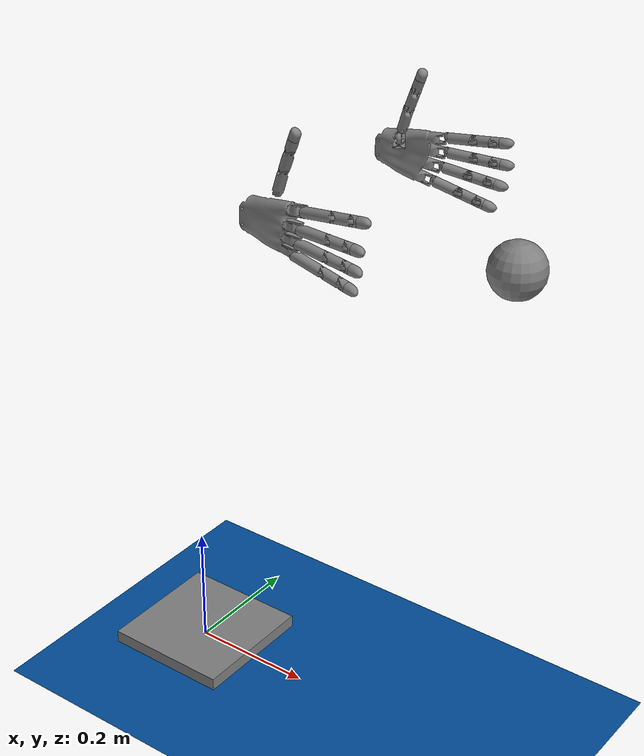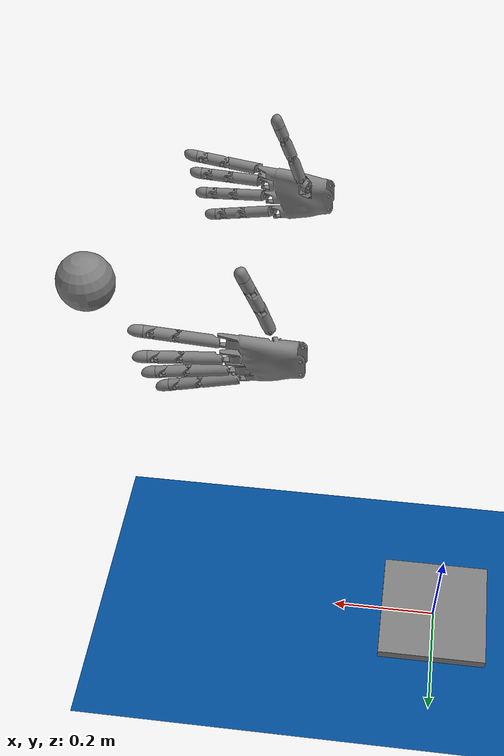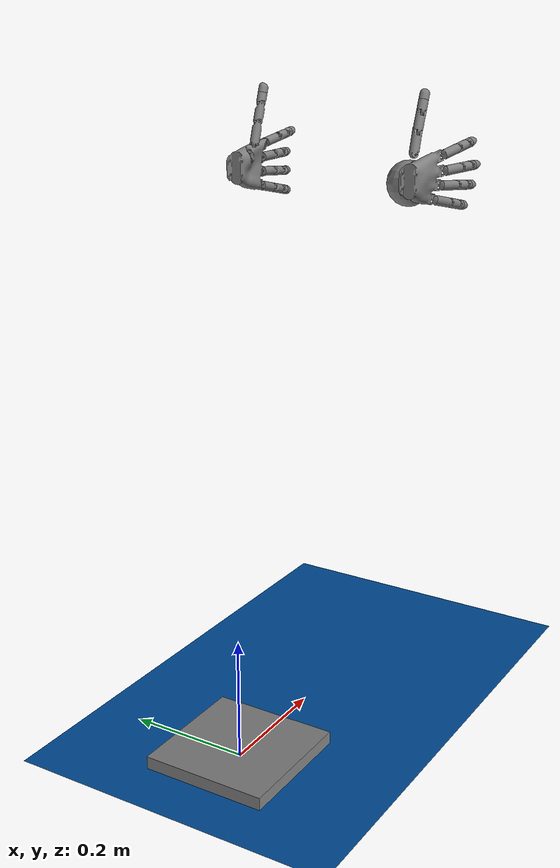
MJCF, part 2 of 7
-0.0849051 0.0521249 0.0313928 -0.0849313 0.0537522 0.0297627 -0.0849446 0.0549788 0.0278168 -0.0849456 0.0392099 0.0324385 -0.14737 0.0380544 0.0327084 -0.146564 0.0461474 0.0317953 -0.130573 0.0415262 0.0333092 -0.130523 0.0437756 0.0340067 -0.107695 0.0530873 0.0276901 -0.107756 0.0519115 0.029557 -0.107773 0.0503428 0.0311263 -0.107778 0.0484117 0.0323731 -0.107767 0.0330105 0.0316627 -0.142606 0.0329946 -0.031733 -0.142483 0.0464975 0.0336301 -0.0379898 0.0465607 0.033621 -0.0379697 0.0507516 0.0326703 -0.0362883 0.0494708 0.0330464 -0.0368916 0.0554051 0.0301208 -0.0323634 0.0546838 0.0306995 -0.0333061 0.0533221 0.0315669 -0.0346369 0.0527571 0.0318597 -0.0350725 0.0572698 0.0280056 -0.0283652 0.0581138 0.0265337 -0.0249602 0.0584259 0.0258333 -0.023111 0.0586103 0.0253578 -0.0217574 0.056598 0.0289002 -0.0301745 0.0587941 0.0248547 -0.020226 0.0587145 0.0250728 -0.0209033 0.0634358 4.07184e-05 0.0170712 0.0634213 0.00148949 0.0170605 0.0630926 0.00727642 0.0168159 0.0629064 0.00903838 0.01667 0.0625915 0.011366 0.0161764 0.0624924 0.0119924 0.01594 0.0622179 0.0135474 0.0150371 0.0621181 0.0140586 0.0146024 0.0618727 0.0152127 0.0132109 0.0613572 0.0172279 0.00835667 0.0615804 0.0164107 0.0107666 0.0618135 0.0154702 0.0127948 0.0607529 0.0192892 0.00169954 0.0610991 0.0181322 0.00554009 0.0593978 0.0232124 -0.0143145 0.0594977 0.022944 -0.0131845 0.0596809 0.0224546 -0.0109816 0.0600816 0.0213467 -0.00605769 0.0589786 -0.0243909 -0.0188416 0.058826 -0.0248112 -0.0202046 0.059514 -0.0229289 -0.0133159 0.0598545 -0.0220093 -0.00914892 0.0606167 -0.0197434 -0.000105657 0.0609556 -0.0186332 0.00370872 0.0614176 -0.0170176 0.00879026 0.0615397 -0.0165679 0.0101264 0.061803 -0.0155245 0.0125801 0.061889 -0.0151506 0.0132024 0.0621048 -0.014137 0.0144638 0.0621396 -0.013963 0.0146312 0.0622599 -0.0133378 0.0151474 0.0624866 -0.0120426 0.0158942 0.0625304 -0.011772 0.0160085 0.0627168 -0.0105271 0.0164042 0.062982 -0.00838886 0.016733 0.0632597 -0.00522899 0.0169399 0.0586428 -0.0253159 -0.0217356 0.0587252 -0.0250892 -0.0210614 0.0554354 -0.0300994 -0.0323495 0.058008 -0.0267772 -0.0256346 0.057862 -0.0270535 -0.0262948 0.0570842 -0.0282887 -0.0290022 0.0561027 -0.0294636 -0.0312514 0.0507935 -0.032651 -0.0362602 0.0518902 -0.0322445 -0.0356479 0.05353 -0.0314489 -0.0344697 0.0540337 -0.0311454 -0.0340122 0.0479883 -0.0333739 -0.0374705 0.0466666 -0.0335994 -0.0379209 0.0466039 -0.0336094 -0.0379408 0.04529 -0.0337644 -0.0386468 0.0445224 -0.0338414 -0.0395142 0.0445018 -0.0338434 -0.0395473 0.0420925 0.0344971 -0.0504909 0.0442523 0.0338714 -0.0399621 0.0444715 0.0338506 -0.0395552 0.04535 0.0337638 -0.0385937 0.0534432 -0.0301324 -0.033477 0.0547984 -0.0290173 -0.0314216 0.0535343 -0.028859 -0.0602528 0.0575052 0.0245055 -0.0201874 0.0573421 0.0249365 -0.021525 0.0581143 0.021747 -0.0216305 0.0541506 -0.0280719 -0.0602607 0.0544819 -0.027552 -0.060265 0.0557593 -0.0279195 -0.0291865 0.0547051 -0.0271499 -0.0602674 0.0559355 -0.0276773 -0.0286595 0.0567582 -0.0263094 -0.0254169 0.057335 -0.0249998 -0.0218133 0.0578724 -0.0228707 -0.021611 0.0598063 -0.0122791 -0.021619 0.0605741 -0.00159092 -0.0216242 0.0603607 0.00654589 -0.0216277 0.05908 0.0169671 -0.0216304 0.0566391 0.0265108 -0.0258575 0.0561267 0.0273784 -0.0279372 0.0555454 0.0281811 -0.0297001 0.0544737 0.0275116 -0.0602818 0.0547236 0.0270534 -0.0602847 0.0537642 0.0298987 -0.0330398 0.0522459 0.0300164 -0.060255 0.0525888 0.0297419 -0.0602591 0.0536069 0.0287362 -0.0602714 0.0551087 0.0286891 -0.0307433 0.0532751 0.0291018 -0.0602674 0.0529199 0.0294499 -0.0602631 0.0539148 0.0283525 -0.0602751 0.05406 0.0281541 -0.0602768 0.0541994 0.0279513 -0.0602785 0.0518172 0.0303258 -0.0602497 0.0521703 0.0308989 -0.0347933 0.0513731 0.0306124 -0.0602443 0.0493179 0.0316031 -0.0602192 0.0498835 0.0313754 -0.0602261 0.0502953 0.0317007 -0.0361806 0.0504412 0.0311205 -0.0602329 0.0509143 0.0308771 -0.0602387 0.0487635 0.0317998 -0.0602124 0.0491935 0.0320409 -0.0368034 0.0485166 0.0322113 -0.0371372 0.0454109 0.0326976 -0.0385204 0.0437618 0.0327332 -0.0601507 0.0455927 0.0325338 -0.0601733 0.0465615 0.0325676 -0.03793 0.0468916 0.0323027 -0.0601894 0.0481655 0.0319856 -0.060205 0.0445089 0.0327644 -0.03948 0.0444915 0.0327416 -0.0459286 0.0427991 0.0328029 -0.0549442 0.042797 0.0328027 -0.055032 0.0442727 0.0327526 -0.0470276 0.0426459 0.0328057 -0.0559292 0.0424449 0.0328093 -0.057049 0.041922 0.0328158 -0.060128 0.0601001 0.0169242 0.00850127 0.0598534 0.0178473 0.00561026 0.0594867 0.0191063 0.00138472 0.0587379 0.02133 -0.00724587 0.0581901 0.022731 -0.0136242 0.0608191 0.0133812 0.0150168 0.0607303 0.0139288 0.014528 0.0610797 0.0111566 0.0139382 0.0605276 0.0150527 0.0130982 0.0604146 0.0156085 0.0120861 0.0613653 0.00901309 0.0166958 0.0611309 0.0111467 0.0162195 0.0610408 0.0118493 0.015946 0.0603063 0.016094 0.0109485 0.0615941 0.00619121 0.016927 0.0617989 3.97018e-05 0.0171234 0.0617226 -0.00381389 0.017049 0.0611621 -0.0109292 0.016275 0.0613605 -0.00910383 0.0166812 0.0615645 -0.00666612 0.0168961 0.0597052 -0.0183879 0.00363905 0.0594207 -0.0193379 0.000359241 0.0586199 -0.0216621 -0.00894371 0.0599233 -0.0176081 0.00617503 0.0601893 -0.0165875 0.00932115 0.0601997 -0.0165456 0.00944683 0.0603546 -0.015901 0.011272 0.0605803 -0.0148029 0.0133819 0.0606514 -0.0144148 0.0139126 0.0608643 -0.0131228 0.0151692 0.060946 -0.0125716 0.0155409 0.0610315 -0.0119558 0.0158717 0.0575367 -0.0244638 -0.0201665 0.0581583 -0.0228388 -0.0142615 0.0585317 -0.02189 -0.00999534 0.051078 -0.0308088 -0.0602218 0.0505599 -0.031083 -0.0602153 0.0518431 -0.0310603 -0.0350819 0.0515832 -0.0305057 -0.0602282 0.0528356 -0.0295593 -0.060244 0.0522314 -0.0300557 -0.0602363 0.0519127 -0.0302864 -0.0602323 0.0500302 -0.0313312 -0.0602087 0.0485454 -0.032199 -0.0371154 0.0503361 -0.0316822 -0.0361533 0.0494898 -0.0315557 -0.0602019 0.0483875 -0.0319368 -0.0601881 0.047816 -0.0323546 -0.037439 0.0426732 -0.0328146 -0.0554415 0.0468806 -0.0323205 -0.0601694 0.0453568 -0.0325812 -0.0601504 0.0418632 -0.0328302 -0.0601071 0.0420053 -0.0328281 -0.0592622 0.0425921 -0.0328166 -0.0558973 0.042738 -0.0328131 -0.0549828 0.0429187 -0.0328082 -0.0539804 0.044534 -0.0327389 -0.0457207 0.0445512 -0.0327556 -0.039451 0.0454051 -0.0326913 -0.0385284 0.0466033 -0.0325553 -0.037902 0.048644 0.0318239 -0.0602109 0.0473942 0.0321703 -0.0601955 0.0458065 0.0324808 -0.060176 0.0441982 0.0326766 -0.0601561 0.0419436 0.0327957 -0.0601282 0.0526153 0.029715 -0.0602594 0.0542184 0.0279195 -0.0602787 0.0541488 0.0280227 -0.0602779 0.0521912 0.0300529 -0.0602543 0.0517512 0.0303644 -0.0602489 0.0512963 0.0306513 -0.0602434 0.0508275 0.0309151 -0.0602377 0.0503568 0.0311518 -0.0602319 0.0531416 0.0292324 -0.0602658 0.0533874 0.0289773 -0.0602688 0.0536216 0.0287131 -0.0602716 0.0539315 0.0283254 -0.0602753 0.0540778 0.0281248 -0.0602771 0.0501171 0.0312627 -0.060229 0.0498744 0.0313688 -0.060226 0.0445347 -0.0327863 -0.0454884 0.0541136 -0.0280572 -0.0610964 0.0518377 -0.0303051 -0.0610644 0.0528333 -0.0295568 -0.0602453 0.0535923 -0.0287874 -0.0602543 0.0505543 -0.0310768 -0.0602157 0.0510431 -0.0308202 -0.0602223 0.0500598 -0.0313081 -0.060209 0.0486115 -0.0318429 -0.0610112 0.0495077 -0.0315369 -0.0602014 0.0515225 -0.0305374 -0.0602287 0.0519886 -0.0302278 -0.0602347 0.0464282 -0.0323892 -0.0601592 0.0478521 -0.0320709 -0.0601784 0.048955 -0.0317383 -0.0601937 0.041733 -0.0328224 -0.0609475 0.0418846 -0.032811 -0.0601074 0.0450477 -0.0326002 -0.0601418 0.0439927 -0.0327131 -0.0609264 0.0439506 0.0327025 -0.0609564 0.0540775 0.0280594 -0.0611223 0.0517987 0.0303044 -0.0610922 0.0485706 0.0318381 -0.0610404 0.0417422 0.0328108 -0.0612478 0.0550332 -2.18427e-05 -0.116077 0.0534021 -3.04876e-05 -0.134042 0.0532354 -0.00503515 -0.134035 0.0528451 -0.0188076 -0.116336 0.0568526 -1.05275e-05 -0.0923876 0.0562086 -0.00636064 -0.098294 0.0555239 -0.0126764 -0.0982743 0.0543963 -0.0189298 -0.0982438 0.0512467 -0.0179191 -0.133971 0.0518475 -0.0152275 -0.13399 0.054038 -0.0126037 -0.11637 0.0525347 -0.0113921 -0.134012 0.0555077 0.0126484 -0.0982852 0.0562005 0.00633354 -0.0982995 0.0533359 0.00304053 -0.134042 0.0531446 0.00608344 -0.134038 0.054372 0.0189004 -0.0982601 0.052821 0.0187606 -0.116352 0.0523975 0.0120975 -0.134018 0.0511661 0.0180915 -0.133985 0.0521855 -0.00599702 -0.143673 0.0507979 -0.0152296 -0.143522 0.0523643 0.00304623 -0.143697 0.0514012 0.0119606 -0.143601 0.0493428 0.0207093 -0.143382 0.0282396 0.0345629 -0.0111862 0.0282396 0.0343629 -0.0111862 0.0260343 0.0343629 -0.0156187 0.0260343 0.0345629 -0.0156187 0.0231366 0.0343629 -0.0196329 0.0231366 0.0345629 -0.0196329 0.019624 0.0343629 -0.0231216 0.019624 0.0345629 -0.0231216 0.01559 0.0343629 -0.0259917 0.01559 0.0345629 -0.0259917 0.0111426 0.0343629 -0.0281666 0.0111426 0.0345629 -0.0281666 0.00640032 0.0343629 -0.0295883 0.00640032 0.0345629 -0.0295883 0.00148985 0.0343629 -0.0302187 0.00148985 0.0345629 -0.0302187 -0.00345773 0.0343629 -0.030041 -0.00345773 0.0345629 -0.030041 -0.00831033 0.0343629 -0.02906 -0.00831033 0.0345629 -0.02906 -0.0129384 0.0343629 -0.0273019 -0.0129384 0.0345629 -0.0273019 -0.0172184 0.0343629 -0.0248136 -0.0172184 0.0345629 -0.0248136 -0.0210361 0.0343629 -0.0216615 -0.0210361 0.0345629 -0.0216615 -0.0242895 0.0343629 -0.0179298 -0.0242895 0.0345629 -0.0179298 -0.0268918 0.0343629 -0.0137181 -0.0268918 0.0345629 -0.0137181 -0.0287734 0.0343629 -0.0091389 -0.0287734 0.0345629 -0.0091389 -0.0298843 0.0343629 -0.00431438 -0.0298843 0.0345629 -0.00431438 -0.0301947 0.0343629 0.000626651 -0.0301947 0.0345629 0.000626651 -0.0296963 0.0343629 0.00555227 -0.0296963 0.0345629 0.00555227 -0.0284025 0.0343629 0.010331 -0.0284025 0.0345629 0.010331 -0.0263477 0.0343629 0.0148352 -0.0263477 0.0345629 0.0148352 -0.0235869 0.0343629 0.0189447 -0.0235869 0.0345629 0.0189447 -0.0203137 0.0343629 0.022441 -0.0203137 0.0345629 0.022441 -0.0165304 0.0343629 0.0253778 -0.0165304 0.0345629 0.0253778 -0.0123317 0.0343629 0.0276818 -0.0123317 0.0345629 0.0276818 -0.00782235 0.0343629 0.0292955 -0.00782235 0.0345629 0.0292955 -0.00311509 0.0343629 0.0301784 -0.00311509 0.0345629 0.0301784 0.0016725 0.0343629 0.0303086 0.0016725 0.0345629 0.0303086 0.00642079 0.0343629 0.0296828 0.00642079 0.0345629 0.0296828 0.0110112 0.0343629 0.0283166 0.0110112 0.0345629 0.0283166 0.0153289 0.0343629 0.0262442 0.0153289 0.0345629 0.0262442 0.0192662 0.0343629 0.0235173 0.0192662 0.0345629 0.0235173 0.0227246 0.0343629 0.0202041 0.0227246 0.0345629 0.0202041 0.0256177 0.0343629 0.0163873 0.0256177 0.0345629 0.0163873 0.0278733 0.0343629 0.0121624 0.0278733 0.0345629 0.0121624 0.029435 0.0343629 0.00763477 0.029435 0.0345629 0.00763477 0.0302637 0.0343629 0.00291766 0.0302637 0.0345629 0.00291766 0.0303389 0.0343629 -0.0018711 0.0303389 0.0345629 -0.0018711 0.0296585 0.0343629 -0.00661188 0.0296585 0.0345629 -0.00661188 -0.0253209 -0.0339414 -0.114945 -0.024588 -0.0339708 -0.116958 -0.0256628 -0.0332092 -0.116645 -0.0302263 -0.0171571 -0.128885 -0.0305737 -0.0161548 -0.128016 -0.0301222 -0.0175774 -0.128953 -0.0314669 -0.0128002 -0.125679 -0.031793 -0.0111108 -0.124777 -0.0313434 -0.0142333 -0.124985 -0.0316486 -0.0203966 -0.113604 -0.0312593 -0.0204672 -0.116839 -0.0316418 -0.0188653 -0.116032 -0.0316713 -0.0208034 -0.112759 -0.0311659 -0.0234444 -0.112781 -0.03173 -0.0210921 -0.111764 -0.0317882 -0.0211759 -0.111083 -0.0321906 -0.0198511 -0.108926 -0.0321718 -0.0201029 -0.10876 -0.0319027 -0.0209755 -0.110278 -0.0316938 -0.0232312 -0.108748 -0.031856 -0.0211072 -0.110534 -0.0305622 -0.0236388 -0.116799 -0.0317129 -0.0141796 -0.121981 -0.0316786 -0.0157425 -0.120232 -0.03133 -0.0173926 -0.120908 -0.0316437 -0.018379 -0.116751 -0.0306905 -0.0206194 -0.120859 -0.0316536 -0.0173086 -0.118247 -0.0316713 -0.0161381 -0.119753 -0.0317508 -0.012702 -0.123428 -0.0307706 -0.0175001 -0.124931 -0.0310285 -0.0146198 -0.126847 -0.0310825 -0.0144166 -0.126706 -0.0288516 -0.0205056 -0.131696 -0.0292563 -0.0194119 -0.131222 -0.0293093 -0.0208323 -0.128872 -0.0294684 -0.0189747 -0.13072 -0.0300425 -0.0176393 -0.129337 -0.0284273 -0.0216409 -0.132035 -0.0282874 -0.024044 -0.128778 -0.0280532 -0.0226279 -0.132217 -0.0251004 -0.0289913 -0.132352 -0.0260624 -0.0272902 -0.132333 -0.0269991 -0.0272419 -0.128673 -0.0264536 -0.0264867 -0.132325 -0.0275749 -0.023869 -0.132304 -0.0237287 -0.0308893 -0.132005 -0.0243666 -0.0300729 -0.132248 -0.0252811 -0.0302389 -0.128559 -0.0244382 -0.0299738 -0.132268 -0.0272452 -0.0286909 -0.124663 -0.026397 -0.030138 -0.124618 -0.025022 -0.029113 -0.132352 -0.0214557 -0.0329649 -0.130458 -0.0220192 -0.0325321 -0.130942 -0.0228668 -0.0325336 -0.128442 -0.0222257 -0.032364 -0.131099 -0.0241634 -0.0314952 -0.1285 -0.0229715 -0.0316976 -0.131598 -0.0236059 -0.0310318 -0.131947 -0.0214628 -0.0333725 -0.12838 -0.020912 -0.0333625 -0.129861 -0.021075 -0.0332436 -0.13006 -0.0213431 -0.0330481 -0.130347 -0.0204896 -0.0336902 -0.12915 -0.0206736 -0.0335411 -0.12951 -0.0207678 -0.0334692 -0.12966 -0.0204867 -0.0339908 -0.12751 -0.0203495 -0.0339569 -0.128014 -0.0203228 -0.0339106 -0.128332 -0.0203445 -0.0338445 -0.128646 -0.0204402 -0.0337353 -0.129021 -0.024309 -0.0333034 -0.120571 -0.0217101 -0.034016 -0.124435 -0.0269447 -0.03309 -0.112695 -0.0281434 -0.0329541 -0.108718 -0.0261171 -0.0339029 -0.112684 -0.0283441 -0.0337662 -0.105813 -0.0285639 -0.0337118 -0.10517 -0.0284665 -0.0337444 -0.105437 -0.0292519 -0.0328085 -0.104713 -0.0284241 -0.0337547 -0.105561 -0.0283756 -0.0337634 -0.105709 -0.0300687 -0.0322996 -0.102344 -0.029627 -0.0328638 -0.103021 -0.0292661 -0.0332338 -0.103651 -0.0292037 -0.0332898 -0.103768 -0.0287924 -0.0335971 -0.104614 -0.0312833 -0.0298544 -0.100982 -0.0311384 -0.030256 -0.101093 -0.030461 -0.0304442 -0.104705 -0.0309654 -0.0306799 -0.10125 -0.0298827 -0.0316817 -0.104709 -0.0305609 -0.0315071 -0.101694 -0.0301443 -0.0321904 -0.102237 -0.0313652 -0.0296031 -0.10093 -0.030947 -0.0290859 -0.104702 -0.0315944 -0.0287671 -0.100853 -0.0313368 -0.0276249 -0.104701 -0.0319896 -0.0267816 -0.100846 -0.0316529 -0.0261006 -0.104701 -0.032175 -0.025566 -0.100842 -0.0321487 -0.023004 -0.104702 -0.0322091 -0.0228653 -0.104263 -0.0321765 -0.0242723 -0.102605 -0.0323944 -0.0188635 -0.10794 -0.0323478 -0.0197198 -0.107258 -0.0322679 -0.0213471 -0.105814 -0.0322558 -0.0216239 -0.105547 -0.0310712 -0.0263508 -0.108736 -0.0304103 -0.0265856 -0.112754 -0.0306786 -0.0278829 -0.10873 -0.0299382 -0.0281248 -0.11274 -0.0301991 -0.0293416 -0.108725 -0.0293664 -0.0295815 -0.112728 -0.0296069 -0.0306817 -0.108722 -0.0286657 -0.0309042 -0.112716 -0.0289063 -0.0318819 -0.108719 -0.0278412 -0.0320692 -0.112705 -0.0296696 -0.0267994 -0.116755 -0.0291164 -0.0283451 -0.116732 -0.028451 -0.0297993 -0.116709 -0.0276413 -0.0311055 -0.116688 -0.0266928 -0.0322372 -0.116667 -0.022901 -0.033362 -0.12448 -0.0241881 -0.0324803 -0.124527 -0.0253758 -0.0314114 -0.124573 -0.0254701 -0.0323775 -0.120605 -0.0265407 -0.0312777 -0.120638 -0.0274581 -0.0299879 -0.120671 -0.0282164 -0.0285367 -0.120705 -0.0288508 -0.0269858 -0.120738 -0.0298808 -0.0238086 -0.120802 -0.0279582 -0.0271365 -0.124708 -0.029122 -0.0239466 -0.124792 -0.0300415 -0.0207436 -0.124867 -0.030626 -0.00543654 -0.113895 -0.0306408 -0.00567303 -0.11385 -0.0306634 -0.0069068 -0.1138 -0.0307943 -0.00775128 -0.113388 -0.0307972 -0.0102894 -0.113475 -0.0309223 -0.00911956 -0.112999 -0.0309577 -0.00946305 -0.112891 -0.0308542 -0.0113596 -0.113338 -0.0311496 -0.0111352 -0.112299 -0.0309312 -0.0125689 -0.113152 -0.0314149 -0.0130974 -0.11146 -0.0311122 -0.0147502 -0.112697 -0.0315615 -0.0148815 -0.111054 -0.0313328 -0.0167791 -0.112122 -0.0315966 -0.0187435 -0.111404 -0.0323704 -0.0185311 -0.108192 -0.0321247 -0.0196813 -0.109388 -0.0322571 -0.0179659 -0.108607 -0.0318775 -0.0206068 -0.110555 -0.0320421 -0.0168525 -0.109368 -0.0317141 -0.0150041 -0.110484 -0.0315328 -0.0138797 -0.11108 -0.0324004 0.018634 -0.108012 -0.0323762 0.0184355 -0.108162 -0.0321567 0.0194788 -0.109232 -0.0321874 0.0197927 -0.108941 -0.0323996 0.0187651 -0.107911 -0.0318768 0.0205389 -0.110556 -0.031902 0.0209077 -0.110279 -0.0307742 0.00738776 -0.113447 -0.0306256 0.00530391 -0.113895 -0.0307288 0.00871736 -0.11364 -0.0322545 0.0178294 -0.108608 -0.0318783 0.020532 -0.110549 -0.0317774 0.0198905 -0.110867 -0.0321733 0.017416 -0.108899 -0.0320428 0.0167326 -0.109359 -0.0312357 0.015886 -0.112377 -0.0313212 0.0166242 -0.112153 -0.031531 0.0137442 -0.111081 -0.031022 0.0136878 -0.112925 -0.0317126 0.0148713 -0.110483 -0.0314931 0.0179501 -0.111692 -0.0314104 0.0129423 -0.11147 -0.0311418 0.0109479 -0.11232 -0.0308667 0.0115126 -0.113308 -0.030818 0.0106348 -0.113425 -0.0309567 0.00932811 -0.112892 -0.0309117 0.00888952 -0.113029 -0.0323898 -0.0186589 -0.108096 -0.0321708 0.0200354 -0.108765 -0.0323119 0.0204403 -0.106524 -0.031307 0.0134434 -0.126109 -0.0311402 0.014125 -0.126552 -0.0313415 0.0141651 -0.124997 -0.0303225 0.0168232 -0.128643 -0.0298442 0.0180587 -0.129817 -0.0301194 0.0175089 -0.128966 -0.0292553 0.0193442 -0.131224 -0.0288522 0.0204332 -0.131696 -0.032243 0.022005 -0.105031 -0.0321478 0.0229367 -0.104705 -0.0321975 0.0234592 -0.103433 -0.0316519 0.0260332 -0.104704 -0.0313614 0.0295464 -0.10093 -0.0315935 0.0286997 -0.100855 -0.0309457 0.0290184 -0.104705 -0.0319235 0.0270939 -0.100848 -0.0313357 0.0275575 -0.104704 -0.0321838 0.02543 -0.100843 -0.0321808 0.0246538 -0.101932 -0.0306228 0.0313238 -0.10162 -0.0309229 0.0307086 -0.101289 -0.0304596 0.0303768 -0.104708 -0.0310098 0.0305082 -0.101204 -0.0313156 0.0296891 -0.100958 -0.0292504 0.0327409 -0.104717 -0.0297175 0.0326903 -0.102873 -0.0298813 0.0316142 -0.104712 -0.0301853 0.0320601 -0.102181 -0.028834 0.0335054 -0.104515 -0.0292287 0.0331991 -0.103721 -0.029471 0.0329649 -0.103284 -0.0265116 0.0338134 -0.11153 -0.028343 0.0336984 -0.105814 -0.0285368 0.0336558 -0.105236 -0.0287617 0.0335495 -0.104678 -0.0243048 0.0332349 -0.120582 -0.0232309 0.033939 -0.120549 -0.0246637 0.0338996 -0.116752 -0.0228961 0.0332932 -0.124492 -0.0204856 0.0339216 -0.127512 -0.020453 0.0336517 -0.129069 -0.0204263 0.0336767 -0.128995 -0.0214572 0.0333033 -0.128394 -0.0203334 0.0337861 -0.128612 -0.0203186 0.0338181 -0.12847 -0.0203147 0.0338483 -0.128312 -0.0203942 0.0339111 -0.127781 -0.0204175 0.0339156 -0.127702 -0.0228615 0.0324646 -0.128456 -0.0220751 0.032417 -0.130988 -0.021679 0.0327272 -0.130663 -0.0212961 0.0330127 -0.130302 -0.0211921 0.0330887 -0.130192 -0.0207238 0.0334323 -0.129597 -0.0223693 0.032173 -0.131206 -0.0241585 0.0314264 -0.128514 -0.0228081 0.0317819 -0.131502 -0.0240242 0.0304563 -0.132134 -0.0239185 0.0305893 -0.132091 -0.0252765 0.0301701 -0.128573 -0.0238054 0.0307277 -0.132041 -0.0231075 0.0314929 -0.131683 -0.0250995 0.028922 -0.132353 -0.0245367 0.0297637 -0.132294 -0.0242136 0.0302094 -0.132203 -0.0264656 0.0263902 -0.132327 -0.0269951 0.0271733 -0.128686 -0.0273089 0.0244648 -0.13231 -0.0282839 0.0239754 -0.128792 -0.0275741 0.0237998 -0.132305 -0.028052 0.0225598 -0.132218 -0.0293062 0.0207638 -0.128885 -0.0284297 0.0215634 -0.132035 -0.0307684 0.0174319 -0.124943 -0.0307061 0.0156687 -0.127677 -0.0303768 0.0166696 -0.128508 -0.0317127 0.014101 -0.121992 -0.0317532 0.0125138 -0.12354 -0.031658 0.0117852 -0.125153 -0.0317926 0.0110424 -0.124777 -0.0316927 0.0231638 -0.108753 -0.0318964 0.0209263 -0.110305 -0.0318389 0.0210718 -0.110645 -0.0317813 0.0211059 -0.111146 -0.0311644 0.0233768 -0.112787 -0.0317205 0.0209975 -0.111889 -0.0316685 0.0207194 -0.112805 -0.031648 0.0203286 -0.113605 -0.0322639 0.0214876 -0.105548 -0.0316891 0.0151322 -0.120866 -0.0313282 0.0173246 -0.120918 -0.031658 0.0168715 -0.118736 -0.0306885 0.0205514 -0.120869 -0.0312577 0.0203995 -0.116847 -0.0298784 0.0237406 -0.120812 -0.0305603 0.023571 -0.116808 -0.028848 0.0269178 -0.120749 -0.0296674 0.0267316 -0.116764 -0.0291139 0.0282772 -0.116741 -0.0282134 0.0284686 -0.120715 -0.0274548 0.0299197 -0.120682 -0.0300389 0.0206754 -0.124878 -0.029119 0.0238783 -0.124804 -0.0279548 0.0270682 -0.12472 -0.0284483 0.0297314 -0.116718 -0.0265371 0.0312095 -0.120649 -0.0276384 0.0310375 -0.116696 -0.0254663 0.0323092 -0.120616 -0.0266896 0.0321691 -0.116675 -0.0256594 0.033141 -0.116654 -0.0241835 0.0324117 -0.124539 -0.0253715 0.0313429 -0.124585 -0.0263931 0.0300696 -0.12463 -0.0272415 0.0286225 -0.124676 -0.0258241 0.027678 -0.132339 -0.0289044 0.0318142 -0.108725 -0.0296051 0.0306141 -0.108727 -0.0301975 0.0292741 -0.10873 -0.0306771 0.0278153 -0.108735 -0.0310698 0.0262833 -0.108741 -0.0304085 0.0265179 -0.112761 -0.0299362 0.0280572 -0.112747 -0.0293643 0.0295138 -0.112734 -0.0286634 0.0308364 -0.112723 -0.0278387 0.0320014 -0.112712 -0.026942 0.033022 -0.112702 -0.0281413 0.0328863 -0.108723 -0.0316421 0.018609 -0.116312 -0.0351147 0.0110404 -0.125423 -0.0325773 0.0193421 -0.13187 -0.0331661 0.0180571 -0.130463 -0.0336446 0.0168211 -0.129289 -0.0336984 0.0166688 -0.129155 -0.0340669 0.0155402 -0.128223 -0.0344961 0.0139891 -0.127108 -0.0346451 0.0133726 -0.126711 -0.0349937 0.0117111 -0.125761 -0.031814 0.0108774 -0.124698 -0.0318185 0.0105785 -0.124559 -0.0351406 0.0105781 -0.125205 -0.0318039 0.0104224 -0.124488 -0.035126 0.0104203 -0.125134 -0.0345463 -3.62888e-05 -0.122902 -0.0312243 -3.42597e-05 -0.122257 -0.0312248 -0.000516776 -0.122261 -0.0345563 -0.00199321 -0.122976 -0.0312343 -0.00199127 -0.122331 -0.0346023 -0.00392613 -0.123198 -0.0348465 -0.00791987 -0.124145 -0.0317157 -0.00977551 -0.124181 -0.0350348 -0.00975219 -0.124816 -0.0318043 -0.0104907 -0.124488 -0.0351263 -0.0104928 -0.125133 -0.0312797 -0.00390669 -0.122549 -0.0312803 -0.0039242 -0.122552 -0.0346599 -0.00524802 -0.123437 -0.0313407 -0.00529986 -0.122802 -0.0347818 -0.00714072 -0.123906 -0.0314639 -0.00719156 -0.123276 -0.0315268 -0.00794395 -0.123508 -0.035115 -0.0111128 -0.125422 -0.0351439 -0.0108043 -0.125276 -0.0318219 -0.0108023 -0.12463 -0.0363057 -0.0157815 -0.103421 -0.0362666 -0.0172937 -0.102136 -0.0329446 -0.0172917 -0.101491 -0.0329836 -0.0157794 -0.102776 -0.0329956 -0.015375 -0.103087 -0.0363176 -0.015377 -0.103732 -0.0330281 -0.0143426 -0.103824 -0.0363501 -0.0143446 -0.10447 -0.0330638 -0.0132748 -0.104509 -0.0363858 -0.0132768 -0.105154 -0.0330444 -0.0128862 -0.104741 -0.0363664 -0.0128882 -0.105386 -0.0363842 -0.0130827 -0.105271 -0.0330622 -0.0130806 -0.104626 -0.0328275 -0.0111446 -0.105673 -0.0330441 0.012817 -0.104741 -0.0363661 0.0128149 -0.105386 -0.0329588 0.0121602 -0.105113 -0.0362992 0.0123018 -0.105679 -0.0327504 0.0103921 -0.105992 -0.036089 0.0105409 -0.106569 -0.0326656 0.00958379 -0.106339 -0.0359877 0.00958175 -0.106985 -0.0325677 0.00855821 -0.106733 -0.0359046 0.00871956 -0.107319 -0.032494 0.00769937 -0.107024 -0.0357502 0.00684103 -0.107927 -0.0323811 0.00615996 -0.107464 -0.0357032 0.00615792 -0.108109 -0.0323588 0.00580807 -0.10755 -0.0356299 0.00490784 -0.108391 -0.0322602 0.0038868 -0.107928 -0.035581 0.00385634 -0.108578 -0.032216 0.00260738 -0.108095 -0.0355381 0.00260534 -0.108741 -0.0321996 0.00193798 -0.108157 -0.0355212 0.00191483 -0.108804 -0.0321768 -3.38807e-05 -0.108234 -0.0354989 -3.59097e-05 -0.10888 -0.0321769 -5.3893e-05 -0.108234 -0.0354989 -5.5922e-05 -0.10888 -0.0321771 -0.000133942 -0.108234 -0.0354991 -0.000135971 -0.10888 -0.0321785 -0.000454123 -0.108231 -0.0355006 -0.000456167 -0.108876 -0.0321823 -0.000908652 -0.108219 -0.0355043 -0.000910696 -0.108865 -0.0321942 -0.00173416 -0.108177 -0.0355162 -0.00173619 -0.108823 -0.0322247 -0.00297067 -0.108063 -0.0355467 -0.00297271 -0.108708 -0.0322802 -0.0044164 -0.107851 -0.0356023 -0.00441844 -0.108497 -0.0323038 -0.00490072 -0.107762 -0.0356258 -0.00490276 -0.108407 -0.0324206 -0.00680732 -0.107312 -0.0357426 -0.00680935 -0.107957 -0.0324717 -0.00749023 -0.107112 -0.0357938 -0.00749226 -0.107758 -0.0325013 -0.00785834 -0.106996 -0.0358234 -0.00786038 -0.107642 -0.0326352 -0.00934495 -0.106463 -0.0359572 -0.00934698 -0.107109 -0.0361495 -0.0111467 -0.106318 -0.0330635 0.0132056 -0.104509 -0.0363855 0.0132036 -0.105154 -0.0363839 0.0130094 -0.105271 -0.0330619 0.0130114 -0.104626 -0.032883 0.0189842 -0.101001 -0.0328814 0.0208068 -0.100867 -0.0360249 0.0208049 -0.101478 -0.0362663 0.0172175 -0.102139 -0.0329443 0.0172195 -0.101494 -0.036203 0.0183898 -0.101768 -0.0328854 0.0183174 -0.101141 -0.0361691 0.0189315 -0.101649 -0.0361029 0.0198646 -0.101519 -0.0328861 0.0253288 -0.100977 -0.0354553 0.025783 -0.10149 -0.0349155 0.0286977 -0.1015 -0.035208 0.0272998 -0.101494 -0.0355731 0.0249318 -0.101487 -0.0360128 0.0209399 -0.101478 -0.0328816 0.0209419 -0.10087 -0.034245 0.0307066 -0.101935 -0.0343318 0.0305061 -0.10185 -0.0346376 0.029687 -0.101603 -0.0346834 0.0295444 -0.101576 -0.0339449 0.0313217 -0.102265 -0.0335073 0.0320581 -0.102827 -0.0325507 0.033197 -0.104366 -0.032793 0.0329629 -0.103929 -0.0330395 0.0326882 -0.103519 -0.032156 0.0335033 -0.105161 -0.0320837 0.0335475 -0.105323 -0.031665 0.0336964 -0.10646 -0.0318589 0.0336538 -0.105882 -0.0238076 0.0339196 -0.128157 -0.0265533 0.033937 -0.121194 -0.0279857 0.0338976 -0.117398 -0.0298336 0.0338113 -0.112175 -0.0237163 0.0339091 -0.128426 -0.0236554 0.0337841 -0.129258 -0.0236406 0.033816 -0.129115 -0.0236367 0.0338462 -0.128958 -0.0240458 0.0334302 -0.130242 -0.023775 0.0336497 -0.129715 -0.0237483 0.0336747 -0.129641 -0.0253971 0.032415 -0.131634 -0.025001 0.0327252 -0.131309 -0.0246181 0.0330107 -0.130947 -0.0245141 0.0330867 -0.130838 -0.0264296 0.0314909 -0.132329 -0.0256914 0.0321709 -0.131852 -0.0271274 0.0307256 -0.132687 -0.0272405 0.0305873 -0.132736 -0.0273463 0.0304542 -0.132779 -0.0275356 0.0302073 -0.132849 -0.0278587 0.0297617 -0.13294 -0.0284215 0.02892 -0.132999 -0.0297876 0.0263881 -0.132972 -0.0291461 0.027676 -0.132985 -0.0308961 0.0237978 -0.13295 -0.030631 0.0244628 -0.132956 -0.0325784 -0.019414 -0.131868 -0.032823 -0.0189071 -0.131288 -0.0333942 -0.0175658 -0.12991 -0.0336138 -0.0169796 -0.129368 -0.0341015 -0.0154978 -0.128138 -0.0344026 -0.0144258 -0.127356 -0.0347878 -0.0128075 -0.126327 -0.036331 0.0148575 -0.104061 -0.0330089 0.0148595 -0.103415 -0.0363182 0.0152706 -0.103758 -0.0329962 0.0152726 -0.103112 -0.0329678 0.0162662 -0.102327 -0.0362898 0.0162642 -0.102973 -0.0313741 0.0225577 -0.132864 -0.0317517 0.0215614 -0.132681 -0.0321742 0.0204311 -0.132342 -0.0349192 0.00862178 -0.124409 -0.0316528 0.00915583 -0.123961 -0.0348544 0.00794072 -0.124174 -0.031525 0.0078606 -0.123502 -0.0347475 0.00660856 -0.123778 -0.0314648 0.00713821 -0.12328 -0.0346641 0.00525518 -0.123455 -0.0313421 0.00525721 -0.12281 -0.0345856 0.00333216 -0.123124 -0.0312832 0.00393461 -0.122566 -0.0345691 0.00267807 -0.123046 -0.0312454 0.00260032 -0.122392 -0.0345507 0.00132282 -0.122938 -0.0312342 0.00192037 -0.12233 -0.0321546 -0.0205588 -0.13236 -0.0317882 -0.0215396 -0.132656 -0.0313488 -0.0226991 -0.132871 -0.0308969 -0.023871 -0.132949 -0.0284224 -0.0289933 -0.132997 -0.0293844 -0.0272922 -0.132979 -0.0297756 -0.0264888 -0.132971 -0.0278386 -0.0298655 -0.132932 -0.0272762 -0.0306172 -0.13275 -0.0266006 -0.031391 -0.132421 -0.0257156 -0.0322247 -0.131866 -0.0255477 -0.032366 -0.131744 -0.0264829 -0.0315121 -0.132355 -0.0249795 -0.0328156 -0.131287 -0.0247777 -0.0329669 -0.131103 -0.0245053 -0.033167 -0.130826 -0.024397 -0.0332457 -0.130706 -0.0240898 -0.0334712 -0.130306 -0.0242341 -0.0333645 -0.130506 -0.0238883 -0.0336281 -0.12996 -0.0238117 -0.0336922 -0.129796 -0.0236936 -0.0338098 -0.129431 -0.0236666 -0.0338466 -0.129292 -0.0236557 -0.0339432 -0.128783 -0.0237102 -0.033978 -0.128465 -0.0238087 -0.0339928 -0.128155 -0.0286429 -0.0339434 -0.115591 -0.0307616 -0.0338282 -0.109362 -0.0316661 -0.0337682 -0.106458 -0.0250286 -0.034018 -0.125089 -0.0265546 -0.0340098 -0.121191 -0.0280313 -0.0339684 -0.117275 -0.0247471 -0.034015 -0.125799 -0.0317123 -0.0337634 -0.106309 -0.0317462 -0.0337567 -0.106207 -0.0320707 -0.0336245 -0.10536 -0.0324703 -0.0333397 -0.104519 -0.0325882 -0.0332359 -0.104296 -0.0329262 -0.0328916 -0.103705 -0.0333908 -0.0323017 -0.10299 -0.0338111 -0.0316375 -0.102427 -0.0339277 -0.0314268 -0.102286 -0.0342904 -0.030675 -0.101893 -0.0344604 -0.030258 -0.101738 -0.034602 -0.0298665 -0.101629 -0.0348487 -0.0290407 -0.101508 -0.0349164 -0.0287691 -0.101499 -0.0328578 -0.0254684 -0.100972 -0.0353405 -0.0266077 -0.101491 -0.0355824 -0.0249386 -0.101486 -0.0358249 -0.0229097 -0.101481 -0.0328582 -0.0208743 -0.100862 -0.0360256 -0.0208763 -0.101477 -0.0361255 -0.0196401 -0.101552 -0.0328619 -0.0190632 -0.100998 -0.0361629 -0.0191029 -0.101633 -0.0328632 -0.0187562 -0.101056 -0.0328804 -0.0184767 -0.10112 -0.0362195 -0.0181867 -0.101842 -0.031784 0.0122126 -0.123393 -0.0317421 0.0139492 -0.121667 -0.0317611 0.0119603 -0.123172 -0.0317132 0.0137111 -0.121398 -0.0329453 -0.0147005 -0.10514 -0.0321149 -3.38869e-05 -0.108489 -0.0321191 -0.000824661 -0.108478 -0.0321347 -0.00189214 -0.108422 -0.0321558 -0.00275598 -0.108344 -0.0322309 -0.0046741 -0.108059 -0.0323855 -0.00712514 -0.107467 -0.0322613 -0.00524967 -0.107943 -0.0325436 -0.00895573 -0.106847 -0.0327322 -0.0107389 -0.106085 -0.0329473 -0.0124716 -0.105178 -0.0329478 -0.0140889 -0.105253 -0.0316445 0.0167822 -0.117532 -0.0316874 0.0171102 -0.117756 -0.0316793 0.0185747 -0.115596 -0.0316741 0.0152958 -0.11953 -0.0316249 0.0182719 -0.115276 -0.0316869 0.0199345 -0.113371 -0.03162 0.0195436 -0.113137 -0.031799 0.0205432 -0.111079 -0.0317363 0.0203605 -0.11168 -0.0317492 0.0206439 -0.111893 -0.0316671 0.0199857 -0.112518 -0.0317066 0.0203485 -0.11267 -0.0318251 0.0205829 -0.110877 -0.0318423 0.0205935 -0.110759 -0.0318656 0.0205737 -0.110617 -0.0329618 0.0142135 -0.105166 -0.032961 0.0143829 -0.105119 -0.0329599 0.0144672 -0.105062 -0.0329618 0.0138558 -0.105178 -0.0305477 0.00355048 -0.114153 -0.0305038 0.0014473 -0.114329 -0.0304123 0.00144731 -0.114959 -0.030625 0.00527374 -0.113896 -0.030478 0.00647295 -0.11478 -0.0305936 0.00469298 -0.113995 -0.0306666 0.0109438 -0.11435 -0.031677 0.0200261 -0.111841 -0.0312336 0.0171328 -0.112998 -0.0309092 0.0142101 -0.113802 -0.0313141 0.0176 -0.113891 -0.0310743 0.0156898 -0.114476 -0.0309617 0.0146276 -0.114738 -0.0304382 0.00480975 -0.115902 -0.0304781 0.00664174 -0.115798 -0.0305268 0.0081269 -0.115682 -0.0306858 0.0112476 -0.115336 -0.0308632 0.0135777 -0.114958 -0.0304124 0.00144728 -0.115981 -0.0329599 0.0124373 -0.10512 -0.0328603 0.0116714 -0.105547 -0.0326544 0.0099133 -0.1064 -0.0325792 0.00918971 -0.106703 -0.0324764 0.0080993 -0.10711 -0.0321375 0.00190368 -0.108411 -0.032198 0.00382536 -0.108183 -0.0322196 0.00431207 -0.108101 -0.0322891 0.00559627 -0.107836 -0.0323301 0.00623175 -0.107678 -0.0317073 -0.0204182 -0.11267 -0.0316875 -0.0200026 -0.11337 -0.0316206 -0.0196117 -0.113136 -0.0316688 -0.0200601 -0.112513 -0.0318622 -0.0206488 -0.110639 -0.0318266 -0.0206519 -0.11087 -0.0317997 -0.0206113 -0.111078 -0.0317443 -0.0204563 -0.1116 -0.0317694 -0.0117731 -0.123411 -0.0317254 -0.0134379 -0.121789 -0.0316563 -0.0163976 -0.118191 -0.0316315 -0.0178984 -0.115984 -0.0316814 -0.0180368 -0.116518 -0.0316887 -0.0149179 -0.12011 -0.0316737 -0.01557 -0.119295 -0.0308747 -0.0137899 -0.114915 -0.0310737 -0.0157702 -0.114454 -0.0316528 -0.0161848 -0.118422 -0.0304589 -0.00592091 -0.11585 -0.0304645 -0.00615678 -0.115837 -0.0308464 -0.00636112 -0.118716 -0.0304124 -3.40991e-05 -0.115979 -0.0304125 -0.0015155 -0.115981 -0.0304147 -0.00258242 -0.115972 -0.0311479 -0.0117273 -0.118605 -0.0313371 -0.0178341 -0.113825 -0.0307343 -0.0120277 -0.115229 -0.030496 -0.00729512 -0.115758 -0.0305382 -0.00847507 -0.115657 -0.030681 -0.0112351 -0.115345 -0.0304967 -3.40582e-05 -0.114366 -0.0304981 -0.000775151 -0.114358 -0.0305032 -0.00151542 -0.114332 -0.0304801 -0.0066176 -0.114777 -0.0315012 -0.0190361 -0.11231 -0.0311647 -0.0166571 -0.113175 -0.0309024 -0.0142003 -0.11382 -0.0307088 -0.0116923 -0.114259 -0.0305179 -0.00252385 -0.114268 -0.0305374 -0.0033357 -0.114192 -0.0305938 -0.00482207 -0.113996 -0.0306254 -0.0054063 -0.113896 -0.0329456 -0.014685 -0.105154 -0.0329466 -0.014599 -0.105204 -0.0304994 0.000892022 -0.114352 -0.0308462 0.00629277 -0.118716 -0.0311475 0.011659 -0.118606 -0.0350347 0.0140989 -0.122638 -0.0350753 0.0125118 -0.124186 -0.0351061 0.0122106 -0.124039 -0.0350642 0.0139472 -0.122312 -0.0350832 0.0119583 -0.123817 -0.0350352 0.0137091 -0.122044 -0.0355101 -0.0198625 -0.109586 -0.0354937 -0.020105 -0.109407 -0.0356189 -0.0193605 -0.109063 -0.0350844 -0.012255 -0.124478 -0.0346642 -0.0142356 -0.12564 -0.0303183 -0.0272442 -0.129329 -0.0354709 -0.023006 -0.105347 -0.0349751 -0.0261026 -0.105345 -0.0337832 -0.0304462 -0.105349 -0.0342692 -0.0290879 -0.105347 -0.033205 -0.0316837 -0.105353 -0.0325742 -0.0328105 -0.105358 -0.0302657 -0.0330921 -0.113343 -0.0276285 -0.0333056 -0.121224 -0.0262197 -0.0333641 -0.125135 -0.0247807 -0.0333745 -0.129037 -0.026185 -0.0325357 -0.129098 -0.0274819 -0.0314974 -0.129157 -0.0285999 -0.0302411 -0.129215 -0.0326292 -0.0208346 -0.129529 -0.031607 -0.0240463 -0.129435 -0.0334422 -0.0175796 -0.12961 -0.0340913 -0.0175024 -0.125586 -0.0349933 -0.0161402 -0.120399 -0.0350006 -0.0157493 -0.120872 -0.034651 -0.0173948 -0.121561 -0.0350341 -0.0142158 -0.122591 -0.0349756 -0.0173059 -0.1189 -0.0340115 -0.0206217 -0.121511 -0.0349658 -0.018381 -0.117397 -0.0350158 -0.0232333 -0.109395 -0.0352247 -0.0209776 -0.110923 -0.0351658 -0.0211348 -0.11126 -0.0351066 -0.0211773 -0.111764 -0.0344875 -0.0234466 -0.113429 -0.0350442 -0.0210709 -0.112518 -0.0349925 -0.0207986 -0.113423 -0.0349707 -0.0203987 -0.114249 -0.0357612 -0.018621 -0.108366 -0.0362955 -0.0143899 -0.105637 -0.0361467 -0.0158946 -0.106414 -0.0361355 -0.016774 -0.105352 -0.0359745 -0.017276 -0.107294 -0.0345807 -0.0204695 -0.11749 -0.0332015 -0.0238109 -0.121455 -0.0338834 -0.0236411 -0.11745 -0.0321713 -0.0269882 -0.121391 -0.0329907 -0.0268017 -0.117406 -0.0315368 -0.028539 -0.121358 -0.0324373 -0.0283474 -0.117383 -0.0307783 -0.0299902 -0.121324 -0.0317718 -0.0298016 -0.11736 -0.0298606 -0.0312801 -0.121291 -0.0309619 -0.0311077 -0.117338 -0.0287899 -0.0323798 -0.121258 -0.0300133 -0.0322394 -0.117317 -0.0289831 -0.0332114 -0.117296 -0.0275071 -0.0324825 -0.125182 -0.028695 -0.0314137 -0.125227 -0.0297165 -0.0301403 -0.125273 -0.0305649 -0.0286932 -0.125318 -0.0312781 -0.0271389 -0.125363 -0.0324421 -0.0239489 -0.125447 -0.0333619 -0.0207459 -0.125521 -0.0350725 -0.0127036 -0.124076 -0.034659 -0.0276269 -0.105345 -0.0343931 -0.0263529 -0.109382 -0.0322281 -0.0318839 -0.109366 -0.0314651 -0.0329561 -0.109364 -0.0329287 -0.0306838 -0.109368 -0.033521 -0.0293437 -0.109372 -0.0340005 -0.027885 -0.109377 -0.0337317 -0.0265878 -0.113403 -0.0332596 -0.0281271 -0.113389 -0.0326877 -0.0295837 -0.113376 -0.031987 -0.0309064 -0.113364 -0.0311624 -0.0320714 -0.113354 -0.0349638 -0.0188747 -0.116667 -0.035201 -0.0206019 -0.111194 -0.0351995 -0.0206088 -0.111201 -0.0354351 -0.0197312 -0.110089 -0.0339102 -3.60804e-05 -0.114641 -0.0339095 -0.00151748 -0.114643 -0.0350274 -3.5955e-05 -0.110749 -0.0339267 -0.00406674 -0.114595 -0.0352513 -0.0103231 -0.110037 -0.0339936 -0.00721014 -0.114427 -0.0341191 -0.0103209 -0.114123 -0.0355873 -0.019059 -0.109354 -0.0353193 -0.0155295 -0.110067 -0.0356782 -0.0186078 -0.108908 -0.0362126 -0.0147133 -0.106198 -0.0360577 -0.0161425 -0.106996 -0.0358875 -0.01739 -0.10786 -0.0349072 -0.0186567 -0.112082 -0.0346393 -0.0166499 -0.112809 -0.034269 -0.0127717 -0.113757 -0.034354 -0.0138588 -0.113546 -0.0344454 -0.0148653 -0.113315 -0.0349961 0.0152928 -0.120176 -0.0349474 0.0182465 -0.11596 -0.0350013 0.0185726 -0.116241 -0.0349664 0.0167819 -0.118175 -0.034964 0.0185669 -0.117019 -0.0350061 0.015374 -0.12123 -0.0349786 0.0169626 -0.119261 -0.0349727 0.0174295 -0.118635 -0.0349421 0.0195416 -0.113783 -0.0350089 0.0199325 -0.114016 -0.03497 0.0203266 -0.11425 -0.0351989 0.0205369 -0.111202 -0.0352241 0.0209056 -0.110924 -0.0351874 0.0205713 -0.111263 -0.0351665 0.02106 -0.111253 -0.0351643 0.0205907 -0.111405 -0.0351446 0.0205778 -0.111542 -0.0351088 0.0211059 -0.111737 -0.035121 0.0205407 -0.111724 -0.0350466 0.0210081 -0.112477 -0.0350557 0.0203482 -0.112352 -0.0350287 0.0203464 -0.113316 -0.0349832 0.0199387 -0.113241 -0.0350368 0.0209753 -0.112619 -0.0349923 0.020733 -0.11341 -0.0361737 0.0150284 -0.106398 -0.0362433 0.014312 -0.106037 -0.0362949 0.0143194 -0.105639 -0.0362119 0.0152011 -0.106075 -0.0361365 0.0159094 -0.106465 -0.0360868 0.0158239 -0.106846 -0.0359647 0.0172704 -0.107342 -0.0359275 0.017046 -0.107656 -0.0357586 0.0185615 -0.108374 -0.0357146 0.0183453 -0.108727 -0.0355119 0.0197814 -0.109573 -0.0354761 0.0194876 -0.10989 -0.0351599 0.0202742 -0.111324 -0.0341724 0.0134278 -0.115632 -0.0340054 0.0112068 -0.115986 -0.0339885 0.0109417 -0.114997 -0.0337353 0.00212202 -0.116622 -0.0337345 0.00144526 -0.116626 -0.0337321 0.00144528 -0.115629 -0.0337999 0.00647107 -0.115428 -0.0337997 0.0066394 -0.11644 -0.0337711 0.00543529 -0.116513 -0.0338662 0.00856677 -0.116285 -0.0342312 0.0142082 -0.114449 -0.0342837 0.0146253 -0.115385 -0.0346332 0.0175781 -0.114543 -0.0349992 0.0200255 -0.112487 -0.0345555 0.0171311 -0.113645 -0.0343797 0.0155397 -0.115161 -0.0348907 0.0184876 -0.11213 -0.0352004 0.02053 -0.111195 -0.0346456 0.0166419 -0.112793 -0.0344047 0.0143678 -0.113418 -0.0342225 0.0120425 -0.113872 -0.0339353 0.00450492 -0.114571 -0.033974 0.00630596 -0.114472 -0.0340269 0.00802359 -0.114342 -0.034162 0.0110354 -0.114018 -0.0339094 0.0014453 -0.114643 -0.0353189 0.0154576 -0.110067 -0.0352511 0.0102512 -0.110037 -0.0350482 0.0195084 -0.111662 -0.0349456 -0.0196452 -0.113748 -0.0349426 -0.0196137 -0.113782 -0.0350095 -0.0200046 -0.114015 -0.0351843 -0.0206503 -0.111283 -0.0351463 -0.0206515 -0.111533 -0.0351218 -0.0206134 -0.111723 -0.0350719 -0.0207155 -0.112538 -0.0350293 -0.0204202 -0.113315 -0.0349941 -0.0200858 -0.113115 -0.0350638 -0.0204497 -0.112272 -0.0350104 -0.0149247 -0.12075 -0.0350435 -0.0135878 -0.122276 -0.0351223 -0.0106417 -0.125016 -0.0350842 -0.0120492 -0.123809 -0.035028 -0.0158493 -0.120164 -0.0349956 -0.0155721 -0.119941 -0.0349796 -0.0163283 -0.118935 -0.0350035 -0.0180389 -0.117163 -0.0349543 -0.0178469 -0.116712 -0.0337345 -0.00151754 -0.116626 -0.0337344 -3.61431e-05 -0.116624 -0.0344699 -0.0117294 -0.119251 -0.0341684 -0.00636315 -0.119362 -0.0338666 -0.00863347 -0.116288 -0.0337741 -0.00560117 -0.116515 -0.0337356 -0.00227467 -0.116622 -0.0349748 -0.0161869 -0.119068 -0.0341836 -0.0136432 -0.11559 -0.0340068 -0.0112987 -0.115982 -0.0346433 -0.0177253 -0.114508 -0.0343941 -0.0157586 -0.115103 -0.034281 -0.0146896 -0.115367 -0.0337324 -3.61344e-05 -0.115627 -0.0337339 -0.0015175 -0.11561 -0.0342314 -0.0142808 -0.114451 -0.0345559 -0.0172038 -0.113647 -0.0337997 -0.00654362 -0.115431 -0.0339885 -0.0110138 -0.115 -0.0350002 -0.0201007 -0.112488 -0.0341682 0.00629074 -0.119362 -0.0344696 0.011657 -0.119252 -0.0345799 0.0203974 -0.117491 -0.0344867 0.0233747 -0.113431 -0.0285987 0.0301681 -0.129218 -0.0346636 0.0141631 -0.125642 -0.0340906 0.0174298 -0.125588 -0.0334415 0.0175068 -0.129611 -0.0326283 0.0207617 -0.129531 -0.031606 0.0239734 -0.129437 -0.0303172 0.0271712 -0.129332 -0.0305637 0.0286205 -0.12532 -0.0297153 0.0300675 -0.125275 -0.0274806 0.0314243 -0.12916 -0.0261837 0.0324625 -0.129101 -0.0247793 0.0333013 -0.12904 -0.0276272 0.0332329 -0.121226 -0.031464 0.0328842 -0.109366 -0.0302646 0.0330199 -0.113345 -0.0325731 0.0327388 -0.10536 -0.0332039 0.031612 -0.105355 -0.0337822 0.0303746 -0.105351 -0.0342682 0.0290163 -0.105348 -0.0349742 0.026031 -0.105347 -0.0346581 0.0275553 -0.105347 -0.0354701 0.0229345 -0.105348 -0.035493 0.0200333 -0.109408 -0.0350149 0.0231616 -0.109396 -0.0338825 0.0235689 -0.117452 -0.0340107 0.0205494 -0.121513 -0.0346504 0.0173225 -0.121562 -0.0343922 0.0262811 -0.109384 -0.0337308 0.0265158 -0.113404 -0.0339995 0.0278132 -0.109378 -0.0332586 0.028055 -0.113391 -0.03352 0.0292719 -0.109374 -0.0326867 0.0295116 -0.113378 -0.0329276 0.0306119 -0.10937 -0.0319859 0.0308343 -0.113367 -0.032227 0.031812 -0.109368 -0.0311612 0.0319993 -0.113356 -0.0329897 0.0267295 -0.117408 -0.0324362 0.0282751 -0.117385 -0.0317707 0.0297293 -0.117362 -0.0309608 0.0310354 -0.11734 -0.0300121 0.032167 -0.117319 -0.0289819 0.033139 -0.117298 -0.0286938 0.0313409 -0.12523 -0.0275058 0.0324096 -0.125184 -0.0262184 0.0332911 -0.125137 -0.0287887 0.0323071 -0.12126 -0.0298594 0.0312075 -0.121293 -0.0307771 0.0299177 -0.121326 -0.0315357 0.0284665 -0.12136 -0.0321702 0.0269157 -0.121393 -0.0332006 0.0237385 -0.121456 -0.031277 0.0270662 -0.125365 -0.0324412 0.0238762 -0.125449 -0.0333611 0.0206733 -0.125523 -0.0330308 0.0178289 -0.108593 -0.033011 -0.0179661 -0.108592 -0.0330613 -0.0138801 -0.11105 -0.0330766 0.0137428 -0.111051 -0.0330989 -0.0094639 -0.112849 -0.0329731 0.0214873 -0.105534 -0.0329047 0.0246304 -0.101949 -0.0331282 0.0046857 -0.113946 -0.0330181 0.00187357 -0.108396 -0.0331328 -6.87271e-05 -0.114315 -0.0330162 -0.00189254 -0.108405 -0.0331229 -0.00482315 -0.113946 -0.0330033 -0.00561722 -0.107848 -0.0329796 -0.009216 -0.106738 -0.0331093 0.00932652 -0.11285 -0.0329889 0.00918912 -0.106695 -0.033009 0.00559561 -0.107822 -0.0329491 -0.0216243 -0.105534 -0.0328773 -0.0247672 -0.101948 -0.0169805 -0.0106289 -0.0556987 -0.0230127 -0.010644 -0.0555851 -0.0231109 -0.01934 -0.0606694 -0.00103867 -0.0103033 -0.0558931 -0.0169781 -0.0103121 -0.0555815 -0.00114461 -0.0193278 -0.0610989 -0.00100191 -4.21265e-05 -0.0540872 -0.0169419 -0.0020399 -0.053841 -0.0169537 -0.00624738 -0.0544205 -0.00103879 0.010218 -0.055899 -0.0169598 0.00692761 -0.0546004 -0.0169408 -5.09642e-05 -0.0537756 -0.00114483 0.0192395 -0.06111 -0.0170955 0.0192306 -0.0607981 -0.00111082 0.0170517 -0.0594385 -0.0170341 0.0152662 -0.0579846 -0.0169816 0.0102091 -0.0555873 -0.0015065 0.029495 -0.0788812 -0.0174805 0.0294861 -0.0785688 -0.017399 0.0285671 -0.0747977 -0.00130727 0.0259343 -0.0690916 -0.0173205 0.0271653 -0.0711698 -0.0172688 0.0259255 -0.0687795 -0.0171584 0.0222263 -0.0636899 -0.00171849 0.0294919 -0.0892979 -0.0177052 0.0294831 -0.0889853 -0.0176037 0.029936 -0.0842775 -0.0175066 0.0296736 -0.0797776 -0.0239043 0.0259135 -0.0986555 -0.0238703 0.0268255 -0.0969528 -0.0178793 0.0268243 -0.0970791 -0.0177946 0.0284385 -0.0931396 -0.00191767 0.0259256 -0.0990854 -0.00208003 0.0192262 -0.107063 -0.0240622 0.019214 -0.106633 -0.0241619 0.0103077 -0.111796 -0.0181964 0.0103233 -0.111908 -0.0181974 0.0101928 -0.111956 -0.00218597 0.0102017 -0.112269 -0.0182221 0.00604971 -0.113133 -0.00222272 -5.94435e-05 -0.114075 -0.0182338 0.0017615 -0.113706 -0.0182347 -6.83216e-05 -0.113762 -0.0182151 -0.00716499 -0.112908 -0.00218585 -0.0103195 -0.112263 -0.0181939 -0.0103284 -0.11195 -0.0181404 -0.0154575 -0.10951 -0.0020798 -0.019341 -0.107052 -0.01808 -0.0193499 -0.106739 -0.0180164 -0.0223751 -0.103815 -0.00191737 -0.0260359 -0.0990704 -0.0179067 -0.0260448 -0.0987578 -0.0176648 -0.0298178 -0.0875699 -0.017695 -0.0296054 -0.0889685 -0.00171814 -0.0295965 -0.0892809 -0.0177752 -0.0287051 -0.0926795 -0.0178526 -0.0273351 -0.0962579 -0.017567 -0.0300508 -0.0830408 -0.00150615 -0.0295935 -0.0788641 -0.01747 -0.0296003 -0.0785402 -0.0232688 -0.0260394 -0.0686472 -0.0232969 -0.0268032 -0.0700545 -0.0172902 -0.0268042 -0.0701804 -0.00130696 -0.0260272 -0.0690766 -0.0173776 -0.0285079 -0.0742475 0.0284424 -0.00502397 -0.0759978 0.0285899 -0.0159318 -0.0687466 0.0283679 -0.00868528 -0.0796563 0.0284414 -0.0208113 -0.0760432 0.0282662 -0.0100265 -0.0846548 0.0282663 -0.0225265 -0.0846513 0.0281644 -0.00868817 -0.0896542 0.0283678 0.00863523 -0.0796613 0.0285898 0.015888 -0.0687557 0.0284423 0.00497602 -0.0760007 0.028689 0.00858989 -0.0638772 0.0284696 -2.36006e-05 -0.0746598 0.0287239 -2.00053e-05 -0.0621624 0.0286891 -0.00863087 -0.0638723 0.0280899 0.00497103 -0.0933176 0.0279423 0.0158789 -0.100569 0.0281643 0.00863234 -0.0896592 0.0280908 0.0207583 -0.0932723 0.0282661 0.00997353 -0.0846606 0.028266 0.0224735 -0.0846642 0.0284412 0.0207633 -0.0760551 0.0280911 -0.0208162 -0.0932604 0.0279425 -0.0159409 -0.10056 0.02809 -0.00502896 -0.0933148 0.0278432 -0.00864282 -0.105438 0.0280627 -2.93531e-05 -0.0946557 0.0278083 -3.29484e-05 -0.107153 0.0278431 0.00857793 -0.105443 0.0288399 -2.00009e-05 -0.0621648 0.0288051 -0.00863086 -0.0638746 0.0287059 -0.0159318 -0.0687489 0.0285574 -0.0208113 -0.0760455 0.0283822 -0.0225265 -0.0846536 0.028207 -0.0208162 -0.0932627 0.0280585 -0.0159409 -0.100562 0.0279592 -0.00864282 -0.105441 0.0279243 -3.2944e-05 -0.107155 0.0279591 0.00857793 -0.105446 0.0280583 0.0158788 -0.100571 0.0282068 0.0207583 -0.0932747 0.028382 0.0224735 -0.0846666 0.0285572 0.0207633 -0.0760575 0.0287057 0.015888 -0.0687581 0.028805 0.00858989 -0.0638796 0.0274014 -4.04592e-05 -0.127149 0.0275174 -4.04697e-05 -0.127151 0.0273666 -0.00865134 -0.128859 0.0274826 -0.00865133 -0.128861 0.0272674 -0.0159523 -0.133733 0.0273834 -0.0159523 -0.133735 0.0271189 -0.0208318 -0.14103 0.0272349 -0.0208318 -0.141032 0.0269437 -0.0225469 -0.149638 0.0270597 -0.0225469 -0.14964 0.0267685 -0.0208367 -0.158247 0.0268845 -0.0208367 -0.158249 0.02662 -0.0159614 -0.165546 0.0267359 -0.0159614 -0.165549 0.0265207 -0.00866329 -0.170425 0.0266367 -0.00866329 -0.170427 0.0264858 -5.34023e-05 -0.17214 0.0266018 -5.34128e-05 -0.172142 0.0265206 0.00855746 -0.17043 0.0266366 0.00855746 -0.170432 0.0266198 0.0158584 -0.165555 0.0267358 0.0158584 -0.165558 0.0267683 0.0207379 -0.158259 0.0268842 0.0207379 -0.158261 0.0269435 0.0224531 -0.149651 0.0270594 0.0224531 -0.149653 0.0271187 0.0207428 -0.141042 0.0272346 0.0207428 -0.141044 0.0272672 0.0158675 -0.133742 0.0273832 0.0158675 -0.133745 0.0273665 0.00856942 -0.128864 0.0274825 0.00856942 -0.128866 0.0271198 -0.00504444 -0.140984 0.0270454 -0.00870575 -0.144643 0.0269436 -0.0100469 -0.149641 0.0268419 -0.00870864 -0.154641 0.0270453 0.00861477 -0.144648 0.0271198 0.00495556 -0.140987 0.0271471 -4.40545e-05 -0.139646 0.0267674 -0.00504943 -0.158301 0.0267401 -4.98219e-05 -0.159642 0.0267674 0.00495056 -0.158304 0.0268418 0.00861187 -0.154646 0.0269435 0.00995306 -0.149647 -0.00611755 0.00796338 -0.305162 -0.00272038 0.00796338 -0.30753 -0.00406644 0.0182083 -0.306897 0.00140558 0.0187692 -0.307883 0.00112565 0.0187396 -0.307928 0.00140571 0.00796338 -0.307883 -0.0015629 0.0184576 -0.307853 -0.00271983 0.0183399 -0.307531 0.00369767 0.0190107 -0.307101 0.00515515 0.00796338 -0.306125 0.00515465 0.0191603 -0.306125 0.00584879 0.0192294 -0.305465 0.00752326 0.00796338 -0.302728 0.00732858 0.0193679 -0.303215 0.00787553 0.00796338 -0.298601 0.00797697 0.019417 -0.300614 0.00752323 0.0193844 -0.302728 0.00611737 0.0192367 -0.294852 0.00662102 0.0192799 -0.295517 0.00611755 0.00796338 -0.294852 0.00773114 0.0193828 -0.297951 0.00787551 0.0193983 -0.298601 0.00476684 0.0191256 -0.293582 0.00272038 0.00796338 -0.292484 0.00272029 0.0189637 -0.292484 -0.0029304 0.0185099 -0.292563 -0.00140571 0.0186371 -0.292132 -0.00140571 0.00796338 -0.292132 -0.000293995 0.0187267 -0.292013 0.00237244 0.0189365 -0.292367 -0.00523626 0.0183011 -0.293959 -0.00515514 0.00796338 -0.29389 -0.00694788 0.0181196 -0.296041 -0.00752327 0.00796338 -0.297287 -0.00752313 0.0180451 -0.297286 -0.00611755 0.0180272 -0.305162 -0.00704698 0.0179604 -0.303794 -0.00787553 0.00796338 -0.301413 -0.00790168 0.0179293 -0.301258 -0.00787014 0.017988 -0.298572 -0.00799667 -0.018015 -0.300238 -0.00787553 -0.00803663 -0.301413 -0.00762685 -0.0181031 -0.297592 -0.00752326 -0.00803662 -0.297287 -0.0075232 -0.0181184 -0.297287 -0.00640412 -0.0182548 -0.295213 -0.00515515 -0.00803662 -0.29389 -0.00515497 -0.0183822 -0.293889 -0.00140572 -0.00803663 -0.292132 -0.00140574 -0.0187103 -0.292132 -0.0020051 -0.018661 -0.292262 -0.00445871 -0.0184478 -0.293365 0.000679378 -0.0188771 -0.292036 0.00272039 -0.00803662 -0.292484 0.00272025 -0.0190369 -0.292484 0.00328823 -0.0190815 -0.292714 0.00611755 -0.00803663 -0.294852 0.00552346 -0.0192604 -0.29422 0.00792952 -0.019478 -0.298948 0.0078755 -0.0194716 -0.298601 0.00787553 -0.00803663 -0.298601 0.00713076 -0.0193985 -0.296381 0.00611738 -0.01931 -0.294852 0.00783423 -0.0194819 -0.301627 0.00752326 -0.00803662 -0.302728 0.00752315 -0.0194576 -0.302728 0.00686262 -0.0193994 -0.304119 0.00515515 -0.00803663 -0.306125 0.00512708 -0.0192307 -0.306148 0.00281591 -0.0189915 -0.307495 0.00140572 -0.00803663 -0.307883 0.00140548 -0.0188424 -0.307883 -0.00272039 -0.00803662 -0.30753 -0.00272018 -0.0184131 -0.30753 -0.00249314 -0.0184359 -0.307609 0.000177497 -0.0187126 -0.308005 -0.00787553 -0.0180018 -0.301413 -0.00747404 -0.0180105 -0.30286 -0.00611755 -0.00803662 -0.305162 -0.00611756 -0.0181005 -0.305162 -0.00488262 -0.0182059 -0.306344 0.0313486 -0.027917 -0.1342 0.0312037 -0.0279296 -0.138598 0.0272052 -0.0279409 -0.142489 0.0320373 -0.0279397 -0.141761 0.0325113 -0.027941 -0.142597 0.0371999 -0.0277489 -0.0755122 0.0290607 -0.0276802 -0.0513137 0.0397981 -0.0277034 -0.0596336 0.0413438 -0.0276802 -0.0515637 0.0350924 -0.0277947 -0.0914704 0.0331018 -0.0278495 -0.110612 0.031621 -0.0279044 -0.129803 0.0272051 -0.0253687 -0.142496 0.027379 -0.026283 -0.142497 0.0280131 -0.0272389 -0.142507 0.0297047 -0.0279408 -0.14254 0.0290099 -0.0278347 -0.142526 0.0296794 0.0278668 -0.142699 0.0325757 0.0278668 -0.142758 0.031998 0.0278696 -0.14176 0.027202 0.0278668 -0.142648 0.0311725 0.0278786 -0.138613 0.0313174 0.0278912 -0.134214 0.0412838 0.0281276 -0.0517221 0.0290575 0.0281276 -0.0514733 0.0397669 0.0281048 -0.0596491 0.0371682 0.0280593 -0.075531 0.0315898 0.0279038 -0.129819 0.0330707 0.0279587 -0.110626 0.0350611 0.0280135 -0.0914858 0.0272021 0.0252948 -0.142641 0.0273756 0.0262084 -0.142647 0.0280057 0.0271609 -0.142662 0.0289985 0.0277584 -0.142684 0.0135375 -0.0340783 -0.0486458 0.0192764 -0.0340421 -0.0470976 0.0192721 -0.00554645 -0.0471073 0.00772283 -0.00270034 -0.0498719 0.0135393 0.0108628 -0.0486658 0.00772283 0.0156919 -0.0498719 0.0136806 0.0156955 -0.04863 0.0299877 0.015707 -0.0402761 0.0283461 0.0157056 -0.0423366 0.0303193 0.014267 -0.0419879 0.024931 0.0133145 -0.0452519 0.0305373 0.0122901 -0.0430883 0.0275831 0.0151494 -0.0433674 0.0304329 0.0134238 -0.0425655 0.0249736 -0.00696317 -0.0454309 0.0306807 -0.00316812 -0.0437413 0.0306689 0.00752407 -0.0437447 0.0306811 -0.0339061 -0.0437412 0.0195025 0.0156992 -0.0469257 0.0249614 0.00993131 -0.0454416 0.0192713 0.00870137 -0.0471185 0.0249707 0.00655226 -0.0454374 0.0255858 0.0157032 -0.0443122 0.0210049 0.0157 -0.0463931 0.0135376 -0.00411758 -0.0486548 0.00772283 -0.0341238 -0.0498719 0.0306502 0.00940115 -0.0436784 0.0306229 0.0107245 -0.0435045 0.00338689 0.0128629 -0.0503435 0.00338689 0.0156893 -0.0503435 -0.000927718 0.0128629 -0.0504401 -0.000929021 0.0156874 -0.0504267 -0.00489312 0.0128629 -0.0503594 -0.0131773 0.0128629 -0.0501908 -0.0117209 0.0156821 -0.0500228 -0.0132051 0.0156802 -0.0498927 -0.0152498 0.0149096 -0.0500618 -0.0173707 0.0156779 -0.0498374 -0.0175624 0.0156778 -0.0498317 -0.0151899 0.0129445 -0.0503491 -0.0173889 0.0151071 -0.0502676 -0.0172571 0.01446 -0.0505987 -0.0171716 0.0137583 -0.0508132 -0.0171353 0.0130261 -0.0509045 -0.000927719 -0.0342253 -0.0504401 0.0175294 -0.0351132 -0.0509486 0.0394217 -0.0349088 -0.0617567 0.028697 -0.035 -0.051167 0.0413811 -0.0347376 -0.0513972 0.0436136 -0.0344962 -0.041087 -0.00835981 -0.0353194 -0.0512566 -0.00854789 -0.0355564 -0.0608182 -0.000935572 -0.0352245 -0.0514012 -0.00568179 -0.0355408 -0.0608737 0.00783325 -0.0351235 -0.0508298 0.0154384 -0.0353264 -0.0612866 0.0173362 -0.0352994 -0.0613238 0.0309747 -0.0349079 -0.0446904 0.0194746 -0.0350609 -0.0480382 0.0136919 -0.0350782 -0.0495957 0.0434862 0.0219536 -0.160837 0.043731 0.0223632 -0.159105 0.043409 0.0235738 -0.15958 0.0396769 0.0259335 -0.160387 0.0394647 0.0246401 -0.165369 0.0409337 0.0243585 -0.165391 0.0411484 0.0256643 -0.160336 0.0421995 0.0235631 -0.16534 0.0425082 0.0248325 -0.160053 0.0430832 0.0223609 -0.165224 0.0434095 0.0213498 -0.165109 0.0433317 0.0209207 -0.168013 0.0431091 0.0218667 -0.168004 0.0429378 0.0222642 -0.167997 0.0421856 0.0233114 -0.167968 0.0420159 0.0234717 -0.167961 0.0407424 0.0242363 -0.167912 0.0393586 0.0244836 -0.167858 0.0407655 0.0241488 -0.172906 0.0419507 0.023369 -0.172494 0.0391446 0.0244836 -0.173362 0.0432172 0.0205193 -0.171568 0.0431019 0.0213969 -0.171826 0.0427961 0.0222292 -0.172081 0.0436269 0.0251984 -0.153649 0.043376 0.0257043 -0.153711 0.043812 0.0229945 -0.157203 0.043809 0.02383 -0.155615 0.0427452 0.0265161 -0.153802 0.0413871 0.0274029 -0.153875 0.0399135 0.0276854 -0.153858 0.0399427 0.0277881 -0.153052 0.0411153 0.0276106 -0.153072 0.039972 0.0278672 -0.152243 0.0411343 0.0276919 -0.152263 0.041729 0.0274566 -0.152253 0.0421858 0.0271007 -0.153041 0.0421955 0.0271871 -0.152233 0.0431405 0.0262942 -0.152142 0.0433961 0.0258145 -0.152906 0.0434695 0.0256667 -0.153002 0.0430611 0.0263951 -0.152154 0.0430586 0.0263012 -0.152962 0.0470381 0.0270813 -0.154891 0.0453867 0.0281489 -0.153081 0.047608 0.025212 -0.157187 0.0476304 0.0240872 -0.159672 0.0475177 0.0237393 -0.160976 0.0470641 0.0230921 -0.164412 0.0437941 0.0207095 -0.171707 0.0457888 0.0213893 -0.172164 0.0459282 0.0214493 -0.172124 0.0456386 0.0213371 -0.172141 0.0462135 0.0218805 -0.170235 0.0447157 0.0210248 -0.171925 0.0453852 0.0295544 -0.153083 0.0455469 0.0294048 -0.153249 0.0470068 0.0275011 -0.154857 0.0293458 0.0259335 -0.160177 0.0294277 0.0272125 -0.156152 0.0295116 0.0278672 -0.15203 0.0400478 -0.0279394 -0.152245 0.0419208 -0.0274137 -0.152376 0.0412468 -0.0270044 -0.156427 0.0436989 -0.0224198 -0.159109 0.0436806 -0.0223241 -0.159528 0.0435746 -0.0229911 -0.159746 0.0424698 -0.0262482 -0.156408 0.0433452 -0.0260039 -0.152642 0.043095 -0.0255462 -0.156333 0.0437084 -0.0248553 -0.154213 0.0437054 -0.0241979 -0.156138 0.043799 -0.0238206 -0.155735 0.0437855 -0.0232854 -0.156685 0.039972 -0.0279405 -0.152243 0.0398246 -0.0272975 -0.156311 0.0396769 -0.0260068 -0.160387 0.0411007 -0.0257073 -0.160458 0.0423278 -0.0249695 -0.160324 0.0429569 -0.0242906 -0.160144 0.0433373 -0.0236513 -0.159953 0.04545 -0.028283 -0.1531 0.045596 -0.0294336 -0.153249 0.0462298 -0.0277795 -0.153934 0.046935 -0.0277057 -0.154727 0.046952 -0.0275951 -0.154746 0.0469664 -0.0274837 -0.154762 0.0469906 -0.027253 -0.154788 -0.0129936 -0.0321562 -0.152897 -0.0141389 -0.0327062 -0.14861 -0.0028561 -0.0329755 -0.145197 -0.00277175 -0.0330366 -0.141053 -0.0162921 -0.0330469 -0.141971 -0.0164318 -0.033046 -0.141562 -0.0166545 -0.0330391 -0.140916 -0.0166674 -0.0330385 -0.140879 -0.0166855 -0.0330376 -0.140824 -0.0167037 -0.0330366 -0.140769 -0.00310486 -0.0313685 -0.157421 -0.0033524 -0.0282172 -0.169584 -0.00695473 -0.0282172 -0.169511 -0.0127707 -0.0319806 -0.153977 -0.0122516 -0.0313721 -0.157217 -0.0112799 -0.0291505 -0.166214 -0.00702859 -0.0271179 -0.173111 -0.0109639 -0.0271179 -0.17303 -0.00699168 -0.0276725 -0.171312 -0.0110852 -0.0279935 -0.170172 -0.0112149 -0.0288392 -0.167306 0.0197804 0.0324884 -0.0225929 0.0108494 0.0324884 -0.0279585 0.00062181 0.0324884 -0.029946 -0.0195808 0.0324884 0.0226918 -0.0106498 0.0324884 0.0280574 -0.000422221 0.0324884 0.0300449 0.0263376 0.0324884 -0.0144962 0.00986831 0.0324884 0.0284145 0.000186643 0.0324884 0.0300493 1.29464e-05 0.0324884 -0.0299504 -0.00966872 0.0324884 -0.0283156 -0.025616 0.0324884 -0.0154004 -0.0293493 0.0324884 -0.0056733 -0.0295306 0.0324884 0.00474402 0.0295489 0.0324884 0.00577219 0.0297302 0.0324884 -0.00464513 0.0258156 0.0324884 0.0154993 0.0189806 0.0324884 0.0233628 -0.018781 0.0324884 -0.023264 -0.026138 0.0324884 0.0145951 -0.0374378 0.0168629 -0.0105301 -0.0370095 0.0168629 -0.0119465 -0.0370088 0.0156774 -0.0119462 -0.0388029 0.0168629 -0.0027044 -0.0388632 0.0156792 -0.00163373 -0.0385538 0.0168629 0.00523557 -0.0379052 0.0156826 0.00880027 -0.0379058 0.0168629 0.00879995 -0.0367011 0.0168629 0.0129604 -0.0342039 0.0156874 0.0186027 -0.0342046 0.0168629 0.0186023 -0.019819 0.0156996 0.0335791 -0.0226003 0.0168629 0.0317623 -0.0280266 0.0156932 0.0270659 -0.0285554 0.0168629 0.0265047 -0.0333216 0.0168629 0.0201495 -0.0081509 0.0168629 0.0381667 -0.0101743 0.0168629 0.0376718 -0.0101736 0.0157062 0.0376722 -0.0157034 0.0168629 0.0357042 -0.0198196 0.0168629 0.0335788 -0.000256038 0.0168629 0.0390478 0.000213341 0.0157123 0.0390496 0.000212697 0.0168629 0.0390493 0.00765358 0.0168629 0.0383109 0.0104599 0.0157177 0.0376487 0.0222175 0.0168629 0.0321712 0.0199774 0.0168629 0.0336036 0.0199781 0.0157219 0.0336039 0.0152498 0.0168629 0.0359866 0.0104593 0.0168629 0.0376484 0.0282675 0.0168629 0.0270232 0.0280984 0.0157247 0.0271996 0.0331488 0.0168629 0.020756 0.03425 0.0157258 0.0188861 0.0342494 0.0168629 0.0188858 0.0412655 0.0168636 -0.0149458 0.0412661 0.0157204 -0.0149455 0.041316 0.0167819 -0.0203969 0.041313 0.0157187 -0.0211668 0.0412245 0.0160479 -0.0269882 0.0412127 0.0157168 -0.0275019 0.0412125 0.0159423 -0.0275019 0.0411885 0.0157166 -0.0284732 0.0412021 0.0158462 -0.0279339 0.0412007 0.0157167 -0.0279923 0.0223974 -0.0223071 -0.202782 -0.00380596 -0.0221908 -0.202227 -0.00402541 -0.0207552 -0.212791 -0.00373654 -0.022832 -0.198821 0.0304906 -0.0321062 -0.159346 0.0309894 -0.0328737 -0.153147 0.0171355 -0.0334078 -0.152816 0.0137399 -0.0319057 -0.163117 0.0133869 -0.0294231 -0.173798 0.0293651 -0.0303879 -0.168388 0.0251133 -0.0252826 -0.188286 0.0257996 -0.0257393 -0.186436 0.0245528 -0.0248267 -0.190179 0.0126865 -0.0237831 -0.195028 0.0238733 -0.0241536 -0.193117 0.0274331 -0.0265147 -0.183317 0.0284084 -0.0285395 -0.175805 0.0236248 -0.0238701 -0.19442 0.0237458 -0.0240108 -0.193767 0.00411738 -0.019662 -0.237703 0.0178717 -0.0198576 -0.237784 0.0192819 -0.0200588 -0.226874 -0.00454771 -0.0195417 -0.23765 -0.00430604 -0.0198726 -0.226097 0.0208377 -0.0208107 -0.214841 -0.00362509 -0.0241354 -0.193021 -0.0034371 -0.0275186 -0.180717 -0.00319478 -0.0307906 -0.168402 -0.00310711 -0.0318517 -0.163454 -0.00287658 -0.0335599 -0.152194 -0.00637086 -0.0307076 -0.168383 -0.00939253 -0.0304116 -0.168313 -0.00931387 -0.0301035 -0.169598 -0.00930023 -0.0300397 -0.169856 -0.00926202 -0.0298365 -0.170665 -0.0092303 -0.0296276 -0.171477 -0.00922167 -0.029561 -0.171732 -0.00919218 -0.0292778 -0.1728 -0.00918579 -0.0291972 -0.173099 -0.00917299 -0.0289878 -0.173868 -0.00916478 -0.0287518 -0.174721 -0.00630948 -0.0267605 -0.182892 -0.00916251 -0.0285246 -0.175532 -0.00916319 -0.0283916 -0.176002 -0.00916443 -0.0282953 -0.176341 -0.0091654 -0.0282408 -0.176532 -0.00916901 -0.0280876 -0.177068 -0.00916965 -0.028065 -0.177147 -0.00917647 -0.027834 -0.177952 -0.00917802 -0.0277814 -0.178135 -0.00918323 -0.0276027 -0.178756 -0.00918694 -0.0274747 -0.179201 -0.00918993 -0.0273713 -0.17956 -0.00627749 -0.0227735 -0.198807 -0.00633997 -0.0205809 -0.214379 -0.00943454 -0.0206187 -0.213603 -0.00945477 -0.0204098 -0.216136 -0.00951754 -0.0199531 -0.223551 -0.00955043 -0.0197903 -0.227233 -0.00955199 -0.0197835 -0.227404 -0.00956021 -0.0197488 -0.228303 -0.00958448 -0.0196565 -0.230922 -0.00960303 -0.0195949 -0.232888 -0.00961949 -0.0195459 -0.234608 -0.00964874 -0.0194699 -0.237619 -0.00934904 -0.0220398 -0.202109 -0.00934415 -0.0221459 -0.201465 -0.00919504 -0.0271975 -0.180166 -0.00920135 -0.0269667 -0.180971 -0.00921689 -0.026355 -0.183127 -0.0092404 -0.0253611 -0.186756 -0.00924056 -0.0253538 -0.186783 -0.00927415 -0.0240587 -0.191953 -0.00928494 -0.0237035 -0.193505 -0.00928929 -0.023568 -0.194117 -0.00932375 -0.022622 -0.198771 -0.0031948 0.0307176 -0.168403 0.0136067 0.0309842 -0.167157 0.0129487 0.0257349 -0.186921 -0.00298841 0.0328027 -0.157456 -0.00287641 0.0334902 -0.152193 0.013815 0.0333872 -0.15272 0.0245533 0.0247558 -0.190177 0.0248311 0.0249921 -0.189189 0.0251138 0.0252116 -0.188284 0.0241897 0.0244128 -0.191647 0.023871 0.0240784 -0.193129 0.0124375 0.0222105 -0.20271 0.0293203 0.0302338 -0.168742 0.0284089 0.0284667 -0.175803 0.0274331 0.0264452 -0.183317 0.0258 0.0256681 -0.186434 0.0287193 0.0329492 -0.1531 0.0305065 0.0320497 -0.159232 0.0309899 0.0328009 -0.153145 -0.00377747 0.0228681 -0.198282 -0.00354557 0.025824 -0.186398 -0.00420321 0.0200981 -0.220113 -0.00409122 0.0205293 -0.214391 0.0118815 0.0202904 -0.219507 -0.00395696 0.021306 -0.207466 -0.00385419 0.0221298 -0.202154 -0.00454771 0.019468 -0.23765 0.00411777 0.0195887 -0.237703 0.0178717 0.0197842 -0.237784 0.0195371 0.0200659 -0.224903 0.0226589 0.0225639 -0.200798 0.0212565 0.0210577 -0.211609 0.0201985 0.0203493 -0.219789 -0.00633961 0.0205076 -0.214378 -0.00919505 0.0271243 -0.180166 -0.00919026 0.0272875 -0.179597 -0.00630913 0.0266874 -0.182892 -0.00918712 0.027396 -0.17922 -0.00918353 0.027521 -0.178786 -0.00917846 0.0276968 -0.178174 -0.00917678 0.0277545 -0.177974 -0.00917078 0.027956 -0.177272 -0.00916627 0.0280616 -0.176904 -0.00916337 0.0282163 -0.176362 -0.0091629 0.0283116 -0.176026 -0.0063706 0.0306365 -0.168381 -0.00916471 0.0286127 -0.174956 -0.00916548 0.0286737 -0.174738 -0.0091727 0.0289097 -0.173886 -0.0091855 0.0291205 -0.173112 -0.00919183 0.0292008 -0.172814 -0.00922127 0.029485 -0.171743 -0.00922996 0.0295522 -0.171486 -0.00926164 0.0297615 -0.170672 -0.00929995 0.0299655 -0.16986 -0.00931358 0.0300293 -0.169602 -0.00939244 0.0303385 -0.168313 -0.00627714 0.0227004 -0.198806 -0.00928835 0.0235079 -0.194057 -0.00927951 0.0238138 -0.192694 -0.00924091 0.0253025 -0.1867 -0.00923883 0.025388 -0.18638 -0.00921641 0.0263065 -0.183039 -0.00921205 0.02648 -0.182424 -0.00945412 0.0204047 -0.215266 -0.0093542 0.0217524 -0.203471 -0.0093192 0.0225492 -0.198771 -0.00960931 0.0195372 -0.23298 -0.00962324 0.0194866 -0.234653 -0.00964795 0.0193967 -0.237619 -0.00947352 0.0202399 -0.21745 -0.00946221 0.0203331 -0.216179 -0.00952826 0.0198791 -0.223564 -0.00959247 0.0195984 -0.230958 -0.00956861 0.0196852 -0.228093 -0.00956683 0.0196916 -0.22788 0.0261868 -0.00103662 -0.19253 0.0261104 -0.00103663 -0.193555 0.0261874 -0.00103662 -0.192503 0.0261868 -0.0237194 -0.19253 0.0261069 -0.0234853 -0.193583 0.0270466 -0.0247272 -0.186719 0.0270829 -0.0250828 -0.186811 0.0265675 -0.0242762 -0.188448 0.0266584 -0.02473 -0.188237 0.0262351 -0.0236516 -0.190143 0.026235 -0.0242647 -0.190153 0.0265645 0.0242016 -0.188457 0.0268359 0.023545 -0.187548 0.0262352 0.0235763 -0.190154 0.0263274 0.0225875 -0.189261 0.026236 0.0219836 -0.190116 0.0268375 0.0244589 -0.187605 0.027047 0.024656 -0.186718 0.0270257 0.0237347 -0.18648 0.0437931 -0.0207836 -0.171709 0.0427957 -0.0223016 -0.172083 0.0432257 -0.0205958 -0.171563 0.0268188 0.0255266 -0.186747 0.0258024 0.0246816 -0.190179 0.02666 0.025571 -0.1867 0.0255459 0.0247186 -0.190179 0.0266287 0.0255771 -0.18669 0.0265885 0.0255841 -0.186678 0.0265152 0.0249281 -0.188478 0.0264374 0.0250088 -0.188471 0.0270095 0.0253978 -0.186802 0.0270539 0.0253281 -0.186813 0.027081 0.0252496 -0.186818 0.0265637 0.0248289 -0.188479 0.0270833 0.0250116 -0.18681 0.0265783 0.0246023 -0.188473 0.0270933 0.0251242 -0.186817 0.0270857 0.0252261 -0.186818 0.0260279 0.0246079 -0.190178 0.0260873 0.0245726 -0.190177 0.0268614 0.0255087 -0.18676 0.0269411 0.0254625 -0.186783 0.0269939 0.0254157 -0.186797 0.0262349 0.0241934 -0.190169 0.0262343 0.0242557 -0.19017 0.026224 0.0243616 -0.190173 0.0261942 0.0244517 -0.190175 0.0258858 0.0243403 -0.191845 0.025809 0.0240276 -0.193537 0.0254083 0.0241223 -0.193443 0.0262114 0.0239212 -0.191335 0.0260557 0.0237429 -0.193586 0.0261874 0.0236544 -0.192503 0.0261568 0.0235329 -0.193043 0.0260946 0.0235874 -0.193588 0.0261073 0.0234128 -0.193582 0.0260703 0.0242254 -0.191868 0.0259134 0.0239563 -0.19356 0.0259964 0.0238609 -0.193576 0.0320975 0.0272792 -0.178315 0.0320562 0.0273389 -0.178261 0.0348501 0.0274595 -0.176119 0.029837 0.0265711 -0.18093 0.0298272 0.0265109 -0.18092 0.0281321 0.025899 -0.18383 0.0348707 0.0272395 -0.176272 0.0348776 0.0273225 -0.176238 0.0379331 0.0270054 -0.174583 0.027431 0.0257634 -0.185357 0.0276499 0.026326 -0.183647 0.0413421 0.0255584 -0.173279 0.0405172 0.0259019 -0.173548 0.0409755 0.0259329 -0.173437 0.0385087 0.0264947 -0.174312 0.0378651 0.0268359 -0.174648 0.0355838 0.0269067 -0.175767 0.0348501 0.0271466 -0.176287 0.0325416 0.0268663 -0.177918 0.043833 0.0241849 -0.172631 0.0436684 0.0240963 -0.172631 0.0451819 0.0223198 -0.172267 0.0449849 0.0229197 -0.172359 0.0439126 0.0242479 -0.172605 0.0461006 0.0218005 -0.171787 0.046082 0.0217677 -0.17189 0.0448567 0.0237517 -0.17206 0.0440961 0.0244219 -0.172389 0.0428192 0.0254418 -0.172536 0.0411396 0.0262138 -0.173211 0.0400166 0.0267072 -0.1734 0.0379505 0.027139 -0.174443 0.0367214 0.0274142 -0.174831 0.0347775 0.0275545 -0.175949 0.0337382 0.0275536 -0.176661 0.0307306 0.02726 -0.179289 0.028058 0.0266595 -0.182402 0.0294506 0.0270178 -0.180663 0.0296357 0.0269275 -0.18081 0.0277995 0.0262767 -0.183717 0.0281212 0.025819 -0.183818 0.0440574 0.0243731 -0.172475 0.0439928 0.0243131 -0.172551 0.0411215 0.0261557 -0.173294 0.0410849 0.0260876 -0.173362 0.0460377 0.0216793 -0.17201 0.0279355 0.0262172 -0.183775 0.0288223 0.0264905 -0.182329 0.0279945 0.0261812 -0.183798 0.0288558 0.0264478 -0.182343 0.0280451 0.0261396 -0.183816 0.0288812 0.0263999 -0.182351 0.0280853 0.0260912 -0.183828 0.0288975 0.0263463 -0.182354 0.0274759 0.0257047 -0.185369 0.0281138 0.0260351 -0.183835 0.0298389 0.0266265 -0.180935 0.0321302 0.0270366 -0.178383 0.0298332 0.0266771 -0.180934 0.0321368 0.0271295 -0.178377 0.0298203 0.0267232 -0.180929 0.0321331 0.0271711 -0.178367 0.029801 0.026765 -0.180919 0.0321251 0.0272098 -0.178354 0.0281296 0.0259711 -0.183836 0.027505 0.0256349 -0.185376 0.0301921 0.0264866 -0.180348 0.0289763 0.0261187 -0.182112 0.0283293 0.0258495 -0.183308 0.0297127 0.02687 -0.180865 0.0297761 0.0268031 -0.180905 0.027048 0.0237535 -0.186306 0.0273449 0.0239813 -0.184623 0.0279939 0.0243168 -0.182477 0.0283862 0.024428 -0.181538 0.028934 0.0244837 -0.180408 0.0300908 0.0244836 -0.178577 0.0321557 0.0244836 -0.176533 0.0330113 0.0244836 -0.175933 0.0364161 0.0244836 -0.174235 0.043357 0.0215334 -0.171888 0.0255458 -0.0247897 -0.190172 0.0262309 -0.024389 -0.190157 0.026564 -0.0248973 -0.188481 0.0270915 -0.0252454 -0.18682 0.0261998 -0.0245086 -0.19016 0.0265163 -0.024997 -0.18848 0.0261298 -0.0246095 -0.190163 0.0264389 -0.0250784 -0.188473 0.0260279 -0.0246793 -0.190166 0.0262342 -0.0251766 -0.188448 0.0257917 -0.024755 -0.190169 0.0268609 -0.0255798 -0.186761 0.0266595 -0.0256422 -0.186701 0.0266182 -0.0256501 -0.186689 0.0269147 -0.025551 -0.186777 0.0270857 -0.0252946 -0.18682 0.0270418 -0.0254213 -0.186811 0.0270088 -0.0254693 -0.186803 0.026995 -0.0254852 -0.186799 0.0265547 -0.0232158 -0.188455 0.0270004 -0.0237858 -0.186671 0.02701 -0.0237944 -0.186608 0.0270248 -0.0238062 -0.186482 0.0262359 -0.0220562 -0.190117 0.03795 -0.0272112 -0.174445 0.0348496 -0.0275315 -0.176121 0.0348771 -0.0273944 -0.17624 0.0288994 -0.0262928 -0.182343 0.0298267 -0.0265825 -0.180922 0.0298384 -0.0266981 -0.180936 0.0281291 -0.0260424 -0.183837 0.0281316 -0.0259703 -0.183831 0.0274305 -0.0258346 -0.185359 0.0273712 -0.0258828 -0.185341 0.0436222 -0.024205 -0.172643 0.044572 -0.0232555 -0.172414 0.0438326 -0.0242572 -0.172632 0.0456383 -0.0214093 -0.172142 0.045752 -0.0214488 -0.172163 0.0448154 -0.0238617 -0.172073 0.0441189 -0.0245482 -0.172229 0.0440956 -0.0244943 -0.17239 0.042642 -0.0256116 -0.172592 0.0411391 -0.026286 -0.173213 0.0396927 -0.0268724 -0.17352 0.0363126 -0.0275252 -0.175044 0.0439924 -0.0243854 -0.172552 0.0459256 -0.0215213 -0.172124 0.0460332 -0.0217474 -0.172015 0.0425426 -0.0249839 -0.172926 0.040975 -0.0260052 -0.173439 0.039906 -0.0261819 -0.173763 0.0378647 -0.026908 -0.17465 0.0367884 -0.026858 -0.175109 0.0348496 -0.0272186 -0.176289 0.0335338 -0.0270012 -0.177122 0.03085 -0.0267034 -0.179571 0.0311906 -0.026765 -0.179202 0.0321297 -0.0271084 -0.178385 0.0275173 -0.0256253 -0.185377 0.0275412 -0.0254714 -0.185218 0.0280984 -0.0258071 -0.183802 0.0275046 -0.0257062 -0.185377 0.0274754 -0.0257759 -0.185371 0.0294491 -0.027083 -0.180663 0.0276494 -0.0263974 -0.183649 0.0277991 -0.0263481 -0.183719 0.027935 -0.0262886 -0.183776 0.0281133 -0.0261065 -0.183837 0.028897 -0.0264178 -0.182356 0.0280848 -0.0261625 -0.18383 0.0288808 -0.0264714 -0.182353 0.0280446 -0.026211 -0.183817 0.0288554 -0.0265193 -0.182344 0.0287813 -0.0266002 -0.182312 0.0298327 -0.0267487 -0.180936 0.0298199 -0.0267948 -0.180931 0.0321363 -0.0272013 -0.178378 0.0298006 -0.0268366 -0.180921 0.0321326 -0.0272429 -0.178369 0.0297756 -0.0268747 -0.180907 0.0348702 -0.0273114 -0.176274 0.0321246 -0.0272816 -0.178355 0.0449681 -0.022982 -0.172362 0.0439121 -0.0243203 -0.172606 0.0410844 -0.0261599 -0.173363 0.0379326 -0.0270775 -0.174584 0.0411211 -0.026228 -0.173295 0.044057 -0.0244455 -0.172477 0.0460744 -0.0218304 -0.171915 0.0460988 -0.021874 -0.171788 0.0330963 -0.027593 -0.177145 0.030037 -0.0272027 -0.180011 0.0320557 -0.0274107 -0.178263 0.0296353 -0.0269991 -0.180812 0.032097 -0.0273509 -0.178316 0.0297122 -0.0269416 -0.180867 0.0289317 -0.0261743 -0.182188 0.0279871 -0.0243876 -0.182497 0.028335 -0.0244902 -0.181655 0.0444203 -0.0209962 -0.171857 0.0421732 -0.0232262 -0.172405 0.0413188 -0.0239427 -0.172729 0.0403 -0.0243977 -0.17305 0.0391902 -0.0245569 -0.173351 0.0353403 -0.0245569 -0.174686 0.0325577 -0.0245569 -0.176241 0.0313647 -0.0245569 -0.177195 0.0295039 -0.0245569 -0.179416 0.028934 -0.0245569 -0.180407 0.0272737 -0.0240044 -0.184956 0.0217318 0.0207068 -0.215273 0.0239477 0.0220901 -0.204214 0.0187124 0.0197267 -0.23779 0.0203161 0.0199544 -0.22652 0.0199939 0.019077 -0.237797 0.0198292 0.0192474 -0.237796 0.0211113 0.0197442 -0.226562 0.0197072 0.0193447 -0.237796 0.0193771 0.0195324 -0.237794 0.0216437 0.0192864 -0.226591 0.023228 0.0200178 -0.215432 0.0203218 0.0184057 -0.237799 0.0214151 0.0195515 -0.226579 0.0202167 0.018713 -0.237799 0.0246613 0.021641 -0.204332 0.0242599 0.0206887 -0.207867 0.0225661 0.0190031 -0.220968 0.0203902 0.017812 -0.237799 0.0242623 0.022026 -0.204269 0.0243934 0.0219664 -0.204292 0.0245048 0.0218844 -0.20431 0.0230756 0.020305 -0.215419 0.0229664 0.0204129 -0.215407 0.0228373 0.0204998 -0.215393 0.0225257 0.02062 -0.215358 0.0421835 0.0178647 -0.0243005 0.0421835 0.0290332 -0.024302 0.0419646 0.0178646 -0.0178759 0.0418623 0.0276262 -0.0147643 0.0417516 0.0178643 -0.0114664 0.0415345 0.026273 -0.00503555 0.0415346 0.0178641 -0.0050365 0.0409511 0.0255745 0.00108796 0.0409498 0.0178634 0.00108606 0.041337 0.0258992 -0.00196812 0.0387935 0.0178632 0.0105942 0.0351246 0.0247893 0.0193686 0.035125 0.0178629 0.0193688 0.0376254 0.0248256 0.0139745 0.0372059 0.0178631 0.0150225 0.0388477 0.0249268 0.0104221 0.0394754 0.0250317 0.00821008 0.0387689 0.0175189 0.0104662 0.0367025 0.0169727 0.0148145 0.0369755 0.0172024 0.0149273 0.0348656 0.0171525 0.0192257 0.039962 0.0168633 0.000930019 0.0400813 0.0168707 0.000948868 0.0383386 0.0168636 0.00857852 0.0379866 0.0168705 0.0102265 0.0363602 0.0168634 0.0144505 0.0363932 0.0168703 0.0146866 0.0345464 0.0169222 0.0190496 0.0350702 0.0175148 0.0193386 0.0371493 0.0175188 0.0149991 0.0383066 0.0169729 0.0103246 0.038589 0.0172025 0.0104111 0.0402968 0.0169226 0.000982907 0.0408894 0.0175191 0.00107651 0.0407036 0.0172028 0.00104716 0.040617 0.0171148 0.00103348 0.0404119 0.0169731 0.00100109 0.0291937 -0.0245569 -0.167651 0.0393586 -0.0245569 -0.167858 0.0392398 -0.0245569 -0.170914 0.0291937 0.0244836 -0.167651 -0.00558371 -3.66212e-05 -0.279226 -0.00558371 -0.0145299 -0.279226 -0.00558363 -0.0146423 -0.279221 0.0419786 0.0178645 -0.0329792 0.0419797 0.0302687 -0.0329789 0.0420958 0.0298923 -0.0302421 0.0420943 0.0178644 -0.0302352 0.0421902 0.0295012 -0.0275063 0.0421886 0.0178643 -0.027505 0.00912512 0.00363058 -0.288496 0.00909649 0.00359775 -0.288528 0.00895156 0.00376338 -0.28869 0.00915378 0.00816338 -0.288463 0.00915377 0.00366338 -0.288463 0.00906678 0.0080636 -0.288561 0.00898 0.00796337 -0.288658 0.00895155 0.00796338 -0.28869 -0.00923658 0.0271177 -0.180163 -0.00958719 0.0234421 -0.194076 -0.0115387 0.0179026 -0.231267 -0.0114884 0.0181218 -0.224855 -0.0112771 0.0183979 -0.230671 -0.0104108 0.0254349 -0.183399 -0.010401 0.02577 -0.182234 -0.010192 0.0247859 -0.186748 -0.0104767 0.0261643 -0.1805 -0.0105728 0.0261537 -0.180083 -0.0103438 0.0264848 -0.17994 -0.0106087 0.0261394 -0.179954 -0.0106488 0.0261181 -0.179823 -0.0106742 0.0261024 -0.179745 -0.010428 0.025024 -0.184835 -0.0104812 0.0242166 -0.18771 -0.0102903 0.0230056 -0.194068 -0.0105994 0.0230755 -0.192018 -0.0110057 0.0201149 -0.207324 -0.0109035 0.0207819 -0.202917 -0.0103811 0.0206737 -0.20874 -0.0108489 0.0211685 -0.200723 -0.0107323 0.0220511 -0.196355 -0.011483 0.0181524 -0.224154 -0.0114067 0.0183475 -0.223036 -0.0108976 0.0191432 -0.223369 -0.0112705 0.0186304 -0.222342 -0.0111599 0.018923 -0.219741 -0.0111468 0.0190039 -0.218511 -0.0105923 0.0198468 -0.216058 -0.0111686 0.0188193 -0.221889 -0.0111213 0.0189479 -0.220557 -0.0111526 0.0189164 -0.22015 -0.0111338 0.0190903 -0.217299 -0.011122 0.0191757 -0.216188 -0.0110728 0.0195847 -0.211749 -0.0114857 0.0181369 -0.224504 -0.0105917 0.0192101 -0.230807 -0.0112555 0.0187706 -0.237609 -0.0116812 0.0181285 -0.237606 -0.00998656 0.0195278 -0.230898 -0.0097706 0.0195712 -0.230927 -0.0101564 0.0193946 -0.234575 -0.011018 0.0189825 -0.237611 -0.0108042 0.0191212 -0.237612 -0.010578 0.0192285 -0.237613 -0.00970155 0.0194699 -0.234634 -0.0104813 0.0192642 -0.237614 -0.00947772 0.0220657 -0.201424 -0.00958412 0.0210216 -0.208797 -0.00959403 0.0270163 -0.18012 -0.009955 0.0268202 -0.18005 -0.00986928 0.0250466 -0.186752 -0.00974024 0.0261102 -0.183089 -0.00952753 0.0252224 -0.186736 -0.00939626 0.0262611 -0.183062 -0.00993169 0.026836 -0.180056 -0.00973812 0.0198646 -0.223539 -0.0101957 0.0194526 -0.230869 -0.0101538 0.0197415 -0.223489 -0.00982701 0.0202867 -0.21615 -0.011842 0.017713 -0.237605 -0.0118065 0.0177419 -0.236574 -0.0109539 0.0188539 -0.230741 -0.0105416 0.019498 -0.223432 -0.0102234 0.0201229 -0.216109 -0.00999741 0.020904 -0.208776 -0.00994922 0.0232712 -0.194082 -0.0120347 -0.0172471 -0.261187 -0.0120746 -0.0171361 -0.262074 -0.0118634 -0.017645 -0.260135 -0.0120822 -0.0171175 -0.262952 -0.0120822 -0.0171173 -0.262968 -0.0120824 -0.0171171 -0.262984 -0.0119825 -0.0173697 -0.265531 -0.0116787 -0.0179628 -0.259247 -0.0115065 -0.0180732 -0.265533 -0.0116618 -0.0179979 -0.258431 -0.0116774 -0.0182098 -0.237605 -0.0118768 -0.0176684 -0.237447 -0.0118954 -0.0176148 -0.239794 -0.0120197 -0.0172749 -0.255493 -0.0119803 -0.0173914 -0.256515 -0.0114324 -0.0186273 -0.23761 -0.0118449 -0.0177019 -0.257392 -0.0113665 -0.0187132 -0.237611 -0.0110543 -0.0190234 -0.237615 -0.010911 -0.0184883 -0.265536 -0.0109717 -0.0190854 -0.237616 -0.0106065 -0.019289 -0.237619 -0.010108 -0.0194337 -0.237621 -0.00989385 -0.0187156 -0.265543 -0.0101474 -0.0179814 -0.293626 -0.0110583 -0.0177925 -0.293617 -0.0114484 -0.017611 -0.293615 -0.0116394 -0.0174868 -0.293614 -0.0120671 -0.0170722 -0.293614 -0.0121874 -0.0169005 -0.293615 -0.0122787 -0.0166278 -0.277036 -0.0123108 -0.0165225 -0.277388 -0.0121405 -0.0169803 -0.269564 -0.0122026 -0.0168457 -0.276143 -0.0122465 -0.0167258 -0.276802 -0.0125124 -0.014981 -0.279331 -0.0126399 -0.0150089 -0.293622 -0.0124936 -0.015469 -0.279136 -0.012591 -0.0157323 -0.293619 -0.0124401 -0.0159435 -0.278758 -0.0125276 -0.0160668 -0.293618 -0.0123821 -0.0162499 -0.278292 -0.0123487 -0.016385 -0.277828 -0.00987717 -0.0203457 -0.216151 -0.0102021 -0.0197923 -0.223468 -0.00977666 -0.0199325 -0.223521 -0.00998183 -0.0197289 -0.22718 -0.00971039 -0.0195439 -0.234589 -0.00955529 -0.0252632 -0.186821 -0.00952763 -0.0221233 -0.201469 -0.00963097 -0.0234866 -0.194141 -0.0101779 -0.0194618 -0.234528 -0.0106171 -0.0192595 -0.234462 -0.0110037 -0.0188668 -0.230697 -0.0115406 -0.0180755 -0.224854 -0.011548 -0.0180333 -0.225877 -0.01128 -0.0186553 -0.223271 -0.0115694 -0.0179044 -0.229609 -0.0113297 -0.0183815 -0.230624 -0.011313 -0.0186246 -0.222393 -0.0115085 -0.0181835 -0.223615 -0.0115364 -0.0180997 -0.224299 -0.0112172 -0.0189687 -0.218325 -0.0112281 -0.0188989 -0.219367 -0.0111681 -0.0189537 -0.220398 -0.0104488 -0.0206898 -0.208757 -0.0112065 -0.0190424 -0.217297 -0.0111051 -0.0198945 -0.208644 -0.0111301 -0.0189769 -0.22129 -0.0109585 -0.0191415 -0.223343 -0.0108719 -0.0215709 -0.198397 -0.0103497 -0.0230083 -0.194127 -0.0107485 -0.0225258 -0.194062 -0.0102361 -0.0247944 -0.186829 -0.0105541 -0.0244232 -0.186785 -0.0105791 -0.0240889 -0.187992 -0.0104919 -0.0261422 -0.180766 -0.0102879 -0.0266154 -0.179957 -0.010554 -0.0263163 -0.179861 -0.0099058 -0.0250738 -0.186836 -0.00976524 -0.0261433 -0.183183 -0.00941186 -0.0263036 -0.183156 -0.0100015 -0.0232975 -0.194145 -0.00996178 -0.026889 -0.180048 -0.00961525 -0.0270809 -0.180116 -0.00961167 -0.0270824 -0.180117 -0.0100587 -0.0209461 -0.208796 -0.0106354 -0.0192484 -0.230766 -0.0105975 -0.0195251 -0.223408 -0.0102307 -0.0195109 -0.23083 -0.00979463 -0.0196423 -0.230889 -0.00963695 -0.0210837 -0.20882 -0.0104348 -0.0288696 -0.172117 -0.0108421 -0.0280804 -0.17323 -0.0102312 -0.0284902 -0.173891 -0.00956232 -0.0280336 -0.176851 -0.0093003 -0.0282917 -0.176255 -0.0100228 -0.0281112 -0.175664 -0.0106171 -0.02632 -0.179533 -0.00996992 -0.0269635 -0.179758 -0.00962414 -0.0270922 -0.180062 -0.00929619 -0.0273754 -0.179473 -0.00945695 -0.0278245 -0.177729 -0.00917661 -0.028069 -0.177129 -0.0093726 -0.0291799 -0.173021 -0.0110593 -0.0262081 -0.177413 -0.0110586 -0.0261721 -0.177527 -0.0108454 -0.0264521 -0.177863 -0.0104488 -0.0273582 -0.176788 -0.0107678 -0.0272429 -0.175868 -0.010965 -0.0266075 -0.176759 -0.011016 -0.0264519 -0.176939 -0.0112642 -0.0279152 -0.172036 -0.0112356 -0.0276952 -0.172741 -0.0112171 -0.027557 -0.173179 -0.0109642 -0.0295147 -0.168553 -0.0114094 -0.028991 -0.16849 -0.01132 -0.0287033 -0.169648 -0.0113613 -0.028656 -0.169611 -0.0112982 -0.0281805 -0.171175 -0.0102817 -0.0301812 -0.168047 -0.0108838 -0.0298329 -0.167789 -0.0114571 -0.0292961 -0.167451 -0.00979117 -0.0303446 -0.168208 -0.0102202 -0.0298908 -0.169203 -0.00941657 -0.0300357 -0.169789 -0.00995511 -0.0295284 -0.170971 -0.00957759 -0.029602 -0.171264 -0.0097449 -0.0291298 -0.172735 -0.00967228 -0.0273145 -0.17919 -0.0108705 -0.0261584 -0.178695 -0.0103172 -0.0269782 -0.178557 -0.0106431 -0.0263141 -0.17942 -0.0110581 -0.026136 -0.17764 -0.0110201 -0.0260598 -0.178113 -0.0107552 -0.0273989 -0.175479 -0.010241 -0.027754 -0.176232 -0.00981845 -0.0277307 -0.177435 -0.0100706 -0.0273791 -0.178004 -0.00973614 -0.0275281 -0.178314 -0.00936807 -0.0276045 -0.178603 -0.00978939 -0.0284315 -0.175086 -0.00953799 -0.0287154 -0.174497 -0.00989649 -0.0286291 -0.174202 -0.0106374 -0.0277183 -0.17501 -0.0111971 -0.027504 -0.1734 -0.0110651 -0.0275056 -0.173946 -0.0109118 -0.0275527 -0.174438 -0.0110634 -0.0284186 -0.171445 -0.0106715 -0.0292188 -0.170338 -0.0125123 0.0149077 -0.279331 -0.0124856 0.0154956 -0.279076 -0.0126399 0.0149356 -0.293622 -0.0123468 0.0165306 -0.293616 -0.012146 0.0168903 -0.293614 -0.0124242 0.0159659 -0.278643 -0.0123555 0.0162863 -0.277966 -0.0123173 0.0164295 -0.27762 -0.0122655 0.0165986 -0.277185 -0.0121697 0.0168594 -0.276499 -0.0121537 0.0168971 -0.276145 -0.0119832 0.0172945 -0.26561 -0.0120665 0.0169997 -0.293614 -0.0116759 0.0173865 -0.293614 -0.011201 0.0176623 -0.293616 -0.0115074 0.0179976 -0.265611 -0.0110586 0.0177191 -0.293617 -0.0109118 0.0184129 -0.265614 -0.0106899 0.0178271 -0.29362 -0.0101476 0.0179081 -0.293626 -0.0119826 0.0173084 -0.26115 -0.0118624 0.0175733 -0.260171 -0.0116585 0.0179191 -0.259174 -0.0116584 0.0179304 -0.258359 -0.0118447 0.0176291 -0.257374 -0.0118867 0.0175444 -0.256979 -0.011982 0.0173133 -0.256002 -0.0119615 0.0173687 -0.253378 -0.012094 0.017031 -0.269565 -0.0120381 0.0171671 -0.262985 -0.0120379 0.0171676 -0.262947 -0.0120262 0.0171973 -0.261531 0.012116 -0.0173857 -0.301782 0.0121159 -0.017393 -0.301782 0.0120077 -0.0173903 -0.302408 0.012116 0.00816338 -0.301781 0.011993 0.00816343 -0.302481 0.0121161 0.0108369 -0.301781 0.012116 0.0127416 -0.301781 0.0121159 0.0173198 -0.301782 0.0116257 0.00816332 -0.303855 0.0114055 0.0172799 -0.304466 0.011102 0.00816332 -0.305177 0.0106876 0.0172211 -0.305987 0.0100931 0.00816339 -0.306944 0.00992066 0.0171511 -0.307189 0.00880841 0.00816337 -0.308518 0.007281 0.00816338 -0.309858 0.00806422 0.0169694 -0.309227 0.00644233 0.00816341 -0.310426 0.00539499 0.0166867 -0.311006 0.00463222 0.00816339 -0.311349 0.00401162 0.0165335 -0.311583 0.00324504 0.0164475 -0.311821 0.00362717 0.00816334 -0.31171 0.00235534 0.0163471 -0.312031 0.000623579 0.00816344 -0.312244 -0.000245978 0.0160534 -0.312259 -0.000450216 0.00816341 -0.312252 -0.0034601 0.00816338 -0.311763 -0.00313918 0.0157355 -0.311853 -0.00447072 0.00816333 -0.311418 -0.00623505 0.0154146 -0.310558 -0.00715233 0.00816344 -0.30996 -0.0085402 0.0152017 -0.308798 -0.00799926 0.00816342 -0.309293 -0.010377 0.0150675 -0.30653 -0.0100452 0.00816336 -0.30703 -0.010622 0.00816338 -0.306122 -0.0115614 0.0150103 -0.304072 -0.0125877 0.0149575 -0.297958 -0.0126178 0.00816325 -0.297233 -0.0114712 0.00816335 -0.304323 -0.0118028 0.00816338 -0.30331 -0.0122775 0.014976 -0.301095 -0.0122435 0.00816338 -0.301308 -0.0123189 0.0149739 -0.300821 -0.0123899 0.00816334 -0.300295 -0.0125715 0.00816338 -0.298255 -0.0126486 0.00816326 -0.295187 -0.0126444 0.00816318 -0.294164 -0.0126264 0.00816342 -0.292118 -0.0126173 0.00816316 -0.291095 -0.0126033 0.00816329 -0.289525 -0.0125893 0.00816337 -0.287955 -0.0125129 0.0144567 -0.279388 -0.0125893 0.00746338 -0.287955 -0.0125277 0.00746338 -0.281054 -0.0125893 -0.00823662 -0.287955 -0.0125129 -0.0145299 -0.279388 -0.0125277 -0.00753662 -0.281054 -0.0125893 -0.00753663 -0.287955 -0.0125959 -0.00823662 -0.288692 -0.0126024 -0.00823655 -0.289429 -0.0126156 -0.0082364 -0.290903 -0.0126288 -0.00823657 -0.292377 -0.0126418 -0.00823618 -0.293851 -0.0125705 -0.00823663 -0.298272 -0.0124653 -0.015035 -0.299619 -0.0126304 -0.00823642 -0.296799 -0.0126484 -0.00823646 -0.295325 -0.01226 -0.00823662 -0.301207 -0.0119734 -0.00823662 -0.302654 -0.011775 -0.0150693 -0.303407 -0.0115628 -0.00823675 -0.304071 -0.0114703 -0.0150826 -0.304323 -0.00874701 -0.0152636 -0.308592 -0.0105639 -0.0151306 -0.306223 -0.010258 -0.00823662 -0.306715 -0.0109903 -0.00823669 -0.305433 -0.00623977 -0.00823665 -0.310556 -0.00628629 -0.0154867 -0.310528 -0.00865239 -0.00823663 -0.308688 -0.00937674 -0.00823659 -0.3079 -0.000247874 -0.0161262 -0.31226 -0.000445168 -0.0161042 -0.312253 9.60901e-05 -0.00823663 -0.31226 -0.00529407 -0.00823662 -0.31106 -0.00430943 -0.00823658 -0.311479 -0.00340112 -0.015782 -0.311781 -0.00240029 -0.00823663 -0.312024 -0.00134081 -0.00823665 -0.312188 0.00170995 -0.00823664 -0.31214 0.00276504 -0.00823662 -0.311943 0.00221125 -0.0164022 -0.312058 0.00408503 -0.0166118 -0.311557 0.00562858 -0.00823663 -0.310888 0.00512896 -0.0167271 -0.311133 0.00654426 -0.0168805 -0.310363 0.00650973 -0.00823665 -0.310384 0.00763286 -0.0169956 -0.309587 0.00813725 -0.00823665 -0.309163 0.00961666 -0.0171968 -0.307592 0.012116 -0.0128147 -0.301781 0.012116 -0.00823662 -0.301781 0.011875 -0.00823656 -0.302997 0.0115166 -0.00823663 -0.30417 0.0110468 -0.0173266 -0.305294 0.0111338 -0.00823657 -0.305108 0.0107003 -0.0172974 -0.305965 0.0101388 -0.00823663 -0.306878 0.00953716 -0.00823662 -0.307692 -0.0108788 0.0186317 -0.217284 -0.0108792 0.0186339 -0.217268 -0.0104039 0.0256568 -0.179824 -0.0107592 0.0260378 -0.179504 -0.0105922 0.0255275 -0.179349 -0.0108506 0.0259518 -0.179273 -0.0117981 -0.0167212 -0.262955 -0.0116867 0.0169464 -0.254389 -0.011556 0.0173219 -0.237598 -0.0118713 0.0171538 -0.256062 -0.0117175 0.0169319 -0.256146 -0.0117031 0.0169194 -0.255904 -0.0116969 0.0169188 -0.25566 -0.0117599 0.016818 -0.261377 -0.0118931 0.0170076 -0.261454 -0.0117501 0.0167957 -0.261616 -0.0117481 0.0167849 -0.261855 -0.0117575 0.0167611 -0.262951 -0.0168458 -0.0333429 -0.141277 -0.0165758 -0.0333471 -0.142069 -0.0171584 -0.0334825 -0.140376 -0.026729 -0.0339469 -0.115328 -0.0285257 -0.0338473 -0.110087 -0.0285264 -0.0336116 -0.110086 -0.0347546 -0.0333515 -0.0834594 -0.0346333 -0.0333513 -0.0843295 -0.0347515 -0.0334128 -0.0834594 -0.0329728 -0.0334922 -0.0936789 -0.0302307 -0.0337275 -0.104575 -0.0316048 -0.0336218 -0.0995382 -0.0328928 -0.0335233 -0.0940492 -0.0230082 -0.0333365 -0.125138 -0.0217737 -0.0333368 -0.128259 -0.0210751 -0.0339622 -0.130022 -0.0210596 -0.0339614 -0.130061 -0.0169872 -0.0333368 -0.140867 -0.0253929 -0.0333366 -0.118965 -0.0285265 -0.0333366 -0.110085 -0.0334683 -0.0333486 -0.09126 -0.0316184 -0.0333411 -0.0994959 -0.0295 -0.0333368 -0.107015 -0.00974904 0.0274397 -0.178341 -0.010025 0.0270843 -0.178911 -0.0103294 0.0268837 -0.178585 -0.00990339 0.0285469 -0.174218 -0.0095454 0.0286345 -0.174514 -0.0100308 0.0280258 -0.175685 -0.00968521 0.0281506 -0.17599 -0.0093098 0.02821 -0.176276 -0.00982933 0.0276434 -0.177459 -0.00941854 0.0299609 -0.169794 -0.00946894 0.0277397 -0.177754 -0.00938224 0.0275192 -0.17863 -0.00968737 0.0272251 -0.179218 -0.00931272 0.0272896 -0.179502 -0.00918761 0.0279871 -0.177153 -0.00937859 0.0291016 -0.173034 -0.0104396 0.0287886 -0.172129 -0.00995874 0.029451 -0.170979 -0.00958149 0.0295252 -0.171272 -0.00975049 0.0290504 -0.172747 -0.0114284 0.0290421 -0.168069 -0.0114571 0.0292229 -0.167451 -0.0107473 0.0298551 -0.167854 -0.0113573 0.0285538 -0.169707 -0.0113607 0.0285786 -0.169624 -0.0113223 0.0286239 -0.169656 -0.0109656 0.0294388 -0.168556 -0.0107047 0.0274876 -0.175215 -0.0109374 0.0275435 -0.174164 -0.010644 0.0276301 -0.175029 -0.0102376 0.0284068 -0.173907 -0.0110497 0.0274931 -0.173849 -0.0111285 0.0274609 -0.17361 -0.0108474 0.0279951 -0.173246 -0.0112239 0.0275328 -0.173023 -0.0112661 0.0278567 -0.171989 -0.0110581 0.0258829 -0.178209 -0.0110585 0.025902 -0.178145 -0.010855 0.0263544 -0.177889 -0.0110578 0.0259937 -0.177857 -0.0110584 0.026089 -0.177557 -0.0110505 0.026177 -0.177338 -0.0104576 0.0272671 -0.176812 -0.0109464 0.0265315 -0.176862 -0.0107169 0.0271958 -0.176002 -0.0109976 0.0258312 -0.178771 -0.00998554 0.0268698 -0.179788 -0.00964144 0.0270019 -0.180093 -0.0110672 0.0283362 -0.171456 -0.0106745 0.0291403 -0.170346 -0.0102219 0.0298154 -0.169207 -0.00979075 0.0302714 -0.168209 -0.010158 0.027481 -0.177144 -0.0345428 0.0323948 -0.0852351 -0.0347929 0.0325123 -0.0834584 -0.0347518 0.0333389 -0.0834591 -0.0210614 0.0338895 -0.130062 -0.0182534 0.0332638 -0.137347 -0.0279972 0.0332636 -0.111703 -0.0335927 0.0332578 -0.0906172 -0.0342089 0.033363 -0.0870857 -0.0334261 0.0332739 -0.0914819 -0.0327865 0.033464 -0.0945544 -0.0316254 0.033268 -0.0994879 -0.0316215 0.0335495 -0.0994891 -0.0301499 0.0332646 -0.104876 -0.0299848 0.0336648 -0.105435 -0.0261983 0.0338694 -0.116815 -0.0169879 0.0332637 -0.140867 -0.0173802 0.0334557 -0.13975 -0.0168658 0.0332695 -0.14122 -0.0166134 0.0332823 -0.14196 -0.0165853 0.0332749 -0.142044 -0.0201848 0.0338278 -0.132293 -0.0199875 0.0338113 -0.132798 -0.0197395 0.0337888 -0.133436 -0.0188183 0.033687 -0.135838 -0.0171315 0.0332636 -0.140456 -0.0142968 -0.0335839 -0.147931 -0.0163022 -0.0341685 -0.141898 -0.0165282 -0.033821 -0.141946 -0.0201362 -0.0350921 -0.129696 -0.0202087 -0.0350805 -0.129725 -0.0157262 -0.0345886 -0.141009 -0.0159493 -0.0344072 -0.14181 -0.0150507 -0.034449 -0.142797 -0.0122096 -0.0329658 -0.153978 -0.0114043 -0.0331793 -0.153819 -0.0126086 -0.0337346 -0.149707 -0.0126316 -0.0327536 -0.154051 -0.0125368 -0.0328096 -0.154035 -0.0162193 -0.0333606 -0.143127 -0.014147 -0.033094 -0.149492 -0.0146064 -0.0332286 -0.147985 -0.0209489 -0.0345306 -0.130017 -0.0206728 -0.0348833 -0.129908 -0.0208191 -0.034741 -0.129966 -0.0165914 -0.0336025 -0.141955 -0.012976 -0.0324835 -0.154101 -0.012784 -0.0322885 -0.155206 -0.0120452 -0.0310904 -0.160766 -0.0117587 -0.0313448 -0.160835 -0.0101486 -0.032062 -0.160452 -0.0112767 -0.0316213 -0.160928 -0.0106975 -0.0318275 -0.160998 -0.0170189 0.0345446 -0.138776 -0.0159976 0.0342718 -0.141848 -0.0162649 0.0340588 -0.141917 -0.0135269 0.0329428 -0.151204 -0.0144917 0.0332127 -0.14812 -0.0142564 0.0334581 -0.148063 -0.0131965 0.0325907 -0.152995 -0.0129025 0.03248 -0.154091 -0.0129742 0.0324118 -0.154101 -0.0188055 0.0338079 -0.135852 -0.0187128 0.0341236 -0.135855 -0.0206478 0.0348133 -0.129902 -0.019569 0.0346806 -0.132754 -0.0197822 0.0344363 -0.1328 -0.0199865 0.0338243 -0.1328 -0.0210564 0.0340033 -0.130061 -0.0210268 0.0341823 -0.130051 -0.0209093 0.034508 -0.130007 -0.0199259 0.0341446 -0.132817 -0.0208117 0.0346568 -0.129968 -0.0207675 0.0347075 -0.12995 -0.0164672 0.0337928 -0.141959 -0.0155825 0.0333001 -0.144973 -0.0165866 0.0334903 -0.14197 -0.0136266 0.0328377 -0.151233 -0.0143827 0.0331162 -0.148607 -0.01263 0.0326813 -0.154051 -0.0126259 0.0326838 -0.15405 -0.0122963 0.032856 -0.153994 -0.0120625 0.0329477 -0.153951 -0.0139555 0.0336599 -0.147984 -0.0114045 0.0331061 -0.153819 -0.0156828 0.0344154 -0.141759 -0.0137263 0.0340349 -0.146429 -0.0154674 0.0344652 -0.141689 -0.0167078 0.0346577 -0.138686 -0.0166268 0.0346725 -0.138657 -0.0176613 0.0348147 -0.135992 -0.016831 0.0347037 -0.138128 -0.0205405 0.0348826 -0.129859 -0.0201365 0.0350206 -0.129697 -0.0193037 0.0348554 -0.132686 -0.0191319 0.034957 -0.132246 -0.0190027 0.0349449 -0.132601 -0.0189927 0.0349462 -0.1326 -0.0178034 0.0348313 -0.135629 -0.0185389 0.0344039 -0.135825 -0.0183013 0.0346296 -0.135769 -0.018017 0.0347796 -0.135691 -0.0101955 0.0320732 -0.160012 -0.0112715 0.0315393 -0.16097 -0.0117535 0.0312625 -0.160876 -0.0120403 0.0310067 -0.160809 -0.0115195 0.0295374 -0.166358 -0.0115345 0.0303107 -0.16424 -0.0110163 0.0306904 -0.164444 -0.0106924 0.0317457 -0.161041 -0.0119211 -0.0164419 -0.276138 -0.0119904 -0.0162639 -0.276921 -0.012066 -0.0163601 -0.27695 -0.0117981 -0.0167208 -0.262978 -0.0118767 0.0164817 -0.276139 -0.0121884 0.0165045 -0.277146 -0.0118768 0.0164816 -0.276146 -0.0119767 0.0162437 -0.277042 -0.0117575 0.0167606 -0.262979 -0.0103989 -0.025848 -0.179388 -0.010613 -0.0257284 -0.178754 -0.0167045 0.0329634 -0.140769 -0.0166863 0.0329644 -0.140824 -0.0166681 0.0329653 -0.140879 -0.0353383 0.0260285 -0.0648009 -0.0353358 0.0260533 -0.0644015 -0.03572 0.0261352 -0.0644119 -0.0362818 0.0267747 -0.0653032 -0.0363329 0.027114 -0.0650051 -0.0363069 0.0274114 -0.0658748 -0.0360559 0.0272473 -0.0628099 -0.0362496 0.0274783 -0.0630473 -0.0360567 0.0271331 -0.0629115 -0.0362767 0.0269754 -0.0637094 -0.0360571 0.0266486 -0.063547 -0.0353195 0.0263609 -0.0634178 -0.0354591 0.026376 -0.0634089 -0.0357046 0.0264316 -0.0634442 -0.0357298 0.0264936 -0.0633459 -0.0359484 0.0267493 -0.0631956 -0.0353372 0.0260989 -0.0654339 -0.0356975 0.0265763 -0.066376 -0.0353202 0.026501 -0.0664042 -0.0353259 0.0263792 -0.0661954 -0.0362558 0.0270967 -0.0660732 -0.0360414 0.0267876 -0.0662592 -0.0360664 0.0264177 -0.0653775 -0.0357184 0.0261795 -0.0654232 -0.0363309 0.0272289 -0.0640879 -0.0362881 0.0267373 -0.0644883 -0.0360709 0.0263748 -0.0644419 -0.0363046 0.0277342 -0.063322 -0.0362382 0.0226363 -0.0578034 -0.0362384 0.0226132 -0.0578137 -0.0363315 0.0224815 -0.0576704 -0.0361582 0.0232088 -0.0575022 -0.0363245 0.0237154 -0.0569235 -0.0363027 0.0251399 -0.0567041 -0.0361356 0.0247885 -0.0570108 -0.0362671 0.0265382 -0.0570519 -0.0360876 0.0263497 -0.0573076 -0.0362307 0.0276885 -0.057897 -0.0360388 0.0276297 -0.0583304 -0.0362048 0.0284221 -0.0591202 -0.0360108 0.0282366 -0.0596465 -0.0361952 0.0286453 -0.0605273 -0.0360089 0.0281969 -0.0612354 -0.0362096 0.0283147 -0.0619063 -0.0360427 0.0274686 -0.0625834 -0.0362584 0.028645 -0.0620588 -0.036245 0.0290067 -0.0605422 -0.0362553 0.0287592 -0.0589974 -0.0362817 0.0279523 -0.0576564 -0.0363198 0.0266896 -0.0567317 -0.0363577 0.0251562 -0.0563526 -0.036381 0.0235956 -0.0565935 -0.0363879 0.0222433 -0.0574111 -0.0360613 0.0192609 -0.0580651 -0.0363276 0.0201574 -0.0580018 -0.0363224 0.0208207 -0.0582344 -0.0363542 0.020499 -0.0578987 -0.0363288 0.0209761 -0.0582246 -0.0363789 0.0214318 -0.0578538 -0.036334 0.0211604 -0.0582068 -0.0363303 0.0217894 -0.0580935 -0.0362479 0.022568 -0.0578332 -0.0361718 0.0193465 -0.0579467 -0.0362582 0.0194503 -0.0578059 -0.0363225 0.0196537 -0.0575358 -0.0256445 0.015746 -0.0563086 -0.025654 0.0160877 -0.0555663 -0.0274028 0.0168629 -0.0569509 -0.0245956 0.0164484 -0.0532248 -0.0248525 0.0166035 -0.0529742 -0.0266669 0.0167758 -0.0547383 -0.026078 0.0168634 -0.0524015 -0.0239678 0.0158639 -0.0538371 -0.0235588 0.0152381 -0.054236 -0.0233335 0.0147367 -0.0544557 -0.0232233 0.0133737 -0.0549716 -0.0230195 0.013358 -0.0547619 -0.0236851 0.0138631 -0.0553418 -0.0246777 0.0149612 -0.0558887 -0.0266341 0.0168625 -0.0536869 -0.0273534 0.0168629 -0.0565565 -0.0273817 0.0168629 -0.0567533 -0.037961 0.0187535 -0.0122541 -0.037961 0.0178629 -0.0122542 -0.038451 0.0178629 -0.0106201 0.0319556 0.0247894 0.0242406 0.0289897 0.0178629 0.0277148 0.0339962 0.0178629 0.0212869 0.0303737 0.0247895 0.0261931 0.028111 0.0247896 0.0286042 0.0238784 0.0178629 0.0322143 0.0236743 0.0247897 0.0323642 0.0227846 0.0178629 0.0329949 0.0187392 0.0247898 0.0354411 0.0156383 0.0178629 0.036908 0.0164181 0.0247899 0.0365695 0.0133653 0.0178629 0.0377857 0.0134102 0.02479 0.0377699 0.00784727 0.0178629 0.039292 0.00779974 0.0247901 0.0393013 0.0016786 0.0178629 0.0400183 0.00202654 0.0247903 0.040003 0.0016786 0.0247903 0.0400183 0.000215592 0.0178629 0.0400493 -0.00102319 0.0247903 0.0400337 -0.00558221 0.0178629 0.0396438 -0.00378738 0.0247904 0.0398601 -0.0101478 0.0178629 0.0387145 -0.00951913 0.0247906 0.0388757 -0.0101478 0.0247906 0.0387145 -0.0112636 0.0178629 0.0384014 -0.0167048 0.0178629 0.0363483 -0.0150475 0.0247907 0.0370705 -0.0182448 0.0247908 0.0355948 -0.0210676 0.0178629 0.0339897 -0.0202558 0.0247908 0.0344827 -0.0210676 0.0247909 0.0339897 -0.0217908 0.0178629 0.0335278 -0.0250337 0.024791 0.0311671 -0.0258059 0.0178629 0.0305272 -0.0299507 0.0178629 0.0264496 -0.0292803 0.0247911 0.0271937 -0.0301145 0.0178629 0.026262 -0.0301145 0.0247912 0.026262 -0.0318365 0.0247912 0.0241341 -0.0334613 0.0178629 0.021813 -0.0329059 0.0247913 0.0226464 -0.0362625 0.0178629 0.0167163 -0.0358338 0.0247914 0.0176215 -0.0364881 0.0178629 0.016215 -0.0364881 0.0247915 0.016215 -0.038295 0.0178629 0.0112674 -0.0380021 0.0247916 0.0122252 -0.0393961 0.0178629 0.00637983 -0.0391202 0.0247917 0.00791005 -0.0393649 0.0247917 0.00657143 -0.0396245 0.0178629 0.00473778 -0.0396245 0.0247917 0.00473778 -0.0398926 0.0247918 0.000831366 -0.0398926 0.0237919 0.000831366 -0.0395837 0.0237917 -0.00497239 -0.0395518 0.0178629 -0.00521838 -0.0398966 0.0178629 0.000587061 -0.0379608 0.0237915 -0.0122539 -0.0384361 0.0237915 -0.0106737 -0.0392462 0.0237917 -0.00715428 -0.0394714 0.0237917 -0.00579183 1.95543e-05 0.0343629 0.0315467 -0.00088923 0.0337325 0.0352627 0.00696176 0.0337325 0.0346019 -0.0242966 0.0343629 0.0199758 -0.0246639 0.0343629 0.0195174 -0.0280259 0.0337325 0.0212603 0.0351008 0.0258086 0.0193554 0.0346313 0.0289861 0.0190965 0.0299947 0.0287855 0.0258658 0.0336775 0.0312749 0.0185704 0.0333002 0.031833 0.0183623 0.0288005 0.0318382 0.0248344 0.0276822 0.0343605 0.0152635 0.0259042 0.0343629 0.0181142 0.0301805 0.0340046 0.0166415 0.0267614 0.0337325 0.0230736 0.0309412 0.0337212 0.0170611 0.0322225 0.0329459 0.0177679 0.0238266 0.0287855 0.0316284 0.0162138 0.0287855 0.0361124 -0.00100914 0.0287855 0.0395332 0.00779387 0.0287855 0.0387922 -0.00975856 0.0287855 0.0382987 -0.0180152 0.0287855 0.0351498 -0.0314368 0.0287855 0.0238326 -0.0253664 0.0287855 0.0302432 -0.0359347 0.0287855 0.0162269 -0.0386293 0.0287855 0.00781166 -0.0398664 0.0257915 0.000830856 -0.0393918 0.0287855 0.000821577 -0.0378142 0.0318382 0.000790731 -0.0313941 0.0343629 0.00066521 -0.0331038 0.0342487 0.000698638 -0.0308732 0.0343629 0.00576222 -0.0344405 0.0337325 0.00697216 -0.0295111 0.0343629 0.010748 -0.0320374 0.0337325 0.0144772 -0.0286255 0.0343629 0.0129454 -0.0273568 0.0343629 0.0154781 -0.021791 0.0343629 0.0226995 -0.0226121 0.0337325 0.0269775 -0.0217146 0.0343629 0.0227731 -0.0188157 0.0343629 0.0252376 -0.0160559 0.0337325 0.0313535 -0.0144629 0.0343629 0.0279787 -0.00990201 0.0343629 0.0299184 -0.00869224 0.0337325 0.0341618 -0.00776196 0.0343629 0.0305525 -0.00489293 0.0343629 0.0311511 0.0144711 0.0337325 0.0322119 0.00994981 0.0343629 0.029969 0.0051664 0.0343629 0.0311393 0.0188868 0.0343629 0.0253339 0.0147109 0.0343629 0.0279538 0.0129495 0.0343629 0.0288066 0.0227535 0.0343629 0.0219339 0.0212604 0.0337325 0.0282129 -0.0351206 0.0337325 0.000738066 -0.0370821 0.0318382 0.00750159 -0.0344952 0.0318382 0.0155806 -0.0301769 0.0318382 0.0228825 -0.0243491 0.0318382 0.029037 -0.0172915 0.0318382 0.0337476 -0.0093647 0.0318382 0.0367707 -0.000964856 0.0318382 0.0379558 0.00748653 0.0318382 0.0372444 0.0155701 0.0318382 0.0346717 0.0228787 0.0318382 0.0303669 -0.0350865 -0.0338123 -0.0801392 -0.0349954 -0.0340299 -0.0801291 -0.0353959 -0.0339709 -0.0710052 -0.0345128 -0.0345579 -0.0729022 -0.0344762 -0.0345778 -0.0711602 -0.0345741 -0.0345647 -0.0711486 -0.0341155 -0.0346441 -0.0671193 -0.0331915 -0.0347455 -0.0629698 -0.0335825 -0.0347054 -0.0639527 -0.0317044 -0.0348638 -0.0594801 -0.0315003 -0.0348779 -0.0591273 -0.031585 -0.0348685 -0.0590716 -0.018361 -0.0352443 -0.0507368 -0.0184231 -0.0351619 -0.050567 -0.0210293 -0.0352625 -0.0515945 -0.0239549 -0.0350968 -0.0521908 -0.0182151 -0.035294 -0.0509143 -0.0197383 -0.0352923 -0.0514203 -0.0179898 -0.0353123 -0.0510705 -0.0295707 -0.0349925 -0.0565627 -0.0272194 -0.0350999 -0.0545225 -0.0281869 -0.0350549 -0.0551285 -0.0271745 -0.0351017 -0.0544897 -0.026068 -0.0351384 -0.053676 -0.0243619 -0.0351965 -0.0529273 -0.0237547 -0.0352083 -0.0525615 -0.0219642 -0.0352543 -0.0520143 -0.0300612 -0.034962 -0.056949 -0.0327576 -0.0347808 -0.0614416 -0.0342754 -0.0346229 -0.067524 -0.0345478 -0.0345235 -0.0756038 -0.0342159 -0.0345109 -0.0800463 -0.0341118 -0.0345255 -0.0800355 -0.0355225 -0.0334347 -0.0722288 -0.0351509 -0.0333861 -0.0801467 -0.0351397 -0.0335425 -0.0801453 -0.0351116 -0.0335254 -0.066882 -0.0343449 -0.0341262 -0.0636124 -0.0344134 -0.0336112 -0.0635287 -0.0341351 -0.0336398 -0.0625862 -0.032653 -0.0337657 -0.059111 -0.0322534 -0.0343014 -0.0585909 -0.0304965 -0.033905 -0.0560859 -0.0287321 -0.034499 -0.0545215 -0.0287888 -0.0339932 -0.0544631 -0.0180867 -0.0343705 -0.0500927 -0.0180942 -0.034285 -0.050092 -0.0181791 -0.0346469 -0.0501477 -0.0204972 -0.0342495 -0.0505892 -0.024164 -0.0346607 -0.051853 -0.0242698 -0.034162 -0.051813 -0.0277056 -0.0340414 -0.0536519 -0.0350029 -0.0344271 -0.0710895 -0.03472 -0.0343271 -0.0800993 -0.0345289 -0.0344266 -0.080079 -0.033984 -0.0345756 -0.0637946 -0.0319373 -0.0347457 -0.0588327 -0.0284671 -0.0349389 -0.0548137 -0.0348904 -0.0341799 -0.0801176 -0.0352392 -0.0342379 -0.0710464 -0.0342032 -0.0343901 -0.0636943 -0.0321301 -0.0345629 -0.0586925 -0.0286256 -0.0347586 -0.0546377 -0.0240752 -0.0349186 -0.0519854 -0.0183917 -0.0350158 -0.0503799 0.00992752 0.00366338 -0.283039 0.00992743 0.0170084 -0.283039 0.0105687 0.00353979 -0.281599 0.0142057 -3.65879e-05 -0.273433 0.0105687 -0.00361307 -0.281599 0.00992742 -0.0170817 -0.283039 0.00992754 -0.00373662 -0.283039 0.0120949 -0.0172001 -0.278168 0.0146133 -0.0173178 -0.272514 0.0160567 -3.6625e-05 -0.268725 0.0162706 -0.017379 -0.267961 0.0161228 0.0173017 -0.268516 0.0170876 0.0173199 -0.26334 0.0170877 0.00246399 -0.26334 0.0143523 0.0172335 -0.27311 0.0170876 -0.0173932 -0.26334 0.00771929 0.0169222 0.0386438 -0.000259133 0.0169222 0.0393871 -0.00822267 0.0169222 0.0384983 -0.0158409 0.0169222 0.0360143 -0.0227978 0.0169222 0.0320382 -0.0288047 0.0169222 0.0267348 -0.0336123 0.0169222 0.0203244 -0.0370213 0.0169222 0.0130727 -0.0388901 0.0169222 0.00528068 -0.0391413 0.0169222 -0.00272835 -0.0377644 0.0169222 -0.0106221 -0.0383401 0.0175148 -0.0107844 -0.0378921 0.0174893 -0.0122319 -0.0376739 0.0171471 -0.0121614 -0.039738 0.0175148 -0.0027706 -0.039483 0.0175148 0.00536023 -0.0375857 0.0175148 0.0132707 -0.0292442 0.0175148 0.0271406 -0.0341249 0.0175148 0.0206327 -0.023146 0.0175148 0.0325246 -0.0160833 0.0175148 0.0365612 -0.00834922 0.0175148 0.039083 -0.000264592 0.0175148 0.0399852 0.00783515 0.0175148 0.0392306 0.015614 0.0175148 0.0368504 0.0227491 0.0175148 0.0329434 0.0289446 0.0175148 0.0276716 0.0339432 0.0175148 0.0212537 0.0334363 0.0169222 0.0209361 0.0285125 0.0169222 0.0272578 0.0224099 0.0169222 0.0324507 0.0153816 0.0169222 0.0362992 -0.037344 0.0169268 -0.0120547 -0.0381152 0.0171525 -0.010721 -0.0395049 0.0171525 -0.00275409 -0.0392514 0.0171525 0.00532916 -0.0373652 0.0171525 0.0131934 -0.0339247 0.0171525 0.0205122 -0.0290725 0.0171525 0.0269821 -0.02301 0.0171525 0.0323346 -0.0159886 0.0171525 0.0363476 -0.00829978 0.0171525 0.0388546 -0.00026246 0.0171525 0.0397516 0.00778989 0.0171525 0.0390014 0.0155232 0.0171525 0.0366351 0.0226166 0.0171525 0.0327509 0.0287758 0.0171525 0.0275099 0.0337452 0.0171525 0.0211297 -0.000924867 -0.0345854 -0.0505073 0.0077278 -0.0345841 -0.0499846 -0.000925283 -0.0349185 -0.0507195 0.00773697 -0.0348189 -0.0501538 -0.00092925 -0.0351434 -0.051044 0.00776888 -0.0350375 -0.0504644 0.0293458 -0.0260068 -0.160177 0.0294277 -0.0272858 -0.156152 0.0295116 -0.0279405 -0.15203 -0.0179247 -0.00497764 -0.0515899 -0.0182053 -0.00928816 -0.0522201 -0.0184525 -0.011519 -0.0515976 -0.0188375 -0.0139531 -0.0516437 -0.018117 0.00166619 -0.052268 -0.018117 0.00164711 -0.0522669 -0.0181064 0.00166547 -0.0517497 -0.0180001 -3.66268e-05 -0.0522243 -0.0179654 -0.00579874 -0.052225 -0.0218679 -0.0320387 -0.0509472 -0.0248053 -0.0317923 -0.0520671 -0.0250494 -0.0319724 -0.052134 -0.022052 0.0119661 -0.0540433 -0.0202373 0.0131832 -0.0524997 -0.020314 0.00923047 -0.0528972 -0.0195468 0.00759454 -0.0524629 -0.0184823 0.00418555 -0.051923 -0.0170141 -0.000595224 -0.051183 -0.0170957 -0.0119739 -0.0509468 -0.0174862 -0.020947 -0.0506439 -0.0194091 -0.0178138 -0.0516306 -0.0209371 -0.0248391 -0.0515943 -0.0175789 -0.0220567 -0.0506079 -0.0183183 -0.0275153 -0.0504551 -0.0209767 -0.0249923 -0.0515925 -0.0217636 -0.0275001 -0.051575 -0.0195462 -0.0321233 -0.0503579 -0.0226942 -0.0299582 -0.0515548 -0.0227071 -0.0299895 -0.0515545 -0.0230581 -0.0305414 -0.0515946 -0.0272912 -0.0330209 -0.0533706 -0.0242441 -0.0330678 -0.0518006 -0.0182426 -0.0332425 -0.0501186 -0.0188953 -0.032684 -0.0502339 -0.0184599 -0.0327434 -0.050153 -0.0187545 -0.0324014 -0.0502029 -0.01915 -0.0321857 -0.0502767 -0.029166 -0.0333398 -0.0547752 -0.0312217 -0.0333416 -0.0569358 -0.032347 -0.0333426 -0.0585667 -0.0338756 -0.0333449 -0.0617973 -0.0344594 -0.0333457 -0.0636704 -0.0347 -0.0333461 -0.0646463 -0.0350026 -0.0333467 -0.0661655 -0.0354781 -0.033348 -0.0706719 -0.0355297 -0.0333488 -0.0735143 -0.0350526 -0.0333515 -0.0810686 -0.0354286 0.0289046 -0.0707542 -0.0349161 0.0316221 -0.0803237 -0.0354158 0.0307474 -0.0754003 -0.0356345 0.0310903 -0.0753296 -0.0350204 0.0290536 -0.071298 -0.0352896 0.0268436 -0.0669527 -0.035075 0.0305167 -0.0754319 -0.0345737 0.0313855 -0.0803079 -0.0346355 0.0306245 -0.0761747 -0.0340815 0.031388 -0.0812235 -0.0344628 0.0318342 -0.0842504 -0.0342876 0.0315289 -0.0825776 -0.0351341 0.0319768 -0.0803137 -0.0345811 0.0321251 -0.0845829 -0.0345213 0.031927 -0.0843087 -0.035408 0.0321001 -0.0783109 -0.0358566 0.0308592 -0.0732049 -0.0357699 0.0291268 -0.0706793 -0.0359875 0.029454 -0.0705492 -0.0361659 0.0288397 -0.0683519 0.01473 0.0343629 -0.0264845 0.0152682 0.0343629 -0.0275753 0.010565 0.0343629 -0.029664 0.00493893 0.0343629 -0.0298616 0.00550378 0.0343629 -0.0309981 0.000391115 0.0343629 -0.0314685 -0.00541752 0.0343629 -0.029744 -0.00473221 0.0343629 -0.031084 -0.00566295 0.0343629 -0.0296975 -0.00982454 0.0343629 -0.029862 -0.0151293 0.0343629 -0.0261453 -0.0145703 0.0343629 -0.0278513 -0.0153984 0.0343629 -0.025987 0.0228116 0.0343629 -0.020007 0.0289623 0.0343629 -0.0125902 0.0306493 0.0343638 -0.00763126 0.0265261 0.0343629 -0.0171138 0.0233659 0.0343629 -0.0211852 0.0195471 0.0343629 -0.0247459 -0.0191227 0.034363 -0.0249372 -0.0200134 0.034364 -0.024193 -0.0230617 0.0343629 -0.019486 -0.0216045 0.0343635 -0.0226322 -0.0233159 0.034363 -0.0209535 -0.0190631 0.0343629 0.0250263 -0.01822 0.0343629 0.024184 -0.0301974 0.0343629 -0.000364559 -0.0313982 0.0343629 -0.000366343 -0.0302001 0.0343629 0.000135022 -0.0285668 0.0343629 0.0098634 0.0315946 0.0343629 0.000660726 0.0315997 0.0343582 -0.000119095 0.0303542 0.0343629 -0.00161291 0.0311519 0.0343629 -0.00524852 0.0307241 0.0343593 -0.00732678 -0.0233654 0.034363 -0.020905 -0.0237255 0.0343629 -0.0205518 -0.0233016 0.0343629 -0.0191981 -0.0267814 0.0343629 -0.0163684 -0.028288 0.0343629 -0.0105441 -0.0291003 0.0343629 -0.0117651 -0.0284379 0.0343629 -0.0101335 -0.0296855 0.0343626 -0.0102009 -0.0309579 0.0343629 -0.00522841 0.025191 0.0343629 0.0170354 0.0184539 0.0343629 0.0241579 -0.00955472 0.0343629 0.0287702 0.0311294 0.0343629 0.00555276 0.0293012 0.0343629 0.00813446 0.0306515 0.0343629 0.0077882 0.0298261 0.0343629 0.010509 0.000121326 0.0343629 0.0303494 0.00979512 0.0343629 0.0287564 -0.0217117 0.0343629 0.0226173 -0.00835186 -0.0351854 -0.0507872 -0.00834878 -0.0346743 -0.0503538 -0.00834875 -0.0346819 -0.0503566 -0.00834859 -0.0348545 -0.0504436 -0.00834933 -0.035012 -0.0505667 -0.00463956 -0.0342725 -0.0503646 -0.00835141 -0.0343197 -0.050289 -0.00835055 -0.0344029 -0.0502924 -0.0131022 -0.0343462 -0.0501923 -0.017853 -0.034314 -0.0500957 0.00915378 -0.00373662 -0.288463 0.00907048 -0.00373662 -0.286689 0.00915379 -0.00823662 -0.288463 0.00907158 -0.0170377 -0.287555 0.00961826 -0.00823663 -0.290399 0.00961824 -0.0170827 -0.290399 0.00929628 -0.00373662 -0.284956 0.00932616 -0.0170464 -0.284824 0.00907053 -0.0170347 -0.286689 0.0103819 0.00346337 -0.281718 0.0103819 -0.00353663 -0.281718 -0.00853006 0.00346338 -0.281333 -0.00853006 -0.00353663 -0.281333 -0.00965713 0.00362549 -0.28131 -0.0100431 0.00376068 -0.281302 -0.0104148 -0.0040086 -0.281295 -0.0112963 0.00457448 -0.281277 -0.0113581 -0.00470819 -0.281276 -0.0118266 -0.0052717 -0.281266 -0.0122322 -0.00602332 -0.281258 -0.0123318 -0.00629459 -0.281256 -0.0123318 0.00622135 -0.281256 0.0292689 -0.0249015 -0.163955 0.0395207 -0.0249236 -0.164053 0.0292711 0.0248495 -0.163844 -0.0266701 -0.0343837 -0.115297 -0.0256383 -0.0350751 -0.11543 -0.0290973 -0.0348651 -0.104912 -0.030582 -0.0347506 -0.0994886 -0.0310088 -0.0346318 -0.0995267 -0.0318071 -0.0346534 -0.0942524 -0.0261464 -0.0349546 -0.115263 -0.026466 -0.0347226 -0.115295 -0.0315276 -0.0340597 -0.0995523 -0.0346656 -0.0338506 -0.0834568 -0.0313265 -0.034399 -0.0995482 -0.0344599 -0.0341873 -0.0834489 -0.0341396 -0.0344163 -0.0834357 -0.0337097 -0.0345315 -0.0834176 -0.00703171 -0.0327015 -0.158267 -0.0156901 -0.0349864 -0.136956 -0.0189796 -0.0357005 -0.103805 -0.0229938 -0.0353976 -0.0829546 -0.010389 -0.035555 -0.125268 -0.00413272 -0.0354891 -0.124612 -0.00524272 -0.0357318 -0.115349 -0.00833947 -0.0358175 -0.0823317 -0.00732215 -0.0358864 -0.0972772 -0.017902 -0.0356819 -0.114873 -0.0168092 -0.0354894 -0.125927 -0.00928344 -0.0350697 -0.136313 -0.00816788 -0.0341695 -0.147324 -0.00283466 -0.0341188 -0.146766 -0.0029574 -0.0346315 -0.140577 -0.00367751 -0.0353061 -0.129222 -0.0340186 0.0340139 -0.0870841 -0.0343998 0.0338005 -0.0852741 -0.0341992 0.034134 -0.0852671 -0.034118 0.0338111 -0.0870869 -0.0337096 0.0344941 -0.0834181 -0.0331663 0.0345157 -0.0870422 -0.0339091 0.034357 -0.0852541 -0.033682 0.0343394 -0.0870692 -0.0339202 0.0341456 -0.0870803 -0.0346244 0.0338758 -0.0834552 -0.0344725 0.0341129 -0.0834494 -0.0343334 0.0342437 -0.0834438 -0.0342005 0.0343315 -0.0834383 -0.0321414 0.0292469 -0.0271408 -0.0310024 0.0301673 -0.0268599 -0.0323208 0.0286725 -0.034122 -0.016033 0.0343692 -0.0283371 -0.0195366 0.0340918 -0.0285364 -0.027701 0.0333632 -0.0603662 -0.0220001 0.0330546 -0.0427058 -0.0198161 0.0347591 -0.0605388 -0.0150181 0.034453 -0.0423476 -0.014219 0.0353099 -0.0606805 -0.00820688 0.0348985 -0.0425961 -0.00834531 0.0352204 -0.0504405 -0.00854745 0.0354848 -0.0608167 -0.0112233 0.0354522 -0.0607542 -0.0107399 0.0344764 -0.0332425 -0.00927527 0.0345729 -0.0358051 -0.0084208 0.0347131 -0.0388489 -0.0230028 0.0333262 -0.0287551 -0.0210084 0.0343116 -0.0244353 -0.0274229 0.0323848 -0.0259847 -0.0242397 0.0336403 -0.0252152 -0.0232296 0.033923 -0.0249736 -0.0345952 0.0268849 -0.0277478 -0.03514 0.0262887 -0.0278812 -0.0350521 0.0270437 -0.0360977 -0.0351449 0.0282174 -0.0442614 -0.0288388 0.030918 -0.0431744 -0.0352381 0.0312506 -0.0601708 -0.0283784 0.0318885 -0.0262176 -0.0292014 0.0303668 -0.0338367 -0.0225367 0.0329373 -0.033336 -0.0352367 0.0312724 -0.0602793 -0.015615 0.0342706 -0.0329645 -0.0133976 0.0343978 -0.030136 0.020152 0.0177358 -0.239639 0.0172441 0.0183513 -0.261061 0.0169212 0.0189774 -0.261078 0.0158132 0.0196469 -0.261052 0.0143527 0.019709 -0.26482 0.0164074 0.0197547 -0.249102 0.016451 0.0193957 -0.261075 0.00868258 0.0191625 -0.283014 0.00726335 0.0193315 -0.282985 0.010825 0.0195519 -0.274898 0.00942086 0.0186557 -0.283029 0.00921203 0.0188603 -0.283025 0.0125248 0.01926 -0.274918 0.0118412 0.0194985 -0.274884 0.0132905 0.0196709 -0.269185 0.0130318 0.0188518 -0.274932 0.0133881 0.0182263 -0.274925 0.00982045 0.0178771 -0.283037 0.0161258 0.0183345 -0.267964 0.0157928 0.0189593 -0.267981 0.0153112 0.0193746 -0.267973 0.0146589 0.0196212 -0.267943 0.0162611 -0.0198249 -0.250241 0.0148225 -0.0197936 -0.26144 0.0158134 -0.0197202 -0.261051 0.011842 -0.0195717 -0.274882 0.0123598 -0.0197024 -0.271451 0.00726209 -0.0194046 -0.282982 0.0176438 -0.0174076 -0.259039 0.0172443 -0.0184245 -0.26106 0.00977601 -0.0180941 -0.283036 0.0133888 -0.0182995 -0.274924 0.0096789 -0.0183306 -0.283034 0.0130326 -0.0189251 -0.274931 0.00941022 -0.0187413 -0.283029 0.0125255 -0.0193332 -0.274917 0.0081732 -0.0193708 -0.283004 0.00827827 -0.0193516 -0.283006 0.0091247 -0.0190008 -0.283023 0.0187125 -0.0198002 -0.237789 0.0164512 -0.0194689 -0.261074 0.0193821 -0.0196037 -0.237793 0.0197145 -0.0194112 -0.237795 0.0169214 -0.0190506 -0.261077 0.0198285 -0.0193196 -0.237796 0.0200437 -0.0190866 -0.237797 0.0202187 -0.018787 -0.237798 0.0203564 -0.0183173 -0.237799 0.0203902 -0.0178852 -0.237799 0.013905 -0.0197681 -0.267108 0.0146593 -0.0196945 -0.267942 0.0153115 -0.0194479 -0.267972 0.0157932 -0.0190326 -0.26798 0.0161261 -0.0184077 -0.267963 -0.00861292 -0.0356305 -0.0656691 -0.00861004 0.0356335 -0.0715789 -0.0216989 0.0354134 -0.0779406 -0.0251713 0.0352914 -0.0830293 -0.00929228 0.0357462 -0.0823699 -0.0219987 0.0351802 -0.072112 -0.00833946 0.0357443 -0.0823317 -0.0285824 0.0345092 -0.0719738 -0.0341708 0.0343636 -0.0796727 -0.0348765 0.0333422 -0.0712113 -0.0356828 0.0329194 -0.0735549 -0.0354865 0.033285 -0.0735451 -0.0357265 0.0307161 -0.0587721 -0.0355871 0.0279835 -0.044331 -0.0357685 0.0278417 -0.0443295 -0.0359793 0.030451 -0.0587725 -0.0359034 0.0276704 -0.0443255 -0.035923 0.0320072 -0.0708238 -0.0362182 0.0297246 -0.0592553 -0.0361583 0.0300572 -0.0587878 -0.0362247 0.029369 -0.0575371 -0.0359146 0.0276498 -0.0443252 -0.0359634 0.0275338 -0.0443244 -0.0360255 0.0267318 -0.0443241 -0.0357583 0.032448 -0.0735735 -0.0353037 0.0331018 -0.078854 -0.03522 0.0335144 -0.0735398 -0.03183 0.0346013 -0.0941286 -0.0292154 0.0347937 -0.104496 -0.0301132 0.0346242 -0.102915 -0.0257344 0.0350021 -0.115137 -0.0304222 0.0343903 -0.102938 -0.0306171 0.0340593 -0.102941 -0.0254186 0.0343597 -0.118681 -0.0252186 0.0346875 -0.118679 -0.0249076 0.0349173 -0.118648 -0.0253635 0.0352117 -0.104432 -0.0189815 0.035641 -0.103807 -0.00725376 0.0358127 -0.098001 -0.00478952 0.0355822 -0.118925 -0.0028768 0.034333 -0.143465 -0.00816976 0.0340966 -0.147325 -0.00344789 0.0351011 -0.131942 -0.00928465 0.0349977 -0.136314 -0.0103897 0.0354842 -0.125269 -0.0168107 0.0354208 -0.125928 -0.015692 0.0349146 -0.136957 -0.0070342 0.0326281 -0.158267 -0.0305835 0.0177683 -0.0568707 -0.0290813 0.0171687 -0.0552316 -0.0306156 0.0173235 -0.0558018 -0.0287282 0.0170886 -0.0548483 -0.0305419 0.0168743 -0.0526404 -0.0305149 0.0168629 -0.0518965 -0.0353033 0.0183482 -0.0577297 -0.0313962 0.0184179 -0.0578434 -0.035303 0.0183311 -0.0577138 -0.0313959 0.0183998 -0.0578268 -0.0352828 0.0175606 -0.0564807 -0.0352707 0.0172821 -0.0557566 -0.0352067 0.0168778 -0.0529545 -0.0351809 0.0168629 -0.0518077 -0.0363113 0.0193936 -0.0573403 -0.0362997 0.0191317 -0.0571475 -0.0362858 0.0188567 -0.0567745 -0.036025 0.0178628 -0.0443242 -0.0361804 0.0178395 -0.0517891 -0.0362327 0.0180302 -0.0547558 -0.0361983 0.0188407 -0.0574521 -0.0357264 0.018535 -0.0578099 -0.0359216 0.0186123 -0.0577146 -0.0360611 0.0192336 -0.0580575 -0.0360097 0.0186637 -0.0576534 -0.0368715 0.0178654 -0.0168508 -0.0362193 0.0178656 -0.0216032 -0.036148 0.0174913 -0.0215957 -0.0368009 0.0174911 -0.0168384 -0.0365753 0.017148 -0.0167987 -0.0362334 0.0169269 -0.0167385 -0.0358206 0.0168633 -0.0169391 -0.0351096 0.0169229 -0.0312068 -0.0347685 0.0168629 -0.0312135 -0.0349312 0.0168632 -0.0249048 -0.0359202 0.0171481 -0.021572 -0.0355749 0.0169269 -0.0215361 -0.0354754 0.0171558 -0.0311996 -0.0357083 0.0175217 -0.0311951 -0.0357683 0.0178629 -0.0311939 -0.0350252 0.0168629 -0.0443437 -0.0352083 0.0168798 -0.0443401 -0.0357322 0.0171558 -0.0443299 -0.0357286 0.0171522 -0.04433 -0.0355907 0.0170383 -0.0443327 -0.0353664 0.0169229 -0.044337 -0.0359085 0.0173945 -0.0443265 -0.0361744 0.0177506 -0.0517892 -0.0361028 0.0174757 -0.0517905 -0.0360094 0.0173031 -0.0517922 -0.0358761 0.0171442 -0.0517947 -0.0356545 0.0169822 -0.0517988 -0.0351044 0.0168629 -0.0480757 -0.0355487 0.016933 -0.0518008 -0.0360088 0.0255777 -0.021638 -0.0358806 0.0260217 -0.0214006 -0.0355139 0.0258109 -0.0264147 -0.0353608 0.0261791 -0.0312112 -0.035448 0.0269544 -0.037782 -0.0374621 0.0258048 -0.013852 -0.0361013 0.0259788 -0.0200871 -0.0361232 0.0251043 -0.0216576 -0.0367816 0.0239193 -0.0173702 -0.0375486 0.0248127 -0.0136553 -0.0379358 0.0257914 -0.0122477 -0.0362127 0.0241208 -0.0216535 -0.0357202 0.0265988 -0.0378011 -0.0359316 0.024326 -0.0250116 -0.035594 0.0257829 -0.031237 -0.0357684 0.0248403 -0.0311938 -0.0360161 0.0266523 -0.0438676 -0.0357683 0.0213516 -0.0311939 -0.0357683 0.0190046 -0.0311939 -0.0375141 0.0187566 -0.0138114 -0.0362127 0.0188271 -0.0216454 -0.0362103 0.0209796 -0.0216478 -0.0375135 0.0208317 -0.013812 -0.0372033 0.0320381 -0.00553149 -0.0373773 0.0291042 -0.0121136 -0.0384078 0.0257913 -0.0106736 -0.0388678 0.0290981 -0.00571993 -0.0381941 0.0306635 -0.00564318 -0.0362538 0.0314248 -0.0118319 -0.0321852 0.0340884 -0.0108259 -0.0395562 0.0257918 -0.00497294 -0.0327293 0.0342442 -0.00503267 -0.0343819 0.033849 -0.00521628 -0.0359071 0.0331191 -0.00538632 -0.0345075 0.0331114 -0.0114025 -0.0330433 0.0294655 -0.0237142 -0.0309389 0.0330653 -0.0189174 -0.028904 0.0339303 -0.0183138 -0.0268109 0.0343322 -0.0176633 -0.0233453 0.0343624 -0.0209628 -0.0327816 0.0316734 -0.0194208 -0.0342911 0.0298409 -0.0197802 -0.036156 0.0176698 -0.0547188 -0.0359304 0.0173414 -0.054781 -0.0355903 0.0171276 -0.0548252 -0.0356233 0.0176176 -0.0564443 -0.0355091 0.01839 -0.0577461 -0.035963 0.0178122 -0.0563435 0.0249609 0.0340629 0.01684 0.0258156 0.0340629 0.0154993 -0.0281553 0.0340629 -0.0100327 -0.025616 0.0340629 -0.0154004 -0.024525 0.0340629 -0.0170858 -0.015245 0.0340629 -0.0257292 -0.0178851 0.0340629 -0.0239619 -0.018781 0.0340629 -0.023264 -0.0230699 0.0340629 -0.0190075 -0.00966872 0.0340629 -0.0283156 -0.00941926 0.0340629 -0.0284003 0.0108494 0.0340629 -0.0279585 0.00883796 0.0340629 -0.0286498 0.00470782 0.0340629 -0.0295945 0.000621811 0.0340629 -0.029946 1.29472e-05 0.0340629 -0.0299504 -0.00560589 0.0340629 -0.029403 0.0225458 0.0340629 -0.0198548 0.0197804 0.0340629 -0.0225929 0.0168904 0.0340629 -0.0248117 0.0144767 0.0340629 -0.0262812 0.0234583 0.0340629 -0.0187755 0.0263376 0.0340629 -0.0144962 0.0297302 0.0340629 -0.00464512 0.027961 0.0340629 -0.011075 0.0290179 0.0340629 0.00803336 0.0295489 0.0340629 0.00577219 0.030054 0.0340629 -0.00160735 0.0189806 0.0340629 0.0233628 0.0183069 0.0340629 0.0238927 0.00975084 0.0340629 0.0284547 0.000186642 0.0340629 0.0300493 -0.00042222 0.0340629 0.0300449 -0.00941152 0.0340629 0.0285018 -0.0106498 0.0340629 0.0280574 -0.0180108 0.0340629 0.0239661 -0.0195808 0.0340629 0.0226918 -0.0233773 0.0340629 0.0187264 -0.026138 0.0340629 0.0145951 -0.0286651 0.0340629 -0.00847015 -0.0293493 0.0340629 -0.0056733 -0.0299001 0.0340629 0.000134176 -0.0298848 0.0340629 0.00101044 -0.0295306 0.0340629 0.00474402 -0.0280605 0.0340629 0.0103935 -0.000245105 -0.0174729 -0.311992 -0.000247522 -0.017121 -0.312127 0.00192332 -0.0173888 -0.311968 0.0119583 -0.0184509 -0.301762 0.0116122 -0.0190631 -0.301714 0.0104004 -0.0187351 -0.305801 -0.000220607 -0.0185234 -0.310741 0.000564182 -0.0187447 -0.309745 -0.000213637 -0.018611 -0.310368 -0.000198687 -0.0186621 -0.309761 0.00325135 -0.0190365 -0.309205 0.00359944 -0.0189287 -0.310181 0.00541049 -0.0192658 -0.308127 0.00695669 -0.0192817 -0.308269 0.0062892 -0.019356 -0.307467 0.0109347 -0.0195265 -0.301618 0.00965148 -0.0196539 -0.301431 0.0101857 -0.0195841 -0.30348 0.00883222 -0.0195957 -0.304157 0.00941044 -0.0195181 -0.305269 0.00752654 -0.0194779 -0.306217 0.010574 -0.0183017 -0.305895 0.0119892 -0.0183559 -0.301766 0.0120088 -0.0182874 -0.301769 0.00779915 -0.0180538 -0.309258 0.00601106 -0.0178639 -0.310511 0.00403075 -0.0176392 -0.311423 -0.00023799 -0.0180007 -0.311625 0.00184545 -0.0182348 -0.311481 -0.000233468 -0.0182033 -0.311391 0.00766997 -0.0184868 -0.309108 0.00748247 -0.0188464 -0.308889 0.00576742 -0.0186671 -0.31009 0.0114887 -0.0191903 -0.301697 0.0109939 -0.0191618 -0.303742 0.0101404 -0.0190964 -0.305662 0.00386778 -0.0184601 -0.310963 0.00266341 0.0188997 -0.30939 0.0035342 0.0188465 -0.310211 -0.000196911 0.018589 -0.30976 -0.000225748 0.0183123 -0.31109 0.00395773 0.0175397 -0.311456 -0.000245722 0.0170301 -0.312132 -0.000245616 0.017049 -0.312127 -0.000246331 0.0169164 -0.312163 0.007762 0.0179593 -0.309297 0.0105656 0.0182106 -0.305922 0.0114686 0.0182623 -0.30391 0.0112839 0.0187059 -0.30385 0.0118676 0.0185977 -0.30175 0.0119942 0.0182657 -0.301767 0.0109977 0.0190804 -0.303758 0.0113463 0.0192336 -0.301678 0.0114959 0.0191103 -0.301699 0.00979701 0.0192817 -0.30551 0.0094036 0.0194424 -0.305294 0.0105429 0.0195583 -0.301563 0.0107214 0.01952 -0.301589 0.00965141 0.0195806 -0.301433 0.00894702 0.0195319 -0.303903 0.00851229 0.0194951 -0.304778 0.00743295 0.0193957 -0.306328 0.00692371 0.0192032 -0.308306 0.00527377 0.0191783 -0.308216 0.00893731 0.0189075 -0.307435 0.0101349 0.0190143 -0.305691 0.00931554 0.0181089 -0.307739 0.00763416 0.018397 -0.309149 0.00744797 0.0187613 -0.308931 0.00389174 0.0179896 -0.311272 -0.000238035 0.0178172 -0.311725 -0.000236085 0.0179284 -0.311625 0.0037977 0.0183705 -0.310997 0.00720742 0.0190323 -0.308646 0.00674523 0.0192926 -0.284996 0.0072384 0.0193263 -0.291147 0.00659852 0.0192779 -0.287978 0.00846967 0.0191713 -0.29073 0.00756144 0.0192095 -0.286908 0.00853294 0.0187864 -0.288696 0.00840982 0.0187786 -0.286779 0.00892238 0.0179681 -0.286706 0.00946385 0.018055 -0.290421 0.00913036 0.0186824 -0.290517 0.0090097 0.0188159 -0.290555 0.00900009 0.0188253 -0.290558 0.00930698 0.0169746 -0.284908 0.0090705 0.0169615 -0.286689 0.00907228 0.0169627 -0.28757 0.00951574 0.0178766 -0.290408 0.00902841 0.0179678 -0.288588 0.0091736 0.0179855 -0.284835 0.00895873 0.0184323 -0.284848 0.00863732 0.018803 -0.284869 0.00961824 0.0170095 -0.290399 0.00660069 -0.0193538 -0.286171 0.0089581 -0.0185063 -0.284849 0.00863627 -0.018877 -0.284869 0.00840883 -0.0188526 -0.28678 0.00917332 -0.0180593 -0.284835 0.00892213 -0.0180419 -0.286707 0.00902827 -0.0180417 -0.288589 0.00900209 -0.0188967 -0.290557 0.00936949 -0.018368 -0.290446 0.00948566 -0.0180589 -0.290415 0.00806394 -0.019364 -0.290866 0.00825913 -0.0193177 -0.290801 0.00755964 -0.0192831 -0.286909 0.00885371 -0.0190251 -0.290605 0.00853219 -0.0188604 -0.288697 0.00673111 -0.0193601 -0.289114 0.00723787 -0.0193995 -0.291148 0.0119506 -0.0173177 -0.297383 0.0113617 -0.0183451 -0.295903 0.0122338 -0.0173813 -0.300399 0.0122362 -0.0173802 -0.300312 0.0120147 -0.0184248 -0.298786 0.0115333 -0.0191659 -0.298713 0.0107481 -0.0195716 -0.298685 0.00972638 -0.0196441 -0.299298 0.00899602 -0.0195594 -0.296182 0.0100512 -0.0194908 -0.295915 0.010851 -0.0190859 -0.295852 -0.00136491 0.0184631 -0.309671 -0.00335308 0.0167327 -0.311645 -0.00377629 0.0182112 -0.30901 -0.00994645 0.0177752 -0.299761 -0.00930227 0.0177602 -0.302958 -0.0096263 0.0175333 -0.304962 -0.00807755 0.0178249 -0.305512 -0.00796675 0.0176509 -0.307328 -0.0062189 0.0179761 -0.307544 -0.00573093 0.0178543 -0.309163 -0.00308229 0.0181278 -0.310333 -0.011054 0.0175309 -0.299397 -0.0100167 0.017786 -0.299053 -0.0118474 0.0169348 -0.299697 -0.0122968 0.016041 -0.299889 -0.0105791 0.0161086 -0.305895 -0.0087033 0.0162404 -0.308421 -0.00623825 0.0164546 -0.310383 -0.00325771 0.0175977 -0.311157 -0.0060585 0.0173126 -0.309922 -0.00843927 0.0170975 -0.308003 -0.010234 0.0169687 -0.305533 -0.0113277 0.0169274 -0.302695 -0.011742 0.0160592 -0.302979 -0.00335386 -0.0167909 -0.31165 -0.00868569 -0.0178595 -0.304483 -0.00880417 -0.0178533 -0.304232 -0.00961627 -0.017612 -0.304952 -0.00971188 -0.0178328 -0.301321 -0.0101206 -0.0178946 -0.297228 -0.0110411 -0.0176099 -0.299392 -0.00733676 -0.0179539 -0.306471 -0.00307931 -0.0182057 -0.31032 -0.00795889 -0.0177294 -0.307318 -0.00572543 -0.0179326 -0.309151 -0.00542758 -0.0181223 -0.308128 -0.00265264 -0.0184001 -0.309404 -0.00623983 -0.0165128 -0.310387 -0.00870572 -0.0162985 -0.308426 -0.0105823 -0.0161667 -0.305899 -0.0123011 -0.0160988 -0.299892 -0.011746 -0.0161173 -0.302982 -0.011848 -0.0170074 -0.299697 -0.00325777 -0.0176703 -0.311158 -0.00605868 -0.0173853 -0.309923 -0.00843956 -0.0171701 -0.308004 -0.0102344 -0.0170413 -0.305534 -0.0113282 -0.017 -0.302695 0.011539 -0.00823694 -0.295942 0.0115479 -0.0127611 -0.295967 0.0115474 -0.00823693 -0.295968 0.0121793 -0.00823681 -0.298856 0.0122341 -0.012812 -0.3004 0.012184 -0.00823647 -0.301201 0.0121837 0.0172831 -0.298894 0.0119729 0.0127125 -0.29748 0.0121287 0.00816424 -0.298402 0.0119725 0.0108166 -0.29748 0.0119405 0.0081637 -0.297337 0.0101314 0.0107513 -0.291882 0.00980812 0.00816333 -0.290947 0.00961826 0.00816337 -0.290399 0.0119723 0.0172478 -0.29748 0.0112913 0.0171706 -0.295225 0.0101315 0.0126187 -0.291882 0.00961825 0.0125962 -0.290399 0.00929628 0.00366338 -0.284956 0.00907048 0.00366337 -0.286689 0.00975715 0.0195789 -0.299978 0.00974225 0.0195739 -0.299505 0.0107546 0.0194969 -0.298687 0.00954367 0.019545 -0.297975 0.00927832 0.0195153 -0.297007 0.0100576 0.019416 -0.295915 0.00861929 0.0194489 -0.295115 0.00975687 0.0195797 -0.300095 0.00975699 0.0195795 -0.300063 0.009757 0.0195795 -0.30006 0.0115416 0.0190853 -0.298715 0.0120209 0.0183343 -0.298788 0.0113682 0.0182545 -0.295904 0.0108594 0.0190052 -0.295853 0.00895155 -0.00383663 -0.28869 0.00895156 -0.00803663 -0.28869 -0.00859595 -0.00383662 -0.288333 -0.0122954 -0.00803662 -0.288258 -0.0122954 -0.00753662 -0.288258 -0.0118767 -0.0058268 -0.288267 -0.0111241 -0.00483542 -0.288282 -0.00908105 -0.0038687 -0.288323 -0.0107131 -0.00450244 -0.28829 -0.0122954 0.00796338 -0.288258 -0.0122954 0.00746338 -0.288258 -0.00859594 0.00376338 -0.288333 -0.0102877 0.0041729 -0.288299 -0.0107376 0.00444646 -0.28829 -0.0122629 0.00697396 -0.288259 -0.0116244 0.00533835 -0.288272 -0.0124785 0.00683455 -0.281105 -0.0123578 0.00612212 -0.28796 -0.0117014 0.00495034 -0.287973 -0.00858984 0.00346338 -0.288033 -0.00944981 0.00355694 -0.288016 -0.0101029 0.00376069 -0.288004 -0.0106942 0.00406186 -0.287992 -0.00858984 -0.00353662 -0.288033 -0.00993117 -0.0037683 -0.288007 -0.0111027 -0.00442474 -0.287984 -0.0119909 -0.00543197 -0.287967 -0.012292 -0.00602332 -0.287961 -0.0124957 -0.00667648 -0.287957 -0.0124784 -0.0069078 -0.281105 0.00898002 -0.00803662 -0.288658 0.00906679 -0.00813684 -0.288561 0.00912511 -0.00370383 -0.288496 0.00909648 -0.003671 -0.288528 0.0104165 -0.00353662 -0.281696 0.00894242 -0.00353662 -0.28839 0.00910097 -0.00353663 -0.284913 0.00901926 -0.00360392 -0.288459 0.0104165 0.00346338 -0.281696 0.00910097 0.00346337 -0.284913 0.00894242 0.00346338 -0.28839 0.00901928 0.00353067 -0.288459 -0.0121881 -0.00803662 -0.300297 -0.0118628 -0.00803662 -0.302238 0.0119182 -0.00803662 -0.301752 0.0099143 -0.00803662 -0.306852 0.00820871 -0.00803663 -0.308827 0.00586056 -0.00803662 -0.310536 0.00446919 -0.00803663 -0.311199 0.00229594 -0.00803663 -0.311839 9.44469e-05 -0.00803662 -0.31206 -0.00544746 -0.00803662 -0.310762 -0.00423913 -0.00803663 -0.311292 -0.00320112 -0.00803662 -0.311629 -0.0107301 -0.00803662 -0.305505 -0.00963988 -0.00803663 -0.307248 -0.00804598 -0.00803662 -0.308986 -0.0124229 -0.00803662 -0.291723 -0.0124453 -0.00803662 -0.294284 -0.0123911 -0.00803663 -0.288159 0.0113493 -0.00803663 -0.296006 0.00942938 -0.00803663 -0.290465 0.0120258 -0.00803662 -0.30059 0.0119664 -0.00803662 -0.298739 -0.0124247 0.00796337 -0.297014 -0.0100876 0.00796338 -0.30661 0.0119182 0.00796337 -0.301752 0.0110444 0.00796338 -0.304817 0.0106508 0.00796338 -0.305636 0.00787794 0.00796338 -0.309124 0.00409246 0.00796338 -0.311342 -0.000255684 0.00796337 -0.312058 -0.00298321 0.00796337 -0.311687 -0.00702393 0.00796338 -0.309806 -0.01181 0.00796338 -0.302474 -0.0123911 0.00796338 -0.288159 0.0114491 0.00796338 -0.296312 0.00942938 0.00796338 -0.290465 0.00953619 0.00796338 -0.290773 -0.0135725 -0.0166677 -0.0501828 -0.0148174 -0.0243839 -0.0501574 -0.0159213 -0.0289688 -0.050135 -0.0125029 0.00153017 -0.0502045 -0.0126041 -0.00524237 -0.0502025 -0.0129541 -0.0107448 -0.0501953 -0.0213264 0.0109234 -0.0541252 -0.0183335 0.00335898 -0.0524021 -0.0194164 0.00723807 -0.0530478 -0.0203758 0.00932196 -0.0535987 -0.0147949 0.00149641 -0.0504231 -0.0150366 -0.0105715 -0.0503729 -0.0118596 -0.0165758 -0.269772 -0.0118151 0.0166201 -0.269559 -0.0103139 -0.0258428 -0.179792 -0.0102591 -0.0253194 -0.181871 -0.01045 -0.0224799 -0.192258 -0.0109469 -0.0185939 -0.217267 -0.0109027 -0.0189572 -0.21299 -0.0107151 -0.020375 -0.202278 -0.0106509 -0.0208702 -0.199549 -0.0102179 0.0241322 -0.186191 -0.0101764 0.0250682 -0.182888 -0.0101687 0.0255931 -0.181048 -0.0102061 0.0256661 -0.180643 -0.0103321 0.0256822 -0.180053 -0.0104976 0.0215138 -0.196588 -0.0106585 0.0202939 -0.202998 -0.0107409 0.0197467 -0.206595 -0.0208394 -0.0330366 -0.129802 -0.0253139 -0.0330366 -0.118321 -0.0250949 -0.0330366 -0.118905 -0.0247354 -0.0330366 -0.119856 -0.0215268 -0.0330366 -0.128067 -0.020902 -0.0330366 -0.129644 -0.0296702 -0.0330366 -0.105415 -0.0344577 -0.0330366 -0.083419 -0.0342537 -0.0330366 -0.0848605 -0.0323733 -0.0330366 -0.0950465 -0.0313277 -0.0330366 -0.0994217 -0.0348536 -0.0330366 -0.0801163 -0.0352319 -0.0330366 -0.0729663 -0.0340007 -0.0330366 -0.0631447 -0.0327519 -0.0330366 -0.0599257 -0.0349046 -0.0330366 -0.0675273 -0.0344077 -0.0330366 -0.0647127 -0.0285225 -0.0323479 -0.0555162 -0.0287205 -0.0321971 -0.0558922 -0.0287819 -0.032047 -0.0561516 -0.0311024 -0.032732 -0.0577724 -0.0325388 -0.0330267 -0.0595328 -0.0260507 -0.0320061 -0.0541301 -0.0252006 -0.0318636 -0.0531369 -0.0264086 -0.0320598 -0.054404 -0.0226347 -0.0304812 -0.053586 -0.023006 -0.030759 -0.0536319 -0.0238578 -0.0312092 -0.0537726 -0.0256919 -0.0318701 -0.0541736 -0.0253655 -0.0315 -0.0553595 -0.0264238 -0.0316953 -0.0556232 -0.0222732 -0.0301912 -0.0540197 -0.0226489 -0.0305955 -0.0543844 -0.0234513 -0.0309879 -0.0547704 -0.0273179 0.0329634 -0.112766 -0.0306217 0.0329634 -0.10211 -0.0331318 0.0329634 -0.0914245 -0.0205477 0.0329634 -0.13055 -0.0209343 0.0329634 -0.129572 -0.0238933 0.0329634 -0.122063 -0.0251181 0.0329634 -0.118859 -0.0342367 0.032113 -0.0853432 -0.0339317 0.0325434 -0.0871286 0.0413349 0.0126291 -0.0352658 0.0413976 0.0120836 -0.036018 0.041518 0.012076 -0.0360582 0.0421883 0.01371 -0.0347168 0.0420403 0.0146723 -0.0330273 0.0419893 0.0138675 -0.0338628 0.0419713 0.0141874 -0.0330165 0.0419275 0.0140486 -0.0330097 0.0420612 0.0127869 -0.035538 0.0417034 0.0120697 -0.0361334 0.0421145 0.0120725 -0.0363425 0.0422553 0.013381 -0.0351424 0.0420362 0.0134002 -0.0346528 0.042284 0.0132323 -0.0353233 0.0423521 0.0128074 -0.0358025 0.0423891 0.0123888 -0.0362241 0.0423896 0.0120824 -0.0365024 0.0418574 0.0139227 -0.0329987 0.0418087 0.0138744 -0.0329911 0.0417569 0.0132277 -0.0343496 0.0417865 0.0138593 -0.0329876 0.0416643 0.0131732 -0.0343216 0.0416636 0.0138216 -0.0329684 0.0415895 0.0134728 -0.0336314 0.0416049 0.0138234 -0.0329592 0.0414884 0.0134699 -0.0336467 0.0414956 0.0138539 -0.0329421 0.0413905 0.0134882 -0.0336724 0.0413722 0.0139156 -0.0329228 0.0409991 0.0131716 -0.0346454 0.0411424 0.0126309 -0.0352837 0.0411714 0.0131119 -0.0345129 0.0419138 0.0133304 -0.0344745 0.0417201 0.0127193 -0.0353093 0.0409752 0.0127166 -0.0353145 0.0409496 0.0121729 -0.0360226 0.0410908 0.0121256 -0.0359733 0.041169 0.0121097 -0.0359715 0.0415639 0.0131271 -0.0343218 0.0414597 0.0130973 -0.0343488 0.0413591 0.0130881 -0.0343954 0.041059 0.0141579 -0.0328738 0.0418855 0.0139633 -0.0330031 -0.0273791 0.0168629 -0.0567536 -0.0285914 0.0171967 -0.0555312 -0.0280734 0.0171358 -0.055869 -0.0292648 0.0176971 -0.0571732 -0.0291506 0.0177644 -0.0575105 -0.030599 0.0183156 -0.0578088 -0.0309083 0.0183789 -0.0578343 -0.0115884 -0.0172858 -0.237442 -0.0112641 -0.0176588 -0.224838 -0.0117335 -0.0168842 -0.255418 -0.011725 -0.0169066 -0.254389 -0.0112147 0.0176986 -0.224839 -0.0112384 0.0175553 -0.228686 -0.0120126 -0.0160299 -0.27759 -0.00916218 -0.0160299 -0.277648 -0.0120551 -0.0160212 -0.277755 -0.00917654 -0.0158584 -0.278349 -0.0120758 -0.0159501 -0.278076 -0.00918416 -0.0155871 -0.278716 -0.00919322 -0.014735 -0.279138 -0.0122065 -0.0149049 -0.279043 -0.00919106 -0.0150951 -0.279042 -0.0122019 -0.0150953 -0.27898 -0.00918766 -0.0153876 -0.278883 -0.0121842 -0.0153493 -0.278848 -0.0121319 -0.0157108 -0.278517 -0.00919347 -0.0146423 -0.279148 -0.0122068 -0.0145299 -0.279091 -0.0122067 -0.0147189 -0.279079 -0.0107922 -0.0257146 -0.177506 -0.010778 -0.0256382 -0.177854 -0.0107459 -0.0256224 -0.178143 -0.0107938 -0.0257863 -0.177278 -0.0107928 -0.0257504 -0.177392 -0.010703 -0.0262454 -0.176502 -0.0107722 -0.0259748 -0.176857 -0.0105138 -0.0269428 -0.175328 -0.010557 -0.0266592 -0.175958 -0.0108182 -0.0270511 -0.173931 -0.010608 -0.0270787 -0.174619 -0.010918 -0.0270327 -0.173485 -0.0162774 0.0329736 -0.142016 -0.0143376 0.0327017 -0.147884 -0.0127703 0.0319073 -0.153978 -0.0112149 0.028766 -0.167306 -0.0118103 0.0305205 -0.160704 -0.0110884 0.0279438 -0.170094 -0.0109711 0.0270929 -0.172875 -0.0109188 0.0270057 -0.173368 -0.0108045 0.0270383 -0.173845 -0.0106848 0.0261757 -0.176597 -0.0104684 0.026782 -0.175761 -0.0104853 0.0270438 -0.17496 -0.010696 0.0270784 -0.17413 -0.0107665 0.0258735 -0.176973 -0.0107926 0.0256674 -0.177423 -0.0107917 0.0254814 -0.178013 -0.0107915 0.0255744 -0.177718 -0.0107094 0.0254086 -0.178895 -0.0109042 0.0184662 -0.219715 -0.0108699 0.0184873 -0.220584 -0.0108982 0.0184579 -0.22015 -0.0110064 0.0182127 -0.222207 -0.0108607 0.0184629 -0.221422 -0.0112084 0.0177335 -0.224055 -0.0112094 0.0177292 -0.224137 -0.011212 0.0177137 -0.224488 -0.0113958 0.0174757 -0.258776 -0.011545 0.0172778 -0.257636 -0.0116571 0.0173299 -0.257449 -0.0115517 0.0172668 -0.257608 -0.0115868 0.0172174 -0.257476 -0.0117921 0.0174618 -0.26014 -0.0116027 0.0171607 -0.26006 -0.0115647 0.0172166 -0.259931 -0.0117341 -0.0168843 -0.255639 -0.0115793 -0.0172915 -0.25751 -0.0114418 -0.0174972 -0.258216 -0.0114165 -0.0175176 -0.259038 -0.011594 -0.0172376 -0.260003 -0.0117902 -0.0167404 -0.262068 -0.011628 -0.0171639 -0.260162 -0.0109571 -0.0185194 -0.218304 -0.0109676 -0.0184501 -0.219341 -0.0109135 -0.0185003 -0.220438 -0.0110461 -0.0182146 -0.222253 -0.0108854 -0.0184997 -0.221373 -0.01126 -0.0176828 -0.224283 -0.0110923 -0.0181146 -0.222462 -0.0122065 0.0148319 -0.279043 -0.0121646 0.0154411 -0.278723 -0.0120601 0.0159317 -0.277866 -0.0121356 0.016023 -0.277891 -0.0120827 0.0158517 -0.278145 -0.0122067 0.0146458 -0.279079 -0.0122068 0.0144567 -0.279091 -0.0122743 -0.0162931 -0.277808 -0.0119953 -0.0160298 -0.277531 -0.0119593 -0.0161122 -0.277196 -0.011951 -0.0160673 -0.277281 -0.0119781 -0.0160296 -0.277472 -0.0119851 0.0159565 -0.27762 -0.011951 0.0160616 -0.277323 -0.0119525 0.0159747 -0.277496 0.0268844 0.0229403 -0.167604 0.0266942 0.0219836 -0.1676 0.0282372 0.0242933 -0.167632 0.0265999 0.023204 -0.187869 0.0274263 0.0237514 -0.167615 0.0283907 0.025757 -0.160086 0.0283154 0.0246626 -0.163789 0.0275066 0.0241306 -0.163669 0.0269679 0.0233344 -0.163504 0.0267813 0.0223952 -0.163318 0.027584 0.0252544 -0.159867 0.0270483 0.0245021 -0.159553 0.0268653 0.0236148 -0.159191 0.0269998 0.0252951 -0.152585 0.0269399 0.0247796 -0.155526 0.0270904 0.0256217 -0.155728 0.0271719 0.0262087 -0.152654 0.0276637 0.0264999 -0.155947 0.027807 0.0271612 -0.152427 0.0285633 0.0270622 -0.156098 0.0288068 0.0277587 -0.152101 0.0283413 -0.024407 -0.167634 0.0268441 -0.0229097 -0.167603 0.0274264 -0.0238247 -0.167615 0.0266942 -0.0220569 -0.1676 0.0283131 -0.0247145 -0.163901 0.0275042 -0.0241819 -0.163784 0.0269655 -0.0233848 -0.163623 0.0267788 -0.0224446 -0.163442 0.0284819 -0.0258635 -0.160101 0.027584 -0.0253276 -0.159867 0.0270132 -0.0244906 -0.159518 0.0268653 -0.023688 -0.159191 0.0269399 -0.0248528 -0.155526 0.0270904 -0.0256949 -0.155728 0.0276637 -0.0265732 -0.155947 0.0285633 -0.0271354 -0.156098 0.0288151 -0.0278344 -0.152099 0.0278112 -0.0272386 -0.152426 0.0271723 -0.0262827 -0.152654 0.0269998 -0.0253684 -0.152585 0.0374929 0.00693808 -0.0415087 0.0374929 0.00710771 -0.0415088 0.0374933 0.00703626 -0.0414918 0.0374936 0.00713438 -0.0414742 0.0431526 -0.00703201 -0.0403913 0.037958 -0.00703201 -0.0418732 0.0430977 -0.00723201 -0.040199 0.0377643 -0.007232 -0.0417205 0.0409168 0.0069673 -0.0398672 0.0408076 0.00710797 -0.0397105 0.0377883 0.0069673 -0.0415634 0.0377576 0.00713244 -0.0413622 0.0376417 0.0069673 -0.041626 0.0375673 0.00703746 -0.0415673 0.0431713 0.0069673 -0.0394696 0.0431649 0.00711584 -0.0392764 0.0414035 0.0069673 -0.0396651 0.0413827 0.00709821 -0.0394764 0.0410419 0.00709982 -0.0395859 0.0329145 0.0345568 -0.0328026 0.0328864 0.0345764 -0.0336542 0.0306404 0.0345347 -0.0312517 0.0283875 0.0344056 -0.0250616 0.0282779 0.0343713 -0.0212347 0.0332103 0.0343678 -0.0201315 0.0331971 0.0343432 -0.014005 0.0290332 0.0343613 -0.0150091 0.0329674 0.0343451 -0.0073696 0.0291629 0.0344687 -0.0284476 0.0416701 0.0142822 -0.0319818 0.0416916 0.0148907 -0.0304335 0.0415284 0.0148803 -0.0305532 0.0419116 0.0145036 -0.0317641 0.041806 0.0143681 -0.0318636 0.0410603 0.0141781 -0.0328319 0.0414715 0.0157941 -0.0275027 0.0416234 0.0157426 -0.0275031 0.041735 0.0157304 -0.0275034 0.0418274 0.0154332 -0.0287391 0.0418126 0.0157399 -0.0275036 0.0419308 0.015513 -0.0286567 0.0419237 0.0157917 -0.027504 0.0419466 0.0158101 -0.027504 0.042006 0.0158761 -0.0275042 0.0420089 0.0151986 -0.0301584 0.0420657 0.0159821 -0.0275044 0.0421058 0.0155911 -0.0300324 0.0421205 0.0161484 -0.0275046 0.0421889 0.017006 -0.0275049 0.041742 0.0143187 -0.0319203 0.0418242 0.0149501 -0.0303287 0.041929 0.0150541 -0.0302374 0.0416955 0.0167673 -0.020389 0.0416277 0.0167441 -0.0203907 0.0416014 0.017012 -0.0132396 0.0416802 0.017117 -0.0132387 0.0413437 0.0171182 -0.00594505 0.041805 0.017063 -0.0178841 0.0416955 0.0169786 -0.0168132 0.0416446 0.0169369 -0.0168136 0.0419117 0.0165153 -0.023946 0.0418186 0.0168527 -0.0206083 0.0418233 0.0168366 -0.0208308 0.0418962 0.0165719 -0.0235009 0.0413963 0.0167578 -0.0203955 0.0412956 0.0168685 -0.013242 0.0406061 0.0168636 -0.00403829 0.0411087 0.0169277 -0.00611341 0.0415548 0.0167361 -0.0203924 0.0414775 0.0167414 -0.020394 0.0414382 0.0169035 -0.013241 0.0413705 0.016882 -0.0132415 0.0418888 0.016599 -0.0232783 0.0418816 0.0166253 -0.0230558 0.0418331 0.0168024 -0.0212756 0.0418553 0.0167217 -0.0221656 0.0417578 0.0168079 -0.0203874 0.041776 0.0168245 -0.0203869 0.0415876 0.0169042 -0.016814 0.041499 0.0169326 -0.0132405 0.0412402 0.0170082 -0.00610172 0.0411831 0.0171139 -0.00371662 0.0422124 0.0292682 -0.0259036 0.0322479 0.0343561 -2.58011e-05 0.0366822 0.0337907 0.000577748 0.0340588 0.0339611 0.0089125 0.0355824 0.0332421 0.0094084 0.0375478 0.033432 0.000688233 0.0368707 0.0321279 0.009822 0.0386526 0.0327255 0.000825411 0.0384913 0.0289407 0.0103275 0.0390269 0.0323918 0.000870878 0.0378549 0.0306696 0.0101323 0.0400933 0.0309266 0.000997051 0.0405386 0.029789 0.0010475 0.032692 0.0343519 -0.00368936 0.0409473 0.0330312 -0.0203999 0.040983 0.0326175 -0.0162693 0.041421 0.0319275 -0.0162643 0.0419604 0.0310677 -0.0329776 0.0414081 0.0301093 -0.00788853 0.03645 0.0341583 -0.00782498 0.0381459 0.0337901 -0.00785538 0.0396911 0.0330221 -0.00787619 0.0408277 0.0317331 -0.00788598 0.0416959 0.0311456 -0.0162563 0.0365062 0.0342663 -0.0162197 0.0381381 0.0340719 -0.0162498 0.0397006 0.0335904 -0.0162678 0.0403961 0.0331748 -0.0162706 0.0403285 0.0324385 -0.00788235 0.0421429 0.0306402 -0.0245465 0.0420797 0.0311942 -0.028758 0.0419216 0.0319319 -0.0287535 0.0415946 0.0325811 -0.0329683 0.0416178 0.032619 -0.0287478 0.0412898 0.03302 -0.0329622 0.0411492 0.0332008 -0.0287406 0.0406949 0.0335198 -0.0329503 0.0405403 0.033646 -0.0287327 0.0408363 0.0333812 -0.0245416 0.0414009 0.03284 -0.0245435 0.0417963 0.0321669 -0.0245449 0.0394099 0.0340193 -0.0245369 0.0395827 0.0338288 -0.0203968 0.0387058 0.0342253 -0.0329106 0.0358177 0.0345018 -0.0328564 0.0400994 0.0338272 -0.0329385 0.0413972 0.017463 -0.00368719 0.0413078 0.0172757 -0.00370094 0.0419268 0.017457 -0.0178801 0.0416152 0.0174589 -0.00845922 0.0415619 0.0172786 -0.008466 0.0261069 -0.00103662 -0.193582 0.026093 -0.0236672 -0.193589 0.026055 -0.0238165 -0.193587 0.0259944 -0.0239363 -0.193576 0.0259129 -0.0240294 -0.193559 0.0256933 -0.0241477 -0.193508 0.0254088 -0.0241953 -0.19344 0.0242748 -0.0218719 -0.205278 0.0241442 -0.0219351 -0.205256 0.0227613 -0.0204969 -0.216055 0.0243858 -0.0238897 -0.194555 0.0259402 -0.0232029 -0.194873 0.0245388 -0.0215337 -0.205315 0.0241351 -0.020609 -0.208833 0.0231473 -0.019998 -0.216092 0.0223451 -0.018909 -0.222677 0.0213811 -0.0195974 -0.226911 0.0210778 -0.0197955 -0.226895 0.02028 -0.0200128 -0.226854 0.0216531 -0.0207193 -0.215939 0.02245 -0.0206236 -0.216022 0.0238297 -0.0220053 -0.205202 0.0255193 -0.0238774 -0.194803 0.0254228 -0.0239016 -0.194782 0.0256679 -0.0238118 -0.194837 0.0257459 -0.0237539 -0.194853 0.0258919 -0.0235265 -0.194878 0.0257985 -0.0236984 -0.194863 0.0243853 -0.0217859 -0.205295 0.0216081 -0.0193258 -0.226923 0.0229979 -0.0202942 -0.21608 0.0228897 -0.0204061 -0.216069 0.0258844 -0.0238329 -0.194217 0.0259761 -0.0236628 -0.194233 0.024495 -0.0240279 -0.193905 0.0255151 -0.0240353 -0.194135 0.025756 -0.0239455 -0.19419 0.0260236 -0.0233433 -0.194228 0.037763 0.00174842 -0.0417209 0.0377566 0.00285291 -0.0417159 0.0426007 -0.00703201 -0.0455322 0.0425943 0.0069673 -0.0455293 0.0409781 0.00984471 -0.0381415 0.0408744 0.00997224 -0.0381285 0.040865 0.00957622 -0.0384097 0.0426607 0.00963771 -0.0382835 0.0417948 0.00970587 -0.0381199 0.0410967 0.00981401 -0.0381083 0.0413414 0.00976686 -0.0380898 0.0433875 0.0121502 -0.0371636 0.0443491 0.012244 -0.0378719 0.0441561 0.00956964 -0.0386834 0.0440266 0.00726084 -0.0392334 0.0428424 0.0069673 -0.0444021 0.0430939 0.00696731 -0.0432756 0.0430932 -0.007032 -0.0433097 0.0428452 -0.007032 -0.0444206 0.0464976 -0.0261811 -0.160814 0.0473983 -0.0237328 -0.162777 0.0477573 -0.0249765 -0.158335 0.0436272 -0.026079 -0.168821 0.0454323 -0.0244018 -0.168643 0.0343295 -0.0297205 -0.168495 0.0391519 -0.028367 -0.168798 0.0332292 -0.0278266 -0.176278 0.0378314 -0.0321424 -0.153258 0.0353651 -0.031362 -0.160605 0.0395669 -0.0318289 -0.153264 0.0403353 -0.0302027 -0.16093 0.0475395 -0.0261919 -0.156376 0.0447947 -0.0279527 -0.160979 0.0431996 -0.030776 -0.153271 0.0259819 -0.0347717 -0.130424 0.0138424 -0.0351055 -0.130152 0.0313636 -0.0343229 -0.134008 0.031533 -0.0344585 -0.131234 0.0326778 -0.0336635 -0.14284 0.0323409 -0.0337272 -0.142312 0.0320414 -0.0337882 -0.141761 0.0312827 -0.0340078 -0.139306 0.0312074 -0.0340588 -0.138597 0.0312424 -0.0342134 -0.136056 0.0143796 -0.0356556 -0.107021 0.0329552 -0.0350425 -0.112304 0.0350965 -0.0351994 -0.0914683 0.0351464 -0.0351989 -0.0910479 0.0378532 -0.0350502 -0.0712166 0.0316244 -0.0345228 -0.129802 0.0430111 -0.0311341 -0.151077 0.0401972 -0.0321497 -0.149083 0.0331681 -0.0335758 -0.143499 0.0400409 -0.0321934 -0.148971 0.0354258 -0.0331891 -0.145661 0.0326685 0.0335926 -0.1429 0.0347214 0.0332392 -0.145137 0.0388307 0.0324368 -0.148149 0.0377586 0.0320884 -0.153249 0.0401917 0.0320798 -0.149123 0.0395675 0.0317625 -0.153262 -0.00370784 0.0344146 -0.033941 0.0393875 0.0348374 -0.0617487 0.0277317 0.0350602 -0.0615214 0.0401675 0.0347682 -0.0574555 0.0385429 0.0345724 -0.0388785 0.0437374 0.034403 -0.0404069 0.0282392 0.0346458 -0.0345493 0.0358142 0.0345761 -0.0356422 0.0351551 0.034638 -0.0378851 0.0122704 0.0344355 -0.0342483 -0.00421862 0.0354603 -0.0609001 0.0117586 0.0353037 -0.0612105 0.0154215 0.0352549 -0.0612818 0.0143627 0.035587 -0.107019 0.0350572 0.0351308 -0.0914878 0.0339178 0.0351013 -0.101798 0.0264922 0.035318 -0.107296 0.0259561 0.0347052 -0.130422 0.0315857 0.0344565 -0.129821 0.0313973 0.0343169 -0.132831 0.0319939 0.0337245 -0.14176 0.031411 0.0338742 -0.140175 0.0311462 0.034069 -0.13743 0.0319953 0.0346866 -0.123841 0.0362981 0.0350878 -0.0816817 0.0138254 0.0350385 -0.130149 0.0391549 0.0283003 -0.168798 0.0436307 0.0260109 -0.168821 0.0465006 0.0261113 -0.160813 0.0447982 0.0278841 -0.160978 0.0436036 0.0305368 -0.153271 0.0403385 0.0301358 -0.160929 0.0427042 0.0308996 -0.153274 0.0409598 0.0314383 -0.15327 0.0353674 0.0312957 -0.160604 0.0343315 0.0296545 -0.168495 0.0332312 0.0277608 -0.176279 0.0454355 0.0243326 -0.168643 0.0471154 0.0232821 -0.164761 0.0474672 0.026365 -0.156075 0.0477606 0.0248946 -0.158335 0.0476196 0.0240023 -0.161019 0.042864 0.0178633 -0.0354898 0.0446848 0.0178629 -0.0364786 0.0446811 0.0254426 -0.0364779 0.0421366 0.0178642 -0.0345297 0.0425348 0.0178635 -0.0351734 0.042542 0.0242819 -0.0351855 0.0421785 0.0305475 -0.0348398 0.0422014 0.0305567 -0.0348942 0.0424765 0.030639 -0.035375 0.0419663 0.0303241 -0.0333837 0.0420247 0.0304606 -0.0343054 0.0420172 0.030454 -0.0342627 0.0419763 0.0178645 -0.0330306 0.0446126 0.030343 -0.0367485 0.0428579 0.0307065 -0.0358005 0.0445944 0.0307987 -0.0368223 0.0427192 0.0149239 -0.0353609 0.0424008 0.0148534 -0.0348158 0.0421887 0.0147898 -0.0342324 0.0422687 0.013341 -0.0352015 0.0426199 0.013384 -0.0356988 0.04446 0.0136644 -0.0374098 0.0436202 0.0150808 -0.0363035 0.0446421 0.0163767 -0.0366522 0.0439788 0.007078 -0.0394358 0.0434443 -0.00704907 -0.0417632 0.0438017 -0.00710228 -0.0402194 0.0434811 -0.00725811 -0.0400896 0.0438295 -0.00721888 -0.0401007 0.0438573 -0.00733585 -0.0399823 0.0424972 0.031451 -0.0355871 0.0420948 0.0319462 -0.0350918 0.0420492 0.031578 -0.034716 0.0419718 0.0308104 -0.0339272 0.042351 0.031042 -0.0352583 0.0408025 0.033446 -0.0336024 0.0410376 0.0332662 -0.0331333 0.0401473 0.0338043 -0.0331952 0.0394434 0.0341162 -0.034696 0.0387101 0.034468 -0.0367893 0.0403497 0.0343346 -0.0373455 0.0419044 0.0343247 -0.0383199 0.0417844 0.0344234 -0.0388635 0.0433805 0.0318669 -0.0365495 0.043511 0.0322967 -0.0368226 0.0444435 0.0329568 -0.0374259 0.0437108 0.0332824 -0.037334 0.044298 0.0339174 -0.0380419 0.0437377 0.0337222 -0.0376899 0.043709 0.0340598 -0.0381378 0.0430274 0.0310043 -0.0360011 0.0432219 0.0314457 -0.0362707 0.0426273 0.0318457 -0.0359036 0.0362657 0.0344917 -0.0334417 0.0398933 0.0339091 -0.0336898 0.0414956 0.0327424 -0.0336181 0.0413272 0.0329919 -0.034063 0.0411618 0.0332182 -0.0345095 0.0421318 0.032301 -0.035455 0.0421371 0.0336673 -0.0369051 0.0420847 0.0339463 -0.0373348 0.0420061 0.0341668 -0.0378077 0.0441238 0.0343097 -0.0387682 0.0438744 0.0343821 -0.0398323 0.0410096 0.0334348 -0.0349572 0.0415275 0.0333406 -0.0357851 0.0408729 0.0336491 -0.0354077 0.0413759 0.033862 -0.0366345 0.0406162 0.0340422 -0.0363404 0.0421673 0.0329947 -0.0361572 0.0421563 0.0326478 -0.035808 0.0419181 0.0314687 -0.0333163 0.0418039 0.0321587 -0.0341546 0.0417363 0.0324753 -0.0345684 0.0416659 0.0327735 -0.0349763 -0.00920165 -3.86312e-05 -0.279152 -0.00711566 -0.0257863 -0.177353 -0.00712034 -0.0257146 -0.17758 -0.00715901 0.0254815 -0.178087 -0.00715306 0.0255744 -0.177792 -0.00714711 0.0256674 -0.177497 -0.00715837 -0.025848 -0.179454 -0.00715192 -0.0258102 -0.179135 -0.00714564 -0.0257284 -0.178825 -0.00720042 0.0256822 -0.180116 -0.00718614 0.0255275 -0.179419 -0.00810743 0.0176986 -0.224902 -0.00870834 0.0169464 -0.25445 -0.0086896 -0.0169066 -0.25445 -0.00864748 -0.0169517 -0.252382 -0.00808785 -0.0176588 -0.224903 -0.00718681 -0.025628 -0.180857 -0.00719566 -0.0255037 -0.181291 -0.00722227 -0.025131 -0.18259 -0.00741695 -0.0225416 -0.192074 -0.00757137 -0.0208698 -0.199612 -0.00762341 -0.0204077 -0.202155 -0.00786456 -0.0188742 -0.213962 -0.00797547 -0.0184502 -0.219402 -0.0080035 0.0184662 -0.219774 -0.00724198 0.0252903 -0.182172 -0.00733227 0.0240233 -0.18664 -0.00754945 0.0213579 -0.197385 -0.00766436 0.0202947 -0.20306 -0.00775127 0.0196566 -0.207347 -0.00720074 0.0256832 -0.180132 -0.00886445 -0.0167208 -0.263038 -0.00899842 -0.0165803 -0.269616 -0.00913237 -0.0164419 -0.276194 -0.00915061 0.0164817 -0.276194 -0.0090168 0.0166201 -0.269616 -0.008883 0.0167606 -0.263037 -0.00920967 0.0144567 -0.279152 -0.00914365 -0.016352 -0.276747 -0.00915409 -0.0161122 -0.277253 -0.00916328 0.0163673 -0.27682 -0.00917448 0.0160616 -0.277379 -0.00915977 -0.0160296 -0.27753 -0.00920654 0.0151555 -0.278979 -0.00920152 0.0155068 -0.278723 -0.00918051 0.0159565 -0.277677 -0.00918378 0.015945 -0.277839 -0.00919089 0.0158567 -0.27819 -0.0091971 0.0156936 -0.2785 -0.00805409 0.0182127 -0.222267 -0.00803808 0.0184639 -0.221474 -0.00802117 0.0184873 -0.220642 -0.00799774 -0.0185003 -0.220497 -0.00801668 -0.0185002 -0.221428 -0.00803488 -0.0182146 -0.222314 -0.00882116 0.0172166 -0.259986 -0.00879766 0.0174757 -0.25883 -0.00879216 0.0174693 -0.25856 -0.00877394 0.0172668 -0.257664 -0.00875282 -0.0172915 -0.257567 -0.00877831 -0.0175359 -0.25882 -0.00880357 -0.0172376 -0.26006 -0.00704689 -0.0270511 -0.174008 -0.00707498 -0.0269467 -0.175385 -0.00709958 -0.0262454 -0.176575 -0.00873219 -0.0169755 -0.256545 -0.00871055 -0.0168842 -0.25548 -0.00884594 -0.0167404 -0.262128 -0.00882427 -0.0168777 -0.261067 -0.00873419 0.0169188 -0.25572 -0.00875436 0.0169958 -0.25671 -0.00886014 0.0167848 -0.261913 -0.00884016 0.0169046 -0.260928 -0.00798665 -0.0184451 -0.219951 -0.00803596 -0.0181885 -0.222367 -0.00807654 -0.0176828 -0.224348 -0.00801233 0.0184579 -0.220208 -0.00807308 0.0178737 -0.223209 -0.00809316 0.0177292 -0.2242 -0.0081003 0.0177137 -0.224551 -0.00713054 0.0261757 -0.176669 -0.00711541 0.0267411 -0.17591 -0.00710587 0.0269417 -0.175436 -0.00709435 0.0270687 -0.174866 -0.00707508 0.0270383 -0.173921 -0.00703769 -0.0270333 -0.173556 -0.00710711 -0.0259713 -0.176938 -0.00713306 -0.0256222 -0.178204 -0.0071784 0.0254205 -0.179041 -0.00717267 0.0253904 -0.178761 -0.00713816 0.0258705 -0.177052 -0.00706516 0.0270063 -0.173434 -0.00705545 0.0270929 -0.172954 -0.00915682 -0.0160505 -0.277385 -0.00917899 0.0159633 -0.277603 -0.00917731 0.0159848 -0.27752 -0.00713566 0.0111901 -0.177329 -0.00351151 0.0111921 -0.177403 -0.00707276 0.0172888 -0.174072 -0.00344523 0.0172908 -0.174146 -0.00698312 0.022497 -0.169525 -0.0033527 0.022499 -0.169599 -0.0071652 0.00567684 -0.178931 -0.00354411 0.00567884 -0.179004 -0.00717304 -3.88927e-05 -0.179471 -0.0035551 -3.68976e-05 -0.179545 -0.00351651 -0.0105548 -0.177674 -0.00353318 -0.00799088 -0.178489 -0.00714714 -0.00799287 -0.178415 -0.00354141 -0.00632314 -0.178889 -0.00355424 -0.00155546 -0.179507 -0.00347331 -0.0151247 -0.175553 -0.00707399 -0.0158808 -0.175036 -0.0034643 -0.0158788 -0.175109 -0.00695788 -0.0225861 -0.169512 -0.00335244 -0.0225841 -0.169586 -0.00342209 -0.0188812 -0.173029 -0.00698627 0.0281391 -0.169527 -0.00335273 0.0281391 -0.169601 -0.00702089 0.0276205 -0.171242 -0.0350245 0.0156695 -0.0443434 -0.0347678 0.0156733 -0.0312131 -0.0347925 0.0156742 -0.0276612 -0.0352803 0.0156758 -0.0209696 0.0378732 0.0157254 0.0101873 0.0399626 0.015724 0.000930334 0.0408366 0.0157225 -0.00651303 -0.00334567 0.0282424 -0.169254 -0.00302717 0.0320026 -0.153603 -0.00277175 0.0329634 -0.141053 -0.00126668 0.026501 -0.0670972 -0.0012481 0.026112 -0.0661843 -0.00122478 0.0260613 -0.0650384 -0.00120596 0.0263585 -0.0641135 -0.00113383 -0.0330366 -0.0605692 -0.0223976 -0.0330366 -0.0601364 -0.000971055 -3.66239e-05 -0.0525708 -0.020883 -0.0250366 -0.0521656 -0.0208362 -0.0248706 -0.0521666 -0.000971055 -0.0250366 -0.0525708 -0.0191703 -0.0171552 -0.0522005 -0.00177475 0.0329634 -0.0920627 -0.000999734 0.0092808 -0.0539801 -0.00108321 0.0177644 -0.0580817 -0.00156764 0.0313879 -0.0818855 -0.00141183 0.029888 -0.0742294 -0.0016515 0.032113 -0.0860063 -0.0356887 0.0267604 -0.0631939 -0.00119701 0.0270695 -0.0636737 -0.00117071 0.0280454 -0.0623816 -0.00116633 0.0281286 -0.0621661 -0.00113281 0.0282679 -0.0605193 -0.0011026 0.0276244 -0.0590345 -0.00108166 0.0263181 -0.0580059 -0.00107599 0.0247407 -0.0577272 -0.00108594 0.0232088 -0.0582159 -0.00303601 0.00861188 -0.154038 -0.00293429 0.00995307 -0.149039 -0.00313769 -4.98173e-05 -0.159034 -0.0031104 -0.00504944 -0.157693 -0.00311046 0.00495056 -0.157696 -0.00109924 0.0215171 -0.0588698 -0.00109819 0.0194217 -0.0588181 -0.00275799 -0.00504443 -0.140376 -0.00283244 -0.00870575 -0.144035 -0.00293417 -0.0100469 -0.149033 -0.00303591 -0.00870864 -0.154033 -0.00283255 0.00861476 -0.14404 -0.00275805 0.00495556 -0.140379 -0.00273076 -4.40499e-05 -0.139038 -0.00107749 -0.0325422 -0.0578008 -0.00101873 -0.0306935 -0.0549135 -0.000981117 -0.0278056 -0.0530652 -0.0216701 -0.0277418 -0.0526147 -0.0222727 -0.030163 -0.053996 0.0435657 -0.0219561 -0.161697 0.0433317 -0.0209939 -0.168013 0.0431878 -0.0225672 -0.163738 0.0426792 -0.0227833 -0.167987 0.0409466 -0.0246607 -0.164058 0.0412626 -0.0240739 -0.167932 0.0422764 -0.0238357 -0.163949 0.042115 -0.0234536 -0.167965 0.0403349 -0.0244035 -0.170936 0.0411449 -0.0240735 -0.170952 0.0425617 -0.0227827 -0.170981 0.0421965 -0.0232491 -0.170974 0.0413463 -0.0239564 -0.170956 0.0432384 -0.0206398 -0.170995 0.0428208 -0.0223362 -0.170986 0.0472507 -0.0234199 -0.163034 0.0476664 -0.0245824 -0.158525 0.047511 -0.0257486 -0.156504 0.0473684 -0.0262673 -0.155852 0.0475363 -0.0260844 -0.156413 0.0473337 -0.0235981 -0.162933 0.0475301 -0.0259752 -0.156446 0.0477179 -0.0247875 -0.158442 0.0473695 -0.0236737 -0.162862 0.0477394 -0.0248846 -0.158392 0.0420414 -0.0273625 -0.150693 0.0401142 -0.0279395 -0.149027 0.0400386 -0.0279406 -0.148972 0.0320409 -0.0330366 -0.141761 0.0355941 -0.027941 -0.145796 0.0330119 -0.027941 -0.143306 0.0418318 0.027425 -0.150289 0.0431589 0.0262943 -0.151218 0.0400378 0.0278671 -0.14901 0.0401131 0.0278665 -0.149064 0.0431563 0.0309962 -0.15122 0.0431379 0.0308848 -0.152144 0.0372799 -0.0337426 -0.0418587 0.030708 -0.0342732 -0.0438058 0.0438733 -0.0334654 -0.0399769 0.0438735 -0.0335563 -0.039982 0.0438398 -0.0339549 -0.0401177 0.0307758 -0.0346117 -0.0440162 0.0437978 -0.03418 -0.0403013 0.0308728 -0.0348353 -0.0443385 0.0437522 -0.0343323 -0.0405067 0.0344262 0.00491545 -0.0426728 0.0438746 -0.0308369 -0.0399774 0.0135375 -0.0344513 -0.0487184 0.0193809 -0.0349744 -0.0476826 0.0192808 -0.034415 -0.0471633 0.0193144 -0.0347474 -0.0473696 0.013557 -0.034773 -0.0489268 0.0136068 -0.0349926 -0.0492368 0.036136 0.0145891 -0.0376135 0.0409601 0.0157163 -0.0289374 0.0388007 0.0157141 -0.0323879 0.0359146 0.0119113 -0.0405036 0.0357745 0.00816006 -0.0419905 0.0357912 0.0157116 -0.0356193 0.0352298 0.0157111 -0.0361303 -0.00136822 0.0157083 0.0275105 -0.011189 0.0157021 0.0251256 -0.0194851 0.0156959 0.0193541 -0.0251361 0.0156904 0.0109754 0.00865092 0.0157135 0.0261867 0.0175153 0.0157171 0.0213329 0.0211295 0.0157182 0.0177706 0.0240277 0.0157186 0.0136048 0.0273085 0.0157178 0.00404593 0.0269148 0.0157148 -0.00605262 -0.0131071 0.0156874 -0.024071 -0.0035018 0.0156919 -0.0272133 -0.0209286 0.0156848 -0.017671 0.0228997 0.01571 -0.015327 0.00659 0.0156977 -0.0266735 0.0158053 0.015704 -0.0225247 -0.0273787 0.0156864 0.00112114 -0.0259101 0.0156844 -0.00887781 -0.0351027 0.0162662 -0.0480756 -0.0231562 0.0164996 -0.0505124 -0.0220324 0.0162716 -0.0502019 -0.0197876 0.015863 -0.049871 -0.0187147 0.0157332 -0.0498197 -0.0194193 0.0153512 -0.05049 -0.0214159 0.0158418 -0.0510178 -0.0191093 0.0146991 -0.0510039 -0.020882 0.0151437 -0.0517103 -0.0204785 0.0142304 -0.0522168 -0.018872 0.013937 -0.0513863 0.0297015 0.0278669 -0.142699 0.0345244 0.0278666 -0.144961 0.0382865 0.0278669 -0.147761 0.0319944 0.0329634 -0.14176 0.04423 0.0325904 -0.0383263 0.0437422 -0.0339808 -0.0405317 0.0266165 0.00567434 -0.0764066 0.0266545 -2.35882e-05 -0.0746229 0.0266464 0.00256451 -0.0749643 0.0266255 0.00497604 -0.0759637 0.0266311 -0.00502397 -0.075961 0.0265616 -0.00868528 -0.0796195 0.0264646 -0.0100265 -0.0846182 0.0263661 -0.00868817 -0.0896176 0.0264138 -0.00968648 -0.087206 0.0263564 0.00863234 -0.0896224 0.0262869 0.00497103 -0.0932809 0.0262636 -2.93617e-05 -0.0946191 0.0262717 -0.00261745 -0.0942777 0.0262925 -0.00502897 -0.0932782 0.0263248 -0.00709958 -0.0916887 0.0265519 0.00863523 -0.0796243 0.0265042 0.00963354 -0.0820359 0.0264534 0.00997353 -0.0846237 -0.0191168 -0.0159505 -0.110314 -0.018994 -0.0230931 -0.10444 -0.0241213 -0.0155069 -0.110475 -0.023993 -0.0230958 -0.104339 -0.0191924 -0.00739261 -0.11382 -0.0241965 -0.00638623 -0.113947 -0.0191975 -0.00638353 -0.114048 -0.019214 0.00181887 -0.114646 -0.0242112 0.00336232 -0.114413 -0.0192122 0.00336502 -0.114514 -0.0184139 -0.0300669 -0.0759694 -0.0234129 -0.0300696 -0.0758682 -0.0184618 -0.0305817 -0.0783479 -0.0236167 -0.0309623 -0.0859606 -0.0186177 -0.0309596 -0.0860618 -0.0186505 -0.0307941 -0.0876759 -0.0238172 -0.0285518 -0.0958015 -0.0188182 -0.0285491 -0.0959027 -0.0188334 -0.0282201 -0.0966443 -0.0180929 -0.0287984 -0.0728292 -0.0189508 0.00703041 -0.113636 -0.0241953 0.00702759 -0.11353 -0.0230867 -0.00464964 -0.0590808 -0.022977 -0.00725825 -0.053734 -0.0229602 -0.0034658 -0.0528024 -0.0230917 0.00453783 -0.0590833 -0.0229749 0.00628276 -0.0532677 -0.0231635 0.013104 -0.0624039 -0.0230501 0.0154034 -0.0567402 -0.0232925 0.0198918 -0.0685941 -0.0231784 0.0229923 -0.0628757 -0.0234612 0.0239846 -0.0768178 -0.0240633 0.00896137 -0.106961 -0.0240926 -7.01563e-05 -0.108646 -0.0240921 -0.000664815 -0.108639 -0.0240535 -0.00910071 -0.106956 -0.0238243 0.0223129 -0.0947987 -0.0239697 0.0167741 -0.102127 -0.0236468 0.0248297 -0.0859645 -0.0238084 0.0289438 -0.0938372 -0.023435 -0.0241066 -0.0768045 -0.0232708 -0.0200091 -0.0685831 -0.0231492 -0.0132177 -0.0623966 -0.0239514 -0.0169107 -0.102118 -0.0238 -0.0224453 -0.0947864 -0.0236197 -0.024957 -0.0859507 -0.023347 0.0282971 -0.071066 -0.0235393 0.030792 -0.0804994 -0.0237363 0.0302299 -0.0902409 -0.0179612 -0.00346311 -0.0529036 -0.0177146 -0.00725543 -0.0538405 -0.0185574 0.0289466 -0.0939435 -0.0187373 0.0302325 -0.0903421 -0.0181794 0.022995 -0.0629769 -0.0180559 0.0157972 -0.0570701 -0.0179804 0.0071695 -0.0535669 -0.0179595 -0.00210951 -0.0527836 -0.0187081 0.0305141 -0.088893 -0.0185205 0.0306805 -0.0796231 -0.0183389 0.028097 -0.0707188 -0.0241619 0.0160269 -0.00354875 -0.0218816 0.0160261 -0.0108438 0.0230984 0.0160565 0.00792806 -0.0212483 0.0160262 -0.0120374 -0.0238122 0.0160296 0.00541917 -0.0202466 0.0160339 0.0136552 -0.0139466 0.0160392 0.020047 -0.00576299 0.0160448 0.0237314 -0.0154651 0.0160275 -0.0189003 -0.00759317 0.0160307 -0.0232107 0.00130423 0.0160354 -0.0243863 0.0100255 0.0160408 -0.0222684 0.0186747 0.0160562 0.0157368 0.0117288 0.0160539 0.0214202 0.00319894 0.0160499 0.0242107 0.0244026 0.0160548 -0.00095141 0.022411 0.0160513 -0.00970239 0.0173928 0.0160464 -0.017143 -0.0241619 0.0153734 -0.00354875 -0.0238122 0.0153734 0.00541917 -0.0202466 0.0153734 0.0136552 -0.0139466 0.0153734 0.020047 -0.00576299 0.0153734 0.0237314 0.00319894 0.0153734 0.0242107 0.0117288 0.0153734 0.0214202 0.0186747 0.0153734 0.0157368 0.0230984 0.0153734 0.00792806 0.0244026 0.0153734 -0.00095141 0.022411 0.0153734 -0.00970239 0.0173928 0.0153734 -0.017143 0.0100255 0.0153734 -0.0222684 0.00130423 0.0153734 -0.0243863 -0.00759317 0.0153734 -0.0232107 -0.0154651 0.0153734 -0.0189003 -0.0212483 0.0153734 -0.0120374 0.0243271 0.0153734 -0.0105319 0.0264889 0.0153734 -0.00103275 0.0250732 0.0153734 0.00860588 0.0202713 0.0153734 0.0170822 0.0127316 0.0153734 0.0232516 0.00347244 0.0153734 0.0262806 -0.0062557 0.0153734 0.0257603 -0.015139 0.0153734 0.021761 -0.0219776 0.0153734 0.0148227 -0.0258481 0.0153734 0.00588249 -0.0262276 0.0153734 -0.00385215 -0.023065 0.0153734 -0.0130665 -0.0167873 0.0153734 -0.0205162 -0.00824236 0.0153734 -0.0251951 0.00141574 0.0153734 -0.0264712 0.0108826 0.0153734 -0.0241722 0.0188798 0.0153734 -0.0186087 -0.0262276 0.0160257 -0.00385215 -0.0237524 0.0160248 -0.0117709 -0.023065 0.0160249 -0.0130665 -0.0167873 0.0160263 -0.0205162 -0.00824236 0.0160298 -0.0251951 0.00141574 0.0160349 -0.0264712 0.0108826 0.0160408 -0.0241722 0.0188798 0.0160468 -0.0186087 0.0243271 0.0160521 -0.0105319 0.0264889 0.0160559 -0.00103275 0.0250732 0.0160578 0.00860588 0.0202713 0.0160575 0.0170822 0.0127316 0.016055 0.0232516 0.00347244 0.0160506 0.0262806 -0.0062557 0.016045 0.0257603 -0.015139 0.016039 0.021761 -0.0219776 0.0160332 0.0148227 -0.0258481 0.0160286 0.00588249 0.0211293 0.0160582 0.0177705 0.0240275 0.0160586 0.0136047 0.0273083 0.0160578 0.00404584 0.0269146 0.0160548 -0.00605271 0.0228995 0.01605 -0.0153271 0.0158052 0.016044 -0.0225248 0.00658981 0.0160377 -0.0266736 -0.00350199 0.0160319 -0.0272134 -0.0131073 0.0160274 -0.0240711 -0.0209288 0.0160248 -0.0176711 -0.0259103 0.0160244 -0.00887791 0.0175151 0.0160571 0.0213329 0.00865073 0.0160535 0.0261866 -0.00136841 0.0160483 0.0275104 -0.0111892 0.0160421 0.0251255 -0.0194853 0.0160359 0.019354 -0.0251362 0.0160304 0.0109753 -0.0273789 0.0160264 0.00112104 -0.0329805 -0.00910567 -0.106781 -0.0328816 -0.0169156 -0.101944 -0.0327351 -0.0224502 -0.0946116 -0.032561 -0.0249619 -0.0857759 -0.0323826 -0.0241116 -0.0766296 -0.0322242 -0.020014 -0.068408 -0.032107 -0.0132226 -0.0622215 -0.0320469 -0.0046546 -0.0589056 -0.032052 0.00453287 -0.0589081 -0.0321217 0.013099 -0.0622288 -0.0322465 0.0198868 -0.068419 -0.0324096 0.0239797 -0.0766429 -0.0325889 0.0248248 -0.0857897 -0.0327602 0.022308 -0.094624 -0.0329004 0.0167692 -0.101953 -0.0329906 0.00895642 -0.106786 -0.0330185 -7.51103e-05 -0.108472 -0.0325298 -6.79307e-05 -0.0834765" face="0 1 2 3 4 5 5 4 6 3 7 4 4 7 8 4 8 9 9 8 10 9 10 11 12 13 14 6 15 5 5 15 16 5 16 17 18 19 20 21 22 23 23 22 24 23 24 25 25 24 26 27 28 29 30 31 32 32 31 33 32 33 34 22 35 24 24 35 36 24 36 12 12 36 37 12 37 13 34 33 14 14 33 38 14 38 12 39 40 41 41 40 42 28 27 43 43 27 44 43 44 45 45 44 46 45 46 2 2 46 47 2 47 0 30 48 49 50 51 12 17 52 5 5 52 53 5 53 54 54 55 5 5 55 56 5 56 57 57 56 58 57 58 59 59 58 60 59 60 61 18 20 62 49 63 30 30 63 64 30 64 31 31 64 65 31 65 66 66 65 67 66 67 58 58 67 68 58 68 60 39 69 40 40 69 70 40 70 20 20 70 71 20 71 62 72 73 74 74 73 75 74 75 11 21 76 22 22 76 77 22 77 78 78 77 79 78 79 80 80 79 81 51 82 12 12 82 83 12 83 84 9 85 86 87 88 89 29 26 27 27 26 24 27 24 90 90 24 91 90 91 92 93 94 95 81 96 97 98 50 99 99 50 12 99 12 100 100 12 38 72 101 102 75 103 11 11 103 104 11 104 9 9 104 105 9 105 85 88 9 89 89 9 86 89 86 42 42 86 106 42 106 41 107 108 109 95 110 93 93 110 90 93 90 111 111 90 92 111 92 112 113 114 115 115 114 80 115 80 116 116 80 81 116 81 117 117 81 97 118 119 120 120 119 121 120 121 122 122 121 73 122 73 123 123 73 72 123 72 124 124 72 102 109 125 107 107 125 126 107 126 89 89 126 127 89 127 87 128 129 130 130 129 131 132 133 128 128 133 129 130 131 50 50 131 51 134 135 136 136 135 137 138 139 140 140 139 141 141 139 142 141 142 143 144 145 146 147 148 149 149 148 150 149 150 142 142 150 151 151 152 142 142 152 153 142 153 143 154 155 156 145 157 146 146 157 158 146 158 159 159 160 146 146 160 154 146 154 161 161 154 156 162 163 164 165 166 167 168 169 144 144 169 170 144 170 171 146 172 144 144 172 173 144 173 168 168 173 174 167 175 165 165 175 144 165 144 176 176 144 171 176 171 177 178 179 180 180 179 133 180 133 140 140 133 132 140 132 162 162 164 140 140 164 181 140 181 138 138 181 182 138 182 183 183 182 184 183 184 174 174 184 185 174 185 168 186 187 188 188 187 189 190 191 192 192 191 193 194 195 196 196 195 197 198 199 200 200 199 201 202 203 204 204 203 205 206 207 208 208 207 209 210 211 212 212 211 213 196 197 214 196 214 215 215 214 216 215 216 217 217 216 211 217 211 210 208 209 218 208 218 219 219 218 220 219 220 221 221 220 191 221 191 190 135 134 222 222 134 223 222 223 224 224 223 225 224 225 213 213 225 212 207 206 226 226 206 227 226 227 228 228 227 229 228 229 137 137 229 136 195 194 230 195 230 231 231 230 232 231 232 233 233 232 234 233 234 235 235 234 204 235 204 205 199 198 236 199 236 237 237 236 238 237 238 239 239 238 240 239 240 241 241 240 192 241 192 193 131 129 242 131 242 243 243 242 244 243 244 245 245 244 246 245 246 247 247 246 203 247 203 202 200 201 248 200 248 249 249 248 250 249 250 251 251 250 252 251 252 253 253 252 189 253 189 187 145 199 237 145 237 157 157 237 239 157 239 158 158 239 241 158 241 159 159 241 193 159 193 160 191 154 193 193 154 160 144 201 145 145 201 199 154 191 220 154 220 155 155 220 218 155 218 156 156 218 209 156 209 161 165 189 252 165 252 166 166 252 250 166 250 167 167 250 248 167 248 175 175 248 201 175 201 144 207 146 209 209 146 161 188 189 176 176 189 165 137 174 228 228 174 173 228 173 226 226 173 172 226 172 207 207 172 146 140 203 246 140 246 180 180 246 244 180 244 178 178 244 242 178 242 179 179 242 129 179 129 133 135 183 137 137 183 174 141 205 140 140 205 203 213 142 224 224 142 139 224 139 222 222 139 138 222 138 135 135 138 183 151 195 231 151 231 152 152 231 233 152 233 153 153 233 235 153 235 143 143 235 205 143 205 141 211 149 213 213 149 142 150 197 151 151 197 195 149 211 216 149 216 147 147 216 214 147 214 148 148 214 197 148 197 150 126 192 240 126 240 127 127 240 238 127 238 87 87 238 236 87 236 88 88 236 198 88 198 9 200 4 198 198 4 9 125 190 126 126 190 192 4 200 249 4 249 6 6 249 251 6 251 15 15 251 253 15 253 16 16 253 187 16 187 17 107 208 219 107 219 108 108 219 221 108 221 109 109 221 190 109 190 125 52 17 186 186 17 187 89 206 107 107 206 208 51 131 243 51 243 82 82 243 245 82 245 83 83 245 247 83 247 84 84 247 202 84 202 12 206 89 227 227 89 42 227 42 229 229 42 40 229 40 136 136 40 20 204 24 202 202 24 12 136 20 19 136 19 134 134 19 47 134 47 46 24 204 234 24 234 91 91 234 232 91 232 92 92 232 230 92 230 112 112 230 194 112 194 111 134 46 223 223 46 44 223 44 225 225 44 27 225 27 212 212 27 90 196 93 194 194 93 111 110 210 90 90 210 212 93 196 215 93 215 94 94 215 217 94 217 95 95 217 210 95 210 110 254 255 256 256 255 257 256 257 258 258 257 259 258 259 260 260 259 261 260 261 262 262 261 263 264 265 266 266 265 267 266 267 268 268 267 269 268 269 254 254 269 255 262 263 270 262 270 271 271 270 272 271 272 273 273 272 128 273 128 130 186 188 274 186 274 275 275 274 276 275 276 277 277 276 265 277 265 264 170 265 276 170 276 171 171 276 274 171 274 177 177 274 188 177 188 176 265 170 267 267 170 169 267 169 269 269 169 168 269 168 255 255 168 185 184 257 185 185 257 255 257 184 259 259 184 182 259 182 261 261 182 181 261 181 263 263 181 164 132 128 272 132 272 162 162 272 270 162 270 163 163 270 263 163 263 164 52 186 275 52 275 53 53 275 277 53 277 54 54 277 264 54 264 55 254 66 268 268 66 58 268 58 266 266 58 56 266 56 264 264 56 55 256 31 254 254 31 66 262 100 260 260 100 38 260 38 258 258 38 33 258 33 256 256 33 31 100 262 271 100 271 99 99 271 273 99 273 98 98 273 130 98 130 50 278 279 280 280 279 281 281 279 282 281 282 283 283 282 284 283 284 285 286 287 288 289 290 291 288 292 286 286 292 293 286 293 294 291 295 289 289 295 296 289 296 297 297 296 298 299 300 301 301 300 285 301 285 302 302 285 284 302 284 303 303 284 286 303 286 304 304 286 294 305 306 290 290 306 307 290 307 291 308 309 310 310 309 306 310 306 311 311 306 305 312 313 314 314 313 315 314 315 316 317 318 319 319 318 297 319 297 320 320 297 298 321 322 323 323 322 296 323 296 324 324 296 295 325 308 326 326 308 310 326 310 327 327 310 278 327 278 328 328 278 280 316 315 329 316 329 330 330 329 331 330 331 332 332 331 333 332 333 334 334 333 335 334 335 336 337 338 334 339 340 341 318 342 297 297 342 343 297 343 344 344 343 345 344 345 346 341 347 339 339 347 348 339 348 349 349 348 350 349 350 351 337 334 352 350 353 351 351 353 354 351 354 355 355 354 356 355 356 357 357 356 358 357 358 338 338 358 359 338 359 334 360 361 362 362 361 363 362 363 339 339 363 364 339 364 340 340 364 365 340 365 312 312 365 366 312 366 313 287 286 367 367 286 368 367 368 369 369 368 370 369 370 371 352 334 372 372 334 336 372 336 373 373 336 374 373 374 375 375 374 369 375 369 345 345 369 371 345 371 346 376 377 378 378 377 379 380 378 379 379 381 380 380 381 382 380 382 383 383 382 384 383 384 385 385 384 386 385 386 387 388 389 390 383 385 380 380 385 387 380 387 378 378 387 391 378 391 376 391 392 376 376 392 388 376 388 393 393 388 390 394 377 376 376 393 394 394 393 390 394 390 395 395 390 389 395 389 396 396 389 388 396 388 397 398 32 34 398 34 399 399 34 14 399 14 400 400 14 13 400 13 401 401 13 37 401 37 402 37 36 402 402 36 403 403 36 35 403 35 404 404 35 22 404 22 405 405 22 78 405 78 406 377 407 379 379 407 408 409 74 11 409 11 410 410 11 10 410 10 411 411 10 8 411 8 412 413 412 7 7 412 8 413 7 3 413 3 414 414 3 5 414 5 415 415 5 57 415 57 416 417 418 419 417 419 420 420 419 392 420 392 391 421 386 384 421 384 422 422 384 382 422 382 423 423 382 381 423 381 424 424 381 379 424 379 408 387 386 391 391 386 425 426 417 420 426 420 427 427 420 391 427 391 425 428 392 419 428 419 429 429 419 418 429 418 430 392 428 388 388 428 397 407 377 394 407 394 431 431 394 395 431 395 432 432 395 396 432 396 433 433 396 397 433 397 434 412 413 435 414 415 413 413 415 416 413 416 435 410 411 409 409 411 412 409 412 436 436 412 435 436 435 437 438 439 406 406 439 440 406 440 398 398 399 400 404 405 403 403 405 406 403 406 402 402 406 398 402 398 401 401 398 400 78 80 406 406 80 438 409 436 74 74 436 72 441 67 442 442 67 65 439 30 440 440 30 32 440 32 398 423 19 422 422 19 421 431 432 47 47 432 433 47 433 434 423 424 19 19 424 408 19 408 47 47 408 407 47 407 431 416 57 435 435 57 59 435 59 437 374 116 117 374 117 369 369 117 97 369 97 367 367 97 96 367 96 287 287 96 81 287 81 288 288 81 292 292 81 79 303 23 302 302 23 25 397 428 434 434 428 429 429 430 434 434 430 327 434 327 47 47 327 328 47 328 0 326 418 325 325 418 417 295 69 324 324 69 39 296 85 298 298 85 105 342 121 119 342 119 343 343 119 118 343 118 345 345 118 120 345 120 375 375 120 122 375 122 373 318 73 342 342 73 121 320 298 105 105 104 320 320 104 103 320 103 319 319 103 75 319 75 317 317 75 73 317 73 318 323 324 39 39 41 323 323 41 106 323 106 321 321 106 86 321 86 322 322 86 85 322 85 296 421 308 426 308 421 309 309 421 19 309 19 18 426 427 421 421 427 425 421 425 386 70 69 295 295 291 70 70 291 307 70 307 71 71 307 306 71 306 62 62 306 309 62 309 18 325 417 308 308 417 426 327 430 326 326 430 418 285 43 283 283 43 45 283 45 2 283 2 281 281 2 1 281 1 280 280 1 0 280 0 328 301 302 25 25 26 301 301 26 29 301 29 299 299 29 28 299 28 300 300 28 43 300 43 285 293 292 79 79 77 293 293 77 76 293 76 294 294 76 21 294 21 304 304 21 23 304 23 303 352 123 124 101 72 436 352 124 337 337 124 102 337 102 338 338 102 101 338 101 357 357 101 436 357 436 355 363 64 63 48 30 439 363 63 364 364 63 49 364 49 365 365 49 48 365 48 366 366 48 439 366 439 313 437 59 61 437 61 351 351 61 349 349 61 60 349 60 339 339 60 68 339 68 362 360 362 441 441 362 68 441 68 67 442 361 441 441 361 360 65 64 442 442 64 363 442 363 361 351 355 437 437 355 436 373 122 372 372 122 123 372 123 352 438 80 114 315 438 329 329 438 114 329 114 331 331 114 113 331 113 333 333 113 115 333 115 335 315 313 438 438 313 439 335 115 336 336 115 116 336 116 374 279 278 443 443 444 279 279 444 445 279 445 282 282 445 446 282 446 284 284 446 447 284 447 286 286 447 448 286 448 368 449 290 450 450 290 289 450 289 451 451 289 297 451 297 452 452 297 344 452 344 453 453 344 346 453 346 454 454 346 371 454 371 448 448 371 370 448 370 368 278 310 443 443 310 311 443 311 449 449 311 305 449 305 290 452 453 455 455 453 454 455 454 448 449 450 455 455 450 451 455 451 452 445 444 455 455 444 443 455 443 449 448 447 455 455 447 446 455 446 445 330 332 456 456 457 330 330 457 458 330 458 316 316 458 459 316 459 314 314 459 460 314 460 312 312 460 461 312 461 340 462 356 463 463 356 354 463 354 464 464 354 353 464 353 465 465 353 350 465 350 466 466 350 348 466 348 467 467 348 347 467 347 461 461 347 341 461 341 340 332 334 456 456 334 359 456 359 462 462 359 358 462 358 356 465 466 468 468 466 467 468 467 461 462 463 468 468 463 464 468 464 465 458 457 468 468 457 456 468 456 462 461 460 468 468 460 459 468 459 458 469 470 471 471 470 472 471 472 473 473 472 474 473 474 475 475 474 476 475 476 477 477 476 478 478 476 479 478 479 480 480 479 481 480 481 482 482 481 483 483 481 484 483 484 485 485 484 486 486 484 487 486 487 488 488 489 486 486 489 490 486 490 491 492 493 494 494 493 486 494 486 495 495 486 491 496 497 498 499 500 501 501 500 502 501 502 503 503 502 504 503 504 505 498 506 507 508 509 510 498 511 506 506 511 512 506 512 499 499 512 513 499 513 500 507 514 498 498 514 515 498 515 516 510 517 508 508 517 518 508 518 504 504 518 519 504 519 505 516 520 498 498 520 521 498 521 522 523 496 524 524 496 498 524 498 525 525 498 522 526 527 528 528 527 529 528 529 530 531 532 533 533 532 534 533 534 529 529 534 535 529 535 530 531 536 532 532 536 537 532 537 538 539 540 541 541 540 532 541 532 542 542 532 538 543 544 545 545 544 546 545 546 547 548 549 550 550 549 551 550 551 546 546 551 552 546 552 547 553 554 548 548 554 555 548 555 549 556 557 558 553 548 558 558 548 559 558 559 556 560 561 562 562 563 564 565 560 566 566 560 562 566 562 567 567 562 564 567 564 568 569 570 571 571 572 569 569 572 573 569 573 574 570 575 571 571 575 576 571 576 577 578 579 580 578 580 581 580 582 583 581 580 584 584 580 583 584 583 585 586 587 588 589 590 586 588 591 592 586 588 589 589 588 592 589 592 593 543 594 544 544 594 581 544 581 595 596 597 585 585 597 590 585 590 584 584 590 589 584 589 581 581 589 593 581 593 595 527 526 598 598 526 561 599 600 577 577 600 563 577 563 562 526 601 561 561 601 572 561 572 562 562 572 571 562 571 577 596 585 583 504 602 508 508 602 596 508 596 603 603 596 583 603 583 582 602 504 604 604 504 502 604 502 605 605 502 500 605 500 606 606 500 513 523 607 608 523 608 496 496 608 609 496 609 497 497 609 610 497 610 498 498 610 611 498 611 511 511 611 612 511 612 512 512 612 606 512 606 513 613 607 523 614 615 515 506 616 507 507 616 614 507 614 514 514 614 515 617 521 618 618 521 520 618 520 615 615 520 516 615 516 515 523 524 613 613 524 525 613 525 617 617 525 522 617 522 521 616 506 619 619 506 499 619 499 620 620 499 501 620 501 621 621 501 503 622 621 503 503 505 622 622 505 519 622 519 623 623 519 518 623 518 624 624 518 517 624 517 625 625 517 510 625 510 626 626 510 600 600 510 509 600 509 627 627 568 600 600 568 564 600 564 563 599 577 576 471 628 469 469 628 599 469 599 629 629 599 576 629 576 575 628 471 473 628 473 630 630 473 475 630 475 631 631 475 477 631 477 632 632 477 478 632 478 633 633 478 480 633 480 634 634 480 482 634 482 635 636 635 482 482 483 636 636 483 485 636 485 637 637 485 486 637 486 638 638 486 493 638 493 639 639 493 492 639 492 640 640 492 494 640 494 641 487 642 643 487 643 488 488 643 644 488 644 489 489 644 645 489 645 490 490 645 646 490 646 491 491 646 647 491 647 495 495 647 641 495 641 494 648 642 487 487 484 648 648 484 481 648 481 649 649 481 479 649 479 650 650 479 476 650 476 651 651 476 474 651 474 652 652 474 472 652 472 653 653 472 597 597 472 470 597 470 654 654 587 597 597 587 586 597 586 590 655 546 591 591 546 544 591 544 592 592 544 595 592 595 593 655 656 546 546 656 657 546 657 550 548 550 657 657 658 548 548 658 659 548 659 559 659 660 559 559 660 661 559 661 556 661 662 556 556 662 663 556 663 557 663 664 557 557 664 665 557 665 558 666 553 667 667 553 558 667 558 668 668 558 665 666 669 553 553 669 554 669 670 554 554 670 671 554 671 555 671 672 555 555 672 673 555 673 549 673 674 549 549 674 675 549 675 551 676 547 677 677 547 552 677 552 678 678 552 551 678 551 679 679 551 675 543 578 594 594 578 581 547 676 545 545 676 680 545 680 543 543 680 579 543 579 578 529 527 565 565 527 560 560 527 598 560 598 561 565 681 529 529 681 682 529 682 533 531 533 682 682 683 531 531 683 684 531 684 536 684 685 536 536 685 686 536 686 537 686 687 537 537 687 688 537 688 538 688 689 538 538 689 690 538 690 542 691 541 692 692 541 542 692 542 693 693 542 690 691 694 541 541 694 539 694 695 539 539 695 696 539 696 540 696 697 540 540 697 698 540 698 532 698 699 532 532 699 700 532 700 534 701 530 702 702 530 535 702 535 703 703 535 534 703 534 704 704 534 700 528 530 701 526 573 601 601 573 572 701 705 528 528 705 706 528 706 526 526 706 574 526 574 573 635 616 634 634 616 619 634 619 633 633 619 632 632 619 620 632 620 631 631 620 630 630 620 621 630 621 628 653 602 652 652 602 604 652 604 651 651 604 650 650 604 605 650 605 649 649 605 648 648 605 606 648 606 642 642 606 612 642 612 643 643 612 611 643 611 644 644 611 610 644 610 645 645 610 609 645 609 646 646 609 608 646 608 647 647 608 607 647 607 641 641 607 613 641 613 640 640 613 617 640 617 639 639 617 618 639 618 638 638 618 615 638 615 637 637 615 614 637 614 636 636 614 616 636 616 635 626 600 599 628 621 622 622 623 628 628 623 624 628 624 599 599 624 625 599 625 626 666 691 692 682 676 683 683 676 677 683 677 684 684 677 678 684 678 685 685 678 679 685 679 686 686 679 675 686 675 687 687 675 674 687 674 688 688 674 673 688 673 689 689 673 672 689 672 690 690 672 671 690 671 693 693 671 670 693 670 692 692 670 669 692 669 666 657 701 658 658 701 702 658 702 659 659 702 703 659 703 660 660 703 704 660 704 661 661 704 700 661 700 662 662 700 699 662 699 663 663 699 698 663 698 664 664 698 697 664 697 665 665 697 696 665 696 668 668 696 695 668 695 667 695 694 667 667 694 691 667 691 666 596 602 597 597 602 653 509 508 627 627 508 603 627 603 568 568 603 582 568 582 567 567 582 566 566 582 580 566 580 565 565 580 579 565 579 681 579 680 681 681 680 676 681 676 682 470 469 654 654 469 629 654 629 587 587 629 575 587 575 588 575 570 588 588 570 569 588 569 591 591 569 574 591 574 655 655 574 706 655 706 656 656 706 705 656 705 657 657 705 701 707 708 709 710 711 709 709 711 707 712 713 714 713 712 715 716 717 718 719 720 721 722 723 724 724 723 720 719 721 725 725 721 726 725 726 727 728 729 730 730 729 731 730 731 732 732 731 733 732 733 718 718 733 734 718 734 716 735 736 737 715 738 713 713 738 739 713 739 740 740 739 741 742 743 744 744 743 745 744 745 746 746 745 747 747 745 748 747 748 749 745 750 748 748 750 751 748 751 752 753 754 755 755 754 756 755 756 757 757 756 758 757 758 759 759 758 752 759 752 760 760 752 751 753 755 761 761 755 762 761 762 763 710 709 764 710 764 765 710 765 766 767 768 769 769 768 770 769 770 771 771 770 772 771 772 773 716 727 717 717 727 726 717 726 774 774 726 721 774 721 775 775 721 720 776 723 777 777 723 722 777 722 778 778 722 779 778 779 709 763 762 780 780 762 776 780 776 781 781 776 777 781 777 771 771 777 778 771 778 769 769 778 709 769 709 767 767 709 708 767 708 768 737 729 735 735 729 728 735 728 736 736 728 782 736 782 783 783 782 784 783 784 785 785 784 786 785 786 787 787 786 713 720 723 775 775 723 776 775 776 774 774 776 762 774 762 717 717 762 755 717 755 718 718 755 757 718 757 732 732 757 759 732 759 730 730 759 760 730 760 728 728 760 751 728 751 782 782 751 750 782 750 784 784 750 745 784 745 786 786 745 743 786 743 713 713 743 742 713 742 714 788 789 790 791 792 793 794 749 748 795 796 797 798 799 763 800 753 799 799 753 761 799 761 763 763 780 798 798 780 781 798 781 771 771 773 798 798 773 801 798 801 802 802 788 798 798 788 790 798 790 799 799 790 803 799 803 800 800 803 804 800 804 805 805 804 806 805 806 807 807 806 808 807 808 809 809 808 810 809 810 793 793 810 795 793 795 791 791 795 797 792 794 793 793 794 748 793 748 809 809 748 752 809 752 807 807 752 758 807 758 805 805 758 756 805 756 800 800 756 754 800 754 753 790 789 811 812 813 814 815 816 814 814 816 817 817 818 814 814 818 819 814 819 820 820 821 814 814 821 822 814 822 823 823 824 814 814 824 825 814 825 826 826 827 814 814 827 828 814 828 812 829 830 831 832 833 834 833 835 834 834 835 836 834 836 837 837 838 834 834 838 839 834 839 840 830 841 831 831 841 842 831 842 843 843 844 831 831 844 845 831 845 846 815 814 846 846 814 847 846 847 831 848 849 850 850 849 851 850 851 852 852 851 853 852 853 834 834 853 854 834 854 832 855 856 850 850 856 857 850 857 848 858 859 850 850 859 860 850 860 861 861 862 850 850 862 863 850 863 864 864 865 850 850 865 866 850 866 867 867 868 850 850 868 869 850 869 855 840 829 834 834 829 831 834 831 870 870 831 871 872 873 874 872 874 875 876 877 878 878 877 879 874 880 875 875 880 881 875 881 882 882 881 883 882 883 884 884 883 879 884 879 885 885 879 877 878 886 876 876 886 887 876 887 888 887 889 888 888 889 890 888 890 891 890 892 891 891 892 893 891 893 789 789 893 894 789 894 811 811 796 795 795 810 811 811 810 808 811 808 806 806 804 811 811 804 803 811 803 790 895 896 897 831 898 871 871 898 899 871 899 897 897 899 900 897 900 895 872 901 873 873 901 902 873 902 896 896 902 903 896 903 897 859 858 904 904 905 859 859 905 906 859 906 860 860 906 907 860 907 908 909 865 864 909 864 910 910 864 863 910 863 911 911 863 862 911 862 908 908 862 861 908 861 860 912 813 913 913 813 812 913 812 914 914 812 915 915 812 828 915 828 916 824 823 917 824 917 825 825 917 918 825 918 826 826 918 919 826 919 827 827 919 916 827 916 828 920 817 816 849 848 921 921 922 849 849 922 923 849 923 851 851 923 924 851 924 853 853 924 854 854 924 925 854 925 832 832 925 833 833 925 926 833 926 835 835 926 836 836 926 927 836 927 837 837 927 838 838 927 928 838 928 839 839 928 840 840 928 929 840 929 829 829 929 930 829 930 830 830 930 931 830 931 841 841 931 842 842 931 932 842 932 843 843 932 933 843 933 844 844 933 934 844 934 845 845 934 846 846 934 935 846 935 815 815 935 936 815 936 816 816 936 937 816 937 920 938 866 939 939 866 865 939 865 909 909 940 939 939 940 941 939 941 938 938 941 942 938 942 943 943 942 921 943 921 848 855 869 943 943 869 868 943 868 938 938 868 867 938 867 866 848 857 943 943 857 856 943 856 855 944 917 945 945 917 823 944 945 946 946 945 947 946 947 948 948 947 949 948 949 950 818 817 920 937 950 920 920 950 949 920 949 818 818 949 947 818 947 819 823 822 945 945 822 821 945 821 947 947 821 820 947 820 819 904 858 951 951 858 952 952 858 953 953 858 954 953 954 955 956 957 958 958 957 953 958 953 959 959 953 955 960 961 962 962 961 963 962 963 964 964 963 965 964 965 966 912 967 813 813 967 964 813 964 968 968 964 966 969 970 971 972 973 974 974 973 975 974 975 976 976 975 977 976 977 978 978 977 979 969 971 977 977 971 980 977 980 981 981 982 977 977 982 983 977 983 979 971 970 984 984 970 985 984 985 986 986 985 987 986 987 988 988 987 989 988 989 990 990 989 991 990 991 992 992 991 993 994 995 996 996 995 997 996 997 998 992 993 999 999 993 1000 999 1000 1001 1001 1000 998 1001 998 1002 1002 998 997 1003 1004 1005 994 996 1006 1006 996 1007 1006 1007 1004 1004 1007 1008 1004 1008 1005 1005 1009 1003 1003 1009 1010 1003 1010 1011 1011 1010 1012 1011 1012 1013 1013 1012 1014 1014 1015 1013 1013 1015 1016 1013 1016 1017 1017 1016 1018 1018 1019 1017 1017 1019 1020 1017 1020 1021 1021 1020 1022 1021 1022 1023 1023 1022 1024 1023 1024 1025 1025 1024 1026 962 964 1027 1027 964 1025 1027 1025 1028 1028 1025 1026 1029 1030 1031 1031 1030 1032 1031 1032 1033 1033 1032 1034 1029 1035 1030 1030 1035 1036 1030 1036 1037 1038 1039 1040 1036 1041 1037 1037 1041 1042 1037 1042 1043 1043 1042 1038 1043 1038 1044 1044 1038 1040 1045 1046 1047 1045 1047 1048 1048 1047 1049 1048 1049 1050 1050 1049 1051 1050 1051 1039 1039 1051 1052 1039 1052 1040 1046 1045 1053 1053 1045 1054 1053 1054 1055 1056 1057 1054 1054 1057 1058 1054 1058 1055 1059 952 953 953 1060 1059 1059 1060 1061 1059 1061 1062 1062 1061 1063 1062 1063 1056 1056 1063 1064 1056 1064 1057 1065 719 725 725 727 1065 1065 727 716 1065 716 734 733 731 1066 1066 731 729 1066 729 737 1067 977 975 975 1068 1067 1067 1068 1069 1067 1069 1070 1070 1069 1065 1070 1065 1066 1066 1065 734 1066 734 733 972 974 1071 1071 974 1072 1071 1072 1073 1074 1075 1072 1072 1075 1076 1072 1076 1073 1077 1078 1074 1074 1078 1079 1074 1079 1075 1074 1080 1077 1077 1080 1081 1077 1081 1032 1032 1081 1082 1032 1082 1034 1083 1084 1085 992 999 1086 999 1001 1086 1086 1001 1087 1086 1087 1088 990 992 988 988 992 1086 988 1086 986 986 1086 984 981 980 1086 1086 980 971 1086 971 984 983 1085 979 979 1085 1084 979 1084 978 1082 1081 1089 1089 1081 1080 1089 1080 1074 978 1084 976 976 1084 1089 976 1089 974 974 1089 1074 974 1074 1072 1090 1091 1033 1033 1091 1092 1033 1092 1031 1082 1089 1034 1034 1089 1084 1034 1084 1033 1033 1084 1083 1033 1083 1090 1093 1094 1095 1095 1094 1096 1095 1096 1085 1085 1096 1097 1085 1097 1083 1088 1093 1086 1086 1093 1095 1086 1095 981 981 1095 1085 981 1085 982 982 1085 983 1098 970 969 736 783 1099 783 785 1099 1099 785 787 1099 787 713 713 740 1099 1099 740 741 1099 741 739 1100 1098 1067 1067 1098 969 1067 969 977 737 736 1066 1066 736 1099 1066 1099 1070 1070 1099 1101 1070 1101 1067 1067 1101 1102 1067 1102 1100 720 719 1065 720 1065 724 1103 710 766 766 765 1103 1103 765 764 1103 764 709 709 779 1103 1103 779 722 1103 722 724 1068 975 973 724 1065 1103 1103 1065 1069 1103 1069 1104 1104 1069 1068 1104 1068 1105 1105 1068 973 1105 973 972 746 747 1106 797 796 1107 1107 796 1108 794 792 1107 1107 792 791 1107 791 797 715 712 1099 1099 712 714 1099 714 742 1099 739 738 1099 738 715 746 1106 744 1109 985 970 1110 1111 1112 1113 1114 1109 1109 1114 1115 1109 1115 985 985 1115 987 1102 1113 1100 1100 1113 1109 1100 1109 1098 1098 1109 970 989 987 1116 1116 987 1115 1116 1115 1117 1117 1115 1114 1117 1114 1118 1118 1114 1113 1118 1113 1119 1119 1113 1102 1119 1102 1101 1120 1121 1122 1122 1121 1106 1122 1106 1123 1123 1106 747 1123 747 749 1108 1124 1107 1107 1124 1125 1107 1125 1126 1127 1128 1129 1129 1128 1130 1129 1130 1131 1131 1130 1110 1131 1110 1132 1132 1110 1112 1132 1112 1133 1125 1127 1126 1126 1127 1129 1126 1129 1134 1134 1129 1131 1134 1131 1135 1135 1131 1132 1135 1132 1136 1136 1132 1133 742 744 1099 1099 744 1106 1099 1106 1101 1101 1106 1121 1101 1121 1119 1119 1121 1120 1119 1120 1118 749 794 1123 1123 794 1107 1123 1107 1122 1122 1107 1126 1122 1126 1120 1120 1126 1134 1120 1134 1118 1118 1134 1135 1118 1135 1117 1117 1135 1136 1117 1136 1116 1116 1136 1133 1116 1133 989 989 1133 1112 989 1112 991 991 1112 1111 991 1111 993 811 894 1137 1000 993 1138 1138 993 1111 1138 1111 1139 1139 1111 1110 1139 1110 1140 1140 1110 1130 1140 1130 1141 1141 1130 1128 1141 1128 1142 1142 1128 1127 1142 1127 1143 796 811 1108 1108 811 1137 1108 1137 1124 1124 1137 1143 1124 1143 1125 1125 1143 1127 893 892 1144 894 893 1137 1137 893 1144 1137 1144 1143 1143 1144 1145 1143 1145 1142 1142 1145 1146 1142 1146 1141 1141 1146 1147 1141 1147 1140 1140 1147 1148 1140 1148 1139 1139 1148 1149 1139 1149 1138 1138 1149 1150 1138 1150 1000 1000 1150 998 890 889 1151 892 890 1144 1144 890 1151 1144 1151 1145 1145 1151 1152 1145 1152 1146 1146 1152 1153 1146 1153 1147 1147 1153 1154 1147 1154 1148 1148 1154 1155 1148 1155 1149 1149 1155 1156 1149 1156 1150 1150 1156 1157 1150 1157 998 998 1157 996 887 886 1158 1007 996 1157 1007 1157 1159 1153 1160 1154 1154 1160 1161 1154 1161 1155 1155 1161 1159 1155 1159 1156 1156 1159 1157 1152 1162 1153 1153 1162 1163 1153 1163 1160 889 887 1151 1151 887 1158 1151 1158 1152 1152 1158 1164 1152 1164 1162 1165 1164 1166 1166 1164 1158 1166 1158 1167 1167 1158 886 1167 886 878 1160 1163 1165 1165 1163 1162 1165 1162 1164 1165 1168 1160 1160 1168 1169 1160 1169 1161 1161 1169 1170 1161 1170 1159 1170 1171 1159 1159 1171 1008 1159 1008 1007 879 883 1172 1172 883 1173 1172 1173 1174 1174 1173 1175 1174 1175 1176 1176 1175 1177 1176 1177 1178 1178 1177 1179 1178 1179 1180 1180 1179 1181 1180 1181 1182 1182 1181 1183 1182 1183 1184 1184 1183 1185 1184 1185 1005 1005 1185 1009 878 879 1167 1167 879 1172 1167 1172 1166 1166 1172 1174 1166 1174 1165 1165 1174 1176 1165 1176 1168 1168 1176 1178 1168 1178 1169 1169 1178 1180 1169 1180 1170 1170 1180 1182 1170 1182 1171 1171 1182 1184 1171 1184 1008 1008 1184 1005 1009 1185 1010 1010 1185 1012 1186 1187 1012 1012 1187 1014 1188 880 1189 1189 880 874 1012 1185 1186 1186 1185 1183 1186 1183 1190 1190 1183 1181 1190 1181 1191 1191 1181 1179 1191 1179 1192 1192 1179 1177 1192 1177 1193 1193 1177 1175 1193 1175 1173 883 881 1173 1173 881 880 1173 880 1193 1193 880 1188 1193 1188 1192 1192 1188 1194 1192 1194 1191 1191 1194 1195 1191 1195 1190 1190 1195 1196 1190 1196 1186 1186 1196 1197 1186 1197 1187 1015 1014 1187 1018 1016 1198 1019 1018 1199 1199 1018 1198 1199 1198 1200 1200 1198 1201 1200 1201 1202 1202 1201 1203 1202 1203 1204 1204 1203 1205 1204 1205 1206 873 896 1207 1207 896 1208 1207 1208 1209 1209 1208 1210 1209 1210 1211 1211 1210 1212 1211 1212 1205 1205 1212 1213 1205 1213 1206 874 873 1189 1189 873 1207 1189 1207 1188 1188 1207 1209 1188 1209 1194 1194 1209 1211 1194 1211 1195 1195 1211 1205 1195 1205 1196 1196 1205 1203 1196 1203 1197 1197 1203 1201 1197 1201 1187 1187 1201 1198 1187 1198 1015 1015 1198 1016 896 895 1208 1208 895 1214 1208 1214 1210 1020 1019 1215 1215 1019 1199 1215 1199 1216 1216 1199 1200 1216 1200 1217 1217 1200 1202 1217 1202 1218 1218 1202 1204 1218 1204 1219 1219 1204 1206 1219 1206 1220 1220 1206 1213 1220 1213 1221 1221 1213 1212 1221 1212 1222 1222 1212 1210 1222 1210 1223 1223 1210 1214 900 899 1224 1225 1224 1226 1024 1022 1227 1227 1022 1228 1227 1228 1229 1229 1228 1230 1229 1230 1231 1231 1230 1232 1231 1232 1233 1233 1232 1234 1233 1234 1235 1235 1234 1236 1235 1236 1237 899 898 1224 1224 898 831 1224 831 1226 1226 831 847 1022 1020 1228 1228 1020 1215 1228 1215 1230 1230 1215 1216 1230 1216 1232 1232 1216 1217 1232 1217 1234 1217 1218 1234 1234 1218 1219 1234 1219 1236 1236 1219 1220 1220 1221 1236 1236 1221 1225 1236 1225 1237 1237 1225 1226 895 900 1214 1214 900 1224 1214 1224 1223 1223 1224 1225 1223 1225 1222 1222 1225 1221 1026 1024 1227 1027 1238 962 962 1238 1239 962 1239 960 960 1239 1240 960 1240 961 961 1240 1241 961 1241 963 963 1241 1242 963 1242 965 965 1242 1243 965 1243 966 966 1243 1244 966 1244 968 968 1244 814 968 814 813 1026 1227 1028 847 814 1226 1226 814 1244 1226 1244 1237 1237 1244 1243 1237 1243 1235 1235 1243 1242 1235 1242 1233 1233 1242 1241 1233 1241 1231 1231 1241 1240 1231 1240 1229 1229 1240 1239 1229 1239 1227 1227 1239 1238 1227 1238 1028 1028 1238 1027 1245 789 788 1246 1078 1077 1247 1248 1249 1250 1251 1252 1253 1254 1255 1105 972 1071 1076 1254 1073 1073 1254 1253 1073 1253 1071 1251 1256 1252 1252 1256 1257 1252 1257 1258 1258 1257 1259 1258 1259 1260 1250 1252 1261 1261 1252 1258 1261 1258 1262 1262 1258 1260 1262 1260 1247 1263 1264 1265 1265 1264 1266 1265 1266 1267 1267 1266 1268 801 773 1269 1269 773 772 770 768 1103 1103 768 708 708 707 1103 1103 707 711 711 710 1103 1071 1253 1105 1105 1253 1255 1105 1255 1104 1104 1255 1269 1104 1269 1103 1103 1269 772 1103 772 770 1270 1075 1246 1246 1075 1079 1246 1079 1078 1247 1249 1262 1262 1249 1271 1262 1271 1261 1261 1271 1272 1261 1272 1250 1250 1272 1273 1250 1273 1251 1245 1268 1274 1274 1268 1266 1274 1266 1273 1273 1266 1264 1273 1264 1251 1251 1264 1263 1251 1263 1256 1256 1263 1275 1256 1275 1257 1257 1275 1270 1257 1270 1259 1259 1270 1246 1259 1246 1260 1260 1246 1077 1260 1077 1247 1247 1077 1032 1247 1032 1248 1245 788 1268 1268 788 802 1268 802 1267 1267 802 801 1267 801 1265 1265 801 1269 1265 1269 1263 1263 1269 1255 1263 1255 1275 1275 1255 1254 1275 1254 1270 1270 1254 1076 1270 1076 1075 850 852 1276 1061 1060 1277 858 1278 954 954 1278 1279 954 1279 955 955 1279 1280 955 1280 959 959 1280 1281 959 1281 958 958 1281 1282 958 1282 956 1282 1283 956 956 1283 1277 956 1277 957 957 1277 1060 957 1060 953 858 850 1278 1278 850 1276 1278 1276 1279 1279 1276 1284 1279 1284 1280 1280 1284 1285 1280 1285 1281 1281 1285 1286 1281 1286 1282 1282 1286 1287 1282 1287 1283 1283 1287 1288 1283 1288 1277 1277 1288 1289 1277 1289 1061 1061 1289 1063 1290 1288 1287 897 903 1291 1292 1293 1294 1294 1293 1295 1294 1295 1296 1296 1295 1297 1296 1297 1298 1298 1297 1299 1300 1299 1301 1301 1299 1297 1301 1297 1302 1302 1297 1295 1302 1295 1303 1303 1295 1293 902 901 1303 1303 901 872 1303 872 1302 1302 872 875 1302 875 1301 1301 875 882 1301 882 1300 1300 882 884 1300 884 885 1052 1051 1304 1304 1051 1049 1304 1049 1305 1305 1049 1047 1305 1047 1306 1306 1047 1046 1306 1046 1307 1307 1046 1053 1064 1063 1290 1290 1063 1289 1290 1289 1288 1058 1057 1308 1057 1064 1308 1308 1064 1290 1308 1290 1309 1309 1290 1287 1309 1287 1286 852 834 1276 1276 834 870 1276 870 1284 1284 870 1310 1284 1310 1285 1285 1310 1311 1285 1311 1286 1286 1311 1312 1286 1312 1309 1309 1312 1313 1309 1313 1308 1308 1313 1314 1308 1314 1058 1058 1314 1055 870 871 1310 1310 871 1315 1310 1315 1311 1311 1315 1316 1311 1316 1312 1312 1316 1317 1312 1317 1313 1313 1317 1318 1313 1318 1314 1314 1318 1307 1314 1307 1055 1055 1307 1053 877 1319 885 885 1319 1320 885 1320 1300 1300 1320 1321 1300 1321 1299 1299 1321 1322 1299 1322 1298 1298 1322 1323 903 902 1291 1291 902 1303 1291 1303 1324 1324 1303 1293 1324 1293 1325 1325 1293 1292 1325 1292 1326 1326 1292 1294 1326 1294 1327 1327 1294 1296 1327 1296 1328 1328 1296 1298 1328 1298 1329 1329 1298 1323 1329 1323 1330 1331 1330 1332 1332 1330 1323 1332 1323 1333 1333 1323 1322 1333 1322 1334 1334 1322 1321 1334 1321 1335 1335 1321 1320 1335 1320 1336 1336 1320 1319 871 897 1315 1315 897 1291 1315 1291 1316 1316 1291 1324 1316 1324 1317 1317 1324 1325 1317 1325 1318 1318 1325 1326 1318 1326 1307 1307 1326 1327 1307 1327 1306 1306 1327 1328 1306 1328 1305 1305 1328 1329 1305 1329 1304 1304 1329 1330 1304 1330 1052 1052 1330 1331 1052 1331 1040 1040 1331 1044 1044 1331 1337 1044 1337 1043 1331 1332 1337 1337 1332 1333 1337 1333 1338 877 876 1319 1319 876 1339 1319 1339 1336 1336 1339 1340 1336 1340 1335 1335 1340 1338 1335 1338 1334 1334 1338 1333 1341 1339 888 888 1339 876 1341 1342 1339 1339 1342 1343 1339 1343 1340 1340 1343 1344 1340 1344 1338 1037 1043 1345 1345 1043 1337 1345 1337 1346 1346 1337 1338 1346 1338 1347 1347 1338 1344 888 891 1341 1341 891 1348 1341 1348 1342 1342 1348 1349 1342 1349 1343 1343 1349 1350 1343 1350 1344 1344 1350 1351 1344 1351 1347 1347 1351 1352 1347 1352 1346 1346 1352 1353 1346 1353 1345 1345 1353 1354 1345 1354 1037 1037 1354 1030 891 789 1348 1348 789 1245 1348 1245 1349 1349 1245 1274 1349 1274 1350 1350 1274 1273 1350 1273 1351 1351 1273 1272 1351 1272 1352 1352 1272 1271 1352 1271 1353 1353 1271 1249 1353 1249 1354 1354 1249 1248 1354 1248 1030 1030 1248 1032 1355 1356 1357 1358 1359 1360 1361 1096 1094 1088 1087 1362 1363 1364 1365 1366 1367 1368 1369 1370 1367 1371 1372 1373 1374 1375 1371 1376 1092 1091 1377 1378 1379 1380 1381 1382 1383 1384 1385 1092 1376 1031 994 1006 1386 914 915 1387 919 918 1388 933 932 1389 1390 1391 906 910 911 1392 1392 911 908 1392 908 1391 1391 908 907 1391 907 906 941 940 1392 1392 940 909 1392 909 910 923 922 1393 1393 922 921 1393 921 1392 1392 921 942 1392 942 941 927 926 1394 1394 926 925 931 930 1395 1395 930 929 1395 929 1394 1394 929 928 1394 928 927 936 935 1396 1396 935 934 1358 948 950 1396 1359 936 936 1359 1358 936 1358 937 937 1358 950 918 917 1388 1388 917 944 1388 944 946 1387 915 1388 1388 915 916 1388 916 919 1355 967 1356 1356 967 912 1356 912 913 1021 1023 1397 1397 1023 1025 1397 1398 1021 1021 1398 1399 1021 1399 1017 1017 1399 1400 1017 1400 1013 1011 1370 1003 1003 1370 1369 1003 1369 1004 997 995 1401 1031 1376 1029 1029 1376 1402 1029 1402 1035 1403 1036 1404 1038 1042 1403 1403 1042 1041 1403 1041 1036 906 905 1390 1390 905 904 1390 904 1405 1405 904 951 1405 951 1059 1059 951 952 1385 1384 1380 1380 1384 1406 1380 1406 1381 1379 1378 1407 1407 1378 1408 1407 1408 1409 1409 1408 1410 1409 1410 1411 1411 1410 1412 1411 1412 1413 1375 1377 1414 1415 1379 1382 1382 1379 1407 1382 1407 1380 1380 1407 1409 1380 1409 1385 1385 1409 1411 1385 1411 1383 1383 1411 1413 1416 1415 1417 1417 1415 1382 1417 1382 1404 1404 1382 1381 1404 1381 1403 1403 1381 1406 1403 1406 1038 1038 1406 1384 1038 1384 1039 1039 1384 1383 1039 1383 1050 1050 1383 1413 1050 1413 1048 1048 1413 1045 1374 1371 1418 1036 1035 1404 1404 1035 1402 1404 1402 1417 1417 1402 1376 1417 1376 1416 1416 1376 1091 1416 1091 1090 1375 1414 1371 1371 1414 1419 1371 1419 1372 1372 1419 1420 1372 1420 1373 1367 1366 1369 1369 1366 1421 1369 1421 1004 995 994 1401 1401 994 1386 1401 1386 1365 1365 1386 1422 1365 1422 1363 1418 1371 1423 1423 1371 1373 1423 1373 1424 1424 1373 1425 1424 1425 1426 1426 1425 1427 1426 1427 1428 1429 1430 1431 1431 1430 1428 1431 1428 1362 1362 1428 1427 1362 1427 1088 1420 1432 1373 1373 1432 1361 1373 1361 1425 1425 1361 1094 1425 1094 1427 1427 1094 1093 1427 1093 1088 932 931 1389 1389 931 1395 1389 1395 1433 1434 1387 1360 1360 1387 1388 1360 1388 1358 1358 1388 946 1358 946 948 1435 1357 1434 1434 1357 1356 1434 1356 1387 1387 1356 913 1387 913 914 1435 1434 1436 1436 1434 1360 1436 1360 1437 1437 1360 1359 1437 1359 1438 1438 1359 1396 1438 1396 1439 1439 1396 934 1439 934 933 1397 1440 1398 1398 1440 1441 1398 1441 1399 1399 1441 1442 1399 1442 1400 933 1389 1439 1439 1389 1433 1439 1433 1438 1438 1433 1443 1438 1443 1437 1437 1443 1444 1437 1444 1436 1436 1444 1445 1436 1445 1435 1435 1445 1446 1435 1446 1447 964 967 1025 1025 967 1355 1025 1355 1397 1397 1355 1357 1397 1357 1440 1440 1357 1435 1440 1435 1441 1441 1435 1447 1441 1447 1442 1448 923 1449 1449 923 1393 1449 1393 1450 1450 1393 1392 1450 1392 1451 1451 1392 1391 1451 1391 1452 1452 1391 1390 1452 1390 1453 1453 1390 1405 1453 1405 1062 1062 1405 1059 1454 1455 1456 1456 1455 1448 1456 1448 1457 1457 1448 1449 1457 1449 1458 1458 1449 1450 1458 1450 1459 1459 1450 1451 1459 1451 1460 1460 1451 1452 1460 1452 1461 1461 1452 1453 1461 1453 1056 1056 1453 1062 1462 1463 1464 1464 1463 1465 1465 1463 1466 1465 1466 1054 1464 1467 1462 1462 1467 1468 1462 1468 1469 1469 1468 1470 1469 1470 1471 1006 1004 1386 1386 1004 1421 1386 1421 1422 1422 1421 1366 1422 1366 1363 1363 1366 1368 1363 1368 1364 1364 1368 1472 1364 1472 1473 1473 1472 1474 1473 1474 1475 1475 1474 1476 1475 1476 1477 1477 1476 1478 1477 1478 1479 1479 1478 1480 1479 1480 1481 1481 1480 1482 1481 1482 1483 1483 1482 1454 1483 1454 1484 1484 1454 1456 1484 1456 1471 1471 1456 1457 1471 1457 1469 1469 1457 1458 1469 1458 1462 1462 1458 1459 1462 1459 1463 1463 1459 1460 1463 1460 1466 1466 1460 1461 1466 1461 1054 1054 1461 1056 1011 1013 1370 1370 1013 1400 1370 1400 1367 1367 1400 1442 1367 1442 1368 1368 1442 1447 1368 1447 1472 1472 1447 1446 1472 1446 1474 1474 1446 1445 1474 1445 1476 1476 1445 1444 1476 1444 1478 1478 1444 1443 1478 1443 1480 1480 1443 1433 1480 1433 1482 1482 1433 1395 1482 1395 1454 1454 1395 1394 1454 1394 1455 1455 1394 925 1455 925 1448 1448 925 924 1448 924 923 1377 1379 1414 1414 1379 1415 1414 1415 1419 1419 1415 1416 1419 1416 1420 1420 1416 1090 1420 1090 1432 1432 1090 1083 1432 1083 1361 1361 1083 1097 1361 1097 1096 1054 1045 1465 1465 1045 1413 1465 1413 1464 1464 1413 1412 1464 1412 1467 1467 1412 1410 1467 1410 1468 1468 1410 1408 1468 1408 1470 1470 1408 1378 1470 1378 1471 1471 1378 1377 1471 1377 1484 1484 1377 1375 1484 1375 1483 1483 1375 1374 1483 1374 1481 1481 1374 1418 1481 1418 1479 1479 1418 1423 1479 1423 1477 1477 1423 1424 1477 1424 1475 1475 1424 1426 1475 1426 1473 1473 1426 1428 1473 1428 1364 1364 1428 1430 1364 1430 1365 1365 1430 1429 1365 1429 1401 1401 1429 1431 1401 1431 997 997 1431 1362 997 1362 1002 1002 1362 1087 1002 1087 1001 1485 1486 1487 1485 1487 1488 1488 1487 1489 1488 1489 1490 1490 1489 1491 1490 1491 1492 1493 1494 1495 1493 1495 1496 1496 1495 1497 1496 1497 1498 1498 1497 1499 1498 1499 1500 1500 1499 1501 1500 1501 1502 1503 1504 1505 1505 1504 1506 1493 1504 1494 1494 1504 1503 1491 1489 1502 1502 1489 1487 1502 1487 1500 1486 1506 1504 1504 1493 1486 1486 1493 1496 1486 1496 1487 1487 1496 1498 1487 1498 1500 1485 1505 1486 1486 1505 1506 1501 1507 1502 1502 1507 1508 1502 1508 1491 1491 1508 1509 1491 1509 1492 1492 1509 1510 1510 1509 1511 1510 1511 1512 1512 1511 1513 1512 1513 1514 1514 1513 1515 1514 1515 1516 1516 1515 1517 1516 1517 1518 1518 1517 1519 1518 1519 1520 1520 1519 1521 1520 1521 1522 1522 1521 1523 1522 1523 1524 1524 1523 1525 1524 1525 1526 1526 1525 1527 1526 1527 1528 1528 1527 1529 1528 1529 1530 1530 1529 1531 1530 1531 1532 1532 1531 1533 1532 1533 1534 1534 1533 1535 1534 1535 1536 1536 1535 1537 1536 1537 1538 1538 1537 1539 1538 1539 1540 1540 1539 1541 1540 1541 1542 1542 1541 1543 1542 1543 1544 1544 1543 1545 1544 1545 1546 1546 1545 1547 1546 1547 1548 1548 1547 1549 1548 1549 1550 1550 1549 1508 1550 1508 1507 1535 1533 1521 1519 1517 1541 1517 1515 1541 1541 1515 1513 1541 1513 1511 1547 1545 1511 1511 1545 1543 1511 1543 1541 1535 1521 1537 1509 1508 1511 1511 1508 1549 1511 1549 1547 1519 1541 1521 1521 1541 1539 1521 1539 1537 1529 1527 1531 1531 1527 1525 1531 1525 1533 1533 1525 1523 1533 1523 1521 1488 1490 1551 1552 1553 1554 1551 1555 1488 1488 1555 1556 1488 1556 1557 1558 1559 1560 1560 1559 1561 1503 1505 1494 1494 1505 1485 1494 1485 1495 1495 1485 1488 1495 1488 1497 1497 1488 1557 1497 1557 1499 1562 1563 1564 1565 1518 1566 1566 1518 1520 1567 1568 1510 1510 1568 1569 1510 1569 1492 1492 1569 1570 1492 1570 1490 1490 1570 1571 1490 1571 1551 1499 1557 1501 1501 1557 1572 1501 1572 1507 1562 1564 1573 1574 1575 1576 1576 1575 1577 1578 1579 1580 1580 1581 1578 1578 1581 1582 1578 1582 1564 1564 1582 1583 1564 1583 1573 1561 1584 1560 1560 1584 1514 1560 1514 1585 1585 1514 1516 1585 1516 1586 1586 1516 1518 1586 1518 1577 1577 1518 1565 1577 1565 1576 1522 1524 1579 1554 1587 1552 1552 1587 1567 1552 1567 1588 1588 1567 1510 1588 1510 1589 1589 1510 1512 1589 1512 1590 1590 1512 1514 1590 1514 1591 1591 1514 1584 1579 1578 1522 1522 1578 1592 1522 1592 1520 1520 1592 1593 1520 1593 1566 1572 1594 1507 1507 1594 1595 1507 1595 1550 1550 1595 1596 1550 1596 1548 1548 1596 1597 1548 1597 1546 1546 1597 1598 1546 1598 1544 1544 1598 1542 1598 1599 1542 1542 1599 1600 1542 1600 1540 1540 1600 1601 1540 1601 1538 1538 1601 1602 1538 1602 1536 1536 1602 1603 1536 1603 1534 1534 1603 1604 1534 1604 1532 1604 1605 1532 1532 1605 1606 1532 1606 1530 1530 1606 1607 1530 1607 1528 1528 1607 1579 1528 1579 1526 1526 1579 1524 1608 1609 1598 1610 1611 1597 1597 1611 1612 1597 1612 1598 1598 1612 1613 1598 1613 1608 1614 1615 1616 1616 1615 1617 1618 1619 1620 1621 1622 1623 1624 1625 1626 1626 1625 1627 1627 1628 1626 1626 1628 1629 1626 1629 1630 1631 1632 1633 1633 1632 1634 1635 1636 1637 1637 1636 1638 1639 1640 1641 1617 1642 1616 1616 1642 1643 1616 1643 1619 1619 1643 1644 1619 1644 1620 1620 1645 1618 1618 1645 1646 1618 1646 1647 1623 1648 1621 1621 1648 1649 1621 1649 1624 1624 1649 1650 1624 1650 1625 1634 1651 1633 1633 1651 1652 1633 1652 1653 1652 1654 1653 1653 1654 1655 1653 1655 1656 1638 1657 1637 1637 1657 1658 1637 1658 1640 1640 1658 1659 1640 1659 1641 1660 1661 1662 1646 1663 1647 1647 1663 1664 1647 1664 1665 1665 1664 1666 1665 1666 1622 1622 1666 1667 1622 1667 1623 1629 1668 1630 1630 1668 1669 1630 1669 1670 1662 1671 1660 1660 1671 1672 1660 1672 1614 1614 1672 1673 1614 1673 1615 1669 1674 1670 1670 1674 1675 1670 1675 1676 1677 1678 1679 1655 1680 1656 1656 1680 1681 1656 1681 1682 1683 1684 1685 1641 1686 1639 1639 1686 1687 1639 1687 1688 1679 1689 1677 1677 1689 1690 1677 1690 1631 1631 1690 1691 1631 1691 1632 1685 1692 1683 1683 1692 1693 1683 1693 1635 1635 1693 1694 1635 1694 1636 1687 1695 1688 1688 1695 1696 1688 1696 1697 1697 1696 1698 1697 1698 1661 1661 1698 1699 1661 1699 1662 1675 1700 1676 1676 1700 1701 1676 1701 1702 1702 1701 1703 1702 1703 1678 1678 1703 1704 1678 1704 1679 1681 1705 1682 1682 1705 1706 1682 1706 1707 1707 1706 1708 1707 1708 1684 1684 1708 1709 1684 1709 1685 1637 1710 1711 1637 1711 1635 1635 1711 1712 1635 1712 1683 1683 1712 1713 1683 1713 1684 1684 1713 1714 1684 1714 1707 1707 1714 1715 1707 1715 1682 1682 1715 1716 1682 1716 1656 1656 1716 1717 1656 1717 1653 1653 1717 1718 1653 1718 1633 1633 1718 1719 1633 1719 1631 1631 1719 1720 1631 1720 1677 1677 1720 1721 1677 1721 1678 1678 1721 1722 1678 1722 1702 1702 1722 1723 1702 1723 1676 1676 1723 1724 1676 1724 1670 1670 1724 1725 1670 1725 1630 1630 1725 1726 1630 1726 1626 1626 1726 1727 1626 1727 1624 1624 1727 1728 1624 1728 1621 1621 1728 1729 1621 1729 1622 1622 1729 1730 1622 1730 1665 1665 1730 1731 1665 1731 1647 1647 1731 1732 1647 1732 1618 1618 1732 1733 1618 1733 1619 1619 1733 1734 1619 1734 1616 1616 1734 1735 1616 1735 1614 1614 1735 1736 1614 1736 1660 1660 1736 1737 1660 1737 1661 1661 1737 1738 1661 1738 1697 1697 1738 1739 1697 1739 1688 1688 1739 1740 1688 1740 1639 1639 1740 1741 1639 1741 1640 1640 1741 1710 1640 1710 1637 1742 1601 1743 1743 1601 1600 1743 1600 1744 1744 1600 1599 1744 1599 1745 1745 1599 1746 1746 1599 1598 1746 1598 1609 1747 1568 1748 1748 1568 1567 1748 1567 1749 1749 1567 1587 1749 1587 1750 1750 1587 1751 1751 1587 1554 1751 1554 1752 1573 1753 1562 1562 1753 1754 1562 1754 1755 1583 1582 1756 1756 1757 1583 1583 1757 1758 1583 1758 1573 1573 1758 1759 1573 1759 1753 1760 1761 1762 1762 1761 1763 1762 1763 1764 1765 1559 1558 1766 1767 1761 1563 1562 1768 1768 1562 1755 1768 1755 1769 1769 1755 1770 1769 1770 1771 1771 1770 1761 1772 1773 1760 1774 1760 1775 1775 1760 1776 1767 1777 1761 1761 1777 1778 1761 1778 1771 1779 1780 1760 1760 1780 1765 1760 1765 1776 1776 1765 1558 1781 1782 1760 1760 1782 1783 1760 1783 1761 1761 1783 1784 1761 1784 1766 1773 1785 1760 1760 1785 1786 1760 1786 1779 1787 1788 1760 1760 1788 1789 1760 1789 1772 1774 1790 1760 1760 1790 1791 1760 1791 1781 1781 1791 1792 1781 1792 1793 1575 1574 1794 1794 1574 1781 1794 1781 1795 1795 1781 1793 1554 1553 1752 1752 1553 1796 1752 1796 1787 1787 1796 1797 1787 1797 1788 1798 1799 1800 1800 1799 1613 1800 1613 1612 1801 1802 1803 1804 1805 1806 1806 1805 1807 1808 1809 1810 1810 1811 1808 1808 1811 1812 1808 1812 1805 1805 1812 1813 1805 1813 1807 1814 1815 1816 1816 1817 1814 1814 1817 1818 1814 1818 1809 1809 1818 1819 1809 1819 1810 1803 1802 1820 1802 1821 1820 1820 1821 1822 1820 1822 1815 1815 1822 1823 1815 1823 1816 1801 1803 1824 1824 1803 1825 1824 1825 1826 1826 1825 1827 1826 1827 1828 1828 1827 1829 1829 1827 1830 1829 1830 1831 1831 1830 1832 1832 1830 1833 1832 1833 1834 1834 1833 1835 1835 1833 1836 1835 1836 1837 1837 1836 1838 1838 1836 1839 1838 1839 1840 1840 1839 1841 1841 1839 1842 1841 1842 1843 1843 1842 1844 1844 1842 1845 1844 1845 1846 1846 1845 1847 1846 1847 1848 1848 1849 1846 1846 1849 1850 1846 1850 1844 1844 1850 1851 1844 1851 1843 1843 1851 1852 1843 1852 1841 1841 1852 1853 1841 1853 1840 1840 1853 1854 1840 1854 1838 1838 1854 1855 1838 1855 1837 1837 1855 1856 1837 1856 1835 1835 1856 1857 1835 1857 1834 1834 1857 1858 1834 1858 1832 1832 1858 1859 1832 1859 1831 1831 1859 1860 1831 1860 1829 1829 1860 1861 1829 1861 1828 1828 1861 1862 1828 1862 1826 1826 1862 1863 1826 1863 1824 1824 1863 1864 1824 1864 1801 1801 1864 1865 1801 1865 1802 1802 1865 1866 1802 1866 1821 1821 1866 1867 1821 1867 1822 1822 1867 1868 1822 1868 1823 1823 1868 1869 1823 1869 1816 1816 1869 1870 1816 1870 1817 1817 1870 1871 1817 1871 1818 1818 1871 1872 1818 1872 1819 1819 1872 1873 1819 1873 1810 1810 1873 1874 1810 1874 1811 1811 1874 1875 1811 1875 1812 1812 1875 1876 1812 1876 1813 1813 1876 1877 1813 1877 1807 1807 1877 1878 1807 1878 1806 1806 1878 1879 1863 1862 1735 1710 1741 1849 1849 1741 1850 1740 1739 1854 1854 1853 1740 1740 1853 1852 1740 1852 1741 1741 1852 1851 1741 1851 1850 1738 1737 1858 1858 1857 1738 1738 1857 1856 1738 1856 1739 1739 1856 1855 1739 1855 1854 1735 1862 1736 1862 1861 1736 1736 1861 1860 1736 1860 1737 1737 1860 1859 1737 1859 1858 1863 1735 1864 1864 1735 1734 1864 1734 1865 1865 1734 1733 1865 1733 1866 1866 1733 1867 1867 1733 1732 1867 1732 1868 1868 1732 1869 1869 1732 1731 1869 1731 1870 1870 1731 1871 1871 1731 1730 1871 1730 1872 1872 1730 1873 1873 1730 1729 1873 1729 1874 1874 1729 1875 1875 1729 1728 1875 1728 1876 1876 1728 1877 1877 1728 1727 1877 1727 1878 1878 1727 1726 1878 1726 1879 1880 1881 1882 1882 1881 1883 1882 1883 1884 1885 1886 1887 1887 1886 1882 1887 1882 1888 1888 1882 1884 1885 1887 1889 1889 1887 1890 1889 1890 1891 1882 1892 1893 1891 1894 1889 1889 1894 1895 1889 1895 1896 1896 1897 1889 1889 1897 1898 1889 1898 1899 1899 1900 1889 1889 1900 1901 1889 1901 1902 1893 1903 1882 1882 1903 1904 1882 1904 1905 1905 1906 1882 1882 1906 1907 1882 1907 1880 1882 1908 1909 1882 1909 1892 1909 1910 1892 1892 1910 1911 1892 1911 1893 1893 1911 1912 1893 1912 1903 1903 1912 1913 1903 1913 1914 1915 1904 1916 1916 1904 1903 1916 1903 1917 1917 1903 1914 1915 1918 1904 1904 1918 1919 1904 1919 1905 1905 1919 1920 1905 1920 1906 1920 1921 1906 1906 1921 1922 1906 1922 1907 1907 1922 1923 1923 1924 1907 1907 1924 1925 1907 1925 1880 1925 1926 1880 1880 1926 1927 1880 1927 1881 1881 1927 1928 1881 1928 1883 1883 1928 1929 1883 1929 1930 1930 1931 1883 1883 1931 1932 1883 1932 1884 1884 1932 1933 1933 1934 1884 1884 1934 1935 1884 1935 1888 1888 1935 1936 1888 1936 1887 1936 1937 1887 1887 1937 1938 1887 1938 1890 1890 1938 1939 1890 1939 1940 1675 1936 1935 1681 1920 1919 1908 1657 1638 1908 1638 1909 1909 1638 1636 1909 1636 1910 1910 1636 1694 1910 1694 1911 1911 1694 1693 1911 1693 1912 1912 1693 1692 1912 1692 1685 1918 1915 1706 1706 1915 1916 1706 1916 1708 1708 1916 1917 1708 1917 1709 1709 1917 1914 1709 1914 1685 1685 1914 1913 1685 1913 1912 1918 1706 1919 1919 1706 1705 1919 1705 1681 1681 1680 1920 1920 1680 1655 1920 1655 1921 1921 1655 1654 1921 1654 1922 1922 1654 1652 1922 1652 1923 1923 1652 1651 1923 1651 1924 1924 1651 1634 1924 1634 1925 1925 1634 1632 1925 1632 1926 1926 1632 1691 1926 1691 1927 1927 1691 1690 1927 1690 1928 1928 1690 1689 1928 1689 1679 1934 1933 1701 1701 1933 1932 1701 1932 1703 1703 1932 1931 1703 1931 1704 1704 1931 1930 1704 1930 1679 1679 1930 1929 1679 1929 1928 1934 1701 1935 1935 1701 1700 1935 1700 1675 1675 1674 1936 1936 1674 1669 1936 1669 1937 1937 1669 1668 1937 1668 1938 1938 1668 1629 1938 1629 1939 1939 1629 1628 1939 1628 1940 1941 1942 1943 1944 1945 1943 1786 1785 1943 1943 1785 1773 1772 1789 1943 1788 1797 1943 1944 1943 1796 1797 1796 1943 1789 1788 1943 1773 1772 1943 1779 1786 1943 1765 1780 1942 1942 1780 1943 1779 1943 1780 1946 1947 1948 1949 1950 1948 1778 1777 1948 1948 1777 1767 1766 1784 1948 1783 1782 1948 1949 1948 1781 1782 1781 1948 1784 1783 1948 1767 1766 1948 1771 1778 1948 1768 1769 1947 1947 1769 1948 1771 1948 1769 1951 1595 1952 1952 1595 1594 1952 1594 1953 1953 1594 1954 1954 1594 1572 1954 1572 1955 1955 1572 1956 1956 1572 1557 1956 1557 1957 1957 1557 1958 1958 1557 1556 1958 1556 1959 1959 1556 1960 1960 1556 1555 1960 1555 1961 1608 1613 1962 1608 1962 1609 1963 1744 1964 1964 1744 1745 1964 1745 1962 1962 1745 1746 1962 1746 1609 1965 1966 1967 1967 1966 1968 1969 1970 1971 1971 1972 1969 1969 1972 1973 1969 1973 1966 1966 1973 1974 1966 1974 1968 1975 1976 1977 1977 1976 1742 1977 1742 1963 1963 1742 1743 1963 1743 1744 1977 1978 1975 1975 1978 1979 1975 1979 1970 1970 1979 1980 1970 1980 1971 1967 1968 1804 1804 1968 1805 1968 1974 1805 1805 1974 1973 1805 1973 1808 1973 1972 1808 1808 1972 1971 1808 1971 1809 1971 1980 1809 1809 1980 1979 1809 1979 1814 1979 1978 1814 1814 1978 1977 1814 1977 1815 1977 1963 1815 1815 1963 1964 1815 1964 1820 1964 1962 1820 1820 1962 1613 1820 1613 1803 1613 1799 1803 1803 1799 1798 1803 1798 1825 1825 1798 1800 1825 1800 1827 1827 1800 1612 1827 1612 1830 1612 1981 1830 1830 1981 1982 1830 1982 1833 1982 1983 1833 1833 1983 1984 1833 1984 1836 1984 1985 1836 1836 1985 1986 1836 1986 1839 1986 1987 1839 1839 1987 1988 1839 1988 1842 1988 1989 1842 1842 1989 1990 1842 1990 1845 1991 1847 1992 1992 1847 1845 1992 1845 1993 1993 1845 1990 1991 1994 1847 1847 1994 1995 1994 1996 1995 1995 1996 1997 1995 1997 1998 1997 1999 1998 1998 1999 2000 1998 2000 2001 2000 2002 2001 2001 2002 2003 2001 2003 2004 2003 2005 2004 2004 2005 2006 2004 2006 2007 2006 2008 2007 2007 2008 2009 2007 2009 2010 2009 2011 2010 2010 2011 1760 2010 1760 2012 1760 1762 2012 2012 1762 1764 2012 1764 2013 2013 1764 1763 2013 1763 2014 2014 1763 1761 2014 1761 2015 1761 2016 2015 2015 2016 2017 2015 2017 2018 2017 2019 2018 2018 2019 2020 2018 2020 2021 2020 2022 2021 2021 2022 2023 2021 2023 2024 2023 2025 2024 2024 2025 2026 2024 2026 2027 2026 2028 2027 2027 2028 2029 2027 2029 2030 1967 1804 2031 2031 1804 2030 2031 2030 2032 2032 2030 2029 1787 1760 2011 1787 2011 1752 2008 1749 2009 2009 1749 1750 2009 1750 2011 2011 1750 1751 2011 1751 1752 1961 2033 1991 1991 2033 1994 2034 2035 2000 2000 1999 2034 2034 1999 1997 2034 1997 2033 2033 1997 1996 2033 1996 1994 2036 2037 2006 2006 2037 1747 2006 1747 2008 2008 1747 1748 2008 1748 1749 2006 2005 2036 2036 2005 2003 2036 2003 2035 2035 2003 2002 2035 2002 2000 1756 1582 2038 2038 1582 1581 2038 1581 2039 2039 1581 1580 2039 1580 2040 2040 1580 1579 2040 1579 2041 2041 1579 1607 2041 1607 2042 2042 1607 1606 2042 1606 1965 2043 2044 1948 2045 2046 1948 2047 2045 1948 2048 2049 1948 2050 2051 1948 2052 2053 1948 2054 2052 1948 1948 2055 2056 1946 1948 2056 2057 2055 1948 2053 2057 1948 2051 2054 1948 2049 2050 1948 2046 2048 1948 2044 2047 1948 1950 2043 1948 2058 2059 1943 2060 2061 1943 1943 2062 2063 1941 1943 2063 2064 2062 1943 2061 2064 1943 2059 2060 1943 2065 2066 1943 2067 2068 1943 2069 2067 1943 2070 2058 1943 2071 2070 1943 2068 2071 1943 2066 2069 1943 1945 2065 1943 1941 1561 1942 1942 1561 1559 1942 1559 1765 1941 2063 1561 1561 2063 2062 1561 2062 1584 2062 2064 1584 1584 2064 2061 1584 2061 1591 2061 2060 1591 1591 2060 2059 1591 2059 1590 2071 1589 2070 2070 1589 1590 2070 1590 2058 2058 1590 2059 2071 2068 1589 1589 2068 2067 1589 2067 1588 2065 1552 2066 2066 1552 1588 2066 1588 2069 2069 1588 2067 1796 1553 1944 1944 1553 1552 1944 1552 1945 1945 1552 2065 1795 2072 1794 2073 1774 2074 2074 1774 1775 2074 1775 1776 1795 1793 2072 2072 1793 1792 2072 1792 2075 2075 1792 1791 2075 1791 2073 2073 1791 1790 2073 1790 1774 1575 1794 1577 1577 1794 2072 1577 2072 1586 1586 2072 2075 1586 2075 1585 1585 2075 2073 1585 2073 1560 1560 2073 2074 1560 2074 1558 1558 2074 1776 1687 2076 2077 1646 2078 2079 1940 1628 1627 1940 1627 2080 2080 1627 1625 2080 1625 2081 2081 1625 1650 2081 1650 2082 2082 1650 1649 2082 1649 2083 2083 1649 1648 2083 1648 1623 2084 2085 1664 1664 2085 2086 1664 2086 1666 1666 2086 2087 1666 2087 1667 1667 2087 2088 1667 2088 1623 1623 2088 2089 1623 2089 2083 2084 1664 2079 2079 1664 1663 2079 1663 1646 1646 1645 2078 2078 1645 1620 2078 1620 2090 2090 1620 1644 2090 1644 2091 2091 1644 1643 2091 1643 2092 2092 1643 1642 2092 1642 2093 2093 1642 1617 2093 1617 2094 2094 1617 1615 2094 1615 2095 2095 1615 1673 2095 1673 2096 2096 1673 1672 2096 1672 2097 2097 1672 1671 2097 1671 1662 2098 2099 1696 1696 2099 2100 1696 2100 1698 1698 2100 2101 1698 2101 1699 1699 2101 2102 1699 2102 1662 1662 2102 2103 1662 2103 2097 2098 1696 2077 2077 1696 1695 2077 1695 1687 1687 1686 2076 2076 1686 1641 2076 1641 2104 2104 1641 1659 2104 1659 2105 2105 1659 1658 2105 1658 2106 2106 1658 1657 2106 1657 1908 1890 1940 2080 1890 2080 1891 2080 2081 1891 1891 2081 2082 1891 2082 1894 1894 2082 2083 1894 2083 1895 1895 2083 2089 2089 2088 1895 1895 2088 2087 1895 2087 1896 1896 2087 2086 1896 2086 2085 2085 2084 1896 1896 2084 2079 1896 2079 1897 1897 2079 2078 1897 2078 1898 2078 2090 1898 1898 2090 2091 1898 2091 1899 1899 2091 2092 2092 2093 1899 1899 2093 2094 1899 2094 1900 2094 2095 1900 1900 2095 2096 1900 2096 1901 1901 2096 2097 1901 2097 1902 1902 2097 2103 2103 2102 1902 1902 2102 2101 1902 2101 1889 1889 2101 2100 1889 2100 2099 2099 2098 1889 1889 2098 2077 1889 2077 1885 1885 2077 2076 1885 2076 1886 2076 2104 1886 1886 2104 2105 1886 2105 1882 1882 2105 2106 1882 2106 1908 2107 2108 1719 1726 1725 1879 1879 1725 2109 1724 1723 2110 2110 2111 1724 1724 2111 2112 1724 2112 1725 1725 2112 2113 1725 2113 2109 1722 1721 2114 2114 2115 1722 1722 2115 2116 1722 2116 1723 1723 2116 2117 1723 2117 2110 1719 2108 1720 2108 2118 1720 1720 2118 2119 1720 2119 1721 1721 2119 2120 1721 2120 2114 2107 1719 2121 2121 1719 1718 2121 1718 2122 2122 1718 1717 2122 1717 2123 2123 1717 2124 2124 1717 1716 2124 1716 2125 2125 1716 2126 2126 1716 1715 2126 1715 2127 2127 1715 2128 2128 1715 1714 2128 1714 2129 2129 1714 2130 2130 1714 1713 2130 1713 2131 2131 1713 2132 2132 1713 1712 2132 1712 2133 2133 1712 2134 2134 1712 1711 2134 1711 2135 2135 1711 1710 2135 1710 1849 1806 1879 2136 2136 1879 2109 2136 2109 2137 2137 2109 2113 2137 2113 2138 2138 2113 2112 2138 2112 2139 2139 2112 2111 2139 2111 2140 2140 2111 2110 2140 2110 2141 2141 2110 2117 2141 2117 2142 2142 2117 2116 2142 2116 2143 2143 2116 2115 2143 2115 2144 2144 2115 2114 2144 2114 2145 2145 2114 2120 2145 2120 2146 2146 2120 2119 2146 2119 2147 2147 2119 2118 2147 2118 2148 2148 2118 2108 2148 2108 2149 2149 2108 2107 2149 2107 2150 2150 2107 2121 2150 2121 2151 2151 2121 2122 2151 2122 2152 2152 2122 2123 2152 2123 2153 2153 2123 2124 2153 2124 2154 2154 2124 2125 2154 2125 2155 2155 2125 2126 2155 2126 2156 2156 2126 2127 2156 2127 2157 2157 2127 2128 2157 2128 2158 2158 2128 2129 2158 2129 2159 2159 2129 2130 2159 2130 2160 2160 2130 2131 2160 2131 2161 2161 2131 2132 2161 2132 2162 2162 2132 2133 2162 2133 2163 2163 2133 2134 2163 2134 2164 2164 2134 2135 2164 2135 1848 1848 2135 1849 2151 2152 2012 1847 1995 1848 1848 1995 2164 1998 2001 2160 2160 2161 1998 1998 2161 2162 1998 2162 1995 1995 2162 2163 1995 2163 2164 2004 2007 2156 2156 2157 2004 2004 2157 2158 2004 2158 2001 2001 2158 2159 2001 2159 2160 2012 2152 2010 2152 2153 2010 2010 2153 2154 2010 2154 2007 2007 2154 2155 2007 2155 2156 2151 2012 2150 2150 2012 2013 2150 2013 2149 2149 2013 2014 2149 2014 2148 2148 2014 2147 2147 2014 2015 2147 2015 2146 2146 2015 2145 2145 2015 2018 2145 2018 2144 2144 2018 2143 2143 2018 2021 2143 2021 2142 2142 2021 2141 2141 2021 2024 2141 2024 2140 2140 2024 2139 2139 2024 2027 2139 2027 2138 2138 2027 2137 2137 2027 2030 2137 2030 2136 2136 2030 1804 2136 1804 1806 1946 1564 1947 1947 1564 1563 1947 1563 1768 2057 1578 2055 2055 1578 1564 2055 1564 2056 2056 1564 1946 2057 2053 1578 1578 2053 2052 1578 2052 1592 2052 2054 1592 1592 2054 2051 1592 2051 1593 2048 1566 2049 2049 1566 1593 2049 1593 2050 2050 1593 2051 2048 2046 1566 1566 2046 2045 1566 2045 1565 2045 2047 1565 1565 2047 2044 1565 2044 1576 2044 2043 1576 1576 2043 1950 1576 1950 1574 1574 1950 1949 1574 1949 1781 1965 1606 1605 1965 1605 1966 1966 1605 1604 1966 1604 1969 1969 1604 1603 1969 1603 1970 1970 1603 1602 1970 1602 1975 1975 1602 1976 1976 1602 1601 1976 1601 1742 1981 1612 1611 2165 1982 2166 2166 1982 1981 2166 1981 1610 1610 1981 1611 2165 2167 1982 1982 2167 2168 1982 2168 1983 1983 2168 1951 1983 1951 1984 1984 1951 1952 1984 1952 1985 1985 1952 1953 1985 1953 1986 1986 1953 1954 1986 1954 1987 1987 1954 1955 1987 1955 1988 1988 1955 1956 1988 1956 1989 1989 1956 1957 1989 1957 1990 1990 1957 1958 1990 1958 1993 1993 1958 1959 1993 1959 1992 1959 1960 1992 1992 1960 1961 1992 1961 1991 1758 2019 2017 2016 1753 2017 2017 1753 1759 2017 1759 1758 2016 1761 1770 1770 1755 2016 2016 1755 1754 2016 1754 1753 1758 1757 2019 2019 1757 1756 2019 1756 2020 2020 1756 2038 2020 2038 2022 2022 2038 2039 2022 2039 2023 2023 2039 2025 2025 2039 2040 2025 2040 2026 2026 2040 2028 2028 2040 2041 2028 2041 2029 2029 2041 2032 2032 2041 2042 2032 2042 2031 2031 2042 1965 2031 1965 1967 1961 1555 1551 1961 1551 2033 2033 1551 1571 2033 1571 2034 2034 1571 1570 2034 1570 2035 2035 1570 1569 2035 1569 2036 2036 1569 2037 2037 1569 1568 2037 1568 1747 2166 1610 1597 2166 1597 2165 2165 1597 1596 2165 1596 2167 1595 1951 1596 1596 1951 2168 1596 2168 2167 2169 2170 2171 2171 2170 2172 2171 2172 2173 2173 2172 2174 2173 2174 2175 2175 2174 2176 2175 2176 2177 2177 2176 2178 2178 2176 2179 2178 2179 2180 2180 2179 2181 2180 2181 2182 2182 2181 2183 2183 2181 2184 2183 2184 2185 2185 2184 2186 2186 2184 2187 2186 2187 2188 2188 2189 2186 2186 2189 2190 2186 2190 2191 2192 2193 2194 2194 2193 2186 2194 2186 2195 2195 2186 2191 2196 2197 2198 2198 2197 2199 2197 2200 2199 2199 2200 2201 2199 2201 2202 2203 2204 2205 2206 2207 2208 2208 2207 2203 2208 2203 2209 2209 2203 2205 2201 2210 2202 2202 2210 2211 2202 2211 2212 2212 2211 2213 2212 2213 2214 2214 2213 2207 2214 2207 2215 2215 2207 2206 2216 2217 2198 2198 2217 2218 2198 2218 2196 2216 2219 2217 2217 2219 2220 2217 2220 2221 2222 2223 2224 2224 2223 2225 2224 2225 2226 2227 2228 2229 2229 2228 2230 2229 2230 2225 2225 2230 2231 2225 2231 2226 2227 2232 2228 2228 2232 2233 2228 2233 2234 2235 2236 2237 2237 2236 2228 2237 2228 2238 2238 2228 2234 2239 2240 2241 2242 2243 2244 2244 2243 2245 2244 2245 2246 2247 2239 2248 2248 2239 2241 2248 2241 2249 2249 2241 2250 2249 2250 2245 2245 2250 2251 2245 2251 2246 2252 2253 2254 2247 2248 2254 2254 2248 2255 2254 2255 2252 2256 2257 2258 2258 2259 2260 2261 2256 2262 2262 2256 2258 2262 2258 2263 2263 2258 2260 2263 2260 2264 2265 2266 2267 2267 2268 2265 2265 2268 2269 2265 2269 2270 2266 2271 2267 2267 2271 2272 2267 2272 2273 2274 2275 2276 2274 2276 2277 2276 2278 2279 2277 2276 2280 2280 2276 2279 2280 2279 2281 2282 2283 2284 2285 2286 2282 2284 2287 2288 2282 2284 2285 2285 2284 2288 2285 2288 2289 2242 2290 2243 2243 2290 2277 2243 2277 2291 2292 2293 2281 2281 2293 2286 2281 2286 2280 2280 2286 2285 2280 2285 2277 2277 2285 2289 2277 2289 2291 2223 2222 2294 2294 2222 2257 2295 2296 2273 2273 2296 2259 2273 2259 2258 2222 2297 2257 2257 2297 2268 2257 2268 2258 2258 2268 2267 2258 2267 2273 2292 2281 2279 2207 2298 2203 2203 2298 2292 2203 2292 2299 2299 2292 2279 2299 2279 2278 2298 2207 2300 2300 2207 2213 2300 2213 2301 2301 2213 2211 2301 2211 2302 2302 2211 2210 2217 2303 2304 2217 2304 2218 2218 2304 2305 2218 2305 2196 2196 2305 2306 2196 2306 2197 2197 2306 2307 2197 2307 2200 2200 2307 2308 2200 2308 2201 2201 2308 2302 2201 2302 2210 2198 2199 2309 2309 2310 2198 2198 2310 2311 2198 2311 2216 2311 2312 2216 2216 2312 2313 2216 2313 2219 2313 2314 2219 2219 2314 2315 2219 2315 2220 2315 2316 2220 2220 2316 2317 2220 2317 2221 2303 2217 2318 2318 2217 2221 2318 2221 2319 2319 2221 2317 2309 2199 2320 2320 2199 2202 2320 2202 2321 2321 2202 2212 2321 2212 2322 2322 2212 2214 2323 2322 2214 2214 2215 2323 2323 2215 2206 2323 2206 2324 2324 2206 2208 2324 2208 2325 2325 2208 2209 2325 2209 2326 2326 2209 2205 2326 2205 2327 2327 2205 2296 2296 2205 2204 2296 2204 2328 2328 2264 2296 2296 2264 2260 2296 2260 2259 2295 2273 2272 2171 2329 2169 2169 2329 2295 2169 2295 2330 2330 2295 2272 2330 2272 2271 2329 2171 2173 2329 2173 2331 2331 2173 2175 2331 2175 2332 2332 2175 2177 2332 2177 2333 2333 2177 2178 2333 2178 2334 2334 2178 2180 2334 2180 2335 2335 2180 2182 2335 2182 2336 2337 2338 2194 2194 2338 2192 2338 2339 2192 2192 2339 2340 2192 2340 2193 2340 2341 2193 2193 2341 2342 2193 2342 2186 2342 2343 2186 2186 2343 2344 2186 2344 2185 2336 2182 2345 2345 2182 2183 2345 2183 2346 2346 2183 2185 2346 2185 2347 2347 2185 2344 2187 2348 2349 2187 2349 2188 2188 2349 2350 2188 2350 2189 2189 2350 2351 2189 2351 2190 2190 2351 2352 2190 2352 2191 2191 2352 2353 2191 2353 2195 2195 2353 2337 2195 2337 2194 2354 2348 2187 2187 2184 2354 2354 2184 2181 2354 2181 2355 2355 2181 2179 2355 2179 2356 2356 2179 2176 2356 2176 2357 2357 2176 2174 2357 2174 2358 2358 2174 2172 2358 2172 2359 2359 2172 2293 2293 2172 2170 2293 2170 2360 2360 2283 2293 2293 2283 2282 2293 2282 2286 2361 2245 2287 2287 2245 2243 2287 2243 2288 2288 2243 2291 2288 2291 2289 2361 2362 2245 2245 2362 2363 2245 2363 2249 2248 2249 2363 2363 2364 2248 2248 2364 2365 2248 2365 2255 2365 2366 2255 2255 2366 2367 2255 2367 2252 2367 2368 2252 2252 2368 2369 2252 2369 2253 2369 2370 2253 2253 2370 2371 2253 2371 2254 2372 2247 2373 2373 2247 2254 2373 2254 2374 2374 2254 2371 2372 2375 2247 2247 2375 2239 2375 2376 2239 2239 2376 2377 2239 2377 2240 2377 2378 2240 2240 2378 2379 2240 2379 2241 2379 2380 2241 2241 2380 2381 2241 2381 2250 2382 2246 2383 2383 2246 2251 2383 2251 2384 2384 2251 2250 2384 2250 2385 2385 2250 2381 2242 2274 2290 2290 2274 2277 2246 2382 2244 2244 2382 2386 2244 2386 2242 2242 2386 2275 2242 2275 2274 2225 2223 2261 2261 2223 2256 2256 2223 2294 2256 2294 2257 2261 2387 2225 2225 2387 2388 2225 2388 2229 2227 2229 2388 2388 2389 2227 2227 2389 2390 2227 2390 2232 2390 2391 2232 2232 2391 2392 2232 2392 2233 2392 2393 2233 2233 2393 2394 2233 2394 2234 2394 2395 2234 2234 2395 2396 2234 2396 2238 2397 2237 2398 2398 2237 2238 2398 2238 2399 2399 2238 2396 2397 2400 2237 2237 2400 2235 2400 2401 2235 2235 2401 2402 2235 2402 2236 2402 2403 2236 2236 2403 2404 2236 2404 2228 2404 2405 2228 2228 2405 2406 2228 2406 2230 2407 2226 2408 2408 2226 2231 2408 2231 2409 2409 2231 2230 2409 2230 2410 2410 2230 2406 2224 2226 2407 2222 2269 2297 2297 2269 2268 2407 2411 2224 2224 2411 2412 2224 2412 2222 2222 2412 2270 2222 2270 2269 2336 2309 2335 2335 2309 2320 2335 2320 2334 2334 2320 2333 2333 2320 2321 2333 2321 2332 2332 2321 2331 2331 2321 2322 2331 2322 2329 2359 2298 2358 2358 2298 2300 2358 2300 2357 2357 2300 2356 2356 2300 2301 2356 2301 2355 2355 2301 2354 2354 2301 2302 2354 2302 2348 2348 2302 2308 2348 2308 2349 2349 2308 2307 2349 2307 2350 2350 2307 2306 2350 2306 2351 2351 2306 2305 2351 2305 2352 2352 2305 2304 2352 2304 2353 2353 2304 2303 2353 2303 2337 2337 2303 2318 2309 2336 2310 2310 2336 2345 2310 2345 2311 2311 2345 2346 2311 2346 2312 2312 2346 2347 2312 2347 2313 2313 2347 2344 2313 2344 2314 2314 2344 2343 2314 2343 2315 2315 2343 2342 2315 2342 2316 2316 2342 2341 2316 2341 2317 2317 2341 2340 2317 2340 2319 2319 2340 2339 2319 2339 2318 2318 2339 2338 2318 2338 2337 2327 2296 2295 2329 2322 2323 2323 2324 2329 2329 2324 2325 2329 2325 2295 2295 2325 2326 2295 2326 2327 2372 2397 2398 2388 2382 2389 2389 2382 2383 2389 2383 2390 2390 2383 2384 2390 2384 2391 2391 2384 2385 2391 2385 2392 2392 2385 2381 2392 2381 2393 2393 2381 2380 2393 2380 2394 2394 2380 2379 2394 2379 2395 2395 2379 2378 2395 2378 2396 2396 2378 2377 2396 2377 2399 2399 2377 2376 2399 2376 2398 2398 2376 2375 2398 2375 2372 2363 2407 2364 2364 2407 2408 2364 2408 2365 2365 2408 2409 2365 2409 2366 2366 2409 2410 2366 2410 2367 2367 2410 2406 2367 2406 2368 2368 2406 2405 2368 2405 2369 2369 2405 2404 2369 2404 2370 2370 2404 2403 2370 2403 2371 2371 2403 2402 2371 2402 2374 2374 2402 2401 2374 2401 2373 2401 2400 2373 2373 2400 2397 2373 2397 2372 2292 2298 2293 2293 2298 2359 2204 2203 2328 2328 2203 2299 2328 2299 2264 2264 2299 2278 2264 2278 2263 2263 2278 2262 2262 2278 2276 2262 2276 2261 2261 2276 2275 2261 2275 2387 2275 2386 2387 2387 2386 2382 2387 2382 2388 2170 2169 2360 2360 2169 2330 2360 2330 2283 2283 2330 2271 2283 2271 2284 2407 2363 2411 2411 2363 2362 2411 2362 2412 2412 2362 2361 2412 2361 2270 2270 2361 2287 2270 2287 2265 2265 2287 2284 2265 2284 2266 2266 2284 2271 2413 2414 2415 2416 2417 2418 2418 2417 2419 2418 2419 2420 2420 2419 2413 2420 2413 2421 2421 2413 2415 2422 2423 2424 2422 2424 2416 2416 2424 2417 2423 2422 2425 2425 2422 2426 2425 2426 2427 2428 2429 2426 2428 2426 2430 2426 2422 2430 2430 2422 2416 2430 2416 2431 2431 2416 2418 2415 2432 2421 2421 2432 2433 2421 2433 2420 2420 2433 2434 2420 2434 2418 2418 2434 2435 2418 2435 2431 2436 2437 2429 2438 2439 2437 2437 2439 2440 2437 2440 2429 2431 2441 2430 2430 2441 2436 2430 2436 2428 2428 2436 2429 2442 2443 2431 2431 2443 2444 2431 2444 2441 2445 2446 2442 2431 2435 2442 2442 2435 2434 2442 2434 2445 2445 2434 2433 2445 2433 2432 2447 2438 2437 2448 2449 2450 2451 2452 2453 2451 2453 2454 2454 2453 2455 2454 2455 2456 2448 2450 2457 2448 2457 2458 2459 2460 2461 2461 2460 2462 2461 2462 2463 2463 2462 2464 2460 2458 2462 2462 2458 2457 2462 2457 2464 2464 2457 2465 2437 2436 2449 2449 2436 2441 2449 2441 2450 2450 2441 2444 2450 2444 2457 2457 2444 2443 2457 2443 2465 2465 2443 2442 2465 2442 2446 2448 2456 2449 2449 2456 2455 2449 2455 2437 2437 2455 2453 2437 2453 2447 2447 2453 2452 2447 2452 2466 2466 2452 2451 2466 2451 2467 2460 2459 2468 2468 2459 2469 2470 2471 2472 2472 2471 2473 2472 2473 2474 2475 2476 2477 2477 2476 2478 2477 2478 2470 2470 2478 2479 2470 2479 2471 2477 2448 2458 2458 2460 2477 2477 2460 2468 2477 2468 2475 2475 2468 2469 2475 2469 2480 2448 2477 2470 2448 2470 2456 2456 2470 2472 2456 2472 2454 2454 2472 2451 2451 2472 2474 2451 2474 2467 2481 2482 2483 2484 2485 2483 2478 2476 2486 2487 2488 2489 2489 2488 2490 2489 2490 2491 2491 2490 2492 2491 2492 2493 2494 2495 2496 2494 2496 2497 2497 2496 2498 2497 2498 2499 2500 2501 2502 2502 2501 2503 2486 2476 2504 2504 2476 2475 2504 2475 2480 2505 2474 2506 2506 2474 2473 2506 2473 2507 2507 2473 2471 2507 2471 2479 2502 2494 2500 2500 2494 2497 2500 2497 2492 2492 2497 2499 2492 2499 2493 2485 2505 2483 2483 2505 2506 2483 2506 2481 2481 2506 2507 2481 2507 2486 2486 2507 2479 2486 2479 2478 2504 2503 2486 2486 2503 2501 2486 2501 2481 2481 2501 2500 2481 2500 2482 2482 2500 2492 2482 2492 2483 2483 2492 2490 2483 2490 2484 2484 2490 2488 2508 2509 2489 2489 2509 2510 2489 2510 2487 2495 2511 2512 2489 2491 2508 2508 2491 2493 2508 2493 2513 2513 2493 2499 2513 2499 2514 2514 2499 2498 2514 2498 2512 2512 2498 2496 2512 2496 2495 2515 2510 2509 2508 2513 2516 2517 2518 2519 2519 2518 2520 2521 2522 2523 2523 2522 2524 2523 2524 2525 2525 2524 2526 2525 2526 2527 2528 2512 2529 2529 2512 2511 2516 2513 2528 2528 2513 2514 2528 2514 2512 2530 2531 2532 2532 2531 2533 2532 2533 2534 2535 2536 2537 2537 2536 2538 2537 2538 2539 2527 2540 2525 2525 2540 2541 2525 2541 2523 2523 2541 2516 2523 2516 2521 2521 2516 2528 2521 2528 2522 2522 2528 2529 2509 2508 2542 2542 2508 2516 2542 2516 2543 2543 2516 2541 2543 2541 2517 2517 2541 2540 2517 2540 2518 2518 2540 2527 2518 2527 2520 2520 2527 2544 2545 2535 2546 2546 2535 2537 2546 2537 2532 2532 2537 2539 2532 2539 2530 2519 2545 2517 2517 2545 2546 2517 2546 2543 2543 2546 2532 2543 2532 2542 2542 2532 2534 2542 2534 2509 2509 2534 2547 2509 2547 2515 2548 2536 2535 2548 2535 2549 2549 2535 2545 2549 2545 2550 2550 2545 2519 2550 2519 2551 2551 2519 2552 2552 2519 2520 2552 2520 2553 2553 2520 2544 2553 2544 2554 2550 2551 2555 2556 2557 2558 2558 2557 2559 2558 2559 2560 2561 2552 2553 2559 2562 2560 2560 2562 2563 2560 2563 2564 2564 2563 2561 2564 2561 2565 2565 2561 2553 2565 2553 2554 2566 2548 2549 2549 2567 2566 2566 2567 2568 2566 2568 2569 2569 2568 2570 2569 2570 2571 2571 2570 2572 2571 2572 2573 2573 2572 2574 2573 2574 2575 2575 2574 2576 2577 2574 2578 2578 2574 2572 2578 2572 2579 2579 2572 2570 2579 2570 2580 2580 2570 2568 2580 2568 2555 2555 2568 2567 2555 2567 2550 2550 2567 2549 2551 2552 2555 2555 2552 2561 2555 2561 2580 2580 2561 2563 2580 2563 2579 2579 2563 2562 2579 2562 2578 2578 2562 2559 2578 2559 2577 2577 2559 2557 2581 2582 2583 2584 2585 2586 2587 2588 2589 2589 2588 2590 2589 2590 2591 2557 2556 2592 2592 2591 2557 2557 2591 2590 2574 2577 2593 2593 2577 2594 2593 2594 2595 2596 2597 2598 2598 2597 2599 2598 2599 2600 2577 2557 2594 2594 2557 2590 2594 2590 2595 2595 2590 2588 2595 2588 2601 2601 2588 2587 2601 2587 2602 2585 2596 2586 2586 2596 2598 2586 2598 2603 2603 2598 2600 2603 2600 2604 2605 2581 2602 2602 2581 2583 2602 2583 2601 2601 2583 2606 2601 2606 2595 2595 2606 2607 2595 2607 2593 2582 2584 2583 2583 2584 2586 2583 2586 2606 2606 2586 2603 2606 2603 2607 2607 2603 2604 2607 2604 2593 2593 2604 2608 2593 2608 2574 2574 2608 2576 2609 2610 2611 2611 2610 2612 2611 2612 2613 2613 2612 2614 2614 2612 2615 2614 2615 2616 2616 2615 2617 2616 2617 2618 2618 2617 2619 2618 2619 2620 2605 2619 2581 2581 2619 2617 2581 2617 2582 2582 2617 2615 2609 2597 2610 2610 2597 2596 2610 2596 2612 2612 2596 2585 2612 2585 2615 2615 2585 2584 2615 2584 2582 2621 2622 2623 2624 2625 2622 2618 2620 2626 2626 2620 2627 2626 2627 2628 2628 2627 2629 2628 2629 2630 2630 2629 2631 2630 2631 2632 2632 2631 2633 2632 2633 2624 2624 2633 2634 2624 2634 2625 2635 2614 2616 2636 2611 2613 2637 2609 2611 2611 2636 2637 2637 2636 2638 2637 2638 2639 2639 2638 2640 2639 2640 2641 2641 2640 2642 2641 2642 2643 2643 2642 2644 2643 2644 2645 2622 2621 2624 2624 2621 2646 2624 2646 2632 2632 2646 2647 2632 2647 2630 2630 2647 2648 2630 2648 2628 2628 2648 2635 2628 2635 2626 2626 2635 2616 2626 2616 2618 2649 2645 2623 2623 2645 2644 2623 2644 2621 2621 2644 2642 2621 2642 2646 2646 2642 2640 2646 2640 2647 2647 2640 2638 2647 2638 2648 2648 2638 2636 2648 2636 2635 2635 2636 2613 2635 2613 2614 2650 2649 2651 2651 2649 2623 2651 2623 2652 2652 2623 2653 2653 2623 2622 2653 2622 2654 2654 2622 2655 2655 2622 2625 2655 2625 2656 2656 2625 2657 2657 2625 2634 2657 2634 2658 2659 2650 2651 2657 2658 2660 2661 2662 2663 2663 2662 2664 2665 2666 2667 2667 2666 2668 2667 2668 2669 2669 2668 2670 2669 2670 2661 2661 2670 2671 2661 2671 2662 2672 2673 2674 2660 2672 2675 2657 2660 2656 2660 2675 2656 2656 2675 2676 2656 2676 2655 2651 2652 2677 2677 2652 2653 2677 2653 2676 2676 2653 2654 2676 2654 2655 2678 2679 2680 2681 2679 2682 2682 2679 2678 2682 2678 2683 2672 2674 2675 2675 2674 2684 2675 2684 2676 2676 2684 2683 2676 2683 2677 2677 2683 2678 2677 2678 2651 2651 2678 2680 2651 2680 2659 2685 2665 2673 2673 2665 2667 2673 2667 2674 2674 2667 2669 2674 2669 2684 2684 2669 2661 2684 2661 2683 2683 2661 2663 2683 2663 2682 2682 2663 2664 2682 2664 2681 2686 2662 2687 2687 2662 2671 2687 2671 2688 2688 2671 2670 2688 2670 2689 2689 2670 2690 2690 2670 2668 2690 2668 2691 2691 2668 2666 2691 2666 2692 2692 2666 2665 2692 2665 2685 2693 2694 2686 2695 2696 2697 2698 2694 2699 2700 2699 2701 2701 2699 2702 2701 2702 2703 2704 2698 2705 2705 2698 2699 2705 2699 2706 2706 2699 2700 2707 2708 2703 2703 2708 2709 2703 2709 2701 2692 2696 2691 2691 2696 2695 2691 2695 2690 2690 2695 2710 2686 2687 2693 2693 2687 2688 2693 2688 2710 2710 2688 2689 2710 2689 2690 2694 2693 2699 2699 2693 2710 2699 2710 2702 2702 2710 2695 2702 2695 2703 2703 2695 2697 2703 2697 2707 2711 2704 2705 2712 2713 2714 2706 2700 2715 2715 2716 2706 2706 2716 2712 2706 2712 2705 2705 2712 2714 2705 2714 2711 2708 2707 2717 2700 2701 2715 2715 2701 2709 2715 2709 2718 2718 2709 2708 2718 2708 2719 2719 2708 2717 2719 2717 2720 2720 2717 2721 2720 2721 2722 2720 2722 2719 2719 2722 2723 2719 2723 2718 2718 2723 2724 2718 2724 2715 2715 2724 2716 2716 2724 2725 2716 2725 2712 2712 2725 2726 2712 2726 2713 2727 2726 2728 2728 2726 2725 2728 2725 2729 2729 2725 2724 2729 2724 2730 2730 2724 2731 2731 2724 2723 2731 2723 2732 2722 2733 2723 2723 2733 2732 2727 2728 2734 2734 2728 2735 2734 2735 2736 2730 2737 2729 2729 2737 2738 2729 2738 2728 2728 2738 2739 2728 2739 2735 2732 2733 2740 2730 2731 2737 2737 2731 2732 2737 2732 2741 2741 2732 2742 2742 2732 2740 2742 2740 2743 2743 2740 2744 2745 2414 2413 2746 2747 2748 2749 2423 2748 2748 2423 2746 2746 2423 2425 2746 2425 2427 2749 2750 2423 2423 2750 2751 2423 2751 2424 2424 2751 2417 2417 2751 2752 2417 2752 2419 2419 2752 2753 2419 2753 2413 2754 2745 2755 2755 2745 2413 2755 2413 2756 2756 2413 2753 2757 2758 2759 2759 2758 2760 2761 2762 2763 2763 2762 2757 2763 2757 2764 2764 2757 2759 2764 2759 2765 2766 2767 2768 2766 2768 2769 2768 2770 2769 2769 2770 2771 2769 2771 2772 2772 2771 2773 2772 2773 2774 2773 2775 2774 2774 2775 2776 2774 2776 2777 2777 2776 2778 2777 2778 2779 2779 2778 2780 2779 2780 2781 2781 2780 2782 2781 2782 2783 2783 2782 2784 2783 2784 2785 2785 2784 2786 2785 2786 2787 2787 2786 2788 2788 2786 2789 2788 2789 2790 2790 2789 2791 2790 2791 2792 2792 2791 2793 2793 2791 2794 2793 2794 2795 2796 2797 2798 2796 2798 2799 2799 2798 2800 2799 2800 2801 2801 2800 2802 2802 2800 2803 2802 2803 2804 2805 2803 2806 2806 2803 2800 2806 2800 2807 2807 2800 2798 2797 2808 2798 2798 2808 2809 2798 2809 2807 2810 2811 2812 2813 2814 2815 2815 2814 2816 2815 2816 2817 2817 2818 2815 2815 2818 2819 2815 2819 2820 2821 2822 2823 2823 2822 2824 2824 2825 2823 2823 2825 2826 2823 2826 2827 2827 2828 2823 2823 2828 2829 2823 2829 2815 2815 2829 2830 2815 2830 2813 2811 2831 2812 2812 2831 2832 2812 2832 2823 2823 2832 2833 2823 2833 2821 2834 2835 2836 2837 2810 2836 2836 2810 2812 2836 2812 2834 2834 2812 2823 2834 2823 2838 2838 2823 2815 2838 2815 2839 2839 2815 2820 2839 2820 2840 2841 2842 2843 2844 2845 2846 2847 2848 2849 2849 2848 2850 2847 2849 2851 2851 2849 2852 2851 2852 2853 2854 2855 2849 2849 2855 2856 2849 2856 2852 2841 2857 2842 2842 2857 2858 2842 2858 2854 2854 2858 2859 2854 2859 2855 2860 2861 2862 2862 2861 2863 2862 2863 2843 2843 2863 2864 2843 2864 2841 2820 2819 2865 2866 2840 2820 2865 2860 2820 2820 2860 2862 2820 2862 2866 2866 2862 2843 2866 2843 2867 2867 2843 2842 2867 2842 2868 2868 2842 2854 2868 2854 2869 2869 2854 2870 2870 2854 2849 2870 2849 2871 2871 2849 2850 2871 2850 2846 2846 2850 2872 2846 2872 2844 2873 2874 2875 2875 2874 2876 2875 2876 2877 2877 2876 2878 2877 2878 2879 2880 2874 2881 2874 2880 2876 2876 2880 2882 2876 2882 2878 2883 2884 2885 2886 2887 2888 2888 2887 2889 2888 2889 2885 2885 2889 2890 2885 2890 2883 2886 2888 2891 2891 2888 2892 2891 2892 2893 2893 2892 2894 2893 2894 2895 2895 2894 2896 2895 2896 2897 2897 2896 2898 2898 2896 2899 2898 2899 2900 2900 2899 2901 2901 2899 2902 2901 2902 2903 2903 2902 2904 2903 2904 2905 2905 2904 2906 2905 2906 2881 2881 2906 2880 2880 2906 2907 2880 2907 2882 2882 2907 2908 2882 2908 2909 2804 2803 2910 2910 2803 2911 2910 2911 2912 2912 2911 2913 2913 2911 2914 2913 2914 2915 2915 2914 2916 2915 2916 2917 2918 2916 2919 2919 2916 2914 2919 2914 2920 2920 2914 2911 2805 2921 2803 2803 2921 2922 2803 2922 2911 2911 2922 2923 2911 2923 2920 2924 2925 2926 2927 2836 2835 2927 2928 2836 2836 2928 2929 2836 2929 2837 2930 2931 2927 2927 2931 2932 2927 2932 2928 2933 2934 2930 2934 2935 2930 2930 2935 2936 2930 2936 2937 2937 2938 2930 2930 2938 2939 2930 2939 2940 2940 2941 2930 2930 2941 2942 2930 2942 2931 2943 2944 2945 2945 2944 2946 2943 2947 2944 2944 2947 2948 2944 2948 2949 2949 2950 2944 2944 2950 2951 2944 2951 2952 2946 2944 2926 2926 2944 2953 2926 2953 2924 2954 2955 2953 2953 2955 2956 2953 2956 2924 2835 2954 2927 2927 2954 2953 2927 2953 2930 2930 2953 2944 2930 2944 2933 2933 2944 2952 2957 2946 2926 2925 2958 2959 2925 2959 2926 2926 2959 2960 2926 2960 2957 2961 2962 2963 2963 2964 2961 2961 2964 2965 2961 2965 2959 2959 2965 2966 2959 2966 2960 2967 2968 2969 2969 2968 2970 2969 2970 2962 2962 2970 2971 2962 2971 2963 2972 2973 2969 2969 2973 2974 2969 2974 2967 2975 2976 2972 2972 2976 2977 2972 2977 2973 2978 2979 2972 2972 2979 2980 2972 2980 2975 2981 2982 2983 2983 2982 2984 2983 2984 2985 2958 2986 2959 2959 2986 2987 2959 2987 2961 2961 2987 2988 2961 2988 2962 2962 2988 2989 2962 2989 2969 2969 2989 2990 2969 2990 2972 2972 2990 2985 2972 2985 2978 2978 2985 2984 2991 2992 2993 2993 2992 2994 2993 2994 2995 2995 2994 2760 2995 2760 2996 2996 2760 2758 2997 2998 2999 2766 3000 3001 3001 3000 2760 3001 2760 3002 3002 2760 2994 3002 2994 2999 2999 2994 2992 2999 2992 2997 3002 3003 3004 3002 3004 3001 3001 3004 2767 3001 2767 2766 3005 3006 3007 3005 3007 3008 2879 2878 3009 3009 2878 3008 3009 3008 3010 3010 3008 3007 2878 2882 3008 3008 2882 3011 3011 3012 3008 3008 3012 3013 3008 3013 3005 3005 3013 3014 2909 3015 2882 2882 3015 3016 2882 3016 3011 3011 3016 3017 3011 3017 3012 2760 3000 2759 2759 3000 2766 2759 2766 2769 2769 2765 2759 2573 2575 3018 3018 2575 2576 3018 2576 3019 3018 3020 2573 2573 3020 3021 2573 3021 2571 2571 3021 3022 2571 3022 2569 3022 3023 2569 2569 3023 3024 2569 3024 2566 3024 3025 2566 2566 3025 3026 2566 3026 2548 2536 2548 3026 3027 2510 3028 3028 2510 2515 3028 2515 3029 3029 2515 2547 3029 2547 3030 3030 2547 2534 3030 2534 3031 3031 2534 2533 3026 3032 2536 2536 3032 3033 2536 3033 2538 2538 3033 3034 2538 3034 2539 2539 3034 3035 2539 3035 2530 2530 3035 3036 2530 3036 2531 2531 3036 3037 2531 3037 2533 2533 3037 3038 2533 3038 3031 3039 2467 3040 3040 2467 2474 3040 2474 3041 3041 2474 2505 3041 2505 3042 3042 2505 2485 3042 2485 3043 3043 2485 3044 3044 2485 2484 3044 2484 3045 2487 2510 3027 2484 2488 3045 3045 2488 2487 3045 2487 3046 3046 2487 3027 2576 3047 3019 2599 2597 3048 3048 3049 2599 2599 3049 3050 2599 3050 2600 3050 3051 2600 2600 3051 3052 2600 3052 2604 2576 2608 3047 3047 2608 2604 3047 2604 3053 3053 2604 3052 3054 2649 3055 3055 2649 2650 3055 2650 3056 3056 2650 2659 3056 2659 3057 3057 2659 2680 3057 2680 3058 2680 2679 3058 3058 2679 2681 3058 2681 3059 3059 2681 2664 3059 2664 3060 3060 2664 3061 3061 2664 2662 3061 2662 2686 3048 2597 3062 3062 2597 2609 3062 2609 3063 3063 2609 3064 3064 2609 2637 3064 2637 3065 3065 2637 2639 3065 2639 3066 3066 2639 2641 3066 2641 3067 3067 2641 2643 3067 2643 3068 3068 2643 2645 3068 2645 3069 3069 2645 2649 3069 2649 3054 3070 3071 3072 3072 3071 3073 3074 3075 3076 3073 3071 3076 3076 3071 3077 3076 3077 3074 3078 3079 3080 3080 3079 3081 2558 2560 3082 3082 2560 2564 2564 2565 3082 3082 2565 2554 3082 2554 3080 3080 2554 2544 3080 2544 3078 3083 3084 3085 3085 3084 3086 3085 3086 3087 3077 3088 3074 3074 3088 3089 3074 3089 3085 3085 3089 3090 3085 3090 3083 2556 2558 3087 3087 2558 3082 3087 3082 3085 3085 3082 3080 3085 3080 3074 3074 3080 3081 3074 3081 3075 3091 2495 2494 2494 2502 3091 3091 2502 2503 3091 2503 3092 3092 2503 2504 3092 2504 2480 3078 2544 2527 3070 3072 3091 3091 3072 3073 3091 3073 2495 2495 3073 3076 2495 3076 2511 2511 3076 3075 2511 3075 3081 2527 2526 3078 3078 2526 2524 3078 2524 3079 3079 2524 2522 3079 2522 3081 3081 2522 2529 3081 2529 2511 3093 3094 3095 3096 3097 3098 3099 3096 3100 3100 3096 3098 3100 3098 3101 3101 3098 3102 3102 3098 3103 3102 3103 3104 3104 3103 3105 3105 3103 3106 3105 3106 3107 3094 3108 3095 3095 3108 3109 3095 3109 3110 3111 3112 3095 3095 3112 3113 3095 3113 3093 3114 3115 3095 3116 3117 3118 3118 3117 3119 3118 3119 3095 3095 3119 3120 3095 3120 3114 3115 3121 3095 3095 3121 3122 3095 3122 3111 3110 3106 3095 3095 3106 3103 3095 3103 3118 3118 3103 3098 3118 3098 3116 3116 3098 3097 2426 2429 3123 3124 2426 3125 3125 2426 3123 3125 3123 3126 3116 3127 3117 3099 3128 3096 3096 3128 3129 3096 3129 3097 3097 3129 3130 3131 3117 3132 3132 3117 3127 3132 3127 3133 3131 3134 3117 3117 3134 3135 3117 3135 3119 3130 3136 3097 3097 3136 3137 3097 3137 3116 3116 3137 3138 3116 3138 3127 3127 3138 3139 3127 3139 3133 3140 3129 3128 3140 3128 3141 3141 3128 3142 3142 3128 3143 3142 3143 3144 3145 2447 3146 3146 2447 2466 3146 2466 3147 3147 2466 3148 3148 2466 2467 3148 2467 3039 3149 3150 3145 3145 3150 2438 3145 2438 2447 3151 3152 3149 3149 3152 3150 2439 3153 2440 2440 3153 3123 2440 3123 2429 2438 3150 2439 2439 3150 3152 2439 3152 3153 3153 3152 3151 3153 3151 3123 3123 3151 3126 3154 3155 3156 3157 3158 3159 2592 2556 3087 3084 3083 3160 2591 2592 3161 3161 2592 3087 3161 3087 3086 3158 3157 3162 3157 2620 3162 3162 2620 2619 3162 2619 2605 2605 2602 3162 3162 2602 2587 3162 2587 2589 3163 3164 3154 3154 3156 3163 3163 3156 3165 3163 3165 3166 3166 3165 3167 3166 3167 3168 3160 3169 3084 3084 3169 3168 3084 3168 3086 3086 3168 3167 3086 3167 3161 3161 3167 3165 3155 3159 3156 3156 3159 3158 3156 3158 3165 3165 3158 3162 3165 3162 3161 3161 3162 2589 3161 2589 2591 2658 3155 3170 3170 3155 3154 3170 3154 3164 2658 2634 3155 3155 2634 2633 3155 2633 3159 2620 3157 2627 2627 3157 2629 3159 2633 3157 3157 2633 2631 3157 2631 2629 2660 2658 3170 3171 2685 2673 3171 2673 3170 3170 2673 2672 3170 2672 2660 3172 3173 3174 3175 3176 3177 3178 3179 3180 3175 3177 3181 3181 3177 3182 3181 3182 3183 3184 3185 3186 3186 3185 3187 3186 3187 3177 3177 3187 3188 3177 3188 3182 3173 3189 3174 3174 3189 3190 3174 3190 3191 3191 3192 3174 3174 3192 3193 3174 3193 3194 3109 3108 3195 3195 3172 3109 3109 3172 3174 3109 3174 3110 3110 3174 3178 3110 3178 3106 3106 3178 3180 3106 3180 3107 3176 3179 3177 3177 3179 3178 3177 3178 3186 3186 3178 3174 3186 3174 3184 3184 3174 3194 3196 3197 3198 2714 2713 3197 3197 3196 2714 2714 3196 3199 2714 3199 2711 3198 3200 3196 3196 3200 3201 3196 3201 3199 3199 3201 3202 3199 3202 2711 2711 3202 2704 3201 3203 3202 3202 3203 2704 2704 3203 2698 2698 3203 3204 2698 3204 2694 3061 2686 3205 3205 2686 2694 3205 2694 3206 3206 2694 3204 3207 3208 3209 3209 3208 3210 3210 3211 3209 3209 3211 3212 3209 3212 3213 3213 3212 3214 3215 3207 3182 3182 3207 3209 3182 3209 3183 3188 3216 3182 3182 3216 3217 3182 3217 3215 3218 3219 3220 3220 3219 3221 3220 3221 3222 3223 3218 3187 3187 3218 3220 3187 3220 3188 3188 3220 3222 3188 3222 3216 3185 3224 3187 3187 3224 3225 3187 3225 3223 3197 2713 2726 3198 3197 3226 3226 3197 2726 3226 2726 3227 3228 3229 3230 3230 3229 3231 3232 3233 3234 3234 3233 3235 3234 3235 3228 3228 3235 3236 3228 3236 3229 2761 2763 3237 2761 3237 3238 3238 3237 3239 3238 3239 3231 3231 3239 3240 3231 3240 3230 3234 3241 3232 3232 3241 3242 3232 3242 3243 3244 3245 3246 3246 3247 3244 3244 3247 3243 3244 3243 3248 3248 3243 3242 2781 3240 3239 3240 2781 3230 3230 2781 2783 3230 2783 3228 2763 2774 3237 3237 2774 2777 3237 2777 3239 3239 2777 2779 3239 2779 2781 3228 2783 3234 3234 2783 2785 3234 2785 3241 3241 2785 2787 3241 2787 3242 3242 2787 2788 3242 2788 3248 3248 2788 2790 3248 2790 3244 2793 2795 3249 3249 3250 2793 2793 3250 3251 2793 3251 2792 2792 3251 3252 2792 3252 2790 2790 3252 3244 2795 2794 2747 3245 3244 3253 3253 3244 3252 3253 3252 3254 3254 3252 3251 3254 3251 3255 3255 3251 3250 3255 3250 3256 3256 3250 3249 3256 3249 3257 3257 3249 3258 3249 2795 3258 3258 2795 2747 3258 2747 3259 3259 2747 2746 3259 2746 3260 3260 2746 2427 3260 2427 3261 3261 2427 2426 3261 2426 3124 3262 3263 3264 3265 3266 3267 3267 3266 3268 3267 3268 3269 3264 3263 3270 3270 3263 3271 3270 3271 3272 3273 3274 3271 3271 3274 3275 3271 3275 3272 3276 2414 3277 3277 2414 2745 3277 2745 2754 3277 3273 3276 3276 3273 3271 3276 3271 3278 3278 3271 3263 3278 3263 3265 3265 3263 3262 3265 3262 3266 3279 3280 3281 3070 3091 3282 3282 3091 3280 3279 3281 3283 3284 2796 3285 3286 3287 3288 3286 3288 3289 3289 3288 3290 3289 3290 3291 3291 3290 3292 3291 3292 3293 3293 3292 3294 3294 3292 3295 3294 3295 3296 3265 3297 3278 3278 3297 3298 3278 3298 3276 3276 3298 2414 3299 2432 2415 2445 3300 2446 2446 3300 2465 3301 2463 3300 3300 2463 2464 3300 2464 2465 3280 3091 3281 3281 3091 3092 3281 3092 2480 2480 2469 3281 3281 2469 2459 3281 2459 3301 3301 2459 2461 3301 2461 2463 2415 2414 3299 3299 2414 3298 3299 3298 3302 3302 3298 3297 3302 3297 3303 3286 3284 3287 3287 3284 3285 3287 3285 3288 3288 3285 3304 3288 3304 3290 3290 3304 3303 3290 3303 3292 3292 3303 3297 3292 3297 3295 3295 3297 3265 3295 3265 3296 3296 3265 3267 3296 3267 3305 3305 3267 3269 3285 3283 3304 3304 3283 3281 3304 3281 3303 3303 3281 3301 3303 3301 3302 3302 3301 3300 3302 3300 3299 3299 3300 2445 3299 2445 2432 3306 3307 3308 3309 3310 3311 3309 3311 3312 3313 3314 3315 3315 3314 3316 3308 2834 3306 3306 2834 2838 3306 2838 2839 2835 2834 3317 3317 2834 3308 3317 3308 3318 3318 3308 3319 3105 3107 3320 3320 3107 3321 3322 3102 3320 3320 3102 3104 3320 3104 3105 3310 3099 3311 3311 3099 3100 3311 3100 3101 3314 3312 3316 3316 3312 3311 3316 3311 3322 3322 3311 3101 3322 3101 3102 2840 3313 2839 2839 3313 3315 2839 3315 3306 3306 3315 3316 3306 3316 3307 3307 3316 3322 3307 3322 3308 3308 3322 3320 3308 3320 3319 3319 3320 3321 3128 3099 3310 3312 3314 3323 3324 3325 3326 3327 3328 3329 3329 3328 3330 3329 3330 3331 3332 3333 3330 3330 3333 3334 3330 3334 3331 3324 3326 3335 2871 3336 2870 2870 3336 3337 2870 3337 2869 2869 3337 3338 2869 3338 2868 2868 3338 3339 2868 3339 2867 2867 3339 3340 2867 3340 2866 2866 3340 3313 2866 3313 2840 3312 3323 3309 3128 3310 3143 3341 3144 3342 3342 3144 3143 3342 3143 3343 3343 3143 3310 3344 3345 3342 3342 3345 3346 3346 3347 3342 3342 3347 3348 3342 3348 3341 3327 3349 3328 3328 3349 3350 3328 3350 3344 3344 3350 3351 3344 3351 3345 3314 3313 3323 3323 3313 3340 3323 3340 3352 3352 3340 3339 3352 3339 3353 3353 3339 3338 3353 3338 3354 3354 3338 3337 3354 3337 3326 3326 3337 3336 3326 3336 3335 3335 3336 2871 3335 2871 2846 3325 3355 3326 3326 3355 3356 3326 3356 3354 3354 3356 3357 3354 3357 3353 3353 3357 3358 3353 3358 3352 3352 3358 3359 3352 3359 3323 3323 3359 3360 3323 3360 3309 3310 3309 3343 3343 3309 3360 3343 3360 3342 3342 3360 3359 3342 3359 3344 3344 3359 3358 3344 3358 3328 3328 3358 3357 3328 3357 3330 3330 3357 3356 3330 3356 3332 3332 3356 3355 3361 3362 3355 3355 3362 3363 3355 3363 3364 3364 3365 3355 3355 3365 3366 3355 3366 3367 3367 3368 3355 3355 3368 3369 3355 3369 3332 3361 3355 3370 3370 3355 3325 3370 3325 3371 3324 3372 3325 3325 3372 3373 3325 3373 3371 2845 3374 2846 2846 3374 3375 2846 3375 3335 3335 3375 3376 3335 3376 3324 3324 3376 3377 3324 3377 3372 3378 3379 3380 3381 3382 3380 3380 3382 3383 3380 3383 3378 3380 3384 3381 3381 3384 3385 3381 3385 3386 3386 3385 2874 3386 2874 3387 3387 2874 2873 3378 3388 3379 3379 3388 3389 3379 3389 3390 3390 3389 3391 3390 3391 3392 3392 3391 3393 3392 3393 3394 3395 3227 2726 3395 2726 3396 3396 2726 2727 3396 2727 3397 3397 2727 2734 3397 2734 3398 2736 2884 2883 2734 2736 3398 3398 2736 2883 3398 2883 3399 3399 2883 3400 3399 3400 3401 3401 3400 3402 3401 3402 3403 3403 3402 3404 3392 3394 3405 3405 3394 3406 3405 3406 3404 3404 3406 3407 3404 3407 3403 3400 2883 2890 3400 2890 3402 3402 2890 3404 3404 2890 2889 3404 2889 3405 3405 2889 2887 3405 2887 3392 2897 2898 3380 2897 3380 2895 2895 3380 3379 2895 3379 2893 2893 3379 3390 2893 3390 2891 2891 3390 2886 2886 3390 3392 2886 3392 2887 2900 3380 2898 2901 2903 3385 3385 2903 2905 3385 2905 2874 2874 2905 2881 2901 3385 2900 2900 3385 3384 2900 3384 3380 3408 3409 3410 3411 3412 3413 3412 3411 2697 3414 2917 3415 3416 3417 3418 3418 3417 3419 3418 3419 3420 3420 3419 3421 3170 3164 3422 3422 3423 3170 3170 3423 3424 3170 3424 3171 3419 3425 3426 3426 3425 2696 3426 2696 2692 3421 3419 3424 3424 3419 3426 3424 3426 3171 3171 3426 2692 3171 2692 2685 2721 2717 3411 3411 2717 2707 3411 2707 2697 3427 3428 3429 3429 3428 2733 3429 2733 2722 3430 3431 3432 3433 3431 3434 3434 3431 3430 3434 3430 3435 3435 3430 3436 3409 3436 3410 3410 3436 3430 3410 3430 3427 3427 3430 3432 3427 3432 3428 3415 3408 3437 3437 3408 3410 3437 3410 3413 3413 3410 3427 3413 3427 3411 3411 3427 3429 3411 3429 2721 2721 3429 2722 2697 2696 3412 3412 2696 3425 3412 3425 3413 3413 3425 3419 3413 3419 3437 3437 3419 3417 3437 3417 3415 3415 3417 3416 3415 3416 3414 3414 3416 3418 2740 2733 3428 3433 3438 3439 3433 3439 3431 3439 3440 3431 3431 3440 3441 3431 3441 3432 3432 3441 3442 3432 3442 3428 2740 3428 2744 3440 3443 3441 3441 3443 3444 3441 3444 3442 3442 3444 3445 3442 3445 3428 3428 3445 3446 3428 3446 2744 3181 3183 3447 3447 3183 3448 3179 3176 3447 3447 3176 3175 3447 3175 3181 3317 3318 3449 3449 3318 3319 2954 2835 3317 2954 3317 2955 3317 3449 2955 2955 3449 3450 2955 3450 2956 2956 3450 3451 2956 3451 2924 3452 3453 3454 3448 3455 3447 3447 3455 3456 3447 3456 3453 3453 3452 3447 3447 3452 3457 3447 3457 3179 3179 3457 3458 3179 3458 3180 2925 2924 3454 3454 2924 3451 3454 3451 3452 3452 3451 3450 3452 3450 3457 3457 3450 3449 3457 3449 3458 3458 3449 3319 3458 3319 3180 3180 3319 3321 3180 3321 3107 2981 2983 3459 3459 2983 3460 3459 3460 3461 3461 3460 3462 3462 3460 3463 3463 3460 3464 3463 3464 3465 3466 3467 3468 3468 3467 3469 3468 3469 3464 3464 3469 3470 3464 3470 3465 3471 3472 3466 3466 3472 3473 3466 3473 3467 3474 3475 3466 3466 3475 3476 3476 3477 3466 3466 3477 3478 3466 3478 3471 3464 3460 3479 3448 3183 3209 3480 3481 3482 3482 3481 3483 3482 3483 3484 3485 3486 3483 3483 3486 3487 3483 3487 3484 3488 3489 3490 3490 3489 3491 3490 3491 3214 3214 3491 3213 3213 3491 3209 3209 3491 3492 3209 3492 3448 3453 3456 3492 3492 3456 3455 3492 3455 3448 3493 2988 3494 3494 2988 2987 3494 2987 3495 3495 2987 2986 3495 2986 3496 3496 2986 2958 3479 2990 2989 2990 3479 2985 2985 3479 3460 2985 3460 2983 3480 3497 3481 3481 3497 3498 3481 3498 3474 3488 3485 3489 3489 3485 3483 3489 3483 3499 3499 3483 3481 3499 3481 3500 3500 3481 3474 3500 3474 3466 3468 3464 3501 3501 3464 3479 3501 3479 3493 3493 3479 2989 3493 2989 2988 3496 3502 3495 3495 3502 3503 3495 3503 3494 3494 3503 3504 3494 3504 3493 3493 3504 3505 3493 3505 3501 3466 3468 3500 3500 3468 3501 3500 3501 3499 3499 3501 3505 3499 3505 3489 3489 3505 3504 3489 3504 3491 3491 3504 3503 3491 3503 3492 3492 3503 3502 3492 3502 3453 3453 3502 3496 3453 3496 3454 3454 3496 2958 3454 2958 2925 2772 2774 2763 2763 2764 2772 2772 2764 2765 2772 2765 2769 3438 2906 3439 3439 2906 2904 3439 2904 3440 3440 2904 2902 3440 2902 3443 3443 2902 2899 3443 2899 3444 2899 2896 3444 3444 2896 2894 3444 2894 3445 2735 2739 3506 2742 2743 3506 3506 2743 2744 3506 2744 3446 2741 2742 2737 2737 2742 3506 2737 3506 2738 2738 3506 2739 2885 2884 2736 2894 2892 3445 3445 2892 2888 3445 2888 3446 3446 2888 2885 3446 2885 3506 3506 2885 2736 3506 2736 2735 2775 2773 3268 3272 2786 3270 3270 2786 2784 3270 2784 3264 3264 2784 2782 3264 2782 3262 3262 2782 2780 3262 2780 3266 3266 2780 2778 3266 2778 3268 3268 2778 2776 3268 2776 2775 3272 3275 2786 2786 3275 3274 2786 3274 2789 2789 3274 3273 2789 3273 2791 2791 3273 2794 2794 3273 3277 2794 3277 2747 3277 2754 3507 2753 2752 3507 3507 2752 2751 2754 2755 3507 3507 2755 2756 3507 2756 2753 2751 2750 3507 3507 2750 2749 3507 2749 3277 3277 2749 2748 3277 2748 2747 2973 3508 3509 3510 2968 3511 3511 2968 2967 3511 2967 3509 3509 2967 2974 3509 2974 2973 3512 2964 3513 3513 2964 2963 3513 2963 3514 3514 2963 2971 3514 2971 3515 3515 2971 3510 3510 2971 2970 3510 2970 2968 3516 3517 2957 2957 3517 2946 2946 3517 3518 2946 3518 3519 2957 2960 3516 3516 2960 2966 3516 2966 3520 2966 2965 3520 3520 2965 2964 3520 2964 3512 3521 2943 3522 3522 2943 2945 3522 2945 3519 3519 2945 2946 3523 2837 3524 3524 2837 2929 3524 2929 3525 3525 2929 2928 3525 2928 3526 2928 2932 3526 3526 2932 2931 3526 2931 3527 3527 2931 2942 3527 2942 3528 3528 2942 3529 3529 2942 2941 3529 2941 3530 2941 2940 3530 3530 2940 2939 3530 2939 3531 3531 2939 2938 2936 3532 2937 2937 3532 3533 2937 3533 2938 2938 3533 3534 2938 3534 3531 2934 2933 3535 2936 2935 3532 3532 2935 2934 3532 2934 3536 3536 2934 3535 2947 2943 3521 2947 3521 2948 3521 3537 2948 2948 3537 3538 2948 3538 2949 2949 3538 3539 2949 3539 2950 2950 3539 3540 2950 3540 2951 2951 3540 3535 2951 3535 2952 2952 3535 2933 3541 3542 2817 3541 2817 3543 2817 2816 3543 3543 2816 2814 3543 2814 3544 3544 2814 2813 3544 2813 3545 3545 2813 2830 3545 2830 3546 3546 2830 2829 3546 2829 3547 3547 2829 2828 3547 2828 3548 3548 2828 2827 3548 2827 3549 3549 2827 2826 3549 2826 3550 3550 2826 2825 3550 2825 3551 3551 2825 2824 3551 2824 3552 3552 2824 2822 3552 2822 3553 3553 2822 2821 3553 2821 3554 3554 2821 2833 3554 2833 3555 3555 2833 2832 3555 2832 3556 3556 2832 3557 2837 3523 2810 2810 3523 3558 2810 3558 2811 2811 3558 3557 2811 3557 2831 2831 3557 2832 3559 2819 3560 3560 2819 2818 3560 2818 3542 3542 2818 2817 3561 2864 2863 2865 2819 3559 2865 3559 2860 3559 3562 2860 2860 3562 3563 2860 3563 2861 2861 3563 3564 2861 3564 2863 2863 3564 3565 2863 3565 3561 3566 2859 3567 3567 2859 2858 3567 2858 3568 3568 2858 2857 3568 2857 3569 3569 2857 3561 3561 2857 2841 3561 2841 2864 3570 3571 2856 3570 2856 3566 3566 2856 2855 3566 2855 2859 2856 3571 3572 2856 3572 2852 3572 3573 2852 2852 3573 3574 2852 3574 2853 3574 3575 2853 2853 3575 2991 2853 2991 2851 2847 2851 2991 2847 2991 2848 2848 2991 2993 2848 2993 2995 2850 2848 2995 2850 2995 2872 2872 2995 2996 2872 2996 2758 2844 2872 2758 2844 2758 2845 2845 2758 2757 2845 2757 2762 2845 2762 3374 3374 2762 2761 3375 3374 2761 3375 2761 3376 2761 3238 3376 3376 3238 3231 3376 3231 3377 3377 3231 3229 3377 3229 3236 3377 3236 3372 3372 3236 3235 3372 3235 3373 3373 3235 3233 3247 3362 3243 3243 3362 3361 3243 3361 3232 3232 3361 3370 3232 3370 3233 3233 3370 3371 3233 3371 3373 3245 3363 3246 3246 3363 3362 3246 3362 3247 3256 3257 3367 3367 3257 3368 3256 3367 3255 3255 3367 3366 3255 3366 3254 3366 3365 3254 3254 3365 3364 3254 3364 3253 3253 3364 3363 3253 3363 3245 3260 3332 3259 3259 3332 3369 3259 3369 3258 3258 3369 3368 3258 3368 3257 3333 3332 3260 3333 3260 3334 3334 3260 3261 3334 3261 3124 3125 3126 3329 3125 3329 3124 3124 3329 3331 3124 3331 3334 3151 3149 3349 3151 3349 3126 3126 3349 3327 3126 3327 3329 3147 3346 3146 3146 3346 3345 3146 3345 3145 3349 3149 3350 3350 3149 3145 3350 3145 3351 3351 3145 3345 3039 3348 3148 3148 3348 3347 3148 3347 3147 3147 3347 3346 3348 3039 3341 3341 3039 3040 3341 3040 3144 3144 3040 3041 3041 3142 3144 3045 3129 3044 3044 3129 3140 3044 3140 3043 3041 3042 3142 3142 3042 3043 3142 3043 3141 3141 3043 3140 3027 3136 3046 3046 3136 3130 3046 3130 3045 3045 3130 3129 3031 3038 3132 3033 3119 3034 3034 3119 3135 3034 3135 3035 3035 3135 3036 3036 3135 3037 3037 3135 3134 3037 3134 3038 3038 3134 3131 3038 3131 3132 3031 3132 3030 3030 3132 3133 3030 3133 3029 3029 3133 3139 3029 3139 3028 3028 3139 3138 3028 3138 3027 3027 3138 3137 3027 3137 3136 3120 3119 3033 3120 3033 3114 3114 3033 3032 3114 3032 3026 3018 3019 3108 3018 3108 3020 3108 3094 3020 3020 3094 3093 3020 3093 3021 3021 3093 3022 3093 3113 3022 3022 3113 3112 3022 3112 3023 3112 3111 3023 3023 3111 3122 3023 3122 3024 3024 3122 3121 3024 3121 3025 3121 3115 3025 3025 3115 3114 3025 3114 3026 3048 3194 3049 3049 3194 3193 3190 3053 3191 3191 3053 3052 3191 3052 3192 3192 3052 3051 3192 3051 3193 3193 3051 3050 3193 3050 3049 3190 3189 3053 3053 3189 3173 3053 3173 3047 3047 3173 3172 3047 3172 3019 3019 3172 3195 3019 3195 3108 3184 3194 3048 3184 3048 3185 3185 3048 3062 3185 3062 3063 3069 3054 3217 3069 3217 3068 3219 3066 3067 3217 3216 3068 3068 3216 3222 3068 3222 3067 3067 3222 3221 3067 3221 3219 3185 3063 3224 3224 3063 3064 3224 3064 3225 3225 3064 3065 3225 3065 3223 3223 3065 3066 3223 3066 3218 3218 3066 3219 3056 3207 3055 3055 3207 3215 3055 3215 3054 3054 3215 3217 3207 3056 3208 3208 3056 3057 3060 3214 3059 3059 3214 3212 3059 3212 3058 3058 3212 3211 3058 3211 3057 3057 3211 3210 3057 3210 3208 3214 3060 3490 3490 3060 3061 3497 3480 3198 3198 3226 3497 3497 3226 3227 3497 3227 3395 3484 3203 3201 3203 3484 3204 3204 3484 3487 3204 3487 3206 3487 3486 3206 3206 3486 3485 3206 3485 3205 3205 3485 3488 3205 3488 3061 3061 3488 3490 3198 3480 3200 3200 3480 3482 3200 3482 3201 3201 3482 3484 2978 2984 3576 3576 3010 2978 2978 3010 3007 2978 3007 2979 2979 3007 3006 2979 3006 2980 2980 3006 3577 2980 3577 2975 2975 3577 3578 2975 3578 2976 2973 2977 3508 3508 2977 2976 3508 2976 3579 3579 2976 3578 3576 2984 2982 2981 2875 2982 2982 2875 2877 2877 2879 2982 2982 2879 3009 2982 3009 3576 3576 3009 3010 2875 2981 2873 2873 2981 3459 3462 3463 3382 3462 3382 3461 3382 3381 3461 3461 3381 3386 3461 3386 3459 3459 3386 3387 3459 3387 2873 3382 3463 3383 3383 3463 3465 3383 3465 3378 3378 3465 3470 3378 3470 3469 3473 3391 3467 3467 3391 3389 3467 3389 3469 3469 3389 3388 3469 3388 3378 3472 3394 3473 3473 3394 3393 3473 3393 3391 3474 3397 3475 3475 3397 3398 3475 3398 3476 3476 3398 3399 3476 3399 3477 3477 3399 3401 3477 3401 3478 3401 3403 3478 3478 3403 3407 3478 3407 3471 3407 3406 3471 3471 3406 3394 3471 3394 3472 3498 3497 3395 3498 3395 3474 3474 3395 3396 3474 3396 3397 3580 3581 3582 3583 3584 3585 3582 3581 3586 3586 3581 3587 3587 3581 3588 3587 3588 3589 3588 3590 3589 3589 3590 3591 3589 3591 2797 2797 3591 3592 2797 3592 2808 2808 3592 3593 2808 3593 2809 2809 3593 2807 2807 3593 3594 2807 3594 2806 2806 3594 3595 2806 3595 2805 2920 2923 3596 3596 2923 2922 3596 2922 3595 3595 2922 2921 3595 2921 2805 3585 2918 2919 3585 2919 3597 3585 3584 2918 2918 3584 3598 2918 3598 3599 3600 3601 3599 3599 3601 3602 3599 3602 2918 3603 3604 3605 3606 3607 3608 3608 3607 3603 3608 3603 3609 3609 3603 3605 3606 3610 3607 3607 3610 3611 3607 3611 3600 3600 3611 3612 3600 3612 3601 3604 3603 3613 3613 3603 3614 3613 3614 3615 3616 3617 3618 3618 3617 3619 3618 3619 3614 3614 3619 3620 3614 3620 3615 3616 3618 3621 3621 3618 3622 3621 3622 3623 3624 3625 3626 3624 3626 3627 3627 3626 3628 3627 3628 3623 3623 3628 3629 3623 3629 3621 3624 3630 3631 3632 3633 3625 3624 3631 3625 3625 3631 3634 3625 3634 3632 3633 3635 3625 3625 3635 3636 3625 3636 3637 3597 3638 3639 3639 3640 3597 3597 3640 3641 3597 3641 3585 3585 3641 3642 3585 3642 3583 3643 3644 3645 3645 3644 3646 3645 3646 3647 3648 3649 3645 3645 3649 3650 3645 3650 3643 2919 2920 3597 3597 2920 3596 3597 3596 3638 3638 3596 3645 3638 3645 3651 3651 3645 3647 3648 3645 3652 3652 3645 3596 3652 3596 3653 3653 3596 3595 3653 3595 3654 3655 3656 3595 3595 3656 3657 3595 3657 3654 3658 3594 3659 3659 3594 3660 3658 3661 3594 3594 3661 3662 3594 3662 3663 3663 3664 3594 3594 3664 3665 3594 3665 3666 3666 3667 3594 3594 3667 3668 3594 3668 3595 3595 3668 3669 3595 3669 3655 3592 3670 3593 3593 3670 3671 3593 3671 3594 3594 3671 3672 3594 3672 3660 3673 3674 3675 3673 3675 3676 3582 3677 3580 3580 3677 3678 3580 3678 3675 3675 3678 3679 3675 3679 3676 3680 3681 3674 3674 3681 3682 3674 3682 3675 3680 3683 3681 3681 3683 3684 3681 3684 3685 3686 3687 3688 3689 3690 3688 3688 3690 3691 3688 3691 3686 3686 3692 3687 3687 3692 3693 3687 3693 3694 3694 3695 3696 3684 3687 3685 3685 3687 3694 3685 3694 3697 3697 3694 3696 3698 3629 3699 3699 3629 3628 3699 3628 3700 3700 3628 3626 3700 3626 3701 3701 3626 3625 3701 3625 3702 3702 3625 3637 3703 3605 3604 3602 3601 3704 3704 3601 3612 3704 3612 3705 3705 3612 3611 3703 3604 3706 3706 3604 3613 3706 3613 3707 3707 3613 3615 3707 3615 3708 3708 3615 3620 3708 3620 3709 3709 3620 3619 3709 3619 3710 3605 3703 3609 3609 3703 3711 3609 3711 3608 3608 3711 3712 3608 3712 3606 3606 3712 3713 3606 3713 3610 3610 3713 3714 3610 3714 3611 3611 3714 3715 3611 3715 3705 3710 3619 3716 3716 3619 3617 3716 3617 3717 3717 3617 3616 3717 3616 3698 3698 3616 3621 3698 3621 3629 2999 2998 3695 3002 2999 3003 3003 2999 3695 3003 3695 3718 3718 3695 3694 3013 3012 3017 3014 3013 3630 3630 3013 3017 3630 3017 3631 3696 3573 3697 3697 3573 3572 3696 3695 3573 3573 3695 2998 3573 2998 3574 3574 2998 2997 3574 2997 3575 3575 2997 2992 3575 2992 2991 3558 3523 3653 3653 3654 3558 3558 3654 3657 3558 3657 3557 3557 3657 3656 3557 3656 3556 3556 3656 3655 3556 3655 3555 3555 3655 3669 3555 3669 3554 3554 3669 3553 3669 3668 3553 3553 3668 3667 3553 3667 3552 3552 3667 3666 3662 3547 3663 3663 3547 3548 3663 3548 3664 3664 3548 3549 3664 3549 3665 3665 3549 3550 3665 3550 3666 3666 3550 3551 3666 3551 3552 3662 3661 3547 3547 3661 3658 3547 3658 3546 3546 3658 3545 3545 3658 3659 3545 3659 3544 3659 3660 3544 3544 3660 3672 3544 3672 3543 3543 3672 3671 3543 3671 3541 3541 3671 3670 3541 3670 3542 3570 3566 3682 3682 3681 3570 3570 3681 3685 3570 3685 3571 3571 3685 3697 3571 3697 3572 3542 3670 3560 3560 3670 3592 3560 3592 3559 3559 3592 3562 3562 3592 3591 3562 3591 3563 3563 3591 3590 3563 3590 3564 3590 3588 3564 3564 3588 3581 3564 3581 3565 3565 3581 3561 3561 3581 3580 3561 3580 3569 3569 3580 3675 3569 3675 3568 3568 3675 3567 3567 3675 3682 3567 3682 3566 3014 3630 3624 3006 3005 3577 3577 3005 3014 3577 3014 3578 3578 3014 3579 3579 3014 3624 3579 3624 3508 3508 3624 3627 3508 3627 3509 3521 3583 3537 3537 3583 3642 3537 3642 3538 3538 3642 3539 3539 3642 3540 3540 3642 3641 3540 3641 3535 3641 3640 3535 3535 3640 3639 3535 3639 3536 3536 3639 3638 3536 3638 3532 3532 3638 3533 3533 3638 3651 3533 3651 3534 3534 3651 3647 3534 3647 3531 3531 3647 3646 3531 3646 3530 3530 3646 3644 3530 3644 3529 3529 3644 3643 3529 3643 3528 3528 3643 3650 3528 3650 3527 3527 3650 3649 3527 3649 3526 3526 3649 3648 3526 3648 3525 3525 3648 3652 3525 3652 3524 3524 3652 3653 3524 3653 3523 3618 3510 3622 3622 3510 3511 3622 3511 3623 3623 3511 3509 3623 3509 3627 3510 3618 3515 3515 3618 3614 3515 3614 3514 3514 3614 3603 3514 3603 3513 3513 3603 3607 3513 3607 3512 3512 3607 3600 3512 3600 3520 3520 3600 3516 3516 3600 3599 3516 3599 3517 3517 3599 3598 3517 3598 3518 3518 3598 3584 3518 3584 3519 3519 3584 3522 3522 3584 3583 3522 3583 3521 3589 2797 2796 3719 3587 3589 3720 3721 3719 3719 3721 3722 3719 3722 3587 3723 3724 3720 3723 3720 3725 3725 3720 3726 3725 3726 3727 3724 3728 3720 3720 3728 3729 3720 3729 3721 3730 3731 3726 3726 3731 3732 3726 3732 3727 3733 3734 3735 3730 3726 3735 3735 3726 3736 3735 3736 3733 3733 3736 3269 3733 3269 3268 3293 3294 3726 3726 3294 3296 3726 3296 3736 3736 3296 3305 3736 3305 3269 3293 3726 3291 3291 3726 3720 3291 3720 3289 3289 3720 3719 3289 3719 3286 3589 2796 3719 3719 2796 3284 3719 3284 3286 3433 3434 3737 2917 2916 3738 3704 3705 3738 2916 2918 3738 3738 2918 3602 3738 3602 3704 2917 3738 3415 3415 3738 3739 3415 3739 3408 3737 3434 3740 3434 3435 3740 3740 3435 3436 3740 3436 3739 3739 3436 3409 3739 3409 3408 3741 3438 3433 3433 3737 3741 3741 3737 3701 3741 3701 3702 3717 3698 3740 3740 3698 3699 3740 3699 3737 3737 3699 3700 3737 3700 3701 3706 3707 3739 3739 3707 3708 3708 3709 3739 3739 3709 3710 3739 3710 3740 3740 3710 3716 3740 3716 3717 3705 3715 3738 3738 3715 3714 3738 3714 3713 3713 3712 3738 3738 3712 3711 3738 3711 3739 3739 3711 3703 3739 3703 3706 3741 3702 3637 2907 2906 3438 3438 3741 2907 2907 3741 3637 2907 3637 2908 2908 3637 3636 2908 3636 3635 3633 2909 3635 3635 2909 2908 3632 3015 3633 3633 3015 2909 3015 3632 3016 3016 3632 3634 3016 3634 3017 3017 3634 3631 2770 3691 2771 2771 3691 3690 2771 3690 2773 2773 3690 3689 3689 3734 2773 2773 3734 3733 2773 3733 3268 2767 3692 2768 2768 3692 3686 2768 3686 2770 2770 3686 3691 3004 3003 3718 3692 2767 3693 3693 2767 3004 3693 3004 3694 3694 3004 3718 3721 3677 3582 3721 3582 3722 3722 3582 3586 3722 3586 3587 3677 3721 3678 3678 3721 3729 3678 3729 3679 3679 3729 3728 3679 3728 3676 3676 3728 3673 3673 3728 3724 3673 3724 3674 3734 3689 3735 3735 3689 3688 3735 3688 3730 3730 3688 3687 3730 3687 3731 3731 3687 3684 3731 3684 3732 3732 3684 3683 3732 3683 3727 3727 3683 3680 3727 3680 3725 3725 3680 3674 3725 3674 3723 3723 3674 3724 3742 3743 3744 3279 3283 3745 2804 3746 3747 2802 3748 2801 2801 3748 3749 2801 3749 2799 2799 3749 3285 2799 3285 2796 3280 3279 3750 3750 3279 3745 3750 3745 3751 3751 3745 3752 3746 3742 3747 3747 3742 3744 3747 3744 3752 3752 3744 3753 3752 3753 3751 3283 3285 3745 3745 3285 3749 3745 3749 3752 3752 3749 3748 3752 3748 3747 3747 3748 2802 3747 2802 2804 2915 2917 3414 2913 3754 2912 2912 3754 3755 2912 3755 2910 3743 3742 3756 3756 3742 3746 3756 3746 3757 2913 2915 3754 3754 2915 3758 3754 3758 3759 2804 2910 3746 3746 2910 3755 3746 3755 3757 3757 3755 3754 3757 3754 3760 3760 3754 3759 3760 3759 3761 3761 3759 3421 3761 3421 3424 2915 3414 3758 3758 3414 3418 3758 3418 3759 3759 3418 3420 3759 3420 3421 3083 3090 3762 3071 3070 3282 3280 3750 3282 3282 3750 3763 3071 3282 3077 3077 3282 3763 3077 3763 3088 3762 3090 3763 3763 3090 3089 3763 3089 3088 3160 3083 3764 3166 3168 3764 3764 3168 3169 3764 3169 3160 3761 3424 3423 3757 3760 3765 3765 3760 3761 3765 3761 3766 3766 3761 3423 3766 3423 3422 3756 3757 3764 3764 3757 3765 3764 3765 3166 3166 3765 3766 3166 3766 3163 3163 3766 3422 3163 3422 3164 3083 3762 3764 3764 3762 3743 3764 3743 3756 3750 3751 3763 3763 3751 3753 3763 3753 3762 3762 3753 3744 3762 3744 3743 3767 3768 3769 3767 3769 3770 3770 3769 3771 3770 3771 3772 3772 3771 3773 3772 3773 3774 3774 3773 3775 3774 3775 3776 3776 3775 3777 3776 3777 3778 3778 3777 3779 3778 3779 3780 3780 3779 3781 3780 3781 3782 3782 3781 3783 3782 3783 3784 3784 3783 3785 3784 3785 3786 3786 3785 3787 3786 3787 3788 3788 3787 3789 3788 3789 3790 3790 3789 3791 3790 3791 3792 3792 3791 3793 3792 3793 3794 3794 3793 3795 3794 3795 3796 3796 3795 3797 3796 3797 3798 3798 3797 3799 3798 3799 3800 3800 3799 3801 3800 3801 3802 3802 3801 3803 3802 3803 3804 3804 3803 3805 3804 3805 3806 3806 3805 3807 3806 3807 3808 3808 3807 3809 3808 3809 3810 3810 3809 3811 3810 3811 3812 3812 3811 3813 3812 3813 3814 3814 3813 3815 3814 3815 3816 3816 3815 3817 3816 3817 3818 3818 3817 3819 3818 3819 3820 3820 3819 3821 3820 3821 3822 3822 3821 3823 3822 3823 3824 3824 3823 3825 3824 3825 3826 3826 3825 3827 3826 3827 3828 3828 3827 3829 3828 3829 3830 3830 3829 3831 3830 3831 3832 3832 3831 3833 3832 3833 3834 3834 3833 3835 3834 3835 3836 3836 3835 3837 3836 3837 3838 3838 3837 3839 3838 3839 3840 3840 3839 3841 3840 3841 3842 3842 3841 3843 3842 3843 3844 3844 3843 3768 3844 3768 3767 3808 3810 3776 3810 3812 3776 3776 3812 3814 3776 3814 3816 3816 3818 3776 3776 3818 3820 3776 3820 3822 3822 3824 3776 3776 3824 3826 3776 3826 3828 3828 3830 3776 3776 3830 3832 3776 3832 3834 3778 3780 3798 3790 3792 3794 3778 3798 3776 3776 3798 3800 3776 3800 3802 3802 3804 3776 3776 3804 3806 3776 3806 3808 3834 3836 3776 3776 3836 3838 3776 3838 3840 3840 3842 3776 3776 3842 3844 3776 3844 3767 3780 3782 3798 3798 3782 3784 3798 3784 3786 3786 3788 3798 3798 3788 3790 3798 3790 3796 3796 3790 3794 3770 3772 3767 3767 3772 3774 3767 3774 3776 3841 3839 3817 3841 3817 3843 3843 3817 3815 3843 3815 3813 3793 3769 3795 3795 3769 3797 3813 3811 3843 3843 3811 3809 3843 3809 3807 3803 3801 3769 3769 3801 3799 3769 3799 3797 3829 3827 3831 3831 3827 3825 3831 3825 3833 3833 3825 3835 3835 3825 3823 3835 3823 3821 3839 3837 3817 3817 3837 3835 3817 3835 3819 3819 3835 3821 3769 3768 3803 3803 3768 3843 3803 3843 3805 3805 3843 3807 3781 3793 3783 3783 3793 3785 3791 3789 3793 3793 3789 3787 3793 3787 3785 3781 3779 3793 3793 3779 3777 3793 3777 3775 3775 3773 3793 3793 3773 3771 3793 3771 3769 3845 3846 3847 3848 3849 3850 3851 3852 3853 3854 3855 3856 3854 3857 3858 3858 3857 3859 3858 3859 3860 3861 3862 3863 3863 3862 3864 3863 3864 3865 3865 3864 3860 3855 3854 3866 3867 3868 3869 3870 3871 3872 3872 3871 3869 3872 3869 3873 3873 3869 3868 3852 3874 3853 3853 3874 3867 3853 3867 3875 3875 3876 3853 3853 3876 3877 3853 3877 3851 3878 3879 3880 3880 3879 3881 3880 3881 3850 3850 3881 3882 3850 3882 3848 3878 3880 3883 3883 3880 3884 3883 3884 3885 3886 3887 3888 3888 3887 3889 3888 3889 3884 3884 3889 3890 3884 3890 3885 3891 3892 3893 3893 3892 3894 3895 3896 3897 3898 3899 3900 3900 3899 3901 3900 3901 3902 3902 3901 3903 3902 3903 3893 3893 3903 3904 3893 3904 3891 3905 3906 3907 3905 3907 3900 3900 3907 3908 3900 3908 3898 3909 3910 3905 3905 3910 3911 3905 3911 3906 3912 3913 3905 3905 3913 3914 3914 3915 3905 3905 3915 3916 3905 3916 3909 3917 3846 3918 3919 3920 3921 3921 3920 3922 3923 3924 3925 3925 3924 3926 3925 3926 3927 3928 3929 3925 3925 3929 3930 3930 3931 3925 3925 3931 3932 3925 3932 3923 3933 3934 3935 3935 3934 3936 3935 3936 3937 3937 3936 3938 3937 3938 3939 3933 3935 3940 3940 3935 3941 3940 3941 3942 3942 3941 3943 3942 3943 3944 3944 3943 3945 3944 3945 3946 3947 3948 3945 3945 3948 3949 3945 3949 3946 3861 3950 3862 3862 3950 3951 3862 3951 3864 3864 3951 3952 3864 3952 3953 3939 3928 3937 3937 3928 3925 3937 3925 3920 3920 3925 3927 3920 3927 3922 3860 3864 3858 3858 3864 3954 3858 3954 3955 3955 3954 3956 3955 3956 3957 3957 3956 3958 3957 3958 3959 3959 3958 3960 3959 3960 3961 3961 3960 3962 3961 3962 3963 3919 3963 3920 3920 3963 3962 3920 3962 3937 3937 3962 3960 3937 3960 3935 3935 3960 3958 3935 3958 3941 3941 3958 3956 3941 3956 3943 3943 3956 3954 3943 3954 3945 3945 3954 3864 3945 3864 3947 3947 3864 3953 3947 3953 3948 3854 3858 3866 3866 3858 3955 3866 3955 3964 3964 3955 3957 3964 3957 3965 3965 3957 3959 3965 3959 3966 3966 3959 3961 3966 3961 3967 3967 3961 3963 3967 3963 3968 3968 3963 3919 3968 3919 3847 3847 3919 3921 3847 3921 3845 3912 3905 3969 3969 3905 3900 3969 3900 3970 3970 3900 3902 3970 3902 3971 3971 3902 3893 3971 3893 3896 3896 3893 3894 3896 3894 3897 3846 3917 3847 3847 3917 3972 3847 3972 3968 3968 3972 3973 3968 3973 3967 3967 3973 3974 3967 3974 3966 3966 3974 3975 3966 3975 3965 3965 3975 3976 3965 3976 3964 3964 3976 3977 3964 3977 3866 3866 3977 3871 3866 3871 3855 3855 3871 3870 3855 3870 3856 3897 3886 3895 3895 3886 3888 3895 3888 3978 3978 3888 3884 3978 3884 3979 3979 3884 3880 3979 3880 3980 3980 3880 3850 3980 3850 3875 3875 3850 3849 3875 3849 3876 3867 3869 3875 3875 3869 3871 3875 3871 3980 3980 3871 3977 3980 3977 3979 3979 3977 3976 3979 3976 3978 3978 3976 3975 3978 3975 3895 3895 3975 3974 3895 3974 3896 3896 3974 3973 3896 3973 3971 3971 3973 3972 3971 3972 3970 3970 3972 3917 3970 3917 3969 3969 3917 3918 3969 3918 3912 3981 3982 3983 3983 3982 3984 3983 3984 3985 3984 3986 3985 3985 3986 3987 3985 3987 3988 3988 3987 3989 3988 3989 3990 3990 3989 3991 3990 3991 3992 3992 3991 3993 3992 3993 3994 3994 3993 3995 3996 3997 3998 3998 3997 3999 3998 3999 4000 4000 3999 3995 4000 3995 4001 4001 3995 3993 4001 3993 4002 4002 3993 3991 4003 4004 4005 4006 4007 4003 4003 4005 4006 4006 4005 4008 4006 4008 4009 4010 4011 4012 4005 4004 4013 4008 4005 4014 4014 4005 4013 4014 4013 4015 4015 4013 4016 4015 4016 4017 4018 4019 4020 4018 4020 4021 4017 4022 4015 4015 4022 4020 4015 4020 4023 4023 4020 4019 4020 4024 4021 4021 4024 4025 4021 4025 4026 4026 4025 4027 4027 4025 4028 4027 4028 4012 4012 4028 4029 4012 4029 4010 4030 3950 3861 3997 3996 4030 4030 3861 3997 3997 3861 3863 3997 3863 3999 4007 4031 4032 4031 4007 4006 4033 4034 4035 4036 4037 4038 4037 4039 4040 4041 4042 4043 4043 4042 4044 4045 4046 4047 4047 4046 4048 4047 4048 4049 4049 4048 4050 4049 4050 4044 4044 4050 4051 4044 4051 4043 4052 4053 4054 4054 4053 4055 4054 4055 4047 4047 4055 4056 4047 4056 4045 4057 4058 4059 4059 4058 4060 4059 4060 4052 4061 4062 4057 4057 4062 4063 4057 4063 4058 4064 4065 4057 4065 4066 4057 4057 4066 4067 4057 4067 4061 4068 4069 4070 4071 4072 4069 4073 4074 4075 4075 4074 4076 4075 4076 4077 4077 4078 4075 4075 4078 4079 4075 4079 4080 4081 4082 4083 4083 4084 4081 4081 4084 4085 4081 4085 4075 4075 4085 4086 4075 4086 4073 4082 4081 4087 4087 4081 4088 4087 4088 4089 4090 4091 4092 4092 4091 4093 4092 4093 4088 4088 4093 4094 4088 4094 4089 4095 4096 4092 4092 4096 4097 4092 4097 4090 4098 4099 4100 4100 4099 4101 4100 4101 4102 4102 4101 4103 4038 4037 4104 4104 4037 4040 4104 4040 4101 4101 4040 4105 4101 4105 4103 4035 4034 4106 4106 4034 4107 4106 4107 4108 4035 4109 4110 4033 4035 4111 4111 4035 4110 4111 4110 4112 4006 4009 4113 4113 4009 4114 4113 4114 4115 4115 4116 4117 4116 4118 4117 4117 4118 4119 4117 4119 4120 4006 4113 4031 4031 4113 4121 4031 4121 4032 4122 4123 4124 4124 4123 4125 4124 4125 4126 4126 4125 4127 4126 4127 4128 4128 4127 4129 4128 4129 4130 4131 4132 4133 4109 4035 4122 4122 4035 4106 4122 4106 4123 4123 4106 4134 4123 4134 4125 4125 4134 4135 4125 4135 4127 4127 4135 4136 4127 4136 4129 4131 4133 4137 4137 4133 4138 4137 4138 4139 4139 4138 4140 4139 4140 4141 4141 4140 4068 4141 4068 4142 4142 4068 4070 4142 4070 4064 4069 4068 4071 4071 4068 4140 4071 4140 4143 4143 4140 4138 4143 4138 4144 4144 4138 4133 4144 4133 4145 4145 4133 4132 4145 4132 4146 4131 4130 4132 4132 4130 4129 4132 4129 4146 4146 4129 4136 4146 4136 4099 4099 4136 4135 4099 4135 4101 4101 4135 4134 4101 4134 4104 4104 4134 4106 4104 4106 4038 4038 4106 4108 4038 4108 4036 4098 4147 4099 4099 4147 4095 4099 4095 4146 4146 4095 4092 4146 4092 4145 4145 4092 4088 4145 4088 4144 4144 4088 4081 4144 4081 4143 4143 4081 4075 4143 4075 4071 4071 4075 4080 4071 4080 4072 4148 4054 4149 4149 4054 4047 4149 4047 4150 4150 4047 4049 4150 4049 4151 4151 4049 4044 4151 4044 4152 4152 4044 4042 4152 4042 4113 4113 4042 4041 4113 4041 4121 4115 4117 4113 4113 4117 4153 4113 4153 4152 4152 4153 4154 4152 4154 4151 4151 4154 4155 4151 4155 4150 4150 4155 4156 4150 4156 4149 4149 4156 4157 4149 4157 4148 4148 4157 4158 4148 4158 4159 4052 4054 4059 4059 4054 4148 4059 4148 4057 4057 4148 4159 4057 4159 4064 4064 4159 4158 4064 4158 4142 4142 4158 4157 4142 4157 4141 4141 4157 4156 4141 4156 4139 4139 4156 4155 4139 4155 4137 4137 4155 4154 4137 4154 4131 4131 4154 4153 4131 4153 4130 4130 4153 4117 4130 4117 4128 4128 4117 4120 4128 4120 4126 4126 4120 4160 4126 4160 4124 4111 4112 4161 4162 4039 4163 4163 4039 4037 4163 4037 4164 4037 4036 4164 4164 4036 4108 4164 4108 4165 4165 4108 4107 4165 4107 4166 4166 4107 4167 4107 4034 4167 4167 4034 4033 4167 4033 4168 4168 4033 4111 4168 4111 4169 4169 4111 4161 4112 4170 4161 4161 4170 4171 4161 4171 4172 4172 4171 4173 4172 4173 4174 4175 4176 4177 4175 4177 4178 4178 4177 4179 4178 4179 4180 4181 4182 4183 4183 4182 4184 4183 4184 4185 4179 4186 4180 4180 4186 4187 4180 4187 4188 4188 4187 4189 4188 4189 4190 4190 4189 4191 4190 4191 4181 4181 4191 4192 4181 4192 4182 3852 4193 4194 3852 4194 4195 4195 4194 4185 4195 4185 4184 4196 4197 4198 4198 4199 4196 4196 4199 4200 4196 4200 4201 4201 4200 4202 4201 4202 4203 4203 4202 4204 4203 4204 4205 4206 4207 4208 4206 4208 4209 4209 4208 4205 4209 4205 4204 4207 4206 4210 4211 4212 4213 4213 4212 4214 4213 4214 4215 4215 4214 4216 4215 4216 4217 4217 4216 4218 4217 4218 4219 4219 4218 4220 4219 4220 4221 4221 4220 4222 4221 4222 4223 4223 4222 4224 4223 4224 4225 4225 4224 4226 4225 4226 4227 4227 4226 4228 4227 4228 4229 4229 4228 4230 4229 4230 4231 4231 4230 4232 4231 4232 4233 4233 4232 4234 4233 4234 4235 4235 4234 4236 4235 4236 4237 4237 4236 4238 4237 4238 4239 4239 4238 4240 4239 4240 4241 4241 4240 4242 4241 4242 4243 4243 4242 4244 4243 4244 4245 4245 4244 4246 4245 4246 4247 4247 4246 4248 4247 4248 4249 4249 4248 4250 4249 4250 4251 4251 4250 4252 4251 4252 4253 4253 4252 4254 4253 4254 4255 4255 4254 4256 4255 4256 4257 4257 4256 4258 4257 4258 4210 4210 4258 4259 4210 4259 4207 4260 4261 4262 4260 4262 4263 4263 4262 4212 4263 4212 4211 4264 4265 4266 4267 4268 4269 4269 4268 4270 4269 4270 4271 4271 4270 4264 4271 4264 4272 4272 4264 4266 4273 4050 4048 4273 4048 4274 4046 4275 4048 4048 4275 4276 4048 4276 4274 4274 4277 4273 4273 4277 4278 4273 4278 4279 4279 4278 4266 4279 4266 4265 4275 4046 4045 4280 4281 4056 4056 4281 4282 4056 4282 4045 4045 4282 4283 4045 4283 4275 4056 4055 4280 4280 4055 4053 4280 4053 4284 4284 4053 4052 4284 4052 4285 4285 4052 4060 4063 4062 4286 4286 4287 4063 4063 4287 4288 4063 4288 4058 4058 4288 4285 4058 4285 4060 4286 4062 4289 4289 4062 4061 4289 4061 4290 4066 4065 4291 4061 4067 4290 4290 4067 4066 4290 4066 4292 4292 4066 4291 4072 4293 4069 4069 4293 4294 4069 4294 4070 4294 4295 4070 4070 4295 4296 4070 4296 4064 4064 4296 4291 4064 4291 4065 4079 4297 4080 4080 4297 4293 4080 4293 4072 4298 4299 4076 4076 4299 4300 4076 4300 4077 4077 4300 4297 4077 4297 4078 4078 4297 4079 4301 4302 4086 4086 4302 4303 4086 4303 4073 4073 4303 4298 4073 4298 4074 4074 4298 4076 4082 4304 4305 4082 4305 4083 4083 4305 4306 4083 4306 4084 4084 4306 4307 4084 4307 4085 4085 4307 4301 4085 4301 4086 4094 4308 4089 4089 4308 4309 4089 4309 4087 4087 4309 4304 4087 4304 4082 4094 4093 4308 4308 4093 4091 4308 4091 4310 4310 4091 4090 4310 4090 4311 4311 4090 4312 4090 4097 4312 4312 4097 4096 4312 4096 4313 4313 4096 4095 4313 4095 4314 4314 4095 4315 4098 4316 4317 4098 4317 4147 4147 4317 4315 4147 4315 4095 4102 4318 4100 4100 4318 4319 4100 4319 4098 4098 4319 4316 3879 4320 3881 3881 4320 4321 3881 4321 3882 3882 4321 4322 3882 4322 3848 3848 4322 4323 3848 4323 3849 3849 4323 4324 3849 4324 3876 3876 4324 4325 3876 4325 3877 3877 4325 4326 3877 4326 3851 3851 4326 4193 3851 4193 3852 4261 4260 4327 4327 4260 4328 4327 4328 4329 4328 4330 4329 4329 4330 4331 4329 4331 4332 4332 4331 4268 4332 4268 4267 4318 4102 4103 4318 4103 4333 4333 4103 4105 4333 4105 4334 4334 4105 4040 4334 4040 4335 4335 4040 4039 4335 4039 4162 4174 4173 4336 4336 4173 4337 4336 4337 4338 4338 4337 4339 4338 4339 4340 4340 4339 4341 4340 4341 4342 4342 4341 4343 4342 4343 4344 4344 4343 4345 4344 4345 4346 4346 4345 4347 4346 4347 4348 4348 4347 4349 4348 4349 4175 4175 4349 4176 4320 3879 4350 4350 3879 3878 4350 3878 4351 4351 3878 3883 4351 3883 4352 4352 3883 3885 4352 3885 4353 4353 3885 3890 3886 4354 3887 3887 4354 4355 3887 4355 3889 4355 4356 3889 3889 4356 4353 3889 4353 3890 4357 4354 3886 3886 3897 4357 4357 3897 3894 4357 3894 4358 4358 3894 3892 4358 3892 4359 4360 3904 4361 4361 3904 3903 4361 3903 3901 3892 3891 4359 4359 3891 3904 4359 3904 4362 4362 3904 4360 4361 3901 3899 4361 3899 4363 4363 3899 3898 4363 3898 4364 4364 3898 3908 4364 3908 4365 4365 3908 3907 4365 3907 4366 3911 4367 4368 3911 4368 3906 3906 4368 4366 3906 4366 3907 4367 3911 3910 4367 3910 4369 4369 3910 3909 4369 3909 4370 4370 3909 3916 4370 3916 4371 4371 3916 3915 4371 3915 4372 4372 3915 3914 4372 3914 4373 4373 3914 3913 4373 3913 4374 4374 3913 3912 4374 3912 4375 4376 3845 3921 4376 3921 4377 4377 3921 3922 4377 3922 4378 4379 3918 4380 4380 3918 3846 3845 4376 3846 3846 4376 4381 3846 4381 4380 4379 4382 3918 3918 4382 4375 3918 4375 3912 4378 3922 3927 4378 3927 4383 4383 3927 3926 4383 3926 4384 3923 4385 3924 3924 4385 4384 3924 4384 3926 3923 3932 4385 4385 3932 3931 4385 3931 4386 4386 3931 3930 4386 3930 4387 4387 3930 3929 4387 3929 4388 4388 3929 3928 4388 3928 4389 4389 3928 3939 4389 3939 4390 4390 3939 3938 4390 3938 4391 4391 3938 3936 4391 3936 4392 4392 3936 3934 4392 3934 4393 3934 3933 4393 4393 3933 3940 4393 3940 4394 4394 3940 3942 4394 3942 4395 4395 3942 4396 3944 3946 4397 3942 3944 4396 4396 3944 4397 4396 4397 4398 4398 4397 4399 4399 4397 4400 4400 4397 4401 4400 4401 4402 4402 4401 4403 4403 4401 4404 4403 4404 4405 4404 4406 4405 4405 4406 4407 4405 4407 4408 4408 4407 4198 4408 4198 4197 4110 4109 4409 4409 4109 4410 4409 4410 4411 4411 4410 4412 4204 4202 4413 4413 4202 4200 4413 4200 4199 4199 4198 4413 4413 4198 4407 4413 4407 4406 4233 4235 4414 4414 4235 4237 4414 4237 4415 4237 4239 4415 4415 4239 4241 4415 4241 4416 4416 4241 4243 4416 4243 4417 4417 4243 4245 4417 4245 4418 4249 4251 4419 4245 4247 4418 4418 4247 4249 4418 4249 4420 4420 4249 4419 4251 4253 4419 4419 4253 4255 4419 4255 4421 4421 4255 4257 4421 4257 4422 4422 4257 4210 4422 4210 4423 4423 4210 4206 4423 4206 4424 4425 4426 4427 4410 4109 4122 4410 4122 4412 4412 4122 4428 4428 4122 4124 4428 4124 4425 4425 4427 4429 4429 4427 4430 4429 4430 4431 4425 4124 4426 4426 4124 4160 4426 4160 4427 4427 4160 4120 4427 4120 4430 4432 4433 4434 4434 4433 4435 4434 4435 4436 4436 4435 4431 4436 4431 4430 4437 4116 4438 4438 4116 4115 4438 4115 4439 4439 4115 4008 4008 4115 4114 4008 4114 4009 4437 4432 4116 4116 4432 4434 4116 4434 4118 4118 4434 4436 4118 4436 4119 4119 4436 4430 4119 4430 4120 4440 4441 4442 4263 4211 4443 4263 4443 4260 4260 4443 4442 4442 4443 4440 4444 4445 4446 4011 4447 4448 4448 4447 4449 4448 4449 4444 4011 4448 4012 4012 4448 4450 4012 4450 4027 4015 4023 4451 4451 4023 4019 4451 4019 4452 4452 4019 4018 4452 4018 4453 4453 4018 4021 4453 4021 4450 4450 4021 4026 4450 4026 4027 4015 4437 4438 4438 4439 4015 4015 4439 4008 4015 4008 4014 4454 4431 4452 4452 4431 4435 4452 4435 4451 4451 4435 4433 4451 4433 4015 4015 4433 4432 4015 4432 4437 4454 4452 4455 4455 4452 4453 4455 4453 4456 4457 4458 4448 4448 4458 4459 4448 4459 4450 4450 4459 4460 4450 4460 4453 4453 4460 4461 4453 4461 4456 4444 4446 4448 4448 4446 4462 4448 4462 4457 4443 4211 4463 4463 4211 4213 4463 4213 4464 4464 4213 4215 4464 4215 4465 4465 4215 4217 4465 4217 4466 4466 4217 4467 4233 4414 4231 4231 4414 4468 4231 4468 4229 4229 4468 4469 4229 4469 4227 4227 4469 4470 4227 4470 4225 4225 4470 4471 4225 4471 4223 4223 4471 4472 4223 4472 4221 4221 4472 4467 4221 4467 4219 4219 4467 4217 3859 3857 4473 4473 3857 3854 4473 3854 4474 4474 4475 4476 3999 3863 4477 4477 3863 3865 4477 3865 4478 4478 3865 3860 4478 3860 4479 4479 3860 3859 4479 3859 4480 4480 3859 4473 4480 4473 4476 4476 4473 4474 4195 4184 4481 4482 3867 3874 4483 4484 4485 4482 3874 4481 4481 3874 3852 4481 3852 4195 4484 4475 4485 4485 4475 4474 3867 4482 3868 3868 4482 4486 3868 4486 3873 3873 4486 4487 3873 4487 3872 3872 4487 4483 3872 4483 3870 3870 4483 4485 3870 4485 3856 3856 4485 4474 3856 4474 3854 4488 4489 4490 4491 4492 4493 4176 4494 4495 4491 4493 4496 4189 4187 4493 4493 4187 4186 4493 4186 4179 4495 4496 4176 4176 4496 4493 4176 4493 4177 4177 4493 4179 4184 4182 4497 4497 4182 4192 4497 4192 4493 4493 4192 4191 4493 4191 4189 4487 4486 4497 4486 4482 4497 4497 4482 4481 4497 4481 4184 4487 4490 4483 4483 4490 4489 4483 4489 4484 4484 4489 4498 4484 4498 4475 4487 4497 4490 4490 4497 4499 4490 4499 4488 4492 4500 4493 4493 4500 4501 4493 4501 4497 4497 4501 4502 4497 4502 4499 4494 4503 4495 4495 4503 4504 4495 4504 4505 4506 4492 4491 4506 4491 4505 4505 4491 4496 4505 4496 4495 4502 4501 4506 4506 4501 4500 4506 4500 4492 4507 4498 4508 4508 4498 4489 4508 4489 4509 4509 4489 4488 4509 4488 4510 4510 4488 4499 4510 4499 4502 4480 4476 4507 4507 4476 4475 4507 4475 4498 3999 4477 3995 3995 4477 4478 3995 4478 4479 4509 3994 4508 4508 3994 3995 4508 3995 4507 4507 3995 4479 4507 4479 4480 3985 3988 4510 4510 3988 3990 4510 3990 4509 4509 3990 3992 4509 3992 3994 4502 4506 4510 4510 4506 3983 4510 3983 3985 4505 4511 4506 4506 4511 4512 4506 4512 4513 4513 4514 4506 4506 4514 3981 4506 3981 3983 4413 4515 4204 4204 4515 4516 4204 4516 4209 4209 4516 4424 4209 4424 4206 4446 4445 4517 4503 4494 4517 4517 4494 4462 4517 4462 4446 4343 4341 4518 4428 4519 4412 4412 4519 4411 4518 4341 4519 4173 4411 4337 4337 4411 4519 4337 4519 4339 4339 4519 4341 4518 4176 4349 4349 4347 4518 4518 4347 4345 4518 4345 4343 4459 4458 4518 4518 4458 4457 4518 4457 4176 4176 4457 4462 4176 4462 4494 4459 4518 4460 4460 4518 4519 4460 4519 4461 4461 4519 4428 4461 4428 4456 4456 4428 4455 4455 4428 4425 4455 4425 4454 4454 4425 4429 4454 4429 4431 4328 4260 4442 4270 4268 4331 4270 4331 4442 4442 4331 4330 4442 4330 4328 4173 4171 4411 4411 4171 4170 4411 4170 4409 4409 4170 4112 4409 4112 4110 4520 4521 4522 4520 4522 4523 4523 4522 4524 4523 4524 4525 4526 4527 4528 4529 4193 4530 4531 4355 4354 4403 4532 4402 4402 4532 4400 4400 4532 4399 4399 4532 4533 4399 4533 4398 4393 4394 4534 4534 4394 4395 4534 4395 4535 4536 4391 4534 4534 4391 4392 4534 4392 4393 4388 4389 4536 4536 4389 4390 4536 4390 4391 4386 4387 4537 4383 4384 4537 4537 4384 4385 4537 4385 4386 4538 4376 4377 4539 4380 4381 4540 4379 4380 4379 4540 4382 4374 4375 4541 4367 4369 4541 4541 4369 4370 4541 4370 4371 4371 4372 4541 4541 4372 4373 4541 4373 4374 4363 4364 4542 4364 4365 4542 4542 4365 4366 4542 4366 4541 4541 4366 4368 4541 4368 4367 4359 4362 4543 4543 4362 4360 4543 4360 4542 4542 4360 4361 4542 4361 4363 4359 4543 4358 4358 4543 4544 4358 4544 4357 4545 4350 4546 4546 4350 4351 4351 4352 4546 4546 4352 4353 4546 4353 4531 4531 4353 4356 4531 4356 4355 4320 4350 4321 4321 4350 4545 4321 4545 4322 4322 4545 4547 4322 4547 4323 4193 4326 4530 4530 4326 4325 4530 4325 4548 4548 4325 4324 4548 4324 4323 4549 4550 4551 4551 4550 4552 4549 4551 4553 4553 4551 4554 4553 4554 4555 4527 4526 4556 4556 4526 4557 4556 4557 4558 4558 4559 4560 4559 4561 4560 4560 4561 4562 4560 4562 4563 4564 4403 4405 4565 4566 4567 4567 4566 4568 4567 4568 4564 4201 4203 4567 4567 4203 4205 4567 4205 4565 4405 4408 4564 4564 4408 4197 4564 4197 4567 4567 4197 4196 4567 4196 4201 4555 4554 4569 4569 4554 4570 4569 4570 4571 4571 4570 4572 4571 4572 4573 4573 4572 4574 4573 4574 4575 4575 4574 4576 4575 4576 4577 4577 4576 4578 4577 4578 4579 4579 4578 4580 4579 4580 4581 4581 4580 4539 4581 4539 4582 4582 4539 4381 4582 4381 4376 4380 4539 4540 4540 4539 4580 4540 4580 4583 4583 4580 4578 4583 4578 4584 4584 4578 4576 4584 4576 4585 4585 4576 4574 4585 4574 4586 4586 4574 4572 4586 4572 4587 4587 4572 4570 4587 4570 4588 4588 4570 4554 4588 4554 4589 4589 4554 4551 4589 4551 4548 4548 4551 4552 4548 4552 4530 4530 4552 4590 4530 4590 4529 4323 4547 4548 4548 4547 4545 4548 4545 4589 4589 4545 4546 4589 4546 4588 4588 4546 4531 4588 4531 4587 4587 4531 4354 4587 4354 4586 4354 4357 4586 4586 4357 4544 4586 4544 4585 4585 4544 4543 4585 4543 4584 4584 4543 4542 4584 4542 4583 4583 4542 4541 4583 4541 4540 4540 4541 4375 4540 4375 4382 4395 4396 4535 4535 4396 4398 4535 4398 4591 4591 4398 4533 4591 4533 4592 4592 4533 4532 4592 4532 4556 4556 4532 4403 4556 4403 4527 4527 4403 4564 4527 4564 4528 4593 4594 4537 4387 4388 4537 4537 4388 4536 4537 4536 4593 4593 4536 4534 4593 4534 4595 4595 4534 4535 4595 4535 4596 4596 4535 4591 4596 4591 4597 4597 4591 4592 4558 4560 4556 4556 4560 4598 4556 4598 4592 4592 4598 4599 4592 4599 4597 4597 4599 4600 4597 4600 4596 4596 4600 4601 4596 4601 4595 4595 4601 4602 4595 4602 4593 4593 4602 4538 4593 4538 4594 4594 4538 4377 4594 4377 4537 4537 4377 4378 4537 4378 4383 4376 4538 4582 4582 4538 4602 4582 4602 4581 4581 4602 4601 4581 4601 4579 4579 4601 4600 4579 4600 4577 4577 4600 4599 4577 4599 4575 4575 4599 4598 4575 4598 4573 4573 4598 4560 4573 4560 4571 4571 4560 4563 4571 4563 4569 4569 4563 4603 4569 4603 4555 4604 4605 4606 4607 4608 4609 4609 4608 4610 4609 4610 4611 4611 4610 4612 4611 4612 4613 4611 4259 4258 4258 4256 4611 4611 4256 4254 4611 4254 4252 4246 4609 4248 4248 4609 4611 4248 4611 4250 4250 4611 4252 4246 4244 4609 4609 4244 4242 4609 4242 4240 4240 4238 4609 4609 4238 4236 4609 4236 4234 4606 4614 4615 4615 4614 4616 4207 4259 4617 4617 4259 4611 4617 4611 4618 4618 4611 4615 4618 4615 4619 4619 4615 4616 4604 4606 4620 4620 4606 4615 4620 4615 4621 4613 4622 4611 4611 4622 4623 4611 4623 4615 4615 4623 4624 4615 4624 4621 4523 4525 4625 4626 4627 4628 4628 4627 4629 4520 4523 4630 4630 4523 4625 4630 4625 4631 4631 4625 4628 4631 4628 4632 4632 4628 4629 4626 4633 4627 4627 4633 4634 4627 4634 4629 4629 4634 4635 4636 4637 4638 4638 4637 4639 4638 4639 4640 4640 4639 4641 4641 4639 4642 4641 4642 4643 4643 4642 4644 4643 4644 4645 4645 4646 4647 4647 4646 4634 4647 4634 4633 4644 4648 4645 4645 4648 4649 4645 4649 4646 4646 4649 4635 4646 4635 4634 4650 4651 4652 4261 4652 4262 4262 4652 4651 4262 4651 4212 4652 4653 4650 4650 4653 4654 4650 4654 4655 4655 4654 4656 4655 4656 4657 4657 4656 4658 4657 4658 4659 4659 4658 4660 4659 4660 4661 4661 4660 4637 4661 4637 4636 4641 4643 4662 4663 4664 4665 4666 4667 4668 4669 4670 4671 4666 4668 4671 4665 4664 4669 4669 4664 4672 4669 4672 4670 4673 4674 4663 4647 4633 4675 4643 4645 4676 4676 4645 4647 4676 4647 4677 4677 4647 4675 4677 4675 4673 4673 4675 4678 4673 4678 4674 4662 4643 4679 4662 4680 4636 4641 4662 4640 4640 4662 4636 4640 4636 4638 4643 4676 4679 4679 4676 4677 4679 4677 4681 4681 4677 4673 4681 4673 4682 4663 4665 4673 4673 4665 4683 4673 4683 4682 4684 4685 4669 4669 4685 4686 4669 4686 4665 4665 4686 4687 4665 4687 4683 4671 4668 4669 4669 4668 4688 4669 4688 4684 4688 4607 4609 4212 4651 4689 4651 4650 4689 4689 4650 4655 4689 4655 4657 4234 4232 4609 4609 4232 4230 4609 4230 4690 4690 4230 4228 4690 4228 4226 4226 4224 4690 4690 4224 4222 4690 4222 4220 4220 4218 4690 4690 4218 4216 4690 4216 4689 4689 4216 4214 4689 4214 4212 4686 4685 4690 4690 4685 4609 4609 4685 4684 4609 4684 4688 4691 4680 4662 4657 4659 4689 4689 4659 4661 4689 4661 4680 4680 4661 4636 4662 4679 4691 4691 4679 4681 4691 4681 4680 4680 4681 4682 4680 4682 4689 4689 4682 4683 4689 4683 4690 4690 4683 4687 4690 4687 4686 4692 4693 4694 4557 4605 4558 4558 4605 4695 4558 4695 4559 4559 4695 4696 4696 4697 4559 4559 4697 4698 4559 4698 4561 4561 4698 4699 4561 4699 4562 4562 4699 4694 4562 4694 4563 4692 4694 4700 4697 4701 4698 4698 4701 4700 4698 4700 4699 4699 4700 4694 4702 4703 4552 4704 4185 4194 4704 4194 4705 4552 4703 4590 4590 4703 4705 4590 4705 4529 4529 4705 4194 4529 4194 4193 4706 4707 4702 4707 4706 4708 4708 4706 4709 4708 4709 4710 4693 4710 4694 4694 4710 4709 4694 4709 4603 4694 4603 4563 4552 4550 4702 4702 4550 4549 4702 4549 4706 4706 4549 4553 4706 4553 4709 4709 4553 4555 4709 4555 4603 4711 4712 4175 4705 4713 4704 4704 4713 4183 4704 4183 4185 4175 4178 4714 4714 4178 4180 4180 4188 4714 4714 4188 4190 4714 4190 4713 4713 4190 4181 4713 4181 4183 4713 4715 4714 4714 4715 4716 4714 4716 4175 4175 4716 4717 4175 4717 4711 4718 4719 4713 4713 4719 4720 4713 4720 4715 4710 4693 4721 4710 4721 4708 4708 4721 4722 4708 4722 4718 4718 4722 4723 4718 4723 4719 4705 4703 4713 4713 4703 4702 4713 4702 4718 4718 4702 4707 4718 4707 4708 4608 4607 4724 4608 4724 4725 4725 4724 4712 4725 4712 4711 4719 4723 4726 4722 4721 4727 4608 4725 4610 4610 4725 4728 4610 4728 4612 4612 4728 4729 4726 4622 4729 4729 4622 4613 4729 4613 4612 4621 4624 4726 4726 4624 4623 4726 4623 4622 4620 4697 4696 4696 4695 4620 4620 4695 4605 4620 4605 4604 4721 4693 4727 4727 4693 4692 4727 4692 4730 4730 4692 4700 4730 4700 4701 4723 4722 4726 4726 4722 4727 4726 4727 4621 4621 4727 4730 4621 4730 4620 4620 4730 4701 4620 4701 4697 4719 4726 4720 4720 4726 4729 4720 4729 4715 4715 4729 4728 4715 4728 4716 4716 4728 4717 4717 4728 4725 4717 4725 4711 4208 4207 4617 4619 4566 4618 4618 4566 4565 4618 4565 4617 4617 4565 4205 4617 4205 4208 4605 4557 4606 4606 4557 4526 4606 4526 4614 4614 4526 4528 4614 4528 4616 4616 4528 4564 4616 4564 4619 4619 4564 4568 4619 4568 4566 4607 4688 4724 4724 4688 4668 4724 4668 4712 4712 4668 4667 4712 4667 4175 4175 4667 4666 4175 4666 4731 4731 4342 4344 4344 4346 4731 4731 4346 4348 4731 4348 4175 4732 4524 4174 4174 4336 4732 4732 4336 4338 4732 4338 4731 4731 4338 4340 4731 4340 4342 4664 4625 4732 4732 4625 4525 4732 4525 4524 4664 4663 4625 4625 4663 4674 4625 4674 4628 4628 4674 4678 4628 4678 4626 4626 4678 4675 4626 4675 4633 4666 4671 4731 4731 4671 4670 4731 4670 4732 4732 4670 4672 4732 4672 4664 4635 4733 4629 4635 4649 4734 4327 4652 4261 4314 4315 4735 4167 4168 4736 4736 4168 4169 4736 4169 4161 4167 4736 4166 4166 4736 4737 4166 4737 4165 4164 4738 4163 4163 4738 4739 4163 4739 4162 4318 4333 4740 4740 4333 4334 4740 4334 4739 4739 4334 4335 4739 4335 4162 4741 4317 4316 4741 4316 4740 4740 4316 4319 4740 4319 4318 4315 4742 4743 4311 4735 4310 4310 4735 4744 4311 4312 4735 4735 4312 4313 4735 4313 4314 4745 4309 4744 4744 4309 4308 4744 4308 4310 4306 4745 4307 4307 4745 4746 4306 4305 4745 4745 4305 4304 4745 4304 4309 4300 4299 4746 4746 4299 4298 4746 4298 4303 4303 4302 4746 4746 4302 4301 4746 4301 4307 4747 4294 4293 4748 4296 4749 4749 4296 4295 4291 4750 4292 4292 4750 4290 4285 4288 4750 4750 4288 4287 4287 4286 4750 4750 4286 4289 4750 4289 4290 4284 4751 4280 4280 4751 4752 4753 4282 4752 4752 4282 4281 4752 4281 4280 4754 4276 4755 4755 4276 4275 4755 4275 4753 4753 4275 4283 4753 4283 4282 4266 4278 4756 4756 4278 4277 4756 4277 4754 4754 4277 4274 4754 4274 4276 4271 4272 4658 4658 4272 4757 4332 4267 4658 4658 4267 4269 4658 4269 4271 4658 4656 4332 4332 4656 4654 4332 4654 4653 4652 4327 4653 4653 4327 4329 4653 4329 4332 4649 4648 4734 4734 4648 4644 4734 4644 4642 4642 4639 4758 4758 4639 4637 4758 4637 4757 4757 4637 4660 4757 4660 4658 4733 4635 4759 4161 4521 4736 4736 4521 4520 4736 4520 4737 4737 4520 4630 4632 4760 4631 4631 4760 4761 4631 4761 4630 4284 4285 4751 4751 4285 4750 4751 4750 4748 4748 4750 4291 4748 4291 4296 4642 4758 4734 4734 4758 4762 4734 4762 4763 4763 4762 4764 4763 4764 4765 4765 4764 4766 4765 4766 4767 4767 4766 4768 4767 4768 4769 4769 4768 4770 4769 4770 4771 4272 4266 4757 4757 4266 4756 4757 4756 4758 4758 4756 4754 4758 4754 4762 4762 4754 4755 4762 4755 4764 4764 4755 4753 4764 4753 4766 4766 4753 4752 4766 4752 4768 4768 4752 4751 4768 4751 4770 4770 4751 4748 4770 4748 4771 4771 4748 4749 4635 4734 4759 4759 4734 4763 4759 4763 4772 4772 4763 4765 4772 4765 4773 4773 4765 4767 4773 4767 4774 4774 4767 4769 4774 4769 4775 4775 4769 4771 4775 4771 4776 4776 4771 4749 4776 4749 4777 4777 4749 4295 4777 4295 4294 4315 4743 4735 4735 4743 4778 4735 4778 4744 4744 4778 4779 4744 4779 4745 4745 4779 4780 4745 4780 4746 4294 4747 4777 4777 4747 4781 4777 4781 4776 4776 4781 4782 4776 4782 4775 4775 4782 4783 4775 4783 4774 4774 4783 4784 4774 4784 4773 4773 4784 4785 4773 4785 4772 4772 4785 4786 4772 4786 4759 4759 4786 4760 4759 4760 4733 4733 4760 4632 4733 4632 4629 4315 4317 4742 4742 4317 4741 4742 4741 4787 4787 4741 4740 4787 4740 4788 4788 4740 4739 4788 4739 4789 4789 4739 4738 4789 4738 4737 4737 4738 4164 4737 4164 4165 4630 4761 4737 4737 4761 4760 4737 4760 4789 4789 4760 4786 4789 4786 4788 4788 4786 4785 4788 4785 4787 4787 4785 4784 4787 4784 4742 4742 4784 4783 4742 4783 4743 4743 4783 4782 4743 4782 4778 4778 4782 4781 4778 4781 4779 4779 4781 4747 4779 4747 4780 4780 4747 4293 4780 4293 4746 4746 4293 4297 4746 4297 4300 4522 4521 4161 4522 4161 4524 4524 4161 4172 4524 4172 4174 4442 4441 4790 4791 4792 4516 4790 4441 4793 4793 4441 4440 4793 4440 4443 4406 4404 4413 4413 4404 4401 4794 4423 4792 4792 4423 4424 4792 4424 4516 4270 4442 4264 4264 4442 4790 4264 4790 4265 4265 4790 4795 4265 4795 4279 4279 4795 4796 4279 4796 4273 4797 4798 4799 4799 4798 4800 4799 4800 4801 4801 4800 4802 4801 4802 4794 4794 4802 4803 4794 4803 4423 4793 4443 4463 4793 4463 4804 4804 4463 4805 4804 4805 4797 4797 4805 4806 4797 4806 4798 4516 4515 4791 4791 4515 4413 4791 4413 4807 4807 4413 4401 4807 4401 4808 4808 4401 4397 3981 4514 4801 3987 3986 4794 4794 3986 3984 4794 3984 4801 4801 3984 3982 4801 3982 3981 4792 4002 3991 4792 3991 4794 4794 3991 3989 4794 3989 3987 4791 4000 4792 4792 4000 4001 4792 4001 4002 3950 4030 4791 3950 4791 3951 3951 4791 4807 3951 4807 3952 4030 3996 4791 4791 3996 3998 4791 3998 4000 3949 3948 4807 4807 3948 3953 4807 3953 3952 4807 4808 3949 3949 4808 4397 3949 4397 3946 4796 4051 4273 4273 4051 4050 4795 4121 4041 4795 4041 4796 4796 4041 4043 4796 4043 4051 4016 4013 4790 4790 4013 4004 4004 4003 4790 4790 4003 4007 4790 4007 4795 4795 4007 4032 4795 4032 4121 4024 4020 4793 4793 4020 4022 4793 4022 4790 4790 4022 4017 4790 4017 4016 4024 4793 4025 4025 4793 4804 4025 4804 4028 4447 4011 4797 4797 4011 4010 4797 4010 4804 4804 4010 4029 4804 4029 4028 4517 4445 4799 4799 4445 4444 4799 4444 4797 4797 4444 4449 4797 4449 4447 4505 4504 4799 4799 4504 4503 4799 4503 4517 4514 4513 4801 4801 4513 4512 4801 4512 4799 4799 4512 4511 4799 4511 4505 4423 4803 4422 4422 4803 4421 4421 4803 4419 4419 4803 4802 4419 4802 4420 4415 4416 4800 4800 4416 4417 4800 4417 4802 4802 4417 4418 4802 4418 4420 4806 4471 4470 4806 4470 4798 4470 4469 4798 4798 4469 4468 4798 4468 4800 4800 4468 4414 4800 4414 4415 4805 4467 4806 4806 4467 4472 4806 4472 4471 4805 4463 4464 4464 4465 4805 4805 4465 4466 4805 4466 4467 4809 4810 4811 4812 4813 4814 4814 4813 4809 4815 4816 4812 4812 4816 4817 4812 4817 4813 4818 4819 4815 4815 4819 4820 4815 4820 4816 4821 4822 4823 4823 4822 4824 4823 4824 4818 4818 4824 4825 4818 4825 4819 4826 4827 4828 4826 4828 4829 4828 4830 4829 4829 4830 4831 4829 4831 4821 4821 4831 4832 4821 4832 4822 4833 4834 4835 4833 4835 4826 4826 4835 4836 4826 4836 4827 4837 4838 4839 4834 4833 4840 4840 4833 4841 4840 4841 4839 4839 4841 4837 4837 4841 4842 4837 4842 4843 4844 4843 4845 4845 4843 4842 4845 4842 4846 4846 4842 4847 4846 4847 4848 4848 4847 4849 4848 4849 4850 4850 4849 4851 4851 4849 4852 4852 4849 4853 4852 4853 4854 4854 4853 4855 4855 4853 4856 4855 4856 4857 4857 4856 4858 4858 4856 4859 4858 4859 4860 4861 4862 4863 4863 4862 4864 4863 4864 4859 4859 4864 4865 4859 4865 4860 4861 4863 4866 4866 4863 4867 4866 4867 4868 4869 4870 4871 4809 4811 4814 4814 4811 4869 4814 4869 4872 4872 4869 4871 4872 4871 4867 4867 4871 4873 4867 4873 4868 4874 4875 4876 4876 4875 4877 4876 4877 4878 4878 4877 4879 4878 4879 4880 4881 4882 4883 4883 4882 4884 4883 4884 4885 4885 4884 4886 4885 4886 4874 4874 4886 4887 4874 4887 4875 4888 4889 4890 4890 4889 4891 4890 4891 4892 4892 4891 4893 4892 4893 4881 4881 4893 4894 4881 4894 4882 4879 4895 4880 4880 4895 4896 4880 4896 4897 4897 4896 4898 4897 4898 4899 4899 4898 4900 4899 4900 4888 4888 4900 4901 4888 4901 4889 4886 4902 4887 4887 4902 4903 4887 4903 4875 4875 4903 4904 4875 4904 4877 4877 4904 4905 4877 4905 4879 4879 4905 4906 4879 4906 4895 4895 4906 4907 4895 4907 4896 4896 4907 4908 4896 4908 4898 4898 4908 4909 4898 4909 4900 4900 4909 4910 4900 4910 4901 4901 4910 4911 4901 4911 4889 4889 4911 4912 4889 4912 4891 4891 4912 4913 4891 4913 4893 4893 4913 4914 4893 4914 4894 4894 4914 4915 4894 4915 4882 4882 4915 4916 4882 4916 4884 4884 4916 4917 4884 4917 4886 4886 4917 4902 4918 4919 4920 4920 4919 4921 4920 4921 4922 4922 4921 4923 4922 4923 4924 4924 4923 4925 4924 4925 4926 4926 4925 4927 4926 4927 4928 4928 4927 4929 4928 4929 4930 4930 4929 4931 4930 4931 4932 4932 4931 4933 4932 4933 4934 4934 4933 4935 4934 4935 4936 4936 4935 4937 4936 4937 4938 4938 4937 4939 4938 4939 4940 4940 4939 4941 4940 4941 4942 4942 4941 4943 4942 4943 4944 4944 4943 4945 4944 4945 4946 4946 4945 4947 4946 4947 4948 4948 4947 4949 4948 4949 4918 4918 4949 4919 4950 4922 4951 4951 4922 4924 4951 4924 4952 4952 4924 4926 4952 4926 4953 4954 4946 4955 4955 4946 4948 4955 4948 4956 4956 4948 4918 4956 4918 4950 4950 4918 4920 4950 4920 4922 4926 4928 4953 4953 4928 4930 4953 4930 4957 4957 4930 4932 4957 4932 4958 4958 4932 4934 4958 4934 4959 4934 4936 4959 4959 4936 4938 4959 4938 4960 4960 4938 4940 4960 4940 4961 4961 4940 4942 4961 4942 4954 4954 4942 4944 4954 4944 4946 4962 4963 4964 4965 4966 4967 4967 4966 4968 4967 4968 4963 4963 4968 4969 4963 4969 4964 4965 4967 4970 4970 4967 4971 4970 4971 4972 4972 4971 4973 4973 4971 4974 4973 4974 4975 4976 4977 4974 4974 4977 4978 4974 4978 4975 4979 4980 4981 4981 4980 4982 4981 4982 4976 4976 4982 4983 4976 4983 4977 4979 4981 4984 4984 4981 4985 4984 4985 4986 4987 4988 4989 4989 4988 4990 4989 4990 4985 4985 4990 4991 4985 4991 4986 4987 4989 4992 4992 4989 4993 4992 4993 4994 4994 4993 4995 4994 4995 4996 4964 4997 4962 4962 4997 4998 4962 4998 4999 4999 4998 5000 4999 5000 4995 4995 5000 5001 4995 5001 4996 5002 5003 5004 5004 5003 5005 5004 5005 5006 5006 5005 5007 5007 5005 5008 5007 5008 5009 5010 5011 5012 5010 5012 5008 5008 5012 5013 5008 5013 5009 5011 5010 5014 5014 5010 5015 5014 5015 5016 5016 5015 5017 5017 5015 5018 5017 5018 5019 5020 5021 5022 5022 5021 5023 5022 5023 5018 5018 5023 5024 5018 5024 5019 5020 5022 5025 5025 5022 5026 5025 5026 5027 5027 5026 5028 5028 5026 5029 5028 5029 5030 5030 5029 5031 5031 5029 5032 5031 5032 5033 5034 5035 5036 5034 5036 5032 5032 5036 5037 5032 5037 5033 5002 5038 5003 5003 5038 5039 5003 5039 5040 5040 5039 5041 5040 5041 5034 5034 5041 5042 5034 5042 5035 5043 5044 5045 5045 5044 5046 5045 5046 5047 5048 5049 5050 5050 5049 5051 5048 5052 5049 5049 5052 5053 5049 5053 5045 5045 5053 5054 5045 5054 5043 5055 5045 5056 5056 5045 5057 5047 5058 5045 5045 5058 5059 5045 5059 5057 5060 5061 5062 5060 5062 5063 5063 5062 5064 5063 5064 5065 5066 5067 5068 5068 5067 5069 5065 5070 5063 5063 5070 5071 5063 5071 5067 5067 5071 5072 5067 5072 5069 5051 5049 5066 5066 5049 5067 5063 5073 5074 5074 5075 5063 5063 5075 5076 5063 5076 5060 5077 5078 5079 5080 5081 5082 5082 5081 5083 5084 5085 5086 5087 5088 5089 5089 5088 5090 5089 5090 5086 5091 5092 5093 5079 5078 5091 5091 5078 5094 5091 5094 5092 5087 5095 5096 5096 5095 5097 5096 5097 5098 5086 5085 5089 5089 5085 5099 5089 5099 5087 5087 5099 5100 5087 5100 5095 5095 5083 5097 5097 5083 5081 5097 5081 5101 5101 5081 5080 5101 5080 5102 5102 5077 5101 5101 5077 5079 5101 5079 5097 5097 5079 5091 5097 5091 5098 5098 5091 5093 5098 5093 5096 5096 5093 5103 5096 5103 5087 5087 5103 5104 5087 5104 5088 5105 5106 5107 5107 5106 5108 5107 5108 5109 5109 5108 5110 5110 5108 5111 5110 5111 5112 5113 5114 5115 5114 5113 5112 5112 5113 5116 5112 5116 5110 5115 5117 5113 5113 5117 5118 5113 5118 5116 5116 5118 5119 5116 5119 5120 5082 5106 5105 5121 5102 5080 5082 5105 5080 5080 5105 5107 5080 5107 5121 5122 5123 5124 5124 5123 5125 5124 5125 5126 5127 5128 5129 5129 5128 5130 5129 5130 5131 5131 5130 5132 5131 5132 5122 5122 5132 5133 5122 5133 5123 5126 5134 5124 5124 5134 5135 5124 5135 5122 5122 5135 5136 5122 5136 5131 5137 5138 5139 5140 5141 5142 5140 5142 5143 5143 5142 5144 5143 5144 5145 5145 5144 5146 5145 5146 5139 5139 5146 5147 5139 5147 5137 5148 5147 5149 5149 5147 5146 5149 5146 5150 5150 5146 5151 5151 5146 5144 5151 5144 5152 5152 5144 5142 5152 5142 5153 5153 5142 5141 5153 5141 5154 5155 5156 5152 5152 5153 5155 5155 5153 5154 5155 5154 5157 5158 5148 5159 5159 5148 5149 5159 5149 5160 5160 5149 5150 5160 5150 5156 5156 5150 5151 5156 5151 5152 5161 5162 5139 5139 5162 5145 5138 5163 5139 5139 5163 5164 5139 5164 5161 5162 5165 5145 5145 5165 5166 5145 5166 5143 5143 5166 5167 5143 5167 5140 5168 5169 5170 5170 5169 5171 5171 5169 5172 5172 5169 5173 5172 5173 5174 5175 5176 5177 5177 5176 5162 5177 5162 5161 5175 5178 5176 5176 5178 5179 5176 5179 5162 5162 5179 5165 5178 5174 5179 5179 5174 5173 5179 5173 5165 5165 5173 5169 5165 5169 5166 5166 5169 5168 5166 5168 5167 5161 5180 5177 5177 5180 5181 5177 5181 5175 5161 5164 5180 5180 5164 5163 5180 5163 5182 5182 5163 5183 5183 5163 5138 5183 5138 5184 5138 5137 5184 5184 5137 5147 5184 5147 5185 5148 5158 5186 5187 5188 5189 5189 5188 5190 5189 5190 5191 5191 5190 5185 5191 5185 5186 5186 5185 5147 5186 5147 5148 5192 5181 5193 5193 5181 5180 5193 5180 5194 5195 5140 5196 5196 5140 5167 5196 5167 5197 5197 5167 5168 5197 5168 5170 5198 5199 5200 5201 5202 5203 5200 5199 5204 5204 5199 5205 5204 5205 5206 5206 5205 5207 5206 5207 5208 5208 5207 5209 5208 5209 5210 5211 5198 5212 5212 5198 5200 5212 5200 5213 5213 5200 5214 5214 5200 5204 5214 5204 5215 5215 5204 5206 5215 5206 5216 5216 5206 5217 5217 5206 5208 5217 5208 5203 5203 5208 5210 5203 5210 5201 5218 5219 5220 5220 5219 5221 5221 5222 5220 5220 5222 5223 5220 5223 5224 5225 5226 5227 5227 5226 5228 5226 5229 5228 5228 5229 5230 5228 5230 5231 5231 5232 5228 5228 5232 5233 5228 5233 5234 5235 5236 5237 5225 5227 5238 5238 5227 5235 5238 5235 5239 5239 5235 5237 5239 5237 5240 5241 5242 5243 5243 5242 5244 5243 5244 5237 5237 5244 5245 5237 5245 5240 5246 5247 5248 5249 5250 5251 5252 5246 5253 5253 5246 5248 5253 5248 5254 5254 5248 5255 5254 5255 5251 5251 5255 5256 5257 5258 5259 5260 5261 5262 5262 5261 5252 5262 5252 5263 5263 5252 5253 5256 5264 5251 5251 5264 5257 5251 5257 5249 5249 5257 5259 5249 5259 5265 5266 5267 5268 5266 5268 5269 5269 5268 5270 5269 5270 5271 5271 5270 5272 5271 5272 5273 5273 5272 5274 5274 5272 5275 5274 5275 5276 5277 5278 5279 5279 5278 5280 5279 5280 5275 5275 5280 5281 5275 5281 5276 5282 5283 5284 5284 5283 5285 5284 5285 5277 5277 5285 5286 5277 5286 5278 5282 5284 5287 5287 5284 5288 5287 5288 5289 5289 5288 5290 5290 5288 5291 5292 5293 5294 5294 5293 5295 5294 5295 5291 5291 5295 5296 5291 5296 5290 5292 5294 5297 5297 5294 5298 5297 5298 5299 5299 5298 5300 5299 5300 5301 5302 5303 5304 5304 5303 5305 5304 5305 5306 5306 5305 5307 5306 5307 5308 5309 5310 5311 5311 5310 5308 5311 5308 5307 5312 5313 5314 5313 5312 5315 5316 5317 5318 5318 5319 5316 5316 5319 5320 5316 5320 5321 5322 5323 5320 5322 5320 5324 5324 5320 5325 5324 5325 5326 5323 5327 5320 5320 5327 5328 5320 5328 5321 5312 5329 5325 5325 5329 5330 5325 5330 5326 5331 5332 5333 5334 5331 5335 5335 5331 5333 5335 5333 5314 5314 5333 5336 5314 5336 5312 5315 5312 5337 5337 5312 5325 5337 5325 5338 5338 5325 5320 5338 5320 5339 5339 5320 5319 5339 5319 5340 5340 5319 5318 5340 5318 5341 5342 5343 5344 5344 5345 5342 5342 5345 5346 5342 5346 5347 5347 5348 5342 5342 5348 5349 5342 5349 5350 5350 5351 5342 5342 5351 5352 5342 5352 5353 5353 5352 5354 5353 5354 5355 5355 5356 5353 5353 5356 5357 5353 5357 5358 5358 5359 5353 5353 5359 5360 5353 5360 5361 5361 5362 5353 5353 5362 5363 5353 5363 5364 5339 5342 5338 5338 5342 5353 5338 5353 5337 5337 5353 5365 5337 5365 5315 5334 5335 5366 5366 5335 5314 5366 5314 5365 5365 5314 5313 5365 5313 5315 5366 5367 5368 5366 5368 5334 5334 5368 5369 5334 5369 5370 5370 5371 5334 5334 5371 5372 5334 5372 5373 5373 5374 5334 5334 5374 5375 5334 5375 5376 5367 5366 5377 5377 5366 5365 5377 5365 5378 5364 5379 5353 5353 5379 5380 5353 5380 5381 5381 5382 5353 5353 5382 5383 5353 5383 5365 5365 5383 5384 5365 5384 5385 5385 5386 5365 5365 5386 5387 5365 5387 5378 5388 5389 5390 5391 5392 5393 5394 5390 5395 5395 5390 5396 5394 5397 5390 5390 5397 5398 5390 5398 5399 5400 5401 5389 5389 5401 5402 5389 5402 5390 5390 5402 5403 5390 5403 5396 5388 5391 5389 5389 5391 5393 5389 5393 5400 5400 5393 5404 5400 5404 5405 5405 5404 5406 5399 5407 5390 5390 5407 5408 5390 5408 5388 5409 5410 5411 5411 5410 5412 5411 5412 5399 5399 5412 5413 5399 5413 5407 5414 5409 5415 5415 5409 5411 5415 5411 5416 5416 5411 5417 5398 5418 5399 5399 5418 5419 5399 5419 5411 5411 5419 5420 5411 5420 5417 5412 5410 5421 5422 5423 5424 5423 5425 5424 5424 5425 5426 5424 5426 5427 5427 5428 5424 5424 5428 5429 5424 5429 5430 5430 5431 5424 5424 5431 5432 5424 5432 5433 5433 5432 5434 5433 5434 5435 5435 5436 5433 5433 5436 5437 5433 5437 5438 5438 5439 5433 5433 5439 5440 5433 5440 5441 5441 5442 5433 5433 5442 5443 5433 5443 5444 5445 5446 5447 5445 5447 5424 5424 5447 5448 5424 5448 5449 5449 5450 5424 5424 5450 5451 5424 5451 5422 5452 5453 5445 5445 5453 5454 5445 5454 5446 5455 5414 5456 5456 5414 5457 5458 5459 5421 5458 5421 5460 5455 5461 5414 5414 5461 5462 5414 5462 5463 5463 5460 5414 5414 5460 5421 5414 5421 5409 5409 5421 5410 5459 5452 5421 5421 5452 5445 5421 5445 5412 5412 5445 5413 5413 5445 5407 5407 5445 5424 5407 5424 5408 5408 5424 5433 5408 5433 5388 5464 5465 5466 5464 5467 5465 5465 5467 5468 5469 5470 5471 5471 5470 5472 5471 5472 5473 5473 5472 5474 5475 5476 5477 5477 5476 5478 5477 5478 5479 5475 5480 5476 5476 5480 5481 5476 5481 5482 5483 5484 5485 5486 5487 5488 5488 5487 5489 5488 5489 5490 5490 5489 5491 5492 5493 5494 5494 5495 5492 5492 5495 5496 5492 5496 5497 5498 5499 5500 5500 5499 5497 5500 5497 5501 5501 5497 5496 5487 5493 5502 5502 5493 5492 5502 5492 5503 5503 5492 5497 5486 5504 5487 5487 5504 5505 5487 5505 5493 5493 5505 5506 5493 5506 5494 5507 5508 5499 5499 5508 5509 5499 5509 5497 5497 5509 5510 5497 5510 5503 5403 5491 5396 5396 5491 5489 5396 5489 5395 5395 5489 5394 5499 5498 5481 5477 5507 5475 5475 5507 5499 5475 5499 5480 5480 5499 5481 5511 5512 5513 5507 5514 5508 5508 5514 5515 5508 5515 5509 5514 5516 5515 5515 5516 5517 5515 5517 5518 5518 5517 5519 5503 5510 5511 5511 5510 5520 5511 5520 5512 5512 5520 5521 5509 5515 5510 5510 5515 5522 5510 5522 5520 5520 5522 5521 5397 5394 5489 5513 5398 5397 5397 5489 5513 5513 5489 5487 5513 5487 5511 5511 5487 5502 5511 5502 5503 5523 5524 5525 5526 5527 5528 5529 5530 5531 5506 5505 5532 5532 5505 5504 5533 5403 5402 5534 5535 5536 5536 5535 5537 5536 5537 5538 5538 5537 5539 5538 5539 5540 5540 5539 5541 5542 5543 5534 5187 5189 5544 5543 5542 5544 5544 5542 5545 5544 5545 5187 5534 5536 5542 5542 5536 5546 5542 5546 5545 5545 5546 5188 5545 5188 5187 5547 5548 5549 5549 5548 5550 5549 5550 5551 5551 5550 5552 5551 5552 5553 5553 5552 5554 5553 5554 5555 5555 5554 5525 5555 5525 5556 5556 5525 5557 5557 5525 5524 5557 5524 5558 5559 5560 5561 5403 5533 5491 5491 5533 5562 5491 5562 5490 5496 5528 5501 5501 5528 5563 5501 5563 5500 5564 5565 5566 5566 5565 5567 5566 5567 5531 5540 5529 5538 5538 5529 5531 5538 5531 5536 5536 5531 5567 5536 5567 5546 5546 5567 5565 5546 5565 5188 5188 5565 5564 5188 5564 5568 5569 5570 5571 5571 5570 5572 5571 5572 5573 5573 5572 5574 5573 5574 5575 5575 5574 5576 5494 5506 5577 5577 5506 5532 5577 5532 5578 5526 5579 5580 5580 5579 5581 5580 5581 5582 5582 5581 5583 5582 5583 5584 5584 5583 5585 5584 5585 5586 5578 5587 5577 5577 5587 5588 5577 5588 5494 5494 5588 5495 5490 5562 5488 5488 5562 5569 5488 5569 5486 5486 5569 5571 5486 5571 5504 5504 5571 5573 5504 5573 5532 5532 5573 5575 5532 5575 5578 5578 5575 5576 5578 5576 5587 5586 5530 5584 5584 5530 5529 5584 5529 5582 5582 5529 5540 5582 5540 5580 5580 5540 5541 5580 5541 5526 5526 5541 5589 5526 5589 5527 5527 5589 5590 5527 5590 5528 5528 5590 5591 5528 5591 5563 5563 5591 5498 5563 5498 5500 5560 5558 5561 5561 5558 5524 5561 5524 5592 5592 5524 5523 5592 5523 5593 5402 5559 5533 5533 5559 5561 5533 5561 5562 5562 5561 5592 5562 5592 5569 5569 5592 5593 5569 5593 5570 5548 5568 5550 5550 5568 5564 5550 5564 5552 5552 5564 5566 5552 5566 5554 5554 5566 5531 5554 5531 5525 5525 5531 5530 5525 5530 5523 5523 5530 5586 5523 5586 5593 5593 5586 5585 5593 5585 5570 5570 5585 5583 5570 5583 5572 5572 5583 5581 5572 5581 5574 5574 5581 5579 5574 5579 5576 5576 5579 5526 5576 5526 5587 5587 5526 5528 5587 5528 5588 5588 5528 5496 5588 5496 5495 5594 5482 5481 5594 5481 5595 5544 5189 5191 5595 5481 5596 5596 5481 5498 5596 5498 5597 5597 5498 5591 5597 5591 5598 5598 5591 5590 5598 5590 5599 5599 5590 5589 5599 5589 5600 5600 5589 5541 5600 5541 5601 5601 5541 5539 5601 5539 5602 5602 5539 5537 5602 5537 5157 5157 5537 5535 5157 5535 5155 5155 5535 5534 5155 5534 5156 5156 5534 5543 5156 5543 5160 5160 5543 5544 5160 5544 5603 5603 5544 5191 5603 5191 5186 5322 5324 5604 5605 5474 5472 5472 5470 5606 5606 5470 5607 5605 5472 5608 5472 5606 5608 5608 5606 5609 5608 5609 5610 5610 5609 5611 5610 5611 5612 5613 5614 5612 5614 5613 5604 5615 5616 5613 5613 5616 5617 5613 5617 5604 5604 5617 5323 5604 5323 5322 5612 5611 5613 5613 5611 5618 5613 5618 5615 5607 5619 5606 5606 5619 5620 5606 5620 5609 5609 5620 5621 5609 5621 5611 5611 5621 5622 5611 5622 5618 5623 5624 5469 5469 5624 5625 5469 5625 5626 5469 5471 5623 5623 5471 5473 5623 5473 5627 5628 5629 5630 5631 5632 5633 5634 5635 5631 5618 5636 5637 5638 5639 5640 5639 5641 5642 5643 5644 5645 5645 5644 5646 5645 5646 5647 5647 5646 5648 5647 5648 5628 5628 5648 5649 5628 5649 5629 5650 5651 5652 5653 5654 5655 5655 5654 5656 5655 5656 5657 5657 5656 5658 5657 5658 5659 5660 5661 5662 5663 5664 5665 5663 5619 5664 5664 5619 5607 5664 5607 5470 5666 5667 5620 5620 5667 5621 5636 5618 5667 5667 5618 5622 5667 5622 5621 5668 5327 5669 5669 5327 5323 5669 5323 5670 5670 5323 5617 5670 5617 5671 5671 5617 5616 5671 5616 5637 5637 5616 5615 5637 5615 5618 5672 5673 5674 5674 5673 5675 5674 5675 5676 5676 5675 5677 5676 5677 5678 5634 5631 5672 5672 5631 5673 5673 5631 5633 5673 5633 5675 5675 5633 5679 5675 5679 5677 5680 5681 5682 5682 5681 5683 5682 5683 5684 5685 5630 5686 5680 5662 5681 5681 5662 5685 5681 5685 5683 5683 5685 5686 5683 5686 5684 5639 5687 5640 5640 5687 5688 5640 5688 5689 5690 5656 5689 5689 5656 5654 5689 5654 5640 5640 5654 5653 5640 5653 5638 5691 5650 5692 5692 5650 5652 5692 5652 5693 5639 5642 5687 5687 5642 5651 5687 5651 5688 5688 5651 5650 5688 5650 5689 5689 5650 5691 5689 5691 5690 5661 5659 5662 5662 5659 5658 5662 5658 5685 5685 5658 5656 5685 5656 5630 5630 5656 5690 5630 5690 5628 5628 5690 5691 5628 5691 5647 5647 5691 5692 5647 5692 5645 5645 5692 5693 5645 5693 5643 5643 5693 5694 5695 5696 5697 5697 5696 5698 5697 5698 5699 5699 5698 5700 5696 5668 5698 5698 5668 5669 5698 5669 5700 5700 5669 5670 5700 5670 5678 5678 5670 5671 5678 5671 5676 5676 5671 5637 5676 5637 5674 5674 5637 5636 5674 5636 5672 5672 5636 5667 5672 5667 5634 5634 5667 5666 5634 5666 5635 5649 5695 5629 5629 5695 5697 5629 5697 5630 5630 5697 5699 5630 5699 5686 5686 5699 5700 5686 5700 5684 5684 5700 5678 5684 5678 5682 5682 5678 5677 5682 5677 5680 5680 5677 5679 5680 5679 5662 5662 5679 5633 5662 5633 5660 5660 5633 5632 5660 5632 5701 5701 5632 5631 5701 5631 5665 5665 5631 5635 5665 5635 5663 5663 5635 5666 5663 5666 5619 5619 5666 5620 5702 5703 5664 5664 5703 5665 5484 5483 5704 5705 5484 5638 5638 5484 5704 5638 5704 5639 5639 5704 5641 5705 5638 5706 5706 5638 5653 5706 5653 5707 5707 5653 5655 5707 5655 5708 5708 5655 5657 5708 5657 5709 5709 5657 5659 5709 5659 5710 5710 5659 5661 5710 5661 5711 5711 5661 5712 5712 5661 5660 5712 5660 5701 5665 5703 5701 5701 5703 5713 5701 5713 5712 5664 5470 5469 5702 5664 5714 5714 5664 5469 5714 5469 5626 5715 5419 5716 5716 5419 5418 5716 5418 5398 5717 5416 5718 5718 5416 5417 5718 5417 5420 5719 5720 5721 5721 5720 5722 5721 5722 5718 5718 5722 5723 5718 5723 5717 5724 5725 5726 5721 5727 5719 5719 5727 5724 5719 5724 5728 5728 5724 5726 5522 5515 5729 5729 5515 5518 5518 5519 5729 5729 5519 5730 5729 5730 5725 5725 5730 5731 5725 5731 5726 5726 5731 5732 5398 5513 5716 5716 5513 5512 5716 5512 5733 5733 5512 5521 5733 5521 5734 5734 5521 5735 5735 5521 5522 5735 5736 5734 5734 5736 5737 5734 5737 5733 5733 5737 5738 5733 5738 5716 5716 5738 5739 5716 5739 5715 5522 5729 5735 5735 5729 5725 5735 5725 5736 5736 5725 5724 5736 5724 5737 5737 5724 5727 5737 5727 5738 5738 5727 5721 5738 5721 5739 5739 5721 5718 5739 5718 5715 5715 5718 5420 5715 5420 5419 5740 5741 5742 5742 5741 5743 5742 5743 5744 5744 5743 5745 5744 5745 5746 5747 5748 5749 5749 5748 5746 5749 5746 5745 5750 5748 5747 5751 5752 5753 5753 5752 5754 5753 5754 5755 5755 5754 5750 5755 5750 5756 5756 5750 5747 5757 5750 5754 5758 5759 5760 5761 5762 5763 5763 5762 5764 5763 5764 5765 5764 5766 5765 5765 5766 5767 5765 5767 5301 5760 5759 5768 5768 5759 5769 5768 5769 5752 5758 5770 5771 5758 5771 5759 5759 5771 5757 5759 5757 5769 5769 5757 5754 5769 5754 5752 5762 5772 5764 5764 5772 5770 5764 5770 5766 5766 5770 5758 5766 5758 5767 5767 5758 5760 5748 5750 5773 5773 5750 5757 5773 5757 5774 5774 5757 5771 5774 5771 5775 5775 5771 5770 5775 5770 5776 5776 5770 5772 5710 5711 5777 5777 5711 5712 5777 5712 5713 5777 5778 5779 5710 5777 5709 5709 5777 5779 5709 5779 5708 5598 5599 5780 5780 5599 5600 5157 5154 5602 5602 5154 5780 5602 5780 5601 5601 5780 5600 5781 5782 5783 5784 5785 5786 5784 5786 5787 5787 5786 5788 5787 5788 5789 5790 5791 5792 5793 5794 5795 5795 5794 5796 5790 5792 5794 5794 5792 5797 5794 5797 5796 5451 5798 5422 5447 5446 5799 5800 5801 5802 5803 5804 5805 5806 5807 5808 5807 5809 5808 5808 5809 5810 5808 5810 5811 5803 5805 5812 5812 5805 5813 5813 5805 5814 5813 5814 5815 5816 5817 5818 5818 5817 5819 5818 5819 5814 5814 5819 5820 5814 5820 5815 5821 5822 5823 5823 5822 5824 5825 5826 5827 5824 5828 5823 5823 5828 5829 5823 5829 5827 5827 5829 5830 5827 5830 5825 5826 5831 5827 5827 5831 5832 5827 5832 5818 5818 5832 5833 5818 5833 5816 5802 5801 5823 5823 5801 5834 5823 5834 5821 5835 5836 5837 5838 5839 5840 5841 5838 5842 5842 5838 5840 5842 5840 5843 5843 5840 5844 5843 5844 5845 5460 5463 5838 5838 5463 5462 5838 5462 5839 5839 5462 5461 5839 5461 5840 5840 5461 5455 5840 5455 5844 5844 5455 5456 5844 5456 5845 5845 5456 5457 5799 5446 5454 5799 5454 5846 5846 5454 5453 5846 5453 5847 5847 5453 5452 5798 5451 5848 5808 5849 5850 5850 5849 5851 5850 5851 5852 5852 5851 5853 5852 5853 5449 5449 5853 5450 5849 5854 5851 5851 5854 5848 5851 5848 5853 5853 5848 5451 5853 5451 5450 5458 5460 5855 5855 5460 5838 5855 5838 5856 5856 5838 5841 5841 5836 5856 5856 5836 5835 5856 5835 5855 5855 5835 5857 5855 5857 5458 5458 5857 5858 5458 5858 5459 5859 5860 5837 5837 5860 5861 5837 5861 5835 5835 5861 5862 5835 5862 5857 5857 5862 5863 5857 5863 5858 5858 5863 5864 5449 5448 5852 5852 5448 5447 5852 5447 5850 5850 5447 5799 5850 5799 5865 5865 5799 5846 5865 5846 5864 5864 5846 5847 5864 5847 5858 5858 5847 5452 5858 5452 5459 5806 5808 5804 5804 5808 5850 5804 5850 5805 5805 5850 5865 5805 5865 5814 5814 5865 5864 5814 5864 5818 5818 5864 5863 5818 5863 5827 5827 5863 5862 5827 5862 5823 5823 5862 5861 5823 5861 5802 5802 5861 5860 5802 5860 5800 5866 5867 5868 5868 5867 5869 5868 5869 5870 5870 5871 5868 5868 5871 5872 5868 5872 5873 5873 5872 5874 5873 5874 5875 5876 5877 5878 5878 5879 5876 5876 5879 5880 5876 5880 5881 5881 5880 5882 5881 5882 5883 5882 5875 5883 5883 5875 5874 5883 5874 5884 5884 5874 5885 5884 5885 5886 5886 5885 5887 5887 5885 5888 5888 5885 5889 5888 5889 5376 5890 5889 5891 5891 5889 5885 5891 5885 5892 5892 5885 5874 5892 5874 5893 5893 5874 5894 5894 5874 5872 5894 5872 5895 5896 5897 5895 5871 5898 5872 5872 5898 5899 5872 5899 5895 5895 5899 5900 5895 5900 5896 5901 5902 5903 5903 5902 5904 5903 5904 5905 5905 5904 5906 5905 5906 5907 5907 5906 5895 5907 5895 5908 5908 5895 5897 5909 5910 5911 5911 5910 5912 5374 5913 5375 5914 5383 5382 5915 5387 5916 5916 5387 5386 5916 5386 5385 5374 5917 5913 5913 5917 5888 5913 5888 5375 5375 5888 5376 5883 5884 5918 5918 5884 5886 5918 5886 5917 5917 5886 5887 5917 5887 5888 5919 5876 5881 5920 5921 5922 5922 5921 5923 5922 5923 5924 5924 5923 5877 5924 5877 5876 5925 5926 5922 5922 5926 5927 5922 5927 5920 5928 5929 5930 5928 5931 5932 5932 5931 5933 5928 5930 5931 5931 5930 5934 5931 5934 5935 5933 5931 5936 5936 5931 5937 5936 5937 5938 5939 5940 5941 5940 5939 5942 5942 5939 5943 5942 5943 5944 5945 5914 5946 5946 5914 5382 5946 5382 5947 5947 5382 5381 5947 5381 5380 5941 5948 5939 5939 5948 5945 5939 5945 5943 5943 5945 5946 5943 5946 5949 5949 5946 5947 5949 5947 5950 5950 5947 5380 5950 5380 5951 5951 5380 5379 5952 5915 5948 5948 5915 5916 5948 5916 5945 5945 5916 5385 5945 5385 5914 5914 5385 5384 5914 5384 5383 5876 5919 5924 5924 5919 5935 5924 5935 5922 5922 5935 5934 5922 5934 5925 5881 5953 5919 5919 5953 5954 5919 5954 5935 5935 5954 5952 5935 5952 5931 5931 5952 5948 5931 5948 5937 5937 5948 5941 5937 5941 5938 5881 5883 5953 5953 5883 5918 5953 5918 5955 5955 5918 5917 5955 5917 5956 5956 5917 5374 5956 5374 5373 5373 5372 5956 5956 5372 5371 5956 5371 5955 5955 5371 5912 5955 5912 5953 5953 5912 5910 5953 5910 5954 5954 5910 5909 5954 5909 5952 5952 5909 5957 5952 5957 5915 5371 5370 5912 5912 5370 5369 5912 5369 5911 5911 5369 5368 5911 5368 5909 5909 5368 5367 5909 5367 5957 5957 5367 5377 5957 5377 5915 5915 5377 5378 5915 5378 5387 5958 5959 5960 5961 5962 5963 5964 5944 5965 5379 5966 5951 5363 5967 5364 5361 5360 5968 5358 5969 5359 5351 5350 5970 5971 5972 5973 5974 5975 5976 5971 5973 5977 5958 5978 5959 5959 5978 5979 5959 5979 5980 5981 5982 5983 5983 5982 5984 5983 5984 5985 5986 5987 5981 5981 5987 5988 5981 5988 5982 5343 5989 5344 5344 5989 5990 5345 5991 5346 5346 5991 5992 5346 5992 5993 5993 5992 5958 5350 5349 5970 5970 5349 5348 5970 5348 5994 5969 5358 5961 5961 5358 5357 5961 5357 5962 5967 5363 5995 5944 5943 5965 5965 5943 5949 5965 5949 5966 5966 5949 5950 5966 5950 5951 5973 5996 5997 5997 5996 5998 5997 5998 5995 5972 5999 5973 5973 5999 6000 5973 6000 5996 5998 5964 5995 5995 5964 5965 5995 5965 5967 5967 5965 5966 5967 5966 5364 5364 5966 5379 6001 5975 6002 6002 5975 5974 6002 5974 6003 6003 5974 6004 6003 6004 5968 5968 6004 6005 5968 6005 5361 5361 6005 6006 5361 6006 5362 5976 5977 5974 5974 5977 5973 5974 5973 6004 6004 5973 5997 6004 5997 6005 6005 5997 5995 6005 5995 6006 6006 5995 5363 6006 5363 5362 6007 6008 6009 5357 5356 5962 5962 5356 5355 5962 5355 5963 5963 5355 6007 5963 6007 6010 6010 6007 6009 6010 6009 5960 5980 6011 5959 5959 6011 6012 5959 6012 5960 5960 6012 6013 5960 6013 6010 6010 6013 6001 6010 6001 5963 5963 6001 6002 5963 6002 5961 5961 6002 6003 5961 6003 5969 5969 6003 5968 5969 5968 5359 5359 5968 5360 5355 5354 6007 6007 5354 5352 6007 5352 6008 6008 5352 5351 6008 5351 6009 6009 5351 5970 6009 5970 5960 5960 5970 5994 5960 5994 5958 5958 5994 5348 5958 5348 5993 5993 5348 5347 5993 5347 5346 5985 6014 5983 5983 6014 6015 5983 6015 5981 5981 6015 5990 5981 5990 5986 5986 5990 5989 5985 5978 6014 6014 5978 5958 6014 5958 6015 6015 5958 5992 6015 5992 5990 5990 5992 5991 5990 5991 5344 5344 5991 5345 6016 6017 6018 6018 6017 6019 6019 6017 6020 6020 6017 6021 6020 6021 6022 6022 6023 6020 6020 6023 6024 6020 6024 6025 6025 6026 6020 6020 6026 6027 6020 6027 6028 6028 6027 6029 6030 6031 6032 6032 6031 6033 6032 6033 6034 6034 6033 6035 6033 5842 5843 5843 5845 6033 6033 5845 5457 6033 5457 6035 6036 6037 6031 6031 6037 6038 6031 6038 6039 5842 6033 5841 5841 6033 6031 5841 6031 5836 5836 6031 6039 5836 6039 5837 5837 6039 6040 5837 6040 6041 6042 6043 6041 6041 6043 5859 6041 5859 5837 6026 6044 6027 6027 6044 6045 6027 6045 6046 6030 6029 6031 6031 6029 6027 6031 6027 6036 6036 6027 6046 6036 6046 6047 6048 6049 6050 6051 6052 6053 6053 6052 6054 6054 6052 6055 6055 6052 6056 6055 6056 6057 6057 6056 6058 6057 6058 6059 6059 6058 6060 6059 6060 6061 6060 6062 6061 6061 6062 6063 6061 6063 6064 6064 6063 6065 6064 6065 6066 6066 6065 6067 6066 6067 6068 6068 6067 6069 6069 6067 6070 6069 6070 6071 6071 6070 6072 6071 6072 6073 6072 6074 6073 6073 6074 6075 6073 6075 6076 6076 6075 6077 6076 6077 6078 6078 6077 6079 6078 6079 6080 6080 6079 6081 6080 6081 6082 6081 6083 6082 6082 6083 6084 6082 6084 6085 6018 6086 6087 6084 6088 6085 6085 6088 6089 6085 6089 6090 6090 6089 6091 6090 6091 6092 6092 6091 6093 6092 6093 6086 6086 6093 6094 6086 6094 6087 6087 6095 6018 6018 6095 6096 6018 6096 6097 6097 6098 6018 6018 6098 6099 6018 6099 6016 6016 6099 6100 6016 6100 6101 6100 6102 6103 6104 5901 6105 6100 6103 6101 6101 6103 6106 6101 6106 6105 6105 6106 6107 6105 6107 6104 5901 6104 5902 5902 6104 6108 5902 6108 6109 6109 6110 5902 5902 6110 6111 5902 6111 6112 6113 6114 6115 6115 6114 5902 6115 5902 6116 6116 5902 6112 6113 6117 6114 6114 6117 6118 6114 6118 6119 6119 6118 6120 6119 6120 6121 6122 6123 6124 6121 6120 6123 6123 6120 6125 6123 6125 6124 6126 6127 6128 6128 6127 6122 6128 6122 6129 6129 6122 6124 6130 6131 6132 6126 6133 6127 6127 6133 6134 6127 6134 6135 6135 6134 6136 6135 6136 6131 6131 6136 6137 6131 6137 6132 6132 6138 6130 6130 6138 6139 6130 6139 6140 6140 6139 6141 6141 6139 6142 6141 6142 6143 6143 6142 6144 6144 6142 6145 6144 6145 6146 6146 6145 6147 6146 6147 6148 6048 6050 6149 6150 6149 6151 6151 6149 6050 6151 6050 6152 6152 6050 6153 6152 6153 6154 6154 6153 6155 6154 6155 6156 6156 6155 6148 6156 6148 6157 6157 6148 6147 6158 6159 5831 5811 5810 6160 5811 6160 6161 6161 6160 6162 6161 6162 6163 6164 5869 5867 6165 6166 5859 5859 6043 6165 6165 6043 6042 6165 6042 6167 6168 6169 6167 6167 6169 6170 6167 6170 6165 6171 6172 6173 6173 6172 6174 6047 6046 6172 6172 6046 6175 6172 6175 6174 6176 6177 6178 6179 6180 6181 6182 6183 6184 6184 6183 6185 6180 6186 6181 6181 6186 6187 6181 6187 6185 6185 6187 6188 6185 6188 6184 6189 6190 6191 6191 6190 6192 6192 6190 6178 6178 6190 6193 6178 6193 6176 6191 6179 6189 6189 6179 6181 6189 6181 6194 6194 6181 6195 6183 6196 6185 6185 6196 6197 6185 6197 6181 6181 6197 6198 6181 6198 6195 6199 6200 6201 6202 6203 6204 6205 6206 6207 5442 6208 5443 5429 5428 6209 5426 6210 5427 6210 5426 6211 6211 5426 5425 6211 5425 6212 6212 5425 5423 6212 5423 5422 5430 5429 6213 6213 5429 6209 6213 6209 5430 5430 6209 6207 5430 6207 5431 5431 6207 6206 5431 6206 5432 5432 6206 6205 5432 6205 5434 5438 5437 6214 6214 5437 5436 6215 6216 6217 6208 5442 6216 6216 5442 5441 6216 5441 6217 6217 5441 5440 6217 5440 6215 6215 5440 5439 6215 5439 6218 6219 6220 6221 6222 6223 6224 6224 6223 6219 6224 6219 6225 6225 6219 6221 6226 6227 6228 6228 6227 6229 6227 6230 6229 6229 6230 6231 6229 6231 6232 6232 6231 6233 6232 6233 6234 6235 6236 6237 6237 6236 6238 6238 6239 6237 6237 6239 6240 6237 6240 6241 6241 6240 6242 6241 6242 6243 6161 6163 6201 6201 6163 6244 6161 6201 5811 5811 6201 6200 5811 6200 6245 5798 5848 6246 5848 5854 6246 6246 5854 5849 6246 5849 6245 6245 5849 5808 6245 5808 5811 6215 6247 6216 6216 6247 6248 6216 6248 6208 6208 6248 6249 6208 6249 5443 5443 6249 6250 5443 6250 5444 5439 5438 6218 6218 5438 6214 6218 6214 6202 6202 6214 5436 6202 5436 6203 6221 6250 6225 6225 6250 6249 6225 6249 6224 6224 6249 6248 6224 6248 6222 6222 6248 6247 6222 6247 6234 6234 6247 6215 6234 6215 6232 6232 6215 6218 6232 6218 6229 6229 6218 6202 6229 6202 6228 6228 6202 6204 6228 6204 6226 6244 6235 6201 6201 6235 6237 6201 6237 6251 6251 6237 6241 6251 6241 6204 6204 6241 6243 6204 6243 6226 5428 6199 6209 6209 6199 6201 6209 6201 6207 6207 6201 6251 6207 6251 6205 6205 6251 6204 6205 6204 5434 5434 6204 6203 5434 6203 5435 5435 6203 5436 5428 5427 6199 6199 5427 6210 6199 6210 6200 6200 6210 6211 6200 6211 6245 6245 6211 6212 6245 6212 6246 6246 6212 5422 6246 5422 5798 6252 6253 6254 6255 6256 6257 6252 6254 6258 6258 6254 6259 6258 6259 6260 6260 6259 6261 6260 6261 6262 6262 6261 6263 6262 6263 6264 6264 6263 6265 6264 6265 6257 6257 6265 6266 6257 6266 6255 6267 6268 6269 6269 6268 6270 6269 6270 6271 6255 6272 6256 6256 6272 6273 6256 6273 6274 6274 6275 6256 6256 6275 6268 6256 6268 6276 6276 6268 6267 6277 6278 6279 6280 6281 6282 6282 6281 6283 6282 6283 6284 6285 6286 6287 6278 6277 6283 6288 6289 6277 6277 6289 6285 6277 6285 6283 6283 6285 6287 6283 6287 6284 6290 6291 6292 6293 6192 6178 6281 6294 6283 6283 6294 6295 6283 6295 6278 6278 6295 6293 6278 6293 6279 6279 6293 6178 6279 6178 6296 6297 6288 6291 6291 6288 6277 6291 6277 6292 6292 6277 6279 6292 6279 6290 6290 6279 6296 6290 6296 6177 6177 6296 6178 6298 6299 6300 5989 5343 6301 5989 6301 5986 6299 5988 6300 6300 5988 5987 6300 5987 6302 6302 5987 5986 6302 5986 6303 6303 5986 6301 6301 6286 6303 6303 6286 6285 6303 6285 6302 6302 6285 6289 6302 6289 6300 6300 6289 6288 6300 6288 6298 6298 6288 6297 6304 6305 6306 6307 6308 6309 6310 6311 6312 6268 6313 6314 6313 6268 6275 6315 6316 6317 6318 6273 6272 6255 6319 6272 6272 6319 6320 6272 6320 6318 6318 6320 6321 6318 6321 6322 6322 6321 6323 6322 6323 6317 6317 6323 6324 6317 6324 6315 6273 6318 6274 6274 6318 6322 6274 6322 6275 6325 6326 6327 6327 6326 6271 6327 6271 6270 6310 6328 6307 6307 6328 6329 6307 6329 6308 6311 6310 6330 6330 6310 6307 6330 6307 6331 6331 6307 6332 6332 6307 6309 6332 6309 6333 6333 6309 6334 6333 6334 6335 6335 6334 6336 6335 6336 6337 6337 6336 6338 6338 6336 6339 6338 6339 6340 6341 6342 6304 6315 6343 6316 6316 6343 6344 6316 6344 6345 6345 6344 6346 6345 6346 6347 6347 6346 6348 6347 6348 6349 6270 6268 6327 6327 6268 6314 6327 6314 6325 6325 6314 6350 6325 6350 6306 6306 6350 6351 6306 6351 6304 6304 6351 6352 6304 6352 6341 6275 6322 6313 6313 6322 6317 6313 6317 6314 6314 6317 6316 6314 6316 6350 6350 6316 6345 6350 6345 6351 6351 6345 6347 6351 6347 6352 6352 6347 6349 6352 6349 6341 6329 6326 6308 6308 6326 6325 6308 6325 6309 6309 6325 6306 6309 6306 6334 6334 6306 6305 6334 6305 6336 6336 6305 6304 6336 6304 6339 6339 6304 6342 6339 6342 6340 6335 6353 6354 6331 6332 6354 6354 6332 6333 6354 6333 6335 6331 6354 6330 6330 6354 6355 6330 6355 6311 6311 6355 6356 6311 6356 6312 6357 6358 6220 6220 6358 6359 6220 6359 6221 6221 6359 6360 6221 6360 6250 5444 6250 6353 6353 6250 6360 6353 6360 6354 6354 6360 6359 6354 6359 6355 6355 6359 6358 6355 6358 6356 6356 6358 6357 6361 6362 6363 5899 6361 5900 5900 6361 6363 5900 6363 5896 5869 6164 5870 5870 6164 6364 5870 6364 5871 6365 6026 6025 6025 6024 6366 6365 6025 6367 6367 6025 6366 6367 6366 6368 6369 6175 6045 6045 6175 6046 5998 5996 6370 6370 5996 6371 5232 6193 5233 5233 6193 5234 6372 6267 6373 6373 6267 6374 6375 6376 6377 6378 6379 6380 6381 6382 6383 6383 6382 6384 6383 6384 6385 6386 6387 6388 6388 6387 6389 6388 6389 6385 6385 6389 6390 6385 6390 6383 6375 6377 6391 6392 6393 6394 6380 6395 6378 6378 6395 6396 6378 6396 6397 6397 6396 6392 6397 6392 6398 6398 6392 6394 6399 6379 6400 6400 6379 6378 6400 6378 6401 6401 6378 6397 6401 6397 6377 6377 6397 6398 6377 6398 6391 6391 6398 6394 6376 6386 6377 6377 6386 6388 6377 6388 6401 6401 6388 6385 6401 6385 6400 6400 6385 6384 6400 6384 6399 6399 6384 6382 6399 6382 6402 6403 6404 6405 6403 6405 6406 6405 6407 6406 6406 6407 6408 6406 6408 6409 6409 6408 6410 6409 6410 6411 6411 6410 6412 6411 6412 6413 6413 6412 6414 6413 6414 6415 6415 6414 6416 6415 6416 6417 6417 6416 6418 6417 6418 6419 6419 6418 6382 6419 6382 6381 6402 6382 6420 6420 6382 6418 6420 6418 6421 6421 6418 6416 6421 6416 6422 6422 6416 6414 6422 6414 6423 6423 6414 6412 6423 6412 6424 6424 6412 6410 6424 6410 6425 6425 6410 6408 6425 6408 6426 6426 6408 6407 6426 6407 6427 6427 6407 6405 6428 6429 6430 6430 6429 6431 6430 6431 6432 6432 6431 6433 6432 6433 6434 6434 6433 6435 6404 6436 6405 6405 6436 6435 6405 6435 6427 6427 6435 6433 6428 6437 6429 6429 6437 6438 6429 6438 6431 6431 6438 6439 6440 6441 6442 6443 6444 6445 6445 6444 6446 6443 6445 6447 6447 6445 6441 6447 6441 6448 6448 6441 6440 6448 6440 6449 6450 6451 6452 6452 6451 6449 6452 6449 6453 6453 6449 6440 6446 6454 6445 6445 6454 6455 6445 6455 6441 6441 6455 6456 6441 6456 6442 6457 6458 6459 6460 6461 5751 5751 6461 6462 5751 6462 5752 6460 6463 6461 6461 6463 6464 6461 6464 6465 6465 6464 6466 6465 6466 6467 6467 6466 6468 6467 6468 6469 6469 6468 6470 6469 6470 6471 6471 6470 6472 6471 6472 6473 6473 6472 6474 6473 6474 6475 6474 6476 6475 6475 6476 6477 6475 6477 6478 6478 6477 6479 6478 6479 6480 6480 6479 6481 6480 6481 6482 6481 6483 6482 6482 6483 6484 6482 6484 6485 6485 6484 6486 6484 6487 6486 6486 6487 6488 6486 6488 6489 6488 6490 6489 6489 6490 6491 6489 6491 6492 6492 6491 6493 6492 6493 6494 6494 6493 6495 6495 6493 6496 6495 6496 6497 6496 6498 6497 6497 6498 6499 6497 6499 6500 6500 6499 6501 6500 6501 6502 6502 6501 6503 6502 6503 6504 6504 6503 6505 6504 6505 6506 6506 6505 6507 6506 6507 6508 6507 6509 6508 6508 6509 6510 6508 6510 6511 6510 6512 6511 6511 6512 6513 6511 6513 6514 6515 6516 6514 6514 6516 6517 6514 6517 6511 6518 6457 6519 6519 6457 6459 6519 6459 6520 6520 6459 6516 6520 6516 6521 6521 6516 6515 6522 6523 6524 6525 6526 6527 6528 6529 6530 6531 6532 6533 6534 6535 6536 6536 6535 6537 6536 6537 6538 6538 6537 6539 5751 6528 6460 6460 6528 6530 6460 6530 6463 6463 6530 6464 6464 6530 6466 6466 6530 6540 6466 6540 6468 6468 6540 6541 6468 6541 6470 6479 6477 6542 6542 6477 6476 6542 6476 6543 6543 6476 6474 6543 6474 6541 6541 6474 6472 6541 6472 6470 6544 6483 6542 6542 6483 6481 6542 6481 6479 6490 6488 6545 6545 6488 6487 6545 6487 6544 6544 6487 6484 6544 6484 6483 6499 6498 6546 6546 6498 6496 6546 6496 6547 6547 6496 6493 6547 6493 6545 6545 6493 6491 6545 6491 6490 6499 6546 6501 6501 6546 6548 6501 6548 6503 6549 6507 6548 6548 6507 6505 6548 6505 6503 6512 6510 6549 6549 6510 6509 6549 6509 6507 6513 6512 6550 6550 6512 6549 6550 6549 6551 6551 6549 6552 6553 6554 6555 6555 6554 6556 6555 6556 6557 6557 6556 6558 6557 6558 6559 6527 6526 6558 6558 6526 6560 6558 6560 6559 6525 6527 6561 6561 6527 6562 6561 6562 6563 6563 6562 6564 6564 6562 6565 6564 6565 6566 6566 6565 6567 6567 6565 6568 6567 6568 6569 6523 6522 6568 6568 6522 6570 6568 6570 6569 6571 6572 6524 6524 6572 6573 6524 6573 6522 6574 6575 6571 6571 6575 6576 6571 6576 6572 6535 6577 6537 6537 6577 6574 6537 6574 6578 6578 6574 6571 6554 6579 6556 6556 6579 6580 6556 6580 6558 6558 6580 6581 6558 6581 6527 6527 6581 6582 6527 6582 6562 6562 6582 6583 6562 6583 6565 6565 6583 6584 6565 6584 6568 6568 6584 6585 6568 6585 6523 6523 6585 6586 6523 6586 6524 6524 6586 6587 6524 6587 6571 6571 6587 6588 6571 6588 6578 6578 6588 6589 6578 6589 6537 6537 6589 6533 6537 6533 6539 6539 6533 6532 6579 6552 6580 6580 6552 6549 6580 6549 6581 6581 6549 6548 6581 6548 6582 6582 6548 6546 6582 6546 6583 6583 6546 6547 6583 6547 6584 6584 6547 6545 6584 6545 6585 6585 6545 6544 6585 6544 6586 6586 6544 6542 6586 6542 6587 6587 6542 6543 6587 6543 6588 6588 6543 6541 6588 6541 6589 6589 6541 6540 6589 6540 6533 6533 6540 6530 6533 6530 6531 6531 6530 6529 6590 6591 6592 6593 6594 6595 6596 6597 6598 6599 6600 6601 6602 6603 6604 6604 6603 6605 6602 6604 6606 6606 6604 6607 6606 6607 6608 6609 6610 6611 6611 6610 6612 6611 6612 6613 6613 6612 6614 6613 6614 6615 6615 6614 6616 6601 6600 6617 6598 6597 6618 6595 6594 6619 6620 6621 6622 6623 6624 6625 6625 6590 6623 6623 6590 6592 6623 6592 6626 6626 6592 6627 6626 6627 6628 6628 6627 6629 6629 6627 6630 6630 6627 6631 6630 6631 6632 6632 6631 6633 6632 6633 6634 6635 6636 6637 6637 6636 6638 6637 6638 6639 6639 6638 6640 6639 6640 6633 6633 6640 6641 6633 6641 6634 6642 6643 6620 6620 6643 6644 6620 6644 6621 6622 6593 6620 6620 6593 6595 6620 6595 6642 6642 6595 6619 6642 6619 6645 6594 6596 6619 6619 6596 6598 6619 6598 6645 6645 6598 6618 6645 6618 6646 6597 6599 6618 6618 6599 6601 6618 6601 6646 6646 6601 6617 6646 6617 6647 6600 6609 6617 6617 6609 6611 6617 6611 6647 6647 6611 6613 6647 6613 6605 6605 6613 6615 6605 6615 6604 6604 6615 6616 6604 6616 6607 6648 6643 6649 6649 6643 6642 6649 6642 6650 6650 6642 6645 6650 6645 6651 6651 6645 6646 6651 6646 6652 6652 6646 6647 6652 6647 6653 6653 6647 6605 6653 6605 6654 6654 6605 6603 6591 6648 6592 6592 6648 6649 6592 6649 6627 6627 6649 6650 6627 6650 6631 6631 6650 6651 6631 6651 6633 6633 6651 6652 6633 6652 6639 6639 6652 6653 6639 6653 6637 6637 6653 6654 6655 6656 6657 6657 6656 6658 6657 6658 6659 6660 6661 6662 6662 6661 6659 6662 6659 6663 6659 6658 6663 6663 6658 6664 6663 6664 6665 6666 6667 6668 6656 6669 6658 6658 6669 6666 6658 6666 6664 6664 6666 6668 6664 6668 6665 6665 6668 6670 6671 6672 5289 5289 6672 5287 5287 6672 6673 5287 6673 5282 5282 6673 5283 5283 6673 6674 5283 6674 5285 5285 6674 5286 5286 6674 6675 5286 6675 5278 5278 6675 6676 5278 6676 5280 5280 6676 6677 5280 6677 5281 5281 6677 5276 5276 6677 6678 5276 6678 5274 5274 6678 5273 5273 6678 6679 5273 6679 5271 5271 6679 6680 5271 6680 5269 5269 6680 6681 5269 6681 5266 6682 6683 6684 6458 6683 6459 6459 6683 6682 6459 6682 6516 6516 6682 6685 6516 6685 6517 6517 6685 6686 6517 6686 6511 6687 6506 6686 6686 6506 6508 6686 6508 6511 6495 6497 6688 6688 6497 6500 6688 6500 6689 6689 6500 6502 6689 6502 6687 6687 6502 6504 6687 6504 6506 6495 6688 6494 6494 6688 6690 6494 6690 6492 6492 6690 6489 6489 6690 6691 6489 6691 6486 6486 6691 6485 6485 6691 6692 6485 6692 6482 6482 6692 6480 6480 6692 6693 6480 6693 6478 6478 6693 6475 6475 6693 6694 6475 6694 6473 6473 6694 6471 6471 6694 6695 6471 6695 6469 6469 6695 6696 6469 6696 6467 6467 6696 6465 6465 6696 6697 6465 6697 6461 6461 6697 6698 6461 6698 6462 5752 6462 5768 5768 6462 6698 5768 6698 5760 5299 5301 5767 5767 6699 5299 5299 6699 6700 5299 6700 5297 5297 6700 6701 6702 5293 6701 6701 5293 5292 6701 5292 5297 5289 5290 6671 6671 5290 5296 6671 5296 6702 6702 5296 5295 6702 5295 5293 5267 5266 6703 6703 5266 6681 6703 6681 6704 6704 6681 6680 6704 6680 6705 6705 6680 6679 6705 6679 6706 6706 6679 6678 6706 6678 6707 6707 6678 6677 6707 6677 6708 6708 6677 6676 6708 6676 6709 6709 6676 6675 6709 6675 6710 6710 6675 6674 6710 6674 6711 6711 6674 6673 6711 6673 6712 6712 6673 6672 6712 6672 6713 6713 6672 6671 6713 6671 6714 6714 6671 6702 6714 6702 6715 6715 6702 6701 6715 6701 6716 6716 6701 6700 6716 6700 6717 6717 6700 6699 6717 6699 6718 6718 6699 5767 6718 5767 5760 5760 6698 6718 6718 6698 6697 6718 6697 6717 6717 6697 6696 6717 6696 6716 6716 6696 6695 6716 6695 6715 6715 6695 6694 6715 6694 6714 6714 6694 6693 6714 6693 6713 6713 6693 6692 6713 6692 6712 6712 6692 6691 6712 6691 6711 6711 6691 6690 6711 6690 6710 6710 6690 6688 6710 6688 6709 6709 6688 6689 6709 6689 6708 6708 6689 6687 6708 6687 6707 6707 6687 6686 6707 6686 6706 6706 6686 6685 6706 6685 6705 6705 6685 6682 6705 6682 6704 6704 6682 6684 6704 6684 6703 5102 5121 6719 5102 6719 6720 6720 6719 6721 6720 6721 6722 6722 6721 6723 6722 6723 6724 6724 6723 5129 6724 5129 5131 5213 6725 5212 5212 6725 6726 5212 6726 5211 5211 6726 6727 6728 6729 6730 6730 6729 6731 6732 6733 6734 6734 6733 6735 6734 6735 6728 6728 6735 6736 6728 6736 6729 6737 6738 6739 6450 6740 6451 6451 6740 6741 6740 6742 6741 6741 6742 6743 6741 6743 5120 5120 6743 6744 5120 6744 6745 6744 6734 6745 6745 6734 6728 6745 6728 6746 6728 6730 6746 6746 6730 6731 6746 6731 6747 6731 6748 6747 6747 6748 6749 6747 6749 6750 6750 6749 6751 6749 6752 6751 6751 6752 6753 6751 6753 6754 6753 6755 6754 6754 6755 6756 6754 6756 6737 6737 6756 6757 6737 6757 6738 6758 6759 6739 6638 6636 6760 6759 6760 6761 6761 6760 6762 6761 6762 6763 6739 6759 6737 6737 6759 6761 6737 6761 6754 6754 6761 6763 6754 6763 6764 6638 6760 6640 6640 6760 6759 6640 6759 6641 6641 6759 6758 6641 6758 6634 6634 6758 6765 6634 6765 6632 6632 6765 6766 6632 6766 6630 6630 6766 6767 6630 6767 6629 6629 6767 6768 6629 6768 6628 6768 6769 6628 6628 6769 6770 6628 6770 6626 6770 6771 6626 6626 6771 6772 6626 6772 6623 6623 6772 6773 6623 6773 6624 6182 6184 6774 6774 6184 6624 6775 6392 6396 6776 6777 6778 6775 6779 6392 6392 6779 6780 6392 6780 6393 6781 6782 6783 6783 6782 6784 6776 6785 6786 6787 6788 6789 6252 6788 6253 6253 6788 6787 6253 6787 6790 6791 6790 6778 6778 6790 6787 6778 6787 6776 6776 6787 6789 6776 6789 6785 6783 6779 6781 6781 6779 6775 6781 6775 6792 6792 6775 6396 6792 6396 6793 6793 6396 6395 6793 6395 6794 6794 6395 6380 6794 6791 6793 6793 6791 6778 6793 6778 6792 6792 6778 6777 6792 6777 6781 6781 6777 6776 6781 6776 6782 6782 6776 6786 6782 6786 6784 6795 6796 6797 6795 6797 6798 6797 6799 6798 6798 6799 6800 6798 6800 6801 6801 6800 6802 6801 6802 6803 6803 6802 6804 6803 6804 6805 6805 6804 6806 6805 6806 6807 6808 3768 6809 6809 3768 6810 6809 6811 6808 6808 6811 6812 6808 6812 6795 6795 6812 6813 6795 6813 6796 6806 6814 6807 6807 6814 6815 6807 6815 6816 6816 6815 6817 6816 6817 6818 6819 6564 6820 6821 6822 6823 6823 6822 6553 6823 6553 6824 6824 6553 6555 6824 6555 6557 6825 6826 6827 6827 6826 6828 6827 6828 3768 3768 6828 6829 3768 6829 6810 6818 6830 6816 6816 6830 6831 6816 6831 6832 6832 6831 6833 6832 6833 6834 6834 6833 6835 6834 6835 6836 6836 6835 6837 6836 6837 6821 6821 6837 6838 6821 6838 6822 6839 6840 6577 6820 6564 6841 6841 6564 6566 6841 6566 6567 6557 6559 6824 6824 6559 6560 6824 6560 3809 6825 6827 6842 6842 6827 6843 6842 6843 6844 6577 6535 6839 6839 6535 6534 6839 6534 6843 6843 6534 6845 6843 6845 6844 6567 6569 6841 6841 6569 6570 6841 6570 6846 6846 6570 6522 6846 6522 6847 6847 6522 6573 6847 6573 6572 6560 6526 3809 3809 6526 6525 3809 6525 6820 6820 6525 6848 6820 6848 6819 6572 6576 6847 6847 6576 6575 6847 6575 6840 6840 6575 6574 6840 6574 6577 6721 6849 6723 6723 6849 5127 6723 5127 5129 6850 6851 6719 6719 6851 6852 6719 6852 6721 6721 6852 6853 6721 6853 6849 6854 6855 6856 6850 6719 6856 6856 6719 5121 6856 5121 6854 6608 5127 6606 6606 5127 6849 6851 6637 6852 6852 6637 6654 6852 6654 6853 6853 6654 6603 6853 6603 6849 6849 6603 6602 6849 6602 6606 6851 6850 6857 6857 6850 6856 6857 6856 6855 6851 6857 6637 6637 6857 6858 6637 6858 6635 6859 6860 6861 6861 6860 6862 6861 6862 6863 6863 6862 6864 6661 6660 6865 6865 6660 6866 6865 6866 6860 6860 6866 6867 6860 6867 6862 6868 6869 6870 6870 6869 6871 6870 6871 6872 6872 6871 6873 6873 6871 6874 6873 6874 6875 6875 6874 6876 6875 6876 6877 6877 6878 6875 6875 6878 6879 6875 6879 6880 6725 5213 6881 6881 5213 6882 6881 6882 5777 5777 6882 5778 5780 5154 6883 6883 5154 5141 6883 5141 5195 5195 5141 5140 6180 6179 6884 6191 6192 6293 6281 6280 6885 6886 6887 6888 6888 6887 6889 6281 6885 6294 6885 6890 6294 6294 6890 6891 6294 6891 6295 6295 6891 6884 6295 6884 6293 6293 6884 6179 6293 6179 6191 6188 6187 6892 6892 6187 6186 6893 6184 6188 6186 6180 6892 6892 6180 6884 6892 6884 6894 6894 6884 6891 6894 6891 6888 6888 6891 6890 6888 6890 6886 6886 6890 6885 6188 6892 6893 6893 6892 6894 6893 6894 6895 6895 6894 6888 6895 6888 6896 6896 6888 6889 6896 6889 6897 5340 6898 5339 6284 6899 6282 6282 6899 6280 6887 6900 6889 6889 6900 6901 6889 6901 6897 6902 6903 6904 6905 6901 6906 6906 6901 6900 6906 6900 6904 6904 6900 6907 6904 6907 6902 6902 6907 6908 6902 6908 6909 5340 6910 6898 6898 6910 6286 6898 6286 6301 5340 5341 6910 6910 5341 6911 6910 6911 6909 6909 6911 6912 6909 6912 6902 6902 6912 6913 6902 6913 6903 6301 5343 6898 6898 5343 5342 6898 5342 5339 6887 6886 6900 6900 6886 6885 6900 6885 6907 6907 6885 6280 6907 6280 6908 6908 6280 6899 6908 6899 6909 6909 6899 6284 6909 6284 6910 6910 6284 6287 6910 6287 6286 6914 6915 6916 6914 6917 6915 6915 6917 6259 6915 6259 6254 6918 6919 6920 6920 6919 6921 6920 6921 6916 6916 6921 6922 6916 6922 6914 6254 6923 6915 6915 6923 6924 6915 6924 6916 6916 6924 6925 6916 6925 6920 6920 6925 6926 6920 6926 6918 6927 6928 6929 6814 6930 6931 6932 6933 6934 6934 6933 6935 6934 6935 6936 6935 6937 6938 6938 6939 6935 6935 6939 6940 6935 6940 6936 6941 6942 6935 6935 6942 6943 6935 6943 6937 6944 6945 6931 6931 6945 6815 6931 6815 6814 6946 6947 6944 6944 6947 6948 6944 6948 6945 6927 6929 6949 6950 6949 6951 6951 6949 6929 6951 6929 6952 6952 6929 6953 6952 6953 6954 6928 6955 6929 6929 6955 6956 6929 6956 6953 6953 6956 6957 6958 6954 6932 6932 6954 6953 6932 6953 6933 6933 6953 6957 6933 6957 6935 6935 6957 6959 6935 6959 6941 6941 6959 6960 6814 6960 6930 6930 6960 6959 6930 6959 6931 6931 6959 6957 6931 6957 6944 6944 6957 6956 6944 6956 6946 6946 6956 6955 5732 6961 5726 5726 6961 5728 5728 6962 5719 5719 6962 6963 5719 6963 5720 6964 6965 6966 5720 6963 5722 5722 6963 6967 5722 6967 5723 5723 6967 6964 5723 6964 5717 5717 6964 6966 5717 6966 5416 6968 6969 6970 6971 6972 6973 6973 6972 6968 6973 6968 6974 6974 6968 6970 6974 6970 6975 6973 6976 6971 6971 6976 6977 6971 6977 6978 5728 6961 6962 6962 6961 6667 6962 6667 6666 6656 6978 6669 6669 6978 6977 6669 6977 6979 6979 6977 6976 6979 6976 6980 6980 6976 6973 6980 6973 6981 6981 6973 6974 6981 6974 6982 6982 6974 6975 6982 6975 6965 6965 6964 6982 6982 6964 6967 6982 6967 6981 6981 6967 6963 6981 6963 6980 6980 6963 6962 6980 6962 6979 6979 6962 6666 6979 6666 6669 6983 6984 6985 6986 6987 6988 6670 6989 6990 6670 6990 6665 6660 6662 6991 6991 6662 6992 6991 6992 6993 6993 6992 6994 6993 6994 6995 6995 6994 6996 6988 6997 6986 6986 6997 6998 6986 6998 6996 6996 6998 6999 6996 6999 6995 7000 5332 6983 6983 6985 7000 7000 6985 7001 7000 7001 7002 7002 7001 7003 7003 7001 7004 7003 7004 7005 7005 7004 7006 7006 7004 6990 7006 6990 7007 7007 6990 7008 7008 6990 6989 7008 6989 7009 7010 6987 7011 7011 6987 6986 7011 6986 7012 7012 6986 6996 7012 6996 7013 7013 6996 6994 7013 6994 7014 7014 6994 6992 6984 7010 6985 6985 7010 7011 6985 7011 7001 7001 7011 7012 7001 7012 7004 7004 7012 7013 7004 7013 6990 6990 7013 7014 6990 7014 6665 6665 7014 6992 6665 6992 6663 6663 6992 6662 6905 7015 6616 6616 7015 5128 5127 6608 5128 5128 6608 6607 5128 6607 6616 6612 6610 6901 6905 6616 6901 6901 6616 6614 6901 6614 6612 6610 6609 6901 6901 6609 6600 6901 6600 6599 6599 6597 6901 6901 6597 6596 6901 6596 6594 6594 6593 6901 6901 6593 6622 6901 6622 6897 6940 6939 7016 7017 7018 6918 7018 7017 7019 7020 7016 7017 7017 7016 7021 7017 7021 7019 7022 6932 6934 7023 7024 7022 7022 7024 6958 7022 6958 6932 6918 7023 7017 7017 7023 7022 7017 7022 7020 7020 7022 6934 7020 6934 7016 7016 6934 6936 7016 6936 6940 7023 6918 6926 6923 7025 7026 7027 6954 6958 6952 6954 7028 7028 6954 7027 7028 7027 7029 7029 7027 7030 7029 7030 7031 7032 7033 7034 7034 7033 7035 7031 7030 7036 7036 7030 7034 7036 7034 7037 7037 7034 7035 7037 7035 7038 7039 7025 7040 7040 7025 6923 7040 6923 6254 7041 6925 7026 7026 6925 6924 7026 6924 6923 7024 7023 7041 7041 7023 6926 7041 6926 6925 7039 7032 7025 7025 7032 7034 7025 7034 7026 7026 7034 7030 7026 7030 7041 7041 7030 7027 7041 7027 7024 7024 7027 6958 6624 6184 6625 6625 6184 6893 6625 6893 6590 6590 6893 6591 6591 6893 6895 6591 6895 6648 6648 6895 6643 6643 6895 6896 6643 6896 6644 6644 6896 6621 6621 6896 6897 6621 6897 6622 6319 6255 6266 7042 7043 7044 7044 7043 7045 6921 6919 7042 7042 7044 6921 6921 7044 7046 6921 7046 6922 6922 7046 6914 6914 7046 7047 6914 7047 6917 6265 6263 7047 7047 6263 6261 7047 6261 6917 6917 6261 6259 6320 6319 7048 7048 6319 6266 7048 6266 6265 6320 7048 6321 6321 7048 7049 6321 7049 6323 6344 6343 7050 7050 6343 6315 7050 6315 7049 7049 6315 6324 7049 6324 6323 6265 7047 7048 7048 7047 7046 7048 7046 7049 7049 7046 7044 7049 7044 7050 7050 7044 7045 7050 7045 6344 7045 7051 7052 7051 7045 7043 6919 6918 7018 7021 7053 7052 7052 7053 7054 7055 7056 7057 7057 7056 7058 7057 7058 7054 7054 7058 7059 7054 7059 7052 6919 7018 7042 7021 7052 7019 7019 7052 7051 7019 7051 7018 7018 7051 7043 7018 7043 7042 7060 7061 6349 6349 6348 7060 7060 6348 6346 7060 6346 6344 6337 6338 7061 7061 6338 6340 6340 6342 7061 7061 6342 6341 7061 6341 6349 5392 5391 7062 7062 5391 5388 7062 5388 5433 7055 5392 7056 7056 5392 7062 7056 7062 6353 6353 7062 5433 6353 5433 5444 6353 6335 7056 7056 6335 6337 7056 6337 7058 7058 6337 7061 7058 7061 7059 7059 7061 7060 7059 7060 7052 7052 7060 6344 7052 6344 7045 7063 7064 7065 7065 7064 7066 7065 7066 7067 7067 7066 6446 7067 6446 7068 7069 7070 7071 7071 7070 7072 7071 7072 7073 7073 7072 7063 7073 7063 7074 7063 7065 7074 7074 7065 7067 7074 7067 7075 7075 7067 7068 7075 7068 7076 6427 6433 6431 6431 6439 6427 6427 6439 7077 6427 7077 6426 6426 7077 7078 6426 7078 7079 7038 6425 7080 7080 6425 6426 7080 6426 7081 7081 6426 7079 7081 7079 7082 6402 6420 7032 7032 6420 6421 7032 6421 7033 7033 6421 6422 7033 6422 7035 7035 6422 6423 7035 6423 7038 7038 6423 6424 7038 6424 6425 6254 6253 7040 7040 6253 6790 7040 6790 7039 7039 6790 6791 7039 6791 7032 7032 6791 6794 7032 6794 6402 6402 6794 6380 6402 6380 6399 6399 6380 6379 7083 7078 7077 7084 7085 7086 7086 7085 7087 7086 7087 7083 6428 7086 6437 6437 7086 7083 6437 7083 6438 6438 7083 7077 6438 7077 6439 7088 7089 7090 6458 7091 6683 6683 7091 7092 6683 7092 6684 6684 7092 7093 6684 7093 6703 6703 7093 7094 6703 7094 5267 7095 7096 7097 6458 7088 7091 7091 7088 7090 7091 7090 7092 7092 7090 7098 7092 7098 7093 7093 7098 7099 7093 7099 7094 7094 7099 7097 7097 7099 7095 7095 7099 7098 7095 7098 7100 7100 7098 7090 7100 7090 7101 7101 7090 7089 7101 7089 7102 7101 7102 7080 7103 7096 7104 7104 7096 7095 7105 7106 7095 7106 7107 7095 7095 7107 7108 7095 7108 7104 7080 7109 7101 7101 7109 7105 7101 7105 7100 7100 7105 7095 7080 7081 7110 7080 7110 7109 7110 7111 7109 7109 7111 7112 7109 7112 7105 7105 7112 7113 7105 7113 7106 7106 7113 7107 7107 7113 7114 7107 7114 7108 7076 7115 7116 7116 7115 7114 7108 7114 7104 7104 7114 7115 7104 7115 7103 7117 7118 7119 7119 7118 6950 7119 6950 7120 7120 6950 6951 7120 6951 7121 7121 6951 6952 7121 6952 7028 7122 7123 7124 7125 6518 7126 7126 6518 7127 7127 7122 7126 7126 7122 7124 7126 7124 7125 7125 7124 7128 7029 7031 7129 7129 7031 7036 7129 7036 7037 7128 7124 7130 7130 7124 7131 7130 7131 7132 7132 7131 7129 7132 7129 7133 7133 7129 7037 7133 7037 7038 7028 7029 7121 7121 7029 7129 7121 7129 7120 7120 7129 7131 7120 7131 7119 7119 7131 7124 7119 7124 7117 7117 7124 7123 7117 7123 7118 7133 7038 7080 7132 7133 7134 7134 7133 7080 7134 7080 7135 7135 7080 7102 6458 6457 7136 7136 6457 6518 6458 7136 7088 7088 7136 7137 7088 7137 7089 7138 7134 7135 7132 7134 7130 7130 7134 7138 7130 7138 7128 7128 7138 7139 7128 7139 7125 7102 7089 7135 7135 7089 7137 7135 7137 7138 7138 7137 7136 7138 7136 7139 7139 7136 6518 7139 6518 7125 7140 6552 6579 7141 7127 7142 7143 7144 7141 7141 7144 7145 6838 6837 7146 6554 6553 6822 7141 7142 7143 7143 7142 7147 7143 7147 6550 6822 7148 6554 6554 7148 7149 6554 7149 6579 6579 7149 7150 6579 7150 7140 6822 6838 7148 7148 6838 7146 7148 7146 7149 7149 7146 7151 7149 7151 7150 7150 7151 7145 7150 7145 7140 7140 7145 7144 7140 7144 6552 6552 7144 7143 6552 7143 6551 6551 7143 6550 7122 7127 7141 6955 6928 7152 7152 6928 6927 7152 6927 7118 7118 6927 6949 7118 6949 6950 6955 7153 6946 6946 7153 7154 6946 7154 6947 6947 7154 7155 7156 6818 6817 6947 7156 6948 6948 7156 6817 6948 6817 6945 6945 6817 6815 7146 6837 6835 7153 7146 7154 7154 7146 6835 7154 6835 7155 7155 6835 6833 7155 6833 6947 6947 6833 6831 6947 6831 7156 7156 6831 6830 7156 6830 6818 7151 7157 7145 7145 7157 7158 7145 7158 7141 7141 7158 7123 7141 7123 7122 7118 7123 7152 7152 7123 7158 7152 7158 6955 6955 7158 7157 6955 7157 7153 7153 7157 7151 7153 7151 7146 6513 6550 7147 7127 6518 7142 7142 6518 6519 7142 6519 7147 7147 6519 6520 6514 6513 6515 6515 6513 7147 6515 7147 6521 6521 7147 6520 7110 7081 7082 7111 7159 7112 7112 7159 7160 7112 7160 7113 7113 7160 7114 7114 7160 7161 7114 7161 7116 7162 7073 7074 7162 7084 7163 7073 7162 7071 7071 7162 7163 7071 7163 7069 7084 7162 7085 7085 7162 7164 7085 7164 7087 7111 7110 7159 7159 7110 7082 7159 7082 7083 7083 7082 7079 7083 7079 7078 7083 7087 7159 7159 7087 7164 7159 7164 7160 7160 7164 7162 7160 7162 7161 7161 7162 7074 7161 7074 7116 7116 7074 7075 7116 7075 7076 7165 7166 5262 7167 5258 7168 7168 5258 5257 7168 5257 7169 7170 7171 5264 5264 7171 7172 5264 7172 5257 5257 7172 7173 5257 7173 7169 7170 5264 7174 7174 5264 5256 7174 5256 7175 5247 7176 7177 5247 7177 5248 7177 7178 5248 5248 7178 7179 5248 7179 5255 5255 7179 7180 5255 7180 5256 5256 7180 7181 5256 7181 7175 7182 7183 5246 5246 7183 7184 5246 7184 5247 5247 7184 7185 5247 7185 7176 7182 5246 7186 7186 5246 5252 7186 5252 7187 5261 7188 5252 5252 7188 7189 5252 7189 7187 5262 7166 5260 7166 7190 5260 5260 7190 7191 5260 7191 5261 5261 7191 7192 5261 7192 7188 7165 5262 7193 7193 5262 5263 7193 5263 7194 7194 5263 5253 7194 5253 7195 7195 5253 7196 7196 5253 5254 7196 5254 7197 7197 5254 5251 7197 5251 7198 7198 5251 5250 7198 5250 7199 7199 5250 7200 7200 5250 5249 7200 5249 7201 7201 5249 7202 7202 5249 5265 7202 5265 7203 7167 7204 5258 5258 7204 7205 5258 7205 5259 5259 7205 7206 7206 7207 5259 5259 7207 7208 5259 7208 5265 5265 7208 7209 5265 7209 7203 7210 7211 7212 7213 7214 7215 7216 7217 7218 7218 7217 7219 7220 7221 7222 7222 7221 7223 7222 7223 7224 7225 7226 7227 7227 7226 7228 7227 7228 7229 7229 7228 7230 6148 6155 7231 7231 6155 6153 7231 6153 7232 7232 6153 6050 7232 6050 7233 7233 6050 6049 6146 7234 6144 6144 7234 7235 6144 7235 6143 6143 7235 7236 7211 6130 7212 7212 6130 6140 7212 6140 7236 7236 6140 6141 7236 6141 6143 7237 7238 7239 7239 7238 7221 7239 7221 7216 7216 7221 7220 7216 7220 7217 7232 7213 7231 7231 7213 7215 7231 7215 7240 7240 7215 7241 7240 7241 7242 7243 7225 7244 7244 7225 7227 7244 7227 7245 7245 7227 7229 7245 7229 7223 7223 7229 7230 7223 7230 7224 7238 7246 7221 7221 7246 7242 7221 7242 7223 7223 7242 7241 7223 7241 7245 7245 7241 7215 7245 7215 7244 7244 7215 7214 7244 7214 7243 7237 7210 7238 7238 7210 7212 7238 7212 7246 7246 7212 7236 7246 7236 7242 7242 7236 7235 7242 7235 7240 7240 7235 7234 7240 7234 7231 7231 7234 6146 7231 6146 6148 7247 7248 7249 7249 7248 7250 7251 7252 7253 6066 6068 7251 7251 6068 6069 7251 6069 6071 6071 6073 7251 7251 6073 7254 7251 7254 7252 6066 7251 6064 6064 7251 7255 6064 7255 6061 7256 7257 6057 6057 7257 6055 7258 7259 7260 7261 7262 7263 7262 7261 7264 7265 7266 7267 7268 7266 7269 7269 7266 7265 7269 7265 7270 7270 7265 7271 7271 7265 7272 7271 7272 7273 7274 7275 7256 7256 7275 7258 7256 7258 7257 7257 7258 7260 7257 7260 6055 6057 6059 7256 7256 6059 7276 7256 7276 7274 7274 7276 7277 7274 7277 7278 7278 7277 7279 6059 6061 7276 7276 6061 7255 7276 7255 7277 7277 7255 7251 7277 7251 7279 7279 7251 7253 7279 7253 7280 7281 7250 7282 7282 7250 7248 7282 7248 7283 7247 7273 7248 7248 7273 7272 7248 7272 7283 7283 7272 7265 7283 7265 7264 7264 7265 7267 7264 7267 7262 7280 7281 7279 7279 7281 7282 7279 7282 7278 7278 7282 7283 7278 7283 7274 7274 7283 7264 7274 7264 7275 7275 7264 7261 7275 7261 7258 7258 7261 7263 7258 7263 7259 7284 6969 6968 7285 7286 7287 7287 7286 7288 7287 7288 7289 7289 7288 7290 7289 7290 7291 7292 7293 7289 7293 7294 7289 7289 7294 7295 7289 7295 7287 7296 7297 7291 7291 7297 7298 7299 7292 7300 6656 7301 6978 6978 7301 7302 6978 7302 6971 6971 7302 7303 6971 7303 6972 6972 7303 6968 7292 7289 7300 7300 7289 7291 7300 7291 7299 7299 7291 7298 7299 7298 7304 6656 7296 7301 7301 7296 7291 7301 7291 7302 7302 7291 7290 7302 7290 7303 7303 7290 7288 7303 7288 6968 6968 7288 7286 6968 7286 7284 6997 6988 7305 6993 6995 7306 7306 6995 7307 7306 7307 7308 6660 6991 6866 6866 6991 7309 6866 7309 6867 6867 7309 7310 6867 7310 6862 6862 7310 7311 6862 7311 6864 7312 7313 7311 7311 7313 7314 7311 7314 6864 7315 7316 7317 7317 7316 7318 6995 6999 7307 7307 6999 6998 7307 6998 7308 7308 6998 7317 7308 7317 7319 7319 7317 7318 6998 6997 7317 7317 6997 7305 7317 7305 7315 7315 7305 7320 7315 7320 7321 6991 6993 7309 7309 6993 7306 7309 7306 7310 7310 7306 7308 7310 7308 7311 7311 7308 7319 7311 7319 7312 7312 7319 7318 7322 6864 7323 7323 6864 7314 7233 6049 7324 7325 7326 7324 7324 7326 7232 7324 7232 7233 7327 7214 7326 7326 7214 7213 7326 7213 7232 7243 7328 7225 7225 7328 7329 7225 7329 7226 7321 7330 7315 7315 7330 7331 7315 7331 7316 7314 7313 7323 7323 7313 7312 7323 7312 7332 7332 7312 7318 7330 7329 7331 7331 7329 7328 7331 7328 7327 7327 7328 7243 7327 7243 7214 7325 7322 7326 7326 7322 7323 7326 7323 7327 7327 7323 7332 7327 7332 7331 7331 7332 7318 7331 7318 7316 7333 7249 7250 7280 7253 7334 7334 7253 7252 7334 7252 7254 7333 7250 7335 7336 7337 7338 7338 7337 7339 7338 7339 7340 7340 7339 7341 7340 7341 7342 7342 7341 7335 7342 7335 7343 7343 7335 7250 7344 7345 7336 6035 7345 6034 6034 7345 7344 6034 7344 6032 6032 7344 6030 6030 7344 6029 6029 7344 7346 6029 7346 6028 7347 6092 6086 6028 7346 6020 6020 7346 7347 6020 7347 6019 6019 7347 6086 6019 6086 6018 6085 7348 6082 6082 7348 7349 6082 7349 6080 6080 7349 7350 6080 7350 6078 6078 7350 7334 6078 7334 6076 6076 7334 7254 6076 7254 6073 7281 7280 7351 7351 7280 7334 7351 7334 7352 7352 7334 7350 7352 7350 7353 7353 7350 7349 7353 7349 7354 7354 7349 7348 7336 7338 7344 7344 7338 7355 7344 7355 7346 7346 7355 7356 7346 7356 7347 7250 7281 7343 7343 7281 7351 7343 7351 7342 7342 7351 7352 7342 7352 7340 7340 7352 7353 7340 7353 7338 7338 7353 7354 7338 7354 7355 7355 7354 7348 7355 7348 7356 7356 7348 6085 7356 6085 7347 7347 6085 6090 7347 6090 6092 7211 7210 7357 7358 7359 7360 7361 7362 7363 7363 7362 5890 7358 7360 7364 7239 7216 7365 7365 7216 7218 7360 7366 7364 7364 7366 7367 7364 7367 7368 7368 7367 7365 7368 7365 7369 7369 7365 7218 7369 7218 7219 6130 7211 6131 6131 7211 7357 6131 7357 6135 6135 7357 7370 6135 7370 6127 6127 7370 7371 6127 7371 6122 6122 7371 7372 6122 7372 6123 5895 5906 7373 7373 5906 5904 6123 7372 6121 6121 7372 7374 6121 7374 6119 6119 7374 7373 6119 7373 6114 6114 7373 5904 6114 5904 5902 5890 5891 7363 7363 5891 5892 7363 5892 5893 7359 7361 7360 7360 7361 7363 7360 7363 7375 7375 7363 5893 7375 5893 5894 7237 7239 7376 7376 7239 7365 7376 7365 7377 7377 7365 7367 7377 7367 7378 7378 7367 7366 7378 7366 7379 7379 7366 7360 7379 7360 7380 7380 7360 7375 7210 7237 7357 7357 7237 7376 7357 7376 7370 7370 7376 7377 7370 7377 7371 7371 7377 7378 7371 7378 7372 7372 7378 7379 7372 7379 7374 7374 7379 7380 7374 7380 7373 7373 7380 7375 7373 7375 5895 5895 7375 5894 6048 7324 6049 6863 6864 7381 7381 6864 7382 7381 7382 7383 7383 7382 7384 7384 7382 7385 7384 7385 7386 7386 7385 6149 7386 6149 6150 6048 6149 7324 7324 6149 7385 7324 7385 7325 7325 7385 7382 7325 7382 7322 7322 7382 6864 6055 7387 6054 6054 7387 7388 6051 6053 7389 7389 6053 7390 7389 7390 7391 7391 7390 7392 7391 7392 7393 7393 7392 7394 7387 7395 7388 7388 7395 7396 7388 7396 7397 7397 7396 7304 7397 7304 7398 7398 7394 7397 7397 7394 7392 7397 7392 7388 7388 7392 7390 7388 7390 6054 6054 7390 6053 7398 7304 7298 6656 6655 7296 7296 6655 7399 7296 7399 7297 7297 7399 7400 7297 7400 7298 7400 5794 5793 7400 5793 7298 7298 5793 7394 7298 7394 7398 7401 7402 7403 7404 7405 7406 7407 7285 7287 7266 7268 7408 7408 7409 7403 7403 7409 7410 7403 7410 7401 7266 7408 7267 7267 7408 7403 7267 7403 7262 7262 7403 7411 7262 7411 7263 7260 7259 7412 7412 7259 7263 6055 7260 7387 7387 7260 7412 7387 7412 7395 7395 7412 7396 7413 7292 7299 7414 7294 7293 7405 7407 7406 7406 7407 7287 7406 7287 7414 7414 7287 7295 7414 7295 7294 7263 7411 7412 7412 7411 7413 7412 7413 7396 7396 7413 7299 7396 7299 7304 7402 7404 7403 7403 7404 7406 7403 7406 7411 7411 7406 7414 7411 7414 7413 7413 7414 7293 7413 7293 7292 7415 7416 7417 7417 7416 7418 7417 7418 7419 7419 7420 7417 7417 7420 7421 7417 7421 7422 7422 7421 7423 7424 5797 7425 7425 5797 5792 7425 5792 7426 7426 7427 7425 7425 7427 7428 7425 7428 7429 7429 7428 7430 6103 6102 7431 7431 6102 7432 7431 7432 6880 6880 7432 7433 6880 7433 6875 6875 7433 6873 7434 6870 7435 7435 6870 6872 7435 6872 7436 7436 6872 6873 7436 6873 7437 7437 6873 7433 6871 7438 7439 6871 7439 6874 6874 7439 7440 6874 7440 6876 6876 7440 6877 6877 7440 7441 6877 7441 6878 6878 7441 7442 6878 7442 6879 6879 7442 7443 6879 7443 7444 7444 7443 6107 7444 6107 6106 7445 6859 7446 7446 6859 6861 7445 7416 6859 6859 7416 7415 6859 7415 7447 7447 7415 7448 7449 6659 6661 6860 7450 7451 7449 6661 7451 7451 6661 6865 7451 6865 6860 6860 6859 7450 7450 6859 7447 7450 7447 7452 7452 7447 7448 6657 7453 6655 6655 7453 7454 6655 7454 7399 5790 5794 7400 7399 7454 7400 7400 7454 7455 7400 7455 5790 5790 7455 7456 5790 7456 5791 6106 6103 7444 7444 6103 7431 7444 7431 6879 6879 7431 6880 7457 7458 6117 6150 6151 7459 7459 6151 6152 7459 6152 7460 7460 6152 6154 6154 6156 7460 7460 6156 6157 7460 6157 7461 7461 6157 6147 7461 6147 7462 6147 6145 7462 7462 6145 6142 7462 6142 7463 7463 6142 6139 7463 6139 7464 7464 6139 6138 7464 6138 7465 7466 7467 6134 6134 7467 7468 6138 6132 7465 7465 6132 6137 7465 6137 7468 7468 6137 6136 7468 6136 6134 7469 7470 6124 6134 6133 7466 7466 6133 6126 7466 6126 7471 7471 6126 6128 7471 6128 7470 7470 6128 6129 7470 6129 6124 6124 6125 7469 7469 6125 6120 7469 6120 7458 7458 6120 6118 7458 6118 6117 6111 7472 6112 6112 7472 7473 6117 6113 7457 7457 6113 6115 7457 6115 7473 7473 6115 6116 7473 6116 6112 6111 6110 7472 7472 6110 6109 7472 6109 7474 7474 6109 6108 7474 6108 6104 7475 7476 6863 6150 7459 7386 7386 7459 7477 7386 7477 7478 6863 7381 7475 7475 7381 7383 7475 7383 7478 7478 7383 7384 7478 7384 7386 7476 7445 6863 6863 7445 7446 6863 7446 6861 6095 6087 7479 6084 6083 7480 6052 6051 7481 6052 7481 6056 6056 7481 7482 6056 7482 6058 6058 7482 7483 6058 7483 6060 6060 7483 7484 6060 7484 6062 6070 6067 7485 7485 6067 6065 7485 6065 7484 7484 6065 6063 7484 6063 6062 6070 7485 6072 6072 7485 7486 6072 7486 6074 6074 7486 7487 6074 7487 6075 7480 6083 7488 6083 6081 7488 7488 6081 6079 7488 6079 7487 7487 6079 6077 7487 6077 6075 6084 7480 6088 6088 7480 7489 6088 7489 6089 6087 6094 7479 7479 6094 6093 7479 6093 7489 7489 6093 6091 7489 6091 6089 7490 6100 6099 6099 6098 7490 7490 6098 6097 7490 6097 7479 7479 6097 6096 7479 6096 6095 7393 7491 7391 7394 7492 7393 7393 7492 7493 7393 7493 7491 7391 7491 7389 7389 7491 7481 7389 7481 6051 5796 7492 5795 5795 7492 7394 5795 7394 5793 6657 6659 7449 6869 6868 7449 7449 6868 7453 7449 7453 6657 7494 7495 5121 5121 7495 7496 5121 7496 6854 5109 5110 7497 6858 6857 7496 7496 6857 6855 7496 6855 6854 5109 7497 5107 5107 7497 7498 5107 7498 5121 5121 7498 7499 5121 7499 7494 6450 6452 7500 6732 6734 7501 7501 6734 6744 7501 6744 7502 7502 6744 6743 7502 6743 7503 7503 6743 6742 7503 6742 7500 7500 6742 6740 7500 6740 6450 7504 5116 5120 5110 5116 7497 7497 5116 7504 7497 7504 7498 7498 7504 7505 7498 7505 7499 6747 7495 6746 6746 7495 7494 6751 6754 6764 6747 6750 7495 7495 6750 6751 7495 6751 7496 7496 6751 6764 7496 6764 6763 6763 6762 7496 7496 6762 6760 7496 6760 6858 6858 6760 6636 6858 6636 6635 5120 6745 7504 7504 6745 6746 7504 6746 7505 7505 6746 7494 7505 7494 7499 5871 6364 5898 5898 6364 7506 5898 7506 5899 5899 7506 6361 6026 6365 6044 6044 6365 7507 6044 7507 6045 6045 7507 6369 5944 7508 5942 5942 7508 7509 5942 7509 5940 5940 7509 7510 7511 5932 7512 7512 5932 5933 7512 5933 7513 7513 5933 5936 7513 5936 7514 7514 5936 5938 7514 5938 7510 7510 5938 5941 7510 5941 5940 5998 6370 5964 5964 6370 7508 5964 7508 5944 5812 7515 5803 5803 7515 7516 5803 7516 5804 5804 7516 7517 5804 7517 5806 5806 7517 7518 5806 7518 5807 5807 7518 7519 5812 5813 7515 7515 5813 5815 7515 5815 7520 5815 5820 7520 7520 5820 5819 7520 5819 7521 7521 5819 5817 7521 5817 7522 5817 5816 7522 7522 5816 5833 7522 5833 6159 6159 5833 5832 6159 5832 5831 5807 7519 5809 5809 7519 6160 5809 6160 5810 5234 6193 7523 7523 6193 6190 7524 7525 6194 6194 7525 7526 6194 7526 6189 6189 7526 7527 6189 7527 6190 6190 7527 7528 6190 7528 7523 6194 6195 7524 7524 6195 6198 7524 6198 7529 7529 6198 6197 6182 7530 6183 6183 7530 7531 6183 7531 6196 6196 7531 7532 6196 7532 6197 6197 7532 7533 6197 7533 7529 7530 6182 7534 7534 6182 6774 7534 6774 6624 7535 7534 6624 7536 6768 7537 7537 6768 6767 6624 6773 7535 7535 6773 6772 7535 6772 7538 7538 6772 6771 7538 6771 7539 7539 6771 6770 7539 6770 7536 7536 6770 6769 7536 6769 6768 6765 7540 6766 6766 7540 7541 7541 7542 6766 6766 7542 7543 6766 7543 6767 6767 7543 7544 6767 7544 7537 7545 6758 7546 7546 6758 6739 7546 6739 6738 7545 7547 6758 6758 7547 7540 6758 7540 6765 7548 6757 6756 7548 7549 6757 6757 7549 7550 6757 7550 6738 7551 7545 7550 7550 7545 7546 7550 7546 6738 7552 7553 7547 7540 7547 7541 7541 7547 7553 7541 7553 7542 6756 7554 7548 7548 7554 7555 7548 7555 7549 7549 7555 7556 7549 7556 7550 7550 7556 7552 7550 7552 7551 7551 7552 7547 7551 7547 7545 6257 7557 6264 6264 7557 7558 6264 7558 6262 6262 7558 7559 6262 7559 6260 7560 7561 6256 6256 7561 7562 6256 7562 6257 6257 7562 7563 6257 7563 7557 7560 6256 6372 6372 6256 6276 6372 6276 6267 7564 6785 6789 6260 7559 6258 6258 7559 7565 6258 7565 6252 6252 7565 7564 6252 7564 6788 6788 7564 6789 7200 6820 7199 7199 6820 6841 3768 7189 7188 7191 6843 6827 3768 7188 6827 6827 7188 7192 6827 7192 7191 7191 7190 6843 6843 7190 7166 6843 7166 6839 6839 7166 7165 6839 7165 6840 7165 7193 6840 6840 7193 7194 6840 7194 6847 6847 7194 7195 6847 7195 6846 7195 7196 6846 6846 7196 7197 6846 7197 6841 6841 7197 7198 6841 7198 7199 3809 7202 7203 3809 7203 6824 7203 7209 6824 6824 7209 7208 6824 7208 6823 7208 7207 6823 6823 7207 7206 6823 7206 6821 6821 7206 7205 6821 7205 6836 7205 7204 6836 6836 7204 7167 6836 7167 6834 6834 7167 7168 6834 7168 6832 7168 7169 6832 6832 7169 7173 6832 7173 6816 6816 7173 7172 6816 7172 6807 7172 7171 6807 6807 7171 7170 6807 7170 6805 6805 7170 7174 6805 7174 6803 7174 7175 6803 6803 7175 7181 6803 7181 6801 6801 7181 7180 6801 7180 6798 6798 7180 7179 6798 7179 7178 7178 7177 6798 6798 7177 7176 6798 7176 6795 7176 7185 6795 6795 7185 7184 6795 7184 6808 6808 7184 7183 6808 7183 7182 7182 7186 6808 6808 7186 7187 6808 7187 3768 3768 7187 7189 7566 7567 7568 7569 7570 7571 7571 7570 7572 7571 7572 7573 7574 7575 7576 7577 7578 7579 7579 7578 7574 7579 7574 7580 7580 7574 7576 7580 7576 7581 7581 7576 7582 7583 7584 7585 7585 7584 7586 7585 7586 7587 7587 7586 7588 7587 7588 7589 7589 7588 7590 7589 7590 7591 7591 7590 7592 7591 7592 7593 7593 7592 7594 7595 7596 7597 7597 7596 7566 7578 7598 7574 7574 7598 7599 7574 7599 7575 7575 7599 7568 7600 7601 7602 7595 7600 7596 7596 7600 7602 7596 7602 7566 7566 7602 7603 7566 7603 7567 7599 7604 7568 7568 7604 7605 7568 7605 7566 7566 7605 7606 7566 7606 7597 7597 7606 7607 7597 7607 7595 7577 7569 7578 7578 7569 7571 7578 7571 7598 7598 7571 7573 7598 7573 7608 7608 7583 7598 7598 7583 7585 7598 7585 7599 7599 7585 7587 7599 7587 7604 7604 7587 7589 7604 7589 7605 7605 7589 7591 7605 7591 7606 7606 7591 7593 7606 7593 7607 7607 7593 7594 7202 3809 7201 7201 3809 6820 7201 6820 7200 6525 6561 6848 6848 6561 6563 6848 6563 6819 6819 6563 6564 7609 6442 6455 6455 6442 6456 6454 6446 7610 6455 7611 7609 7609 7611 7612 7609 7612 6442 6442 7612 7613 6455 6454 7611 7611 6454 7610 7611 7610 7612 7612 7610 7614 7612 7614 7613 7063 7072 7070 6446 7066 7610 7610 7066 7064 7610 7064 7614 7614 7064 7063 7614 7063 7615 7615 7063 7070 7616 5877 5923 7616 5923 7617 7617 5923 5921 7617 5921 5920 7618 5879 7619 7619 5879 5878 7619 5878 7616 7616 5878 5877 7620 5801 7621 7621 5801 5800 7621 5800 6166 6166 5800 5860 6166 5860 5859 7622 7623 7624 7624 7623 7625 7624 7625 7626 7626 7625 7627 7628 7629 7630 7630 7629 7631 7630 7631 7632 7632 7631 7633 7632 7633 7627 7627 7633 7634 7627 7634 7626 5783 5782 7635 7635 5782 7636 7635 7636 7628 7628 7636 7637 7628 7637 7629 7638 7639 5999 5999 7639 6000 7639 7640 6000 6000 7640 6371 6000 6371 5996 5971 7641 5972 5972 7641 7642 5972 7642 5999 5999 7642 7638 5977 5976 7643 7643 7644 5977 5977 7644 7641 5977 7641 5971 6001 7645 7646 6001 7646 5975 5975 7646 7643 5975 7643 5976 6013 6012 7647 7647 7648 6013 6013 7648 7645 6013 7645 6001 7649 7647 6012 6012 6011 7649 7649 6011 5980 7649 5980 5242 5244 5984 5245 5245 5984 5982 5245 5982 5988 5980 5979 5242 5242 5979 5978 5242 5978 5244 5244 5978 5985 5244 5985 5984 5229 6177 5230 5230 6177 6176 5230 6176 5231 5231 6176 6193 5231 6193 5232 5245 5988 5240 5240 5988 6299 5240 6299 5239 5239 6299 6298 5239 6298 5238 5238 6298 6297 5225 5238 6297 5225 6297 5226 5226 6297 6291 5226 6291 5229 5229 6291 6290 5229 6290 6177 6271 7650 6269 6269 7650 6374 6269 6374 6267 7651 7650 6326 6326 7650 6271 6326 6329 7651 7651 6329 6328 7651 6328 7652 7652 6328 6310 7652 6310 6312 6220 7653 6357 6357 7653 7654 6357 7654 6356 6356 7654 7652 6356 7652 6312 6223 6222 7655 7655 6222 7656 7656 6222 6234 7656 6234 6233 6223 7655 6219 6219 7655 7653 6219 7653 6220 7656 6233 6231 7656 6231 7657 7657 6231 6230 7657 6230 7658 6242 7659 7660 6242 7660 6243 6243 7660 7661 6243 7661 6226 6226 7661 7662 6226 7662 6227 6227 7662 7658 6227 7658 6230 7663 7659 6242 6242 6240 7663 7663 6240 6239 7663 6239 7664 6236 7665 6238 6238 7665 7666 6238 7666 6239 6239 7666 7664 6236 6235 7665 7665 6235 6244 7665 6244 7667 7667 6244 6163 7667 6163 6162 5825 7668 5826 5826 7668 6158 5826 6158 5831 5829 7669 5830 5830 7669 7670 5830 7670 5825 5825 7670 7668 5824 7671 7672 5824 7672 5828 5828 7672 7669 5828 7669 5829 7671 5824 5822 7671 5822 7673 7673 5822 5821 7673 5821 7674 5801 7620 5834 5834 7620 7675 5834 7675 5821 5821 7675 7674 7676 7677 6040 6040 7677 7678 7678 7677 7679 7678 7679 7680 7681 7682 7683 6040 6039 7676 7676 6039 6038 7676 6038 7683 7683 6038 6037 7683 6037 7681 5879 7618 5880 5880 7618 7684 5880 7684 5882 5882 7684 7685 5882 7685 7686 5882 7686 5875 5875 7686 7687 5875 7687 5873 5873 7687 7688 5873 7688 5868 5867 7689 6164 7690 7689 5867 5867 5866 7690 7690 5866 5868 7690 5868 7688 5932 7511 5928 5928 7511 7691 5928 7691 5929 5929 7691 7692 5929 7692 5930 5930 7692 7693 7694 5925 5934 7694 5934 7695 7695 5934 5930 7695 5930 7693 7617 5920 7696 7696 5920 5927 7696 5927 5926 7696 5926 7697 7697 5926 5925 7697 5925 7694 6016 7698 6017 6017 7698 7699 7700 7701 7702 7702 7701 6022 7702 6022 7699 7699 6022 6021 7699 6021 6017 7698 6016 7703 7703 6016 6101 7703 6101 7704 7704 6101 7636 7636 6101 6105 5901 7629 6105 6105 7629 7637 6105 7637 7636 7705 7624 7626 5908 7705 5907 5907 7705 7626 5907 7626 5905 5905 7626 7634 5905 7634 5903 5903 7634 7633 5903 7633 5901 5901 7633 7631 5901 7631 7629 7706 7622 5897 6362 7707 6363 6363 7707 7708 5897 5896 7706 7706 5896 6363 7706 6363 7709 7709 6363 7708 7622 7624 5897 5897 7624 7705 5897 7705 5908 7701 6368 6366 6366 6024 7701 7701 6024 6023 7701 6023 6022 7701 7700 6368 6368 7700 7710 6368 7710 7711 7711 7710 7712 6047 6172 6036 6036 6172 6037 6037 6172 7681 7681 6172 6171 7681 6171 7682 7680 6168 7678 7678 6168 6167 6042 6041 6167 6167 6041 6040 6167 6040 7678 5478 7713 5479 5479 7713 7714 5598 5780 5597 5597 5780 7715 5478 5476 7716 7716 5476 5482 7716 5482 5594 5478 7716 7713 7713 7716 5594 7713 5594 7717 7717 5594 5595 7717 5595 7715 7715 5595 5596 7715 5596 5597 6883 5195 7718 5780 6883 7719 5780 7719 7715 7715 7719 7720 7715 7720 7717 7717 7720 7721 7717 7721 7713 7713 7721 7722 7713 7722 7714 6883 7718 7719 7719 7718 7723 7719 7723 7720 7720 7723 7724 7720 7724 7721 7721 7724 7725 7721 7725 7722 7726 7727 7728 7726 7728 7729 7729 7728 7730 7729 7730 7731 7731 7730 7732 7731 7732 7733 7718 5195 5196 5197 7733 5196 5196 7733 7732 5196 7732 7718 7718 7732 7730 7718 7730 7723 7723 7730 7728 7723 7728 7724 7724 7728 7727 7724 7727 7725 7734 5777 5713 5625 7735 5626 5626 7735 7736 5627 7737 5623 5623 7737 7735 5623 7735 5624 5624 7735 5625 5713 5703 7734 7734 5703 5702 7734 5702 7736 7736 5702 5714 7736 5714 5626 6881 5777 7734 6725 6881 7738 6881 7734 7738 7738 7734 7736 7738 7736 7739 7739 7736 7735 7739 7735 7740 7740 7735 7737 7740 7737 7741 6725 7738 7742 7742 7738 7739 7742 7739 7743 7743 7739 7740 7743 7740 7744 7744 7740 7741 7744 7741 7745 7745 7746 7747 7745 7747 7744 7744 7747 7748 7744 7748 7743 7743 7748 7749 7743 7749 7742 7750 6727 6726 6725 7742 6726 6726 7742 7749 6726 7749 7750 7750 7749 7748 7750 7748 7751 7751 7748 7747 7751 7747 7752 7752 7747 7746 7752 7746 7753 7455 7434 7456 7456 7434 7426 7456 7426 5791 5791 7426 5792 6102 7425 7429 6102 7429 7432 7432 7429 7430 7432 7430 7433 7433 7430 7428 7433 7428 7437 7437 7428 7436 7436 7428 7427 7436 7427 7435 7435 7427 7426 7435 7426 7434 7424 7425 7490 7490 7425 6102 7490 6102 6100 7419 7418 6107 6107 7418 7474 6107 7474 6104 7438 7417 7422 7438 7422 7439 7439 7422 7423 7439 7423 7440 7442 7441 7420 7420 7441 7440 7420 7440 7421 7421 7440 7423 7442 7420 7443 7443 7420 7419 7443 7419 6107 7448 7415 7452 7452 7415 7417 7452 7417 7450 7450 7417 7438 7754 7755 7756 7756 7755 7757 7758 7759 7760 7760 7759 7761 7762 7763 7764 7764 7763 7765 7766 7764 7767 7767 7764 7765 7767 7765 7755 7755 7765 7757 7768 7769 7770 7770 7769 7771 7770 7771 7762 7762 7771 7772 7762 7772 7763 7773 7774 7775 7776 7777 7778 7778 7777 7779 7779 7777 7780 7779 7780 7781 7781 7780 6810 7781 6810 6829 7773 7775 7778 7778 7775 7782 7778 7782 7776 7783 7784 7785 7570 5784 5787 7608 7786 7583 7583 7786 7787 7583 7787 7584 7584 7787 7586 7590 7783 7592 7592 7783 7785 7592 7785 7594 7594 7785 7788 7594 7788 7607 5308 5310 7789 7789 5310 5309 5309 7788 7789 7789 7788 7785 7789 7785 7790 7790 7785 7784 7790 7784 7791 7791 7784 7792 7791 7792 7793 7793 7792 7794 7793 7794 7795 7795 7794 7796 7797 7798 7799 7799 7798 7800 7799 7800 7801 7801 7800 7802 5789 7802 5787 5787 7802 7800 5787 7800 7570 7570 7800 7798 7570 7798 7572 7572 7798 7786 7572 7786 7573 7573 7786 7608 7590 7588 7783 7783 7588 7803 7783 7803 7784 7784 7803 7804 7784 7804 7792 7792 7804 7805 7792 7805 7794 7588 7586 7803 7803 7586 7787 7803 7787 7804 7804 7787 7786 7804 7786 7805 7805 7786 7798 7805 7798 7794 7794 7798 7797 7794 7797 7796 7806 7807 7791 7808 7809 7810 7791 7807 7790 7811 7809 7812 7812 7809 7808 7812 7808 7813 7814 7799 7801 7811 7815 7816 7814 7801 7817 5308 7818 5306 5306 7818 5304 5304 7818 5302 5302 7818 7819 5302 7819 7820 7821 5772 5762 5762 5761 7820 7789 7822 7823 7823 7822 7824 7823 7824 7825 7825 7824 7821 5762 7820 7821 7821 7820 7819 7821 7819 7825 7825 7819 7818 7825 7818 7823 7823 7818 5308 7823 5308 7789 7796 7826 7827 7801 7828 7829 7829 7828 7830 7801 7811 7828 7828 7811 7816 7828 7816 7830 7830 7816 7815 7830 7815 7831 7831 7815 7811 7831 7811 7830 7830 7811 7812 7830 7812 7806 7806 7812 7813 7806 7813 7807 7822 7832 7824 7824 7832 7833 7824 7833 7821 7821 7833 7834 7821 7834 5772 5772 7834 5776 7791 7793 7806 7806 7793 7795 7806 7795 7830 7830 7795 7796 7830 7796 7829 7829 7796 7827 7829 7827 7801 7801 7827 7826 7801 7826 7817 7817 7826 7796 7817 7796 7814 7814 7796 7797 7814 7797 7799 7789 7790 7822 7822 7790 7807 7822 7807 7832 7832 7807 7813 7832 7813 7833 7833 7813 7808 7833 7808 7834 7834 7808 7810 7834 7810 5776 5776 7810 7835 5776 7835 5775 5741 5740 7836 7836 5740 5789 7836 5789 5788 6826 6825 7837 7837 6825 7838 6825 7839 7838 7838 7839 7840 7838 7840 7841 7841 7840 7842 7841 7842 7843 7844 5755 5756 7845 7846 7847 7847 7846 7844 7847 7844 7848 7848 7844 5756 7848 5756 5747 5751 5753 6528 6528 5753 5755 6528 5755 6529 6529 5755 7844 6529 7844 6531 6531 7844 7846 6531 7846 6532 7845 7843 7846 7846 7843 7842 7846 7842 6532 6532 7842 7840 6532 7840 6539 6825 6842 7839 7839 6842 6844 7839 6844 6845 6539 7840 6538 6538 7840 7839 6538 7839 6536 6536 7839 6845 6536 6845 6534 7781 6829 6828 6826 7837 6828 6828 7837 7849 6828 7849 7781 7850 7851 7852 5786 5785 7853 5749 5745 7854 7854 5745 5743 7855 7838 7856 7856 7838 7841 7856 7841 7857 7851 7858 7852 7852 7858 7854 7852 7854 7859 7859 7854 5743 7860 7855 7861 7861 7855 7856 7861 7856 7862 7862 7856 7857 7862 7857 7863 7863 7857 7864 7865 5741 7836 5788 5786 7866 7866 5786 7853 7866 7853 7867 7867 7853 7868 7867 7868 7869 7869 7868 7870 7869 7870 7871 7871 7870 7872 7871 7872 7873 7873 7874 7871 7871 7874 7875 7871 7875 7869 7869 7875 7876 7869 7876 7867 7867 7876 7865 7867 7865 7866 7866 7865 7836 7866 7836 5788 7877 7878 7850 7873 7877 7874 7874 7877 7850 7874 7850 7875 7875 7850 7852 7875 7852 7876 7876 7852 7859 7876 7859 7865 7865 7859 5743 7865 5743 5741 7861 7879 7860 7860 7879 7880 7860 7880 7773 7773 7778 7860 7860 7778 7779 7860 7779 7855 7855 7779 7781 7855 7781 7838 7838 7781 7849 7838 7849 7837 7841 7843 7857 7857 7843 7845 7857 7845 7864 7864 7845 7847 7872 7881 7873 7873 7881 7879 7873 7879 7877 7877 7879 7861 7877 7861 7878 7878 7861 7862 7878 7862 7850 7850 7862 7863 7850 7863 7851 7851 7863 7864 7851 7864 7858 7858 7864 7847 7858 7847 7854 7854 7847 7848 7854 7848 5749 5749 7848 5747 5746 5748 7882 7882 5748 5773 7882 5773 7883 7883 5773 5774 7809 7811 7884 5744 5746 7885 7885 5746 7882 7885 7882 7886 7886 7882 7883 5742 5744 7884 7884 5744 7885 7884 7885 7809 7809 7885 7886 7809 7886 7810 7810 7886 7883 7810 7883 7835 7835 7883 5774 7835 5774 5775 5740 5742 7884 7802 5789 5740 5740 7884 7802 7802 7884 7811 7802 7811 7801 5517 5516 5466 5517 5466 5519 5519 5466 5465 5519 5465 7887 5467 5474 5605 7888 5468 5467 5467 5605 7888 7888 5605 5608 7888 5608 7889 7889 5608 5610 7889 5610 7890 7890 5610 5612 7890 5612 7891 7891 5612 5614 7891 5614 7892 7892 5614 5604 7892 5604 7893 7893 5604 5324 7893 5324 5326 7894 7895 7896 7897 5329 5312 7898 7899 7900 7900 7899 7901 7900 7901 7902 7902 7901 7008 7902 7008 7009 7006 7903 7005 7005 7903 7904 7005 7904 7003 7003 7904 7002 7002 7904 7905 7002 7905 7000 7000 7905 5333 7000 5333 5332 7906 7907 5336 5336 7907 7908 5336 7908 5312 7895 7909 7910 7909 7895 7911 7911 7895 7894 7911 7894 7912 7913 7914 7915 7007 7008 7916 7916 7008 7901 7916 7901 7917 7917 7901 7899 7897 5312 7910 7910 5312 7908 7910 7908 7895 7895 7908 7907 7895 7907 7896 7898 7913 7899 7899 7913 7915 7899 7915 7917 7917 7915 7918 7917 7918 7916 7916 7918 7903 7916 7903 7007 7007 7903 7006 7914 7912 7915 7915 7912 7894 7915 7894 7918 7918 7894 7896 7918 7896 7903 7903 7896 7907 7903 7907 7904 7904 7907 7906 7904 7906 7905 7905 7906 5336 7905 5336 5333 7919 7920 7889 5326 5330 7893 7893 5330 7921 7893 7921 7892 7892 7921 7922 7892 7922 7891 7891 7922 7923 7891 7923 7890 7924 5468 7920 7920 5468 7888 7920 7888 7889 5330 5329 7921 7921 5329 7897 7921 7897 7922 7922 7897 7910 7922 7910 7923 7923 7910 7909 7909 7911 7923 7923 7911 7919 7923 7919 7890 7890 7919 7889 7898 7924 7913 7913 7924 7920 7913 7920 7914 7914 7920 7919 7914 7919 7912 7912 7919 7911 7900 7887 7898 7898 7887 5465 7898 5465 7924 7924 5465 5468 5519 7887 5730 5730 7887 7900 5730 7900 5731 5731 7900 7902 5731 7902 5732 5732 7902 7009 6670 6668 6989 6989 6668 6667 6989 6667 7009 7009 6667 6961 7009 6961 5732 7761 7759 7925 7925 7759 7926 7927 7928 7766 7759 7927 7926 7926 7927 7766 7926 7766 7754 7754 7766 7767 7754 7767 7755 7929 7930 7931 7932 7933 7769 7769 7933 7771 7929 7931 7934 7933 7935 7771 7771 7935 7934 7771 7934 7772 7772 7934 7931 7772 7931 7763 7602 7601 7930 7930 7929 7602 7602 7929 7934 7602 7934 7603 7603 7934 7935 7603 7935 7567 7936 7582 7932 7932 7582 7576 7932 7576 7933 7933 7576 7575 7933 7575 7935 7935 7575 7568 7935 7568 7567 7937 7936 7938 7938 7936 7932 7938 7932 7939 7939 7932 7769 7766 7928 7764 7764 7928 7940 7764 7940 7762 7762 7940 7941 7762 7941 7770 7770 7941 7768 7758 7942 7759 7759 7942 7943 7759 7943 7927 7944 7945 7946 7947 5644 7948 7948 5644 5643 7948 5643 5694 7949 5649 7950 7950 5649 5648 7950 5648 5646 5695 7951 5696 5696 7951 5328 5696 5328 5668 5668 5328 5327 5695 5649 7951 7951 5649 7949 7951 7949 5328 5328 7949 5321 5317 5316 7952 7952 5316 7953 7952 7953 7954 7954 7953 7955 7946 7956 7944 7944 7956 5221 7944 5221 7957 7957 5221 5219 7957 5219 7958 5694 7945 7948 7948 7945 7944 7948 7944 7947 7947 7944 7957 7947 7957 7955 7955 7957 7958 7955 7958 7954 5316 5321 7953 7953 5321 7949 7953 7949 7955 7955 7949 7950 7955 7950 7947 7947 7950 5646 7947 5646 5644 5318 7959 7960 7961 7962 7959 5317 7963 5318 5318 7963 7964 5318 7964 7965 7965 7966 5318 5318 7966 7967 5318 7967 7959 7959 7967 7968 7959 7968 7961 7960 6912 5318 5318 6912 6911 5318 6911 5341 6904 6903 7960 7960 6903 6913 7960 6913 6912 5130 5128 7015 7969 5132 6906 6906 5132 5130 6906 5130 6905 6905 5130 7015 7970 7971 7969 7969 7971 7972 7969 7972 5132 5132 7972 7973 5132 7973 5133 5133 7973 5123 6906 6904 7969 7969 6904 7960 7969 7960 7970 7970 7960 7959 7970 7959 7974 7974 7959 7962 5219 7975 7958 7958 7975 7976 7958 7976 7954 7977 7963 5317 7954 7976 7952 7952 7976 7978 7952 7978 5317 5317 7978 7979 5317 7979 7977 7980 7981 5406 5406 7981 7982 5406 7982 7983 7983 7982 7984 7983 7984 7985 6804 6802 7986 7987 7988 7989 7989 7988 7990 7989 7990 7991 7775 7992 7782 7782 7992 7776 7775 7774 7992 7992 7774 7993 7992 7993 7994 7992 6813 7776 7776 6813 6812 7776 6812 7777 6812 6811 7777 7777 6811 6809 7777 6809 7780 7780 6809 6810 6800 6799 7995 7995 6799 6797 7995 6797 7992 7992 6797 6796 7992 6796 6813 6814 6806 6960 6960 6806 6804 6960 6804 6941 6941 6804 7986 6937 6943 7986 7986 6943 6942 7986 6942 6941 6937 7986 6938 6938 7986 7996 6938 7996 6939 6802 6800 7986 7986 6800 7995 7986 7995 7996 7996 7995 7997 7997 7995 7998 7998 7995 7992 7998 7992 7988 7988 7992 7994 7988 7994 7990 7054 7053 7999 8000 8001 8002 8003 8004 8005 7980 5406 8006 8006 5406 5404 8006 5404 8007 8007 5404 8003 8007 8003 8008 8008 8003 8005 8002 8001 8003 8003 8001 8009 8003 8009 8004 7988 7987 8010 7988 8010 7998 7998 8010 7999 7998 7999 7997 7016 6939 7996 7016 7996 7021 7997 7999 7996 7996 7999 7053 7996 7053 7021 7054 7999 7057 7057 7999 8011 7057 8011 7055 7055 8011 5393 7055 5393 5392 8010 8000 7999 7999 8000 8002 7999 8002 8011 8011 8002 8003 8011 8003 5393 5393 8003 5404 5553 8012 8013 5559 5402 5401 5194 8014 5193 5193 8014 8015 5193 8015 8016 8016 8015 8017 8016 8017 8018 8018 8017 8019 7985 8020 7983 7983 8020 5405 7983 5405 5406 8021 8022 5400 5400 8022 5401 5559 5401 5560 5560 5401 5558 5558 5401 8022 5558 8022 5557 5557 8022 5556 5556 8022 8021 5556 8021 5555 5553 8013 5551 5551 8013 8023 5551 8023 5549 5549 8023 8024 5549 8024 5547 5194 8025 8014 8014 8025 8026 8014 8026 8027 5400 5405 8021 8021 5405 8020 8021 8020 8017 8017 8020 7985 8017 7985 8019 8027 8024 8014 8014 8024 8023 8014 8023 8015 8015 8023 8013 8015 8013 8017 8017 8013 8012 8017 8012 8021 8021 8012 5553 8021 5553 5555 5194 5180 8025 8025 5180 5182 8025 5182 8026 8026 5182 5183 8026 5183 8027 8027 5183 5184 8027 5184 8024 5568 5548 5188 5188 5548 5547 5188 5547 5190 5190 5547 8024 5190 8024 5185 5185 8024 5184 8028 8029 8030 8031 8032 8033 8034 8033 8035 8035 8033 8036 8037 5785 5784 8034 8038 8033 8033 8038 8039 8033 8039 8031 8031 8039 8037 8031 8037 8040 8040 8037 5784 8032 8028 8033 8033 8028 8030 8033 8030 8036 8036 8030 8041 8036 8041 8042 8042 8041 8043 8044 8031 8045 8045 8031 8046 8040 5784 7570 7579 8047 7577 7580 7581 8048 7936 7937 8049 7580 8048 7579 7579 8048 8047 8047 8048 8044 8047 8044 7577 7577 8044 8045 7577 8045 7569 7569 8045 8046 7569 8046 7570 7570 8046 8031 7570 8031 8040 8050 8028 8032 8029 8028 8051 8051 8028 8050 8051 8050 8049 7582 7936 7581 7581 7936 8049 7581 8049 8048 8048 8049 8050 8048 8050 8044 8044 8050 8032 8044 8032 8031 7768 7941 8052 7942 7758 8053 8053 7758 8054 7758 7760 8054 8054 7760 8055 8054 8055 8056 8056 8055 8057 7939 7769 8052 8052 7769 7768 8058 8059 8060 8039 8038 8061 8034 8035 8062 8062 8035 8036 8062 8036 8042 8061 8038 8060 8063 7872 8064 8064 7872 7870 8064 7870 7868 7879 7881 8065 7993 8066 8067 8068 7990 8067 8067 7990 7994 8067 7994 7993 8068 8069 7990 7990 8069 8070 7990 8070 7991 8071 8043 8072 8072 8043 8073 8072 8073 8074 8074 8073 8075 8074 8075 8076 8076 8075 8077 8078 8079 8058 8058 8079 8080 8058 8080 8059 7773 7880 8081 8081 7880 7879 8081 7879 8082 8082 7879 8065 8082 8065 8063 8063 8065 7881 8063 7881 7872 7868 8083 8064 8064 8083 8084 8064 8084 8063 8063 8084 8085 8063 8085 8082 8082 8085 8066 8082 8066 8081 8081 8066 7993 8081 7993 7773 7773 7993 7774 8038 8034 8060 8060 8034 8062 8060 8062 8058 8058 8062 8042 8058 8042 8078 8078 8042 8043 8078 8043 8079 8079 8043 8071 8079 8071 8080 8080 8071 8086 8080 8086 8059 8087 8088 8068 8068 8088 8089 8068 8089 8069 8069 8089 8090 8069 8090 8070 8070 8090 8091 8070 8091 7991 8092 8093 8094 8094 8093 8095 8094 8095 8096 8075 8090 8077 8077 8090 8089 8077 8089 8076 8076 8089 8088 8076 8088 8074 8074 8088 8087 8074 8087 8072 8072 8087 8097 8072 8097 8071 8071 8097 8098 8071 8098 8086 5785 8037 7853 7853 8037 8099 7853 8099 7868 7868 8099 8100 7868 8100 8083 8083 8100 8101 8083 8101 8084 8084 8101 8102 8084 8102 8085 8085 8102 8092 8085 8092 8066 8066 8092 8094 8066 8094 8067 8067 8094 8096 8067 8096 8068 8068 8096 8095 8068 8095 8087 8087 8095 8093 8087 8093 8097 8097 8093 8092 8097 8092 8098 8098 8092 8102 8098 8102 8086 8086 8102 8101 8086 8101 8059 8059 8101 8100 8059 8100 8060 8060 8100 8099 8060 8099 8061 8061 8099 8037 8061 8037 8039 5781 5783 8103 8103 5783 7635 7641 8104 7642 7642 8104 8105 7642 8105 7638 7665 8106 8107 7665 8107 7666 7666 8107 8108 7666 8108 7664 8109 6370 8110 8110 6370 6371 8110 6371 8111 7519 8112 6160 6160 8112 8113 6160 8113 6162 7620 7621 8114 8114 7621 6166 8114 6166 8115 8115 6166 6165 8116 7619 8117 8117 7619 7616 8117 7616 8118 8118 7616 7617 6370 8109 7508 7508 8109 8119 7508 8119 7509 8119 8120 7509 7509 8120 8121 7509 8121 7510 7510 8121 8122 7510 8122 7514 7514 8122 8123 7514 8123 7513 7513 8123 8124 7513 8124 7512 7512 8124 8125 7512 8125 7511 7511 8125 8126 7511 8126 7691 7691 8126 7692 6158 7668 8127 7518 7517 8128 8128 7517 7516 8128 7516 8129 8129 7516 7515 8129 7515 8130 8130 7515 7520 8130 7520 8131 8131 7520 7521 8131 7521 8132 8132 7521 7522 8132 7522 8127 8127 7522 6159 8127 6159 6158 7518 8128 7519 7519 8128 8133 7519 8133 8112 6364 8134 8135 6364 8135 7506 7506 8135 8136 7506 8136 6361 6365 8137 8138 6365 8138 7507 7507 8138 8139 7507 8139 6369 8140 7704 8103 8103 7704 7636 8103 7636 5781 5781 7636 5782 6362 6361 8136 8136 8141 6362 6362 8141 8142 6362 8142 7707 8143 8137 6365 7711 8144 6368 6368 8144 8143 6368 8143 6367 6367 8143 6365 7622 7706 7623 7623 7706 7709 7623 7709 8145 7703 7704 8140 7703 8140 7698 8140 8146 7698 7698 8146 8147 7698 8147 7699 7699 8147 7702 8148 7710 8149 8149 7710 7700 8149 7700 8150 8150 7700 7702 8150 7702 8151 8151 7702 8147 7672 7671 8152 8152 8153 7672 7672 8153 8154 7672 8154 7669 7695 7693 8155 8155 8156 7695 7695 8156 8157 7695 8157 7694 7676 7683 8158 8158 8159 7676 7676 8159 8160 7676 8160 7677 7677 8160 8161 7677 8161 7679 7686 7685 8162 7686 8162 7687 8162 8163 7687 7687 8163 8164 7687 8164 7688 7648 7647 8165 7648 8165 7645 7645 8165 8166 7645 8166 7646 7646 8166 8167 7646 8167 7643 8162 7685 8168 8168 7685 7684 8168 7684 8169 8169 7684 7618 8169 7618 8116 8116 7618 7619 7689 8170 6164 6164 8170 8134 6164 8134 6364 8170 7689 8171 8171 7689 7690 8171 7690 8164 8164 7690 7688 8172 6170 6169 7679 8161 7680 7680 8161 8173 8172 6169 8173 8173 6169 6168 8173 6168 7680 8115 6165 8172 8172 6165 6170 6369 8139 6175 6175 8139 8174 6175 8174 6174 6173 6174 8174 6173 8174 6171 6171 8174 8175 6171 8175 7682 7682 8175 8158 7682 8158 7683 8155 7693 8176 8176 7693 7692 8176 7692 8126 7694 8157 8177 7694 8177 7697 7697 8177 8178 7697 8178 7696 7696 8118 7617 8118 7696 8178 8127 7668 8179 8179 7668 7670 8179 7670 8154 8154 7670 7669 8152 7671 8180 8180 7671 7673 8180 7673 8181 8181 7673 7674 8181 7674 8182 8182 7674 7675 8182 7675 8114 8114 7675 7620 7659 8183 7660 7660 8183 8184 7660 8184 7661 8184 8185 7661 7661 8185 8186 7661 8186 7662 7662 8186 8187 7662 8187 7658 8165 7647 8188 8188 7647 7649 8188 7649 5241 5241 7649 5242 8104 7641 8189 8189 7641 7644 8189 7644 8167 8167 7644 7643 7638 8105 7639 7639 8105 8190 7639 8190 7640 7640 8190 8111 7640 8111 6371 8113 8191 6162 6162 8191 7667 8191 8192 7667 7667 8192 8106 7667 8106 7665 7664 8108 8193 7664 8193 7663 7663 8193 8183 7663 8183 7659 7658 8187 8194 7658 8194 7657 7657 8194 8195 7657 8195 7656 7707 8142 8196 7707 8196 7708 7708 8196 8145 7708 8145 7709 8148 8197 7710 7710 8197 7712 8197 8198 7712 7712 8198 8144 7712 8144 7711 8199 8200 8201 8201 8200 8202 8201 8202 8203 8203 8202 8204 8200 8199 8205 8200 8205 8206 8206 8205 8207 8206 8207 8208 8209 8210 8211 8211 8210 8212 8211 8212 8207 8207 8212 8213 8207 8213 8208 8209 8211 8214 8214 8211 8215 8214 8215 8216 8217 8218 8215 8215 8218 8219 8215 8219 8216 8218 8217 5236 5236 8217 5237 8203 8204 8220 8220 8204 8221 8104 8189 8215 8148 8149 8150 8145 8196 8198 8195 8194 8201 8196 8138 8137 8205 8199 8192 8198 8196 8144 8144 8196 8137 8144 8137 8143 8195 8201 8222 8222 8201 8203 8222 8203 8220 8189 8167 8215 8215 8167 8166 8215 8166 8165 8165 8188 8215 8215 8188 5241 8215 5241 8217 8217 5241 5243 8217 5243 5237 8194 8187 8201 8201 8187 8186 8201 8186 8185 8185 8184 8201 8201 8184 8183 8201 8183 8193 8139 8171 8164 8193 8108 8201 8201 8108 8107 8201 8107 8199 8199 8107 8106 8199 8106 8192 8136 8135 8139 8148 8150 8197 8197 8150 8151 8197 8151 8147 8136 8139 8141 8135 8134 8139 8139 8134 8170 8139 8170 8171 8207 8111 8211 8211 8111 8190 8211 8190 8215 8215 8190 8105 8215 8105 8104 8178 8177 8132 8132 8177 8157 8129 8130 8122 8145 8198 8103 8103 8198 8197 8103 8197 8140 8140 8197 8147 8140 8147 8146 8138 8196 8139 8139 8196 8142 8139 8142 8141 8132 8127 8178 8178 8127 8179 8178 8179 8154 8175 8174 8168 8168 8174 8139 8168 8139 8162 8162 8139 8164 8162 8164 8163 8157 8156 8132 8132 8156 8155 8132 8155 8176 8103 7635 8145 8145 7635 7628 8145 7628 7630 8154 8153 8178 8178 8153 8152 8178 8152 8180 8122 8121 8207 8207 8121 8120 8207 8120 8119 7630 7632 8145 8145 7632 7627 8145 7627 7623 7623 7627 7625 8180 8181 8178 8178 8181 8182 8178 8182 8114 8160 8159 8168 8168 8159 8158 8168 8158 8175 8119 8109 8207 8207 8109 8110 8207 8110 8111 8205 8192 8207 8207 8192 8191 8207 8191 8122 8122 8191 8113 8122 8113 8112 8176 8126 8132 8132 8126 8125 8132 8125 8131 8131 8125 8124 8131 8124 8130 8130 8124 8123 8130 8123 8122 8112 8133 8122 8122 8133 8128 8122 8128 8129 8115 8172 8169 8169 8172 8173 8169 8173 8168 8168 8173 8161 8168 8161 8160 8169 8116 8115 8115 8116 8117 8115 8117 8114 8114 8117 8118 8114 8118 8178 8223 8224 7103 7103 8224 7096 7096 8224 8225 7096 8225 7097 7097 8225 8226 7097 8226 7094 7094 8226 5268 7094 5268 5267 5301 5300 5765 5765 5300 8227 5765 8227 5763 5763 8227 8228 5763 8228 5761 5761 8228 8229 5761 8229 7820 7820 8229 5303 7820 5303 5302 8220 8221 8230 7655 7656 8195 8195 8222 7655 7655 8222 8220 7655 8220 7653 7653 8220 8230 7653 8230 7654 7654 8230 8231 7654 8231 7652 8232 6372 6373 7652 8231 7651 7651 8231 8232 7651 8232 7650 7650 8232 6373 7650 6373 6374 6393 8233 6394 6394 8233 8234 6394 8234 6391 6391 8234 6375 6375 8234 8235 6375 8235 6376 6376 8235 8236 6376 8236 6386 8237 5228 5234 7536 7537 8238 5234 7523 8237 8237 7523 7528 8237 7528 8238 7529 8238 7524 7524 8238 7528 7524 7528 7525 7525 7528 7527 7525 7527 7526 7529 7533 8238 8238 7533 7532 8238 7532 7531 7531 7530 8238 8238 7530 7534 8238 7534 7535 7535 7538 8238 8238 7538 7539 8238 7539 7536 6736 6735 8239 8240 8241 8242 8242 8241 8243 8242 8243 8239 8239 8243 6729 8239 6729 6736 6372 8232 7560 7560 8232 8244 7563 7562 8244 8244 7562 7561 8244 7561 7560 7559 7558 8244 8244 7558 7557 8244 7557 7563 7502 7503 8245 6452 6453 8246 8245 7503 8246 8246 7503 7500 8246 7500 6452 6453 6440 8246 8246 6440 6442 8246 6442 7613 6735 6733 8239 8239 6733 6732 8239 6732 8245 8245 6732 7501 8245 7501 7502 6784 8247 6783 6783 8247 8248 6783 8248 6779 6779 8248 6780 6780 8248 8233 6780 8233 6393 8249 8247 6784 6784 6786 8249 8249 6786 6785 8249 6785 7564 6390 6389 8250 8250 6389 6387 6387 6386 8250 8250 6386 8236 8250 8236 8251 6390 8250 6383 6383 8250 8251 6383 8251 6381 6381 8251 8252 6381 8252 6419 6419 8252 8253 6419 8253 6417 6417 8253 8254 6417 8254 6415 6415 8254 8255 6415 8255 6413 6413 8255 8256 6413 8256 6411 6411 8256 8257 6411 8257 6409 6409 8257 8258 6409 8258 6406 7559 8244 7565 7565 8244 8249 7565 8249 7564 8252 8251 8236 8259 8260 8204 8261 8208 8213 8214 8262 8209 8209 8262 8261 8259 8204 8263 8213 8212 8261 8261 8212 8210 8261 8210 8209 8230 8221 8204 8218 4863 4859 8253 8252 8258 8258 8252 8236 8258 8236 8264 8264 8236 8265 4821 8235 8234 8266 8267 4859 4859 8267 8268 4859 8268 8218 8218 8268 8269 8218 8269 8219 8219 8269 8262 8219 8262 8216 8216 8262 8214 8233 4826 8234 8234 4826 4829 8234 4829 4821 8204 8202 8263 8263 8202 8200 8263 8200 8261 8261 8200 8206 8261 8206 8208 8270 8271 4849 4849 8271 8272 4849 8272 4853 4853 8272 8266 4853 8266 4856 4856 8266 4859 8260 8270 8204 8204 8270 4849 8204 4849 8230 8230 4849 4847 8230 4847 8231 8231 4847 8232 4833 8244 4841 4841 8244 8232 4841 8232 4842 4842 8232 4847 8233 8248 4826 4826 8248 8247 4826 8247 4833 4833 8247 8249 4833 8249 8244 8255 8254 8256 8256 8254 8253 8256 8253 8257 8257 8253 8258 8236 8235 8265 8265 8235 4821 8265 4821 8246 8246 4821 4823 8246 4823 8245 8245 4823 4818 8245 4818 8239 8239 4818 4815 8239 4815 8242 4872 4867 8237 8237 4867 4863 8237 4863 5228 5228 4863 8218 4872 8237 4814 4814 8237 8273 4814 8273 8274 5236 5235 8218 8218 5235 5227 8218 5227 5228 4815 4812 8242 8242 4812 4814 8242 4814 8275 8275 4814 8274 6432 6434 8264 8264 6434 6435 8264 6435 6436 6406 8258 6403 6403 8258 8264 6403 8264 6404 6404 8264 6436 6432 8264 6430 6430 8264 8265 6430 8265 6428 8265 8246 7613 7613 7614 8265 8265 7614 7615 8265 7615 6428 6428 7615 7086 7163 7084 7069 7069 7084 7086 7069 7086 7070 7070 7086 7615 8240 8242 8276 8276 8242 8275 8276 8275 8277 8277 8275 8274 8277 8274 7554 7553 7552 8273 8273 7552 7556 8273 7556 8274 8274 7556 7555 8274 7555 7554 8273 8237 8238 7537 7544 8238 8238 7544 7543 8238 7543 8273 8273 7543 7542 8273 7542 7553 8241 6749 6748 8241 6748 8243 8243 6748 6731 8243 6731 6729 8240 6752 8241 8241 6752 6749 6752 8240 8276 6752 8276 6753 6753 8276 8277 6753 8277 6755 6756 6755 7554 7554 6755 8277 8278 8279 8280 8280 8279 8281 5215 5216 8280 8280 5216 5217 8280 5217 8278 8278 5217 5203 8278 5203 5202 5778 6882 8282 5778 8282 8283 8283 8282 8284 8283 8284 8285 8281 8285 8280 8280 8285 8284 8280 8284 5215 5215 8284 8282 5215 8282 5214 5214 8282 6882 5214 6882 5213 5779 5778 8286 8286 5778 8283 8286 8283 8287 8288 8289 8285 8285 8289 8283 8283 8289 8290 8283 8290 8287 8291 8292 8279 8279 8292 8288 8279 8288 8281 8281 8288 8285 8279 8278 8293 8293 8278 5202 8293 5202 8294 8293 5651 5642 5642 5641 8293 8293 5641 5704 8293 5704 5483 8279 8293 8291 8291 8293 5483 8291 5483 5485 5202 5201 8294 8294 5201 5210 8294 5210 8295 8295 5210 5209 8295 5209 8296 8296 5209 5224 5224 5209 5207 5224 5207 5220 5220 5207 5205 5220 5205 5218 8292 8291 5484 5484 8291 5485 8292 5484 8288 8288 5484 5705 8288 5705 8289 8289 5705 5706 8289 5706 8290 8290 5706 8287 8287 5706 5707 8287 5707 8286 8286 5707 5708 8286 5708 5779 5223 5222 8297 5693 5652 8298 8296 8299 8295 8295 8299 8300 8295 8300 8294 8294 8300 8298 8294 8298 8293 8293 8298 5652 8293 5652 5651 5694 5693 8301 8301 5693 8298 8301 8298 8302 8302 8298 8300 8302 8300 8297 8297 8300 8299 8297 8299 5223 5223 8299 8296 5223 8296 5224 5694 8301 7945 7945 8301 8302 7945 8302 7946 7946 8302 8297 7946 8297 7956 7956 8297 5222 7956 5222 5221 5205 5199 8303 8303 5199 5198 8303 5198 8304 8304 5198 5211 8304 5211 8305 8306 7965 7964 7979 7978 8307 8307 7978 8305 7979 8307 7977 7977 8307 8308 7977 8308 7963 7963 8308 5047 7963 5047 7964 7964 5047 5046 7964 5046 8306 5219 5205 8303 8305 7978 8304 8304 7978 7976 8304 7976 8303 8303 7976 7975 8303 7975 5219 5219 5218 5205 8309 5174 8310 8310 5174 5178 8310 5178 5175 8311 5170 8312 8312 5170 5171 8312 5171 8309 8309 5171 5172 8309 5172 5174 5186 5158 5603 5603 5158 5159 5603 5159 5160 8018 8313 8314 5192 5193 8314 8314 5193 8016 8314 8016 8018 8313 8018 7984 7984 8018 8019 7984 8019 7985 5175 5181 8314 8314 5181 5192 8313 8310 8314 8314 8310 5175 5466 7737 5464 5464 7737 5627 5464 5627 5467 5467 5627 5473 5467 5473 5474 5466 5516 5514 5055 4912 4911 4921 4919 4912 4912 4919 4913 4904 4903 5049 5049 4903 4902 5049 4902 5067 5067 4902 4917 5067 4917 4916 4919 4949 4913 4913 4949 4947 4913 4947 4914 4914 4947 5067 4914 5067 4915 4915 5067 4916 4921 4912 4923 4923 4912 5055 4923 5055 4925 4908 5045 4909 4909 5045 5055 4909 5055 4910 4910 5055 4911 4908 4907 5045 5045 4907 4906 5045 4906 5049 5049 4906 4905 5049 4905 4904 4939 4937 5479 5507 5477 5514 5514 5477 5479 5514 5479 5466 5466 5479 4937 4941 7727 4943 4943 7727 7726 4943 7726 4945 4945 7726 5073 4945 5073 4947 4947 5073 5063 4947 5063 5067 5479 7714 4939 4939 7714 7722 4939 7722 4941 4941 7722 7725 4941 7725 7727 4931 4929 7745 4937 4935 5466 5466 4935 4933 5466 4933 7737 7737 4933 4931 7737 4931 7741 7741 4931 7745 4925 5055 4927 4927 5055 7753 4927 7753 4929 4929 7753 7746 4929 7746 7745 7434 7455 6870 6870 7455 7454 6870 7454 6868 6868 7454 7453 7416 7445 7476 5003 5040 7469 5034 7471 5040 5040 7471 7470 5040 7470 7469 7468 7467 5034 5034 7467 7466 5034 7466 7471 5008 7418 5010 5010 7418 7416 5010 7416 5015 7475 5022 5018 5015 7416 5018 5018 7416 7476 5018 7476 7475 7474 7418 7472 7472 7418 5008 7472 5008 7473 7473 5008 5005 7473 5005 7457 7457 5005 5003 7457 5003 7458 7458 5003 7469 7460 5029 7459 7459 5029 5026 7459 5026 7477 7477 5026 5022 7477 5022 7478 7478 5022 7475 7468 5034 7465 7465 5034 5032 7465 5032 7464 7460 7461 5029 5029 7461 7462 5029 7462 5032 5032 7462 7463 5032 7463 7464 7451 7450 7438 7449 7451 6869 6869 7451 7438 6869 7438 6871 7424 7490 7479 7492 5796 5797 4962 4999 7489 7483 4974 4971 4963 7486 4967 4967 7486 7485 4967 7485 4971 4971 7485 7484 4971 7484 7483 7489 4999 7479 7479 4999 4995 7479 4995 7424 7483 7482 4974 4974 7482 7481 4974 7481 4976 4976 7481 7491 4976 7491 4981 4981 7491 7493 4981 7493 4985 4995 4993 7424 7424 4993 4989 7424 4989 5797 5797 4989 4985 5797 4985 7492 7492 4985 7493 7489 7480 4962 4962 7480 7488 4962 7488 4963 4963 7488 7487 4963 7487 7486 8315 5094 8316 8317 8315 8318 8318 8315 8319 8315 8316 8319 8319 8316 8320 8319 8320 8321 8321 8320 8322 8321 8322 8323 8323 8322 5134 8323 5134 5126 8324 5093 5092 8317 8325 8315 8315 8325 5094 8057 8055 8325 8325 8055 7760 8325 7760 5094 5094 7760 7761 5094 7761 5092 5092 7761 7925 5092 7925 8324 5078 5077 8326 5136 5135 8327 5094 8328 8316 8316 8328 8329 8316 8329 8320 8320 8329 8327 8320 8327 8322 8322 8327 5135 8322 5135 5134 5094 5078 8328 8328 5078 8326 8328 8326 8329 8329 8326 8330 8329 8330 8327 8327 8330 8331 8327 8331 5136 5136 8331 5131 5131 8331 6724 6724 8331 8330 6724 8330 6722 6722 8330 8326 6722 8326 6720 6720 8326 5077 6720 5077 5102 7600 7595 8332 7788 5309 8333 7788 8333 7607 7607 8333 8334 7607 8334 7595 8335 7931 7930 8335 7930 8332 8332 7930 7601 8332 7601 7600 7763 7931 7765 7765 7931 8335 7765 8335 7757 7757 8335 8336 7757 8336 7756 7756 8336 7754 7754 8324 7926 7926 8324 7925 8336 5104 5103 7754 8336 8324 8324 8336 5103 8324 5103 5093 7595 8334 8332 8332 8334 8337 8332 8337 8338 5104 8336 5088 5088 8336 8335 5088 8335 5090 5090 8335 8332 5090 8332 5086 5086 8332 8338 5086 8338 5084 8339 5288 5284 8339 5284 8340 8340 5284 5277 8340 5277 8341 8341 5277 5279 8341 5279 8342 5288 8339 5291 5291 8339 8343 5291 8343 5294 5294 8343 8344 5294 8344 5298 5298 8344 8345 5298 8345 5300 5300 8345 8346 5300 8346 8227 8227 8346 8347 8227 8347 8228 8228 8347 8348 8228 8348 8229 5115 5114 8349 8349 5114 5112 8349 5112 8350 8225 8224 8351 8229 8348 5303 5303 8348 8352 5303 8352 5305 8333 5309 5311 5112 5111 8350 8350 5111 5108 8350 5108 8353 8353 5108 5106 5106 5082 8353 8353 5082 5083 8353 5083 8354 8354 5083 5095 8354 5095 5100 8351 8224 8349 8349 8224 8223 8349 8223 5115 5100 5099 8354 8354 5099 5085 8354 5085 5084 5279 5275 8342 8342 5275 5272 8342 5272 8355 8355 5272 5270 8355 5270 8356 8356 5270 5268 8356 5268 8351 8351 5268 8226 8351 8226 8225 5084 8338 8354 8354 8338 8337 8354 8337 8334 8334 8333 8354 8354 8333 5311 8354 5311 8352 8352 5311 5307 8352 5307 5305 8223 7103 8357 8357 7103 7115 8357 7115 7076 7068 6446 8358 7076 7068 8357 8357 7068 8358 8357 8358 8223 8223 8358 8359 8359 8360 8223 8223 8360 8361 8223 8361 5115 6449 6451 6741 8361 8360 8362 8363 8359 8358 8361 8362 5115 8360 8359 8362 8362 8359 8363 8362 8363 8364 8364 8363 8365 8364 8365 8366 5118 8367 5119 5119 8367 6741 5119 6741 5120 8366 6448 6449 6449 6741 8366 8366 6741 8367 8366 8367 8364 8364 8367 5118 8364 5118 8362 8362 5118 5117 8362 5117 5115 6448 8366 6447 6447 8366 8365 6447 8365 6443 6443 8365 8363 6443 8363 6444 6444 8363 8358 6444 8358 6446 6727 5058 5047 8305 5211 8307 8307 5211 6727 8307 6727 8308 8308 6727 5047 5058 6727 7750 5058 7750 5059 5059 7750 7751 5059 7751 5057 5057 7751 7752 5057 7752 5056 5056 7752 7753 5056 7753 5055 5197 5170 8311 5061 8368 8369 8369 8368 5197 8369 5197 8370 8370 5197 8311 5073 7726 7729 5073 7729 5074 5074 7729 7731 5074 7731 5075 5075 7731 7733 5075 7733 5076 5197 8368 7733 7733 8368 5060 7733 5060 5076 5060 8368 5061 8306 5046 5044 5064 5062 8008 8008 5062 8371 8008 8371 8007 8007 8371 8006 5064 8008 5065 5065 8008 8005 5065 8005 5070 8005 8004 5070 5070 8004 8009 5070 8009 5071 5071 8009 8001 5071 8001 5072 5072 8001 8000 5072 8000 5069 5069 8000 8010 5069 8010 5068 7940 7928 7938 7938 7928 7937 8372 8043 8041 8043 8372 8073 8075 8073 8090 8090 8073 8372 8090 8372 8091 8091 8372 8041 8041 8030 8091 8091 8030 8029 8091 8029 8051 7939 8052 7938 7938 8052 7941 7938 7941 7940 8051 8049 8091 8091 8049 7937 8091 7937 7991 7991 7937 5066 7991 5066 7989 7989 5066 5068 7989 5068 7987 7987 5068 8010 7937 7928 5066 5066 7928 7927 5066 7927 5051 7927 7943 5126 8054 8056 8053 8053 8056 5126 8053 5126 7942 7942 5126 7943 8056 8057 8325 8321 8323 5126 8325 8317 8373 8373 8317 8318 8056 8325 5126 5126 8325 8373 5126 8373 8321 8321 8373 8318 8321 8318 8319 7927 5126 5051 5051 5126 5125 5051 5125 5050 5050 5125 5123 5050 5123 5048 5048 5123 7973 5048 7973 5052 7973 7972 5052 5052 7972 7971 5052 7971 5053 5053 7971 7970 5053 7970 5054 7970 7974 5054 5054 7974 7962 5054 7962 5043 7962 7961 5043 5043 7961 7968 5043 7968 5044 5044 7968 7967 5044 7967 8306 8306 7967 7966 8306 7966 7965 8371 5062 5061 5061 7981 8371 8371 7981 7980 8371 7980 8006 5061 8369 7981 7981 8369 8370 7981 8370 7982 7982 8370 7984 8370 8311 7984 7984 8311 8312 7984 8312 8313 8313 8312 8309 8313 8309 8310 6035 5457 4992 4992 4994 6035 6035 4994 4996 6035 4996 7345 7345 4996 5001 7345 5001 7336 7336 5001 7337 7337 5001 5000 7337 5000 7339 5000 4998 7339 7339 4998 4997 7339 4997 7341 7341 4997 4964 7341 4964 7335 7335 4964 4969 7335 4969 7333 7333 4969 4968 7333 4968 7249 7249 4968 4966 7249 4966 7247 7247 4966 4965 7247 4965 7273 4965 4970 7273 7273 4970 4972 7273 4972 7271 7271 4972 4973 7271 4973 7270 7270 4973 4975 7270 4975 7269 7269 4975 4978 7269 4978 7268 7268 4978 4977 7268 4977 7408 7401 7410 4977 4977 7410 7409 4977 7409 7408 7401 4977 7402 7402 4977 4983 7402 4983 7404 7404 4983 7405 7405 4983 4982 7405 4982 7407 7407 4982 4980 7407 4980 7285 6969 7284 4990 4990 7284 7286 4990 7286 4991 5415 5416 6966 6966 6965 5415 5415 6965 6975 5415 6975 6970 6970 6969 5415 5415 6969 4990 5415 4990 5414 5414 4990 4988 5414 4988 5457 5457 4988 4987 5457 4987 4992 4980 4979 7285 7285 4979 4984 7285 4984 7286 7286 4984 4986 7286 4986 4991 7361 7359 5039 5039 7359 7358 5039 7358 5041 5041 7358 7364 5041 7364 5042 5042 7364 7368 5042 7368 5035 5035 7368 7369 5035 7369 5036 5039 5038 7361 7361 5038 5002 7361 5002 7362 5002 5004 7362 7362 5004 5006 7362 5006 5890 5890 5006 5007 5890 5007 5889 5889 5007 5009 5889 5009 5013 5013 5012 5889 5889 5012 5011 5889 5011 5376 5376 5011 5334 5334 5011 5014 5334 5014 5331 7321 7320 5017 5017 7320 7305 5017 7305 5016 7010 6984 5331 5331 6984 6983 5331 6983 5332 5016 7305 5014 5014 7305 6988 5014 6988 5331 5331 6988 6987 5331 6987 7010 5017 5019 7321 7321 5019 5024 7321 5024 7330 7330 5024 5023 7330 5023 7329 5023 5021 7329 7329 5021 5020 7329 5020 7226 7226 5020 5025 7226 5025 7228 5025 5027 7228 7228 5027 5028 7228 5028 7230 7230 5028 5030 5031 7222 5030 5030 7222 7224 5030 7224 7230 5036 7369 5037 5037 7369 7219 5037 7219 5033 5033 7219 7217 5033 7217 5031 5031 7217 7220 5031 7220 7222 4950 8272 4956 4956 8272 8271 4956 8271 4955 4955 8271 4954 4954 8271 8270 4954 8270 4961 4961 8270 8260 4961 8260 4960 4960 8260 8259 4960 8259 4959 4959 8259 8263 4959 8263 4958 4958 8263 8261 4958 8261 4957 4957 8261 8262 4957 8262 4953 4953 8262 8269 4953 8269 4952 4952 8269 8268 4952 8268 4951 4951 8268 8267 4951 8267 4950 4950 8267 8266 4950 8266 8272 4881 4883 8374 8375 8376 4883 4883 8376 8377 4883 8377 8374 4883 4885 8375 8375 4885 4874 8375 4874 8378 8378 4874 4876 8378 4876 8379 8379 4876 4878 8379 4878 8380 4880 8381 4878 4878 8381 8382 4878 8382 8380 4892 8383 4890 4890 8383 8384 4890 8384 4888 4888 8384 8385 4888 8385 4899 4899 8385 8386 4899 8386 4897 4897 8386 8387 4897 8387 4880 4880 8387 8388 4880 8388 8381 8374 8389 4881 4881 8389 8390 4881 8390 4892 4892 8390 8391 4892 8391 8383 8392 8393 8394 8394 8393 8395 8392 8394 8396 8396 8394 8397 8396 8397 8398 8398 8397 8399 8399 8397 8400 8399 8400 8401 8402 8403 8404 8404 8403 8405 8404 8405 8406 8406 8405 8407 8407 8405 8408 8407 8408 8409 8409 8408 8410 8410 8408 8395 8410 8395 8393 8403 8402 4870 4870 8402 8411 4870 8411 4871 4873 4871 8411 4873 8411 4868 8411 8402 4868 4868 8402 8404 4868 8404 4866 4866 8404 8406 4866 8406 4861 4861 8406 8407 8410 8393 4858 4858 4860 8410 8410 4860 4865 8410 4865 8409 8409 4865 4864 8409 4864 8407 8407 4864 4862 8407 4862 4861 4858 8393 4857 4857 8393 8392 4845 4846 8412 8412 4846 4848 8412 4848 8401 8401 4848 4850 8401 4850 8399 8399 4850 4851 8399 4851 8398 8398 4851 4852 8398 4852 8396 8396 4852 4854 8396 4854 8392 8392 4854 4855 8392 4855 4857 8401 8400 8413 8401 8413 8412 8412 8413 4844 8412 4844 4845 8414 8415 8416 8414 8416 8417 8417 8416 8418 8417 8418 8419 8419 8418 8420 8419 8420 8421 8421 8420 8422 8421 8422 8423 8424 8413 8425 8425 8413 8400 8425 8400 8426 8426 8400 8427 8428 4837 8429 8429 4837 4843 8429 4843 8424 8424 4843 4844 8424 4844 8413 8430 8431 8428 8428 8431 4838 8428 4838 4837 8432 4870 8433 8433 4870 4869 8433 4869 8434 8434 4869 4811 8434 4811 8414 8414 4811 4810 8414 4810 8415 8400 8397 8427 8427 8397 8394 8427 8394 8435 8435 8394 8395 8435 8395 8436 8436 8395 8408 8436 8408 8437 8437 8408 8405 8437 8405 8432 8432 8405 8403 8432 8403 4870 8422 8438 8423 8423 8438 8439 8423 8439 8430 8430 8439 8440 8430 8440 8431 8441 8416 8415 8441 8415 8442 8442 8415 4810 8442 4810 4809 8443 4839 4838 4838 8431 8443 8443 8431 8440 8443 8440 8444 4832 8445 4822 4822 8445 8446 8447 4825 8446 8446 4825 4824 8446 4824 4822 4809 4813 8442 8442 4813 4817 8442 4817 8441 8441 4817 4816 8441 4816 8448 8448 4816 4820 8448 4820 8447 8447 4820 4819 8447 4819 4825 8444 8440 8449 8449 8440 8439 8449 8439 8450 8450 8439 8438 8450 8438 8451 8451 8438 8422 8451 8422 8445 8445 8422 8420 8445 8420 8446 8446 8420 8418 8446 8418 8447 8447 8418 8448 8448 8418 8416 8448 8416 8441 4840 4839 8443 4840 8443 4834 4827 4836 8450 8450 4836 4835 8450 4835 8449 8449 4835 4834 8449 4834 8444 8444 4834 8443 4827 8450 4828 4828 8450 8451 4828 8451 4830 8445 4832 8451 8451 4832 4831 8451 4831 4830 8388 8387 8377 8377 8387 8374 8384 8383 8385 8385 8383 8391 8385 8391 8386 8386 8391 8390 8386 8390 8387 8387 8390 8389 8387 8389 8374 8378 8379 8375 8375 8379 8380 8375 8380 8376 8376 8380 8382 8376 8382 8377 8377 8382 8381 8377 8381 8388 8452 8453 8454 8454 8453 8455 8456 8452 8457 8457 8452 8454 8457 8454 8458 8458 8454 8459 8460 8461 8455 8455 8461 8462 8455 8462 8463 8464 8465 8454 8454 8465 8466 8454 8466 8459 8467 8454 8468 8468 8454 8455 8468 8455 8469 8469 8455 8463 8453 8452 8470 8470 8452 8456 8470 8456 8471 8471 8456 8457 8471 8457 8472 8472 8457 8458 8472 8458 8473 8473 8458 8459 8473 8459 8474 8474 8459 8466 8474 8466 8475 8475 8466 8465 8475 8465 8476 8476 8465 8464 8476 8464 8477 8477 8464 8454 8477 8454 8478 8478 8454 8467 8478 8467 8479 8479 8467 8468 8479 8468 8480 8480 8468 8469 8480 8469 8481 8481 8469 8463 8481 8463 8482 8482 8463 8462 8482 8462 8483 8483 8462 8461 8483 8461 8484 8484 8461 8460 8484 8460 8485 8485 8460 8455 8485 8455 8486 8486 8455 8453 8486 8453 8470 8480 8487 8479 8479 8487 8488 8479 8488 8478 8478 8488 8489 8478 8489 8477 8477 8489 8490 8477 8490 8476 8476 8490 8491 8476 8491 8475 8475 8491 8492 8475 8492 8474 8474 8492 8493 8474 8493 8473 8473 8493 8494 8473 8494 8472 8472 8494 8495 8472 8495 8471 8471 8495 8496 8471 8496 8470 8470 8496 8497 8470 8497 8486 8486 8497 8498 8486 8498 8485 8485 8498 8499 8485 8499 8484 8484 8499 8500 8484 8500 8483 8483 8500 8501 8483 8501 8482 8482 8501 8502 8482 8502 8481 8481 8502 8503 8481 8503 8480 8480 8503 8487 8504 8505 8498 8505 8506 8498 8498 8506 8507 8498 8507 8499 8499 8507 8508 8499 8508 8500 8500 8508 8509 8500 8509 8501 8501 8509 8510 8501 8510 8502 8502 8510 8511 8502 8511 8503 8503 8511 8512 8503 8512 8487 8487 8512 8513 8487 8513 8488 8488 8513 8514 8488 8514 8489 8489 8514 8515 8489 8515 8490 8490 8515 8516 8490 8516 8491 8491 8516 8517 8491 8517 8492 8492 8517 8518 8492 8518 8493 8493 8518 8519 8493 8519 8494 8494 8519 8520 8494 8520 8495 8495 8520 8521 8495 8521 8496 8496 8521 8504 8496 8504 8497 8497 8504 8498 8516 8515 8522 8522 8515 8523 8523 8515 8514 8523 8514 8524 8524 8514 8513 8524 8513 8525 8525 8513 8512 8525 8512 8526 8526 8512 8511 8526 8511 8527 8527 8511 8510 8527 8510 8528 8528 8510 8509 8528 8509 8529 8529 8509 8508 8529 8508 8530 8530 8508 8507 8530 8507 8531 8531 8507 8506 8531 8506 8532 8522 8533 8516 8516 8533 8534 8516 8534 8517 8517 8534 8535 8517 8535 8518 8518 8535 8536 8518 8536 8519 8519 8536 8537 8519 8537 8520 8520 8537 8538 8520 8538 8521 8521 8538 8539 8521 8539 8504 8504 8539 8532 8504 8532 8505 8505 8532 8506 8351 8531 8356 8356 8531 8532 8356 8532 8355 8355 8532 8539 8355 8539 8342 8342 8539 8538 8342 8538 8341 8341 8538 8537 8341 8537 8340 8340 8537 8536 8340 8536 8339 8339 8536 8535 8339 8535 8343 8343 8535 8534 8343 8534 8344 8344 8534 8533 8344 8533 8345 8345 8533 8522 8345 8522 8346 8346 8522 8523 8346 8523 8347 8347 8523 8524 8347 8524 8348 8348 8524 8525 8348 8525 8352 8352 8525 8526 8352 8526 8354 8354 8526 8527 8354 8527 8353 8353 8527 8528 8353 8528 8350 8350 8528 8529 8350 8529 8349 8349 8529 8530 8349 8530 8351 8351 8530 8531 8426 8427 8540 8540 8427 8435 8540 8435 8541 8541 8435 8436 8541 8436 8542 8542 8436 8437 8542 8437 8543 8543 8437 8432 8543 8432 8544 8544 8432 8433 8544 8433 8545 8545 8433 8434 8545 8434 8546 8546 8434 8414 8546 8414 8547 8547 8414 8417 8547 8417 8548 8548 8417 8419 8548 8419 8549 8549 8419 8421 8549 8421 8550 8550 8421 8423 8550 8423 8551 8551 8423 8430 8551 8430 8552 8552 8430 8428 8552 8428 8553 8553 8428 8429 8553 8429 8554 8554 8429 8424 8554 8424 8555 8555 8424 8425 8555 8425 8556 8556 8425 8426 8556 8426 8540 8556 8540 8557 8556 8557 8555 8552 8553 8557 8557 8553 8554 8557 8554 8555 8549 8550 8557 8557 8550 8551 8557 8551 8552 8546 8547 8557 8557 8547 8548 8557 8548 8549 8543 8544 8557 8557 8544 8545 8557 8545 8546 8540 8541 8557 8557 8541 8542 8557 8542 8543"/>
    <mesh name="mjlab scene/worldbody/robot/pelvis/robot/left_hip_pitch_link/robot/left_hip_roll_link/robot/left_hip_yaw_link/robot/left_knee_link/robot/left_ankle_pitch_link/robot/left_ankle_pitch_link_geom_0_63" vertex="-0.00892903 -0.00394218 0.00112798 -0.009 -0.00394218 -1.84249e-08 -0.00892903 -0.00544217 -0.001128 -0.00892904 -0.00544218 0.00112798 -0.00836799 -0.00544218 0.00331311 -0.008368 -0.00394218 0.00331311 -0.00728116 -0.00544218 0.00529006 -0.00728116 -0.00394217 0.00529006 -0.00573683 -0.00544217 0.00693461 -0.00573682 -0.00394218 0.00693461 -0.00383202 -0.00544218 0.00814344 -0.00383202 -0.00394217 0.00814343 -0.00168645 -0.00544217 0.00884058 -0.00168644 -0.00394218 0.00884059 0.000565099 -0.00544218 0.00898224 0.000565104 -0.00394218 0.00898224 0.00278114 -0.00544218 0.00855951 0.00278115 -0.00394217 0.00855951 0.00482243 -0.00544217 0.00759896 0.00482243 -0.00394218 0.00759896 0.00656071 -0.00544218 0.00616093 0.00656072 -0.00394218 0.00616093 0.00788675 -0.00544218 0.0043358 0.00788675 -0.00394218 0.0043358 0.00871725 -0.00544218 0.00223822 0.00871726 -0.00394218 0.00223822 0.00900001 -0.00544218 1.34843e-08 0.009 -0.00394218 5.76792e-09 0.00871725 -0.00544218 -0.0022382 0.00871725 -0.00394218 -0.0022382 0.00788677 -0.00544217 -0.00433577 0.00788677 -0.00394218 -0.00433578 0.00656073 -0.00544218 -0.00616092 0.00656073 -0.00394217 -0.00616091 0.00482245 -0.00544218 -0.00759895 0.00482245 -0.00394218 -0.00759895 0.00278116 -0.00544218 -0.00855951 0.00278117 -0.00394217 -0.00855951 0.000565131 -0.00544218 -0.00898224 0.000565124 -0.00394218 -0.00898225 -0.00168642 -0.00544217 -0.00884058 -0.00168643 -0.00394218 -0.00884059 -0.003832 -0.00544218 -0.00814345 -0.00383199 -0.00394219 -0.00814345 -0.00573681 -0.00544218 -0.00693462 -0.00573681 -0.00394218 -0.00693462 -0.00728115 -0.00544217 -0.00529008 -0.00728115 -0.00394218 -0.00529008 -0.00836798 -0.00544217 -0.00331313 -0.00836799 -0.00394218 -0.00331314 -0.00892904 -0.00394218 -0.00112801 0.00871724 0.00405782 0.00223822 0.009 0.00405782 1.5912e-08 0.00892904 0.00555783 0.00112801 0.00871725 0.00555783 0.00223822 0.00836799 0.00555783 0.00331314 0.00788675 0.00405782 0.00433579 0.00788676 0.00555783 0.00433579 0.00728115 0.00555783 0.00529008 0.00656071 0.00405782 0.00616093 0.00656071 0.00555782 0.00616094 0.00482243 0.00405782 0.00759895 0.00573681 0.00555782 0.00693462 0.00482243 0.00555782 0.00759895 0.00278113 0.00405783 0.00855951 0.003832 0.00555782 0.00814345 0.00278114 0.00555782 0.00855951 0.000565102 0.00405782 0.00898223 0.00168643 0.00555783 0.00884059 0.000565106 0.00555783 0.00898223 -0.00168644 0.00405782 0.00884057 -0.000565122 0.00555782 0.00898224 -0.00168645 0.00555782 0.00884059 -0.00383202 0.00405782 0.00814344 -0.00278116 0.00555782 0.00855951 -0.00383202 0.00555783 0.00814344 -0.00573683 0.00405782 0.00693461 -0.00482245 0.00555781 0.00759895 -0.00573683 0.00555782 0.00693461 -0.00728115 0.00405783 0.00529006 -0.00656073 0.00555782 0.00616092 -0.00728115 0.00555782 0.00529006 -0.00836799 0.00405782 0.00331311 -0.00788676 0.00555783 0.00433578 -0.00836799 0.00555783 0.00331311 -0.00892903 0.00405782 0.00112799 -0.00871725 0.00555782 0.0022382 -0.00892904 0.00555782 0.00112799 -0.009 0.00405782 -8.28084e-09 -0.009 0.00555782 -6.87899e-09 -0.00892903 0.00405782 -0.00112801 -0.00892902 0.00555782 -0.00112801 -0.00836798 0.00405782 -0.00331313 -0.00871725 0.00555782 -0.00223822 -0.00836798 0.00555782 -0.00331313 -0.00728115 0.00405782 -0.00529007 -0.00788675 0.00555782 -0.0043358 -0.00728115 0.00555782 -0.00529008 -0.00656072 0.00555782 -0.00616093 -0.00573681 0.00405782 -0.00693463 -0.00573681 0.00555782 -0.00693463 -0.00482243 0.00555783 -0.00759896 -0.003832 0.00405782 -0.00814345 -0.003832 0.00555783 -0.00814345 -0.00278114 0.00555782 -0.00855951 -0.00168642 0.00405783 -0.00884059 -0.00168642 0.00555782 -0.00884058 -0.000565102 0.00555782 -0.00898224 0.000565124 0.00405782 -0.00898224 0.000565128 0.00555782 -0.00898223 0.00168644 0.00555783 -0.00884059 0.00278117 0.00405783 -0.0085595 0.00278116 0.00555782 -0.00855951 0.00383202 0.00555782 -0.00814343 0.00482244 0.00405782 -0.00759895 0.00482245 0.00555782 -0.00759895 0.00573682 0.00555783 -0.00693461 0.00656072 0.00405782 -0.00616092 0.00656073 0.00555783 -0.00616092 0.00728117 0.00555782 -0.00529006 0.00788677 0.00405783 -0.00433577 0.00788677 0.00555782 -0.00433577 0.00836799 0.00555782 -0.0033131 0.00871725 0.00405782 -0.00223819 0.00871724 0.00555782 -0.0022382 0.00892903 0.00555782 -0.00112799 0.009 0.00555783 1.73138e-08 0.00650001 -0.00644217 -0.0168407 0.00650001 -0.00624218 -0.0166407 0.00630001 -0.00644217 -0.0165579 -0.00499998 -0.00644218 -0.0225579 -0.00499998 -0.00444217 -0.0245579 -0.00499999 -0.00644218 -0.0245579 0.00150002 -0.00644218 -0.0245579 0.00150001 0.00655781 -0.0245579 -0.00499999 0.00655782 -0.0245579 -0.00499999 0.00455783 -0.0245579 -0.0175 0.00455782 -0.0245579 -0.0175 -0.00444217 -0.0245579 -0.00390988 0.000356669 0.00455113 -0.0033993 0.000356564 0.0036667 -0.00382089 0.000632817 0.00462611 -0.00331241 0.000632817 0.00374538 -0.00367661 0.000870922 0.00474158 -0.00317098 0.000870952 0.00386586 -0.00348417 0.00105374 0.00488473 -0.00298139 0.00105376 0.00401389 -0.00325404 0.00116865 0.00504096 -0.00273475 0.00117435 0.00418583 -0.003 0.00120782 0.00519615 -0.0025 0.00120782 0.00433012 -0.00273533 0.00116766 0.00534023 -0.00223764 0.00116858 0.00447135 -0.00248823 0.00105376 0.00545973 -0.00198545 0.00105376 0.0045889 -0.00226796 0.000870843 0.00555484 -0.00176234 0.000870843 0.00467912 -0.00209589 0.000632826 0.00562202 -0.0015874 0.000632826 0.00474132 -0.00198629 0.000355992 0.00566168 -0.0014757 0.000356081 0.00477727 -0.00194847 5.78199e-05 0.00567482 -0.00143705 5.78194e-05 0.00478903 -0.00198625 -0.000240218 0.0056617 -0.00147568 -0.000240383 0.00477727 -0.00209588 -0.000517171 0.00562203 -0.00158741 -0.000517171 0.00474132 -0.00226797 -0.000755216 0.00555484 -0.0017623 -0.000755157 0.00467913 -0.00248823 -0.000938112 0.00545973 -0.00198545 -0.000938113 0.00458889 -0.00273506 -0.00105194 0.00534036 -0.00223744 -0.00105288 0.00447145 -0.00299348 -0.00109216 0.00519991 -0.00250001 -0.00109217 0.00433012 -0.00325455 -0.00105283 0.00504062 -0.00273475 -0.00105871 0.00418583 -0.00348416 -0.000938109 0.00488474 -0.00298138 -0.00093811 0.0040139 -0.00367647 -0.000755465 0.00474168 -0.00317087 -0.000755451 0.00386595 -0.00382089 -0.00051718 0.00462609 -0.00331241 -0.000517181 0.00374538 -0.00391015 -0.000239809 0.00455091 -0.0033995 -0.000239929 0.00366653 -0.00394031 5.78264e-05 0.00452481 -0.00342891 5.78259e-05 0.00363903 0.00630001 -0.00644217 -0.0162153 0.00650001 -0.00624218 -0.0162153 0.0048657 -0.00634218 -0.0148218 0.00488612 -0.00644219 -0.0149203 0.00539343 -0.00644217 -0.0149763 0.00545394 -0.00624218 -0.0147857 0.00484485 -0.00624218 -0.0147234 0.00586555 -0.00644217 -0.0152453 0.00599871 -0.00624218 -0.0150961 0.00618643 -0.00644217 -0.0156839 0.00636896 -0.00624218 -0.0156021 0.00242579 -0.00624217 -0.015309 -0.0116385 -0.00624217 -0.010237 -0.0117886 -0.00644217 -0.0103691 -0.00976583 -0.00624217 -0.0120366 -0.00989184 -0.00644218 -0.0121919 -0.00761902 -0.00624218 -0.0134982 -0.00771732 -0.00644218 -0.0136723 -0.0052583 -0.00624218 -0.0145808 -0.00532615 -0.00644217 -0.014769 -0.00274994 -0.00624218 -0.0152541 -0.00278542 -0.00644218 -0.0154509 -0.000164384 -0.00624218 -0.0154991 -0.000166505 -0.00644217 -0.0156991 0.00245708 -0.00644218 -0.0155065 -0.0123161 -0.00624218 -0.00973558 -0.0123985 -0.00644217 -0.00991781 -0.0131402 -0.00624218 -0.00955791 -0.0131402 -0.00644217 -0.0097579 -0.0165 -0.00644218 -0.00975791 -0.0165 -0.00624217 -0.00955791 -0.0168827 -0.00624217 -0.00963403 -0.0168061 -0.00644218 -0.0098188 -0.017 -0.00624217 -0.00969189 -0.0170657 -0.00644217 -0.00999223 -0.0172071 -0.00624217 -0.00985081 -0.017366 -0.00624217 -0.0100579 -0.0172391 -0.00644217 -0.0102518 -0.0174239 -0.00624218 -0.0101752 -0.0175 -0.00624218 -0.0105579 -0.0173 -0.00644217 -0.0105579 -0.0175 -0.00624218 -0.0159579 -0.017367 -0.00637517 -0.016627 -0.0173 -0.00644218 -0.0175579 -0.017367 -0.00637517 -0.0184888 -0.0173 -0.00644218 -0.0225579 -0.0175 -0.00624218 -0.0191579 -0.0175 -0.00624217 -0.0227579 0.00650002 0.00655782 -0.0168407 0.00630001 0.00655782 -0.0165579 0.0065 0.00635782 -0.0166407 0.00650001 0.00635782 -0.0162153 0.00630002 0.00655782 -0.0162153 0.0048657 0.00645784 -0.0148218 0.00484485 0.00635782 -0.0147234 0.00545394 0.00635782 -0.0147856 0.00488613 0.00655783 -0.0149203 0.00539342 0.00655783 -0.0149763 0.00599871 0.00635782 -0.0150961 0.00586555 0.00655782 -0.0152453 0.00636896 0.00635782 -0.0156021 0.00618644 0.00655782 -0.0156839 0.00245709 0.00655782 -0.0155065 0.00242578 0.00635782 -0.015309 -0.000164395 0.00635782 -0.0154991 -0.000166514 0.00655783 -0.0156991 -0.00274995 0.00635783 -0.0152541 -0.00278543 0.00655782 -0.0154509 -0.00525829 0.00635782 -0.0145808 -0.00532614 0.00655782 -0.014769 -0.00761902 0.00635783 -0.0134982 -0.00771732 0.00655783 -0.0136723 -0.00976583 0.00635782 -0.0120366 -0.00989184 0.00655782 -0.0121919 -0.0116385 0.00635782 -0.010237 -0.0117886 0.00655782 -0.0103691 -0.0131402 0.00655783 -0.00975791 -0.0131402 0.00635782 -0.00955791 -0.0123161 0.00635782 -0.00973557 -0.0123985 0.00655782 -0.0099178 -0.0165 0.00635782 -0.00955791 -0.0165 0.00655782 -0.00975791 -0.0173 0.00655782 -0.0105579 -0.0175 0.00635782 -0.0105579 -0.017366 0.00635782 -0.0100579 -0.0171928 0.00655782 -0.0101579 -0.0172038 0.00635782 -0.00984748 -0.0169 0.00655782 -0.00986509 -0.017 0.00635782 -0.00969189 -0.0173 0.00655783 -0.0175579 -0.017367 0.00649082 -0.016627 -0.0175 0.00635783 -0.0159579 -0.0175 0.00635782 -0.0227579 -0.0175 0.00635783 -0.0191579 -0.0173 0.00655782 -0.0225579 -0.017367 0.00649082 -0.0184888 0.00444958 0.00605782 0.00323282 0.00523081 0.00605782 0.00169961 0.00475528 0.00555782 0.00154509 0.00439737 0.00555782 0.00237974 0.00404508 0.00555782 0.00293892 0.00323282 0.00605782 0.0044496 0.0033864 0.00555783 0.00367862 0.00293892 0.00555783 0.00404508 0.00169959 0.00605782 0.00523081 0.00200847 0.00555783 0.00457886 0.00154508 0.00555782 0.00475529 -9.66668e-09 0.00605783 0.00550001 0.000412893 0.00555782 0.00498291 1.35226e-09 0.00555782 0.005 -0.00169961 0.00605782 0.00523081 -0.00122743 0.00555782 0.00484699 -0.0015451 0.00555782 0.00475528 -0.00323282 0.00605782 0.00444958 -0.00273475 0.00555783 0.00418583 -0.00293894 0.00555783 0.00404508 -0.0044496 0.00605783 0.0032328 -0.00394571 0.00555782 0.00307106 -0.00404508 0.00555782 0.00293892 -0.00523081 0.00605782 0.00169959 -0.00472908 0.00555782 0.0016235 -0.00475529 0.00555782 0.00154508 -0.00550001 0.00605782 -7.16257e-09 -0.00499999 0.00555782 -7.0373e-09 -0.00523081 0.00605782 -0.00169961 -0.00475529 0.00555782 -0.00154509 -0.00472908 0.00555782 -0.0016235 -0.00444958 0.00605782 -0.00323282 -0.00404508 0.00555782 -0.00293893 -0.0039457 0.00555782 -0.00307106 -0.00323282 0.00605782 -0.00444961 -0.00293892 0.00555782 -0.00404509 -0.00273473 0.00555782 -0.00418583 -0.00169958 0.00605783 -0.00523082 -0.00154509 0.00555782 -0.00475529 -0.00122742 0.00555782 -0.004847 6.90963e-09 0.00605782 -0.0055 1.4076e-08 0.00555783 -0.005 0.000412898 0.00555783 -0.00498293 0.0016996 0.00605782 -0.00523081 0.00154509 0.00555782 -0.00475528 0.00200848 0.00555782 -0.00457887 0.00323283 0.00605783 -0.00444959 0.00293893 0.00555782 -0.00404507 0.00338641 0.00555782 -0.00367862 0.00444961 0.00605782 -0.00323281 0.00404509 0.00555782 -0.00293891 0.00439737 0.00555783 -0.00237973 0.0052308 0.00605782 -0.00169959 0.00475528 0.00555783 -0.00154508 0.0049318 0.00555783 -0.000822963 0.0055 0.00605782 9.41378e-09 0.00500001 0.00555782 5.68642e-09 0.00493181 0.00555782 0.000822971 -0.0044496 -0.00594218 0.00323282 -0.00523081 -0.00594218 0.00169959 -0.00472908 -0.00544217 0.0016235 -0.00404508 -0.00544218 0.00293892 -0.0039457 -0.00544218 0.00307106 -0.00323283 -0.00594217 0.00444959 -0.00293892 -0.00544218 0.00404508 -0.00273474 -0.00544218 0.00418583 -0.0016996 -0.00594218 0.00523081 -0.00154509 -0.00544218 0.00475528 -0.00122744 -0.00544218 0.004847 -9.60051e-09 -0.00594218 0.0055 -4.9811e-09 -0.00544217 0.00500001 0.000412886 -0.00544217 0.00498292 0.00169958 -0.00594217 0.00523081 0.00154508 -0.00544218 0.00475528 0.00200848 -0.00544218 0.00457887 0.00323281 -0.00594218 0.0044496 0.00293891 -0.00544218 0.00404509 0.0033864 -0.00544218 0.00367863 0.00444959 -0.00594218 0.00323283 0.00404507 -0.00544218 0.00293893 0.00439737 -0.00544218 0.00237973 0.00523081 -0.00594218 0.0016996 0.00475528 -0.00544218 0.00154509 0.0049318 -0.00544218 0.000822979 0.0055 -0.00594218 4.64966e-09 0.005 -0.00544218 1.36426e-08 0.00523082 -0.00594218 -0.00169958 0.00493181 -0.00544218 -0.000822967 0.00475529 -0.00544218 -0.00154509 0.0044496 -0.00594217 -0.00323281 0.00439737 -0.00544218 -0.00237974 0.00404509 -0.00544218 -0.00293892 0.00323282 -0.00594218 -0.00444959 0.00338641 -0.00544217 -0.00367861 0.00293893 -0.00544217 -0.00404508 0.0016996 -0.00594218 -0.00523081 0.00200848 -0.00544218 -0.00457887 0.00154509 -0.00544218 -0.00475529 6.97583e-09 -0.00594217 -0.00550001 0.000412891 -0.00544218 -0.00498292 7.74257e-09 -0.00544218 -0.00499999 -0.00169959 -0.00594218 -0.00523081 -0.00122742 -0.00544218 -0.004847 -0.00154508 -0.00544218 -0.00475529 -0.00323281 -0.00594218 -0.00444959 -0.00273473 -0.00544217 -0.00418584 -0.00293892 -0.00544217 -0.00404508 -0.00444958 -0.00594218 -0.00323282 -0.0039457 -0.00544218 -0.00307106 -0.00404508 -0.00544218 -0.00293892 -0.00523081 -0.00594218 -0.00169961 -0.00472909 -0.00544218 -0.0016235 -0.00475528 -0.00544218 -0.0015451 -0.00549999 -0.00594218 -2.8085e-09 -0.005 -0.00544218 9.18858e-10 -0.00475529 -0.00544217 0.00154508 -0.00823296 0.00605782 0.00211386 -0.0085 0.00605783 -3.15162e-09 -0.00744862 0.00605782 0.00409489 -0.00619624 0.00605783 0.00581864 -0.00455454 0.00605782 0.00717677 -0.00262666 0.00605782 0.00808397 -0.000533732 0.00605783 0.00848323 0.00159273 0.00605782 0.00834945 0.00361911 0.00605782 0.00769104 0.00541809 0.00605783 0.00654938 0.00687664 0.00605782 0.00499619 0.0079031 0.00605782 0.00312908 0.00843298 0.00605782 0.00106534 0.0085 0.00605782 5.40284e-09 0.00843297 0.00605782 -0.00106532 0.0079031 0.00605783 -0.00312905 0.00687665 0.00605782 -0.00499616 0.00541811 0.00605782 -0.00654935 0.00361914 0.00605783 -0.00769103 0.00159275 0.00605782 -0.00834943 -0.000533713 0.00605783 -0.00848323 -0.00262664 0.00605782 -0.00808399 -0.00455452 0.00605782 -0.0071768 -0.00619623 0.00605782 -0.00581865 -0.0074486 0.00605783 -0.00409492 -0.00823295 0.00605783 -0.00211388 0.00823296 -0.00594218 -0.00211386 0.00744862 -0.00594218 -0.0040949 0.00619624 -0.00594217 -0.00581865 0.00455453 -0.00594218 -0.00717678 0.00262666 -0.00594218 -0.00808398 0.000533729 -0.00594217 -0.00848323 -0.00159273 -0.00594218 -0.00834945 -0.00361911 -0.00594218 -0.00769104 -0.0054181 -0.00594217 -0.00654938 -0.00687663 -0.00594218 -0.00499618 -0.0079031 -0.00594218 -0.00312906 -0.00843298 -0.00594218 -0.00106534 -0.00843297 -0.00594219 0.00106532 -0.0079031 -0.00594217 0.00312905 -0.00687664 -0.00594218 0.00499616 -0.00541811 -0.00594218 0.00654935 -0.00361914 -0.00594217 0.00769103 -0.00159275 -0.00594218 0.00834943 0.00053371 -0.00594217 0.00848322 0.00262663 -0.00594218 0.00808399 0.00455452 -0.00594218 0.0071768 0.00619622 -0.00594218 0.00581865 0.0074486 -0.00594217 0.00409492 0.00823295 -0.00594217 0.00211388 0.00850001 -0.00594217 9.75691e-09 0.00464089 0.000355991 0.00380291 0.0039845 0.00035577 0.00302057 0.00466617 5.78186e-05 0.00377185 0.00400871 5.78212e-05 0.00298834 0.00464092 -0.000240219 0.00380288 0.0039845 -0.000240142 0.00302057 0.00456614 -0.000517172 0.00389234 0.00391246 -0.000517185 0.00311331 0.00444415 -0.000755218 0.00403107 0.0037939 -0.000755603 0.00325673 0.00427944 -0.0009381 0.00420552 0.00363308 -0.000938112 0.00343521 0.00408286 -0.00105193 0.00439662 0.0033864 -0.00106903 0.00367862 0.00386248 -0.00109215 0.00459143 0.00321394 -0.00109217 0.00383023 0.00362351 -0.00105284 0.00478228 0.00297979 -0.00105285 0.00401508 0.00339849 -0.000938113 0.00494473 0.00275213 -0.000938111 0.00417442 0.00319831 -0.000755454 0.0050765 0.00254833 -0.000755481 0.00430186 0.00304029 -0.000517184 0.00517268 0.00238661 -0.000517182 0.00439364 0.00293912 -0.000239799 0.00523083 0.00228277 -0.000240154 0.00444848 0.00290426 5.7822e-05 0.00525027 0.00224682 5.78246e-05 0.00446675 0.0029394 0.000356665 0.00523067 0.00228277 0.000355803 0.00444848 0.00304029 0.000632828 0.00517268 0.0023866 0.000632815 0.00439365 0.00319814 0.000870918 0.0050766 0.00254817 0.00087095 0.00430195 0.0033985 0.00105376 0.00494473 0.00275214 0.00105376 0.00417442 0.00362399 0.00116864 0.00478191 0.00298016 0.00116862 0.0040148 0.00385671 0.00120782 0.00459627 0.0032139 0.00120782 0.00383025 0.00408262 0.00116766 0.00439683 0.0033864 0.00118468 0.00367862 0.00427945 0.00105375 0.00420552 0.00363309 0.00105376 0.00343521 0.00444417 0.000870856 0.00403106 0.00388232 0.00070775 0.00315081 0.00456615 0.000632825 0.00389234 0.00391246 0.000632827 0.00311331 -0.0116385 -0.00394218 -0.010237 -0.0123161 -0.00394218 -0.00973557 -0.0131402 -0.00394217 -0.00955792 -0.0131402 0.00405783 -0.00955791 -0.0123208 0.00405783 -0.00973347 -0.0116385 0.00405782 -0.010237 -0.0168761 0.00405782 -0.00963135 -0.0165 0.00405782 -0.00955791 -0.0172038 0.00405782 -0.00984748 -0.017423 0.00405783 -0.010173 -0.0175 0.00405783 -0.0105579 -0.0165 -0.00394218 -0.00955792 -0.017 -0.00394218 -0.00969188 -0.017366 -0.00394218 -0.0100579 -0.0175 -0.00394218 -0.0105579 -0.00499999 0.00655782 -0.0225579 -0.0245 5.78229e-05 -0.0115579 -0.0245 -0.000836426 -0.0116249 -0.0185 -0.000836427 -0.0116249 -0.0245 -0.00254548 -0.0121521 -0.0185 -0.00254549 -0.0121521 -0.0245 -0.00402322 -0.0131596 -0.0185 -0.00402322 -0.0131596 -0.0245 -0.00513833 -0.0145579 -0.0185 -0.00513833 -0.0145579 -0.0245 -0.00579174 -0.0162228 -0.0185 -0.00579174 -0.0162228 -0.0245 -0.0059254 -0.0180063 -0.0185 -0.00592541 -0.0180063 -0.0245 -0.00552742 -0.01975 -0.0185 -0.00552742 -0.01975 -0.0245 -0.00463317 -0.0212989 -0.0185 -0.00463316 -0.0212989 -0.0245 -0.00332209 -0.0225154 -0.0185 -0.00332209 -0.0225154 -0.0245 -0.00171071 -0.0232914 -0.0185 -0.00171071 -0.0232913 -0.0245 5.78192e-05 -0.0235579 -0.0185 5.78178e-05 -0.0235579 -0.0245 0.00182635 -0.0232914 -0.0185 0.00182635 -0.0232914 -0.0245 0.00343774 -0.0225153 -0.0185 0.00343774 -0.0225153 -0.0245 0.00474881 -0.0212989 -0.0185 0.00474881 -0.0212989 -0.0245 0.00564307 -0.01975 -0.0185 0.00564307 -0.01975 -0.0245 0.00604105 -0.0180063 -0.0185 0.00604105 -0.0180063 -0.0245 0.00590738 -0.0162228 -0.0185 0.0059074 -0.0162228 -0.0245 0.00525398 -0.0145579 -0.0185 0.00525398 -0.0145579 -0.0245 0.00413887 -0.0131596 -0.0185 0.00413886 -0.0131596 -0.0245 0.00266113 -0.0121521 -0.0185 0.00266113 -0.0121521 -0.0245 0.000952071 -0.0116249 -0.0185 0.00095207 -0.0116249 -0.0185 -0.00585479 -0.0148577 -0.0185 -0.00637602 -0.0166329 -0.0185 -0.00637602 -0.018483 -0.0175 -0.00585479 -0.0202581 -0.0185 -0.00585479 -0.0202581 -0.0185 -0.00485455 -0.0218145 -0.0175 -0.00485455 -0.0218145 -0.0185 -0.00345634 -0.0230261 -0.0175 -0.00345634 -0.0230261 -0.0185 -0.00177345 -0.0237946 -0.0175 -0.00177343 -0.0237946 -0.0185 5.78182e-05 -0.0240579 -0.0175 5.78155e-05 -0.0240579 -0.0185 0.00188908 -0.0237946 -0.0175 0.00188908 -0.0237946 -0.0185 0.00357199 -0.0230261 -0.0175 0.00357199 -0.0230261 -0.0185 0.00497019 -0.0218145 -0.0175 0.00497019 -0.0218145 -0.0185 0.00597043 -0.0202581 -0.0175 0.00597043 -0.0202581 -0.0185 0.00649166 -0.018483 -0.0175 0.00597042 -0.0148577 -0.0185 0.00649166 -0.0166329 -0.0175 -0.00585478 -0.0148577 -0.0175 -0.00485456 -0.0133013 -0.0185 -0.00485455 -0.0133013 -0.0175 -0.00345634 -0.0120898 -0.0185 -0.00345635 -0.0120898 -0.0175 -0.00177344 -0.0113212 -0.0185 -0.00177344 -0.0113212 -0.0175 5.78183e-05 -0.0110579 -0.0185 5.7821e-05 -0.0110579 -0.0175 0.00188908 -0.0113212 -0.0185 0.00188908 -0.0113212 -0.0175 0.00357199 -0.0120898 -0.0185 0.00357199 -0.0120898 -0.0175 0.0049702 -0.0133013 -0.0185 0.0049702 -0.0133013 -0.0185 0.00597043 -0.0148577 0.0105097 -0.00644218 -0.0188967 0.011236 -0.00644217 -0.0168407 0.00372522 -0.00644217 -0.0243072 0.00583886 -0.00644218 -0.0235676 0.00773491 -0.00644217 -0.0223762 0.00931833 -0.00644218 -0.0207928 -0.0175 -0.00394218 -0.00246188 -0.0175 0.00405782 -0.00246188 0.011236 0.00655783 -0.0168407 0.0105097 0.00655781 -0.0188967 0.00372523 0.00655782 -0.0243072 0.00583885 0.00655782 -0.0235676 0.00931834 0.00655782 -0.0207928 0.00773491 0.00655783 -0.0223762 0.00484484 0.00405783 -0.0147234 0.0054647 0.00405781 -0.0147891 0.00600431 0.00405781 -0.0151011 0.0063705 0.00405783 -0.0156056 0.00650002 0.00405783 -0.0162153 -0.00977787 0.00405782 -0.0120268 -0.00764601 0.00405782 -0.0134829 -0.00530203 0.00405783 -0.014565 -0.00281096 0.00405782 -0.015243 -0.00024192 0.00405783 -0.0154981 0.00233384 0.00405782 -0.0153233 0.00484486 -0.00394217 -0.0147234 0.00233384 -0.00394218 -0.0153233 -0.000241918 -0.00394217 -0.0154981 -0.00281097 -0.00394218 -0.015243 -0.00530204 -0.00394217 -0.014565 -0.00764601 -0.00394218 -0.0134829 -0.00977787 -0.00394218 -0.0120268 0.00546471 -0.00394217 -0.0147891 0.00600432 -0.00394218 -0.0151011 0.00637049 -0.00394218 -0.0156056 0.00650001 -0.00394218 -0.0162153 0.00600431 0.00405783 -0.0151011 0.0065 0.00405782 -0.0103699 -0.00141974 0.00405782 0.0126985 0.0115 0.00405782 0.00288998 0.0115 0.00405782 -0.00655607 0.00583883 0.00405782 0.0118997 0.00773489 0.00405783 0.0107083 -0.00329264 0.00405783 0.0121314 -0.00501925 0.00405782 0.0112105 -0.013047 0.00405783 0.00585864 0.0054647 0.00405783 -0.0147891 0.0115 0.00405782 -0.0103699 0.0112493 0.00405782 0.00511518 0.0105097 0.00405782 0.00722882 0.00931831 0.00405782 0.00912488 0.000527739 0.00405783 0.01289 0.00149998 0.00405783 0.01289 0.0037252 0.00405782 0.0126393 -0.0145652 0.00405782 0.0046151 -0.0173074 0.00405782 -0.000508923 -0.0167372 0.00405783 0.00136883 -0.0158112 0.00405782 0.00309904 0.0115 -0.00394218 0.00288998 -0.0145652 -0.00394218 0.00461512 -0.013047 -0.00394217 0.00585863 -0.00501925 -0.00394219 0.0112105 0.0112493 -0.00394218 0.00511519 0.0105097 -0.00394218 0.00722881 0.00931831 -0.00394218 0.00912487 0.0113617 -0.00394217 -0.0162153 0.0115 -0.00394218 -0.0145579 -0.00329264 -0.00394218 0.0121314 0.0015 -0.00394217 0.01289 0.00052775 -0.00394217 0.01289 -0.00141973 -0.00394218 0.0126985 0.00773489 -0.00394217 0.0107083 0.00583883 -0.00394217 0.0118997 0.0037252 -0.00394218 0.0126393 -0.0158112 -0.00394218 0.00309905 -0.0167372 -0.00394217 0.00136882 -0.0173074 -0.00394217 -0.000508922 -0.005 0.00555782 4.74842e-09 0.00363179 0.00013486 0.004776 0.00397104 7.79513e-05 0.00449787 -0.00324582 0.000134863 0.00504625 -0.00286843 7.79394e-05 0.00526992 -0.0245 0.00114253 -0.0153055 -0.0245 0.0020124 -0.0159992 -0.0245 0.00249514 -0.0170016 -0.0245 0.00249514 -0.0181142 -0.0245 0.0020124 -0.0191166 -0.0245 0.00114253 -0.0198103 -0.0245 5.78159e-05 -0.0200579 -0.0245 -0.00102688 -0.0198103 -0.0245 -0.00189676 -0.0191166 -0.0245 -0.00237949 -0.0181142 -0.0245 5.78261e-05 -0.0150579 -0.0245 -0.00102689 -0.0153055 -0.0245 -0.0023795 -0.0170016 -0.0245 -0.00189676 -0.0159992 -0.0189978 5.78284e-05 -0.0175579 -0.0205 5.78152e-05 -0.0150579 -0.0205 0.00114253 -0.0153055 -0.0205 0.00249514 -0.0170016 -0.0205 0.00249514 -0.0181142 -0.0205 0.0020124 -0.0159992 -0.0205 0.00114253 -0.0198103 -0.0205 5.78199e-05 -0.0200579 -0.0205 0.0020124 -0.0191166 -0.0205 -0.00189675 -0.0191166 -0.0205 -0.00237949 -0.0181142 -0.0205 -0.00102688 -0.0198103 -0.0205 -0.00189675 -0.0159992 -0.0205 -0.00102688 -0.0153055 -0.0205 -0.00237949 -0.0170016 0.0113617 0.00405781 -0.0162153 0.0115 0.00405783 -0.0145579 0.0113617 -0.00624218 -0.0162153 0.0112807 -0.00624218 -0.0166407 0.0112807 0.00635782 -0.0166407 0.0113617 0.00635782 -0.0162153" face="0 1 2 2 3 0 0 3 4 0 4 5 5 4 6 5 6 7 7 6 8 7 8 9 9 8 10 9 10 11 11 10 12 11 12 13 13 12 14 13 14 15 15 14 16 15 16 17 17 16 18 17 18 19 19 18 20 19 20 21 21 20 22 21 22 23 23 22 24 23 24 25 25 24 26 25 26 27 27 26 28 27 28 29 29 28 30 29 30 31 31 30 32 31 32 33 33 32 34 33 34 35 35 34 36 35 36 37 37 36 38 37 38 39 39 38 40 39 40 41 41 40 42 41 42 43 43 42 44 43 44 45 45 44 46 45 46 47 47 46 48 47 48 49 49 48 2 49 2 50 50 2 1 51 52 53 53 54 51 51 54 55 51 55 56 55 57 56 56 57 58 56 58 59 59 58 60 59 60 61 60 62 61 61 62 63 61 63 64 63 65 64 64 65 66 64 66 67 66 68 67 67 68 69 67 69 70 69 71 70 70 71 72 70 72 73 72 74 73 73 74 75 73 75 76 75 77 76 76 77 78 76 78 79 78 80 79 79 80 81 79 81 82 81 83 82 82 83 84 82 84 85 84 86 85 85 86 87 85 87 88 88 87 89 88 89 90 90 89 91 90 91 92 91 93 92 92 93 94 92 94 95 95 94 96 96 97 95 95 97 98 95 98 99 98 100 99 99 100 101 99 101 102 101 103 102 102 103 104 102 104 105 104 106 105 105 106 107 105 107 108 107 109 108 108 109 110 108 110 111 110 112 111 111 112 113 111 113 114 113 115 114 114 115 116 114 116 117 116 118 117 117 118 119 117 119 120 119 121 120 120 121 122 120 122 123 122 124 123 123 124 125 123 125 52 52 125 126 52 126 53 127 128 129 130 131 132 133 132 134 134 132 131 135 134 136 136 134 131 136 131 137 137 131 138 139 140 141 141 140 142 141 142 143 143 142 144 143 144 145 145 144 146 145 146 147 147 146 148 147 148 149 149 148 150 149 150 151 151 150 152 151 152 153 153 152 154 153 154 155 155 154 156 155 156 157 157 156 158 157 158 159 159 158 160 159 160 161 161 160 162 161 162 163 163 162 164 163 164 165 165 164 166 165 166 167 167 166 168 167 168 169 169 168 170 169 170 171 171 170 172 171 172 173 173 172 174 173 174 175 175 174 176 175 176 177 177 176 178 177 178 179 179 178 180 179 180 181 181 180 182 181 182 183 183 182 184 183 184 185 185 184 186 185 186 139 139 186 140 129 128 187 187 128 188 189 190 191 192 193 189 189 191 192 192 191 194 192 194 195 195 194 196 195 196 197 197 196 187 197 187 188 189 193 198 199 200 201 201 200 202 201 202 203 203 202 204 203 204 205 205 204 206 205 206 207 207 206 208 207 208 209 209 208 210 209 210 198 198 210 211 198 211 189 189 211 190 200 199 212 200 212 213 213 212 214 213 214 215 215 214 216 216 214 217 216 217 218 216 218 219 219 218 220 219 220 221 220 222 221 221 222 223 221 223 224 223 225 224 224 225 226 224 226 227 226 228 227 227 228 229 227 229 230 230 231 232 232 231 233 232 233 234 235 236 237 237 236 238 238 236 239 240 241 242 240 242 243 243 242 244 244 242 245 244 245 246 246 245 247 246 247 248 248 247 238 248 238 239 240 243 249 241 240 250 250 240 249 250 249 251 251 249 252 251 252 253 253 252 254 253 254 255 255 254 256 255 256 257 257 256 258 257 258 259 259 258 260 259 260 261 261 260 262 263 264 265 263 265 266 266 265 261 266 261 262 264 263 267 267 263 268 269 270 271 269 271 272 272 271 273 272 273 274 273 275 274 274 275 267 274 267 268 276 277 269 269 277 278 269 278 270 279 280 281 281 280 282 281 282 276 283 284 285 285 286 283 283 286 287 283 287 288 287 289 288 288 289 290 288 290 291 290 292 291 291 292 293 291 293 294 293 295 294 294 295 296 294 296 297 296 298 297 297 298 299 297 299 300 299 301 300 300 301 302 300 302 303 302 304 303 303 304 305 303 305 306 305 307 306 306 307 308 306 308 309 309 308 310 309 310 311 310 312 311 311 312 313 311 313 314 313 315 314 314 315 316 314 316 317 316 318 317 317 318 319 317 319 320 319 321 320 320 321 322 320 322 323 322 324 323 323 324 325 323 325 326 325 327 326 326 327 328 326 328 329 328 330 329 329 330 331 329 331 332 331 333 332 332 333 334 332 334 335 334 336 335 335 336 337 335 337 338 338 337 339 338 339 284 284 339 340 284 340 285 341 342 343 343 344 341 341 344 345 341 345 346 345 347 346 346 347 348 346 348 349 348 350 349 349 350 351 349 351 352 351 353 352 352 353 354 352 354 355 354 356 355 355 356 357 355 357 358 357 359 358 358 359 360 358 360 361 360 362 361 361 362 363 361 363 364 363 365 364 364 365 366 364 366 367 367 366 368 367 368 369 368 370 369 369 370 371 369 371 372 371 373 372 372 373 374 372 374 375 374 376 375 375 376 377 375 377 378 377 379 378 378 379 380 378 380 381 380 382 381 381 382 383 381 383 384 383 385 384 384 385 386 384 386 387 386 388 387 387 388 389 387 389 390 389 391 390 390 391 392 390 392 393 392 394 393 393 394 395 393 395 396 396 395 397 396 397 342 342 397 398 342 398 343 399 400 89 89 87 399 399 87 86 399 86 401 86 84 401 401 84 83 401 83 402 83 81 402 402 81 80 402 80 403 80 78 403 403 78 77 403 77 404 77 75 404 404 75 74 404 74 405 74 72 405 405 72 71 405 71 406 71 69 406 406 69 68 406 68 407 68 66 407 407 66 65 407 65 408 65 63 408 408 63 62 408 62 409 409 62 60 60 58 409 409 58 57 409 57 410 57 55 410 410 55 54 410 54 411 411 54 53 411 53 412 412 53 126 412 126 413 126 125 413 413 125 124 413 124 414 124 122 414 414 122 121 414 121 415 121 119 415 415 119 118 415 118 416 118 116 416 416 116 115 416 115 417 115 113 417 417 113 112 417 112 418 112 110 418 418 110 109 418 109 419 109 107 419 419 107 106 419 106 420 106 104 420 420 104 103 420 103 421 103 101 421 421 101 100 421 100 422 100 98 422 422 98 97 422 97 423 423 97 96 423 96 424 96 94 424 424 94 93 424 93 400 400 93 91 400 91 89 26 425 28 28 425 426 28 426 30 30 426 427 30 427 32 32 427 428 32 428 34 34 428 429 34 429 36 36 429 430 36 430 38 38 430 431 38 431 40 40 431 432 40 432 42 42 432 433 42 433 44 44 433 434 44 434 46 46 434 435 46 435 48 48 435 436 48 436 2 2 436 437 2 437 3 3 437 438 3 438 4 4 438 439 4 439 6 6 439 440 6 440 8 8 440 441 8 441 10 10 441 442 10 442 12 12 442 443 12 443 14 14 443 444 14 444 16 16 444 445 16 445 18 18 445 446 18 446 20 20 446 447 20 447 22 22 447 448 22 448 24 24 448 449 24 449 26 26 449 425 450 451 452 452 451 453 452 453 454 454 453 455 454 455 456 456 455 457 456 457 458 458 457 459 458 459 460 460 459 461 460 461 462 462 461 463 462 463 464 464 463 465 464 465 466 466 465 467 466 467 468 468 467 469 468 469 470 470 469 471 470 471 472 472 471 473 472 473 474 474 473 475 474 475 476 476 475 477 476 477 478 478 477 479 478 479 480 480 479 481 480 481 482 482 481 483 482 483 484 484 483 485 484 485 486 486 485 487 486 487 488 488 487 489 488 489 490 490 489 491 490 491 492 492 491 493 492 493 494 494 493 495 494 495 496 496 495 497 496 497 450 450 497 451 375 427 372 372 427 426 372 426 369 369 426 425 369 425 367 367 425 449 367 449 364 449 448 364 364 448 447 364 447 361 361 447 446 361 446 358 358 446 445 358 445 355 355 445 444 355 444 352 352 444 443 352 443 349 384 431 381 381 431 430 381 430 378 378 430 429 378 429 375 375 429 428 375 428 427 396 436 393 393 436 435 393 435 390 390 435 434 390 434 387 387 434 433 387 433 384 384 433 432 384 432 431 443 442 349 349 442 441 349 441 346 346 441 440 346 440 341 341 440 439 341 439 342 342 439 438 342 438 396 396 438 437 396 437 436 411 338 284 326 418 323 323 418 419 323 419 320 320 419 420 320 420 317 411 412 338 338 412 413 338 413 335 335 413 414 335 414 332 332 414 415 332 415 329 329 415 416 329 416 326 326 416 417 326 417 418 306 401 303 303 401 402 303 402 300 300 402 403 300 403 297 297 403 404 297 404 294 294 404 405 294 405 291 420 421 317 317 421 422 317 422 314 314 422 423 314 423 311 311 423 424 311 424 309 309 424 400 309 400 306 306 400 399 306 399 401 405 406 291 291 406 407 291 407 288 288 407 408 288 408 283 283 408 409 283 409 284 284 409 410 284 410 411 199 498 499 199 499 212 212 499 500 212 500 214 265 264 501 501 502 265 265 502 503 265 503 261 504 505 267 267 275 504 504 275 273 504 273 506 506 273 271 506 271 507 507 271 270 507 270 508 217 509 218 218 509 510 218 510 220 220 510 222 222 510 511 222 511 223 223 511 225 225 511 512 225 512 226 135 136 513 217 214 509 509 214 500 130 232 131 131 232 234 131 234 138 281 513 279 279 513 136 279 136 137 514 515 516 516 515 517 516 517 518 518 517 519 518 519 520 520 519 521 520 521 522 522 521 523 522 523 524 524 523 525 524 525 526 526 525 527 526 527 528 528 527 529 528 529 530 530 529 531 530 531 532 532 531 533 532 533 534 534 533 535 534 535 536 536 535 537 536 537 538 538 537 539 538 539 540 540 539 541 540 541 542 542 541 543 542 543 544 544 543 545 544 545 546 546 545 547 546 547 548 548 547 549 548 549 550 550 549 551 550 551 552 552 551 553 552 553 554 554 553 555 554 555 556 556 555 514 556 514 516 557 558 228 559 230 558 558 230 229 558 229 228 560 233 559 559 233 231 559 231 230 559 561 560 560 561 562 560 562 563 563 562 564 563 564 565 565 564 566 565 566 567 567 566 568 567 568 569 569 568 570 569 570 571 571 570 572 571 572 573 573 572 574 573 574 575 575 574 576 575 576 577 577 576 280 280 576 578 280 578 282 579 278 580 580 278 277 580 277 578 578 277 276 578 276 282 228 581 557 557 581 582 557 582 583 583 582 584 583 584 585 585 584 586 585 586 587 587 586 588 587 588 589 589 588 590 589 590 591 591 590 592 591 592 593 593 592 594 593 594 595 595 594 579 595 579 596 596 579 580 585 587 516 516 587 589 516 589 556 556 589 591 556 591 554 554 591 593 554 593 552 552 593 595 552 595 550 550 595 596 550 596 548 548 596 580 548 580 546 546 580 578 546 578 544 544 578 576 544 576 542 542 576 574 542 574 540 540 574 572 540 572 538 538 572 570 538 570 536 536 570 568 536 568 534 534 568 566 534 566 532 532 566 564 532 564 530 530 564 562 530 562 528 528 562 561 528 561 526 526 561 559 526 559 524 524 559 558 524 558 522 522 558 557 522 557 520 520 557 583 520 583 518 518 583 585 518 585 516 597 598 127 130 211 210 210 208 130 130 208 206 130 206 232 206 204 232 232 204 202 232 202 230 230 202 200 230 200 227 129 133 127 127 133 599 127 599 600 132 133 130 130 133 129 130 129 211 211 129 187 211 187 190 600 601 127 127 601 602 127 602 597 196 194 187 187 194 191 187 191 190 216 219 221 221 224 216 216 224 227 216 227 215 215 227 200 215 200 213 577 280 279 571 573 137 137 573 279 279 573 575 279 575 577 571 137 569 569 137 138 569 138 567 233 560 234 234 560 563 234 563 138 138 563 565 138 565 567 581 228 226 278 579 270 270 579 594 270 594 508 508 594 592 508 592 590 603 604 512 512 604 508 512 508 588 588 508 590 588 586 512 512 586 584 512 584 226 226 584 582 226 582 581 501 264 505 505 264 267 134 135 513 235 605 606 249 513 252 252 513 254 249 239 513 513 239 236 513 236 134 134 236 235 134 235 607 607 235 608 276 260 281 281 260 258 281 258 513 513 258 256 513 256 254 606 609 235 235 609 610 235 610 608 263 266 262 246 248 244 244 248 239 244 239 243 243 239 249 269 272 274 274 268 269 269 268 263 269 263 276 276 263 262 276 262 260 241 611 612 241 612 242 242 612 613 242 613 245 245 613 614 245 614 247 247 614 615 247 615 238 261 503 616 261 616 259 259 616 617 259 617 257 257 617 618 257 618 255 255 618 619 255 619 253 253 619 620 253 620 251 251 620 621 251 621 250 250 621 611 250 611 241 193 622 623 193 623 198 198 623 624 198 624 209 209 624 625 209 625 207 207 625 626 207 626 205 205 626 627 205 627 203 203 627 628 203 628 201 201 628 498 201 498 199 622 193 192 622 192 629 629 192 195 629 195 630 630 195 197 630 197 631 631 197 188 631 188 632 504 506 604 604 506 507 604 507 508 633 634 614 614 634 615 634 105 108 67 70 635 636 637 123 503 95 616 616 95 99 616 99 617 617 99 102 617 102 618 618 102 105 618 105 619 619 105 620 64 638 61 61 638 639 61 639 59 635 70 640 640 70 73 640 73 641 641 73 76 641 76 642 503 502 95 95 502 501 95 501 92 633 643 634 634 643 611 634 611 105 105 611 621 105 621 620 108 111 634 634 111 114 634 114 644 644 114 117 644 117 637 637 117 120 637 120 123 123 52 636 636 52 51 636 51 645 645 51 56 645 56 646 646 56 59 646 59 647 647 59 639 635 648 67 67 648 649 67 649 64 64 649 650 64 650 638 76 79 642 642 79 82 642 82 651 651 82 85 501 505 92 92 505 504 92 504 90 90 504 604 90 604 88 604 652 88 88 652 653 88 653 85 85 653 654 85 654 651 512 511 603 603 511 510 603 510 509 47 49 500 31 33 629 23 25 655 655 25 27 655 27 29 629 33 622 656 0 5 656 5 657 657 5 7 657 7 658 33 35 622 622 35 37 622 37 623 623 37 39 655 659 23 23 659 660 23 660 21 21 660 661 21 661 19 632 662 631 631 662 663 631 663 630 630 663 655 630 655 629 629 655 29 629 29 31 7 9 658 658 9 11 658 11 664 664 11 13 17 665 15 15 665 666 15 666 13 13 666 667 13 667 664 661 668 19 19 668 669 19 669 17 17 669 670 17 670 665 43 626 41 41 626 625 41 625 39 39 625 624 39 624 623 500 499 47 47 499 498 47 498 45 45 498 628 45 628 43 43 628 627 43 627 626 656 671 0 0 671 672 0 672 1 1 672 673 1 673 50 50 673 603 50 603 49 49 603 509 49 509 500 457 455 363 453 451 286 286 451 497 497 495 286 286 495 493 286 493 287 287 493 491 287 491 289 485 483 292 292 483 481 292 481 479 289 491 290 290 491 489 290 489 292 292 489 487 292 487 485 477 475 357 357 475 473 357 473 471 471 469 357 357 469 467 357 467 359 359 467 465 359 465 360 360 465 463 360 463 362 362 463 461 362 461 363 363 461 459 363 459 457 142 140 304 186 184 345 345 184 182 166 164 351 166 351 168 182 180 345 345 180 178 345 178 347 347 178 176 347 176 348 348 176 174 348 174 350 350 174 172 350 172 351 351 172 170 351 170 168 162 160 298 298 160 158 298 158 156 156 154 298 298 154 152 298 152 299 299 152 150 299 150 301 301 150 148 301 148 302 302 148 146 302 146 304 304 146 144 304 144 142 164 162 351 351 162 298 351 298 353 353 298 296 353 296 354 354 296 295 354 295 356 356 295 293 356 293 357 357 293 292 357 292 477 477 292 479 455 453 363 363 453 286 363 286 365 365 286 285 365 285 366 366 285 340 366 340 368 368 340 339 368 339 370 370 339 337 370 337 371 371 337 336 371 336 373 373 336 334 373 334 374 374 334 333 374 333 376 376 333 331 376 331 377 377 331 330 377 330 379 379 330 328 379 328 380 380 328 327 380 327 382 382 327 325 382 325 383 383 325 324 383 324 385 385 324 322 385 322 386 386 322 321 386 321 388 388 321 319 388 319 389 389 319 318 389 318 391 391 318 316 391 316 392 392 316 315 392 315 394 394 315 313 394 313 395 395 313 312 395 312 397 397 312 674 397 674 398 398 674 308 398 308 343 343 308 307 343 307 344 344 307 305 344 305 345 345 305 304 345 304 186 186 304 140 649 648 665 665 648 666 468 675 466 466 675 464 482 484 675 482 675 480 468 470 675 675 470 472 675 472 474 474 476 675 675 476 478 675 478 480 458 460 676 452 454 676 676 454 456 676 456 458 488 490 676 676 490 492 676 492 494 494 496 676 676 496 450 676 450 452 484 486 675 675 486 488 675 488 464 464 488 676 464 676 462 462 676 460 177 677 175 175 677 173 143 145 677 143 677 141 177 179 677 677 179 181 677 181 183 183 185 677 677 185 139 677 139 141 167 169 678 161 163 678 678 163 165 678 165 167 149 151 678 678 151 153 678 153 155 155 157 678 678 157 159 678 159 161 145 147 677 677 147 149 677 149 173 173 149 678 173 678 171 171 678 169 657 658 642 642 658 641 679 551 680 680 551 549 680 549 681 549 547 681 681 547 545 681 545 682 682 545 543 682 543 683 683 543 541 683 541 684 541 539 684 684 539 537 684 537 685 685 537 535 685 535 686 535 533 686 686 533 531 686 531 687 687 531 529 687 529 688 689 555 679 679 555 553 679 553 551 690 515 689 689 515 514 689 514 555 691 521 692 692 521 519 692 519 690 690 519 517 690 517 515 529 527 688 688 527 525 688 525 691 691 525 523 691 523 521 693 694 695 693 696 697 698 696 693 695 698 693 693 699 700 701 699 693 697 701 693 693 702 703 704 702 693 700 704 693 693 705 706 707 705 693 703 707 693 706 694 693 685 700 684 684 700 699 684 699 683 683 699 701 683 701 682 682 701 697 682 697 681 681 697 696 681 696 680 680 696 698 680 698 679 679 698 695 679 695 689 689 695 694 689 694 690 690 694 706 690 706 692 692 706 705 692 705 691 691 705 707 691 707 688 688 707 703 688 703 687 687 703 702 687 702 686 686 702 704 686 704 685 685 704 700 708 615 709 709 615 634 709 634 644 662 632 710 710 632 188 710 188 711 711 188 128 711 128 598 598 128 127 605 235 712 712 235 237 712 237 713 713 237 238 713 238 708 708 238 615 636 655 637 637 655 663 637 663 644 644 663 709 641 658 664 641 664 640 640 664 667 640 667 635 635 667 666 635 666 648 657 642 651 657 651 656 656 651 654 656 654 671 671 654 653 671 653 672 672 653 652 672 652 673 673 652 604 673 604 603 711 598 708 710 711 662 662 711 708 662 708 663 663 708 709 713 708 712 712 708 598 712 598 605 605 598 597 605 597 606 606 597 602 606 602 609 609 602 601 609 601 610 610 601 600 610 600 608 608 600 599 608 599 607 607 599 133 607 133 134 649 665 670 649 670 650 650 670 669 650 669 638 638 669 668 638 668 639 639 668 661 639 661 647 647 661 660 647 660 646 646 660 659 646 659 645 645 659 655 645 655 636"/>
    <mesh name="mjlab scene/worldbody/robot/pelvis/robot/right_hip_pitch_link/robot/right_hip_pitch_link_geom_0_71" vertex="-0.0368463 -0.0903253 -0.0267698 -0.0368074 -0.0904744 -0.0256347 -0.0374365 -0.0892099 -0.0245821 -0.0324262 -0.0158576 -0.010738 -0.0321175 -0.0146902 -0.0124848 -0.0334345 -0.0147873 -0.012779 -0.0344518 -0.0125339 -0.0186074 -0.0347167 -0.0125813 -0.0189348 -0.0344612 -0.0128082 -0.0178697 -0.0353576 -0.0127278 -0.019925 -0.0359227 -0.0129146 -0.0211658 -0.0360575 -0.0137333 -0.0185926 -0.0361242 -0.0130012 -0.0217421 -0.0366042 -0.0132965 -0.023741 -0.0373266 -0.0150078 -0.0194242 -0.0368458 -0.0137061 -0.0267297 -0.036812 -0.0139356 -0.0286545 -0.0374366 -0.0148266 -0.0245815 -0.0326658 -0.0123459 -0.0171894 -0.0331528 -0.0123786 -0.0174664 -0.0313626 -0.012311 -0.0167566 -0.0323038 -0.0123288 -0.0170265 -0.0328609 -0.0177242 -0.00827754 -0.034176 -0.0178134 -0.00858271 -0.0333772 -0.0203368 -0.00535609 -0.0348497 -0.0213246 -0.00477042 -0.0335364 -0.0212446 -0.00445532 -0.0354459 -0.0252712 -0.00139622 -0.0341342 -0.0252014 -0.00107232 -0.0341912 -0.0256331 -0.00074968 -0.0359563 -0.0295971 0.00149203 -0.0346459 -0.0295386 0.00182346 -0.0369065 -0.0442158 0.0068693 -0.0353833 -0.0391035 0.00599659 -0.0366918 -0.0391371 0.00565431 -0.0353282 -0.0381132 0.0056845 -0.0363736 -0.034241 0.00385336 -0.0350643 -0.0341947 0.00419096 -0.0348472 -0.03161 0.00296243 -0.0357206 -0.0520185 0.00790503 -0.035707 -0.0493984 0.00782816 -0.0370146 -0.0494053 0.00748111 -0.0356218 -0.044975 0.00734632 -0.0355986 -0.0441955 0.00721475 -0.035707 -0.0546386 0.00782812 -0.0370146 -0.0546317 0.00748107 -0.0356218 -0.059062 0.00734621 -0.0369065 -0.0598212 0.00686918 -0.0355986 -0.0598415 0.00721463 -0.0366918 -0.0648999 0.0056541 -0.0353833 -0.0649335 0.00599638 -0.0359562 -0.0744398 0.00149167 -0.0348471 -0.072427 0.00296211 -0.0363735 -0.0697959 0.00385309 -0.0350642 -0.0698423 0.00419068 -0.0353281 -0.0659238 0.00568428 -0.0333771 -0.0837 -0.00535659 -0.0335363 -0.0827922 -0.0044558 -0.0348496 -0.0827122 -0.00477091 -0.0341341 -0.0788354 -0.00107275 -0.0354459 -0.0787657 -0.00139665 -0.0341911 -0.0784038 -0.000750089 -0.0346458 -0.0744983 0.00182311 -0.0328609 -0.0863126 -0.00827808 -0.0341759 -0.0862234 -0.00858325 -0.0324261 -0.0881792 -0.0107386 -0.0334344 -0.0892494 -0.0127796 -0.0321174 -0.0893465 -0.0124854 -0.0326298 -0.0916928 -0.0171718 -0.0313625 -0.0917256 -0.0167572 -0.0341094 -0.091555 -0.0182394 -0.0331456 -0.0916586 -0.017462 -0.034461 -0.0912284 -0.0178703 -0.0329638 -0.0916722 -0.0173508 -0.0352495 -0.0887631 -0.0134085 -0.0360574 -0.0903033 -0.0185932 -0.0353958 -0.0912983 -0.0199956 -0.0344691 -0.0914998 -0.0186285 -0.0359882 -0.0910952 -0.0213444 -0.0373265 -0.0890288 -0.0194248 -0.0363443 -0.0909217 -0.0225038 -0.0366055 -0.0907386 -0.0237517 -0.0363679 -0.0891681 -0.0338195 -0.0358414 -0.0892917 -0.0367983 -0.0357827 -0.0896182 -0.036788 -0.0365265 -0.0898019 -0.0318834 -0.0366515 -0.0898921 -0.0307582 -0.0371327 -0.0885451 -0.0294915 -0.0368246 -0.0901336 -0.0283629 -0.0378792 -0.087404 -0.0252672 -0.0365821 -0.0878297 -0.0331932 -0.0359419 -0.0880182 -0.0368161 -0.037503 -0.0868825 -0.0279816 -0.0379099 -0.0861955 -0.0256787 -0.0385967 -0.085761 -0.0212064 -0.0384016 -0.085127 -0.0228961 -0.0392752 -0.0836394 -0.0173668 -0.0392558 -0.0825685 -0.0180623 -0.039905 -0.0810693 -0.0138027 -0.0400394 -0.0792492 -0.0136278 -0.0404772 -0.0780872 -0.0105648 -0.0404193 -0.077197 -0.0114784 -0.0409836 -0.0747354 -0.00769899 -0.0407133 -0.0753454 -0.0098144 -0.0414171 -0.0710613 -0.00524589 -0.0412943 -0.0707244 -0.00652668 -0.0417715 -0.0671172 -0.00324028 -0.0417447 -0.0655827 -0.00397785 -0.0420418 -0.0629589 -0.00171065 -0.0419304 -0.0625852 -0.00292664 -0.0422242 -0.0586454 -0.000678667 -0.0420399 -0.0602625 -0.00230716 -0.042316 -0.0542379 -0.000158967 -0.0421854 -0.0549644 -0.00148395 -0.042316 -0.049799 -0.000158934 -0.0422057 -0.0514852 -0.00136892 -0.0422242 -0.0453915 -0.000678553 -0.0421201 -0.0460647 -0.00185316 -0.0420419 -0.041078 -0.00171048 -0.041889 -0.0407036 -0.00316146 -0.0417716 -0.0369197 -0.00324004 -0.0415127 -0.0355516 -0.00529088 -0.0414172 -0.0329755 -0.00524558 -0.0409837 -0.0293014 -0.00769863 -0.0409969 -0.0307544 -0.00820983 -0.0404773 -0.0259495 -0.0105644 -0.0403558 -0.0264722 -0.0118373 -0.0399051 -0.0229674 -0.0138023 -0.039549 -0.0225849 -0.0164032 -0.0403184 -0.0262601 -0.0120495 -0.036368 -0.0148682 -0.0338189 -0.0369124 -0.0164534 -0.0313237 -0.0371328 -0.0154914 -0.0294909 -0.0378614 -0.0177499 -0.0259536 -0.0378793 -0.0166325 -0.0252666 -0.0387427 -0.0198165 -0.0209662 -0.0385968 -0.0182756 -0.0212059 -0.0392753 -0.0203972 -0.0173663 -0.0361871 -0.0143717 -0.0343499 -0.0357828 -0.0144182 -0.0367874 -0.0358415 -0.0147446 -0.0367977 -0.035942 -0.0160182 -0.0368155 -0.0352496 -0.0152736 -0.013408 -0.0359814 -0.0182602 -0.00926648 -0.0366463 -0.0217255 -0.00550397 -0.0372348 -0.0256205 -0.00217386 -0.0377385 -0.02989 0.000676661 -0.0381503 -0.0344732 0.00300717 -0.0384644 -0.0393053 0.00478458 -0.0386763 -0.0443178 0.0059837 -0.038783 -0.0494394 0.00658752 -0.038783 -0.0545976 0.00658748 -0.0386763 -0.0597192 0.00598358 -0.0384643 -0.0647316 0.00478438 -0.0381502 -0.0695637 0.00300688 -0.0377384 -0.0741469 0.000676319 -0.0372347 -0.0784163 -0.00217427 -0.0366462 -0.0823113 -0.00550446 -0.0359813 -0.0857766 -0.009267 -0.0368273 -0.0161405 -0.0142362 -0.0375419 -0.0190566 -0.0101924 -0.0381911 -0.0224403 -0.00651867 -0.0387657 -0.0262434 -0.00326711 -0.0392575 -0.0304121 -0.00048384 -0.0396596 -0.0348872 0.00179167 -0.0399663 -0.0396053 0.00352715 -0.0401731 -0.0444994 0.00469797 -0.0402773 -0.0495002 0.00528755 -0.0402773 -0.0545367 0.00528751 -0.0401731 -0.0595375 0.00469785 -0.0399662 -0.0644317 0.00352695 -0.0396595 -0.0691497 0.0017914 -0.0392574 -0.0736248 -0.000484179 -0.0387656 -0.0777935 -0.00326751 -0.038191 -0.0815965 -0.00651913 -0.0375418 -0.0849801 -0.0101929 -0.0368272 -0.0878961 -0.0142367 -0.0380708 -0.0173349 -0.0152128 -0.0387616 -0.0201539 -0.0113036 -0.0393892 -0.0234249 -0.00775222 -0.0399446 -0.0271014 -0.00460891 -0.0404201 -0.0311313 -0.0019183 -0.0408088 -0.0354575 0.000281459 -0.0411053 -0.0400185 0.00195917 -0.0413053 -0.0447497 0.00309102 -0.041406 -0.0495841 0.00366096 -0.041406 -0.0544529 0.00366093 -0.0413053 -0.0592872 0.0030909 -0.0411053 -0.0640184 0.00195897 -0.0408088 -0.0685794 0.000281203 -0.0404201 -0.0729055 -0.00191862 -0.0399446 -0.0769354 -0.0046093 -0.0393891 -0.0806119 -0.00775266 -0.0387615 -0.0838828 -0.0113041 -0.0380707 -0.0867017 -0.0152133 -0.0381907 -0.0874831 -0.0203141 -0.0389038 -0.0852532 -0.0162785 -0.0395657 -0.082552 -0.0125325 -0.0401671 -0.0794177 -0.00912938 -0.0406994 -0.0758948 -0.0061173 -0.041155 -0.0720332 -0.00353899 -0.0415275 -0.0678878 -0.00143105 -0.0418116 -0.0635172 0.000176665 -0.0420032 -0.0589836 0.00126131 -0.0420998 -0.0543512 0.00180753 -0.0420998 -0.0496857 0.00180757 -0.0420033 -0.0450533 0.00126143 -0.0418116 -0.0405197 0.000176839 -0.0415275 -0.0361491 -0.0014308 -0.041155 -0.0320036 -0.00353868 -0.0406994 -0.028142 -0.00611693 -0.0401672 -0.0246191 -0.00912896 -0.0395658 -0.0214847 -0.012532 -0.0389039 -0.0187834 -0.0162779 -0.0381908 -0.0165535 -0.0203135 -0.0367403 -0.013444 -0.0247762 -0.0365303 -0.0142322 -0.0318518 -0.0130363 -0.0167268 -0.0572521 -0.014102 -0.0132459 -0.0512212 -0.0205153 -0.0915451 -0.0149279 -0.0203055 -0.0122183 -0.0161152 -0.0205154 -0.0124915 -0.0149273 -0.0215742 -0.0160219 -0.00893607 -0.0128997 -0.088055 -0.0580252 -0.00979481 -0.0525178 -0.0755955 -0.0139481 -0.0915448 -0.0520918 -0.0141581 -0.091818 -0.0509039 -0.0225209 -0.0204808 -0.00357862 -0.0233312 -0.025753 0.00100686 -0.0183629 -0.0132182 -0.0271084 -0.0239841 -0.0317027 0.0047021 -0.024463 -0.0381764 0.0074118 -0.0119607 -0.0836545 -0.063339 -0.0111549 -0.0784544 -0.067899 -0.0105026 -0.0725863 -0.0715898 -0.0183629 -0.0122182 -0.0271084 -0.0100205 -0.0661983 -0.0743184 -0.00972059 -0.059452 -0.0760155 -0.00961051 -0.0525178 -0.0766385 -0.0247553 -0.045007 0.00906606 -0.0248536 -0.0520185 0.00962223 -0.0141124 -0.013218 -0.0511621 -0.0247553 -0.05903 0.00906595 -0.0244629 -0.0658606 0.00741158 -0.0239841 -0.0723342 0.00470178 -0.0233311 -0.0782838 0.00100644 -0.0203054 -0.0918183 -0.0161158 -0.00987388 -0.0457822 -0.075148 -0.0101521 -0.0389215 -0.0735738 -0.0106226 -0.0324166 -0.0709112 -0.0225208 -0.083556 -0.00357911 -0.0215741 -0.0880148 -0.00893663 -0.0112726 -0.0264442 -0.0672327 -0.0120845 -0.0211665 -0.062638 -0.0207274 -0.012311 -0.0148773 -0.0217909 -0.0158576 -0.00885866 -0.022742 -0.0203368 -0.00347675 -0.023556 -0.0256331 0.00112966 -0.0242119 -0.03161 0.00484177 -0.0246929 -0.0381132 0.00756384 -0.0249866 -0.044975 0.00922566 -0.0250853 -0.0520185 0.00978437 -0.0249866 -0.059062 0.00922556 -0.0246929 -0.0659238 0.00756363 -0.0242119 -0.072427 0.00484145 -0.0235559 -0.0784038 0.00112925 -0.0227419 -0.0837 -0.00347725 -0.0217908 -0.0881792 -0.00885922 -0.0207273 -0.0917256 -0.0148779 -0.0333486 -0.013711 -0.0465633 -0.032923 -0.013562 -0.0476163 -0.033153 -0.014826 -0.0488209 -0.0237018 -0.0881788 -0.0601094 -0.0240105 -0.0893461 -0.0583626 -0.0253485 -0.0892491 -0.0585375 -0.0283017 -0.0915024 -0.0534107 -0.0286627 -0.091455 -0.053194 -0.0280575 -0.0912282 -0.054107 -0.0296043 -0.0913085 -0.0524834 -0.0305603 -0.0911218 -0.0515114 -0.0298049 -0.0903032 -0.053975 -0.0309472 -0.0910351 -0.0510391 -0.0320828 -0.0907399 -0.0493263 -0.0312821 -0.0890288 -0.0536287 -0.0333344 -0.0903302 -0.0466008 -0.0339623 -0.0901008 -0.044781 -0.0331529 -0.0892102 -0.0488215 -0.0353151 -0.0148676 -0.0397767 -0.0350879 -0.0163535 -0.0416486 -0.0345503 -0.0154906 -0.0441047 -0.0338038 -0.0166317 -0.0483291 -0.0341354 -0.0175472 -0.0470391 -0.0330862 -0.0182748 -0.0523899 -0.033218 -0.0195995 -0.0522304 -0.0324077 -0.0203964 -0.0562297 -0.0323977 -0.0223338 -0.0568726 -0.0317779 -0.0229665 -0.0597938 -0.0320172 -0.0239591 -0.0590258 -0.0316482 -0.0258044 -0.061114 -0.0312057 -0.0259486 -0.0630317 -0.0314792 -0.0267539 -0.0620705 -0.0306993 -0.0293005 -0.0658976 -0.0308517 -0.0310338 -0.0656211 -0.0302658 -0.0329747 -0.0683507 -0.0305568 -0.0336253 -0.0672904 -0.0299114 -0.0369189 -0.0703564 -0.0303432 -0.0358676 -0.0684988 -0.0296411 -0.0410772 -0.071886 -0.0299706 -0.0411341 -0.0706075 -0.0294587 -0.0453908 -0.072918 -0.0297527 -0.0464532 -0.0718404 -0.0293669 -0.0497983 -0.0734377 -0.0296775 -0.0519155 -0.0722664 -0.0293669 -0.0542374 -0.0734378 -0.0294587 -0.0586449 -0.0729181 -0.0297299 -0.0566658 -0.0719699 -0.0296411 -0.0629585 -0.0718862 -0.0299305 -0.0621469 -0.0708345 -0.0299113 -0.0671169 -0.0703566 -0.0302806 -0.0674303 -0.0688535 -0.0302657 -0.0710611 -0.068351 -0.030773 -0.072357 -0.0660666 -0.0306992 -0.0747353 -0.0658979 -0.0309754 -0.0739591 -0.0649214 -0.0313744 -0.076656 -0.0626637 -0.0312056 -0.0780872 -0.0630321 -0.0315451 -0.0776612 -0.0616975 -0.0317778 -0.0810695 -0.0597942 -0.0322768 -0.0812137 -0.0575567 -0.0324076 -0.0836396 -0.0562302 -0.0326254 -0.0825592 -0.055584 -0.0330861 -0.0857613 -0.0523905 -0.0331053 -0.0841159 -0.0528684 -0.0338037 -0.0874044 -0.0483297 -0.0340104 -0.0862641 -0.0477465 -0.0345502 -0.0885456 -0.0441053 -0.0349717 -0.0875838 -0.0423062 -0.035315 -0.0891687 -0.0397772 -0.0261378 -0.0916905 -0.0541308 -0.0266904 -0.0916577 -0.0540375 -0.0247653 -0.0917253 -0.0540908 -0.025742 -0.0917075 -0.0541598 -0.023267 -0.0863121 -0.0625698 -0.0246069 -0.086223 -0.0627338 -0.0227508 -0.0836995 -0.0654913 -0.0239333 -0.0827117 -0.0665461 -0.0225916 -0.0827917 -0.066392 -0.023337 -0.0787652 -0.0699203 -0.0219938 -0.0788349 -0.069775 -0.0219368 -0.0784032 -0.0700977 -0.0228266 -0.0744392 -0.0728086 -0.0214821 -0.0744977 -0.0726708 -0.0218764 -0.0598205 -0.0781858 -0.0207446 -0.0649328 -0.0768439 -0.0220911 -0.0648992 -0.0769708 -0.0207998 -0.0659231 -0.0765319 -0.0224094 -0.0697953 -0.0751699 -0.0210637 -0.0698416 -0.0750383 -0.0212808 -0.0724264 -0.0738098 -0.0204074 -0.0520178 -0.0787524 -0.020421 -0.0546379 -0.0786755 -0.0217683 -0.054631 -0.0787976 -0.0205061 -0.0590613 -0.0781937 -0.0205294 -0.0598408 -0.0780621 -0.020421 -0.0493977 -0.0786755 -0.0217683 -0.0494046 -0.0787976 -0.0205061 -0.0449743 -0.0781936 -0.0218764 -0.0442151 -0.0781857 -0.0205294 -0.0441948 -0.078062 -0.0220911 -0.0391364 -0.0769706 -0.0207447 -0.0391028 -0.0768437 -0.0228267 -0.0295965 -0.0728082 -0.0212808 -0.0316093 -0.0738095 -0.0224094 -0.0342404 -0.0751696 -0.0210637 -0.034194 -0.075038 -0.0207998 -0.0381125 -0.0765316 -0.0227508 -0.0203363 -0.0654908 -0.0225917 -0.0212441 -0.0663916 -0.0239333 -0.0213241 -0.0665456 -0.0219938 -0.0252009 -0.0697746 -0.0233371 -0.0252706 -0.0699199 -0.0219368 -0.0256325 -0.0700973 -0.0214821 -0.029538 -0.0726705 -0.0232671 -0.0177237 -0.0625693 -0.024607 -0.0178129 -0.0627333 -0.0237019 -0.0158572 -0.0601088 -0.0253486 -0.0147869 -0.0585369 -0.0240106 -0.0146898 -0.058362 -0.0260981 -0.0123435 -0.054135 -0.0247654 -0.0123107 -0.0540901 -0.0278539 -0.0124813 -0.0536391 -0.0266821 -0.0123777 -0.0540391 -0.0280576 -0.0128078 -0.0541064 -0.0264731 -0.0123641 -0.0540813 -0.0272692 -0.0152732 -0.0585682 -0.029805 -0.0137328 -0.0539743 -0.0296644 -0.012738 -0.0524302 -0.0283252 -0.0125365 -0.0533969 -0.0306831 -0.0129411 -0.0513661 -0.0312822 -0.0150072 -0.0536281 -0.0314149 -0.0131146 -0.0503989 -0.0320876 -0.0132976 -0.0493168 -0.0348007 -0.0142344 -0.0416498 -0.0345325 -0.0141442 -0.0427497 -0.0338738 -0.0139026 -0.0450606 -0.0272691 -0.0887628 -0.0585687 -0.0265372 -0.0857762 -0.0627102 -0.0258724 -0.0823108 -0.0664727 -0.0252839 -0.0784158 -0.0698029 -0.0247802 -0.0741464 -0.0726534 -0.0243684 -0.0695631 -0.0749839 -0.0240543 -0.064731 -0.0767613 -0.0238424 -0.0597186 -0.0779604 -0.0237357 -0.0545969 -0.0785643 -0.0237357 -0.0494387 -0.0785642 -0.0238424 -0.0443171 -0.0779603 -0.0240543 -0.0393047 -0.0767611 -0.0243684 -0.0344726 -0.0749836 -0.0247803 -0.0298893 -0.072653 -0.025284 -0.0256199 -0.0698024 -0.0258725 -0.021725 -0.0664723 -0.0265373 -0.0182597 -0.0627097 -0.029035 -0.0878959 -0.0583315 -0.0283204 -0.0849798 -0.0623753 -0.0276713 -0.0815962 -0.066049 -0.0270967 -0.0777931 -0.0693005 -0.0266049 -0.0736244 -0.0720838 -0.0262027 -0.0691492 -0.0743593 -0.0258961 -0.0644311 -0.0760948 -0.0256892 -0.0595369 -0.0772657 -0.025585 -0.0545361 -0.0778553 -0.025585 -0.0494996 -0.0778552 -0.0256892 -0.0444987 -0.0772656 -0.0258961 -0.0396046 -0.0760946 -0.0262028 -0.0348865 -0.0743591 -0.0266049 -0.0304114 -0.0720835 -0.0270968 -0.0262427 -0.0693001 -0.0276713 -0.0224396 -0.0660485 -0.0283205 -0.0190561 -0.0623747 -0.0290351 -0.01614 -0.0583309 -0.0305379 -0.0867017 -0.0578402 -0.0298471 -0.0838826 -0.0617494 -0.0292196 -0.0806116 -0.0653009 -0.0286641 -0.0769351 -0.0684442 -0.0281886 -0.0729052 -0.0711348 -0.0277999 -0.068579 -0.0733346 -0.0275035 -0.0640179 -0.0750123 -0.0273034 -0.0592866 -0.0761442 -0.0272027 -0.0544523 -0.0767141 -0.0272027 -0.0495834 -0.0767141 -0.0273035 -0.044749 -0.0761441 -0.0275035 -0.0400178 -0.0750121 -0.0278 -0.0354567 -0.0733343 -0.0281887 -0.0311306 -0.0711345 -0.0286642 -0.0271007 -0.0684438 -0.0292196 -0.0234242 -0.0653004 -0.0298472 -0.0201533 -0.0617489 -0.030538 -0.0173343 -0.0578397 -0.0323988 -0.0165528 -0.053089 -0.0316857 -0.0187827 -0.0571246 -0.0310237 -0.021484 -0.0608706 -0.0304224 -0.0246183 -0.0642738 -0.0298901 -0.0281413 -0.0672859 -0.0294345 -0.0320029 -0.0698643 -0.029062 -0.0361484 -0.0719722 -0.0287779 -0.0405189 -0.07358 -0.0285862 -0.0450526 -0.0746646 -0.0284897 -0.0496851 -0.0752109 -0.0284897 -0.0543506 -0.0752109 -0.0285862 -0.0589831 -0.0746647 -0.0287778 -0.0635168 -0.0735802 -0.0290619 -0.0678874 -0.0719725 -0.0294344 -0.0720329 -0.0698646 -0.02989 -0.0758946 -0.0672863 -0.0304223 -0.0794176 -0.0642742 -0.0310236 -0.082552 -0.0608711 -0.0316856 -0.0852533 -0.0571252 -0.0323987 -0.0874832 -0.0530895 -0.0325658 -0.0905923 -0.0483999 -0.0353272 -0.0896647 -0.0392163 -0.0347934 -0.0898041 -0.0416808 -0.0110884 -0.0510178 -0.0768951 -0.0112734 -0.0510178 -0.0758479 -0.0107077 -0.051132 -0.0757505 -0.0105994 -0.0511023 -0.0768093 -0.0102276 -0.0514572 -0.0756712 -0.0101651 -0.0513464 -0.076736 -0.00983488 -0.0517225 -0.0766801 -0.00990675 -0.0519438 -0.0756182 -0.00972255 -0.0519438 -0.0766606 -0.00964621 -0.0521882 -0.0766471 -0.019579 -0.0132182 -0.0288465 -0.019579 -0.0122182 -0.0288465 -0.0188754 -0.0122182 -0.0285181 -0.0188754 -0.0132182 -0.0285181 -0.0184303 -0.0122182 -0.0278819 -0.0184303 -0.0132182 -0.0278819 -0.0137353 -0.0510178 -0.0762829 -0.0135503 -0.0510178 -0.0773301 -0.0141074 -0.0509911 -0.0774281 -0.0148869 -0.0509028 -0.0764835 -0.0179267 -0.0492605 -0.0769451 -0.0170215 -0.0500084 -0.0768275 -0.0171382 -0.0497904 -0.077922 -0.0148566 -0.0508694 -0.0775578 -0.0154411 -0.0507027 -0.077657 -0.0159987 -0.0505611 -0.0766696 -0.0160247 -0.0504674 -0.0777531 -0.0166954 -0.0501002 -0.0778579 -0.01767 -0.0493301 -0.0779904 -0.018185 -0.0487624 -0.0780428 -0.018673 -0.0483519 -0.0770074 -0.0184698 -0.0483764 -0.0780622 -0.0188622 -0.0477148 -0.0780699 -0.0192372 -0.0473139 -0.0770034 -0.0191676 -0.0470191 -0.0780474 -0.0196732 -0.0457822 -0.0768797 -0.0194814 -0.0458139 -0.0779412 -0.0197422 -0.0450178 -0.0767702 -0.0195554 -0.0450178 -0.077827 -0.0258709 -0.0122182 -0.0333072 -0.0252342 -0.0122182 -0.0322253 -0.0252342 -0.0132182 -0.0322253 -0.0244361 -0.0122182 -0.0312563 -0.0229802 -0.0132182 -0.0300659 -0.0229802 -0.0122182 -0.0300659 -0.0200714 -0.0132182 -0.0289335 -0.0212562 -0.0122182 -0.0292379 -0.0200714 -0.0122182 -0.0289335 -0.0264903 -0.0122182 -0.0350829 -0.0264903 -0.0132182 -0.0350829 -0.0266774 -0.0122181 -0.0369863 -0.0265572 -0.0132181 -0.0382036 -0.0265572 -0.0122181 -0.0382036 -0.0199995 -0.0389215 -0.0753139 -0.02047 -0.0324166 -0.0726514 -0.02112 -0.0264442 -0.0689728 -0.021932 -0.0211665 -0.0643782 -0.0228837 -0.0167268 -0.0589922 -0.0239494 -0.0132459 -0.0529614 -0.0205025 -0.0120183 -0.01615 -0.0185599 -0.0120182 -0.0271432 -0.0186183 -0.0120182 -0.0278136 -0.0190041 -0.0120182 -0.028365 -0.0196138 -0.0120182 -0.0286496 -0.0205024 -0.0920183 -0.0161506 -0.0201062 -0.0120182 -0.0287366 -0.014355 -0.092018 -0.0509387 -0.0267542 -0.0120181 -0.0382384 -0.0268773 -0.0120181 -0.0369906 -0.0267999 -0.0120182 -0.0356733 -0.0265266 -0.0120182 -0.0344323 -0.0260507 -0.0120182 -0.0332196 -0.0253981 -0.0120182 -0.0321106 -0.02458 -0.0120182 -0.0311175 -0.0236038 -0.0120182 -0.0302548 -0.0225316 -0.0120182 -0.0295727 -0.0213206 -0.0120182 -0.0290485 -0.0141301 -0.0917253 -0.0522114 -0.0240056 -0.012218 -0.0526434 -0.0242025 -0.012018 -0.0526782 -0.0130768 -0.0882196 -0.0581719 -0.0121335 -0.083799 -0.06351 -0.0113241 -0.0785752 -0.0680908 -0.0106689 -0.0726802 -0.0717985 -0.0101845 -0.0662631 -0.0745395 -0.00988324 -0.0594859 -0.0762444 -0.00977265 -0.0525201 -0.0768702 -0.0239776 -0.0123107 -0.0539509 -0.0237957 -0.0124912 -0.0538313 -0.0107592 -0.0512494 -0.0770406 -0.0110536 -0.0512141 -0.077092 -0.00984144 -0.0520974 -0.0768852 -0.010043 -0.0517173 -0.0769199 -0.0103672 -0.051418 -0.076974 -0.019718 -0.0449858 -0.0780562 -0.0197183 -0.0449743 -0.0780544 -0.0198476 -0.0381849 -0.0761738 -0.0200115 -0.0381217 -0.0763955 -0.020012 -0.0381125 -0.0763924 -0.0203263 -0.031709 -0.0734645 -0.0204924 -0.0316162 -0.0736738 -0.0211484 -0.0256372 -0.0699615 -0.0209793 -0.0257571 -0.0697691 -0.021149 -0.0256325 -0.0699581 -0.0217898 -0.020483 -0.0651828 -0.0219626 -0.020339 -0.0653543 -0.021963 -0.0203363 -0.0653516 -0.0227367 -0.0160226 -0.0598241 -0.0229138 -0.0158583 -0.0599712 -0.0135155 -0.0512141 -0.0775271 -0.0140782 -0.0511876 -0.077626 -0.0148655 -0.0510601 -0.0777625 -0.0154693 -0.050887 -0.077865 -0.0160513 -0.0506526 -0.0779611 -0.0167541 -0.0502687 -0.0780715 -0.0172228 -0.04994 -0.0781398 -0.0177463 -0.0494875 -0.0782082 -0.0182923 -0.0488879 -0.0782654 -0.0185983 -0.0484722 -0.0782874 -0.0189844 -0.0478227 -0.0782974 -0.0193121 -0.0470807 -0.0782766 -0.0196356 -0.0458521 -0.0781751 -0.0249902 -0.092018 -0.052818 -0.0249334 -0.0920002 -0.0531394 -0.0248192 -0.0918525 -0.0537857 -0.0248756 -0.0919448 -0.0534666 -0.0349464 -0.0919101 -0.0266794 -0.0341656 -0.0920183 -0.0242117 -0.0348702 -0.0919345 -0.0241787 -0.0339671 -0.0920183 -0.0223005 -0.0344414 -0.0919609 -0.021672 -0.0335435 -0.0920183 -0.0206094 -0.0340265 -0.0919742 -0.0204375 -0.0330446 -0.0920183 -0.0195312 -0.0333988 -0.0919865 -0.0192751 -0.0323584 -0.0920183 -0.0186645 -0.0324671 -0.0919964 -0.018279 -0.0316068 -0.0920183 -0.018169 -0.0318733 -0.0919994 -0.0179214 -0.0311376 -0.0920183 -0.01803 -0.0311944 -0.0920005 -0.0177086 -0.0348249 -0.0918894 -0.0291542 -0.0338781 -0.0920182 -0.0299037 -0.0341421 -0.0920182 -0.026906 -0.03457 -0.0918736 -0.0316089 -0.0338312 -0.0918603 -0.0364582 -0.0330538 -0.0920182 -0.0353504 -0.0328616 -0.0918737 -0.0412676 -0.031981 -0.0920181 -0.0410472 -0.0311144 -0.0920181 -0.0445996 -0.0322585 -0.0918895 -0.0436612 -0.0315203 -0.0919103 -0.0460331 -0.0302359 -0.0920181 -0.0473334 -0.030587 -0.0919347 -0.0483577 -0.0299384 -0.0920181 -0.0480847 -0.0293218 -0.0919611 -0.0505577 -0.0293413 -0.0920181 -0.0493573 -0.0285078 -0.0919743 -0.051569 -0.0283952 -0.092018 -0.0508855 -0.0274793 -0.092018 -0.0519049 -0.0275237 -0.0919864 -0.0524357 -0.0272529 -0.092018 -0.0520963 -0.026315 -0.0919961 -0.0530422 -0.0265999 -0.092018 -0.0525248 -0.025639 -0.0919991 -0.0531723 -0.0257713 -0.092018 -0.0528145 -0.0280604 -0.0917243 -0.0531083 -0.0265561 -0.0918146 -0.0537245 -0.0257087 -0.0918423 -0.0538439 -0.0302703 -0.0914882 -0.0511544 -0.0292746 -0.0916112 -0.0522087 -0.0317969 -0.0912426 -0.0488661 -0.0354263 -0.0905489 -0.0367402 -0.0344088 -0.0906736 -0.0415986 -0.0337416 -0.0908215 -0.0440332 -0.0328963 -0.091015 -0.0464638 -0.0313086 -0.0918528 -0.0170623 -0.0321703 -0.0918425 -0.0173147 -0.0329297 -0.0918145 -0.0177214 -0.0341372 -0.0917229 -0.018829 -0.0349704 -0.0916086 -0.0201019 -0.0355407 -0.091485 -0.0214392 -0.0361837 -0.0912389 -0.0241181 -0.0363464 -0.0908194 -0.0293139 -0.0363882 -0.0910119 -0.026748 -0.0256741 -0.0919403 -0.0535126 -0.0264372 -0.091928 -0.0533887 -0.0277982 -0.0918878 -0.0527797 -0.0289036 -0.0918373 -0.0518992 -0.0298165 -0.091782 -0.0508689 -0.0312319 -0.0916709 -0.0486289 -0.0322699 -0.0915668 -0.0462677 -0.0330824 -0.0914774 -0.043868 -0.0337348 -0.0914086 -0.0414544 -0.0347442 -0.09135 -0.0366196 -0.0361373 -0.0906722 -0.0318288 -0.0354548 -0.0914079 -0.031733 -0.0356704 -0.0914766 -0.0292428 -0.035732 -0.0915655 -0.0267168 -0.0355707 -0.0916694 -0.0241462 -0.0350149 -0.0917807 -0.0215505 -0.0345138 -0.0918362 -0.0202642 -0.0337765 -0.0918873 -0.0190469 -0.0327018 -0.0919281 -0.0179958 -0.0320236 -0.0919405 -0.017614 -0.0312522 -0.0919451 -0.0173813 -0.0249336 -0.0120358 -0.0531388 -0.0249903 -0.012018 -0.0528174 -0.0248193 -0.0121835 -0.0537851 -0.0248757 -0.0120912 -0.053466 -0.0315328 -0.0121262 -0.0459971 -0.0299535 -0.0120181 -0.0480478 -0.0306042 -0.0121018 -0.0483203 -0.0291121 -0.012018 -0.0497752 -0.0293422 -0.0120754 -0.0505282 -0.0281345 -0.012018 -0.0512187 -0.0285294 -0.0120621 -0.0515457 -0.0272964 -0.012018 -0.0520607 -0.0275413 -0.0120498 -0.0524227 -0.0263547 -0.012018 -0.0526396 -0.0263246 -0.0120399 -0.0530391 -0.0254788 -0.012018 -0.0528475 -0.0256443 -0.0120369 -0.0531715 -0.0322668 -0.0121469 -0.0436305 -0.0316342 -0.0120181 -0.042602 -0.0308548 -0.0120181 -0.0455086 -0.0328686 -0.0121627 -0.0412371 -0.0338364 -0.012176 -0.0364283 -0.0327265 -0.0120182 -0.0372026 -0.0345738 -0.0121626 -0.0315779 -0.0336711 -0.0120182 -0.0314831 -0.0340744 -0.0120182 -0.0278489 -0.0348276 -0.0121468 -0.0291226 -0.034947 -0.012126 -0.0266414 -0.0341861 -0.0120182 -0.0249796 -0.0348669 -0.0121016 -0.0241376 -0.034164 -0.0120183 -0.0241718 -0.0344323 -0.0120752 -0.0216373 -0.0340393 -0.0120183 -0.0227716 -0.0340142 -0.012062 -0.0204083 -0.0336742 -0.0120183 -0.0210117 -0.0331631 -0.0120183 -0.0197402 -0.0333867 -0.0120499 -0.0192568 -0.033016 -0.0120183 -0.0194828 -0.0324591 -0.0120402 -0.0182727 -0.0325494 -0.0120183 -0.0188565 -0.0318686 -0.0120372 -0.0179188 -0.0318703 -0.0120183 -0.0183003 -0.0311945 -0.0120361 -0.017708 -0.0311377 -0.0120183 -0.0180293 -0.0341214 -0.012312 -0.0188089 -0.0329195 -0.0122217 -0.0177144 -0.0321643 -0.012194 -0.0173118 -0.0355279 -0.0125481 -0.0214018 -0.0349538 -0.0124251 -0.0200701 -0.0361777 -0.0127937 -0.0240747 -0.0354316 -0.0134874 -0.0367101 -0.0361408 -0.0133627 -0.0317972 -0.0363484 -0.0132149 -0.0292813 -0.0363873 -0.0130214 -0.0267083 -0.0257154 -0.0121938 -0.0538432 -0.0265681 -0.0122219 -0.0537215 -0.0280821 -0.0123134 -0.0530948 -0.0293011 -0.0124277 -0.0521845 -0.0302951 -0.0125513 -0.0511237 -0.0318174 -0.0127974 -0.0488273 -0.0337509 -0.0132169 -0.044002 -0.0329108 -0.0130244 -0.0464268 -0.0313087 -0.0121838 -0.0170616 -0.0312523 -0.0120915 -0.0173807 -0.0320182 -0.012096 -0.0176112 -0.0326927 -0.0121083 -0.0179892 -0.0337625 -0.0121485 -0.0190277 -0.0344992 -0.0121991 -0.0202337 -0.0350037 -0.0122543 -0.0215145 -0.0355657 -0.0123654 -0.0241039 -0.0357316 -0.0124695 -0.0266778 -0.0356725 -0.0125589 -0.0292107 -0.0354582 -0.0126278 -0.0317017 -0.0347495 -0.0126863 -0.0365896 -0.0344164 -0.0133642 -0.0415677 -0.0337423 -0.0126284 -0.0414238 -0.0330914 -0.0125598 -0.0438371 -0.0322836 -0.0124708 -0.0462313 -0.0312511 -0.012367 -0.0485908 -0.0298393 -0.0122556 -0.0508389 -0.0289278 -0.0122001 -0.0518755 -0.027818 -0.012149 -0.0527665 -0.0264481 -0.0121082 -0.0533856 -0.0256801 -0.0120958 -0.0535119 -0.0239599 -0.013218 -0.0529022 -0.0104471 -0.0516558 -0.0769908 -0.000418279 -0.0511483 -0.0796097 0.000822545 -0.0511482 -0.0799646 0.000767074 -0.0558725 -0.0796825 -0.0179482 -0.052 0.0187539 -0.0182635 -0.052 0.0183193 -0.0179835 -0.0564904 0.0171092 -0.0134976 -0.0919985 -0.0153788 -0.0133353 -0.0923473 -0.0155461 -0.0135123 -0.0919453 -0.014643 -0.00446501 -0.0746626 -0.0695516 -0.00440264 -0.076205 -0.0695649 -0.00482591 -0.0798367 -0.067103 -0.00344592 -0.0593583 -0.0751256 -0.00334189 -0.0597762 -0.075458 -0.00351079 -0.0640624 -0.0745444 -0.00336043 -0.0554209 -0.0756046 -0.00334933 -0.0510518 -0.0757277 -0.0032319 -0.0554323 -0.0760409 -0.0151178 -0.087247 -0.00639294 -0.0148164 -0.0882596 -0.00770782 -0.0154997 -0.0857019 -0.004078 -0.0136344 -0.0916094 -0.0134392 -0.0121467 -0.0937756 -0.0146679 -0.0136841 -0.0914857 -0.0131718 -0.0129456 -0.0918967 -0.0104791 -0.0143844 -0.089608 -0.00981584 -0.0137194 -0.0896592 -0.00645864 -0.016673 -0.0796246 0.00242367 -0.0164078 -0.0816427 -0.000345338 -0.0161228 -0.0828163 -0.000689222 -0.0157783 -0.0846632 -0.00331711 -0.0156982 -0.0850054 -0.00369245 -0.0171474 -0.0761627 0.00523568 -0.0173304 -0.0757405 0.00409168 -0.0168775 -0.0789 0.00191063 -0.0187823 -0.0603699 0.012448 -0.0181894 -0.067563 0.00811395 -0.0181261 -0.0682837 0.00889907 -0.0180885 -0.0687522 0.00765489 -0.0177611 -0.072044 0.00671862 -0.0177514 -0.0721952 0.00609501 -0.0173447 -0.0756245 0.00424404 -0.0192602 -0.052 0.0154084 -0.019188 -0.052 0.0137649 -0.0187723 -0.0601273 0.0114128 -0.0148316 -0.0737678 0.0108546 -0.0144284 -0.0777837 0.00831691 -0.0126735 -0.0741217 0.0113796 -0.0122692 -0.0778425 0.0090913 -0.0121557 -0.0787604 0.00844911 -0.0139399 -0.0815262 0.00538543 -0.0118209 -0.0812046 0.00655436 -0.0113395 -0.0841532 0.00383035 -0.0133609 -0.0849274 0.00207006 -0.0111339 -0.0852486 0.00266673 -0.0108174 -0.0867768 0.000875919 -0.0126964 -0.087937 -0.00159139 -0.0104781 -0.0882334 -0.00104419 -0.0119646 -0.0905438 -0.00553541 -0.0097695 -0.0907907 -0.00505435 -0.0102458 -0.0891377 -0.00235917 -0.0103837 -0.0946069 -0.0140234 -0.00891464 -0.0932153 -0.00989205 -0.0111869 -0.0927579 -0.00969684 -0.00933842 -0.0920902 -0.00749386 -0.00961478 -0.0912768 -0.00592995 -0.00728359 -0.0964565 -0.0191222 -0.00791398 -0.0953842 -0.0155548 -0.0081377 -0.0949522 -0.0142888 -0.00638186 -0.0987197 -0.0370419 -0.00502563 -0.0986762 -0.0319001 -0.00716799 -0.0986365 -0.0323267 -0.00543095 -0.098468 -0.0296064 -0.00796074 -0.0981472 -0.0276448 -0.00636811 -0.0976602 -0.024303 -0.0087621 -0.0972969 -0.0230212 -0.00957197 -0.0961163 -0.0184738 -0.00560174 -0.0983498 -0.0417515 -0.00363668 -0.0986425 -0.0397609 -0.00436887 -0.0988108 -0.0356174 -0.00246782 -0.0975736 -0.0463755 -0.00248481 -0.0975968 -0.0462793 -0.00482877 -0.0974827 -0.0464038 -0.00291719 -0.0981106 -0.0438325 -0.00330822 -0.0984481 -0.0416197 -0.00202366 -0.089189 -0.0633323 -0.000184873 -0.0921268 -0.0592946 -0.00265875 -0.091943 -0.0594511 -0.000828527 -0.0941662 -0.0556522 -0.00334492 -0.0942582 -0.0553037 -0.00128206 -0.0953499 -0.0530856 -0.00407216 -0.0961125 -0.0509383 -0.00150449 -0.0958603 -0.0518269 -0.00220509 -0.097184 -0.0478622 0.00114602 -0.0862143 -0.0668261 0.000949262 -0.0872697 -0.0657126 -0.00144614 -0.0860182 -0.0668947 0.000861531 -0.0877164 -0.0652161 0.000412714 -0.0897989 -0.0626763 0.00143307 -0.0845177 -0.0684505 -0.000929233 -0.0824459 -0.0700711 0.0016828 -0.0828582 -0.0698637 -0.0004754 -0.078512 -0.072798 0.00186455 -0.0815208 -0.0708921 0.00171014 -0.0826646 -0.0700184 0.00259479 -0.0744472 -0.0750245 0.00234684 -0.0772425 -0.0736214 0.00225373 -0.0781708 -0.0730945 -8.89917e-05 -0.074284 -0.0750399 0.00022773 -0.0698423 -0.0768096 0.00285756 -0.0707676 -0.0765115 0.000474223 -0.0652612 -0.0781395 0.00307661 -0.0667463 -0.077751 0.00317548 -0.06445 -0.0783105 0.000652161 -0.0605954 -0.0790902 0.00326404 -0.0619762 -0.0788117 0.00338305 -0.0573472 -0.0794851 -0.00337081 -0.0561391 -0.0755436 -0.00383268 -0.0672602 -0.0730495 -0.00365221 -0.0642745 -0.0740173 -0.00359615 -0.0631754 -0.074316 -0.0037439 -0.0682604 -0.0732753 -0.00404142 -0.0723263 -0.0716207 -0.00411115 -0.070926 -0.0715272 -0.00420294 -0.071975 -0.0710183 -0.00532077 -0.081358 -0.0646846 -0.00497713 -0.0789677 -0.0666483 -0.0048527 -0.078014 -0.0673568 -0.00530856 -0.0831663 -0.0642563 -0.00584958 -0.0861456 -0.0610582 -0.00584057 -0.0844244 -0.0616988 -0.00792386 -0.0919861 -0.0496892 -0.00766778 -0.0917197 -0.0509618 -0.00777595 -0.0926706 -0.0498069 -0.00757141 -0.0914854 -0.0515139 -0.00709154 -0.0909204 -0.053785 -0.00749905 -0.091264 -0.0519519 -0.0069288 -0.0893169 -0.0553594 -0.00644615 -0.0887398 -0.0575523 -0.00639092 -0.0871161 -0.0585138 -0.00595094 -0.0850049 -0.0610627 -0.00887296 -0.093073 -0.0446079 -0.00822954 -0.0919982 -0.0482489 -0.00799765 -0.0919982 -0.0493493 -0.00848862 -0.0939796 -0.0456687 -0.0092185 -0.094846 -0.0414207 -0.00953474 -0.0938061 -0.0408629 -0.00995751 -0.0952758 -0.0371128 -0.010072 -0.0941448 -0.0378226 -0.0107022 -0.095285 -0.0327894 -0.0107659 -0.0942615 -0.0338957 -0.0113692 -0.0940777 -0.0304814 -0.011039 -0.0958455 -0.0282897 -0.0118011 -0.0950396 -0.0239463 -0.012075 -0.0935294 -0.0264875 -0.0125691 -0.0938703 -0.01969 -0.0133986 -0.0919984 -0.0179124 -0.0131445 -0.0919984 -0.0204351 -0.0127718 -0.0926301 -0.0225441 0.00344942 -0.052 -0.0798606 0.0034527 -0.0515722 -0.0798792 0.0019747 -0.051146 -0.0800438 0.00345578 -0.0511444 -0.0798967 -0.00215316 -0.0511292 -0.0782826 -0.00274318 -0.0555601 -0.0771934 -0.00285926 -0.0600077 -0.0766041 -0.00303596 -0.0643981 -0.0756757 -0.00327939 -0.0687039 -0.0743829 -0.00358724 -0.0728788 -0.0726882 -0.00395681 -0.0768617 -0.0705719 -0.00438476 -0.0805868 -0.0680275 -0.0048685 -0.083994 -0.065081 -0.00540925 -0.0870355 -0.0617737 -0.00600692 -0.0896804 -0.0581548 -0.00665564 -0.0919016 -0.0542727 -0.00734496 -0.0936816 -0.0501777 -0.00806278 -0.0950071 -0.0459206 -0.00879618 -0.0958733 -0.0415526 -0.00953693 -0.0962865 -0.0371281 -0.0102844 -0.0962691 -0.0326941 -0.018494 -0.052 0.017939 -0.0189238 -0.052 0.0169805 -0.0189165 -0.0563309 0.01498 -0.0144455 -0.087051 -0.00264943 -0.0151015 -0.0840745 0.00089683 -0.0156693 -0.0807474 0.00413016 -0.0161451 -0.0771146 0.00701827 -0.0175503 -0.072473 0.00773256 -0.0165362 -0.0732333 0.00954834 -0.0179001 -0.0686092 0.00992215 -0.016871 -0.0691798 0.011749 -0.0185911 -0.0605443 0.0135441 -0.0176068 -0.0608337 0.0155339 -0.0191627 -0.052 0.0161018 -0.00123368 -0.0511442 -0.079152 -0.00129217 -0.055751 -0.0788675 -0.00141226 -0.0603649 -0.0782733 -0.00159485 -0.0649222 -0.0773276 -0.00184656 -0.0693983 -0.0760062 -0.00216431 -0.0737424 -0.0742584 -0.00254448 -0.0778846 -0.0720574 -0.00298273 -0.0817498 -0.0693934 -0.00347594 -0.0852718 -0.0662986 -0.00402607 -0.0884051 -0.0628274 -0.00463433 -0.0911268 -0.0590391 -0.00529541 -0.0934124 -0.0549845 -0.00599847 -0.0952423 -0.0507132 -0.00673049 -0.0965978 -0.0462754 -0.00747701 -0.0974674 -0.0417231 -0.00822939 -0.0978569 -0.0371161 -0.00898922 -0.0978006 -0.032505 -0.00975946 -0.0973352 -0.0279293 -0.0105436 -0.0964958 -0.0234171 -0.011342 -0.0953076 -0.0189893 -0.0141132 -0.0565974 0.019527 -0.0162953 -0.0565843 0.0187109 -0.0140603 -0.0573809 0.0192275 -0.0159194 -0.0610049 0.0169935 -0.0151763 -0.0695701 0.0130499 -0.0131772 -0.0684594 0.0142302 -0.0137886 -0.0610302 0.0176898 -0.0167331 -0.052 0.0199035 -0.0165745 -0.052 0.0200127 -0.0143574 -0.052 0.0209085 -0.00554183 -0.00701561 -0.0557262 -0.00526862 -0.00680718 -0.0558361 -0.00444422 -0.00916508 -0.0591393 -0.00445272 -0.00633236 -0.056049 -0.00308274 -0.0058643 -0.0561533 -0.00286149 -0.00851146 -0.0594052 -0.00145527 -0.00564104 -0.0560279 -0.000780869 -0.00562275 -0.0559218 -2.44723e-05 -0.00904517 -0.0602022 -0.00331702 -0.0378295 -0.0750947 -0.00367301 -0.0397215 -0.0740208 -0.00370464 -0.0391251 -0.0738457 -0.00218367 -0.0441592 -0.0779188 -0.00309648 -0.0443302 -0.0763427 -0.00338745 -0.0478569 -0.0755463 -0.00341149 -0.0467074 -0.0754246 -0.0034744 -0.0444464 -0.0750971 -0.00353541 -0.0427449 -0.0747717 0.00319108 -0.0379352 -0.0783988 0.00329352 -0.0406928 -0.0789785 0.000596476 -0.0403885 -0.0789738 0.00340493 -0.0451745 -0.0796089 0.000693985 -0.0439168 -0.0795256 0.00311911 -0.0363378 -0.0779915 0.000284613 -0.0336236 -0.077209 0.00287942 -0.032089 -0.0766352 7.30379e-05 -0.0304148 -0.0760117 0.00277573 -0.0305687 -0.0760484 -0.000171874 -0.027345 -0.0746257 0.00257407 -0.0279582 -0.0749072 0.000148536 -0.0185911 -0.0693433 0.00121629 -0.0160949 -0.0672236 0.00138988 -0.0172852 -0.068206 -0.00150542 -0.0160092 -0.0670792 -0.00193026 -0.0133804 -0.064675 0.000430487 -0.0113827 -0.0627768 0.000602092 -0.0123309 -0.0637479 -0.00639455 -0.0079292 -0.0551744 -0.00696739 -0.0119366 -0.0553919 -0.00642061 -0.0114255 -0.0575314 -0.00634464 -0.0149495 -0.058916 -0.00554119 -0.0160139 -0.0625081 -0.00579225 -0.018047 -0.062042 -0.00533516 -0.0210245 -0.0646287 -0.00477231 -0.0210587 -0.0668592 -0.00518753 -0.0220909 -0.0654641 -0.00416076 -0.026251 -0.0703199 -0.00451143 -0.0279427 -0.0692902 -0.00492769 -0.0241247 -0.0669346 -0.00375707 -0.0381932 -0.0735538 -0.00390592 -0.0358454 -0.0727166 -0.00367388 -0.0318308 -0.0730752 -0.00416725 -0.0319195 -0.0712379 -0.00447058 -0.0283667 -0.0695214 0.00345343 -0.0498016 -0.0798833 0.000751781 -0.0475246 -0.0798527 -0.00352463 -0.0139728 -0.0643433 -0.00271543 -0.0192944 -0.0689225 -0.00110934 -0.0187797 -0.0693206 0.000809628 -0.0242196 -0.0730844 -0.000452049 -0.0243762 -0.0730402 -0.0020685 -0.0248021 -0.0725835 -0.00155214 -0.0307398 -0.0755056 -0.00561028 -0.0101225 -0.0585276 -0.00470772 -0.0148385 -0.0636353 -0.00391564 -0.0200442 -0.0681176 -0.00328377 -0.0254197 -0.0716934 -0.00277999 -0.0312071 -0.0745443 -0.00241096 -0.0374291 -0.0766327 -0.00117391 -0.0371236 -0.077646 -0.00697915 -0.00902996 -0.0544146 -0.00732235 -0.0103953 -0.0533828 0.0017471 -0.0199621 -0.0702275 0.00219726 -0.0239098 -0.0727749 0.000457691 -0.0369077 -0.0781884 -0.000941383 -0.0440202 -0.0789619 -0.010687 -0.0919983 -0.034342 -0.0186845 -0.052 0.0109155 -0.0186505 -0.0561398 0.0107231 -0.0183804 -0.0642752 0.00919469 -0.0209954 -0.00554967 0.0239932 -0.0205035 -0.0122939 0.0212098 -0.0205035 -0.00554967 0.0212098 -0.0186638 -0.0487688 0.0107987 -0.0101652 -0.0107996 -0.0372951 -0.0101652 -0.00499992 -0.0372951 -0.00990746 -0.00499992 -0.0387536 -0.0121426 -0.011 -0.0261049 -0.0111551 -0.0105072 -0.0316932 -0.00456168 -0.028436 -0.0690057 -0.00420321 -0.0320514 -0.0710342 -0.0150393 -0.0145203 -0.00971268 -0.0156374 -0.0168657 -0.00632765 -0.0199909 -0.011 0.018309 -0.0160909 -0.0189918 -0.00376129 -0.0161943 -0.0195251 -0.00317632 -0.00879226 -0.00499992 -0.0450645 -0.00803409 -0.0119982 -0.0493551 -0.0140217 -0.0119985 -0.0154708 -0.0144056 -0.0125113 -0.0132987 -0.0054481 -0.0218683 -0.0639893 -0.0049777 -0.025032 -0.0666514 -0.00815936 -0.00715335 -0.0486461 -0.00800107 -0.00772856 -0.0495419 -0.00765027 -0.012511 -0.0515272 -0.00713907 -0.0140961 -0.05442 -0.00653345 -0.0163765 -0.0578473 -0.00596804 -0.018975 -0.061047 -0.0167047 -0.0224732 -0.00028771 -0.0170776 -0.0250289 0.0018221 -0.0202724 -0.0113417 0.0199021 -0.0171647 -0.0256869 0.0023151 -0.0175697 -0.0291362 0.00460738 -0.0178498 -0.0320216 0.00619246 -0.0179161 -0.0327876 0.0065676 -0.0182011 -0.0366125 0.00818026 -0.0183804 -0.0397221 0.00919488 -0.0184219 -0.0405758 0.00942999 -0.0185766 -0.0446385 0.0103051 -0.0186505 -0.0478576 0.0107233 -0.0202256 -0.0919985 -0.0165677 -0.0142379 -0.0919982 -0.050452 -0.0138541 -0.0914854 -0.0526241 -0.0206094 -0.0914857 -0.0143956 0.0367802 -0.0750466 -0.0686098 0.0358281 -0.0772422 -0.0677043 0.0363078 -0.0712534 -0.070419 0.030052 -0.0987237 -0.0305376 0.0284556 -0.0986761 -0.0259837 0.0298391 -0.0986455 -0.0338128 0.0349655 -0.0934275 -0.0398363 0.0337765 -0.0946321 -0.0331074 0.0338986 -0.0952985 -0.0342518 0.0400145 -0.0607902 -0.0684085 0.0397146 -0.0678613 -0.0667113 0.0399144 -0.0651445 -0.0682901 0.0396919 -0.0693945 -0.0670307 0.0395886 -0.0696678 -0.0677593 0.0324429 -0.0946856 -0.0255607 0.0324075 -0.0951731 -0.0255325 0.0331273 -0.0955845 -0.0298883 0.040018 -0.0606745 -0.0684287 0.0400756 -0.0608078 -0.0692015 0.0398151 -0.0653469 -0.0690417 0.0393369 -0.0699277 -0.0684554 0.0323577 -0.0954641 -0.0255208 0.0321602 -0.0961249 -0.0255091 0.0329052 -0.0963338 -0.0299487 0.0303285 -0.098199 -0.0256864 0.0320618 -0.0976321 -0.0301381 0.0312705 -0.0974915 -0.0255699 0.0325463 -0.0970255 -0.0300329 0.0317403 -0.09692 -0.0255272 0.0321245 -0.0962125 -0.0255092 0.0395671 -0.065541 -0.0697598 0.0389442 -0.0701646 -0.0690933 0.0391778 -0.0657196 -0.0704181 0.0384272 -0.0703684 -0.0696463 0.0386641 -0.0658753 -0.0709888 0.0378037 -0.0705324 -0.0700957 0.0380433 -0.0660027 -0.071453 0.0371005 -0.0706494 -0.0704222 0.0373421 -0.0660964 -0.0717902 0.0401799 -0.0564142 -0.069786 0.039979 -0.0609413 -0.0699683 0.0400858 -0.0564778 -0.0705628 0.0397337 -0.0610702 -0.0707015 0.0398426 -0.0565405 -0.071306 0.0393468 -0.0611897 -0.071374 0.0394575 -0.0565999 -0.0719884 0.0388355 -0.0612948 -0.0719578 0.0389478 -0.0566536 -0.0725814 0.0382166 -0.061382 -0.0724333 0.0383299 -0.0566997 -0.0730652 0.037517 -0.0614474 -0.0727793 0.0376308 -0.0567363 -0.073418 0.0299186 -0.0983917 -0.0257452 0.0307881 -0.0984948 -0.0303957 0.031467 -0.0981272 -0.0302607 0.0401729 -0.052 -0.069305 0.0371464 -0.0876986 -0.0521781 0.0374463 -0.0871087 -0.0543258 0.0380206 -0.0836775 -0.0571252 0.0380376 -0.0842415 -0.0576709 0.038744 -0.0789949 -0.0612186 0.0385672 -0.0809958 -0.0606668 0.0389857 -0.0769688 -0.0625864 0.0390227 -0.077397 -0.0632443 0.0392944 -0.0738268 -0.0643338 0.0393968 -0.0735032 -0.065361 0.034661 -0.0945523 -0.0385654 0.0354049 -0.0933384 -0.042775 0.0361131 -0.0910469 -0.0463304 0.036122 -0.0916767 -0.046833 0.0368049 -0.0895922 -0.0506969 0.0392876 -0.0738485 -0.0660573 0.0389062 -0.077813 -0.0638992 0.0384419 -0.0814788 -0.0612719 0.0379023 -0.0847846 -0.05822 0.0373003 -0.0877037 -0.0548148 0.0366476 -0.0902318 -0.0511221 0.0359526 -0.0923535 -0.0471903 0.0352228 -0.0940453 -0.0430609 0.0344659 -0.0952817 -0.0387769 0.0336898 -0.0960419 -0.0343871 0.0390307 -0.0741738 -0.0667232 0.0386426 -0.0782017 -0.0645272 0.0381706 -0.0819273 -0.0618548 0.0376221 -0.0852872 -0.0587522 0.0370105 -0.0882534 -0.0552923 0.0363475 -0.0908223 -0.0515411 0.0356416 -0.0929782 -0.0475471 0.0349004 -0.0946977 -0.0433523 0.0341316 -0.0959548 -0.0390002 0.0333432 -0.0967281 -0.0345405 0.0386334 -0.074467 -0.0673339 0.0382397 -0.0785486 -0.0651047 0.0377611 -0.0823244 -0.0623936 0.0372052 -0.0857298 -0.0592476 0.0365854 -0.0887366 -0.0557403 0.0359137 -0.0913407 -0.0519381 0.0351985 -0.0935264 -0.0478899 0.0344474 -0.0952699 -0.0436382 0.0336683 -0.0965451 -0.039227 0.0328693 -0.0973298 -0.0347067 0.0381122 -0.0747157 -0.0678639 0.0377135 -0.0788389 -0.0656075 0.0372293 -0.0826531 -0.0628658 0.0366671 -0.0860937 -0.0596853 0.0360405 -0.0891325 -0.05614 0.0353613 -0.0917648 -0.0522967 0.0346381 -0.0939743 -0.0482047 0.0338788 -0.0957371 -0.043907 0.0330911 -0.0970267 -0.0394484 0.0322834 -0.0978207 -0.0348793 0.0374855 -0.0749116 -0.0682953 0.0370833 -0.0790631 -0.0660188 0.0365952 -0.0829026 -0.0632554 0.0360287 -0.086367 -0.0600505 0.0353973 -0.0894282 -0.0564778 0.0347128 -0.0920808 -0.0526044 0.033984 -0.0943074 -0.0484803 0.0332187 -0.0960842 -0.0441492 0.0324249 -0.0973844 -0.0396561 0.031611 -0.0981851 -0.0350516 0.037982 -0.052 -0.0736042 0.0386678 -0.052 -0.0731801 0.0396233 -0.052 -0.072129 0.0398624 -0.052 -0.0716886 0.0401393 -0.052 -0.0708681 0.0402332 -0.052 -0.0700893 0.0402301 -0.052 -0.0698254 0.0363758 -0.0792118 -0.0663214 0.0358855 -0.083063 -0.0635466 0.0353168 -0.086539 -0.0603289 0.0346826 -0.0896129 -0.0567406 0.033995 -0.0922774 -0.0528496 0.0332628 -0.0945144 -0.0487064 0.032494 -0.0962998 -0.0443556 0.0316965 -0.0976066 -0.0398425 0.030879 -0.0984116 -0.0352171 0.0366568 -0.06445 -0.0723942 0.0368726 -0.0568875 -0.0736153 0.0369307 -0.052 -0.0739442 0.0356158 -0.0792786 -0.0665029 0.0351642 -0.0828584 -0.0639475 0.0343429 -0.0877164 -0.0592996 0.033922 -0.0896784 -0.056918 0.0333133 -0.0920675 -0.0534734 0.0321993 -0.09535 -0.0471692 0.0317308 -0.0963733 -0.044518 0.0310136 -0.0975737 -0.040459 0.0252449 -0.0710209 0.0151727 0.0244486 -0.0616667 0.0196787 0.024742 -0.0717109 0.0164047 0.0239072 -0.0620667 0.0210693 0.0236564 -0.0723463 0.0174293 0.0228217 -0.0624033 0.0222021 0.0221841 -0.0727637 0.0179683 0.0240769 -0.0569183 0.0217825 0.0235216 -0.0571367 0.0232442 0.0224444 -0.0573119 0.0244088 0.0237814 -0.052 0.0234549 0.0232179 -0.052 0.0249399 0.0221446 -0.052 0.0261083 0.0215784 -0.052 0.026457 0.0213634 -0.0626089 0.0228376 0.0209984 -0.0574148 0.0250743 0.020707 -0.052 0.0267769 0.020691 -0.0728953 0.0179564 0.020304 -0.0684594 0.0201466 0.0198215 -0.0626493 0.0228771 0.0194209 -0.0573809 0.025144 0.0191239 -0.052 0.0268249 -0.0210332 -1.75284e-10 0.0242071 -0.0205035 -1.75284e-10 0.0212098 -0.0210136 -0.00554967 0.0241002 -0.0210332 -0.00554967 0.0242072 -0.021069 -0.00554966 0.0258326 -0.0210695 -0.00554967 0.0244912 -0.0198434 -0.0287791 0.0221217 -0.0188701 -0.0287817 0.0239126 -0.015274 -0.0287873 0.0260959 -0.0172441 -0.0287845 0.0253453 -0.020785 -0.00554965 0.0271425 -0.0194278 -0.00554964 0.0294188 -0.0181499 -0.00554964 0.0304371 -0.0172293 -0.00554964 0.0308836 -0.0161719 -0.00554964 0.0311771 0.0316521 -0.005 -0.0237773 0.0317457 -0.005 -0.0216151 0.0345375 -0.005 -0.0374139 0.0306536 -0.005 -0.0256974 0.0328554 -0.005 -0.0490788 0.020663 -0.005 -0.0341165 0.0211229 -0.005 -0.033968 0.0193623 -0.005 -0.0318906 0.0196101 -0.005 -0.0332928 0.0134499 -0.005 -0.0288156 0.0201872 -0.005 -0.034032 -0.00128689 -0.005 -0.0551121 0.0198066 -0.005 -0.0337342 -0.00171178 -0.0049994 -0.0551465 -0.00304776 -0.00499305 -0.0550056 -0.00540864 -0.0050011 -0.0534911 -0.00642806 -0.00499941 -0.0520877 -0.00771937 -0.005 -0.0391319 -0.00682091 -0.00500009 -0.0513934 -0.00752378 -0.00500007 -0.0499075 -0.00834191 -0.00499939 -0.0473521 -0.00820225 -0.005 -0.03915 -0.00701245 -0.005 -0.0379972 -0.00704583 -0.005 -0.0384793 -0.00730135 -0.005 -0.0388895 -0.00423774 -0.00499869 -0.0544988 0.0262165 -0.005 -0.0302109 0.0352234 -0.005 -0.0412958 0.0353962 -0.00499741 -0.0426459 0.0353961 -0.00499757 -0.0445929 -0.00726023 -0.005 -0.036595 -0.00275981 -0.005 -0.03168 0.0027833 -0.005 -0.031678 0.00824183 -0.005 -0.0307134 0.0153164 -0.005 -0.0284224 0.0171643 -0.005 -0.0288953 0.0186125 -0.005 -0.0301367 0.033724 -0.00499789 -0.0485894 0.0344965 -0.0049967 -0.0476697 0.0350874 -0.00499932 -0.0463018 -0.00715695 -0.005 -0.0346904 -0.00622193 -0.005 -0.0330278 -0.004648 -0.005 -0.0319503 -0.0149596 -0.011 -0.0266026 -0.0186369 -0.011 -0.0228674 -0.0216345 -0.011 -0.0200549 -0.0236248 -0.011 0.0176669 -0.0268414 -0.011 0.0122389 -0.0289537 -0.011 0.00565077 -0.0294736 -0.011 -0.0012482 -0.0257105 -0.011 -0.0144645 -0.0283723 -0.011 -0.00807851 -0.0108296 -0.0105549 -0.034514 -0.0146259 -0.0109272 -0.0270356 -0.0130876 -0.0106402 -0.0293455 -0.011832 -0.0105074 -0.0318045 0.038339 -0.0236146 -0.0589271 0.0385199 -0.0216503 -0.0599507 0.0378875 -0.0202881 -0.0563716 0.0380533 -0.0183352 -0.0573101 0.0373695 -0.0170558 -0.0534406 0.0376712 -0.0159695 -0.0551479 0.0367282 -0.013655 -0.0498116 0.0371777 -0.0132599 -0.0523551 0.0360067 -0.0103931 -0.0457282 0.0366261 -0.0105895 -0.0492338 0.0354338 -0.00812058 -0.0424866 0.0398248 -0.052 -0.0673348 0.0398287 -0.051511 -0.0673569 0.0401766 -0.051538 -0.069326 0.0398323 -0.0510219 -0.0673776 0.04018 -0.051076 -0.0693451 0.0398121 -0.0475135 -0.067263 0.0401766 -0.049582 -0.0693258 0.0397305 -0.0432377 -0.0668012 0.0400994 -0.0439452 -0.068889 0.0400537 -0.0422104 -0.0686306 0.039587 -0.0391101 -0.0659891 0.0398463 -0.0369503 -0.0674568 0.0393784 -0.035086 -0.0648088 0.0397414 -0.0350093 -0.0668631 0.0391042 -0.0311773 -0.0632571 0.039413 -0.0302543 -0.065005 0.0387601 -0.0273612 -0.06131 0.0392255 -0.0280705 -0.0639434 0.038808 -0.0240136 -0.0615812 -0.02103 -0.00554966 0.0252688 0.0218808 -0.00554969 0.0341176 0.0219613 -0.0055497 0.0337546 0.0211109 -0.00554969 0.0339755 0.0219737 -0.0055497 0.0336844 0.0220258 -0.0055497 0.0333896 -0.0185984 -0.00554965 0.0276839 0.0201803 -0.00554969 0.0345363 0.0173093 -0.00554967 0.0370935 0.0184966 -0.00554967 0.0371201 -0.0195705 -0.00554966 0.0273321 -0.0205281 -0.00554966 0.0264617 -0.0208442 -0.00554966 0.0258926 0.0196364 -0.00554967 0.0367923 0.0206777 -0.00554968 0.0361002 0.0213966 -0.00554969 0.0352323 -0.022748 -0.0111109 0.0187717 -0.0215607 -0.0115724 0.0201256 0.0228426 -0.0283602 0.0287672 0.0233059 -0.0403406 0.0261455 0.0235301 -0.0460564 0.0248768 -0.0145729 -1.75284e-10 -0.00355396 -0.0126293 -1.75284e-10 -0.00809321 -0.0257105 -1.75284e-10 -0.0144645 -0.004648 -1.75284e-10 -0.0319503 -0.00622193 -1.75284e-10 -0.0330278 -0.0283723 -1.75284e-10 -0.00807851 -0.0294736 -1.75284e-10 -0.0012482 -0.0149373 -1.75284e-10 0.00137042 -0.0289537 -1.75284e-10 0.00565077 -0.013683 -1.75284e-10 0.00614628 0.0196101 -1.75284e-10 -0.0332928 0.0193623 -1.75284e-10 -0.0318906 0.0262165 -1.75284e-10 -0.0302109 -0.00715695 -1.75284e-10 -0.0346904 -0.0114633 -1.75283e-10 -0.03269 -0.0268414 -1.75284e-10 0.0122389 -0.0232526 -1.75284e-10 0.0181539 -0.0109459 -1.75284e-10 0.0102561 -0.00702264 -1.75284e-10 0.0132545 0.0306536 -1.75284e-10 -0.0256974 0.0186125 -1.75284e-10 -0.0301367 0.0316521 -1.75284e-10 -0.0237773 0.0149591 -1.75285e-10 0.00110687 0.0137892 -1.75285e-10 0.00590411 0.0220258 -1.75285e-10 0.0333896 0.011125 -1.75285e-10 0.0100615 0.0201804 -1.75285e-10 0.0345363 0.00725522 -1.75285e-10 0.0131287 0.00259924 -1.75285e-10 0.0147731 -0.0023384 -1.75285e-10 0.0148166 -0.0117099 -1.75283e-10 -0.0320867 -0.0127682 -1.10661e-09 -0.0299083 -0.0144179 -1.75284e-10 -0.0273161 -0.00931718 -1.75284e-10 -0.0117554 -0.00499536 -1.75284e-10 -0.0141438 -0.00275981 -1.75284e-10 -0.03168 -0.000132223 -1.75284e-10 -0.0149994 0.0027833 -1.75284e-10 -0.031678 0.00474524 -1.75284e-10 -0.0142296 0.0124847 -1.75284e-10 -0.0083146 0.0153164 -1.75284e-10 -0.0284224 0.00910849 -1.75284e-10 -0.0119179 0.0134499 -1.75284e-10 -0.0288156 0.00824183 -1.75284e-10 -0.0307134 -0.0149042 -1.75284e-10 -0.0266732 -0.0163853 -1.75284e-10 -0.0249559 -0.0186368 -1.75284e-10 -0.0228674 -0.0216345 -1.75284e-10 -0.0200549 0.0201872 -1.75284e-10 -0.034032 0.0198066 -1.75284e-10 -0.0337342 0.020663 -1.75284e-10 -0.0341165 0.0211229 -1.75284e-10 -0.033968 0.014508 -1.75285e-10 -0.00381032 0.0171643 -1.75284e-10 -0.0288953 0.0317457 -1.75285e-10 -0.0216151 -0.00730135 -1.75283e-10 -0.0388895 -0.00771937 -1.75283e-10 -0.0391319 -0.00704583 -1.75283e-10 -0.0384793 -0.00820225 -1.75283e-10 -0.03915 -0.00701245 -1.75283e-10 -0.0379972 -0.00990745 -1.75283e-10 -0.0387536 -0.00726023 -1.75283e-10 -0.036595 -0.0101652 -1.75283e-10 -0.0372951 -0.0105244 -1.75283e-10 -0.0356156 -0.0210746 -1.75284e-10 0.0245681 -0.02103 -1.75284e-10 0.0252687 -0.0208097 -1.75284e-10 0.0259713 -0.0205281 -1.75284e-10 0.0264616 -0.018601 -1.75284e-10 0.0276834 -0.0199256 -1.75284e-10 0.0270935 0.0220258 -0.005 0.0333896 0.036934 -0.0515748 -0.0739627 0.0379861 -0.0516512 -0.0736224 0.0402407 -0.0510893 -0.0700938 0.040195 -0.0514993 -0.0694386 0.0401526 -0.0511025 -0.0708776 0.0401537 -0.0515553 -0.0708447 0.0399124 -0.0511145 -0.071629 0.0396287 -0.0516038 -0.0721476 0.0395293 -0.0511249 -0.0723187 0.0391297 -0.051626 -0.0727888 0.0390184 -0.0511332 -0.0729198 0.0383994 -0.0511394 -0.0734089 0.0376965 -0.0511432 -0.073767 0.0369371 -0.0511444 -0.0739802 0.0327005 -0.00562288 -0.0500053 0.0339118 -0.0113826 -0.0568604 0.0346463 -0.0157546 -0.0610166 0.0348712 -0.0172851 -0.0622896 0.0354574 -0.0218754 -0.0656068 0.0356276 -0.0234221 -0.06657 0.0361113 -0.0286441 -0.0693073 0.036257 -0.0305687 -0.0701318 0.0365799 -0.0359185 -0.0719591 0.0366723 -0.0379353 -0.072482 0.0368521 -0.04349 -0.0734991 0.0368922 -0.0455261 -0.0737264 0.0184506 -0.035085 0.0306351 0.0175427 -0.0115898 0.0357727 -0.00445926 -0.00605776 -0.0557191 -0.0052782 -0.00679645 -0.0558137 -0.00596551 -0.00631338 -0.0543981 -0.00652706 -0.00726638 -0.0543356 -0.00690757 -0.00831014 -0.0542018 -0.00771844 -0.0076915 -0.051065 -0.00713758 -0.00940654 -0.0540233 -0.00351889 -0.00547887 -0.0555096 -0.00521512 -0.00549097 -0.0543591 -0.00719073 -0.00563229 -0.0513576 -0.00755255 -0.00662718 -0.0512445 0.0334555 -0.00564386 -0.0497671 0.0344769 -0.0103889 -0.055547 0.0401593 -0.0438606 -0.0696331 0.0394628 -0.0299537 -0.0656917 0.0399026 -0.0367579 -0.0681808 0.0388487 -0.0236143 -0.0622162 0.0380834 -0.0178531 -0.0578855 0.037197 -0.0127128 -0.0528696 0.0362188 -0.00817589 -0.0473336 0.0354089 -0.0158048 -0.0608215 0.036219 -0.021917 -0.0654056 0.0368719 -0.0286755 -0.0691006 0.0373398 -0.0359386 -0.0717486 0.0376116 -0.0434989 -0.0732865 0.0383147 -0.0435253 -0.0729298 0.0380441 -0.0359982 -0.0713982 0.0375782 -0.0287683 -0.0687618 0.036928 -0.0220403 -0.0650827 0.0361213 -0.0159535 -0.060517 0.0351925 -0.0105576 -0.0552613 0.0341743 -0.00582767 -0.0494991 0.0389341 -0.0435681 -0.0724431 0.0386653 -0.0360949 -0.0709215 0.0382027 -0.0289191 -0.0683038 0.0375571 -0.0222404 -0.0646506 0.0367556 -0.016195 -0.0601149 0.0358323 -0.0108315 -0.0548896 0.0348191 -0.00612605 -0.0491561 0.0394457 -0.0436256 -0.0718451 0.0391792 -0.0362249 -0.0703371 0.0387211 -0.0291218 -0.0677447 0.0380817 -0.0225095 -0.0641263 0.0372873 -0.0165197 -0.0596307 0.0363711 -0.0111998 -0.0544464 0.0353648 -0.00652738 -0.0487516 0.0398294 -0.0436954 -0.0711593 0.0395658 -0.036383 -0.0696678 0.0391131 -0.0293685 -0.067106 0.0384812 -0.022837 -0.06353 0.0376954 -0.0169149 -0.0590833 0.0367881 -0.0116483 -0.0539489 0.0357901 -0.00701596 -0.0483012 0.0400703 -0.0437748 -0.0704122 0.0398101 -0.036563 -0.0689395 0.0393636 -0.0296495 -0.0664126 0.0387402 -0.0232101 -0.0628849 0.0379643 -0.0173653 -0.0584939 0.037067 -0.0121593 -0.0534164 0.0360785 -0.00757272 -0.0478223 0.019938 -0.0411673 0.0293212 0.0194746 -0.029185 0.0319433 0.0206692 -0.0290618 0.0315912 0.021691 -0.0288699 0.0308944 0.0224399 -0.0286282 0.0299214 0.0211325 -0.0410438 0.0289691 0.0221543 -0.0408515 0.0282725 0.0229032 -0.0406092 0.0272995 -0.018601 -0.00497086 0.0276834 0.0253528 -0.0721551 0.0145621 0.0252492 -0.0723953 0.0149761 0.0223104 -0.073981 0.0173102 0.0227472 -0.073886 0.0172165 0.0239566 -0.0734603 0.0166643 0.0243378 -0.0732559 0.0163638 0.0248612 -0.0728713 0.0157642 0.0218123 -0.0740585 0.0173615 0.0208077 -0.0741211 0.0172964 0.0301723 -0.0967287 -0.0193553 0.0296049 -0.0913604 -0.00950033 0.0293617 -0.0908714 -0.00812448 0.0290109 -0.0922256 -0.0076868 0.0240813 -0.0763004 0.0151141 0.0213256 -0.0787604 0.0143656 0.0226091 -0.0767959 0.0156196 0.0258067 -0.0762396 0.0119933 0.0280099 -0.0897869 -0.00202206 0.0283966 -0.0885223 -0.0026626 0.0283859 -0.0884922 -0.00260221 0.0275299 -0.0883222 0.00069389 0.0274727 -0.0854721 0.00256577 0.0270672 -0.0866727 0.00331227 0.0273904 -0.0851498 0.00303153 0.0266233 -0.0848142 0.00582464 0.026641 -0.0816945 0.00727206 0.0262045 -0.0827495 0.00819449 0.0265506 -0.0812 0.00778367 0.0258197 -0.0805044 0.0103724 0.0259339 -0.0772188 0.0112734 0.02547 -0.0780995 0.0123513 0.0251536 -0.0755482 0.0141414 0.0310858 -0.0953781 -0.019429 0.0303669 -0.0926694 -0.013813 0.0300378 -0.0940647 -0.0134983 0.0310115 -0.0935406 -0.0174607 0.0313935 -0.0939557 -0.0196222 0.029104 -0.0953895 -0.0133093 0.0280563 -0.0935131 -0.00738038 0.0270315 -0.0910162 -0.00158106 0.0265382 -0.0895107 0.00121055 0.0260612 -0.0878102 0.00390966 0.0256023 -0.0858891 0.00650647 0.0251687 -0.0837512 0.00896041 0.02477 -0.0814251 0.0112165 0.0244081 -0.0789356 0.0132648 0.0273371 -0.0978928 -0.0196535 0.0288048 -0.0976184 -0.0194421 0.0269899 -0.0975217 -0.0176891 0.0262508 -0.0965376 -0.0135067 0.027723 -0.0962622 -0.0133201 0.0255673 -0.0953842 -0.0096384 0.0266617 -0.0943613 -0.00731384 0.0251852 -0.0946289 -0.00747599 0.0241428 -0.0920902 -0.00157741 0.0256212 -0.091826 -0.00142585 0.0236349 -0.0905405 0.00129708 0.0251191 -0.0902936 0.00141559 0.0231455 -0.088796 0.00406621 0.0246327 -0.0885595 0.00416788 0.0230767 -0.0885275 0.00445561 0.024164 -0.0865972 0.00682031 0.0226736 -0.0868214 0.0067368 0.0221265 -0.0840683 0.0098332 0.0237206 -0.0844111 0.00932965 0.0218162 -0.0822247 0.0115889 0.0233128 -0.0820315 0.0116372 0.0229428 -0.0794864 0.0137312 0.0271157 -0.0554827 0.00458579 0.0270804 -0.052 0.00478553 0.0308036 -0.0807397 -0.0162838 0.0319973 -0.0819492 -0.0230389 0.0273952 -0.0622605 0.00300395 0.0279392 -0.0684852 -7.44773e-05 0.0362999 -0.0712837 -0.0473874 0.0354182 -0.0760638 -0.0423981 0.0343685 -0.0795465 -0.0364578 0.0296906 -0.0779807 -0.00998553 0.0287183 -0.0738211 -0.00448354 0.0369659 -0.0654641 -0.0511567 0.0373805 -0.0589186 -0.0535027 0.0375212 -0.052 -0.0542991 0.0332073 -0.0815443 -0.0298866 0.0296906 -0.0260192 -0.00998569 0.027082 -0.0512558 0.00477644 0.0271157 -0.0485171 0.00458577 0.0273953 -0.0417393 0.00300388 0.0279393 -0.0355146 -7.45836e-05 0.0287184 -0.0301787 -0.00448367 0.0308036 -0.0232603 -0.016284 0.0319973 -0.0220508 -0.0230391 0.0332074 -0.0224558 -0.0298868 0.0343685 -0.0244536 -0.036458 0.0354182 -0.0279364 -0.0423983 0.0362999 -0.0327164 -0.0473875 0.0369659 -0.0385361 -0.0511568 0.0373805 -0.0450816 -0.0535028 0.0374934 -0.0489084 -0.0541418 -0.0222949 -0.0189918 -0.00485759 -0.0211288 -0.0141241 -0.0114561 -0.0240537 -0.0719756 0.00509576 -0.0232814 -0.0789683 0.000725311 -0.0133348 -0.0141237 -0.0555624 -0.0206095 -0.0125113 -0.014395 -0.0202257 -0.0119985 -0.0165671 -0.0211287 -0.0898729 -0.0114567 -0.014238 -0.0119982 -0.0504514 -0.0121688 -0.0189913 -0.062161 -0.0133347 -0.0898726 -0.055563 -0.0111822 -0.0250284 -0.0677444 -0.0104099 -0.032021 -0.0721148 -0.00987929 -0.0397215 -0.0751175 -0.0222948 -0.0850053 -0.00485811 -0.0138542 -0.012511 -0.0526235 -0.0245843 -0.0642752 0.0080984 -0.0248544 -0.0561398 0.00962682 -0.0248544 -0.0478576 0.00962689 -0.0245843 -0.0397221 0.00809859 -0.0104098 -0.071975 -0.0721151 -0.0111821 -0.0789677 -0.0677448 -0.00987925 -0.0642745 -0.0751177 -0.00960919 -0.0561391 -0.0766459 -0.0096092 -0.0478569 -0.0766459 -0.0121687 -0.0850049 -0.0621615 -0.0240538 -0.0320216 0.00509608 -0.0232815 -0.0250289 0.000725734 0.00259924 -0.01 0.0147731 0.00725522 -0.01 0.0131287 0.011125 -0.01 0.0100615 0.0137892 -0.01 0.00590411 0.0149591 -0.01 0.00110687 0.014508 -0.01 -0.00381032 0.0124847 -0.01 -0.0083146 0.00910849 -0.01 -0.0119179 0.00474524 -0.01 -0.0142296 -0.000132223 -0.01 -0.0149994 -0.00499536 -0.01 -0.0141438 -0.00931718 -0.01 -0.0117554 -0.0126293 -0.01 -0.00809321 -0.0145729 -0.01 -0.00355396 -0.0149373 -0.01 0.00137042 -0.013683 -0.01 0.00614628 -0.0109459 -0.01 0.0102561 -0.00702264 -0.01 0.0132545 -0.0023384 -0.01 0.0148166 5.40457e-10 -0.01 -6.436e-10 0.0304155 -0.0544689 -0.0100653 0.0280846 -0.0622605 0.00312576 0.0306945 -0.0591392 -0.0116441 0.0286285 -0.0684852 4.73278e-05 0.0312223 -0.0630358 -0.0146307 0.0294077 -0.0738211 -0.00436173 0.0319416 -0.0657366 -0.0187014 0.0327746 -0.0370512 -0.0234152 0.0314929 -0.0232603 -0.0161622 0.0319416 -0.0382634 -0.0187015 0.0303799 -0.0260192 -0.00986389 0.0312223 -0.0409641 -0.0146308 0.0294077 -0.0301787 -0.00436187 0.0306945 -0.0448607 -0.0116441 0.0344178 -0.0394425 -0.032714 0.0350578 -0.0244536 -0.0363362 0.0336309 -0.037459 -0.0282611 0.0338967 -0.0224558 -0.029765 0.0326866 -0.0220508 -0.0229173 0.0354589 -0.0471296 -0.0386058 0.0376553 -0.0385361 -0.051035 0.03505 -0.0427868 -0.0362915 0.0369892 -0.0327164 -0.0472657 0.0361076 -0.0279364 -0.0422765 0.0350499 -0.0612132 -0.0362914 0.0376552 -0.0654641 -0.0510349 0.0354589 -0.0568705 -0.0386057 0.0380698 -0.0589186 -0.0533809 0.0356003 -0.052 -0.0394061 0.0382105 -0.0520001 -0.0541773 0.0380698 -0.0450816 -0.053381 0.0336309 -0.066541 -0.028261 0.0350578 -0.0795465 -0.036336 0.0344178 -0.0645575 -0.032714 0.0361075 -0.0760638 -0.0422763 0.0369892 -0.0712837 -0.0472656 0.0303799 -0.0779807 -0.00986372 0.0314929 -0.0807397 -0.016162 0.0327746 -0.0669488 -0.0234151 0.0326866 -0.0819492 -0.0229171 0.0338966 -0.0815443 -0.0297648 0.0286286 -0.0355146 4.72246e-05 0.0280846 -0.0417393 0.0031257 0.0304155 -0.049531 -0.0100653 0.027805 -0.0485171 0.00470758 0.0303799 -0.052 -0.0098638 0.0277697 -0.0519999 0.00490734 0.027805 -0.0554827 0.0047076 0.0343606 -0.0427868 -0.0364133 0.0337285 -0.0394425 -0.0328359 0.0329416 -0.037459 -0.0283829 0.0320853 -0.0370512 -0.023537 0.0312523 -0.0382634 -0.0188233 0.030533 -0.0409641 -0.0147526 0.0300052 -0.0448607 -0.0117659 0.0297262 -0.049531 -0.0101871 0.029701 -0.0506653 -0.0100442 0.0347696 -0.0471296 -0.0387276 0.0348745 -0.0494989 -0.0393211 0.0299873 -0.052 -0.040398 0.0298459 -0.0568705 -0.0395976 0.0294369 -0.0612132 -0.0372833 0.0288047 -0.0645575 -0.0337058 0.0280179 -0.066541 -0.0292529 0.0271615 -0.0669488 -0.024407 0.0263286 -0.0657366 -0.0196933 0.0256092 -0.0630358 -0.0156226 0.0250815 -0.0591392 -0.012636 0.0248025 -0.0544689 -0.0110571 0.0247669 -0.052 -0.0108557 0.0248025 -0.049531 -0.0110571 0.0250815 -0.0448607 -0.012636 0.0256093 -0.0409641 -0.0156226 0.0263286 -0.0382634 -0.0196934 0.0271616 -0.0370512 -0.0244071 0.0280179 -0.037459 -0.029253 0.0288047 -0.0394425 -0.0337059 0.0294369 -0.0427868 -0.0372834 0.0298459 -0.0471296 -0.0395977 0.0273771 -0.052 -0.0256268" face="0 1 2 3 4 5 6 7 8 9 10 11 12 13 14 15 16 17 12 14 10 9 11 7 5 18 19 4 20 5 5 20 21 5 21 18 3 5 22 22 5 23 22 23 24 24 23 25 24 25 26 26 25 27 26 27 28 28 27 29 29 27 30 29 30 31 32 33 34 34 33 35 34 35 36 36 35 37 36 37 30 30 37 38 30 38 31 39 40 41 41 40 42 41 42 32 32 42 43 32 43 33 39 41 44 44 41 45 44 45 46 46 45 47 46 47 48 48 47 49 48 49 50 51 52 53 53 52 54 53 54 49 49 54 55 49 55 50 56 57 58 58 57 59 58 59 60 60 59 61 60 61 51 51 61 62 51 62 52 56 58 63 63 58 64 63 64 65 65 64 66 65 66 67 67 66 68 67 68 69 70 71 72 72 71 73 72 73 74 75 76 77 78 79 80 80 79 81 82 83 84 84 85 82 82 85 86 82 86 87 87 86 88 87 88 89 90 91 83 83 82 90 90 82 87 90 87 92 92 87 89 92 89 93 93 89 94 93 94 95 95 94 96 95 96 97 97 96 98 97 98 99 99 98 100 99 100 101 101 100 102 101 102 103 103 102 104 103 104 105 105 104 106 105 106 107 107 106 108 107 108 109 109 108 110 109 110 111 111 110 112 111 112 113 113 112 114 113 114 115 115 114 116 115 116 117 117 116 118 117 118 119 119 118 120 119 120 121 120 122 121 121 122 123 121 123 124 124 123 125 124 125 126 127 128 125 125 128 129 125 129 126 130 131 132 132 131 133 132 133 134 134 133 135 134 135 136 136 135 128 136 128 137 137 128 127 138 139 130 130 139 140 130 140 131 131 140 141 6 8 19 19 8 142 19 142 5 5 142 143 5 143 23 23 143 144 23 144 25 25 144 145 25 145 27 27 145 146 27 146 30 30 146 147 30 147 36 36 147 148 36 148 34 34 148 149 34 149 32 32 149 150 32 150 41 41 150 151 41 151 45 45 151 152 45 152 47 47 152 153 47 153 49 49 153 154 49 154 53 53 154 155 53 155 51 51 155 156 51 156 60 60 156 157 60 157 58 58 157 158 58 158 64 64 158 74 64 74 66 66 74 73 66 73 68 7 11 8 8 11 159 8 159 142 142 159 160 142 160 143 143 160 161 143 161 144 144 161 162 144 162 145 145 162 163 145 163 146 146 163 164 146 164 147 147 164 165 147 165 148 148 165 166 148 166 149 149 166 167 149 167 150 150 167 168 150 168 151 151 168 169 151 169 152 152 169 170 152 170 153 153 170 171 153 171 154 154 171 172 154 172 155 155 172 173 155 173 156 156 173 174 156 174 157 157 174 175 157 175 158 158 175 176 158 176 74 74 176 75 74 75 72 72 75 77 72 77 70 10 14 11 11 14 177 11 177 159 159 177 178 159 178 160 160 178 179 160 179 161 161 179 180 161 180 162 162 180 181 162 181 163 163 181 182 163 182 164 164 182 183 164 183 165 165 183 184 165 184 166 166 184 185 166 185 167 167 185 186 167 186 168 168 186 187 168 187 169 169 187 188 169 188 170 170 188 189 170 189 171 171 189 190 171 190 172 172 190 191 172 191 173 173 191 192 173 192 174 174 192 193 174 193 175 175 193 194 175 194 176 176 194 79 176 79 75 75 79 78 75 78 76 1 81 2 2 81 79 2 79 195 195 79 194 195 194 196 196 194 193 196 193 197 197 193 192 197 192 198 198 192 191 198 191 199 199 191 190 199 190 200 200 190 189 200 189 201 201 189 188 201 188 202 202 188 187 202 187 203 203 187 186 203 186 204 204 186 185 204 185 205 205 185 184 205 184 206 206 184 183 206 183 207 207 183 182 207 182 208 208 182 181 208 181 209 209 181 180 209 180 210 210 180 179 210 179 211 211 179 178 211 178 212 212 178 177 212 177 213 213 177 14 213 14 214 214 14 13 214 13 17 17 13 215 17 215 15 138 130 216 216 130 132 216 132 16 16 132 134 16 134 17 17 134 136 17 136 214 214 136 137 214 137 213 213 137 127 213 127 212 212 127 125 212 125 211 211 125 123 211 123 210 210 123 122 210 122 209 209 122 120 209 120 208 208 120 118 208 118 207 207 118 116 207 116 206 206 116 114 206 114 205 205 114 112 205 112 204 204 112 110 204 110 203 203 110 108 203 108 202 202 108 106 202 106 201 201 106 104 201 104 200 200 104 102 200 102 199 199 102 100 199 100 198 198 100 98 198 98 197 197 98 96 197 96 196 196 96 94 196 94 195 195 94 89 195 89 2 2 89 88 2 88 0 217 218 219 220 221 222 223 224 225 225 224 226 227 228 229 229 228 230 229 230 231 223 232 224 224 232 233 224 233 234 227 229 222 222 229 235 222 235 220 234 236 224 224 236 237 224 237 238 231 239 229 229 239 240 229 240 241 241 240 242 241 242 218 242 243 218 218 243 244 218 244 245 226 224 246 246 224 247 246 247 219 219 247 248 219 248 249 245 250 218 218 250 251 218 251 219 249 252 219 219 252 253 219 253 217 20 4 254 254 4 255 4 3 255 255 3 22 255 22 256 28 257 26 26 257 256 26 256 24 24 256 22 28 29 257 257 29 31 257 31 258 35 259 37 37 259 258 37 258 38 38 258 31 35 33 259 259 33 43 259 43 260 43 42 260 260 42 40 260 40 261 40 39 261 261 39 44 261 44 262 50 263 48 48 263 262 48 262 46 46 262 44 50 55 263 263 55 54 263 54 264 54 52 264 264 52 62 264 62 265 57 266 59 59 266 265 59 265 61 61 265 62 57 56 266 266 56 63 266 63 267 69 268 67 67 268 267 67 267 65 65 267 63 269 270 271 272 273 274 275 276 277 278 279 280 281 282 283 284 285 286 139 287 140 140 287 288 140 288 141 287 289 288 288 289 290 288 290 291 291 290 292 291 292 293 293 292 294 293 294 295 295 294 296 295 296 297 297 296 298 298 296 299 298 299 300 300 299 301 300 301 302 302 301 303 302 303 304 304 303 305 304 305 306 306 305 307 306 307 308 308 307 309 308 309 310 310 309 311 310 311 312 311 313 312 312 313 314 312 314 315 315 314 316 315 316 317 317 316 318 317 318 319 319 318 320 319 320 321 321 320 322 321 322 323 323 322 324 324 322 325 324 325 326 326 325 327 326 327 328 328 327 329 328 329 330 330 329 331 330 331 332 332 331 333 332 333 334 334 333 335 334 335 336 335 337 336 336 337 83 336 83 91 281 283 279 278 280 276 274 338 339 273 340 274 274 340 341 274 341 338 272 274 342 342 274 343 342 343 344 344 343 345 344 345 346 346 345 347 346 347 348 348 347 349 349 347 350 349 350 351 352 353 354 354 353 355 354 355 356 356 355 357 356 357 350 350 357 358 350 358 351 359 360 361 361 360 362 361 362 352 352 362 363 352 363 353 359 361 364 364 361 365 364 365 366 366 365 367 366 367 368 368 367 369 368 369 370 371 372 373 373 372 374 373 374 369 369 374 375 369 375 370 376 377 378 378 377 379 378 379 380 380 379 381 380 381 371 371 381 382 371 382 372 376 378 383 383 378 384 383 384 385 385 384 386 385 386 387 387 386 388 387 388 389 390 391 392 392 391 393 392 393 394 395 396 397 398 399 400 400 399 401 139 402 287 287 402 403 287 403 289 289 403 404 289 404 290 275 277 339 339 277 405 339 405 274 274 405 406 274 406 343 343 406 407 343 407 345 345 407 408 345 408 347 347 408 409 347 409 350 350 409 410 350 410 356 356 410 411 356 411 354 354 411 412 354 412 352 352 412 413 352 413 361 361 413 414 361 414 365 365 414 415 365 415 367 367 415 416 367 416 369 369 416 417 369 417 373 373 417 418 373 418 371 371 418 419 371 419 380 380 419 420 380 420 378 378 420 421 378 421 384 384 421 394 384 394 386 386 394 393 386 393 388 276 280 277 277 280 422 277 422 405 405 422 423 405 423 406 406 423 424 406 424 407 407 424 425 407 425 408 408 425 426 408 426 409 409 426 427 409 427 410 410 427 428 410 428 411 411 428 429 411 429 412 412 429 430 412 430 413 413 430 431 413 431 414 414 431 432 414 432 415 415 432 433 415 433 416 416 433 434 416 434 417 417 434 435 417 435 418 418 435 436 418 436 419 419 436 437 419 437 420 420 437 438 420 438 421 421 438 439 421 439 394 394 439 395 394 395 392 392 395 397 392 397 390 279 283 280 280 283 440 280 440 422 422 440 441 422 441 423 423 441 442 423 442 424 424 442 443 424 443 425 425 443 444 425 444 426 426 444 445 426 445 427 427 445 446 427 446 428 428 446 447 428 447 429 429 447 448 429 448 430 430 448 449 430 449 431 431 449 450 431 450 432 432 450 451 432 451 433 433 451 452 433 452 434 434 452 453 434 453 435 435 453 454 435 454 436 436 454 455 436 455 437 437 455 456 437 456 438 438 456 457 438 457 439 439 457 399 439 399 395 395 399 398 395 398 396 270 401 271 271 401 399 271 399 458 458 399 457 458 457 459 459 457 456 459 456 460 460 456 455 460 455 461 461 455 454 461 454 462 462 454 453 462 453 463 463 453 452 463 452 464 464 452 451 464 451 465 465 451 450 465 450 466 466 450 449 466 449 467 467 449 448 467 448 468 468 448 447 468 447 469 469 447 446 469 446 470 470 446 445 470 445 471 471 445 444 471 444 472 472 444 443 472 443 473 473 443 442 473 442 474 474 442 441 474 441 475 475 441 440 475 440 476 476 440 283 476 283 477 477 283 282 477 282 286 286 282 478 286 478 284 84 83 479 479 83 337 479 337 480 480 337 335 480 335 285 285 335 333 285 333 286 286 333 331 286 331 477 477 331 329 477 329 476 476 329 327 476 327 475 475 327 325 475 325 474 474 325 322 474 322 473 473 322 320 473 320 472 472 320 318 472 318 471 471 318 316 471 316 470 470 316 314 470 314 469 469 314 313 469 313 468 468 313 311 468 311 467 467 311 309 467 309 466 466 309 307 466 307 465 465 307 305 465 305 464 464 305 303 464 303 463 463 303 301 463 301 462 462 301 299 462 299 461 461 299 296 461 296 460 460 296 294 460 294 459 459 294 292 459 292 458 458 292 290 458 290 271 271 290 404 271 404 269 107 109 297 95 324 93 93 324 326 95 97 324 324 97 99 324 99 323 107 297 105 304 99 302 302 99 300 326 328 93 93 328 330 93 330 92 92 330 332 92 332 90 300 99 298 298 99 101 298 101 297 297 101 103 297 103 105 109 111 297 297 111 113 297 113 115 304 306 99 99 306 308 99 308 310 310 312 99 99 312 315 99 315 317 334 336 332 332 336 91 332 91 90 128 135 141 141 135 133 141 133 131 291 293 129 129 293 295 129 295 297 317 319 99 99 319 321 99 321 323 115 117 297 297 117 119 297 119 121 128 141 129 129 141 288 129 288 291 121 124 297 297 124 126 297 126 129 481 482 483 481 483 484 484 483 485 484 485 486 486 485 487 487 485 488 487 488 489 489 488 490 490 488 224 490 224 238 491 492 493 491 493 494 494 493 495 494 495 496 496 495 235 496 235 229 497 498 499 497 499 500 501 502 503 499 504 500 500 504 505 500 505 506 506 505 507 506 507 502 502 507 508 502 508 503 503 509 501 501 509 510 501 510 511 510 512 511 511 512 513 511 513 514 514 513 515 514 515 516 516 515 517 516 517 518 518 517 519 520 521 522 522 521 523 522 523 524 524 523 525 524 525 526 526 525 527 526 527 528 520 522 529 529 522 530 529 530 531 531 530 532 531 532 533 528 492 526 526 492 491 498 497 481 481 497 482 224 488 247 247 488 485 485 483 247 247 483 482 247 482 497 497 500 247 247 500 506 247 506 502 502 501 247 247 501 511 247 511 514 514 516 247 247 516 518 247 518 248 518 534 248 248 534 535 248 535 249 249 535 536 249 536 252 252 536 537 252 537 253 253 537 538 253 538 217 217 538 539 217 539 218 540 254 220 220 254 221 540 220 541 541 220 235 221 254 255 221 255 222 222 255 256 222 256 227 227 256 257 227 257 228 228 257 258 228 258 230 230 258 259 230 259 231 231 259 260 231 260 239 239 260 261 239 261 240 240 261 262 240 262 242 242 262 263 242 263 243 243 263 264 243 264 244 244 264 265 244 265 245 245 265 266 245 266 250 250 266 267 250 267 251 251 267 268 251 268 219 541 235 495 541 495 542 542 495 493 542 493 543 543 493 492 543 492 544 268 545 219 219 545 246 492 528 544 544 528 546 246 545 226 226 545 547 533 548 549 533 549 531 531 549 550 531 550 529 550 551 529 529 551 552 529 552 520 520 552 553 520 553 521 521 553 554 521 554 523 523 554 555 523 555 525 555 556 525 525 556 557 525 557 527 527 557 546 527 546 528 547 558 226 226 558 225 533 559 548 548 559 560 225 558 561 225 561 223 223 561 562 223 562 232 232 562 563 232 563 233 233 563 564 233 564 234 234 564 565 234 565 236 236 565 566 236 566 237 237 566 567 237 567 238 568 560 569 569 560 559 486 570 484 484 570 571 484 571 481 489 572 487 487 572 573 487 573 486 486 573 574 486 574 570 489 490 572 572 490 238 572 238 567 519 575 576 519 576 577 576 578 577 577 578 579 577 579 580 579 581 580 580 581 582 580 582 583 583 582 584 583 584 585 584 586 585 585 586 587 585 587 588 587 589 588 588 589 568 588 568 569 571 590 481 481 590 498 498 590 499 499 590 591 499 591 504 504 591 592 504 592 505 505 592 593 505 593 507 507 593 594 507 594 508 508 594 595 508 595 503 503 595 596 503 596 509 509 596 597 509 597 510 510 597 598 510 598 512 512 598 599 512 599 513 513 599 600 513 600 515 515 600 601 515 601 517 517 601 602 517 602 519 519 602 575 547 603 604 340 558 605 605 558 547 605 547 606 606 547 604 607 608 609 609 608 610 609 610 611 611 610 612 611 612 613 613 612 614 613 614 615 615 614 616 615 616 617 617 616 618 617 618 619 619 618 620 619 620 621 622 623 607 607 623 624 607 624 608 622 625 623 623 625 626 623 626 627 627 626 628 627 628 629 629 628 630 628 631 630 630 631 632 630 632 633 633 632 634 633 634 635 635 634 636 635 636 637 637 636 638 637 638 639 639 638 640 640 638 641 640 641 642 642 641 643 642 643 644 644 643 645 644 645 646 646 645 604 646 604 603 647 275 648 648 275 339 648 339 649 650 279 651 651 279 278 651 278 647 647 278 276 647 276 275 652 282 650 650 282 281 650 281 279 653 479 654 654 479 480 654 480 655 655 480 285 655 285 656 656 285 284 656 284 652 652 284 478 652 478 282 657 69 658 658 69 68 658 68 659 68 73 659 659 73 71 659 71 660 71 70 660 660 70 77 660 77 661 661 77 76 661 76 662 662 76 78 662 78 663 664 665 0 78 80 663 663 80 81 663 81 665 665 81 1 665 1 0 605 606 649 649 606 666 649 666 648 648 666 667 648 667 647 647 667 668 647 668 651 651 668 669 651 669 650 650 669 670 650 670 652 652 670 671 652 671 656 656 671 672 656 672 655 655 672 673 655 673 654 654 673 674 654 674 653 653 674 675 653 675 676 676 675 677 676 677 664 664 677 678 664 678 665 665 678 679 665 679 663 663 679 680 663 680 662 662 680 681 662 681 661 661 681 682 661 682 660 660 682 683 660 683 659 659 683 684 659 684 658 658 684 685 658 685 657 657 685 686 340 605 341 341 605 649 341 649 338 338 649 339 0 88 664 664 88 86 664 86 676 676 86 85 676 85 653 653 85 84 653 84 479 606 604 666 666 604 645 666 645 667 667 645 643 667 643 668 668 643 641 668 641 669 669 641 638 669 638 670 670 638 636 670 636 671 671 636 634 671 634 672 672 634 632 672 632 673 673 632 631 673 631 674 674 631 628 674 628 675 675 628 626 675 626 677 677 626 625 677 625 678 678 625 622 678 622 679 679 622 607 679 607 680 680 607 609 680 609 681 681 609 611 681 611 682 682 611 613 682 613 683 683 613 615 683 615 684 684 615 617 684 617 685 685 617 619 685 619 686 686 619 621 69 657 268 268 657 686 268 686 545 545 686 621 545 621 620 687 688 560 568 389 689 568 689 560 560 689 690 560 690 687 691 692 693 693 692 694 693 694 695 695 694 696 695 696 697 697 696 698 697 698 699 699 698 700 699 700 701 701 700 702 701 702 703 703 702 688 703 688 687 704 705 691 691 705 706 691 706 692 704 707 705 705 707 708 705 708 709 709 708 710 709 710 711 711 710 712 710 713 712 712 713 714 712 714 715 715 714 716 715 716 717 717 716 718 717 718 719 719 718 720 719 720 721 721 720 722 722 720 723 722 723 724 724 723 725 724 725 726 726 725 727 726 727 728 728 727 729 728 729 730 731 6 732 732 6 19 732 19 733 734 10 735 735 10 9 735 9 731 731 9 7 731 7 6 736 13 734 734 13 12 734 12 10 737 138 738 738 138 216 738 216 739 739 216 16 739 16 740 740 16 15 740 15 736 736 15 215 736 215 13 689 389 741 741 389 388 741 388 742 388 393 742 742 393 391 742 391 743 391 390 743 743 390 397 743 397 744 744 397 396 744 396 745 745 396 398 745 398 746 747 748 269 398 400 746 746 400 401 746 401 748 748 401 270 748 270 269 749 750 733 733 750 751 733 751 732 732 751 752 732 752 731 731 752 753 731 753 735 735 753 754 735 754 734 734 754 755 734 755 736 736 755 756 736 756 740 740 756 757 740 757 739 739 757 758 739 758 738 738 758 759 738 759 737 737 759 760 737 760 761 761 760 762 761 762 747 747 762 763 747 763 748 748 763 764 748 764 746 746 764 765 746 765 745 745 765 766 745 766 744 744 766 767 744 767 743 743 767 768 743 768 742 742 768 769 742 769 741 741 769 770 741 770 689 689 770 690 20 749 21 21 749 733 21 733 18 18 733 19 269 404 747 747 404 403 747 403 761 761 403 402 761 402 737 737 402 139 737 139 138 750 729 751 751 729 727 751 727 752 752 727 725 752 725 753 753 725 723 753 723 754 754 723 720 754 720 755 755 720 718 755 718 756 756 718 716 756 716 757 757 716 714 757 714 758 758 714 713 758 713 759 759 713 710 759 710 760 760 710 708 760 708 762 762 708 707 762 707 763 763 707 704 763 704 764 764 704 691 764 691 765 765 691 693 765 693 766 766 693 695 766 695 767 767 695 697 767 697 768 768 697 699 768 699 769 769 699 701 769 701 770 770 701 703 770 703 690 690 703 687 730 729 540 540 729 750 540 750 254 254 750 749 254 749 20 518 519 534 534 519 577 534 577 535 535 577 580 535 580 536 536 580 583 536 583 537 537 583 585 537 585 538 538 585 588 538 588 539 539 588 569 539 569 771 771 569 559 771 559 532 532 559 533 601 364 602 602 364 366 602 366 575 598 359 599 599 359 364 599 364 600 600 364 601 598 597 359 359 597 596 359 596 595 595 594 359 359 594 593 359 593 592 571 772 590 590 772 572 590 572 591 573 572 574 574 572 772 574 772 570 570 772 571 374 581 579 575 366 576 576 366 368 576 368 578 578 368 370 578 370 579 579 370 375 579 375 374 383 589 587 374 372 581 581 372 382 581 382 582 582 382 381 582 381 584 584 381 379 584 379 586 586 379 377 586 377 587 587 377 376 587 376 383 389 568 387 387 568 589 387 589 385 385 589 383 340 273 558 558 273 561 273 272 561 561 272 342 561 342 562 348 563 346 346 563 562 346 562 344 344 562 342 348 349 563 563 349 351 563 351 564 351 358 564 564 358 357 564 357 565 357 355 565 565 355 353 565 353 566 592 591 359 359 591 572 359 572 360 360 572 567 360 567 362 362 567 566 362 566 363 363 566 353 709 549 548 692 706 548 548 706 705 548 705 709 542 543 541 541 543 544 541 544 540 544 546 540 540 546 557 540 557 730 730 557 556 730 556 728 728 556 555 728 555 726 726 555 724 717 554 715 715 554 553 715 553 712 712 553 552 712 552 711 711 552 551 711 551 709 709 551 550 709 550 549 717 719 554 554 719 721 554 721 555 555 721 722 555 722 724 698 696 548 548 696 694 548 694 692 700 698 702 702 698 548 702 548 688 688 548 560 623 627 545 630 633 547 545 627 547 547 627 629 547 629 630 612 610 620 620 610 608 620 608 545 545 608 624 545 624 623 633 635 547 547 635 637 547 637 639 639 640 547 547 640 642 547 642 603 603 642 644 603 644 646 612 620 614 614 620 618 614 618 616 496 229 241 526 491 241 241 491 494 241 494 496 241 771 532 524 526 522 522 526 241 522 241 530 530 241 532 218 539 241 241 539 771 773 774 775 776 777 778 779 780 781 782 783 784 785 786 787 788 789 790 791 792 793 794 795 796 796 795 797 796 797 798 798 797 799 800 801 802 802 801 803 802 803 793 793 803 804 793 804 791 805 806 800 800 806 807 800 807 801 808 809 810 810 809 811 810 811 812 812 811 813 812 813 814 815 816 817 818 819 820 820 819 821 821 819 822 822 819 823 822 823 824 824 823 825 825 823 826 825 826 827 827 826 828 828 826 829 828 829 830 831 832 829 829 832 833 829 833 830 834 835 836 836 835 837 836 837 831 831 837 838 831 838 832 839 840 834 834 840 841 834 841 835 842 843 844 844 843 845 844 845 846 846 845 847 846 847 848 848 847 839 848 839 849 849 839 834 850 851 842 842 851 852 842 852 843 853 854 855 855 854 856 855 856 850 850 856 857 850 857 851 858 859 860 860 859 861 860 861 862 862 861 863 862 863 864 864 863 865 864 865 855 855 865 866 855 866 853 867 868 869 869 868 870 869 870 858 858 870 871 858 871 859 867 869 872 872 869 873 872 873 874 875 876 873 873 876 877 873 877 874 878 879 875 875 879 880 875 880 876 875 881 878 878 881 882 878 882 883 883 882 884 883 884 885 885 884 886 886 884 887 886 887 888 888 887 775 888 775 889 786 785 790 790 785 890 790 890 788 891 892 787 787 892 893 787 893 785 787 894 891 891 894 895 891 895 896 783 782 895 895 782 897 895 897 896 898 899 784 784 899 900 784 900 782 784 901 898 898 901 902 898 902 903 904 905 906 906 905 907 906 907 908 907 909 908 908 909 910 908 910 911 911 910 912 911 912 902 902 912 913 902 913 903 914 915 906 906 915 916 906 916 904 906 917 914 914 917 918 914 918 919 919 918 920 919 920 921 921 920 922 921 922 923 923 922 924 922 925 924 924 925 926 924 926 927 780 779 928 779 929 928 928 929 930 928 930 926 926 930 931 926 931 927 889 775 932 932 775 774 932 774 933 933 774 934 933 934 935 789 936 790 790 936 937 790 937 786 786 937 938 786 938 787 787 938 939 787 939 894 894 939 940 894 940 895 895 940 941 895 941 783 783 941 942 783 942 784 784 942 943 784 943 901 901 943 944 901 944 902 902 944 945 902 945 911 911 945 946 911 946 908 908 946 947 908 947 906 906 947 948 906 948 917 917 948 949 917 949 918 918 949 950 918 950 920 920 950 951 920 951 922 922 951 952 922 952 925 777 953 778 778 953 954 778 954 955 791 798 792 792 798 799 792 799 793 793 799 956 793 956 802 802 956 957 802 957 800 800 957 958 800 958 805 805 958 959 805 959 960 960 959 961 960 961 962 962 961 963 962 963 964 964 963 965 954 966 955 955 966 815 955 815 808 808 815 817 808 817 809 813 806 814 814 806 805 814 805 812 812 805 960 812 960 810 810 960 962 810 962 808 808 962 964 808 964 955 955 964 965 955 965 778 936 967 937 937 967 968 937 968 938 938 968 969 938 969 939 939 969 970 939 970 940 940 970 971 940 971 941 941 971 972 941 972 942 942 972 973 942 973 943 943 973 974 943 974 944 944 974 975 944 975 945 945 975 976 945 976 946 946 976 977 946 977 947 947 977 978 947 978 948 948 978 979 948 979 949 949 979 980 949 980 950 950 980 981 950 981 951 951 981 982 951 982 952 952 982 983 952 983 925 925 983 984 925 984 926 926 984 985 926 985 928 928 985 986 928 986 780 780 986 795 780 795 781 781 795 794 987 988 989 989 988 990 818 820 991 991 820 992 991 992 990 990 992 993 990 993 989 994 988 995 995 988 987 995 987 996 967 773 968 968 773 775 968 775 969 969 775 887 969 887 970 970 887 884 970 884 971 971 884 882 971 882 972 972 882 881 972 881 973 973 881 875 973 875 974 974 875 873 974 873 975 975 873 869 975 869 976 976 869 858 976 858 977 977 858 860 977 860 978 978 860 862 978 862 979 979 862 864 979 864 980 980 864 855 980 855 981 981 855 850 981 850 982 982 850 842 982 842 983 983 842 844 983 844 984 984 844 846 984 846 985 985 846 848 985 848 986 986 848 849 986 849 795 795 849 834 795 834 797 797 834 836 797 836 799 799 836 831 799 831 956 956 831 829 956 829 957 957 829 826 957 826 958 958 826 823 958 823 959 959 823 819 959 819 961 961 819 818 961 818 963 963 818 991 963 991 965 965 991 990 965 990 778 778 990 988 778 988 776 776 988 994 997 998 999 1000 1001 1002 1003 1004 1005 1006 1007 1008 1009 789 1010 1010 789 1011 1011 1012 1010 1010 1012 1013 1010 1013 1014 1015 1016 1017 1017 1016 1018 1017 1018 1019 1020 1021 1022 1022 1021 1023 1022 1023 1024 1024 1023 1025 1024 1025 1026 1027 1028 1029 1028 1027 1030 1001 1003 1002 1002 1003 1005 1002 1005 1031 1031 1005 1032 1031 1032 1033 997 999 1034 1035 1036 1037 1037 1036 1038 1037 1038 1039 1039 1038 1040 1040 1038 1041 1040 1041 1042 1043 1044 1041 1041 1044 1045 1041 1045 1042 1008 1046 1006 1006 1046 1047 1006 1047 1048 1048 1047 1049 1048 1049 1043 1043 1049 1050 1043 1050 1044 1051 935 1052 1052 935 934 998 1000 999 999 1000 1002 999 1002 1053 1053 1002 1031 1053 1031 1054 1030 1027 1055 1055 1027 1056 1055 1056 1057 1033 1028 1031 1031 1028 1030 1031 1030 1054 1054 1030 1055 1054 1055 1058 1058 1055 1057 1058 1057 1059 1036 1060 1038 1038 1060 1061 1038 1061 1041 1041 1061 1062 1041 1062 1043 1043 1062 1063 1043 1063 1048 1048 1063 1064 1048 1064 1006 1006 1064 1065 1066 1065 1059 1059 1065 1064 1059 1064 1058 1058 1064 1063 1058 1063 1054 1054 1063 1062 1054 1062 1053 1053 1062 1061 1053 1061 999 999 1061 1060 999 1060 1034 1034 1060 1036 1034 1036 1067 1067 1036 1035 1067 1035 1068 1029 1069 1027 1027 1069 1070 1027 1070 1056 1056 1070 1026 1056 1026 1057 1057 1026 1025 1057 1025 1059 1059 1025 1023 1059 1023 1066 1066 1023 1021 1066 1021 1071 1071 1021 1020 1071 1072 1066 1066 1072 1009 1066 1009 1065 1065 1009 1010 1065 1010 1006 1006 1010 1014 1006 1014 1007 1020 1015 1071 1071 1015 1017 1071 1017 1072 1072 1017 1019 1072 1019 1052 1052 1019 1018 1052 1018 1051 934 774 1052 1052 774 773 1052 773 1072 1072 773 967 1072 967 1009 1009 967 936 1009 936 789 921 923 1073 1073 923 924 924 927 1073 1073 927 931 1073 931 930 915 914 1073 1073 914 919 1073 919 921 816 1074 1075 816 1075 817 817 1075 1076 817 1076 809 816 1077 1078 1078 1077 1079 1080 1074 816 1081 1082 1083 1084 1085 1081 1086 1050 1087 1087 1050 1049 1087 1049 1047 1088 1089 1090 1090 1089 1091 1090 1091 1092 1083 1093 1081 1081 1093 1094 1081 1094 1084 1084 1094 1095 1084 1095 1090 1090 1095 1096 1090 1096 1088 1097 1042 1098 1098 1042 1045 1098 1045 1086 1086 1045 1044 1086 1044 1050 1093 1099 1094 1094 1099 1100 1094 1100 1101 1101 1100 1068 1101 1068 1102 1102 1068 1035 1102 1035 1103 1103 1035 1037 1103 1037 1104 1104 1037 1039 1104 1039 1097 1097 1039 1040 1097 1040 1042 1092 1105 1090 1090 1105 1106 1090 1106 1107 1107 1106 1108 1107 1108 1078 1078 1108 1109 1078 1109 1110 1110 1111 1078 1078 1111 1112 1078 1112 1113 1113 1114 1078 1078 1114 1115 1078 1115 816 816 1115 1116 816 1116 1080 929 779 1117 916 915 1118 1118 915 1073 1118 1073 1117 1117 1073 930 1117 930 929 904 916 1118 904 1118 905 905 1118 1119 905 1119 907 794 796 1120 794 1120 781 781 1120 1117 781 1117 779 1121 1122 1123 1124 1125 1126 1127 1128 1129 1130 1131 1132 1132 1131 1133 1132 1133 1134 1135 1136 1137 1138 1130 1139 1139 1130 1132 1139 1132 1140 1140 1132 1134 1140 1134 1141 1136 1142 1137 1137 1142 1143 1137 1143 1144 1145 1146 1147 1147 1146 1148 1147 1148 1149 1149 1148 1144 1149 1144 1150 1150 1144 1143 1151 1152 1153 1153 1152 1154 1153 1154 1155 1155 1154 1156 1155 1156 1157 1157 1156 1158 1157 1158 1159 1160 1161 1162 1162 1161 1163 1162 1163 1164 1164 1163 1165 1164 1165 1166 1166 1165 1167 1166 1167 1168 1168 1167 1169 1168 1169 1170 1170 1169 1171 1170 1171 1172 1161 1151 1163 1163 1151 1153 1163 1153 1165 1165 1153 1155 1165 1155 1167 1167 1155 1157 1167 1157 1169 1169 1157 1159 1169 1159 1171 1125 1124 1173 1173 1124 1174 1173 1174 1145 1145 1174 1175 1145 1175 1146 1176 1138 1160 1160 1138 1139 1160 1139 1161 1161 1139 1140 1161 1140 1151 1151 1140 1141 1151 1141 1152 1177 1178 1179 1179 1178 1180 1179 1180 1181 1181 1180 1182 1181 1182 1183 1183 1182 1184 1183 1184 1185 1185 1184 1186 1185 1186 1131 1129 1187 1127 1127 1187 1188 1127 1188 1189 1189 1188 1190 1189 1190 1177 1177 1190 1191 1177 1191 1178 1192 1186 1193 1193 1186 1184 1193 1184 1194 1194 1184 1182 1194 1182 1195 1195 1182 1180 1195 1180 1196 1196 1180 1178 1196 1178 1197 1197 1178 1191 1197 1191 1198 1198 1191 1190 1198 1190 1199 1199 1190 1188 1199 1188 1200 1200 1188 1187 1200 1187 1201 1201 1187 1129 1202 1192 1203 1203 1192 1193 1203 1193 1204 1204 1193 1194 1204 1194 1205 1205 1194 1195 1205 1195 1206 1206 1195 1196 1206 1196 1207 1207 1196 1197 1207 1197 1208 1208 1197 1198 1208 1198 1209 1209 1198 1199 1209 1199 1210 1210 1199 1200 1210 1200 1211 1211 1200 1201 1212 1202 1213 1213 1202 1203 1213 1203 1214 1214 1203 1204 1214 1204 1215 1215 1204 1205 1215 1205 1216 1216 1205 1206 1216 1206 1217 1217 1206 1207 1217 1207 1218 1218 1207 1208 1218 1208 1219 1219 1208 1209 1219 1209 1220 1220 1209 1210 1220 1210 1221 1221 1210 1211 1222 1212 1223 1223 1212 1213 1223 1213 1224 1224 1213 1214 1224 1214 1225 1225 1214 1215 1225 1215 1226 1226 1215 1216 1226 1216 1227 1227 1216 1217 1227 1217 1228 1228 1217 1218 1228 1218 1229 1229 1218 1219 1229 1219 1230 1230 1219 1220 1230 1220 1231 1231 1220 1221 1232 1222 1233 1233 1222 1223 1233 1223 1234 1234 1223 1224 1234 1224 1235 1235 1224 1225 1235 1225 1236 1236 1225 1226 1236 1226 1237 1237 1226 1227 1237 1227 1238 1238 1227 1228 1238 1228 1239 1239 1228 1229 1239 1229 1240 1240 1229 1230 1240 1230 1241 1241 1230 1231 1172 1242 1170 1170 1242 1243 1170 1243 1168 1168 1243 1244 1168 1244 1166 1166 1244 1245 1166 1245 1164 1164 1245 1246 1164 1246 1162 1162 1246 1247 1162 1247 1160 1160 1247 1248 1160 1248 1176 1121 1232 1249 1249 1232 1233 1249 1233 1250 1250 1233 1234 1250 1234 1251 1251 1234 1235 1251 1235 1252 1252 1235 1236 1252 1236 1253 1253 1236 1237 1253 1237 1254 1254 1237 1238 1254 1238 1255 1255 1238 1239 1255 1239 1256 1256 1239 1240 1256 1240 1257 1257 1240 1241 1131 1186 1133 1133 1186 1192 1133 1192 1134 1134 1192 1202 1134 1202 1141 1141 1202 1212 1141 1212 1152 1152 1212 1222 1152 1222 1154 1154 1222 1232 1154 1232 1156 1156 1232 1121 1156 1121 1158 1158 1121 1123 1158 1123 1159 1159 1123 1258 1159 1258 1171 1171 1258 1259 1171 1259 1172 1172 1259 1260 1172 1260 1242 1122 1121 1261 1261 1121 1249 1261 1249 1262 1262 1249 1250 1262 1250 1263 1263 1250 1251 1263 1251 1264 1264 1251 1252 1264 1252 1265 1265 1252 1253 1265 1253 1266 1266 1253 1254 1266 1254 1267 1267 1254 1255 1267 1255 1268 1268 1255 1256 1268 1256 1126 1126 1256 1257 1126 1257 1124 1124 1257 1241 1124 1241 1174 1174 1241 1231 1174 1231 1175 1175 1231 1221 1175 1221 1146 1146 1221 1211 1146 1211 1148 1148 1211 1201 1148 1201 1144 1144 1201 1129 1144 1129 1137 1137 1129 1128 1137 1128 1135 1269 1270 1271 1271 1270 1272 1271 1272 1273 1273 1272 1274 1273 1274 1275 1270 1276 1272 1272 1276 1277 1272 1277 1274 1274 1277 1278 1276 1279 1277 1277 1279 1280 1277 1280 1278 1278 1280 1281 1278 1281 1282 1275 1274 1283 1283 1274 1278 1283 1278 1284 1284 1278 1282 1284 1282 1285 1286 1275 1287 1287 1275 1283 1287 1283 1288 1288 1283 1284 1288 1284 1289 1289 1284 1285 1289 1285 1290 1291 1292 1079 1079 1077 1291 1291 1077 1293 1291 1293 1294 1295 1296 1297 1297 953 777 1297 777 1298 996 1299 995 995 1299 1300 995 1300 994 994 1300 1298 994 1298 776 776 1298 777 1077 816 1293 1293 816 815 1293 815 1294 1294 815 1296 1296 815 966 1296 966 1297 1297 966 954 1297 954 953 1295 1297 1301 1301 1297 1298 1301 1298 1302 1302 1298 1300 1302 1300 1303 1303 1300 1304 1304 1300 1299 1304 1299 1305 1306 1307 1308 1306 1308 1309 1310 1311 1312 1313 1314 1315 1311 1310 1316 1316 1310 1317 1316 1317 1318 1318 1317 1319 1318 1319 1320 1321 1322 1323 1323 1322 1324 1323 1324 1325 1325 1326 1323 1323 1326 1093 1323 1093 1327 1327 1093 1083 1328 1314 1329 1329 1314 1318 1329 1318 1330 1323 1330 1321 1321 1330 1318 1321 1318 1331 1331 1318 1320 1309 1308 1332 1332 1308 1333 1332 1333 1312 1312 1333 1334 1312 1334 1335 1336 1337 1328 1328 1337 1338 1328 1338 1314 1314 1338 1339 1314 1339 1315 1340 1341 1315 1315 1341 1342 1315 1342 1313 1343 1310 1344 1344 1310 1312 1344 1312 1345 1345 1312 1335 1336 1346 1337 1337 1346 1347 1337 1347 1348 1349 1084 1350 1350 1084 1090 1350 1090 1351 1351 1090 1352 1351 1352 1353 1353 1354 1351 1351 1354 1355 1351 1355 1356 1356 1355 1357 1081 1085 1358 1349 1359 1084 1084 1359 1360 1084 1360 1085 1085 1360 1361 1085 1361 1358 1362 1363 1364 1364 1363 1365 1364 1365 1366 1366 1365 1367 1366 1367 1368 1368 1367 1369 1368 1369 1370 1370 1369 1371 1370 1371 1372 1372 1371 1333 1372 1333 1308 1373 1176 1374 1374 1176 1375 1374 1375 1376 1376 1375 1377 1376 1377 1378 1378 1377 1379 1378 1379 1380 1379 1381 1380 1380 1381 1382 1380 1382 1383 1383 1382 1384 1383 1384 1385 1385 1384 1386 1385 1386 1387 1387 1386 1388 1387 1388 1389 1389 1388 1390 1389 1390 1362 1362 1390 1391 1362 1391 1363 1392 1296 1295 1393 1394 1395 1395 1394 1396 1395 1396 1397 1303 1304 1398 1398 1304 1305 1398 1305 1399 1399 1305 1400 1399 1400 1401 1303 1398 1302 1302 1398 1402 1302 1402 1301 1301 1402 1403 1301 1403 1295 1295 1403 1404 1295 1404 1392 1401 1405 1399 1399 1405 1406 1399 1406 1395 1395 1406 1407 1395 1407 1393 1352 1090 1408 1408 1090 1107 1408 1107 1409 1409 1107 1078 1410 1411 1412 1279 1396 1412 1412 1396 1394 1412 1394 1410 1413 1414 1415 1415 1414 1416 1415 1416 1417 1415 1418 1413 1413 1418 1419 1413 1419 1420 1420 1419 1421 1420 1421 1422 1423 1424 1425 1417 1426 1427 1421 1428 1422 1422 1428 1429 1422 1429 1430 1430 1429 1292 1430 1292 1431 1425 1424 1432 1432 1424 1433 1432 1433 1434 1435 1436 1437 1437 1436 1438 1437 1438 1439 1438 1440 1439 1439 1440 1441 1439 1441 1292 1292 1441 1442 1292 1442 1431 1427 1443 1417 1417 1443 1444 1417 1444 1445 1414 1446 1416 1416 1446 1447 1416 1447 1448 1448 1447 1449 1448 1449 1450 1450 1449 1451 1452 1453 1454 1454 1453 1455 1454 1455 1451 1451 1455 1456 1451 1456 1450 1445 1457 1417 1417 1457 1458 1417 1458 1415 1415 1458 1459 1415 1459 1460 1461 1462 1463 1463 1462 1423 1463 1423 1464 1464 1423 1425 1452 1465 1453 1453 1465 1435 1453 1435 1466 1466 1435 1437 1466 1437 1433 1433 1437 1467 1433 1467 1434 1468 1469 1470 1470 1469 1471 1470 1471 1472 1472 1471 1473 1472 1473 1474 1474 1473 1475 1474 1475 1426 1426 1475 1476 1426 1476 1427 1292 1291 1439 1439 1291 1477 1439 1477 1478 1478 1479 1439 1439 1479 1480 1439 1480 1481 1481 1480 1482 1350 1459 1349 1349 1459 1458 1349 1458 1359 1458 1457 1359 1359 1457 1445 1359 1445 1360 1360 1445 1444 1360 1444 1361 1082 1081 1358 1082 1358 1475 1444 1443 1361 1361 1443 1427 1361 1427 1358 1358 1427 1476 1358 1476 1475 1467 1437 1307 1307 1437 1483 1475 1473 1082 1082 1473 1083 1467 1307 1306 1467 1306 1434 1434 1306 1309 1434 1309 1432 1312 1464 1425 1312 1425 1332 1332 1425 1432 1332 1432 1309 1471 1327 1473 1473 1327 1083 1327 1471 1469 1327 1469 1323 1323 1469 1468 1323 1468 1330 1330 1468 1470 1330 1470 1329 1329 1470 1472 1329 1472 1328 1336 1328 1474 1474 1328 1472 1336 1474 1346 1346 1474 1426 1346 1426 1347 1347 1426 1417 1347 1417 1348 1348 1417 1416 1348 1416 1337 1337 1416 1448 1337 1448 1450 1337 1450 1338 1338 1450 1456 1338 1456 1339 1339 1456 1455 1339 1455 1315 1315 1455 1340 1340 1455 1453 1340 1453 1341 1341 1453 1466 1341 1466 1342 1342 1466 1433 1342 1433 1313 1313 1433 1424 1314 1313 1423 1423 1313 1424 1314 1423 1462 1314 1462 1318 1318 1462 1461 1318 1461 1316 1316 1461 1463 1316 1463 1311 1311 1463 1464 1311 1464 1312 1260 1484 1485 1486 1377 1487 1487 1377 1375 1487 1375 1176 1486 1487 1488 1488 1487 1489 1488 1489 1490 1490 1489 1491 1490 1491 1492 1492 1491 1493 1492 1493 1494 1494 1493 1495 1495 1493 1485 1495 1485 1496 1496 1485 1484 1496 1484 1497 1260 1485 1242 1242 1485 1493 1242 1493 1243 1243 1493 1491 1243 1491 1244 1176 1248 1487 1487 1248 1247 1487 1247 1489 1489 1247 1246 1489 1246 1491 1491 1246 1245 1491 1245 1244 1004 1498 1005 1005 1498 1499 1005 1499 1032 1032 1499 1033 1033 1499 1028 1028 1499 1500 1028 1500 1029 1029 1500 1501 1029 1501 1069 1069 1501 1502 1069 1502 1070 1070 1502 1503 1070 1503 1026 1026 1503 1504 1026 1504 1024 1024 1504 1505 1024 1505 1022 1022 1505 1020 1020 1505 1506 1020 1506 1015 1015 1506 1507 1015 1507 1016 1016 1507 1508 1016 1508 1018 1018 1508 1509 1018 1509 1051 1051 1509 1497 1051 1497 935 1260 932 933 1260 933 1484 1484 933 935 1484 935 1497 1290 1510 996 996 1510 1299 1510 1511 1299 1299 1511 1400 1299 1400 1305 1512 1513 1514 997 1034 1515 1515 1516 1517 1517 1516 1518 1515 1034 1516 1516 1034 1067 1516 1067 1518 1518 1067 1068 1518 1068 1517 1517 1068 1100 1517 1100 1099 1317 1004 1319 1319 1004 1003 1319 1003 1519 1519 1003 1001 1519 1001 1512 1512 1001 1000 1512 1000 1513 1331 1520 1321 1321 1520 1322 1521 1326 1325 1093 1326 1522 1522 1326 1521 1522 1521 1514 1000 998 1513 1513 998 997 1513 997 1514 1514 997 1515 1514 1515 1522 1522 1515 1517 1522 1517 1093 1093 1517 1099 1325 1324 1521 1521 1324 1322 1521 1322 1514 1514 1322 1520 1514 1520 1512 1512 1520 1331 1512 1331 1519 1519 1331 1320 1519 1320 1319 1317 1310 1004 1004 1310 1498 1498 1523 1524 1525 1381 1486 1486 1381 1379 1486 1379 1377 1526 1386 1527 1527 1386 1384 1527 1384 1525 1525 1384 1382 1525 1382 1381 1528 1390 1526 1526 1390 1388 1526 1388 1386 1529 1363 1528 1528 1363 1391 1528 1391 1390 1530 1367 1529 1529 1367 1365 1529 1365 1363 1334 1333 1531 1531 1333 1371 1531 1371 1530 1530 1371 1369 1530 1369 1367 1532 1533 1502 1502 1501 1532 1532 1501 1500 1532 1500 1524 1524 1500 1499 1524 1499 1498 1534 1535 1506 1506 1505 1534 1534 1505 1504 1534 1504 1533 1533 1504 1503 1533 1503 1502 1536 1496 1497 1497 1509 1536 1536 1509 1508 1536 1508 1535 1535 1508 1507 1535 1507 1506 1495 1496 1537 1537 1496 1536 1537 1536 1538 1538 1536 1535 1538 1535 1539 1539 1535 1534 1539 1534 1540 1540 1534 1533 1540 1533 1541 1541 1533 1532 1541 1532 1542 1542 1532 1524 1542 1524 1543 1543 1524 1523 1494 1495 1544 1544 1495 1537 1544 1537 1545 1545 1537 1538 1545 1538 1546 1546 1538 1539 1546 1539 1547 1547 1539 1540 1547 1540 1548 1548 1540 1541 1548 1541 1549 1549 1541 1542 1549 1542 1550 1550 1542 1543 1492 1494 1551 1551 1494 1544 1551 1544 1552 1552 1544 1545 1552 1545 1553 1553 1545 1546 1553 1546 1554 1554 1546 1547 1554 1547 1555 1555 1547 1548 1555 1548 1556 1556 1548 1549 1556 1549 1557 1557 1549 1550 1490 1492 1558 1558 1492 1551 1558 1551 1559 1559 1551 1552 1559 1552 1560 1560 1552 1553 1560 1553 1561 1561 1553 1554 1561 1554 1562 1562 1554 1555 1562 1555 1563 1563 1555 1556 1563 1556 1564 1564 1556 1557 1488 1490 1565 1565 1490 1558 1565 1558 1566 1566 1558 1559 1566 1559 1567 1567 1559 1560 1567 1560 1568 1568 1560 1561 1568 1561 1569 1569 1561 1562 1569 1562 1570 1570 1562 1563 1570 1563 1571 1571 1563 1564 1571 1564 1335 1335 1564 1557 1335 1557 1345 1345 1557 1550 1345 1550 1344 1344 1550 1543 1344 1543 1343 1343 1543 1523 1343 1523 1310 1310 1523 1498 1486 1488 1525 1525 1488 1565 1525 1565 1527 1527 1565 1566 1527 1566 1526 1526 1566 1567 1526 1567 1528 1528 1567 1568 1528 1568 1529 1529 1568 1569 1529 1569 1530 1530 1569 1570 1530 1570 1531 1531 1570 1571 1531 1571 1334 1334 1571 1335 1572 1510 1290 1401 1400 1511 1511 1573 1401 1401 1573 1574 1401 1574 1405 1405 1574 1575 1405 1575 1406 1406 1575 1576 1406 1576 1407 1407 1576 1393 1393 1576 1410 1393 1410 1394 1280 1279 1412 1290 1285 1572 1572 1285 1282 1572 1282 1577 1577 1282 1281 1577 1281 1578 1578 1281 1280 1578 1280 1579 1579 1280 1412 1579 1412 1411 1411 1410 1579 1579 1410 1576 1579 1576 1578 1578 1576 1575 1578 1575 1577 1577 1575 1574 1577 1574 1572 1572 1574 1573 1572 1573 1510 1510 1573 1511 1439 1399 1395 1437 1439 1483 1483 1439 1395 1483 1395 1397 1352 1408 1292 1292 1408 1079 1079 1408 1409 1079 1409 1078 1292 1429 1352 1352 1429 1428 1352 1428 1353 1353 1428 1421 1353 1421 1354 1354 1421 1419 1354 1419 1355 1355 1419 1418 1355 1418 1357 1357 1418 1415 1357 1415 1356 1356 1415 1460 1356 1460 1351 1351 1460 1459 1351 1459 1350 1398 1399 1580 1580 1399 1439 1580 1439 1481 1291 1294 1477 1477 1294 1296 1477 1296 1478 1478 1296 1392 1478 1392 1479 1479 1392 1404 1479 1404 1480 1402 1398 1580 1404 1403 1480 1480 1403 1402 1480 1402 1482 1482 1402 1580 1482 1580 1481 1581 1269 1582 1582 1269 1271 1583 1584 1275 1275 1584 1585 1275 1585 1273 1273 1585 1586 1273 1586 1271 1271 1586 1587 1271 1587 1582 1583 1275 1588 1588 1275 1286 1588 1286 1589 1145 1147 1590 1591 1592 1593 1586 1585 1594 1589 1595 1588 1588 1595 1596 1588 1596 1583 1583 1596 1584 1597 1581 1582 1593 1592 1598 1592 1599 1598 1598 1599 1600 1598 1600 1601 1601 1600 1602 1601 1602 1603 1603 1602 1604 1603 1604 1605 1605 1604 1606 1605 1606 1607 1607 1606 1608 1607 1608 1609 1609 1608 1610 1609 1610 1611 1611 1610 1597 1611 1597 1612 1612 1597 1582 1612 1582 1587 1142 1136 1613 1591 1593 1614 1614 1593 1615 1614 1615 1616 1616 1615 1613 1616 1613 1617 1617 1613 1136 1617 1136 1135 1149 1150 1613 1613 1150 1143 1613 1143 1142 1147 1149 1590 1590 1149 1613 1590 1613 1618 1618 1613 1615 1618 1615 1619 1619 1615 1593 1619 1593 1620 1620 1593 1598 1620 1598 1621 1621 1598 1601 1621 1601 1622 1622 1601 1603 1622 1603 1623 1623 1603 1605 1623 1605 1624 1624 1605 1607 1624 1607 1625 1625 1607 1609 1625 1609 1626 1626 1609 1611 1626 1611 1594 1594 1611 1612 1594 1612 1586 1586 1612 1587 1125 1173 1627 1627 1173 1628 1627 1628 1629 1629 1628 1630 1630 1628 1631 1630 1631 1632 1632 1631 1633 1632 1633 1634 1634 1633 1635 1635 1633 1636 1635 1636 1637 1637 1636 1638 1637 1638 1639 1639 1638 1640 1639 1640 1641 1641 1640 1642 1641 1642 1643 1643 1642 1644 1644 1642 1645 1644 1645 1646 1646 1645 1647 1646 1647 1595 1595 1647 1648 1595 1648 1596 1173 1145 1628 1628 1145 1590 1628 1590 1631 1631 1590 1618 1631 1618 1633 1633 1618 1619 1633 1619 1636 1636 1619 1620 1636 1620 1638 1638 1620 1621 1638 1621 1640 1640 1621 1622 1640 1622 1642 1642 1622 1623 1642 1623 1645 1645 1623 1624 1645 1624 1647 1647 1624 1625 1647 1625 1648 1648 1625 1626 1648 1626 1596 1596 1626 1594 1596 1594 1584 1584 1594 1585 1649 1650 1279 1591 1614 1651 1651 1614 1616 1651 1616 1652 1279 1276 1649 1649 1276 1270 1649 1270 1653 1270 1269 1653 1653 1269 1581 1653 1581 1654 1179 1655 1656 1657 1189 1656 1656 1189 1177 1656 1177 1179 1591 1651 1592 1592 1651 1658 1592 1658 1599 1606 1604 1659 1659 1604 1602 1659 1602 1658 1658 1602 1600 1658 1600 1599 1581 1597 1654 1654 1597 1610 1654 1610 1659 1659 1610 1608 1659 1608 1606 1176 1373 1138 1138 1373 1130 1660 1131 1661 1661 1131 1130 1661 1130 1662 1662 1130 1373 1179 1181 1655 1655 1181 1183 1655 1183 1660 1660 1183 1185 1660 1185 1131 1616 1617 1652 1652 1617 1135 1652 1135 1663 1663 1135 1128 1663 1128 1657 1657 1128 1127 1657 1127 1189 1289 1290 996 996 987 1289 1289 987 989 1289 989 1288 1288 989 993 1288 993 1287 1287 993 992 1287 992 1286 1286 992 820 1286 820 1589 932 1260 1259 1263 870 868 874 1262 872 872 1262 1263 872 1263 867 867 1263 868 870 1263 871 871 1263 1264 871 1264 859 859 1264 1265 859 1265 861 861 1265 1266 861 1266 863 863 1266 865 865 1266 1267 865 1267 866 866 1267 1268 866 1268 853 851 857 1126 1126 857 856 1126 856 1268 1268 856 854 1268 854 853 851 1126 852 852 1126 1125 852 1125 843 1258 888 1259 1259 888 889 1259 889 932 1123 885 1258 1258 885 886 1258 886 888 1122 878 1123 1123 878 883 1123 883 885 874 877 1262 1262 877 876 1262 876 1261 1261 876 880 1261 880 1122 1122 880 879 1122 879 878 843 1125 845 845 1125 1627 845 1627 847 847 1627 1629 847 1629 839 839 1629 1630 839 1630 840 840 1630 1632 840 1632 841 841 1632 1634 841 1634 835 835 1634 1635 1637 838 1635 1635 838 837 1635 837 835 1644 827 1643 1643 827 828 1643 828 1641 1641 828 830 1641 830 1639 1639 830 833 1639 833 1637 1637 833 832 1637 832 838 1595 1589 820 820 821 1595 1595 821 822 1595 822 1646 1646 822 824 1646 824 1644 1644 824 825 1644 825 827 1307 1483 1664 1650 1665 1279 1279 1665 1666 1279 1666 1396 1396 1666 1667 1396 1667 1397 1397 1667 1668 1397 1668 1483 1483 1668 1669 1483 1669 1664 1664 1670 1307 1307 1670 1671 1307 1671 1308 1308 1671 1672 1308 1672 1372 1372 1672 1673 1372 1673 1370 1370 1673 1674 1370 1674 1368 1368 1674 1366 1366 1674 1364 1364 1674 1675 1364 1675 1362 1362 1675 1389 1389 1675 1676 1389 1676 1387 1387 1676 1385 1385 1676 1677 1385 1677 1383 1373 1374 1662 1662 1374 1376 1662 1376 1678 1678 1376 1378 1678 1378 1677 1677 1378 1380 1677 1380 1383 1679 1680 1681 1681 1680 1682 1683 1118 1117 1684 1685 1686 1686 1685 1687 1688 1689 1683 1683 1689 1119 1683 1119 1118 1688 1690 1689 1689 1690 1691 1689 1691 1692 1684 1686 1680 1680 1686 1693 1680 1693 1682 1117 1120 1683 1683 1120 1686 1683 1686 1694 1694 1686 1687 1695 1696 1681 1681 1696 1697 1681 1697 1698 1699 1700 1701 1701 1700 1702 1692 1703 1689 1689 1703 1702 1689 1702 1704 1704 1702 1700 1698 1705 1681 1681 1705 1706 1681 1706 1679 909 907 1119 1683 1694 1101 909 1119 910 910 1119 1689 910 1689 912 912 1689 1704 912 1704 913 1700 899 898 1700 898 1704 1704 898 903 1704 903 913 1699 897 782 1699 782 1700 1700 782 900 1700 900 899 893 892 1701 1701 892 891 1701 891 1699 1699 891 896 1699 896 897 893 1701 785 785 1701 1702 785 1702 890 890 1702 788 788 1702 1703 788 1703 789 1692 1014 1703 1703 1014 1013 1013 1012 1703 1703 1012 1011 1703 1011 789 1691 1087 1692 1692 1087 1047 1692 1047 1046 1046 1008 1692 1692 1008 1007 1692 1007 1014 1688 1097 1690 1690 1097 1098 1690 1098 1691 1691 1098 1086 1691 1086 1087 1101 1102 1683 1683 1102 1103 1683 1103 1688 1688 1103 1104 1688 1104 1097 1694 1687 1101 1101 1687 1094 1687 1685 1094 1094 1685 1095 1685 1684 1095 1095 1684 1096 809 1076 1695 1695 1076 1075 1695 1075 1696 1696 1075 1074 1696 1074 1697 1697 1074 1080 809 1695 811 811 1695 1681 811 1681 813 813 1681 806 806 1681 1682 806 1682 807 1693 803 1682 1682 803 801 1682 801 807 798 791 1693 1693 791 804 1693 804 803 1693 1686 798 798 1686 1120 798 1120 796 1096 1684 1088 1088 1684 1680 1088 1680 1089 1089 1680 1679 1089 1679 1091 1091 1679 1092 1092 1679 1105 1105 1679 1706 1105 1706 1106 1111 1110 1705 1705 1110 1109 1705 1109 1706 1706 1109 1108 1706 1108 1106 1111 1705 1112 1112 1705 1698 1112 1698 1113 1080 1116 1697 1697 1116 1115 1697 1115 1698 1698 1115 1114 1698 1114 1113 1707 1441 1708 1708 1441 1440 1708 1440 1709 1709 1440 1438 1709 1438 1710 1710 1438 1436 1710 1436 1711 1711 1436 1435 1711 1435 1712 1712 1435 1465 1712 1465 1713 1713 1465 1452 1713 1452 1714 1714 1452 1454 1714 1454 1715 1715 1454 1451 1715 1451 1716 1716 1451 1449 1716 1449 1717 1717 1449 1447 1717 1447 1718 1718 1447 1446 1718 1446 1719 1719 1446 1414 1719 1414 1720 1720 1414 1413 1720 1413 1721 1721 1413 1420 1721 1420 1722 1722 1420 1422 1722 1422 1723 1723 1422 1430 1723 1430 1724 1724 1430 1431 1724 1431 1725 1725 1431 1442 1725 1442 1707 1707 1442 1441 1707 1708 1726 1723 1724 1726 1726 1724 1725 1726 1725 1707 1720 1721 1726 1726 1721 1722 1726 1722 1723 1717 1718 1726 1726 1718 1719 1726 1719 1720 1714 1715 1726 1726 1715 1716 1726 1716 1717 1711 1712 1726 1726 1712 1713 1726 1713 1714 1708 1709 1726 1726 1709 1710 1726 1710 1711 1727 1728 1729 1729 1728 1730 1729 1730 1731 1731 1730 1732 1731 1732 1733 1734 1735 1736 1736 1735 1737 1736 1737 1738 1738 1737 1739 1738 1739 1740 1741 1742 1743 1743 1742 1744 1743 1744 1734 1734 1744 1745 1734 1745 1735 1746 1747 1748 1748 1747 1749 1748 1749 1741 1741 1749 1750 1741 1750 1742 1751 1752 1753 1753 1752 1754 1753 1754 1755 1755 1754 1756 1755 1756 1746 1746 1756 1757 1746 1757 1747 1758 1759 1760 1760 1759 1761 1760 1761 1751 1751 1761 1762 1751 1762 1752 1732 1763 1733 1733 1763 1764 1733 1764 1765 1765 1764 1766 1765 1766 1758 1758 1766 1767 1758 1767 1759 1739 1768 1740 1740 1768 1769 1740 1769 1770 1770 1769 1771 1770 1771 1772 1772 1771 1773 1772 1773 1727 1727 1773 1774 1727 1774 1728 1757 1756 1678 1678 1677 1757 1757 1677 1676 1757 1676 1747 1747 1676 1675 1747 1675 1749 1749 1675 1674 1749 1674 1750 1750 1674 1673 1750 1673 1742 1742 1673 1672 1742 1672 1744 1744 1672 1671 1744 1671 1745 1745 1671 1670 1745 1670 1735 1735 1670 1664 1735 1664 1737 1737 1664 1669 1737 1669 1739 1739 1669 1668 1739 1668 1768 1768 1668 1667 1768 1667 1769 1769 1667 1666 1769 1666 1771 1771 1666 1773 1666 1665 1773 1773 1665 1650 1773 1650 1774 1650 1649 1774 1774 1649 1653 1774 1653 1728 1728 1653 1654 1728 1654 1730 1730 1654 1659 1730 1659 1732 1732 1659 1658 1732 1658 1763 1763 1658 1651 1763 1651 1764 1764 1651 1652 1764 1652 1766 1766 1652 1663 1766 1663 1767 1767 1663 1657 1767 1657 1759 1759 1657 1656 1759 1656 1761 1761 1656 1655 1761 1655 1762 1762 1655 1660 1762 1660 1752 1752 1660 1661 1752 1661 1754 1754 1661 1662 1754 1662 1756 1756 1662 1678 1746 1748 1775 1775 1748 1776 1776 1748 1741 1776 1741 1777 1777 1741 1743 1777 1743 1778 1778 1743 1734 1778 1734 1779 1779 1734 1736 1779 1736 1780 1780 1736 1738 1780 1738 1781 1781 1738 1740 1781 1740 1782 1782 1740 1770 1782 1770 1783 1783 1770 1772 1783 1772 1727 1775 1784 1746 1746 1784 1785 1746 1785 1755 1755 1785 1786 1755 1786 1753 1753 1786 1787 1753 1787 1751 1751 1787 1788 1751 1788 1760 1760 1788 1789 1760 1789 1758 1758 1789 1790 1758 1790 1765 1765 1790 1791 1765 1791 1733 1733 1791 1792 1733 1792 1731 1731 1792 1793 1731 1793 1729 1729 1793 1794 1729 1794 1727 1727 1794 1795 1727 1795 1783 1783 1795 1796 1783 1796 1782 1782 1796 1797 1782 1797 1781 1781 1797 1798 1781 1798 1780 1780 1798 1799 1780 1799 1779 1779 1799 1800 1779 1800 1778 1778 1800 1801 1778 1801 1777 1777 1801 1802 1777 1802 1776 1776 1802 1803 1776 1803 1775 1775 1803 1804 1775 1804 1784 1784 1804 1805 1784 1805 1785 1785 1805 1786 1796 1795 1806 1796 1806 1797 1800 1799 1806 1806 1799 1798 1806 1798 1797 1803 1802 1806 1806 1802 1801 1806 1801 1800 1786 1805 1806 1806 1805 1804 1806 1804 1803 1789 1788 1806 1806 1788 1787 1806 1787 1786 1792 1791 1806 1806 1791 1790 1806 1790 1789 1795 1794 1806 1806 1794 1793 1806 1793 1792 1784 1785 1782 1782 1785 1783 1782 1781 1784 1784 1781 1780 1784 1780 1779 1776 1775 1777 1777 1775 1784 1777 1784 1778 1778 1784 1779 1783 1785 1782 1782 1785 1784 1780 1781 1779 1779 1781 1782 1779 1782 1778 1778 1782 1777 1784 1775 1782 1782 1775 1776 1782 1776 1777"/>
    <mesh name="mjlab scene/worldbody/robot/pelvis/robot/right_hip_pitch_link/robot/right_hip_roll_link/robot/right_hip_roll_link_geom_0_73" vertex="0.0364965 0.0230039 -0.121229 0.0442626 0.0230039 -0.121229 0.0364965 0.0230039 -0.12169 0.0442626 0.0230039 -0.124124 0.0364965 0.0230039 -0.124124 0.0355013 -0.023 -0.0115785 0.0335013 -0.023 -0.0115785 0.0335012 -0.0189724 -0.01741 0.0355012 -0.0189724 -0.01741 0.0335012 -0.0135077 -0.0219227 0.0355012 -0.0135077 -0.0219227 0.0335012 -0.00701972 -0.0247747 0.0355012 -0.00701972 -0.0247747 0.0335012 4.9657e-09 -0.02575 0.0355012 -4.34882e-09 -0.02575 0.0335012 0.00701972 -0.0247747 0.0355012 0.00701972 -0.0247747 0.0335013 0.0135077 -0.0219227 0.0355013 0.0135077 -0.0219227 0.0335013 0.0189724 -0.01741 0.0355012 0.0189724 -0.01741 0.0335012 0.023 -0.0115785 0.0355012 0.023 -0.0115785 0.0494833 -0.0470222 -0.00990872 0.048106 -0.0472798 -0.0110631 0.0482545 -0.0472944 -0.011244 0.0521108 -0.0470034 -0.0129119 0.0496019 -0.047354 -0.0129095 0.0506094 -0.0472998 -0.014174 0.0586346 -0.0443347 -0.0022113 0.0571171 -0.0444656 -0.00106187 0.0536657 -0.045938 -0.00569561 0.0571783 -0.0454091 -0.007448 0.0600823 -0.0439487 -0.00339586 0.0564669 -0.0457036 -0.00834343 0.0543849 -0.0464265 -0.010726 0.048106 0.0476214 -0.0110636 0.0494829 0.0473632 -0.00990886 0.0496019 0.0476955 -0.01291 0.051787 0.0473768 -0.0125356 0.0506094 0.0476413 -0.0141744 0.0521109 0.0473453 -0.0129124 0.0590607 0.0445781 -0.00263595 0.0600824 0.0442905 -0.0033963 0.0583308 0.0452221 -0.0059159 0.0569152 0.0447058 -0.00120502 0.055819 0.0452988 -0.00283167 0.0573254 0.0456868 -0.00725835 0.0544822 0.0458984 -0.0046209 0.05488 0.0466146 -0.0101936 0.0523049 0.0466578 -0.00716181 0.0516781 0.0468374 -0.00782028 0.0673293 -0.0229415 0.0256707 0.0675796 -0.018313 0.0278321 0.0660714 -0.0186076 0.0287699 0.0683957 -0.0206738 0.025246 0.0685308 -0.0178367 0.0264868 0.0681594 -0.0180942 0.0271975 0.0681687 -0.0242662 0.0232116 0.0669737 -0.0272211 0.0228878 0.0678602 -0.0276585 0.0207184 0.0665019 -0.0310677 0.0195461 0.0674693 -0.0308217 0.0177555 0.0659381 -0.0344067 0.0157095 0.0670127 -0.0334341 0.0147237 0.0650539 -0.0315697 0.0203348 0.0649182 -0.0325538 0.0193183 0.0644894 -0.0349992 0.016466 0.0653094 -0.0294854 0.0222624 0.065881 -0.0224777 0.0270181 0.0656333 -0.0261234 0.0248362 0.0654978 -0.0276665 0.0237291 0.0595889 -0.0426018 0.00329977 0.0610866 -0.0424379 0.00214977 0.0616475 -0.0404494 0.00774318 0.0631124 -0.0401587 0.00668453 0.0633292 -0.0379682 0.0121748 0.0647654 -0.037527 0.0112456 0.0662632 -0.0358008 0.0115035 0.0628129 -0.0416224 0.00168703 0.0646823 -0.0390341 0.00639215 0.0655674 -0.0373944 0.00908021 0.0651799 0.0294118 0.0224594 0.065574 0.0261724 0.0249654 0.067044 0.026432 0.0236697 0.0678767 0.0278455 0.0208458 0.0674939 0.0309854 0.0179413 0.0671237 0.0306236 0.0193255 0.064698 0.0323698 0.0195832 0.0648609 0.0314402 0.0205568 0.0664511 0.0310355 0.0197819 0.0641019 0.035042 0.0163658 0.0647832 0.03496 0.0160616 0.0661923 0.0344275 0.0153607 0.0670129 0.033776 0.0147234 0.0680857 0.025639 0.022518 0.0676632 0.0260631 0.0231342 0.0681835 0.0244036 0.0233433 0.0684057 0.0208182 0.0253432 0.0658679 0.0226678 0.0270804 0.0660714 0.0189496 0.0287697 0.0674561 0.0210318 0.0268241 0.0675743 0.0187021 0.0278186 0.0681564 0.0184548 0.0271947 0.0685307 0.0181786 0.0264866 0.0663995 0.0119287 0.0307496 0.0679367 0.0117793 0.0297052 0.0685102 0.0116654 0.0290013 0.068861 0.0115433 0.0282106 0.0617679 0.0430361 -0.000491947 0.0607924 0.0429919 0.00179399 0.0635301 0.0410837 0.00336072 0.0628274 0.0408566 0.00575413 0.0641423 0.0402264 0.00491394 0.0609507 0.0411331 0.00663425 0.0592511 0.0429978 0.00288404 0.0573246 0.0444552 -0.000555368 0.0662676 0.0361295 0.0115202 0.0655348 0.0378024 0.00897483 0.0652179 0.0375851 0.010519 0.0667085 0.0348733 0.0132896 0.0644641 0.0379317 0.0109847 0.0632658 0.0372396 0.0132303 0.0627065 0.040845 0.00595243 0.0666042 -0.00541503 0.0316054 0.0681927 -0.00451877 0.030524 0.0666621 0.00017101 0.0318442 0.0677674 0.000170856 0.0311368 0.0682502 0.000170753 0.0306681 0.0687632 -0.00446771 0.0297457 0.0686563 0.000170712 0.0301409 0.068861 -0.0112013 0.0282107 0.0690641 -0.00615792 0.0287784 0.0690839 -0.00542907 0.0288263 0.069107 -0.00444561 0.0288793 0.0691532 -0.00119671 0.028973 0.0691586 0.000170988 0.0289805 0.0662195 -0.0152285 0.0298921 0.0678043 -0.013815 0.0292114 0.0683801 -0.01367 0.0285355 0.0686154 -0.00909944 0.0293313 0.0680432 -0.00919394 0.0300612 0.0664298 -0.0109063 0.0308775 0.0686901 -0.0143941 0.027568 0.0690285 -0.0168865 0.0251077 0.0689314 -0.0145622 0.0265771 0.0688022 -0.021587 0.0230436 0.0691747 -0.0199258 0.0226927 0.0689575 -0.0250871 0.0193447 0.0695717 -0.0248879 0.0168828 0.0693509 -0.0226039 0.0199277 0.0691928 -0.0202481 0.0223963 0.0696694 -0.0256358 0.015682 0.0689144 -0.0281731 0.0159931 0.0698588 -0.0267836 0.013539 0.0686725 -0.0307259 0.0132853 0.0700225 -0.0275502 0.0118229 0.0704099 -0.0287719 0.00822182 0.0714547 -0.0298277 0.000528501 0.0708805 -0.0295333 0.00449517 0.0705798 -0.0298198 0.00565856 0.0706464 -0.0292306 0.00627364 0.0726021 -0.0330871 -0.0216239 0.0745209 -0.0277425 -0.0216445 0.0737633 -0.0274455 -0.012565 0.0724295 -0.0293206 -0.00533798 0.0717727 -0.0305558 -0.00340414 0.072078 -0.0296203 -0.00333716 0.075012 -0.0241606 -0.0176322 0.0757436 -0.0217131 -0.0206642 0.0757746 -0.022096 -0.0216987 0.076003 -0.0207014 -0.0217133 0.0746921 -0.0250722 -0.0162598 0.0742509 -0.0261962 -0.0143154 0.0734994 -0.0277814 -0.0108287 0.0727651 -0.0289341 -0.00714047 0.065917 -0.0399936 -0.00348306 0.0630929 -0.0422948 -0.00364829 0.0608294 -0.044432 -0.0126847 0.0648147 -0.0391321 0.00560677 0.0673071 -0.0364268 0.00573415 0.0692148 -0.0332789 0.00574608 0.0683588 -0.0372142 -0.00337883 0.0703058 -0.0340269 -0.00335595 0.0698495 -0.0378217 -0.0216645 0.0662755 -0.0415903 -0.0217801 0.0636944 -0.0434077 -0.0218943 0.0614314 -0.0446003 -0.0220025 0.076919 -0.0162527 -0.0253463 0.0767158 -0.0224221 -0.0325704 0.0776142 -0.0111619 -0.0280705 0.0780194 -0.0110223 -0.0326603 0.0780467 -0.00561416 -0.0297604 0.07884 -0.0104931 -0.0437042 0.0789192 -0.00914572 -0.0437195 0.0781952 0.000170684 -0.0303332 0.0791614 0.000170829 -0.0437714 0.07832 -0.0165272 -0.0436094 0.0775353 -0.0221531 -0.0434767 0.0754215 -0.028008 -0.0325397 0.0765552 -0.0265919 -0.0432971 0.0753056 -0.030436 -0.0430519 0.0734184 -0.0332954 -0.0325443 0.0741239 -0.0331335 -0.0428139 0.0700561 -0.0391173 -0.0419707 0.0711037 -0.0379017 -0.0421913 0.07054 -0.0379985 -0.0326065 0.0720599 -0.0366277 -0.0423904 0.0738065 -0.033755 -0.0427494 0.0668632 -0.0416744 -0.0315775 0.0673189 -0.0416326 -0.0413822 0.0677726 -0.0412709 -0.0414809 0.0690285 0.0172285 0.0251075 0.0690981 0.0187734 0.0239591 0.0688022 0.0219289 0.0230434 0.0689575 0.025429 0.0193444 0.0694515 0.0241062 0.0184793 0.0697033 0.0262084 0.0152836 0.0689144 0.0285149 0.0159928 0.0685497 0.0313034 0.0134018 0.0698592 0.0283498 0.0120223 0.0700225 0.027892 0.0118227 0.0692565 0.0216325 0.0213729 0.0689037 0.0139909 0.0270747 0.0681641 0.00602794 0.0304411 0.068735 0.0059667 0.0296731 0.0690666 0.00641242 0.0287845 0.0691584 0.000324887 0.0289808 0.0691534 0.00152239 0.0289731 0.0691069 0.00478856 0.0288792 0.0690841 0.00576264 0.0288267 0.0666038 0.00577588 0.0316037 0.0664533 0.010694 0.030975 0.0780467 0.00595555 -0.0297605 0.0719304 0.0348114 -0.0216284 0.0734184 0.0336368 -0.0325446 0.0698495 0.0381632 -0.0216649 0.07054 0.0383399 -0.0326069 0.0688954 0.0393616 -0.0216905 0.0662755 0.0419318 -0.0217805 0.0671913 0.0420001 -0.0383494 0.06974 0.039794 -0.0419015 0.0673189 0.0419743 -0.0413826 0.0741233 0.0334747 -0.0428142 0.0737384 0.0342232 -0.0427357 0.0719797 0.0370815 -0.0423719 0.0711034 0.0382427 -0.0421887 0.0752397 0.0309485 -0.0430382 0.0754215 0.0283493 -0.03254 0.076508 0.0271061 -0.0432874 0.0767158 0.0227635 -0.0325706 0.0775017 0.0226742 -0.0434716 0.0726021 0.0334286 -0.0216242 0.0742632 0.0289684 -0.0216384 0.076003 0.0210428 -0.0217135 0.076919 0.0165941 -0.0253464 0.0780194 0.0113636 -0.0326604 0.0776142 0.0115033 -0.0280706 0.078901 0.00982107 -0.043716 0.0787984 0.0114548 -0.0436966 0.0782737 0.0172854 -0.0436039 0.0776149 0.022026 -0.0434907 0.0673071 0.0367685 0.00573379 0.0692148 0.0336206 0.00574573 0.0703058 0.0343685 -0.00335632 0.0752992 0.0236056 -0.0188385 0.0704153 0.0291263 0.00817463 0.0706464 0.0295724 0.00627333 0.0705798 0.0301616 0.00565825 0.065917 0.0403353 -0.00348346 0.0648147 0.0394739 0.00560638 0.0683588 0.0375559 -0.00337923 0.0630929 0.0426364 -0.00364873 0.0644695 0.0432619 -0.0218592 0.0614314 0.0449417 -0.022003 0.0608254 0.0447716 -0.0126293 0.0745574 0.0257728 -0.0156729 0.0708956 0.0298904 0.00438364 0.0714547 0.0301694 0.0005282 0.0717727 0.0308974 -0.00340445 0.0716855 0.0301472 -0.000950631 0.0723369 0.0297521 -0.00482388 0.0726127 0.0313666 -0.012513 0.0730529 0.0288721 -0.00862426 0.0737633 0.0277871 -0.0125652 0.0735326 0.0280614 -0.0109888 0.0738005 0.0275365 -0.0122567 0.0710957 0.0347979 -0.012498 0.0695069 -0.00345938 0.0267564 0.0692878 -0.00419495 0.0280367 0.0693746 -0.00827711 0.0267871 0.0694942 0.000170977 0.0270002 0.0692519 0.000170988 0.0285222 0.0697571 -0.0149835 0.0223472 0.0697051 -0.013666 0.0231864 0.069611 -0.010442 0.0248289 0.0695461 -0.00700663 0.0260286 0.0691476 -0.00860156 0.0278322 0.0699028 -0.0178426 0.0201152 0.0700964 -0.0203707 0.0175234 0.0703447 -0.0225265 0.0146264 0.0706385 -0.0241894 0.0116451 0.0707463 -0.024639 0.010653 0.0718211 -0.0283431 0.000574082 0.0720787 -0.0268226 0.000595484 0.0716164 -0.0265739 0.00370556 0.0711454 -0.02584 0.00724125 0.071341 -0.0262162 0.00572011 0.0757873 -0.020581 -0.0196152 0.0726538 -0.0266594 -0.00301923 0.0727408 -0.0278855 -0.0050149 0.072943 -0.0264145 -0.00470887 0.0748252 -0.0238229 -0.0154204 0.0745039 -0.0235883 -0.0128266 0.0737624 -0.0263641 -0.0104016 0.0739339 -0.0248987 -0.0100249 0.0732779 -0.0260145 -0.00658021 0.0757938 -0.019321 -0.0186824 0.0751653 -0.0216503 -0.0159007 0.0748766 -0.0225546 -0.0145793 0.0759769 -0.0185371 -0.0194669 0.0778085 0.000170712 -0.0269991 0.0777764 -0.0024451 -0.0268724 0.0765263 -0.0157711 -0.0217902 0.0767349 -0.0145178 -0.0226538 0.0776842 -0.00498859 -0.0265015 0.077631 -0.00598613 -0.0262878 0.0773693 -0.00942721 -0.0252354 0.0769972 -0.01271 -0.0237286 0.0707463 0.0249805 0.0106526 0.0710876 0.0260474 0.00770673 0.0713411 0.0265577 0.00571979 0.0715495 0.0268448 0.00418269 0.0720788 0.0271642 0.000595201 0.0718212 0.0286848 0.000573781 0.0697571 0.0153253 0.0223469 0.0697964 0.0162264 0.0217087 0.0704157 0.0233391 0.0138678 0.0699463 0.0188464 0.0195015 0.0701535 0.0212918 0.0168203 0.0696472 0.0121854 0.0241819 0.0694961 0.00172937 0.0269555 0.0692878 0.00453692 0.0280367 0.0693746 0.00861908 0.026787 0.0691474 0.0089438 0.027833 0.0695706 0.00883508 0.0255723 0.0695205 0.00532748 0.0265043 0.0736472 0.000170844 2.37693e-05 0.0734139 -0.0108017 0.000108807 0.0728138 -0.0199714 0.000327346 0.0777491 0.00373752 -0.0267627 0.0776842 0.00533 -0.0265016 0.0775734 0.00724276 -0.0260567 0.0772846 0.0106221 -0.0248942 0.0768918 0.013815 -0.023298 0.0767349 0.0148593 -0.0226539 0.0759769 0.0188786 -0.0194672 0.0764055 0.0167801 -0.0212862 0.0722489 0.0271655 -0.000518024 0.0727408 0.0282271 -0.00501517 0.0737624 0.0267056 -0.0104018 0.0757873 0.0209224 -0.0196154 0.0753637 0.0213136 -0.0167922 0.0748252 0.0241644 -0.0154206 0.0747127 0.0233686 -0.0138157 0.0740457 0.0250081 -0.0105875 0.0728438 0.0268511 -0.00413789 0.072943 0.0267561 -0.00470912 0.073482 0.0260547 -0.00768159 0.0729833 0.0182687 0.000265412 0.0732817 0.0137922 0.000156835 0.0732809 0.0138059 0.000157096 0.0734927 0.00915417 7.99983e-05 0.0335013 0.0189724 0.01741 0.0335012 -0.023 0.0115785 0.0335012 -0.0189724 0.01741 0.0335012 0.023 0.0115785 0.0335012 -0.0135077 0.0219227 0.0335013 -0.00701971 0.0247747 0.0335012 0.0135077 0.0219227 0.0335013 -6.22732e-11 0.02575 0.0335013 0.00701971 0.0247747 0.0355012 0.023 0.0115785 0.0355012 0.0189724 0.01741 0.0355012 0.0135077 0.0219227 0.0355013 0.00701972 0.0247747 0.0355013 5.52531e-09 0.02575 0.0355013 -0.00701972 0.0247747 0.0355012 -0.0135077 0.0219227 0.0355012 -0.0189724 0.01741 0.0355012 -0.023 0.0115785 0.0708344 0.0311168 -0.121229 0.0709991 0.0308541 -0.121229 0.0493473 0.017533 -0.121229 0.0435602 -0.0417793 -0.121229 0.0400959 -0.0420391 -0.121229 0.0355012 -0.0373387 -0.121229 0.0362664 -0.0424646 -0.121229 0.0355012 -0.0425658 -0.121229 0.0754927 0.0149405 -0.121229 0.0755767 0.0141045 -0.121229 0.0529229 0.0109757 -0.121229 0.0250013 -0.0257879 -0.121229 0.0309965 -0.0250802 -0.121229 0.0547679 0.00373831 -0.121229 0.0754475 -0.0150178 -0.121229 0.0507932 -0.041024 -0.121229 0.0498126 -0.0411602 -0.121229 0.019006 -0.0250802 -0.121229 0.00573989 -0.0229961 -0.121229 0.0133402 -0.0229961 -0.121229 0.0442626 -0.0229961 -0.121229 0.0366623 -0.0229961 -0.121229 0.074263 0.022486 -0.121229 0.0748243 0.019757 -0.121229 0.0355012 0.0398316 -0.121229 0.0355012 0.0429068 -0.121229 0.0362664 0.0428056 -0.121229 0.0309062 0.0250259 -0.121229 0.0303078 0.0408869 -0.121229 0.0250013 0.0257122 -0.121229 0.0722576 0.0284923 -0.121229 0.0733848 0.0256105 -0.121229 0.0397242 0.0424144 -0.121229 0.0625805 -0.0378367 -0.121229 0.0620192 -0.0380906 -0.121229 0.0493473 -0.0175253 -0.121229 0.0529229 -0.0109679 -0.121229 0.075974 -0.00787769 -0.121229 0.0547679 -0.00373055 -0.121229 0.0761318 0.00017044 -0.121229 0.0760065 0.00741699 -0.121229 0.0303081 -0.038394 -0.121229 0.024957 -0.0387536 -0.121229 0.0160562 -0.0377508 -0.121229 0.0584657 -0.039387 -0.121229 0.0547702 -0.0403232 -0.121229 0.0435602 0.0421204 -0.121229 0.0470278 0.0418251 -0.121229 0.0483828 0.0416785 -0.121229 0.0746827 -0.020182 -0.121229 0.0742407 -0.0222387 -0.121229 0.0731244 -0.0260235 -0.121229 -0.00476541 0.00373831 -0.121229 -0.0140405 0.0101469 -0.121229 -0.00292041 0.0109757 -0.121229 -0.0110822 0.0186015 -0.121229 0.000655233 0.017533 -0.121229 -0.00631681 0.0261857 -0.121229 0.00573989 0.0230039 -0.121229 1.68004e-05 0.0325195 -0.121229 0.013506 0.0230039 -0.121229 0.007601 0.037285 -0.121229 0.0190963 0.0250259 -0.121229 0.0160555 0.0402435 -0.121229 0.0249563 0.0412464 -0.121229 0.0538484 0.0408507 -0.121229 0.0584938 0.0397195 -0.121229 0.059876 0.0392703 -0.121229 0.0669876 -0.0351144 -0.121229 0.0712284 -0.0301315 -0.121229 0.0676322 -0.0345641 -0.121229 0.0695895 -0.032507 -0.121229 0.0717018 -0.0292802 -0.121229 0.064643 -0.0367484 -0.121229 0.00760165 -0.0347925 -0.121229 1.73661e-05 -0.030027 -0.121229 0.00065523 -0.0175253 -0.121229 -0.00631636 -0.0236934 -0.121229 -0.00292041 -0.0109679 -0.121229 -0.0110819 -0.0161092 -0.121229 -0.00476541 -0.00373055 -0.121229 -0.0140404 -0.00765475 -0.121229 -0.0150433 0.00124608 -0.121229 0.0665066 0.035834 -0.121229 0.0685994 0.0339709 -0.121229 0.0703935 0.0317781 -0.121229 0.0630956 0.0379301 -0.121229 0.0658664 0.0363004 -0.121229 0.0355013 0.0412468 -0.0784035 0.0355013 0.0412468 -0.0731035 0.0355012 0.0468885 -0.0622567 0.0355012 0.0398321 -0.0784035 0.0355012 0.0440438 -0.104342 0.0355012 0.0434611 -0.111685 0.0355013 0.0470728 -0.018031 0.0355012 0.0472079 -0.0200913 0.0355012 -0.0466748 -0.0589952 0.0355013 -0.0387532 -0.0731031 0.0355012 -0.0457975 -0.076718 0.0355012 -0.0387532 -0.0784031 0.0355012 0.0460506 -0.0781383 0.0355012 0.0456812 -0.083704 0.0355012 0.045415 -0.0874278 0.0355012 0.0362344 -0.0731035 0.0355012 0.0362012 -0.0730027 0.0355013 0.0361908 -0.0729035 0.0355012 0.0361909 -0.0668035 0.0355012 0.0472396 -0.051806 0.0355012 -0.0336975 -0.0668031 0.0355012 -0.0336974 -0.0729031 0.0355013 -0.033741 -0.0731031 0.0355012 0.0472464 -0.0234617 0.0355013 0.047376 -0.0310705 0.0355012 -0.0427777 -0.116808 0.0355012 -0.0429465 -0.114117 0.0355012 -0.0373388 -0.0784031 0.0355013 -0.0437027 -0.104341 0.0355013 -0.0453033 -0.0842268 0.0355012 0.0472098 -0.0222474 0.0355012 0.0440774 0.00479081 0.0355012 0.0448063 0.00135658 0.0355012 -0.0336975 -0.0628031 0.0355012 0.036191 -0.0628035 0.0355012 0.0474075 -0.0344287 0.0355012 0.0473443 -0.0468078 0.0355012 0.0431787 0.00837852 0.0355012 0.0415017 0.0138361 0.0355012 0.0315798 0.0317032 0.0355012 0.0341952 0.0284284 0.0355013 0.0308212 0.0325342 0.0355012 0.0459411 -0.00552444 0.0355013 0.0466401 -0.0116445 0.0355012 0.0346787 0.027743 0.0355012 0.0370299 0.023965 0.0355012 0.0393695 0.0192791 0.0355012 -0.0259388 0.0366284 0.0355013 -0.0227165 0.0387961 0.0355013 0.0279399 0.03529 0.0355012 0.0269118 0.0361387 0.0355013 0.0145897 0.0424234 0.0355012 0.0184062 0.0411062 0.0355012 0.0203028 0.040269 0.0355012 0.0237191 0.0383941 0.0355012 0.000171332 0.0443563 0.0355012 0.00390083 0.0442356 0.0355012 0.00876898 0.0437003 0.0355013 0.0136601 0.0426806 0.0355012 -0.0463649 -0.012391 0.0355013 -0.0455989 -0.00552398 0.0355013 -0.0444656 0.00134913 0.0355013 -0.0428364 0.00837895 0.0355012 -0.0414768 0.0128978 0.0355012 -0.0469452 -0.0497946 0.0355013 -0.0468979 -0.0518052 0.0355013 -0.00470115 0.0441493 0.0355012 -0.00965232 0.0434935 0.0355012 -0.0300593 0.032974 0.0355013 -0.0270677 0.0357355 0.0355013 -0.0394942 0.0182004 0.0355012 -0.0391408 0.0190219 0.0355013 -0.0369606 0.0234719 0.0355012 -0.0362791 0.0246802 0.0355012 -0.0470657 -0.0344282 0.0355013 -0.0470601 -0.0337286 0.0355013 -0.0469044 -0.0234613 0.0355012 -0.0468678 -0.0222456 0.0355013 -0.046869 -0.0201809 0.0355012 -0.0467307 -0.0180305 0.0355012 -0.0215951 0.039434 0.0355012 -0.0180698 0.0411047 0.0355012 -0.0180635 0.0411064 0.0355012 -0.0175321 0.0413173 0.0355012 -0.0137119 0.0425743 0.0355013 -0.0118995 0.0430317 0.0355012 -0.0338527 0.0284287 0.0355013 -0.0327993 0.02983 0.0348964 0.0470913 -0.0182353 0.0351617 0.0470834 -0.0181462 0.0348992 0.0470832 -0.0180249 0.0349576 0.046662 -0.0116331 0.0349589 0.04664 -0.0113921 0.0349769 0.0459411 -0.00528239 0.0417119 0.0419945 -0.123898 0.0435634 0.0418575 -0.123898 0.0435608 0.0419951 -0.122507 0.0417247 0.0421253 -0.122519 0.0399027 0.0422869 -0.122547 0.0381641 0.0423875 -0.123898 0.0362322 0.0426615 -0.123897 0.0651494 0.0364025 -0.123902 0.0757404 0.00017036 -0.123903 0.0756556 0.0063298 -0.123903 0.0753661 0.0120805 -0.123903 0.073553 0.0237865 -0.123903 0.0743417 0.0203303 -0.123903 0.0748134 0.0174229 -0.123903 0.0713912 0.0294501 -0.123903 0.0725075 0.0269813 -0.123903 0.067485 0.0345932 -0.123902 0.0699154 0.031854 -0.123903 0.0684129 0.0336792 -0.123902 0.0681302 0.0339723 -0.123902 0.0529263 0.0407486 -0.1239 0.0573746 0.0397492 -0.123901 0.0587103 0.0393542 -0.123901 0.0609822 0.0385447 -0.123901 0.0624336 0.0379138 -0.123901 0.0471353 0.0415499 -0.123899 0.0656843 -0.037227 -0.123902 0.0616371 -0.0393016 -0.123901 0.0618339 -0.0378459 -0.123901 0.0640758 -0.0367199 -0.123901 0.0664169 -0.0351543 -0.123902 0.0692205 -0.0343368 -0.123902 0.043649 0.0431103 -0.123898 0.052368 0.0421217 -0.1239 0.0253592 -0.0446096 -0.123895 0.0253556 -0.0446095 -0.123895 0.0253556 -0.0434196 -0.123895 0.0728876 0.0293214 -0.123903 0.0706161 0.033054 -0.123903 0.0690738 0.0348292 -0.123903 0.0673247 0.0364004 -0.123902 0.0634884 0.0388087 -0.123902 0.05907 0.0405646 -0.123901 0.0364101 0.0438767 -0.123897 0.0308737 0.044685 -0.123896 0.0289072 0.0436579 -0.123896 0.0253592 0.044951 -0.123896 0.0253556 0.0437606 -0.123895 0.0253556 0.044951 -0.123895 0.0308737 -0.0443435 -0.123896 0.0558428 -0.0410937 -0.1239 0.0553524 -0.0399157 -0.1239 0.0587267 -0.0390081 -0.1239 0.0753963 -0.0212667 -0.123903 0.0739264 -0.0265112 -0.123903 0.072453 -0.0267792 -0.123903 0.0684619 -0.0332861 -0.123902 0.0691686 -0.0324819 -0.123902 0.0718474 -0.0309057 -0.123903 0.0708579 -0.0300678 -0.123902 0.0722493 -0.027279 -0.123903 0.075898 0.0188638 -0.123904 0.0746413 0.0246591 -0.123903 0.0478764 -0.0423926 -0.123899 0.043649 -0.0427689 -0.123898 0.0435634 -0.0415165 -0.123898 0.0489745 -0.0410011 -0.123899 0.0510218 -0.0407215 -0.123899 0.053993 -0.0402054 -0.1239 0.0290649 -0.0433056 -0.123896 0.0327249 -0.0428791 -0.123896 0.0364101 -0.0435353 -0.123897 0.0362322 -0.0423206 -0.123897 0.0416175 -0.0416615 -0.123898 0.0770311 0.000170453 -0.123904 0.0766916 0.0116022 -0.123904 0.0736951 -0.0229097 -0.123903 0.0746219 -0.0183738 -0.123903 0.0764032 -0.0146379 -0.123903 0.0749696 -0.0158729 -0.123903 0.0769461 -0.00595109 -0.123904 0.0755402 -0.00890442 -0.123903 0.0399027 -0.0419459 -0.122547 0.0417247 -0.0417843 -0.122519 0.0348971 -0.0484489 -0.0181834 0.0392958 -0.048251 -0.0164563 0.0349579 -0.0480227 -0.0115714 0.043309 -0.0479242 -0.0143716 0.0349772 -0.0472803 -0.00500269 0.0469057 -0.0474742 -0.0119888 0.0298255 -0.0449521 -0.123401 0.0253564 -0.04511 -0.123391 0.0364824 -0.0440303 -0.123426 0.0350751 -0.0442424 -0.123428 0.0348993 -0.0442698 -0.123428 0.0348114 -0.0442835 -0.123428 0.0346357 -0.0443112 -0.123428 0.03446 -0.044339 -0.123427 0.0342843 -0.0443669 -0.123427 0.0341086 -0.044395 -0.123426 0.0340208 -0.0444091 -0.123425 0.0338451 -0.0444372 -0.123424 0.0337573 -0.0444513 -0.123423 0.0335816 -0.0444794 -0.123422 0.0334938 -0.0444934 -0.123421 0.0333181 -0.0445213 -0.123419 0.0332302 -0.0445351 -0.123418 0.0330544 -0.0445625 -0.123417 0.0329665 -0.044576 -0.123416 0.0326147 -0.0446289 -0.123412 0.0312035 -0.0448147 -0.123403 0.0423131 -0.0433628 -0.123444 0.0436841 -0.0432653 -0.123447 0.0436842 0.0436066 -0.123447 0.0378439 0.0441824 -0.123428 0.0364824 0.0443718 -0.123426 0.0364919 -0.0445957 -0.114008 0.0364972 -0.0451914 -0.106642 0.0436866 -0.0450371 -0.104489 0.0364992 -0.0453749 -0.104488 0.0775255 0.000170455 -0.123479 0.0775218 -0.00117269 -0.123479 0.0775105 -0.00251581 -0.123479 0.0495654 -0.0426938 -0.123449 0.0533782 -0.0421088 -0.12345 0.0571204 -0.0412944 -0.123453 0.0664857 -0.0372913 -0.123462 0.0659525 -0.037645 -0.123461 0.0639161 -0.0388093 -0.123458 0.0605983 -0.040232 -0.123456 0.0687703 -0.0354738 -0.123465 0.0695693 -0.0346914 -0.123465 0.0730639 -0.0297398 -0.12347 0.0722706 -0.0311622 -0.12347 0.0714717 -0.0323838 -0.12347 0.06994 -0.0342955 -0.123465 0.0743912 -0.026681 -0.123473 0.0734695 -0.0289104 -0.123471 0.0765167 -0.0177524 -0.123474 0.0759421 -0.0210737 -0.123474 0.0748676 -0.0252782 -0.123474 0.0774617 -0.00520173 -0.123478 0.0772321 -0.0105703 -0.123477 0.0771471 -0.0118181 -0.123478 0.0626781 0.03974 -0.123457 0.0637101 0.0392544 -0.123458 0.0775219 0.00150377 -0.123479 0.0774628 0.00550267 -0.123478 0.0775108 0.00283699 -0.123479 0.0767599 0.0162406 -0.123476 0.0772376 0.0108248 -0.123478 0.0759692 0.0212815 -0.123474 0.076125 0.0204762 -0.123474 0.0763884 0.0189415 -0.123474 0.075125 0.0247657 -0.123474 0.0740165 0.0279951 -0.123472 0.0733345 0.0295367 -0.123471 0.070915 0.0334776 -0.123469 0.0711544 0.033163 -0.123469 0.0727758 0.0306258 -0.123471 0.0699402 0.0346368 -0.123466 0.0689409 0.0356557 -0.123465 0.0666543 0.0375162 -0.123463 0.0657966 0.0380856 -0.123461 0.0590729 0.0410834 -0.123456 0.0556606 0.0419875 -0.123451 0.0524501 0.0426121 -0.12345 0.0450235 0.0435048 -0.123448 0.0460038 0.0434206 -0.123448 0.0503669 0.0429288 -0.12345 0.0364919 0.0449414 -0.113952 0.0436866 0.0453788 -0.10449 0.0364977 0.045475 -0.107337 0.0364992 0.0457166 -0.104489 0.0253564 0.045451 -0.123392 0.0309446 0.0451852 -0.123403 0.0257122 0.0454529 -0.123396 0.0276687 0.0454238 -0.123401 0.0309312 0.0451867 -0.123403 0.0348971 0.04879 -0.0181839 0.0349579 0.0483643 -0.0115718 0.0364617 0.0487368 -0.0176289 0.040675 0.0484977 -0.0158008 0.0445809 0.0481265 -0.0135909 0.0349772 0.0476215 -0.00500316 0.0349712 0.0464378 0.00214233 0.0349563 0.0448114 0.00916833 0.0349497 0.0435933 0.013282 0.0349467 0.0416813 0.0185325 0.0349483 0.0431183 0.0147036 0.0253591 0.0454222 -0.121732 0.0309384 0.0452722 -0.113948 0.0253873 0.0457097 -0.104487 0.0268161 0.0457383 -0.104487 0.0253751 0.0453166 -0.111935 0.0253718 0.0452728 -0.113942 0.0335144 0.0490523 -0.0463432 0.0337676 0.0490794 -0.0439879 0.0359115 0.0490675 -0.0450932 0.0771166 0.0273821 -0.0630819 0.0750963 0.0326311 -0.0627904 0.0801604 0.000171331 -0.0760399 0.0800008 0.000171404 -0.0901263 0.0798108 0.0106309 -0.0836325 0.025413 0.0469463 -0.088715 0.0358432 0.0459901 -0.101504 0.0467765 0.0453266 -0.102114 0.0521838 0.0446228 -0.10242 0.057019 0.042689 -0.113363 0.0621088 0.0410926 -0.113508 0.0668444 0.0386592 -0.113637 0.0708792 0.0352012 -0.113741 0.0738979 0.0308334 -0.113816 0.0759171 0.025925 -0.113866 0.0771869 0.0207756 -0.113896 0.078399 0.0102515 -0.113928 0.0785233 0.000170874 -0.115425 0.0799894 0.000171156 -0.0634626 0.0796673 0.0107878 -0.0634116 0.0799023 0.000171086 -0.0602985 0.0783949 0.0219146 -0.0632509 0.0721182 0.0373994 -0.0623456 0.0737369 0.0350976 -0.062589 0.0658132 0.0429007 -0.06135 0.0681266 0.0413296 -0.0617245 0.0702408 0.0394893 -0.0620574 0.0644191 0.0439015 -0.0407316 0.0633446 0.044202 -0.0609411 0.0614296 0.0453354 -0.0400561 0.0581061 0.0460707 -0.0600566 0.0581518 0.0464457 -0.0393167 0.0543487 0.0473697 -0.0384713 0.0526732 0.047285 -0.0591413 0.053542 0.047533 -0.0382935 0.0471468 0.0480871 -0.0582199 0.047973 0.0484007 -0.0370743 0.0343149 0.0491165 -0.0367584 0.0344492 0.0491022 -0.0341968 0.041261 0.0489628 -0.0356313 0.0447224 0.048731 -0.0363719 0.0415619 0.0485742 -0.0572996 0.0359376 0.048803 -0.0563852 0.0328391 0.0489585 -0.0510335 0.0267537 0.0483371 -0.0652279 0.02724 0.0483828 -0.0645633 0.0359346 0.0476946 -0.0789604 0.0281823 0.0484643 -0.0634059 0.0296169 0.0485903 -0.0612597 0.0254442 0.0480865 -0.0696009 0.0256669 0.0481827 -0.0677396 0.0259167 0.0482304 -0.0669053 0.0307008 0.048698 -0.0589706 0.031813 0.0488242 -0.0556619 0.0632715 0.0432271 -0.081987 0.0680861 0.0405003 -0.0825076 0.0702298 0.0387415 -0.082729 0.0721399 0.0367288 -0.0829207 0.073789 0.0344959 -0.0830827 0.0751732 0.0320905 -0.0832168 0.0772259 0.0269476 -0.0834112 0.0785274 0.0215771 -0.0835242 0.0793279 0.016119 -0.0835885 0.0471045 0.0469623 -0.0801791 0.0526149 0.046188 -0.0807912 0.0580353 0.0450171 -0.0813993 0.0575122 0.0435381 -0.102723 0.0626744 0.0418698 -0.103016 0.073171 0.033619 -0.103565 0.0745564 0.031296 -0.103633 0.0766003 0.0263021 -0.103731 0.0794174 0.000171233 -0.104077 0.0791419 0.010392 -0.103847 0.0786802 0.0157486 -0.103824 0.0778917 0.0210716 -0.10379 0.0674573 0.0393312 -0.103277 0.0696013 0.0376754 -0.103387 0.0715169 0.0357614 -0.103483 0.0646663 0.0435669 -0.0316702 0.0543033 0.047382 -0.0369574 0.044562 0.0487254 -0.0326009 0.0604901 0.0456788 -0.0366688 0.0648665 0.0435792 -0.0364728 0.0603115 0.045681 -0.031869 0.0541284 0.047396 -0.0321557 0.0580365 0.0462405 -0.0221756 0.0597606 0.0456422 -0.0220867 0.0440811 0.0485942 -0.0229256 0.0489057 0.0481034 -0.0226641 0.0543624 0.0471979 -0.0223703 0.0348062 0.048951 -0.0234562 0.0419463 0.0487394 -0.0230437 0.0346673 0.0490492 -0.0286599 0.0344648 0.0491003 -0.0338637 0.0348267 0.047219 -0.0224643 0.0348812 0.0471695 -0.0193101 0.0348051 0.0472546 -0.0235066 0.0344648 0.0474008 -0.0338637 0.0346665 0.0473499 -0.0286852 0.0348277 0.0489144 -0.0224139 0.0348658 0.0488546 -0.0202988 0.0349574 0.0431786 0.00863031 0.0349719 0.0447803 0.00173373 0.0349477 0.0410125 0.015479 0.0349466 0.0390053 0.0203493 0.0349466 0.0409076 0.0203493 0.0349484 0.0413433 0.014558 0.0344488 0.0474032 -0.0342071 0.0343143 0.047416 -0.0367687 0.0337676 0.0473835 -0.0439879 0.0281823 0.0467615 -0.0634059 0.0272401 0.0466805 -0.0645633 0.0282273 0.0467653 -0.0633502 0.0284043 0.0467801 -0.063125 0.0290634 0.0468373 -0.0621866 0.02994 0.0469189 -0.0606499 0.031064 0.0470355 -0.0580221 0.0313136 0.0470636 -0.0573027 0.0323284 0.0471882 -0.0536026 0.0327821 0.0472495 -0.0513538 0.0330316 0.0472845 -0.0498773 0.0254442 0.0463834 -0.0696008 0.025488 0.0464237 -0.0687782 0.0259007 0.046524 -0.0669502 0.026235 0.0465733 -0.066146 0.0253715 0.0435681 -0.114164 0.0254187 0.045479 -0.0852723 0.0253875 0.0440149 -0.104344 0.0253795 0.0437121 -0.109258 0.025378 0.0436747 -0.110153 0.0253634 0.0436295 -0.11911 0.025369 0.0435589 -0.115687 0.0308172 0.0435675 -0.114183 0.0263476 0.0440337 -0.104344 0.0480265 0.0480524 -0.0161007 0.0440655 0.0484941 -0.018536 0.0434826 0.0484473 -0.0168187 0.0420329 0.0485271 -0.0169854 0.0432244 0.0484305 -0.0163425 0.0422912 0.0485435 -0.0174616 0.0400036 0.0487706 -0.020507 0.0578081 0.0459887 -0.0127807 0.0544792 0.0469043 -0.0129603 0.0349472 -0.0186557 0.0431182 0.0349471 -0.0226194 0.0412192 0.0349471 -0.0259949 0.0390928 0.0349471 -0.02673 0.0385567 0.034947 -0.0279177 0.0376287 0.034947 -0.0298092 0.0359807 0.0349469 -0.0326262 0.0330716 0.0349469 -0.0351899 0.0298408 0.0432244 -0.048089 -0.016342 0.0434826 -0.0481058 -0.0168182 0.0388923 -0.0484786 -0.0209669 0.0430916 -0.0482333 -0.0190522 0.0422912 -0.048202 -0.017461 0.0469881 -0.0478467 -0.0167947 0.0348277 -0.0485733 -0.0224134 0.0420329 -0.0481856 -0.0169849 0.0348658 -0.0485131 -0.0202984 0.0544838 -0.046565 -0.0130156 0.0348062 -0.0486099 -0.0234557 0.0420655 -0.0483909 -0.0230366 0.0440811 -0.0482528 -0.0229251 0.0485842 -0.0478023 -0.0226809 0.0537361 -0.0469862 -0.0224035 0.0578124 -0.0456492 -0.0128361 0.0597606 -0.0453008 -0.0220862 0.0577373 -0.0459917 -0.0221907 0.0603115 -0.0453397 -0.0318685 0.0646664 -0.0432255 -0.0316698 0.0526837 -0.0473556 -0.038104 0.0578807 -0.0461792 -0.0392583 0.0543033 -0.0470407 -0.0369569 0.0605845 -0.0453217 -0.0398652 0.0604901 -0.0453375 -0.0366683 0.0616204 -0.0449173 -0.0400978 0.0648666 -0.0432378 -0.0364723 0.0645568 -0.043482 -0.0407622 0.044562 -0.0483841 -0.0326004 0.0447224 -0.0483901 -0.0363711 0.0465025 -0.0482238 -0.036755 0.0541284 -0.0470546 -0.0321552 0.0344648 -0.048759 -0.0338632 0.0344492 -0.0487607 -0.0341963 0.0393787 -0.0487012 -0.0352311 0.0346673 -0.0487077 -0.0286594 0.0349467 0.0392668 0.0237527 0.0349468 0.0379624 0.0261052 0.0349468 0.0368559 0.0278991 0.0349469 0.0341734 0.0316308 0.034947 0.0311939 0.0349723 0.0349472 0.0189977 0.043118 0.0349472 0.0211191 0.0421751 0.0349471 0.0246394 0.0402272 0.0349471 0.0279022 0.037916 0.0349769 -0.0455989 -0.00528193 0.0349591 -0.0462955 -0.011366 0.0349388 -0.0465373 -0.0143179 0.0348992 -0.0467412 -0.0180244 0.0351617 -0.0467414 -0.0181457 0.0348964 -0.0467492 -0.0182348 0.034972 -0.0444437 0.00170539 0.0349574 -0.0428362 0.00863077 0.0308172 -0.0432264 -0.114182 0.0308899 -0.043742 -0.104342 0.0253637 -0.0432818 -0.118941 0.0253715 -0.0432271 -0.114163 0.0253739 -0.0432547 -0.112674 0.0253795 -0.043371 -0.109257 0.0253875 -0.0436737 -0.104343 0.0253634 -0.0432885 -0.11911 0.0253751 -0.044975 -0.111935 0.0253718 -0.0449312 -0.113941 0.0253591 -0.0450807 -0.121731 0.0254442 -0.0477454 -0.0696003 0.0254442 -0.0460419 -0.0696004 0.025413 -0.0466044 -0.0887145 0.0254131 -0.0449008 -0.0886939 0.0253873 -0.0453683 -0.104487 0.025488 -0.0477857 -0.0687777 0.0256669 -0.0461372 -0.0677391 0.0259007 -0.0478857 -0.0669497 0.0259167 -0.0461851 -0.0669047 0.0262349 -0.0479348 -0.0661455 0.0267537 -0.0462922 -0.0652274 0.0272401 -0.0480415 -0.0645628 0.0272401 -0.046339 -0.0645628 0.027546 -0.0480684 -0.064187 0.0279563 -0.046401 -0.063683 0.0281823 -0.0481223 -0.0634054 0.0281371 -0.0464162 -0.0634609 0.0337676 -0.0487382 -0.0439874 0.0337676 -0.0470417 -0.0439874 0.0330853 -0.0486507 -0.0495327 0.0329287 -0.0469283 -0.0505098 0.0325035 -0.0485704 -0.0527918 0.0322982 -0.0468425 -0.0537359 0.0316163 -0.0484584 -0.0563431 0.0312607 -0.046716 -0.0574598 0.0305213 -0.0483371 -0.0594009 0.0300011 -0.0465833 -0.0605279 0.0293644 -0.0482248 -0.0616993 0.0295771 -0.0465426 -0.0613307 0.0281823 -0.0464199 -0.0634054 0.0344488 -0.0470613 -0.0342066 0.0339929 -0.0470646 -0.0414322 0.0344648 -0.0470589 -0.0338632 0.0343149 -0.0487742 -0.0367579 0.0348051 -0.0469127 -0.0235061 0.0346664 -0.0470079 -0.028686 0.0349477 -0.0406701 0.0154794 0.0349484 -0.0410009 0.0145584 0.0349482 -0.042726 0.0148395 0.0349563 -0.044465 0.00916752 0.0349712 -0.0460971 0.0021433 0.0349466 -0.0386628 0.0203497 0.0349466 -0.040575 0.0203287 0.0349466 -0.0405663 0.0203497 0.0348267 -0.046877 -0.0224638 0.0348471 -0.0468915 -0.0213858 0.0351998 0.0264401 0.0366462 0.0351717 0.023888 0.0384402 0.0349471 0.0243861 0.0382228 0.0349468 0.0341986 0.0286795 0.0352735 0.0321259 0.0311791 0.0349469 0.031662 0.031866 0.0352425 0.0298466 0.0336539 0.034947 0.0288597 0.0347303 0.0352291 0.0288369 0.034621 0.034947 0.0275068 0.0359113 0.0349471 0.0231667 0.0389876 0.0351469 0.0212083 0.0399835 0.0349471 0.0197066 0.0408027 0.0351254 0.018413 0.0412778 0.0351253 0.018407 0.0412802 0.0349471 0.0184072 0.0413624 0.0349469 -0.0304825 0.0327864 0.034947 -0.0295531 0.033742 0.0352425 -0.029504 0.0336542 0.0352291 -0.0284943 0.0346213 0.034947 -0.0265735 0.0363914 0.0351998 -0.0260975 0.0366465 0.034947 -0.0249005 0.0376414 0.0351717 -0.0235454 0.0384404 0.0349471 -0.0215965 0.039689 0.0351469 -0.0208656 0.0399837 0.0349471 -0.0180706 0.0413602 0.0351254 -0.0180703 0.041278 0.0349471 -0.0180646 0.0413626 0.0351253 -0.0180643 0.0412805 0.0349468 -0.0338561 0.0286799 0.0349469 -0.0331868 0.0295843 0.0352735 -0.0317834 0.0311794 0.0349466 0.0386757 0.0210502 0.0349472 -0.0133663 0.0429236 0.0349471 -0.0172108 0.0416963 0.0349467 0.0368006 0.0246294 0.0349467 0.0368288 0.0245802 0.0349467 0.0368154 0.0246036 0.0349467 -0.0364581 0.0246298 0.0349467 -0.0384914 0.0245659 0.0349468 -0.036126 0.0284902 0.0349467 -0.0364729 0.024604 0.0349467 -0.0364863 0.0245806 0.0349466 -0.0383333 0.0210505 0.0349472 -0.0143642 0.0445795 0.0349472 -0.012319 0.0451036 0.0349472 -0.00852529 0.0439405 0.0349472 -0.0097466 0.0456297 0.0349472 -0.00471883 0.0444036 0.0349473 -0.00487325 0.0462681 0.0349472 0.000171337 0.044612 0.0349473 0.00017098 0.0464848 0.0349472 0.00511115 0.0443992 0.0349473 0.00469253 0.0463108 0.0349472 0.0100127 0.0437459 0.0349472 0.0090561 0.0458024 0.0349472 0.0122427 0.0432872 0.0349472 0.0132409 0.044965 0.0349472 0.0144707 0.0427133 0.0349472 0.0172231 0.0437874 0.03519 0.00535579 0.0442653 0.0352137 0.0122426 0.0431642 0.0351901 -0.00501311 0.0442653 0.0352137 -0.0118999 0.0431643 0.0351764 -0.0364707 0.0245003 0.0351766 -0.036484 0.0244769 0.0351937 -0.0383304 0.0209385 0.035206 -0.0399355 0.01727 0.0352189 -0.0415308 0.01287 0.050707 -0.0123024 0.0378329 0.0506952 -0.00530426 0.0389598 0.0506953 0.00564611 0.0389598 0.050707 0.0126442 0.0378328 0.030946 -0.0454359 -0.104487 0.0266082 -0.0453915 -0.104487 0.0309384 -0.044929 -0.114003 0.0359345 -0.0473528 -0.078959 0.072118 -0.0370576 -0.0623442 0.0737367 -0.0347558 -0.0625877 0.0359114 -0.0487252 -0.0450915 0.0359375 -0.0484609 -0.0563837 0.0415618 -0.0482321 -0.057298 0.0471467 -0.0477451 -0.0582183 0.0581059 -0.0457287 -0.0600551 0.052673 -0.046943 -0.0591398 0.065813 -0.0425588 -0.0613486 0.0681264 -0.0409877 -0.061723 0.0702406 -0.0391475 -0.062056 0.0783948 -0.021573 -0.0632498 0.0771165 -0.0270404 -0.0630806 0.0750961 -0.0322894 -0.0627891 0.0796673 -0.0104463 -0.0634105 0.078399 -0.00991044 -0.113927 0.0771869 -0.0204344 -0.113896 0.0759171 -0.0255838 -0.113865 0.0738977 -0.0304922 -0.113815 0.070879 -0.0348598 -0.11374 0.0668442 -0.0383178 -0.113636 0.0570188 -0.0423475 -0.113362 0.0621086 -0.0407511 -0.113507 0.0464626 -0.0440354 -0.113061 0.0517754 -0.043378 -0.113212 0.0358432 -0.0456485 -0.101503 0.0467764 -0.0449849 -0.102113 0.0632713 -0.0428854 -0.0819857 0.0633443 -0.04386 -0.0609396 0.0580351 -0.0446753 -0.081398 0.0526147 -0.0458461 -0.0807899 0.0471043 -0.0466204 -0.0801777 0.0798107 -0.0102895 -0.0836316 0.0793278 -0.0157777 -0.0835876 0.0680858 -0.0401586 -0.0825064 0.0702296 -0.0383998 -0.0827278 0.0721397 -0.0363872 -0.0829195 0.0737888 -0.0341544 -0.0830816 0.075173 -0.031749 -0.0832157 0.0772257 -0.0266061 -0.0834101 0.0785273 -0.0212356 -0.0835232 0.0731709 -0.0332777 -0.103564 0.0791419 -0.0100509 -0.103846 0.0786802 -0.0154074 -0.103823 0.0778917 -0.0207303 -0.103789 0.0766003 -0.0259608 -0.10373 0.0745563 -0.0309547 -0.103632 0.0521837 -0.0442812 -0.102418 0.0575121 -0.0431965 -0.102722 0.0626742 -0.0415283 -0.103015 0.0674571 -0.0389898 -0.103275 0.0696011 -0.037334 -0.103386 0.0715167 -0.03542 -0.103483 0.0352189 0.0418731 0.0128695 0.035206 0.0402779 0.0172696 0.0351937 0.0386729 0.0209381 0.0351766 0.0368265 0.0244765 0.0351764 0.0368132 0.0244999 0.0442626 -0.0229961 -0.124124 0.0493473 -0.0175253 -0.124124 0.0529229 -0.0109679 -0.124124 0.0547679 -0.00373055 -0.124124 0.0547679 0.00373832 -0.124124 0.0529229 0.0109757 -0.124124 0.0493473 0.017533 -0.124124 0.0133402 -0.0229961 -0.121692 0.00573989 -0.0229961 -0.124124 0.0366623 -0.0229961 -0.121692 0.00573989 0.0230039 -0.124124 0.000655228 0.017533 -0.124124 -0.00292041 0.0109757 -0.124124 -0.00476541 0.00373831 -0.124124 -0.00476541 -0.00373055 -0.124124 -0.00292041 -0.0109679 -0.124124 0.000655234 -0.0175253 -0.124124 0.0135061 0.023004 -0.124124 0.013506 0.0230039 -0.12169 0.0303094 -0.0383937 -0.078403 0.0249583 -0.0387533 -0.0784028 0.00045865 -0.0253618 -0.0628021 0.00045853 -0.0253618 -0.0668021 0.000516642 -0.0256977 -0.0668021 0.0287072 -0.0350602 -0.0668029 0.000516763 -0.0256977 -0.0628021 0.000805728 -0.0261194 -0.0668021 0.000805848 -0.0261194 -0.0628021 0.0014968 -0.0267141 -0.0668022 0.00170568 -0.0268879 -0.0628022 0.0287073 -0.0350602 -0.0628029 0.0216316 -0.0351013 -0.0628027 0.0216315 -0.0351014 -0.0668027 0.0144715 -0.0337143 -0.0628025 0.0144714 -0.0337143 -0.0668025 0.00772214 -0.0309272 -0.0628023 0.00772201 -0.0309272 -0.0668023 0.00170556 -0.026888 -0.0668022 0.0309965 -0.0250802 -0.121692 0.0250013 -0.0257879 -0.121692 0.019006 -0.0250802 -0.121692 0.0190963 0.0250259 -0.12169 0.0250013 0.0257122 -0.12169 0.0309062 0.0250259 -0.12169 0.030309 0.0408871 -0.0784034 0.0249576 0.0412467 -0.0784032 0.0160575 -0.0377505 -0.0784025 0.00760292 -0.0347922 -0.0784023 1.86361e-05 -0.0300268 -0.0784021 -0.00631509 -0.0236932 -0.0784019 -0.0110807 -0.016109 -0.0784018 -0.0140391 -0.00765453 -0.0784018 -0.0150421 0.0012463 -0.0784018 -0.0140393 0.0101471 -0.0784019 -0.011081 0.0186017 -0.078402 -0.00631554 0.026186 -0.0784022 1.80689e-05 0.0325197 -0.0784024 0.00760227 0.0372853 -0.0784027 0.0160568 0.0402437 -0.0784029 0.00145133 -0.0229229 -0.0668022 0.00145135 -0.0253508 -0.0668022 0.00145115 -0.022923 -0.0729022 0.00145117 -0.0253508 -0.0731022 0.00145115 -0.0228991 -0.0730351 0.00145115 -0.0228677 -0.0731022 0.00145071 0.0254087 -0.072976 0.00145071 0.0253607 -0.0731024 0.00145069 0.0278438 -0.0731024 0.00145087 0.0278438 -0.0668024 0.0014509 0.025416 -0.0668024 0.00145072 0.0254159 -0.0729024 0.0149997 -0.0328243 -0.0684025 0.0155281 -0.0329743 -0.0684025 0.015528 -0.0329743 -0.0731025 0.0108687 -0.0313338 -0.0684024 0.0113746 -0.0315479 -0.0684024 0.0113744 -0.031548 -0.0731024 0.0123959 -0.0319526 -0.0684025 0.0129112 -0.032143 -0.0684025 0.0131699 -0.0322352 -0.0684025 0.0134293 -0.0323254 -0.0684025 0.0144737 -0.0326661 -0.0684025 0.00742882 -0.0296196 -0.0731023 0.00742898 -0.0296196 -0.0684023 0.00937193 -0.0306448 -0.0684024 0.0103663 -0.0311119 -0.0684024 0.0355012 -0.032648 -0.0684031 0.0355012 -0.0326479 -0.0731031 0.034389 -0.0329741 -0.0684031 0.0343887 -0.0329742 -0.0731031 0.0355012 0.0351413 -0.0731035 0.0355012 0.0351414 -0.0684035 0.0343882 0.0354677 -0.0731035 0.0343883 0.0354677 -0.0684035 0.00790813 0.0323803 -0.0684027 0.0074284 0.0321127 -0.0684026 0.00742828 0.0321127 -0.0731026 0.0113739 0.0340411 -0.0731028 0.011374 0.0340411 -0.0684028 0.00937135 0.033138 -0.0684027 0.00839194 0.0326404 -0.0684027 0.0155274 0.0354675 -0.0731029 0.0155275 0.0354676 -0.0684029 0.0134287 0.0348186 -0.0684028 0.0126526 0.034542 -0.0684028 0.0123953 0.0344458 -0.0684028 0.0118831 0.0342474 -0.0684028 0.0129106 0.0346362 -0.0684028 0.00583486 0.0311516 -0.0668026 0.00583466 0.0311515 -0.0731026 0.00583521 -0.0286585 -0.0731023 0.00583539 -0.0286584 -0.0668023 0.00593488 0.0312195 -0.0731026 0.00593507 0.0312195 -0.0668026 0.00593561 -0.0287264 -0.0668023 0.00593543 -0.0287264 -0.0731023 0.000593184 0.027292 -0.0730014 0.000561343 0.027292 -0.0731024 0.000789465 0.0262396 -0.0731024 0.000827466 0.0262569 -0.0729024 0.000603092 0.027292 -0.0729024 0.00732157 0.0320558 -0.0684026 0.00732143 0.0320558 -0.0731026 0.0156432 0.0355028 -0.0731029 0.0156433 0.0355028 -0.0684029 0.0342725 0.035503 -0.0684034 0.0342724 0.035503 -0.0731035 0.034273 -0.0330094 -0.0731031 0.0342731 -0.0330094 -0.0684031 0.015644 -0.0330096 -0.0684026 0.0156438 -0.0330096 -0.0731025 0.00732199 -0.0295627 -0.0731023 0.00732212 -0.0295627 -0.0684023 0.000787241 -0.0237525 -0.0731022 0.000561818 -0.024799 -0.0731021 0.000603568 -0.024799 -0.0729021 0.000825287 -0.0237697 -0.0729022 0.00148973 0.0292147 -0.0730015 0.00149611 0.0292071 -0.0729024 0.00644001 0.0327118 -0.0730017 0.00644503 0.0327033 -0.0729026 0.0119006 0.0353418 -0.0730018 0.0119042 0.0353325 -0.0729028 0.0141962 0.0361241 -0.0729029 0.0177211 0.0370321 -0.073002 0.0297931 0.037425 -0.0729033 0.0297944 0.0374349 -0.0730024 0.0237413 0.0377264 -0.0729032 0.023741 0.0377363 -0.0730022 0.0213189 0.0375648 -0.0729031 0.017723 0.0370224 -0.072903 0.0297986 0.0374664 -0.0731033 0.0237399 0.0377681 -0.0731031 0.0177148 0.0370633 -0.073103 0.0118892 0.0353715 -0.0731028 0.00642385 0.0327392 -0.0731026 0.00146927 0.0292391 -0.0731024 0.0321403 -0.0345823 -0.073103 0.0321321 -0.0345413 -0.072903 0.0285859 -0.0350726 -0.0729029 0.0285923 -0.0351139 -0.0731029 0.0249547 -0.0352533 -0.0729028 0.0249547 -0.0352951 -0.0731028 0.0213191 -0.0350715 -0.0729027 0.0213167 -0.0351132 -0.0731027 0.0177771 -0.0345399 -0.0729026 0.0177689 -0.0345809 -0.0731026 0.0141966 -0.0336308 -0.0729025 0.0141854 -0.033671 -0.0731025 0.0108118 -0.0324005 -0.0729024 0.0107956 -0.0324389 -0.0731024 0.00750064 -0.0308077 -0.0729023 0.00748117 -0.0308447 -0.0731023 0.00441082 -0.0289205 -0.0729022 0.00438732 -0.028955 -0.0731022 0.00149661 -0.0267141 -0.0729021 0.00146977 -0.0267461 -0.0731022 0.000668605 -0.025528 -0.0731021 0.00101486 -0.0261728 -0.0729021 0.000979974 -0.0261958 -0.0731021 0.000837807 -0.0258556 -0.0729021 0.000708596 -0.025516 -0.0729021 0.000837319 0.0283485 -0.0729024 0.00082833 0.0283527 -0.0730015 0.000799474 0.0283662 -0.0731024 0.0203773 0.0364499 -0.073103 0.0355012 0.035145 -0.0684035 0.0355012 0.035145 -0.0668035 0.028102 0.0366073 -0.0668033 0.01287 0.0346252 -0.0684028 0.0135564 0.0348659 -0.0684028 0.01287 0.0346252 -0.0668028 0.0142477 0.0350924 -0.0684029 0.0203775 0.0364499 -0.066803 0.00798975 0.0324288 -0.0684026 0.00866581 0.0327873 -0.0684027 0.00934945 0.0331311 -0.0684027 0.0100403 0.0334602 -0.0684027 0.0114426 0.0340732 -0.0684028 0.0121533 0.0343569 -0.0684028 0.0281018 0.0366072 -0.0731033 0.0281019 -0.0341138 -0.0731029 0.0107387 -0.031281 -0.0684024 0.0128705 -0.0321319 -0.0668025 0.0114431 -0.0315799 -0.0684024 0.0121538 -0.0318636 -0.0684024 0.0100408 -0.030967 -0.0684024 0.00934997 -0.0306379 -0.0684024 0.00866634 -0.0302941 -0.0684023 0.0142482 -0.0325992 -0.0684025 0.0135569 -0.0323726 -0.0684025 0.0128704 -0.0321319 -0.0684025 0.0203776 -0.0339566 -0.0731027 0.0203778 -0.0339565 -0.0668027 0.014944 -0.0328115 -0.0684025 0.0281021 -0.0341138 -0.0668029 0.0355012 -0.0326516 -0.0668031 0.0355012 -0.0326516 -0.0684031 0.000827648 0.0262569 -0.0668024 0.000603274 0.027292 -0.0668024 0.000825469 -0.0237697 -0.0668022 0.00060375 -0.024799 -0.0668021 0.0347666 0.0364042 -0.0668035 0.0280844 0.0376126 -0.0668033 0.0211311 0.0375455 -0.0668031 0.0182041 0.0371164 -0.066803 0.0141964 0.0361241 -0.0668029 0.0111951 0.0350524 -0.0668028 0.00750036 0.0333009 -0.0668026 0.00474308 0.0316374 -0.0668026 0.00149629 0.0292071 -0.0668024 0.000837983 -0.0258556 -0.0668021 0.000837493 0.0283486 -0.0668024 0.00775365 -0.0387535 -0.0784023 -0.0188167 0.00569435 -0.0784017 -0.0170273 0.0144087 -0.0784018 -0.0135216 0.022585 -0.078402 -0.00844292 0.029889 -0.0784022 -0.00199883 0.0360221 -0.0784024 0.00554721 0.0407337 -0.0784026 0.00775293 0.0412465 -0.0784027 0.00554793 -0.0382407 -0.0784022 -0.00199821 -0.0335293 -0.078402 -0.0084424 -0.0273963 -0.0784019 -0.0135212 -0.0200923 -0.0784017 -0.0170271 -0.0119161 -0.0784017 -0.0188166 -0.00320181 -0.0784017 0.00775309 0.0412465 -0.0731027 0.00554737 0.0407337 -0.0731026 -0.00199867 0.0360221 -0.0731024 -0.00844276 0.029889 -0.0731022 -0.0135215 0.022585 -0.073102 -0.0170271 0.0144087 -0.0731018 -0.0188165 0.00569438 -0.0731017 -0.0188164 -0.00320178 -0.0731017 -0.0170269 -0.0119161 -0.0731017 -0.0135211 -0.0200923 -0.0731017 -0.00844225 -0.0273962 -0.0731019 -0.00199805 -0.0335292 -0.073102 0.00554809 -0.0382407 -0.0731022 0.00775381 -0.0387535 -0.0731023 0.0347668 0.0364042 -0.0628035 0.0280846 0.0376126 -0.0628033 0.0211312 0.0375455 -0.0628031 0.0182042 0.0371164 -0.062803 0.0111953 0.0350524 -0.0628028 0.00474319 0.0316375 -0.0628026 0.00117216 0.0289318 -0.0628024 0.000458167 0.0278548 -0.0628024 0.000574566 0.028323 -0.0628024 0.00117204 0.0289318 -0.0668024 0.000458047 0.0278548 -0.0668024 0.000574446 0.028323 -0.0668024 0.0244184 0.0401552 -0.0803866 0.0244184 0.0453228 -0.080384 0.0223913 0.0400704 -0.0803868 0.0210068 0.0447349 -0.0803845 0.020972 0.0399539 -0.080387 0.0192548 0.0397446 -0.0803873 0.0175989 0.0434805 -0.0803869 0.0179508 0.0395349 -0.0803876 0.0177889 0.0395057 -0.080388 0.015904 0.0427242 -0.080407 0.0157547 0.0390806 -0.0804186 0.0142357 0.0419554 -0.0806262 0.0139811 0.0386185 -0.0806823 0.012627 0.0412517 -0.0810716 0.0126392 0.0382104 -0.0810686 0.0123705 0.0381224 -0.0811668 0.0111055 0.0407061 -0.0817307 0.0111049 0.0376796 -0.0817322 0.0244184 -0.0471154 -0.0803825 0.0244184 -0.0449824 -0.0803836 0.0210068 -0.0443945 -0.0803841 0.0151324 -0.0464404 -0.0804765 0.0169025 -0.0466218 -0.0803825 0.0175989 -0.0431401 -0.0803865 0.0188522 -0.0467875 -0.0803831 0.0210255 -0.0469393 -0.0803828 0.015904 -0.0423838 -0.0804065 0.0142357 -0.041615 -0.0806258 0.0133047 -0.0462131 -0.0808518 0.0126269 -0.0409113 -0.0810712 0.0126734 -0.046125 -0.0810526 0.0111055 -0.0403657 -0.0817303 0.0111066 -0.0458855 -0.0817275 0.0218904 -0.0444388 -0.123894 0.0211889 -0.0448743 -0.123396 0.0192966 -0.0446402 -0.1234 0.0243543 -0.0445867 -0.123893 0.0243551 -0.0450869 -0.12339 0.0229195 -0.0450181 -0.123392 0.0153837 -0.0439369 -0.123409 0.0154739 -0.0434454 -0.123893 0.015483 -0.0434471 -0.123893 0.0166545 -0.04418 -0.123406 0.0167499 -0.0436894 -0.123894 0.0168055 -0.0437002 -0.123894 0.0179259 -0.0444196 -0.123403 0.0180131 -0.0439273 -0.123894 0.0192991 -0.0441354 -0.123894 0.0150822 -0.0433748 -0.123893 0.0139674 -0.0436926 -0.123413 0.0116172 -0.0428412 -0.123893 0.0115507 -0.0433361 -0.123418 0.0108447 -0.04274 -0.123893 0.0101394 -0.0431548 -0.123421 0.00384055 -0.0424522 -0.123432 0.00389985 -0.0419577 -0.123892 -0.0263189 0.000169997 -0.123335 -0.0258221 0.000169986 -0.123887 -0.0262719 -0.00466467 -0.123335 -0.0257314 -0.00613274 -0.123887 -0.026228 -0.00615099 -0.123335 -0.0115717 -0.0386865 -0.123405 -0.0115792 -0.0386831 -0.123405 -0.0113778 -0.0382257 -0.123889 -0.0115829 -0.0386814 -0.123405 -0.0115847 -0.0386805 -0.123405 -0.0114676 -0.0387341 -0.123405 -0.0115271 -0.038707 -0.123405 -0.0115569 -0.0386933 -0.123405 -0.0106281 -0.0390995 -0.123406 -0.0111092 -0.0388939 -0.123405 -0.0113484 -0.0387879 -0.123405 -0.00965682 -0.0394854 -0.123409 -0.00783252 -0.0395946 -0.12389 -0.00768738 -0.0401647 -0.123415 -0.0141338 -0.0367425 -0.123889 -0.0139804 -0.0368381 -0.123889 -0.0144003 -0.0371655 -0.123394 -0.0115866 -0.0386797 -0.123405 -0.0129549 -0.0380022 -0.1234 -0.0156436 -0.0363228 -0.123398 -0.0158682 -0.0355362 -0.123888 -0.016985 -0.0352536 -0.123386 -0.0162838 -0.0351999 -0.123888 -0.0185461 -0.0337335 -0.123369 -0.0178924 -0.0336941 -0.123888 -0.0199432 -0.0320301 -0.123361 -0.0193312 -0.032007 -0.123888 -0.020885 -0.0306291 -0.123362 -0.0207073 -0.0299604 -0.123888 -0.021994 -0.0286109 -0.123359 -0.021852 -0.0277511 -0.123887 -0.0224468 -0.0276346 -0.123356 -0.0228359 -0.0252772 -0.123887 -0.0244105 -0.021629 -0.123342 -0.0239564 -0.0213857 -0.123887 -0.0239261 -0.0215136 -0.123887 -0.023918 -0.0215473 -0.123887 -0.0244071 -0.0216432 -0.123342 -0.0239242 -0.0215217 -0.123887 -0.0244088 -0.0216361 -0.123342 -0.0244096 -0.0216325 -0.123342 -0.023893 -0.02165 -0.123887 -0.0243969 -0.0216857 -0.123342 -0.0244037 -0.0216573 -0.123342 -0.023791 -0.02206 -0.123887 -0.0243558 -0.0218557 -0.123342 -0.0243833 -0.0217424 -0.123342 -0.0233446 -0.0236904 -0.123887 -0.0241849 -0.0225341 -0.123341 -0.0243 -0.0220821 -0.123341 -0.0232316 -0.0256552 -0.123348 -0.0233866 -0.0252101 -0.123346 -0.0239399 -0.0234336 -0.123342 -0.0255018 -0.0155003 -0.123337 -0.0247987 -0.0169394 -0.123887 -0.0252794 -0.0170939 -0.123337 -0.02455 -0.0184748 -0.123887 -0.0247353 -0.0201633 -0.123341 -0.0250401 -0.0185608 -0.123339 -0.0256676 -0.00761755 -0.123887 -0.0256118 -0.00868875 -0.123887 -0.0259431 -0.0111821 -0.123336 -0.0252283 -0.0135479 -0.123887 -0.0256013 -0.0146919 -0.123337 -0.0251612 -0.0141656 -0.123887 -0.0250129 -0.0153995 -0.123887 -0.00451546 -0.041029 -0.123421 -0.00370856 -0.0407019 -0.12389 -0.00369284 -0.0412167 -0.123422 0.000302894 -0.0419647 -0.123428 0.00253954 -0.0417864 -0.123891 0.00232638 -0.0422607 -0.12343 0.0210387 0.0451987 -0.123397 0.0243551 0.0454269 -0.12339 0.022933 0.0448579 -0.123895 0.0243543 0.0449266 -0.123894 0.0193309 0.0449852 -0.123401 0.0180132 0.0442673 -0.123894 0.0179259 0.0447595 -0.123404 0.0167499 0.0440294 -0.123894 0.0166545 0.04452 -0.123407 0.0153837 0.0442769 -0.12341 0.0154739 0.0437854 -0.123894 0.0129735 0.0438779 -0.123415 0.0116172 0.0431811 -0.123893 0.0115507 0.043676 -0.123418 0.0114347 0.0431567 -0.123893 0.0052686 0.0429533 -0.123431 0.00389984 0.0422977 -0.123892 0.00384055 0.0427922 -0.123432 -0.026228 0.00649097 -0.123335 -0.0257314 0.00647272 -0.123887 -0.0263155 0.00165692 -0.123334 -0.020968 0.0298461 -0.123888 -0.0219925 0.0277763 -0.123888 -0.0229984 0.026628 -0.12335 -0.0228558 0.0255597 -0.123888 -0.0238977 0.0239208 -0.123342 -0.0234313 0.0237332 -0.123887 -0.0240379 0.0234232 -0.123342 -0.0235803 0.0232011 -0.123887 -0.0244105 0.021969 -0.123342 -0.0239261 0.0218536 -0.123887 -0.0250401 0.0189008 -0.12334 -0.0219344 0.0290718 -0.12336 -0.0212089 0.0304266 -0.123362 -0.0206433 0.0304081 -0.123888 -0.0210708 0.0306622 -0.123362 -0.0202361 0.0310616 -0.123888 -0.0189507 0.0328308 -0.123888 -0.014141 0.0370781 -0.123889 -0.0141626 0.0370649 -0.123889 -0.0144003 0.0375055 -0.123395 -0.0199567 0.0323517 -0.123362 -0.0185335 0.0340872 -0.123369 -0.0175051 0.034429 -0.123888 -0.017838 0.0348054 -0.123376 -0.0165339 0.0353278 -0.123889 -0.0168563 0.0357047 -0.123388 -0.0159031 0.0358487 -0.123889 -0.0162013 0.0362408 -0.123395 -0.0145894 0.0367944 -0.123889 -0.0142486 0.0370118 -0.123889 -0.0115866 0.0390197 -0.123405 -0.0113796 0.0385648 -0.123889 -0.0142222 0.0376163 -0.123396 -0.0141343 0.0370822 -0.123889 -0.00709431 0.0406857 -0.123417 -0.00703763 0.0401821 -0.12389 -0.0074175 0.0405883 -0.123416 -0.00739302 0.0400738 -0.12389 -0.00810061 0.0398468 -0.12389 -0.00845265 0.039728 -0.12389 -0.0102204 0.039606 -0.123408 -0.00915293 0.0394793 -0.12389 -0.0109456 0.039305 -0.123406 -0.0102734 0.0390443 -0.12389 -0.0113778 0.0385657 -0.123889 -0.00452238 0.0413674 -0.123422 -0.003437 0.0411015 -0.123891 -0.00632393 0.0403891 -0.12389 -0.00392788 0.0415044 -0.123422 -0.00244492 0.0418174 -0.123424 0.000599459 0.0418468 -0.123891 -0.000164793 0.0422293 -0.123428 0.00242541 0.0421111 -0.123892 -0.02455 0.0188148 -0.123887 -0.024573 0.018682 -0.123887 -0.0256183 0.014886 -0.123337 -0.0253905 0.0121796 -0.123887 -0.0261636 0.00801595 -0.123334 -0.0260999 0.00921688 -0.123334 -0.025705 0.0141062 -0.123337 -0.0150413 0.000169986 -0.123889 -0.0147826 -0.00440628 -0.123889 -0.0143355 -0.00733325 -0.123889 -0.0136743 -0.0102149 -0.123889 -0.01281 -0.013017 -0.123889 -0.0117431 -0.0157475 -0.123889 -0.0104914 -0.018369 -0.123889 -0.00744697 -0.0232883 -0.12389 -0.00567162 -0.0255635 -0.12389 -0.00905076 -0.0208958 -0.12389 0.00502552 -0.0345157 -0.123892 0.00264867 -0.0330369 -0.123891 0.000356974 -0.0313766 -0.123891 -0.00182538 -0.0295461 -0.123891 -0.00381875 -0.0276201 -0.12389 0.012646 -0.0378932 -0.123893 0.015275 -0.0386452 -0.123893 0.00750869 -0.0358289 -0.123892 0.0100415 -0.03695 -0.123893 0.0179533 -0.0392166 -0.123894 0.0206303 -0.0395997 -0.123894 0.0243541 -0.0398357 -0.123895 0.0233257 -0.039801 -0.123895 -0.0235313 0.000170078 -0.102113 -0.0250624 0.000170007 -0.112724 -0.0243645 -0.0030717 -0.107773 -0.0254149 -0.00303639 -0.11562 -0.0231044 0.000170115 -0.0994596 -0.0231554 -0.0030947 -0.0998776 -0.0230639 -0.00438812 -0.099438 -0.0230774 -0.00635773 -0.0998369 -0.0230073 -0.00635941 -0.0994079 -0.0242878 -0.00631177 -0.107745 -0.0253396 -0.00624114 -0.115605 -0.0247504 -0.00628472 -0.111067 0.00384075 -0.042945 -0.117058 0.0141544 -0.044892 -0.104485 0.0167775 -0.0459425 -0.0922246 0.0123006 -0.0455861 -0.0915944 0.0194125 -0.0451876 -0.104486 0.0243829 -0.0453512 -0.104486 0.0243962 -0.0460824 -0.0954499 0.00147345 -0.0438449 -0.0867163 -0.000879938 -0.0431655 -0.0897195 0.00343664 -0.0442683 -0.0903379 -0.00583869 -0.0414504 -0.0952194 -0.00600482 -0.0412493 -0.0905896 -0.00853224 -0.0400045 -0.0918988 -0.0241527 -0.0150139 -0.111176 -0.0228117 -0.0101999 -0.0993047 -0.0235136 -0.0195578 -0.111293 -0.0220679 -0.0173835 -0.0989166 -0.0225039 -0.0138757 -0.0991438 -0.0216904 -0.01981 -0.0988782 -0.0207265 -0.0243763 -0.0990369 -0.0214847 -0.0207188 -0.0986133 -0.0210544 -0.0226318 -0.0983897 -0.0203635 -0.025119 -0.098031 -0.0200723 -0.0266159 -0.0991453 -0.0195378 -0.0274719 -0.0976025 -0.019278 -0.0287885 -0.0992773 -0.0185599 -0.0296866 -0.0970952 -0.0183143 -0.0308924 -0.0994379 -0.0176137 -0.0314326 -0.0966046 -0.0171621 -0.0328906 -0.0996304 -0.0163483 -0.0333412 -0.0959486 -0.0158106 -0.0347459 -0.0998565 -0.0149291 -0.0350722 -0.0952131 -0.0142608 -0.036428 -0.100116 -0.0133386 -0.0366498 -0.0943889 -0.0127976 -0.0371188 -0.0941085 -0.0125301 -0.0379142 -0.100407 -0.0107825 -0.0386367 -0.0930645 -0.0106559 -0.0391948 -0.100721 -0.00158578 -0.0429171 -0.0958897 -0.00249531 -0.0426261 -0.0887718 -0.0055376 -0.0414533 -0.0903476 0.00590701 -0.0449152 -0.0844202 0.00784366 -0.0450479 -0.0909642 0.00859712 -0.0454503 -0.0830271 0.0244178 -0.0470904 -0.0807985 0.00384198 -0.0437655 -0.104483 0.00210709 -0.0435503 -0.102867 0.00657279 -0.0442096 -0.103618 0.00890494 -0.0444302 -0.104484 0.0110727 -0.0446525 -0.104376 0.000717881 -0.042578 -0.115668 -0.00371138 -0.041716 -0.114858 -0.00806284 -0.0404316 -0.114067 -0.0101713 -0.0395745 -0.113687 -0.0121949 -0.038545 -0.113322 -0.0200374 -0.0304767 -0.111918 -0.0188531 -0.0324362 -0.11213 -0.0174654 -0.0342493 -0.112378 -0.0158769 -0.0358847 -0.112662 -0.0141074 -0.0373192 -0.112979 -0.0210287 -0.0284089 -0.111741 -0.0225203 -0.0240627 -0.111473 -0.0218466 -0.0262694 -0.111594 -0.0022915 -0.0425901 -0.102127 -0.00659257 -0.041195 -0.101404 -0.00866865 -0.0402806 -0.101055 0.024375 -0.0450453 -0.109857 0.0243623 -0.044957 -0.118511 0.0243695 -0.0449438 -0.113629 0.0193584 -0.0447157 -0.114004 0.0141603 -0.0441988 -0.114004 0.00895557 -0.0436995 -0.114008 -0.0147826 0.00474625 -0.123889 -0.0143359 0.00767117 -0.123889 -0.0136743 0.0105548 -0.123889 -0.0128108 0.0133546 -0.123889 -0.0117431 0.0160875 -0.123889 -0.0104872 0.018717 -0.12389 0.00502951 0.034858 -0.123892 0.00264867 0.0333768 -0.123892 -0.00905076 0.0212358 -0.12389 -0.00745003 0.0236241 -0.12389 0.000351439 0.0317123 -0.123891 -0.00182539 0.0298861 -0.123891 0.012646 0.0382331 -0.123893 0.0100393 0.0372891 -0.123893 0.0075087 0.0361689 -0.123893 -0.00381595 0.027963 -0.123891 -0.00567162 0.0259034 -0.12389 0.0152749 0.0389851 -0.123894 0.0179533 0.0395566 -0.123894 0.0206302 0.0399397 -0.123895 0.0233257 0.040141 -0.123895 0.0243541 0.0401756 -0.123895 -0.0204177 0.000170481 -0.0980692 -0.017731 0.000170012 -0.0966788 -0.0150443 0.000170139 -0.0952884 -0.0149602 -0.00244342 -0.0952424 -0.0147825 -0.00440622 -0.0951496 -0.0145104 -0.00635527 -0.0950079 0.0118269 -0.0375976 -0.0813878 -0.013676 -0.0101999 -0.0945742 -0.0128095 -0.013008 -0.0941245 -0.0117448 -0.0157321 -0.093572 -0.0104873 -0.0183643 -0.0929199 -0.00905256 -0.0208797 -0.0921759 -0.00743963 -0.0232845 -0.0913398 -0.00567352 -0.0255464 -0.0904244 -0.00381523 -0.0276083 -0.0894613 -0.0018274 -0.0295281 -0.0884313 0.000359125 -0.0313613 -0.0872984 0.00264653 -0.0330176 -0.0861133 0.00502826 -0.0344987 -0.0848794 0.00750641 -0.0358084 -0.0835957 0.0111049 -0.0373392 -0.0817318 0.0153251 -0.0386362 -0.0804578 0.0170347 -0.0390205 -0.0803874 0.0126346 -0.0378684 -0.0810698 0.0134197 -0.0381136 -0.080823 0.0150853 -0.0385759 -0.0804865 0.0212713 -0.0396423 -0.0803865 0.0244184 -0.0398148 -0.0803862 0.0244178 -0.0398158 -0.0807985 0.0179508 -0.0391945 -0.0803872 0.0191116 -0.0393833 -0.080387 -0.0230855 0.00341627 -0.0994495 -0.0230073 0.00669964 -0.099408 -0.0247982 0.00662169 -0.111421 -0.0149972 0.00214237 -0.0952618 -0.014851 0.00410847 -0.0951853 -0.0147842 0.00473245 -0.0951504 -0.0145104 0.00669554 -0.0950079 0.0244178 0.0401562 -0.0807989 -0.013676 0.0105402 -0.0945743 -0.0128092 0.0133493 -0.0941244 -0.0117448 0.0160724 -0.0935722 -0.0104898 0.0186999 -0.0929213 -0.00905256 0.02122 -0.0921762 -0.00743656 0.023629 -0.0913384 -0.00567353 0.0258867 -0.0904247 -0.00381735 0.0279464 -0.0894627 -0.0018274 0.0298684 -0.0884316 0.000364058 0.0317055 -0.0872961 0.00264652 0.033358 -0.0861136 0.00503512 0.034843 -0.0848762 0.00750641 0.0361488 -0.0835961 0.00744802 0.0455714 -0.0836226 0.00784367 0.0453882 -0.0909647 0.00343664 0.0446086 -0.0903384 0.00384199 0.0441056 -0.104483 0.00384058 0.0438506 -0.108793 0.000717877 0.042918 -0.115668 0.00210709 0.0438905 -0.102867 0.00657279 0.0445498 -0.103619 0.00890494 0.0447704 -0.104484 0.0110727 0.0449927 -0.104377 0.0141544 0.0452321 -0.104485 0.0167775 0.0462828 -0.0922251 0.0244045 0.0468371 -0.0898455 0.0243829 0.0456913 -0.104487 0.0168971 0.0469617 -0.080383 0.0189988 0.0471392 -0.0803836 0.0195001 0.0471766 -0.0803835 0.0200014 0.0472123 -0.0803834 0.0205029 0.0472462 -0.0803833 0.0210046 0.0472784 -0.0803833 0.0212554 0.0472939 -0.0803832 0.0217572 0.0473236 -0.0803832 0.022259 0.0473518 -0.0803831 0.02251 0.0473653 -0.0803831 0.023012 0.0473912 -0.080383 0.023514 0.0474155 -0.080383 0.0237651 0.0474272 -0.080383 0.0244178 0.0474308 -0.080799 0.0244184 0.0474558 -0.0803829 0.011698 0.0463199 -0.0814419 0.0132971 0.0465524 -0.0808545 0.0123006 0.0459264 -0.0915949 0.014972 0.0467625 -0.0804982 0.0151755 0.0467857 -0.0804717 0.0111066 0.046226 -0.081728 -0.00253195 0.0429538 -0.0887912 0.00062052 0.0439471 -0.0871585 -0.000879942 0.0435058 -0.08972 0.00395018 0.0448152 -0.0854341 -0.00583868 0.0417906 -0.0952199 -0.00158579 0.0432574 -0.0958901 -0.00817554 0.0405368 -0.0917144 -0.00601694 0.0415842 -0.0905963 -0.00550302 0.0418084 -0.0903301 -0.019324 0.0283408 -0.0974918 -0.0182071 0.0307164 -0.0969126 -0.0183143 0.0312326 -0.0994383 -0.019278 0.0291287 -0.0992776 -0.0200723 0.0269562 -0.0991456 -0.020276 0.025736 -0.0979858 -0.0207265 0.0247166 -0.0990372 -0.0210851 0.0228468 -0.0984059 -0.0212679 0.022067 -0.0985009 -0.0216904 0.0201502 -0.0988784 -0.0219193 0.0186816 -0.0988395 -0.0228662 0.00966984 -0.0993333 -0.0241527 0.015354 -0.111176 -0.0235136 0.0198979 -0.111293 -0.0225203 0.0244028 -0.111473 -0.0218466 0.0266095 -0.111594 -0.0210287 0.028749 -0.111741 -0.0200374 0.0308168 -0.111918 -0.0188531 0.0327763 -0.11213 -0.0174654 0.0345894 -0.112378 -0.0158769 0.0362248 -0.112662 -0.0141074 0.0376593 -0.112979 -0.0121949 0.0388851 -0.113323 -0.0101713 0.0399146 -0.113687 -0.00806283 0.0407717 -0.114068 -0.00371138 0.0420561 -0.114858 -0.0224821 0.0144253 -0.0991326 -0.0171621 0.0332308 -0.0996307 -0.0158106 0.0350861 -0.0998569 -0.0142608 0.0367683 -0.100117 -0.0125301 0.0382545 -0.100407 -0.0106559 0.039535 -0.100722 -0.00866865 0.0406208 -0.101056 -0.00659257 0.0415352 -0.101405 -0.0022915 0.0429303 -0.102128 -0.0178378 0.0313879 -0.0967211 -0.0166107 0.0333183 -0.096085 -0.0152265 0.0350788 -0.0953675 -0.013665 0.0366919 -0.0945583 -0.0120801 0.0380377 -0.0937371 -0.0101987 0.0393606 -0.0927624 0.0194125 0.0455278 -0.104486 0.00895557 0.0440395 -0.114009 0.0141603 0.0445389 -0.114004 0.0193584 0.0450558 -0.114005 0.0243618 0.0453062 -0.118814 0.0243686 0.0452755 -0.114239 0.0243758 0.0454049 -0.10936" face="0 1 2 2 1 3 2 3 4 5 6 7 5 7 8 8 7 9 8 9 10 10 9 11 10 11 12 12 11 13 12 13 14 14 13 15 14 15 16 16 15 17 16 17 18 18 17 19 18 19 20 20 19 21 20 21 22 23 24 25 23 25 26 26 25 27 26 27 28 29 30 31 32 33 29 32 29 34 34 29 31 34 31 35 35 31 23 35 23 26 36 37 38 38 37 39 38 39 40 40 39 41 42 43 44 42 44 45 45 44 46 46 44 47 46 47 48 49 41 39 48 47 50 50 47 49 50 49 51 51 49 39 51 39 37 52 53 54 55 56 52 52 56 57 52 57 53 55 52 58 58 52 59 58 59 60 61 62 60 63 64 62 61 65 66 62 61 63 63 61 66 63 66 67 60 59 61 61 59 68 61 68 65 54 69 52 52 69 70 52 70 59 59 70 71 59 71 68 30 29 72 72 29 73 72 73 74 74 73 75 74 75 76 76 75 77 76 77 67 67 77 63 63 77 78 63 78 64 29 33 73 73 33 79 73 79 75 75 79 80 75 80 77 77 80 81 77 81 78 82 83 84 85 86 87 88 89 90 91 88 92 92 88 90 92 90 93 93 90 87 93 87 94 94 87 86 95 96 97 97 96 84 97 84 98 99 100 101 101 100 102 101 102 103 83 99 84 84 99 101 84 101 98 98 101 103 98 103 104 89 82 90 90 82 84 90 84 87 87 84 96 87 96 85 85 96 95 100 105 102 102 105 106 102 106 103 103 106 107 103 107 104 104 107 108 43 42 109 109 42 110 109 110 111 111 110 112 111 112 113 114 112 115 115 112 110 115 110 116 116 110 42 116 42 45 117 118 119 117 119 120 121 92 93 122 91 92 92 121 122 122 121 123 122 123 114 118 113 112 94 120 93 93 120 119 93 119 121 121 119 118 121 118 123 123 118 112 123 112 114 124 125 126 126 125 127 127 125 128 128 125 129 128 129 130 131 132 129 132 133 129 129 133 134 129 134 130 130 134 135 130 135 136 137 54 138 138 54 53 138 53 139 139 53 57 139 140 138 138 140 141 138 141 137 137 141 142 124 142 125 125 142 141 125 141 129 129 141 140 129 140 131 131 140 139 131 139 143 143 139 57 143 57 56 56 144 143 143 144 145 143 145 131 56 146 144 144 146 147 148 149 150 148 150 146 146 150 151 146 151 147 149 148 152 152 148 153 152 153 154 62 64 155 146 60 148 148 60 62 148 62 153 153 62 155 153 155 154 154 155 156 56 55 146 146 55 58 146 58 60 157 156 155 158 159 160 160 159 161 162 163 164 162 165 166 166 165 167 166 167 158 168 163 169 169 163 170 169 170 171 168 172 163 163 172 173 163 173 164 164 173 174 164 174 162 162 174 175 162 175 165 176 79 177 177 79 33 177 33 178 80 179 81 81 179 180 81 180 78 78 180 181 78 181 64 64 181 160 64 160 155 155 160 161 155 161 157 80 79 179 179 79 176 179 176 180 180 176 182 180 182 181 181 182 183 181 183 160 158 160 166 166 160 183 166 183 162 162 183 182 162 182 184 184 182 176 184 176 185 185 176 177 185 177 186 186 177 178 186 178 187 188 189 190 190 189 191 190 191 192 191 193 194 192 191 195 195 191 194 195 194 196 193 191 197 197 191 189 197 189 198 198 189 199 198 199 200 200 199 201 201 199 202 201 202 203 204 205 206 206 205 207 206 207 202 202 207 208 202 208 203 209 210 211 184 185 209 211 204 209 209 204 206 209 206 184 184 206 202 184 202 162 162 202 199 162 199 163 163 199 189 163 189 170 170 189 188 170 188 171 212 213 104 104 213 214 104 214 98 98 214 97 97 214 95 95 214 215 95 215 85 216 217 218 94 86 219 219 86 218 219 218 220 220 218 217 220 217 221 213 222 214 214 222 216 214 216 215 215 216 218 215 218 85 85 218 86 212 104 223 223 104 108 127 128 224 106 224 225 106 225 107 107 225 226 107 226 108 130 136 227 130 227 128 128 227 228 128 228 224 224 228 229 224 229 225 225 229 230 225 230 226 126 127 231 231 127 224 231 224 232 232 224 106 232 106 105 233 195 196 234 235 236 236 235 237 236 237 238 238 237 239 239 237 240 240 237 241 240 241 242 243 244 235 235 244 245 235 245 237 237 245 246 237 246 241 243 235 247 247 235 248 247 248 249 249 248 250 249 250 251 234 252 235 235 252 253 235 253 248 248 253 254 248 254 250 250 254 255 250 255 256 256 255 257 256 257 233 196 258 233 233 258 259 233 259 256 256 259 260 256 260 250 250 260 261 250 261 251 262 263 264 265 254 253 118 117 262 220 221 266 266 267 268 263 94 219 262 117 263 263 117 120 263 120 94 111 113 269 269 113 270 269 270 271 272 43 109 273 274 272 272 274 275 272 275 43 109 111 272 272 111 269 272 269 273 273 269 239 239 269 238 238 269 271 238 271 236 265 253 276 267 277 268 268 277 278 268 278 279 278 280 279 279 280 281 279 281 282 282 281 283 282 283 284 284 283 285 284 285 286 220 266 219 219 266 268 219 268 263 263 268 279 263 279 264 264 279 282 264 282 287 113 118 270 270 118 262 270 262 271 271 262 264 271 264 236 236 264 287 236 287 234 234 287 282 234 282 252 252 282 284 252 284 253 253 284 286 253 286 276 288 289 290 288 291 289 289 291 292 289 292 135 135 292 136 293 294 144 144 294 295 144 295 290 290 295 296 290 296 288 133 132 297 297 132 131 297 131 145 145 144 297 297 144 290 297 290 133 133 290 289 133 289 134 134 289 135 144 147 293 293 147 298 147 151 298 298 151 150 298 150 299 299 150 149 299 149 300 300 149 152 300 152 301 301 152 154 301 154 302 302 154 156 303 304 305 302 156 306 306 156 157 306 157 307 307 157 161 307 161 305 305 161 159 305 159 303 303 159 158 168 169 308 308 169 171 309 304 303 310 311 309 312 313 314 314 313 315 314 315 310 310 315 316 310 316 311 317 318 312 312 318 319 312 319 313 172 168 312 312 168 308 312 308 317 317 308 171 317 171 320 167 165 310 310 165 175 310 175 314 314 175 174 314 174 312 312 174 173 312 173 172 309 303 310 310 303 158 310 158 167 195 321 192 192 321 322 320 171 323 323 171 188 323 188 324 322 325 192 192 325 326 192 326 190 190 326 327 190 327 188 188 327 328 188 328 324 221 329 266 266 329 330 266 330 267 267 330 331 267 331 277 277 331 332 332 333 277 277 333 334 277 334 278 212 335 213 213 335 336 213 336 222 337 329 221 336 338 222 222 338 339 222 339 216 216 339 337 216 337 217 217 337 221 340 335 212 292 291 341 227 136 292 227 292 228 228 292 341 228 341 342 342 343 344 108 226 344 344 226 230 344 230 342 342 230 229 342 229 228 340 212 345 341 346 342 342 346 345 342 345 343 343 345 212 343 212 344 344 212 223 344 223 108 347 291 288 288 296 347 347 296 295 347 295 348 299 300 349 300 301 349 349 301 302 349 302 306 306 307 349 349 307 305 349 305 304 295 294 348 348 294 293 348 293 349 349 293 298 349 298 299 317 348 318 318 348 349 318 349 319 317 320 348 348 320 323 348 323 324 304 309 349 349 309 311 349 311 316 316 315 349 349 315 313 349 313 319 326 347 327 327 347 348 327 348 328 328 348 324 326 325 347 347 325 322 347 322 321 321 195 350 350 195 233 350 233 351 351 233 352 352 233 353 353 233 257 353 257 354 354 257 255 354 255 355 254 356 255 255 356 357 255 357 355 334 333 358 334 358 359 360 283 359 359 283 281 359 281 334 334 281 280 334 280 278 276 286 360 360 286 285 360 285 283 356 254 361 356 361 362 362 361 363 362 363 364 254 265 361 361 265 276 361 276 363 363 276 360 363 360 364 364 360 365 358 366 359 359 366 367 359 367 360 360 367 368 360 368 365 338 336 369 370 371 340 370 340 372 340 345 372 372 345 346 372 346 347 347 346 341 347 341 291 369 336 371 371 336 335 371 335 340 369 333 332 332 331 369 369 331 330 369 330 329 329 337 369 369 337 339 369 339 338 347 321 350 368 367 369 362 364 369 369 364 365 369 365 368 367 366 369 369 366 358 369 358 333 371 357 369 369 357 356 369 356 362 350 351 347 347 351 352 347 352 372 372 352 353 372 353 370 370 353 354 370 354 371 371 354 355 371 355 357 17 15 373 373 15 13 13 11 373 373 11 9 373 9 7 7 6 373 373 6 374 373 374 375 376 21 373 373 21 19 373 19 17 375 377 373 373 377 378 373 378 379 379 378 380 379 380 381 382 376 373 382 373 383 383 373 379 383 379 384 384 379 381 384 381 385 385 381 380 385 380 386 386 380 378 386 378 387 387 378 377 387 377 388 388 377 375 388 375 389 389 375 374 389 374 390 391 392 393 394 395 396 396 395 397 396 397 398 399 400 401 396 402 403 401 400 404 405 406 407 402 396 408 408 396 409 408 409 410 407 394 405 405 394 396 405 396 411 411 396 403 411 403 412 393 413 401 401 413 414 401 414 399 415 416 417 1 0 415 415 0 418 415 418 419 419 418 420 392 421 393 393 421 422 393 422 413 1 415 393 393 415 417 393 417 423 405 424 425 411 426 405 405 426 427 405 427 428 428 427 429 428 429 430 430 429 404 430 404 431 431 404 400 396 432 409 409 432 433 409 433 434 425 435 405 405 435 436 405 436 406 423 437 393 393 437 438 393 438 439 405 440 424 424 440 441 424 441 442 443 444 445 445 444 446 445 446 447 447 446 448 447 448 449 449 448 450 449 450 451 451 450 452 451 452 453 453 452 454 453 454 420 420 454 455 420 455 419 439 456 393 393 456 457 393 457 458 459 460 461 461 460 462 442 463 424 424 463 460 424 460 464 464 460 459 434 465 409 409 465 466 409 466 467 467 466 468 467 468 469 469 468 470 469 470 471 471 470 472 471 472 443 443 472 473 443 473 444 474 475 393 393 475 476 393 476 391 458 477 393 393 477 478 393 478 474 479 480 481 482 483 415 415 483 484 415 484 416 485 486 22 487 488 489 489 488 490 481 491 479 479 491 492 479 492 482 482 492 493 482 493 483 494 495 480 480 495 496 480 496 481 481 496 497 481 497 498 487 499 488 488 499 500 488 500 501 502 503 20 398 504 396 396 504 505 396 505 506 506 505 507 506 507 490 490 507 508 490 508 489 22 486 20 20 486 509 20 509 502 22 510 511 10 12 512 512 12 14 512 14 513 513 14 16 513 16 18 503 514 20 20 514 515 20 515 18 18 515 498 18 498 513 513 498 497 510 22 516 516 22 382 516 382 517 383 518 519 518 383 520 511 521 22 22 521 522 22 522 485 519 523 383 383 523 524 383 524 382 382 524 525 382 525 517 526 527 388 520 383 528 528 383 384 528 384 529 385 530 384 384 530 531 531 532 384 384 532 533 384 533 529 534 535 386 386 535 536 386 536 385 385 536 537 385 537 530 538 539 5 5 539 540 5 540 390 390 540 541 390 541 542 543 8 544 544 8 10 544 10 487 487 10 512 487 512 499 534 386 545 545 386 387 545 387 546 389 547 388 388 547 548 388 548 526 542 549 390 390 549 550 390 550 389 389 550 551 389 551 552 543 553 8 8 553 554 8 554 555 555 556 8 8 556 557 8 557 5 5 557 558 5 558 538 527 559 388 388 559 560 388 560 561 561 562 388 388 562 563 388 563 387 387 563 564 387 564 546 552 565 389 389 565 566 389 566 547 567 568 569 569 568 485 569 485 570 570 485 522 570 522 571 571 522 521 571 521 572 573 574 575 575 576 573 573 576 577 573 577 578 423 417 579 575 437 576 576 437 423 576 423 577 577 423 579 577 579 578 580 478 477 581 430 582 582 430 431 582 431 583 422 584 413 413 584 585 413 585 414 414 585 586 414 586 399 399 586 583 399 583 400 400 583 431 421 587 422 422 587 588 422 588 584 478 580 474 474 580 589 474 589 475 421 392 587 587 392 391 587 391 590 590 391 476 590 476 591 591 476 475 591 475 592 592 475 589 593 594 457 457 594 595 457 595 458 458 595 596 458 596 477 477 596 597 477 597 580 437 575 438 438 575 439 457 456 593 593 456 439 593 439 598 598 439 575 598 575 574 599 600 601 601 602 599 599 602 603 599 603 604 598 605 606 607 608 609 610 587 611 611 587 590 611 590 612 612 590 591 591 592 612 612 592 589 612 589 613 613 589 580 613 580 614 615 594 606 606 594 593 606 593 598 616 579 617 617 579 618 617 618 619 619 618 620 619 620 621 607 609 622 623 624 600 600 624 625 600 625 601 626 627 628 580 597 614 614 597 596 614 596 615 615 596 595 615 595 594 603 629 604 604 629 630 604 630 631 631 630 632 631 632 627 627 632 633 627 633 628 634 585 635 635 585 584 635 584 610 610 584 588 610 588 587 598 574 605 605 574 573 605 573 616 616 573 578 616 578 579 636 637 638 638 639 636 636 639 640 636 640 623 623 640 641 623 641 624 609 642 622 622 642 643 622 643 644 644 643 645 644 645 637 637 645 646 637 646 638 647 582 648 648 582 583 648 583 634 634 583 586 634 586 585 628 649 626 626 649 650 626 650 651 651 650 652 651 652 653 653 652 654 653 654 647 647 654 581 647 581 582 646 655 656 655 646 645 645 397 655 655 397 395 655 395 656 656 395 394 656 394 646 646 394 638 638 394 639 639 394 407 639 407 640 640 407 406 640 406 641 641 406 436 641 436 624 624 436 435 624 435 625 625 435 425 625 425 601 601 425 424 601 424 602 602 424 464 602 464 603 464 459 603 603 459 461 603 461 629 629 461 462 629 462 630 630 462 632 462 460 632 632 460 463 632 463 633 633 463 442 633 442 628 628 442 441 628 441 649 649 441 440 649 440 650 650 440 405 650 405 652 652 405 428 652 428 654 654 428 430 654 430 581 657 658 659 659 658 660 659 660 661 661 660 662 661 662 24 622 663 607 607 663 664 607 664 608 644 665 666 666 667 644 644 667 668 644 668 669 669 670 644 644 670 671 644 671 672 672 673 644 644 673 674 644 674 622 622 674 675 675 676 622 622 676 677 622 677 678 678 679 622 622 679 680 622 680 681 681 682 622 622 682 683 622 683 663 665 644 684 684 644 637 684 637 685 686 605 687 687 605 616 687 616 688 665 684 689 689 684 685 689 685 690 690 685 691 690 691 692 693 694 647 647 694 695 647 695 653 685 637 696 696 637 636 696 636 697 697 636 623 697 623 698 698 623 600 699 700 599 599 700 701 599 701 600 600 701 702 600 702 698 699 599 703 703 599 604 703 604 704 705 706 631 631 706 707 631 707 604 604 707 708 604 708 704 627 709 631 631 709 710 631 710 705 651 711 626 626 711 712 626 712 627 627 712 713 627 713 709 695 714 653 653 714 715 653 715 651 651 715 716 651 716 711 717 718 614 719 693 647 648 720 647 647 720 721 647 721 719 634 722 648 648 722 723 648 723 720 724 725 634 634 725 726 634 726 722 724 634 727 727 634 635 727 635 728 728 635 610 728 610 729 611 730 731 611 731 610 610 731 732 610 732 729 730 611 733 733 611 612 733 612 734 734 612 613 734 613 735 614 718 613 613 718 736 613 736 735 717 614 737 737 614 615 737 615 738 738 615 606 738 606 739 686 740 605 605 740 741 605 741 606 606 741 742 606 742 739 687 688 743 687 743 686 686 743 744 744 743 745 744 745 746 619 621 747 688 616 748 748 616 617 747 749 619 619 749 750 619 750 617 617 750 751 617 751 748 752 753 754 754 753 755 755 753 756 756 753 757 756 757 36 36 757 37 37 757 758 37 758 51 759 48 758 758 48 50 758 50 51 760 45 759 759 45 46 759 46 48 761 114 762 762 114 115 762 115 760 760 115 116 760 116 45 749 747 763 764 748 751 765 766 767 767 766 764 767 764 768 768 764 751 768 751 763 763 751 750 763 750 749 688 748 743 743 748 764 743 764 745 745 764 766 745 766 746 769 770 771 249 772 773 774 775 776 766 765 777 740 686 744 766 777 746 746 777 778 746 778 744 744 778 779 744 779 740 738 739 780 780 739 742 780 742 779 779 742 741 779 741 740 738 781 737 737 781 782 737 782 717 783 736 782 782 736 718 782 718 717 730 733 784 784 733 734 784 734 783 783 734 735 783 735 736 785 786 728 728 729 785 785 729 732 785 732 784 784 732 731 784 731 730 787 724 786 786 724 727 786 727 728 788 723 787 787 723 722 722 726 787 787 726 725 787 725 724 693 719 789 789 719 721 789 721 788 788 721 720 788 720 723 790 791 792 792 791 258 792 258 196 793 261 260 793 260 791 791 260 259 791 259 258 772 249 793 793 249 251 793 251 261 794 244 795 795 244 243 795 243 773 773 243 247 773 247 249 796 242 797 797 242 241 797 241 798 798 241 246 798 246 794 794 246 245 794 245 244 799 800 801 801 800 802 801 802 803 803 802 804 804 802 805 804 805 806 806 805 807 806 807 808 770 809 771 771 809 810 771 810 811 808 807 812 812 807 813 812 813 811 811 813 814 811 814 771 771 814 815 771 815 769 816 817 818 818 817 819 818 819 820 821 822 818 818 822 823 818 823 816 820 824 814 814 824 825 814 825 815 826 796 827 827 796 797 827 797 828 828 797 798 828 798 829 829 798 794 829 794 830 830 794 795 830 795 831 831 795 773 831 773 832 832 773 772 832 772 833 833 772 793 833 793 834 834 793 791 834 791 776 776 791 790 776 790 774 820 814 818 818 814 813 818 813 835 835 813 807 835 807 836 836 807 805 836 805 837 837 805 802 837 802 826 826 802 800 826 800 796 796 800 799 796 799 242 738 780 781 781 780 838 781 838 782 782 838 839 782 839 783 784 840 785 785 840 841 785 841 786 786 841 842 786 842 787 843 789 844 844 789 788 844 788 845 845 788 787 845 787 846 846 787 842 839 847 783 783 847 848 783 848 784 784 848 849 784 849 840 777 821 778 778 821 818 778 818 779 779 818 835 779 835 780 780 835 836 780 836 838 838 836 837 838 837 839 839 837 826 839 826 847 847 826 827 847 827 848 848 827 828 848 828 849 849 828 829 849 829 840 840 829 830 840 830 841 841 830 831 841 831 842 842 831 832 842 832 846 846 832 833 846 833 845 845 833 834 845 834 844 844 834 776 844 776 843 843 776 775 850 239 240 804 806 851 851 806 808 851 808 852 852 808 812 852 812 811 804 851 803 803 851 853 803 853 801 801 853 854 801 854 799 855 274 850 850 274 273 850 273 239 856 857 855 855 857 858 855 858 274 859 860 856 856 860 861 856 861 857 862 863 864 864 863 852 864 852 865 865 852 811 865 811 810 863 859 852 852 859 856 852 856 851 851 856 855 851 855 853 853 855 850 853 850 854 854 850 240 854 240 799 799 240 242 486 485 568 866 509 867 867 509 486 867 486 567 567 486 568 509 866 502 502 866 868 865 869 864 864 869 870 864 870 862 862 870 868 862 868 871 871 868 866 871 866 872 872 866 867 872 867 752 867 567 752 752 567 569 752 569 753 569 570 753 753 570 571 753 571 757 873 758 874 874 758 757 874 757 572 572 757 571 875 876 877 877 761 875 875 761 762 875 762 878 878 762 760 878 760 873 873 760 759 873 759 758 502 868 503 503 868 870 503 870 514 514 870 869 514 869 879 869 865 879 879 865 810 879 810 880 880 810 809 880 809 881 881 809 770 882 817 883 817 882 819 882 884 819 819 884 885 819 885 820 885 886 820 820 886 887 820 887 824 824 887 888 824 888 825 888 889 825 825 889 890 825 890 815 890 891 815 815 891 892 815 892 769 769 892 881 769 881 770 821 893 894 821 894 822 822 894 895 822 895 823 823 895 896 823 896 816 816 896 883 816 883 817 763 747 621 767 768 897 893 821 898 898 821 777 898 777 899 899 777 765 899 765 900 900 765 767 900 767 901 901 767 897 621 620 763 763 620 902 763 902 768 768 902 903 768 903 897 901 897 904 620 618 902 902 618 904 902 904 903 903 904 897 905 899 904 904 899 900 904 900 901 579 417 618 618 417 416 618 416 904 904 416 484 904 484 905 905 484 483 898 899 905 498 891 890 498 890 481 481 890 889 481 889 888 888 887 481 481 887 886 481 886 491 895 894 491 491 894 893 491 893 492 492 893 898 492 898 493 493 898 905 493 905 483 886 885 491 491 885 884 491 884 882 895 491 896 896 491 882 896 882 883 514 879 880 514 880 515 515 880 881 515 881 498 498 881 892 498 892 891 906 907 908 756 36 38 754 755 909 909 755 756 909 756 910 910 756 38 910 38 40 911 871 872 908 907 911 911 907 912 911 912 871 752 754 872 872 754 909 872 909 911 911 909 910 911 910 908 908 910 40 908 40 906 44 43 275 40 861 906 906 861 860 906 860 907 907 860 859 907 859 912 858 857 913 913 857 861 913 861 914 914 861 40 914 40 41 44 275 47 41 49 914 914 49 47 914 47 913 913 47 275 913 275 858 858 275 274 859 863 912 912 863 862 912 862 871 915 916 54 54 916 69 916 917 69 69 917 918 69 918 70 70 918 919 70 919 71 71 919 920 71 920 68 68 920 921 68 921 65 65 921 66 66 921 922 66 922 67 24 662 25 25 662 27 923 924 27 27 924 28 925 926 927 927 926 928 925 927 929 929 927 930 929 930 931 27 662 923 923 662 660 923 660 658 657 931 658 658 931 930 658 930 923 923 930 927 923 927 924 924 927 928 924 928 28 26 932 35 929 933 925 925 933 934 925 934 926 926 934 935 926 935 928 928 935 936 928 936 28 28 936 937 35 932 34 34 932 938 34 938 32 32 938 178 32 178 33 187 178 939 939 178 938 939 938 940 940 938 932 940 932 937 937 932 26 937 26 28 187 941 942 187 942 186 186 942 209 186 209 185 943 944 945 945 944 946 945 946 947 947 946 948 947 948 949 949 948 950 951 952 953 951 953 954 955 956 951 951 956 957 951 957 952 951 935 934 955 951 958 958 951 934 958 934 933 187 939 941 941 939 940 941 940 954 954 940 937 954 937 951 951 937 936 951 936 935 953 943 954 954 943 945 954 945 941 941 945 947 941 947 942 942 947 949 942 949 209 209 949 950 209 950 210 114 761 122 122 761 877 122 877 959 959 960 122 122 960 961 122 961 91 961 962 91 91 962 963 91 963 88 964 100 965 965 100 99 965 99 966 966 99 83 966 83 967 967 83 82 967 82 963 963 82 89 963 89 88 968 539 969 969 539 538 969 538 970 970 538 558 970 558 971 971 558 972 971 972 973 541 974 975 541 540 974 974 540 539 974 539 968 976 504 398 397 645 398 398 645 643 398 643 976 976 643 642 504 976 505 505 976 977 505 977 507 978 979 976 976 979 980 976 980 977 977 980 981 977 981 982 642 609 976 976 609 983 976 983 978 984 980 985 985 980 979 985 979 986 986 979 978 608 664 609 609 664 986 609 986 983 983 986 978 987 988 989 989 988 990 989 990 991 991 990 982 991 982 984 984 982 981 984 981 980 988 987 992 988 992 993 993 992 994 993 994 995 995 994 996 995 996 997 997 996 998 997 998 999 1000 999 998 999 1000 1001 1001 1000 1002 1001 1002 1003 1004 1005 1006 1006 1005 1007 1006 1007 1008 1008 1007 1009 1008 1009 1010 1010 1009 1011 1010 1011 1012 1012 1011 1013 1012 1013 1014 1014 1013 1015 1014 1015 1002 1002 1015 1016 1002 1016 1003 977 982 990 543 544 1007 1017 553 1018 1018 553 543 1018 543 1005 1005 543 1007 1001 1003 489 1001 489 999 993 995 489 489 995 997 489 997 999 1003 1016 489 489 1016 1015 489 1015 487 1015 1013 487 487 1013 1011 487 1011 544 544 1011 1009 544 1009 1007 507 977 508 508 977 990 508 990 489 489 990 988 489 988 993 1018 1005 1004 955 1019 956 956 1019 1017 1018 1004 1017 1017 1004 1020 1017 1020 956 554 553 1017 1021 555 1022 1022 555 554 1022 554 1019 1019 554 1017 968 969 659 659 969 970 659 970 657 1023 1024 1025 1025 1024 975 1025 975 1026 1026 975 974 1026 974 1027 1027 974 968 1027 968 661 661 968 659 1023 1025 1028 1028 1025 1029 1028 1029 1030 1019 955 1022 1022 955 958 1022 958 1021 1021 958 933 1021 933 1031 1031 933 929 1031 929 1032 1032 929 931 1032 931 973 973 931 657 973 657 971 971 657 970 556 1031 1032 1032 973 972 556 1032 557 557 1032 972 557 972 558 555 1021 556 556 1021 1031 1033 1034 1035 1036 519 1037 1036 1037 1038 1038 1037 1039 1038 1039 1040 1040 1039 1041 1040 1041 1042 1035 1034 1043 1043 1034 1044 1043 1044 1045 532 531 1046 1046 531 1047 1046 1047 1048 528 529 1033 1033 529 533 1033 533 1034 1034 533 532 1034 532 1044 1044 532 1046 1044 1046 1045 1045 1046 1048 519 518 1037 1037 518 520 1037 520 1039 1039 520 528 1039 528 1041 1041 528 1033 1041 1033 1042 1042 1033 1035 1049 1050 1051 1051 1050 1052 1052 1050 1053 1052 1053 1054 1054 1053 1055 1054 1055 1056 1056 1055 1057 1056 1057 1058 1058 1057 1059 1058 1059 1060 1060 1059 1061 1060 1061 1062 1063 1064 565 565 1064 1065 565 1065 566 566 1065 547 1064 1049 1065 1065 1049 1051 1065 1051 547 547 1051 1052 547 1052 548 548 1052 1054 548 1054 526 526 1054 1056 526 1056 527 527 1056 1058 527 1058 559 559 1058 1060 559 1060 560 560 1060 1062 560 1062 561 877 876 1066 1067 1068 915 1068 1061 915 915 1061 1059 915 1059 916 916 1059 1057 916 1057 917 917 1057 1055 917 1055 918 918 1055 1053 918 1053 919 960 1069 961 961 1069 1036 961 1036 962 962 1036 1038 962 1038 963 963 1038 1040 963 1040 967 967 1040 1042 967 1042 966 919 1053 920 920 1053 1050 920 1050 921 921 1050 1049 921 1049 922 877 1066 959 959 1066 1070 959 1070 960 960 1070 1071 960 1071 1069 1063 1072 1073 1049 1064 922 922 1064 1063 922 1063 1074 1074 1063 1073 1072 1075 1073 1073 1075 1076 1073 1076 1030 1030 1076 1077 1030 1077 1028 915 1078 1067 1067 1078 1079 1067 1079 1080 1080 1079 1081 1080 1081 1082 1082 1081 1083 1082 1083 1084 1084 1083 1085 1084 1085 1086 1086 1085 1087 1086 1087 1088 1088 1087 1089 1088 1089 1090 1090 1089 1091 1090 1091 1092 1092 1091 1048 1042 1035 966 966 1035 1043 966 1043 965 965 1043 1045 965 1045 964 964 1045 1048 964 1048 1093 1093 1048 1091 1092 1048 1047 1084 1086 1094 1094 1086 1088 1094 1088 1095 1095 1088 1090 530 537 1095 1095 537 536 1095 536 1094 1094 536 535 1094 535 1084 1084 535 534 1090 1092 1095 1095 1092 1047 1095 1047 530 530 1047 531 562 561 1062 1082 1084 1096 1096 1084 534 1082 1096 1080 1080 1096 1097 1080 1097 1067 1061 1068 1062 1062 1068 1067 1067 1097 1062 1062 1097 563 1062 563 562 534 545 1096 1096 545 546 1096 546 1097 1097 546 564 1097 564 563 1072 1063 1098 1072 1098 1075 1075 1098 1099 1075 1099 1076 1076 1099 1100 1076 1100 1077 1077 1100 1028 1028 1100 1101 1028 1101 1023 541 975 1102 1102 975 1024 1102 1024 1023 1023 1101 1102 1102 1101 542 1102 542 541 1063 565 1098 1098 565 552 1098 552 1099 1099 552 551 1099 551 1100 1100 551 550 1100 550 1101 1101 550 549 1101 549 542 137 142 1103 1103 142 124 1103 124 1104 1104 124 126 1104 126 1085 137 1103 54 54 1103 1078 54 1078 915 1085 1083 1104 1104 1083 1081 1104 1081 1103 1103 1081 1079 1103 1079 1078 1089 1087 1105 1105 1087 1085 1105 1085 126 231 232 1106 1106 232 105 1106 105 100 1091 1089 1106 1106 1089 1105 1106 1105 231 231 1105 126 100 964 1106 1106 964 1093 1106 1093 1091 690 692 1107 991 984 1108 1108 984 1109 1108 1109 1107 1107 1109 689 1107 689 690 663 683 1109 1109 683 682 682 681 1109 1109 681 680 1109 680 679 679 678 1109 1109 678 677 1109 677 689 689 677 676 689 676 675 669 668 689 675 674 689 689 674 673 689 673 672 672 671 689 689 671 670 689 670 669 668 667 689 689 667 666 689 666 665 664 663 986 986 663 1109 986 1109 985 985 1109 984 992 987 1110 694 693 789 207 1111 1112 1113 1114 1115 956 1113 957 957 1113 1115 957 1115 952 952 1115 1116 952 1116 953 946 944 1117 1117 944 943 1117 943 1118 211 210 1119 1119 210 950 1119 950 948 1119 1120 211 211 1120 1121 211 1121 204 1111 207 1121 1121 207 205 1121 205 204 201 203 1112 1112 203 208 1112 208 207 197 198 1122 1122 198 200 1122 200 1123 1123 200 201 1123 201 1124 1124 201 1112 774 790 1125 1125 790 792 197 1122 193 193 1122 1125 193 1125 194 194 1125 792 194 792 196 1126 789 843 1126 715 714 1126 714 789 789 714 695 789 695 694 1127 711 1126 1126 711 716 1126 716 715 1128 1129 710 710 709 1128 1128 709 713 1128 713 1127 1127 713 712 1127 712 711 707 706 1129 1129 706 705 1129 705 710 1130 1131 699 699 703 1130 1130 703 704 1130 704 708 1132 702 1133 1133 702 701 1133 701 1131 1131 701 700 1131 700 699 691 685 1134 1134 685 696 1134 696 1135 1135 696 697 1135 697 1132 1132 697 698 1132 698 702 991 1108 989 989 1108 1107 989 1107 1136 1136 1107 692 1136 692 1137 1012 1014 1110 1012 1110 1010 1014 1002 1110 1110 1002 1000 1110 1000 998 998 996 1110 1110 996 994 1110 994 992 956 1020 1113 1113 1020 1004 1113 1004 1114 1114 1004 1006 1114 1006 1008 1138 1139 1140 1140 1139 1117 1140 1117 1141 1141 1117 1118 1141 1118 1142 1008 1010 1114 1114 1010 1110 1114 1110 1115 1115 1110 1142 1115 1142 1116 1116 1142 1118 1116 1118 953 953 1118 943 775 774 1143 1143 774 1125 1143 1125 1144 1144 1125 1122 946 1117 948 948 1117 1139 948 1139 1119 1119 1139 1138 1119 1138 1120 1120 1138 1145 1120 1145 1121 1121 1145 1146 1121 1146 1111 1111 1146 1147 1111 1147 1112 1112 1147 1148 1112 1148 1124 1124 1148 1149 1124 1149 1123 1123 1149 1150 1123 1150 1122 1122 1150 1151 1122 1151 1144 708 707 1130 1130 707 1129 1130 1129 1152 843 1153 1126 1126 1153 1154 1126 1154 1127 1127 1154 1155 1127 1155 1128 1128 1155 1156 1128 1156 1129 1129 1156 1157 1129 1157 1152 692 691 1137 1137 691 1134 1137 1134 1158 1158 1134 1135 1158 1135 1159 1159 1135 1132 1159 1132 1160 1160 1132 1133 1160 1133 1161 1161 1133 1131 1161 1131 1162 1162 1131 1130 1162 1130 1163 1163 1130 1152 987 989 1110 1110 989 1136 1110 1136 1142 1142 1136 1137 1142 1137 1141 1141 1137 1158 1141 1158 1140 1140 1158 1159 1140 1159 1138 1138 1159 1160 1138 1160 1145 1145 1160 1161 1145 1161 1146 1146 1161 1162 1146 1162 1147 1147 1162 1163 1147 1163 1148 1148 1163 1152 1148 1152 1149 1149 1152 1157 1149 1157 1150 1150 1157 1156 1150 1156 1151 1151 1156 1155 1151 1155 1144 1144 1155 1154 1144 1154 1143 1143 1154 1153 1143 1153 775 775 1153 843 30 1026 31 31 1026 1027 31 1027 23 23 1027 661 23 661 24 1026 30 72 1026 72 1025 1025 72 74 1025 74 1029 1029 74 1030 1030 74 76 1030 76 1073 1073 76 1074 1074 76 67 1074 67 922 874 572 521 516 873 510 510 873 874 510 874 511 511 874 521 873 1164 878 878 1164 875 875 1164 1165 875 1165 876 876 1165 1166 876 1166 1066 1066 1166 1167 1066 1167 1070 1071 1168 1069 1069 1168 1036 519 1036 523 523 1036 1168 523 1168 524 873 516 1164 1164 516 517 1164 517 1165 1165 517 525 1165 525 1166 1166 525 524 1166 524 1167 1167 524 1168 1167 1168 1070 1070 1168 1071 6 5 374 374 5 390 376 382 21 21 382 22 411 1169 1170 411 1170 426 426 1170 1171 426 1171 427 427 1171 1172 427 1172 429 429 1172 1173 429 1173 404 404 1173 1174 404 1174 401 401 1174 1175 401 1175 393 393 1175 3 393 3 1 410 409 1176 1176 409 1177 1176 1177 1178 1178 1177 1169 1178 1169 412 412 1169 411 449 1179 1180 449 1180 447 447 1180 1181 447 1181 445 445 1181 1182 445 1182 443 443 1182 1183 443 1183 471 471 1183 1184 471 1184 469 469 1184 1185 469 1185 467 467 1185 1177 467 1177 409 1186 1179 1187 1187 1179 449 1187 449 451 1170 1169 4 1169 1177 1185 1169 1186 4 1185 1184 1169 1169 1184 1183 1169 1183 1182 1179 1186 1180 1180 1186 1169 1180 1169 1181 1181 1169 1182 3 1175 4 4 1175 1174 4 1174 1173 1173 1172 4 4 1172 1171 4 1171 1170 432 396 506 506 1188 432 432 1188 1189 432 1189 433 506 490 1188 1188 490 1189 1190 1191 1192 1193 499 512 1190 1192 1194 1194 1192 1195 1194 1195 1196 1196 1195 1197 1196 1197 1198 512 1199 1193 1193 1199 1200 1193 1200 1201 1201 1200 1202 1201 1202 1203 1203 1202 1204 1203 1204 1205 1205 1204 1198 1205 1198 1206 1206 1198 1197 1178 412 403 1178 403 1207 1207 403 402 1207 402 1208 1208 402 408 1208 408 1209 1209 408 410 1209 410 1176 1187 451 453 1187 453 1210 1210 453 420 1210 420 1211 1211 420 418 1211 418 1212 1212 418 0 1212 0 2 1213 482 415 415 419 1213 1213 419 455 1213 455 1214 433 1189 1215 433 1215 434 434 1215 1216 434 1216 465 465 1216 1217 465 1217 466 466 1217 1218 466 1218 468 468 1218 1219 468 1219 470 470 1219 1220 470 1220 472 472 1220 1221 472 1221 473 473 1221 1222 473 1222 444 444 1222 1223 444 1223 446 446 1223 1224 446 1224 448 448 1224 1225 448 1225 450 450 1225 1226 450 1226 452 452 1226 1227 452 1227 454 454 1227 1214 454 1214 455 1228 1229 1230 1230 1229 1231 1230 1231 1232 1232 1231 1233 1234 1235 1236 1237 1238 1236 1236 1238 1239 1236 1239 1234 1240 1241 1242 1243 1244 1245 1245 1244 1246 1245 1246 1247 1247 1248 1245 1245 1248 1249 1245 1249 1242 1242 1249 1250 1242 1250 1240 1251 1252 1253 1251 1253 1245 1245 1253 1254 1245 1254 1243 1255 1256 1257 1257 1256 1258 1259 1260 1261 1261 1260 1262 1263 1264 1265 1266 1267 1268 1266 1268 1265 1265 1268 1269 1265 1269 1263 1270 1271 1272 1273 1274 1266 1266 1274 1275 1266 1275 1267 1270 1272 1266 1266 1272 1276 1266 1276 1273 1237 1236 1277 1277 1236 1278 1231 1229 1279 1279 1229 1280 1281 1282 1278 1278 1282 1277 1283 1284 1280 1280 1284 1279 1285 1286 1287 1234 1239 1288 1287 1235 1234 1234 1288 1287 1287 1288 1289 1287 1289 1285 1290 1291 1264 1264 1291 1265 1292 1293 1270 1270 1293 1271 1294 1295 1262 1262 1295 1261 1296 1297 1258 1258 1297 1257 1298 1299 1241 1241 1299 1242 1300 1301 1251 1251 1301 1252 1232 1233 1302 1232 1302 1230 1303 1304 1302 1302 1304 1305 1302 1305 1230 1306 1307 1308 1308 1307 1309 1308 1309 1310 1309 1311 1310 1310 1311 1312 1310 1312 1313 496 495 1314 1314 495 1315 1314 1315 1316 1316 1315 1317 1316 1317 1318 1318 1317 1313 1318 1313 1319 1319 1313 1312 495 494 1315 1315 494 1320 1315 1320 1317 1317 1320 1321 1317 1321 1313 1313 1321 1322 1313 1322 1310 1310 1322 1323 1310 1323 1308 1308 1323 1324 1308 1324 1306 1306 1324 1325 1326 501 500 500 1327 1326 1326 1327 1328 1326 1328 1329 1329 1328 1330 1329 1330 1331 1331 1330 1332 1331 1332 1333 1333 1332 1334 1333 1334 1335 1335 1334 1336 1335 1336 1337 1337 1336 1338 1337 1338 1339 1339 1338 1340 1339 1340 1341 1341 1340 1342 1341 1342 1343 1343 1342 1344 1343 1344 1345 1304 1303 1346 1345 1344 1347 1345 1347 1348 1348 1347 1349 1348 1349 1346 1346 1349 1350 1346 1350 1304 1307 1306 1351 1351 1306 1352 1351 1352 1289 1289 1352 1285 1306 1325 1352 1352 1325 1353 1352 1353 1285 1285 1353 1286 1293 1292 1354 1355 1356 1294 1294 1356 1357 1294 1357 1295 1358 1359 1360 1360 1359 1361 1360 1361 1362 1281 1291 1282 1282 1291 1290 1290 1363 1282 1282 1363 1364 1282 1364 1360 1360 1364 1365 1360 1365 1366 1366 1367 1360 1360 1367 1368 1360 1368 1358 1361 1293 1362 1362 1293 1354 1362 1354 1357 1357 1354 1369 1357 1369 1295 1297 1296 1370 1371 1372 1373 1373 1372 1374 1371 1375 1372 1372 1375 1376 1372 1376 1283 1300 1284 1301 1301 1284 1283 1301 1283 1377 1377 1283 1376 1378 1379 1372 1372 1379 1380 1372 1380 1374 1381 1299 1382 1382 1299 1298 1382 1298 1372 1372 1298 1383 1372 1383 1378 1381 1382 1370 1370 1382 1384 1370 1384 1297 1297 1384 1385 1297 1385 1386 1297 1386 1257 1257 1386 1255 1252 1301 1377 1252 1377 1253 1383 1298 1241 1241 1240 1383 1383 1240 1250 1383 1250 1378 1378 1250 1249 1378 1249 1379 1379 1249 1248 1379 1248 1380 1377 1376 1253 1253 1376 1375 1253 1375 1254 1254 1375 1371 1254 1371 1243 1243 1371 1373 1243 1373 1244 1244 1373 1374 1244 1374 1246 1246 1374 1380 1246 1380 1247 1247 1380 1248 1271 1293 1361 1363 1290 1264 1268 1364 1269 1269 1364 1363 1269 1363 1263 1263 1363 1264 1271 1361 1272 1273 1276 1358 1358 1276 1272 1358 1272 1359 1359 1272 1361 1273 1358 1274 1274 1358 1368 1274 1368 1275 1275 1368 1367 1275 1367 1267 1267 1367 1366 1267 1366 1268 1268 1366 1365 1268 1365 1364 1260 1355 1262 1262 1355 1294 1288 1239 1238 1238 1387 1288 1288 1387 1388 1288 1388 1289 1228 1230 1305 1228 1305 1389 1389 1305 1304 1389 1304 1390 497 496 1391 1391 496 1314 1391 1314 1392 1392 1314 1316 1392 1316 1393 1393 1316 1318 1393 1318 1394 1394 1318 1319 1394 1319 1395 1395 1319 1312 1395 1312 1396 1396 1312 1311 1396 1311 1397 1397 1311 1309 1397 1309 1398 1398 1309 1307 1398 1307 1399 500 499 1327 1327 499 1193 1201 1330 1193 1193 1330 1328 1193 1328 1327 1203 1334 1201 1201 1334 1332 1201 1332 1330 1205 1338 1203 1203 1338 1336 1203 1336 1334 1197 1344 1206 1206 1344 1342 1206 1342 1205 1205 1342 1340 1205 1340 1338 1304 1350 1390 1390 1350 1400 1344 1197 1347 1347 1197 1400 1347 1400 1349 1349 1400 1350 1399 1307 1351 1399 1351 1401 1401 1351 1289 1401 1289 1388 1214 479 1213 1213 479 482 1215 1189 1402 1221 1403 1222 1222 1403 1404 1222 1404 1223 1223 1404 1405 1223 1405 1224 1224 1405 1406 1224 1406 1225 1225 1406 1407 1225 1407 1226 1226 1407 1408 1226 1408 1227 1227 1408 1409 1227 1409 1214 1215 1402 1216 1216 1402 1410 1216 1410 1217 1217 1410 1411 1217 1411 1218 1218 1411 1412 1218 1412 1219 1219 1412 1413 1219 1413 1220 1220 1413 1414 1220 1414 1221 1221 1414 1415 1221 1415 1403 1409 1416 1214 1214 1416 480 1214 480 479 1409 1408 1416 1416 1408 1417 1417 1408 1407 1417 1407 1418 1418 1407 1406 1418 1406 1419 1419 1406 1405 1419 1405 1420 1420 1405 1404 1420 1404 1421 1421 1404 1403 1421 1403 1422 1422 1403 1415 1422 1415 1423 1423 1415 1414 1423 1414 1424 1424 1414 1413 1424 1413 1425 1425 1413 1412 1425 1412 1426 1426 1412 1411 1426 1411 1427 1427 1411 1410 1427 1410 1428 1410 1402 1428 1428 1402 1429 1429 1402 488 488 1402 1189 488 1189 490 512 513 1199 1199 513 1430 1199 1430 1200 1200 1430 1202 1431 1432 1198 1198 1432 1433 1431 1198 1430 1430 1198 1204 1430 1204 1202 1433 1434 1198 1198 1434 1435 1198 1435 1436 1194 1196 1190 1190 1196 1198 1190 1198 1437 1437 1198 1436 1437 1436 1438 1439 1399 1401 1280 1229 1228 1238 1237 1277 1385 1384 1356 1356 1384 1382 1356 1382 1372 1277 1282 1238 1238 1282 1360 1238 1360 1362 1197 1195 1400 1400 1195 1192 1400 1192 1390 1390 1192 1191 1389 1390 1387 1387 1390 1191 1387 1191 1388 1388 1191 1440 1388 1440 1401 1401 1440 1441 1401 1441 1439 1372 1283 1356 1356 1283 1280 1356 1280 1357 1357 1280 1228 1357 1228 1362 1362 1228 1389 1362 1389 1238 1238 1389 1387 1437 1440 1190 1190 1440 1191 1430 513 497 497 1391 1430 1430 1391 1392 1430 1392 1431 1431 1392 1393 1431 1393 1432 1432 1393 1394 1432 1394 1433 1433 1394 1434 1394 1395 1434 1434 1395 1396 1434 1396 1435 1435 1396 1397 1397 1398 1435 1435 1398 1399 1435 1399 1436 1399 1439 1436 1436 1439 1441 1436 1441 1438 1438 1441 1440 1438 1440 1437 1302 1354 1292 1256 1259 1258 1258 1259 1261 1233 1231 1279 1261 1251 1245 1279 1261 1295 1245 1242 1261 1261 1242 1299 1261 1299 1381 1279 1284 1261 1261 1284 1300 1261 1300 1251 1235 1303 1302 1381 1370 1261 1261 1370 1296 1261 1296 1258 1302 1233 1354 1354 1233 1279 1354 1279 1369 1369 1279 1295 1292 1270 1302 1302 1270 1266 1302 1266 1235 1235 1266 1265 1235 1265 1291 1348 1426 1345 1345 1426 1427 1323 1322 1416 1416 1322 1321 1416 1321 480 480 1321 1320 480 1320 494 1291 1281 1235 1235 1281 1278 1235 1278 1236 1323 1416 1324 1324 1416 1417 1324 1417 1325 1325 1417 1418 1325 1418 1353 1353 1418 1419 1353 1419 1286 1286 1419 1420 1286 1420 1287 1287 1420 1421 1287 1421 1235 1235 1421 1422 1235 1422 1423 1348 1346 1426 1426 1346 1303 1426 1303 1425 1425 1303 1235 1425 1235 1424 1424 1235 1423 488 501 1326 1335 1337 1429 1429 1337 1339 1429 1339 1428 1428 1339 1341 1428 1341 1427 1427 1341 1343 1427 1343 1345 1326 1329 488 488 1329 1331 488 1331 1429 1429 1331 1333 1429 1333 1335 1210 1211 1187 1187 1211 1212 1187 1212 2 4 1186 2 2 1186 1187 1176 1178 1209 1209 1178 1207 1209 1207 1208 1255 1386 1385 1356 1355 1260 1259 1256 1260 1260 1256 1255 1260 1255 1356 1356 1255 1385 1442 1443 1444 1444 1443 1445 1444 1445 1446 1446 1445 1447 1447 1445 1448 1447 1448 1449 1449 1448 1450 1450 1448 1451 1450 1451 1452 1452 1451 1453 1452 1453 1454 1454 1453 1455 1454 1455 1456 1456 1455 1457 1457 1455 1458 1457 1458 1459 1460 1461 1462 1463 1464 1465 1465 1464 1466 1465 1466 1462 1462 1466 1467 1462 1467 1460 1465 1468 1463 1463 1468 1469 1463 1469 1470 1470 1469 1471 1470 1471 1472 1472 1471 1473 1472 1473 1474 1475 1476 1477 1478 1479 1475 1475 1479 1480 1475 1480 1476 1481 1482 1483 1481 1483 1484 1483 1485 1484 1484 1485 1486 1484 1486 1487 1487 1486 1488 1487 1488 1477 1477 1488 1489 1477 1489 1475 1482 1481 1490 1490 1481 1491 1490 1491 1492 1492 1491 1493 1492 1493 1494 1493 1495 1494 1494 1495 1496 1494 1496 1497 1498 1499 1500 1500 1499 1501 1500 1501 1502 1503 1504 1505 1505 1504 1506 1505 1506 1507 1508 1509 1505 1505 1509 1510 1505 1510 1503 1511 1512 1505 1505 1512 1513 1505 1513 1508 1511 1505 1514 1514 1505 1515 1514 1515 1516 1517 1518 1519 1507 1520 1505 1505 1520 1518 1518 1520 1521 1518 1521 1519 1517 1519 1522 1517 1522 1523 1523 1522 1524 1523 1524 1525 1525 1524 1526 1525 1526 1527 1527 1526 1528 1527 1528 1529 1529 1528 1530 1529 1530 1531 1531 1530 1532 1531 1532 1533 1533 1532 1534 1533 1534 1535 1536 1537 1538 1539 1540 1541 1541 1540 1542 1541 1542 1538 1538 1542 1543 1538 1543 1536 1544 1545 1539 1539 1545 1546 1539 1546 1540 1547 1548 1544 1544 1548 1549 1544 1549 1545 1550 1551 1547 1547 1551 1552 1547 1552 1548 1534 1553 1535 1535 1553 1554 1535 1554 1550 1550 1554 1555 1550 1555 1551 1556 1557 1558 1558 1557 1559 1537 1536 1560 1537 1560 1559 1559 1560 1561 1559 1561 1558 1501 1562 1502 1502 1562 1563 1502 1563 1564 1564 1563 1565 1564 1565 1566 1566 1565 1567 1566 1567 1556 1556 1567 1568 1556 1568 1557 1516 1515 1569 1569 1515 1570 1569 1570 1571 1571 1570 1572 1572 1570 1573 1572 1573 1574 1574 1573 1497 1574 1497 1496 1575 1576 1577 1577 1576 1578 1575 1577 1579 1579 1577 1580 1579 1580 1581 1581 1580 1582 1581 1582 1583 1583 1582 1584 1584 1582 1585 1584 1585 1586 1586 1585 1587 1586 1587 1588 1588 1587 1589 1588 1589 1590 1590 1589 1591 1590 1591 1592 1593 1594 1595 1595 1594 1499 1595 1499 1498 1596 1597 1598 1598 1597 1599 1598 1599 1600 1600 1599 1601 1600 1601 1602 1602 1601 1603 1602 1603 1604 1604 1603 1605 1604 1605 1606 1598 1607 1596 1596 1607 1608 1596 1608 1609 1609 1608 1610 1609 1610 1611 1611 1610 1612 1613 1614 1615 1610 1616 1612 1612 1616 1617 1612 1617 1618 1618 1617 1619 1618 1619 1620 1620 1619 1621 1620 1621 1622 1622 1621 1623 1622 1623 1624 1624 1623 1615 1624 1615 1625 1625 1615 1614 1626 1627 1628 1628 1627 1629 1628 1629 1615 1615 1629 1613 1630 1631 1632 1632 1631 1633 1633 1634 1632 1632 1634 1635 1632 1635 1636 1636 1635 1637 1636 1637 1638 1638 1637 1639 1638 1639 1626 1626 1639 1640 1626 1640 1627 1641 1642 1630 1630 1642 1643 1630 1643 1631 1641 1644 1642 1642 1644 1645 1642 1645 1646 1646 1645 1647 1646 1647 1648 1648 1647 1592 1648 1592 1591 1605 1649 1606 1606 1649 1650 1606 1650 1651 1651 1650 1652 1593 1653 1594 1594 1653 1654 1594 1654 1652 1652 1654 1655 1652 1655 1651 1499 1656 1501 1501 1656 1657 1501 1657 1562 1562 1657 1658 1562 1658 1563 1563 1658 1565 1565 1658 1659 1565 1659 1567 1567 1659 1660 1567 1660 1568 1661 1559 1660 1660 1559 1557 1660 1557 1568 1539 1541 1662 1541 1538 1662 1662 1538 1661 1661 1538 1537 1661 1537 1559 1550 1547 1662 1662 1547 1544 1662 1544 1539 1527 1663 1664 1527 1529 1663 1663 1529 1531 1663 1531 1665 1665 1531 1533 1665 1533 1662 1662 1533 1535 1662 1535 1550 1497 1573 1666 1666 1573 1667 1667 1573 1570 1667 1570 1668 1668 1570 1515 1668 1515 1669 1669 1515 1505 1669 1505 1670 1670 1505 1518 1670 1518 1664 1664 1518 1517 1517 1523 1664 1664 1523 1525 1664 1525 1527 1671 1672 1490 1490 1672 1482 1666 1673 1497 1497 1673 1674 1497 1674 1494 1494 1674 1671 1494 1671 1492 1492 1671 1490 1488 1675 1676 1488 1486 1675 1675 1486 1485 1675 1485 1672 1672 1485 1483 1672 1483 1482 1677 1478 1678 1678 1478 1475 1678 1475 1676 1676 1475 1489 1676 1489 1488 1679 1680 1681 1498 1500 1680 1680 1500 1682 1680 1682 1681 1683 1684 1685 1685 1684 1686 1685 1686 1687 1683 1679 1684 1684 1679 1681 1684 1681 1686 1686 1681 1688 1500 1502 1682 1682 1502 1689 1682 1689 1681 1681 1689 1690 1681 1690 1688 1574 1496 1691 1692 1693 1694 1695 1696 1697 1698 1699 1700 1701 1702 1703 1564 1566 1704 1502 1564 1689 1689 1564 1704 1689 1704 1690 1690 1704 1688 1688 1704 1686 1686 1704 1705 1686 1705 1687 1706 1707 1704 1704 1707 1708 1704 1708 1705 1709 1710 1711 1711 1710 1712 1712 1710 1713 1713 1710 1714 1713 1714 1715 1715 1714 1716 1715 1716 1717 1717 1716 1718 1717 1718 1719 1719 1718 1720 1719 1720 1721 1721 1720 1722 1721 1722 1723 1723 1722 1724 1723 1724 1725 1725 1724 1726 1726 1724 1727 1726 1727 1728 1728 1727 1729 1728 1729 1703 1730 1731 1701 1701 1731 1732 1701 1732 1702 1698 1700 1733 1733 1700 1734 1733 1734 1735 1735 1734 1474 1474 1734 1694 1474 1694 1472 1466 1464 1693 1693 1464 1463 1693 1463 1694 1694 1463 1470 1694 1470 1472 1692 1695 1693 1693 1695 1697 1693 1697 1466 1466 1697 1736 1466 1736 1467 1467 1736 1460 1691 1737 1738 1738 1737 1739 1739 1737 1740 1739 1740 1741 1742 1572 1574 1572 1742 1571 1571 1742 1743 1571 1743 1569 1569 1743 1516 1516 1743 1744 1516 1744 1514 1514 1744 1511 1511 1744 1745 1511 1745 1512 1519 1521 1746 1746 1521 1520 1503 1510 1746 1503 1746 1504 1746 1507 1506 1746 1506 1504 1746 1520 1507 1510 1509 1746 1746 1509 1508 1746 1508 1745 1745 1508 1513 1745 1513 1512 1747 1528 1748 1748 1528 1526 1748 1526 1749 1749 1526 1524 1749 1524 1750 1750 1524 1522 1750 1522 1751 1752 1532 1747 1747 1532 1530 1747 1530 1528 1753 1554 1754 1754 1554 1553 1754 1553 1752 1752 1553 1534 1752 1534 1532 1549 1548 1706 1540 1546 1706 1706 1546 1545 1706 1545 1549 1536 1543 1706 1706 1543 1542 1706 1542 1540 1560 1536 1706 1548 1552 1706 1706 1552 1551 1706 1551 1753 1753 1551 1555 1753 1555 1554 1566 1556 1704 1704 1556 1558 1704 1558 1706 1706 1558 1561 1706 1561 1560 1574 1691 1742 1742 1691 1738 1742 1738 1743 1743 1738 1755 1743 1755 1744 1744 1755 1756 1744 1756 1745 1745 1756 1757 1745 1757 1746 1711 1707 1709 1709 1707 1706 1709 1706 1710 1710 1706 1753 1710 1753 1714 1714 1753 1754 1714 1754 1716 1716 1754 1752 1716 1752 1718 1718 1752 1747 1718 1747 1720 1720 1747 1748 1720 1748 1722 1722 1748 1749 1722 1749 1724 1724 1749 1750 1724 1750 1727 1727 1750 1751 1727 1751 1729 1738 1730 1755 1755 1730 1701 1755 1701 1756 1756 1701 1703 1756 1703 1757 1757 1703 1729 1757 1729 1746 1746 1729 1751 1746 1751 1519 1519 1751 1522 1698 1731 1699 1699 1731 1730 1699 1730 1700 1700 1730 1738 1700 1738 1734 1734 1738 1739 1734 1739 1694 1694 1739 1741 1694 1741 1692 1692 1741 1740 1758 1696 1695 1759 1760 1761 1480 1479 1759 1480 1759 1476 1476 1759 1761 1476 1761 1477 1491 1481 1762 1762 1481 1484 1762 1484 1761 1761 1484 1487 1761 1487 1477 1491 1762 1493 1493 1762 1763 1493 1763 1495 1495 1763 1691 1495 1691 1496 1737 1691 1740 1740 1691 1763 1740 1763 1692 1692 1763 1762 1692 1762 1695 1695 1762 1761 1695 1761 1758 1758 1761 1760 1656 1499 1764 1764 1499 1594 1764 1594 1765 1765 1594 1652 1765 1652 1766 1766 1652 1767 1652 1650 1767 1767 1650 1649 1767 1649 1768 1768 1649 1605 1768 1605 1769 1769 1605 1603 1769 1603 1601 1770 1771 1642 1601 1599 1769 1769 1599 1597 1769 1597 1772 1772 1597 1596 1772 1596 1773 1773 1596 1609 1773 1609 1611 1642 1771 1643 1643 1771 1774 1643 1774 1631 1631 1774 1775 1631 1775 1633 1776 1777 1591 1591 1777 1778 1591 1778 1648 1648 1778 1770 1648 1770 1646 1646 1770 1642 1629 1779 1780 1629 1780 1613 1613 1780 1614 1637 1635 1775 1775 1635 1634 1775 1634 1633 1629 1627 1779 1779 1627 1640 1779 1640 1775 1775 1640 1639 1775 1639 1637 1622 1624 1780 1780 1624 1625 1780 1625 1614 1611 1612 1773 1773 1612 1618 1773 1618 1780 1780 1618 1620 1780 1620 1622 1591 1589 1776 1776 1589 1587 1776 1587 1781 1781 1587 1585 1781 1585 1782 1782 1585 1582 1782 1582 1783 1783 1582 1580 1783 1580 1784 1784 1580 1577 1784 1577 1785 1785 1577 1578 1786 1683 1685 1786 1685 1787 1788 1787 1789 1789 1787 1685 1789 1685 1790 1790 1685 1687 1790 1687 1791 1657 1656 1788 1792 1671 1674 1788 1789 1657 1657 1789 1790 1657 1790 1658 1658 1790 1791 1658 1791 1659 1659 1791 1793 1659 1793 1660 1660 1793 1794 1660 1794 1661 1661 1794 1795 1661 1795 1662 1662 1795 1796 1662 1796 1665 1665 1796 1797 1665 1797 1663 1663 1797 1798 1663 1798 1664 1664 1798 1799 1664 1799 1670 1670 1799 1800 1670 1800 1669 1669 1800 1801 1669 1801 1668 1668 1801 1802 1668 1802 1667 1667 1802 1803 1667 1803 1666 1666 1803 1804 1666 1804 1673 1673 1804 1805 1673 1805 1674 1674 1805 1806 1674 1806 1792 1807 1808 1672 1672 1808 1675 1792 1809 1671 1671 1809 1810 1671 1810 1672 1672 1810 1811 1672 1811 1807 1812 1813 1814 1808 1815 1675 1675 1815 1816 1675 1816 1676 1676 1816 1812 1676 1812 1678 1678 1812 1814 1678 1814 1677 1791 1687 1705 1791 1705 1793 1793 1705 1708 1793 1708 1794 1794 1708 1707 1794 1707 1795 1473 1806 1805 1707 1711 1795 1795 1711 1712 1795 1712 1796 1712 1713 1796 1796 1713 1715 1796 1715 1797 1797 1715 1717 1797 1717 1798 1717 1719 1798 1798 1719 1721 1798 1721 1799 1721 1723 1799 1799 1723 1725 1799 1725 1800 1725 1726 1800 1800 1726 1728 1800 1728 1801 1801 1728 1703 1801 1703 1802 1703 1702 1802 1802 1702 1732 1802 1732 1803 1803 1732 1731 1803 1731 1804 1804 1731 1698 1804 1698 1805 1805 1698 1733 1805 1733 1473 1473 1733 1735 1473 1735 1474 1460 1736 1461 1461 1736 1814 1461 1814 1813 1792 1806 1473 1792 1473 1809 1473 1471 1809 1809 1471 1469 1809 1469 1810 1468 1807 1469 1469 1807 1811 1469 1811 1810 1812 1816 1465 1465 1816 1815 1465 1815 1468 1468 1815 1808 1468 1808 1807 1465 1462 1812 1812 1462 1461 1812 1461 1813 1758 1677 1696 1696 1677 1814 1696 1814 1697 1697 1814 1736 1479 1478 1759 1759 1478 1677 1759 1677 1760 1760 1677 1758 1817 1818 1819 1595 1498 1680 1593 1595 1819 1819 1595 1680 1819 1680 1817 1817 1680 1679 1817 1679 1683 1787 1788 1820 1817 1683 1786 1787 1820 1786 1786 1820 1817 1817 1820 1821 1817 1821 1818 1818 1821 1822 1818 1822 1823 1824 1442 1444 1788 1656 1820 1820 1656 1764 1823 1822 1764 1764 1822 1821 1764 1821 1820 1764 1765 1823 1823 1765 1766 1823 1766 1825 1825 1766 1826 1766 1767 1826 1826 1767 1768 1826 1768 1827 1827 1768 1769 1827 1769 1828 1828 1769 1772 1828 1772 1829 1829 1772 1773 1829 1773 1830 1830 1773 1780 1830 1780 1831 1831 1780 1779 1831 1779 1832 1832 1779 1775 1832 1775 1833 1833 1775 1774 1833 1774 1834 1834 1774 1771 1834 1771 1835 1835 1771 1770 1835 1770 1836 1836 1770 1778 1836 1778 1837 1837 1778 1459 1459 1778 1777 1459 1777 1457 1457 1777 1776 1457 1776 1456 1456 1776 1454 1454 1776 1781 1454 1781 1452 1452 1781 1450 1450 1781 1782 1450 1782 1449 1785 1824 1784 1784 1824 1444 1784 1444 1783 1783 1444 1446 1783 1446 1782 1782 1446 1447 1782 1447 1449 1653 1593 1819 1838 1839 1840 1841 1842 1843 1843 1842 1592 1843 1592 1647 1843 1844 1841 1841 1844 1845 1841 1845 1846 1846 1845 1847 1846 1847 1848 1849 1850 1851 1852 1853 1849 1849 1853 1854 1854 1855 1849 1849 1855 1856 1849 1856 1850 1856 1857 1850 1850 1857 1858 1850 1858 1859 1859 1860 1850 1850 1860 1861 1850 1861 1862 1862 1863 1850 1850 1863 1864 1850 1864 1865 1865 1864 1866 1867 1868 1869 1869 1868 1870 1869 1870 1849 1849 1870 1871 1849 1871 1852 1839 1838 1869 1869 1838 1872 1869 1872 1867 1873 1874 1875 1875 1874 1876 1877 1873 1878 1878 1873 1875 1878 1875 1840 1840 1875 1876 1840 1876 1838 1879 1880 1877 1877 1880 1881 1877 1881 1873 1882 1883 1884 1884 1885 1882 1882 1885 1886 1882 1886 1887 1887 1886 1888 1887 1888 1889 1889 1888 1890 1890 1888 1891 1890 1891 1892 1819 1818 1893 1819 1893 1894 1653 1819 1654 1654 1819 1655 1655 1819 1894 1655 1894 1651 1651 1894 1895 1651 1895 1606 1606 1895 1604 1604 1895 1896 1604 1896 1602 1602 1896 1600 1600 1896 1897 1600 1897 1598 1598 1897 1898 1598 1898 1607 1607 1898 1899 1607 1899 1608 1608 1899 1610 1610 1899 1900 1610 1900 1616 1616 1900 1901 1616 1901 1617 1617 1901 1619 1619 1901 1902 1619 1902 1621 1621 1902 1623 1623 1902 1903 1623 1903 1615 1615 1903 1904 1615 1904 1628 1628 1904 1626 1626 1904 1905 1626 1905 1638 1906 1632 1905 1905 1632 1636 1905 1636 1638 1645 1644 1907 1907 1644 1641 1907 1641 1906 1906 1641 1630 1906 1630 1632 1893 1908 1894 1894 1908 1892 1894 1892 1895 1895 1892 1891 1895 1891 1896 1896 1891 1888 1896 1888 1897 1897 1888 1886 1897 1886 1898 1898 1886 1885 1898 1885 1899 1899 1885 1884 1899 1884 1900 1900 1884 1909 1900 1909 1901 1901 1909 1910 1901 1910 1902 1902 1910 1911 1902 1911 1903 1903 1911 1912 1903 1912 1904 1904 1912 1913 1904 1913 1905 1905 1913 1914 1905 1914 1906 1906 1914 1915 1906 1915 1907 1907 1915 1916 1883 1917 1884 1884 1917 1918 1884 1918 1909 1909 1918 1919 1909 1919 1910 1910 1919 1920 1910 1920 1911 1911 1920 1921 1911 1921 1912 1912 1921 1922 1912 1922 1913 1913 1922 1879 1913 1879 1914 1914 1879 1877 1914 1877 1915 1915 1877 1878 1915 1878 1916 1916 1878 1840 1851 1923 1849 1849 1923 1848 1849 1848 1869 1869 1848 1847 1869 1847 1839 1839 1847 1845 1839 1845 1840 1840 1845 1844 1840 1844 1916 1916 1844 1843 1916 1843 1907 1907 1843 1647 1907 1647 1645 1590 1592 1842 1590 1842 1588 1588 1842 1924 1588 1924 1586 1586 1924 1925 1586 1925 1584 1926 1579 1581 1926 1581 1925 1925 1581 1583 1925 1583 1584 1576 1575 1927 1927 1575 1579 1927 1579 1928 1928 1579 1926 1928 1926 1929 1929 1926 1851 1851 1926 1923 1923 1926 1925 1923 1925 1848 1848 1925 1924 1848 1924 1846 1846 1924 1842 1846 1842 1841 1818 1823 1893 1893 1823 1825 1893 1825 1908 1837 1459 1876 1876 1459 1458 1876 1458 1838 1838 1458 1872 1908 1825 1892 1892 1825 1826 1892 1826 1890 1890 1826 1827 1890 1827 1889 1889 1827 1828 1889 1828 1887 1887 1828 1882 1882 1828 1829 1882 1829 1883 1883 1829 1830 1883 1830 1917 1832 1920 1831 1831 1920 1919 1831 1919 1830 1830 1919 1918 1830 1918 1917 1833 1922 1832 1832 1922 1921 1832 1921 1920 1835 1881 1834 1834 1881 1880 1834 1880 1833 1833 1880 1879 1833 1879 1922 1837 1876 1836 1836 1876 1874 1836 1874 1835 1835 1874 1873 1835 1873 1881 1442 1824 1443 1443 1824 1865 1443 1865 1866 1872 1458 1867 1867 1458 1455 1867 1455 1868 1868 1455 1453 1868 1453 1870 1870 1453 1451 1870 1451 1871 1871 1451 1448 1857 1856 1445 1445 1856 1855 1855 1854 1445 1445 1854 1853 1445 1853 1448 1448 1853 1852 1448 1852 1871 1443 1862 1445 1445 1862 1861 1445 1861 1860 1860 1859 1445 1445 1859 1858 1445 1858 1857 1866 1864 1443 1443 1864 1863 1443 1863 1862 1850 1865 1824 1578 1576 1785 1785 1576 1927 1927 1928 1785 1785 1928 1929 1785 1929 1824 1824 1929 1851 1824 1851 1850"/>
    <mesh name="mjlab scene/worldbody/robot/pelvis/robot/right_hip_pitch_link/robot/right_hip_roll_link/robot/right_hip_yaw_link/robot/right_hip_yaw_link_geom_0_75" vertex="-0.0378325 -0.0372913 -0.0136253 -0.0363022 -0.0379236 -0.0136256 -0.0196615 -0.0166279 -0.0136146 -0.0241629 -0.00890049 -0.0136107 -0.051462 -0.0166302 -0.0136147 -0.0502784 -0.0220606 -0.0136175 -0.0500988 -0.0226764 -0.0136178 -0.0257498 -9.95418e-05 -0.0136062 -0.0522988 -0.00922737 -0.0136109 -0.0520302 -0.0123274 -0.0136125 0.0270354 0.0410233 -0.0135849 0.0127887 0.0223498 -0.0135945 0.0302318 0.0403362 -0.0135852 0.0196615 0.0166279 -0.0135974 0.0366433 0.0380753 -0.0135864 -0.0339319 -0.0387298 -0.013626 -0.0281987 -0.0400786 -0.0136267 -0.0127887 -0.0223498 -0.0136175 -0.0204495 -0.0411149 -0.0136272 -0.00437338 -0.0253759 -0.013619 -0.00952794 -0.0417991 -0.0136275 0.00456944 -0.0253413 -0.013619 -0.024231 0.00871341 -0.0136016 -0.0522136 0.0114406 -0.0136003 -0.0526222 3.75335e-05 -0.0136062 -0.0323948 0.0394741 -0.0135859 -0.0395359 0.0367833 -0.0135873 -0.0197895 0.0164754 -0.0135976 -0.0422872 0.0350591 -0.0135882 -0.0447505 0.0329063 -0.0135893 -0.0461911 0.0312317 -0.0135902 0.0206178 0.0418964 -0.0135845 0.0162249 0.0422334 -0.0135843 0.00437338 0.0253759 -0.013593 0.00534622 0.0425258 -0.0135842 0.000173301 0.0257494 -0.0135928 -0.00281212 0.0424344 -0.0135843 -0.00456944 0.0253413 -0.013593 -0.00510274 0.0423767 -0.0135843 -0.0129611 0.0222502 -0.0135947 -0.0213083 0.0413804 -0.0135849 -0.0269584 0.0406178 -0.0135853 0.00613251 -0.0419963 -0.0136275 0.0166265 -0.04162 -0.0136273 0.0129611 -0.0222502 -0.0136174 0.0241672 -0.0408587 -0.0136269 0.0197895 -0.0164754 -0.0136144 0.0277992 -0.0402443 -0.0136266 -0.0483984 -0.0271176 -0.0136201 -0.0471574 -0.0293755 -0.0136212 -0.0465076 -0.0303531 -0.0136217 -0.0482786 0.0278982 -0.0135919 -0.0506063 0.0215657 -0.0135951 -0.0440788 -0.0331819 -0.0136232 -0.0411434 -0.0355028 -0.0136244 0.0485919 0.0209459 -0.0135951 0.0481824 0.0227324 -0.0135942 0.0466154 0.0274942 -0.0135917 0.0299126 -0.0397779 -0.0136263 0.0344606 -0.0383868 -0.0136256 0.0381999 -0.0366349 -0.0136247 0.0451804 0.0303485 -0.0135903 0.0416852 0.0346878 -0.0135881 0.0491949 0.0174745 -0.0135969 0.0241629 0.0089005 -0.0136014 0.0498804 0.0105688 -0.0136004 0.0257498 9.95475e-05 -0.0136059 0.0501859 0.000585483 -0.0136055 0.0411506 -0.0345909 -0.0136236 0.0431997 -0.0325969 -0.0136226 0.0436977 -0.0320073 -0.0136223 0.0493579 -0.016392 -0.0136143 0.0242309 -0.00871342 -0.0136104 0.0486305 -0.0206708 -0.0136164 0.0494931 -0.0153011 -0.0136137 0.050077 -0.00712632 -0.0136095 0.0501865 0.000434937 -0.0136056 0.0457364 -0.028943 -0.0136207 0.0472735 -0.0255003 -0.0136189 -0.0129611 0.0222502 -5.81795e-09 -0.00456943 0.0253413 -4.0195e-09 -0.0151093 0.0208512 -3.48144e-09 -0.0197895 0.0164754 5.95936e-09 -0.0242309 0.00871342 2.43166e-09 -0.0257498 -9.95361e-05 5.49082e-09 -0.0241629 -0.00890049 -2.67428e-09 -0.0196615 -0.0166279 -1.32114e-09 -0.0127887 -0.0223498 4.19808e-09 -0.00437338 -0.0253759 -9.02036e-10 0.00456943 -0.0253413 3.31722e-09 0.0129611 -0.0222502 5.11567e-09 0.0197895 -0.0164754 -6.66164e-09 0.0242309 -0.00871341 -3.13394e-09 0.0257498 9.95383e-05 -6.1931e-09 0.0241629 0.00890049 1.972e-09 0.0196615 0.0166279 6.18849e-10 0.0127887 0.0223498 -4.90037e-09 0.00437338 0.0253759 1.99754e-10 -5.03499e-10 1.09067e-09 7.07001e-09 -0.0401124 0.0357358 -0.154682 -0.0399821 0.0261654 -0.154848 -0.041513 0.0261582 -0.152399 -0.0373931 0.0352871 -0.160135 -0.0373101 0.0352698 -0.160332 -0.037275 0.0261786 -0.160336 -0.0375916 0.0353282 -0.159668 -0.0386196 0.0355211 -0.157449 -0.0382718 0.0354601 -0.158166 -0.0381408 0.0354357 -0.158445 -0.0379385 0.0353972 -0.158884 -0.0378624 0.0353824 -0.159053 -0.0376652 0.0353431 -0.159499 -0.0434983 0.0359717 -0.149719 -0.0430136 0.0359625 -0.150347 -0.0434603 0.0261493 -0.149724 -0.0425528 0.0359502 -0.150967 -0.0421025 0.0359355 -0.151593 0.00227215 0.0374479 -0.0738636 0.00365626 0.0378011 -0.0691883 0.00799213 0.0373574 -0.0706902 -0.00251578 0.0364346 -0.0886918 -0.00761776 0.035664 -0.102625 -0.00250438 0.0353397 -0.10178 -0.0110569 0.0353051 -0.111143 -0.00544429 0.0349941 -0.109161 -0.00706238 0.0348389 -0.113027 0.0030203 0.0362359 -0.0864728 0.000275539 0.0357482 -0.0943331 -0.00109481 0.0355365 -0.0980644 -0.0278289 0.034625 -0.153212 -0.0315711 0.0351905 -0.151485 -0.0226867 0.0344129 -0.144644 -0.0249549 0.0349062 -0.140114 -0.016672 0.034367 -0.133565 -0.0205379 0.0348707 -0.131728 -0.0190646 0.0348901 -0.128774 -0.010865 0.0345641 -0.121621 -0.0131489 0.0351428 -0.116026 -0.0365108 0.035426 -0.159151 -0.0363548 0.0353962 -0.159517 -0.0367929 0.0353722 -0.159569 -0.0367944 0.0353719 -0.159572 -0.0343971 0.035067 -0.16309 -0.0348298 0.0350406 -0.163702 -0.0361153 0.0354527 -0.158561 0.0125675 0.0386934 -0.0538757 0.00709581 0.0397499 -0.0460092 0.00966971 0.0406532 -0.0347569 0.00424293 0.038859 -0.057196 0.0178572 0.0406235 -0.0297735 0.0174643 0.0404136 -0.0322663 0.0161969 0.0399276 -0.0383269 0.0111638 0.0415723 -0.0237117 0.0134004 0.0414688 -0.0239144 0.0175257 0.0408501 -0.0277465 0.0165265 0.0410999 -0.0259458 0.0150081 0.0413229 -0.0246072 0.00198479 0.0407445 -0.034787 0.00411924 0.0416635 -0.0237116 -0.00561177 0.0382164 -0.0659792 -0.00586816 0.0382206 -0.0658904 -0.00480308 0.0385306 -0.0620337 -0.00194567 0.0393991 -0.051279 -0.00696144 0.0379167 -0.0697374 -0.0129866 0.0379569 -0.0675431 -0.0107566 0.0385877 -0.059868 -0.0415252 0.035937 -0.150343 -0.0410407 0.0359199 -0.149989 -0.0375738 0.0356034 -0.156865 -0.0380592 0.0357262 -0.154655 -0.0370376 0.0356023 -0.156599 -0.0416233 0.0359405 -0.150208 -0.0424465 0.0359638 -0.149119 -0.0419737 0.0359482 -0.14875 -0.0412133 0.0359256 -0.149754 -0.0341305 0.0354649 -0.150305 -0.0399369 0.0358342 -0.147626 -0.0366487 0.0354515 -0.158835 -0.0369533 0.0355051 -0.15816 -0.0374832 0.0355903 -0.157048 -0.0112355 0.0369268 -0.0835504 -0.0128964 0.0366163 -0.0884839 -0.0165434 0.0360713 -0.0985761 -0.0392881 0.0357879 -0.146513 -0.019853 0.0357228 -0.106989 -0.0214221 0.0356009 -0.110766 -0.0270883 0.0353688 -0.123423 -0.0291458 0.0353582 -0.127679 -0.033118 0.0354369 -0.135451 -0.0500419 0.0174935 -0.149032 -0.0500746 0.0261234 -0.149029 -0.0451114 0.0175156 -0.155078 -0.0443238 0.0261493 -0.156361 -0.0442905 0.0175195 -0.156366 -0.0409278 0.017536 -0.163292 -0.040423 0.0261688 -0.164826 -0.0403877 0.0175388 -0.164829 -0.0357045 0.0348549 -0.164927 -0.0361955 0.0350033 -0.163337 -0.00108302 0.0278824 -0.140812 -0.00603075 0.0312099 -0.138532 0.00363089 0.0319653 -0.118058 -0.0115371 0.0332718 -0.135956 0.00630586 0.0349545 -0.0942466 0.0110886 0.0369002 -0.0717605 0.0168351 0.0356015 -0.0737438 -0.00200355 0.0338624 -0.115413 -0.0226669 0.0333983 -0.155593 -0.0185435 0.0318383 -0.157492 -0.0167353 0.030905 -0.158326 -0.0152737 0.0299944 -0.159 -0.0124873 0.0277296 -0.160282 0.00104873 0.0257028 -0.141762 0.00515784 0.0235801 -0.138214 -0.00825078 0.0222292 -0.16223 -0.0100642 0.0249611 -0.161397 0.00878517 0.0288574 -0.120439 0.013014 0.0244653 -0.122287 0.0242555 0.0323876 -0.0762915 0.0255216 0.0315359 -0.0767241 0.0174741 0.0300717 -0.0994124 0.0274547 0.0299622 -0.0773822 0.0302532 0.0268963 -0.078329 0.0237999 0.0259034 -0.0963621 0.0219032 0.0256235 -0.101413 0.0157217 0.0247955 -0.116335 0.0208109 0.0341834 -0.0751115 0.0121126 0.0331175 -0.0969408 0.0306833 0.0262369 -0.0784736 0.0337283 0.0274987 -0.0672456 0.0315759 0.0239825 -0.0788175 0.0309181 0.0257835 -0.0785684 0.0341595 0.0244096 -0.07074 0.0345236 0.0261016 -0.0674793 0.0374022 0.0250352 -0.058784 0.0388974 0.0270224 -0.0498362 0.0407698 0.0258031 -0.044086 0.0388686 0.0286284 -0.0462302 0.0422775 0.0295147 -0.0299569 0.0454799 0.027017 -0.0209601 0.044045 0.0299888 -0.0209608 0.0438839 0.0299457 -0.0217995 0.0381031 0.0284421 -0.0496897 -0.0521173 0.021986 -0.0531128 -0.0533654 0.0170821 -0.0526458 -0.053117 0.0163575 -0.0445942 -0.0536055 0.0157135 -0.0525565 -0.0539234 0.00967683 -0.0443067 -0.0543479 0.00880759 -0.0522789 -0.0540253 0.00820303 -0.0442706 -0.0545759 4.9803e-05 -0.0521851 -0.0542563 4.6997e-05 -0.0441916 -0.0519524 0.0213693 -0.0450122 -0.0506101 0.0249552 -0.0454923 -0.0505669 0.0256707 -0.0536969 -0.0489873 0.0278838 -0.0460686 -0.0487195 0.0285504 -0.0543973 -0.0467819 0.0305908 -0.0468486 -0.0473953 0.0300566 -0.054901 -0.0457255 0.0315691 -0.0472224 -0.0462252 0.0311341 -0.0553437 -0.0453491 0.0318814 -0.0473558 -0.0441509 0.0327709 -0.0477815 -0.0436978 0.0329141 -0.0562941 -0.040982 0.0345441 -0.0489121 -0.0368401 0.0360584 -0.0504005 -0.0402703 0.0345597 -0.0575686 -0.0321574 0.037135 -0.0520935 -0.0356699 0.0359682 -0.0592631 -0.0246064 0.0380874 -0.0548328 -0.029638 0.0370411 -0.0614718 -0.0212153 0.0377522 -0.0645456 -0.0150885 0.0385436 -0.0582925 -0.0172903 0.0378942 -0.0659753 0.0487933 0.00058386 -0.0209721 0.0457655 -0.000495132 -0.0356858 0.0486226 0.00848904 -0.0209672 0.0452183 0.0135436 -0.0355818 0.0484854 0.0110353 -0.0209664 0.0479713 0.0165854 -0.020963 0.0442172 0.0204631 -0.035364 0.0469114 0.0224961 -0.0209581 0.0325914 0.0175981 -0.0792749 0.0366697 0.020491 -0.0650847 0.0375234 0.0135251 -0.0653066 0.0332317 0.00983797 -0.0795585 0.0372329 -0.0145845 -0.0651705 0.033082 -0.0099601 -0.0794634 0.0334511 0.000404119 -0.0796467 0.0327959 -0.0134737 -0.0793274 0.0361702 -0.0215042 -0.0648601 0.0322632 -0.0180714 -0.0790767 0.0347453 -0.0249538 -0.0667511 0.0311336 -0.0242434 -0.0785499 0.0448044 -0.027738 -0.0209903 0.0421779 -0.0269218 -0.0343142 0.0460831 -0.0246873 -0.0209869 0.04388 -0.0213751 -0.035198 0.0463874 -0.0237675 -0.0209856 0.0474592 -0.0194472 -0.020982 0.0450914 -0.0145166 -0.035494 0.0481843 -0.0145029 -0.0209805 0.0487945 0.000433358 -0.0209723 0.0487679 -0.003874 -0.0209747 0.0483281 -0.0130431 -0.0209795 0.041614 0.0135237 -0.050526 0.0422015 -0.000528585 -0.050642 0.0379944 -0.000542191 -0.0654025 0.0406279 0.0204502 -0.0502947 0.0413963 -0.0145484 -0.0504118 0.0401924 -0.0214092 -0.0500951 0.0378226 -0.0256848 -0.0545884 0.0382347 -0.0274577 -0.0496988 0.0431048 -0.0305678 -0.0209933 0.0339597 -0.0264165 -0.0672607 0.0307928 -0.0252288 -0.0784371 0.0380355 -0.0290061 -0.0463063 0.0343557 -0.0280521 -0.0622904 0.0312216 -0.0273892 -0.0734237 0.0297249 -0.0271089 -0.0780243 -0.00253998 -0.0382045 -0.0544272 -0.00554349 -0.0373116 -0.065829 0.00587494 -0.0367412 -0.0697904 0.0278177 -0.0291764 -0.0773807 0.0268393 -0.0300642 -0.0770483 0.0303421 -0.0312806 -0.0634852 0.0248032 -0.0315928 -0.0763533 0.0171623 -0.0348979 -0.0737097 0.0195157 -0.037757 -0.0462875 0.011681 -0.0360459 -0.071807 0.00947692 -0.0388874 -0.0440271 0.00111345 -0.0395912 -0.0385425 0.00445861 -0.0412658 -0.0210466 0.00659925 -0.0412418 -0.0210423 0.016696 -0.0408225 -0.0210256 0.0245121 -0.0399422 -0.0210144 0.0244777 -0.0366384 -0.0473626 0.0304426 -0.0386633 -0.0210062 0.0264581 -0.039599 -0.0210124 0.0215637 -0.0333537 -0.0752378 0.0259566 -0.0338957 -0.0626189 0.0292625 -0.0348773 -0.0483458 0.035446 -0.0368138 -0.0210014 0.034353 -0.0373052 -0.0210023 0.0378961 -0.0354616 -0.0210002 0.0336736 -0.0322298 -0.0491689 0.0407168 -0.0332847 -0.0209987 -0.0015213 -0.0357901 -0.0863301 -0.00814668 -0.0349021 -0.104648 0.000622965 -0.0336729 -0.108764 0.00113845 -0.0298253 -0.130454 -0.0028533 -0.0317609 -0.128587 -0.0102118 -0.0307113 -0.146514 -0.0140225 -0.0322583 -0.144739 -0.00706549 -0.0330428 -0.126608 -0.0187934 -0.0335061 -0.142515 -0.0157264 -0.034417 -0.122534 -0.0248324 -0.0344336 -0.139699 -0.0271192 -0.0348902 -0.124107 -0.0330408 -0.0350076 -0.135873 -0.0152405 -0.0355236 -0.0958791 -0.0209643 -0.0350481 -0.110381 -0.0237483 -0.0349365 -0.1168 -0.0244769 -0.0349187 -0.118421 0.00738249 -0.0346148 -0.0904819 0.0117504 -0.0334942 -0.0925215 0.0159431 -0.0317517 -0.0944804 0.019746 -0.0291498 -0.0962547 0.0245812 -0.0262137 -0.0927075 0.0191789 -0.0253339 -0.107132 0.0227949 -0.0259118 -0.0976677 -0.00755004 -0.0291543 -0.14775 -0.00710748 -0.0288418 -0.147955 0.00468757 -0.0270436 -0.132087 -0.0042959 -0.0263532 -0.149249 0.00664953 -0.0236378 -0.134934 -0.00196243 -0.0233747 -0.150299 -0.00151665 -0.0226838 -0.150495 0.013619 -0.0245347 -0.120228 0.0126893 -0.028041 -0.114389 0.00900364 -0.0306961 -0.112689 0.00490984 -0.0325013 -0.110776 -0.0104021 -0.0362397 -0.0819282 -0.0396979 -0.0353652 -0.147727 -0.0362838 -0.0347069 -0.161769 -0.0422672 -0.0355231 -0.151971 -0.0422784 -0.0355274 -0.152783 -0.040895 -0.0354305 -0.155653 -0.0394986 -0.0352587 -0.158553 -0.0394824 -0.0352563 -0.158587 -0.039043 -0.0351828 -0.159532 -0.0386465 -0.0351049 -0.160441 -0.0317158 -0.0335543 -0.164345 -0.021835 -0.032672 -0.154622 -0.0178389 -0.0310045 -0.156896 -0.0141092 -0.0286772 -0.158984 -0.0108117 -0.0255764 -0.160768 -0.00819136 -0.0219314 -0.162108 -0.0152645 -0.0211632 -0.173511 -0.0177055 -0.0245898 -0.172216 -0.0198054 -0.0268261 -0.171062 -0.0203845 -0.0273569 -0.17074 -0.0233825 -0.0296578 -0.169058 -0.027192 -0.0317913 -0.166904 -0.0256166 -0.0309949 -0.167795 -0.0432429 -0.0350768 -0.151841 -0.0430825 -0.0352263 -0.152906 -0.0430935 -0.0352593 -0.151847 -0.04293 -0.0353611 -0.152862 -0.0421568 -0.0355086 -0.150753 -0.0426583 -0.0354564 -0.150694 -0.0425434 -0.0355055 -0.152798 -0.0427246 -0.0354605 -0.152821 -0.0428278 -0.0353883 -0.150674 -0.0432452 -0.0348927 -0.15063 -0.0432584 -0.0348526 -0.150629 -0.043342 -0.0348629 -0.151835 -0.0432928 -0.0347141 -0.150626 -0.0433226 -0.0343902 -0.150628 -0.0432969 -0.0345055 -0.153026 -0.0432719 -0.0348063 -0.152996 -0.043235 -0.03495 -0.152972 -0.0431758 -0.0350891 -0.152943 -0.0431272 -0.0351267 -0.150641 -0.0430241 -0.0352479 -0.150652 -0.0415385 -0.0345608 -0.127473 -0.0416042 -0.0351978 -0.139029 -0.0411772 -0.0347914 -0.127331 -0.0410479 -0.0352408 -0.138154 -0.0516522 -0.022791 -0.0670388 -0.0528904 -0.0181677 -0.0638498 -0.0521033 -0.0210102 -0.0659317 -0.0530222 -0.0192025 -0.0621684 -0.0530505 -0.0191002 -0.0623499 -0.0521242 -0.0222083 -0.0643588 -0.05169 -0.0230822 -0.0665842 -0.0424315 -0.0334502 -0.103993 -0.0436224 -0.0325976 -0.0931991 -0.0442001 -0.0322776 -0.0924776 -0.0453715 -0.0314298 -0.0851023 -0.0467611 -0.0303387 -0.0812244 -0.0470354 -0.0300907 -0.0788502 -0.0406788 -0.0348174 -0.125652 -0.0406952 -0.0347245 -0.12338 -0.0414361 -0.0342342 -0.115636 -0.0410695 -0.0342553 -0.113715 -0.0421674 -0.0334952 -0.102396 -0.0421944 -0.0346178 -0.139143 -0.0422276 -0.0340939 -0.138479 -0.0417607 -0.0341944 -0.127621 -0.0418321 -0.0336675 -0.126986 -0.0419472 -0.0332798 -0.118957 -0.0419915 -0.0336129 -0.1161 -0.0420741 -0.0331136 -0.116003 -0.0429284 -0.0327974 -0.104628 -0.042886 -0.0323987 -0.105715 -0.043651 -0.0318436 -0.0996069 -0.0446024 -0.0315974 -0.0932699 -0.0441054 -0.031521 -0.0966174 -0.0457758 -0.0302742 -0.0877442 -0.0470194 -0.0296566 -0.0821438 -0.0470228 -0.0292199 -0.0824021 -0.0500708 -0.0259657 -0.0716277 -0.0489986 -0.0270761 -0.075226 -0.0484859 -0.0281433 -0.0767557 -0.0474795 -0.0287843 -0.0806246 -0.0473513 -0.0289099 -0.0811156 -0.0515736 -0.0224754 -0.0673882 -0.0511758 -0.0234133 -0.0685135 -0.0501477 -0.0253845 -0.0715571 -0.0483218 -0.028802 -0.0758018 -0.0480683 -0.0290833 -0.075471 -0.0485654 -0.0285325 -0.0739468 -0.0500056 -0.0265823 -0.0706723 -0.046942 -0.0300274 -0.0816915 -0.0484496 -0.0284945 -0.0762861 -0.0500759 -0.0262879 -0.0711567 -0.049923 -0.0267298 -0.0700569 -0.0511097 -0.0246349 -0.066908 -0.0515701 -0.0236278 -0.0657375 -0.041781 -0.0339849 -0.115868 -0.0427438 -0.0331769 -0.104313 -0.0444604 -0.0319804 -0.0928795 -0.04197 -0.0349803 -0.139079 -0.0534942 -0.0150142 -0.0623324 -0.0541633 -0.0126692 -0.0595001 -0.053569 -0.0166612 -0.0608862 -0.0543273 -0.0111191 -0.0591241 -0.0540839 -0.0107164 -0.0608533 -0.0540207 -0.0106719 -0.0610298 -0.0546027 5.36673e-05 -0.0596237 -0.0544721 5.41746e-05 -0.0600092 -0.0543428 -0.0057139 -0.0602729 -0.0546521 -0.00655165 -0.0583943 -0.0548192 5.18328e-05 -0.0580515 -0.0543547 0.0109413 -0.0564267 -0.0545243 0.00868492 -0.0563798 -0.0536767 0.0170852 -0.0603023 -0.0537455 0.016696 -0.060165 -0.0543151 0.0124708 -0.0590605 -0.054707 0.00685706 -0.0583393 -0.0267285 0.031058 -0.174601 -0.0281644 0.0320599 -0.173816 -0.0233962 0.0319616 -0.165409 -0.029704 0.0343299 -0.161937 -0.0299534 0.0330824 -0.172843 -0.0325842 0.0341985 -0.171422 -0.0327372 0.0343355 -0.170263 -0.0330231 0.0345289 -0.168538 -0.0153682 0.0248181 -0.169706 -0.0187175 0.0212394 -0.17896 -0.0213628 0.0254808 -0.177535 -0.0177622 0.0277111 -0.168459 -0.0240035 0.0286361 -0.176094 -0.0204578 0.0300986 -0.167014 -0.00394576 0.0195626 -0.157588 -0.00703455 0.0192477 -0.162778 -0.00783082 0.0214128 -0.162433 0.00646767 0.020666 -0.138781 0.0245993 0.0245296 -0.0966737 0.0165126 0.0234208 -0.116668 0.0251308 0.0230109 -0.0968792 0.0170459 0.021904 -0.116878 0.00592109 0.0221829 -0.138558 -0.0450375 0.0340112 -0.112792 -0.0445749 0.0331026 -0.0989175 -0.0422517 0.0335773 -0.0951627 -0.0449551 0.0325821 -0.0928785 -0.0377575 0.0346492 -0.0768942 -0.0437784 0.0324957 -0.0741308 -0.0251953 0.0363611 -0.0827077 -0.042844 0.0359646 -0.147666 -0.0497335 0.0357405 -0.140922 -0.0405407 0.0351473 -0.124216 -0.0469265 0.0359155 -0.143337 -0.046621 0.0359269 -0.143624 -0.0320701 0.035292 -0.103736 -0.0360887 0.0350925 -0.114058 -0.0314891 0.0357905 -0.0797822 -0.0465585 0.0308111 -0.0728511 -0.0485862 0.0291228 -0.0731276 -0.049681 0.0277256 -0.0695235 -0.0508106 0.0259119 -0.0665378 -0.0515983 0.0243031 -0.0647055 -0.0519293 0.0235073 -0.0639713 -0.0528412 0.020773 -0.0620193 -0.0535879 0.0175616 -0.0604801 -0.0531829 0.019443 -0.0613028 -0.0459394 0.0316799 -0.0851482 -0.0473198 0.0304446 -0.0780891 -0.0475436 0.0302281 -0.0771336 -0.051897 0.0355011 -0.139308 -0.0474835 0.0348064 -0.12646 -0.0443644 0.0345341 -0.118565 -0.0371776 0.0347151 -0.0994143 -0.0190941 0.0166151 -0.182073 -0.010908 0.0158673 -0.170183 -0.010326 0.0109995 -0.170468 -0.0140919 -0.0181766 -0.174058 -0.0193139 -0.0176385 -0.181847 -0.0185783 -0.0114946 -0.182333 0.0277701 0.0185268 -0.092238 -0.0114403 0.0188042 -0.169925 -0.00321842 0.0158338 -0.157902 -0.0176454 0.0182052 -0.179481 -0.0193083 0.0180485 -0.18194 0.00453845 -0.011073 -0.145483 -0.000236793 -0.0197222 -0.151011 -0.00562612 -0.019102 -0.1604 0.0136111 -0.0214578 -0.123745 0.00764209 -0.0206773 -0.136132 0.0111722 -0.0116628 -0.132532 0.0173284 -0.0122893 -0.119346 0.0148962 -0.0216343 -0.120926 0.0281944 -0.0129127 -0.0923924 0.026134 -0.0233748 -0.0928145 0.0206614 -0.022476 -0.107389 0.02883 -9.33304e-05 -0.0926985 0.0283906 0.0127267 -0.0925139 0.0225563 0.0183236 -0.105793 0.0231699 0.0125906 -0.106078 0.0236088 -8.27411e-05 -0.106269 0.0229907 -0.0127554 -0.105955 -0.0103221 -0.0107919 -0.170436 -0.0180998 -1.61975e-05 -0.182668 -0.00985737 0.00010328 -0.170687 -0.0180996 0.000257671 -0.182668 -0.0185356 0.0114633 -0.182417 -0.00262434 0.0109872 -0.15816 -0.0021456 0.000134615 -0.15836 -0.00261873 -0.010717 -0.158136 -0.0114154 -0.018462 -0.169879 0.00503782 0.00010472 -0.145718 0.0117098 4.05359e-05 -0.132799 0.00456413 0.0112833 -0.145527 0.0112492 0.0117447 -0.132608 0.00396466 0.0162886 -0.145272 0.0106468 0.0170059 -0.132342 0.0179087 -3.08919e-05 -0.119646 0.017462 0.0122283 -0.119452 0.0168559 0.0177596 -0.119171 0.00286266 -0.0216783 -0.144083 0.0130546 -0.0229705 -0.123536 0.0219283 -0.0242743 -0.102511 -0.000499091 -0.0205312 -0.150919 -0.0346322 -0.0312145 -0.18448 -0.0346211 -0.03094 -0.18533 -0.0294324 -0.0273422 -0.184865 -0.0358182 -0.0340282 -0.17046 -0.0353325 -0.0335711 -0.173671 -0.0335249 -0.0327434 -0.174626 -0.034784 -0.032397 -0.180039 -0.0363131 -0.0343393 -0.167784 -0.0373064 -0.0347504 -0.164072 -0.0358509 -0.0340535 -0.170249 -0.0304436 -0.0309957 -0.176369 -0.0275456 -0.0288696 -0.17801 -0.0248907 -0.0263547 -0.179495 -0.0225237 -0.0234662 -0.18078 -0.0251152 -0.0234925 -0.184477 -0.0224259 -0.0204824 -0.184235 -0.0203922 -0.0206551 -0.181296 -0.0410654 -0.0352652 -0.15783 -0.0406302 -0.0351916 -0.15877 -0.0402135 -0.0351113 -0.159718 -0.0419525 -0.0354227 -0.155376 -0.0423195 -0.0352931 -0.155487 -0.0423997 -0.0352047 -0.155512 -0.0413477 -0.0351102 -0.157948 -0.0422182 -0.0353597 -0.155458 -0.0412484 -0.0352072 -0.157911 -0.042501 -0.0349692 -0.155552 -0.0425356 -0.0346644 -0.155561 -0.041439 -0.0347452 -0.157977 -0.0414346 -0.0348403 -0.157976 -0.0414164 -0.0349504 -0.157971 -0.0413625 -0.0350868 -0.157953 -0.0427907 -0.0352431 -0.154221 -0.0429356 -0.034965 -0.15428 -0.0434233 -0.0179312 -0.152689 -0.0430529 -0.0175821 -0.154337 -0.0427992 -0.0174123 -0.155073 -0.0423657 -0.0172991 -0.156043 -0.0422465 -0.017268 -0.15631 -0.0419278 -0.0171847 -0.157024 -0.0418322 -0.0171597 -0.157238 -0.0415046 -0.0170742 -0.157971 -0.0433952 -0.0180855 -0.150702 -0.0433856 -0.0180855 -0.15062 -0.0493995 -0.0181488 -0.0740119 -0.0473918 -0.0181372 -0.0811142 -0.0465719 -0.0181322 -0.084425 -0.0444055 -0.0181181 -0.0951064 -0.0437036 -0.018113 -0.0996029 -0.0429016 -0.0181064 -0.106081 -0.0423236 -0.0181005 -0.112762 -0.0422624 -0.0180876 -0.138027 -0.0418884 -0.0180927 -0.125506 -0.0420059 -0.0180965 -0.11895 -0.0420237 -0.0180969 -0.118459 -0.0423423 -0.0180873 -0.139294 -0.0499711 -0.0124312 -0.0735412 -0.0472873 -0.0120197 -0.0866323 -0.0467293 -0.0143625 -0.0865809 -0.0437266 -0.0174867 -0.099778 -0.0461995 -0.0166652 -0.0865754 -0.0497402 -0.0147932 -0.0735722 -0.0495423 -0.0171464 -0.0736266 -0.0440027 -0.0164268 -0.0997407 -0.0429565 -0.0173895 -0.106434 -0.0428713 -0.0178845 -0.106465 -0.0423749 -0.0176924 -0.112773 -0.0425299 -0.017278 -0.11279 -0.0425808 -0.017182 -0.112795 -0.0431198 -0.0168983 -0.106411 -0.0428871 -0.0167428 -0.112817 -0.0433526 -0.0164088 -0.106397 -0.0432774 -0.0163411 -0.112838 -0.0472542 -0.0116084 -0.112039 -0.0466521 -0.0127994 -0.11217 -0.0461288 -0.012309 -0.106551 -0.0459392 -0.0138251 -0.112331 -0.0447279 -0.0144282 -0.106417 -0.0437008 -0.0159964 -0.112854 -0.0434342 -0.0162055 -0.112845 -0.0475244 -0.0108504 -0.111984 -0.0468231 -0.0106215 -0.107425 -0.0475892 -0.0106218 -0.111972 -0.0466744 -0.0106275 -0.0938381 -0.0464261 -0.0106233 -0.100016 -0.0460734 -0.0120027 -0.099908 -0.0464378 -0.0106229 -0.101464 -0.0513203 -0.0106584 -0.0689286 -0.0500683 -0.0106512 -0.0735063 -0.0492423 -0.0106458 -0.0769718 -0.0476416 -0.0106357 -0.0854539 -0.0474642 -0.0106347 -0.086656 -0.045026 -0.0142682 -0.0997736 -0.0534402 0.0166942 -0.062201 -0.0533142 0.0174365 -0.0624845 -0.0518757 0.0174442 -0.0668041 -0.0508053 0.0174748 -0.118408 -0.0508249 0.00328959 -0.118701 -0.0492325 0.003315 -0.115125 -0.0492615 0.0174789 -0.114805 -0.0474711 0.00332217 -0.10726 -0.0479921 0.0174813 -0.109908 -0.0472353 0.0174815 -0.104562 -0.0469354 0.003313 -0.0990703 -0.0469167 0.0174799 -0.0989168 -0.0536062 0.0156544 -0.0618419 -0.0469073 0.0174796 -0.0982918 -0.0472129 0.00330216 -0.0909574 -0.0471378 0.017475 -0.0911534 -0.048156 0.00328071 -0.0829057 -0.0479965 0.0174678 -0.0834589 -0.0497018 0.0032637 -0.074979 -0.049613 0.0174572 -0.0750288 -0.0518505 0.00325411 -0.0672345 -0.0540657 0.0117058 -0.0608826 -0.0544728 0.000204915 -0.0600088 -0.0543744 0.00625881 -0.0602544 -0.0472258 -0.00380299 -0.0908979 -0.0482075 -0.00382476 -0.0828746 -0.0497502 -0.00383824 -0.0749722 -0.0467618 -0.00731881 -0.0989274 -0.0471502 -0.00733043 -0.0908947 -0.0507989 -0.0106325 -0.120079 -0.049007 -0.0106248 -0.116572 -0.0505311 -0.00735414 -0.118519 -0.0489319 -0.00731103 -0.114907 -0.0472032 -0.00730261 -0.107051 -0.052007 -0.0106347 -0.121754 -0.0523971 -0.00841891 -0.121432 -0.0525311 -0.00572119 -0.121337 -0.0525534 -0.00366357 -0.121329 -0.0506861 -0.00381023 -0.118588 -0.049091 -0.00377618 -0.114994 -0.047358 -0.00377506 -0.107129 -0.0468872 -0.00379305 -0.0989677 -0.0525853 9.29049e-05 -0.121327 -0.0527438 0.0174688 -0.121315 -0.0542794 0.0120488 -0.059973 -0.0545322 0.00859585 -0.0595003 -0.0536749 0.0166959 -0.0611949 -0.0333202 0.0343865 -0.170354 -0.0344723 0.0349305 -0.16492 -0.0339841 0.0337399 -0.17509 -0.0340106 0.0337994 -0.174655 -0.0331585 0.0338032 -0.174764 -0.0339606 0.0331294 -0.178795 -0.0339361 0.0332787 -0.17803 -0.0331649 0.0331341 -0.179085 -0.0339265 0.0334124 -0.17726 -0.0339279 0.033483 -0.176826 -0.0344644 0.0342977 -0.170531 -0.0335993 0.0343645 -0.170397 -0.0323698 0.0331387 -0.179375 -0.0323774 0.0339223 -0.17363 -0.0203252 0.0210993 -0.1814 -0.0323187 0.0324629 -0.182351 -0.0315426 0.03179 -0.182777 -0.0289865 0.0290408 -0.184204 -0.0265784 0.0255527 -0.185553 -0.0263148 0.0251071 -0.185698 -0.0241292 0.0208123 -0.186858 -0.0473351 0.0359215 -0.143776 -0.0469511 0.0359368 -0.144137 -0.0432706 0.0359782 -0.148091 -0.0425414 0.0359658 -0.148997 -0.0531418 0.0192341 -0.0622994 -0.0529248 0.0190118 -0.0632706 -0.0500411 0.0269909 -0.0700054 -0.0517343 0.0237601 -0.0655085 -0.0516215 0.0231594 -0.0662776 -0.0518572 0.0225531 -0.0657008 -0.0501182 0.02615 -0.0704517 -0.0467276 0.0306743 -0.085414 -0.0467748 0.0302238 -0.0854893 -0.0482246 0.0286907 -0.0777794 -0.0463011 0.0314219 -0.0852421 -0.0465668 0.0310802 -0.0853311 -0.0478478 0.0299252 -0.0772952 -0.048067 0.0295511 -0.0774747 -0.0489986 0.0284519 -0.0736631 -0.0449673 0.0329106 -0.0989498 -0.0525809 0.0351657 -0.139026 -0.047893 0.0346901 -0.12636 -0.0522923 0.0353911 -0.139141 -0.0454446 0.0338634 -0.11276 -0.0481961 0.0344577 -0.126293 -0.0527593 0.0348302 -0.138964 -0.045473 0.0321132 -0.102817 -0.0454906 0.0319063 -0.100281 -0.0454555 0.0322379 -0.0990386 -0.0459792 0.0310809 -0.0918621 -0.0464872 0.0330593 -0.116527 -0.0460163 0.0328184 -0.112777 -0.0459474 0.0332495 -0.112754 -0.045662 0.0325329 -0.108525 -0.0457524 0.0336037 -0.112748 -0.0483855 0.0341192 -0.126262 -0.0500607 0.0340143 -0.131717 -0.0528241 0.03439 -0.138957 -0.045266 0.0326147 -0.0989924 -0.0490525 0.0338219 -0.128456 -0.048454 0.0336849 -0.126271 -0.0479535 0.0335542 -0.12425 -0.0521417 0.0355149 -0.139869 -0.0510869 0.0356438 -0.140636 -0.0500529 0.0357464 -0.141435 -0.0252187 -0.00915854 -0.191478 -0.0403106 -0.00833111 -0.208288 -0.0402022 0.000258461 -0.208424 -0.0322298 0.000252503 -0.200376 -0.025227 0.00963321 -0.191524 -0.0249456 0.000250923 -0.191697 -0.0372355 -0.0159556 -0.204496 -0.0406268 -0.0156396 -0.207954 -0.0281766 0.0172823 -0.193848 -0.0244914 0.0175928 -0.189048 -0.0316901 -0.0160178 -0.198297 -0.0324288 -0.0087991 -0.200189 -0.0315242 -0.0160173 -0.1981 -0.0315475 -0.0163759 -0.198052 -0.0315544 -0.0164965 -0.198034 -0.0302007 -0.0166212 -0.196368 -0.0298773 -0.0166502 -0.195963 -0.02886 0.0172252 -0.194717 -0.0324505 0.00928268 -0.200227 -0.034277 0.0167586 -0.201247 -0.0403482 0.00883396 -0.208312 -0.0401691 0.0162483 -0.207475 -0.0468961 0.0156958 -0.213575 -0.0486791 0.00792621 -0.215343 -0.0489505 0.0155377 -0.215227 -0.0470522 -0.0150751 -0.21376 -0.0488707 -0.0149257 -0.215225 -0.0485769 -0.000269699 -0.21538 -0.0485776 0.000156638 -0.21538 -0.0318563 -0.0160184 -0.198494 -0.0334981 -0.0160237 -0.200401 -0.0351749 -0.0160293 -0.202276 -0.0357933 -0.0160307 -0.20295 -0.0364169 -0.0160358 -0.203619 -0.0368251 -0.0159958 -0.204058 -0.0298606 -0.0240282 -0.190722 -0.0339937 -0.0264511 -0.193241 -0.0308767 -0.0226447 -0.193555 -0.033427 -0.0244578 -0.194933 -0.0330954 -0.023917 -0.195078 -0.0326788 -0.0267355 -0.191037 -0.0344061 -0.0283564 -0.19079 -0.0271468 -0.0209075 -0.190173 -0.0309979 -0.0197753 -0.195958 -0.0306781 -0.0198023 -0.195547 -0.0277816 -0.0200437 -0.191714 -0.0365066 -0.0331944 -0.175517 -0.035937 -0.0335636 -0.173514 -0.0365416 -0.033556 -0.173357 -0.0365551 -0.032779 -0.177669 -0.0367486 -0.0319091 -0.181333 -0.0369892 -0.0307933 -0.184927 -0.0370135 -0.0306507 -0.185334 -0.0368841 -0.0340382 -0.169968 -0.0369285 -0.0340688 -0.16974 -0.0372052 -0.0342219 -0.16849 -0.037516 -0.0343442 -0.167229 -0.037601 -0.0343804 -0.166909 -0.0379082 -0.034503 -0.165811 -0.0389797 -0.0348252 -0.162736 -0.0405858 -0.0346736 -0.15985 -0.0405578 -0.0348499 -0.15985 -0.0403686 -0.0350715 -0.159782 -0.0404851 -0.0349834 -0.159827 -0.0389351 -0.0170616 -0.16416 -0.0383049 -0.0340708 -0.165879 -0.0384804 -0.0170595 -0.165514 -0.038371 -0.0170589 -0.165871 -0.0416828 -0.0168864 -0.157663 -0.0418735 -0.0170061 -0.157217 -0.0419213 -0.0168725 -0.157205 -0.0443271 -0.0165884 -0.153428 -0.0444898 -0.0165983 -0.152512 -0.0448807 -0.0165916 -0.151354 -0.0425737 -0.0165798 -0.156984 -0.0426163 -0.0165814 -0.15682 -0.0426557 -0.0165803 -0.156829 -0.0419618 -0.0166152 -0.157692 -0.0420921 -0.0165834 -0.15772 -0.04198 -0.016577 -0.15814 -0.0422701 -0.0165784 -0.157562 -0.0424813 -0.0166063 -0.156792 -0.0427427 -0.0166018 -0.156337 -0.0428986 -0.0165814 -0.156373 -0.0428824 -0.0165813 -0.156403 -0.0436228 -0.0165849 -0.154982 -0.0435398 -0.01659 -0.154959 -0.0437991 -0.0165858 -0.154624 -0.0435407 -0.0166573 -0.154451 -0.0438559 -0.016586 -0.154506 -0.0448812 -0.0165913 -0.150445 -0.0445849 -0.0166077 -0.15048 -0.0442815 -0.0166709 -0.150515 -0.0437853 -0.0170285 -0.151456 -0.043616 -0.0172896 -0.151437 -0.043803 -0.0169376 -0.150571 -0.0436784 -0.0170729 -0.150586 -0.0435118 -0.0175917 -0.151413 -0.0434813 -0.0174457 -0.150609 -0.0434794 -0.0176204 -0.15243 -0.0430423 -0.0173843 -0.154416 -0.0427068 -0.0171778 -0.155362 -0.0415347 -0.0168574 -0.157985 -0.0416466 -0.0170188 -0.157681 -0.041857 -0.0171488 -0.157244 -0.0415537 -0.0168069 -0.157994 -0.0417495 -0.0167684 -0.15766 -0.041598 -0.0167302 -0.158015 -0.0417943 -0.0167188 -0.157664 -0.0416913 -0.0166428 -0.15806 -0.0418454 -0.0166767 -0.157671 -0.0417226 -0.0166249 -0.158075 -0.0418195 -0.0165903 -0.158122 -0.0419568 -0.0165761 -0.158188 -0.0431922 -0.0165828 -0.155819 -0.0431421 -0.0165826 -0.155914 -0.043006 -0.0165976 -0.15588 -0.0428788 -0.0166425 -0.155857 -0.0426177 -0.0166527 -0.156314 -0.0430232 -0.0166973 -0.15538 -0.043171 -0.0167599 -0.154903 -0.0431419 -0.0166317 -0.155399 -0.0432829 -0.0166776 -0.154918 -0.043272 -0.0165936 -0.155422 -0.0434063 -0.0166204 -0.154937 -0.043499 -0.0165843 -0.155226 -0.0440027 -0.0167911 -0.150548 -0.043729 -0.0170267 -0.152457 -0.0435708 -0.0173024 -0.152442 -0.0431436 -0.017076 -0.154409 -0.0433153 -0.0168254 -0.154423 -0.0441562 -0.0167157 -0.15053 -0.0424153 -0.0165791 -0.157284 -0.042354 -0.0165819 -0.157272 -0.0422214 -0.016611 -0.157244 -0.0421018 -0.0166704 -0.157222 -0.0419997 -0.0167585 -0.157208 -0.0422863 -0.0172517 -0.156323 -0.0421054 -0.0169836 -0.156751 -0.0421656 -0.0168541 -0.156746 -0.0422519 -0.0167455 -0.156753 -0.0423586 -0.0166619 -0.156769 -0.0433839 -0.0165837 -0.155451 -0.0427643 -0.0167152 -0.155839 -0.0425071 -0.0167313 -0.156296 -0.0429177 -0.0167879 -0.155366 -0.0428279 -0.0169005 -0.155358 -0.0427565 -0.0170316 -0.155356 -0.0422991 -0.0170995 -0.156297 -0.0423432 -0.0169585 -0.156286 -0.0424141 -0.0168345 -0.156286 -0.0421344 -0.0174172 -0.118462 -0.0428622 -0.0167191 -0.134632 -0.0437666 -0.016594 -0.137962 -0.0433938 -0.0165986 -0.125803 -0.0435287 -0.0166027 -0.118515 -0.042676 -0.016785 -0.118479 -0.0425783 -0.0168439 -0.118476 -0.0425069 -0.0169409 -0.134646 -0.0424104 -0.016981 -0.118473 -0.0423816 -0.0170762 -0.134651 -0.0422552 -0.0171734 -0.118467 -0.0421834 -0.017449 -0.134658 -0.043761 -0.0165747 -0.118447 -0.0426905 -0.0170599 -0.115655 -0.0430676 -0.0167576 -0.115673 -0.0445615 -0.0160252 -0.117243 -0.0448198 -0.01603 -0.118104 -0.044197 -0.0164124 -0.11832 -0.0484442 -0.0160532 -0.12482 -0.0463558 -0.0160455 -0.121736 -0.0496651 -0.014878 -0.123764 -0.045198 -0.0160354 -0.119191 -0.0510084 -0.0130338 -0.122607 -0.0476382 -0.0136934 -0.117954 -0.0519395 -0.0108739 -0.121811 -0.0890383 0.0173325 -0.129144 -0.0896417 0.0121117 -0.129319 -0.0841102 0.0121347 -0.128091 -0.0947819 0.0173113 -0.131034 -0.0945706 -0.00968422 -0.131334 -0.0944828 -0.0106212 -0.131559 -0.0888341 -0.0103427 -0.129624 -0.0944169 -0.0111408 -0.131729 -0.0942173 -0.0123138 -0.132251 -0.0946894 -0.00596444 -0.131053 -0.0946537 -0.00803598 -0.131128 -0.089084 -0.00593851 -0.129205 -0.0947149 -6.49648e-05 -0.131043 -0.0947001 -0.00389902 -0.131045 -0.0673331 0.0122074 -0.126962 -0.0730792 0.0173932 -0.12713 -0.0728911 0.0121834 -0.127134 -0.0769611 0.0173783 -0.127297 -0.083083 0.0173549 -0.127917 -0.0618963 0.0122312 -0.126388 -0.0647603 0.0174252 -0.126792 -0.0707632 0.0174021 -0.127073 -0.0570695 0.0174539 -0.124777 -0.0576961 0.0174516 -0.125081 -0.0568183 0.0122519 -0.124666 -0.0608726 0.0174399 -0.126167 -0.0623532 0.0174343 -0.126477 -0.0551139 0.0174608 -0.123563 -0.0559433 -0.00573417 -0.124292 -0.0555055 -0.0101209 -0.124602 -0.0528572 -0.0160771 -0.128698 -0.0645489 -0.0131242 -0.128791 -0.0582236 -0.0161176 -0.131098 -0.0592413 -0.0130835 -0.127854 -0.0546484 -0.013051 -0.12582 -0.069904 -0.0162092 -0.132437 -0.0671615 -0.0161872 -0.132359 -0.0620713 -0.0161482 -0.131926 -0.0899135 -0.0163531 -0.134999 -0.0846012 -0.0163225 -0.13363 -0.0883806 -0.0132893 -0.131029 -0.0788486 -0.0162813 -0.132819 -0.0823321 -0.0132519 -0.129813 -0.0702868 -0.0131651 -0.129053 -0.0927853 -0.0163656 -0.136032 -0.0933584 -0.0151701 -0.134515 -0.093984 -0.0133118 -0.132863 -0.0830423 -0.00590468 -0.127956 -0.071071 -0.00582973 -0.127123 -0.0654413 -0.00579499 -0.12689 -0.0603141 -0.00576038 -0.126092 -0.0827159 -0.0103065 -0.12838 -0.0706167 -0.0102249 -0.127583 -0.0649506 -0.010187 -0.127334 -0.0598257 -0.0101494 -0.12647 -0.0668089 0.0174627 -0.2155 -0.0610341 0.0174839 -0.213246 -0.0663149 0.0174694 -0.224689 -0.0669253 0.0174671 -0.224851 -0.0675392 0.0174648 -0.224998 -0.0758581 0.0174286 -0.21714 -0.0775601 0.0174267 -0.226214 -0.0849559 0.0173932 -0.216684 -0.0893983 0.0173803 -0.224975 -0.0937884 0.0173578 -0.214151 -0.0989507 0.0173417 -0.221712 -0.101868 0.0173242 -0.209628 -0.106365 0.0173108 -0.217471 -0.108592 0.0172951 -0.203482 -0.118404 0.0172442 -0.178298 -0.127249 0.0172074 -0.173145 -0.117607 0.0172426 -0.169204 -0.1258 0.0172087 -0.164728 -0.11473 0.0172493 -0.160443 -0.12291 0.0172157 -0.15669 -0.109914 0.0172639 -0.152563 -0.112929 0.0172827 -0.212007 -0.118445 0.017258 -0.205486 -0.113773 0.0172712 -0.195933 -0.122745 0.0172376 -0.198106 -0.117108 0.0172539 -0.187378 -0.125699 0.0172221 -0.190092 -0.127215 0.0172119 -0.181686 -0.0454162 0.0174902 -0.102748 -0.0457595 0.0174926 -0.110687 -0.0463139 0.0174929 -0.115734 -0.0467183 0.0174926 -0.118401 -0.0482868 0.0174901 -0.125873 -0.0489895 0.0174886 -0.128465 -0.0504605 0.0174851 -0.13309 -0.0554108 0.0174704 -0.144501 -0.0534048 0.0174773 -0.140415 -0.0514911 0.017446 -0.0674056 -0.0502622 0.0174526 -0.0708931 -0.11907 0.0172271 -0.149862 -0.114191 0.0172428 -0.143734 -0.103536 0.0172852 -0.146091 -0.108398 0.0172625 -0.138462 -0.095804 0.0173126 -0.141197 -0.101838 0.0172856 -0.13418 -0.0904757 0.0173321 -0.139082 -0.084879 0.017353 -0.137747 -0.0814391 0.0173661 -0.137336 -0.0757777 0.017388 -0.137309 -0.0456943 0.0174852 -0.0946209 -0.0467254 0.0174769 -0.0854958 -0.0480472 0.0174693 -0.0787669 -0.0497852 0.0174598 -0.0723659 -0.0583522 0.0174581 -0.142619 -0.0635059 0.0174369 -0.140106 -0.0667719 0.0174236 -0.138955 -0.0722617 0.0174018 -0.137698 -0.03448 0.034308 -0.170432 -0.0344331 0.0261949 -0.170535 -0.0339549 0.026199 -0.175094 -0.0339108 0.0261998 -0.176179 -0.0338986 0.0262004 -0.177264 -0.033934 0.0262013 -0.178799 -0.0342676 0.0322679 -0.182372 -0.029993 0.0274166 -0.188586 -0.0324962 0.0308804 -0.187292 -0.0292979 0.0271497 -0.187811 -0.0324769 0.0310109 -0.186965 -0.0321016 0.0309812 -0.186248 -0.0324239 0.0313379 -0.186079 -0.0260626 0.0206674 -0.189549 -0.0266551 0.0206223 -0.190361 -0.0275178 0.0239215 -0.188787 -0.0278628 0.023463 -0.189709 -0.0291866 0.0260503 -0.189008 -0.0253675 0.0207202 -0.188591 -0.0269141 0.0239739 -0.187861 -0.0287351 0.0271709 -0.186858 -0.0315968 0.0309462 -0.185264 -0.0323314 0.0320401 -0.183885 -0.032358 0.0317451 -0.184845 -0.0248635 0.0191827 -0.18887 -0.0478653 0.03592 -0.144925 -0.0477402 0.0359253 -0.145044 -0.0454783 0.0359807 -0.147371 -0.0476155 0.0359303 -0.145164 -0.0475775 0.026131 -0.145169 -0.0492638 0.0358459 -0.143653 -0.0506584 0.0261177 -0.142461 -0.0506947 0.0357346 -0.142456 -0.038841 0.0261737 -0.162601 -0.0515528 0.0261169 -0.147615 -0.0531196 0.0261102 -0.146263 -0.0518787 0.026114 -0.144369 -0.0530856 0.0174803 -0.146268 -0.0515195 0.017487 -0.14762 -0.0509974 0.0174893 -0.148103 -0.0529451 0.0344031 -0.139234 -0.0534381 0.0261059 -0.140411 -0.0530485 0.0344141 -0.139468 -0.0534704 0.0344575 -0.140406 -0.0529865 0.0348519 -0.139488 -0.0528124 0.0351849 -0.139562 -0.0525297 0.0354076 -0.13969 -0.0526415 0.0355151 -0.140986 -0.0320453 -0.0164941 -0.19826 -0.0319259 -0.0164198 -0.198303 -0.0318611 -0.0164627 -0.1982 -0.0320667 -0.0164033 -0.19848 -0.0315588 -0.0165708 -0.198023 -0.0316224 -0.0164911 -0.198063 -0.0315593 -0.0165797 -0.198021 -0.0316524 -0.0166794 -0.198007 -0.0317228 -0.0165935 -0.198048 -0.0321743 -0.0169405 -0.197867 -0.0322157 -0.0167396 -0.197941 -0.0320362 -0.0166637 -0.19802 -0.0323105 -0.0165908 -0.198084 -0.0321074 -0.0165917 -0.198101 -0.0323326 -0.0165715 -0.198116 -0.032175 -0.016539 -0.198199 -0.0324791 -0.0165192 -0.198319 -0.0323343 -0.0165075 -0.198407 -0.0319637 -0.0167488 -0.197962 -0.0318926 -0.0168433 -0.197932 -0.0315903 -0.0169381 -0.197961 -0.0315759 -0.0167898 -0.197987 -0.0317503 -0.0161921 -0.19831 -0.0316137 -0.0163012 -0.198121 -0.031827 -0.0163152 -0.198319 -0.031943 -0.0162762 -0.198485 -0.032259 -0.0164913 -0.198438 -0.032158 -0.0164553 -0.198466 -0.0321095 -0.0164305 -0.198475 -0.031693 -0.0164197 -0.19813 -0.031793 -0.0165206 -0.198113 -0.0320684 -0.0196757 -0.197285 -0.0376152 0.0175709 -0.204657 -0.0419114 0.0175568 -0.208914 -0.0470846 0.017538 -0.213521 -0.0291843 0.0188293 -0.194564 -0.0354433 0.0175778 -0.202344 -0.0315783 0.0175899 -0.197931 -0.0318865 0.0200993 -0.197319 -0.0319089 0.0202216 -0.197281 -0.0474579 0.0175381 -0.213836 -0.0482532 0.0175354 -0.214513 -0.0490556 0.0175312 -0.215182 -0.0508522 0.000854633 -0.217012 -0.0489213 -0.0160758 -0.215201 -0.0510025 0.0130024 -0.216876 -0.0532733 0.00893104 -0.218534 -0.0534148 0.017516 -0.21838 -0.050179 0.0175288 -0.216055 -0.0532066 0.000140385 -0.218582 -0.0532837 -0.0160901 -0.218395 -0.0471761 -0.0160698 -0.21371 -0.0487384 -0.0160751 -0.215054 -0.0372344 -0.0159956 -0.204489 -0.0372333 -0.0160361 -0.204481 -0.0427385 -0.0160546 -0.20987 -0.0368241 -0.016036 -0.204051 -0.035841 -0.0162934 -0.202904 -0.0361055 -0.0165311 -0.202657 -0.0367286 -0.0165332 -0.203319 -0.0365995 -0.0164969 -0.203442 -0.035494 -0.016529 -0.201984 -0.0360728 -0.016529 -0.202687 -0.0354607 -0.016527 -0.202014 -0.0359752 -0.0164939 -0.202778 -0.035361 -0.0164921 -0.202104 -0.035903 -0.0164226 -0.202845 -0.0365072 -0.0163957 -0.203531 -0.0364647 -0.0162987 -0.203572 -0.0364322 -0.016163 -0.203604 -0.0352239 -0.016292 -0.20223 -0.0352665 -0.0163889 -0.20219 -0.0352873 -0.0164211 -0.202171 -0.03329 -0.0239647 -0.195261 -0.0331004 -0.0232774 -0.195683 -0.0329682 -0.0228035 -0.195949 -0.0327833 -0.0221445 -0.19629 -0.0323049 -0.0204788 -0.197007 -0.0374533 -0.0251396 -0.193819 -0.0374806 -0.0244738 -0.194276 -0.037368 -0.0267407 -0.192356 -0.0372541 -0.0282712 -0.190351 -0.0372055 -0.0311047 -0.182647 -0.0373427 -0.0304194 -0.184773 -0.03732 -0.0305503 -0.184821 -0.0369137 -0.0325148 -0.177602 -0.0369273 -0.0323896 -0.177575 -0.0372437 -0.0306721 -0.184868 -0.0368671 -0.0326252 -0.177626 -0.0368197 -0.0326813 -0.177639 -0.0371243 -0.0307575 -0.184906 -0.0367223 -0.032743 -0.177656 -0.0365682 -0.0327781 -0.177668 -0.0369224 -0.0331715 -0.173259 -0.0368026 -0.0334302 -0.173321 -0.0368886 -0.0333087 -0.173292 -0.0366813 -0.0335185 -0.173344 -0.0372043 -0.0305946 -0.185341 -0.0372915 -0.0305198 -0.185359 -0.0373121 -0.030491 -0.185364 -0.0373651 -0.0303517 -0.185367 -0.0373752 -0.0302239 -0.185338 -0.0372852 -0.0336051 -0.169987 -0.0372551 -0.0337793 -0.170005 -0.0371776 -0.0339112 -0.170007 -0.0370535 -0.0339983 -0.169994 -0.0373241 -0.0337219 -0.169773 -0.0373322 -0.0336371 -0.169762 -0.0370956 -0.0340299 -0.169769 -0.0372033 -0.033962 -0.169782 -0.0372729 -0.0338736 -0.169784 -0.0373731 -0.0341857 -0.168525 -0.0374969 -0.0341017 -0.168545 -0.0375748 -0.0339724 -0.168549 -0.0376068 -0.0338008 -0.168529 -0.0376842 -0.0343083 -0.16727 -0.0378073 -0.0342244 -0.167295 -0.0378839 -0.0340943 -0.167305 -0.0379119 -0.0339241 -0.167299 -0.0379541 -0.0339364 -0.167138 -0.0377701 -0.0343414 -0.16695 -0.0378935 -0.0342552 -0.166976 -0.0379696 -0.0341234 -0.166985 -0.0379968 -0.0339477 -0.166978 -0.0381477 -0.0340096 -0.166428 -0.0380744 -0.0344624 -0.165855 -0.038197 -0.0343756 -0.165881 -0.0382745 -0.0342445 -0.165889 -0.037397 -0.017053 -0.169745 -0.0380986 -0.0170573 -0.166836 -0.0389597 -0.0165613 -0.165658 -0.0385841 -0.0165591 -0.166967 -0.0384061 -0.0165935 -0.166919 -0.0385123 -0.0168439 -0.165522 -0.0381334 -0.0168734 -0.166845 -0.0386039 -0.0166878 -0.16555 -0.0382418 -0.0167043 -0.166874 -0.0386792 -0.016628 -0.165572 -0.0387537 -0.016593 -0.165595 -0.0401944 -0.0165823 -0.161844 -0.0410371 -0.0165723 -0.160216 -0.0400618 -0.0166347 -0.161792 -0.0399651 -0.0167221 -0.161755 -0.0398993 -0.0168494 -0.16173 -0.0963046 -0.0167566 -0.216281 -0.0986094 -0.0167631 -0.221276 -0.0904908 -0.0167308 -0.224178 -0.053571 -0.0165915 -0.217969 -0.051663 -0.0165844 -0.216626 -0.0584338 -0.0166115 -0.214162 -0.0818718 -0.0166969 -0.225607 -0.073132 -0.0166633 -0.225464 -0.0675184 -0.0166419 -0.224528 -0.0602504 -0.0166155 -0.221885 -0.0848245 -0.016712 -0.216701 -0.093657 -0.0167472 -0.214168 -0.0959703 -0.0167555 -0.215555 -0.0757267 -0.0166767 -0.217157 -0.0666775 -0.0166426 -0.215517 -0.0609027 -0.0166215 -0.213263 -0.0575611 -0.0166094 -0.211764 -0.0574144 -0.016609 -0.211361 -0.0443045 -0.0165869 -0.15614 -0.0450617 -0.0166068 -0.122214 -0.0469855 -0.0166128 -0.125192 -0.0473956 -0.0166141 -0.125698 -0.052421 -0.0166313 -0.130048 -0.116977 -0.0168505 -0.187395 -0.117645 -0.0168511 -0.192465 -0.113641 -0.0168334 -0.19595 -0.114364 -0.016835 -0.199134 -0.10846 -0.0168096 -0.203499 -0.109501 -0.0168129 -0.205637 -0.101736 -0.0167806 -0.209645 -0.10349 -0.0167869 -0.211087 -0.0969586 -0.0167596 -0.215084 -0.109783 -0.0168402 -0.15258 -0.113256 -0.0168539 -0.153617 -0.114598 -0.0168548 -0.16046 -0.117126 -0.0168653 -0.160734 -0.117476 -0.0168615 -0.169221 -0.11957 -0.0168708 -0.168489 -0.118273 -0.01686 -0.178315 -0.120483 -0.0168702 -0.176549 -0.119835 -0.0168636 -0.184634 -0.0585131 -0.0166534 -0.13263 -0.055207 -0.0166347 -0.144569 -0.0510802 -0.0166172 -0.147917 -0.0474308 -0.0166012 -0.151786 -0.0803365 -0.0167352 -0.137291 -0.0750179 -0.0167147 -0.137372 -0.0760607 -0.0167203 -0.134083 -0.0657775 -0.0166809 -0.133715 -0.0697214 -0.0166939 -0.138166 -0.0618629 -0.0166659 -0.13332 -0.0645879 -0.0166733 -0.139658 -0.0597123 -0.0166535 -0.141813 -0.0856033 -0.0167552 -0.137913 -0.0843487 -0.0167518 -0.135083 -0.0907367 -0.0167743 -0.139225 -0.0922632 -0.016781 -0.13742 -0.0956726 -0.0167915 -0.141214 -0.0996169 -0.0168077 -0.140825 -0.103405 -0.0168189 -0.146108 -0.106194 -0.0168307 -0.145582 -0.111734 -0.0168491 -0.151506 -0.0428791 -0.0165798 -0.158632 -0.0454063 -0.0165545 -0.12214 -0.047655 -0.0165613 -0.125482 -0.0457242 -0.0164191 -0.121972 -0.0479322 -0.0164256 -0.125252 -0.111573 -0.0149861 -0.146085 -0.106184 -0.0149678 -0.14118 -0.107498 -0.0123614 -0.139492 -0.101748 -0.00562388 -0.134195 -0.101588 -0.00970976 -0.134462 -0.101111 -0.0123388 -0.135322 -0.102691 -0.0164006 -0.141007 -0.0991661 -0.0163882 -0.138869 -0.100081 -0.0149462 -0.137196 -0.0978913 -0.0163838 -0.138202 -0.107103 -0.0164167 -0.144407 -0.105014 -0.0164094 -0.142685 -0.117087 -0.0164492 -0.157169 -0.114223 -0.01644 -0.152402 -0.116112 -0.0150007 -0.151786 -0.110769 -0.0164284 -0.14803 -0.119954 -0.0147364 -0.158014 -0.117951 -0.0164514 -0.158936 -0.117891 -0.0123959 -0.150594 -0.12179 -0.0120851 -0.15717 -0.118713 -0.00976796 -0.150047 -0.122592 -0.00941325 -0.156803 -0.118978 -0.00568244 -0.149876 -0.122818 -0.00569638 -0.156703 -0.108107 -0.00973277 -0.138717 -0.108307 -0.00564703 -0.138477 -0.11314 -0.0123806 -0.144626 -0.113864 -0.00975234 -0.143957 -0.114099 -0.00566673 -0.143749 -0.122843 -0.000160542 -0.156699 -0.0580111 -0.0164756 -0.131744 -0.0619673 -0.0164986 -0.132604 -0.0508329 -0.0164371 -0.128079 -0.0542451 -0.0164548 -0.130259 -0.0925374 -0.016665 -0.136701 -0.0845705 -0.01663 -0.134348 -0.0762315 -0.0165848 -0.13334 -0.0658975 -0.0165219 -0.132991 -0.0619607 0.0174861 -0.223146 -0.0558931 0.0174997 -0.210276 -0.0602319 0.017484 -0.212848 -0.0567757 0.0175053 -0.220502 -0.0602801 0.0174924 -0.22238 -0.0533015 0.0175088 -0.208352 -0.0461461 0.0175319 -0.200853 -0.0469237 0.0175295 -0.20188 -0.0499327 0.0175201 -0.205302 -0.0431337 0.0175401 -0.19606 -0.0442891 0.0175409 -0.19808 -0.0452379 0.0175379 -0.199558 -0.0448187 0.0175357 -0.198934 -0.0445497 0.0175364 -0.19851 -0.095737 -6.36941e-05 -0.141206 -0.0609671 0.000107651 -0.213255 -0.0442218 0.00016461 -0.198089 -0.0409453 0.0175467 -0.191209 -0.0417511 0.000171692 -0.193366 -0.0406187 0.0175477 -0.190301 -0.0405512 0.000174733 -0.19031 -0.0399202 0.000176149 -0.18832 -0.0394195 0.0175507 -0.186108 -0.0387928 0.000177833 -0.183151 -0.0386334 0.017552 -0.181349 -0.0385658 0.000177787 -0.181358 -0.0385847 0.017552 -0.18085 -0.0383576 0.000176802 -0.177881 -0.0384556 0.0175504 -0.175527 -0.0387284 0.0175481 -0.172262 -0.0386241 0.000173043 -0.172576 -0.0389868 0.0175465 -0.17051 -0.0394496 0.000167479 -0.167925 -0.0391427 0.0175456 -0.169659 -0.0395968 0.000166599 -0.16733 -0.0408567 0.000159679 -0.163299 -0.0410413 0.000158709 -0.162812 -0.0412676 0.000157546 -0.162239 -0.0436068 0.000146047 -0.157412 -0.0450419 0.000139321 -0.155085 -0.0465226 0.000132536 -0.153005 -0.0499982 0.000117086 -0.149016 -0.0509293 0.000113015 -0.14811 -0.0539886 9.98763e-05 -0.145506 -0.0584293 8.12205e-05 -0.142545 -0.0632459 6.14167e-05 -0.140192 -0.0667049 4.74289e-05 -0.138964 -0.0683317 4.08974e-05 -0.138506 -0.0735205 2.03484e-05 -0.137523 -0.0757107 1.1774e-05 -0.137318 -0.0788054 -2.30172e-07 -0.137233 -0.094374 -5.87435e-05 -0.140579 -0.0893274 -4.0134e-05 -0.138765 -0.084106 -2.05103e-05 -0.137646 -0.0544129 0.0261032 -0.142468 -0.0554441 0.0261003 -0.144497 -0.0554108 0.0174744 -0.144501 -0.0988835 -3.45761e-05 -0.221721 -0.0988548 -0.00619752 -0.221714 -0.106274 -0.00560127 -0.21748 -0.119954 -0.0164557 -0.164119 -0.122659 -0.014743 -0.165539 -0.124017 -0.0147442 -0.173421 -0.12182 -0.0164588 -0.173605 -0.121282 -0.0164586 -0.169514 -0.121025 -0.0164581 -0.1682 -0.120527 -0.0164569 -0.166101 -0.121293 -0.0164505 -0.184908 -0.121789 -0.0164539 -0.181219 -0.123985 -0.01474 -0.181418 -0.121841 -0.0164543 -0.180607 -0.121917 -0.0164581 -0.17505 -0.12106 -0.0164491 -0.186118 -0.122565 -0.0147305 -0.189289 -0.120438 -0.0164453 -0.188712 -0.114656 -0.0164173 -0.201439 -0.115627 -0.0164211 -0.199911 -0.115773 -0.0146968 -0.203703 -0.1198 -0.0147159 -0.196793 -0.11744 -0.0164288 -0.196611 -0.117805 -0.0164306 -0.195857 -0.119582 -0.0164402 -0.191488 -0.107382 -0.0163843 -0.209822 -0.109053 -0.0163918 -0.208248 -0.110608 -0.0146737 -0.209809 -0.111289 -0.0164021 -0.205858 -0.113971 -0.0164143 -0.202436 -0.104373 -0.0163714 -0.212278 -0.104462 -0.0146473 -0.214925 -0.102997 -0.0163656 -0.213262 -0.0967968 -0.0160142 -0.217341 -0.096592 -0.0163391 -0.216901 -0.0982184 -0.0163457 -0.21611 -0.0977282 -0.0141145 -0.219343 -0.124614 -0.012092 -0.165025 -0.126031 -0.0120933 -0.173252 -0.125998 -0.0120889 -0.1816 -0.124515 -0.0120789 -0.189815 -0.121629 -0.0120637 -0.197649 -0.117426 -0.0120438 -0.204861 -0.112035 -0.0120197 -0.211235 -0.105619 -0.0119921 -0.216575 -0.0983745 -0.0119542 -0.220724 -0.125467 -0.00942026 -0.164802 -0.126909 -0.00942154 -0.173178 -0.126876 -0.00941705 -0.181678 -0.125366 -0.00940694 -0.190043 -0.122427 -0.00939148 -0.198019 -0.118148 -0.00937117 -0.205363 -0.112659 -0.00934662 -0.211852 -0.106126 -0.00931859 -0.21729 -0.0987284 -0.00953824 -0.22147 -0.125707 -0.00570343 -0.16474 -0.127157 -0.00570471 -0.173157 -0.127123 -0.00570021 -0.181698 -0.125606 -0.00569004 -0.190102 -0.122653 -0.00567451 -0.198116 -0.118354 -0.00565411 -0.205495 -0.112838 -0.00562944 -0.212016 -0.0674093 -0.0161404 -0.225015 -0.0730806 -0.0161618 -0.225961 -0.0674721 8.8523e-05 -0.225007 -0.0774302 -0.0161784 -0.226231 -0.0819106 -0.0161958 -0.226105 -0.0892684 -0.0162248 -0.224993 -0.0906184 -0.0162302 -0.224662 -0.0988208 -0.0162634 -0.22173 -0.0600325 0.00068888 -0.222376 -0.060051 -0.0161136 -0.222347 -0.0665251 -0.0161371 -0.224798 -0.0356712 0.0261872 -0.164932 -0.0362269 0.0261903 -0.175202 -0.0384989 0.0261816 -0.175311 -0.0388247 0.0261785 -0.171777 -0.0391754 0.0261761 -0.169653 -0.0369868 0.0261967 -0.19335 -0.0415273 0.0261787 -0.192594 -0.036893 0.0261969 -0.193091 -0.0403823 0.0261816 -0.189489 -0.0386069 0.0261839 -0.180721 -0.0340507 0.0262015 -0.180591 -0.0342442 0.0262024 -0.182375 -0.0351219 0.0262011 -0.187155 -0.0351389 0.0306068 -0.187153 -0.0348218 0.0311877 -0.185705 -0.0326162 0.0292002 -0.190502 -0.0326708 0.0282491 -0.191877 -0.0313037 0.0254783 -0.192767 -0.0323808 0.0232204 -0.19605 -0.0325175 0.0243794 -0.195392 -0.0325603 0.0247868 -0.195133 -0.0326815 0.0262674 -0.194026 -0.0320322 0.0209007 -0.197056 -0.0531089 0.0349809 -0.140656 -0.0532497 0.0352094 -0.140559 -0.0531736 0.0352932 -0.140611 -0.0529915 0.035421 -0.140738 -0.0527495 0.0355005 -0.140909 -0.0533616 0.0350208 -0.140482 -0.0534699 0.0344852 -0.140407 -0.0368002 -0.0165363 -0.197619 -0.0344872 -0.016555 -0.197827 -0.0344615 -0.0166456 -0.19767 -0.0344424 -0.0167872 -0.197556 -0.0344329 -0.0169495 -0.197502 -0.0367737 -0.0165641 -0.197457 -0.0367479 -0.0166547 -0.1973 -0.0367289 -0.0167965 -0.197186 -0.0367194 -0.016959 -0.197132 -0.0372411 -0.0196961 -0.196446 -0.0429993 0.0189776 -0.195795 -0.0428707 0.0200558 -0.195538 -0.0419589 0.0247564 -0.193606 -0.0420658 0.0243415 -0.193845 -0.0423369 0.0231812 -0.194437 -0.0427608 0.0208583 -0.195317 -0.0534172 -0.0165352 -0.218196 -0.0491203 -0.0165486 -0.214948 -0.0491824 -0.01657 -0.21487 -0.0492225 -0.0165756 -0.214819 -0.049246 -0.0165762 -0.21479 -0.0490618 -0.0165087 -0.215022 -0.0533599 -0.0164631 -0.218281 -0.0490107 -0.0164481 -0.215086 -0.0489708 -0.0163687 -0.215137 -0.0533347 -0.0164106 -0.218318 -0.0489436 -0.0162764 -0.215172 -0.0532889 -0.0162002 -0.218387 -0.0533042 -0.0163062 -0.218364 -0.048232 -0.0165404 -0.214224 -0.0474098 -0.01656 -0.213426 -0.0482908 -0.0165649 -0.214153 -0.047472 -0.0165697 -0.213352 -0.0483544 -0.0165728 -0.214076 -0.0480719 -0.0162742 -0.214422 -0.0480981 -0.0163628 -0.214389 -0.048134 -0.0164387 -0.214344 -0.0481792 -0.0164985 -0.214288 -0.0471915 -0.0161828 -0.21369 -0.0472367 -0.0163583 -0.213635 -0.0472694 -0.0164308 -0.213596 -0.0473089 -0.0164894 -0.213548 -0.0473556 -0.0165329 -0.213492 -0.0429479 -0.0165193 -0.209638 -0.0429142 -0.0164958 -0.209675 -0.0373299 -0.0163981 -0.204387 -0.0428757 -0.0164579 -0.209717 -0.0374259 -0.0164997 -0.204294 -0.0375568 -0.0165359 -0.204163 -0.0402943 -0.0165451 -0.206854 -0.0429648 -0.0165284 -0.20962 -0.0430816 -0.0165546 -0.209493 -0.042847 -0.0164195 -0.209749 -0.0428105 -0.0163522 -0.209789 -0.0372665 -0.01624 -0.204448 -0.0369169 -0.0163967 -0.203961 -0.0370106 -0.0164982 -0.20387 -0.0371402 -0.0165345 -0.203743 -0.0368558 -0.0162392 -0.20402 -0.051097 -0.016587 -0.206576 -0.0474436 -0.0165749 -0.202707 -0.0451057 -0.0165675 -0.199576 -0.0445297 -0.0165657 -0.198695 -0.0419391 -0.0165582 -0.193935 -0.0441571 -0.0165646 -0.198098 -0.0384783 -0.0165439 -0.195521 -0.0371554 -0.0165377 -0.197483 -0.0373855 -0.0165387 -0.197273 -0.037429 -0.0165389 -0.197218 -0.0382871 -0.0165428 -0.196126 -0.0384191 -0.0165435 -0.195894 -0.0394764 -0.0165522 -0.186917 -0.0398558 -0.016553 -0.188328 -0.0380338 -0.0165465 -0.187277 -0.0400301 -0.0165534 -0.188915 -0.0416866 -0.0165575 -0.193374 -0.0375739 -0.0215497 -0.195773 -0.0375543 -0.0210207 -0.195977 -0.0374479 -0.0204991 -0.196173 -0.0373405 -0.0201004 -0.196315 -0.0375416 -0.0228216 -0.195208 -0.0375021 -0.0239815 -0.194579 -0.0377422 -0.0265165 -0.192139 -0.0378246 -0.0249595 -0.193557 -0.0377813 -0.0250315 -0.193656 -0.0376322 -0.0280032 -0.190199 -0.0376063 -0.0282928 -0.189484 -0.0377571 -0.0263342 -0.19214 -0.0376268 -0.0251144 -0.193775 -0.0376969 -0.024439 -0.194208 -0.0377292 -0.0250725 -0.193714 -0.0378096 -0.0243758 -0.194103 -0.0378586 -0.0242808 -0.193951 -0.0378595 -0.0242402 -0.193888 -0.0374017 -0.0300466 -0.185817 -0.0375876 -0.0281093 -0.190259 -0.0375346 -0.0281706 -0.190291 -0.0374308 -0.0282337 -0.190325 -0.0376981 -0.0266065 -0.192221 -0.0376454 -0.0266576 -0.192268 -0.0375424 -0.0267098 -0.192319 -0.0373937 -0.0170453 -0.18476 -0.0373216 -0.0170456 -0.183597 -0.0372592 -0.0170459 -0.182633 -0.0369859 -0.0170474 -0.17756 -0.036984 -0.0170496 -0.173242 -0.0369427 -0.0170483 -0.175408 -0.0374266 -0.0170451 -0.18534 -0.0374105 -0.0170452 -0.18505 -0.0373484 -0.0170527 -0.16997 -0.037372 -0.0170529 -0.169858 -0.037754 -0.0169005 -0.168283 -0.0374023 -0.0169814 -0.169746 -0.0378881 -0.0165548 -0.169848 -0.038068 -0.0165805 -0.168358 -0.037667 -0.0166079 -0.169802 -0.0379319 -0.0166509 -0.168325 -0.0375416 -0.0167 -0.169775 -0.0378237 -0.0167612 -0.1683 -0.0374886 -0.0167635 -0.169764 -0.037432 -0.0168691 -0.169752 -0.0401326 -0.016566 -0.165231 -0.0397437 -0.0165638 -0.166545 -0.0407221 -0.0165695 -0.163497 -0.0403164 -0.0165665 -0.164662 -0.0387677 -0.0165513 -0.183417 -0.0385827 -0.0165512 -0.182087 -0.0382883 -0.0165527 -0.177051 -0.0386658 -0.0165568 -0.171752 -0.0563493 0.000124143 -0.210635 -0.0552369 -0.0166013 -0.209929 -0.0532346 0.000135013 -0.208361 -0.0531701 -0.0165941 -0.208369 -0.0521418 0.000138756 -0.207446 -0.0483891 0.00015137 -0.203729 -0.0451706 0.000161688 -0.199567 -0.0600621 -0.0163296 -0.222315 -0.0674706 -0.0166096 -0.224739 -0.0600971 -0.0164866 -0.222225 -0.0601589 -0.0165826 -0.222081 -0.0674156 -0.0163567 -0.224984 -0.0674362 -0.0165138 -0.224891 -0.0819074 -0.0164118 -0.226073 -0.0730832 -0.0163778 -0.225929 -0.0906094 -0.0164458 -0.224631 -0.0988065 -0.0164795 -0.2217 -0.0905848 -0.0166027 -0.224538 -0.098766 -0.0166362 -0.221614 -0.0905451 -0.0166985 -0.224387 -0.0987 -0.0167315 -0.221472 -0.0986246 -0.0167629 -0.221309 -0.0730928 -0.0165348 -0.225834 -0.0731091 -0.0166307 -0.225678 -0.0818878 -0.0166645 -0.225822 -0.0818997 -0.0165688 -0.225978 -0.0961396 -0.0167198 -0.215922 -0.120592 -0.0167493 -0.184776 -0.097299 -0.0166435 -0.215775 -0.103948 -0.0166713 -0.211706 -0.110069 -0.0166981 -0.206157 -0.11502 -0.0167203 -0.199538 -0.118361 -0.0167363 -0.192748 -0.121253 -0.0167559 -0.176544 -0.120326 -0.0167567 -0.168338 -0.117839 -0.0167513 -0.160442 -0.106713 -0.016716 -0.145014 -0.112352 -0.0167345 -0.151046 -0.113901 -0.0167397 -0.153195 -0.100019 -0.0166922 -0.140168 -0.0419383 0.0248342 -0.193559 -0.0362839 0.0281558 -0.191281 -0.0360191 0.0287761 -0.190429 -0.0368921 -0.0169983 -0.197052 -0.037034 -0.0170376 -0.196909 -0.0369122 -0.016824 -0.197091 -0.0370583 -0.016867 -0.196927 -0.0369678 -0.0166685 -0.197182 -0.0371505 -0.0166844 -0.196999 -0.0370565 -0.0165634 -0.197323 -0.0372948 -0.0165685 -0.197112 -0.0368089 -0.0169714 -0.197104 -0.0368245 -0.0168042 -0.197153 -0.0368621 -0.0166609 -0.197256 -0.0369204 -0.0165656 -0.197403 -0.0374942 -0.0195934 -0.196312 -0.0373832 -0.0196469 -0.196405 -0.0373145 -0.019673 -0.196433 -0.0379771 -0.017042 -0.195549 -0.0375326 -0.0170445 -0.187304 -0.0380077 -0.0168714 -0.195547 -0.0375632 -0.016874 -0.187303 -0.0381247 -0.016689 -0.19554 -0.0376802 -0.0166915 -0.187296 -0.0383078 -0.0165732 -0.195531 -0.0378633 -0.0165758 -0.187286 -0.0382572 -0.0165801 -0.195784 -0.0381001 -0.0166888 -0.195735 -0.0379952 -0.0168528 -0.195702 -0.0379228 -0.0168502 -0.195841 -0.0378921 -0.0170415 -0.195817 -0.0379591 -0.0170418 -0.195691 -0.0380086 -0.0166883 -0.195908 -0.0381366 -0.0165804 -0.196008 -0.0378948 -0.0165472 -0.18473 -0.0378225 -0.0165475 -0.183564 -0.0379278 -0.016547 -0.185313 -0.0375814 -0.0205935 -0.196111 -0.0376669 -0.0205659 -0.196061 -0.0376806 -0.0195925 -0.196075 -0.0376509 -0.0195923 -0.196113 -0.0375026 -0.0195926 -0.196301 -0.0378628 -0.0215059 -0.195633 -0.0378961 -0.0214898 -0.195587 -0.0379246 -0.0205322 -0.195742 -0.0378823 -0.0195952 -0.195819 -0.0379607 -0.0205201 -0.195647 -0.0379492 -0.0195955 -0.195692 -0.0379633 -0.0205091 -0.195543 -0.0379672 -0.0195956 -0.19555 -0.0379404 -0.0214469 -0.19547 -0.0379479 -0.0214269 -0.195418 -0.0379489 -0.0213967 -0.19534 -0.0378499 -0.0215108 -0.195647 -0.0377477 -0.0215349 -0.195721 -0.0376549 -0.0215454 -0.195756 -0.0379015 -0.0228472 -0.194842 -0.0378577 -0.0229008 -0.194954 -0.0378121 -0.0229272 -0.195011 -0.0376573 -0.0244011 -0.194261 -0.0377602 -0.0243632 -0.194195 -0.0378069 -0.0243308 -0.194141 -0.0378521 -0.0242659 -0.194036 -0.0379078 -0.0228536 -0.194683 -0.0377106 -0.0229579 -0.195082 -0.0374875 -0.0165493 -0.177542 -0.0376387 -0.0165819 -0.183576 -0.0373574 -0.0168617 -0.183594 -0.0373034 -0.0165837 -0.177549 -0.0374691 -0.0166926 -0.183587 -0.0371336 -0.0166944 -0.177555 -0.0370217 -0.0168635 -0.177558 -0.0377109 -0.0165816 -0.184741 -0.0375413 -0.0166923 -0.184751 -0.0374295 -0.0168613 -0.184757 -0.0370197 -0.0168657 -0.173244 -0.0371316 -0.0166966 -0.173249 -0.0373014 -0.0165859 -0.173256 -0.0374854 -0.0165515 -0.173265 -0.0374573 -0.0168746 -0.185338 -0.0375742 -0.0166921 -0.185332 -0.0377573 -0.0165764 -0.185322 -0.0373835 -0.0168688 -0.169977 -0.0374932 -0.0166997 -0.17 -0.0376596 -0.0165889 -0.170034 -0.03784 -0.0165545 -0.170071 0.03157 0.0315354 -0.061521 0.0153478 0.0416607 -0.0206601 0.00518419 0.0423439 -0.0156871 0.0259778 0.0404492 -0.0210771 0.0245772 0.0398689 -0.0285197 0.0177414 0.0375703 -0.0580413 0.0226445 0.0363083 -0.0592754 0.0273367 0.0343755 -0.0604539 0.0405085 0.0340997 -0.0216521 0.0389038 0.0335908 -0.0296647 0.0345769 0.0366132 -0.0293136 0.0361317 0.0371712 -0.0214755 0.0296967 0.038611 -0.0289258 0.0311779 0.0391888 -0.0212808 0.0354481 0.0325549 -0.0456399 0.0311708 0.0354857 -0.0449315 0.0263873 0.0374505 -0.0441489 0.0213788 0.03871 -0.0433294 -0.00642838 0.0413924 -0.0249612 -0.0171323 0.0409053 -0.0241713 -0.0277774 0.0397054 -0.0233863 -0.0330175 0.0385948 -0.0230007 -0.038088 0.0368713 -0.0226287 -0.0435393 0.033394 -0.0311439 -0.0472096 0.0297249 -0.0305863 -0.0498196 0.0252146 -0.0301883 -0.0515041 0.0202711 -0.0299292 -0.0525463 0.0151512 -0.0297675 -0.0531652 0.00996498 -0.0296704 -0.0534308 4.07732e-05 -0.0260149 -0.0390661 0.0359948 -0.0318246 -0.0341863 0.0376976 -0.0325697 -0.0291388 0.0387956 -0.0333423 -0.01888 0.039969 -0.0349145 -0.0085625 0.0404189 -0.0364963 0.0491711 0.0111186 -0.0173624 0.0479648 0.0208763 -0.0173596 -0.0505875 -0.0222603 -0.0203922 -0.0510101 -0.0218334 -0.0271094 -0.0516976 -0.0192419 -0.0269423 -0.0522244 -0.0166241 -0.0268086 -0.0528804 -0.01188 -0.0266344 -0.0505507 -0.0254417 -0.0646608 -0.0443874 -0.0317259 -0.0809776 -0.0316297 -0.0348446 -0.109311 -0.0254409 -0.0353643 -0.0922227 -0.0158388 -0.0377624 -0.0568214 -0.0502874 -0.0241386 -0.0295695 -0.0483286 -0.0280413 -0.0300259 -0.0421062 -0.0341297 -0.0314399 -0.0455846 -0.031456 -0.030652 -0.0381302 -0.0360293 -0.0323447 -0.0208941 -0.0390564 -0.0363707 -0.0296007 -0.0381484 -0.034316 -0.00918932 -0.0411949 -0.0200133 -0.0122138 -0.0393833 -0.0384517 -0.0388914 -0.0348835 -0.126 -0.036967 -0.0343745 -0.104273 -0.0422686 -0.033309 -0.0993075 -0.0382185 -0.03387 -0.0846058 -0.0453453 -0.0309808 -0.0664221 -0.0482383 -0.0285275 -0.0654468 -0.0522244 -0.021919 -0.0640833 -0.0529065 -0.0166321 -0.0438463 -0.020198 -0.0363985 -0.0748791 -0.0318463 -0.0349143 -0.0883861 -0.0275786 -0.0359707 -0.0723913 -0.0349253 -0.034947 -0.0699202 -0.0420455 -0.0327886 -0.06753 -0.0239507 -0.037381 -0.0546949 -0.0320623 -0.0364108 -0.052586 -0.0399695 -0.0342699 -0.0505521 -0.0436453 -0.0324182 -0.0496141 -0.0468644 -0.0298607 -0.0487951 -0.0536272 -0.00889568 -0.0369501 -0.00796208 -0.0399534 -0.0176511 -0.00437338 -0.0253759 -0.0176436 -0.0194536 -0.0393291 -0.0176507 -0.0127887 -0.0223498 -0.017642 -0.000212538 -0.0400932 -0.0176512 0.00239734 -0.0401039 -0.0176512 0.00456944 -0.0253413 -0.0176436 0.010732 -0.0399791 -0.0176511 0.0129611 -0.0222502 -0.017642 0.0158148 -0.0397332 -0.017651 -0.0299421 -0.0378874 -0.01765 -0.0282453 -0.0382157 -0.0176501 -0.0196615 -0.0166279 -0.0176391 -0.0272102 -0.0383931 -0.0176502 -0.0219969 -0.0390852 -0.0176506 -0.0503533 -0.0156963 -0.0176386 -0.0493758 -0.0205033 -0.017641 -0.0241629 -0.00890049 -0.0176351 -0.0483661 -0.0237623 -0.0176427 -0.0514099 0.000182126 -0.0176304 -0.0514115 4.47219e-05 -0.0176305 -0.0257498 -9.9539e-05 -0.0176306 -0.0511917 -0.00748114 -0.0176343 -0.0505426 -0.0144085 -0.0176379 -0.0333483 0.0373164 -0.0176114 -0.0370342 0.0360025 -0.0176121 -0.0197895 0.0164754 -0.0176221 -0.0371428 0.0359557 -0.0176121 0.0127887 0.0223498 -0.0176192 0.0196615 0.0166279 -0.0176221 0.0239397 0.0396141 -0.0176103 -0.0405901 -0.0339265 -0.0176479 -0.0380415 -0.0353266 -0.0176486 -0.0336281 -0.0369728 -0.0176495 -0.0433252 -0.0317917 -0.0176468 -0.0437155 -0.0314096 -0.0176466 -0.0475681 0.0258436 -0.0176173 -0.0487037 0.022915 -0.0176188 -0.00456944 0.0253413 -0.0176176 -0.0184354 0.0398078 -0.0176102 -0.0129611 0.0222502 -0.0176192 -0.0257672 0.0389462 -0.0176106 -0.0287017 0.0384366 -0.0176108 0.02286 0.0397615 -0.0176103 0.0190825 0.0401642 -0.0176101 0.00437337 0.0253759 -0.0176176 0.00960615 0.0406319 -0.0176098 -9.95384e-05 0.0257498 -0.0176174 0.00497268 0.0406737 -0.0176098 -0.0103772 0.0403328 -0.0176099 0.0364937 0.0359005 -0.0176123 0.0340461 0.037066 -0.0176117 0.0297856 0.0384661 -0.0176109 0.0241629 0.00890048 -0.0176261 0.0471231 0.0161948 -0.0176224 0.0177216 -0.039595 -0.017651 0.0217813 -0.0391908 -0.0176507 0.0197895 -0.0164754 -0.0176391 0.0272634 -0.0383156 -0.0176503 0.0310982 -0.0373583 -0.0176498 -0.0468885 -0.0270745 -0.0176444 -0.0449879 -0.0299733 -0.0176459 -0.0242309 0.00871341 -0.0176261 -0.0500464 0.0175665 -0.0176215 -0.0509166 0.0111784 -0.0176248 -0.0513761 0.00267689 -0.0176291 -0.0402931 0.0343128 -0.0176129 -0.041426 0.0335481 -0.0176133 -0.042898 0.0323593 -0.0176139 0.0477484 0.00827433 -0.0176265 0.0257498 9.95353e-05 -0.0176306 0.0479124 0.000428362 -0.0176305 0.034744 -0.0360176 -0.0176491 0.0375177 -0.0345456 -0.0176484 0.0401558 -0.0325356 -0.0176474 -0.0452161 0.0298367 -0.0176152 -0.0470408 0.0269281 -0.0176167 0.0464983 0.0201943 -0.0176203 0.0463566 0.0208968 -0.01762 0.0451893 0.0252043 -0.0176178 0.044637 0.0266847 -0.017617 0.0440049 0.0281175 -0.0176163 0.0433337 0.0293935 -0.0176156 0.0448501 -0.0254764 -0.0176438 0.0459834 -0.0219879 -0.017642 0.0461505 -0.0213272 -0.0176416 0.0242309 -0.00871342 -0.0176351 0.0413501 0.0320826 -0.0176142 0.0394321 0.0339222 -0.0176133 0.0471606 -0.0156675 -0.0176387 0.0475665 -0.0115247 -0.0176366 0.0479057 -0.00229313 -0.0176319 0.0419389 -0.0306158 -0.0176464 0.0438343 -0.0276923 -0.0176449 -0.0513644 4.43044e-05 -0.0169337 -0.0513385 0.000184584 -0.0166061 -0.0513402 4.43191e-05 -0.0166062 0.0476726 -0.0126344 -0.0166123 0.0470987 -0.0175035 -0.0166148 0.0242309 -0.00871342 -0.0166104 0.0204975 -0.0394511 -0.0166262 0.0178986 -0.0396917 -0.0166263 0.0129611 -0.0222502 -0.0166174 0.0114054 -0.0400614 -0.0166265 0.00456943 -0.0253413 -0.016619 0.00731918 -0.040169 -0.0166266 -0.00437338 -0.0253759 -0.016619 0.0472594 0.0166055 -0.0165973 0.0241629 0.0089005 -0.0166014 0.046681 0.0202153 -0.0165955 0.0196615 0.0166279 -0.0165974 0.0327138 0.0377061 -0.0165866 0.0362882 0.036171 -0.0165873 0.0368294 0.0358763 -0.0165875 0.0396032 0.0339855 -0.0165885 0.0168206 0.0404274 -0.0165852 0.0231844 0.0398184 -0.0165855 0.0127887 0.0223498 -0.0165945 0.0287403 0.0388374 -0.016586 0.0306254 0.0383587 -0.0165862 -0.0129611 0.0222502 -0.0165947 -0.0225779 0.0394644 -0.0165859 -0.0163684 0.04006 -0.0165855 0.0197895 -0.0164754 -0.0166144 -0.00656449 -0.0400914 -0.0166266 -0.012335 -0.0398865 -0.0166265 -0.0127887 -0.0223498 -0.0166175 -0.020681 -0.03931 -0.0166263 -0.0196615 -0.0166279 -0.0166146 -0.0269031 -0.0385282 -0.0166259 0.0270154 -0.0384926 -0.0166257 0.0322779 -0.0371273 -0.0166249 0.0474446 0.0150528 -0.0165981 0.047964 0.00772543 -0.0166019 0.0257498 9.95346e-05 -0.0166059 0.0481066 0.00042854 -0.0166056 0.04794 -0.00850331 -0.0166102 0.0416168 0.0320327 -0.0165895 0.0435018 0.0294458 -0.0165908 0.0442201 0.0280671 -0.0165915 0.0447961 0.0267503 -0.0165922 0.0462618 0.0221429 -0.0165945 -0.00456944 0.0253413 -0.016593 -0.012312 0.0403208 -0.0165854 0.000173296 0.0257494 -0.0165928 0.00146143 0.0407429 -0.0165851 0.00437338 0.0253759 -0.016593 0.00508477 0.0407613 -0.0165851 0.0151604 0.0405251 -0.0165852 0.0388445 -0.0338424 -0.0166232 0.0362792 -0.0354424 -0.0166241 0.0324973 -0.0370529 -0.0166249 0.0461873 -0.0219759 -0.0166171 0.0450413 -0.0255206 -0.0166189 0.0435328 -0.0286266 -0.0166206 -0.0389836 0.0351389 -0.0165881 -0.0369744 0.0361012 -0.0165876 -0.0197895 0.0164754 -0.0165976 -0.0269404 0.0388393 -0.0165862 -0.0293978 0.0383775 -0.0165865 -0.0492053 -0.0209353 -0.0166169 -0.0241629 -0.00890049 -0.0166107 -0.047784 -0.025123 -0.0166191 -0.0315337 -0.0376079 -0.0166254 -0.0357469 -0.0363424 -0.0166248 -0.0379654 -0.0354176 -0.0166243 0.0416144 -0.0312955 -0.0166219 0.0391668 -0.033599 -0.0166231 -0.0349233 0.0368901 -0.0165872 -0.030006 0.0382476 -0.0165865 -0.0257498 -9.95397e-05 -0.0166062 -0.0503941 0.0152318 -0.0165984 -0.0495323 0.0198568 -0.016596 -0.0242309 0.00871341 -0.0166016 -0.0482845 0.0240753 -0.0165938 -0.0476938 0.0255494 -0.0165931 -0.0442015 0.0311052 -0.0165902 -0.0416744 0.0334237 -0.016589 -0.0409804 -0.0337053 -0.0166234 -0.0433438 -0.031785 -0.0166225 -0.0436318 -0.0315006 -0.0166223 -0.0460551 0.0286565 -0.0165915 -0.0449504 0.0302154 -0.0165907 -0.0511105 0.00788992 -0.0166022 -0.0503461 -0.0153251 -0.0166141 -0.0508559 -0.0110678 -0.0166119 -0.0513096 -0.00254243 -0.0166075 -0.0458267 -0.0287965 -0.0166209 -0.0475873 -0.0255752 -0.0166193 0.0357286 0.0363351 -0.0173964 0.0401237 0.0333562 -0.0174598 0.022921 0.0397945 -0.017189 0.030514 0.0383041 -0.0173186 0.0105194 0.0406683 -0.016953 0.0477304 0.0102741 -0.0171727 0.0465753 0.0202033 -0.0171924 -0.0508006 -0.011889 -0.0169824 -0.049638 -0.0192876 -0.0170645 -0.0478323 -0.0250654 -0.0171767 -0.0452897 -0.0295762 -0.0173251 0.000506964 -0.0426611 -0.00702709 0.000519818 -0.0432994 -0.000527701 0.000351531 0.000235605 -0.000505382 0.000330722 0.000242185 -0.0135054 0.000494069 -0.0420152 -0.013527 0.000183244 0.0437706 -0.000483064 0.000175288 0.0431389 -0.00698308 0.000167365 0.0424996 -0.0134837 0.0523645 -0.00341286 -0.000505532 0.0523847 0.000436737 -0.000503563 0.00822703 -0.0432855 -0.000527445 0.0108393 -0.0432315 -0.000527324 0.0150701 -0.043074 -0.000527113 0.0518266 -0.014054 -0.000511004 0.0520981 -0.0106583 -0.000509267 0.0522729 -0.00711116 -0.00050743 0.0204021 -0.0427154 -0.000526754 0.0248919 -0.0422221 -0.000526341 0.0281293 -0.0417155 -0.000525973 0.0501317 -0.0237618 -0.000516036 0.0502511 -0.0233237 -0.000515812 0.0315706 -0.0409857 -0.00052549 0.0346551 -0.0401023 -0.000524943 0.035728 -0.0397285 -0.00052471 0.0476457 -0.0299996 -0.000519323 0.0486158 -0.0280451 -0.000518292 0.0494394 -0.0259643 -0.000517198 0.050925 -0.020388 -0.000514289 0.0514421 -0.0172975 -0.00051269 0.0380694 -0.0387584 -0.000524139 0.0401814 -0.0376506 -0.000523497 0.042088 -0.0363897 -0.00052278 0.0425596 -0.0360291 -0.000522592 0.0429135 -0.0357437 -0.000522433 0.0440983 -0.0346813 -0.000521839 0.045481 -0.0331836 -0.000521029 0.0467187 -0.0315215 -0.000520137 0.0146852 0.0436598 -0.000482637 0.0105034 0.0437824 -0.000482718 0.0100651 0.0437902 -0.000482729 0.00523168 0.0438219 -0.000482873 0.052353 0.00336341 -0.000502064 0.0521493 0.00932611 -0.000499004 0.051757 0.0145124 -0.000496358 0.0309733 0.0417625 -0.000483067 0.029981 0.041983 -0.000482998 0.0272801 0.0424884 -0.000482821 0.0259017 0.0427006 -0.000482766 0.0232816 0.0430345 -0.00048268 0.0190909 0.0434147 -0.00048261 0.0516387 0.0156137 -0.000495802 0.0512573 0.0184783 -0.000494338 0.0506346 0.0218642 -0.000492628 0.0382746 0.0392815 -0.000484096 0.0373044 0.0397263 -0.000483907 0.034997 0.0406197 -0.000483528 0.0325545 0.0413654 -0.000483216 0.0498592 0.0249099 -0.000491091 0.0489798 0.027496 -0.000489796 0.0479451 0.029833 -0.000488629 0.0477071 0.0302938 -0.000488407 0.0475354 0.0306116 -0.000488245 0.046599 0.0321608 -0.000487472 0.0434394 0.0358513 -0.000485697 0.0418565 0.0371437 -0.00048508 0.0401334 0.0382841 -0.000484546 0.0453449 0.0338546 -0.000486654 0.0439308 0.0353894 -0.000485917 0.0499134 -0.0107543 -0.0135094 0.0500911 -0.00718731 -0.0135076 0.0502665 -0.00936276 -0.0119963 0.0103454 -0.0428766 -0.0041866 0.020307 -0.0421316 -0.00612581 0.0301349 -0.0404227 -0.00803923 0.0252489 -0.0414463 -0.00708851 0.0393274 -0.0366267 -0.00982332 0.0371573 -0.0378705 -0.00940267 0.034879 -0.0388965 -0.00896084 0.0413451 -0.0351386 -0.0102145 0.0431588 -0.0334034 -0.0105665 0.0447331 -0.0314372 -0.0108727 0.0460559 -0.0292748 -0.0111312 0.0471349 -0.0269639 -0.0113436 0.0479943 -0.0245536 -0.0115147 0.0491878 -0.0195773 -0.0117585 0.049888 -0.01449 -0.011909 0.050613 0.000435398 -0.0112114 0.0501828 -0.00345793 -0.0135056 0.0502026 0.000434966 -0.0135036 0.0496337 -0.0141593 -0.0135111 0.0492328 -0.0174025 -0.0135128 0.048688 -0.020483 -0.0135144 0.0482739 -0.0222784 -0.0135153 0.0476338 -0.0245021 -0.0135165 0.0468632 -0.0266051 -0.0135176 0.0459464 -0.028583 -0.0135187 0.0450647 -0.0301225 -0.0135195 0.043895 -0.0317852 -0.0135204 0.0425739 -0.033295 -0.0135212 0.0410964 -0.0346557 -0.0135219 0.0407105 -0.0349665 -0.0135221 0.0389005 -0.0362327 -0.0135228 0.0368959 -0.0373446 -0.0135234 0.0346695 -0.0383201 -0.013524 0.0338628 -0.0386208 -0.0135242 0.0309678 -0.0395201 -0.0135248 0.0292118 -0.0399547 -0.013525 0.0277321 -0.0402691 -0.0135253 0.0248639 -0.0407675 -0.0135256 0.0206449 -0.0412954 -0.013526 0.00163399 -0.0420213 -0.013527 0.00913041 -0.0419559 -0.0135267 0.0156355 -0.0416932 -0.0135264 0.0191363 -0.0414376 -0.0135261 0.0501534 0.00429356 -0.0135017 0.050035 0.00799123 -0.0134998 0.00822898 0.0425154 -0.0134834 0.014812 0.0423198 -0.0134833 0.0491165 0.0181249 -0.0134946 0.0495336 0.0149067 -0.0134962 0.0498335 0.0115288 -0.013498 0.0188136 0.0420661 -0.0134833 0.0199064 0.0419738 -0.0134833 0.0241917 0.0414904 -0.0134834 0.0270786 0.0410276 -0.0134836 0.0289002 0.0406611 -0.0134837 0.0303688 0.0403148 -0.0134838 0.0473598 0.0255923 -0.0134908 0.0480289 0.023394 -0.0134919 0.0485603 0.0211823 -0.013493 0.0333137 0.0394486 -0.0134842 0.0341693 0.0391443 -0.0134843 0.0364296 0.0381941 -0.0134847 0.0384666 0.0371056 -0.0134852 0.0403073 0.0358614 -0.0134858 0.0406926 0.0355613 -0.0134859 0.0447373 0.031093 -0.0134881 0.0456151 0.0296186 -0.0134888 0.0465604 0.0276687 -0.0134898 0.0421941 0.0342242 -0.0134866 0.0435398 0.0327375 -0.0134873 0.0249258 0.0421155 -0.00704567 0.0458263 0.0301094 -0.0111007 0.0497726 0.0153554 -0.0118937 0.0345754 0.0396421 -0.00892057 0.0100117 0.0434276 -0.00414234 0.0199788 0.0427615 -0.00608228 0.0298197 0.0411306 -0.00799741 0.0444869 0.0322612 -0.01084 0.0428974 0.0342148 -0.0105318 0.0410703 0.0359356 -0.010178 0.0490331 0.020437 -0.011738 0.0478012 0.0254037 -0.0114891 0.0501908 0.0102313 -0.0119863 0.0469231 0.027807 -0.0113155 0.0368616 0.0386342 -0.00936344 0.0390412 0.0374076 -0.00978537 -0.00082465 0.0431218 -0.00698381 -0.000816696 0.0437521 -0.000483107 -0.000648461 0.000231728 -0.00050543 -0.000669271 0.000238323 -0.0135054 -0.000832581 0.0424838 -0.0134838 -0.000480227 -0.0432886 -0.000527738 -0.000493083 -0.0426517 -0.00702779 -0.000505969 -0.0420072 -0.0135271 -0.00591902 0.0436123 -0.000483346 -0.00901522 0.0434851 -0.00048351 -0.0131103 0.0432558 -0.000483769 -0.0509945 0.0125052 -0.000500794 -0.0512698 0.00853241 -0.000502842 -0.0514191 0.00437469 -0.000504979 -0.051457 3.53225e-05 -0.000507212 -0.018801 0.0427869 -0.000484191 -0.0235451 0.042208 -0.000484645 -0.0246603 0.042039 -0.000484778 -0.0496657 0.0213588 -0.000496216 -0.0501835 0.0187931 -0.000497544 -0.0505732 0.0162906 -0.000498846 -0.044833 0.0324572 -0.000490361 -0.0452557 0.0318898 -0.000490661 -0.0435065 0.0340024 -0.000489522 -0.0460035 0.0307751 -0.000491254 -0.0470276 0.0289585 -0.000492227 -0.0473426 0.0283145 -0.000492559 -0.0482637 0.0261219 -0.000493715 -0.0490309 0.0238029 -0.000494943 -0.0274955 0.0415364 -0.000485132 -0.0311076 0.0407008 -0.000485678 -0.0340103 0.0398089 -0.00048623 -0.036613 0.0387711 -0.000486843 -0.0372294 0.0384829 -0.000487012 -0.0392348 0.0374009 -0.00048764 -0.041049 0.0361814 -0.000488329 -0.0426874 0.0348124 -0.000489074 -0.0145071 -0.0427792 -0.000527934 -0.0100426 -0.0430277 -0.000527921 -0.0053661 -0.0431942 -0.000527843 -0.0513756 -0.0046334 -0.000509603 -0.0511034 -0.0099932 -0.000512333 -0.0486081 -0.0244767 -0.00051969 -0.0494016 -0.0216837 -0.000518279 -0.0498121 -0.0198704 -0.000517368 -0.0307148 -0.0404921 -0.000527302 -0.0294825 -0.040794 -0.000527412 -0.0281809 -0.0410795 -0.000527525 -0.026596 -0.0413869 -0.000527627 -0.0506411 -0.0147674 -0.000514774 -0.0500805 -0.0184825 -0.000516663 -0.0416632 -0.0353315 -0.000525025 -0.0414163 -0.0355325 -0.000525122 -0.0227888 -0.0419785 -0.000527796 -0.0187568 -0.0424354 -0.000527906 -0.0431612 -0.0339544 -0.000524358 -0.0400236 -0.0365547 -0.000525595 -0.0382454 -0.0376333 -0.000526091 -0.0375421 -0.038003 -0.000526254 -0.0354002 -0.0389713 -0.000526672 -0.0331225 -0.0397952 -0.000527031 -0.0484803 -0.0248621 -0.000519874 -0.0475757 -0.0272223 -0.000521063 -0.0465316 -0.0293652 -0.000522129 -0.0453411 -0.0313027 -0.00052308 -0.0439868 -0.0330575 -0.000523927 -0.000493083 -0.0426517 -0.00702779 -0.00995845 -0.0420736 -0.0106171 -0.02145 -0.0410248 -0.0135273 -0.0206691 -0.0411036 -0.0135273 -0.0200661 -0.0416064 -0.00856679 -0.0131465 -0.0416504 -0.0135273 -0.0301367 -0.0402275 -0.00655669 -0.0308907 -0.0395395 -0.0135268 -0.0279195 -0.0401387 -0.013527 -0.033039 -0.038997 -0.0135266 -0.0350635 -0.0388518 -0.00559064 -0.0358683 -0.0380929 -0.0135262 -0.0374376 -0.0378852 -0.00512938 -0.0371958 -0.0375735 -0.013526 -0.0396946 -0.0366883 -0.00469296 -0.0409317 -0.0356437 -0.0135252 -0.0417931 -0.0352308 -0.0042889 -0.0426473 -0.0344297 -0.0135246 -0.0436794 -0.0335094 -0.00392642 -0.0437454 -0.0334968 -0.0135241 -0.0453149 -0.0315501 -0.00361172 -0.0462481 -0.0307111 -0.0135228 -0.0466884 -0.0293982 -0.00334646 -0.0481825 -0.0275489 -0.0135213 -0.0478134 -0.0271086 -0.00312787 -0.0487207 -0.0247271 -0.00294952 -0.0496852 -0.0239497 -0.0135194 -0.0500281 -0.0197738 -0.00268644 -0.0510239 -0.0189712 -0.0135169 -0.0508354 -0.014752 -0.00251684 -0.0519986 -0.0125669 -0.0135137 -0.0513136 -0.00968822 -0.00241176 -0.0522785 -0.00942047 -0.0135121 -0.0525425 -0.00420514 -0.0135094 -0.0516663 3.56511e-05 -0.00257939 -0.0526156 3.75185e-05 -0.0135072 -0.025128 -0.0410799 -0.00755158 -0.0525425 -0.00420514 -0.0135094 -0.02145 -0.0410248 -0.0135273 -0.0510239 -0.0189712 -0.0135169 -0.0519986 -0.0125669 -0.0135137 -0.01347 0.0420294 -0.0134844 -0.0209882 0.0414244 -0.013485 -0.0333413 0.0392222 -0.0134865 -0.0311973 0.0397813 -0.0134862 -0.0361636 0.0382963 -0.0134871 -0.0282308 0.0404034 -0.0134857 -0.0217684 0.0413396 -0.013485 -0.0525753 0.00428061 -0.0135051 -0.0523516 0.00949783 -0.0135024 -0.0520961 0.0126464 -0.0135008 -0.0429141 0.0345808 -0.0134892 -0.0412079 0.035808 -0.0134885 -0.0374871 0.0377666 -0.0134874 -0.0511709 0.019058 -0.0134974 -0.0498707 0.0240467 -0.0134948 -0.0483959 0.0276573 -0.0134929 -0.046486 0.0308344 -0.0134912 -0.0440049 0.0336394 -0.0134897 -0.0102853 0.0424742 -0.0105738 -0.000824652 0.0431218 -0.0069838 -0.020389 0.0419267 -0.00852396 -0.0254467 0.0413601 -0.0075093 -0.0353646 0.0390532 -0.00555069 -0.0304487 0.040468 -0.00651533 -0.042066 0.035379 -0.0042527 -0.0399789 0.0368531 -0.00465525 -0.0377312 0.0380678 -0.00509043 -0.043939 0.0336427 -0.00389199 -0.0455592 0.0316704 -0.0035793 -0.0469161 0.0295077 -0.00331626 -0.0501813 0.0198572 -0.00266612 -0.0509497 0.0148291 -0.00250167 -0.0513888 0.00976164 -0.00240178 -0.0525753 0.00428061 -0.0135051 -0.0511709 0.019058 -0.0134974 -0.0489122 0.0248206 -0.00292411 -0.0498707 0.0240467 -0.0134948 -0.0480234 0.0272093 -0.00310001 -0.0483959 0.0276573 -0.0134929 -0.046486 0.0308344 -0.0134912 -0.0412079 0.035808 -0.0134885 -0.0486543 0.0285857 -0.15053 -0.049056 -0.0166084 -0.149925 -0.046348 0.0285962 -0.153353 -0.0445325 -0.016588 -0.155758 -0.0447072 0.0286038 -0.155734 -0.053786 0.0285633 -0.145729 -0.0545743 -0.0166321 -0.145023 -0.0511145 0.0285749 -0.148017 -0.0492307 0.0285832 -0.149901 -0.0596788 0.0285384 -0.1419 -0.0608994 -0.0166583 -0.141218 -0.0566482 0.0285511 -0.143685 -0.054749 0.0285592 -0.144998 -0.0610741 0.0285327 -0.141193 -0.0628545 0.0285253 -0.140388 -0.067816 -0.0166863 -0.13864 -0.0661507 0.0285119 -0.139161 -0.0679907 0.0285045 -0.138615 -0.0752632 0.0284757 -0.137352 -0.0750886 -0.0167149 -0.137377 -0.0730021 0.0284846 -0.137597 -0.069542 0.0284983 -0.138229 -0.0826441 0.0284472 -0.137447 -0.0824694 -0.0167433 -0.137472 -0.0800214 0.0284573 -0.137257 -0.0765042 0.0284709 -0.137273 -0.0898818 0.0284201 -0.138896 -0.0897071 -0.0167705 -0.138921 -0.0869919 0.0284308 -0.13815 -0.0835263 0.0284439 -0.13755 -0.0903915 0.0284182 -0.139052 -0.0936986 0.028406 -0.140249 -0.0965553 -0.0167955 -0.141676 -0.09673 0.0283951 -0.141651 -0.102781 -0.0168175 -0.145642 -0.0968878 0.0283945 -0.141733 -0.0999344 0.0283837 -0.14349 -0.102815 0.0283736 -0.145508 -0.102955 0.0283732 -0.145617 -0.108346 0.0283551 -0.15066 -0.108171 -0.0168357 -0.150684 -0.107989 0.0283562 -0.150263 -0.105507 0.0283645 -0.147772 -0.112718 0.0283414 -0.156607 -0.112544 -0.0168496 -0.156631 -0.112252 0.0283428 -0.155851 -0.110244 0.028349 -0.152963 -0.115924 0.0283326 -0.163256 -0.115749 -0.0168586 -0.163281 -0.115471 0.0283338 -0.162098 -0.113999 0.0283377 -0.158903 -0.117852 0.028329 -0.170381 -0.117678 -0.0168625 -0.170406 -0.117547 0.0283294 -0.168812 -0.116657 0.028331 -0.165409 -0.118135 0.028329 -0.172279 -0.118416 0.0283298 -0.175785 -0.118264 -0.0168611 -0.177764 -0.118052 0.028335 -0.182803 -0.117489 -0.0168544 -0.185104 -0.118388 0.0283318 -0.179302 -0.118439 0.0283308 -0.177739 -0.116464 0.0283449 -0.189649 -0.115378 -0.0168427 -0.192177 -0.117408 0.0283394 -0.186261 -0.117664 0.0283378 -0.18508 -0.115553 0.0283498 -0.192153 -0.115226 0.0283515 -0.192941 -0.112003 -0.0168264 -0.198742 -0.113643 0.0283594 -0.196224 -0.112178 0.0283664 -0.198718 -0.0706916 0.0452907 -0.21287 -0.102751 0.0451325 -0.149931 -0.0640244 0.0453153 -0.21072 -0.0578906 0.0453371 -0.207336 -0.0525163 0.0453555 -0.202843 -0.0970917 0.0451522 -0.145802 -0.090748 0.0451751 -0.14283 -0.0839534 0.0452004 -0.141125 -0.0769582 0.0452272 -0.14075 -0.0700201 0.0452546 -0.141717 -0.0846336 0.0452369 -0.213199 -0.113707 0.0450998 -0.167562 -0.0776467 0.0452642 -0.213706 -0.111214 0.0451058 -0.161015 -0.107517 0.0451169 -0.155065 -0.0520373 0.0453297 -0.152085 -0.0477238 0.0453494 -0.157605 -0.0420093 0.0453823 -0.177561 -0.0445442 0.0453651 -0.163847 -0.0426157 0.0453762 -0.170582 -0.0573259 0.0453068 -0.147491 -0.0427473 0.0453833 -0.184527 -0.0448026 0.045379 -0.191224 -0.0633947 0.0452814 -0.143992 -0.0480994 0.0453696 -0.197405 -0.107655 0.028387 -0.204551 -0.10748 -0.0168061 -0.204575 -0.108231 0.0283845 -0.203921 -0.110537 0.028374 -0.201099 -0.102136 0.028411 -0.209453 -0.101962 -0.0167824 -0.209478 -0.103099 0.0284069 -0.208723 -0.105771 0.0283953 -0.206435 -0.100237 0.0284191 -0.210767 -0.0972064 0.0284318 -0.212552 -0.0956364 -0.0167561 -0.213283 -0.0907345 0.0284583 -0.21529 -0.0887198 -0.0167282 -0.215861 -0.0940307 0.0284449 -0.214063 -0.0958111 0.0284376 -0.213258 -0.0838831 0.0284856 -0.216854 -0.0814473 -0.0166995 -0.217124 -0.0873432 0.0284719 -0.216223 -0.0888945 0.0284657 -0.215836 -0.0768638 0.0285129 -0.217195 -0.0740665 -0.0166711 -0.217029 -0.080381 0.0284993 -0.217179 -0.081622 0.0284945 -0.217099 -0.0698933 0.0285394 -0.216301 -0.0668287 -0.016644 -0.21558 -0.0733589 0.0285263 -0.216901 -0.0742412 0.028523 -0.217004 -0.0670034 0.0285502 -0.215555 -0.0664938 0.028552 -0.215399 -0.0599806 -0.016619 -0.212825 -0.0569509 0.0285865 -0.210961 -0.0540705 0.0285966 -0.208943 -0.0537551 -0.016597 -0.208859 -0.0631866 0.0285642 -0.214202 -0.0601553 0.0285751 -0.212801 -0.0599974 0.0285757 -0.212719 -0.0488958 0.028614 -0.204188 -0.0483644 -0.0165787 -0.203817 -0.0513785 0.0286057 -0.206679 -0.0539298 0.028597 -0.208834 -0.0446331 0.0286274 -0.198601 -0.0439921 -0.0165648 -0.197869 -0.0466415 0.0286212 -0.201488 -0.0485392 0.0286152 -0.203792 -0.041414 0.0286365 -0.192354 -0.040787 -0.0165558 -0.19122 -0.0428861 0.0286325 -0.195548 -0.0441668 0.0286288 -0.197845 -0.0393379 0.0286408 -0.18564 -0.0388582 -0.016552 -0.184095 -0.0402283 0.0286393 -0.189043 -0.0409617 0.0286376 -0.191196 -0.0390329 0.0286412 -0.184071 -0.03875 0.0286412 -0.182172 -0.0382715 -0.0165534 -0.176737 -0.0384689 0.0286404 -0.178666 -0.0384462 0.0286394 -0.176712 -0.0392215 0.0286325 -0.169372 -0.0390468 -0.0165601 -0.169396 -0.0388337 0.0286352 -0.171648 -0.0384968 0.0286384 -0.175149 -0.0413325 0.0286204 -0.162299 -0.0411578 -0.0165717 -0.162323 -0.0404211 0.0286253 -0.164802 -0.0394767 0.0286308 -0.16819 -0.0432427 0.0286108 -0.158227 -0.0416594 0.0286187 -0.16151 -0.0857021 0.0359318 -0.21147 -0.0946004 0.035901 -0.218159 -0.101345 0.0358732 -0.214809 -0.0856415 0.0359305 -0.208693 -0.110024 0.0358155 -0.17042 -0.109115 0.0358188 -0.170066 -0.0860556 0.03593 -0.210561 -0.102963 0.035866 -0.213224 -0.0860343 0.0359295 -0.209586 -0.121451 0.0357788 -0.184203 -0.087383 0.0359301 -0.22031 -0.0845976 0.035937 -0.213204 -0.0799044 0.0359595 -0.221198 -0.0776108 0.0359643 -0.213712 -0.0723839 0.0359884 -0.220799 -0.0706557 0.0359907 -0.212875 -0.0650418 0.0360158 -0.219122 -0.0639884 0.0360153 -0.210725 -0.0580931 0.0360411 -0.216218 -0.0539799 0.0360162 -0.141219 -0.0572899 0.0360069 -0.147496 -0.0555976 0.0360091 -0.139635 -0.0633587 0.0359815 -0.143997 -0.035492 0.0361035 -0.17024 -0.0476878 0.0360495 -0.15761 -0.0520013 0.0360298 -0.152091 -0.0985727 0.0358559 -0.16335 -0.0743945 0.03597 -0.201302 -0.0849368 0.0359329 -0.208019 -0.107481 0.035817 -0.15507 -0.11077 0.0358 -0.147342 -0.102715 0.0358326 -0.149936 -0.105201 0.0358188 -0.142272 -0.0970557 0.0358522 -0.145807 -0.0988498 0.0358412 -0.138225 -0.0907121 0.0358751 -0.142835 -0.0919011 0.0358664 -0.135321 -0.0839175 0.0359005 -0.14113 -0.0845589 0.0358939 -0.133645 -0.0769223 0.0359273 -0.140755 -0.0770384 0.0359228 -0.133245 -0.0699842 0.0359546 -0.141722 -0.0695599 0.0359522 -0.134134 -0.0623425 0.0359812 -0.136285 -0.110999 0.0358117 -0.170398 -0.111892 0.035808 -0.170005 -0.122203 0.0357747 -0.182068 -0.112567 0.035805 -0.169301 -0.122389 0.0357699 -0.174539 -0.113671 0.0357998 -0.167567 -0.121288 0.0357701 -0.167088 -0.111178 0.0358059 -0.16102 -0.118933 0.0357753 -0.159935 -0.115392 0.0357854 -0.153288 -0.0517414 0.0360635 -0.212172 -0.0578547 0.0360372 -0.207341 -0.0461728 0.0360822 -0.207101 -0.0524803 0.0360555 -0.202848 -0.0415505 0.0360969 -0.201155 -0.0480634 0.0360697 -0.19741 -0.0380098 0.0361069 -0.194508 -0.0447666 0.036079 -0.191229 -0.0356545 0.0361122 -0.187355 -0.0427114 0.0360833 -0.184532 -0.0345536 0.0361124 -0.179905 -0.0419733 0.0360824 -0.177566 -0.0347394 0.0361076 -0.172376 -0.0425797 0.0360763 -0.170587 -0.0445083 0.0360652 -0.163852 -0.114868 0.029079 -0.194499 -0.113737 0.0288049 -0.196272 -0.113716 0.0287552 -0.196263 -0.113519 0.0287464 -0.196615 -0.112199 0.0283725 -0.198684 -0.0462666 0.0290424 -0.153288 -0.0462839 0.0289925 -0.153304 -0.0460483 0.0289838 -0.153631 -0.048595 0.028982 -0.150475 -0.0447284 0.02861 -0.1557 -0.115303 0.0287473 -0.192973 -0.116765 0.0290712 -0.189746 -0.116096 0.0292876 -0.192573 -0.115517 0.0290778 -0.193064 -0.115025 0.0291117 -0.194254 -0.116543 0.0287407 -0.189674 -0.11749 0.0287352 -0.186279 -0.118134 0.0287308 -0.182814 -0.118472 0.0287276 -0.179306 -0.118218 0.0287247 -0.172269 -0.117629 0.0287251 -0.168794 -0.116737 0.0287267 -0.165385 -0.1185 0.0287256 -0.175782 -0.115548 0.0287295 -0.162066 -0.114073 0.0287335 -0.158866 -0.112323 0.0287386 -0.155807 -0.11031 0.0287448 -0.152913 -0.108051 0.028752 -0.150208 -0.105564 0.0287603 -0.147712 -0.102866 0.0287695 -0.145443 -0.0999798 0.0287795 -0.143421 -0.096927 0.0287904 -0.14166 -0.0937313 0.0288019 -0.140174 -0.0904174 0.0288141 -0.138974 -0.0870109 0.0288268 -0.13807 -0.0835382 0.0288399 -0.137469 -0.0800261 0.0288533 -0.137175 -0.0765018 0.0288669 -0.137191 -0.0729925 0.0288807 -0.137516 -0.0695253 0.0288944 -0.138149 -0.0628242 0.0289215 -0.140313 -0.059642 0.0289346 -0.141827 -0.0566051 0.0289473 -0.143616 -0.0661271 0.0289081 -0.139083 -0.0473975 0.0293164 -0.151515 -0.0475538 0.0293492 -0.15127 -0.0484235 0.0293139 -0.15032 -0.048625 0.029525 -0.149589 -0.050903 0.0293029 -0.147787 -0.0506686 0.029516 -0.147536 -0.0535954 0.0292913 -0.145482 -0.0533841 0.0295043 -0.14521 -0.05648 0.029279 -0.143421 -0.0562933 0.0294919 -0.143133 -0.0595344 0.0292662 -0.141622 -0.0593738 0.029479 -0.141318 -0.062735 0.029253 -0.140099 -0.0626017 0.0294657 -0.139782 -0.0660571 0.0292395 -0.138862 -0.0659522 0.0294521 -0.138535 -0.069475 0.0292258 -0.137922 -0.0693992 0.0294382 -0.137587 -0.0729622 0.029212 -0.137286 -0.0729162 0.0294243 -0.136945 -0.0764919 0.0291981 -0.136959 -0.076476 0.0294103 -0.136615 -0.0800366 0.0291844 -0.136943 -0.080051 0.0293965 -0.136599 -0.083569 0.0291709 -0.137239 -0.0836136 0.0293829 -0.136897 -0.0870618 0.0291578 -0.137843 -0.0871362 0.0293696 -0.137507 -0.090488 0.029145 -0.138752 -0.0905917 0.0293568 -0.138424 -0.0938211 0.0291328 -0.139959 -0.0939532 0.0293444 -0.139641 -0.0970353 0.0291212 -0.141454 -0.0971948 0.0293327 -0.141148 -0.100106 0.0291103 -0.143225 -0.100292 0.0293217 -0.142935 -0.103009 0.0291001 -0.145259 -0.103219 0.0293115 -0.144986 -0.105722 0.0290909 -0.147541 -0.105956 0.0293022 -0.147287 -0.108224 0.0290826 -0.150052 -0.108479 0.0292938 -0.149819 -0.110496 0.0290753 -0.152773 -0.11077 0.0292864 -0.152564 -0.11252 0.029069 -0.155683 -0.112812 0.0292801 -0.155498 -0.114281 0.0290639 -0.158759 -0.114588 0.029275 -0.158601 -0.115764 0.0290599 -0.161979 -0.116084 0.0292709 -0.161848 -0.11696 0.0290571 -0.165316 -0.117289 0.0292681 -0.165214 -0.117857 0.0290555 -0.168745 -0.118194 0.0292665 -0.168673 -0.118449 0.0290551 -0.17224 -0.118792 0.0292661 -0.172197 -0.118733 0.029056 -0.175773 -0.119078 0.0292669 -0.175761 -0.118705 0.029058 -0.179318 -0.119049 0.029269 -0.179336 -0.118365 0.0290612 -0.182847 -0.118707 0.0292722 -0.182895 -0.117717 0.0290656 -0.186332 -0.118053 0.0292767 -0.186409 -0.117093 0.0292823 -0.189853 -0.0537372 0.0289595 -0.145664 -0.0510602 0.0289711 -0.147957 -0.119772 0.0299114 -0.186807 -0.12143 0.0303125 -0.184206 -0.122183 0.0304748 -0.18207 -0.121927 0.0304339 -0.183188 -0.0539588 0.03055 -0.141222 -0.0523007 0.0301489 -0.143823 -0.0546779 0.0306711 -0.140337 -0.0555771 0.0307092 -0.139638 -0.0578107 0.0306998 -0.138366 -0.062322 0.0306813 -0.136287 -0.0649299 0.0306707 -0.135354 -0.0695394 0.0306522 -0.134136 -0.0724664 0.0306406 -0.133633 -0.0770179 0.0306228 -0.133248 -0.0801876 0.0306106 -0.133259 -0.0845384 0.030594 -0.133648 -0.0878552 0.0305815 -0.134241 -0.0918806 0.0305665 -0.135324 -0.0952325 0.0305542 -0.136551 -0.0988293 0.0305412 -0.138228 -0.102092 0.0305296 -0.140115 -0.105181 0.0305188 -0.142275 -0.108221 0.0305085 -0.144826 -0.11075 0.0305001 -0.147345 -0.113432 0.0304915 -0.150536 -0.115372 0.0304854 -0.153291 -0.117563 0.030479 -0.15707 -0.118913 0.0304754 -0.159938 -0.120487 0.0304716 -0.164226 -0.121268 0.0304702 -0.167091 -0.122113 0.0304694 -0.171783 -0.122369 0.03047 -0.174542 -0.122391 0.0304726 -0.179509 -0.0407966 0.029562 -0.161877 -0.0397993 0.0295673 -0.164597 -0.0371258 0.0302205 -0.167643 -0.0388394 0.0295729 -0.168041 -0.0354709 0.0306372 -0.170243 -0.0381858 0.0295773 -0.171556 -0.0378434 0.0295806 -0.175115 -0.0347189 0.0308076 -0.172379 -0.0349749 0.0307635 -0.171261 -0.102942 0.0303998 -0.213227 -0.100599 0.0293577 -0.211318 -0.103508 0.0293453 -0.20924 -0.104597 0.029983 -0.210627 -0.106224 0.0293336 -0.206915 -0.108268 0.0293245 -0.204861 -0.102224 0.0305275 -0.214113 -0.101325 0.0305732 -0.214812 -0.0975187 0.0293706 -0.213132 -0.0990911 0.0305825 -0.216083 -0.0942908 0.0293839 -0.214669 -0.0945799 0.0306011 -0.218162 -0.0909403 0.0293975 -0.215916 -0.091972 0.0306117 -0.219096 -0.0874933 0.0294114 -0.216864 -0.0873625 0.0306302 -0.220313 -0.0839763 0.0294253 -0.217505 -0.0844355 0.0306418 -0.220816 -0.0804165 0.0294393 -0.217835 -0.079884 0.0306595 -0.221201 -0.0768415 0.0294531 -0.217852 -0.0767143 0.0306718 -0.22119 -0.0732789 0.0294667 -0.217554 -0.0723635 0.0306884 -0.220801 -0.0697563 0.02948 -0.216944 -0.0690467 0.0307009 -0.220208 -0.0663008 0.0294928 -0.216027 -0.0650213 0.0307159 -0.219125 -0.0629393 0.0295052 -0.21481 -0.0616694 0.0307282 -0.217899 -0.0596977 0.0295169 -0.213302 -0.0580726 0.0307412 -0.216221 -0.056601 0.0295279 -0.211516 -0.05481 0.0307527 -0.214334 -0.0536732 0.0295381 -0.209464 -0.0517209 0.0307635 -0.212174 -0.0509369 0.0295474 -0.207163 -0.0486804 0.0307739 -0.209624 -0.0484134 0.0295558 -0.204631 -0.0461523 0.0307823 -0.207104 -0.046122 0.0295632 -0.201887 -0.0434697 0.0307909 -0.203913 -0.0440806 0.0295694 -0.198952 -0.04153 0.0307969 -0.201158 -0.0423049 0.0295746 -0.195849 -0.0393388 0.0308033 -0.197379 -0.0408086 0.0295786 -0.192602 -0.0379893 0.030807 -0.194511 -0.0396033 0.0295815 -0.189237 -0.0364152 0.0308107 -0.190223 -0.0386983 0.0295831 -0.185778 -0.035634 0.0308122 -0.187358 -0.0381007 0.0295835 -0.182253 -0.034789 0.0308129 -0.182666 -0.0378149 0.0295827 -0.17869 -0.0345332 0.0308124 -0.179908 -0.0345106 0.0308098 -0.17494 -0.0420225 0.0293418 -0.159952 -0.0431512 0.0290571 -0.158179 -0.0431722 0.0290072 -0.158188 -0.043369 0.0289965 -0.157836 -0.044686 0.0286102 -0.155767 -0.110622 0.0288196 -0.201163 -0.110604 0.0287699 -0.201147 -0.11084 0.028759 -0.20082 -0.108293 0.0287803 -0.203976 -0.112157 0.0283727 -0.198751 -0.0415857 0.0290151 -0.161478 -0.0401256 0.0293538 -0.164704 -0.0413737 0.0293472 -0.161387 -0.0418664 0.029376 -0.160197 -0.0403449 0.0290217 -0.164777 -0.0393986 0.0290272 -0.168172 -0.0387542 0.0290316 -0.171637 -0.0384167 0.0290348 -0.175145 -0.0386703 0.0290376 -0.182182 -0.0392595 0.0290372 -0.185657 -0.0401517 0.0290356 -0.189067 -0.0383887 0.0290368 -0.178669 -0.0413399 0.0290329 -0.192385 -0.042815 0.0290289 -0.195586 -0.0445655 0.0290238 -0.198644 -0.046578 0.0290176 -0.201538 -0.0488369 0.0290103 -0.204243 -0.0513247 0.0290021 -0.206739 -0.0540222 0.0289929 -0.209008 -0.0569084 0.0289828 -0.21103 -0.0599613 0.028972 -0.212791 -0.063157 0.0289604 -0.214277 -0.0664709 0.0289483 -0.215477 -0.0698773 0.0289356 -0.216381 -0.07335 0.0289225 -0.216982 -0.0768621 0.0289091 -0.217276 -0.0803865 0.0288954 -0.21726 -0.0838958 0.0288817 -0.216935 -0.0873629 0.028868 -0.216302 -0.0940641 0.0288409 -0.214138 -0.0972463 0.0288277 -0.212624 -0.100283 0.028815 -0.210835 -0.0907611 0.0288543 -0.215368 -0.109493 0.0291043 -0.202936 -0.109337 0.0291385 -0.203181 -0.108467 0.0291111 -0.20413 -0.105988 0.029122 -0.206664 -0.103295 0.0291337 -0.208969 -0.100411 0.0291459 -0.211029 -0.0973564 0.0291587 -0.212828 -0.0941558 0.0291719 -0.214352 -0.0908337 0.0291854 -0.215588 -0.0874158 0.0291992 -0.216528 -0.0839286 0.029213 -0.217164 -0.080399 0.0292268 -0.217492 -0.0768543 0.0292405 -0.217508 -0.0733218 0.029254 -0.217212 -0.069829 0.0292672 -0.216608 -0.0664028 0.0292799 -0.215698 -0.0630698 0.0292922 -0.214492 -0.0598556 0.0293038 -0.212997 -0.0567851 0.0293147 -0.211226 -0.0538821 0.0293248 -0.209191 -0.051169 0.0293341 -0.20691 -0.0486668 0.0293424 -0.204399 -0.0463949 0.0293497 -0.201678 -0.0443707 0.0293559 -0.198768 -0.04261 0.029361 -0.195692 -0.0411264 0.029365 -0.192472 -0.0399313 0.0293678 -0.189135 -0.039034 0.0293694 -0.185706 -0.0384414 0.0293698 -0.182211 -0.0381581 0.029369 -0.178677 -0.0381863 0.029367 -0.175133 -0.0385258 0.0293637 -0.171604 -0.0391739 0.0293593 -0.168119 -0.103151 0.0288028 -0.208787 -0.105828 0.0287912 -0.206494 -0.0744266 0.0442699 -0.201298 -0.0986048 0.0441558 -0.163345 -0.112599 0.044105 -0.169296 -0.0857341 0.0442318 -0.211466 -0.111924 0.044108 -0.170001 -0.111031 0.0441116 -0.170394 -0.110056 0.0441154 -0.170415 -0.109147 0.0441187 -0.170061 -0.0860877 0.0442299 -0.210557 -0.0860664 0.0442294 -0.209581 -0.0856735 0.0442305 -0.208689 -0.0849689 0.0442328 -0.208014 -0.0612331 -0.0166319 -0.196647 -0.0572402 -0.0166187 -0.192197 -0.0543813 -0.0166103 -0.186946 -0.0528103 -0.0166072 -0.181177 -0.0526121 -0.0166094 -0.175202 -0.0537972 -0.0166169 -0.169342 -0.0563018 -0.0166293 -0.163913 -0.0599909 -0.0166458 -0.159208 -0.0646656 -0.0166657 -0.15548 -0.0876824 -0.0167555 -0.153372 -0.0929565 -0.0167744 -0.156188 -0.0974389 -0.0167896 -0.160145 -0.100888 -0.0168005 -0.165028 -0.103118 -0.0168063 -0.170575 -0.103808 -0.0168072 -0.174023 -0.104009 -0.0168068 -0.176487 -0.103512 -0.0168019 -0.182446 -0.101655 -0.0167919 -0.188129 -0.0835829 -0.016715 -0.202538 -0.077629 -0.0166918 -0.203083 -0.0717099 -0.0166694 -0.202241 -0.0661445 -0.0166491 -0.200056 -0.0985366 -0.0167773 -0.19323 -0.0943263 -0.016759 -0.197475 -0.0892505 -0.0167378 -0.200634 -0.0700739 -0.0166878 -0.152932 -0.0759242 -0.016711 -0.151699 -0.0819011 -0.0167339 -0.151848 -0.0599909 -0.0175222 -0.159208 -0.0646656 -0.0175222 -0.15548 -0.0700739 -0.0175222 -0.152932 -0.0759242 -0.0175222 -0.151699 -0.0819011 -0.0175222 -0.151848 -0.0876824 -0.0175222 -0.153372 -0.0929565 -0.0175222 -0.156188 -0.0974389 -0.0175222 -0.160145 -0.100888 -0.0175222 -0.165028 -0.103118 -0.0175222 -0.170575 -0.104009 -0.0175222 -0.176487 -0.0567901 -0.0175222 -0.163145 -0.103512 -0.0175222 -0.182446 -0.101655 -0.0175222 -0.188129 -0.0985366 -0.0175222 -0.19323 -0.0943263 -0.0175222 -0.197475 -0.0892505 -0.0175222 -0.200634 -0.0835829 -0.0175222 -0.202538 -0.077629 -0.0175222 -0.203083 -0.0717099 -0.0175222 -0.202241 -0.0661445 -0.0175222 -0.200056 -0.0612331 -0.0175222 -0.196647 -0.0572402 -0.0175222 -0.192197 -0.0543813 -0.0175222 -0.186946 -0.0528103 -0.0175222 -0.181177 -0.0526121 -0.0175222 -0.175202 -0.0537972 -0.0175222 -0.169342 -0.0563018 -0.0175222 -0.163913 -0.078273 -0.0175222 -0.177341" face="0 1 2 3 4 2 2 4 5 2 5 6 7 8 3 3 8 9 3 9 4 10 11 12 12 11 13 12 13 14 1 15 2 2 15 16 2 16 17 17 16 18 17 18 19 19 18 20 19 20 21 22 23 7 7 23 24 7 24 8 25 26 27 27 26 28 27 28 22 22 28 29 22 29 30 10 31 11 11 31 32 11 32 33 33 32 34 33 34 35 35 34 36 35 36 37 37 36 38 37 38 39 39 38 40 39 40 27 27 40 41 27 41 25 20 42 21 21 42 43 21 43 44 44 43 45 44 45 46 46 45 47 6 48 2 2 48 49 2 49 50 30 51 22 22 51 52 22 52 23 50 53 2 2 53 54 2 54 0 55 56 13 13 56 57 47 58 46 46 58 59 46 59 60 57 61 13 13 61 62 13 62 14 55 13 63 63 13 64 63 64 65 65 64 66 65 66 67 60 68 46 46 68 69 46 69 70 71 72 73 73 72 46 71 74 72 72 74 75 72 75 66 66 75 76 66 76 67 70 77 46 46 77 78 46 78 73 39 79 80 79 39 81 81 39 27 81 27 82 82 27 22 82 22 83 83 22 7 83 7 84 84 7 3 84 3 85 85 3 2 85 2 86 86 2 17 86 17 87 87 17 19 87 19 88 88 19 21 88 21 89 89 21 44 89 44 90 90 44 46 90 46 91 91 46 72 91 72 92 92 72 66 92 66 93 93 66 64 93 64 94 94 64 13 94 13 95 95 13 11 95 11 96 96 11 33 96 33 97 97 33 35 97 35 80 80 35 37 80 37 39 81 82 98 97 80 98 98 80 79 98 79 81 94 95 98 98 95 96 98 96 97 91 92 98 98 92 93 98 93 94 88 89 98 98 89 90 98 90 91 85 86 98 98 86 87 98 87 88 82 83 98 98 83 84 98 84 85 99 100 101 102 103 104 102 104 105 99 106 100 100 106 107 100 107 104 104 107 108 104 108 109 109 110 104 104 110 111 104 111 105 112 113 114 114 113 115 114 115 101 101 115 116 101 116 99 117 118 119 117 119 120 121 122 123 123 122 124 123 124 125 119 126 120 120 126 127 120 127 121 121 127 128 121 128 122 129 130 131 131 130 132 131 132 133 132 134 133 133 134 135 133 135 136 136 135 137 136 137 125 125 137 123 138 139 140 140 139 141 142 143 144 144 143 139 144 139 138 145 146 147 146 145 148 148 145 119 148 119 118 149 150 147 147 150 151 147 151 145 147 152 153 154 149 155 155 149 147 155 147 156 156 147 153 157 158 152 159 160 161 152 147 157 157 147 146 157 146 162 162 146 148 162 148 161 161 148 118 161 118 159 163 164 160 160 164 165 160 165 161 166 167 168 168 167 169 168 169 170 166 116 115 166 115 171 171 115 113 171 113 172 172 173 171 171 173 174 171 174 166 166 174 167 175 170 169 175 169 176 176 169 167 176 167 174 138 177 144 144 177 178 144 178 170 170 178 179 170 179 168 116 166 99 99 166 168 99 168 106 106 168 179 159 118 117 160 159 163 163 159 117 163 117 180 180 117 120 180 120 181 181 120 182 175 176 183 120 121 182 182 121 123 182 123 184 184 123 185 185 123 137 185 137 186 186 137 135 186 135 187 187 135 134 187 134 188 188 134 132 188 132 183 183 132 130 183 130 175 144 170 130 130 170 175 189 190 191 191 190 192 191 192 193 193 192 194 194 192 195 194 195 196 106 179 107 107 179 178 107 178 108 177 110 178 178 110 109 178 109 108 110 177 111 111 177 138 111 138 105 105 138 140 103 102 141 141 102 105 141 105 140 143 197 198 198 103 143 143 103 141 143 141 139 199 200 201 131 133 202 126 119 203 203 119 204 203 204 205 206 125 124 122 128 203 203 128 127 203 127 126 202 133 206 206 133 136 206 136 125 129 131 207 207 131 202 207 202 208 208 202 209 210 200 211 211 200 199 211 199 212 213 214 215 216 217 213 218 219 220 220 219 221 220 221 222 222 223 220 220 223 224 220 224 216 216 224 225 216 225 217 205 226 203 203 226 227 203 227 201 210 209 200 200 209 202 200 202 201 201 202 206 201 206 203 203 206 124 203 124 122 226 218 227 227 218 220 227 220 201 201 220 216 201 216 199 199 216 213 199 213 212 212 213 215 212 215 211 228 222 229 230 231 232 232 231 233 232 233 234 234 233 235 234 235 236 235 237 238 239 236 240 240 236 235 240 235 241 241 235 238 231 228 233 233 228 229 233 229 235 235 229 242 235 242 237 243 244 245 245 244 246 245 246 247 247 246 248 247 248 249 249 248 250 249 250 251 245 252 243 243 252 253 243 253 254 254 253 255 254 255 256 256 255 257 256 257 258 258 257 259 258 259 260 259 261 260 260 261 262 260 262 263 262 264 263 263 264 265 263 265 266 266 265 267 266 267 268 268 267 269 268 269 270 270 269 271 271 269 272 271 272 273 164 273 165 165 273 272 274 275 276 276 275 277 276 277 278 278 277 279 279 277 280 279 280 281 281 280 236 281 236 239 282 230 283 283 230 232 284 285 282 286 287 288 287 286 289 289 286 290 289 290 291 291 290 292 291 292 293 294 295 296 296 295 297 296 297 298 298 297 299 299 297 300 299 300 301 274 302 275 275 302 303 275 303 304 305 306 284 284 306 307 284 307 285 282 283 284 284 283 308 284 308 305 286 309 290 290 309 310 290 310 292 292 310 311 295 311 297 297 311 310 297 310 300 300 310 309 300 309 306 306 309 286 306 286 307 307 286 288 307 288 285 232 234 283 283 234 236 283 236 308 308 236 280 308 280 305 305 280 277 305 277 306 306 277 275 306 275 300 300 275 304 300 304 301 295 294 312 312 294 313 295 312 311 311 312 314 311 314 292 292 314 315 292 315 293 313 316 312 312 316 317 312 317 314 314 317 318 314 318 315 315 318 319 320 321 322 319 318 323 323 318 317 323 317 324 324 317 325 324 325 326 327 328 329 329 328 330 329 330 322 322 330 331 322 331 320 332 331 333 333 331 330 333 330 334 334 330 328 334 328 335 336 337 338 326 325 339 339 325 340 339 340 327 327 340 336 327 336 328 328 336 338 328 338 335 341 342 343 342 341 344 344 341 345 344 345 346 346 345 316 346 316 313 317 316 325 325 316 345 325 345 340 340 345 341 340 341 336 336 341 343 336 343 337 347 348 349 350 351 352 352 351 353 353 351 354 353 354 355 355 354 356 355 356 357 357 356 358 357 358 359 360 361 356 361 362 356 356 362 363 356 363 358 322 364 329 329 364 365 329 365 327 327 365 366 327 366 339 339 366 367 339 367 326 368 319 323 369 370 367 367 370 368 368 323 367 367 323 324 367 324 326 352 371 350 350 371 372 350 372 373 373 372 374 373 374 375 375 374 376 375 376 377 378 369 379 379 369 367 379 367 380 380 367 366 380 366 381 381 366 365 381 365 349 349 365 364 349 364 347 347 364 322 375 378 373 373 378 379 373 379 350 350 379 380 350 380 351 351 380 381 351 381 354 354 381 349 354 349 356 356 349 348 356 348 360 360 348 347 360 347 382 382 347 322 382 322 321 359 383 384 385 386 383 383 386 387 387 388 383 383 388 389 383 389 384 384 389 390 384 390 391 359 384 357 357 384 392 357 392 355 355 393 353 353 393 394 353 394 352 352 394 371 371 394 395 371 395 372 372 395 396 372 396 374 374 396 376 376 396 397 376 397 377 398 397 399 399 397 396 399 396 400 400 396 395 400 395 401 401 395 394 401 394 402 355 392 393 393 392 403 393 403 394 394 403 404 394 404 402 405 406 407 407 406 408 385 409 410 386 385 411 411 385 410 411 410 412 412 410 413 414 415 416 416 415 417 418 419 417 417 419 420 417 420 416 416 420 421 416 421 405 405 421 422 405 422 406 414 416 423 423 416 405 423 405 424 424 405 407 424 407 413 413 407 408 413 408 412 425 426 427 427 426 428 429 430 431 432 433 434 434 433 435 436 437 438 438 437 439 438 439 440 440 439 441 428 442 427 427 442 443 427 443 444 444 443 445 444 445 436 436 445 446 436 446 437 418 417 447 447 417 415 447 415 414 418 447 448 448 447 449 448 449 450 450 449 451 451 449 452 451 452 453 453 452 454 453 454 455 455 454 456 456 454 457 456 457 458 458 457 459 459 457 460 459 460 461 462 463 464 464 463 465 464 465 460 460 465 466 460 466 461 431 467 429 429 467 468 429 468 462 462 468 469 462 469 463 470 471 472 470 472 473 474 470 475 475 470 473 475 473 476 476 473 435 472 477 473 473 477 478 473 478 435 435 478 479 435 479 434 425 427 480 480 427 444 480 444 481 481 444 436 481 436 482 482 436 438 482 438 474 474 438 440 474 440 470 470 440 441 470 441 471 425 483 426 426 483 423 426 423 424 409 428 410 410 428 426 410 426 413 413 426 424 414 423 447 447 423 483 447 483 449 449 483 425 449 425 452 452 425 480 452 480 454 454 480 481 454 481 457 457 481 482 457 482 460 460 482 474 460 474 464 464 474 475 464 475 462 462 475 476 462 476 429 429 476 435 429 435 430 430 435 433 484 430 433 485 433 486 486 433 432 485 487 433 433 487 488 433 488 484 484 488 489 490 491 492 493 494 490 492 489 488 490 492 493 493 492 488 493 488 487 248 495 496 497 498 244 244 498 495 244 495 246 246 495 248 498 499 495 495 499 500 495 500 496 496 500 494 496 494 248 248 494 250 501 502 503 142 144 504 504 144 130 504 130 129 505 506 507 502 505 503 503 505 507 503 507 504 504 507 508 504 508 142 509 510 511 214 510 215 215 510 509 215 509 512 512 509 511 512 511 513 501 503 513 513 503 514 513 514 512 512 514 211 512 211 215 129 207 504 504 207 208 504 208 503 503 208 209 503 209 514 514 209 210 514 210 211 515 516 517 515 517 518 228 231 519 519 231 230 222 228 223 223 228 519 223 519 224 224 519 520 230 521 519 519 521 522 519 522 520 520 522 518 520 518 523 523 518 517 523 517 214 214 213 523 523 213 217 523 217 520 520 217 225 520 225 224 524 525 526 526 525 527 268 528 529 180 181 530 176 174 173 531 188 173 173 188 183 173 183 176 532 533 534 534 533 188 534 188 535 535 188 531 536 186 537 537 186 187 182 184 536 536 184 185 536 185 186 163 180 164 164 180 530 164 530 273 273 530 271 270 271 538 538 271 530 538 530 536 536 530 181 536 181 182 268 529 266 266 529 539 266 539 263 263 539 260 260 539 540 260 540 258 258 540 541 258 541 256 256 541 542 256 542 254 254 542 543 254 543 243 243 543 544 243 544 545 497 244 546 546 244 243 546 243 547 547 243 545 528 548 529 529 548 549 529 549 539 539 549 550 539 550 540 532 551 533 533 551 552 533 552 553 553 552 524 553 524 554 554 524 526 554 526 528 528 526 527 528 527 548 268 270 528 528 270 538 528 538 554 554 538 536 554 536 553 553 536 537 553 537 533 533 537 187 533 187 188 555 556 557 558 559 560 285 561 282 282 561 521 282 521 230 562 516 563 563 516 515 563 515 518 562 556 564 564 556 555 564 555 565 566 567 568 569 570 571 571 570 567 572 573 569 574 575 576 574 577 288 288 577 578 288 578 285 288 287 574 574 287 289 574 289 575 575 289 291 575 291 293 579 578 580 580 578 577 580 577 581 581 577 574 581 574 582 582 574 576 582 576 573 558 560 583 583 560 584 583 584 585 585 584 586 585 586 557 557 586 587 557 587 555 562 563 556 556 563 588 556 588 557 557 588 589 557 589 585 585 589 590 585 590 583 583 590 591 583 591 558 567 566 571 571 566 592 571 592 593 593 592 594 593 594 595 595 594 596 595 596 597 569 571 572 572 571 593 572 593 598 598 593 595 598 595 599 599 595 597 599 597 600 573 572 582 582 572 598 582 598 581 581 598 599 581 599 580 580 599 600 580 600 579 285 578 561 561 578 579 561 579 521 521 579 600 521 600 522 522 600 597 522 597 518 518 597 596 518 596 563 563 596 594 563 594 588 588 594 592 588 592 589 589 592 566 589 566 590 590 566 568 590 568 591 375 601 602 575 293 315 576 603 573 573 603 602 573 602 569 569 602 570 570 602 601 570 601 567 375 377 601 601 377 604 601 604 567 368 370 603 603 370 369 603 369 602 602 369 378 602 378 375 576 575 603 603 575 315 603 315 368 368 315 319 604 377 397 567 604 568 568 604 397 568 397 591 591 397 398 591 398 558 605 606 607 608 609 610 610 609 611 610 611 605 612 392 613 613 392 384 613 384 391 612 614 392 392 614 608 392 608 403 403 608 610 403 610 404 404 615 402 402 615 616 402 616 401 401 616 617 401 617 400 400 617 399 399 617 618 399 618 398 619 620 621 404 610 615 615 610 605 615 605 616 616 605 607 616 607 617 617 607 619 617 619 618 618 619 621 618 621 398 388 622 389 389 622 623 389 623 390 390 623 624 390 624 391 386 625 387 387 625 622 387 622 388 626 627 628 411 412 629 629 412 626 629 626 630 630 626 628 631 632 633 633 634 631 631 634 635 631 635 627 627 635 636 627 636 628 386 411 625 625 411 629 625 629 622 622 629 630 408 406 637 637 406 422 637 422 638 638 422 421 638 421 420 412 408 626 626 408 637 626 637 627 627 637 638 627 638 631 631 638 420 631 420 632 632 420 419 639 640 419 419 640 641 419 641 632 632 641 642 632 642 633 633 642 643 643 644 633 633 644 645 633 645 646 639 419 647 647 419 418 647 418 648 468 649 469 469 649 463 468 467 649 649 467 431 649 431 430 463 649 465 465 649 650 465 650 466 466 650 461 461 650 651 461 651 459 459 651 652 459 652 458 458 652 456 456 652 653 456 653 455 455 653 654 455 654 453 453 654 655 453 655 451 656 448 657 657 448 450 657 450 658 658 450 451 658 451 659 659 451 655 656 660 448 448 660 648 448 648 418 661 662 663 653 652 664 652 651 665 484 666 430 430 666 667 430 667 649 649 667 650 664 652 668 668 652 665 668 665 663 653 664 654 654 664 669 654 669 670 655 654 671 671 654 670 671 670 672 672 670 669 673 674 675 675 674 676 675 676 677 678 679 680 680 679 681 680 681 682 682 681 683 682 683 676 676 683 684 676 684 677 678 680 685 685 680 686 685 686 687 688 689 690 690 689 691 692 693 661 661 693 694 661 694 662 662 694 695 662 695 696 676 697 682 682 697 690 682 690 680 680 690 691 680 691 686 696 688 662 662 688 690 662 690 663 663 690 697 663 697 668 668 697 676 668 676 664 664 676 674 664 674 669 669 674 673 669 673 672 489 692 484 484 692 661 484 661 666 666 661 663 666 663 667 667 663 665 667 665 650 650 665 651 698 699 700 701 702 703 701 703 704 704 703 705 704 705 706 706 705 707 707 705 708 707 708 709 698 700 710 709 708 711 711 708 712 711 712 713 713 712 714 713 714 715 715 714 716 715 716 717 717 716 718 717 718 700 700 718 719 700 719 710 492 491 718 491 720 718 718 720 721 718 721 719 722 695 723 723 695 694 723 694 724 724 694 693 724 693 692 725 688 726 726 688 696 686 691 725 725 691 689 725 689 688 727 728 729 729 728 687 729 687 730 730 687 686 730 686 731 731 686 725 732 727 733 733 727 729 733 729 734 734 729 735 702 736 703 703 736 737 703 737 705 705 737 738 705 738 708 708 738 739 708 739 712 712 739 722 712 722 714 714 722 723 714 723 716 716 723 724 716 724 718 718 724 692 718 692 492 492 692 489 696 695 726 726 695 722 726 722 725 725 722 739 725 739 731 731 739 738 731 738 730 730 738 737 730 737 729 729 737 736 729 736 735 735 736 702 735 702 740 740 702 701 740 701 741 720 491 490 720 490 721 710 719 742 742 719 721 742 721 743 743 721 490 499 498 744 698 710 744 744 710 742 744 742 499 499 742 743 499 743 500 500 743 490 500 490 494 744 498 497 497 546 744 744 546 699 744 699 698 507 745 508 508 745 746 508 746 142 142 746 143 747 748 749 750 751 752 752 751 753 752 753 749 749 753 754 749 754 747 748 755 749 749 755 756 749 756 745 757 752 758 758 752 749 758 749 506 506 749 745 506 745 507 511 510 759 760 502 761 761 502 501 761 501 762 762 501 513 762 513 763 763 513 511 763 511 764 764 511 759 764 759 765 760 757 502 502 757 758 502 758 505 505 758 506 562 564 510 516 562 517 517 562 510 517 510 214 766 534 767 767 534 535 767 535 768 768 535 531 768 531 769 769 531 173 769 173 172 546 547 699 699 547 770 699 770 771 542 541 772 545 544 773 773 544 543 773 543 542 770 547 545 773 774 775 545 773 770 770 773 775 770 775 771 542 772 773 773 772 776 773 776 774 777 778 779 780 781 782 782 781 783 782 783 784 548 780 549 549 780 782 549 782 550 550 782 784 550 784 540 540 784 772 540 772 541 781 777 783 783 777 779 783 779 784 784 779 776 784 776 772 527 525 785 786 787 788 788 787 552 788 552 551 524 552 789 789 552 787 789 787 790 790 787 786 790 786 791 792 793 794 794 793 795 796 797 798 798 797 799 525 524 785 785 524 789 785 789 800 800 789 790 800 790 801 801 790 791 801 791 802 802 791 803 804 798 794 794 798 799 794 799 792 780 804 781 781 804 794 781 794 777 777 794 795 777 795 778 802 805 801 801 805 806 801 806 807 548 527 780 780 527 785 780 785 804 804 785 800 804 800 798 798 800 801 798 801 796 796 801 807 808 551 809 809 551 532 809 532 810 532 534 810 810 534 766 564 565 510 510 565 759 584 560 811 812 813 814 815 816 814 817 818 812 819 820 815 821 822 823 823 822 811 823 811 824 825 824 826 826 824 811 826 811 827 827 811 560 827 560 559 828 829 830 830 829 831 830 831 832 832 831 833 833 831 834 833 834 835 818 836 812 812 836 837 812 837 813 813 837 838 813 838 839 821 840 822 822 840 841 822 841 842 842 843 822 822 843 844 822 844 845 586 816 587 587 816 815 587 815 555 555 815 820 555 820 565 839 834 813 813 834 831 813 831 814 814 831 829 814 829 815 815 829 828 815 828 819 586 584 816 816 584 811 816 811 814 814 811 822 814 822 812 812 822 845 812 845 817 398 621 558 558 621 559 846 847 848 848 847 849 848 849 850 851 607 852 852 607 606 852 847 851 851 847 846 851 846 607 607 846 853 607 853 619 850 854 848 848 854 855 848 855 846 846 855 856 846 856 853 853 856 620 853 620 619 611 609 857 857 609 858 857 858 859 857 860 611 611 860 861 611 861 605 605 861 606 606 861 862 606 862 863 609 608 858 858 608 864 858 864 859 608 614 864 864 614 865 865 614 866 866 614 612 866 612 867 868 867 612 868 612 869 869 612 613 869 613 870 870 613 391 870 391 624 856 855 827 856 827 620 620 827 559 620 559 621 623 622 630 633 871 634 634 871 872 873 628 874 874 628 636 874 636 872 872 636 635 872 635 634 624 623 873 873 623 630 873 630 628 633 646 871 871 646 875 871 875 876 876 875 877 876 877 878 879 880 881 882 883 884 885 886 887 888 889 890 890 889 891 886 885 892 893 894 895 896 897 898 898 897 899 898 899 900 901 884 902 902 884 883 902 883 903 903 883 882 903 882 900 904 905 906 906 905 907 908 909 907 648 909 647 647 909 908 647 908 639 639 908 910 639 910 911 912 641 911 911 641 640 911 640 639 913 646 914 914 646 645 914 645 915 916 917 918 918 917 919 918 919 920 920 919 921 920 921 922 922 921 888 922 888 923 923 888 890 923 890 924 925 926 927 927 926 894 927 894 928 928 894 893 928 893 929 930 931 932 932 931 933 932 933 934 934 933 935 934 935 936 906 937 904 904 937 938 904 938 905 905 938 939 940 939 941 941 939 938 941 938 899 899 938 937 899 937 900 900 937 942 900 942 903 645 644 915 915 644 880 915 880 914 914 880 879 914 879 913 943 891 944 944 891 889 944 889 945 945 889 888 945 888 946 946 888 921 946 921 947 947 921 919 947 919 881 881 919 917 881 917 879 879 917 916 879 916 913 644 948 880 880 948 949 880 949 881 881 949 950 881 950 947 947 950 951 947 951 946 946 951 952 946 952 945 945 952 892 945 892 944 944 892 885 944 885 943 936 953 934 934 953 925 934 925 932 932 925 927 932 927 930 930 927 928 930 928 954 954 928 929 954 929 955 956 957 940 940 957 958 907 905 908 908 905 939 908 939 910 910 939 940 910 940 911 911 940 958 911 958 912 948 959 949 949 959 960 949 960 950 950 960 961 950 961 951 951 961 955 951 955 952 952 955 929 952 929 892 892 929 893 892 893 886 886 893 895 886 895 887 644 643 948 948 643 642 948 642 959 959 642 641 959 641 960 960 641 912 960 912 961 961 912 958 961 958 955 955 958 957 955 957 954 954 957 956 954 956 930 930 956 940 930 940 931 931 940 941 931 941 933 933 941 899 933 899 935 935 899 897 935 897 936 936 897 896 658 659 962 902 903 963 901 902 964 964 902 963 964 963 965 966 965 967 967 965 963 967 963 968 968 963 969 968 969 970 970 969 971 970 971 972 972 971 973 972 973 962 658 962 657 657 962 973 657 973 656 909 648 660 969 907 971 971 907 909 971 909 973 973 909 660 973 660 656 903 942 963 963 942 937 963 937 969 969 937 906 969 906 907 974 966 967 975 970 972 962 659 655 655 671 962 962 671 672 962 672 972 970 975 968 968 975 976 968 976 967 684 683 977 977 978 979 979 974 977 977 974 967 977 967 684 684 967 976 684 976 677 972 672 975 975 672 673 975 673 976 976 673 675 976 675 677 685 687 728 980 981 982 982 981 983 982 983 984 985 728 984 984 728 727 984 727 986 986 727 732 685 728 678 984 983 985 985 983 978 985 978 977 678 728 679 679 728 985 679 985 681 681 985 977 681 977 683 987 988 989 988 987 990 991 992 993 993 992 994 993 994 995 996 997 998 998 997 991 990 999 998 998 999 1000 998 1000 996 1001 1002 1003 1003 1002 1004 1003 1004 989 989 1004 1005 989 1005 987 1006 1007 1001 1001 1007 1008 1001 1008 1002 1009 1010 1011 1011 1010 1012 1011 1012 1006 1006 1012 1013 1006 1013 1007 1009 1011 1014 1014 1011 740 1014 740 741 1015 734 735 986 732 1016 1016 732 733 1017 980 982 1018 1019 1020 1020 1019 1017 1020 1017 1021 1021 1017 982 1021 982 984 1022 1023 1018 1018 1023 1024 1018 1024 1019 1025 1026 1027 1027 1026 1028 1027 1028 1029 1029 1028 1022 1029 1022 1030 1030 1022 1018 1031 1025 1032 1032 1025 1027 1032 1027 1033 1033 1027 995 990 998 988 988 998 1034 988 1034 989 989 1034 1035 989 1035 1003 1003 1035 1036 1003 1036 1001 1001 1036 1037 1001 1037 1006 1006 1037 1015 1006 1015 1011 1011 1015 735 1011 735 740 991 993 998 998 993 1038 998 1038 1034 1034 1038 1039 1034 1039 1035 1035 1039 1040 1035 1040 1036 1036 1040 1041 1036 1041 1037 1037 1041 1016 1037 1016 1015 1015 1016 733 1015 733 734 995 1027 993 993 1027 1029 993 1029 1038 1038 1029 1030 1038 1030 1039 1039 1030 1018 1039 1018 1040 1040 1018 1020 1040 1020 1041 1041 1020 1021 1041 1021 1016 1016 1021 984 1016 984 986 1042 1043 1044 1044 1045 1042 1042 1045 1046 1042 1046 1047 1047 1046 1048 1047 1048 1049 1049 1048 1050 1049 1050 1051 1051 1050 1052 1051 1052 1053 1053 1052 1054 1053 1054 1055 1056 1057 1058 1058 1057 1059 1058 1059 1060 1060 1059 1061 1060 1061 1062 1054 1063 1055 1055 1063 1064 1055 1064 1065 1065 1064 1066 1065 1066 1067 1067 1066 1068 1067 1068 1056 1056 1068 1069 1056 1069 1057 707 1070 706 706 1070 1071 706 1071 704 704 1071 1072 704 1072 701 701 1072 1073 701 1073 741 741 1073 1074 741 1074 1014 1014 1074 1075 1014 1075 1076 1077 1012 1078 1078 1012 1010 1078 1010 1076 1076 1010 1009 1076 1009 1014 699 1079 700 700 1079 1080 700 1080 717 1061 1081 1062 1062 1081 1082 1062 1082 1083 1083 1082 1084 1083 1084 1085 1085 1084 1086 1085 1086 1087 1087 1086 990 1087 990 1088 1088 990 987 1088 987 1089 1089 987 1005 1089 1005 1090 707 709 1070 1070 709 711 1070 711 1091 1091 711 713 1091 713 1092 1092 713 715 1092 715 1093 1093 715 717 1093 717 1094 1094 717 1080 1077 1095 1012 1012 1095 1096 1012 1096 1013 1013 1096 1097 1005 1004 1090 1090 1004 1002 1090 1002 1098 1098 1002 1008 1098 1008 1097 1097 1008 1007 1097 1007 1013 755 1099 756 756 1099 745 745 1099 746 746 1099 197 746 197 143 755 748 1100 1100 748 747 1100 747 1101 1102 1101 747 747 754 1102 1102 754 753 1102 753 1103 753 751 1103 1103 751 750 1103 750 1104 1105 750 760 760 750 752 760 752 757 1106 1107 1108 1108 1107 1109 1108 1109 1110 1110 1109 1111 1112 1113 1114 1114 1113 1115 1114 1115 1108 1108 1115 1116 1108 1116 1106 764 765 1117 1117 1118 764 764 1118 1119 764 1119 763 763 1119 1120 763 1120 762 1121 760 761 762 1120 761 761 1120 1122 761 1122 1121 1111 1122 1110 1110 1122 1120 1110 1120 1108 1108 1120 1119 1108 1119 1114 1114 1119 1118 1114 1118 1112 1112 1118 1117 1123 1117 765 759 565 765 765 565 820 765 820 1123 1124 766 1125 1125 766 767 172 113 769 769 113 112 769 112 768 768 112 1126 768 1126 767 767 1126 1127 767 1127 1125 1124 1125 1128 1124 1128 1129 1129 1128 1130 1129 1130 1131 112 114 1126 1126 114 1128 1126 1128 1127 1127 1128 1125 1132 195 192 104 1132 100 100 1132 192 100 192 101 1128 190 1133 190 1128 192 192 1128 114 192 114 101 1133 1134 1128 1128 1134 1135 1128 1135 1130 1133 190 189 1136 1134 1137 1137 1134 1133 1137 1133 1138 1138 1133 189 1079 699 771 771 775 1079 1079 775 774 1079 774 1080 1080 774 776 1080 776 1094 1094 776 779 1094 779 1093 1093 779 778 1093 778 1092 1092 778 795 1092 795 1091 1091 795 793 1091 793 1070 803 1139 1140 1140 1139 1141 1140 1141 1142 1078 805 1140 1140 805 802 1140 802 803 793 792 1070 1070 792 799 1070 799 1071 1071 799 797 1071 797 1072 1072 797 796 1072 796 1073 1073 796 807 1073 807 1074 1074 807 806 1074 806 1075 1075 806 805 1075 805 1076 1076 805 1078 1139 803 791 1141 1139 1143 1143 1139 791 1143 791 1144 1144 791 786 1144 786 1145 1145 786 788 1145 788 808 808 788 551 810 1131 809 809 1131 1146 809 1146 808 1131 810 1129 1129 810 766 1129 766 1124 1147 1148 1149 1148 1147 1150 825 1151 1152 1153 1154 1155 1156 1157 1158 1158 1157 1159 1158 1159 1160 1160 1159 1161 1160 1161 1162 1162 1161 1163 1162 1163 1164 1158 1165 1156 1156 1165 1166 1156 1166 1167 1167 1166 1168 1169 821 1170 1170 821 823 1170 823 824 1171 1172 840 1173 1174 1147 1147 1174 1175 1147 1175 1150 1150 1172 1148 1148 1172 1171 1148 1171 1149 1149 1171 1176 1149 1176 1177 1177 1176 1152 1177 1152 1155 1155 1152 1151 1155 1151 1153 825 1152 824 824 1152 1176 824 1176 1170 1170 1176 1171 1170 1171 1169 1169 1171 840 1169 840 821 1153 1168 1154 1154 1168 1166 1154 1166 1155 1155 1166 1165 1155 1165 1177 1177 1165 1158 1177 1158 1149 1149 1158 1160 1149 1160 1147 1147 1160 1162 1147 1162 1173 1173 1162 1164 1168 826 1167 1167 826 854 1167 854 1178 1168 1153 826 826 1153 1151 826 1151 825 827 855 826 826 855 854 1112 1117 1123 830 832 1179 1179 832 1180 1180 832 833 1180 833 1181 1182 1123 820 1179 1183 830 830 1183 1184 830 1184 828 828 1184 1182 828 1182 819 819 1182 820 1184 1185 1182 1182 1185 1186 1182 1186 1123 1123 1186 1113 1123 1113 1112 1181 833 1187 1187 833 835 1187 835 1188 1188 835 1189 839 838 1190 1190 838 837 1190 837 1191 839 1190 834 834 1190 1192 834 1192 835 1193 1194 1195 1189 835 1195 1195 835 1192 1195 1192 1193 1193 1192 1190 1193 1190 1196 1196 1190 1191 1196 1191 1197 836 1198 837 837 1198 1199 837 1199 1191 818 817 1200 1200 1201 818 818 1201 1202 818 1202 836 836 1202 1198 1200 817 845 1201 1200 1203 1203 1200 845 1203 845 844 1204 843 842 1205 1206 1207 1208 1209 1210 1210 1209 1211 1210 1211 1212 1212 1211 1213 1208 1205 1209 1209 1205 1207 1209 1207 1211 1211 1207 1214 1211 1214 1213 1213 1214 1215 1213 1215 1204 1204 1215 1216 1204 1216 843 843 1216 844 842 1217 1204 1204 1217 1218 1204 1218 1213 1213 1218 1219 1213 1219 1212 841 840 1172 1217 842 841 1164 1163 1208 1219 1173 1212 1212 1173 1164 1212 1164 1210 1210 1164 1208 841 1172 1217 1217 1172 1150 1217 1150 1218 1218 1150 1175 1218 1175 1219 1219 1175 1174 1219 1174 1173 850 849 1220 850 1220 854 854 1220 1221 854 1221 1222 1222 1223 854 854 1223 1224 854 1224 1178 1225 1226 849 1225 849 1227 849 847 1227 1227 847 852 1227 852 1228 1228 852 606 1228 606 863 1229 1230 1231 1232 1233 1229 1229 1231 1232 1232 1231 1234 1232 1234 1235 1235 1234 1236 1236 1234 1237 1236 1237 1238 1238 1237 862 1238 862 1239 1239 862 861 1239 861 860 1239 860 857 1240 1233 1232 1235 1241 1232 1232 1241 1242 1232 1242 1240 1239 857 1238 1235 1236 1241 1241 1236 1238 1241 1238 1243 1243 1238 857 1243 857 859 863 862 1237 863 1237 1244 1244 1237 1234 1244 1234 1245 1245 1234 1246 1246 1234 1231 1246 1231 1247 1247 1231 1230 1247 1230 1248 1249 1240 1242 1249 1242 1250 1250 1242 1241 1250 1241 1251 1251 1241 1243 1251 1243 1252 1252 1243 859 1252 859 864 1250 1253 1249 1249 1253 1254 864 865 1252 1252 865 1255 1252 1255 1251 1251 1255 1256 1251 1256 1250 1250 1256 1257 1250 1257 1253 865 866 1258 865 1258 1255 1255 1258 1259 1255 1259 1256 1256 1259 1260 1256 1260 1257 1261 1254 1260 1260 1254 1253 1260 1253 1257 866 867 1258 1258 867 1262 1258 1262 1259 1259 1262 1263 1259 1263 1260 1260 1263 1264 1260 1264 1261 1261 1264 1265 1266 1265 1264 867 868 1262 1262 868 1267 1262 1267 1263 1263 1267 1268 1263 1268 1264 1264 1268 1269 1264 1269 1266 1266 1269 1270 1271 1270 1269 868 869 1267 1267 869 1272 1267 1272 1268 1268 1272 1273 1268 1273 1269 1269 1273 1274 1269 1274 1271 1271 1274 876 1272 869 870 871 876 1274 871 1274 872 872 1274 1273 872 1273 874 874 1273 1272 874 1272 873 873 1272 870 873 870 624 1271 876 878 1254 1261 1275 1275 1261 1276 1261 1265 1276 1276 1265 1266 1276 1266 878 878 1266 1270 878 1270 1271 1277 1278 1279 878 877 1280 878 1280 1276 1276 1280 1281 1281 1280 1282 1281 1282 1283 1283 1282 1284 1283 1284 1279 1279 1284 1285 1279 1285 1277 1286 1287 1277 1280 877 875 1277 1285 1286 1286 1285 1284 1286 1284 1288 1288 1284 1282 1288 1282 1289 1289 1282 1280 1289 1280 1290 1290 1280 875 1290 875 646 924 1287 923 923 1287 1286 923 1286 922 922 1286 1288 646 913 1290 1290 913 916 1290 916 1289 1289 916 918 1289 918 1288 1288 918 920 1288 920 922 1291 1292 1293 1294 1295 1296 1296 1297 1298 1298 1299 1296 1296 1299 1300 1296 1300 1294 1301 1302 1303 1303 1291 1301 1301 1291 1293 1301 1293 1304 1304 1293 1297 1304 1297 1305 1305 1297 1296 1305 1296 1306 1306 1296 1307 1306 1307 1308 925 953 1309 966 1310 965 965 1310 1311 965 1311 964 964 1311 1312 964 1312 901 901 1312 1313 901 1313 884 1314 1315 1316 1316 1315 1317 1316 1317 1318 1318 1317 1319 1318 1319 1320 1320 1319 1321 1320 1321 1302 1302 1321 1322 1302 1322 1303 1323 1324 1325 1325 1324 1326 1325 1326 1327 1327 1326 1328 1327 1328 1329 1329 1328 1330 1329 1330 1314 1314 1330 1331 1314 1331 1315 1332 1333 1313 1313 1333 1334 1313 1334 1335 1336 1337 1338 884 1313 882 882 1313 1335 882 1335 900 900 1335 1309 900 1309 898 895 894 1309 1309 894 926 1309 926 925 1338 1337 1339 1339 1337 1340 1339 1340 1341 1341 1340 1342 1341 1342 1332 1332 1342 1343 1332 1343 1333 953 936 1309 1309 936 896 1309 896 898 1336 1338 1344 1344 1338 1345 1344 1345 1346 1346 1345 1347 1346 1347 1348 1348 1347 1349 1348 1349 1350 1350 1349 1351 1350 1351 1323 1323 1351 1352 1323 1352 1324 1353 885 1309 1309 885 887 1309 887 895 1353 924 890 890 891 1353 1353 891 943 1353 943 885 1354 1310 966 1355 1312 1311 1356 981 980 979 978 983 966 974 1354 1354 974 979 1354 979 1356 1356 979 983 1356 983 981 980 1357 1356 1356 1357 1355 1356 1355 1354 1354 1355 1311 1354 1311 1310 1358 1359 1360 990 1086 999 999 1086 1361 999 1361 1000 992 991 1362 1362 991 997 1362 997 1361 1361 997 996 1361 996 1000 992 1362 994 994 1362 1363 994 1363 995 1364 1365 1366 1366 1365 1367 995 1363 1033 1033 1363 1366 1033 1366 1032 1032 1366 1367 1032 1367 1031 1368 1369 1359 1359 1369 1364 1370 1371 1372 1372 1371 1373 1374 1375 1370 1370 1372 1374 1374 1372 1376 1374 1376 1377 1377 1376 1378 1377 1378 1379 1379 1378 1380 1379 1380 1381 1364 1366 1359 1359 1366 1363 1359 1363 1360 1360 1363 1362 1360 1362 1382 1382 1362 1361 1382 1361 1383 1383 1361 1086 1383 1086 1084 1358 1360 1384 1384 1360 1382 1384 1382 1385 1385 1382 1383 1385 1383 1386 1386 1383 1084 1386 1084 1082 1368 1359 1373 1373 1359 1358 1373 1358 1372 1372 1358 1384 1372 1384 1376 1376 1384 1385 1376 1385 1378 1378 1385 1386 1378 1386 1380 1380 1386 1082 1380 1082 1081 1081 1061 1380 1380 1061 1387 1380 1387 1381 1019 1024 1388 1388 1024 1389 1357 1390 1355 1355 1390 1313 1355 1313 1312 1332 1313 1391 1391 1313 1390 1391 1390 1017 1017 1390 1357 1017 1357 980 1017 1019 1391 1391 1019 1388 1391 1388 1332 1332 1388 1389 1332 1389 1341 1025 1031 1392 1025 1392 1026 1392 1393 1026 1026 1393 1394 1026 1394 1028 1028 1394 1022 1022 1394 1395 1022 1395 1023 1024 1023 1389 1389 1023 1395 1389 1395 1341 1341 1395 1339 1339 1395 1394 1339 1394 1338 1338 1394 1393 1338 1393 1345 1345 1393 1392 1345 1392 1347 1396 1044 1043 1397 1195 1194 1397 1194 1398 1398 1194 1399 1398 1399 1043 1043 1399 1400 1043 1400 1396 1195 1397 1189 1189 1397 1401 1189 1401 1188 1402 1179 1403 1403 1179 1180 1403 1180 1404 1404 1180 1181 1404 1181 1401 1401 1181 1187 1401 1187 1188 1405 1184 1406 1406 1184 1183 1402 1407 1179 1179 1407 1408 1179 1408 1183 1183 1408 1409 1183 1409 1406 1410 1348 1350 1410 1350 1085 1305 1306 1411 1085 1350 1083 1083 1350 1323 1083 1323 1062 1062 1323 1325 1062 1325 1060 1060 1325 1327 1060 1327 1058 1058 1327 1329 1058 1329 1056 1056 1329 1314 1056 1314 1067 1067 1314 1316 1067 1316 1065 1065 1316 1318 1065 1318 1055 1055 1318 1320 1055 1320 1053 1053 1320 1302 1053 1302 1051 1051 1302 1301 1051 1301 1049 1049 1301 1304 1049 1304 1047 1047 1304 1305 1047 1305 1042 1042 1305 1411 1042 1411 1043 1405 1406 1412 1405 1412 1413 1413 1412 1414 1413 1414 1415 1414 1416 1415 1415 1416 1417 1415 1417 1418 1418 1417 1419 1418 1419 1420 1420 1419 1421 1420 1421 1422 1422 1421 1423 1422 1423 1424 1424 1423 1425 1425 1423 1426 1425 1426 1427 1427 1426 1428 1427 1428 1429 1429 1428 1430 1429 1430 196 196 1430 1431 196 1431 194 1431 1432 194 194 1432 1433 194 1433 193 193 1433 1434 193 1434 191 1434 1435 191 191 1435 1436 191 1436 189 189 1436 1437 189 1437 1138 1138 1437 1438 1138 1438 1137 1137 1438 1439 1137 1439 1136 1136 1439 1077 1077 1439 1095 1095 1439 1440 1095 1440 1096 1096 1440 1441 1096 1441 1097 1441 1442 1097 1097 1442 1443 1097 1443 1098 1098 1443 1444 1098 1444 1090 1090 1444 1445 1090 1445 1089 1089 1445 1446 1089 1446 1088 1410 1085 1447 1447 1085 1087 1447 1087 1448 1448 1087 1088 1448 1088 1449 1449 1088 1446 1450 1078 1140 1450 1451 1078 1078 1451 1452 1078 1452 1077 1387 1061 1059 1453 1454 1455 1453 1455 1052 1375 1374 1456 1456 1374 1457 1458 1459 1457 1457 1459 1460 1460 1461 1457 1457 1461 1462 1457 1462 1456 1463 1464 1465 1465 1464 1466 1465 1466 1458 1458 1466 1467 1458 1467 1459 1463 1465 1468 1468 1465 1469 1468 1469 1470 1471 1472 1473 1473 1472 1474 1472 1475 1474 1474 1475 1476 1474 1476 1469 1469 1476 1477 1469 1477 1470 1478 1479 1480 1480 1479 1481 1480 1481 1473 1473 1481 1482 1473 1482 1471 1478 1480 1483 1483 1480 1484 1483 1484 1485 1486 1487 1488 1485 1484 1488 1488 1484 1489 1488 1489 1486 1374 1377 1457 1457 1377 1490 1457 1490 1458 1458 1490 1491 1458 1491 1465 1465 1491 1492 1465 1492 1469 1469 1492 1493 1469 1493 1474 1474 1493 1494 1474 1494 1473 1473 1494 1495 1473 1495 1480 1480 1495 1496 1480 1496 1484 1484 1496 1497 1484 1497 1489 1489 1497 1498 1377 1379 1490 1490 1379 1499 1490 1499 1491 1491 1499 1500 1491 1500 1492 1492 1500 1501 1492 1501 1493 1493 1501 1502 1493 1502 1494 1494 1502 1503 1494 1503 1495 1495 1503 1504 1495 1504 1496 1496 1504 1505 1496 1505 1497 1497 1505 1506 1497 1506 1498 1498 1506 1507 1379 1381 1499 1499 1381 1508 1499 1508 1500 1500 1508 1509 1500 1509 1501 1501 1509 1510 1501 1510 1502 1502 1510 1511 1502 1511 1503 1503 1511 1512 1503 1512 1504 1504 1512 1513 1504 1513 1505 1505 1513 1514 1505 1514 1506 1506 1514 1455 1506 1455 1507 1507 1455 1454 1381 1387 1508 1508 1387 1059 1508 1059 1509 1509 1059 1057 1509 1057 1510 1510 1057 1069 1510 1069 1511 1511 1069 1068 1511 1068 1512 1512 1068 1066 1512 1066 1513 1513 1066 1064 1513 1064 1514 1514 1064 1063 1514 1063 1455 1455 1063 1054 1455 1054 1052 1453 1052 1050 1515 1516 1517 1517 1516 1048 1517 1048 1046 1516 1518 1048 1048 1518 1519 1048 1519 1050 1050 1519 1520 1050 1520 1453 1453 1520 1521 1453 1521 1522 1400 1399 1523 1523 1399 1194 1197 1524 1196 1196 1524 1523 1196 1523 1193 1193 1523 1194 1525 1515 1517 1400 1523 1396 1396 1523 1524 1396 1524 1044 1044 1524 1525 1044 1525 1045 1045 1525 1517 1045 1517 1046 104 103 198 104 198 1526 755 1100 1099 1099 1100 1526 1099 1526 197 197 1526 198 1527 1528 1529 1100 1101 1527 1530 195 1132 1527 1529 1100 1100 1529 1530 1100 1530 1526 1526 1530 1132 1526 1132 104 1531 1532 1533 1533 1532 1534 1535 1536 1537 1101 1102 1527 1527 1102 1103 1535 1537 1534 1534 1537 1538 1534 1538 1533 1535 1528 1536 1536 1528 1527 1536 1527 1104 1104 1527 1103 1104 750 1536 1536 750 1105 1536 1105 1537 1107 1539 1109 1109 1539 1540 1109 1540 1111 1105 760 1121 1105 1121 1540 1540 1121 1122 1540 1122 1111 1107 1106 1541 1541 1106 1542 1542 1106 1543 1543 1106 1116 1543 1116 1115 1544 1545 1115 1115 1545 1546 1115 1546 1543 1543 1546 1547 1543 1547 1542 1544 1115 1548 1548 1115 1113 1548 1113 1186 1130 1146 1131 1549 1550 1551 1551 1552 1549 1549 1552 1553 1549 1553 1146 1554 1550 1555 1555 1550 1549 1555 1549 1142 1142 1549 1146 1142 1146 1140 1140 1146 1130 1140 1130 1450 1450 1130 1135 1450 1135 1451 1451 1135 1134 1451 1134 1452 1452 1134 1136 1452 1136 1077 1555 1142 1141 1555 1141 1554 1141 1143 1554 1554 1143 1144 1554 1144 1550 1550 1144 1551 1551 1144 1145 1551 1145 1552 1552 1145 1553 1553 1145 808 1553 808 1146 1556 1163 1557 1163 1161 1557 1557 1161 1159 1557 1159 1558 1558 1159 1157 1558 1157 1559 1559 1157 1156 1559 1156 1560 1556 1557 1561 1561 1557 1558 1561 1558 1562 1562 1558 1559 1562 1559 1563 1563 1559 1560 1563 1560 1564 1156 1167 1178 1565 1564 1178 1178 1564 1560 1178 1560 1156 1184 1405 1185 1185 1405 1566 1185 1566 1567 1568 1546 1569 1569 1546 1545 1569 1545 1570 1570 1545 1544 1570 1544 1571 1571 1544 1548 1571 1548 1567 1567 1548 1186 1567 1186 1185 1295 1294 1572 1573 1574 1572 1572 1574 1575 1572 1575 1295 1295 1575 1576 1573 1572 1577 1577 1572 1578 1577 1578 1579 1579 1578 1580 1580 1578 1581 1580 1581 1582 1197 1191 1583 1583 1191 1582 1583 1582 1584 1584 1582 1581 1585 1586 1587 1587 1586 1588 1587 1588 1589 1191 1199 1582 1582 1199 1590 1582 1590 1580 1580 1590 1591 1580 1591 1579 1579 1591 1592 1579 1592 1577 1577 1592 1593 1577 1593 1573 1573 1593 1585 1573 1585 1574 1574 1585 1587 1574 1587 1575 1575 1587 1589 1575 1589 1576 1199 1198 1590 1590 1198 1594 1590 1594 1591 1591 1594 1595 1591 1595 1592 1592 1595 1596 1592 1596 1593 1593 1596 1597 1593 1597 1585 1585 1597 1598 1585 1598 1586 1599 1600 1601 1601 1600 1602 1603 1604 1605 1601 1603 1599 1599 1603 1605 1599 1605 1606 1606 1605 1607 1602 1608 1601 1601 1608 1609 1601 1609 1610 1610 1609 1202 1610 1202 1201 1588 1586 1607 1607 1586 1606 1586 1598 1606 1606 1598 1597 1606 1597 1599 1599 1597 1596 1599 1596 1600 1198 1202 1594 1594 1202 1609 1594 1609 1595 1595 1609 1608 1595 1608 1596 1596 1608 1602 1596 1602 1600 1610 1201 1203 1611 1207 1612 1612 1207 1206 1612 1206 1613 1613 1604 1603 1613 1603 1612 1612 1603 1601 1612 1601 1611 1611 1601 1610 1611 1610 1614 1614 1610 1203 1614 1203 844 844 1216 1614 1614 1216 1215 1614 1215 1611 1611 1215 1214 1611 1214 1207 1615 1607 1616 1616 1607 1605 1616 1605 1617 1617 1605 1604 1617 1604 1618 1618 1604 1613 1613 1206 1618 1618 1206 1205 1618 1205 1208 1619 1620 1621 1208 1163 1556 1208 1556 1618 1618 1556 1622 1618 1622 1623 1623 1624 1618 1618 1624 1625 1618 1625 1620 1620 1625 1626 1620 1626 1621 1627 1628 1629 1629 1628 1630 1629 1630 1621 1621 1630 1631 1621 1631 1619 1223 1632 1633 1633 1634 1223 1223 1634 1635 1223 1635 1224 1224 1635 1565 1224 1565 1178 1632 1223 1636 1636 1223 1222 1636 1222 1637 849 1226 1220 1220 1226 1637 1220 1637 1221 1221 1637 1222 1638 1639 1640 1641 1642 1643 1225 1644 1226 1226 1644 1645 1644 1646 1645 1645 1646 1640 1645 1640 1647 1647 1640 1639 1647 1639 1648 1648 1639 1649 1248 1650 1247 1247 1650 1642 1642 1641 1247 1247 1641 1651 1247 1651 1246 1246 1651 1652 1246 1652 1245 1245 1652 1653 1245 1653 1244 1244 1653 1228 1244 1228 863 1638 1640 1654 1654 1640 1646 1654 1646 1655 1655 1646 1644 1655 1644 1656 1656 1644 1225 1656 1225 1227 1649 1639 1643 1643 1639 1638 1643 1638 1641 1641 1638 1654 1641 1654 1651 1651 1654 1655 1651 1655 1652 1652 1655 1656 1652 1656 1653 1653 1656 1227 1653 1227 1228 1657 1230 1658 1658 1230 1229 1658 1229 1659 1659 1229 1233 1659 1233 1660 1661 1662 1240 1240 1662 1660 1240 1660 1233 1663 1248 1664 1664 1248 1230 1664 1230 1657 1665 1661 1249 1249 1661 1240 1275 1666 1254 1254 1666 1665 1254 1665 1249 1667 1668 1275 1275 1276 1667 1667 1276 1281 1667 1281 1283 1278 1669 1670 1670 1669 1671 1670 1671 1672 1672 1671 1673 1672 1673 1674 1674 1673 1675 1674 1675 1676 1278 1670 1279 1279 1670 1672 1279 1672 1283 1283 1672 1674 1283 1674 1667 1667 1674 1676 1667 1676 1668 1277 1677 1278 1278 1677 1678 924 1353 1287 1287 1353 1679 1287 1679 1277 1277 1679 1680 1277 1680 1677 1630 1417 1416 1630 1416 1631 1631 1416 1414 1631 1414 1619 1619 1414 1412 1619 1412 1620 1630 1628 1417 1417 1628 1627 1417 1627 1419 1419 1627 1681 1419 1681 1421 1421 1681 1682 1421 1682 1423 1423 1682 1683 1423 1683 1426 1426 1683 1684 1426 1684 1428 1428 1684 1430 1684 1678 1430 1430 1678 1677 1430 1677 1431 1431 1677 1680 1431 1680 1432 1432 1680 1679 1432 1679 1433 1433 1679 1434 1434 1679 1353 1434 1353 1435 1435 1353 1309 1435 1309 1436 1436 1309 1335 1436 1335 1437 1437 1335 1438 1438 1335 1334 1438 1334 1439 1439 1334 1333 1439 1333 1440 1440 1333 1343 1440 1343 1441 1441 1343 1442 1442 1343 1342 1442 1342 1443 1443 1342 1340 1443 1340 1444 1444 1340 1445 1445 1340 1337 1445 1337 1446 1446 1337 1336 1446 1336 1449 1449 1336 1344 1449 1344 1448 1448 1344 1346 1448 1346 1447 1447 1346 1348 1447 1348 1410 1411 1306 1308 1411 1308 1685 1685 1308 1686 1685 1686 1687 1687 1686 1688 1687 1688 1689 1689 1688 1615 1689 1615 1690 1615 1616 1690 1690 1616 1617 1690 1617 1691 1607 1615 1588 1588 1615 1688 1308 1307 1686 1686 1307 1576 1686 1576 1688 1688 1576 1589 1688 1589 1588 1296 1295 1307 1307 1295 1576 1524 1197 1583 1524 1583 1692 1300 1299 1693 1694 1572 1695 1695 1572 1294 1695 1294 1300 1583 1584 1692 1692 1584 1581 1692 1581 1694 1694 1581 1578 1694 1578 1572 1696 1515 1525 1300 1693 1695 1695 1693 1697 1695 1697 1694 1694 1697 1696 1694 1696 1692 1692 1696 1525 1692 1525 1524 1520 1519 1698 1518 1516 1699 1522 1521 1700 1522 1700 1701 1701 1700 1702 1701 1702 1703 1703 1702 1704 1703 1704 1705 1705 1704 1706 1706 1704 1293 1706 1293 1292 1516 1515 1699 1699 1515 1696 1699 1696 1707 1707 1696 1697 1707 1697 1708 1708 1697 1693 1708 1693 1298 1298 1693 1299 1298 1297 1708 1708 1297 1709 1708 1709 1707 1707 1709 1710 1707 1710 1699 1699 1710 1698 1699 1698 1518 1518 1698 1519 1521 1520 1700 1700 1520 1698 1700 1698 1702 1702 1698 1710 1702 1710 1704 1704 1710 1709 1704 1709 1293 1293 1709 1297 1453 1522 1454 1454 1522 1507 1303 1711 1291 1291 1711 1487 1291 1487 1292 1701 1489 1522 1522 1489 1498 1522 1498 1507 1487 1486 1292 1292 1486 1489 1292 1489 1706 1701 1703 1489 1489 1703 1705 1489 1705 1706 1464 1463 1712 1487 1711 1488 1488 1711 1713 1488 1713 1485 1485 1713 1714 1485 1714 1483 1483 1714 1478 1478 1714 1715 1478 1715 1479 1472 1471 1716 1716 1471 1482 1716 1482 1715 1715 1482 1481 1715 1481 1479 1472 1716 1475 1475 1716 1717 1475 1717 1476 1463 1468 1712 1712 1468 1470 1712 1470 1717 1717 1470 1477 1717 1477 1476 1464 1712 1466 1466 1712 1718 1466 1718 1467 1719 1461 1460 1719 1460 1718 1718 1460 1459 1718 1459 1467 1720 1456 1719 1719 1456 1462 1719 1462 1461 1371 1370 1720 1720 1370 1375 1720 1375 1456 1369 1368 1721 1721 1368 1373 1721 1373 1722 1722 1373 1371 1722 1371 1723 1723 1371 1720 1369 1721 1364 1364 1721 1724 1364 1724 1365 1392 1031 1724 1724 1031 1367 1724 1367 1365 1347 1392 1349 1349 1392 1724 1349 1724 1351 1351 1724 1721 1351 1721 1352 1352 1721 1722 1352 1722 1324 1324 1722 1723 1324 1723 1326 1326 1723 1720 1326 1720 1328 1328 1720 1719 1328 1719 1330 1330 1719 1718 1330 1718 1331 1331 1718 1712 1331 1712 1315 1315 1712 1717 1315 1717 1317 1317 1717 1716 1317 1716 1319 1319 1716 1715 1319 1715 1321 1321 1715 1714 1321 1714 1322 1322 1714 1713 1322 1713 1303 1303 1713 1711 1412 1406 1409 1412 1409 1691 1691 1409 1408 1691 1408 1407 1398 1043 1411 1398 1411 1397 1397 1411 1685 1397 1685 1401 1685 1687 1401 1401 1687 1689 1401 1689 1404 1404 1689 1690 1404 1690 1403 1403 1690 1402 1402 1690 1691 1402 1691 1407 196 195 1429 1429 195 1530 1429 1530 1427 1427 1530 1529 1427 1529 1425 1425 1529 1528 1415 1418 1534 1534 1418 1420 1534 1420 1535 1535 1420 1422 1535 1422 1528 1528 1422 1424 1528 1424 1425 1725 1568 1413 1568 1569 1413 1413 1569 1570 1413 1570 1571 1571 1567 1413 1413 1567 1566 1413 1566 1405 1415 1534 1413 1413 1534 1532 1413 1532 1725 1725 1532 1531 1568 1725 1546 1546 1725 1531 1546 1531 1547 1547 1531 1726 1547 1726 1542 1542 1726 1727 1542 1727 1541 1541 1727 1539 1541 1539 1107 1539 1727 1538 1538 1727 1726 1538 1726 1533 1533 1726 1531 1539 1538 1540 1540 1538 1537 1540 1537 1105 1728 1729 1730 1730 1729 1731 1730 1731 1732 1732 1731 1733 1732 1733 1734 1734 1733 1735 1734 1735 1623 1623 1735 1624 1736 1728 1737 1737 1728 1730 1737 1730 1738 1738 1730 1732 1738 1732 1739 1739 1732 1734 1564 1736 1563 1563 1736 1737 1563 1737 1562 1562 1737 1738 1562 1738 1561 1561 1738 1739 1561 1739 1556 1556 1739 1734 1556 1734 1622 1622 1734 1623 1740 1729 1728 1740 1728 1741 1741 1728 1736 1741 1736 1742 1742 1736 1564 1742 1564 1565 1691 1617 1412 1412 1617 1618 1412 1618 1620 1743 1744 1745 1745 1744 1746 1745 1746 1747 1747 1746 1748 1747 1748 1749 1749 1748 1750 1749 1750 1621 1621 1750 1629 1621 1626 1751 1621 1751 1749 1749 1751 1752 1749 1752 1747 1747 1752 1753 1747 1753 1745 1754 1755 1756 1743 1745 1756 1756 1745 1753 1756 1753 1754 1754 1753 1752 1754 1752 1757 1757 1752 1751 1757 1751 1758 1758 1751 1626 1758 1626 1625 1758 1625 1624 1731 1729 1755 1624 1735 1758 1758 1735 1733 1758 1733 1757 1757 1733 1731 1757 1731 1754 1754 1731 1755 1759 1760 1681 1759 1681 1761 1761 1681 1627 1761 1627 1629 1634 1633 1762 1634 1762 1635 1763 1741 1762 1762 1741 1742 1762 1742 1635 1635 1742 1565 1763 1764 1765 1765 1766 1763 1763 1766 1740 1763 1740 1741 1767 1768 1764 1764 1768 1769 1764 1769 1770 1770 1769 1771 1770 1771 1772 1772 1771 1773 1772 1773 1774 1768 1775 1769 1769 1775 1776 1769 1776 1771 1771 1776 1777 1771 1777 1773 1767 1764 1778 1778 1764 1763 1778 1763 1779 1779 1763 1762 1779 1762 1780 1780 1762 1633 1780 1633 1632 1780 1632 1636 1780 1636 1779 1781 1768 1782 1782 1768 1767 1782 1767 1783 1777 1776 1781 1781 1776 1775 1781 1775 1768 1637 1226 1784 1784 1226 1645 1784 1645 1785 1785 1645 1647 1785 1647 1786 1786 1647 1648 1786 1648 1787 1787 1648 1649 1787 1649 1788 1767 1778 1783 1783 1778 1779 1783 1779 1789 1789 1779 1636 1789 1636 1637 1637 1784 1789 1789 1784 1785 1789 1785 1783 1783 1785 1786 1783 1786 1782 1782 1786 1787 1782 1787 1781 1781 1787 1788 1781 1788 1777 1248 1663 1650 1650 1663 1744 1744 1743 1774 1744 1788 1649 1774 1773 1744 1744 1773 1777 1744 1777 1788 1649 1643 1744 1744 1643 1642 1744 1642 1650 1790 1760 1791 1792 1658 1659 1790 1791 1793 1793 1791 1794 1793 1794 1795 1795 1794 1792 1795 1792 1796 1796 1792 1659 1796 1659 1660 1760 1759 1797 1760 1797 1791 1791 1797 1798 1791 1798 1794 1794 1798 1799 1794 1799 1792 1792 1799 1657 1792 1657 1658 1662 1661 1800 1796 1660 1662 1662 1800 1796 1796 1800 1801 1796 1801 1795 1795 1801 1802 1795 1802 1793 1793 1802 1803 1793 1803 1790 1664 1657 1799 1664 1799 1663 1663 1799 1804 1804 1799 1798 1804 1798 1805 1805 1798 1797 1805 1797 1806 1806 1797 1759 1806 1759 1761 1661 1665 1807 1661 1807 1800 1800 1807 1808 1800 1808 1801 1801 1808 1809 1801 1809 1802 1802 1809 1810 1802 1810 1803 1675 1673 1808 1808 1673 1671 1808 1671 1809 1809 1671 1669 1809 1669 1810 1666 1275 1668 1675 1808 1676 1676 1808 1807 1676 1807 1668 1668 1807 1665 1668 1665 1666 1278 1678 1669 1669 1678 1684 1669 1684 1810 1810 1684 1803 1803 1684 1790 1790 1684 1683 1790 1683 1760 1760 1683 1682 1760 1682 1681 1764 1770 1755 1729 1740 1766 1729 1766 1755 1755 1766 1765 1755 1765 1764 1746 1744 1663 1806 1761 1629 1663 1804 1746 1746 1804 1805 1746 1805 1748 1748 1805 1806 1748 1806 1750 1750 1806 1629 1774 1743 1772 1772 1743 1756 1772 1756 1770 1770 1756 1755 242 229 1811 62 61 240 1812 153 1813 1813 153 152 1813 152 158 1814 155 1812 1812 155 156 1812 156 153 151 150 1815 1815 150 149 1815 149 154 119 145 204 204 145 1816 204 1816 205 205 1816 1817 205 1817 226 226 1817 1818 226 1818 218 218 1818 219 219 1818 1811 219 1811 221 221 1811 229 221 229 222 1819 241 238 238 1820 1819 1819 1820 1821 1819 1821 1822 1822 1821 1823 1822 1823 1824 1824 1823 1815 1824 1815 1814 1814 1815 154 1814 154 155 238 237 1820 1820 237 1825 1820 1825 1821 1821 1825 1826 1821 1826 1823 1823 1826 1827 1823 1827 1815 1815 1827 1828 1815 1828 151 1813 34 1812 1812 34 32 1812 32 1814 1814 32 31 31 10 1814 1814 10 12 1814 12 1824 1824 12 14 1824 14 1822 1822 14 62 1822 62 1819 1819 62 240 1819 240 241 145 151 1816 1816 151 1828 1816 1828 1817 1817 1828 1827 1817 1827 1818 1818 1827 1826 1818 1826 1811 1811 1826 1825 1811 1825 242 242 1825 237 1813 158 1829 34 1813 36 36 1813 1829 36 1829 38 38 1829 1830 38 1830 40 40 1830 1831 40 1831 41 41 1831 1832 41 1832 25 25 1832 1833 25 1833 26 26 1833 1834 26 1834 28 28 1834 29 29 1834 1835 29 1835 30 30 1835 1836 30 1836 51 51 1836 1837 51 1837 52 52 1837 1838 52 1838 23 1838 1839 23 23 1839 1840 23 1840 24 1835 253 1836 1836 253 252 1836 252 1837 1837 252 245 1837 245 1838 1838 245 247 1838 247 1839 1839 247 249 1839 249 1840 1840 249 251 261 259 1834 1834 259 257 1834 257 1835 1835 257 255 1835 255 253 262 1841 264 264 1841 1842 264 1842 265 265 1842 1843 265 1843 267 267 1843 1844 267 1844 269 269 1844 1845 269 1845 272 162 161 165 272 1845 165 165 1845 157 165 157 162 158 157 1829 1829 157 1845 1829 1845 1830 1830 1845 1844 1830 1844 1831 1831 1844 1843 1831 1843 1832 1832 1843 1842 1832 1842 1833 1833 1842 1841 1833 1841 1834 1834 1841 262 1834 262 261 240 61 239 239 61 57 302 274 76 76 274 1846 76 1846 67 56 55 1847 1847 55 63 1847 63 1846 1846 63 65 1846 65 67 56 1847 57 57 1847 281 57 281 239 274 276 1846 1846 276 278 1846 278 1847 1847 278 279 1847 279 281 1848 6 5 1849 1848 1850 1850 1848 5 1850 5 1851 1851 5 4 1851 4 1852 1852 4 9 479 478 1853 439 1854 441 363 362 1855 361 360 1856 321 320 1857 1849 1858 1848 1848 1858 6 6 1858 48 48 1858 1859 48 1859 49 1860 53 1861 1861 53 50 1862 0 1860 1860 0 54 1860 54 53 1863 16 1864 1864 16 15 1864 15 1862 1862 15 1 1862 1 0 18 1865 20 20 1865 332 20 332 42 332 333 42 42 333 334 42 334 43 43 334 45 45 334 335 45 335 47 47 335 338 47 338 58 58 338 337 58 337 59 337 343 59 59 343 342 59 342 60 60 342 344 60 344 68 68 344 346 68 346 69 69 346 70 70 346 313 70 313 77 77 313 294 77 294 78 294 296 78 78 296 298 78 298 73 73 298 299 73 299 71 71 299 74 74 299 301 74 301 75 302 76 303 303 76 75 303 75 304 304 75 301 331 332 1866 1866 332 1865 1866 1865 1863 1863 1865 18 1863 18 16 363 1855 358 445 443 1867 1867 443 442 1867 442 359 359 442 428 359 428 383 383 428 409 383 409 385 359 358 1867 1867 358 1855 1867 1855 445 445 1855 1868 445 1868 446 446 1868 1869 446 1869 437 1854 439 1870 1871 1872 472 1853 478 1872 1872 478 477 1872 477 472 479 1853 434 434 1853 1873 434 1873 432 1849 1850 1858 1858 1850 1851 1858 1851 1874 360 382 1856 1856 382 1875 1856 1875 1876 1876 1875 1877 1876 1877 1870 1870 1877 1878 1870 1878 1854 1854 1878 1879 1854 1879 441 441 1879 1871 441 1871 471 471 1871 472 439 437 1870 1870 437 1869 1870 1869 1876 1876 1869 1868 1876 1868 1856 1856 1868 1855 1856 1855 361 361 1855 362 320 331 1857 1857 331 1866 1857 1866 1880 1880 1866 1863 1880 1863 1881 1881 1863 1864 1881 1864 1882 1882 1864 1862 1882 1862 1883 1883 1862 1860 1883 1860 1884 1884 1860 1861 1884 1861 1859 1859 1861 50 1859 50 49 382 321 1875 1875 321 1857 1875 1857 1877 1877 1857 1880 1877 1880 1878 1878 1880 1881 1878 1881 1879 1879 1881 1882 1879 1882 1871 1871 1882 1883 1871 1883 1872 1872 1883 1884 1872 1884 1853 1853 1884 1859 1853 1859 1873 1873 1859 1858 1873 1858 432 432 1858 1874 432 1874 486 485 486 1874 1885 8 24 9 8 1852 1852 8 1885 1852 1885 1851 485 1874 487 1851 1885 1874 1874 1885 493 1874 493 487 24 1840 1885 1885 1840 251 1885 251 493 493 251 250 493 250 494 1886 1887 1888 1888 1887 1889 1886 1890 1887 1887 1890 1891 1887 1891 1892 1892 1891 1893 1892 1893 1894 1894 1893 1895 1896 1897 1898 1898 1897 1899 1898 1899 1889 1889 1899 1900 1889 1900 1888 1901 1902 1903 1903 1902 1904 1905 1906 1907 1907 1906 1908 1907 1908 1903 1903 1908 1909 1903 1909 1901 1910 1911 1912 1912 1911 1913 1914 1915 1916 1917 1918 1898 1898 1918 1919 1898 1919 1896 1917 1898 1920 1920 1898 1903 1920 1903 1921 1912 1922 1923 1924 1925 1926 1926 1925 1927 1926 1927 1912 1912 1927 1928 1912 1928 1910 1916 1929 1914 1914 1929 1930 1914 1930 1931 1931 1930 1932 1931 1932 1933 1933 1932 1934 1933 1934 1924 1924 1934 1935 1924 1935 1925 1936 1937 1915 1915 1937 1938 1915 1938 1916 1915 1939 1940 1895 1941 1894 1894 1941 1942 1894 1942 1943 1943 1942 1944 1943 1944 1945 1904 1946 1903 1903 1946 1947 1903 1947 1921 1912 1923 1948 1923 1949 1948 1948 1949 1950 1948 1950 1907 1907 1950 1951 1907 1951 1905 1913 1952 1912 1912 1952 1953 1912 1953 1954 1940 1939 1955 1955 1939 1956 1955 1956 1957 1945 1958 1943 1943 1958 1959 1943 1959 1960 1954 1961 1912 1912 1961 1962 1912 1962 1922 1940 1963 1915 1915 1963 1964 1915 1964 1965 1965 1966 1915 1915 1966 1967 1915 1967 1968 1969 1970 1943 1943 1970 1971 1943 1971 1972 1968 1973 1915 1915 1973 1974 1915 1974 1936 1971 1975 1972 1972 1975 1976 1972 1976 1956 1956 1976 1977 1956 1977 1957 1960 1978 1943 1943 1978 1979 1943 1979 1969 1906 1905 1980 1980 1905 1981 1980 1981 1982 1983 1984 1985 1986 1987 1988 1988 1987 1989 1988 1989 1990 1990 1989 1991 1990 1991 1992 1993 1994 1995 1995 1994 1996 1997 1998 1996 1996 1998 1999 1996 1999 2000 2001 2002 2003 2003 2002 2004 2003 2004 1996 1996 2004 2005 1996 2005 1997 2006 2007 2008 1985 1984 2009 1991 2010 1992 1992 2010 2011 1992 2011 2012 2012 2011 2013 2012 2013 2014 2014 2013 2015 1986 1988 2016 2016 1988 2009 2016 2009 2017 1993 2018 1994 1994 2018 2019 1994 2019 2020 2020 2019 2021 2020 2021 1985 1985 2021 2022 1985 2022 1983 2000 2023 1996 1996 2023 2024 1996 2024 2025 2025 2026 1996 1996 2026 2027 1996 2027 1995 2006 2008 2028 2028 2008 2029 2028 2029 2030 2030 2029 2031 2030 2031 2032 2032 2031 2033 2032 2033 2003 2003 2033 2034 2003 2034 2001 2035 2036 2009 2009 2036 2037 2009 2037 2017 1984 2038 2009 2009 2038 2039 2009 2039 2040 2041 2042 2043 2007 2006 2044 2044 2006 2043 2044 2043 2045 2046 2047 2048 2048 2047 2014 2015 2049 2014 2014 2049 2050 2014 2050 2051 2040 2052 2009 2009 2052 2053 2009 2053 2035 2042 2054 2043 2043 2054 2055 2043 2055 2045 2056 1982 1981 2057 2058 2059 2059 2058 2060 2059 2060 2061 2059 2062 2043 2043 2062 2063 2043 2063 2041 2051 2064 2014 2014 2064 2065 2014 2065 2066 2061 2067 2059 2059 2067 2068 2059 2068 2062 2056 1981 2059 2059 1981 2069 2059 2069 2057 2046 2070 2047 2047 2070 2071 2047 2071 2056 2056 2071 2072 2056 2072 1982 2066 2073 2014 2014 2073 2074 2014 2074 2048 1934 2033 2031 1934 2031 1935 2031 2029 1935 1935 2029 2008 1935 2008 1925 1925 2008 2007 1925 2007 1927 1927 2007 2044 1927 2044 1928 2063 1953 2041 2041 1953 1952 2041 1952 2042 2044 2045 1928 1928 2045 2055 1928 2055 1910 1910 2055 2054 1910 2054 1911 1911 2054 2042 1911 2042 1913 1913 2042 1952 2062 1961 2063 2063 1961 1954 2063 1954 1953 2062 2068 1961 1961 2068 2067 1961 2067 1962 1962 2067 2061 1962 2061 1922 1922 2061 1923 2061 2060 1923 1923 2060 2058 1923 2058 1949 1949 2058 2057 1949 2057 1950 1950 2057 2069 1950 2069 1951 1951 2069 1981 1951 1981 1905 1966 2026 1967 1967 2026 2025 1967 2025 1968 1968 2025 2024 1937 1936 2075 2075 1936 1974 2075 1974 2076 1930 1929 2077 2077 1929 1916 2077 1916 2078 2078 1916 1938 2078 1938 1937 2034 2033 2079 2079 2033 1934 2079 1934 1932 1932 1930 2079 2079 1930 2077 2079 2077 2034 2034 2077 2001 1997 2005 2078 2078 2005 2004 2078 2004 2077 2077 2004 2002 2077 2002 2001 1937 2075 2078 2078 2075 1998 2078 1998 1997 1974 1973 2076 2076 1973 1968 2076 1968 2024 2024 2023 2076 2076 2023 2000 2076 2000 2075 2075 2000 1999 2075 1999 1998 1957 2021 1955 1955 2021 2080 1955 2080 1940 1940 2080 2081 1965 1964 2081 2081 1964 1963 2081 1963 1940 1966 1965 2026 2026 1965 2081 2026 2081 2027 2027 2081 1995 2021 2019 2080 2080 2019 2018 2080 2018 2081 2081 2018 1993 2081 1993 1995 1906 1980 1908 1908 1980 2082 1908 2082 1909 1909 2082 1901 1901 2082 2083 1901 2083 1902 1902 2083 2084 1902 2084 1904 1904 2084 1946 1946 2084 2085 1946 2085 1947 2073 2066 2085 2085 2066 1921 2085 1921 1947 2073 2085 2074 2074 2085 2084 2074 2084 2048 2048 2084 2046 2046 2084 2083 2046 2083 2070 2070 2083 2082 2070 2082 2071 2071 2082 2072 2072 2082 1980 2072 1980 1982 1991 1989 1893 1921 2066 1920 1920 2066 2065 1920 2065 1917 2065 2064 1917 1917 2064 2051 1917 2051 1918 1918 2051 1919 1919 2051 2050 1919 2050 2049 2015 1897 2049 2049 1897 1896 2049 1896 1919 1893 1989 1895 1895 1989 1987 1895 1987 1941 1893 1891 1991 1991 1891 1890 1991 1890 2010 2010 1890 1886 2010 1886 2011 2011 1886 1888 2011 1888 2013 2013 1888 1900 2013 1900 2015 2015 1900 1899 2015 1899 1897 1941 1987 1942 1942 1987 1986 1942 1986 1944 1944 1986 2016 1944 2016 1945 1945 2016 2017 1945 2017 1958 1958 2017 2037 1958 2037 1959 2037 2036 1959 1959 2036 2035 1959 2035 1960 1960 2035 2053 1960 2053 1978 2053 2052 1978 1978 2052 2040 1978 2040 1979 1979 2040 1969 1969 2040 2039 1969 2039 1970 1970 2039 2038 1970 2038 1971 1971 2038 1975 1975 2038 1984 1975 1984 1976 1984 1983 1976 1976 1983 2022 1976 2022 1977 1977 2022 2021 1977 2021 1957 1931 1933 2030 2030 1933 2028 1933 1924 2028 2028 1924 1926 2028 1926 2006 2006 1926 1912 2006 1912 2043 2043 1912 1948 2043 1948 2059 2059 1948 1907 2059 1907 2056 2056 1907 1903 2056 1903 2047 2047 1903 1898 2047 1898 2014 2014 1898 1889 2014 1889 2012 2012 1889 1887 2012 1887 1992 1992 1887 1892 1992 1892 1990 1990 1892 1894 1990 1894 1988 1988 1894 1943 1988 1943 2009 2009 1943 1972 2009 1972 1985 1985 1972 1956 1985 1956 2020 2020 1956 1939 2020 1939 1994 1994 1939 1915 1994 1915 1996 1996 1915 1914 1996 1914 2003 2003 1914 1931 2003 1931 2032 2032 1931 2030 2086 2087 2088 2089 2090 2086 2088 2091 2092 2086 2088 2089 2089 2088 2092 2089 2092 2093 2094 2095 2088 2087 2096 2088 2088 2096 2097 2088 2097 2098 2099 2100 2088 2088 2100 2101 2088 2101 2094 2098 2102 2088 2088 2102 2103 2088 2103 2104 2088 2105 2106 2104 2107 2088 2088 2107 2108 2088 2108 2109 2110 2111 2088 2088 2111 2112 2088 2112 2105 2106 2113 2088 2088 2113 2114 2088 2114 2099 2109 2115 2088 2088 2115 2116 2088 2116 2117 2117 2118 2088 2088 2118 2119 2088 2119 2120 2120 2121 2088 2088 2121 2122 2088 2122 2110 2123 2124 2088 2124 2125 2088 2088 2125 2126 2088 2126 2091 2095 2127 2088 2088 2127 2128 2088 2128 2129 2130 2131 2088 2088 2131 2132 2088 2132 2133 2133 2134 2088 2088 2134 2135 2088 2135 2123 2129 2136 2088 2088 2136 2137 2088 2137 2138 2139 2140 2088 2140 2141 2088 2088 2141 2142 2088 2142 2130 2138 2143 2088 2088 2143 2144 2088 2144 2145 2145 2146 2088 2088 2146 2147 2088 2147 2148 2149 2150 2088 2088 2150 2151 2088 2151 2139 2148 2152 2088 2088 2152 2153 2088 2153 2149 2154 2155 2156 2097 2157 2098 2098 2157 2158 2098 2158 2102 2159 2104 2160 2160 2104 2103 2160 2103 2102 2161 2115 2162 2162 2115 2109 2162 2109 2163 2163 2109 2108 2163 2108 2159 2159 2108 2107 2159 2107 2104 2119 2118 2164 2164 2118 2117 2164 2117 2161 2161 2117 2116 2161 2116 2115 2119 2164 2120 2120 2164 2165 2120 2165 2121 2121 2165 2166 2121 2166 2122 2122 2166 2167 2122 2167 2110 2110 2167 2168 2110 2168 2111 2111 2168 2112 2112 2168 2169 2112 2169 2105 2105 2169 2106 2106 2169 2170 2106 2170 2113 2113 2170 2114 2114 2170 2171 2114 2171 2099 2099 2171 2100 2100 2171 2156 2100 2156 2101 2101 2156 2094 2094 2156 2172 2094 2172 2095 2156 2155 2172 2172 2155 2173 2172 2173 2174 2154 2156 2175 2175 2156 2171 2175 2171 2176 2176 2171 2170 2176 2170 2177 2177 2170 2178 2178 2170 2169 2178 2169 2179 2179 2169 2168 2179 2168 2180 2180 2168 2167 2180 2167 2181 2181 2167 2182 2182 2167 2166 2182 2166 2183 2183 2166 2165 2183 2165 2184 2184 2165 2185 2185 2165 2164 2185 2164 2186 2186 2164 2161 2186 2161 2187 2187 2161 2162 2187 2162 2188 2188 2162 2189 2189 2162 2163 2189 2163 2190 2190 2163 2191 2191 2163 2159 2191 2159 2192 2192 2159 2193 2193 2159 2160 2193 2160 2194 2102 2158 2160 2160 2158 2195 2160 2195 2194 2196 2197 2157 2157 2197 2198 2157 2198 2158 2158 2198 2199 2158 2199 2195 2097 2096 2157 2157 2096 2087 2157 2087 2196 2196 2087 2086 2196 2086 2090 2196 2090 2089 2199 2198 2089 2089 2198 2197 2089 2197 2196 2174 2173 2089 2089 2173 2155 2089 2155 2154 2193 2194 2089 2089 2194 2195 2089 2195 2199 2154 2175 2089 2089 2175 2176 2089 2176 2177 2189 2190 2089 2190 2191 2089 2089 2191 2192 2089 2192 2193 2177 2178 2089 2089 2178 2179 2089 2179 2180 2186 2187 2089 2089 2187 2188 2089 2188 2189 2180 2181 2089 2089 2181 2182 2089 2182 2183 2183 2184 2089 2089 2184 2185 2089 2185 2186 2200 2174 2089 2200 2089 2201 2093 2202 2089 2089 2202 2203 2204 2205 2089 2089 2205 2206 2089 2206 2201 2203 2207 2089 2089 2207 2208 2089 2208 2209 2209 2210 2089 2089 2210 2211 2089 2211 2212 2213 2214 2089 2089 2214 2215 2089 2215 2204 2212 2216 2089 2089 2216 2217 2089 2217 2218 2218 2219 2089 2089 2219 2220 2089 2220 2221 2222 2223 2089 2089 2223 2224 2089 2224 2213 2221 2225 2089 2089 2225 2226 2089 2226 2222 2134 2133 2227 2148 2147 2228 2127 2095 2172 2206 2205 2229 2217 2216 2230 2231 2091 2126 2091 2231 2092 2092 2231 2202 2092 2202 2093 2209 2208 2232 2232 2208 2207 2232 2207 2231 2231 2207 2203 2231 2203 2202 2210 2227 2211 2211 2227 2233 2211 2233 2212 2212 2233 2216 2217 2230 2218 2152 2234 2235 2235 2234 2225 2235 2225 2236 2236 2225 2221 2223 2222 2234 2234 2222 2226 2234 2226 2225 2237 2215 2238 2238 2215 2214 2229 2205 2237 2237 2205 2204 2237 2204 2215 2200 2201 2239 2239 2201 2206 2128 2127 2239 2239 2127 2172 2239 2172 2200 2200 2172 2174 2206 2229 2239 2239 2229 2129 2239 2129 2128 2240 2143 2238 2238 2143 2138 2238 2138 2237 2237 2138 2137 2237 2137 2229 2229 2137 2136 2229 2136 2129 2147 2146 2228 2228 2146 2145 2228 2145 2240 2240 2145 2144 2240 2144 2143 2152 2148 2234 2234 2148 2228 2234 2228 2223 2223 2228 2240 2223 2240 2224 2224 2240 2238 2224 2238 2213 2213 2238 2214 2140 2139 2241 2241 2139 2151 2241 2151 2242 2242 2151 2150 2242 2150 2236 2236 2150 2149 2236 2149 2235 2235 2149 2153 2235 2153 2152 2141 2140 2230 2230 2140 2241 2230 2241 2218 2218 2241 2242 2218 2242 2219 2219 2242 2236 2219 2236 2220 2220 2236 2221 2216 2233 2230 2230 2233 2142 2230 2142 2141 2133 2132 2227 2227 2132 2131 2227 2131 2233 2233 2131 2130 2233 2130 2142 2135 2134 2232 2232 2134 2227 2232 2227 2209 2209 2227 2210 2126 2125 2231 2231 2125 2124 2231 2124 2232 2232 2124 2123 2232 2123 2135 2243 2244 2245 2246 2247 2243 2245 2248 2249 2243 2245 2246 2246 2245 2249 2246 2249 2250 2244 2251 2245 2245 2251 2252 2245 2252 2253 2254 2255 2245 2245 2255 2256 2245 2256 2257 2253 2258 2245 2245 2258 2259 2245 2259 2260 2261 2262 2245 2245 2262 2263 2245 2263 2254 2264 2265 2245 2264 2245 2266 2265 2267 2245 2245 2267 2268 2245 2268 2269 2269 2270 2245 2245 2270 2271 2245 2271 2261 2260 2272 2245 2245 2272 2273 2245 2273 2274 2274 2275 2245 2245 2275 2276 2245 2276 2277 2277 2278 2245 2245 2278 2279 2245 2279 2266 2280 2281 2245 2245 2281 2282 2245 2282 2248 2257 2283 2245 2245 2283 2284 2285 2245 2286 2286 2245 2287 2288 2289 2245 2245 2289 2290 2245 2290 2291 2284 2292 2245 2245 2292 2293 2245 2293 2287 2294 2295 2245 2291 2296 2245 2245 2296 2297 2245 2297 2280 2294 2245 2298 2295 2299 2245 2245 2299 2300 2245 2300 2301 2301 2302 2245 2245 2302 2303 2245 2303 2288 2285 2304 2245 2245 2304 2305 2245 2305 2306 2306 2307 2245 2245 2307 2308 2245 2308 2298 2248 2282 2309 2309 2282 2310 2311 2312 2313 2313 2312 2314 2313 2314 2310 2310 2314 2250 2310 2250 2309 2315 2316 2317 2316 2315 2318 2318 2315 2319 2318 2319 2320 2320 2319 2321 2320 2321 2322 2322 2321 2323 2322 2323 2324 2324 2325 2326 2326 2325 2327 2326 2327 2328 2328 2327 2329 2328 2329 2330 2330 2329 2331 2330 2331 2332 2331 2333 2332 2332 2333 2334 2332 2334 2335 2335 2334 2336 2335 2336 2337 2337 2336 2338 2337 2338 2339 2340 2341 2339 2341 2340 2342 2342 2340 2343 2342 2343 2344 2339 2338 2340 2340 2338 2284 2340 2284 2343 2343 2284 2283 2343 2283 2257 2286 2287 2336 2336 2287 2293 2336 2293 2338 2338 2293 2292 2338 2292 2284 2286 2336 2285 2285 2336 2334 2285 2334 2304 2304 2334 2333 2304 2333 2305 2305 2333 2331 2305 2331 2306 2306 2331 2329 2306 2329 2307 2307 2329 2308 2308 2329 2327 2308 2327 2298 2298 2327 2294 2294 2327 2325 2294 2325 2295 2324 2323 2325 2325 2323 2299 2325 2299 2295 2319 2302 2321 2321 2302 2301 2321 2301 2323 2323 2301 2300 2323 2300 2299 2290 2289 2315 2315 2289 2288 2315 2288 2319 2319 2288 2303 2319 2303 2302 2313 2296 2345 2345 2296 2291 2311 2313 2317 2317 2313 2345 2317 2345 2315 2315 2345 2291 2315 2291 2290 2282 2281 2310 2310 2281 2280 2310 2280 2313 2313 2280 2297 2313 2297 2296 2346 2344 2246 2312 2246 2314 2314 2246 2250 2346 2246 2341 2312 2347 2246 2246 2347 2317 2246 2317 2316 2316 2318 2246 2246 2318 2320 2246 2320 2322 2335 2348 2246 2246 2348 2349 2246 2349 2341 2322 2324 2246 2246 2324 2326 2246 2326 2328 2328 2330 2246 2246 2330 2332 2246 2332 2335 2247 2246 2350 2350 2246 2351 2352 2353 2246 2352 2246 2354 2353 2355 2246 2246 2355 2356 2246 2356 2351 2344 2357 2246 2246 2357 2358 2246 2358 2359 2360 2361 2246 2246 2361 2362 2246 2362 2354 2359 2363 2246 2246 2363 2364 2246 2364 2365 2365 2366 2246 2246 2366 2367 2246 2367 2360 2247 2368 2369 2369 2368 2251 2369 2251 2244 2370 2253 2368 2368 2253 2252 2368 2252 2251 2272 2260 2371 2371 2260 2259 2371 2259 2370 2370 2259 2258 2370 2258 2253 2372 2273 2373 2373 2273 2272 2279 2278 2374 2374 2278 2277 2374 2277 2375 2375 2277 2276 2375 2276 2376 2376 2276 2275 2376 2275 2372 2372 2275 2274 2372 2274 2273 2279 2374 2266 2266 2374 2377 2266 2377 2264 2264 2377 2378 2264 2378 2265 2270 2269 2379 2379 2269 2268 2379 2268 2378 2378 2268 2267 2378 2267 2265 2262 2380 2263 2263 2380 2381 2263 2381 2254 2254 2381 2255 2255 2381 2382 2255 2382 2256 2256 2382 2343 2256 2343 2257 2344 2343 2383 2383 2343 2382 2383 2382 2358 2358 2382 2381 2358 2381 2359 2359 2381 2380 2359 2380 2384 2384 2380 2385 2384 2385 2386 2386 2385 2387 2386 2387 2388 2262 2261 2380 2380 2261 2271 2380 2271 2385 2385 2271 2270 2385 2270 2387 2387 2270 2379 2387 2379 2388 2388 2379 2378 2388 2378 2389 2389 2378 2377 2389 2377 2367 2367 2377 2374 2367 2374 2360 2360 2374 2375 2360 2375 2390 2390 2375 2376 2390 2376 2362 2362 2376 2372 2362 2372 2354 2272 2371 2373 2373 2371 2353 2373 2353 2372 2372 2353 2352 2372 2352 2354 2247 2350 2368 2368 2350 2351 2368 2351 2370 2370 2351 2356 2370 2356 2371 2371 2356 2355 2371 2355 2353 2391 2392 2393 2393 2392 2394 2393 2394 2395 2396 2397 2398 2398 2397 2392 2398 2392 2399 2399 2392 2391 2400 2401 2402 2402 2401 2397 2402 2397 2403 2403 2397 2396 2400 2404 2401 2401 2404 2405 2401 2405 2406 2406 2405 2407 2406 2407 2408 2409 2410 2411 2411 2410 2406 2411 2406 2412 2412 2406 2408 2413 2414 2415 2415 2414 2410 2415 2410 2416 2416 2410 2409 2417 2418 2419 2419 2418 2414 2419 2414 2420 2420 2414 2413 2417 2421 2418 2418 2421 2422 2418 2422 2423 2423 2422 2424 2423 2424 2425 2425 2424 2426 2426 2427 2425 2425 2427 2428 2425 2428 2429 2430 2431 2432 2432 2431 2425 2432 2425 2433 2433 2425 2429 2434 2435 2436 2436 2435 2431 2436 2431 2437 2437 2431 2430 2438 2439 2440 2440 2439 2435 2440 2435 2441 2441 2435 2434 2442 2443 2444 2444 2443 2439 2444 2439 2445 2445 2439 2438 2442 2446 2443 2443 2446 2447 2443 2447 2448 2449 2450 2451 2451 2450 2448 2451 2448 2452 2452 2448 2447 2453 2454 2455 2455 2454 2450 2455 2450 2456 2456 2450 2449 2453 2457 2454 2454 2457 2458 2454 2458 2459 2459 2458 2460 2459 2460 2461 2462 2463 2464 2464 2463 2465 2465 2463 2466 2466 2463 2467 2466 2467 2468 2468 2469 2466 2466 2469 2470 2466 2470 2471 2472 2473 2474 2474 2473 2475 2474 2475 2462 2462 2475 2476 2462 2476 2463 2477 2478 2479 2479 2478 2480 2479 2480 2481 2477 2479 2482 2482 2479 2483 2482 2483 2484 2471 2485 2466 2466 2485 2482 2466 2482 2486 2486 2482 2484 2487 2488 2489 2489 2488 2459 2489 2459 2490 2490 2459 2461 2491 2492 2493 2493 2492 2488 2493 2488 2494 2494 2488 2487 2491 2495 2492 2492 2495 2496 2492 2496 2497 2498 2499 2500 2500 2499 2497 2500 2497 2501 2501 2497 2496 2502 2503 2504 2504 2503 2499 2504 2499 2505 2505 2499 2498 2506 2507 2508 2508 2507 2503 2508 2503 2509 2509 2503 2502 2510 2511 2512 2512 2511 2507 2512 2507 2513 2513 2507 2506 2510 2514 2511 2511 2514 2515 2511 2515 2516 2517 2518 2519 2515 2520 2516 2516 2520 2521 2516 2521 2519 2519 2521 2522 2519 2522 2517 2523 2524 2525 2525 2524 2519 2525 2519 2526 2526 2519 2518 2527 2528 2529 2529 2528 2524 2529 2524 2530 2530 2524 2523 2531 2532 2533 2533 2532 2528 2533 2528 2534 2534 2528 2527 2535 2536 2537 2537 2536 2532 2537 2532 2538 2538 2532 2531 2535 2539 2536 2536 2539 2540 2536 2540 2541 2541 2540 2542 2541 2542 2543 2544 2545 2546 2546 2545 2541 2546 2541 2547 2547 2541 2543 2548 2549 2550 2550 2549 2545 2550 2545 2551 2551 2545 2544 2395 2394 2552 2552 2394 2549 2552 2549 2553 2553 2549 2548 2554 2555 2556 2557 2558 2559 2554 2556 2560 2560 2556 2561 2560 2561 2562 2562 2561 2563 2562 2563 2557 2555 2554 2564 2564 2554 2565 2564 2565 2566 2566 2565 2567 2566 2567 2568 2568 2567 2569 2568 2569 2570 2570 2569 2571 2570 2571 2572 2573 2574 2575 2575 2574 2576 2577 2578 2573 2573 2578 2579 2573 2579 2574 2580 2581 2559 2559 2581 2582 2559 2582 2557 2583 2584 2585 2585 2584 2586 2585 2586 2587 2587 2586 2588 2587 2588 2589 2589 2588 2590 2589 2590 2591 2591 2590 2592 2591 2592 2593 2593 2592 2594 2593 2594 2595 2595 2594 2596 2595 2596 2576 2576 2596 2597 2576 2597 2575 2558 2557 2598 2598 2557 2563 2598 2563 2599 2599 2563 2600 2599 2600 2601 2601 2600 2602 2601 2602 2603 2603 2602 2604 2603 2604 2605 2605 2604 2606 2605 2606 2583 2583 2606 2607 2583 2607 2584 2572 2571 2608 2608 2571 2609 2608 2609 2610 2610 2609 2611 2610 2611 2612 2612 2611 2613 2612 2613 2614 2614 2613 2615 2614 2615 2616 2616 2615 2617 2616 2617 2618 2618 2617 2619 2618 2619 2620 2620 2619 2621 2620 2621 2577 2577 2621 2622 2577 2622 2578 2623 2624 2625 2625 2624 2626 2627 2461 2460 2628 2629 2630 2629 2628 2631 2393 2395 2632 2627 2460 2626 2626 2460 2625 2625 2460 2633 2625 2633 2623 2634 2635 2636 2636 2635 2637 2460 2458 2633 2633 2458 2457 2633 2457 2638 2638 2457 2453 2638 2453 2639 2453 2455 2639 2639 2455 2456 2639 2456 2640 2640 2456 2449 2640 2449 2641 2642 2442 2643 2643 2442 2444 2643 2444 2644 2449 2451 2641 2641 2451 2452 2641 2452 2645 2645 2452 2447 2645 2447 2642 2642 2447 2446 2642 2446 2442 2444 2445 2644 2644 2445 2438 2644 2438 2646 2646 2438 2440 2646 2440 2647 2647 2440 2441 2647 2441 2648 2441 2434 2648 2648 2434 2436 2648 2436 2649 2649 2436 2437 2649 2437 2650 2437 2430 2650 2650 2430 2432 2650 2432 2651 2651 2432 2433 2651 2433 2652 2433 2429 2652 2652 2429 2428 2652 2428 2653 2653 2428 2427 2653 2427 2654 2427 2426 2654 2654 2426 2424 2654 2424 2655 2655 2424 2422 2655 2422 2656 2422 2421 2656 2656 2421 2417 2656 2417 2657 2657 2417 2419 2657 2419 2658 2419 2420 2658 2658 2420 2413 2658 2413 2659 2659 2413 2415 2659 2415 2660 2415 2416 2660 2660 2416 2409 2660 2409 2661 2661 2409 2411 2661 2411 2662 2663 2404 2664 2664 2404 2400 2664 2400 2665 2411 2412 2662 2662 2412 2408 2662 2408 2666 2666 2408 2407 2666 2407 2663 2663 2407 2405 2663 2405 2404 2667 2668 2669 2669 2668 2670 2669 2670 2671 2671 2670 2672 2671 2672 2673 2673 2672 2674 2673 2674 2675 2675 2674 2676 2675 2676 2677 2677 2676 2678 2677 2678 2679 2679 2678 2680 2679 2680 2681 2681 2680 2682 2681 2682 2683 2683 2682 2684 2683 2684 2685 2685 2684 2686 2685 2686 2687 2687 2686 2688 2687 2688 2689 2689 2688 2690 2689 2690 2691 2691 2690 2692 2691 2692 2693 2693 2692 2694 2693 2694 2695 2695 2694 2696 2695 2696 2697 2697 2696 2698 2697 2698 2699 2699 2698 2700 2699 2700 2701 2701 2700 2702 2701 2702 2703 2703 2702 2704 2703 2704 2705 2705 2704 2706 2705 2706 2707 2707 2706 2708 2707 2708 2709 2709 2708 2710 2709 2710 2711 2711 2710 2712 2711 2712 2713 2713 2712 2714 2713 2714 2715 2715 2714 2716 2715 2716 2717 2717 2716 2718 2717 2718 2719 2719 2718 2720 2719 2720 2721 2721 2720 2722 2721 2722 2723 2723 2722 2724 2723 2724 2725 2725 2724 2726 2725 2726 2727 2727 2726 2728 2727 2728 2729 2729 2728 2730 2729 2730 2634 2634 2730 2731 2634 2731 2635 2400 2402 2665 2665 2402 2403 2665 2403 2732 2732 2403 2396 2732 2396 2733 2733 2396 2398 2733 2398 2631 2637 2623 2636 2636 2623 2633 2636 2633 2634 2634 2633 2638 2634 2638 2729 2729 2638 2639 2729 2639 2727 2727 2639 2640 2727 2640 2725 2725 2640 2641 2725 2641 2723 2723 2641 2645 2723 2645 2721 2721 2645 2642 2721 2642 2719 2719 2642 2643 2719 2643 2717 2717 2643 2644 2717 2644 2715 2715 2644 2646 2715 2646 2713 2713 2646 2647 2713 2647 2711 2711 2647 2648 2711 2648 2709 2709 2648 2649 2709 2649 2707 2707 2649 2650 2707 2650 2705 2705 2650 2651 2705 2651 2703 2703 2651 2652 2703 2652 2701 2701 2652 2653 2701 2653 2699 2699 2653 2654 2699 2654 2697 2697 2654 2655 2697 2655 2695 2695 2655 2656 2695 2656 2693 2693 2656 2657 2693 2657 2691 2691 2657 2658 2691 2658 2689 2689 2658 2659 2689 2659 2687 2687 2659 2660 2687 2660 2685 2685 2660 2661 2685 2661 2683 2683 2661 2662 2683 2662 2681 2681 2662 2666 2681 2666 2679 2679 2666 2663 2679 2663 2677 2677 2663 2664 2677 2664 2675 2675 2664 2665 2675 2665 2673 2673 2665 2732 2673 2732 2671 2671 2732 2733 2671 2733 2669 2669 2733 2631 2669 2631 2667 2667 2631 2628 2398 2399 2631 2631 2399 2391 2631 2391 2629 2629 2391 2393 2629 2393 2630 2630 2393 2632 2635 2731 2734 2734 2731 2730 2734 2730 2735 2735 2730 2728 2726 2736 2728 2728 2736 2737 2728 2737 2735 2738 2676 2674 2738 2674 2739 2739 2674 2672 2739 2672 2670 2738 2740 2676 2676 2740 2741 2676 2741 2678 2678 2741 2742 2678 2742 2680 2680 2742 2743 2680 2743 2682 2682 2743 2744 2682 2744 2684 2684 2744 2745 2684 2745 2686 2686 2745 2746 2686 2746 2688 2688 2746 2747 2688 2747 2690 2690 2747 2748 2690 2748 2692 2692 2748 2749 2692 2749 2694 2694 2749 2750 2694 2750 2696 2696 2750 2751 2696 2751 2698 2698 2751 2752 2698 2752 2700 2700 2752 2753 2700 2753 2702 2702 2753 2754 2702 2754 2704 2704 2754 2755 2704 2755 2706 2706 2755 2756 2706 2756 2708 2708 2756 2757 2708 2757 2710 2710 2757 2758 2710 2758 2712 2712 2758 2759 2712 2759 2714 2714 2759 2760 2714 2760 2716 2716 2760 2761 2716 2761 2718 2718 2761 2762 2718 2762 2720 2720 2762 2763 2720 2763 2722 2722 2763 2764 2722 2764 2724 2724 2764 2765 2724 2765 2726 2726 2765 2766 2726 2766 2736 2767 2768 2769 2769 2768 2770 2769 2770 2771 2771 2770 2772 2773 2774 2772 2772 2774 2775 2772 2775 2771 2776 2777 2778 2776 2778 2779 2779 2778 2780 2779 2780 2781 2776 2782 2777 2777 2782 2783 2777 2783 2784 2784 2783 2785 2784 2785 2786 2786 2785 2787 2786 2787 2788 2788 2787 2789 2788 2789 2790 2790 2789 2791 2790 2791 2792 2792 2791 2793 2792 2793 2794 2794 2793 2795 2794 2795 2796 2796 2795 2797 2796 2797 2798 2798 2797 2799 2798 2799 2800 2800 2799 2801 2800 2801 2802 2802 2801 2803 2802 2803 2804 2804 2803 2805 2804 2805 2806 2806 2805 2807 2806 2807 2808 2808 2807 2809 2808 2809 2810 2810 2809 2811 2810 2811 2812 2812 2811 2813 2812 2813 2814 2814 2813 2815 2814 2815 2816 2816 2815 2817 2816 2817 2818 2818 2817 2819 2818 2819 2820 2820 2819 2821 2820 2821 2822 2822 2821 2823 2822 2823 2824 2824 2823 2825 2824 2825 2826 2826 2825 2827 2826 2827 2828 2828 2827 2829 2828 2829 2830 2830 2829 2831 2830 2831 2773 2773 2831 2832 2773 2832 2774 2833 2834 2835 2835 2834 2836 2837 2395 2552 2838 2839 2840 2839 2838 2841 2490 2461 2842 2837 2552 2836 2836 2552 2835 2835 2552 2843 2835 2843 2833 2844 2767 2845 2845 2767 2846 2552 2553 2843 2843 2553 2548 2843 2548 2847 2847 2548 2550 2847 2550 2848 2550 2551 2848 2848 2551 2544 2848 2544 2849 2849 2544 2546 2849 2546 2850 2851 2539 2852 2852 2539 2535 2852 2535 2853 2546 2547 2850 2850 2547 2543 2850 2543 2854 2854 2543 2542 2854 2542 2851 2851 2542 2540 2851 2540 2539 2535 2537 2853 2853 2537 2538 2853 2538 2855 2855 2538 2531 2855 2531 2856 2856 2531 2533 2856 2533 2857 2533 2534 2857 2857 2534 2527 2857 2527 2858 2858 2527 2529 2858 2529 2859 2529 2530 2859 2859 2530 2523 2859 2523 2860 2860 2523 2525 2860 2525 2861 2525 2526 2861 2861 2526 2518 2861 2518 2862 2862 2518 2517 2862 2517 2863 2517 2522 2863 2863 2522 2521 2863 2521 2864 2864 2521 2520 2864 2520 2865 2520 2515 2865 2865 2515 2514 2865 2514 2866 2866 2514 2510 2866 2510 2867 2510 2512 2867 2867 2512 2513 2867 2513 2868 2868 2513 2506 2868 2506 2869 2506 2508 2869 2869 2508 2509 2869 2509 2870 2870 2509 2502 2870 2502 2871 2872 2501 2873 2873 2501 2496 2873 2496 2874 2502 2504 2871 2871 2504 2505 2871 2505 2875 2875 2505 2498 2875 2498 2872 2872 2498 2500 2872 2500 2501 2876 2877 2878 2878 2877 2781 2878 2781 2879 2879 2781 2780 2879 2780 2880 2880 2780 2778 2880 2778 2881 2881 2778 2777 2881 2777 2882 2882 2777 2784 2882 2784 2883 2883 2784 2786 2883 2786 2884 2884 2786 2788 2884 2788 2885 2885 2788 2790 2885 2790 2886 2886 2790 2792 2886 2792 2887 2887 2792 2794 2887 2794 2888 2888 2794 2796 2888 2796 2889 2889 2796 2798 2889 2798 2890 2890 2798 2800 2890 2800 2891 2891 2800 2802 2891 2802 2892 2892 2802 2804 2892 2804 2893 2893 2804 2806 2893 2806 2894 2894 2806 2808 2894 2808 2895 2895 2808 2810 2895 2810 2896 2896 2810 2812 2896 2812 2897 2897 2812 2814 2897 2814 2898 2898 2814 2816 2898 2816 2899 2899 2816 2818 2899 2818 2900 2900 2818 2820 2900 2820 2901 2901 2820 2822 2901 2822 2902 2902 2822 2824 2902 2824 2903 2903 2824 2826 2903 2826 2904 2904 2826 2828 2904 2828 2905 2905 2828 2830 2905 2830 2906 2906 2830 2773 2906 2773 2907 2907 2773 2772 2907 2772 2908 2908 2772 2770 2908 2770 2844 2844 2770 2768 2844 2768 2767 2496 2495 2874 2874 2495 2491 2874 2491 2909 2909 2491 2493 2909 2493 2910 2910 2493 2494 2910 2494 2841 2846 2833 2845 2845 2833 2843 2845 2843 2844 2844 2843 2847 2844 2847 2908 2908 2847 2848 2908 2848 2907 2907 2848 2849 2907 2849 2906 2906 2849 2850 2906 2850 2905 2905 2850 2854 2905 2854 2904 2904 2854 2851 2904 2851 2903 2903 2851 2852 2903 2852 2902 2902 2852 2853 2902 2853 2901 2901 2853 2855 2901 2855 2900 2900 2855 2856 2900 2856 2899 2899 2856 2857 2899 2857 2898 2898 2857 2858 2898 2858 2897 2897 2858 2859 2897 2859 2896 2896 2859 2860 2896 2860 2895 2895 2860 2861 2895 2861 2894 2894 2861 2862 2894 2862 2893 2893 2862 2863 2893 2863 2892 2892 2863 2864 2892 2864 2891 2891 2864 2865 2891 2865 2890 2890 2865 2866 2890 2866 2889 2889 2866 2867 2889 2867 2888 2888 2867 2868 2888 2868 2887 2887 2868 2869 2887 2869 2886 2886 2869 2870 2886 2870 2885 2885 2870 2871 2885 2871 2884 2884 2871 2875 2884 2875 2883 2883 2875 2872 2883 2872 2882 2882 2872 2873 2882 2873 2881 2881 2873 2874 2881 2874 2880 2880 2874 2909 2880 2909 2879 2879 2909 2910 2879 2910 2878 2878 2910 2841 2878 2841 2876 2876 2841 2838 2494 2487 2841 2841 2487 2489 2841 2489 2839 2839 2489 2490 2839 2490 2840 2840 2490 2842 2911 2581 2912 2912 2581 2580 2601 2603 2913 2913 2603 2473 2913 2473 2914 2914 2473 2472 2914 2472 2554 2554 2472 2565 2637 2635 2563 2563 2635 2734 2563 2734 2735 2561 2776 2779 2779 2781 2561 2561 2781 2877 2561 2877 2563 2563 2877 2876 2626 2624 2563 2563 2624 2623 2563 2623 2637 2876 2838 2563 2563 2838 2840 2563 2840 2842 2626 2563 2627 2627 2563 2842 2627 2842 2461 2575 2741 2573 2573 2741 2740 2573 2740 2738 2556 2783 2561 2561 2783 2782 2561 2782 2776 2846 2767 2577 2577 2767 2769 2577 2769 2771 2573 2738 2739 2739 2670 2573 2573 2670 2668 2573 2668 2577 2577 2668 2667 2836 2834 2577 2577 2834 2833 2577 2833 2846 2667 2628 2577 2577 2628 2630 2577 2630 2632 2836 2577 2837 2837 2577 2632 2837 2632 2395 2774 2620 2775 2775 2620 2577 2775 2577 2771 2565 2472 2474 2565 2474 2567 2567 2474 2462 2567 2462 2569 2569 2462 2464 2569 2464 2571 2571 2464 2465 2571 2465 2609 2609 2465 2466 2609 2466 2611 2611 2466 2486 2611 2486 2613 2613 2486 2484 2613 2484 2615 2615 2484 2483 2615 2483 2617 2617 2483 2479 2617 2479 2619 2619 2479 2481 2619 2481 2621 2621 2481 2480 2621 2480 2622 2622 2480 2478 2622 2478 2578 2578 2478 2477 2578 2477 2579 2579 2477 2482 2579 2482 2574 2574 2482 2485 2574 2485 2576 2576 2485 2471 2576 2471 2595 2595 2471 2470 2595 2470 2593 2593 2470 2469 2593 2469 2591 2591 2469 2468 2591 2468 2589 2589 2468 2467 2589 2467 2587 2587 2467 2463 2587 2463 2585 2585 2463 2476 2585 2476 2583 2583 2476 2475 2583 2475 2605 2605 2475 2473 2605 2473 2603 2601 2913 2915 2601 2915 2599 2599 2915 2916 2599 2916 2598 2598 2916 2917 2598 2917 2558 2558 2917 2918 2558 2918 2559 2914 2554 2560 2914 2560 2919 2919 2560 2562 2919 2562 2920 2920 2562 2557 2920 2557 2921 2921 2557 2582 2921 2582 2922 2809 2807 2572 2783 2556 2785 2785 2556 2555 2785 2555 2787 2787 2555 2789 2789 2555 2564 2789 2564 2791 2791 2564 2793 2793 2564 2566 2793 2566 2795 2568 2799 2566 2566 2799 2797 2566 2797 2795 2572 2807 2570 2807 2805 2570 2570 2805 2803 2570 2803 2568 2568 2803 2801 2568 2801 2799 2809 2572 2811 2811 2572 2608 2811 2608 2813 2813 2608 2610 2813 2610 2815 2815 2610 2817 2817 2610 2612 2817 2612 2819 2819 2612 2821 2821 2612 2614 2821 2614 2823 2823 2614 2825 2825 2614 2616 2825 2616 2827 2827 2616 2829 2829 2616 2618 2829 2618 2831 2831 2618 2832 2832 2618 2620 2832 2620 2774 2915 2913 2914 2919 2920 2917 2919 2917 2914 2914 2917 2916 2914 2916 2915 2922 2911 2912 2920 2921 2917 2917 2921 2922 2917 2922 2918 2918 2922 2912 2911 2922 2581 2581 2922 2582 2736 2600 2737 2737 2600 2563 2737 2563 2735 2580 2559 2912 2912 2559 2918 2752 2751 2590 2741 2575 2742 2742 2575 2597 2742 2597 2743 2743 2597 2744 2744 2597 2596 2744 2596 2745 2745 2596 2746 2746 2596 2594 2746 2594 2747 2590 2751 2592 2751 2750 2592 2592 2750 2749 2592 2749 2594 2594 2749 2748 2594 2748 2747 2752 2590 2753 2753 2590 2588 2753 2588 2754 2754 2588 2586 2754 2586 2755 2755 2586 2756 2756 2586 2584 2756 2584 2757 2757 2584 2758 2758 2584 2607 2758 2607 2759 2759 2607 2760 2760 2607 2606 2760 2606 2761 2761 2606 2762 2762 2606 2604 2762 2604 2763 2763 2604 2764 2764 2604 2602 2764 2602 2765 2765 2602 2766 2766 2602 2600 2766 2600 2736 2923 2524 2924 2924 2524 2528 2924 2528 2925 2925 2528 2532 2925 2532 2926 2926 2532 2536 2926 2536 2927 2536 2541 2927 2927 2541 2545 2927 2545 2928 2928 2545 2549 2928 2549 2929 2929 2549 2394 2929 2394 2930 2930 2394 2392 2930 2392 2931 2932 2423 2933 2933 2423 2425 2933 2425 2934 2934 2425 2431 2934 2431 2935 2935 2431 2435 2935 2435 2936 2936 2435 2439 2936 2439 2937 2937 2439 2443 2937 2443 2938 2938 2443 2448 2938 2448 2939 2939 2448 2450 2939 2450 2940 2941 2503 2942 2942 2503 2507 2942 2507 2943 2943 2507 2511 2943 2511 2944 2944 2511 2516 2944 2516 2923 2923 2516 2519 2923 2519 2524 2450 2454 2940 2940 2454 2459 2940 2459 2945 2945 2459 2488 2945 2488 2946 2946 2488 2492 2946 2492 2947 2947 2492 2497 2947 2497 2941 2941 2497 2499 2941 2499 2503 2392 2397 2931 2931 2397 2401 2931 2401 2948 2948 2401 2406 2948 2406 2949 2949 2406 2410 2949 2410 2950 2950 2410 2414 2950 2414 2932 2932 2414 2418 2932 2418 2423 2951 2931 2952 2952 2931 2948 2952 2948 2953 2953 2948 2949 2953 2949 2954 2954 2949 2950 2954 2950 2955 2955 2950 2932 2955 2932 2956 2956 2932 2933 2956 2933 2957 2957 2933 2934 2957 2934 2958 2958 2934 2935 2958 2935 2959 2959 2935 2936 2959 2936 2960 2960 2936 2937 2960 2937 2961 2962 2929 2951 2951 2929 2930 2951 2930 2931 2937 2938 2961 2961 2938 2939 2961 2939 2963 2963 2939 2940 2963 2940 2964 2964 2940 2945 2964 2945 2965 2965 2945 2946 2965 2946 2966 2966 2946 2947 2966 2947 2967 2967 2947 2941 2967 2941 2968 2968 2941 2942 2968 2942 2969 2969 2942 2943 2969 2943 2970 2970 2943 2944 2970 2944 2971 2971 2944 2923 2971 2923 2972 2972 2923 2924 2972 2924 2973 2973 2924 2925 2973 2925 2974 2974 2925 2926 2974 2926 2975 2975 2926 2927 2975 2927 2976 2976 2927 2928 2976 2928 2977 2977 2928 2929 2977 2929 2978 2978 2929 2962 2962 2951 2979 2976 2977 2979 2979 2977 2978 2979 2978 2962 2973 2974 2979 2979 2974 2975 2979 2975 2976 2970 2971 2979 2979 2971 2972 2979 2972 2973 2967 2968 2979 2979 2968 2969 2979 2969 2970 2964 2965 2979 2979 2965 2966 2979 2966 2967 2960 2961 2979 2979 2961 2963 2979 2963 2964 2957 2958 2979 2979 2958 2959 2979 2959 2960 2954 2955 2979 2979 2955 2956 2979 2956 2957 2951 2952 2979 2979 2952 2953 2979 2953 2954"/>
    <mesh name="mjlab scene/worldbody/robot/pelvis/robot/right_hip_pitch_link/robot/right_hip_roll_link/robot/right_hip_yaw_link/robot/right_knee_link/robot/right_knee_link_geom_0_77" vertex="0.0394536 0.00274033 -0.201705 0.0393844 -0.000938832 -0.2022 0.0394507 -0.00262106 -0.201705 0.0395017 -0.0044464 -0.201322 0.0341225 0.00206362 -0.240994 0.0342254 0.00221579 -0.240236 0.0343129 0.00264929 -0.239593 0.0379969 0.0105618 -0.212472 0.0380463 0.0109278 -0.21211 0.0330081 0.0175643 -0.249269 0.0381136 0.0110618 -0.211614 0.0395961 0.0175595 -0.200714 0.0386514 0.0110615 -0.207651 0.0387186 0.0109275 -0.207155 0.0398275 0.0172168 -0.199007 0.0387676 0.0105615 -0.206792 0.0400232 0.0162412 -0.197561 0.0387348 -0.0106456 -0.20695 0.038691 -0.0108624 -0.207271 0.0395771 -0.0174405 -0.200715 0.0380346 -0.0108042 -0.21211 0.0379856 -0.0104381 -0.212472 0.0349087 -0.00593816 -0.235168 0.0379678 -0.00993814 -0.212605 0.0343925 0.00406349 -0.239012 0.0343933 0.00556209 -0.239012 0.033843 0.00358559 -0.24306 0.0387815 0.00306146 -0.20666 0.0387853 0.0100615 -0.20666 0.0395066 0.00456557 -0.201322 0.0348593 -0.00630416 -0.235531 0.0329891 -0.0174357 -0.24927 0.0381018 -0.0109382 -0.211614 0.0386396 -0.0109385 -0.20765 0.0337549 0.00444422 -0.243713 0.0344037 0.00594477 -0.238937 0.034433 0.00626918 -0.238722 0.038817 0.00206144 -0.206394 0.0389151 0.00132935 -0.205669 0.0390494 0.00106133 -0.204678 0.0393855 0.00106117 -0.2022 0.0396545 0.00607696 -0.200238 0.0398719 0.00701465 -0.198639 0.040041 0.00774396 -0.197396 0.0400056 -0.0161227 -0.197561 0.0401376 -0.0146629 -0.196595 0.0401846 -0.0129409 -0.196255 0.0344263 -0.00614504 -0.238722 0.0344051 -0.00593791 -0.238879 0.0337501 -0.0043167 -0.243713 0.0325796 0.0162466 -0.252422 0.0324476 0.0147868 -0.253389 0.0324007 0.0130647 -0.253728 0.0349329 0.00556184 -0.235035 0.0379786 0.0100619 -0.212605 0.0349231 0.00594017 -0.235109 0.0348939 0.00626897 -0.235325 0.0401536 0.0147812 -0.196594 0.0401987 0.0130591 -0.196255 0.0401972 0.0103391 -0.196255 0.040156 0.00891949 -0.196553 0.0398088 -0.0170981 -0.199008 0.0338391 -0.00345819 -0.24306 0.0338736 0.00206379 -0.242828 0.0338739 0.00252902 -0.242828 0.0343716 0.00329812 -0.239163 0.0401861 -0.0102209 -0.196255 0.0401464 -0.00880124 -0.196553 0.0390483 -0.000938661 -0.204678 0.0389453 -0.00109086 -0.205436 0.0388578 -0.00152436 -0.206079 0.0379716 -0.00293814 -0.212605 0.0379361 -0.00193812 -0.212871 0.0378381 -0.00120602 -0.213596 0.0343873 -0.0054379 -0.239012 0.0343881 -0.00393651 -0.239012 0.0338712 -0.00240167 -0.242828 0.0343527 -0.00293652 -0.239278 0.034311 -0.00252897 -0.239586 0.034792 -0.00643811 -0.236026 0.0345212 -0.00643797 -0.238021 0.0344541 -0.00630395 -0.238517 0.0344767 0.00648594 -0.238401 0.0336261 0.00494401 -0.244664 0.0327764 0.0172219 -0.250975 0.0345282 0.00656202 -0.238021 0.0347989 0.0065619 -0.236026 0.0348498 0.00648755 -0.235651 0.0400326 -0.00762556 -0.197396 0.0398643 -0.00689599 -0.19864 0.039648 -0.005958 -0.200238 0.0387641 -0.0103212 -0.206735 0.0387745 -0.00993853 -0.20666 0.0387783 -0.00293853 -0.20666 0.0387992 -0.00217317 -0.206509 0.0377038 -0.000938005 -0.214587 0.0349283 -0.00293665 -0.235035 0.0349269 -0.00543817 -0.235035 0.0350078 -0.00152248 -0.234455 0.0349492 -0.00217131 -0.234884 0.0350953 -0.00108898 -0.233812 0.0351983 -0.000936796 -0.233053 0.0342546 -0.00220442 -0.240003 0.0341203 -0.00193639 -0.240994 0.0338715 -0.0019362 -0.242828 0.0324295 0.0082576 -0.253496 0.0325177 0.00739896 -0.252843 0.0323986 0.00931416 -0.253728 0.0326464 0.00689917 -0.251892 0.0349315 0.00306334 -0.235035 0.0349516 0.00229797 -0.234884 0.0350095 0.00164909 -0.234455 0.0324317 -0.0146574 -0.253389 0.032562 -0.0161174 -0.252423 0.0336208 -0.00481631 -0.244664 0.0327578 -0.017093 -0.250976 0.0350965 0.0012155 -0.233812 0.0351993 0.00106321 -0.233053 0.0379748 0.00306186 -0.212605 0.0325097 -0.00726965 -0.252844 0.0324207 -0.00812816 -0.253496 0.032639 -0.00677003 -0.251892 0.0323886 -0.00918467 -0.253729 0.0323865 -0.0129352 -0.253729 0.0378953 0.00164769 -0.213186 0.037954 0.0022965 -0.212756 0.0378079 0.00121419 -0.213829 0.0377049 0.00106198 -0.214587 0.0417382 -0.0129418 -0.195961 0.0417397 -0.0102218 -0.195961 0.0407473 -0.0129412 -0.195827 0.0407487 -0.0102213 -0.195827 0.0421664 -0.012942 -0.196524 0.0421679 -0.010222 -0.196524 0.0352904 -0.00240242 -0.243525 0.0342994 -0.00240189 -0.243391 0.035293 0.00252827 -0.243525 0.0343021 0.0025288 -0.243391 0.0345614 0.0162455 -0.252691 0.0347582 0.0172209 -0.251244 0.03499 0.0175632 -0.249538 0.0356026 -0.00481737 -0.244933 0.0357319 -0.00431777 -0.243982 0.041559 -0.0174415 -0.200983 0.035821 -0.00345926 -0.243329 0.034971 -0.0174368 -0.249539 0.0347396 -0.017094 -0.251245 0.0345439 -0.0161184 -0.252692 0.0343704 -0.00918575 -0.253997 0.0344025 -0.00812922 -0.253765 0.0344915 -0.00727072 -0.253112 0.0346209 -0.00677111 -0.252161 0.0343684 -0.0129363 -0.253998 0.0344135 -0.0146584 -0.253658 0.0416298 -0.00595905 -0.200507 0.0418462 -0.00689706 -0.198908 0.0344995 0.0073979 -0.253112 0.0344114 0.00825653 -0.253765 0.0346283 0.0068981 -0.252161 0.0343805 0.0093131 -0.253997 0.0356079 0.00494295 -0.244933 0.0343825 0.0130637 -0.253997 0.0344295 0.0147857 -0.253657 0.0357367 0.00444314 -0.243982 0.041578 0.0175585 -0.200983 0.0358248 0.00358452 -0.243329 0.0420051 0.0162401 -0.19783 0.0421354 0.0147801 -0.196863 0.0418093 0.0172157 -0.199276 0.0421805 0.013058 -0.196524 0.0414836 -0.00444746 -0.201591 0.035853 -0.00240275 -0.243097 0.042179 0.0103381 -0.196524 0.0421378 0.00891841 -0.196822 0.0420228 0.00774289 -0.197665 0.0421194 -0.014664 -0.196864 0.0419875 -0.0161238 -0.19783 0.0417907 -0.0170992 -0.199277 0.0420145 -0.00762662 -0.197665 0.0421282 -0.0088023 -0.196822 0.0418537 0.00701359 -0.198908 0.0416364 0.0060759 -0.200506 0.0414885 0.00456451 -0.20159 0.0358557 0.00252796 -0.243097 0.0414355 0.00273925 -0.201974 0.0414325 -0.00262212 -0.201974 0.0407614 0.0130588 -0.195826 0.0407599 0.0103388 -0.195826 0.0417523 0.0130582 -0.195961 0.0417508 0.0103383 -0.195961 0.0338178 0.00931342 -0.254425 0.0328269 0.00931395 -0.254291 0.0338198 0.013064 -0.254425 0.0328289 0.0130645 -0.254291 0.0338057 -0.012936 -0.254426 0.0328148 -0.0129355 -0.254291 0.0338077 -0.00918542 -0.254426 0.0328168 -0.00918489 -0.254291 0.0344948 0.0180635 -0.24947 0.0335039 0.018064 -0.249336 0.0410828 0.0180587 -0.200915 0.0400918 0.0180593 -0.200781 0.0410632 -0.0179413 -0.200916 0.0400723 -0.0179407 -0.200782 0.0344752 -0.0179365 -0.249471 0.0334843 -0.017936 -0.249337 0.0350948 0.00446026 -0.244994 0.0341039 0.00446079 -0.24486 0.0341152 0.00641542 -0.252222 0.0331242 0.00641595 -0.252088 0.0341083 -0.00628786 -0.252222 0.0331174 -0.00628733 -0.252088 0.03509 -0.00433413 -0.244994 0.0340991 -0.00433359 -0.24486 0.0339531 -0.00688739 -0.253364 0.0329621 -0.00688686 -0.253229 0.0338462 -0.00791759 -0.254147 0.0328553 -0.00791706 -0.254013 0.0338549 0.00804553 -0.254147 0.032864 0.00804607 -0.254012 0.0339606 0.00701518 -0.253363 0.0329697 0.00701571 -0.253229 0.0351935 -0.00393444 -0.244233 0.0342026 -0.00393391 -0.244099 0.0352647 -0.00324764 -0.243711 0.0342738 -0.00324711 -0.243577 0.0352683 0.00337352 -0.243711 0.0342774 0.00337406 -0.243577 0.0351978 0.00406042 -0.244233 0.0342069 0.00406096 -0.244099 0.0332273 -0.0175552 -0.251233 0.0342182 -0.0175557 -0.251367 0.0330098 -0.0164711 -0.25284 0.0340007 -0.0164717 -0.252975 0.0328649 -0.0148489 -0.253914 0.0338558 -0.0148495 -0.254049 0.0328811 0.0149779 -0.253914 0.033872 0.0149774 -0.254048 0.0330277 0.0165999 -0.252839 0.0340186 0.0165994 -0.252974 0.0332464 0.0176836 -0.251232 0.0342373 0.0176831 -0.251366 0.0413207 -0.0175608 -0.19902 0.0403298 -0.0175603 -0.198886 0.0415394 -0.0164771 -0.197413 0.0405484 -0.0164766 -0.197278 0.041686 -0.0148551 -0.196339 0.040695 -0.0148546 -0.196204 0.0417022 0.0149717 -0.196338 0.0407112 0.0149722 -0.196204 0.0415573 0.0165939 -0.197412 0.0405664 0.0165945 -0.197277 0.0413398 0.0176779 -0.199019 0.0403489 0.0176785 -0.198885 0.0410072 0.00273947 -0.201411 0.0400163 0.00274 -0.201277 0.0410043 -0.00262191 -0.201411 0.0400134 -0.00262138 -0.201277 0.0403811 -0.00642131 -0.198552 0.041372 -0.00642186 -0.198686 0.0401887 -0.00558754 -0.199973 0.0411797 -0.00558807 -0.200107 0.0400587 -0.00424389 -0.200936 0.0410497 -0.00424444 -0.201071 0.0400634 0.00436245 -0.200936 0.0410543 0.00436192 -0.20107 0.0401949 0.00570592 -0.199972 0.0411858 0.00570537 -0.200107 0.0403881 0.0065394 -0.198552 0.041379 0.00653887 -0.198686 0.0416943 -0.00859928 -0.196302 0.0407034 -0.00859873 -0.196168 0.0415643 -0.00725563 -0.197266 0.0405734 -0.0072551 -0.197131 0.0415722 0.00737238 -0.197265 0.0405813 0.00737291 -0.197131 0.0417037 0.00871582 -0.196302 0.0407128 0.00871637 -0.196167 0.0189607 0.00189023 -0.236314 0.0188652 0.00330656 -0.237059 0.0188093 0.00265772 -0.237489 0.0220416 0.00107044 -0.212462 0.0196923 0.00107158 -0.230648 0.0224126 6.90145e-05 -0.209586 0.0222989 0.00306999 -0.210478 0.022279 0.00230495 -0.210629 0.0224492 0.00111899 -0.209307 0.0190931 -0.00202848 -0.235273 0.0190076 -0.00642957 -0.235916 0.0192278 -0.00174721 -0.234231 0.0192656 -0.00642968 -0.233919 0.0164057 0.00207368 -0.256093 0.0163583 0.00177372 -0.256458 0.0163565 -0.00162628 -0.256458 0.0188618 0.00112163 -0.237076 0.0188851 0.00407192 -0.236908 0.0190954 0.00217152 -0.235273 0.0188859 0.0055705 -0.236908 0.0193942 -0.00542976 -0.232928 0.0193897 -0.00568856 -0.232961 0.0193768 -0.00592973 -0.233061 0.0193297 -0.00629574 -0.233424 0.01888 -0.0054295 -0.236908 0.0188893 -0.00580784 -0.236834 0.0189172 -0.00613663 -0.236618 0.0189588 -0.00174708 -0.236314 0.0188607 -0.000978379 -0.237076 0.0187242 -0.00208207 -0.238128 0.0164035 -0.00192632 -0.256093 0.0186257 -0.00192795 -0.238892 0.0188252 7.16388e-05 -0.237355 0.0188341 -0.000471876 -0.237284 0.0187259 0.00222423 -0.238133 0.0186278 0.00207206 -0.238892 0.0188347 0.000615164 -0.237284 0.0224221 0.000612525 -0.209515 0.0222231 0.00165614 -0.211059 0.0221397 0.00122264 -0.211703 0.0188074 -0.00252052 -0.237483 0.0188624 -0.00317579 -0.237054 0.0188808 -0.00392808 -0.236908 0.0189592 -0.00635521 -0.236292 0.0189238 0.00627758 -0.236618 0.0188959 0.00595317 -0.236833 0.0189655 0.00649434 -0.236296 0.0190146 0.00657044 -0.235916 0.0192726 0.00657031 -0.23392 0.0192298 0.0018901 -0.234231 0.019321 0.00649596 -0.233544 0.0193908 0.00594858 -0.233001 0.019363 0.00627738 -0.233218 0.0194731 0.00165746 -0.232347 0.0194179 0.00230635 -0.232777 0.0193988 0.00307173 -0.232928 0.0194002 0.00557025 -0.232928 0.0222872 -0.00241204 -0.210546 0.0225462 -0.00174971 -0.208544 0.0222619 -0.00192966 -0.210744 0.0224481 -0.000981004 -0.209307 0.0221685 -0.00119757 -0.21147 0.0222957 -0.00292968 -0.210478 0.0226805 -0.00203112 -0.207503 0.0230644 -0.00293006 -0.204528 0.0228152 -0.00174984 -0.206462 0.0229141 -0.000981232 -0.205699 0.0231948 0.00133783 -0.203536 0.0229413 -0.000474769 -0.205491 0.0229507 6.87408e-05 -0.20542 0.0225481 0.00188759 -0.208544 0.0226828 0.00216888 -0.207503 0.0230677 0.00306942 -0.204528 0.0228172 0.00188746 -0.206462 0.0231014 0.00206992 -0.204262 0.0229153 0.00111876 -0.205699 0.0229419 0.00061227 -0.205491 0.0230843 -0.0021647 -0.204377 0.0231402 -0.00151588 -0.203947 0.0232236 -0.00108238 -0.203303 0.0233228 0.00106981 -0.202544 0.0233217 -0.000930177 -0.202544 0.0237072 0.00106963 -0.199569 0.0237061 -0.000930364 -0.199569 0.0224215 -0.000474515 -0.209515 0.0220405 -0.000929553 -0.212462 0.0193278 0.0011214 -0.233469 0.0193544 0.00061491 -0.233261 0.0195548 -0.0010806 -0.231703 0.0193956 -0.00292828 -0.232928 0.0194155 -0.00216292 -0.232777 0.0193267 -0.000978607 -0.233469 0.0194714 -0.0015141 -0.232347 0.0193539 -0.00047213 -0.233261 0.0193633 7.138e-05 -0.23319 0.0196912 -0.00092842 -0.230647 0.0196529 -0.000928406 -0.230944 0.019654 0.0010716 -0.230944 0.019556 0.00122388 -0.231703 0.0354985 -0.00143707 -0.243806 0.0357269 -0.00143719 -0.244164 0.0355002 0.00156294 -0.243806 0.0357285 0.0015628 -0.244164 0.0354923 0.001751 -0.243842 0.0357254 0.00163805 -0.244178 0.0357161 0.00170357 -0.24422 0.0354692 0.00191482 -0.243948 0.0357021 0.00174742 -0.244284 0.0354342 0.00202446 -0.244107 0.0356856 0.00176284 -0.244359 0.0353928 0.00206301 -0.244294 0.0357143 -0.00157794 -0.24422 0.0357003 -0.00162176 -0.244284 0.0357237 -0.00151242 -0.244178 0.0356837 -0.00163716 -0.244359 0.0354302 -0.001637 -0.245509 0.035432 0.001763 -0.245509 0.0354905 -0.00162514 -0.243842 0.0354671 -0.00178893 -0.243948 0.035432 -0.00189851 -0.244107 0.0353906 -0.001937 -0.244295 0.0361622 -0.0109371 -0.207314 0.0362137 -0.010861 -0.206935 0.0362575 -0.0106443 -0.206614 0.0362868 -0.0103199 -0.206399 0.0362972 -0.0099372 -0.206323 0.0356245 -0.0109369 -0.211278 0.0354905 -0.00993681 -0.212269 0.0355083 -0.0104368 -0.212136 0.0355573 -0.0108029 -0.211773 0.0337901 -0.00143615 -0.24343 0.0337918 0.00156386 -0.243429 0.0356363 0.0110631 -0.211278 0.035569 0.0109292 -0.211774 0.0355196 0.0105632 -0.212136 0.0355013 0.0100632 -0.212269 0.0361741 0.0110629 -0.207314 0.036308 0.0100628 -0.206324 0.0362903 0.0105628 -0.206456 0.0362412 0.0109289 -0.206819 0.0350701 -0.00163677 -0.246287 0.035072 0.00176322 -0.246287 0.0344169 -0.00163641 -0.246844 0.0344188 0.00176359 -0.246843 0.0337867 0.0017552 -0.243467 0.0337722 0.00191742 -0.243575 0.0337504 0.00202583 -0.243736 0.0337246 0.00206391 -0.243927 0.0351392 0.00206317 -0.245444 0.0348332 0.00206336 -0.246106 0.034278 0.00206366 -0.246579 0.0342758 -0.00193633 -0.246579 0.034831 -0.00193665 -0.246106 0.0351371 -0.00193683 -0.245444 0.0337224 -0.0019361 -0.243927 0.0337483 -0.00189805 -0.243736 0.0337702 -0.00178969 -0.243575 0.0337849 -0.00162748 -0.243467 0.0354975 0.00306286 -0.212269 0.0363042 0.00306227 -0.206324 0.0363059 0.00615012 -0.206324 0.036301 -0.00293772 -0.206323 0.0354943 -0.00293714 -0.212269 0.036299 -0.0067368 -0.206323 0.0389572 0.0010614 -0.201638 0.0389562 -0.0009386 -0.201638 0.0179795 7.20931e-05 -0.237241 0.0180179 0.00112208 -0.236962 0.0181216 0.00189068 -0.2362 0.018263 0.00217196 -0.23516 0.018404 0.00189055 -0.234119 0.0185069 0.00112184 -0.233358 0.0180167 -0.000977926 -0.236962 0.0181197 -0.00174662 -0.2362 0.0182607 -0.00202803 -0.23516 0.018402 -0.00174677 -0.234119 0.0185058 -0.000978151 -0.233358 0.0185442 7.18205e-05 -0.233079 0.0182618 7.19568e-05 -0.23516 0.021744 6.93619e-05 -0.209495 0.0217824 0.00111935 -0.209216 0.0218862 0.00188795 -0.208454 0.0220275 0.00216923 -0.207414 0.0221685 0.00188781 -0.206374 0.0222715 0.00111911 -0.205612 0.0217813 -0.000980657 -0.209216 0.0218842 -0.00174935 -0.208454 0.0220253 -0.00203076 -0.207414 0.0221666 -0.00174948 -0.206373 0.0222703 -0.000980882 -0.205612 0.0223087 6.90893e-05 -0.205333 0.0220264 6.92256e-05 -0.207414 0.0182296 -0.011748 -0.297679 0.0196444 -0.0117716 -0.295434 0.0311804 -0.0120712 -0.301049 0.0334885 -0.0115348 -0.169119 0.038466 -0.0116553 -0.169577 0.0227864 -0.011801 -0.285315 0.027764 -0.0119215 -0.285773 0.0224119 -0.0118037 -0.287912 0.027658 -0.0119307 -0.288395 0.0217467 -0.0117997 -0.29054 0.0144303 -0.0116938 -0.305758 0.0149747 -0.0116923 -0.30253 0.0310559 -0.0121101 -0.310385 0.0166374 -0.0117192 -0.29971 0.0322609 -0.0121251 -0.30732 0.0322831 -0.0121108 -0.304027 0.0278281 -0.0119467 -0.291067 0.028263 -0.0119686 -0.293642 0.0208348 -0.011789 -0.293016 0.0289835 -0.0119974 -0.296233 0.0299469 -0.0120313 -0.298676 0.0288294 -0.012068 -0.312811 0.0258795 -0.0120044 -0.314274 0.0226012 -0.0119277 -0.314577 0.0150763 -0.0117235 -0.308967 0.0168271 -0.0117776 -0.311733 0.0194511 -0.0118488 -0.313689 0.0368416 -0.0176904 -0.185637 0.0383233 -0.0176535 -0.16955 0.0333458 -0.017533 -0.169092 0.0142876 -0.017692 -0.305731 0.0149335 -0.0177218 -0.30894 0.0310376 -0.0180695 -0.301022 0.0226437 -0.0177992 -0.285288 0.0276212 -0.0179197 -0.285747 0.0294122 -0.0178752 -0.266301 0.0321404 -0.0181091 -0.304 0.0276853 -0.017945 -0.29104 0.0216138 -0.017798 -0.290481 0.0288407 -0.0179956 -0.296206 0.0309131 -0.0181084 -0.310358 0.0317486 -0.0181205 -0.308638 0.0321182 -0.0181233 -0.307294 0.0322424 -0.0181149 -0.30475 0.0195342 -0.0177703 -0.295349 0.0164946 -0.0177174 -0.299683 0.014832 -0.0176905 -0.302503 0.0312696 -0.017829 -0.246135 0.0331269 -0.0177828 -0.225969 0.0349843 -0.0177366 -0.205803 0.0193084 -0.017847 -0.313662 0.0224585 -0.017926 -0.31455 0.0257368 -0.0180026 -0.314247 0.0263444 -0.0180162 -0.314051 0.0286866 -0.0180663 -0.312784 0.02965 -0.0180854 -0.311947 0.0166844 -0.0177758 -0.311706 0.0390513 -0.018474 -0.161425 0.039234 -0.0107975 -0.161459 0.0393115 -0.0197844 -0.158254 0.0395569 -0.00947265 -0.1583 0.0399348 -0.0073182 -0.154761 0.0409988 -0.00855326 -0.142877 0.0410904 -0.0113526 -0.141145 0.0408059 -0.00656463 -0.145495 0.0410687 -0.0145879 -0.140531 0.0409364 -0.0178259 -0.141116 0.0407113 -0.0206331 -0.142823 0.0404235 -0.0226337 -0.145423 0.0402302 -0.00594034 -0.151914 0.0405378 -0.00565297 -0.148648 0.0395872 -0.0219226 -0.154696 0.0398174 -0.0232874 -0.151837 0.0401117 -0.0235598 -0.148568 0.0358284 -0.00644413 -0.145037 0.0355603 -0.00553247 -0.14819 0.0352527 -0.00581984 -0.151456 0.0342565 -0.010677 -0.161001 0.0340738 -0.0183535 -0.160967 0.0345794 -0.00935215 -0.157842 0.034334 -0.0196639 -0.157796 0.0346097 -0.0218021 -0.154238 0.0348399 -0.0231669 -0.151378 0.0351342 -0.0234393 -0.14811 0.0349573 -0.00719771 -0.154303 0.035446 -0.0225132 -0.144965 0.0357338 -0.0205126 -0.142365 0.0359589 -0.0177054 -0.140658 0.0360212 -0.00843276 -0.142419 0.0361129 -0.0112321 -0.140687 0.0360912 -0.0144674 -0.140073 0.0387615 -0.0184952 -0.162067 0.0384859 -0.0187753 -0.162032 0.0383723 -0.0180372 -0.165067 0.0386702 -0.0176069 -0.166229 0.0389375 -0.0173545 -0.166216 0.0389694 -0.0174739 -0.165031 0.038403 -0.0178594 -0.166243 0.0390377 -0.0182154 -0.162101 0.0389454 -0.0107684 -0.162102 0.0392079 -0.0110613 -0.162133 0.0391658 -0.0114343 -0.163263 0.0385919 -0.0108081 -0.163208 0.0386834 -0.0104752 -0.162069 0.039066 -0.0119533 -0.16624 0.0388111 -0.0116885 -0.166256 0.0385561 -0.0114238 -0.166272 0.0336132 -0.0174845 -0.165764 0.033861 -0.0177494 -0.165825 0.0343858 -0.0183512 -0.162803 0.0342402 -0.0183857 -0.161651 0.0339763 -0.0180929 -0.161635 0.0335443 -0.0173426 -0.164532 0.0345039 -0.0186789 -0.161665 0.0333653 -0.0172196 -0.165703 0.0344241 -0.0106589 -0.161685 0.0347014 -0.0103788 -0.161702 0.0342591 -0.0111307 -0.164704 0.033754 -0.0115661 -0.16579 0.0334939 -0.0118184 -0.165727 0.0339638 -0.0113084 -0.162784 0.0340141 -0.0113138 -0.165854 0.0341465 -0.0109387 -0.161667 0.0340252 -0.0182209 -0.1613 0.0329931 -0.0120222 -0.168916 0.0328742 -0.0170208 -0.168893 0.0342016 -0.0108102 -0.161333 0.0390446 -0.0183424 -0.161762 0.0392209 -0.0109317 -0.161795 0.0388472 -0.0171654 -0.169443 0.0389662 -0.0121668 -0.169465 0.0221578 -0.0172873 -0.285245 0.0335506 -0.0175853 -0.16745 0.0161294 -0.0172071 -0.299357 0.0191093 -0.017259 -0.295108 0.0211481 -0.0172861 -0.290336 0.0143743 -0.0171787 -0.302334 0.0137997 -0.0171803 -0.305741 0.0144815 -0.0172117 -0.309129 0.0163296 -0.0172688 -0.312048 0.0190994 -0.0173439 -0.314113 0.0224245 -0.0174273 -0.31505 0.0326621 -0.0176214 -0.304017 0.0314803 -0.0175787 -0.30077 0.0258649 -0.0175077 -0.314736 0.0289653 -0.0175747 -0.313211 0.0326047 -0.0176355 -0.307472 0.0313155 -0.0176192 -0.310678 0.0281309 -0.0174319 -0.285795 0.0281937 -0.0174567 -0.290984 0.0293265 -0.0175063 -0.296049 0.0384192 -0.0177031 -0.167898 0.0373515 -0.0172026 -0.185682 0.0354942 -0.0172488 -0.205848 0.0336368 -0.017295 -0.226014 0.0317795 -0.0173412 -0.24618 0.0299221 -0.0173874 -0.266346 0.0282498 -0.0124334 -0.285817 0.0385645 -0.0115955 -0.167926 0.0315992 -0.0125802 -0.300793 0.0303899 -0.012541 -0.298467 0.0294454 -0.0125078 -0.296071 0.0287391 -0.0124796 -0.293531 0.0283127 -0.0124581 -0.291007 0.0281459 -0.0124424 -0.288387 0.0327633 -0.012622 -0.303937 0.0327398 -0.012637 -0.307413 0.0314678 -0.0126213 -0.310648 0.0291176 -0.0125768 -0.313209 0.0260039 -0.0125096 -0.314753 0.0225434 -0.0124287 -0.315073 0.0192184 -0.0123454 -0.314136 0.0164486 -0.0122702 -0.312071 0.0146005 -0.0122132 -0.309151 0.0139186 -0.0121818 -0.305764 0.0144932 -0.0121802 -0.302356 0.0162483 -0.0122086 -0.29938 0.0178093 -0.0122368 -0.297389 0.0192283 -0.0122605 -0.295131 0.0203635 -0.0122771 -0.292817 0.0212671 -0.0122876 -0.290358 0.0219095 -0.0122914 -0.287813 0.0222768 -0.0122888 -0.285267 0.033696 -0.0114776 -0.167477 0.0349634 -0.00939275 -0.159115 0.0354379 -0.00680474 -0.154642 0.0350674 -0.00891695 -0.158111 0.0366348 -0.0144783 -0.13962 0.036658 -0.0110827 -0.140262 0.0366577 -0.0110633 -0.140269 0.0365628 -0.00813931 -0.142069 0.036561 -0.00810842 -0.142097 0.0363619 -0.0060375 -0.144805 0.0363574 -0.0060093 -0.144861 0.0360818 -0.00505539 -0.148106 0.0357497 -0.00535033 -0.151637 0.0357596 -0.00532295 -0.151536 0.0360744 -0.00504699 -0.148189 0.035071 -0.0222205 -0.154573 0.035314 -0.0236611 -0.151555 0.0353226 -0.0236881 -0.151454 0.0356246 -0.0239487 -0.148104 0.0356324 -0.0239399 -0.148022 0.0359538 -0.0229711 -0.144785 0.0359596 -0.0229427 -0.144729 0.0362576 -0.0208594 -0.14204 0.0362609 -0.0208284 -0.142013 0.0364963 -0.0178767 -0.140231 0.0364951 -0.0178962 -0.140238 0.0347193 -0.019653 -0.159069 0.0348007 -0.0201242 -0.158061 0.0387013 -0.0197494 -0.159436 0.039053 -0.0223169 -0.154939 0.0387827 -0.0202206 -0.158427 0.0406168 -0.0145747 -0.139987 0.0404783 -0.0179731 -0.140598 0.0404771 -0.0179926 -0.140605 0.0402429 -0.0209248 -0.142379 0.0402396 -0.0209558 -0.142407 0.0399416 -0.0230391 -0.145096 0.0399358 -0.0230675 -0.145151 0.0396144 -0.0240363 -0.148388 0.039296 -0.0237575 -0.151921 0.0393046 -0.0237845 -0.151821 0.0396066 -0.0240451 -0.148471 0.0394199 -0.00690114 -0.155008 0.0397317 -0.00544673 -0.152003 0.0397416 -0.00541935 -0.151903 0.0400564 -0.00514339 -0.148556 0.0400638 -0.00515179 -0.148473 0.0403394 -0.0061057 -0.145227 0.0403439 -0.00613391 -0.145172 0.040543 -0.00820482 -0.142464 0.0405448 -0.00823571 -0.142436 0.04064 -0.0111791 -0.140628 0.0406397 -0.0111597 -0.140636 0.0389454 -0.00948915 -0.159482 0.0390494 -0.00901335 -0.158478 -0.0121663 0.00914496 -0.279406 -0.0123984 0.00841364 -0.279733 -0.0124138 0.0125735 -0.27977 -0.0122685 -0.00841452 -0.27955 -0.0122691 -0.00846567 -0.279551 -0.0124282 -0.00824792 -0.27977 -0.0124883 4.68973e-05 -0.279845 -0.0125173 3.61211e-05 -0.279885 -0.0125173 0.008165 -0.279885 -0.012498 0.0143642 -0.279871 -0.0125108 0.0152792 -0.279885 -0.0124916 0.0153841 -0.279875 -0.0124559 0.015896 -0.279885 -0.0123817 0.0162962 -0.279886 -0.0124102 0.0161636 -0.279886 -0.0123823 0.0162939 -0.279886 -0.0123669 0.0161865 -0.279814 -0.0122724 0.0166754 -0.279824 -0.0121972 0.0159162 -0.2795 -0.0122378 0.0167706 -0.27979 -0.012048 0.0171828 -0.279538 -0.0123796 0.0163054 -0.279886 -0.0123774 0.0163147 -0.279886 -0.0123862 0.0162673 -0.279881 -0.0123591 0.0163885 -0.279882 -0.0123881 0.0162683 -0.279886 -0.0123833 0.0162896 -0.279886 -0.0123972 0.0162267 -0.279886 -0.0123828 0.0162916 -0.279886 -0.0124247 0.0160881 -0.279886 -0.0124103 0.0161425 -0.27988 -0.0125121 0.0142912 -0.279882 -0.0125173 0.0141816 -0.279885 -0.0125173 0.0149816 -0.279885 -0.0125173 -0.0121581 -0.279885 -0.0125137 -0.0121744 -0.279882 -0.0125173 -0.0141907 -0.279886 -0.0125136 -0.0142088 -0.279883 -0.0125173 -0.0149085 -0.279885 -0.0125108 -0.0152059 -0.279886 -0.0123833 -0.0162164 -0.279887 -0.0123958 -0.01613 -0.279887 -0.0124016 -0.0160905 -0.279887 -0.0124199 -0.0159642 -0.279887 -0.0123809 -0.0162264 -0.279887 -0.0123827 -0.0162189 -0.279887 -0.0123888 -0.0161914 -0.279887 -0.0123896 -0.0161882 -0.279887 -0.0123946 -0.0161647 -0.279887 -0.0123796 -0.0162324 -0.279887 -0.0121905 -0.0168197 -0.279742 -0.0122976 -0.0165301 -0.27985 -0.0123374 -0.0158056 -0.279711 -0.012316 -0.0164707 -0.279863 -0.0123702 -0.0162223 -0.279858 -0.012368 -0.0162805 -0.279886 -0.0124047 -0.0161027 -0.279882 -0.0124105 -0.0159709 -0.279854 -0.0124564 -0.0154625 -0.279846 -0.0124614 -0.0144368 -0.279836 -0.0123407 -0.0147847 -0.279691 -0.0124522 -0.0123794 -0.279816 -0.0123205 -0.0126505 -0.279648 -0.0123208 -0.0126759 -0.279648 -0.0123406 -0.0147532 -0.279691 -0.0122351 -0.00567689 -0.27949 -0.012393 6.85628e-05 -0.279711 -0.0121827 0.0130198 -0.279455 -0.0124214 0.0146449 -0.279791 -0.0124154 0.0156767 -0.279803 -0.0124488 0.0158913 -0.279878 -0.0124337 0.0160371 -0.279886 -0.0123962 -0.0161579 -0.279887 -0.0123967 -0.0161557 -0.279887 -0.0124567 -0.0157113 -0.279886 -0.0124983 -0.015425 -0.279886 -0.0124987 -0.0152736 -0.27988 -0.0125048 -0.014255 -0.279877 -0.012503 -0.0122159 -0.279871 -0.0124968 -0.00813303 -0.27986 -0.0125173 -0.00809316 -0.279885 -0.0124347 -0.0158626 -0.279886 -0.0124962 0.0123221 -0.279865 -0.0125173 0.0122295 -0.279885 -0.0124913 0.00823305 -0.279854 -0.0119923 0.0172769 -0.279443 -0.0118494 0.0174846 -0.279149 -0.0118877 0.015612 -0.278973 -0.0116723 0.0176978 -0.278336 -0.0116723 0.0156904 -0.278336 -0.0117172 0.0176453 -0.278732 -0.0117774 0.0175749 -0.278955 -0.0119498 -0.0130947 -0.279079 -0.0119106 -0.00871774 -0.278989 -0.0118776 0.0134192 -0.278942 -0.0119657 -0.0152687 -0.279122 -0.0120689 -0.0170716 -0.279572 -0.0118569 -0.0174014 -0.279168 -0.011773 -0.0175069 -0.278942 -0.0116721 -0.0176247 -0.278337 -0.0116722 -0.0154036 -0.278337 -0.0116722 -0.0131827 -0.278337 -0.0116722 -0.00874064 -0.278337 -0.0116722 0.00014333 -0.278337 -0.0118527 0.000123326 -0.278866 -0.0116722 0.00902739 -0.278337 -0.0118573 0.0090037 -0.278888 -0.0116722 0.0134694 -0.278336 -0.010588 -0.0275115 -0.171746 -0.0105415 -0.0284327 -0.172414 -0.0103642 -0.0275356 -0.176169 -0.0106133 0.0227157 -0.171451 -0.0104731 0.0203607 -0.1736 -0.010354 0.0274124 -0.17689 -0.0105439 0.0284944 -0.172442 -0.0105903 0.02757 -0.17177 -0.0106406 0.0266457 -0.171098 -0.010659 0.0262695 -0.170864 -0.0106821 0.0254437 -0.170577 -0.0106839 0.025316 -0.170556 -0.0106837 0.0244419 -0.170557 -0.0106819 0.0243137 -0.170579 -0.0106783 0.0241565 -0.170622 -0.0106494 0.0233121 -0.170982 -0.0106139 0.0227225 -0.171444 -0.01039 0.0178964 -0.175441 -0.0103619 0.016312 -0.176442 -0.0103465 0.026151 -0.181368 -0.0103475 0.0147708 -0.177298 -0.0103426 0.0137314 -0.177814 -0.0103393 0.0111042 -0.17892 -0.0103408 0.0083778 -0.179789 -0.0103412 0.00780765 -0.179938 -0.0103427 0.00499967 -0.180509 -0.0103434 0.00287325 -0.180771 -0.0103435 2.38274e-05 -0.180898 -0.0103434 -0.0013139 -0.180869 -0.01035 -0.0255959 -0.183103 -0.0103425 -0.00416831 -0.180619 -0.0103421 -0.00495908 -0.180505 -0.0103418 -0.00544877 -0.180423 -0.0103399 -0.00823855 -0.179808 -0.0103395 -0.0088388 -0.17964 -0.0103386 -0.010369 -0.179156 -0.0103384 -0.011099 -0.178895 -0.010346 -0.0147258 -0.177284 -0.0103614 -0.0164 -0.176347 -0.0103388 -0.0122912 -0.178424 -0.0103394 -0.0264898 -0.17994 -0.010372 -0.0246297 -0.186652 -0.010411 0.0237337 -0.190426 -0.0104251 -0.0234044 -0.191515 -0.0105051 -0.022331 -0.196401 -0.0105597 0.02179 -0.199595 -0.0105601 0.0217851 -0.199622 -0.0105689 -0.0216095 -0.200234 -0.0106626 0.0207229 -0.206505 -0.0105971 -0.0213163 -0.201975 -0.0106756 -0.0205725 -0.207119 -0.0108326 -0.0192108 -0.223587 -0.0107413 0.0199631 -0.213425 -0.0107422 -0.0199084 -0.213261 -0.0107107 -0.0202407 -0.209931 -0.0109026 0.0189956 -0.230721 -0.0108631 0.0191373 -0.226867 -0.0108033 0.0194665 -0.220143 -0.0108634 -0.0190523 -0.227228 -0.0109074 -0.0189025 -0.231439 -0.0110813 0.0188757 -0.234585 -0.0111074 -0.0187948 -0.234931 -0.0112981 0.0187956 -0.237608 -0.0112819 -0.0187423 -0.237607 -0.0113389 -0.0185781 -0.243083 -0.0114774 0.0182168 -0.258976 -0.0113612 0.018577 -0.245809 -0.0114968 -0.018087 -0.261056 -0.011355 0.0185984 -0.24501 -0.011348 0.0186221 -0.244117 -0.0116484 0.0177557 -0.27613 -0.0116254 0.0178135 -0.273926 -0.0115505 0.0180123 -0.266453 -0.0104042 -0.0185065 -0.174967 -0.0104917 -0.0207438 -0.173217 -0.0105467 -0.0217216 -0.172344 -0.0106115 -0.0226632 -0.17143 -0.010612 -0.02267 -0.171423 -0.0106141 -0.0226971 -0.171396 -0.0106219 -0.0228094 -0.171292 -0.0106494 -0.0233113 -0.170935 -0.0106562 -0.0234725 -0.170848 -0.0106762 -0.025563 -0.170596 -0.0106733 -0.0256905 -0.170631 -0.0106805 -0.0243541 -0.170543 -0.0106834 -0.0246932 -0.170508 -0.0106438 -0.0264829 -0.171002 -0.0106381 -0.0265905 -0.171077 -0.0154734 -0.0284736 -0.172344 -0.0163365 -0.0281378 -0.17208 -0.016763 -0.0279257 -0.171917 -0.0178461 -0.0271948 -0.171367 -0.018504 -0.0265942 -0.17092 -0.0189789 -0.0260577 -0.1706 -0.0195437 -0.0252414 -0.170356 -0.0200081 -0.0243584 -0.170356 -0.0154615 0.0285353 -0.172371 -0.0163468 0.0281928 -0.172103 -0.0174308 0.0275879 -0.17164 -0.0181184 0.027055 -0.171242 -0.0185534 0.0266492 -0.170939 -0.0200976 0.0243179 -0.17039 -0.0197575 0.0250156 -0.170345 -0.0192233 0.0258608 -0.170516 -0.021104 0.0183523 -0.174916 -0.0212872 0.0159847 -0.176418 -0.0208929 0.020371 -0.173386 -0.015683 0.0203648 -0.173494 -0.0215844 0.00821307 -0.179612 -0.0215179 0.010895 -0.178777 -0.0214217 0.0134923 -0.177709 -0.0216559 -0.000127334 -0.180673 -0.0216486 0.00268046 -0.180564 -0.0216263 0.00546773 -0.18021 -0.0216481 -0.00293391 -0.180534 -0.0215769 -0.0084563 -0.179525 -0.0216224 -0.00571752 -0.180152 -0.0215053 -0.011129 -0.178661 -0.0214007 -0.0137156 -0.177568 -0.0212559 -0.0161949 -0.176254 -0.021061 -0.0185458 -0.174727 -0.020817 -0.0207527 -0.173005 -0.0154848 -0.0233067 -0.170837 -0.0153384 -0.0239689 -0.170548 -0.0155393 -0.0224522 -0.171548 -0.0200908 -0.0241703 -0.170392 -0.0203873 -0.0233573 -0.170701 -0.0205418 -0.0227038 -0.171196 -0.0154976 0.0233881 -0.170836 -0.0155596 0.0224643 -0.171606 -0.0155506 0.0206777 -0.173235 -0.0208726 0.0205421 -0.173244 -0.0204039 0.023486 -0.170677 -0.0205738 0.0227586 -0.171213 -0.0141244 -0.0288124 -0.172616 -0.0123842 -0.0290067 -0.172793 -0.0108399 -0.0290064 -0.172824 -0.0107474 -0.0289968 -0.172819 -0.010586 -0.0289247 -0.17277 -0.010477 -0.0287907 -0.172675 -0.0104515 -0.0287009 -0.172611 -0.0104537 -0.0286071 -0.172542 -0.0104888 -0.0285064 -0.172469 -0.0139488 0.0289044 -0.17267 -0.0104941 0.0288802 -0.172723 -0.0105337 0.0289354 -0.172762 -0.0106712 0.0290334 -0.17283 -0.012383 0.0290679 -0.172821 -0.010475 0.0286031 -0.172522 -0.0104569 0.0286655 -0.172568 -0.0108425 0.0290677 -0.172852 -0.0104591 0.0287907 -0.172659 -0.0128916 -0.0156116 -0.280282 -0.012781 -0.0163057 -0.280284 -0.0132467 -0.0163058 -0.280275 -0.012781 0.0163789 -0.280284 -0.0128915 0.0156854 -0.280281 -0.0132495 0.0163789 -0.280274 -0.0129251 0.0149831 -0.280281 -0.0137843 0.011805 -0.280264 -0.0129251 -0.0149085 -0.280282 -0.0138911 -0.0107656 -0.280263 -0.0141631 -0.00794455 -0.280257 -0.0143295 -0.0056875 -0.280254 -0.0144317 -0.0037351 -0.280252 -0.0145047 0.00106111 -0.28025 -0.0142886 0.00635559 -0.280254 -0.0130138 0.0183782 -0.27833 -0.0119576 0.0183782 -0.278351 -0.0119776 0.0183503 -0.278635 -0.0130327 0.0182498 -0.278985 -0.0121157 0.0181527 -0.279221 -0.0123687 0.0177021 -0.279791 -0.0130748 0.0179133 -0.27956 -0.0126048 0.0170954 -0.280154 -0.0131343 0.0174058 -0.279993 -0.0132048 0.0167812 -0.280234 -0.0119128 0.0184918 -0.273941 -0.012775 0.0190982 -0.25135 -0.0116512 0.0192673 -0.245025 -0.0117698 0.0188898 -0.258991 -0.0129706 0.0185006 -0.273578 -0.012942 0.0185829 -0.270409 -0.0128299 0.0189245 -0.257703 -0.0126101 0.0196135 -0.232291 -0.012532 0.0199538 -0.223428 -0.0111625 0.0198025 -0.226892 -0.0127204 0.0192674 -0.244997 -0.012715 0.019284 -0.244366 -0.0115965 0.0194621 -0.237616 -0.0126655 0.019434 -0.238644 -0.0113755 0.0195463 -0.234581 -0.0111925 0.019668 -0.230605 -0.0124327 0.020759 -0.212044 -0.0110406 0.0206267 -0.213482 -0.0124982 0.0201648 -0.219593 -0.0110812 0.0202617 -0.218129 -0.0111334 0.0199539 -0.223455 -0.0108594 0.0224423 -0.199735 -0.0108777 0.0222303 -0.200951 -0.0123429 0.0222302 -0.200923 -0.0109614 0.0213848 -0.206588 -0.011028 0.0207592 -0.212072 -0.0121936 0.0275065 -0.179029 -0.0106422 0.0275069 -0.17906 -0.010644 0.0271979 -0.180138 -0.0122163 0.0266283 -0.182101 -0.0106458 0.0267934 -0.181551 -0.0122713 0.0243899 -0.190509 -0.010713 0.0243803 -0.190579 -0.010859 0.0224471 -0.199708 -0.0107247 0.0285719 -0.175044 -0.0106491 -0.0280324 -0.176912 -0.0121909 -0.0275982 -0.178467 -0.0122686 -0.0243952 -0.190208 -0.01234 -0.0222125 -0.200624 -0.0108727 -0.0222144 -0.200653 -0.0107267 -0.0240448 -0.191697 -0.0107077 -0.0243972 -0.190239 -0.0122155 -0.0265603 -0.182102 -0.0106367 -0.027134 -0.180124 -0.010634 -0.0275975 -0.178498 -0.0124296 -0.0207179 -0.211755 -0.0109738 -0.0212354 -0.207199 -0.0108964 -0.0219668 -0.202135 -0.0111274 -0.0198992 -0.223141 -0.0110421 -0.0205621 -0.213434 -0.0110273 -0.0207184 -0.211783 -0.0126649 -0.0193631 -0.238645 -0.0127078 -0.0192327 -0.243604 -0.0116356 -0.0192465 -0.243098 -0.0125286 -0.0198992 -0.223113 -0.0126095 -0.0195429 -0.232292 -0.0112048 -0.0195701 -0.231452 -0.0124976 -0.0200949 -0.219594 -0.0111634 -0.019712 -0.227404 -0.0115944 -0.0193912 -0.237616 -0.0115162 -0.019428 -0.23627 -0.0114012 -0.0194657 -0.234925 -0.0128293 -0.0188526 -0.257704 -0.0117886 -0.0187606 -0.261072 -0.0127744 -0.0190266 -0.251351 -0.0127198 -0.0191961 -0.244998 -0.0128849 -0.0186789 -0.264057 -0.0129414 -0.0185102 -0.27041 -0.0119574 -0.0183051 -0.278352 -0.0129486 -0.0184894 -0.271204 -0.0130133 -0.0183051 -0.278331 -0.012767 -0.0149085 -0.280252 -0.0125474 0.0149817 -0.280033 -0.0125424 -0.0149085 -0.280021 -0.0127792 0.0149825 -0.280256 -0.0126399 0.014982 -0.280169 -0.0126304 -0.0149085 -0.28016 -0.0131732 -0.0169702 -0.280163 -0.0127108 -0.0166364 -0.280259 -0.0126953 -0.0166989 -0.280248 -0.0125897 -0.017066 -0.280139 -0.0131065 -0.0175601 -0.279836 -0.0124687 -0.0173998 -0.279965 -0.0124219 -0.0175115 -0.279887 -0.0123371 -0.0176932 -0.279734 -0.0120848 -0.0181253 -0.279128 -0.0130535 -0.0180065 -0.279331 -0.0130209 -0.018259 -0.27871 -0.0131815 -0.0163406 -0.270404 -0.0134558 -0.0140111 -0.270398 -0.013968 -0.00939828 -0.270387 -0.0140892 -0.00805613 -0.270385 -0.0131319 -0.0172988 -0.279303 -0.0141259 -0.00800022 -0.275321 -0.014225 0.00678786 -0.275319 -0.0144718 -0.000871892 -0.275314 -0.0134397 0.0144677 -0.275337 -0.0133982 0.0145679 -0.270399 -0.013189 0.0163712 -0.270403 -0.0134676 0.0139911 -0.270397 -0.0144376 -0.000878297 -0.270377 -0.0144417 -0.00015532 -0.270377 -0.014189 0.00683463 -0.270382 -0.0124124 0.0162956 -0.280035 -0.01271 0.0163627 -0.280278 -0.0126385 0.0163464 -0.280259 -0.0125026 0.0163156 -0.280171 -0.0126351 0.0163456 -0.280258 -0.0124124 -0.0162224 -0.280036 -0.0126385 -0.0162732 -0.28026 -0.0125026 -0.0162425 -0.280172 -0.0120311 0.0179314 -0.279486 -0.0118984 0.0181283 -0.279161 -0.0118088 0.0180494 -0.27916 -0.0119675 0.0173871 -0.279575 -0.0122207 0.0168956 -0.279912 -0.0118999 0.0183114 -0.278767 -0.0119948 0.0181778 -0.279147 -0.0121208 0.0179823 -0.279476 -0.0122586 0.0177349 -0.279751 -0.012517 0.0171082 -0.280143 -0.0117072 0.0177257 -0.279051 -0.0116143 0.0177727 -0.278339 -0.011558 0.0180012 -0.278345 -0.0116322 0.0180734 -0.278768 -0.0115873 0.0181299 -0.278348 -0.0117015 0.0181845 -0.27878 -0.0116569 0.0182422 -0.278351 -0.0117966 0.0182655 -0.278778 -0.0117534 0.0183223 -0.278352 -0.0118586 0.0183658 -0.278352 -0.0121742 0.017686 -0.279755 -0.0123002 0.0169831 -0.280051 -0.0123648 0.0170291 -0.2801 -0.0120944 0.0176208 -0.279738 -0.0124393 0.0170717 -0.280131 -0.0119856 0.0174632 -0.279644 -0.0120289 0.017544 -0.2797 -0.0117411 0.0179467 -0.279139 -0.0117065 0.0178334 -0.2791 -0.0115704 0.0178769 -0.278342 -0.011572 0.0178712 -0.278342 -0.0115684 0.0178882 -0.273928 -0.0118139 0.0184794 -0.273941 -0.0117089 0.0184361 -0.273941 -0.0116125 0.0183563 -0.27394 -0.0115429 0.0182445 -0.273938 -0.0115133 0.0181164 -0.273935 -0.0115252 0.0179924 -0.273932 -0.0114217 0.0182925 -0.258978 -0.0113806 0.0183967 -0.258982 -0.0113708 0.0185198 -0.258985 -0.0114015 0.0186462 -0.258988 -0.0114714 0.0187563 -0.258991 -0.0115673 0.0188348 -0.258992 -0.0116715 0.0188775 -0.258992 -0.0112984 0.0186785 -0.245012 -0.01126 0.0187829 -0.245015 -0.0112528 0.0189049 -0.245018 -0.0112852 0.0190292 -0.245021 -0.0113555 0.0191369 -0.245024 -0.0114507 0.0192135 -0.245025 -0.0115539 0.0192553 -0.245025 -0.0112272 0.0189125 -0.23761 -0.0112066 0.0189804 -0.237612 -0.0114013 0.0194102 -0.237618 -0.0113023 0.0193313 -0.237618 -0.0112604 0.0192763 -0.237617 -0.0112001 0.0191007 -0.237614 -0.0111996 0.0190961 -0.237614 -0.0112785 0.0195341 -0.234588 -0.0109782 0.0191821 -0.234602 -0.0110104 0.0193069 -0.234603 -0.0110804 0.019415 -0.2346 -0.0111755 0.0194921 -0.234595 -0.0109858 0.0190599 -0.234598 -0.0110245 0.0189555 -0.234592 -0.0107704 0.019322 -0.226875 -0.0111019 0.0196518 -0.230737 -0.0109985 0.0196102 -0.230736 -0.0109032 0.0195339 -0.230735 -0.0108329 0.0194267 -0.230732 -0.0108004 0.0193027 -0.230729 -0.0108076 0.0191807 -0.230726 -0.0108459 0.0190761 -0.230723 -0.0110656 0.0197907 -0.226892 -0.0109627 0.0197492 -0.226891 -0.0108677 0.0196733 -0.226889 -0.0107973 0.0195667 -0.226885 -0.0107642 0.0194433 -0.22688 -0.0109435 0.0206149 -0.213482 -0.0109032 0.0200777 -0.220179 -0.0107108 0.0196511 -0.220156 -0.0107047 0.0197723 -0.220163 -0.0107379 0.0198955 -0.22017 -0.0108083 0.0200019 -0.220176 -0.0108406 0.0205736 -0.213479 -0.0107455 0.0204978 -0.213473 -0.0106751 0.0203913 -0.213464 -0.0106419 0.0202682 -0.213453 -0.0106856 0.0200431 -0.213432 -0.0106482 0.0201471 -0.213442 -0.0107621 0.0224306 -0.199734 -0.0108643 0.0213729 -0.206588 -0.0107613 0.0213316 -0.206584 -0.0106661 0.0212558 -0.206576 -0.0105956 0.0211495 -0.206563 -0.0106067 0.0208024 -0.206517 -0.0105691 0.0209059 -0.206531 -0.0105626 0.0210265 -0.206547 -0.010659 0.0223896 -0.199728 -0.0105637 0.0223145 -0.199716 -0.0105466 0.0222949 -0.199713 -0.0104931 0.0222089 -0.199698 -0.0105042 0.0218641 -0.199637 -0.0104665 0.0219669 -0.199656 -0.01046 0.0220868 -0.199677 -0.0104635 0.0221124 -0.199682 -0.0105037 0.021869 -0.19961 -0.0104661 0.0219718 -0.199628 -0.0104596 0.0220916 -0.19965 -0.0104631 0.0221172 -0.199655 -0.0104927 0.0222137 -0.199671 -0.0105462 0.0222997 -0.199686 -0.0105633 0.0223193 -0.199689 -0.0106586 0.0223945 -0.199701 -0.0107617 0.0224354 -0.199707 -0.0106159 0.0243688 -0.190577 -0.010513 0.0243286 -0.190569 -0.0104178 0.0242549 -0.190552 -0.010347 0.0241513 -0.190528 -0.0103558 0.023812 -0.190446 -0.0103191 0.0239134 -0.190471 -0.0103134 0.0240314 -0.1905 -0.0102887 0.0262313 -0.181391 -0.0102508 0.0263364 -0.181422 -0.0102471 0.0264585 -0.181456 -0.0102862 0.0265811 -0.181491 -0.0103643 0.0266838 -0.18152 -0.0104659 0.0267532 -0.18154 -0.0105723 0.0267872 -0.181549 -0.0105774 0.0280525 -0.177065 -0.0104708 0.0280187 -0.177054 -0.010369 0.0279491 -0.177034 -0.010291 0.0278456 -0.177005 -0.0102523 0.0277221 -0.176971 -0.0102567 0.0275989 -0.176938 -0.0102954 0.0274931 -0.176911 -0.0116346 -0.0180059 -0.27877 -0.0117433 -0.017879 -0.27914 -0.0117074 -0.0177679 -0.279103 -0.0119711 -0.0172552 -0.279512 -0.0119679 -0.0173202 -0.279582 -0.0122219 -0.016828 -0.279919 -0.0117323 -0.0175709 -0.279004 -0.0121739 -0.0172112 -0.279906 -0.0123136 -0.0173251 -0.279972 -0.0123023 -0.0169146 -0.280054 -0.0124395 -0.0170016 -0.280132 -0.0125483 -0.0166493 -0.280229 -0.0117039 -0.018114 -0.278781 -0.0116583 -0.0181708 -0.278352 -0.0117545 -0.0182499 -0.278353 -0.0118109 -0.0179792 -0.27916 -0.0117976 -0.0181929 -0.278779 -0.0118991 -0.0180561 -0.279162 -0.011899 -0.018238 -0.278768 -0.0119938 -0.0181046 -0.279148 -0.0120964 -0.01755 -0.27974 -0.0121748 -0.0176137 -0.279756 -0.0122577 -0.0176617 -0.279752 -0.0120314 -0.0174748 -0.279703 -0.0119874 -0.0173955 -0.279649 -0.0117057 -0.0176612 -0.279055 -0.011859 -0.0182928 -0.278353 -0.0116119 -0.0177034 -0.27834 -0.0115692 -0.0178079 -0.278343 -0.0115581 -0.017932 -0.278346 -0.0115883 -0.0180597 -0.278349 -0.0105391 -0.0271228 -0.180121 -0.0105649 -0.0281706 -0.176339 -0.0104615 -0.0281312 -0.176326 -0.0103659 -0.0280578 -0.176304 -0.0102952 -0.0279541 -0.176275 -0.0102624 -0.0278337 -0.176243 -0.0102694 -0.0277153 -0.176213 -0.0103077 -0.0276137 -0.176188 -0.0102825 -0.0265668 -0.179963 -0.0102437 -0.0266674 -0.179992 -0.0102363 -0.0267851 -0.180025 -0.010269 -0.0269052 -0.18006 -0.0103397 -0.0270091 -0.180089 -0.0104355 -0.0270828 -0.18011 -0.0107752 -0.0192091 -0.227961 -0.0108134 -0.0190871 -0.231447 -0.0102793 -0.0248095 -0.186697 -0.0103068 -0.025047 -0.186758 -0.0102734 -0.0249274 -0.186727 -0.0103889 -0.0233867 -0.193507 -0.0103556 -0.0232659 -0.193481 -0.0105012 -0.0220338 -0.200309 -0.0104683 -0.0219114 -0.200288 -0.0106076 -0.0209998 -0.207175 -0.0105747 -0.0208766 -0.207159 -0.010475 -0.0217914 -0.200267 -0.0103617 -0.0231472 -0.193454 -0.0107688 -0.0193305 -0.227966 -0.0108019 -0.019454 -0.22797 -0.0108066 -0.0192087 -0.231451 -0.0108394 -0.0193327 -0.231454 -0.0109097 -0.01944 -0.231456 -0.0108722 -0.0195608 -0.227974 -0.0107413 -0.0197755 -0.221023 -0.0107081 -0.0196522 -0.221017 -0.0110047 -0.0195164 -0.231456 -0.0109672 -0.0196368 -0.227976 -0.0108117 -0.019882 -0.221029 -0.0106821 -0.0202669 -0.214089 -0.010649 -0.0201437 -0.214078 -0.0113059 -0.0194539 -0.234933 -0.0109066 -0.0199579 -0.221032 -0.0107525 -0.0203735 -0.214097 -0.010473 -0.0252231 -0.186805 -0.0105549 -0.0235655 -0.193544 -0.0103776 -0.0251501 -0.186786 -0.0104596 -0.0234912 -0.193529 -0.0105718 -0.0221396 -0.200326 -0.0106672 -0.022215 -0.200338 -0.0106781 -0.0211063 -0.207187 -0.0107734 -0.0211822 -0.207195 -0.0108476 -0.0204494 -0.214102 -0.0107143 -0.019531 -0.22101 -0.0106554 -0.0200225 -0.214067 -0.0105815 -0.0207557 -0.207144 -0.0110504 -0.0188748 -0.234938 -0.0110116 -0.0189795 -0.234944 -0.0110041 -0.0191021 -0.234948 -0.0110367 -0.0192272 -0.234949 -0.0111072 -0.0193354 -0.234946 -0.0112027 -0.0194122 -0.23494 -0.0114002 -0.0193419 -0.23762 -0.0112189 -0.0188481 -0.237612 -0.0111945 -0.0190308 -0.237617 -0.0112575 -0.0192097 -0.23762 -0.0115383 -0.0192345 -0.243099 -0.0114352 -0.0191928 -0.243098 -0.01134 -0.0191162 -0.243097 -0.0112825 -0.0186582 -0.243085 -0.0112443 -0.0187626 -0.243088 -0.0112372 -0.0188845 -0.243092 -0.0112698 -0.0190087 -0.243095 -0.0114387 -0.0181666 -0.261059 -0.0113986 -0.0182711 -0.261062 -0.0113898 -0.0183939 -0.261066 -0.0114213 -0.0185196 -0.261069 -0.0114915 -0.0186286 -0.261071 -0.0115871 -0.0187063 -0.261072 -0.0116908 -0.0187485 -0.261072 -0.0135712 0.0176858 -0.251339 -0.0134421 0.017267 -0.257695 -0.0138782 0.0149896 -0.25769 -0.0132088 0.0191006 -0.238638 -0.0131714 0.0188237 -0.244992 -0.0137085 0.0180796 -0.244985 -0.0162181 -0.00595578 -0.219651 -0.0162016 -9.15084e-06 -0.21966 -0.0152007 -4.34644e-05 -0.232315 -0.0151253 -0.0187546 -0.219588 -0.0155732 -0.0175044 -0.219593 -0.0149153 -0.0166693 -0.232278 -0.0211192 0.00797207 -0.181944 -0.0202505 0.0205699 -0.175837 -0.0174993 0.0262007 -0.175873 -0.0158884 0.0274543 -0.175897 -0.013343 0.0200839 -0.21959 -0.0131809 -0.0187803 -0.244992 -0.0137256 -0.0180646 -0.244985 -0.0135829 -0.0176672 -0.25134 -0.0137774 -0.0264476 -0.182074 -0.0133116 -0.019653 -0.225936 -0.0132209 -0.0190594 -0.238639 -0.0134478 -0.0172446 -0.257696 -0.0132947 0.0196904 -0.225936 -0.01325 0.0193786 -0.232286 -0.0140102 0.0188109 -0.23228 -0.0138549 0.01845 -0.238632 -0.0134525 0.0213327 -0.206938 -0.0139076 0.0281432 -0.175929 -0.0186695 0.0244717 -0.175856 -0.0207617 0.0118409 -0.18195 -0.0213927 0.000209621 -0.181941 -0.0211406 -0.00764704 -0.181944 -0.0207906 -0.01156 -0.18195 -0.0202427 -0.015455 -0.181959 -0.0187042 -0.0242767 -0.175857 -0.017538 -0.0260633 -0.175873 -0.0139332 -0.0280742 -0.175929 -0.0159353 -0.0273723 -0.175898 -0.0145949 -0.0178854 -0.232277 -0.0143507 -0.0183924 -0.232278 -0.0147957 -0.019255 -0.219587 -0.0142042 -0.0191867 -0.225931 -0.0143786 -0.0196356 -0.219587 -0.0133619 -0.0200475 -0.219591 -0.0132646 -0.0193395 -0.232287 -0.0140368 -0.0188024 -0.23228 -0.0138771 -0.0184384 -0.238632 -0.0145513 -0.0133265 -0.244981 -0.0151944 -0.0140036 -0.232286 -0.0160071 -0.0147164 -0.219609 -0.0141203 -0.0170803 -0.244981 -0.0143483 -0.0158844 -0.24498 -0.0138773 -0.0149989 -0.257691 -0.0133166 -0.0168011 -0.26405 -0.0137057 -0.0161752 -0.257693 -0.0161674 -0.0118476 -0.219626 -0.0152673 -0.0112717 -0.232295 -0.0146106 -0.0107206 -0.244985 -0.0142056 -0.0100964 -0.25769 -0.0152531 0.01122 -0.232294 -0.0161462 0.011819 -0.219625 -0.0151749 0.0139685 -0.232285 -0.0159796 0.0146951 -0.219609 -0.0148986 0.0166758 -0.232278 -0.0155499 0.017521 -0.219592 -0.0145746 0.0178915 -0.232277 -0.0150982 0.0187639 -0.219587 -0.0143261 0.0183969 -0.232278 -0.0147636 0.0192589 -0.219586 -0.0141735 0.019193 -0.225931 -0.0143442 0.0196412 -0.219587 -0.0141085 0.0170866 -0.24498 -0.0143397 0.0158839 -0.244979 -0.0145416 0.0132827 -0.244981 -0.0142103 0.010006 -0.25769 -0.0146051 0.0106512 -0.244984 -0.0143727 -0.000113505 -0.257692 -0.0137521 0.0265083 -0.182073 -0.0155602 0.0259166 -0.18204 -0.0135875 0.0234745 -0.194409 -0.0186041 0.0139562 -0.194428 -0.0202091 0.0156878 -0.181959 -0.0180575 0.0173151 -0.194412 -0.0193649 0.0194467 -0.181972 -0.0171057 0.0206109 -0.194399 -0.0180368 0.0231381 -0.181995 -0.0163056 0.0220476 -0.194396 -0.0135161 0.0222799 -0.200652 -0.0151103 0.0230306 -0.1944 -0.017012 0.0247636 -0.182013 -0.014904 0.0218739 -0.200649 -0.0162053 0.00591956 -0.219651 -0.017264 0.0126664 -0.206993 -0.0169404 0.015731 -0.206971 -0.0162846 0.0187382 -0.206948 -0.0156735 0.0200474 -0.20694 -0.0152405 0.0205574 -0.206938 -0.0147086 0.0209384 -0.206937 -0.0175068 0.00636902 -0.207027 -0.0145875 -7.6229e-05 -0.244993 -0.0143328 -0.00511725 -0.257691 -0.0156068 -0.0258531 -0.18204 -0.0170502 -0.0246546 -0.182014 -0.0194059 -0.0192671 -0.181973 -0.0202922 -0.020336 -0.175837 -0.0136117 -0.0234283 -0.19441 -0.0151546 -0.023 -0.194401 -0.0163418 -0.0219904 -0.194397 -0.0171377 -0.0205234 -0.194399 -0.018071 -0.0229809 -0.181996 -0.0180958 -0.0172355 -0.194412 -0.0186351 -0.0138506 -0.194428 -0.0160161 -0.0209094 -0.200651 -0.0152784 -0.0205437 -0.206938 -0.0149465 -0.0218548 -0.200649 -0.0147488 -0.0209271 -0.206937 -0.0135394 -0.0222387 -0.200653 -0.0134745 -0.0212946 -0.206939 -0.0167139 -0.0195221 -0.200658 -0.016313 -0.0186976 -0.206949 -0.0157059 -0.0200234 -0.20694 -0.0191267 0.0070533 -0.194452 -0.0192722 0.000111928 -0.194461 -0.0175611 3.89913e-05 -0.207039 -0.0191463 -0.00689752 -0.194452 -0.0175235 -0.00633368 -0.207027 -0.0172909 -0.012648 -0.206994 -0.0169742 -0.0157184 -0.206971 -0.02539 -0.000780379 -0.172709 -0.0325885 -0.000776498 -0.172563 -0.0325648 -0.000189367 -0.17141 -0.0253663 -0.000193232 -0.171556 -0.0325387 -0.000257494 -0.170118 -0.0253402 -0.000261359 -0.170264 -0.0325171 -0.000962646 -0.169034 -0.0253186 -0.000966526 -0.169179 -0.0320185 0.0239727 -0.145065 -0.02482 0.0239688 -0.145211 -0.0248322 0.0231874 -0.145795 -0.0320307 0.0231913 -0.145649 -0.0248376 0.022242 -0.146035 -0.0320361 0.0222459 -0.145889 -0.0248353 0.0212766 -0.145895 -0.0320338 0.0212805 -0.14575 -0.0248256 0.0204382 -0.145397 -0.0320242 0.020442 -0.145251 -0.0319519 0.0163536 -0.141573 -0.0247534 0.0163497 -0.141719 -0.0324449 -0.00505111 -0.165355 -0.0252463 -0.00505497 -0.165501 -0.0254072 -0.00152623 -0.173538 -0.0336055 -0.00152181 -0.173372 -0.0330011 0.024719 -0.144216 -0.0248028 0.0247146 -0.144382 -0.0328982 0.0232689 -0.139097 -0.0246999 0.0232644 -0.139263 -0.0328045 0.0207676 -0.1344 -0.0246062 0.0207632 -0.134566 -0.0327241 0.0173286 -0.130339 -0.0245258 0.0173242 -0.130505 -0.0326608 0.0131077 -0.127098 -0.0244625 0.0131033 -0.127264 -0.0326173 0.00829628 -0.124823 -0.024419 0.00829188 -0.124989 -0.0325957 0.00311234 -0.123618 -0.0243974 0.00310792 -0.123784 -0.032597 -0.00220918 -0.123538 -0.0243986 -0.0022136 -0.123704 -0.032621 -0.00742712 -0.124586 -0.0244227 -0.00743154 -0.124752 -0.0326667 -0.012305 -0.126714 -0.0244684 -0.0123094 -0.12688 -0.032732 -0.0166217 -0.129826 -0.0245337 -0.0166261 -0.129992 -0.032814 -0.0201817 -0.133782 -0.0246157 -0.0201861 -0.133948 -0.0329089 -0.0228235 -0.138401 -0.0247106 -0.0228279 -0.138567 -0.0330125 -0.0244275 -0.143474 -0.0248142 -0.0244319 -0.14364 -0.03312 -0.024921 -0.148773 -0.0249217 -0.0249254 -0.148939 -0.0332266 -0.0242816 -0.154055 -0.0250283 -0.024286 -0.154221 -0.0333275 -0.0225383 -0.159083 -0.0251292 -0.0225427 -0.159249 -0.033418 -0.01977 -0.163627 -0.0252197 -0.0197744 -0.163793 -0.0334941 -0.0161023 -0.167483 -0.0252958 -0.0161067 -0.167649 -0.0335523 -0.0117014 -0.170475 -0.025354 -0.0117058 -0.170641 -0.03359 -0.00676667 -0.172468 -0.0253917 -0.00677107 -0.172634 -0.0252073 0.0267294 -0.164415 -0.0253086 0.0231162 -0.169326 -0.02531 -0.0190001 -0.168276 -0.0253141 -0.0197082 -0.168458 -0.025251 -0.0232795 -0.165245 -0.0253365 -0.0174988 -0.169626 -0.0255151 -0.00637722 -0.178739 -0.0254367 -0.0118484 -0.174723 -0.0254252 -0.0116209 -0.174162 -0.0252428 -0.0228149 -0.164857 -0.0252314 -0.0225873 -0.164296 -0.0252192 -0.0226503 -0.163693 -0.0252102 -0.0246634 -0.163194 -0.0252205 -0.0250008 -0.163696 -0.0252101 -0.0255905 -0.163166 -0.0254909 -0.00921156 -0.177469 -0.0254552 -0.0117233 -0.175642 -0.0254448 -0.012313 -0.175111 -0.0253914 0.0187931 -0.173298 -0.0254565 0.0137985 -0.176384 -0.0255018 0.00831148 -0.178473 -0.0255255 0.00252887 -0.17949 -0.0255268 -0.00334186 -0.179399 -0.0253228 -0.0177465 -0.168939 -0.0253131 -0.01829 -0.16845 -0.0250941 0.0293112 -0.158892 -0.0254131 -0.0116838 -0.17356 -0.0254144 -0.0140343 -0.173562 -0.0253513 -0.0176056 -0.170349 -0.025404 -0.0136969 -0.17306 -0.0251646 -0.027672 -0.160861 -0.025111 -0.0292339 -0.158176 -0.0252041 -0.0241293 -0.162908 -0.0250519 -0.0302094 -0.155228 -0.0249343 -0.0309173 -0.1494 -0.0246998 -0.0290126 -0.137869 -0.0248155 -0.0305135 -0.143544 -0.0252038 -0.0235237 -0.162908 -0.0252092 -0.0229889 -0.163191 -0.0254031 -0.0120224 -0.173058 -0.0253976 -0.0125573 -0.172774 -0.0253979 -0.0131628 -0.172774 -0.0249734 0.0307617 -0.15297 -0.02485 0.0310247 -0.146879 -0.0247285 0.0300901 -0.140855 -0.0246585 0.028617 -0.13736 -0.0246007 0.0261976 -0.134439 -0.0243474 0.0118677 -0.121547 -0.0243118 0.00935596 -0.11972 -0.0242876 0.00652162 -0.118449 -0.0245913 -0.0264682 -0.132578 -0.024494 -0.0229718 -0.127862 -0.0244113 -0.0186488 -0.12389 -0.0243461 -0.0136541 -0.120804 -0.0243008 -0.00816708 -0.118715 -0.0242771 -0.00238447 -0.117698 -0.0242758 0.00348627 -0.117789 -0.0178614 0.0118643 -0.121678 -0.0176052 0.0125228 -0.122276 -0.0173722 0.0131853 -0.122877 -0.0175706 0.0244098 -0.132975 -0.0179227 0.0253046 -0.133774 -0.0183173 0.0261942 -0.134566 0.020602 0.0148677 -0.124583 0.020648 0.0097198 -0.122171 0.0205382 0.00781879 -0.127544 0.0204484 0.0156333 -0.132189 0.0204173 0.0172288 -0.13377 0.0205362 0.019446 -0.127952 0.0204533 0.0232789 -0.13215 0.020376 -0.0248794 -0.134688 0.0203197 -0.0199799 -0.1376 0.0204705 -0.0215093 -0.130111 0.0203596 -0.0186925 -0.135663 0.0206726 0.00420025 -0.12081 0.020558 0.00338413 -0.12645 0.0205503 0.00564452 -0.126892 0.0205216 0.00995992 -0.128423 0.0205012 0.0119548 -0.129481 0.0204762 0.013893 -0.130768 0.0203956 -0.0172722 -0.133923 0.0204288 -0.0156908 -0.132328 0.0205503 -0.0173107 -0.126279 0.0204598 -0.0138988 -0.130844 0.0204863 -0.0120263 -0.129582 0.0206125 -0.012445 -0.123339 0.0203818 0.0187128 -0.135561 0.0203446 0.0199754 -0.137433 0.0203564 0.0262191 -0.137015 0.0198029 0.0249755 -0.164322 0.0198592 0.0200759 -0.16141 0.0197084 0.0216053 -0.168899 0.0198193 0.0187885 -0.163347 0.0197833 0.0173682 -0.165087 0.0197502 0.0157869 -0.166682 0.0196286 0.0174067 -0.172731 0.0195769 -0.0147716 -0.174427 0.0196777 -0.0118588 -0.169529 0.0196427 -0.01935 -0.171058 0.0197027 -0.0137969 -0.168242 0.0197305 -0.0155373 -0.166821 0.0197617 -0.0171327 -0.16524 0.0197256 -0.0231829 -0.16686 0.0197971 -0.0186168 -0.163449 0.0198344 -0.0198794 -0.161577 0.0198225 -0.026123 -0.161995 0.0205097 -0.00998952 -0.128482 0.0205285 -0.00789585 -0.127605 0.0206545 -0.00709929 -0.121405 0.0203039 0.0210751 -0.13947 0.020262 0.021952 -0.141563 0.0202492 0.0281534 -0.142359 0.0199084 0.0273877 -0.159175 0.0200208 0.0287492 -0.153657 0.0200343 0.0231079 -0.152841 0.0197192 0.0139948 -0.168166 0.0196926 0.0121223 -0.169428 0.0195665 0.0125411 -0.175671 0.0195309 -0.00962378 -0.176839 0.0195063 -0.00410424 -0.1782 0.0196209 -0.0032881 -0.17256 0.0202705 -0.0272916 -0.139835 0.0201581 -0.0286532 -0.145353 0.0201446 -0.0230119 -0.146169 0.0205434 -0.00569447 -0.126928 0.0205538 -0.00345892 -0.126475 0.0206748 -0.00147885 -0.120551 0.0205598 -0.00117874 -0.126242 0.0205612 0.00111331 -0.126234 0.0199883 0.0226659 -0.155101 0.019944 0.022014 -0.157274 0.0199002 0.0211346 -0.159415 0.0196287 -0.0055485 -0.172118 0.0196407 -0.00772276 -0.171466 0.0196573 -0.0098639 -0.170587 0.0201906 -0.0225699 -0.143909 0.0202349 -0.021918 -0.141736 0.0202788 -0.0210386 -0.139595 0.0202178 0.0226293 -0.143764 0.0201728 0.0230826 -0.145999 0.0201359 0.0290078 -0.147979 0.0201268 0.0233157 -0.148279 0.0200804 0.0233236 -0.15057 0.0196693 0.0100855 -0.170528 0.0196504 0.00799188 -0.171405 0.0195244 0.0071953 -0.177605 0.019875 -0.0209791 -0.15954 0.0199169 -0.021856 -0.157447 0.0199297 -0.0280574 -0.156651 0.0196355 0.0057905 -0.172082 0.0196251 0.00355495 -0.172535 0.0195041 0.00157487 -0.178459 0.0196192 0.00127477 -0.172768 0.0196178 -0.0010173 -0.172776 0.0199611 -0.0225333 -0.155246 0.0200061 -0.0229865 -0.153011 0.020043 -0.0289118 -0.151031 0.0200521 -0.0232197 -0.150731 0.0200985 -0.0232276 -0.14844 0.0114724 -0.0215045 -0.129929 0.0113779 -0.0248746 -0.134506 0.0112724 -0.0272868 -0.139653 0.0111599 -0.0286483 -0.145171 0.0110448 -0.0289069 -0.150849 0.0109315 -0.0280526 -0.156468 0.0108244 -0.0261182 -0.161813 0.0107275 -0.023178 -0.166678 0.0106446 -0.0193451 -0.170876 0.0105788 -0.0147668 -0.174245 0.0105327 -0.00961894 -0.176657 0.0105082 -0.0040994 -0.178018 0.010506 0.00157972 -0.178277 0.0105263 0.00720014 -0.177423 0.0105683 0.0125459 -0.175489 0.0106304 0.0174116 -0.172549 0.0107103 0.0216102 -0.168717 0.0108047 0.0249803 -0.16414 0.0109102 0.0273925 -0.158993 0.0110227 0.028754 -0.153475 0.0111378 0.0290126 -0.147797 0.0112511 0.0281583 -0.142177 0.0113582 0.0262239 -0.136833 0.0114551 0.0232837 -0.131968 0.0115381 0.0194508 -0.12777 0.0116038 0.0148725 -0.124401 0.0116499 0.00972464 -0.121989 0.0116745 0.0042051 -0.120628 0.0116767 -0.00147402 -0.120369 0.0116563 -0.00709445 -0.121223 0.0116143 -0.0124402 -0.123157 0.0115522 -0.0173059 -0.126097 -0.0182928 0.01066 -0.120693 -0.0187783 0.00876221 -0.119507 -0.0191222 0.00651884 -0.118553 -0.0192769 0.00348357 -0.11789 -0.0192391 0.00502547 -0.118144 -0.0194389 -0.0105221 -0.17674 -0.0189693 -0.0117268 -0.175773 -0.0199699 -0.00862374 -0.177905 -0.0203497 -0.00637999 -0.178844 -0.0205278 -0.00334455 -0.1795 -0.0204815 -0.0048865 -0.179249 -0.0200529 -0.0302121 -0.155329 -0.0200411 -0.0297985 -0.156837 -0.0199457 -0.0292367 -0.158281 -0.0196264 -0.0280602 -0.160419 -0.0195017 -0.027675 -0.160975 -0.0191529 -0.0266907 -0.162193 -0.0187241 -0.0255939 -0.163297 -0.0183495 -0.0193296 -0.170289 -0.0182666 -0.0231624 -0.166091 -0.0184153 -0.0147512 -0.173658 -0.0182349 -0.0242729 -0.164496 -0.0184333 -0.0130484 -0.174594 -0.0189413 -0.0237143 -0.164984 -0.0192522 -0.0232827 -0.165366 -0.0188431 -0.0244229 -0.164349 -0.0190224 -0.0247222 -0.164076 -0.0184676 -0.0249347 -0.163896 -0.0192218 -0.025004 -0.163818 -0.0213521 -0.0176078 -0.17043 -0.0209437 -0.0181607 -0.169941 -0.0207682 -0.0184823 -0.169655 -0.0187787 -0.024244 -0.164511 -0.0187725 -0.024207 -0.164544 -0.0187749 -0.0240794 -0.164659 -0.0194156 -0.0140376 -0.173684 -0.0192163 -0.0137557 -0.173942 -0.019037 -0.0134564 -0.174215 -0.0187874 -0.0240233 -0.164709 -0.0188237 -0.0239246 -0.164797 -0.0189208 -0.0237467 -0.164956 -0.0189725 -0.0132775 -0.174377 -0.0189664 -0.0132405 -0.174411 -0.0189687 -0.013113 -0.174525 -0.0189813 -0.0130568 -0.174576 -0.0190175 -0.0129581 -0.174664 -0.0186898 -0.0123855 -0.175186 -0.0213149 -0.0197103 -0.168539 -0.0210652 -0.0193659 -0.168854 -0.020844 -0.019019 -0.169171 -0.0207371 -0.0187316 -0.169432 -0.0207355 -0.018719 -0.169443 -0.0207395 -0.0185882 -0.169561 -0.019446 -0.0123162 -0.175232 -0.0191351 -0.0127479 -0.17485 -0.0191147 -0.0127802 -0.174822 -0.0175389 0.0232993 -0.131381 -0.0173902 0.0148881 -0.123814 -0.017456 0.0194664 -0.127183 0.0036242 0.0201163 -0.131095 0.00358637 0.0216858 -0.133006 0.00245699 0.0232886 -0.131786 0.00171211 0.021615 -0.168535 0.00180659 0.0249851 -0.163958 0.00289286 0.0201277 -0.167221 0.00298082 0.0232654 -0.162959 0.00191208 0.0273973 -0.158811 0.00202453 0.0287589 -0.153292 0.00318373 0.0267789 -0.153029 0.00309271 0.0257382 -0.157498 0.00307903 0.0255112 -0.158167 0.00298708 0.023444 -0.162654 0.00213962 0.0290175 -0.147614 0.00225292 0.0281631 -0.141995 0.00339637 0.0262242 -0.142511 0.00331935 0.0269083 -0.146334 0.00329088 0.0270196 -0.147743 0.00320509 0.02691 -0.151978 0.00236009 0.0262287 -0.13665 0.00353358 0.0234355 -0.13566 0.00349614 0.0244232 -0.137535 0.00343046 0.025733 -0.140814 0.00366356 0.0181173 -0.129098 0.00253991 0.0194557 -0.127588 0.00369837 0.0159204 -0.12732 0.00260567 0.0148773 -0.124218 0.00372478 0.0138547 -0.125961 0.00375284 0.0110312 -0.1245 0.00265172 0.00972948 -0.121807 0.00376767 0.00906183 -0.123715 0.00378522 0.00566236 -0.122758 0.00267632 0.00420994 -0.120445 0.00379056 0.00392295 -0.122448 0.00379411 4.85684e-05 -0.12217 0.0026785 -0.00146918 -0.120187 0.00379259 -0.0013645 -0.122207 0.00377912 -0.00556486 -0.122761 0.00265818 -0.0070896 -0.121041 0.00377368 -0.00659732 -0.123002 0.00374089 -0.0109326 -0.124507 0.00261616 -0.0124354 -0.122975 0.00373455 -0.0115744 -0.124803 0.00368111 -0.01582 -0.12733 0.00255403 -0.017301 -0.125914 0.00367671 -0.0161045 -0.12754 0.00247419 -0.0214996 -0.129746 0.00360238 -0.0200135 -0.131107 0.0102916 -0.0200171 -0.131243 0.0103659 -0.0161081 -0.127675 0.0103703 -0.0158236 -0.127465 0.0104238 -0.011578 -0.124938 0.0104301 -0.0109362 -0.124642 0.0104629 -0.0066009 -0.123138 0.0104683 -0.00556846 -0.122897 0.0104818 -0.0013681 -0.122342 0.0104833 4.49689e-05 -0.122305 0.0104798 0.00391935 -0.122583 0.0104745 0.00565876 -0.122893 0.0104569 0.00905825 -0.123851 0.0104421 0.0110276 -0.124635 0.010414 0.0138511 -0.126096 0.0103876 0.0159168 -0.127456 0.0103528 0.0181137 -0.129233 0.0103134 0.0201127 -0.131231 0.0102756 0.0216822 -0.133141 0.0102228 0.0234319 -0.135795 0.0101854 0.0244196 -0.137671 0.0101197 0.0257294 -0.14095 0.0100856 0.0262206 -0.142647 0.0100086 0.0269047 -0.14647 0.00998011 0.027016 -0.147878 0.00989432 0.0269064 -0.152113 0.00987296 0.0267753 -0.153165 0.00978193 0.0257346 -0.157633 0.00976826 0.0255076 -0.158303 0.00967631 0.0234404 -0.16279 0.00967005 0.0232618 -0.163094 0.00958209 0.0201241 -0.167356 0.0216764 -0.0111475 -0.169633 0.0216387 -0.00639595 -0.17162 0.0223048 -0.020045 -0.138353 0.0222772 0.0213262 -0.140819 0.0225545 0.00141521 -0.126591 0.0221777 0.022735 -0.145772 0.0220737 0.0230062 -0.150914 0.0225462 -0.00372801 -0.126862 0.0225151 -0.00868195 -0.12827 0.0224625 -0.0131982 -0.130746 0.0223673 0.0188503 -0.136303 0.0224434 0.0154316 -0.132452 0.0225394 0.00648981 -0.127471 0.0225017 0.0112414 -0.129458 0.0218733 0.0201388 -0.160738 0.0219705 0.0221261 -0.155987 0.0223913 -0.0170502 -0.134164 0.0220005 -0.0226412 -0.153319 0.0219009 -0.0212323 -0.158272 0.0221044 -0.0229123 -0.148177 0.0218109 -0.0187564 -0.162788 0.0222076 -0.0220322 -0.143104 0.0217347 -0.0153377 -0.166639 0.0216236 -0.00132133 -0.1725 0.0216319 0.00382189 -0.172229 0.021663 0.00877583 -0.17082 0.0217156 0.013292 -0.168345 0.0217868 0.0171441 -0.164927 0.0200917 -0.017049 -0.134117 0.0200562 -0.0184511 -0.135835 0.0200053 -0.0200437 -0.138307 0.0199764 -0.0207669 -0.139716 0.0199081 -0.022031 -0.143057 0.019844 -0.0227148 -0.146206 0.0198049 -0.0229111 -0.148131 0.0197985 -0.0229278 -0.148447 0.0197527 -0.0229199 -0.150709 0.0197072 -0.0226898 -0.15296 0.0197009 -0.0226399 -0.153273 0.0196628 -0.0222424 -0.155166 0.0196014 -0.0212311 -0.158226 0.0195377 -0.0196226 -0.161415 0.0195113 -0.0187552 -0.162741 0.019466 -0.0169114 -0.165032 0.0194352 -0.0153365 -0.166592 0.0194077 -0.0136185 -0.167994 0.0193768 -0.0111462 -0.169587 0.019363 -0.00973612 -0.17031 0.0193392 -0.00639471 -0.171574 0.019327 -0.00324499 -0.172257 0.0193241 -0.00132009 -0.172453 0.0193239 -0.00100342 -0.17247 0.0193253 0.00125913 -0.172462 0.0193312 0.00350995 -0.172232 0.0193323 0.00382313 -0.172182 0.0193414 0.00571672 -0.171785 0.0193635 0.00877706 -0.170774 0.0193978 0.011967 -0.169166 0.0194161 0.0132933 -0.168299 0.0194546 0.0155844 -0.166455 0.0194873 0.0171454 -0.164881 -0.0186726 -0.0128622 -0.174123 -0.0194147 -0.0140209 -0.17364 -0.0194071 -0.0137909 -0.173272 -0.01944 -0.0119326 -0.174944 -0.0194456 -0.0122746 -0.175211 -0.0184788 -0.0238287 -0.164257 -0.0192209 -0.0249874 -0.163774 -0.0192133 -0.0247574 -0.163406 -0.0192461 -0.022899 -0.165078 -0.0192517 -0.0232411 -0.165345 -0.0203097 0.0231135 -0.169427 -0.0202133 0.0265812 -0.164759 -0.0202083 0.0267267 -0.164516 -0.020106 0.0291157 -0.159525 -0.0200951 0.0293085 -0.158993 -0.0199915 0.0306277 -0.15391 -0.0199744 0.030759 -0.153072 -0.0198738 0.031064 -0.148111 -0.019851 0.031022 -0.146981 -0.0197572 0.0304093 -0.142333 -0.0197295 0.0300874 -0.140956 -0.0173196 0.00422068 -0.120041 -0.0173357 0.00834158 -0.120947 -0.0173442 0.00974023 -0.121402 -0.0173172 0.00300411 -0.119891 -0.0192764 0.00320765 -0.117861 -0.0173174 -0.00145842 -0.119782 -0.0192787 -0.00260839 -0.117818 -0.0173193 -0.00243669 -0.11985 -0.0173377 -0.00707886 -0.120636 -0.0193029 -0.00833015 -0.118861 -0.0173419 -0.00778931 -0.120826 -0.0173797 -0.0124246 -0.12257 -0.0193482 -0.0137562 -0.120955 -0.0173843 -0.0128653 -0.122785 -0.0174419 -0.0172903 -0.12551 -0.019413 -0.0186957 -0.124025 -0.017445 -0.0174861 -0.125657 -0.019495 -0.0229745 -0.127964 -0.0175217 -0.0214889 -0.129342 -0.0182838 0.0216257 -0.16813 -0.0181936 0.0248697 -0.163763 -0.0181893 0.0249959 -0.163553 -0.0180932 0.0272407 -0.158867 -0.0180838 0.0274081 -0.158406 -0.0179861 0.0286551 -0.153614 -0.0179714 0.0287696 -0.152888 -0.0178761 0.0290633 -0.148189 -0.0178563 0.0290282 -0.14721 -0.017767 0.0284508 -0.142784 -0.017743 0.0281739 -0.14159 -0.0176627 0.0268393 -0.137588 -0.0176358 0.0262395 -0.136246 -0.0176119 -0.0247328 -0.133709 0.00237972 -0.0248698 -0.134324 -0.0176162 -0.024859 -0.133919 -0.0177123 -0.0271038 -0.138605 0.00227422 -0.027282 -0.139471 -0.0177217 -0.0272712 -0.139066 -0.0178194 -0.0285182 -0.143858 0.00216177 -0.0286435 -0.144989 -0.0178341 -0.0286328 -0.144584 -0.0179294 -0.0289264 -0.149282 0.00204669 -0.0289021 -0.150667 -0.0179492 -0.0288913 -0.150262 -0.0180385 -0.0283139 -0.154688 0.00193338 -0.0280478 -0.156286 -0.0180625 -0.028037 -0.155881 -0.0181428 -0.0267024 -0.159883 0.00182623 -0.0261134 -0.161631 -0.0181697 -0.0261026 -0.161226 0.00172932 -0.0231732 -0.166496 0.00164639 -0.0193403 -0.170693 0.00158064 -0.014762 -0.174063 0.00153458 -0.0096141 -0.176475 -0.0184613 -0.00960335 -0.17607 -0.0184698 -0.0082047 -0.176525 0.00150999 -0.00409456 -0.177836 -0.0184859 -0.00408381 -0.177431 -0.0184883 -0.00286724 -0.177581 0.00150781 0.00158454 -0.178095 -0.0184881 0.0015953 -0.17769 -0.0184862 0.00257356 -0.177622 0.00152813 0.00720499 -0.17724 -0.0184678 0.00721573 -0.176836 -0.0184635 0.00792618 -0.176645 0.00157015 0.0125507 -0.175306 -0.0184257 0.0125615 -0.174902 -0.0184212 0.0130022 -0.174687 0.00163227 0.0174164 -0.172367 -0.0183605 0.0176229 -0.171815 -0.0183636 0.0174272 -0.171962 -0.0205283 -0.00306862 -0.17953 -0.020526 0.0027474 -0.179573 -0.0205018 0.00846918 -0.17853 -0.0204565 0.0138953 -0.176436 -0.0203917 0.0188347 -0.173366 -0.0195914 -0.0264422 -0.132632 -0.0196987 -0.0289766 -0.137866 -0.0198132 -0.0304886 -0.143481 -0.0199308 -0.030925 -0.149279 -0.0200474 -0.0302703 -0.155058 -0.0192114 -0.0246667 -0.163315 -0.0192077 -0.0244154 -0.163139 -0.0192053 -0.0241325 -0.16303 -0.0192048 -0.0240026 -0.163004 -0.0192048 -0.0235687 -0.163019 -0.019205 -0.023527 -0.163029 -0.0192079 -0.0231662 -0.163182 -0.0192136 -0.0228435 -0.163472 -0.0192204 -0.0226535 -0.163815 -0.0192105 -0.0229921 -0.163313 -0.0192299 -0.022579 -0.164285 -0.0192326 -0.0225906 -0.164417 -0.0192213 -0.0226395 -0.163855 -0.0192386 -0.0226691 -0.16471 -0.0192441 -0.0228181 -0.164978 -0.0193995 -0.0124449 -0.17293 -0.0194043 -0.0120256 -0.173179 -0.0193988 -0.0125605 -0.172895 -0.0194052 -0.0137002 -0.173181 -0.019401 -0.0134002 -0.17298 -0.0193992 -0.013166 -0.172896 -0.0193983 -0.0129276 -0.17286 -0.0194103 -0.0117794 -0.173483 -0.0194143 -0.011687 -0.173681 -0.0194255 -0.0116186 -0.174238 -0.0194264 -0.0116241 -0.174283 -0.0194176 -0.0116392 -0.173848 -0.0194332 -0.0117197 -0.174616 -0.0194379 -0.0118516 -0.174844 -0.0213374 -0.0175009 -0.169707 -0.021314 -0.0182921 -0.168531 -0.0213108 -0.0190023 -0.168357 -0.0213236 -0.0177487 -0.16902 0.0202155 -0.00868071 -0.128224 0.0202377 -0.00562037 -0.127213 0.0199776 0.0213274 -0.140772 0.0199162 0.0223387 -0.143832 0.0195228 0.0185474 -0.163163 0.0195737 0.0201401 -0.160691 0.0196027 0.0208632 -0.159281 0.019671 0.0221273 -0.155941 0.0198781 0.0227363 -0.145725 0.0198718 0.0227862 -0.146038 0.0198264 0.0230163 -0.148288 0.0197806 0.0230241 -0.150551 0.0197742 0.0230074 -0.150867 0.0197351 0.0228112 -0.152792 0.0200413 0.019719 -0.137583 0.0200677 0.0188515 -0.136257 0.0201131 0.0170077 -0.133966 0.0201439 0.0154328 -0.132405 0.0201713 0.0137149 -0.131004 0.0202022 0.0112426 -0.129411 0.0202161 0.00983246 -0.128688 0.0202399 0.00649105 -0.127424 0.0202467 -0.00372679 -0.126815 0.0202479 -0.00341361 -0.126766 0.0202538 -0.00116278 -0.126536 0.0202551 0.00109976 -0.126528 0.020255 0.00141643 -0.126544 0.020252 0.00334133 -0.126741 0.0201813 -0.0118707 -0.129832 0.020163 -0.0131969 -0.130699 0.0201245 -0.015488 -0.132543 0.00948609 -0.0158099 -0.171143 0.00945968 -0.0137441 -0.172503 0.00950775 0.016215 -0.170924 0.00941078 0.00670784 -0.175461 0.00944357 0.0110431 -0.173957 0.00944991 0.0116849 -0.173661 0.00950336 0.0159306 -0.171134 0.0093939 -0.00381241 -0.176016 0.00939035 6.19726e-05 -0.176294 0.00939187 0.00147502 -0.176257 0.00940534 0.0056754 -0.175702 0.00943163 -0.0109206 -0.173963 0.0094168 -0.0089513 -0.174748 0.00939925 -0.00555182 -0.175706 0.0095209 -0.0180067 -0.169366 0.00956025 -0.0200058 -0.167368 0.0095981 -0.0215753 -0.165458 0.00965088 -0.023325 -0.162804 0.00968832 -0.0243127 -0.160928 0.009754 -0.0256224 -0.157649 0.00978809 -0.0261137 -0.155952 0.00986512 -0.0267977 -0.152129 0.00989358 -0.0269091 -0.15072 0.00997937 -0.0267995 -0.146486 0.0100007 -0.0266683 -0.145434 0.0100918 -0.0256277 -0.140966 0.0101054 -0.0254007 -0.140296 0.0101974 -0.0233335 -0.135809 0.0102036 -0.0231548 -0.135504 0.00281853 0.0162186 -0.170789 0.00281413 0.0159342 -0.170998 0.00276068 0.0116885 -0.173525 0.00275434 0.0110467 -0.173821 0.00272156 0.00671144 -0.175326 0.00271612 0.005679 -0.175567 0.00270264 0.00147862 -0.176121 0.00270113 6.55722e-05 -0.176159 0.00270467 -0.00380882 -0.17588 0.00271002 -0.00554824 -0.17557 0.00272757 -0.0089477 -0.174613 0.0027424 -0.0109171 -0.173828 0.00277046 -0.0137405 -0.172367 0.00279686 -0.0158063 -0.171008 0.00283167 -0.0180031 -0.16923 0.00287104 -0.0200022 -0.167233 0.00290888 -0.0215717 -0.165322 0.00296165 -0.0233214 -0.162668 0.00299909 -0.0243091 -0.160793 0.00306478 -0.0256188 -0.157514 0.00309887 -0.0261101 -0.155817 0.00317589 -0.0267941 -0.151994 0.00320436 -0.0269055 -0.150585 0.00329014 -0.0267959 -0.146351 0.0033115 -0.0266647 -0.145299 0.00340253 -0.0256241 -0.14083 0.0034162 -0.0253971 -0.140161 0.00350815 -0.0233299 -0.135674 0.00351441 -0.0231512 -0.135369 -0.0192126 0.0282797 -0.136947 -0.0188167 0.0273061 -0.135686 -0.0196117 0.029476 -0.139149 -0.0193366 0.0286142 -0.137468 0.0181299 0.0176913 -0.297647 0.0195448 0.0176677 -0.295402 0.0310807 0.017368 -0.301017 0.0333888 0.0179045 -0.169087 0.0383664 0.017784 -0.169545 0.0226868 0.0176383 -0.285283 0.0276643 0.0175178 -0.285742 0.0223122 0.0176356 -0.28788 0.0275583 0.0175086 -0.288363 0.021647 0.0176396 -0.290508 0.0143306 0.0177455 -0.305726 0.014875 0.017747 -0.302498 0.0309562 0.0173291 -0.310353 0.0165377 0.0177201 -0.299678 0.0321612 0.0173142 -0.307288 0.0321835 0.0173284 -0.303995 0.0277284 0.0174926 -0.291035 0.0281633 0.0174707 -0.29361 0.0207352 0.0176502 -0.292984 0.0288838 0.0174419 -0.296201 0.0298472 0.017408 -0.298644 0.0287297 0.0173713 -0.312779 0.0257798 0.0174349 -0.314242 0.0225015 0.0175115 -0.314545 0.0193515 0.0175905 -0.313657 0.0167274 0.0176617 -0.311701 0.0149766 0.0177158 -0.308935 0.0194346 0.0116689 -0.295317 0.016395 0.0117219 -0.299651 0.0287411 0.0114437 -0.296174 0.036742 0.0117489 -0.185605 0.0382236 0.0117858 -0.169518 0.0332461 0.0119063 -0.16906 0.0147323 0.0117488 -0.302471 0.0141879 0.0117473 -0.305699 0.0148339 0.0117175 -0.308908 0.030938 0.0113698 -0.30099 0.0215141 0.0116413 -0.290449 0.0275857 0.0114943 -0.291008 0.022544 0.0116401 -0.285256 0.0275215 0.0115196 -0.285715 0.0293126 0.0115641 -0.266269 0.0311699 0.0116103 -0.246103 0.0330273 0.0116565 -0.225937 0.0348846 0.0117027 -0.205771 0.0320407 0.0113302 -0.303968 0.0165847 0.0116634 -0.311674 0.0192087 0.0115922 -0.31363 0.0256371 0.0114366 -0.314215 0.0285869 0.011373 -0.312752 0.0308135 0.0113309 -0.310326 0.0223588 0.0115133 -0.314518 0.0320185 0.011316 -0.307262 0.0389517 0.0109652 -0.161393 0.0391343 0.0186417 -0.161427 0.0392118 0.00965485 -0.158222 0.0394572 0.0199666 -0.158268 0.0398351 0.0221211 -0.154729 0.0408991 0.020886 -0.142845 0.0409908 0.0180867 -0.141113 0.0407063 0.0228746 -0.145463 0.040969 0.0148514 -0.140499 0.0408367 0.0116134 -0.141084 0.0406116 0.00880615 -0.142791 0.0403239 0.00680556 -0.145391 0.0401305 0.0234989 -0.151882 0.0404381 0.0237863 -0.148616 0.0394876 0.00751666 -0.154664 0.0397177 0.00615187 -0.151805 0.040012 0.00587947 -0.148536 0.0357288 0.0229951 -0.145005 0.0354606 0.0239068 -0.148158 0.035153 0.0236194 -0.151424 0.0341568 0.0187622 -0.160969 0.0339741 0.0110857 -0.160935 0.0344797 0.0200871 -0.15781 0.0342343 0.00977535 -0.157764 0.0345101 0.00763716 -0.154206 0.0347402 0.00627237 -0.151347 0.0350345 0.00599997 -0.148078 0.0348576 0.0222416 -0.154271 0.0353464 0.00692606 -0.144933 0.0356341 0.00892665 -0.142333 0.0358592 0.0117339 -0.140626 0.0359216 0.0210065 -0.142387 0.0360132 0.0182072 -0.140655 0.0359915 0.0149719 -0.140041 0.0386619 0.0109441 -0.162035 0.0383863 0.010664 -0.162 0.0382726 0.0114021 -0.165035 0.0385705 0.0118323 -0.166197 0.0388378 0.0120848 -0.166184 0.0388697 0.0119654 -0.164999 0.0383033 0.0115799 -0.166211 0.038938 0.0112238 -0.162069 0.0388457 0.0186709 -0.16207 0.0391082 0.018378 -0.162101 0.0390661 0.018005 -0.163231 0.0384922 0.0186312 -0.163176 0.0385838 0.0189641 -0.162037 0.0389663 0.017486 -0.166208 0.0387114 0.0177507 -0.166224 0.0384565 0.0180155 -0.16624 0.0335135 0.0119548 -0.165732 0.0337613 0.0116898 -0.165793 0.0342861 0.0110881 -0.162771 0.0341406 0.0110536 -0.161619 0.0338766 0.0113464 -0.161603 0.0334447 0.0120967 -0.1645 0.0344043 0.0107604 -0.161633 0.0332657 0.0122197 -0.165671 0.0343244 0.0187803 -0.161654 0.0346018 0.0190605 -0.16167 0.0341594 0.0183086 -0.164672 0.0336544 0.0178732 -0.165758 0.0333942 0.0176209 -0.165695 0.0338641 0.0181309 -0.162752 0.0339145 0.0181254 -0.165822 0.0340468 0.0185005 -0.161635 0.0339256 0.0112184 -0.161268 0.0328935 0.0174171 -0.168884 0.0327745 0.0124185 -0.168861 0.0341019 0.0186291 -0.161301 0.0389449 0.0110969 -0.16173 0.0391212 0.0185076 -0.161763 0.0387475 0.0122739 -0.169411 0.0388665 0.0172725 -0.169433 0.0220582 0.012152 -0.285213 0.033451 0.011854 -0.167418 0.0160297 0.0122322 -0.299325 0.0190097 0.0121803 -0.295076 0.0210485 0.0121532 -0.290304 0.0142746 0.0122606 -0.302302 0.0137 0.012259 -0.305709 0.0143818 0.0122276 -0.309097 0.0162299 0.0121705 -0.312016 0.0189998 0.0120953 -0.314081 0.0223248 0.012012 -0.315018 0.0257652 0.0119315 -0.314704 0.0257852 0.0119311 -0.314698 0.0288656 0.0118646 -0.313179 0.028899 0.0118639 -0.313154 0.0312159 0.01182 -0.310646 0.0312492 0.0118195 -0.310594 0.032505 0.0118037 -0.30744 0.0313806 0.0118605 -0.300738 0.0325447 0.0118187 -0.303883 0.0325625 0.0118179 -0.303985 0.0325212 0.0118037 -0.307359 0.0280312 0.0120074 -0.285763 0.0280941 0.0119826 -0.290952 0.0292268 0.011933 -0.296017 0.0383195 0.0117361 -0.167866 0.0372519 0.0122367 -0.18565 0.0353945 0.0121905 -0.205816 0.0335372 0.0121443 -0.225982 0.0316798 0.0120981 -0.246148 0.0298225 0.0120519 -0.266314 0.0281501 0.0170059 -0.285785 0.0384648 0.0178438 -0.167894 0.0314996 0.0168591 -0.300761 0.0302903 0.0168983 -0.298435 0.0293458 0.0169315 -0.296039 0.0286394 0.0169597 -0.293499 0.028213 0.0169811 -0.290975 0.0280463 0.0169969 -0.288355 0.0326636 0.0168173 -0.303905 0.0326814 0.0168164 -0.304008 0.0326401 0.0168023 -0.307381 0.032624 0.0168023 -0.307463 0.0313681 0.016818 -0.310616 0.0313348 0.0168186 -0.310669 0.0290179 0.0168625 -0.313177 0.0289845 0.0168631 -0.313202 0.0224438 0.0170105 -0.315041 0.0258841 0.0169301 -0.314726 0.0259042 0.0169296 -0.314721 0.0191187 0.0170939 -0.314104 0.0163489 0.017169 -0.312039 0.0145008 0.0172261 -0.309119 0.0138189 0.0172575 -0.305732 0.0143936 0.0172591 -0.302324 0.0161486 0.0172307 -0.299348 0.0177096 0.0172025 -0.297357 0.0191286 0.0171788 -0.295099 0.0202638 0.0171622 -0.292785 0.0211674 0.0171517 -0.290326 0.0218099 0.0171478 -0.287781 0.0221771 0.0171505 -0.285235 0.0335963 0.0179617 -0.167445 0.0348638 0.0200465 -0.159083 0.0353382 0.0226345 -0.15461 0.0349677 0.0205223 -0.158079 0.0365351 0.014961 -0.139589 0.0365583 0.0183565 -0.14023 0.0365581 0.018376 -0.140237 0.0364631 0.0213 -0.142038 0.0364613 0.0213309 -0.142065 0.0362622 0.0234018 -0.144773 0.0362578 0.02343 -0.144829 0.0359821 0.0243839 -0.148074 0.03565 0.0240889 -0.151605 0.0356599 0.0241163 -0.151505 0.0359747 0.0243923 -0.148157 0.0349714 0.00721877 -0.154541 0.0352143 0.00577815 -0.151523 0.0352229 0.00575122 -0.151422 0.0355249 0.00549062 -0.148072 0.0355327 0.0054994 -0.14799 0.0358541 0.00646816 -0.144753 0.0358599 0.00649662 -0.144697 0.0361579 0.00857989 -0.142008 0.0361612 0.00861092 -0.141981 0.0363966 0.0115626 -0.140199 0.0363955 0.0115431 -0.140207 0.0346196 0.00978623 -0.159037 0.034701 0.00931503 -0.158029 0.0386016 0.00968983 -0.159404 0.0389534 0.00712237 -0.154907 0.038683 0.00921863 -0.158395 0.0405171 0.0148646 -0.139955 0.0403786 0.0114662 -0.140566 0.0403775 0.0114467 -0.140573 0.0401432 0.00851452 -0.142347 0.0401399 0.00848349 -0.142375 0.0398419 0.00640022 -0.145064 0.0398361 0.00637176 -0.145119 0.0395147 0.00540301 -0.148356 0.0391963 0.00568176 -0.151889 0.0392049 0.00565483 -0.151789 0.0395069 0.00539421 -0.148439 0.0393202 0.0225381 -0.154976 0.039632 0.0239925 -0.151971 0.0396419 0.0240199 -0.151871 0.0399567 0.0242959 -0.148524 0.0399641 0.0242875 -0.148441 0.0402398 0.0233336 -0.145195 0.0402442 0.0233054 -0.14514 0.0404433 0.0212345 -0.142432 0.0404451 0.0212036 -0.142404 0.0405403 0.0182601 -0.140596 0.0405401 0.0182796 -0.140604 0.0388458 0.0199501 -0.15945 0.0389497 0.0204259 -0.158446 -0.0323944 0.0188635 -0.10794 -0.0321718 0.0201029 -0.10876 -0.0323478 0.0197198 -0.107258 -0.032188 0.0198605 -0.10894 -0.0269991 0.0272419 -0.128673 -0.0260624 0.0272902 -0.132333 -0.0251004 0.0289913 -0.132352 -0.0311384 0.030256 -0.101093 -0.0312833 0.0298544 -0.100982 -0.030461 0.0304442 -0.104705 -0.0313652 0.0296031 -0.10093 -0.030947 0.0290859 -0.104702 -0.029627 0.0328638 -0.103021 -0.0300687 0.0322996 -0.102344 -0.0298827 0.0316817 -0.104709 -0.0301443 0.0321904 -0.102237 -0.0305609 0.0315071 -0.101694 -0.0309654 0.0306799 -0.10125 -0.0292037 0.0332898 -0.103768 -0.0292661 0.0332338 -0.103651 -0.0292519 0.0328085 -0.104713 -0.0284241 0.0337547 -0.105561 -0.0284665 0.0337444 -0.105437 -0.0287924 0.0335971 -0.104614 -0.0269447 0.03309 -0.112695 -0.0261171 0.0339029 -0.112684 -0.0283441 0.0337662 -0.105813 -0.022901 0.033362 -0.12448 -0.0217101 0.034016 -0.124435 -0.024588 0.0339708 -0.116958 -0.0214628 0.0333725 -0.12838 -0.0203495 0.0339569 -0.128014 -0.0204867 0.0339908 -0.12751 -0.0207678 0.0334692 -0.12966 -0.0206736 0.0335411 -0.12951 -0.0204896 0.0336902 -0.12915 -0.0204402 0.0337353 -0.129021 -0.0203445 0.0338445 -0.128646 -0.0203228 0.0339106 -0.128332 -0.0214557 0.0329649 -0.130458 -0.0213431 0.0330481 -0.130347 -0.0228668 0.0325336 -0.128442 -0.021075 0.0332436 -0.13006 -0.020912 0.0333625 -0.129861 -0.0236059 0.0310318 -0.131947 -0.0229715 0.0316976 -0.131598 -0.0241634 0.0314952 -0.1285 -0.0222257 0.032364 -0.131099 -0.0220192 0.0325321 -0.130942 -0.0293093 0.0208323 -0.128872 -0.0288516 0.0205056 -0.131696 -0.0282874 0.024044 -0.128778 -0.0284273 0.0216409 -0.132035 -0.0280532 0.0226279 -0.132217 -0.0275749 0.023869 -0.132304 -0.0264536 0.0264867 -0.132325 -0.0292563 0.0194119 -0.131222 -0.0294684 0.0189747 -0.13072 -0.0300425 0.0176393 -0.129337 -0.0301222 0.0175774 -0.128953 -0.0302263 0.0171571 -0.128885 -0.0305737 0.0161548 -0.128016 -0.031793 0.0111108 -0.124777 -0.0314669 0.0128002 -0.125679 -0.0313434 0.0142333 -0.124985 -0.0310825 0.0144166 -0.126706 -0.0307706 0.0175001 -0.124931 -0.0310285 0.0146198 -0.126847 -0.03133 0.0173926 -0.120908 -0.0316785 0.0157473 -0.120227 -0.0317121 0.0142138 -0.121945 -0.0316536 0.0173039 -0.118254 -0.0306905 0.0206194 -0.120859 -0.0316418 0.0188727 -0.116022 -0.0319027 0.0209755 -0.110278 -0.0318438 0.0211327 -0.110614 -0.0316938 0.0232312 -0.108748 -0.0317846 0.0211753 -0.111118 -0.0311659 0.0234444 -0.112781 -0.0317222 0.0210689 -0.111873 -0.0316705 0.0207965 -0.112777 -0.0316486 0.0203966 -0.113604 -0.0315944 0.0287671 -0.100853 -0.0319896 0.0267816 -0.100846 -0.0313368 0.0276249 -0.104701 -0.032175 0.025566 -0.100842 -0.0316529 0.0261006 -0.104701 -0.0321765 0.0242723 -0.102605 -0.0321487 0.023004 -0.104702 -0.0322091 0.0228653 -0.104263 -0.0322558 0.0216239 -0.105547 -0.0322679 0.0213471 -0.105814 -0.0289063 0.0318819 -0.108719 -0.0281434 0.0329541 -0.108718 -0.0296069 0.0306817 -0.108722 -0.0301991 0.0293416 -0.108725 -0.0306786 0.0278829 -0.10873 -0.0310712 0.0263508 -0.108736 -0.0304103 0.0265856 -0.112754 -0.0299382 0.0281248 -0.11274 -0.0293664 0.0295815 -0.112728 -0.0286657 0.0309042 -0.112716 -0.0278412 0.0320692 -0.112705 -0.0283756 0.0337634 -0.105709 -0.0312593 0.0204672 -0.116839 -0.0305622 0.0236388 -0.116799 -0.0296696 0.0267994 -0.116755 -0.0291164 0.0283451 -0.116732 -0.028451 0.0297993 -0.116709 -0.0276413 0.0311055 -0.116688 -0.0266928 0.0322372 -0.116667 -0.0256628 0.0332092 -0.116645 -0.0237287 0.0308893 -0.132005 -0.0252811 0.0302389 -0.128559 -0.026397 0.030138 -0.124618 -0.0253758 0.0314114 -0.124573 -0.0241881 0.0324803 -0.124527 -0.0298808 0.0238086 -0.120802 -0.0288508 0.0269858 -0.120738 -0.0282164 0.0285367 -0.120705 -0.0274581 0.0299879 -0.120671 -0.0265407 0.0312777 -0.120638 -0.0254701 0.0323775 -0.120605 -0.024309 0.0333034 -0.120571 -0.0300415 0.0207436 -0.124867 -0.029122 0.0239466 -0.124792 -0.0279582 0.0271365 -0.124708 -0.0272452 0.0286909 -0.124663 -0.025022 0.029113 -0.132352 -0.0244382 0.0299738 -0.132268 -0.0243666 0.0300729 -0.132248 -0.0253209 0.0339414 -0.114945 -0.0317505 0.0127016 -0.123431 -0.0315328 0.0138797 -0.11108 -0.0314149 0.0130974 -0.11146 -0.0315615 0.0148815 -0.111054 -0.0323704 0.0185311 -0.108192 -0.0322571 0.0179659 -0.108607 -0.0321245 0.0196819 -0.109388 -0.0318775 0.0206068 -0.110555 -0.0311496 0.0111352 -0.112299 -0.0309577 0.00946305 -0.112891 -0.0307478 0.00920499 -0.113593 -0.0308187 0.010701 -0.113424 -0.0309009 0.0121141 -0.113226 -0.0310875 0.0144843 -0.11276 -0.031331 0.0167688 -0.112128 -0.0315922 0.0187164 -0.111418 -0.0309223 0.00911956 -0.112999 -0.0307943 0.00775128 -0.113388 -0.0306343 0.00581818 -0.113874 -0.0306408 0.00567303 -0.11385 -0.030626 0.00543654 -0.113895 -0.0320421 0.0168525 -0.109368 -0.0317141 0.0150041 -0.110484 -0.0323996 -0.0187651 -0.107911 -0.0321899 -0.0197835 -0.108928 -0.0324004 -0.018634 -0.108012 -0.0321565 -0.0194782 -0.109233 -0.0323762 -0.0184355 -0.108162 -0.0321694 -0.0198728 -0.109026 -0.031902 -0.0209077 -0.110279 -0.0318768 -0.0205389 -0.110556 -0.0306256 -0.00530391 -0.113895 -0.0307742 -0.00738776 -0.113447 -0.0306506 -0.00638367 -0.113832 -0.0307324 -0.0088566 -0.113634 -0.0309117 -0.00888952 -0.113029 -0.0309567 -0.00932811 -0.112892 -0.0308656 -0.0114799 -0.113311 -0.0311418 -0.0109479 -0.11232 -0.0314104 -0.0129423 -0.11147 -0.0310342 -0.013821 -0.112895 -0.031219 -0.0157261 -0.112421 -0.031531 -0.0137442 -0.111081 -0.0314536 -0.0176495 -0.111799 -0.0317126 -0.0148713 -0.110483 -0.0318783 -0.020532 -0.110549 -0.0317214 -0.0195151 -0.111037 -0.0320428 -0.0167326 -0.109359 -0.0321733 -0.017416 -0.108899 -0.0322545 -0.0178294 -0.108608 -0.0323898 0.0186589 -0.108096 -0.0321808 -0.0246538 -0.101932 -0.0321838 -0.02543 -0.100843 -0.0316519 -0.0260332 -0.104704 -0.0313156 -0.0296891 -0.100958 -0.0310098 -0.0305082 -0.101204 -0.0304596 -0.0303768 -0.104708 -0.0309229 -0.0307086 -0.101289 -0.0306228 -0.0313238 -0.10162 -0.0298813 -0.0316142 -0.104712 -0.0317245 -0.0210101 -0.111831 -0.0317867 -0.0211079 -0.111092 -0.0311644 -0.0233768 -0.112787 -0.0316927 -0.0231638 -0.108753 -0.0318444 -0.021062 -0.110607 -0.0321708 -0.0200354 -0.108765 -0.0305603 -0.023571 -0.116808 -0.031648 -0.0203286 -0.113605 -0.0316703 -0.0207351 -0.112764 -0.0316419 -0.018569 -0.116374 -0.0312577 -0.0203995 -0.116847 -0.0316566 -0.0169646 -0.118615 -0.0306885 -0.0205514 -0.120869 -0.031307 -0.0134434 -0.126109 -0.031658 -0.0117852 -0.125153 -0.0313415 -0.0141651 -0.124997 -0.0317926 -0.0110424 -0.124777 -0.0317532 -0.0125138 -0.12354 -0.0317127 -0.014101 -0.121992 -0.0307684 -0.0174319 -0.124943 -0.0316841 -0.015376 -0.120584 -0.0313282 -0.0173246 -0.120918 -0.0298442 -0.0180587 -0.129817 -0.0303225 -0.0168232 -0.128643 -0.0301194 -0.0175089 -0.128966 -0.0303768 -0.0166696 -0.128508 -0.0307061 -0.0156687 -0.127677 -0.0311402 -0.014125 -0.126552 -0.0284297 -0.0215634 -0.132035 -0.0288522 -0.0204332 -0.131696 -0.0293062 -0.0207638 -0.128885 -0.0292553 -0.0193442 -0.131224 -0.0264656 -0.0263902 -0.132327 -0.0273089 -0.0244648 -0.13231 -0.0282839 -0.0239754 -0.128792 -0.0275741 -0.0237998 -0.132305 -0.028052 -0.0225598 -0.132218 -0.0272415 -0.0286225 -0.124676 -0.0250995 -0.028922 -0.132353 -0.0258241 -0.027678 -0.132339 -0.0238054 -0.0307277 -0.132041 -0.0239185 -0.0305893 -0.132091 -0.0252765 -0.0301701 -0.128573 -0.0240242 -0.0304563 -0.132134 -0.0242136 -0.0302094 -0.132203 -0.0220751 -0.032417 -0.130988 -0.0223693 -0.032173 -0.131206 -0.0241585 -0.0314264 -0.128514 -0.0228081 -0.0317819 -0.131502 -0.0231075 -0.0314929 -0.131683 -0.0211921 -0.0330887 -0.130192 -0.0212961 -0.0330127 -0.130302 -0.0228615 -0.0324646 -0.128456 -0.021679 -0.0327272 -0.130663 -0.0204856 -0.0339216 -0.127512 -0.0204175 -0.0339156 -0.127702 -0.0214572 -0.0333033 -0.128394 -0.0203942 -0.0339111 -0.127781 -0.0203147 -0.0338483 -0.128312 -0.0203186 -0.0338181 -0.12847 -0.0203334 -0.0337861 -0.128612 -0.0204263 -0.0336767 -0.128995 -0.020453 -0.0336517 -0.129069 -0.0207238 -0.0334323 -0.129597 -0.0281413 -0.0328863 -0.108723 -0.0265116 -0.0338134 -0.11153 -0.026942 -0.033022 -0.112702 -0.0246637 -0.0338996 -0.116752 -0.0256594 -0.033141 -0.116654 -0.0232309 -0.033939 -0.120549 -0.0243048 -0.0332349 -0.120582 -0.0228961 -0.0332932 -0.124492 -0.028343 -0.0336984 -0.105814 -0.0292504 -0.0327409 -0.104717 -0.0285368 -0.0336558 -0.105236 -0.0287617 -0.0335495 -0.104678 -0.0301853 -0.0320601 -0.102181 -0.0297175 -0.0326903 -0.102873 -0.029471 -0.0329649 -0.103284 -0.0292287 -0.0331991 -0.103721 -0.028834 -0.0335054 -0.104515 -0.0309457 -0.0290184 -0.104705 -0.0315935 -0.0286997 -0.100855 -0.0313614 -0.0295464 -0.10093 -0.0321975 -0.0234592 -0.103433 -0.032243 -0.022005 -0.105031 -0.0321478 -0.0229367 -0.104705 -0.0322639 -0.0214876 -0.105548 -0.0323119 -0.0204403 -0.106524 -0.0300389 -0.0206754 -0.124878 -0.029119 -0.0238783 -0.124804 -0.0298784 -0.0237406 -0.120812 -0.0269951 -0.0271733 -0.128686 -0.0279548 -0.0270682 -0.12472 -0.0282134 -0.0284686 -0.120715 -0.028848 -0.0269178 -0.120749 -0.0291139 -0.0282772 -0.116741 -0.0296674 -0.0267316 -0.116764 -0.0299362 -0.0280572 -0.112747 -0.0304085 -0.0265179 -0.112761 -0.0306771 -0.0278153 -0.108735 -0.0310698 -0.0262833 -0.108741 -0.0313357 -0.0275575 -0.104704 -0.0319235 -0.0270939 -0.100848 -0.0253715 -0.0313429 -0.124585 -0.0263931 -0.0300696 -0.12463 -0.0265371 -0.0312095 -0.120649 -0.0274548 -0.0299197 -0.120682 -0.0276384 -0.0310375 -0.116696 -0.0284483 -0.0297314 -0.116718 -0.0286634 -0.0308364 -0.112723 -0.0293643 -0.0295138 -0.112734 -0.0296051 -0.0306141 -0.108727 -0.0301975 -0.0292741 -0.10873 -0.0241835 -0.0324117 -0.124539 -0.0254663 -0.0323092 -0.120616 -0.0266896 -0.0321691 -0.116675 -0.0278387 -0.0320014 -0.112712 -0.0289044 -0.0318142 -0.108725 -0.0245367 -0.0297637 -0.132294 -0.0325773 -0.0193421 -0.13187 -0.0331661 -0.0180571 -0.130463 -0.0336446 -0.0168211 -0.129289 -0.0336984 -0.0166688 -0.129155 -0.0340669 -0.0155402 -0.128223 -0.0344961 -0.0139891 -0.127108 -0.0346451 -0.0133726 -0.126711 -0.0349937 -0.0117111 -0.125761 -0.0351147 -0.0110404 -0.125423 -0.0351406 -0.0105781 -0.125205 -0.035126 -0.0104203 -0.125134 -0.0318039 -0.0104224 -0.124488 -0.031814 -0.0108774 -0.124698 -0.0318185 -0.0105785 -0.124559 -0.0312803 0.0039242 -0.122552 -0.0346023 0.00392613 -0.123198 -0.0346599 0.00524802 -0.123437 -0.0351263 0.0104928 -0.125133 -0.0318043 0.0104907 -0.124488 -0.0350348 0.00975219 -0.124816 -0.0317157 0.00977551 -0.124181 -0.0348465 0.00791987 -0.124145 -0.0315268 0.00794395 -0.123508 -0.0347818 0.00714072 -0.123906 -0.0314639 0.00719156 -0.123276 -0.0313407 0.00529986 -0.122802 -0.0312797 0.00390669 -0.122549 -0.0312343 0.00199127 -0.122331 -0.0345563 0.00199321 -0.122976 -0.0312248 0.000516776 -0.122261 -0.0312243 3.42597e-05 -0.122257 -0.0345463 3.62888e-05 -0.122902 -0.0351439 0.0108043 -0.125276 -0.0318219 0.0108023 -0.12463 -0.035115 0.0111128 -0.125422 -0.0363858 0.0132768 -0.105154 -0.0330638 0.0132748 -0.104509 -0.0363501 0.0143446 -0.10447 -0.0330281 0.0143426 -0.103824 -0.0363176 0.015377 -0.103732 -0.0363057 0.0157815 -0.103421 -0.0329446 0.0172917 -0.101491 -0.0362666 0.0172937 -0.102136 -0.0329836 0.0157794 -0.102776 -0.0329956 0.015375 -0.103087 -0.0363842 0.0130827 -0.105271 -0.0330622 0.0130806 -0.104626 -0.0363664 0.0128882 -0.105386 -0.0330444 0.0128862 -0.104741 -0.0323811 -0.00615996 -0.107464 -0.0357502 -0.00684103 -0.107927 -0.032494 -0.00769937 -0.107024 -0.0359046 -0.00871956 -0.107319 -0.0363661 -0.0128149 -0.105386 -0.0330441 -0.012817 -0.104741 -0.0362992 -0.0123018 -0.105679 -0.0329588 -0.0121602 -0.105113 -0.036089 -0.0105409 -0.106569 -0.0327504 -0.0103921 -0.105992 -0.0359877 -0.00958175 -0.106985 -0.0326656 -0.00958379 -0.106339 -0.0325677 -0.00855821 -0.106733 -0.0328275 0.0111446 -0.105673 -0.0361495 0.0111467 -0.106318 -0.0326352 0.00934495 -0.106463 -0.0359572 0.00934698 -0.107109 -0.0325013 0.00785834 -0.106996 -0.0358234 0.00786038 -0.107642 -0.0324717 0.00749023 -0.107112 -0.0357938 0.00749226 -0.107758 -0.0324206 0.00680732 -0.107312 -0.0357426 0.00680935 -0.107957 -0.0323038 0.00490072 -0.107762 -0.0356258 0.00490276 -0.108407 -0.0322802 0.0044164 -0.107851 -0.0356023 0.00441844 -0.108497 -0.0322247 0.00297067 -0.108063 -0.0355467 0.00297271 -0.108708 -0.0321942 0.00173416 -0.108177 -0.0355162 0.00173619 -0.108823 -0.0321823 0.000908652 -0.108219 -0.0355043 0.000910696 -0.108865 -0.0321785 0.000454123 -0.108231 -0.0355006 0.000456167 -0.108876 -0.0321771 0.000133942 -0.108234 -0.0354991 0.000135971 -0.10888 -0.0321769 5.3893e-05 -0.108234 -0.0354989 5.5922e-05 -0.10888 -0.0321768 3.38807e-05 -0.108234 -0.0354989 3.59097e-05 -0.10888 -0.0321996 -0.00193798 -0.108157 -0.0355212 -0.00191483 -0.108804 -0.032216 -0.00260738 -0.108095 -0.0355381 -0.00260534 -0.108741 -0.0322602 -0.0038868 -0.107928 -0.035581 -0.00385634 -0.108578 -0.0323588 -0.00580807 -0.10755 -0.0356299 -0.00490784 -0.108391 -0.0357032 -0.00615792 -0.108109 -0.0328318 0.011182 -0.105655 -0.0363839 -0.0130094 -0.105271 -0.0330619 -0.0130114 -0.104626 -0.0363855 -0.0132036 -0.105154 -0.0330635 -0.0132056 -0.104509 -0.0360249 -0.0208049 -0.101478 -0.0328814 -0.0208068 -0.100867 -0.0361029 -0.0198646 -0.101519 -0.032883 -0.0189842 -0.101001 -0.0329443 -0.0172195 -0.101494 -0.0362663 -0.0172175 -0.102139 -0.0328854 -0.0183174 -0.101141 -0.036203 -0.0183898 -0.101768 -0.0361691 -0.0189315 -0.101649 -0.0328861 -0.0253288 -0.100977 -0.0349155 -0.0286977 -0.1015 -0.035208 -0.0272998 -0.101494 -0.0354553 -0.025783 -0.10149 -0.0355731 -0.0249318 -0.101487 -0.0328816 -0.0209419 -0.10087 -0.0360128 -0.0209399 -0.101478 -0.0335073 -0.0320581 -0.102827 -0.0339449 -0.0313217 -0.102265 -0.034245 -0.0307066 -0.101935 -0.0343318 -0.0305061 -0.10185 -0.0346376 -0.029687 -0.101603 -0.0346834 -0.0295444 -0.101576 -0.0330395 -0.0326882 -0.103519 -0.032793 -0.0329629 -0.103929 -0.0325507 -0.033197 -0.104366 -0.031665 -0.0336964 -0.10646 -0.0318589 -0.0336538 -0.105882 -0.0320837 -0.0335475 -0.105323 -0.032156 -0.0335033 -0.105161 -0.0279857 -0.0338976 -0.117398 -0.0298336 -0.0338113 -0.112175 -0.0238076 -0.0339196 -0.128157 -0.0265533 -0.033937 -0.121194 -0.023775 -0.0336497 -0.129715 -0.0240458 -0.0334302 -0.130242 -0.0237483 -0.0336747 -0.129641 -0.0236554 -0.0337841 -0.129258 -0.0237163 -0.0339091 -0.128426 -0.0236367 -0.0338462 -0.128958 -0.0236406 -0.033816 -0.129115 -0.0245141 -0.0330867 -0.130838 -0.0246181 -0.0330107 -0.130947 -0.025001 -0.0327252 -0.131309 -0.0253971 -0.032415 -0.131634 -0.0273463 -0.0304542 -0.132779 -0.0275356 -0.0302073 -0.132849 -0.0278587 -0.0297617 -0.13294 -0.0284215 -0.02892 -0.132999 -0.0264296 -0.0314909 -0.132329 -0.0272405 -0.0305873 -0.132736 -0.0271274 -0.0307256 -0.132687 -0.0256914 -0.0321709 -0.131852 -0.0291461 -0.027676 -0.132985 -0.0297876 -0.0263881 -0.132972 -0.030631 -0.0244628 -0.132956 -0.0308961 -0.0237978 -0.13295 -0.0336138 0.0169796 -0.129368 -0.0333942 0.0175658 -0.12991 -0.032823 0.0189071 -0.131288 -0.0325784 0.019414 -0.131868 -0.0341015 0.0154978 -0.128138 -0.0344026 0.0144258 -0.127356 -0.0347878 0.0128075 -0.126327 -0.0362898 -0.0162642 -0.102973 -0.0329678 -0.0162662 -0.102327 -0.0363182 -0.0152706 -0.103758 -0.0329962 -0.0152726 -0.103112 -0.0330089 -0.0148595 -0.103415 -0.036331 -0.0148575 -0.104061 -0.0321742 -0.0204311 -0.132342 -0.0317517 -0.0215614 -0.132681 -0.0313741 -0.0225577 -0.132864 -0.0346641 -0.00525518 -0.123455 -0.0313421 -0.00525721 -0.12281 -0.0347475 -0.00660856 -0.123778 -0.0314648 -0.00713821 -0.12328 -0.0348544 -0.00794072 -0.124174 -0.031525 -0.0078606 -0.123502 -0.0349192 -0.00862178 -0.124409 -0.0316528 -0.00915583 -0.123961 -0.0345507 -0.00132282 -0.122938 -0.0312342 -0.00192037 -0.12233 -0.0345691 -0.00267807 -0.123046 -0.0312454 -0.00260032 -0.122392 -0.0345856 -0.00333216 -0.123124 -0.0312832 -0.00393461 -0.122566 -0.0308969 0.023871 -0.132949 -0.0313488 0.0226991 -0.132871 -0.0317882 0.0215396 -0.132656 -0.0321546 0.0205588 -0.13236 -0.0284224 0.0289933 -0.132997 -0.0293844 0.0272922 -0.132979 -0.0297756 0.0264888 -0.132971 -0.0269274 0.0310345 -0.132592 -0.0272762 0.0306172 -0.13275 -0.0278386 0.0298655 -0.132932 -0.0266006 0.031391 -0.132421 -0.0264829 0.0315121 -0.132355 -0.0257156 0.0322247 -0.131866 -0.0255477 0.032366 -0.131744 -0.0249795 0.0328156 -0.131287 -0.0247777 0.0329669 -0.131103 -0.0245053 0.033167 -0.130826 -0.024397 0.0332457 -0.130706 -0.0242341 0.0333645 -0.130506 -0.0240898 0.0334712 -0.130306 -0.0238883 0.0336281 -0.12996 -0.0238117 0.0336922 -0.129796 -0.0236936 0.0338098 -0.129431 -0.0236666 0.0338466 -0.129292 -0.0236557 0.0339432 -0.128783 -0.0237102 0.033978 -0.128465 -0.0238087 0.0339928 -0.128155 -0.0247471 0.034015 -0.125799 -0.0280313 0.0339684 -0.117275 -0.0286429 0.0339434 -0.115591 -0.0250286 0.034018 -0.125089 -0.0265546 0.0340098 -0.121191 -0.0307616 0.0338282 -0.109362 -0.0316661 0.0337682 -0.106458 -0.0317123 0.0337634 -0.106309 -0.0317462 0.0337567 -0.106207 -0.0320707 0.0336245 -0.10536 -0.0333908 0.0323017 -0.10299 -0.0329262 0.0328916 -0.103705 -0.0325882 0.0332359 -0.104296 -0.0324703 0.0333397 -0.104519 -0.0338111 0.0316375 -0.102427 -0.0348487 0.0290407 -0.101508 -0.0349164 0.0287691 -0.101499 -0.034602 0.0298665 -0.101629 -0.0344604 0.030258 -0.101738 -0.0339277 0.0314268 -0.102286 -0.0342904 0.030675 -0.101893 -0.0328578 0.0254684 -0.100972 -0.0353405 0.0266077 -0.101491 -0.0360256 0.0208763 -0.101477 -0.0328582 0.0208743 -0.100862 -0.0358249 0.0229097 -0.101481 -0.0355824 0.0249386 -0.101486 -0.0328804 0.0184767 -0.10112 -0.0361629 0.0191029 -0.101633 -0.0362195 0.0181867 -0.101842 -0.0328619 0.0190632 -0.100998 -0.0328632 0.0187562 -0.101056 -0.0361255 0.0196401 -0.101552 -0.0317421 -0.0139492 -0.121667 -0.031784 -0.0122126 -0.123393 -0.0317132 -0.0137111 -0.121398 -0.0317611 -0.0119603 -0.123172 -0.0329453 0.0147005 -0.10514 -0.0321149 3.38869e-05 -0.108489 -0.0323855 0.00712514 -0.107467 -0.0325436 0.00895573 -0.106847 -0.0329478 0.0140889 -0.105253 -0.0329473 0.0124716 -0.105178 -0.0327322 0.0107389 -0.106085 -0.0322613 0.00524967 -0.107943 -0.0322309 0.0046741 -0.108059 -0.0321558 0.00275598 -0.108344 -0.0321347 0.00189214 -0.108422 -0.0321191 0.000824661 -0.108478 -0.0316741 -0.0152948 -0.119531 -0.0316444 -0.016784 -0.11753 -0.0316874 -0.0171102 -0.117756 -0.0316251 -0.0182771 -0.115269 -0.0316793 -0.0185747 -0.115596 -0.03162 -0.0195436 -0.113137 -0.0316869 -0.0199345 -0.113371 -0.0318595 -0.020583 -0.110651 -0.0318095 -0.0205615 -0.110995 -0.0317492 -0.0206439 -0.111893 -0.0317201 -0.0202927 -0.111861 -0.0317066 -0.0203485 -0.11267 -0.0316613 -0.0199417 -0.112594 -0.0329599 -0.0144672 -0.105062 -0.032961 -0.0143829 -0.105119 -0.0329618 -0.0142135 -0.105166 -0.0329619 -0.0138541 -0.105178 -0.0304132 -0.00212407 -0.115977 -0.0304124 -0.00144728 -0.115981 -0.0305038 -0.0014473 -0.114329 -0.0304491 -0.00543732 -0.115867 -0.0304801 -0.00654908 -0.114775 -0.0304799 -0.00672023 -0.115789 -0.0307086 -0.0116235 -0.114258 -0.0306834 -0.0112089 -0.11534 -0.0305442 -0.0085688 -0.11564 -0.0315005 -0.0189669 -0.11231 -0.0313112 -0.0175801 -0.113897 -0.0311642 -0.016588 -0.113174 -0.0310577 -0.0155417 -0.114516 -0.0309021 -0.0141313 -0.113819 -0.0308504 -0.0134298 -0.114986 -0.0307345 -0.0119609 -0.115233 -0.0305477 -0.00355048 -0.114153 -0.0305936 -0.00469298 -0.113995 -0.030625 -0.00527374 -0.113896 -0.0321375 -0.00190368 -0.108411 -0.032198 -0.00382536 -0.108183 -0.0322196 -0.00431207 -0.108101 -0.0322891 -0.00559627 -0.107836 -0.0323301 -0.00623175 -0.107678 -0.0324764 -0.0080993 -0.10711 -0.0325792 -0.00918971 -0.106703 -0.0326544 -0.0099133 -0.1064 -0.0328603 -0.0116714 -0.105547 -0.0329599 -0.0124373 -0.10512 -0.0316244 0.0196522 -0.113092 -0.0316206 0.0196117 -0.113136 -0.0316875 0.0200033 -0.11337 -0.0316731 0.0200912 -0.112456 -0.0317073 0.0204182 -0.11267 -0.0317437 0.0204547 -0.111606 -0.0318623 0.0206482 -0.110638 -0.0318243 0.0206495 -0.110888 -0.0317998 0.0206114 -0.111078 -0.0318033 0.0105261 -0.12446 -0.0316814 0.0180368 -0.116518 -0.031774 0.0116097 -0.123558 -0.0317316 0.0131966 -0.12204 -0.0316934 0.0147243 -0.120345 -0.0316568 0.0163444 -0.11826 -0.0316313 0.0178819 -0.116006 -0.031322 0.0177292 -0.113859 -0.0311479 0.0117273 -0.118605 -0.0316528 0.0161848 -0.118422 -0.0310687 0.0157271 -0.114464 -0.0308464 0.00636112 -0.118716 -0.0304513 0.0055622 -0.115871 -0.0304135 0.00223472 -0.115977 -0.0304125 0.0015155 -0.115981 -0.0304124 3.40991e-05 -0.115979 -0.0309591 0.0146884 -0.114721 -0.0308543 0.0135572 -0.114961 -0.030685 0.0113013 -0.115335 -0.0305432 0.00859772 -0.115646 -0.0304121 0.00151547 -0.114961 -0.0305032 0.00151542 -0.114332 -0.0304981 0.000775151 -0.114358 -0.0304967 3.40582e-05 -0.114366 -0.030478 0.00654131 -0.114782 -0.0306254 0.0054063 -0.113896 -0.0305938 0.00482207 -0.113996 -0.0305374 0.0033357 -0.114192 -0.0305179 0.00252385 -0.114268 -0.0306668 0.0110118 -0.114352 -0.031234 0.0172012 -0.112999 -0.0316779 0.0200961 -0.111841 -0.0309096 0.0142784 -0.113803 -0.0329456 0.014685 -0.105154 -0.0329466 0.014599 -0.105204 -0.0304994 -0.000892022 -0.114352 -0.0311475 -0.011659 -0.118606 -0.0308462 -0.00629277 -0.118716 -0.0350352 -0.0137091 -0.122044 -0.0350832 -0.0119583 -0.123817 -0.0351061 -0.0122106 -0.124039 -0.0350642 -0.0139472 -0.122312 -0.0350753 -0.0125118 -0.124186 -0.0350347 -0.0140989 -0.122638 -0.0346642 0.0142356 -0.12564 -0.0352247 0.0209776 -0.110923 -0.0355126 0.0198532 -0.109572 -0.0354937 0.020105 -0.109407 -0.0356188 0.0193628 -0.10906 -0.0357592 0.0186331 -0.108373 -0.0361355 0.016774 -0.105352 -0.0359652 0.0173422 -0.107341 -0.0361364 0.0159865 -0.106467 -0.0362948 0.0143973 -0.105641 -0.0351767 0.021112 -0.111189 -0.0350158 0.0232333 -0.109395 -0.03511 0.0211786 -0.11173 -0.0344875 0.0234466 -0.113429 -0.0350515 0.0210935 -0.112415 -0.0338834 0.0236411 -0.11745 -0.0349707 0.0203987 -0.114249 -0.0349933 0.0208054 -0.113405 -0.0340115 0.0206217 -0.121511 -0.0349756 0.0173106 -0.118893 -0.0345807 0.0204695 -0.11749 -0.0349658 0.018381 -0.117397 -0.0349639 0.0188674 -0.116678 -0.035035 0.0141816 -0.122626 -0.0350007 0.0157446 -0.120878 -0.034651 0.0173948 -0.121561 -0.0349933 0.0161401 -0.120399 -0.0340913 0.0175024 -0.125586 -0.0350728 0.012704 -0.124073 -0.0334422 0.0175796 -0.12961 -0.0326292 0.0208346 -0.129529 -0.031607 0.0240463 -0.129435 -0.0305649 0.0286932 -0.125318 -0.0285999 0.0302411 -0.129215 -0.0274819 0.0314974 -0.129157 -0.026185 0.0325357 -0.129098 -0.0247807 0.0333745 -0.129037 -0.0262197 0.0333641 -0.125135 -0.0276285 0.0333056 -0.121224 -0.0289831 0.0332114 -0.117296 -0.0302657 0.0330921 -0.113343 -0.0314651 0.0329561 -0.109364 -0.0325742 0.0328105 -0.105358 -0.033205 0.0316837 -0.105353 -0.0337832 0.0304462 -0.105349 -0.0354709 0.023006 -0.105347 -0.0333619 0.0207459 -0.125521 -0.0324421 0.0239489 -0.125447 -0.0332015 0.0238109 -0.121455 -0.0349751 0.0261026 -0.105345 -0.034659 0.0276269 -0.105345 -0.0343931 0.0263529 -0.109382 -0.0340005 0.027885 -0.109377 -0.0337317 0.0265878 -0.113403 -0.0332596 0.0281271 -0.113389 -0.0329907 0.0268017 -0.117406 -0.0324373 0.0283474 -0.117383 -0.0321713 0.0269882 -0.121391 -0.0315368 0.028539 -0.121358 -0.0312781 0.0271389 -0.125363 -0.0303183 0.0272442 -0.129329 -0.028695 0.0314137 -0.125227 -0.0297165 0.0301403 -0.125273 -0.0298606 0.0312801 -0.121291 -0.0307783 0.0299902 -0.121324 -0.0309619 0.0311077 -0.117338 -0.0317718 0.0298016 -0.11736 -0.031987 0.0309064 -0.113364 -0.0326877 0.0295837 -0.113376 -0.0329287 0.0306838 -0.109368 -0.033521 0.0293437 -0.109372 -0.0342692 0.0290879 -0.105347 -0.0275071 0.0324825 -0.125182 -0.0287899 0.0323798 -0.121258 -0.0300133 0.0322394 -0.117317 -0.0311624 0.0320714 -0.113354 -0.0322281 0.0318839 -0.109366 -0.0352513 0.0103231 -0.110037 -0.0339095 0.00151748 -0.114643 -0.0339102 3.60804e-05 -0.114641 -0.0350332 3.59968e-05 -0.110727 -0.0341403 0.0107034 -0.11407 -0.0340935 0.00976009 -0.114182 -0.0339704 0.00636704 -0.114484 -0.0339142 0.00291188 -0.114629 -0.0349332 0.0186881 -0.111983 -0.0346535 0.0167741 -0.112772 -0.0344269 0.0146797 -0.113362 -0.0353193 0.0155295 -0.110067 -0.0354358 0.0197286 -0.110085 -0.035201 0.0206019 -0.111194 -0.0351995 0.0206088 -0.111201 -0.0342452 0.012457 -0.113817 -0.0349174 0.0187388 -0.112053 -0.0358906 0.0173696 -0.107845 -0.035678 0.0186087 -0.108909 -0.0355873 0.019059 -0.109354 -0.0362154 0.0146841 -0.106184 -0.0360604 0.0161204 -0.106983 -0.0350111 -0.0151302 -0.121511 -0.0350013 -0.0185726 -0.116241 -0.034947 -0.01827 -0.115921 -0.0349641 -0.018607 -0.116957 -0.0349665 -0.0167802 -0.118178 -0.03498 -0.0168694 -0.119382 -0.0349962 -0.0152937 -0.120176 -0.03497 -0.0203266 -0.11425 -0.0350089 -0.0199325 -0.114016 -0.0349421 -0.0195416 -0.113783 -0.0352241 -0.0209056 -0.110924 -0.0351989 -0.0205369 -0.111202 -0.0351776 -0.0210374 -0.111179 -0.0351832 -0.0205794 -0.111288 -0.0350583 -0.0203585 -0.112325 -0.0349891 -0.0199837 -0.113163 -0.0350287 -0.0203464 -0.113316 -0.0351643 -0.0205914 -0.111404 -0.0351302 -0.0205578 -0.11165 -0.0351196 -0.021107 -0.111632 -0.0350477 -0.0210117 -0.11246 -0.0349937 -0.0207445 -0.11338 -0.0354787 -0.0194768 -0.109878 -0.0355094 -0.0197907 -0.109587 -0.0357606 -0.0185492 -0.108367 -0.0357208 -0.0183116 -0.108696 -0.035974 -0.0172043 -0.107295 -0.0359261 -0.0170551 -0.107663 -0.0362512 -0.0142228 -0.105995 -0.0360936 -0.0157627 -0.106811 -0.0361462 -0.0158229 -0.106414 -0.0361736 -0.0150282 -0.106399 -0.0362119 -0.0152014 -0.106074 -0.036295 -0.0143183 -0.105638 -0.0341769 -0.0113066 -0.113982 -0.03414 -0.0106317 -0.11407 -0.0339885 -0.0109417 -0.114997 -0.0350747 -0.0197276 -0.111588 -0.0352004 -0.02053 -0.111195 -0.0346371 -0.0176072 -0.114531 -0.0345555 -0.0171311 -0.113645 -0.0349992 -0.0200255 -0.112487 -0.0343915 -0.015647 -0.115131 -0.0342312 -0.0142082 -0.114449 -0.0342837 -0.014625 -0.115384 -0.0337999 -0.00647107 -0.115428 -0.0338604 -0.00842112 -0.1163 -0.0340134 -0.0113329 -0.115968 -0.034194 -0.0136746 -0.115584 -0.0337353 -0.00210527 -0.116623 -0.0337717 -0.00542744 -0.116519 -0.0338004 -0.00663973 -0.116445 -0.0337345 -0.00144526 -0.116626 -0.0337342 -0.00144527 -0.115606 -0.0339094 -0.0014453 -0.114643 -0.0339402 -0.00494859 -0.11456 -0.0340376 -0.00837994 -0.114318 -0.034328 -0.0134921 -0.113611 -0.0345378 -0.015702 -0.113075 -0.0346432 -0.016622 -0.112798 -0.0347916 -0.0177772 -0.112401 -0.0353189 -0.0154576 -0.110067 -0.0352511 -0.0102512 -0.110037 -0.0350293 0.0204202 -0.113315 -0.0350719 0.0207155 -0.112538 -0.0350701 0.0204718 -0.112206 -0.0351842 0.0206508 -0.111285 -0.0351486 0.020654 -0.111516 -0.0351217 0.0206134 -0.111723 -0.0349487 0.0196789 -0.11371 -0.0349937 0.0200831 -0.11312 -0.0350096 0.0200053 -0.114015 -0.0349426 0.0196137 -0.113782 -0.0350914 0.0117753 -0.124057 -0.0350035 0.0180389 -0.117163 -0.0349536 0.0179004 -0.116629 -0.0349784 0.0163997 -0.118837 -0.035028 0.0158493 -0.120164 -0.0349957 0.015572 -0.119941 -0.0350107 0.0149199 -0.120756 -0.0350475 0.0134401 -0.122434 -0.0346592 0.0178362 -0.11447 -0.034003 0.0112372 -0.11599 -0.0341967 0.0137921 -0.115561 -0.0349748 0.0161869 -0.119068 -0.034281 0.0146896 -0.115367 -0.0343957 0.0157723 -0.115099 -0.0344699 0.0117294 -0.119251 -0.0338467 0.00813249 -0.116333 -0.0341684 0.00636315 -0.119362 -0.0337821 0.00596785 -0.116494 -0.0337344 3.61431e-05 -0.116624 -0.0337345 0.00151754 -0.116626 -0.033735 0.00204248 -0.116624 -0.0337706 0.00542435 -0.116524 -0.0337324 3.61046e-05 -0.115627 -0.0337322 0.0015175 -0.115629 -0.0350002 0.0201007 -0.112488 -0.0345559 0.0172038 -0.113647 -0.0342314 0.0142808 -0.114451 -0.0339885 0.0110138 -0.115 -0.0337997 0.00654362 -0.115431 -0.0341682 -0.00629074 -0.119362 -0.0344696 -0.011657 -0.119252 -0.0346636 -0.0141631 -0.125642 -0.0350149 -0.0231616 -0.109396 -0.0344867 -0.0233747 -0.113431 -0.0354701 -0.0229345 -0.105348 -0.035493 -0.0200333 -0.109408 -0.0342682 -0.0290163 -0.105348 -0.0346581 -0.0275553 -0.105347 -0.0349742 -0.026031 -0.105347 -0.0337822 -0.0303746 -0.105351 -0.0325731 -0.0327388 -0.10536 -0.0332039 -0.031612 -0.105355 -0.0276272 -0.0332329 -0.121226 -0.0262184 -0.0332911 -0.125137 -0.0247793 -0.0333013 -0.12904 -0.0261837 -0.0324625 -0.129101 -0.0274806 -0.0314243 -0.12916 -0.0285987 -0.0301681 -0.129218 -0.0303172 -0.0271712 -0.129332 -0.031606 -0.0239734 -0.129437 -0.0334415 -0.0175068 -0.129611 -0.0326283 -0.0207617 -0.129531 -0.0340906 -0.0174298 -0.125588 -0.032227 -0.031812 -0.109368 -0.0329276 -0.0306119 -0.10937 -0.03352 -0.0292719 -0.109374 -0.0339995 -0.0278132 -0.109378 -0.0343922 -0.0262811 -0.109384 -0.0337308 -0.0265158 -0.113404 -0.0332586 -0.028055 -0.113391 -0.0326867 -0.0295116 -0.113378 -0.0319859 -0.0308343 -0.113367 -0.0311612 -0.0319993 -0.113356 -0.0302646 -0.0330199 -0.113345 -0.031464 -0.0328842 -0.109366 -0.0289819 -0.033139 -0.117298 -0.0300121 -0.032167 -0.117319 -0.0309608 -0.0310354 -0.11734 -0.0317707 -0.0297293 -0.117362 -0.0324362 -0.0282751 -0.117385 -0.0329897 -0.0267295 -0.117408 -0.0338825 -0.0235689 -0.117452 -0.0345799 -0.0203974 -0.117491 -0.0305637 -0.0286205 -0.12532 -0.0297153 -0.0300675 -0.125275 -0.0286938 -0.0313409 -0.12523 -0.0275058 -0.0324096 -0.125184 -0.0346504 -0.0173225 -0.121562 -0.0340107 -0.0205494 -0.121513 -0.0332006 -0.0237385 -0.121456 -0.0321702 -0.0269157 -0.121393 -0.0315357 -0.0284665 -0.12136 -0.0307771 -0.0299177 -0.121326 -0.0298594 -0.0312075 -0.121293 -0.0287887 -0.0323071 -0.12126 -0.031277 -0.0270662 -0.125365 -0.0324412 -0.0238762 -0.125449 -0.0333611 -0.0206733 -0.125523 -0.0330308 -0.0178289 -0.108593 -0.0328773 0.0247672 -0.101948 -0.0330613 0.0138801 -0.11105 -0.033011 0.0179661 -0.108592 -0.0331093 -0.00932652 -0.11285 -0.0331282 -0.0046857 -0.113946 -0.033009 -0.00559561 -0.107822 -0.0330766 -0.0137428 -0.111051 -0.0329731 -0.0214873 -0.105534 -0.0329047 -0.0246304 -0.101949 -0.0329889 -0.00918912 -0.106695 -0.0329491 0.0216243 -0.105534 -0.0330989 0.0094639 -0.112849 -0.0329796 0.009216 -0.106738 -0.0331229 0.00482315 -0.113946 -0.0330033 0.00561722 -0.107848 -0.0331328 6.87271e-05 -0.114315 -0.0330162 0.00189254 -0.108405 -0.0330181 -0.00187357 -0.108396 0.0348525 0.0315407 -0.144729 0.0371823 0.03111 -0.146512 0.0348514 0.0315102 -0.144724 0.037183 0.0310168 -0.146483 0.0371963 0.0309711 -0.146451 0.0348649 0.0314305 -0.144695 0.0348553 0.0314677 -0.144712 0.0372289 0.0309271 -0.146392 0.0349063 0.0313661 -0.144636 0.03721 0.0309468 -0.146424 0.0348786 0.0314005 -0.144674 0.0349669 0.0313421 -0.144563 0.0349195 0.0313562 -0.144619 0.0350696 0.0313252 -0.144653 0.0357868 0.0312008 -0.145241 0.0371767 0.0309319 -0.146265 0.0372559 0.0309142 -0.146349 0.037269 0.0309127 -0.14633 0.0391519 0.0304732 -0.147664 0.0391421 0.0304745 -0.147679 0.0391131 0.0304887 -0.147725 0.0390963 0.0305072 -0.147756 0.039083 0.0305326 -0.147784 0.0390717 0.0305763 -0.147816 0.0390696 0.0305981 -0.147827 0.0390742 0.0306689 -0.147847 0.0407339 0.0301817 -0.14913 0.0411021 0.0300561 -0.149414 0.0410918 0.0299822 -0.149393 0.0400979 0.0303826 -0.148625 0.041092 0.029973 -0.149389 0.0411015 0.029916 -0.149349 0.0411109 0.0298933 -0.149326 0.041127 0.0298703 -0.149294 0.0411292 0.0298682 -0.14929 0.0411661 0.0298494 -0.149232 0.0449153 0.0274914 -0.152799 0.0449295 0.0274786 -0.15278 0.0438165 0.0285397 -0.151408 0.0432496 0.0289832 -0.151077 0.0432529 0.0290169 -0.151096 0.0432514 0.028952 -0.151053 0.0432582 0.0289245 -0.151026 0.0432862 0.0288846 -0.150965 0.0432699 0.0289016 -0.150996 0.0420165 0.029519 -0.149885 0.0433059 0.0288747 -0.150935 0.044911 0.0274965 -0.152806 0.044898 0.02752 -0.152834 0.0448911 0.0275484 -0.152862 0.0448965 0.0276087 -0.152908 0.0449042 0.0276313 -0.152921 0.0432615 0.029052 -0.15111 0.044926 0.0276717 -0.152941 0.0432269 0.0291156 -0.151077 0.0446324 0.0280556 -0.152506 0.04495 0.0277008 -0.152949 0.0449597 0.0275949 -0.152999 0.0449384 0.0275398 -0.152966 0.0450402 0.0275869 -0.153085 0.0449373 0.0274786 -0.152914 0.0449576 0.0274368 -0.152865 0.0449956 0.0273859 -0.152941 0.0450143 0.0273672 -0.152913 0.0449842 0.0274079 -0.152967 0.0449977 0.027528 -0.153061 0.0449816 0.0274837 -0.153034 0.0449785 0.0274661 -0.15302 0.0449775 0.0274453 -0.153003 0.0462018 0.0242862 -0.157418 0.0461609 0.0242243 -0.157388 0.046 0.0251911 -0.155796 0.0462697 0.0238897 -0.158399 0.0462426 0.0236308 -0.159111 0.0461669 0.0235736 -0.159087 0.0461334 0.0234135 -0.159033 0.0461448 0.0233826 -0.159023 0.046149 0.0243087 -0.156908 0.04534 0.0269089 -0.153679 0.0461398 0.0235267 -0.15907 0.0461296 0.0234901 -0.159058 0.0461502 0.0241535 -0.157352 0.0461274 0.0234515 -0.159045 0.045657 0.0263897 -0.154399 0.0457892 0.0262436 -0.154649 0.0460379 0.0252508 -0.155833 0.0461853 0.0248822 -0.156461 0.0456249 0.0263294 -0.154358 0.0452487 0.027016 -0.153328 0.045342 0.0268495 -0.153626 0.045648 0.0262204 -0.154256 0.0456228 0.0262686 -0.154306 0.0458705 0.0255971 -0.155013 0.0459922 0.0251262 -0.155751 0.0459688 0.0230058 -0.16163 0.0459989 0.023025 -0.161602 0.0459944 0.0230188 -0.161636 0.045918 0.0229614 -0.161616 0.0458898 0.0229131 -0.161603 0.0458762 0.0228352 -0.161587 0.0458792 0.0228758 -0.161595 0.0458923 0.0227632 -0.161576 0.045882 0.0227939 -0.16158 0.0418499 0.0160176 -0.188498 0.0439185 0.0199602 -0.175045 0.0439499 0.0200252 -0.175082 0.041938 0.0161225 -0.188546 0.0415833 0.0147654 -0.191583 0.0415313 0.0147311 -0.191557 0.0449278 0.0214885 -0.168346 0.0452709 0.0218994 -0.166081 0.041677 0.0154389 -0.189704 0.0418509 0.0158949 -0.188457 0.0418396 0.0159528 -0.188475 0.0423617 0.0169656 -0.185102 0.0428611 0.0180326 -0.181788 0.0439339 0.019846 -0.17497 0.0439133 0.0199071 -0.175019 0.0414669 0.0145219 -0.191633 0.0414763 0.014469 -0.191599 0.0440228 0.0200822 -0.175108 0.0433214 0.0188618 -0.179633 0.0430315 0.0183221 -0.18151 0.0415986 0.0146765 -0.191744 0.0418059 0.0157118 -0.189708 0.041964 0.0161336 -0.188553 0.0421997 0.016646 -0.186975 0.0418876 0.0160826 -0.188525 0.0414912 0.0146742 -0.191518 0.0414862 0.0146741 -0.191463 0.0416304 0.0153762 -0.190015 0.0447124 0.0211816 -0.170606 0.041572 0.0146673 -0.191736 0.0415198 0.0146334 -0.19171 0.0414794 0.0145771 -0.19167 0.0414447 0.0142818 -0.192071 0.0414486 0.0141881 -0.192003 0.041441 0.0142123 -0.19202 0.0414382 0.0142483 -0.192046 0.041573 0.0143897 -0.192157 0.0415082 0.0143614 -0.192133 0.0414912 0.0143487 -0.192123 0.0414585 0.0143111 -0.192093 0.0420357 0.00744563 -0.19495 0.0422082 0.00544569 -0.194953 0.041799 0.00935482 -0.194612 0.0414416 0.0129276 -0.193309 0.0414609 0.0129759 -0.193374 0.041512 0.0130166 -0.193427 0.0414577 0.0128203 -0.193293 0.0415786 0.0112291 -0.194207 0.0415822 0.011246 -0.194129 0.0417901 0.00938984 -0.194674 0.0424134 6.40825e-05 -0.195174 0.0424181 6.40465e-05 -0.195107 0.0424387 6.40903e-05 -0.195254 0.0420353 0.0075231 -0.19496 0.0420908 0.00753401 -0.195022 0.0424947 6.40764e-05 -0.195316 0.0423748 0.00520038 -0.195209 0.0425653 6.40462e-05 -0.195349 0.0417211 0.0113133 -0.194369 0.0419728 0.00914865 -0.19489 0.0418685 0.00942231 -0.194814 0.0415832 0.0129736 -0.193504 0.0416533 0.0112865 -0.194341 0.0418139 0.0094056 -0.194753 0.0416003 0.0112591 -0.194282 0.0420719 -0.00748817 -0.195022 0.0423538 -0.00526488 -0.195203 0.0419229 -0.00933253 -0.194849 0.0417649 -0.00940748 -0.19459 0.0417686 -0.00934061 -0.194668 0.0415583 -0.0111584 -0.194195 0.0424122 -0.000793692 -0.195103 0.0420166 -0.00747713 -0.19496 0.042016 -0.00740091 -0.194948 0.0421309 -0.00614563 -0.194907 0.0414284 -0.0141595 -0.192087 0.0414199 -0.0141143 -0.192053 0.0414237 -0.0128301 -0.193298 0.0414237 -0.0140821 -0.19203 0.0415621 -0.0111739 -0.194118 0.0414353 -0.0128166 -0.193214 0.0414305 -0.0140614 -0.192015 0.0414789 -0.0142262 -0.192139 0.0414377 -0.0141794 -0.192103 0.0414938 -0.0129198 -0.193416 0.0414427 -0.0128787 -0.193363 0.0416327 -0.0112167 -0.194329 0.0415798 -0.0111889 -0.194269 0.0418467 -0.00937365 -0.194808 0.0417922 -0.00935667 -0.194746 0.0415546 -0.014263 -0.192169 0.0415648 -0.0128799 -0.193491 0.0416959 -0.0112877 -0.19434 0.0415401 -0.0143997 -0.191959 0.0414874 -0.0143667 -0.191932 0.0414465 -0.0143118 -0.19189 0.0414335 -0.014258 -0.191851 0.0414431 -0.0142053 -0.191815 0.0415796 -0.0145501 -0.191757 0.0415157 -0.014521 -0.191733 0.041467 -0.0144693 -0.191695 0.0414474 -0.0144047 -0.191651 0.0414578 -0.0143427 -0.191611 0.045965 -0.0229241 -0.161656 0.0459041 -0.0228837 -0.161641 0.0453037 -0.0219973 -0.166437 0.0448412 -0.021364 -0.169168 0.0448775 -0.0213686 -0.169344 0.0439613 -0.0199136 -0.175356 0.0436752 -0.019489 -0.176798 0.0424307 -0.0170568 -0.185312 0.0425124 -0.0173128 -0.184349 0.0419475 -0.0161237 -0.188097 0.0417725 -0.0155421 -0.189832 0.0416918 -0.0154479 -0.189957 0.0458604 -0.0228182 -0.161623 0.0447987 -0.0212988 -0.169147 0.0436327 -0.019425 -0.176774 0.0424681 -0.0172509 -0.184323 0.0419015 -0.0160634 -0.188071 0.0416449 -0.01539 -0.189926 0.0458469 -0.0227402 -0.161607 0.0447863 -0.0212216 -0.169127 0.0436201 -0.0193488 -0.176752 0.0424533 -0.0171761 -0.184298 0.0418848 -0.0159895 -0.188044 0.0416272 -0.0153186 -0.189894 0.045863 -0.0226683 -0.161597 0.0445746 -0.0208022 -0.17064 0.0431713 -0.0184529 -0.179729 0.0420897 -0.0163276 -0.186758 0.0416805 -0.0153803 -0.189548 0.0462127 -0.0235391 -0.15913 0.0461885 -0.0235267 -0.159124 0.046137 -0.0234817 -0.159107 0.0461099 -0.0234347 -0.15909 0.0460998 -0.023398 -0.159078 0.0460977 -0.0233594 -0.159065 0.0461037 -0.0233214 -0.159053 0.0461149 -0.0232903 -0.159043 0.0462402 -0.0238046 -0.158401 0.0462084 -0.0244534 -0.157048 0.0461011 -0.0250442 -0.156102 0.0460783 -0.0250307 -0.156096 0.0460026 -0.0249239 -0.156033 0.0460327 -0.0249866 -0.156072 0.0459995 -0.0248681 -0.155994 0.0461432 -0.0235357 -0.158363 0.0460763 -0.0245147 -0.156423 0.0449792 -0.0272787 -0.152937 0.0456999 -0.0259136 -0.154538 0.0449676 -0.0272896 -0.152953 0.0452084 -0.0269318 -0.153435 0.0449523 -0.0273129 -0.152983 0.0452017 -0.0269808 -0.153481 0.0449583 -0.02743 -0.15308 0.0449437 -0.0273775 -0.153044 0.0449432 -0.0273482 -0.153019 0.045219 -0.0270438 -0.153526 0.0452538 -0.0270951 -0.153552 0.0450054 -0.0274985 -0.153109 0.0459168 -0.0257093 -0.155214 0.0457712 -0.0260455 -0.154777 0.0452757 -0.0271089 -0.153564 0.0457297 -0.0259994 -0.154751 0.0457044 -0.0259378 -0.154708 0.0457049 -0.0258861 -0.154664 0.0449145 -0.0276122 -0.152973 0.0448737 -0.0275543 -0.152952 0.0448647 -0.0275344 -0.152941 0.0448534 -0.0274886 -0.15291 0.044854 -0.0274577 -0.152884 0.0448618 -0.0274302 -0.152856 0.044894 -0.0273908 -0.152801 0.0445578 -0.0277801 -0.152312 0.0441369 -0.0282922 -0.152007 0.0437502 -0.0286738 -0.151603 0.0441264 -0.0282241 -0.151964 0.0431967 -0.0288283 -0.150897 0.0441425 -0.0281692 -0.151906 0.0410905 -0.0297762 -0.149315 0.0411278 -0.0297592 -0.149258 0.0410895 -0.0297771 -0.149317 0.0432211 -0.0288167 -0.151008 0.0432001 -0.0288678 -0.151068 0.0410716 -0.0297998 -0.149351 0.0410613 -0.0298235 -0.149376 0.0432028 -0.0289365 -0.151113 0.0410526 -0.029873 -0.149411 0.0410524 -0.0298933 -0.149421 0.0418742 -0.0296588 -0.150055 0.0410636 -0.0299656 -0.14944 0.0400587 -0.0302918 -0.148651 0.0390349 -0.0305772 -0.147873 0.0390305 -0.030505 -0.147852 0.0406951 -0.030091 -0.149156 0.0390447 -0.0304388 -0.147808 0.0390326 -0.0304845 -0.147842 0.0390573 -0.0304156 -0.147782 0.0390761 -0.0303955 -0.147747 0.0391031 -0.030383 -0.147705 0.0391129 -0.0303818 -0.14769 0.0371566 -0.0308782 -0.146477 0.0371425 -0.0310169 -0.146538 0.0371405 -0.0309447 -0.14652 0.0371893 -0.0308342 -0.146418 0.0372294 -0.0308199 -0.146357 0.0348805 -0.0312613 -0.144646 0.0349267 -0.0312479 -0.14459 0.0348567 -0.0312815 -0.144677 0.0348392 -0.031306 -0.144701 0.0348207 -0.0313522 -0.144731 0.0348163 -0.0313727 -0.14474 0.0348139 -0.0314462 -0.144757 0.0345634 -0.0313076 -0.144259 0.0329804 -0.0316872 -0.142714 0.0331022 -0.031732 -0.142907 0.0329127 -0.0317663 -0.142636 0.0330136 -0.0316497 -0.142734 0.0330414 -0.0316193 -0.142739 0.0330592 -0.0316004 -0.142733 0.0330753 -0.031584 -0.14272 0.0330914 -0.0315687 -0.142692 0.0331011 -0.0315607 -0.142659 0.0331082 -0.0315592 -0.142576 0.0330564 0.0316713 -0.142412 0.0330479 0.0316738 -0.142502 0.0332765 0.0316304 -0.14273 0.0330353 0.0316846 -0.14254 0.0330231 0.0316965 -0.142559 0.0330059 0.0317142 -0.142573 0.032987 0.0317343 -0.142577 0.0342675 0.0316361 -0.144183 0.0329539 0.0317708 -0.142568 0.0329329 0.0317947 -0.142554 0.0329243 0.0318045 -0.142547 0.0328613 0.0318785 -0.14247 0.0404766 0.0338085 -0.0578486 0.0408625 0.0337726 -0.0558752 0.0408624 0.0337746 -0.0558752 0.0397833 0.034364 -0.0616603 0.0397704 0.0343652 -0.0617314 0.0397709 0.0338746 -0.0617317 0.0400403 0.0343395 -0.0602272 0.0410362 0.0337555 -0.0548804 0.0410326 0.0342496 -0.0549002 0.0423691 0.0337742 -0.0559057 0.0416188 0.0338432 -0.0599229 0.0412943 0.0331355 -0.0617348 0.0412958 0.0338737 -0.061736 0.0411418 0.0331489 -0.0626026 0.0422162 0.0330519 -0.0566937 0.0423763 0.0330429 -0.0558519 0.0425455 0.0337544 -0.0549328 0.0424636 0.0330345 -0.0553972 0.0425421 0.0330235 -0.0549409 0.0405488 0.0331997 -0.0660769 0.0391823 0.0340628 -0.0747564 0.0389467 0.033321 -0.0763562 0.0389472 0.0340807 -0.076356 0.0378171 0.0333795 -0.0845524 0.037401 0.034166 -0.0878186 0.0370718 0.0333962 -0.0905017 0.0365307 0.0341756 -0.0951346 0.0358837 0.0333619 -0.101123 0.0349114 0.034047 -0.11122 0.0344341 0.0331223 -0.116803 0.0327736 0.0327101 -0.142334 0.0327786 0.0319773 -0.142338 0.0329125 0.0329856 -0.13951 0.0331327 0.032402 -0.135498 0.034637 0.0339904 -0.114373 0.0335321 0.0335435 -0.129061 0.0332277 0.0324869 -0.133901 0.0330788 0.0331846 -0.136406 0.0330002 0.0330933 -0.137959 0.0564172 0.0212777 -0.0602909 0.0560477 0.0228882 -0.0602858 0.056466 0.0208402 -0.0611281 0.0555182 0.0250213 -0.0602786 0.055422 0.0250216 -0.0619666 0.0577285 0.0141511 -0.0603094 0.0581506 0.0104707 -0.0611638 0.0579829 0.0122969 -0.0603131 0.0585104 0.00702907 -0.0603212 0.0587152 -4.03566e-06 -0.0611838 0.0587638 -4.43376e-06 -0.0603264 0.0586662 -3.63731e-06 -0.0620411 0.0585122 0.00549529 -0.062036 0.0578463 0.0126043 -0.0620202 0.0568282 0.0188452 -0.0619971 0.0623515 0.00618359 -0.022544 0.0623456 -2.0839e-05 -0.0276479 0.0606639 -4.86843e-06 -0.0621525 0.0635956 0.00712422 0.0163142 0.0639074 0.00139364 0.0165464 0.0639196 -4.08157e-05 0.0165555 0.0617258 0.0125086 -0.0225212 0.0631237 0.0111135 0.0157259 0.0634274 0.008777 0.0161859 0.0622297 0.0157816 0.0110829 0.0623332 0.0153547 0.012011 0.0624621 0.014786 0.012981 0.0626587 0.0138365 0.0141334 0.0626944 0.0136527 0.0143052 0.0627813 0.0131898 0.0146845 0.0630404 0.0116616 0.01553 0.0586442 0.0253163 -0.0364932 0.059245 0.0249911 -0.0219208 0.060681 0.0187877 -0.0224848 0.0593366 0.0247355 -0.0211633 0.0594281 0.0244803 -0.020379 0.0600369 0.0227938 -0.0143477 0.0603115 0.0220455 -0.0110778 0.0605905 0.0212697 -0.00758975 0.0611735 0.0194989 -0.000666981 0.0617795 0.0174513 0.00617679 0.0620195 0.0165809 0.0088294 0.0604622 0.00633341 -0.0621459 0.0598362 0.0127881 -0.0621311 0.0587953 0.019191 -0.0621082 0.0573549 0.0255243 -0.0620776 0.046716 0.0343662 -0.0618667 0.0470453 0.0340893 -0.0405713 0.052052 0.0326558 -0.0411282 0.0420176 0.0348263 -0.061775 0.0402866 0.0348641 -0.0617412 0.0412709 0.0347761 -0.0564115 0.041537 0.0347513 -0.0549799 0.0430597 0.0345961 -0.0475139 0.0433673 0.0345595 -0.0461016 0.0534456 0.0315733 -0.061999 0.051348 0.0328771 -0.0619576 0.0505633 0.0332373 -0.0619421 0.0574876 0.0277712 -0.0417631 0.0551912 0.029883 -0.0620336 0.0560894 0.0297876 -0.0415924 0.056501 0.0278416 -0.06206 0.0579481 0.0276948 -0.0283568 0.0587782 0.0261493 -0.0249374 0.0590631 0.0254772 -0.0232403 0.0542456 0.0314181 -0.0413769 0.0559415 0.0301159 -0.0326733 0.0571666 0.0287965 -0.0304632 0.0531909 0.032062 -0.0354655 0.0537855 0.0317245 -0.0350091 0.0552357 0.0307219 -0.0335918 0.0511467 0.0329811 -0.0366988 0.0442672 0.0344368 -0.0421155 0.0446007 0.0343854 -0.0406894 0.0449867 0.0343352 -0.0397789 0.0457879 0.0342355 -0.0389278 0.0468265 0.0340856 -0.0384096 0.0499207 0.0333911 -0.0372742 0.0409887 -0.0342427 -0.0549296 0.0409883 -0.0337448 -0.0549335 0.0407233 -0.0342578 -0.0563603 0.0400849 -0.0338267 -0.0597825 0.0397392 -0.034347 -0.0616899 0.0397274 -0.0338579 -0.0617608 0.0397263 -0.0343484 -0.061761 0.0415754 -0.0338303 -0.0599521 0.0412524 -0.0338589 -0.0617651 0.0424992 -0.033746 -0.0549628 0.0327686 -0.0320552 -0.141218 0.0327374 -0.0319753 -0.142365 0.0327346 -0.032615 -0.142362 0.038904 -0.0333875 -0.0763843 0.0400275 -0.0339655 -0.0690295 0.0412545 -0.0332187 -0.0617475 0.041456 -0.0332024 -0.0606164 0.042337 -0.0331294 -0.0558644 0.0425004 -0.0331163 -0.0549685 0.0358412 -0.0334011 -0.101149 0.0364868 -0.034126 -0.095164 0.0369904 -0.0334469 -0.0908511 0.0368455 -0.0341297 -0.092068 0.037839 -0.0334349 -0.0840863 0.0381067 -0.0340965 -0.0820719 0.0389035 -0.0340503 -0.0763846 0.034094 -0.0330402 -0.120593 0.0331865 -0.0324928 -0.133923 0.0331861 -0.0332316 -0.133923 0.0339635 -0.0337141 -0.122316 0.0343642 -0.0338592 -0.117163 0.0350241 -0.0332965 -0.109524 0.0357031 -0.0340891 -0.10249 0.0358407 -0.034099 -0.10115 0.0328703 -0.0328931 -0.139539 0.0329578 -0.0330023 -0.137987 0.0330342 -0.033095 -0.136434 0.0581372 -0.0104781 -0.0611723 0.0585378 -0.00652805 -0.0603257 0.0586825 -0.00389511 -0.0603266 0.0554377 -0.0250256 -0.0611418 0.0554867 -0.025025 -0.0602935 0.0564393 -0.0208454 -0.0611456 0.057077 -0.017933 -0.0603111 0.0581402 -0.0108811 -0.0603221 0.0553899 -0.0250247 -0.0619881 0.0562031 -0.0216886 -0.0620028 0.0575026 -0.014888 -0.0620256 0.0586627 -0.000762268 -0.0620414 0.0583622 -0.00758108 -0.0620391 0.0580879 -0.0104783 -0.0620351 0.0632627 -0.0101032 0.0159957 0.0630016 -0.0118908 0.0154583 0.0617098 -0.0125538 -0.0225319 0.0573222 -0.0255298 -0.0620995 0.0597764 -0.0131238 -0.0621414 0.0608538 -0.0127378 -0.042337 0.0581818 -0.0254609 -0.0457708 0.0606569 -0.0188315 -0.0225009 0.0602826 -0.0221004 -0.0111046 0.060245 -0.0222011 -0.0115736 0.061002 -0.0200218 -0.00237672 0.0600828 -0.0226394 -0.0135119 0.0595487 -0.0241035 -0.0190372 0.0593966 -0.0245244 -0.0204001 0.0592948 -0.0248064 -0.0212682 0.0592129 -0.0250335 -0.0219423 0.0620491 -0.0164656 0.00937435 0.0619283 -0.0169088 0.00804838 0.0625581 -0.0143238 0.0136837 0.0623197 -0.015404 0.0120489 0.0622415 -0.0157279 0.0113719 0.0628785 -0.0126298 0.0150931 0.0626262 -0.0139885 0.014048 0.0618705 -0.0171175 0.00741176 0.0614842 -0.0184623 0.00312473 0.0614263 -0.0186566 0.00247445 0.0638207 -0.00392391 0.0164821 0.0635771 -0.00730544 0.0163011 0.0623436 -0.00622955 -0.0225493 0.0634078 -0.00893006 0.0161709 0.0606501 -0.00153946 -0.0621529 0.0604543 -0.00633889 -0.0621514 0.0447495 -0.0343673 -0.040161 0.0445285 -0.0343973 -0.0408381 0.0470016 -0.0341001 -0.0406006 0.0404986 -0.0348264 -0.0603391 0.0402419 -0.034848 -0.0617712 0.041973 -0.0348124 -0.061805 0.0424075 -0.0346502 -0.049858 0.0454073 -0.0345591 -0.0618718 0.0427472 -0.0346181 -0.0483995 0.0464229 -0.0341526 -0.0385697 0.0456575 -0.0342572 -0.0390231 0.0449289 -0.0343457 -0.0398301 0.0520101 -0.0326726 -0.0411563 0.0521812 -0.0325604 -0.0361312 0.0511044 -0.0330005 -0.0367274 0.0485296 -0.033762 -0.037845 0.0480944 -0.0338577 -0.0380032 0.0467247 -0.034107 -0.0384567 0.0539215 -0.0316414 -0.0348891 0.0542052 -0.0314374 -0.0414039 0.0544724 -0.031283 -0.0343892 0.0559114 -0.030137 -0.0326869 0.0560512 -0.0298091 -0.041618 0.0565772 -0.029471 -0.0316061 0.0575606 -0.0282564 -0.0294209 0.0574519 -0.0277944 -0.041787 0.0583683 -0.0269477 -0.0267205 0.0585794 -0.0265368 -0.0257873 0.0570292 -0.026497 -0.0620942 0.0563665 -0.0280409 -0.0620821 0.0551486 -0.029891 -0.0620593 0.0522131 -0.0323822 -0.0620033 0.0505207 -0.0332342 -0.0619708 0.0476672 -0.0341495 -0.0619156 0.043387 0.0334498 -0.0435919 0.0440728 0.0333589 -0.0405863 0.0440734 0.0338878 -0.0405852 0.0431722 0.0340195 -0.0445587 0.0428557 0.0340604 -0.0460041 0.0413122 0.0342256 -0.0534671 0.0429393 0.0337065 -0.0529158 0.0411464 0.0337548 -0.0549027 0.0445357 0.0334966 -0.0452894 0.0445443 0.0334056 -0.0422066 0.0445513 0.0333276 -0.0394606 0.0443178 0.0328558 -0.0462515 0.0445353 0.0328338 -0.0452567 0.0415728 -0.0336791 -0.0519675 0.0414603 -0.0342835 -0.0525279 0.0417474 -0.0343065 -0.0511016 0.04403 -0.0333659 -0.040615 0.0436936 -0.0339426 -0.0420733 0.0440299 -0.0338944 -0.0406144 0.0445085 -0.0333361 -0.0394893 0.0445006 -0.0334198 -0.0425119 0.0434663 -0.0336322 -0.0501336 0.0444927 -0.0335001 -0.0453182 0.0444932 -0.0328658 -0.0452864 0.0427241 -0.0330871 -0.053778 0.0425089 -0.0331126 -0.0548775 0.0428009 0.014695 -0.192452 0.0428087 0.0134348 -0.193667 0.0428493 0.0127892 -0.194091 0.043027 0.0109764 -0.194855 0.0432242 0.00931868 -0.195202 0.0438288 6.33674e-05 -0.195655 0.0438152 0.00148089 -0.195645 0.0434743 0.00714232 -0.195399 0.0434275 0.00758849 -0.195366 0.0471705 0.0235062 -0.161878 0.0463545 0.0223833 -0.16768 0.0459329 0.0217605 -0.170511 0.0455045 0.02109 -0.17333 0.0446436 0.0196114 -0.178934 0.0442183 0.0188058 -0.181718 0.0438005 0.0179575 -0.184491 0.0432215 0.0166825 -0.188411 0.0428119 0.014911 -0.192166 0.0430026 0.0160973 -0.190008 0.0428676 0.0154543 -0.19132 0.04582 0.0286426 -0.153138 0.0460304 0.0283809 -0.153407 0.0461038 0.0282829 -0.153507 0.0468167 0.0270434 -0.154765 0.0472764 0.0256994 -0.156322 0.0473748 0.0252274 -0.157005 0.0474425 0.0245388 -0.158287 0.0473338 0.0238074 -0.160453 0.0437021 -0.00409283 -0.19557 0.0433329 -0.00820569 -0.195313 0.0430704 -0.0103582 -0.194994 0.0429301 -0.0116039 -0.19461 0.0427825 -0.0145698 -0.192465 0.042781 -0.0135552 -0.193486 0.0427996 -0.0131571 -0.193787 0.0471404 -0.0234128 -0.161899 0.0473666 -0.0239349 -0.159684 0.0474111 -0.0244488 -0.158308 0.0472815 -0.025448 -0.156567 0.0471112 -0.0260832 -0.15575 0.0466407 -0.0272542 -0.154482 0.0460676 -0.0281954 -0.153531 0.045783 -0.0285546 -0.153163 0.042824 -0.0151449 -0.191644 0.0428478 -0.01533 -0.191334 0.0430882 -0.0162934 -0.189204 0.0433793 -0.0169689 -0.187204 0.0440036 -0.0183095 -0.182997 0.0452971 -0.0206878 -0.174528 0.0461422 -0.0220146 -0.168944 0.046949 -0.0231566 -0.163313 0.0473305 0.0061722 -0.174081 0.0514699 4.01769e-05 -0.153077 0.0512179 0.00572915 -0.153064 0.0508909 4.22818e-05 -0.157693 0.0499636 0.00617827 -0.161547 0.0495186 4.65697e-05 -0.165644 0.0472311 5.26983e-05 -0.175877 0.0438222 0.0181004 -0.177898 0.0458305 0.0146369 -0.173827 0.0453571 0.0206082 -0.167894 0.0485202 0.0146643 -0.161284 0.0463207 0.0220043 -0.160894 0.0476261 0.0221569 -0.152908 0.0473077 0.0230539 -0.152898 0.0473018 0.0230502 -0.152944 0.050456 0.0114139 -0.153027 0.0497925 0.0146596 -0.152997 0.0491671 0.0171642 -0.15297 0.0472118 0.0229744 -0.15372 0.0468478 0.0242687 -0.152885 0.0455399 0.0267574 -0.152896 0.045824 0.026348 -0.152889 0.0440298 0.0076248 -0.194998 0.0438672 0.0090242 -0.194875 0.0492834 0.00677383 -0.174281 0.0438075 0.00951407 -0.194811 0.0436138 0.0111761 -0.194433 0.0435744 0.0115481 -0.194306 0.0434486 0.0130715 -0.193531 0.0434328 0.0134231 -0.193273 0.0434367 0.0144396 -0.192273 0.0434862 0.0149764 -0.191519 0.0477109 0.0153883 -0.174015 0.0435133 0.0151619 -0.191213 0.0462084 0.0196229 -0.174951 0.0507763 4.75227e-05 -0.169417 0.0477991 5.48765e-05 -0.181885 0.0442368 0.00534737 -0.195145 0.0444325 6.28401e-05 -0.195288 0.0534604 3.8957e-05 -0.153269 0.0523554 4.28286e-05 -0.161276 0.0533917 0.00308569 -0.153266 0.0519063 0.0067724 -0.161749 0.0510175 0.017924 -0.153214 0.0516671 0.0153688 -0.153227 0.050393 0.0153985 -0.161488 0.0520812 0.0134882 -0.153236 0.0531192 0.00675273 -0.153259 0.0491683 0.0237311 -0.153175 0.0485925 0.0231999 -0.157922 0.0483312 0.0228976 -0.159977 0.0473729 0.0215519 -0.16707 0.0390743 0.0310224 -0.147846 0.0371832 0.032426 -0.146511 0.038495 0.0321331 -0.147437 0.0390752 0.0319891 -0.147846 0.0476368 0.022977 -0.163332 0.0468313 0.0218438 -0.168965 0.0478277 0.0232305 -0.161917 0.0480688 0.0237958 -0.159545 0.0464108 0.0212061 -0.171763 0.0465793 0.0203923 -0.172316 0.0459846 0.02052 -0.174549 0.04513 0.0190093 -0.180084 0.0437624 0.0161208 -0.189133 0.0442939 0.01732 -0.18557 0.0447085 0.0181866 -0.182833 0.0481147 0.0243135 -0.158186 0.0486847 0.0250067 -0.15317 0.0480329 0.0251504 -0.156693 0.0477907 0.0261643 -0.1554 0.0479286 0.0266623 -0.153179 0.0473032 0.0274334 -0.154116 0.0467399 0.0284155 -0.153202 0.0430973 0.0306242 -0.150747 0.0410965 0.0307186 -0.149354 0.0410915 0.0314185 -0.1493 0.0457982 0.0286674 -0.153112 0.0457388 0.0287349 -0.153041 0.0448919 0.0295305 -0.152165 0.0405141 0.0315976 -0.148882 0.0401073 0.0310226 -0.148606 0.0407598 0.0310218 -0.149091 0.0496227 -0.00579247 -0.163559 0.0471477 -0.0228576 -0.154036 0.0472782 -0.0229684 -0.152918 0.049135 -0.0171185 -0.152984 0.0464814 -0.0115636 -0.173949 0.0450604 -0.0172676 -0.173715 0.0439251 -0.0181998 -0.17713 0.0452882 -0.0204402 -0.168207 0.047353 -0.00577484 -0.174091 0.0512364 -0.0053574 -0.153069 0.0487756 -0.0115928 -0.163413 0.0504521 -0.0112727 -0.153037 0.0473948 -0.0173134 -0.163174 0.0462977 -0.0219172 -0.160874 0.0513935 -0.00303295 -0.153075 0.0468167 -0.0241826 -0.152906 0.0460575 -0.0258146 -0.152907 0.0434939 -0.0150385 -0.191226 0.0476914 -0.0152851 -0.174028 0.0459549 -0.0191213 -0.17644 0.0440636 -0.00708584 -0.195035 0.0444021 -0.00195567 -0.195268 0.0444169 -0.00136869 -0.195278 0.0435908 -0.0111303 -0.194417 0.0438687 -0.00879276 -0.194894 0.0492749 -0.00667246 -0.174286 0.0440201 -0.0074988 -0.195004 0.0434337 -0.0145354 -0.191998 0.0434183 -0.0143152 -0.192285 0.0434223 -0.0131346 -0.193409 0.0435403 -0.0116118 -0.194243 0.0473503 -0.0214603 -0.167057 0.0503734 -0.0153096 -0.161501 0.048272 -0.0227703 -0.160228 0.0504593 -0.0196927 -0.15322 0.0491379 -0.0236477 -0.153196 0.0531876 -0.00588555 -0.153266 0.0526923 -0.00992519 -0.153258 0.0518977 -0.00668518 -0.161754 0.0516474 -0.0152888 -0.153241 0.0509946 -0.017843 -0.153229 0.0410546 -0.0309303 -0.149356 0.0407201 -0.0309312 -0.149118 0.0400676 -0.0309315 -0.148632 0.0396397 -0.0317379 -0.148304 0.0390342 -0.0318974 -0.147874 0.0390346 -0.0309306 -0.147873 0.0410513 -0.0313281 -0.149327 0.0410857 -0.0313168 -0.149352 0.0421937 -0.0309129 -0.150148 0.044132 -0.0299512 -0.151577 0.0444971 -0.0297086 -0.151877 0.0480237 -0.0249209 -0.15693 0.0480835 -0.0242245 -0.158207 0.0486527 -0.0249227 -0.153191 0.0479363 -0.02539 -0.156256 0.0475382 -0.0271963 -0.15321 0.0467032 -0.0283294 -0.153226 0.0475199 -0.0267649 -0.154701 0.0477756 -0.0260157 -0.155492 0.0465532 -0.0202892 -0.172333 0.0479605 -0.0234356 -0.160526 0.0477979 -0.0231378 -0.161937 0.0469703 -0.0219891 -0.16785 0.046554 -0.0213678 -0.170653 0.0461305 -0.0206981 -0.173443 0.0436357 -0.0156881 -0.189933 0.0438557 -0.0162696 -0.188372 0.045277 -0.0192183 -0.178987 0.0448542 -0.0184106 -0.181741 0.0444377 -0.0175586 -0.184482 0.0383186 -0.0320731 -0.147369 0.0371416 -0.032333 -0.146539 0.0317034 0.0337694 -0.134172 0.0316183 0.033692 -0.13563 0.0315739 0.0331856 -0.136402 0.0315962 0.0336708 -0.136016 0.0315742 0.0336493 -0.136402 0.0317968 0.0333831 -0.132618 0.0326196 0.0338403 -0.120638 0.0330689 0.0344446 -0.115035 0.033009 0.0339627 -0.115749 0.0337484 0.0345699 -0.107417 0.033705 0.0340951 -0.107874 0.0338864 0.0345868 -0.105972 0.0350247 0.0341766 -0.0951302 0.03502 0.0346542 -0.0951293 0.0351834 0.0346558 -0.0936934 0.0353744 0.0341772 -0.0920458 0.0362311 0.034635 -0.0850862 0.0377161 0.0340594 -0.0743773 0.037134 0.0345862 -0.078394 0.0371338 0.0341024 -0.0783931 0.0360402 0.0341617 -0.0865798 0.0324588 0.032773 -0.141787 0.0317844 0.0329425 -0.140048 0.0316702 0.0329864 -0.139506 0.0315339 0.0330933 -0.13797 0.0318711 0.0333875 -0.140364 0.0348139 0.0328568 -0.144693 0.0330153 0.0331514 -0.142698 0.0337902 0.0330202 -0.14368 0.0371672 0.0324293 -0.1465 0.035519 0.0327403 -0.145283 0.0327493 0.0331992 -0.142291 0.0320819 0.0333343 -0.140973 0.0315563 0.0335227 -0.138522 0.0316754 0.0334525 -0.139534 0.0400894 0.0329851 -0.0872047 0.0419702 0.032827 -0.0617973 0.0415829 0.0328355 -0.0617911 0.0369617 0.0324733 -0.122133 0.0343009 0.032676 -0.122085 0.0341985 0.0326307 -0.123468 0.0381025 0.0330796 -0.0845911 0.0377328 0.0330907 -0.0874759 0.0397393 0.0329731 -0.0916938 0.0377415 0.0330729 -0.0916565 0.0381721 0.0327511 -0.110773 0.0365299 0.0322014 -0.128999 0.034037 0.0325506 -0.125721 0.0334099 0.0321031 -0.135498 0.0330716 0.0317343 -0.141533 0.0371356 0.0330967 -0.0923882 0.0354333 0.0329805 -0.108593 0.0351737 0.0329348 -0.111441 0.0412488 0.0314093 -0.130369 0.0453729 0.0300421 -0.13039 0.0475825 0.0306201 -0.107627 0.048161 0.0278634 -0.130316 0.0494217 0.0243443 -0.133914 0.0483853 0.0238001 -0.143418 0.0399131 0.0308582 -0.141724 0.0440774 0.0295886 -0.141734 0.0434817 0.0320846 -0.10759 0.0485368 0.0318555 -0.061888 0.047386 0.0321775 -0.0618726 0.0452101 0.0323662 -0.084753 0.0445034 0.0326685 -0.061833 0.0518166 0.0302891 -0.061929 0.0497428 0.0314131 -0.0619037 0.050946 0.0298303 -0.0848081 0.049308 0.030911 -0.0848024 0.0540619 0.0280632 -0.0619516 0.0532285 0.0269436 -0.084788 0.0546084 0.027157 -0.061957 0.0537938 0.0250981 -0.0864168 0.0519771 0.0250438 -0.10812 0.0504025 0.0283395 -0.107591 0.0522451 0.0285168 -0.0848016 0.0534215 0.0288789 -0.0619456 0.0503201 0.0246885 -0.125286 0.0469579 0.0290657 -0.130362 0.0534443 0.0189421 -0.130516 0.0555766 0.0192941 -0.107746 0.0567682 0.0128775 -0.107772 0.0540006 0.0256182 -0.107059 0.055941 0.0256106 -0.0835959 0.0573623 0.019276 -0.0849398 0.0577203 1.68651e-05 -0.107796 0.056846 2.2011e-05 -0.118346 0.0554928 0.00628484 -0.130561 0.0542944 3.51247e-05 -0.145288 0.0584653 0.0128525 -0.0849634 0.0539411 0.0256131 -0.107712 0.0523927 0.0253376 -0.123768 0.0508175 0.0247403 -0.13867 0.0547195 0.0126561 -0.130543 0.0588486 9.49551e-06 -0.092515 0.0574886 0.00638712 -0.107789 0.0418749 0.0348506 -0.0637433 0.0508235 0.0272114 -0.130904 0.0464407 0.0288185 -0.152827 0.0463767 0.0288975 -0.152752 0.0484043 0.0286382 -0.142358 0.046355 0.0289237 -0.152727 0.0468016 0.0302308 -0.142386 0.0495572 0.0266952 -0.142329 0.0465193 0.0287184 -0.152921 0.0530983 0.0277252 -0.108005 0.0550048 0.0278329 -0.0850587 0.0537819 0.0297792 -0.0850561 0.0521584 0.0314105 -0.0850416 0.0501804 0.0327048 -0.0850145 0.0455267 0.0343414 -0.0849273 0.0400441 0.0349817 -0.0886779 0.0394557 0.0324779 -0.147485 0.0381271 0.0327936 -0.146556 0.0401457 0.0328049 -0.142363 0.0375425 0.0329186 -0.146147 0.0362884 0.0331627 -0.145244 0.0351918 0.0333526 -0.144359 0.036599 0.0341489 -0.130113 0.0400375 0.032323 -0.147893 0.0447866 0.0314046 -0.142398 0.0415044 0.0318721 -0.148941 0.0450416 0.0301472 -0.151485 0.0446349 0.0304271 -0.151166 0.042628 0.0314527 -0.149733 0.0519262 0.0295925 -0.108022 0.0503611 0.0311628 -0.108025 0.0484331 0.0324115 -0.108013 0.0438025 0.0340506 -0.10794 0.0389208 0.0348745 -0.103112 0.0496723 0.0290911 -0.130932 0.0481027 0.0306517 -0.130952 0.0461462 0.0318479 -0.130955 0.0415296 0.0333646 -0.130905 0.0382506 0.034737 -0.11132 0.0320668 0.03406 -0.13792 0.032107 0.034147 -0.13646 0.0340675 0.0335405 -0.143228 0.0332131 0.033696 -0.142064 0.0329434 0.0337503 -0.141597 0.0322951 0.0339139 -0.139921 0.0321849 0.0339578 -0.139378 0.0321508 0.0341897 -0.135688 0.0329106 0.0347043 -0.123914 0.0336178 0.0349488 -0.114828 0.0402734 0.0348649 -0.0618119 0.0373548 0.0351037 -0.0805592 0.0400227 0.0348886 -0.0632496 0.0341353 0.0350496 -0.108943 0.0342723 0.0350689 -0.107472 0.0348808 0.0351277 -0.101301 0.035539 0.0351534 -0.0951885 0.0349809 -0.034125 -0.0951596 0.0333873 -0.0339864 -0.11089 0.0337041 -0.0345061 -0.107446 0.0315311 -0.0335578 -0.13643 0.031553 -0.0335797 -0.136045 0.0315314 -0.0330941 -0.13643 0.0315751 -0.0336012 -0.135659 0.0323538 -0.0336687 -0.123657 0.0330469 -0.0343792 -0.114801 0.0335667 -0.0344856 -0.108917 0.0348131 -0.0345978 -0.0966157 0.0349756 -0.0346026 -0.095159 0.0358095 -0.0341235 -0.0881033 0.0358092 -0.0346035 -0.0881035 0.0365379 -0.034098 -0.0824422 0.0385032 -0.0344523 -0.069029 0.0394722 -0.0343709 -0.0632129 0.037119 -0.0323376 -0.146523 0.0317423 -0.0328481 -0.140076 0.032417 -0.032678 -0.141815 0.0323838 -0.0331659 -0.141753 0.0334695 -0.0329712 -0.143384 0.0358876 -0.0325748 -0.145629 0.034772 -0.0327623 -0.144722 0.0314898 -0.0334707 -0.137905 0.0314915 -0.0330004 -0.137998 0.0315508 -0.0333996 -0.138988 0.031628 -0.0328924 -0.139535 0.0317257 -0.0333241 -0.14001 0.0319796 -0.0332536 -0.140847 0.0531949 -0.0269224 -0.0848112 0.0522096 -0.0284949 -0.0848261 0.0540808 -0.0279843 -0.0619762 0.0469217 -0.0289983 -0.130387 0.0364091 -0.0320864 -0.129862 0.0419281 -0.032813 -0.0618256 0.0438778 -0.0327129 -0.0618529 0.0451693 -0.0323365 -0.0847808 0.0381632 -0.0326979 -0.110427 0.039699 -0.0329305 -0.0917199 0.040101 -0.032948 -0.0865626 0.0412093 -0.0313352 -0.130396 0.0433962 -0.0307453 -0.130417 0.0453355 -0.029973 -0.130416 0.0481263 -0.0277972 -0.130339 0.0503671 -0.0282956 -0.107616 0.0510913 -0.0248532 -0.117223 0.0493905 -0.0242776 -0.133935 0.0489256 -0.0240481 -0.138255 0.0548382 -0.0250353 -0.0710933 0.0529567 -0.0250785 -0.0965444 0.0519988 -0.0250093 -0.10755 0.0504764 -0.0310544 -0.0619401 0.0492695 -0.030886 -0.084829 0.048496 -0.0318499 -0.0619153 0.0474332 -0.0321487 -0.0619014 0.0434412 -0.032033 -0.107617 0.0475443 -0.0305733 -0.107653 0.0509089 -0.0298071 -0.0848338 0.0516279 -0.0303892 -0.0619534 0.0377389 -0.033026 -0.0916828 0.0389411 -0.0330063 -0.0788501 0.0414411 -0.0328349 -0.062953 0.04164 -0.0328189 -0.0618209 0.033564 -0.0321012 -0.1338 0.0343398 -0.0325886 -0.122278 0.0369595 -0.0323977 -0.122161 0.0361679 -0.0329976 -0.101672 0.03822 -0.0330354 -0.0841379 0.0573376 -0.0192618 -0.0849564 0.0555519 -0.019258 -0.107763 0.0567517 -0.0128429 -0.107783 0.0574804 -0.00635349 -0.107794 0.0554848 -0.00622906 -0.130566 0.0547033 -0.0125993 -0.130554 0.0534201 -0.0188837 -0.130532 0.0505729 -0.0245621 -0.14062 0.0539138 -0.0255756 -0.107673 0.0522085 -0.0252393 -0.125281 0.0516667 -0.0250558 -0.130501 0.055758 -0.0256037 -0.0856213 0.0340971 -0.0334338 -0.14334 0.0351492 -0.0332589 -0.144387 0.0366879 -0.0341307 -0.128725 0.0356585 -0.0351056 -0.0937683 0.0388702 -0.0348214 -0.103141 0.0363489 -0.035103 -0.0879709 0.0401983 -0.0349487 -0.0859422 0.0402289 -0.0348487 -0.061842 0.0321919 -0.0341784 -0.134259 0.0321071 -0.0340996 -0.135717 0.035494 -0.0351024 -0.0952186 0.0343648 -0.035024 -0.106058 0.038296 -0.0346994 -0.110225 0.0342274 -0.0350057 -0.107502 0.0328663 -0.0346253 -0.123941 0.0320632 -0.0340561 -0.136489 0.0320228 -0.0339699 -0.137917 0.0322065 -0.0338368 -0.139752 0.0325119 -0.0337444 -0.140782 0.0334216 -0.0335539 -0.142477 0.0454844 -0.0343145 -0.0848192 0.0437756 -0.0340067 -0.107695 0.0484117 -0.0323731 -0.107767 0.050832 -0.0271653 -0.130518 0.0530873 -0.0276901 -0.107756 0.0448022 -0.0313491 -0.141947 0.0401588 -0.0327488 -0.141913 0.0394141 -0.0323869 -0.147512 0.0402531 -0.0321602 -0.148104 0.0414636 -0.0317825 -0.148968 0.0424019 -0.0314387 -0.149629 0.0380544 -0.0327084 -0.146564 0.0392099 -0.0324385 -0.14737 0.0501433 -0.0326848 -0.0849051 0.0521249 -0.0313928 -0.0849313 0.0537522 -0.0297627 -0.0849446 0.0549788 -0.0278168 -0.0849456 0.0496776 -0.0290426 -0.130547 0.0436648 -0.0308727 -0.150518 0.0442676 -0.0305423 -0.150948 0.0481055 -0.0306008 -0.130569 0.0455753 -0.0296004 -0.152 0.046403 -0.0287328 -0.152851 0.0461474 -0.0317953 -0.130573 0.0415262 -0.0333092 -0.130523 0.0519115 -0.029557 -0.107773 0.0503428 -0.0311263 -0.107778 0.0330105 -0.0316627 -0.142606 0.0329946 0.031733 -0.142483 0.0507516 -0.0326703 -0.0362883 0.0494708 -0.0330464 -0.0368916 0.0465607 -0.033621 -0.0379697 0.0464975 -0.0336301 -0.0379898 0.0527571 -0.0318597 -0.0350725 0.0554051 -0.0301208 -0.0323634 0.0546838 -0.0306995 -0.0333061 0.0533221 -0.0315669 -0.0346369 0.0572698 -0.0280056 -0.0283652 0.056598 -0.0289002 -0.0301745 0.0581138 -0.0265337 -0.0249602 0.0584259 -0.0258333 -0.023111 0.0586103 -0.0253578 -0.0217574 0.0587145 -0.0250728 -0.0209033 0.0587941 -0.0248547 -0.020226 0.0596809 -0.0224546 -0.0109816 0.0594977 -0.022944 -0.0131845 0.0593978 -0.0232124 -0.0143145 0.0600816 -0.0213467 -0.00605769 0.0607529 -0.0192892 0.00169954 0.0610991 -0.0181322 0.00554009 0.0613572 -0.0172279 0.00835667 0.0615804 -0.0164107 0.0107666 0.0618135 -0.0154702 0.0127948 0.0618727 -0.0152127 0.0132109 0.0621181 -0.0140586 0.0146024 0.0629064 -0.00903838 0.01667 0.0622179 -0.0135474 0.0150371 0.0624924 -0.0119924 0.01594 0.0625915 -0.011366 0.0161764 0.0630926 -0.00727642 0.0168159 0.0634213 -0.00148949 0.0170605 0.0634358 -4.07184e-05 0.0170712 0.0632597 0.00522899 0.0169399 0.062982 0.00838886 0.016733 0.0627168 0.0105271 0.0164042 0.0625304 0.011772 0.0160085 0.0624866 0.0120426 0.0158942 0.0622599 0.0133378 0.0151474 0.0621396 0.013963 0.0146312 0.0621048 0.014137 0.0144638 0.061889 0.0151506 0.0132024 0.061803 0.0155245 0.0125801 0.0615397 0.0165679 0.0101264 0.0614176 0.0170176 0.00879026 0.0609556 0.0186332 0.00370872 0.0606167 0.0197434 -0.000105657 0.0598545 0.0220093 -0.00914892 0.059514 0.0229289 -0.0133159 0.0589786 0.0243909 -0.0188416 0.058826 0.0248112 -0.0202046 0.0587252 0.0250892 -0.0210614 0.0586428 0.0253159 -0.0217356 0.0561027 0.0294636 -0.0312514 0.0570842 0.0282887 -0.0290022 0.057862 0.0270535 -0.0262948 0.058008 0.0267772 -0.0256346 0.0554354 0.0300994 -0.0323495 0.0540337 0.0311454 -0.0340122 0.0507935 0.032651 -0.0362602 0.0518902 0.0322445 -0.0356479 0.05353 0.0314489 -0.0344697 0.0466666 0.0335994 -0.0379209 0.0479883 0.0333739 -0.0374705 0.0466039 0.0336094 -0.0379408 0.04529 0.0337644 -0.0386468 0.0445224 0.0338414 -0.0395142 0.04535 -0.0337638 -0.0385937 0.0444715 -0.0338506 -0.0395552 0.0420925 -0.0344971 -0.0504909 0.0442523 -0.0338714 -0.0399621 0.0521703 -0.0308989 -0.0347933 0.0531155 -0.0303504 -0.0338428 0.0518172 -0.0303258 -0.0602497 0.0598534 -0.0178473 0.00561026 0.0601001 -0.0169242 0.00850127 0.05908 -0.0169671 -0.0216304 0.044534 0.0327389 -0.0457207 0.0429187 0.0328082 -0.0539804 0.0468806 0.0323205 -0.0601694 0.042738 0.0328131 -0.0549828 0.0426732 0.0328146 -0.0554415 0.0453568 0.0325812 -0.0601504 0.0420053 0.0328281 -0.0592622 0.0418632 0.0328302 -0.0601071 0.043617 0.0327567 -0.0601288 0.0425921 0.0328166 -0.0558973 0.0454051 0.0326913 -0.0385284 0.0445512 0.0327556 -0.039451 0.0466033 0.0325553 -0.037902 0.047816 0.0323546 -0.037439 0.0485454 0.032199 -0.0371154 0.0483875 0.0319368 -0.0601881 0.0494898 0.0315557 -0.0602019 0.0518431 0.0310603 -0.0350819 0.0503361 0.0316822 -0.0361533 0.0505599 0.031083 -0.0602153 0.0500302 0.0313312 -0.0602087 0.051078 0.0308088 -0.0602218 0.0515832 0.0305057 -0.0602282 0.0534432 0.0301324 -0.033477 0.0522314 0.0300557 -0.0602363 0.0525391 0.0298134 -0.0602402 0.0567582 0.0263094 -0.0254169 0.0559355 0.0276773 -0.0286595 0.054702 0.0271575 -0.0602677 0.0557593 0.0279195 -0.0291865 0.0528356 0.0295593 -0.060244 0.0531947 0.0292195 -0.0602485 0.0547984 0.0290173 -0.0314216 0.0535343 0.028859 -0.0602528 0.0538532 0.0284768 -0.0602569 0.0540045 0.0282772 -0.0602588 0.0541506 0.0280719 -0.0602607 0.0544819 0.027552 -0.060265 0.057335 0.0249998 -0.0218133 0.0578724 0.0228707 -0.021611 0.0608643 0.0131228 0.0151692 0.0606514 0.0144148 0.0139126 0.0598063 0.0122791 -0.021619 0.0605803 0.0148029 0.0133819 0.0603546 0.015901 0.011272 0.0601997 0.0165456 0.00944683 0.0601893 0.0165875 0.00932115 0.0599233 0.0176081 0.00617503 0.0597052 0.0183879 0.00363905 0.0594207 0.0193379 0.000359241 0.0586199 0.0216621 -0.00894371 0.0585317 0.02189 -0.00999534 0.0581583 0.0228388 -0.0142615 0.0575367 0.0244638 -0.0201665 0.0605741 0.00159092 -0.0216242 0.0615645 0.00666612 0.0168961 0.0613605 0.00910383 0.0166812 0.0611621 0.0109292 0.016275 0.0610315 0.0119558 0.0158717 0.060946 0.0125716 0.0155409 0.0603607 -0.00654589 -0.0216277 0.0610797 -0.0111566 0.0139382 0.0603063 -0.016094 0.0109485 0.0611309 -0.0111467 0.0162195 0.0613653 -0.00901309 0.0166958 0.0615941 -0.00619121 0.016927 0.0617989 -3.97018e-05 0.0171234 0.0617226 0.00381389 0.017049 0.0604146 -0.0156085 0.0120861 0.0605276 -0.0150527 0.0130982 0.0607303 -0.0139288 0.014528 0.0608191 -0.0133812 0.0150168 0.0610408 -0.0118493 0.015946 0.0581143 -0.021747 -0.0216305 0.0587379 -0.02133 -0.00724587 0.0594867 -0.0191063 0.00138472 0.0573421 -0.0249365 -0.021525 0.0575052 -0.0245055 -0.0201874 0.0581901 -0.022731 -0.0136242 0.0571377 -0.0254556 -0.0230415 0.0544737 -0.0275116 -0.0602818 0.0555454 -0.0281811 -0.0297001 0.0547236 -0.0270534 -0.0602847 0.0561267 -0.0273784 -0.0279372 0.0566391 -0.0265108 -0.0258575 0.0522459 -0.0300164 -0.060255 0.0536069 -0.0287362 -0.0602714 0.0537642 -0.0298987 -0.0330398 0.0539148 -0.0283525 -0.0602751 0.05406 -0.0281541 -0.0602768 0.0532751 -0.0291018 -0.0602674 0.0529199 -0.0294499 -0.0602631 0.0525888 -0.0297419 -0.0602591 0.0541994 -0.0279513 -0.0602785 0.0551087 -0.0286891 -0.0307433 0.0498835 -0.0313754 -0.0602261 0.0493179 -0.0316031 -0.0602192 0.0502953 -0.0317007 -0.0361806 0.0481655 -0.0319856 -0.060205 0.0491935 -0.0320409 -0.0368034 0.0513731 -0.0306124 -0.0602443 0.0509143 -0.0308771 -0.0602387 0.0504412 -0.0311205 -0.0602329 0.0455927 -0.0325338 -0.0601733 0.0437618 -0.0327332 -0.0601507 0.0454109 -0.0326976 -0.0385204 0.0468916 -0.0323027 -0.0601894 0.0465615 -0.0325676 -0.03793 0.0485166 -0.0322113 -0.0371372 0.041922 -0.0328158 -0.060128 0.0424449 -0.0328093 -0.057049 0.0426459 -0.0328057 -0.0559292 0.042797 -0.0328027 -0.055032 0.0427991 -0.0328029 -0.0549442 0.0445089 -0.0327644 -0.03948 0.0444915 -0.0327416 -0.0459286 0.0442727 -0.0327526 -0.0470276 0.0526153 -0.029715 -0.0602594 0.0531416 -0.0292324 -0.0602658 0.0533874 -0.0289773 -0.0602688 0.0536216 -0.0287131 -0.0602716 0.0539315 -0.0283254 -0.0602753 0.0540778 -0.0281248 -0.0602771 0.0541488 -0.0280227 -0.0602779 0.0542184 -0.0279195 -0.0602787 0.0521912 -0.0300529 -0.0602543 0.0517512 -0.0303644 -0.0602489 0.0512963 -0.0306513 -0.0602434 0.0508275 -0.0309151 -0.0602377 0.0503568 -0.0311518 -0.0602319 0.0501171 -0.0312627 -0.060229 0.0498744 -0.0313688 -0.060226 0.048644 -0.0318239 -0.0602109 0.0473942 -0.0321703 -0.0601955 0.0458065 -0.0324808 -0.060176 0.0441982 -0.0326766 -0.0601561 0.0419436 -0.0327957 -0.0601282 0.0445347 0.0327863 -0.0454884 0.0525302 0.0298149 -0.0602401 0.052114 0.030137 -0.0602348 0.0518377 0.0303051 -0.0610644 0.0427742 0.032783 -0.0601184 0.0418846 0.032811 -0.0601074 0.041733 0.0328224 -0.0609475 0.0439927 0.0327131 -0.0609264 0.0541136 0.0280572 -0.0610964 0.0486115 0.0318429 -0.0610112 0.0436678 0.0327329 -0.0601295 0.0516733 0.0304408 -0.0602293 0.0507185 0.0309938 -0.0602173 0.0501763 0.0312557 -0.0602105 0.049895 0.031379 -0.060207 0.049607 0.0314973 -0.0602034 0.0484879 0.0318894 -0.0601894 0.0458197 0.0324928 -0.0601562 0.0540199 0.0282505 -0.060259 0.0538577 0.0284639 -0.0602569 0.0536886 0.0286722 -0.0602548 0.0533299 0.0290735 -0.0602502 0.0529437 0.0294544 -0.0602453 0.0540775 -0.0280594 -0.0611223 0.0417422 -0.0328108 -0.0612478 0.0439506 -0.0327025 -0.0609564 0.0485706 -0.0318381 -0.0610404 0.0517987 -0.0303044 -0.0610922 0.0512309 0.0179861 -0.13397 0.0532191 0.00527261 -0.134035 0.0534021 3.04876e-05 -0.134042 0.0562086 0.00636064 -0.098294 0.0550332 2.17086e-05 -0.116077 0.0568526 1.0453e-05 -0.0923876 0.0555239 0.0126764 -0.0982743 0.054038 0.0126037 -0.11637 0.0525067 0.0115717 -0.134011 0.0518474 0.0152275 -0.133989 0.0528451 0.0188076 -0.116336 0.0543963 0.0189298 -0.0982438 0.052821 -0.0187606 -0.116352 0.0511171 -0.0182911 -0.133983 0.0533362 -0.00304055 -0.134042 0.0531432 -0.00610017 -0.134038 0.0562005 -0.00633354 -0.0982995 0.0523801 -0.0122007 -0.134018 0.0555077 -0.0126484 -0.0982852 0.054372 -0.0189004 -0.0982601 0.0523643 -0.00304623 -0.143697 0.0521855 0.00599702 -0.143673 0.0514012 -0.0119606 -0.143601 0.0493428 -0.0207093 -0.143382 0.0507979 0.0152296 -0.143522 -0.0235869 -0.0345629 0.0189447 -0.0235869 -0.0343629 0.0189447 -0.0263477 -0.0343629 0.0148352 -0.0263477 -0.0345629 0.0148352 -0.0284025 -0.0343629 0.010331 -0.0284025 -0.0345629 0.010331 -0.0296963 -0.0343629 0.00555227 -0.0296963 -0.0345629 0.00555227 -0.0301947 -0.0343629 0.000626651 -0.0301947 -0.0345629 0.000626651 -0.0298843 -0.0343629 -0.00431438 -0.0298843 -0.0345629 -0.00431438 -0.0287734 -0.0343629 -0.0091389 -0.0287734 -0.0345629 -0.0091389 -0.0268918 -0.0343629 -0.0137181 -0.0268918 -0.0345629 -0.0137181 -0.0242895 -0.0343629 -0.0179298 -0.0242895 -0.0345629 -0.0179298 -0.0210361 -0.0343629 -0.0216615 -0.0210361 -0.0345629 -0.0216615 -0.0172184 -0.0343629 -0.0248136 -0.0172184 -0.0345629 -0.0248136 -0.0129384 -0.0343629 -0.0273019 -0.0129384 -0.0345629 -0.0273019 -0.00831033 -0.0343629 -0.02906 -0.00831033 -0.0345629 -0.02906 -0.00345773 -0.0343629 -0.030041 -0.00345773 -0.0345629 -0.030041 0.00148985 -0.0343629 -0.0302187 0.00148985 -0.0345629 -0.0302187 0.00640032 -0.0343629 -0.0295883 0.00640032 -0.0345629 -0.0295883 0.0111426 -0.0343629 -0.0281666 0.0111426 -0.0345629 -0.0281666 0.01559 -0.0343629 -0.0259917 0.01559 -0.0345629 -0.0259917 0.019624 -0.0343629 -0.0231216 0.019624 -0.0345629 -0.0231216 0.0231366 -0.0343629 -0.0196329 0.0231366 -0.0345629 -0.0196329 0.0260343 -0.0343629 -0.0156187 0.0260343 -0.0345629 -0.0156187 0.0282396 -0.0343629 -0.0111862 0.0282396 -0.0345629 -0.0111862 0.0296585 -0.0343629 -0.00661188 0.0296585 -0.0345629 -0.00661188 0.0303389 -0.0343629 -0.0018711 0.0303389 -0.0345629 -0.0018711 0.0302637 -0.0343629 0.00291766 0.0302637 -0.0345629 0.00291766 0.029435 -0.0343629 0.00763477 0.029435 -0.0345629 0.00763477 0.0278733 -0.0343629 0.0121624 0.0278733 -0.0345629 0.0121624 0.0256177 -0.0343629 0.0163873 0.0256177 -0.0345629 0.0163873 0.0227246 -0.0343629 0.0202041 0.0227246 -0.0345629 0.0202041 0.0192662 -0.0343629 0.0235173 0.0192662 -0.0345629 0.0235173 0.0153289 -0.0343629 0.0262442 0.0153289 -0.0345629 0.0262442 0.0110112 -0.0343629 0.0283166 0.0110112 -0.0345629 0.0283166 0.00642079 -0.0343629 0.0296828 0.00642079 -0.0345629 0.0296828 0.0016725 -0.0343629 0.0303086 0.0016725 -0.0345629 0.0303086 -0.00311509 -0.0343629 0.0301784 -0.00311509 -0.0345629 0.0301784 -0.00782235 -0.0343629 0.0292955 -0.00782235 -0.0345629 0.0292955 -0.0123317 -0.0343629 0.0276818 -0.0123317 -0.0345629 0.0276818 -0.0165304 -0.0343629 0.0253778 -0.0165304 -0.0345629 0.0253778 -0.0203137 -0.0343629 0.022441 -0.0203137 -0.0345629 0.022441 -0.0230127 0.010644 -0.0555851 -0.0169805 0.0106289 -0.0556987 -0.00114461 0.0193278 -0.0610989 -0.00103867 0.0103033 -0.0558931 -0.0172902 0.0268042 -0.0701804 -0.00130696 0.0260272 -0.0690766 -0.0173776 0.0285079 -0.0742475 -0.00150615 0.0295935 -0.0788641 -0.0231109 0.01934 -0.0606694 -0.0232688 0.0260394 -0.0686472 -0.0232969 0.0268032 -0.0700545 -0.017695 0.0296054 -0.0889685 -0.0176648 0.0298178 -0.0875699 -0.00171814 0.0295965 -0.0892809 -0.017567 0.0300508 -0.0830408 -0.01747 0.0296003 -0.0785402 -0.0177752 0.0287051 -0.0926795 -0.00191737 0.0260359 -0.0990704 -0.0178526 0.0273351 -0.0962579 -0.0020798 0.019341 -0.107052 -0.0180164 0.0223751 -0.103815 -0.0179067 0.0260448 -0.0987578 -0.00218585 0.0103195 -0.112263 -0.0181404 0.0154575 -0.10951 -0.01808 0.0193499 -0.106739 -0.0182338 -0.0017615 -0.113706 -0.0182347 6.83216e-05 -0.113762 -0.00222272 5.94435e-05 -0.114075 -0.0182151 0.00716499 -0.112908 -0.0181939 0.0103284 -0.11195 -0.0182221 -0.00604971 -0.113133 -0.00218597 -0.0102017 -0.112269 -0.0181974 -0.0101928 -0.111956 -0.0181964 -0.0103233 -0.111908 -0.00208003 -0.0192262 -0.107063 -0.0241619 -0.0103077 -0.111796 -0.0240622 -0.019214 -0.106633 -0.00191767 -0.0259256 -0.0990854 -0.0239043 -0.0259135 -0.0986555 -0.0238703 -0.0268255 -0.0969528 -0.0178793 -0.0268243 -0.0970791 -0.0177946 -0.0284385 -0.0931396 -0.00171849 -0.0294919 -0.0892979 -0.0177052 -0.0294831 -0.0889853 -0.0176037 -0.029936 -0.0842775 -0.0175066 -0.0296736 -0.0797776 -0.0015065 -0.029495 -0.0788812 -0.0174805 -0.0294861 -0.0785688 -0.00130727 -0.0259343 -0.0690916 -0.0173205 -0.0271653 -0.0711698 -0.017399 -0.0285671 -0.0747977 -0.00114483 -0.0192395 -0.06111 -0.0171584 -0.0222263 -0.0636899 -0.0172688 -0.0259255 -0.0687795 -0.00103879 -0.010218 -0.055899 -0.00100191 4.21265e-05 -0.0540872 -0.0169408 5.09642e-05 -0.0537756 -0.0169598 -0.00692761 -0.0546004 -0.0169816 -0.0102091 -0.0555873 -0.00111082 -0.0170517 -0.0594385 -0.0170341 -0.0152662 -0.0579846 -0.0170955 -0.0192306 -0.0607981 -0.0169781 0.0103121 -0.0555815 -0.0169537 0.00624738 -0.0544205 -0.0169419 0.0020399 -0.053841 0.0283679 0.00868528 -0.0796563 0.0285899 0.0159318 -0.0687466 0.0284424 0.00502397 -0.0759978 0.0286891 0.00863087 -0.0638723 0.0284696 2.36006e-05 -0.0746598 0.0287239 2.00053e-05 -0.0621624 0.0284423 -0.00497602 -0.0760007 0.028689 -0.00858989 -0.0638772 0.0285898 -0.015888 -0.0687557 0.0283678 -0.00863523 -0.0796613 0.0284412 -0.0207633 -0.0760551 0.0282661 -0.00997353 -0.0846606 0.028266 -0.0224735 -0.0846642 0.0281643 -0.00863234 -0.0896592 0.02809 0.00502896 -0.0933148 0.0279425 0.0159409 -0.10056 0.0281644 0.00868817 -0.0896542 0.0280911 0.0208162 -0.0932604 0.0282662 0.0100265 -0.0846548 0.0282663 0.0225265 -0.0846513 0.0284414 0.0208113 -0.0760432 0.0280908 -0.0207583 -0.0932723 0.0279423 -0.0158789 -0.100569 0.0280899 -0.00497103 -0.0933176 0.0278431 -0.00857793 -0.105443 0.0280627 2.93531e-05 -0.0946557 0.0278083 3.29484e-05 -0.107153 0.0278432 0.00864282 -0.105438 0.0288399 2.00009e-05 -0.0621648 0.028805 -0.00858989 -0.0638796 0.0287057 -0.015888 -0.0687581 0.0285572 -0.0207633 -0.0760575 0.028382 -0.0224735 -0.0846666 0.0282068 -0.0207583 -0.0932747 0.0280583 -0.0158788 -0.100571 0.0279591 -0.00857793 -0.105446 0.0279243 3.2944e-05 -0.107155 0.0279592 0.00864282 -0.105441 0.0280585 0.0159409 -0.100562 0.028207 0.0208162 -0.0932627 0.0283822 0.0225265 -0.0846536 0.0285574 0.0208113 -0.0760455 0.0287059 0.0159318 -0.0687489 0.0288051 0.00863086 -0.0638746 0.0274014 4.04592e-05 -0.127149 0.0275174 4.04697e-05 -0.127151 0.0273665 -0.00856942 -0.128864 0.0274825 -0.00856942 -0.128866 0.0272672 -0.0158675 -0.133742 0.0273832 -0.0158675 -0.133745 0.0271187 -0.0207428 -0.141042 0.0272346 -0.0207428 -0.141044 0.0269435 -0.0224531 -0.149651 0.0270594 -0.0224531 -0.149653 0.0267683 -0.0207379 -0.158259 0.0268842 -0.0207379 -0.158261 0.0266198 -0.0158584 -0.165555 0.0267358 -0.0158584 -0.165558 0.0265206 -0.00855746 -0.17043 0.0266366 -0.00855746 -0.170432 0.0264858 5.34023e-05 -0.17214 0.0266018 5.34128e-05 -0.172142 0.0265207 0.00866329 -0.170425 0.0266367 0.00866329 -0.170427 0.02662 0.0159614 -0.165546 0.0267359 0.0159614 -0.165549 0.0267685 0.0208367 -0.158247 0.0268845 0.0208367 -0.158249 0.0269437 0.0225469 -0.149638 0.0270597 0.0225469 -0.14964 0.0271189 0.0208318 -0.14103 0.0272349 0.0208318 -0.141032 0.0272674 0.0159523 -0.133733 0.0273834 0.0159523 -0.133735 0.0273666 0.00865134 -0.128859 0.0274826 0.00865133 -0.128861 0.0271198 -0.00495556 -0.140987 0.0270453 -0.00861477 -0.144648 0.0269435 -0.00995306 -0.149647 0.0268418 -0.00861187 -0.154646 0.0270454 0.00870575 -0.144643 0.0271198 0.00504444 -0.140984 0.0271471 4.40545e-05 -0.139646 0.0267674 0.00504943 -0.158301 0.0268419 0.00870864 -0.154641 0.0269436 0.0100469 -0.149641 0.0267674 -0.00495056 -0.158304 0.0267401 4.98219e-05 -0.159642 -0.00694788 -0.0181196 -0.296041 -0.00752313 -0.0180451 -0.297286 -0.00752327 -0.00796338 -0.297287 -0.00787014 -0.017988 -0.298572 -0.00787553 -0.00796338 -0.301413 -0.00790168 -0.0179293 -0.301258 -0.00611755 -0.00796338 -0.305162 -0.00523626 -0.0183011 -0.293959 -0.00515514 -0.00796338 -0.29389 -0.0029304 -0.0185099 -0.292563 -0.00140571 -0.00796338 -0.292132 -0.00140571 -0.0186371 -0.292132 -0.000293995 -0.0187267 -0.292013 0.00272038 -0.00796338 -0.292484 0.00237244 -0.0189365 -0.292367 0.00662102 -0.0192799 -0.295517 0.00611737 -0.0192367 -0.294852 0.00611755 -0.00796338 -0.294852 0.00476684 -0.0191256 -0.293582 0.00272029 -0.0189637 -0.292484 0.00773114 -0.0193828 -0.297951 0.00787553 -0.00796338 -0.298601 0.00787551 -0.0193983 -0.298601 0.00797697 -0.019417 -0.300614 0.00752326 -0.00796338 -0.302728 0.00752323 -0.0193844 -0.302728 0.00515515 -0.00796338 -0.306125 0.00584879 -0.0192294 -0.305465 0.00732858 -0.0193679 -0.303215 0.00140571 -0.00796338 -0.307883 0.00369767 -0.0190107 -0.307101 0.00515465 -0.0191603 -0.306125 -0.00272038 -0.00796338 -0.30753 -0.00271983 -0.0183399 -0.307531 -0.0015629 -0.0184576 -0.307853 0.00112565 -0.0187396 -0.307928 0.00140558 -0.0187692 -0.307883 -0.00704698 -0.0179604 -0.303794 -0.00611755 -0.0180272 -0.305162 -0.00406644 -0.0182083 -0.306897 -0.00249314 0.0184359 -0.307609 -0.00272039 0.00803662 -0.30753 0.000177497 0.0187126 -0.308005 0.00140572 0.00803663 -0.307883 0.00515515 0.00803663 -0.306125 0.00281591 0.0189915 -0.307495 0.00140548 0.0188424 -0.307883 0.00752326 0.00803662 -0.302728 0.00686262 0.0193994 -0.304119 0.00512708 0.0192307 -0.306148 0.0078755 0.0194716 -0.298601 0.00792952 0.019478 -0.298948 0.00787553 0.00803663 -0.298601 0.00783423 0.0194819 -0.301627 0.00752315 0.0194576 -0.302728 0.00713076 0.0193985 -0.296381 0.00611755 0.00803663 -0.294852 0.00611738 0.01931 -0.294852 0.00272039 0.00803662 -0.292484 0.00328823 0.0190815 -0.292714 0.00552346 0.0192604 -0.29422 -0.0020051 0.018661 -0.292262 -0.00140574 0.0187103 -0.292132 -0.00140572 0.00803663 -0.292132 0.000679378 0.0188771 -0.292036 0.00272025 0.0190369 -0.292484 -0.00445871 0.0184478 -0.293365 -0.00515515 0.00803662 -0.29389 -0.00515497 0.0183822 -0.293889 -0.00787553 0.00803663 -0.301413 -0.00787553 0.0180018 -0.301413 -0.00799667 0.018015 -0.300238 -0.00752326 0.00803662 -0.297287 -0.00762685 0.0181031 -0.297592 -0.0075232 0.0181184 -0.297287 -0.00640412 0.0182548 -0.295213 -0.00272018 0.0184131 -0.30753 -0.00488262 0.0182059 -0.306344 -0.00611755 0.00803662 -0.305162 -0.00611756 0.0181005 -0.305162 -0.00747404 0.0180105 -0.30286 0.0325113 0.027941 -0.142597 0.0320373 0.0279397 -0.141761 0.0272052 0.0279409 -0.142489 0.0312037 0.0279296 -0.138598 0.0313486 0.027917 -0.1342 0.0413438 0.0276802 -0.0515637 0.0290607 0.0276802 -0.0513137 0.0397981 0.0277034 -0.0596336 0.0371999 0.0277489 -0.0755122 0.031621 0.0279044 -0.129803 0.0331018 0.0278495 -0.110612 0.0350924 0.0277947 -0.0914704 0.0280131 0.0272389 -0.142507 0.027379 0.026283 -0.142497 0.0272051 0.0253687 -0.142496 0.0290099 0.0278347 -0.142526 0.0297047 0.0279408 -0.14254 0.0313174 -0.0278912 -0.134214 0.0311725 -0.0278786 -0.138613 0.027202 -0.0278668 -0.142648 0.0371682 -0.0280593 -0.075531 0.0290575 -0.0281276 -0.0514733 0.0397669 -0.0281048 -0.0596491 0.0412838 -0.0281276 -0.0517221 0.0296794 -0.0278668 -0.142699 0.031998 -0.0278696 -0.14176 0.0325757 -0.0278668 -0.142758 0.0350611 -0.0280135 -0.0914858 0.0330707 -0.0279587 -0.110626 0.0315898 -0.0279038 -0.129819 0.0289985 -0.0277584 -0.142684 0.0280057 -0.0271609 -0.142662 0.0273756 -0.0262084 -0.142647 0.0272021 -0.0252948 -0.142641 0.0249707 -0.00655226 -0.0454374 0.0249736 0.00696317 -0.0454309 0.0192721 0.00554645 -0.0471073 0.0283778 -0.0157056 -0.0423024 0.0275831 -0.0151494 -0.0433674 0.0255895 -0.0157034 -0.0443106 0.024931 -0.0133145 -0.0452519 0.021073 -0.0157003 -0.0463693 0.0194987 -0.0156993 -0.046927 0.0249614 -0.00993131 -0.0454416 0.0192713 -0.00870137 -0.0471185 0.0137266 -0.0156956 -0.0486186 0.0135393 -0.0108628 -0.0486658 0.00772283 -0.0156919 -0.0498719 0.0135376 0.00411758 -0.0486548 0.00772283 0.00270034 -0.0498719 0.0299877 -0.015707 -0.0402761 0.030328 -0.0142289 -0.0420185 0.0304349 -0.0134234 -0.0425643 0.0305457 -0.0121795 -0.0431293 0.0306562 -0.0092608 -0.0436878 0.0306689 -0.00752407 -0.0437447 0.0306807 0.00326493 -0.0437413 0.0306811 0.0339061 -0.0437412 0.0192764 0.0340421 -0.0470976 0.0135375 0.0340783 -0.0486458 0.00772283 0.0341238 -0.0498719 0.00338689 -0.0156893 -0.0503435 0.00338689 -0.0128629 -0.0503435 -0.000927718 -0.0128629 -0.0504401 -0.000929021 -0.0156874 -0.0504267 -0.00489312 -0.0128629 -0.0503594 -0.011762 -0.0156809 -0.0500188 -0.0131773 -0.0128629 -0.0501908 -0.0132051 -0.0156802 -0.0498927 -0.0173889 -0.0151071 -0.0502676 -0.0175624 -0.0156778 -0.0498317 -0.015525 -0.0156789 -0.049809 -0.0152498 -0.0149096 -0.0500618 -0.0172571 -0.01446 -0.0505987 -0.0171716 -0.0137583 -0.0508132 -0.0151899 -0.0129445 -0.0503491 -0.0171353 -0.0130261 -0.0509045 -0.000927719 0.0342253 -0.0504401 0.0436136 0.0344962 -0.041087 0.0413811 0.0347376 -0.0513972 0.0309747 0.0349079 -0.0446904 0.028697 0.035 -0.051167 0.0175294 0.0351132 -0.0509486 0.00783325 0.0351235 -0.0508298 0.0136919 0.0350782 -0.0495957 0.0194746 0.0350609 -0.0480382 -0.00854789 0.0355564 -0.0608182 -0.00835981 0.0353194 -0.0512566 -0.000935572 0.0352245 -0.0514012 0.0154384 0.0353261 -0.0612863 0.0394217 0.0349088 -0.0617567 0.0173362 0.0352993 -0.0613235 0.0434862 -0.0219536 -0.160837 0.0434095 -0.0213498 -0.165109 0.0430465 -0.0224357 -0.165231 0.0433601 -0.0236848 -0.159623 0.043731 -0.0223632 -0.159105 0.0421213 -0.0236327 -0.165346 0.042477 -0.0248631 -0.160064 0.0408309 -0.0243981 -0.165392 0.0411851 -0.0256499 -0.160331 0.0394647 -0.0246401 -0.165369 0.0396769 -0.0259335 -0.160387 0.0433317 -0.0209207 -0.168013 0.0431091 -0.0218667 -0.168004 0.0421856 -0.0233114 -0.167968 0.0407424 -0.0242363 -0.167912 0.0393586 -0.0244836 -0.167858 0.0432172 -0.0205193 -0.171568 0.0431019 -0.0213969 -0.171826 0.0407655 -0.0241488 -0.172906 0.0391446 -0.0244836 -0.173362 0.0427961 -0.0222292 -0.172081 0.0419507 -0.023369 -0.172494 0.043812 -0.0229945 -0.157203 0.043809 -0.02383 -0.155615 0.0427453 -0.0265162 -0.153802 0.0430378 -0.0261925 -0.153767 0.0433759 -0.0257043 -0.153711 0.0436269 -0.0251984 -0.153649 0.0421627 -0.0269948 -0.153847 0.0410894 -0.0275068 -0.153878 0.0399135 -0.0276854 -0.153858 0.0411153 -0.0276106 -0.153072 0.0421858 -0.0271007 -0.153041 0.0433961 -0.0258145 -0.152906 0.0434695 -0.0256667 -0.153002 0.0431405 -0.0262942 -0.152142 0.0430586 -0.0263012 -0.152962 0.0430611 -0.0263951 -0.152154 0.0421955 -0.0271871 -0.152233 0.0411343 -0.0276919 -0.152263 0.041729 -0.0274566 -0.152253 0.039972 -0.0278672 -0.152243 0.0399427 -0.0277881 -0.153052 0.0476421 -0.0241571 -0.159453 0.0476382 -0.0250014 -0.157539 0.0475944 -0.0252903 -0.157062 0.0470381 -0.0270813 -0.154891 0.0453867 -0.0281489 -0.153081 0.0475169 -0.0237382 -0.160976 0.0472311 -0.023318 -0.163202 0.0459282 -0.0214493 -0.172124 0.0457888 -0.0213893 -0.172164 0.0456386 -0.0213371 -0.172141 0.0447157 -0.0210248 -0.171925 0.0437941 -0.0207095 -0.171707 0.0453852 -0.0295544 -0.153083 0.0455469 -0.0294048 -0.153249 0.0470068 -0.0275011 -0.154857 0.0295116 -0.0278672 -0.15203 0.0294277 -0.0272125 -0.156152 0.0293458 -0.0259335 -0.160177 0.0436988 0.0224198 -0.159109 0.0437851 0.023279 -0.156698 0.0437054 0.0241979 -0.156138 0.043799 0.0238206 -0.155735 0.039972 0.0279405 -0.152243 0.0398246 0.0272975 -0.156311 0.0400478 0.0279394 -0.152245 0.0412468 0.0270044 -0.156427 0.0419208 0.0274137 -0.152376 0.0437084 0.0248553 -0.154213 0.0433452 0.0260039 -0.152642 0.043095 0.0255462 -0.156333 0.0424698 0.0262482 -0.156408 0.0436806 0.0223241 -0.159528 0.0435746 0.0229911 -0.159746 0.0433373 0.0236513 -0.159953 0.0429569 0.0242906 -0.160144 0.0423278 0.0249695 -0.160324 0.0411007 0.0257073 -0.160458 0.0396769 0.0260068 -0.160387 0.045596 0.0294336 -0.153249 0.04545 0.028283 -0.1531 0.046935 0.0277057 -0.154727 0.0469906 0.027253 -0.154788 0.0469664 0.0274837 -0.154762 0.046952 0.0275951 -0.154746 -0.00695473 0.0282172 -0.169511 -0.0033524 0.0282172 -0.169584 -0.00310486 0.0313685 -0.157421 -0.0112149 0.0288392 -0.167306 -0.0110852 0.0279935 -0.170172 -0.00699168 0.0276725 -0.171312 -0.0109639 0.0271179 -0.17303 -0.00702859 0.0271179 -0.173111 -0.0112799 0.0291505 -0.166214 -0.0122516 0.0313721 -0.157217 -0.0028561 0.0329755 -0.145197 -0.0129936 0.0321562 -0.152897 -0.0127707 0.0319806 -0.153977 -0.0166674 0.0330385 -0.140879 -0.0166545 0.0330391 -0.140916 -0.0166855 0.0330376 -0.140824 -0.00277175 0.0330366 -0.141053 -0.0167037 0.0330366 -0.140769 -0.0164318 0.033046 -0.141562 -0.0162921 0.0330469 -0.141971 -0.0141389 0.0327062 -0.14861 0.00986831 -0.0324884 0.0284145 0.000186643 -0.0324884 0.0300493 0.00062181 -0.0324884 -0.029946 -0.025616 -0.0324884 -0.0154004 -0.018781 -0.0324884 -0.023264 -0.00966872 -0.0324884 -0.0283156 0.0108494 -0.0324884 -0.0279585 0.0197804 -0.0324884 -0.0225929 0.0263376 -0.0324884 -0.0144962 1.29464e-05 -0.0324884 -0.0299504 -0.000422221 -0.0324884 0.0300449 -0.0106498 -0.0324884 0.0280574 -0.0195808 -0.0324884 0.0226918 0.0297302 -0.0324884 -0.00464513 0.0295489 -0.0324884 0.00577219 -0.0293493 -0.0324884 -0.0056733 -0.0295306 -0.0324884 0.00474402 -0.026138 -0.0324884 0.0145951 0.0189806 -0.0324884 0.0233628 0.0258156 -0.0324884 0.0154993 -0.0101736 -0.0157062 0.0376722 -0.0101743 -0.0168629 0.0376718 -0.0081509 -0.0168629 0.0381667 0.000213341 -0.0157123 0.0390496 -0.000256038 -0.0168629 0.0390478 0.000212697 -0.0168629 0.0390493 -0.0157034 -0.0168629 0.0357042 -0.019819 -0.0156996 0.0335791 -0.0198196 -0.0168629 0.0335788 -0.0342039 -0.0156874 0.0186027 -0.0333216 -0.0168629 0.0201495 -0.0280266 -0.0156932 0.0270659 -0.0285554 -0.0168629 0.0265047 -0.0226003 -0.0168629 0.0317623 -0.0385538 -0.0168629 0.00523557 -0.0379058 -0.0168629 0.00879995 -0.0379052 -0.0156826 0.00880027 -0.0367011 -0.0168629 0.0129604 -0.0342046 -0.0168629 0.0186023 -0.0388029 -0.0168629 -0.0027044 -0.0388632 -0.0156792 -0.00163373 -0.0374378 -0.0168629 -0.0105301 -0.0370088 -0.0156774 -0.0119462 -0.0370095 -0.0168629 -0.0119465 0.0331488 -0.0168629 0.020756 0.0342494 -0.0168629 0.0188858 0.03425 -0.0157258 0.0188861 0.0282675 -0.0168629 0.0270232 0.0280984 -0.0157247 0.0271996 0.0222175 -0.0168629 0.0321712 0.0199781 -0.0157219 0.0336039 0.0199774 -0.0168629 0.0336036 0.0152498 -0.0168629 0.0359866 0.0104599 -0.0157177 0.0376487 0.0104593 -0.0168629 0.0376484 0.00765358 -0.0168629 0.0383109 0.041313 -0.0157187 -0.0211668 0.0412661 -0.0157204 -0.0149455 0.0412655 -0.0168636 -0.0149458 0.0412125 -0.0159423 -0.0275019 0.0412127 -0.0157168 -0.0275019 0.0412245 -0.0160479 -0.0269882 0.041316 -0.0167819 -0.0203969 0.0411885 -0.0157166 -0.0284732 0.0412007 -0.0157167 -0.0279923 0.0412021 -0.0158462 -0.0279339 0.0208784 0.0208389 -0.214532 0.0192439 0.0200483 -0.227163 -0.00428821 0.0199082 -0.225242 0.0178717 0.0198576 -0.237784 0.00411738 0.0196623 -0.237702 -0.00454771 0.0195417 -0.23765 -0.00402882 0.0207271 -0.213069 -0.00380775 0.0221242 -0.202615 0.0223855 0.0222925 -0.202873 -0.00373173 0.022833 -0.198821 0.0126865 0.0237831 -0.195028 0.0284059 0.0285322 -0.175803 0.0274331 0.0265147 -0.183317 0.0257996 0.0257393 -0.186436 0.0133869 0.0294231 -0.173798 0.0251133 0.0252826 -0.188286 0.0245528 0.0248267 -0.190179 0.0238733 0.0241536 -0.193117 0.0237458 0.0240108 -0.193767 0.0236248 0.0238701 -0.19442 0.0293669 0.0303847 -0.16837 0.0137399 0.0319057 -0.163117 0.0304705 0.0320735 -0.159515 0.0165151 0.033412 -0.152797 0.0309894 0.0328737 -0.153147 -0.00287658 0.0335599 -0.152194 -0.00311329 0.0317915 -0.163777 -0.00362549 0.0241454 -0.19298 -0.00344724 0.0273368 -0.181351 -0.00319478 0.0307906 -0.168402 -0.00633997 0.0205809 -0.214379 -0.00964874 0.0194699 -0.237619 -0.00961155 0.0195461 -0.234607 -0.00959741 0.0195892 -0.233051 -0.00958409 0.0196571 -0.23092 -0.00957256 0.0197154 -0.229214 -0.00955571 0.0197977 -0.227039 -0.0095271 0.0199532 -0.223552 -0.00947114 0.0203997 -0.216265 -0.00627749 0.0227735 -0.198807 -0.00637096 0.0307098 -0.16838 -0.00919504 0.0271975 -0.180166 -0.00918985 0.027371 -0.179562 -0.00630948 0.0267605 -0.182892 -0.00918679 0.0274769 -0.179194 -0.0091832 0.0276018 -0.17876 -0.00917771 0.027786 -0.178119 -0.00917631 0.0278325 -0.177957 -0.00916974 0.028063 -0.177154 -0.009169 0.0280945 -0.177044 -0.00916596 0.0282924 -0.17635 -0.00916509 0.0283435 -0.176171 -0.00916383 0.0284005 -0.17597 -0.00916055 0.0285222 -0.175541 -0.00916392 0.0287495 -0.17473 -0.00917386 0.028994 -0.173845 -0.00918733 0.0291952 -0.173106 -0.00919416 0.0292825 -0.172782 -0.00922166 0.0295648 -0.171718 -0.00922931 0.0296266 -0.171482 -0.00926084 0.0298392 -0.170655 -0.00929795 0.0300395 -0.169858 -0.00931214 0.0301051 -0.169593 -0.00939253 0.0304116 -0.168313 -0.00933318 0.0221466 -0.201464 -0.00931545 0.0226226 -0.198772 -0.00928406 0.0235684 -0.194117 -0.00928022 0.0236904 -0.193566 -0.00927143 0.0239889 -0.192255 -0.00923921 0.0253368 -0.186848 -0.00923883 0.0253542 -0.186782 -0.00921624 0.0263553 -0.183126 -0.00920139 0.0269636 -0.180982 -0.0094704 0.0204058 -0.216185 -0.00945226 0.0205572 -0.214308 -0.00934177 0.0219639 -0.202585 0.0284066 -0.0284668 -0.175803 0.029296 -0.0301913 -0.168927 0.0136067 -0.0309842 -0.167157 0.0304427 -0.0319665 -0.159782 0.0309899 -0.0328009 -0.153145 0.0184199 -0.0333101 -0.152848 0.0118815 -0.0202904 -0.219507 0.0178717 -0.0197842 -0.237784 0.0193813 -0.0200149 -0.226109 0.00411778 -0.019589 -0.237702 -0.00420278 -0.0201036 -0.22003 -0.00454771 -0.019468 -0.23765 0.0124375 -0.0222105 -0.20271 -0.00395841 -0.0212962 -0.207534 -0.00409219 -0.0205289 -0.214391 -0.00355954 -0.0256363 -0.187064 -0.00378361 -0.0228043 -0.198599 -0.00385422 -0.0221303 -0.202154 -0.00300659 -0.0326688 -0.158332 -0.00287641 -0.0334902 -0.152193 0.0274331 -0.0264452 -0.183317 0.0129487 -0.0257349 -0.186921 0.0258 -0.0256681 -0.186434 0.0224999 -0.0223601 -0.202006 0.023871 -0.0240784 -0.193129 0.0241897 -0.0244128 -0.191647 0.0245533 -0.0247558 -0.190177 0.0248311 -0.0249921 -0.189189 0.0251138 -0.0252116 -0.188284 0.0209527 -0.0208195 -0.213958 -0.0031948 -0.0307176 -0.168403 -0.00928828 -0.0235091 -0.194051 -0.0093099 -0.0227855 -0.197535 -0.00627714 -0.0227004 -0.198806 -0.0063705 -0.0306344 -0.168383 -0.00630913 -0.0266874 -0.182892 -0.00633961 -0.0205076 -0.214378 -0.00954651 -0.0197819 -0.225671 -0.00959152 -0.0195821 -0.230971 -0.00939789 -0.0210365 -0.208802 -0.0094469 -0.0204796 -0.21436 -0.00946316 -0.020333 -0.21618 -0.00947193 -0.0202595 -0.217174 -0.00950661 -0.0200074 -0.221127 -0.00952792 -0.0198791 -0.223568 -0.00959869 -0.0195546 -0.231803 -0.00962097 -0.0194715 -0.234659 -0.00964795 -0.0193967 -0.237619 -0.00939133 -0.0211264 -0.208047 -0.00919505 -0.0271243 -0.180166 -0.00919944 -0.0269586 -0.180743 -0.00921436 -0.0263072 -0.183037 -0.00923023 -0.0255268 -0.185866 -0.00923519 -0.0253015 -0.186707 -0.00924116 -0.0250506 -0.187659 -0.00928302 -0.0236803 -0.193282 -0.00939244 -0.0303385 -0.168313 -0.00931361 -0.0300388 -0.169565 -0.00927863 -0.0298683 -0.170251 -0.00926242 -0.029776 -0.170616 -0.0092285 -0.0295477 -0.171503 -0.00922241 -0.0294985 -0.171692 -0.00919442 -0.0292131 -0.172767 -0.00918682 -0.0291159 -0.173128 -0.00917384 -0.0289213 -0.173843 -0.00916266 -0.0283215 -0.175991 -0.00916476 -0.0286235 -0.174918 -0.00916532 -0.0286698 -0.174752 -0.00916293 -0.0282134 -0.176372 -0.00916783 -0.0280162 -0.177062 -0.00916961 -0.0279821 -0.177181 -0.00917786 -0.0277501 -0.177989 -0.00917876 -0.0277089 -0.178132 -0.00918359 -0.0275183 -0.178795 -0.00918694 -0.0274018 -0.1792 -0.00919024 -0.0272863 -0.179601 0.0261874 0.00103662 -0.192503 0.0261104 0.00103663 -0.193555 0.0261868 0.00103662 -0.19253 0.0261069 0.0234853 -0.193583 0.0261868 0.0237194 -0.19253 0.0262351 0.0236516 -0.190143 0.026235 0.0242647 -0.190153 0.0265675 0.0242762 -0.188448 0.0266705 0.0247389 -0.188203 0.0270466 0.0247272 -0.186719 0.0270829 0.0250828 -0.186811 0.0265662 -0.0231632 -0.188425 0.026811 -0.0235138 -0.18765 0.0265645 -0.0242016 -0.188457 0.0270257 -0.0237347 -0.18648 0.027047 -0.024656 -0.186718 0.0262352 -0.0235763 -0.190154 0.026236 -0.0219836 -0.190116 0.0264084 -0.0228308 -0.188912 0.0265287 -0.0230944 -0.188527 0.0432257 0.0205958 -0.171563 0.0427957 0.0223016 -0.172083 0.0437931 0.0207836 -0.171709 0.0255459 -0.0247186 -0.190179 0.027081 -0.0252496 -0.186818 0.0270539 -0.0253281 -0.186813 0.0265152 -0.0249281 -0.188478 0.0270095 -0.0253978 -0.186802 0.0264374 -0.0250088 -0.188471 0.0265783 -0.0246023 -0.188473 0.0270833 -0.0250116 -0.18681 0.0265637 -0.0248289 -0.188479 0.0270933 -0.0251242 -0.186817 0.0270857 -0.0252261 -0.186818 0.0261318 -0.0245363 -0.190177 0.0257918 -0.0246838 -0.190179 0.0259541 -0.0246395 -0.190178 0.026028 -0.024608 -0.190178 0.0269939 -0.0254157 -0.186797 0.0269411 -0.0254625 -0.186783 0.0268614 -0.0255087 -0.18676 0.0261597 -0.0245047 -0.190176 0.0262 -0.0244368 -0.190174 0.0262134 -0.0244022 -0.190174 0.0262349 -0.0241934 -0.190169 0.02666 -0.025571 -0.1867 0.0266287 -0.0255771 -0.18669 0.0265885 -0.0255841 -0.186678 0.0262114 -0.0239212 -0.191335 0.0261874 -0.0236544 -0.192503 0.0260556 -0.0237429 -0.193586 0.0261568 -0.0235329 -0.193043 0.0260944 -0.0235874 -0.193588 0.0261073 -0.0234128 -0.193582 0.0258858 -0.0243403 -0.191845 0.0260703 -0.0242254 -0.191868 0.0259964 -0.0238606 -0.193576 0.0254082 -0.0241218 -0.193443 0.0258089 -0.0240275 -0.193537 0.0259133 -0.0239561 -0.19356 0.0439126 -0.0242479 -0.172605 0.0439928 -0.0243131 -0.172551 0.0410849 -0.0260876 -0.173362 0.0321302 -0.0270366 -0.178383 0.0348501 -0.0271466 -0.176287 0.0348707 -0.0272395 -0.176272 0.0378651 -0.0268359 -0.174648 0.027505 -0.0256349 -0.185376 0.0455724 -0.0215187 -0.172163 0.0344904 -0.0275617 -0.176132 0.0348501 -0.0274595 -0.176119 0.0379505 -0.027139 -0.174443 0.0284916 -0.0267861 -0.181822 0.0276499 -0.026326 -0.183647 0.0277995 -0.0262767 -0.183717 0.0411396 -0.0262138 -0.173211 0.0407776 -0.02644 -0.173139 0.0376414 -0.0272795 -0.174381 0.0431425 -0.0252339 -0.17245 0.0440961 -0.0244219 -0.172389 0.0448621 -0.0237516 -0.17205 0.0460832 -0.021769 -0.171888 0.0461006 -0.0218005 -0.171787 0.043833 -0.0241849 -0.172631 0.0443117 -0.0234734 -0.172474 0.043691 -0.0240699 -0.172624 0.0298389 -0.0266265 -0.180935 0.029837 -0.0265711 -0.18093 0.0281212 -0.025819 -0.183818 0.028365 -0.0258684 -0.183236 0.0281321 -0.025899 -0.18383 0.028977 -0.0261214 -0.182113 0.0298272 -0.0265109 -0.18092 0.0303476 -0.0265247 -0.180157 0.0274759 -0.0257047 -0.185369 0.0279945 -0.0261812 -0.183798 0.0279355 -0.0262172 -0.183775 0.0460385 -0.0216802 -0.17201 0.0440574 -0.0243731 -0.172475 0.0411215 -0.0261557 -0.173294 0.0379331 -0.0270054 -0.174583 0.0348776 -0.0273225 -0.176238 0.0409755 -0.0259329 -0.173437 0.0280853 -0.0260912 -0.183828 0.027431 -0.0257634 -0.185357 0.0280451 -0.0261396 -0.183816 0.0288558 -0.0264478 -0.182343 0.0288223 -0.0264905 -0.182329 0.029801 -0.026765 -0.180919 0.0297761 -0.0268031 -0.180905 0.0281296 -0.0259711 -0.183836 0.0288975 -0.0263463 -0.182354 0.0298332 -0.0266771 -0.180934 0.0423483 -0.0250285 -0.172978 0.0394991 -0.0262327 -0.173913 0.0361227 -0.0268587 -0.175459 0.0329634 -0.0268971 -0.177564 0.0321368 -0.0271295 -0.178377 0.0298203 -0.0267232 -0.180929 0.0288812 -0.0263999 -0.182351 0.0281138 -0.0260351 -0.183835 0.0321331 -0.0271711 -0.178367 0.0321251 -0.0272098 -0.178354 0.0297127 -0.02687 -0.180865 0.0320975 -0.0272792 -0.178315 0.0296357 -0.0269275 -0.18081 0.0294539 -0.0270182 -0.180666 0.0320562 -0.0273389 -0.178261 0.0314913 -0.0273734 -0.178538 0.043357 -0.0215334 -0.171888 0.0300908 -0.0244836 -0.178577 0.0321557 -0.0244836 -0.176533 0.0330113 -0.0244836 -0.175933 0.0364161 -0.0244836 -0.174235 0.028934 -0.0244837 -0.180408 0.0283862 -0.024428 -0.181538 0.0279886 -0.0243149 -0.182491 0.0273449 -0.0239813 -0.184623 0.0266182 0.0256501 -0.186689 0.0255458 0.0247897 -0.190172 0.0266595 0.0256422 -0.186701 0.0262342 0.0251766 -0.188448 0.0268609 0.0255798 -0.186761 0.0257917 0.024755 -0.190169 0.0264389 0.0250784 -0.188473 0.0260279 0.0246793 -0.190166 0.0265163 0.024997 -0.18848 0.0261298 0.0246095 -0.190163 0.026564 0.0248973 -0.188481 0.0261998 0.0245086 -0.19016 0.0262309 0.024389 -0.190157 0.0269147 0.025551 -0.186777 0.026995 0.0254852 -0.186799 0.0270088 0.0254693 -0.186803 0.0270915 0.0252454 -0.18682 0.0270857 0.0252946 -0.18682 0.0270418 0.0254213 -0.186811 0.0270248 0.0238062 -0.186482 0.02701 0.0237944 -0.186608 0.0270004 0.0237858 -0.186671 0.0265385 0.0231868 -0.188499 0.0262359 0.0220562 -0.190117 0.0439121 0.0243203 -0.172606 0.0438326 0.0242572 -0.172632 0.040975 0.0260052 -0.173439 0.0298267 0.0265825 -0.180922 0.0308628 0.0267051 -0.179556 0.028928 0.0261749 -0.182196 0.0275173 0.0256253 -0.185377 0.0274305 0.0258346 -0.185359 0.0277991 0.0263481 -0.183719 0.0298384 0.0266981 -0.180936 0.0321297 0.0271084 -0.178385 0.0311903 0.026764 -0.179201 0.0336547 0.0270028 -0.177031 0.0348496 0.0272186 -0.176289 0.0368983 0.026845 -0.175053 0.0378647 0.026908 -0.17465 0.0401367 0.0261032 -0.17368 0.0427672 0.0248391 -0.172864 0.0436197 0.0242028 -0.172643 0.0459256 0.0215213 -0.172124 0.0457549 0.0214486 -0.172165 0.0449696 0.0229825 -0.172362 0.0456383 0.0214093 -0.172142 0.0446344 0.0231748 -0.172398 0.0440956 0.0244943 -0.17239 0.0460744 0.0218304 -0.171915 0.0460332 0.0217474 -0.172015 0.0460988 0.021874 -0.171788 0.0448448 0.023843 -0.172056 0.0441239 0.0245569 -0.172214 0.0426909 0.0255906 -0.172569 0.0411391 0.026286 -0.173213 0.0397265 0.0268701 -0.17351 0.03795 0.0272112 -0.174445 0.0363144 0.0275305 -0.175046 0.0348496 0.0275315 -0.176121 0.0330056 0.0275964 -0.177213 0.0320557 0.0274107 -0.178263 0.0299053 0.0271806 -0.180168 0.0296353 0.0269991 -0.180812 0.0276494 0.0263974 -0.183649 0.0274754 0.0257759 -0.185371 0.0280848 0.0261625 -0.18383 0.0280446 0.026211 -0.183817 0.0288554 0.0265193 -0.182344 0.0275421 0.0254719 -0.185217 0.0281316 0.0259703 -0.183831 0.0281291 0.0260424 -0.183837 0.0288994 0.0262928 -0.182343 0.028897 0.0264178 -0.182356 0.0275046 0.0257062 -0.185377 0.0281133 0.0261065 -0.183837 0.0288808 0.0264714 -0.182353 0.0298199 0.0267948 -0.180931 0.0298006 0.0268366 -0.180921 0.0321326 0.0272429 -0.178369 0.0321246 0.0272816 -0.178355 0.0348771 0.0273944 -0.17624 0.0298327 0.0267487 -0.180936 0.0321363 0.0272013 -0.178378 0.0348702 0.0273114 -0.176274 0.0379326 0.0270775 -0.174584 0.0439924 0.0243854 -0.172552 0.0410844 0.0261599 -0.173363 0.0280985 0.0258086 -0.183802 0.0411211 0.026228 -0.173295 0.044057 0.0244455 -0.172477 0.032097 0.0273509 -0.178316 0.0297122 0.0269416 -0.180867 0.0297756 0.0268747 -0.180907 0.0287813 0.0266002 -0.182312 0.027935 0.0262886 -0.183776 0.0273712 0.0258828 -0.185341 0.0272737 0.0240044 -0.184956 0.0279871 0.0243876 -0.182497 0.028335 0.0244902 -0.181655 0.028934 0.0245569 -0.180407 0.0295039 0.0245569 -0.179416 0.0313647 0.0245569 -0.177195 0.0325577 0.0245569 -0.176241 0.0353403 0.0245569 -0.174686 0.0391902 0.0245569 -0.173351 0.0444203 0.0209962 -0.171857 0.0421732 0.0232262 -0.172405 0.0413188 0.0239427 -0.172729 0.0403 0.0243977 -0.17305 0.0217318 -0.0207068 -0.215273 0.0225257 -0.02062 -0.215358 0.0260294 -0.023279 -0.194187 0.0246613 -0.021641 -0.204332 0.0243771 -0.0208336 -0.206965 0.023228 -0.0200178 -0.215432 0.022567 -0.0190034 -0.220963 0.0203564 -0.0182441 -0.237799 0.0203902 -0.017812 -0.237799 0.0216437 -0.0192864 -0.226591 0.0202124 -0.0187277 -0.237798 0.0202187 -0.0187138 -0.237798 0.0200437 -0.0190134 -0.237797 0.0214151 -0.0195515 -0.226579 0.0198285 -0.0192464 -0.237796 0.0211113 -0.0197442 -0.226562 0.0197065 -0.0193438 -0.237795 0.0193822 -0.0195305 -0.237793 0.0203161 -0.0199544 -0.22652 0.0187124 -0.019727 -0.237789 0.0239477 -0.0220901 -0.204214 0.0242623 -0.022026 -0.204269 0.0243934 -0.0219664 -0.204292 0.0245048 -0.0218844 -0.20431 0.0230756 -0.020305 -0.215419 0.0228373 -0.0204998 -0.215393 0.0229664 -0.0204129 -0.215407 0.0418623 -0.0276262 -0.0147643 0.0421835 -0.0290332 -0.024302 0.0421835 -0.0178647 -0.0243005 0.0415346 -0.0178641 -0.0050365 0.0415345 -0.026273 -0.00503555 0.0417516 -0.0178643 -0.0114664 0.0419646 -0.0178646 -0.0178759 0.0409498 -0.0178634 0.00108606 0.0409511 -0.0255745 0.00108796 0.041337 -0.0258992 -0.00196812 0.0395167 -0.0250409 0.00804651 0.0387935 -0.0178632 0.0105942 0.035125 -0.0178629 0.0193688 0.0351246 -0.0247893 0.0193686 0.0372059 -0.0178631 0.0150225 0.0374524 -0.0248224 0.0144143 0.0388466 -0.0249268 0.0104217 0.0400813 -0.0168707 0.000948868 0.0379866 -0.0168705 0.0102265 0.0402968 -0.0169226 0.000982907 0.0383066 -0.0169729 0.0103246 0.038589 -0.0172025 0.0104111 0.040617 -0.0171148 0.00103348 0.0404119 -0.0169731 0.00100109 0.0387689 -0.0175189 0.0104662 0.0408894 -0.0175191 0.00107651 0.0407036 -0.0172028 0.00104716 0.0371493 -0.0175188 0.0149991 0.0369755 -0.0172024 0.0149273 0.0367025 -0.0169727 0.0148145 0.0363932 -0.0168703 0.0146866 0.0350702 -0.0175148 0.0193386 0.0348656 -0.0171525 0.0192257 0.0345464 -0.0169222 0.0190496 0.0362816 -0.016863 0.0146405 0.0382872 -0.0168632 0.00876677 0.039962 -0.0168633 0.000930019 0.0291937 0.0245569 -0.167651 0.0392398 0.0245569 -0.170914 0.0393586 0.0245569 -0.167858 0.0291937 -0.0244836 -0.167651 -0.00558363 0.0146423 -0.279221 -0.00558371 0.0145299 -0.279226 -0.00558371 3.66212e-05 -0.279226 0.0419797 -0.0302687 -0.0329789 0.0419786 -0.0178645 -0.0329792 0.0420943 -0.0178644 -0.0302352 0.0420958 -0.0298923 -0.0302421 0.0421886 -0.0178643 -0.027505 0.0421902 -0.0295012 -0.0275063 0.00898 -0.00796337 -0.288658 0.00915377 -0.00366338 -0.288463 0.00906678 -0.0080636 -0.288561 0.00915378 -0.00816338 -0.288463 0.00895155 -0.00796338 -0.28869 0.00895156 -0.00376338 -0.28869 0.00912512 -0.00363058 -0.288496 0.00909649 -0.00359775 -0.288528 -0.0118065 -0.0177419 -0.236574 -0.011842 -0.017713 -0.237605 -0.0116813 -0.0181282 -0.237608 -0.0097706 -0.0195712 -0.230927 -0.00998656 -0.0195278 -0.230898 -0.00923653 -0.0271175 -0.180163 -0.00959415 -0.0270165 -0.18012 -0.00952753 -0.0252224 -0.186736 -0.00958412 -0.0210216 -0.208797 -0.00947772 -0.0220657 -0.201424 -0.00958719 -0.0234421 -0.194076 -0.00982701 -0.0202867 -0.21615 -0.0101564 -0.0193946 -0.234575 -0.00970155 -0.0194699 -0.234634 -0.0104637 -0.0192705 -0.237621 -0.0105785 -0.0192274 -0.23762 -0.0101957 -0.0194526 -0.230869 -0.0110169 -0.0189791 -0.237617 -0.0108036 -0.0191186 -0.237619 -0.0109539 -0.0188539 -0.230741 -0.0113668 -0.0186396 -0.237613 -0.0112771 -0.0183979 -0.230671 -0.0112705 -0.0186304 -0.222342 -0.0114067 -0.0183475 -0.223036 -0.0108976 -0.0191432 -0.223369 -0.011483 -0.0181524 -0.224154 -0.0114857 -0.0181369 -0.224504 -0.0114884 -0.0181218 -0.224855 -0.0115387 -0.0179026 -0.231267 -0.011122 -0.0191757 -0.216188 -0.0105923 -0.0198468 -0.216058 -0.0110728 -0.0195847 -0.211749 -0.0103811 -0.0206737 -0.20874 -0.0110057 -0.0201149 -0.207324 -0.0111338 -0.0190903 -0.217299 -0.0111468 -0.0190039 -0.218511 -0.0111599 -0.018923 -0.219741 -0.0111526 -0.0189164 -0.22015 -0.0111213 -0.0189479 -0.220557 -0.0111686 -0.0188193 -0.221889 -0.0105994 -0.0230755 -0.192018 -0.0107323 -0.0220511 -0.196355 -0.0102903 -0.0230056 -0.194068 -0.0108489 -0.0211685 -0.200723 -0.0109035 -0.0207819 -0.202917 -0.010192 -0.0247859 -0.186748 -0.010401 -0.02577 -0.182234 -0.0104108 -0.0254349 -0.183399 -0.010428 -0.025024 -0.184835 -0.0104812 -0.0242166 -0.18771 -0.00994922 -0.0232712 -0.194082 -0.0103438 -0.0264848 -0.17994 -0.0105728 -0.0261537 -0.180083 -0.0104767 -0.0261643 -0.1805 -0.0106742 -0.0261024 -0.179745 -0.0106488 -0.0261181 -0.179823 -0.0106087 -0.0261394 -0.179954 -0.00939626 -0.0262611 -0.183062 -0.00974024 -0.0261102 -0.183089 -0.00986928 -0.0250466 -0.186752 -0.0103976 -0.026073 -0.181171 -0.00995599 -0.0268197 -0.18005 -0.00993176 -0.0268361 -0.180056 -0.00973812 -0.0198646 -0.223539 -0.0112504 -0.0187718 -0.237614 -0.0105917 -0.0192101 -0.230807 -0.0101538 -0.0197415 -0.223489 -0.00999741 -0.020904 -0.208776 -0.0102234 -0.0201229 -0.216109 -0.0105416 -0.019498 -0.223432 -0.0121405 0.0169803 -0.269564 -0.0120824 0.0171171 -0.262984 -0.0119825 0.0173697 -0.265531 -0.0124401 0.0159435 -0.278758 -0.0123821 0.0162499 -0.278292 -0.0121471 0.0169619 -0.293614 -0.0123487 0.016385 -0.277828 -0.0123108 0.0165225 -0.277388 -0.0122787 0.0166278 -0.277036 -0.0122465 0.0167258 -0.276802 -0.0122026 0.0168457 -0.276143 -0.0125991 0.0156737 -0.293619 -0.0126399 0.0150089 -0.293622 -0.0125124 0.014981 -0.279331 -0.0125275 0.0160668 -0.293618 -0.0124936 0.015469 -0.279136 -0.0120671 0.0170722 -0.293614 -0.0116395 0.0174868 -0.293614 -0.0110583 0.0177925 -0.293617 -0.0114403 0.0176156 -0.293615 -0.0115065 0.0180732 -0.265533 -0.00989236 0.0187157 -0.265543 -0.0102084 0.019412 -0.237616 -0.010911 0.0184883 -0.265536 -0.0106062 0.0192902 -0.237613 -0.0110571 0.0190256 -0.23761 -0.0113682 0.0187147 -0.237608 -0.0101474 0.0179814 -0.293626 -0.0118449 0.0177019 -0.257392 -0.0119803 0.0173914 -0.256515 -0.0116774 0.0182098 -0.237605 -0.0118634 0.017645 -0.260135 -0.0116787 0.0179628 -0.259247 -0.0116618 0.0179979 -0.258431 -0.0114337 0.0186287 -0.237607 -0.0120197 0.0172749 -0.255493 -0.0118954 0.0176148 -0.239794 -0.0118768 0.0176684 -0.237447 -0.0120822 0.0171173 -0.262968 -0.0120822 0.0171175 -0.262952 -0.0120746 0.0171361 -0.262074 -0.0120347 0.0172471 -0.261187 -0.00974325 0.0270212 -0.180094 -0.00941186 0.0263036 -0.183156 -0.00952763 0.0221233 -0.201469 -0.0113297 0.0183815 -0.230624 -0.0110037 0.0188668 -0.230697 -0.0104919 0.0261422 -0.180766 -0.010554 0.0263163 -0.179861 -0.0102879 0.0266155 -0.179957 -0.0107485 0.0225258 -0.194062 -0.0105791 0.0240889 -0.187992 -0.0103497 0.0230083 -0.194127 -0.0102361 0.0247944 -0.186829 -0.0108719 0.0215709 -0.198397 -0.0104488 0.0206898 -0.208757 -0.0111051 0.0198945 -0.208644 -0.0111681 0.0189537 -0.220398 -0.0111301 0.0189769 -0.22129 -0.0109585 0.0191415 -0.223343 -0.011313 0.0186246 -0.222393 -0.0112281 0.0188989 -0.219367 -0.0112172 0.0189687 -0.218325 -0.0112065 0.0190424 -0.217297 -0.011548 0.0180333 -0.225877 -0.0115406 0.0180755 -0.224854 -0.01128 0.0186553 -0.223271 -0.0115364 0.0180997 -0.224299 -0.0115085 0.0181835 -0.223615 -0.0115694 0.0179044 -0.229609 -0.0106354 0.0192484 -0.230766 -0.0106171 0.0192595 -0.234462 -0.0102307 0.0195109 -0.23083 -0.0101779 0.0194618 -0.234528 -0.00971039 0.0195439 -0.234589 -0.00979463 0.0196423 -0.230889 -0.00977666 0.0199325 -0.223521 -0.00987717 0.0203457 -0.216151 -0.00963695 0.0210837 -0.20882 -0.00963097 0.0234866 -0.194141 -0.00955529 0.0252632 -0.186821 -0.0105541 0.0244232 -0.186785 -0.0099058 0.0250738 -0.186836 -0.00976524 0.0261433 -0.183183 -0.00996187 0.0268891 -0.180048 -0.0100587 0.0209461 -0.208796 -0.0100015 0.0232975 -0.194145 -0.0105975 0.0195251 -0.223408 -0.0102021 0.0197923 -0.223468 -0.00998183 0.0197289 -0.22718 -0.00989649 0.0286291 -0.174202 -0.0102312 0.0284902 -0.173891 -0.0097449 0.0291298 -0.172735 -0.00941657 0.0300357 -0.169789 -0.00978939 0.0284315 -0.175086 -0.00953799 0.0287154 -0.174497 -0.00962414 0.0270922 -0.180062 -0.0108454 0.0264521 -0.177863 -0.0110593 0.0262081 -0.177413 -0.0104488 0.0273582 -0.176788 -0.011016 0.0264519 -0.176939 -0.0110201 0.0260598 -0.178113 -0.0110581 0.026136 -0.17764 -0.0110586 0.0261721 -0.177527 -0.0106171 0.02632 -0.179533 -0.0106431 0.0263141 -0.17942 -0.0103172 0.0269782 -0.178557 -0.0108705 0.0261584 -0.178695 -0.00967228 0.0273145 -0.17919 -0.00996992 0.0269635 -0.179758 -0.00936807 0.0276045 -0.178603 -0.00929619 0.0273754 -0.179473 -0.00973614 0.0275281 -0.178314 -0.00945695 0.0278245 -0.177729 -0.00917661 0.028069 -0.177129 -0.0100228 0.0281112 -0.175664 -0.0093003 0.0282917 -0.176255 -0.0093726 0.0291799 -0.173021 -0.0104348 0.0288696 -0.172117 -0.00995511 0.0295284 -0.170971 -0.00957759 0.029602 -0.171264 -0.010884 0.0298324 -0.16779 -0.0101878 0.0302197 -0.168082 -0.0102202 0.0298908 -0.169203 -0.0101263 0.0302431 -0.168103 -0.00979144 0.0303446 -0.168209 -0.0114094 0.028991 -0.16849 -0.0114571 0.0292961 -0.167451 -0.0114559 0.0292975 -0.167452 -0.0109642 0.0295147 -0.168553 -0.01132 0.0287033 -0.169648 -0.0113613 0.028656 -0.169611 -0.0112982 0.0281805 -0.171175 -0.0110634 0.0284186 -0.171445 -0.0112642 0.0279152 -0.172036 -0.0109118 0.0275527 -0.174438 -0.0110651 0.0275056 -0.173946 -0.0108421 0.0280804 -0.17323 -0.0111971 0.027504 -0.1734 -0.0112171 0.027557 -0.173179 -0.010965 0.0266075 -0.176759 -0.0107678 0.0272429 -0.175868 -0.010241 0.027754 -0.176232 -0.0107552 0.0273989 -0.175479 -0.0100706 0.0273791 -0.178004 -0.00981845 0.0277307 -0.177435 -0.00956232 0.0280336 -0.176851 -0.0106374 0.0277183 -0.17501 -0.0106715 0.0292188 -0.170338 -0.0112356 0.0276952 -0.172741 -0.0109118 -0.0184129 -0.265614 -0.0119615 -0.0173687 -0.253378 -0.011982 -0.0173133 -0.256002 -0.0118867 -0.0175444 -0.256979 -0.0119832 -0.0172945 -0.26561 -0.0120381 -0.0171671 -0.262985 -0.012094 -0.017031 -0.269565 -0.0121537 -0.0168971 -0.276145 -0.0121697 -0.0168594 -0.276499 -0.012146 -0.0168903 -0.293614 -0.0122655 -0.0165986 -0.277185 -0.0123173 -0.0164295 -0.27762 -0.0123555 -0.0162863 -0.277966 -0.0124242 -0.0159659 -0.278643 -0.0122751 -0.0166764 -0.293615 -0.0124856 -0.0154956 -0.279076 -0.0125236 -0.01601 -0.293617 -0.0125123 -0.0149077 -0.279331 -0.0126399 -0.0149356 -0.293622 -0.0119826 -0.0173084 -0.26115 -0.0120262 -0.0171973 -0.261531 -0.0120379 -0.0171676 -0.262947 -0.0118447 -0.0176291 -0.257374 -0.0116584 -0.0179304 -0.258359 -0.011655 -0.0179245 -0.259138 -0.0116585 -0.0179191 -0.259174 -0.0115074 -0.0179976 -0.265611 -0.0118624 -0.0175733 -0.260171 -0.0098944 -0.0186403 -0.265621 -0.0110586 -0.0177191 -0.293617 -0.0107078 -0.017823 -0.29362 -0.0101476 -0.0179081 -0.293626 -0.011201 -0.0176622 -0.293616 -0.0116475 -0.0174077 -0.293614 -0.0120665 -0.0169997 -0.293614 0.0115166 0.00823663 -0.30417 0.0111338 0.00823657 -0.305108 0.0115477 0.0173631 -0.304083 -0.00623977 0.00823665 -0.310556 -0.00584257 0.0155296 -0.31078 -0.00280452 0.0158448 -0.311937 0.011993 -0.00816343 -0.302481 0.012116 -0.00816338 -0.301781 0.0121161 -0.0108369 -0.301781 0.0121161 -0.0127416 -0.301781 0.0121159 -0.0173198 -0.301782 0.0116257 -0.00816332 -0.303855 0.0112893 -0.0172705 -0.304753 0.011102 -0.00816332 -0.305177 0.0106876 -0.0172205 -0.305987 0.0100931 -0.00816339 -0.306944 0.00962081 -0.0171222 -0.307587 0.00880841 -0.00816337 -0.308518 0.007281 -0.00816338 -0.309858 0.00727733 -0.0168851 -0.309861 0.00644233 -0.00816341 -0.310426 0.00463222 -0.00816339 -0.311349 0.00464223 -0.0166003 -0.311345 0.00362717 -0.00816334 -0.31171 0.000623579 -0.00816344 -0.312244 0.00149435 -0.0162489 -0.312168 -0.000450216 -0.00816341 -0.312252 -0.000245978 -0.0160534 -0.312259 -0.00333248 -0.0157142 -0.3118 -0.0034601 -0.00816338 -0.311763 -0.00447072 -0.00816333 -0.311418 -0.0059376 -0.0154442 -0.310728 -0.00715233 -0.00816344 -0.30996 -0.00799926 -0.00816342 -0.309293 -0.00841002 -0.0152132 -0.308923 -0.0100452 -0.00816336 -0.30703 -0.0103527 -0.0150689 -0.306568 -0.010622 -0.00816338 -0.306122 -0.0114712 -0.00816335 -0.304323 -0.0114712 -0.0150147 -0.304323 -0.0116306 -0.015007 -0.303872 -0.0125715 -0.00816338 -0.298255 -0.0123899 -0.00816334 -0.300295 -0.0124587 -0.0149662 -0.299684 -0.0122435 -0.00816338 -0.301308 -0.0118028 -0.00816338 -0.30331 -0.0126178 -0.00816325 -0.297233 -0.0126486 -0.00816326 -0.295187 -0.0126484 0.00823646 -0.295325 -0.0126418 0.00823618 -0.293851 -0.0126288 0.00823657 -0.292377 -0.0126156 0.0082364 -0.290903 -0.0125893 0.00823662 -0.287955 -0.0125893 0.00753663 -0.287955 -0.0125277 0.00753662 -0.281054 -0.0125277 -0.00746338 -0.281054 -0.0125129 -0.0144567 -0.279388 -0.0125129 0.0145299 -0.279388 -0.0125959 0.00823662 -0.288692 -0.0126024 0.00823655 -0.289429 -0.0125893 -0.00746338 -0.287955 -0.0125893 -0.00816337 -0.287955 -0.0126173 -0.00816316 -0.291095 -0.0126264 -0.00816342 -0.292118 -0.0126444 -0.00816318 -0.294164 -0.0126033 -0.00816329 -0.289525 -0.0126304 0.00823642 -0.296799 -0.0124486 0.0150355 -0.299781 -0.0125705 0.00823663 -0.298272 -0.0104982 0.0151356 -0.306332 -0.0109903 0.00823669 -0.305433 -0.0114712 0.0150813 -0.304323 -0.0115628 0.00823675 -0.304071 -0.0117436 0.0150676 -0.303513 -0.0119734 0.00823662 -0.302654 -0.01226 0.00823662 -0.301207 -0.00846834 0.0152866 -0.308868 -0.00865239 0.00823663 -0.308688 -0.00937674 0.00823659 -0.3079 -0.010258 0.00823662 -0.306715 -0.00240029 0.00823663 -0.312024 -0.00430943 0.00823658 -0.311479 -0.00529407 0.00823662 -0.31106 -0.00134081 0.00823665 -0.312188 -0.000247874 0.0161262 -0.31226 9.60901e-05 0.00823663 -0.31226 0.00288572 0.0164781 -0.311914 0.00170995 0.00823664 -0.31214 0.0107004 0.0172949 -0.305964 0.0101388 0.00823663 -0.306878 0.0101424 0.0172447 -0.306872 0.00953716 0.00823662 -0.307692 0.00824636 0.017059 -0.309064 0.00813725 0.00823665 -0.309163 0.00654423 0.0168805 -0.310363 0.00650973 0.00823665 -0.310384 0.00584841 0.0168055 -0.310771 0.00562858 0.00823663 -0.310888 0.00408506 0.0166118 -0.311558 0.00454349 0.00823662 -0.311385 0.00276504 0.00823662 -0.311943 0.0121159 0.017393 -0.301782 0.012116 0.0173857 -0.301782 0.011875 0.00823656 -0.302997 0.012116 0.00823662 -0.301781 -0.0108792 -0.0186339 -0.217268 -0.0108788 -0.0186317 -0.217284 -0.0108506 -0.0259518 -0.179273 -0.0105922 -0.0255275 -0.179349 -0.0107592 -0.0260378 -0.179504 -0.0104039 -0.0256568 -0.179824 -0.0117981 0.0167212 -0.262955 -0.0118713 -0.0171538 -0.256062 -0.0117031 -0.0169194 -0.255904 -0.0117175 -0.0169319 -0.256146 -0.011556 -0.0173219 -0.237598 -0.0116867 -0.0169464 -0.254389 -0.0116969 -0.0169188 -0.25566 -0.0117575 -0.0167611 -0.262951 -0.0118931 -0.0170076 -0.261454 -0.0117599 -0.016818 -0.261377 -0.0117501 -0.0167957 -0.261616 -0.0117481 -0.0167849 -0.261855 -0.0346333 0.0333513 -0.0843295 -0.0331011 0.0334696 -0.0930696 -0.0334683 0.0333486 -0.09126 -0.0316184 0.0333411 -0.0994959 -0.0285264 0.0336147 -0.110086 -0.0295 0.0333368 -0.107015 -0.0230082 0.0333365 -0.125138 -0.0253929 0.0333366 -0.118965 -0.0285265 0.0333366 -0.110085 -0.0285263 0.0338469 -0.110087 -0.0267827 0.0339435 -0.115178 -0.0165758 0.0333471 -0.142069 -0.0168458 0.0333429 -0.141277 -0.0171282 0.0334769 -0.140462 -0.0169872 0.0333368 -0.140867 -0.0217737 0.0333368 -0.128259 -0.021566 0.0339855 -0.128783 -0.0210596 0.0339614 -0.130061 -0.0347546 0.0333515 -0.0834594 -0.0347515 0.0334128 -0.0834594 -0.0330298 0.0335149 -0.0934049 -0.0316035 0.0336231 -0.099538 -0.0305111 0.0337066 -0.103592 -0.00964144 -0.0270019 -0.180093 -0.00931272 -0.0272896 -0.179502 -0.00968737 -0.0272251 -0.179218 -0.00974904 -0.0274397 -0.178341 -0.00946894 -0.0277397 -0.177754 -0.00982933 -0.0276434 -0.177459 -0.00938224 -0.0275192 -0.17863 -0.0095454 -0.0286345 -0.174514 -0.00958149 -0.0295252 -0.171272 -0.00941854 -0.0299609 -0.169794 -0.00995874 -0.029451 -0.170979 -0.0110578 -0.0259937 -0.177857 -0.0110585 -0.025902 -0.178145 -0.010855 -0.0263544 -0.177889 -0.010025 -0.0270843 -0.178911 -0.0103294 -0.0268837 -0.178585 -0.0110581 -0.0258829 -0.178209 -0.0109976 -0.0258312 -0.178771 -0.0110584 -0.026089 -0.177557 -0.0104576 -0.0272671 -0.176812 -0.0107169 -0.0271958 -0.176002 -0.0109464 -0.0265315 -0.176862 -0.0110505 -0.026177 -0.177338 -0.0112239 -0.0275328 -0.173023 -0.0111285 -0.0274609 -0.17361 -0.0102376 -0.0284068 -0.173907 -0.0110497 -0.0274931 -0.173849 -0.0109374 -0.0275435 -0.174164 -0.010644 -0.0276301 -0.175029 -0.0107047 -0.0274876 -0.175215 -0.0108474 -0.0279951 -0.173246 -0.0104396 -0.0287886 -0.172129 -0.0112661 -0.0278567 -0.171989 -0.0113573 -0.0285538 -0.169707 -0.0113223 -0.0286239 -0.169656 -0.0113607 -0.0285786 -0.169624 -0.0109656 -0.0294388 -0.168556 -0.0114284 -0.0290421 -0.168069 -0.0107414 -0.0298588 -0.167858 -0.0114571 -0.0292229 -0.167451 -0.00979091 -0.0302715 -0.168209 -0.0102219 -0.0298154 -0.169207 -0.00937859 -0.0291016 -0.173034 -0.0093098 -0.02821 -0.176276 -0.00998554 -0.0268698 -0.179788 -0.0110672 -0.0283362 -0.171456 -0.0106745 -0.0291403 -0.170346 -0.00975049 -0.0290504 -0.172747 -0.0100308 -0.0280258 -0.175685 -0.00990339 -0.0285469 -0.174218 -0.010158 -0.027481 -0.177144 -0.00968521 -0.0281506 -0.17599 -0.0198612 -0.0338002 -0.133122 -0.0199872 -0.0338114 -0.132799 -0.0182534 -0.0332638 -0.137347 -0.0200217 -0.0338144 -0.13271 -0.0241733 -0.0332635 -0.122171 -0.0210614 -0.0338895 -0.130062 -0.0273011 -0.033821 -0.113728 -0.0171315 -0.0332636 -0.140456 -0.0174101 -0.0334612 -0.139666 -0.018818 -0.0336872 -0.135839 -0.0169879 -0.0332637 -0.140867 -0.0168658 -0.0332695 -0.14122 -0.0166134 -0.0332823 -0.14196 -0.0165853 -0.0332749 -0.142044 -0.0335927 -0.0332578 -0.0906172 -0.0334261 -0.0332739 -0.0914819 -0.0331938 -0.0334356 -0.0926198 -0.0316254 -0.033268 -0.0994879 -0.0307013 -0.0336166 -0.102939 -0.0301499 -0.0332646 -0.104876 -0.0279972 -0.0332636 -0.111703 -0.0342089 -0.033363 -0.0870857 -0.0347518 -0.0333389 -0.0834591 -0.0345428 -0.0323948 -0.0852351 -0.0347929 -0.0325123 -0.0834584 -0.012516 0.0336965 -0.15001 -0.0114043 0.0331793 -0.153819 -0.0122096 0.0329658 -0.153978 -0.0142968 0.0335839 -0.147931 -0.014147 0.033094 -0.149492 -0.0146064 0.0332286 -0.147985 -0.0162193 0.0333606 -0.143127 -0.0165282 0.033821 -0.141946 -0.0165914 0.0336025 -0.141955 -0.012976 0.0324835 -0.154101 -0.0126316 0.0327536 -0.154051 -0.0125368 0.0328096 -0.154035 -0.0154287 0.0345297 -0.141792 -0.0150702 0.0344532 -0.142746 -0.0159493 0.0344072 -0.14181 -0.0201362 0.0350921 -0.129696 -0.0201591 0.0350887 -0.129705 -0.0206381 0.0349084 -0.129895 -0.0163022 0.0341685 -0.141898 -0.0208191 0.0347413 -0.129967 -0.0209205 0.0345878 -0.130007 -0.0209987 0.0343975 -0.130038 -0.012784 0.0322885 -0.155206 -0.0102505 0.0321993 -0.159717 -0.0106975 0.0318275 -0.160998 -0.0112767 0.0316213 -0.160928 -0.0117587 0.0313448 -0.160835 -0.0120452 0.0310904 -0.160766 -0.00942238 0.0305041 -0.167905 -0.0170189 -0.0345446 -0.138776 -0.018017 -0.0347796 -0.135691 -0.0183013 -0.0346296 -0.135769 -0.0166624 -0.0346781 -0.138565 -0.0167078 -0.0346577 -0.138686 -0.016627 -0.0346726 -0.138656 -0.0165866 -0.0334903 -0.14197 -0.01263 -0.0326814 -0.154051 -0.0126259 -0.0326839 -0.15405 -0.0135269 -0.0329428 -0.151204 -0.0122963 -0.0328559 -0.153994 -0.0137535 -0.0340429 -0.146353 -0.0154677 -0.0344652 -0.141688 -0.0156828 -0.0344154 -0.141759 -0.0144917 -0.0332127 -0.14812 -0.0142564 -0.0334581 -0.148063 -0.0139555 -0.0336599 -0.147984 -0.0120683 -0.0329457 -0.153952 -0.0114045 -0.0331061 -0.153819 -0.0129742 -0.0324118 -0.154101 -0.0129026 -0.03248 -0.154091 -0.0131965 -0.0325907 -0.152995 -0.0136266 -0.0328377 -0.151233 -0.0143827 -0.0331162 -0.148607 -0.0155825 -0.0333001 -0.144973 -0.0199865 -0.0338243 -0.1328 -0.0210278 -0.0341827 -0.130052 -0.0199259 -0.0341446 -0.132817 -0.0209296 -0.0344656 -0.130016 -0.0208102 -0.0346562 -0.12997 -0.0197822 -0.0344363 -0.1328 -0.020766 -0.034707 -0.129952 -0.0206644 -0.0347995 -0.129912 -0.019569 -0.0346806 -0.132754 -0.0205398 -0.0348828 -0.129862 -0.0193037 -0.0348554 -0.132686 -0.0201365 -0.0350206 -0.129697 -0.019121 -0.0349565 -0.132269 -0.0190027 -0.0349449 -0.132601 -0.017954 -0.034848 -0.135247 -0.0178041 -0.0348313 -0.135628 -0.0159976 -0.0342718 -0.141848 -0.0162649 -0.0340588 -0.141917 -0.0164672 -0.0337928 -0.141959 -0.0185389 -0.0344039 -0.135825 -0.0187128 -0.0341236 -0.135855 -0.0188055 -0.0338079 -0.135852 -0.0110163 -0.0306904 -0.164444 -0.0115345 -0.0303107 -0.16424 -0.0102097 -0.0320922 -0.159909 -0.0120403 -0.0310067 -0.160809 -0.0115195 -0.0295374 -0.166358 -0.0117535 -0.0312625 -0.160876 -0.0112715 -0.0315393 -0.16097 -0.0106924 -0.0317457 -0.161041 -0.012066 0.0163601 -0.27695 -0.0119211 0.0164419 -0.276138 -0.0119904 0.0162639 -0.276921 -0.0117981 0.0167208 -0.262978 -0.0118767 -0.0164817 -0.276139 -0.0118768 -0.0164816 -0.276145 -0.0119767 -0.0162437 -0.277042 -0.0121884 -0.0165045 -0.277146 -0.0117575 -0.0167606 -0.262979 -0.0103989 0.025848 -0.179388 -0.010613 0.0257284 -0.178754 -0.0166681 -0.0329653 -0.140879 -0.0166863 -0.0329644 -0.140824 -0.0167045 -0.0329634 -0.140769 -0.0357184 -0.0261795 -0.0654232 -0.0360664 -0.0264177 -0.0653775 -0.0360709 -0.0263748 -0.0644419 -0.035971 -0.0267948 -0.0631673 -0.0357353 -0.0265025 -0.0633416 -0.0357046 -0.0264316 -0.0634442 -0.0353248 -0.0263972 -0.0662284 -0.0353202 -0.026501 -0.0664042 -0.0356947 -0.0265752 -0.0663766 -0.0353355 -0.0260618 -0.0644035 -0.03572 -0.0261352 -0.0644119 -0.0353379 -0.0260365 -0.0648249 -0.0354452 -0.0263756 -0.0634095 -0.0353195 -0.0263609 -0.0634178 -0.0362531 -0.0270898 -0.0660774 -0.0363069 -0.0274114 -0.0658748 -0.0362818 -0.0267747 -0.0653032 -0.0363339 -0.0271124 -0.0649848 -0.0362881 -0.0267373 -0.0644883 -0.036336 -0.0271064 -0.0647164 -0.036336 -0.0271076 -0.0646897 -0.0362767 -0.0269754 -0.0637094 -0.0363324 -0.0272155 -0.0641265 -0.0362535 -0.0274861 -0.0630556 -0.0363079 -0.0276742 -0.0633798 -0.0363046 -0.0277342 -0.063322 -0.0360372 -0.0267838 -0.0662615 -0.0353365 -0.0261032 -0.0654328 -0.036056 -0.0271211 -0.0629232 -0.0360571 -0.0266486 -0.063547 -0.0360559 -0.0272473 -0.0628099 -0.0360378 -0.0275821 -0.0624507 -0.0360084 -0.0282187 -0.061156 -0.0362096 -0.0283147 -0.0619063 -0.0361952 -0.0286453 -0.0605273 -0.036012 -0.028266 -0.0598095 -0.0360151 -0.028216 -0.0595702 -0.0362048 -0.0284221 -0.0591202 -0.0362307 -0.0276885 -0.057897 -0.0360451 -0.0275813 -0.0582695 -0.0362671 -0.0265382 -0.0570519 -0.0360939 -0.0262942 -0.0572882 -0.0363027 -0.0251399 -0.0567041 -0.0361366 -0.024749 -0.0570167 -0.0363245 -0.0237154 -0.0569235 -0.0361582 -0.0232088 -0.0575022 -0.0362382 -0.0226363 -0.0578034 -0.0363332 -0.0224782 -0.0576668 -0.0362384 -0.0226132 -0.0578137 -0.0362584 -0.028645 -0.0620588 -0.036245 -0.0290067 -0.0605422 -0.0362553 -0.0287592 -0.0589974 -0.0362817 -0.0279523 -0.0576564 -0.0363198 -0.0266896 -0.0567317 -0.0363577 -0.0251562 -0.0563526 -0.036381 -0.0235956 -0.0565935 -0.0363879 -0.0222433 -0.0574111 -0.0363225 -0.0196537 -0.0575358 -0.0362847 -0.0194984 -0.0577414 -0.0363215 -0.0199754 -0.0579275 -0.0363305 -0.0217884 -0.0580932 -0.0363779 -0.0214124 -0.0578589 -0.0363347 -0.0212246 -0.0581985 -0.0363674 -0.0209683 -0.0579274 -0.036328 -0.0209778 -0.058224 -0.0361718 -0.0193465 -0.0579467 -0.0360613 -0.0192609 -0.0580651 -0.0363246 -0.0208901 -0.05823 -0.036367 -0.0209542 -0.057928 -0.0363368 -0.0200131 -0.0577494 -0.0274028 -0.0168629 -0.0569509 -0.025654 -0.0160877 -0.0555663 -0.0256334 -0.0157283 -0.0562864 -0.0273817 -0.0168629 -0.0567533 -0.0273534 -0.0168629 -0.0565565 -0.0266669 -0.0167758 -0.0547383 -0.0266341 -0.0168625 -0.0536869 -0.0233335 -0.0147367 -0.0544557 -0.0230195 -0.013358 -0.0547619 -0.0232233 -0.0133737 -0.0549716 -0.0236851 -0.0138631 -0.0553418 -0.0246883 -0.0149563 -0.0558711 -0.0235588 -0.0152381 -0.054236 -0.0239678 -0.0158639 -0.0538371 -0.0245956 -0.0164484 -0.0532248 -0.0248525 -0.0166035 -0.0529742 -0.026078 -0.0168634 -0.0524015 -0.0398926 -0.0237919 0.000831366 -0.0398926 -0.0247918 0.000831366 -0.0396245 -0.0247917 0.00473778 0.0236785 -0.0247897 0.0323613 0.0281143 -0.0247896 0.0286011 0.0289897 -0.0178629 0.0277148 0.0303738 -0.0247895 0.0261931 0.0319575 -0.0247894 0.024238 0.0339962 -0.0178629 0.0212869 0.0238784 -0.0178629 0.0322143 0.0227846 -0.0178629 0.0329949 0.018742 -0.0247898 0.0354397 0.0156383 -0.0178629 0.036908 0.0133653 -0.0178629 0.0377857 0.0134132 -0.02479 0.0377689 0.0164181 -0.0247899 0.0365697 0.0016786 -0.0178629 0.0400183 0.00203178 -0.0247903 0.0400029 0.00784727 -0.0178629 0.039292 0.00780428 -0.0247901 0.0393006 0.0133654 -0.02479 0.0377858 -0.0167048 -0.0178629 0.0363483 -0.015043 -0.0247907 0.0370726 -0.0112636 -0.0178629 0.0384014 -0.0101479 -0.0247906 0.0387146 -0.0101478 -0.0178629 0.0387145 -0.00951582 -0.0247906 0.0388766 -0.00558221 -0.0178629 0.0396438 -0.00378444 -0.0247904 0.0398605 0.000215592 -0.0178629 0.0400493 -0.00102319 -0.0247903 0.0400338 0.0016786 -0.0247903 0.0400185 -0.0299507 -0.0178629 0.0264496 -0.0292779 -0.0247911 0.0271964 -0.0258059 -0.0178629 0.0305272 -0.0250314 -0.024791 0.031169 -0.0217908 -0.0178629 0.0335278 -0.0210677 -0.0247909 0.0339899 -0.0210676 -0.0178629 0.0339897 -0.0202515 -0.0247908 0.0344854 -0.0182448 -0.0247908 0.0355949 -0.0334613 -0.0178629 0.021813 -0.0318366 -0.0247912 0.0241342 -0.0301145 -0.0247912 0.026262 -0.0393961 -0.0178629 0.00637983 -0.0391203 -0.0247917 0.00791007 -0.038295 -0.0178629 0.0112674 -0.0380011 -0.0247916 0.0122281 -0.0364881 -0.0178629 0.016215 -0.0364882 -0.0247915 0.0162151 -0.0362625 -0.0178629 0.0167163 -0.0358318 -0.0247914 0.0176257 -0.032903 -0.0247913 0.022651 -0.0395518 -0.0178629 -0.00521838 -0.0395839 -0.0237918 -0.00497089 -0.0398966 -0.0178629 0.000587061 -0.0396245 -0.0178629 0.00473778 -0.0393643 -0.0247917 0.00657536 -0.037961 -0.0178629 -0.0122542 -0.0379608 -0.0237915 -0.0122539 -0.038451 -0.0178629 -0.0106201 -0.0384374 -0.0237916 -0.0106691 -0.0394714 -0.0237917 -0.00579183 -0.0331038 -0.0342487 0.000698636 -0.0313941 -0.0343629 0.00066521 -0.0308727 -0.0343629 0.00576928 -0.021791 -0.0343629 0.0226995 -0.0226121 -0.0337325 0.0269775 -0.0242966 -0.0343629 0.0199758 -0.0280259 -0.0337325 0.0212603 -0.0272509 -0.0343629 0.0156583 -0.0320374 -0.0337325 0.0144772 -0.0286237 -0.0343629 0.0129446 -0.0347717 -0.0338598 0.000731246 -0.0344405 -0.0337325 0.00697216 -0.0295202 -0.0343629 0.0107241 -0.0386293 -0.0287855 0.00781166 -0.0398664 -0.0257915 0.000830856 -0.0359347 -0.0287855 0.0162269 -0.0314368 -0.0287855 0.0238326 -0.0180152 -0.0287855 0.0351498 -0.0253664 -0.0287855 0.0302432 -0.00975856 -0.0287855 0.0382987 -0.00100914 -0.0287855 0.0395332 0.0162138 -0.0287855 0.0361124 0.00779387 -0.0287855 0.0387922 0.0299947 -0.0287855 0.0258658 0.0238266 -0.0287855 0.0316284 0.0351062 -0.0256984 0.0193585 0.0346911 -0.0287669 0.0191295 0.0337381 -0.0311835 0.0186039 0.0323116 -0.0328861 0.017817 0.0333047 -0.0318382 0.0183648 0.0288005 -0.0318382 0.0248344 0.0267614 -0.0337325 0.0230736 0.0309457 -0.0337325 0.0170636 0.0212604 -0.0337325 0.0282129 0.0227628 -0.0343629 0.0219275 0.0259009 -0.0343629 0.0181204 0.0276822 -0.0343605 0.0152635 0.0303498 -0.0339643 0.0167349 0.0144711 -0.0337325 0.0322119 0.0147077 -0.0343629 0.0279575 0.0188868 -0.0343629 0.0253339 0.00516513 -0.0343629 0.0311395 0.00995593 -0.0343629 0.0299677 0.0129505 -0.0343629 0.028809 0.00696176 -0.0337325 0.0346019 -0.00088923 -0.0337325 0.0352627 1.95255e-05 -0.0343629 0.0315494 -0.0048986 -0.0343629 0.0311504 -0.00869224 -0.0337325 0.0341618 -0.00776197 -0.0343629 0.0305525 -0.0217146 -0.0343629 0.0227731 -0.0188157 -0.0343629 0.0252376 -0.0160559 -0.0337325 0.0313535 -0.0144545 -0.0343629 0.0279853 -0.0099086 -0.0343629 0.0299171 -0.0370821 -0.0318382 0.00750159 -0.0376384 -0.0320356 0.000787296 -0.0363215 -0.0331289 0.000761548 0.0228787 -0.0318382 0.0303669 0.0155701 -0.0318382 0.0346717 0.00748653 -0.0318382 0.0372444 -0.000964856 -0.0318382 0.0379558 -0.0093647 -0.0318382 0.0367707 -0.0172915 -0.0318382 0.0337476 -0.0243491 -0.0318382 0.029037 -0.0301769 -0.0318382 0.0228825 -0.0344952 -0.0318382 0.0155806 -0.0393064 -0.0290674 0.000819908 -0.0386369 -0.0306439 0.00080682 -0.0221563 0.0352504 -0.0520761 -0.0243619 0.0351965 -0.0529273 -0.0237547 0.0352083 -0.0525615 -0.024164 0.0346607 -0.051853 -0.0242955 0.034175 -0.0518227 -0.0205136 0.0342562 -0.050594 -0.0180942 0.034285 -0.050092 -0.0180867 0.0343705 -0.0500927 -0.0181791 0.0346467 -0.050148 -0.0277224 0.0340571 -0.0536625 -0.0287321 0.034499 -0.0545215 -0.0287892 0.0340096 -0.0544635 -0.0305077 0.0339202 -0.0560945 -0.0322534 0.0343014 -0.0585909 -0.0326616 0.0337779 -0.0591262 -0.0341427 0.0336485 -0.06261 -0.0343449 0.0341262 -0.0636124 -0.0344142 0.0336198 -0.0635288 -0.0351146 0.0335306 -0.0669037 -0.0353959 0.0339709 -0.0710052 -0.0355225 0.033437 -0.0722655 -0.0349926 0.0340362 -0.0801288 -0.0351509 0.0333861 -0.0801467 -0.0327576 0.0347808 -0.0614416 -0.0331802 0.0347465 -0.0629339 -0.0335825 0.0347054 -0.0639527 -0.0341344 0.0346414 -0.0672513 -0.0243984 0.0351955 -0.0529436 -0.0249944 0.035178 -0.0532223 -0.026068 0.0351384 -0.053676 -0.0252169 0.0351711 -0.0533326 -0.0252704 0.0351694 -0.0533599 -0.0268377 0.0351148 -0.0542629 -0.0272128 0.0351002 -0.0545174 -0.0281869 0.0350549 -0.0551285 -0.0272194 0.0350999 -0.0545225 -0.0297135 0.0349851 -0.0567172 -0.020961 0.0352692 -0.0516379 -0.0197383 0.0352923 -0.0514203 -0.0219642 0.0352543 -0.0520143 -0.0239549 0.0350968 -0.0521908 -0.0184195 0.0351535 -0.0505519 -0.0179898 0.0353123 -0.0510705 -0.0180887 0.0353078 -0.0510122 -0.0183401 0.035256 -0.0507696 -0.0341118 0.0345255 -0.0800355 -0.0342159 0.0345107 -0.0800463 -0.0345478 0.0345235 -0.0756038 -0.0347379 0.0343157 -0.0801012 -0.0350029 0.0344271 -0.0710895 -0.033984 0.0345756 -0.0637946 -0.0342754 0.0346229 -0.067524 -0.0345741 0.0345647 -0.0711486 -0.034513 0.034557 -0.0729945 -0.0319373 0.0347457 -0.0588327 -0.0344763 0.0345779 -0.0711601 -0.0284671 0.0349389 -0.0548137 -0.0300612 0.034962 -0.056949 -0.031585 0.0348685 -0.0590716 -0.0317086 0.0348636 -0.0594877 -0.0315003 0.0348778 -0.0591273 -0.0348904 0.03418 -0.0801176 -0.0352392 0.0342379 -0.0710464 -0.0342032 0.0343901 -0.0636943 -0.0321301 0.0345629 -0.0586925 -0.0286256 0.0347586 -0.0546377 -0.0240752 0.0349186 -0.0519854 -0.0183923 0.0350161 -0.05038 0.01678 0.0173878 -0.265451 0.0170876 0.0173932 -0.26334 0.0170877 -0.00246399 -0.26334 0.00992743 -0.0170084 -0.283039 0.00992752 -0.00366338 -0.283039 0.0105687 -0.00353979 -0.281599 0.0142102 -0.0172249 -0.27342 0.0162796 0.0173753 -0.267907 0.0160567 3.6625e-05 -0.268725 0.0155778 0.0173522 -0.270181 0.0142057 3.65879e-05 -0.273433 0.0129478 0.0172415 -0.276259 0.00992754 0.00373662 -0.283039 0.00992742 0.0170817 -0.283039 0.0105687 0.00361307 -0.281599 0.0161702 -0.0172988 -0.268319 0.0170876 -0.0173199 -0.26334 0.0334363 -0.0169222 0.0209361 0.0339432 -0.0175148 0.0212537 0.0289446 -0.0175148 0.0276716 0.015614 -0.0175148 0.0368504 0.0227491 -0.0175148 0.0329434 0.00783515 -0.0175148 0.0392306 -0.000264592 -0.0175148 0.0399852 -0.00834922 -0.0175148 0.039083 -0.0160833 -0.0175148 0.0365612 -0.023146 -0.0175148 0.0325246 -0.0292442 -0.0175148 0.0271406 -0.0375857 -0.0175148 0.0132707 -0.0341249 -0.0175148 0.0206327 -0.039483 -0.0175148 0.00536023 -0.039738 -0.0175148 -0.0027706 -0.0383401 -0.0175148 -0.0107844 -0.0381152 -0.0171525 -0.010721 -0.0376739 -0.0171471 -0.0121614 -0.0378921 -0.0174893 -0.0122319 -0.0377644 -0.0169222 -0.0106221 -0.037344 -0.0169268 -0.0120547 -0.0391413 -0.0169222 -0.00272835 -0.0388901 -0.0169222 0.00528068 -0.0370213 -0.0169222 0.0130727 -0.0336123 -0.0169222 0.0203244 -0.0288047 -0.0169222 0.0267348 -0.0227978 -0.0169222 0.0320382 -0.0158409 -0.0169222 0.0360143 -0.00822267 -0.0169222 0.0384983 -0.000259133 -0.0169222 0.0393871 0.0153816 -0.0169222 0.0362992 0.00771929 -0.0169222 0.0386438 0.0285125 -0.0169222 0.0272578 0.0224099 -0.0169222 0.0324507 -0.0395049 -0.0171525 -0.00275409 -0.0392514 -0.0171525 0.00532916 -0.0373652 -0.0171525 0.0131934 -0.0339247 -0.0171525 0.0205122 -0.0290725 -0.0171525 0.0269821 -0.02301 -0.0171525 0.0323346 -0.0159886 -0.0171525 0.0363476 -0.00829978 -0.0171525 0.0388546 -0.00026246 -0.0171525 0.0397516 0.00778989 -0.0171525 0.0390014 0.0155232 -0.0171525 0.0366351 0.0226166 -0.0171525 0.0327509 0.0287758 -0.0171525 0.0275099 0.0337452 -0.0171525 0.0211297 -0.000929217 0.0351424 -0.0510418 0.00776888 0.0350375 -0.0504644 -0.000925255 0.0349148 -0.0507159 0.00773697 0.0348189 -0.0501538 -0.000924894 0.0345785 -0.0505046 0.0077278 0.0345841 -0.0499846 0.0295116 0.0279405 -0.15203 0.0294277 0.0272858 -0.156152 0.0293458 0.0260068 -0.160177 -0.018117 -0.00164711 -0.0522669 -0.018117 -0.00166619 -0.052268 -0.0181064 -0.00166547 -0.0517497 -0.0180001 3.66268e-05 -0.0522243 -0.0179247 0.00497764 -0.0515899 -0.0179654 0.00579874 -0.052225 -0.0182053 0.00928816 -0.0522201 -0.0184525 0.011519 -0.0515976 -0.0188375 0.0139531 -0.0516437 -0.0195468 -0.00759454 -0.0524629 -0.0202373 -0.0131832 -0.0524997 -0.0250494 0.0319724 -0.052134 -0.0248053 0.0317923 -0.0520671 -0.0218679 0.0320387 -0.0509472 -0.0230581 0.0305414 -0.0515946 -0.0195462 0.0321233 -0.0503579 -0.0227071 0.0299895 -0.0515545 -0.0226942 0.0299582 -0.0515548 -0.0187416 0.0294363 -0.0504114 -0.0217636 0.0275001 -0.051575 -0.0178139 0.024235 -0.0505435 -0.0209767 0.0249923 -0.0515925 -0.0209371 0.0248391 -0.0515943 -0.0176142 0.0223942 -0.0505986 -0.0194383 0.0179779 -0.0516292 -0.0171885 0.015606 -0.0508211 -0.0170623 0.00959698 -0.0510226 -0.0170108 0.00199338 -0.0511743 -0.0184823 -0.00418555 -0.051923 -0.020314 -0.00923047 -0.0528972 -0.022052 -0.0119661 -0.0540433 -0.0242441 0.0330678 -0.0518006 -0.0272912 0.0330209 -0.0533706 -0.029166 0.0333398 -0.0547752 -0.0312217 0.0333416 -0.0569358 -0.032347 0.0333426 -0.0585667 -0.0338756 0.0333449 -0.0617973 -0.0344594 0.0333457 -0.0636704 -0.0347 0.0333461 -0.0646463 -0.0355297 0.0333488 -0.0735143 -0.0354781 0.033348 -0.0706719 -0.0350026 0.0333467 -0.0661655 -0.0182426 0.0332425 -0.0501186 -0.0187545 0.0324014 -0.0502029 -0.0184599 0.0327434 -0.050153 -0.0188953 0.032684 -0.0502339 -0.01915 0.0321857 -0.0502767 -0.0350526 0.0333515 -0.0810686 -0.0340815 -0.031388 -0.0812235 -0.0345737 -0.0313855 -0.0803079 -0.035075 -0.0305167 -0.0754319 -0.0345213 -0.031927 -0.0843087 -0.0345811 -0.0321251 -0.0845829 -0.0351341 -0.0319768 -0.0803137 -0.0344628 -0.0318342 -0.0842504 -0.0346431 -0.0306066 -0.0760937 -0.0354286 -0.0289046 -0.0707542 -0.0350259 -0.0290279 -0.0712367 -0.0352914 -0.026824 -0.0669208 -0.0361681 -0.0288529 -0.0683824 -0.0359875 -0.029454 -0.0705492 -0.0358564 -0.0308583 -0.073205 -0.0356345 -0.0310903 -0.0753296 -0.0354098 -0.032096 -0.0782929 -0.0357699 -0.0291268 -0.0706793 -0.0354158 -0.0307474 -0.0754003 -0.0349161 -0.0316221 -0.0803237 -0.0342875 -0.031529 -0.0825776 0.0105674 -0.0343614 -0.0296631 0.01473 -0.0343629 -0.0264845 0.00550757 -0.0343668 -0.0309975 0.00493893 -0.0343629 -0.0298616 0.000395814 -0.0343607 -0.0314684 0.0152732 -0.0343624 -0.0275724 0.0195523 -0.0343643 -0.0247418 0.0228116 -0.0343629 -0.020007 0.0184539 -0.0343629 0.0241579 0.025191 -0.0343629 0.0170354 0.028963 -0.0343629 -0.012588 0.0265284 -0.0343634 -0.01711 0.0233695 -0.0343618 -0.0211813 0.0293012 -0.0343629 0.00813446 0.0306515 -0.0343531 0.00778821 0.0298825 -0.0343529 0.0103484 -0.01822 -0.0343629 0.024184 -0.00955472 -0.0343629 0.0287702 0.0306493 -0.0343638 -0.00763126 0.0307241 -0.0343593 -0.00732678 0.0303542 -0.0343629 -0.00161291 0.0311483 -0.034355 -0.00526528 -0.00472642 -0.0343604 -0.0310849 -0.00541752 -0.0343629 -0.029744 -0.00566295 -0.0343629 -0.0296975 -0.0191227 -0.034363 -0.0249372 -0.014565 -0.0343673 -0.0278548 -0.0153984 -0.0343629 -0.025987 -0.0151293 -0.0343629 -0.0261453 -0.0284379 -0.0343629 -0.0101335 -0.0296855 -0.0343626 -0.0102009 -0.028288 -0.0343629 -0.0105441 -0.0291052 -0.034363 -0.0117497 -0.0233016 -0.0343629 -0.0191981 -0.0190638 -0.0343629 0.0250257 -0.0217114 -0.0343625 0.022617 -0.0285668 -0.0343629 0.0098634 0.00979512 -0.0343629 0.0287564 0.000121326 -0.0343629 0.0303494 0.0315997 -0.0343582 -0.000119095 0.0315931 -0.0343532 0.000874977 0.0311028 -0.0343531 0.00570911 -0.0302001 -0.0343629 0.000135022 -0.0301974 -0.0343629 -0.000364559 -0.0311595 -0.0343629 -0.00385833 -0.0301081 -0.0343629 -0.00888452 -0.00982044 -0.0343672 -0.0298639 -0.0267907 -0.0343628 -0.0163509 -0.0237291 -0.0343625 -0.0205464 -0.0230617 -0.0343629 -0.019486 -0.0233663 -0.0343626 -0.0209024 -0.0233146 -0.0343627 -0.0209531 -0.021605 -0.0343633 -0.022631 -0.0200134 -0.034364 -0.024193 -0.00835141 0.0343197 -0.050289 -0.00463956 0.0342725 -0.0503646 -0.00835055 0.0344022 -0.0502924 -0.00834874 0.0346742 -0.050354 -0.00834871 0.0346818 -0.0503569 -0.00834854 0.0348537 -0.0504437 -0.00834927 0.0350115 -0.0505671 -0.0083518 0.0351846 -0.0507872 -0.0131022 0.0343462 -0.0501923 -0.017853 0.034314 -0.0500957 0.00961826 0.00823663 -0.290399 0.00961824 0.0170827 -0.290399 0.00915379 0.00823662 -0.288463 0.00907756 0.0170367 -0.287673 0.00907051 0.0170353 -0.286689 0.00928993 0.0170473 -0.284985 0.00929628 0.00373662 -0.284956 0.00907048 0.00373662 -0.286689 0.00915378 0.00373662 -0.288463 -0.0118266 0.00527172 -0.281266 -0.0112963 -0.00457448 -0.281277 -0.0123318 0.00629459 -0.281256 -0.0122322 -0.00595007 -0.281258 -0.0123318 -0.00622135 -0.281256 -0.00853006 0.00353663 -0.281333 0.0103819 0.00353663 -0.281718 0.0103819 -0.00346337 -0.281718 -0.0113456 0.00469576 -0.281276 -0.0104148 0.0040086 -0.281295 -0.00965713 -0.00362549 -0.28131 -0.00853006 -0.00346338 -0.281333 0.0292689 0.0249015 -0.163955 0.0395207 0.0249236 -0.164053 0.0292711 -0.0248495 -0.163844 -0.0346793 0.0338127 -0.0834573 -0.0266701 0.0343837 -0.115297 -0.026466 0.0347226 -0.115295 -0.0261464 0.0349546 -0.115263 -0.0255987 0.0350767 -0.115541 -0.0310088 0.0346318 -0.0995267 -0.0305819 0.0347506 -0.0994886 -0.0290915 0.0348653 -0.104931 -0.0341213 0.0344245 -0.083435 -0.0337097 0.0345315 -0.0834176 -0.0318092 0.0346532 -0.0942423 -0.0315276 0.0340597 -0.0995523 -0.0313265 0.034399 -0.0995482 -0.034467 0.0341797 -0.0834492 -0.010389 0.035555 -0.125268 -0.00373562 0.0353271 -0.128587 -0.00928344 0.0350697 -0.136313 -0.00297576 0.0346634 -0.140078 -0.00816788 0.0341695 -0.147324 -0.00703171 0.0327015 -0.158267 -0.0212439 0.0354862 -0.0828792 -0.00833947 0.0358175 -0.0823317 -0.0189796 0.0357005 -0.103805 -0.0073834 0.0358828 -0.0966123 -0.017902 0.0356819 -0.114873 -0.00536915 0.0357451 -0.11435 -0.00413264 0.0354828 -0.124612 -0.0168092 0.0354894 -0.125927 -0.0156901 0.0349864 -0.136956 -0.0331663 -0.0345157 -0.0870422 -0.0337096 -0.0344941 -0.0834181 -0.0331907 -0.0345121 -0.0870435 -0.0339091 -0.034357 -0.0852541 -0.033758 -0.0342901 -0.087073 -0.0341992 -0.034134 -0.0852671 -0.0339182 -0.0341478 -0.0870803 -0.0343998 -0.0338005 -0.0852741 -0.0340495 -0.033961 -0.0870851 -0.0343017 -0.0342673 -0.0834427 -0.0344724 -0.0341128 -0.0834496 -0.0345864 -0.03395 -0.0834539 -0.0195366 -0.0340918 -0.0285364 -0.0230028 -0.0333262 -0.0287551 -0.0225367 -0.0329373 -0.033336 -0.0308261 -0.0303014 -0.0268157 -0.0321421 -0.0292474 -0.0271398 -0.0323208 -0.0286725 -0.034122 -0.0342832 -0.0272141 -0.0276702 -0.0210085 -0.0343104 -0.0244345 -0.0233708 -0.0338872 -0.0250034 -0.0242402 -0.0336399 -0.0252126 -0.016033 -0.0343692 -0.0283371 -0.013402 -0.0343977 -0.0301305 -0.015615 -0.0342706 -0.0329645 -0.0106806 -0.0344793 -0.0333262 -0.00927527 -0.0345728 -0.0358051 -0.0150181 -0.034453 -0.0423476 -0.00842084 -0.0347132 -0.0388494 -0.00820404 -0.0349175 -0.0429955 -0.0111556 -0.0354541 -0.0607558 -0.00854745 -0.0354848 -0.0608167 -0.0220001 -0.0330546 -0.0427058 -0.0197211 -0.0347715 -0.0605412 -0.014219 -0.0353099 -0.0606805 -0.0283774 -0.0318866 -0.0262168 -0.0292014 -0.0303668 -0.0338367 -0.0288388 -0.030918 -0.0431744 -0.0352367 -0.0312724 -0.0602793 -0.0276694 -0.0333703 -0.0603668 -0.0352395 -0.0312227 -0.0600349 -0.0351449 -0.0282174 -0.0442614 -0.0350419 -0.0268668 -0.0345802 -0.03514 -0.0262887 -0.0278812 -0.0273309 -0.0324289 -0.0259619 0.0158132 -0.0196469 -0.261052 0.016451 -0.0193957 -0.261075 0.0133881 -0.0182263 -0.274925 0.00987367 -0.0176414 -0.283038 0.0130318 -0.0188518 -0.274932 0.00950542 -0.0185473 -0.283032 0.0125248 -0.01926 -0.274918 0.00884825 -0.0190905 -0.283019 0.0118412 -0.0194985 -0.274884 0.00827927 -0.0192779 -0.283009 0.0146589 -0.0196212 -0.267943 0.0135297 -0.0196807 -0.268482 0.0112861 -0.0195761 -0.273861 0.014582 -0.0197149 -0.263277 0.0171233 -0.0197693 -0.243576 0.0169212 -0.0189774 -0.261078 0.0172441 -0.0183513 -0.261061 0.0199519 -0.0176757 -0.241186 0.00726335 -0.0193315 -0.282985 0.0153112 -0.0193746 -0.267973 0.0157928 -0.0189593 -0.267981 0.0161258 -0.0183345 -0.267964 0.0161261 0.0184077 -0.267963 0.0122729 0.0196984 -0.271648 0.0138732 0.0197669 -0.26724 0.0146593 0.0196945 -0.267942 0.0202167 0.0187862 -0.237799 0.0178011 0.0174106 -0.257808 0.0203218 0.018479 -0.237799 0.0203902 0.0178852 -0.237799 0.0172443 0.0184245 -0.26106 0.0199939 0.0191502 -0.237797 0.0169214 0.0190506 -0.261077 0.0198293 0.0193206 -0.237796 0.0158134 0.0197202 -0.261051 0.0147412 0.0197918 -0.262074 0.0157955 0.0198151 -0.253857 0.0197152 0.0194122 -0.237796 0.0164512 0.0194689 -0.261074 0.0193771 0.0196057 -0.237794 0.0187124 0.0198 -0.23779 0.00908494 0.0190284 -0.283023 0.00827787 0.0193516 -0.283007 0.011842 0.0195717 -0.274882 0.00811832 0.0193792 -0.283005 0.00726209 0.0194046 -0.282982 0.0125255 0.0193332 -0.274917 0.0130326 0.0189251 -0.274931 0.00940987 0.0187412 -0.283029 0.0133888 0.0182995 -0.274924 0.00977585 0.0180941 -0.283036 0.00964297 0.0184012 -0.283034 0.0153115 0.0194479 -0.267972 0.0157932 0.0190326 -0.26798 -0.0086132 0.0356285 -0.0656802 -0.0118091 -0.0357331 -0.0824705 -0.00833946 -0.0357443 -0.0823317 -0.00861004 -0.0356335 -0.0715789 -0.0285824 -0.0345092 -0.0719738 -0.0219987 -0.0351802 -0.072112 -0.0216989 -0.0354134 -0.0779406 -0.0213062 -0.0354832 -0.0828579 -0.0341786 -0.0343603 -0.0796243 -0.0263093 -0.0352216 -0.0830746 -0.034884 -0.0333349 -0.0711708 -0.0359654 -0.0275224 -0.0443246 -0.0361583 -0.0300572 -0.0587878 -0.0359793 -0.030451 -0.0587725 -0.0353832 -0.03306 -0.0780506 -0.0356828 -0.0329194 -0.0735549 -0.0354865 -0.033285 -0.0735451 -0.03522 -0.0335144 -0.0735398 -0.035907 -0.0320887 -0.0711087 -0.0360255 -0.0267318 -0.0443241 -0.036226 -0.0293442 -0.057542 -0.0362105 -0.0298864 -0.060091 -0.0357265 -0.0307161 -0.0587721 -0.0355875 -0.0279844 -0.0443323 -0.0357732 -0.0278369 -0.0443311 -0.0359018 -0.0276694 -0.0443264 -0.035913 -0.0276487 -0.044326 -0.0254186 -0.0343597 -0.118681 -0.0306171 -0.0340593 -0.102941 -0.0255209 -0.0350106 -0.115732 -0.0292214 -0.0347926 -0.104475 -0.0301132 -0.0346242 -0.102915 -0.0318387 -0.0346003 -0.0940778 -0.0304222 -0.0343903 -0.102938 -0.0249076 -0.0349173 -0.118648 -0.0252186 -0.0346875 -0.118679 -0.0253635 -0.0352117 -0.104432 -0.015692 -0.0349146 -0.136957 -0.0168107 -0.0354208 -0.125928 -0.0189815 -0.035641 -0.103807 -0.00725206 -0.0358132 -0.0980188 -0.0103897 -0.0354842 -0.125269 -0.00928465 -0.0349977 -0.136314 -0.0070342 -0.0326281 -0.158267 -0.00816976 -0.0340966 -0.147325 -0.0028776 -0.0343343 -0.143445 -0.00344474 -0.0350987 -0.131983 -0.00478704 -0.0355823 -0.118945 -0.0305419 -0.0168743 -0.0526404 -0.0305149 -0.0168629 -0.0518965 -0.0351809 -0.0168629 -0.0518077 -0.0306156 -0.0173235 -0.0558018 -0.0352515 -0.0170629 -0.054843 -0.0352042 -0.0168772 -0.0527852 -0.0313962 -0.0184179 -0.0578434 -0.0353033 -0.0183482 -0.0577297 -0.0313959 -0.0183998 -0.0578268 -0.035303 -0.0183311 -0.0577138 -0.0352683 -0.0172558 -0.0556744 -0.0285445 -0.0170544 -0.0546568 -0.0290787 -0.0171688 -0.0552323 -0.0305082 -0.0177366 -0.0568018 -0.036025 -0.0178628 -0.0443242 -0.0361804 -0.0178395 -0.0517891 -0.0362338 -0.018041 -0.0548086 -0.0362877 -0.0188942 -0.0568299 -0.0362997 -0.0191317 -0.0571475 -0.0363113 -0.0193936 -0.0573403 -0.0361666 -0.0188005 -0.0574985 -0.0358367 -0.0185738 -0.0577625 -0.0357264 -0.018535 -0.0578099 -0.0360611 -0.0192336 -0.0580575 -0.0360102 -0.0186646 -0.0576546 -0.0357935 -0.0168631 -0.0171022 -0.0349104 -0.0168629 -0.0252239 -0.0355749 -0.0169269 -0.0215361 -0.0362334 -0.0169269 -0.0167385 -0.0365753 -0.017148 -0.0167987 -0.0368009 -0.0174911 -0.0168384 -0.0368715 -0.0178654 -0.0168508 -0.0357683 -0.0178629 -0.0311939 -0.0362193 -0.0178656 -0.0216032 -0.036148 -0.0174913 -0.0215957 -0.0359202 -0.0171481 -0.021572 -0.0357083 -0.0175217 -0.0311951 -0.0354754 -0.0171558 -0.0311996 -0.0351096 -0.0169229 -0.0312068 -0.0347685 -0.0168629 -0.0312135 -0.0350252 -0.0168629 -0.0443437 -0.0351757 -0.0168743 -0.0443407 -0.0359056 -0.0173891 -0.0443264 -0.0357286 -0.0171522 -0.0443299 -0.0357322 -0.0171558 -0.0443298 -0.0353664 -0.0169229 -0.044337 -0.0355819 -0.0170323 -0.0443327 -0.0351044 -0.0168629 -0.0480757 -0.0356545 -0.0169822 -0.0517989 -0.0361744 -0.0177506 -0.0517892 -0.0361027 -0.0174757 -0.0517905 -0.0360094 -0.0173031 -0.0517923 -0.035876 -0.0171442 -0.0517948 -0.035448 -0.0269544 -0.037782 -0.0357202 -0.0265988 -0.0378011 -0.0360091 -0.0265972 -0.0435481 -0.0357684 -0.0248403 -0.0311938 -0.035594 -0.0257829 -0.031237 -0.0360036 -0.0242401 -0.023994 -0.0379358 -0.0257914 -0.0122477 -0.0375486 -0.0248127 -0.0136553 -0.0369051 -0.0238766 -0.0166565 -0.0361232 -0.0251043 -0.0216576 -0.0362096 -0.0241016 -0.0216825 -0.0353608 -0.0261791 -0.0312112 -0.0355139 -0.0258109 -0.0264147 -0.0360088 -0.0255777 -0.021638 -0.0359185 -0.0260154 -0.0211643 -0.0361009 -0.0259789 -0.0200874 -0.0373435 -0.025812 -0.0142966 -0.0357683 -0.0213516 -0.0311939 -0.0362127 -0.0188271 -0.0216454 -0.0362103 -0.0209796 -0.0216478 -0.0375135 -0.0208317 -0.013812 -0.0375141 -0.0187566 -0.0138114 -0.0327293 -0.0342442 -0.00503267 -0.0326669 -0.0339595 -0.0109406 -0.0343819 -0.033849 -0.00521628 -0.0359071 -0.0331191 -0.00538632 -0.0346943 -0.032986 -0.0114436 -0.0372033 -0.0320381 -0.00553149 -0.0363301 -0.0313157 -0.0118494 -0.0381941 -0.0306635 -0.00564318 -0.0388678 -0.0290981 -0.00571993 -0.0374482 -0.0288726 -0.0121268 -0.0383141 -0.0257914 -0.0110049 -0.0395294 -0.0257922 -0.00518017 -0.0342911 -0.0298409 -0.0197802 -0.0327816 -0.0316734 -0.0194208 -0.0309389 -0.0330653 -0.0189174 -0.028904 -0.0339303 -0.0183138 -0.0268109 -0.0343322 -0.0176633 -0.0233453 -0.0343624 -0.0209628 -0.0330433 -0.0294655 -0.0237142 -0.036156 -0.0176698 -0.0547188 -0.0355097 -0.0183902 -0.0577463 -0.0356767 -0.018492 -0.0577913 -0.0356233 -0.0176176 -0.0564443 -0.035963 -0.0178122 -0.0563435 -0.0355903 -0.0171276 -0.0548252 -0.0359304 -0.0173414 -0.054781 -0.0293493 -0.0340629 -0.0056733 -0.0299001 -0.0340629 0.000134176 -0.0298848 -0.0340629 0.00101044 -0.0295306 -0.0340629 0.00474402 -0.0280605 -0.0340629 0.0103935 -0.026138 -0.0340629 0.0145951 -0.0233773 -0.0340629 0.0187264 -0.0195808 -0.0340629 0.0226918 -0.0106498 -0.0340629 0.0280574 -0.0180108 -0.0340629 0.0239661 0.0183069 -0.0340629 0.0238927 0.00975084 -0.0340629 0.0284547 0.000186642 -0.0340629 0.0300493 -0.00042222 -0.0340629 0.0300449 -0.00941152 -0.0340629 0.0285018 0.0249609 -0.0340629 0.01684 0.0189806 -0.0340629 0.0233628 0.0290179 -0.0340629 0.00803336 0.0258156 -0.0340629 0.0154993 0.030054 -0.0340629 -0.00160735 0.0295489 -0.0340629 0.00577219 0.027961 -0.0340629 -0.011075 0.0297302 -0.0340629 -0.00464512 0.0197804 -0.0340629 -0.0225929 0.0225458 -0.0340629 -0.0198548 0.0234583 -0.0340629 -0.0187755 0.0263376 -0.0340629 -0.0144962 0.00883796 -0.0340629 -0.0286498 0.0108494 -0.0340629 -0.0279585 0.0144767 -0.0340629 -0.0262812 0.0168904 -0.0340629 -0.0248117 0.00470782 -0.0340629 -0.0295945 0.000621811 -0.0340629 -0.029946 1.29472e-05 -0.0340629 -0.0299504 -0.00560589 -0.0340629 -0.029403 -0.00941926 -0.0340629 -0.0284003 -0.018781 -0.0340629 -0.023264 -0.0178851 -0.0340629 -0.0239619 -0.015245 -0.0340629 -0.0257292 -0.00966872 -0.0340629 -0.0283156 -0.0230699 -0.0340629 -0.0190075 -0.024525 -0.0340629 -0.0170858 -0.0286651 -0.0340629 -0.00847015 -0.0281553 -0.0340629 -0.0100327 -0.025616 -0.0340629 -0.0154004 0.0104004 0.0187351 -0.305801 0.010574 0.0183017 -0.305895 0.00779915 0.0180538 -0.309258 -0.000239833 0.0174724 -0.311993 -0.000232808 0.018001 -0.311626 0.00184545 0.0182348 -0.311481 -0.00024253 0.0171211 -0.312127 0.00192332 0.0173888 -0.311968 0.00403075 0.0176392 -0.311423 0.00601106 0.0178639 -0.310511 0.0119891 0.0183559 -0.301766 0.0120061 0.018297 -0.301769 0.0119582 0.0184509 -0.301762 0.0116069 0.019069 -0.301714 0.0109939 0.0191618 -0.303742 0.0114885 0.0191902 -0.301697 0.00883552 0.019596 -0.304149 0.00965148 0.0196539 -0.301431 0.0109204 0.0195318 -0.301616 0.0101857 0.0195841 -0.30348 0.00941044 0.0195181 -0.305269 0.00752518 0.0194778 -0.306219 0.00628906 0.019356 -0.307466 0.00359944 0.0189287 -0.310181 0.00281381 0.0189893 -0.309348 0.00695669 0.0192817 -0.308269 0.00540252 0.019265 -0.308133 -0.000198687 0.0186621 -0.309761 0.00011812 0.0186962 -0.309761 -0.000208456 0.0186112 -0.310371 -0.000215599 0.0185239 -0.310742 0.00386778 0.0184601 -0.310963 -0.000228267 0.018203 -0.311393 0.00766997 0.0184868 -0.309108 0.0101404 0.0190964 -0.305662 0.00748247 0.0188464 -0.308889 0.00576742 0.0186671 -0.31009 0.00979701 -0.0192817 -0.30551 0.0094036 -0.0194424 -0.305294 0.00692371 -0.0192032 -0.308306 0.0105506 -0.0195569 -0.301564 0.00965141 -0.0195806 -0.301433 0.0112839 -0.0187059 -0.30385 0.0109977 -0.0190804 -0.303758 0.0101349 -0.0190143 -0.305691 0.00893731 -0.0189075 -0.307435 0.0107214 -0.01952 -0.301589 0.0113512 -0.01923 -0.301679 0.0114957 -0.0191102 -0.301699 0.011874 -0.0185842 -0.301751 0.0119941 -0.0182657 -0.301767 0.0114686 -0.0182623 -0.30391 0.0105656 -0.0182106 -0.305922 0.00931554 -0.0181089 -0.307739 -0.000243818 -0.0169158 -0.312163 -0.000243161 -0.0170301 -0.312132 0.00395773 -0.0175397 -0.311456 -0.000243055 -0.017049 -0.312127 0.00389174 -0.0179896 -0.311272 -0.000235336 -0.0178154 -0.311727 0.0037977 -0.0183705 -0.310997 -0.000233347 -0.0179285 -0.311625 0.00527462 -0.0191784 -0.308215 0.0026538 -0.0188987 -0.309392 0.00895204 -0.0195322 -0.303885 0.00850868 -0.0194948 -0.304776 0.00743035 -0.0193955 -0.306329 0.007762 -0.0179593 -0.309297 0.00763416 -0.018397 -0.309149 0.00744797 -0.0187613 -0.308931 0.00720742 -0.0190323 -0.308646 0.0035342 -0.0188465 -0.310211 -0.0002229 -0.0183135 -0.311088 -0.000196911 -0.018589 -0.30976 0.00907168 -0.016962 -0.287557 0.00907051 -0.0169615 -0.286689 0.00892238 -0.0179681 -0.286706 0.00961824 -0.0170095 -0.290399 0.00900002 -0.0188253 -0.290558 0.00900964 -0.0188158 -0.290555 0.00853294 -0.0187864 -0.288696 0.00911299 -0.0187035 -0.290522 0.00902841 -0.0179678 -0.288588 0.00946382 -0.018055 -0.290421 0.00950806 -0.0179063 -0.29041 0.00756144 -0.0192095 -0.286908 0.0072384 -0.0193263 -0.291147 0.0084642 -0.0191735 -0.290732 0.00659698 -0.0192778 -0.287963 0.00674535 -0.0192926 -0.284996 0.00863732 -0.018803 -0.284869 0.00895873 -0.0184323 -0.284848 0.0091736 -0.0179855 -0.284835 0.00932616 -0.0169766 -0.284824 0.00840982 -0.0187786 -0.286779 0.00755964 0.0192831 -0.286909 0.0089581 0.0185063 -0.284849 0.00937072 0.0183652 -0.290446 0.00900201 0.0188966 -0.290557 0.00853219 0.0188604 -0.288697 0.00723787 0.0193995 -0.291148 0.00673531 0.0193604 -0.289139 0.00809682 0.0193575 -0.290855 0.0065954 0.0193533 -0.286241 0.00825911 0.0193177 -0.290801 0.00840883 0.0188526 -0.28678 0.00887897 0.0190053 -0.290597 0.00948567 0.0180589 -0.290415 0.00902827 0.0180417 -0.288589 0.00892213 0.0180419 -0.286707 0.00917332 0.0180593 -0.284835 0.00863627 0.018877 -0.284869 0.0100512 0.0194908 -0.295915 0.00899618 0.0195594 -0.296183 0.00972831 0.0196445 -0.299326 0.0107481 0.0195716 -0.298685 0.010851 0.0190859 -0.295852 0.0120147 0.0184248 -0.298786 0.0115333 0.0191659 -0.298713 0.0121633 0.017361 -0.298694 0.0122347 0.0173871 -0.300367 0.0122337 0.0173874 -0.300399 0.0113756 0.0172587 -0.295466 0.0113617 0.0183451 -0.295903 -0.00335308 -0.0167327 -0.311645 -0.00325771 -0.0175977 -0.311157 -0.00932549 -0.0177597 -0.302884 -0.0096263 -0.0175333 -0.304962 -0.00796675 -0.0176509 -0.307328 -0.0122968 -0.016041 -0.299889 -0.0118474 -0.0169348 -0.299697 -0.011054 -0.0175309 -0.299397 -0.0100261 -0.0177879 -0.298939 -0.00819145 -0.017817 -0.30534 -0.00573093 -0.0178543 -0.309163 -0.00633548 -0.0179657 -0.307448 -0.00308229 -0.0181278 -0.310333 -0.00399723 -0.0181889 -0.308914 -0.00127038 -0.0184732 -0.309683 -0.0105791 -0.0161086 -0.305895 -0.0087033 -0.0162404 -0.308421 -0.00623825 -0.0164546 -0.310383 -0.011742 -0.0160592 -0.302979 -0.0060585 -0.0173126 -0.309922 -0.00843927 -0.0170975 -0.308003 -0.010234 -0.0169687 -0.305533 -0.0113277 -0.0169274 -0.302695 -0.011848 0.0170074 -0.299697 -0.0110411 0.0176099 -0.299392 -0.00307931 0.0182057 -0.31032 -0.00325777 0.0176703 -0.311158 -0.0123011 0.0160988 -0.299892 -0.011746 0.0161173 -0.302982 -0.00335386 0.0167909 -0.31165 -0.0105823 0.0161667 -0.305899 -0.00870572 0.0162985 -0.308426 -0.00623983 0.0165128 -0.310387 -0.00303145 0.0183607 -0.309289 -0.00572543 0.0179326 -0.309151 -0.0057166 0.0180953 -0.307926 -0.00795889 0.0177294 -0.307318 -0.0077484 0.017922 -0.30597 -0.00961627 0.017612 -0.304952 -0.00906445 0.0178411 -0.303634 -0.00980394 0.0178367 -0.300795 -0.0101444 0.0179226 -0.296008 -0.00605868 0.0173853 -0.309923 -0.00843956 0.0171701 -0.308004 -0.0113282 0.017 -0.302695 -0.0102344 0.0170413 -0.305534 0.0122341 0.012812 -0.3004 0.012184 0.00823647 -0.301201 0.0115479 0.0127611 -0.295967 0.011539 0.00823694 -0.295942 0.0115474 0.00823693 -0.295968 0.0121793 0.00823681 -0.298856 0.00961826 -0.00816337 -0.290399 0.0101314 -0.0107513 -0.291882 0.00980812 -0.00816333 -0.290947 0.0119405 -0.0081637 -0.297337 0.0119725 -0.0108166 -0.29748 0.0121287 -0.00816424 -0.298402 0.00961825 -0.0125962 -0.290399 0.0101315 -0.0126187 -0.291882 0.0119508 -0.0172445 -0.297385 0.0119729 -0.0127125 -0.29748 0.0122363 -0.017307 -0.300313 0.00907048 -0.00366337 -0.286689 0.00929628 -0.00366338 -0.284956 0.0120209 -0.0183343 -0.298788 0.0113682 -0.0182545 -0.295904 0.0108594 -0.0190052 -0.295853 0.0115416 -0.0190853 -0.298715 0.0107546 -0.0194969 -0.298687 0.00965629 -0.0195596 -0.298627 0.0100576 -0.019416 -0.295915 0.00873977 -0.0194606 -0.295456 -0.0107131 0.00450244 -0.28829 -0.0111241 0.00483542 -0.288282 -0.00908105 0.0038687 -0.288323 -0.00859595 0.00383662 -0.288333 0.00895156 0.00803663 -0.28869 0.00895155 0.00383663 -0.28869 -0.0122954 0.00803662 -0.288258 -0.0122954 0.00753662 -0.288258 -0.0118767 0.0058268 -0.288267 -0.0122954 -0.00796338 -0.288258 -0.0122954 -0.00746338 -0.288258 -0.0116244 -0.00533835 -0.288272 -0.0107376 -0.00444646 -0.28829 -0.0122629 -0.00697396 -0.288259 -0.00859594 -0.00376338 -0.288333 -0.0102877 -0.0041729 -0.288299 -0.0124785 -0.00683455 -0.281105 -0.0123578 -0.00612212 -0.28796 -0.0117014 -0.00495034 -0.287973 -0.0114179 -0.00463495 -0.287978 -0.00858984 -0.00346338 -0.288033 -0.00944981 -0.00355694 -0.288016 -0.0101029 -0.00376069 -0.288004 -0.0106942 -0.00406186 -0.287992 -0.00858984 0.00353662 -0.288033 -0.0111027 0.00442474 -0.287984 -0.00993117 0.0037683 -0.288007 -0.0124784 0.0069078 -0.281105 -0.0124957 0.00667648 -0.287957 -0.012282 0.00599888 -0.287961 -0.0119909 0.00543197 -0.287967 -0.0114054 0.00469577 -0.287978 0.00912511 0.00370383 -0.288496 0.00909648 0.003671 -0.288528 0.00906679 0.00813684 -0.288561 0.00898002 0.00803662 -0.288658 0.00901926 0.00360392 -0.288459 0.00894242 0.00353662 -0.28839 0.00910097 0.00353663 -0.284913 0.0104165 0.00353662 -0.281696 0.00894242 -0.00346338 -0.28839 0.00910097 -0.00346337 -0.284913 0.00901928 -0.00353067 -0.288459 0.0104165 -0.00346338 -0.281696 0.0099143 0.00803662 -0.306852 0.0119182 0.00803662 -0.301752 0.00820871 0.00803663 -0.308827 0.00586056 0.00803662 -0.310536 0.00446919 0.00803663 -0.311199 0.00229594 0.00803663 -0.311839 9.44469e-05 0.00803662 -0.31206 -0.00320112 0.00803662 -0.311629 -0.00423913 0.00803663 -0.311292 -0.00544746 0.00803662 -0.310762 -0.00804598 0.00803662 -0.308986 -0.00963988 0.00803663 -0.307248 -0.0107301 0.00803662 -0.305505 -0.0118628 0.00803662 -0.302238 -0.0121881 0.00803662 -0.300297 -0.0124453 0.00803662 -0.294284 -0.0124229 0.00803662 -0.291723 -0.0123911 0.00803663 -0.288159 0.0120258 0.00803662 -0.30059 0.00942938 0.00803663 -0.290465 0.0113493 0.00803663 -0.296006 0.0119664 0.00803662 -0.298739 -0.0123911 -0.00796338 -0.288159 0.0119182 -0.00796337 -0.301752 0.0110444 -0.00796338 -0.304817 0.00787794 -0.00796338 -0.309124 0.0106508 -0.00796338 -0.305636 0.00409246 -0.00796338 -0.311342 -0.000255684 -0.00796337 -0.312058 -0.00298321 -0.00796337 -0.311687 -0.00702393 -0.00796338 -0.309806 -0.0100876 -0.00796338 -0.30661 -0.01181 -0.00796338 -0.302474 -0.0124247 -0.00796337 -0.297014 0.0114491 -0.00796338 -0.296312 0.00942938 -0.00796338 -0.290465 0.00953619 -0.00796338 -0.290773 -0.0159213 0.0289688 -0.050135 -0.0148174 0.0243839 -0.0501574 -0.0125029 -0.00153017 -0.0502045 -0.0135725 0.0166677 -0.0501828 -0.0129541 0.0107448 -0.0501953 -0.0126041 0.00524237 -0.0502025 -0.0182844 -0.00306351 -0.0523714 -0.0193058 -0.00695166 -0.0529828 -0.021147 -0.0106496 -0.0540287 -0.0203733 -0.00931847 -0.0535975 -0.0150366 0.0105715 -0.0503729 -0.0147949 -0.00149641 -0.0504231 -0.0118596 0.0165758 -0.269772 -0.0118151 -0.0166201 -0.269559 -0.0109469 0.0185939 -0.217267 -0.0108788 0.0191377 -0.211266 -0.0106714 0.02077 -0.200074 -0.0106571 0.0208698 -0.199549 -0.0103792 0.023129 -0.189726 -0.0102547 0.0255038 -0.181228 -0.0103139 0.0258428 -0.179792 -0.0102865 0.0257314 -0.180434 -0.010261 0.0255807 -0.18096 -0.0107353 -0.0197908 -0.206306 -0.0106599 -0.0202947 -0.202999 -0.0104895 -0.0215784 -0.196296 -0.0102016 -0.0244159 -0.18518 -0.0101665 -0.0254897 -0.181418 -0.0102081 -0.0256676 -0.180629 -0.0103321 -0.0256822 -0.180053 -0.0342411 0.0330366 -0.0849466 -0.0344577 0.0330366 -0.083419 -0.0222374 0.0330366 -0.126273 -0.0250949 0.0330366 -0.118905 -0.0253139 0.0330366 -0.118321 -0.0296441 0.0330366 -0.105503 -0.0313277 0.0330366 -0.0994217 -0.0323555 0.0330366 -0.0951265 -0.0348536 0.0330366 -0.0801163 -0.0352253 0.0330367 -0.0721711 -0.0344077 0.0330367 -0.0647127 -0.0347249 0.0330366 -0.0663204 -0.0312874 0.0327809 -0.0579486 -0.0287819 0.032047 -0.0561516 -0.0287205 0.0321971 -0.0558922 -0.0337352 0.0330367 -0.0623046 -0.0327519 0.0330366 -0.0599257 -0.0326069 0.0330318 -0.0596514 -0.0285225 0.0323479 -0.0555162 -0.0264086 0.0320598 -0.054404 -0.0260507 0.0320061 -0.0541301 -0.0252006 0.0318636 -0.0531369 -0.0222732 0.0301912 -0.0540197 -0.0226347 0.0304812 -0.053586 -0.0226693 0.0306193 -0.0543996 -0.0284344 0.0320032 -0.05608 -0.0243114 0.0312548 -0.0550632 -0.0256919 0.0318701 -0.0541736 -0.0238578 0.0312092 -0.0537726 -0.023006 0.030759 -0.0536319 -0.0251181 -0.0329634 -0.118859 -0.0331318 -0.0329634 -0.0914245 -0.0306217 -0.0329634 -0.102111 -0.0273257 -0.0329633 -0.112744 -0.0342367 -0.032113 -0.0853432 -0.0339286 -0.0325471 -0.087148 0.0419893 -0.0138675 -0.0338628 0.0420362 -0.0134002 -0.0346528 0.0419138 -0.0133304 -0.0344745 0.0417201 -0.0127193 -0.0353093 0.0417034 -0.0120697 -0.0361334 0.041518 -0.012076 -0.0360582 0.0421145 -0.0120725 -0.0363425 0.0420612 -0.0127869 -0.035538 0.0423896 -0.0120824 -0.0365024 0.0422552 -0.0133804 -0.0351435 0.0422741 -0.013284 -0.0352617 0.0423174 -0.0130431 -0.0355433 0.0419713 -0.0141874 -0.0330165 0.0420403 -0.0146723 -0.0330273 0.0420457 -0.0144758 -0.0334856 0.0413905 -0.0134882 -0.0336724 0.0414956 -0.0138539 -0.0329421 0.0414884 -0.0134699 -0.0336467 0.0416049 -0.0138234 -0.0329592 0.0415895 -0.0134728 -0.0336314 0.0416636 -0.0138216 -0.0329684 0.0413976 -0.0120836 -0.036018 0.0413349 -0.0126291 -0.0352658 0.041169 -0.0121097 -0.0359715 0.0411424 -0.0126309 -0.0352837 0.0410908 -0.0121256 -0.0359733 0.0409496 -0.0121729 -0.0360226 0.0416643 -0.0131732 -0.0343216 0.0415639 -0.0131271 -0.0343218 0.0414597 -0.0130973 -0.0343488 0.0413591 -0.0130881 -0.0343954 0.0422414 -0.0134496 -0.0350567 0.0417569 -0.0132277 -0.0343496 0.0418855 -0.0139633 -0.0330031 0.0419275 -0.0140486 -0.0330097 0.0421597 -0.0138483 -0.0345258 0.0409752 -0.0127166 -0.0353145 0.0409991 -0.0131716 -0.0346454 0.0411714 -0.0131119 -0.0345129 0.041059 -0.0141579 -0.0328738 0.0413722 -0.0139156 -0.0329228 0.0417865 -0.0138593 -0.0329876 0.0418574 -0.0139227 -0.0329987 -0.0273791 -0.0168629 -0.0567536 -0.0309044 -0.0183781 -0.0578342 -0.0285914 -0.0171967 -0.0555312 -0.0280734 -0.0171358 -0.055869 -0.0292648 -0.0176971 -0.0571732 -0.029609 -0.017972 -0.0576359 -0.0291506 -0.0177644 -0.0575105 -0.0115884 0.0172858 -0.237442 -0.0112641 0.0176588 -0.224838 -0.0117335 0.0168842 -0.255418 -0.011725 0.0169066 -0.254389 -0.011233 -0.0175808 -0.22792 -0.0112147 -0.0176986 -0.224839 -0.0122068 0.0145299 -0.279091 -0.00919347 0.0146423 -0.279148 -0.0122067 0.0147189 -0.279079 -0.00919322 0.014735 -0.279138 -0.0122065 0.0149049 -0.279043 -0.00919106 0.0150951 -0.279042 -0.0122019 0.0150953 -0.27898 -0.0121842 0.0153493 -0.278848 -0.00918766 0.0153876 -0.278883 -0.0121399 0.0156682 -0.278569 -0.00918416 0.0155871 -0.278716 -0.0121319 0.0157108 -0.278517 -0.00917654 0.0158584 -0.278349 -0.0120758 0.0159501 -0.278076 -0.0120551 0.0160212 -0.277755 -0.00916218 0.0160299 -0.277648 -0.0120126 0.0160299 -0.27759 -0.0107922 0.0257146 -0.177506 -0.0107774 0.0256373 -0.177861 -0.0107462 0.0256227 -0.178143 -0.0107928 0.0257504 -0.177392 -0.0107938 0.0257863 -0.177278 -0.0107722 0.0259748 -0.176857 -0.010703 0.0262454 -0.176502 -0.010557 0.0266592 -0.175958 -0.0105138 0.0269428 -0.175328 -0.010608 0.0270787 -0.174619 -0.0108182 0.0270511 -0.173931 -0.010918 0.0270327 -0.173485 -0.0162774 -0.0329736 -0.142016 -0.0143376 -0.0327017 -0.147884 -0.0127703 -0.0319073 -0.153978 -0.0118103 -0.0305205 -0.160704 -0.0112149 -0.028766 -0.167306 -0.0110884 -0.0279438 -0.170094 -0.0109711 -0.0270929 -0.172875 -0.0109188 -0.0270057 -0.173368 -0.0108045 -0.0270383 -0.173845 -0.010696 -0.0270784 -0.17413 -0.0104853 -0.0270438 -0.17496 -0.0104684 -0.026782 -0.175761 -0.0106848 -0.0261757 -0.176597 -0.0107665 -0.0258735 -0.176973 -0.0107926 -0.0256674 -0.177423 -0.0107915 -0.0255744 -0.177718 -0.0107917 -0.0254814 -0.178013 -0.0107436 -0.0253907 -0.178692 -0.0109042 -0.0184662 -0.219715 -0.0108982 -0.0184579 -0.22015 -0.0108699 -0.0184873 -0.220584 -0.0108607 -0.0184629 -0.221422 -0.0110064 -0.0182127 -0.222207 -0.0112084 -0.0177334 -0.224057 -0.0112094 -0.0177292 -0.224137 -0.011212 -0.0177137 -0.224488 -0.0115517 -0.0172668 -0.257608 -0.0113965 -0.0174757 -0.258777 -0.0115868 -0.0172174 -0.257476 -0.0116571 -0.0173299 -0.257449 -0.0115647 -0.0172166 -0.259931 -0.0116027 -0.0171607 -0.26006 -0.0117921 -0.0174618 -0.26014 -0.0115793 0.0172915 -0.25751 -0.0117341 0.0168841 -0.255629 -0.011594 0.0172376 -0.260003 -0.0114165 0.0175176 -0.259038 -0.0114418 0.0174972 -0.258216 -0.0117902 0.0167404 -0.262068 -0.011623 0.0171751 -0.260137 -0.0109676 0.0184501 -0.219341 -0.0109571 0.0185194 -0.218304 -0.0109135 0.0185003 -0.220438 -0.0108854 0.0184997 -0.221373 -0.0110461 0.0182146 -0.222253 -0.01126 0.0176828 -0.224283 -0.0110756 0.0181513 -0.222383 -0.0122065 -0.0148319 -0.279043 -0.0121654 -0.0154369 -0.278727 -0.0121471 -0.0155557 -0.278613 -0.0121356 -0.016023 -0.277891 -0.0120601 -0.0159317 -0.277866 -0.0120676 -0.0159064 -0.277979 -0.0120817 -0.0158558 -0.278134 -0.0121417 -0.0155861 -0.278579 -0.0122067 -0.0146458 -0.279079 -0.0122068 -0.0144567 -0.279091 -0.0122743 0.0162931 -0.277808 -0.0119593 0.0161122 -0.277196 -0.0119509 0.0160672 -0.277281 -0.0119781 0.0160296 -0.277472 -0.0119953 0.0160298 -0.277531 -0.0119851 -0.0159565 -0.27762 -0.011951 -0.0160616 -0.277323 -0.0119523 -0.0159748 -0.277495 0.0268844 -0.0229403 -0.167604 0.0274263 -0.0237514 -0.167615 0.0282372 -0.0242933 -0.167632 0.0266942 -0.0219836 -0.1676 0.0283154 -0.0246626 -0.163789 0.0284818 -0.0257902 -0.160101 0.0275066 -0.0241306 -0.163669 0.027584 -0.0252544 -0.159867 0.0269679 -0.0233344 -0.163504 0.0270132 -0.0244173 -0.159518 0.0267813 -0.0223952 -0.163318 0.0268653 -0.0236148 -0.159191 0.0269399 -0.0247796 -0.155526 0.0270904 -0.0256217 -0.155728 0.0276637 -0.0264999 -0.155947 0.0285633 -0.0270622 -0.156098 0.0288068 -0.0277587 -0.152101 0.027807 -0.0271612 -0.152427 0.0271719 -0.0262087 -0.152654 0.0269998 -0.0252951 -0.152585 0.0274264 0.0238247 -0.167615 0.0268441 0.0229097 -0.167603 0.0266942 0.0220569 -0.1676 0.0283413 0.024407 -0.167634 0.0267788 0.0224446 -0.163442 0.0268653 0.023688 -0.159191 0.0269655 0.0233848 -0.163623 0.0275042 0.0241819 -0.163784 0.0283131 0.0247145 -0.163901 0.0270132 0.0244906 -0.159518 0.027584 0.0253276 -0.159867 0.0284819 0.0258635 -0.160101 0.0269998 0.0253684 -0.152585 0.0269399 0.0248528 -0.155526 0.0270904 0.0256949 -0.155728 0.0271723 0.0262827 -0.152654 0.0276637 0.0265732 -0.155947 0.0278112 0.0272386 -0.152426 0.0285633 0.0271354 -0.156098 0.0288151 0.0278344 -0.152099 0.0374936 -0.00713438 -0.0414742 0.0374929 -0.00710771 -0.0415088 0.0374933 -0.00703626 -0.0414918 0.0374929 -0.00693808 -0.0415087 0.037958 0.00703201 -0.0418732 0.0431526 0.00703201 -0.0403913 0.0377643 0.007232 -0.0417205 0.0430977 0.00723201 -0.040199 0.0375673 -0.00703746 -0.0415673 0.0376832 -0.00713294 -0.0413941 0.0376417 -0.0069673 -0.041626 0.0408076 -0.00710797 -0.0397105 0.0409168 -0.0069673 -0.0398672 0.0378593 -0.0069673 -0.0415328 0.0431713 -0.0069673 -0.0394696 0.0414113 -0.00696732 -0.0396629 0.0431649 -0.00711584 -0.0392764 0.0413422 -0.00709779 -0.0394874 0.041042 -0.00709974 -0.039586 0.0306383 -0.0345423 -0.0312492 0.0328864 -0.0345764 -0.0336542 0.0329145 -0.0345568 -0.0328026 0.0329674 -0.0343451 -0.0073696 0.0291621 -0.0344752 -0.0284453 0.0332103 -0.0343678 -0.0201315 0.0283871 -0.034411 -0.0250591 0.0331971 -0.0343432 -0.014005 0.0290326 -0.0343636 -0.0150083 0.0282779 -0.034375 -0.021232 0.0421889 -0.017006 -0.0275049 0.0421058 -0.0155911 -0.0300324 0.042006 -0.0158761 -0.0275042 0.0420657 -0.0159821 -0.0275044 0.0421205 -0.0161484 -0.0275046 0.0420089 -0.0151986 -0.0301584 0.041929 -0.0150541 -0.0302374 0.0419308 -0.015513 -0.0286567 0.0419466 -0.0158101 -0.027504 0.0419237 -0.0157917 -0.027504 0.0410618 -0.0141997 -0.0327868 0.0414715 -0.0157941 -0.0275027 0.0416234 -0.0157426 -0.0275031 0.0415284 -0.0148803 -0.0305532 0.041735 -0.0157304 -0.0275034 0.0416916 -0.0148907 -0.0304335 0.041742 -0.0143187 -0.0319203 0.0416701 -0.0142822 -0.0319818 0.0419116 -0.0145036 -0.0317641 0.041806 -0.0143681 -0.0318636 0.0418242 -0.0149501 -0.0303287 0.0418274 -0.0154332 -0.0287391 0.0418126 -0.0157399 -0.0275036 0.0416955 -0.0167673 -0.020389 0.0415548 -0.0167361 -0.0203924 0.0416277 -0.0167441 -0.0203907 0.0415876 -0.0169042 -0.016814 0.0411087 -0.0169277 -0.00611341 0.0413963 -0.0167578 -0.0203955 0.0418781 -0.0166381 -0.0229445 0.0418746 -0.0166508 -0.0228332 0.0419117 -0.0165153 -0.023946 0.0418962 -0.0165719 -0.0235009 0.0417578 -0.0168079 -0.0203874 0.0416955 -0.0169786 -0.0168132 0.041805 -0.017063 -0.0178841 0.0416802 -0.017117 -0.0132387 0.041499 -0.0169326 -0.0132405 0.0414382 -0.0169035 -0.013241 0.0413705 -0.016882 -0.0132415 0.0414775 -0.0167414 -0.020394 0.0412956 -0.0168685 -0.013242 0.0406911 -0.0168634 -0.00486896 0.0418816 -0.0166253 -0.0230558 0.0418888 -0.016599 -0.0232783 0.041868 -0.0166753 -0.0226107 0.0418553 -0.0167217 -0.0221656 0.0418138 -0.0168681 -0.0203858 0.0416446 -0.0169369 -0.0168136 0.0416014 -0.017012 -0.0132396 0.0412402 -0.0170082 -0.00610172 0.0413437 -0.0171182 -0.00594505 0.0411831 -0.0171139 -0.00371662 0.0422124 -0.0292682 -0.0259036 0.0384913 -0.0289407 0.0103275 0.0340588 -0.0339611 0.0089125 0.0354053 -0.0341145 0.000410261 0.0322479 -0.0343561 -2.58011e-05 0.0355824 -0.0332421 0.0094084 0.0368707 -0.0321279 0.009822 0.0378549 -0.0306696 0.0101323 0.0406669 -0.0292963 0.00106156 0.0400935 -0.0309267 0.000997112 0.0393438 -0.0320527 0.000908959 0.0390263 -0.032391 0.00087084 0.038652 -0.0327245 0.000825387 0.0369042 -0.033708 0.000606343 0.0358412 -0.0340247 0.000468042 0.032692 -0.0343519 -0.00368936 0.0414009 -0.03284 -0.0245435 0.0408363 -0.0333812 -0.0245416 0.0405403 -0.033646 -0.0287327 0.0421429 -0.0306402 -0.0245465 0.0403285 -0.0324385 -0.00788235 0.0396911 -0.0330221 -0.00787619 0.0397006 -0.0335904 -0.0162678 0.0381459 -0.0337901 -0.00785538 0.03645 -0.0341583 -0.00782498 0.0365062 -0.0342663 -0.0162197 0.0381381 -0.0340719 -0.0162498 0.0358177 -0.0345018 -0.0328564 0.0387058 -0.0342253 -0.0329106 0.0420797 -0.0311942 -0.028758 0.0419216 -0.0319319 -0.0287535 0.0417963 -0.0321669 -0.0245449 0.0416178 -0.032619 -0.0287478 0.0411492 -0.0332008 -0.0287406 0.0416959 -0.0311456 -0.0162563 0.041421 -0.0319275 -0.0162643 0.0409473 -0.0330312 -0.0203999 0.040983 -0.0326175 -0.0162693 0.0408277 -0.0317331 -0.00788598 0.0403961 -0.0331748 -0.0162706 0.0395827 -0.0338288 -0.0203968 0.0394099 -0.0340193 -0.0245369 0.0400994 -0.0338272 -0.0329385 0.0414081 -0.0301093 -0.00788853 0.0406949 -0.0335198 -0.0329503 0.0412898 -0.03302 -0.0329622 0.0415946 -0.0325811 -0.0329683 0.0419604 -0.0310677 -0.0329776 0.0416152 -0.0174589 -0.00845922 0.0413078 -0.0172757 -0.00370094 0.0413972 -0.017463 -0.00368719 0.0419268 -0.017457 -0.0178801 0.0415619 -0.0172786 -0.008466 0.0261069 0.00103662 -0.193582 0.0260609 0.0238 -0.193587 0.0246088 0.0241675 -0.193256 0.0256093 0.0241694 -0.193488 0.0258454 0.0240796 -0.193544 0.0259944 0.0239363 -0.193576 0.0259712 0.023968 -0.193572 0.0259129 0.0240294 -0.193559 0.0257985 0.0236984 -0.194863 0.0258919 0.0235265 -0.194878 0.0245388 0.0215337 -0.205315 0.0243858 0.0238897 -0.194555 0.0238297 0.0220053 -0.205202 0.02028 0.0200128 -0.226854 0.0210778 0.0197955 -0.226895 0.0213811 0.0195974 -0.226911 0.0231473 0.019998 -0.216092 0.0216081 0.0193258 -0.226923 0.0259402 0.0232029 -0.194873 0.0241211 0.0205917 -0.208945 0.0224162 0.0189607 -0.222129 0.0254228 0.0239016 -0.194782 0.0255193 0.0238774 -0.194803 0.0241442 0.0219351 -0.205256 0.0256679 0.0238118 -0.194837 0.0242748 0.0218719 -0.205278 0.0257459 0.0237539 -0.194853 0.0243853 0.0217859 -0.205295 0.0216531 0.0207193 -0.215939 0.02245 0.0206236 -0.216022 0.0227613 0.0204969 -0.216055 0.0228897 0.0204061 -0.216069 0.0229979 0.0202942 -0.21608 0.024495 0.0240279 -0.193905 0.0255151 0.0240353 -0.194135 0.025756 0.0239455 -0.19419 0.0260236 0.0233433 -0.194228 0.0259761 0.0236628 -0.194233 0.0258844 0.0238329 -0.194217 0.0377584 -0.00256078 -0.0417202 0.0425943 -0.0069673 -0.0455293 0.0426007 0.00703201 -0.0455322 0.037763 -0.00174842 -0.0417209 0.0417948 -0.00970587 -0.0381199 0.0426607 -0.00963771 -0.0382835 0.0433875 -0.0121502 -0.0371636 0.0441561 -0.00956964 -0.0386834 0.0443491 -0.012244 -0.0378719 0.0413414 -0.00976686 -0.0380898 0.0410967 -0.00981401 -0.0381083 0.0409781 -0.00984471 -0.0381415 0.0408628 -0.00957706 -0.0384112 0.0408739 -0.00993697 -0.0381541 0.0440266 -0.00726084 -0.0392334 0.0428424 -0.0069673 -0.0444021 0.0430939 -0.00696731 -0.0432756 0.0428452 0.007032 -0.0444206 0.0430932 0.007032 -0.0433097 0.0436272 0.026079 -0.168821 0.0353651 0.031362 -0.160605 0.0379122 0.0321294 -0.153258 0.0395669 0.0318289 -0.153264 0.0343295 0.0297205 -0.168495 0.0332292 0.0278266 -0.176278 0.0391519 0.028367 -0.168798 0.0473983 0.0237328 -0.162777 0.0454323 0.0244018 -0.168643 0.0447947 0.0279527 -0.160979 0.0464976 0.0261811 -0.160814 0.0475395 0.0261919 -0.156376 0.0477573 0.0249765 -0.158335 0.0403353 0.0302027 -0.16093 0.0432429 0.0307582 -0.153269 0.0143796 0.0356556 -0.107021 0.0365364 0.0351458 -0.0802041 0.0138424 0.0351055 -0.130152 0.0312072 0.0340586 -0.138597 0.0312899 0.0340041 -0.139355 0.0312431 0.0342142 -0.136044 0.0259819 0.0347717 -0.130424 0.0326778 0.0336635 -0.14284 0.0323409 0.0337272 -0.142312 0.0320414 0.0337882 -0.141761 0.0350965 0.0351993 -0.0914683 0.033964 0.0351697 -0.101711 0.0322552 0.0348461 -0.120846 0.0316246 0.0345228 -0.129803 0.0401972 0.0321497 -0.149083 0.0430111 0.0311341 -0.151077 0.0400409 0.0321934 -0.148971 0.0354413 0.0331864 -0.145674 0.0332167 0.0335677 -0.143558 0.0395675 -0.0317625 -0.153262 0.0401917 -0.0320798 -0.149123 0.0379902 -0.032051 -0.153252 0.0389338 -0.0324119 -0.148223 0.0347602 -0.0332325 -0.14517 0.0326685 -0.0335926 -0.1429 -0.00370784 -0.0344146 -0.033941 0.0393875 -0.0348374 -0.0617487 0.0409812 -0.0346969 -0.0532219 0.0390517 -0.0348444 -0.0617421 0.0277317 -0.0350601 -0.0615213 0.0437374 -0.034403 -0.0404069 0.0415772 -0.034487 -0.0397711 0.0282392 -0.0346458 -0.0345493 0.0154215 -0.0352547 -0.0612816 0.0122704 -0.0344355 -0.0342483 0.0117586 -0.0353034 -0.0612104 -0.00421863 -0.0354598 -0.0609002 0.0351551 -0.034638 -0.0378851 0.0358142 -0.0345761 -0.0356422 0.0319939 -0.0337245 -0.14176 0.0313036 -0.0339144 -0.139681 0.0311691 -0.0339925 -0.138616 0.0259561 -0.0347052 -0.130422 0.0311774 -0.0341184 -0.136588 0.0315004 -0.0343965 -0.131161 0.0138254 -0.0350385 -0.130149 0.0143627 -0.035587 -0.107019 0.0340339 -0.0351087 -0.100677 0.0350572 -0.0351307 -0.0914878 0.0364483 -0.0350792 -0.0805781 0.0315861 -0.0344565 -0.129821 0.0320621 -0.0347166 -0.122926 0.0264922 -0.035318 -0.107296 0.0353674 -0.0312957 -0.160604 0.0343315 -0.0296545 -0.168495 0.0391549 -0.0283003 -0.168798 0.0332312 -0.0277608 -0.176279 0.0465006 -0.0261113 -0.160813 0.0477548 -0.0246097 -0.159016 0.0477264 -0.0252448 -0.15767 0.0475935 -0.0259263 -0.156628 0.0447982 -0.0278841 -0.160978 0.0474737 -0.0237604 -0.162225 0.0454355 -0.0243326 -0.168643 0.0436307 -0.0260109 -0.168821 0.0432001 -0.0307096 -0.153269 0.0403385 -0.0301358 -0.160929 0.0427044 -0.0309003 -0.153271 0.0428413 -0.0178632 -0.0354709 0.0425347 -0.0178635 -0.0351735 0.042542 -0.0242819 -0.0351855 0.0421204 -0.0178641 -0.0344873 0.0428758 -0.0307122 -0.0358194 0.0445944 -0.0307987 -0.0368223 0.0446159 -0.030252 -0.0367354 0.0424754 -0.0306388 -0.0353762 0.0421771 -0.030546 -0.0348382 0.0419672 -0.0178645 -0.0332628 0.0446848 -0.0178629 -0.0364786 0.0446811 -0.0254382 -0.0364783 0.0421887 -0.0147898 -0.0342324 0.0445598 -0.0149972 -0.036996 0.0436202 -0.0150808 -0.0363035 0.0427192 -0.0149239 -0.0353609 0.0424008 -0.0148534 -0.0348158 0.0426199 -0.013384 -0.0356988 0.0422687 -0.013341 -0.0352015 0.0444601 -0.0136647 -0.0374096 0.0439788 -0.007078 -0.0394358 0.0438017 0.00710228 -0.0402194 0.0434443 0.00704907 -0.0417632 0.0438295 0.00721888 -0.0401007 0.0438573 0.00733585 -0.0399823 0.0434811 0.00725811 -0.0400896 0.0418039 -0.0321587 -0.0341546 0.0420492 -0.031578 -0.034716 0.0419718 -0.0308104 -0.0339272 0.0414956 -0.0327424 -0.0336181 0.0413272 -0.0329919 -0.034063 0.0401473 -0.0338043 -0.0331952 0.0362657 -0.0344917 -0.0334417 0.0417844 -0.0344234 -0.0388635 0.0403497 -0.0343346 -0.0373455 0.0387101 -0.034468 -0.0367893 0.0394434 -0.0341162 -0.034696 0.0398933 -0.0339091 -0.0336898 0.0432219 -0.0314457 -0.0362707 0.0430274 -0.0310043 -0.0360011 0.043709 -0.0340598 -0.0381378 0.0442835 -0.033967 -0.0381005 0.0443546 -0.0336529 -0.0378052 0.0420061 -0.0341668 -0.0378077 0.0419044 -0.0343247 -0.0383199 0.0441029 -0.0343301 -0.0388551 0.0444316 -0.0330992 -0.0374876 0.0433805 -0.0318669 -0.0365495 0.0426273 -0.0318457 -0.0359036 0.0424972 -0.031451 -0.0355871 0.042351 -0.031042 -0.0352583 0.0437108 -0.0332824 -0.037334 0.043511 -0.0322967 -0.0368226 0.0421673 -0.0329947 -0.0361572 0.0421563 -0.0326478 -0.035808 0.0415275 -0.0333406 -0.0357851 0.0410096 -0.0334348 -0.0349572 0.0408729 -0.0336491 -0.0354077 0.0417363 -0.0324753 -0.0345684 0.0420948 -0.0319462 -0.0350918 0.0416659 -0.0327735 -0.0349763 0.0421318 -0.032301 -0.035455 0.0411618 -0.0332182 -0.0345095 0.0408025 -0.033446 -0.0336024 0.0410376 -0.0332662 -0.0331333 0.0419181 -0.0314687 -0.0333163 0.0420847 -0.0339463 -0.0373348 0.0437377 -0.0337222 -0.0376899 0.0406162 -0.0340422 -0.0363404 0.0413759 -0.033862 -0.0366345 0.0421371 -0.0336673 -0.0369051 -0.00920165 3.86312e-05 -0.279152 -0.00711566 0.0257863 -0.177353 -0.00712034 0.0257146 -0.17758 -0.00714711 -0.0256674 -0.177497 -0.00715306 -0.0255744 -0.177792 -0.00715901 -0.0254815 -0.178087 -0.00714564 0.0257284 -0.178825 -0.00715192 0.0258102 -0.179135 -0.00715837 0.025848 -0.179454 -0.00720042 -0.0256822 -0.180116 -0.00718614 -0.0255275 -0.179419 -0.00810743 -0.0176986 -0.224902 -0.00870834 -0.0169464 -0.25445 -0.0086896 0.0169066 -0.25445 -0.00867125 0.0169262 -0.253549 -0.00808785 0.0176588 -0.224903 -0.00797547 0.0184502 -0.219402 -0.00790321 0.018709 -0.215859 -0.00718598 0.0256433 -0.180804 -0.00718603 0.0256426 -0.180807 -0.00765809 0.0201277 -0.203852 -0.00757137 0.0208698 -0.199612 -0.00745128 0.0221345 -0.193745 -0.00719924 0.0254577 -0.181451 -0.0071872 0.0256262 -0.180864 -0.00724457 -0.0252545 -0.182297 -0.00733236 -0.0240222 -0.186645 -0.0080035 -0.0184662 -0.219774 -0.00775197 -0.019652 -0.207382 -0.00766435 -0.0202949 -0.20306 -0.0075502 -0.0213501 -0.197422 -0.00913237 0.0164419 -0.276194 -0.00899842 0.0165803 -0.269616 -0.00886445 0.0167208 -0.263038 -0.008883 -0.0167606 -0.263037 -0.0090168 -0.0166201 -0.269616 -0.00915061 -0.0164817 -0.276194 -0.00920967 -0.0144567 -0.279152 -0.00915409 0.0161122 -0.277253 -0.00914365 0.016352 -0.276747 -0.00916328 -0.0163673 -0.27682 -0.00917448 -0.0160616 -0.277379 -0.00915977 0.0160296 -0.27753 -0.00918051 -0.0159565 -0.277677 -0.00918378 -0.015945 -0.277839 -0.00919092 -0.0158559 -0.278192 -0.00920159 -0.0155034 -0.278726 -0.0091971 -0.0156936 -0.2785 -0.00920654 -0.0151555 -0.278979 -0.00802117 -0.0184873 -0.220642 -0.00803808 -0.0184639 -0.221474 -0.00805409 -0.0182127 -0.222267 -0.00803488 0.0182146 -0.222314 -0.00801668 0.0185002 -0.221428 -0.00799774 0.0185003 -0.220497 -0.00877394 -0.0172668 -0.257664 -0.00879269 -0.0174707 -0.258581 -0.00879779 -0.0174757 -0.25883 -0.00882116 -0.0172166 -0.259986 -0.00880357 0.0172376 -0.26006 -0.00877817 0.0175359 -0.25882 -0.00875282 0.0172915 -0.257567 -0.00709958 0.0262454 -0.176575 -0.00707498 0.0269467 -0.175385 -0.00704689 0.0270511 -0.174008 -0.00871055 0.0168842 -0.25548 -0.00873219 0.0169755 -0.256545 -0.00884594 0.0167404 -0.262128 -0.00882427 0.0168777 -0.261067 -0.00873419 -0.0169188 -0.25572 -0.00875436 -0.0169958 -0.25671 -0.00886014 -0.0167848 -0.261913 -0.00884016 -0.0169046 -0.260928 -0.00798665 0.0184451 -0.219951 -0.00807654 0.0176828 -0.224348 -0.00803594 0.0181888 -0.222366 -0.00801233 -0.0184579 -0.220208 -0.00809316 -0.0177292 -0.2242 -0.00807308 -0.0178737 -0.223209 -0.0081003 -0.0177137 -0.224551 -0.00707508 -0.0270383 -0.173921 -0.00709435 -0.0270687 -0.174866 -0.00710587 -0.0269417 -0.175436 -0.00711541 -0.0267411 -0.17591 -0.00713054 -0.0261757 -0.176669 -0.00703769 0.0270333 -0.173556 -0.00710711 0.0259713 -0.176938 -0.00713306 0.0256222 -0.178204 -0.00717847 -0.0254208 -0.179042 -0.00713816 -0.0258705 -0.177052 -0.00706516 -0.0270063 -0.173434 -0.00705545 -0.0270929 -0.172954 -0.00915682 0.0160505 -0.277385 -0.00917899 -0.0159633 -0.277603 -0.00698312 -0.022497 -0.169525 -0.0033527 -0.022499 -0.169599 -0.00707276 -0.0172888 -0.174072 -0.00344523 -0.0172908 -0.174146 -0.00713566 -0.0111901 -0.177329 -0.00351151 -0.0111921 -0.177403 -0.0035551 3.68976e-05 -0.179545 -0.00717304 3.88927e-05 -0.179471 -0.0071652 -0.00567684 -0.178931 -0.00354411 -0.00567884 -0.179004 -0.00335244 0.0225841 -0.169586 -0.00695788 0.0225861 -0.169512 -0.00342269 0.0188681 -0.173038 -0.00707399 0.0158808 -0.175036 -0.00346483 0.0158787 -0.175109 -0.00354201 0.0062671 -0.178902 -0.00353363 0.00799104 -0.17849 -0.00714714 0.00799287 -0.178415 -0.00351676 0.010592 -0.177661 -0.00347273 0.0152217 -0.175497 -0.00355454 0.0013411 -0.179517 -0.00335273 -0.0281391 -0.169601 -0.00698627 -0.0281391 -0.169527 -0.00702089 -0.0276205 -0.171242 -0.0347678 -0.0156733 -0.0312131 -0.0350245 -0.0156695 -0.0443434 -0.0352803 -0.0156758 -0.0209696 -0.0347925 -0.0156742 -0.0276612 0.0399626 -0.015724 0.000930334 0.0378732 -0.0157254 0.0101873 0.0408366 -0.0157225 -0.00651303 -0.00277175 -0.0329634 -0.141053 -0.00302717 -0.0320026 -0.153603 -0.00334567 -0.0282424 -0.169254 -0.00120596 -0.0263585 -0.0641135 -0.00122478 -0.0260613 -0.0650384 -0.0012481 -0.026112 -0.0661843 -0.00126668 -0.026501 -0.0670972 -0.00113383 0.0330366 -0.0605692 -0.0223976 0.0330366 -0.0601364 -0.0208362 0.0248706 -0.0521666 -0.020883 0.0250366 -0.0521656 -0.000971055 0.0250366 -0.0525708 -0.000971055 3.66239e-05 -0.0525708 -0.0191703 0.0171552 -0.0522005 -0.00177475 -0.0329634 -0.0920627 -0.000999734 -0.0092808 -0.0539801 -0.00108321 -0.0177644 -0.0580817 -0.00141183 -0.029888 -0.0742294 -0.00156764 -0.0313879 -0.0818855 -0.0016515 -0.032113 -0.0860063 -0.0011026 -0.0276244 -0.0590345 -0.00108166 -0.0263181 -0.0580059 -0.00107599 -0.0247407 -0.0577272 -0.00108594 -0.0232088 -0.0582159 -0.00117071 -0.0280454 -0.0623816 -0.00116633 -0.0281286 -0.0621661 -0.00113281 -0.0282679 -0.0605193 -0.0356883 -0.0267535 -0.0631983 -0.00119701 -0.0270695 -0.0636737 -0.00283244 0.00870575 -0.144035 -0.00313769 4.98173e-05 -0.159034 -0.0031104 0.00504944 -0.157693 -0.00109924 -0.0215171 -0.0588698 -0.00109819 -0.0194217 -0.0588181 -0.00293417 0.0100469 -0.149033 -0.00303591 0.00870864 -0.154033 -0.00275799 0.00504443 -0.140376 -0.00273076 4.40499e-05 -0.139038 -0.00275805 -0.00495556 -0.140379 -0.00283255 -0.00861476 -0.14404 -0.00293429 -0.00995307 -0.149039 -0.00303601 -0.00861188 -0.154038 -0.00311046 -0.00495056 -0.157696 -0.00107749 0.0325422 -0.0578008 -0.00101873 0.0306935 -0.0549135 -0.000981117 0.0278056 -0.0530652 -0.0222727 0.030163 -0.053996 -0.0216701 0.0277418 -0.0526147 0.0435657 0.0219561 -0.161697 0.0431878 0.0225672 -0.163738 0.0433317 0.0209939 -0.168013 0.0422764 0.0238357 -0.163949 0.0409466 0.0246607 -0.164058 0.0426792 0.0227833 -0.167987 0.042115 0.0234536 -0.167965 0.0412626 0.0240739 -0.167932 0.0428208 0.0223362 -0.170986 0.0432384 0.0206398 -0.170995 0.0425617 0.0227827 -0.170981 0.0421965 0.0232491 -0.170974 0.0413463 0.0239564 -0.170956 0.0411449 0.0240735 -0.170952 0.0403349 0.0244035 -0.170936 0.0473684 0.0262673 -0.155852 0.047511 0.0257486 -0.156504 0.0476664 0.0245824 -0.158525 0.0472507 0.0234199 -0.163034 0.0475301 0.0259752 -0.156446 0.0477179 0.0247875 -0.158442 0.0473337 0.0235981 -0.162933 0.0475363 0.0260844 -0.156413 0.0477394 0.0248846 -0.158392 0.0473695 0.0236737 -0.162862 0.0420414 0.0273625 -0.150693 0.0401142 0.0279395 -0.149027 0.0400386 0.0279406 -0.148972 0.0320409 0.0330366 -0.141761 0.033215 0.0279407 -0.143564 0.0355561 0.0279407 -0.145767 0.0400378 -0.0278671 -0.14901 0.0401324 -0.0278661 -0.149078 0.0431589 -0.0262943 -0.151218 0.0418454 -0.0274179 -0.150299 0.0431379 -0.0308848 -0.152144 0.0431563 -0.0309962 -0.15122 0.0437479 0.0343346 -0.0405078 0.0307072 0.0342664 -0.0438035 0.0372799 0.0337426 -0.0418587 0.0308723 0.0348333 -0.044337 0.0307748 0.0346076 -0.0440132 0.0437958 0.034181 -0.0403019 0.0438428 0.0339345 -0.0401004 0.0438713 0.0335208 -0.039978 0.0438733 0.0334654 -0.0399769 0.0438746 0.0308369 -0.0399774 0.0344262 -0.00491545 -0.0426728 0.0192808 0.034415 -0.0471633 0.0135375 0.0344513 -0.0487184 0.0193144 0.0347474 -0.0473696 0.0193809 0.0349744 -0.0476826 0.013557 0.034773 -0.0489268 0.0136068 0.0349926 -0.0492368 0.0388721 -0.0157143 -0.0322947 0.0357912 -0.0157116 -0.0356193 0.036136 -0.0145891 -0.0376135 0.0351275 -0.0157109 -0.0362222 0.0357745 -0.00816006 -0.0419905 0.0359146 -0.0119113 -0.0405036 -0.0273787 -0.0156864 0.00112114 -0.0259101 -0.0156844 -0.00887781 -0.0209286 -0.0156848 -0.017671 -0.0035018 -0.0156919 -0.0272133 -0.0131071 -0.0156874 -0.024071 0.00659 -0.0156977 -0.0266735 0.0158053 -0.015704 -0.0225247 0.0228997 -0.01571 -0.015327 0.0269148 -0.0157148 -0.00605262 -0.0251361 -0.0156904 0.0109754 -0.0194851 -0.0156959 0.0193541 -0.011189 -0.0157021 0.0251256 0.0175153 -0.0157171 0.0213329 0.00865092 -0.0157135 0.0261867 -0.00136822 -0.0157083 0.0275105 0.0273085 -0.0157178 0.00404593 0.0240277 -0.0157186 0.0136048 0.0211295 -0.0157182 0.0177706 -0.0351027 -0.0162662 -0.0480756 -0.0187147 -0.0157332 -0.0498197 -0.0197876 -0.015863 -0.049871 -0.0220324 -0.0162716 -0.0502019 -0.0231562 -0.0164996 -0.0505124 -0.0214159 -0.0158418 -0.0510178 -0.0194193 -0.0153512 -0.05049 -0.020882 -0.0151437 -0.0517103 -0.0191093 -0.0146991 -0.0510039 -0.018872 -0.013937 -0.0513863 -0.0204785 -0.0142304 -0.0522168 0.0297015 -0.0278669 -0.142699 0.0380468 -0.0278671 -0.147592 0.0344506 -0.027867 -0.144892 0.0319944 -0.0329634 -0.14176 0.0437422 0.0339808 -0.0405317 0.0266165 -0.00567434 -0.0764066 0.0264534 -0.00997353 -0.0846237 0.0265042 -0.00963354 -0.0820359 0.0265519 -0.00863523 -0.0796243 0.0263564 -0.00863234 -0.0896224 0.0262869 -0.00497103 -0.0932809 0.0262636 2.93617e-05 -0.0946191 0.0263248 0.00709958 -0.0916887 0.0262925 0.00502897 -0.0932782 0.0262717 0.00261745 -0.0942777 0.0266311 0.00502397 -0.075961 0.0265616 0.00868528 -0.0796195 0.0264646 0.0100265 -0.0846182 0.0264138 0.00968648 -0.087206 0.0263661 0.00868817 -0.0896176 0.0266255 -0.00497604 -0.0759637 0.0266464 -0.00256451 -0.0749643 0.0266545 2.35882e-05 -0.0746229 -0.0192122 -0.00336502 -0.114514 -0.0242112 -0.00336232 -0.114413 -0.019214 -0.00181887 -0.114646 -0.0241965 0.00638623 -0.113947 -0.0191975 0.00638353 -0.114048 -0.0191924 0.00739261 -0.11382 -0.0241213 0.0155069 -0.110475 -0.0191168 0.0159505 -0.110314 -0.023993 0.0230958 -0.104339 -0.018994 0.0230931 -0.10444 -0.0188334 0.0282201 -0.0966443 -0.0238172 0.0285518 -0.0958015 -0.0188182 0.0285491 -0.0959027 -0.0186505 0.0307941 -0.0876759 -0.0236167 0.0309623 -0.0859606 -0.0186177 0.0309596 -0.0860618 -0.0184618 0.0305817 -0.0783479 -0.0234129 0.0300696 -0.0758682 -0.0184139 0.0300669 -0.0759694 -0.0180929 0.0287984 -0.0728292 -0.0189508 -0.00703041 -0.113636 -0.0241953 -0.00702759 -0.11353 -0.0229602 0.0034658 -0.0528024 -0.0230867 0.00464964 -0.0590808 -0.0230917 -0.00453783 -0.0590833 -0.0238243 -0.0223129 -0.0947987 -0.0239697 -0.0167741 -0.102127 -0.0240535 0.00910071 -0.106956 -0.0240921 0.000664815 -0.108639 -0.0240926 7.01563e-05 -0.108646 -0.0240633 -0.00896137 -0.106961 -0.022977 0.00725825 -0.053734 -0.0231492 0.0132177 -0.0623966 -0.0232708 0.0200091 -0.0685831 -0.023435 0.0241066 -0.0768045 -0.0234612 -0.0239846 -0.0768178 -0.023347 -0.0282971 -0.071066 -0.0232925 -0.0198918 -0.0685941 -0.0231784 -0.0229923 -0.0628757 -0.0231635 -0.013104 -0.0624039 -0.0230501 -0.0154034 -0.0567402 -0.0229749 -0.00628276 -0.0532677 -0.0236197 0.024957 -0.0859507 -0.0238 0.0224453 -0.0947864 -0.0239514 0.0169107 -0.102118 -0.0238084 -0.0289438 -0.0938372 -0.0236468 -0.0248297 -0.0859645 -0.0237363 -0.0302299 -0.0902409 -0.0235393 -0.030792 -0.0804994 -0.0177146 0.00725543 -0.0538405 -0.0179612 0.00346311 -0.0529036 -0.0185574 -0.0289466 -0.0939435 -0.0187373 -0.0302325 -0.0903421 -0.0179595 0.00210951 -0.0527836 -0.0179804 -0.0071695 -0.0535669 -0.0180559 -0.0157972 -0.0570701 -0.0181794 -0.022995 -0.0629769 -0.0183389 -0.028097 -0.0707188 -0.0185205 -0.0306805 -0.0796231 -0.0187081 -0.0305141 -0.088893 0.0230984 -0.0160565 0.00792806 -0.0218816 -0.0160261 -0.0108438 -0.0241619 -0.0160269 -0.00354875 0.022411 -0.0160513 -0.00970239 0.0173928 -0.0160464 -0.017143 -0.0212483 -0.0160262 -0.0120374 -0.00759317 -0.0160307 -0.0232107 -0.0154651 -0.0160275 -0.0189003 0.00130423 -0.0160354 -0.0243863 0.0100255 -0.0160408 -0.0222684 -0.0238122 -0.0160296 0.00541917 -0.0202466 -0.0160339 0.0136552 -0.0139466 -0.0160392 0.020047 0.0244026 -0.0160548 -0.00095141 0.0117288 -0.0160539 0.0214202 0.0186747 -0.0160562 0.0157368 0.00319894 -0.0160499 0.0242107 -0.00576299 -0.0160448 0.0237314 -0.0212483 -0.0153734 -0.0120374 -0.0154651 -0.0153734 -0.0189003 -0.00759317 -0.0153734 -0.0232107 0.00130423 -0.0153734 -0.0243863 0.0100255 -0.0153734 -0.0222684 0.0173928 -0.0153734 -0.017143 0.022411 -0.0153734 -0.00970239 0.0244026 -0.0153734 -0.00095141 0.0230984 -0.0153734 0.00792806 0.0186747 -0.0153734 0.0157368 0.0117288 -0.0153734 0.0214202 0.00319894 -0.0153734 0.0242107 -0.00576299 -0.0153734 0.0237314 -0.0139466 -0.0153734 0.020047 -0.0202466 -0.0153734 0.0136552 -0.0238122 -0.0153734 0.00541917 -0.0241619 -0.0153734 -0.00354875 0.0264889 -0.0153734 -0.00103275 0.0243271 -0.0153734 -0.0105319 0.0188798 -0.0153734 -0.0186087 0.0108826 -0.0153734 -0.0241722 0.00141574 -0.0153734 -0.0264712 -0.00824236 -0.0153734 -0.0251951 -0.0167873 -0.0153734 -0.0205162 -0.023065 -0.0153734 -0.0130665 -0.0262276 -0.0153734 -0.00385215 -0.0258481 -0.0153734 0.00588249 -0.0219776 -0.0153734 0.0148227 -0.015139 -0.0153734 0.021761 -0.0062557 -0.0153734 0.0257603 0.00347244 -0.0153734 0.0262806 0.0127316 -0.0153734 0.0232516 0.0202713 -0.0153734 0.0170822 0.0250732 -0.0153734 0.00860588 -0.0237524 -0.0160248 -0.0117709 -0.0262276 -0.0160257 -0.00385215 -0.0258481 -0.0160286 0.00588249 -0.0219776 -0.0160332 0.0148227 -0.015139 -0.016039 0.021761 -0.0062557 -0.016045 0.0257603 0.00347244 -0.0160506 0.0262806 0.0127316 -0.016055 0.0232516 0.0202713 -0.0160575 0.0170822 0.0250732 -0.0160578 0.00860588 0.0264889 -0.0160559 -0.00103275 0.0243271 -0.0160521 -0.0105319 0.0188798 -0.0160468 -0.0186087 0.0108826 -0.0160408 -0.0241722 0.00141574 -0.0160349 -0.0264712 -0.00824236 -0.0160298 -0.0251951 -0.0167873 -0.0160263 -0.0205162 -0.023065 -0.0160249 -0.0130665 -0.0259103 -0.0160244 -0.00887791 -0.0209288 -0.0160248 -0.0176711 -0.0131073 -0.0160274 -0.0240711 -0.00350199 -0.0160319 -0.0272134 0.00658981 -0.0160377 -0.0266736 0.0158052 -0.016044 -0.0225248 0.0228995 -0.01605 -0.0153271 0.0269146 -0.0160548 -0.00605271 0.0273083 -0.0160578 0.00404584 0.0240275 -0.0160586 0.0136047 0.0211293 -0.0160582 0.0177705 0.0175151 -0.0160571 0.0213329 0.00865073 -0.0160535 0.0261866 -0.00136841 -0.0160483 0.0275104 -0.0111892 -0.0160421 0.0251255 -0.0194853 -0.0160359 0.019354 -0.0251362 -0.0160304 0.0109753 -0.0273789 -0.0160264 0.00112104 -0.0330185 7.51103e-05 -0.108472 -0.0329906 -0.00895642 -0.106786 -0.0329004 -0.0167692 -0.101953 -0.0327602 -0.022308 -0.094624 -0.0325889 -0.0248248 -0.0857897 -0.0324096 -0.0239797 -0.0766429 -0.0322465 -0.0198868 -0.068419 -0.0321217 -0.013099 -0.0622288 -0.032052 -0.00453287 -0.0589081 -0.0320469 0.0046546 -0.0589056 -0.032107 0.0132226 -0.0622215 -0.0322242 0.020014 -0.068408 -0.0323826 0.0241116 -0.0766296 -0.032561 0.0249619 -0.0857759 -0.0327351 0.0224502 -0.0946116 -0.0328816 0.0169156 -0.101944 -0.0329805 0.00910567 -0.106781 -0.0325298 6.79307e-05 -0.0834765" face="0 1 2 2 1 3 4 5 6 7 8 9 9 8 10 9 10 11 10 12 11 11 12 13 11 13 14 14 13 15 14 15 16 17 18 19 20 21 22 22 21 23 24 25 26 27 0 28 28 0 29 28 29 15 22 30 20 20 30 31 20 31 32 32 31 19 32 19 33 33 19 18 26 25 34 34 25 35 34 35 36 37 38 27 27 38 39 27 39 0 0 39 40 0 40 1 29 41 15 15 41 42 15 42 43 44 45 46 47 48 49 50 51 52 53 54 55 55 54 7 55 7 56 57 16 58 58 16 15 58 15 59 59 15 43 59 43 60 19 61 44 49 48 62 63 4 64 64 4 6 64 6 26 26 6 65 26 65 24 44 46 19 19 46 66 19 66 67 1 68 3 3 68 69 3 69 70 71 72 73 48 74 62 62 74 75 62 75 76 76 75 77 76 77 78 30 79 31 31 79 80 31 80 81 36 82 34 34 82 9 34 9 83 83 9 84 82 85 9 9 85 86 9 86 7 7 86 87 7 87 56 67 88 19 19 88 89 19 89 17 17 89 90 17 90 91 91 90 92 92 90 3 92 3 93 93 3 70 93 70 94 73 95 71 71 95 96 71 96 23 23 96 97 23 97 22 98 99 100 100 99 96 100 96 101 101 96 95 78 102 76 76 102 103 76 103 104 105 106 107 107 106 108 107 108 52 52 108 83 52 83 50 50 83 84 109 110 111 112 113 114 47 49 81 81 49 114 81 114 31 31 114 113 31 113 115 111 116 109 109 116 117 109 117 53 53 117 118 53 118 54 119 120 121 121 120 122 121 122 114 114 122 123 114 123 112 124 125 126 126 125 118 126 118 127 127 118 117 128 129 130 130 129 131 132 133 128 128 133 129 130 131 46 46 131 66 134 135 136 136 135 137 138 139 140 141 142 143 143 142 144 143 145 141 141 145 146 141 146 147 148 149 150 150 151 148 148 151 141 148 141 152 152 141 147 152 147 153 143 154 155 156 157 158 158 157 159 158 159 160 160 159 161 160 161 162 162 138 160 160 138 140 160 140 163 163 140 164 163 164 165 166 167 168 168 167 169 168 169 164 154 143 170 170 143 144 170 144 171 133 132 143 169 172 164 164 172 173 164 173 174 175 176 132 132 176 177 132 177 143 155 178 143 143 178 179 143 179 133 174 180 164 164 180 181 164 181 165 165 181 182 165 182 183 183 182 184 183 184 171 171 184 185 171 185 170 186 187 188 188 187 189 190 191 192 192 191 193 194 195 196 196 195 197 198 199 200 200 199 201 202 203 204 204 203 205 206 207 208 208 207 209 210 211 212 212 211 213 211 210 214 211 214 215 215 214 216 215 216 217 217 216 196 217 196 197 191 190 218 191 218 219 219 218 220 219 220 221 221 220 208 221 208 209 212 213 222 222 213 223 222 223 224 224 223 225 224 225 134 134 225 135 136 137 226 226 137 227 226 227 228 228 227 229 228 229 206 206 229 207 204 205 230 204 230 231 231 230 232 231 232 233 233 232 234 233 234 235 235 234 195 235 195 194 192 193 236 192 236 237 237 236 238 237 238 239 239 238 240 239 240 241 241 240 199 241 199 198 203 202 242 203 242 243 243 242 244 243 244 245 245 244 246 245 246 247 247 246 128 247 128 130 186 188 248 186 248 249 249 248 250 249 250 251 251 250 252 251 252 253 253 252 200 253 200 201 161 192 237 161 237 162 162 237 239 162 239 138 138 239 241 138 241 139 139 241 198 139 198 140 159 190 161 161 190 192 200 164 198 198 164 140 158 208 220 158 220 156 156 220 218 156 218 157 157 218 190 157 190 159 164 200 252 164 252 168 168 252 250 168 250 166 166 250 248 166 248 167 167 248 188 167 188 169 160 206 158 158 206 208 188 189 169 169 189 172 206 160 228 228 160 163 228 163 226 226 163 165 226 165 136 136 165 183 132 128 246 132 246 175 175 246 244 175 244 176 176 244 242 176 242 177 177 242 202 177 202 143 171 134 183 183 134 136 204 145 202 202 145 143 134 171 224 224 171 144 224 144 222 222 144 142 222 142 212 212 142 141 145 204 231 145 231 146 146 231 233 146 233 147 147 233 235 147 235 153 153 235 194 153 194 152 151 210 141 141 210 212 196 148 194 194 148 152 148 196 216 148 216 149 149 216 214 149 214 150 150 214 210 150 210 151 9 199 240 9 240 84 84 240 238 84 238 50 50 238 236 50 236 51 51 236 193 51 193 52 11 201 9 9 201 199 191 107 193 193 107 52 58 186 249 58 249 57 57 249 251 57 251 16 16 251 253 16 253 14 14 253 201 14 201 11 107 191 219 107 219 105 105 219 221 105 221 106 106 221 209 106 209 108 58 59 186 186 59 187 207 83 209 209 83 108 19 203 243 19 243 61 61 243 245 61 245 44 44 245 247 44 247 45 45 247 130 45 130 46 137 64 227 227 64 26 227 26 229 229 26 34 229 34 207 207 34 83 31 205 19 19 205 203 63 64 137 63 137 104 104 137 135 104 135 76 123 195 234 123 234 112 112 234 232 112 232 113 113 232 230 113 230 115 115 230 205 115 205 31 213 114 223 223 114 49 223 49 225 225 49 62 225 62 135 135 62 76 122 197 123 123 197 195 211 121 213 213 121 114 121 211 215 121 215 119 119 215 217 119 217 120 120 217 197 120 197 122 254 255 256 256 255 257 258 259 260 260 259 261 260 261 262 262 261 263 262 263 257 257 263 256 255 254 264 264 254 265 264 265 266 266 265 267 266 267 268 268 267 269 131 129 270 131 270 271 271 270 272 271 272 273 273 272 259 273 259 258 268 269 274 268 274 275 275 274 276 275 276 277 277 276 189 277 189 187 172 189 276 172 276 173 173 276 274 173 274 174 174 274 269 174 269 180 254 184 265 265 184 182 265 182 267 267 182 181 267 181 269 269 181 180 256 185 254 254 185 184 259 155 261 261 155 154 261 154 263 263 154 170 263 170 256 256 170 185 155 259 272 155 272 178 178 272 270 178 270 179 179 270 129 179 129 133 42 268 275 42 275 43 43 275 277 43 277 60 60 277 187 60 187 59 268 42 266 266 42 41 266 41 264 264 41 29 264 29 255 255 29 0 2 257 0 0 257 255 257 2 262 262 2 3 262 3 260 260 3 90 260 90 258 258 90 89 66 131 271 66 271 67 67 271 273 67 273 88 88 273 258 88 258 89 278 279 280 281 282 283 284 285 286 287 288 289 289 288 290 291 292 293 278 280 294 279 278 295 295 278 296 295 296 297 298 289 299 299 289 290 299 290 300 300 290 301 302 303 304 305 306 307 308 309 310 310 309 307 310 307 311 311 307 306 280 312 294 294 312 313 294 313 314 314 313 291 314 291 310 310 291 293 310 293 308 286 285 315 315 285 316 315 316 283 283 316 317 283 317 281 307 318 305 305 318 319 305 319 287 287 319 320 287 320 288 288 320 302 288 302 321 321 302 304 322 323 324 324 323 297 324 297 325 325 297 296 325 296 326 326 296 327 326 327 328 328 327 329 328 329 330 331 332 327 332 333 327 327 333 334 327 334 329 335 336 337 337 336 338 337 338 339 335 340 336 336 340 341 341 340 342 341 342 343 344 345 346 346 345 347 286 348 284 284 348 349 284 349 350 350 349 351 350 351 352 352 351 353 352 353 345 345 353 354 345 354 347 343 342 355 343 355 344 344 355 356 344 356 345 345 356 357 345 357 358 358 357 359 358 359 360 360 359 361 338 362 339 339 362 283 339 283 363 327 364 331 331 364 365 331 365 366 298 367 289 289 367 368 289 368 369 369 368 370 369 370 371 371 370 366 371 366 372 372 366 365 363 283 373 373 283 282 373 282 374 374 282 375 374 375 366 366 375 376 366 376 331 377 378 379 379 378 380 381 379 380 380 382 381 381 382 383 381 383 384 384 383 385 384 385 386 386 385 387 386 387 388 385 383 387 387 383 382 387 382 380 389 390 391 391 390 392 391 392 378 378 392 393 378 393 380 380 393 394 380 394 387 391 378 377 377 395 391 391 395 396 391 396 389 389 396 397 389 397 390 390 397 398 390 398 392 399 33 18 399 18 400 400 18 17 400 17 401 401 17 91 401 91 402 402 91 92 402 92 403 32 33 404 404 33 399 405 23 21 405 21 406 406 21 20 406 20 407 407 20 32 407 32 404 408 377 409 409 377 379 410 10 8 410 8 411 411 8 7 411 7 412 412 7 54 412 54 413 410 414 10 10 414 12 415 28 15 415 15 416 416 15 13 416 13 417 417 13 12 417 12 414 394 393 418 394 418 419 419 418 420 419 420 421 409 379 381 409 381 422 422 381 384 422 384 423 423 384 386 423 386 424 424 386 388 424 388 425 388 387 426 426 387 394 426 394 419 426 419 427 427 419 421 427 421 428 429 420 418 429 418 430 430 418 393 430 393 431 431 393 398 398 393 392 432 398 397 432 397 433 433 397 396 433 396 434 434 396 395 434 395 435 435 395 377 435 377 408 436 437 438 416 417 415 415 417 414 410 411 412 412 413 410 410 413 436 410 436 414 414 436 438 414 438 415 406 407 405 405 407 404 439 440 441 441 440 405 441 405 403 403 405 404 401 402 400 400 402 403 400 403 399 399 403 404 71 23 440 440 23 405 436 413 118 118 413 54 40 442 1 1 442 443 93 439 92 92 439 441 92 441 403 422 423 63 63 423 424 63 424 425 434 104 433 433 104 432 434 435 104 104 435 408 104 408 63 63 408 409 63 409 422 28 415 27 27 415 438 27 438 437 367 96 99 367 99 368 368 99 98 368 98 370 370 98 100 370 100 366 366 100 101 366 101 374 96 367 97 97 367 298 79 290 80 80 290 288 104 103 309 431 398 432 104 309 432 430 431 429 429 431 432 429 432 308 308 432 309 420 293 421 421 293 292 24 295 25 25 295 297 85 325 86 86 325 326 375 117 116 375 116 376 376 116 111 376 111 331 331 111 110 331 110 332 332 110 109 332 109 333 53 334 109 109 334 333 334 53 55 334 55 329 329 55 56 329 56 330 330 56 87 330 87 328 328 87 86 328 86 326 325 85 82 325 82 324 324 82 36 324 36 322 322 36 35 322 35 323 323 35 25 323 25 297 313 4 63 425 388 426 313 63 291 291 63 425 291 425 428 428 425 426 428 426 427 295 24 65 295 65 279 279 65 6 279 6 280 280 6 5 280 5 312 312 5 4 312 4 313 421 292 428 428 292 291 429 308 420 420 308 293 74 302 75 75 302 320 77 75 320 320 319 77 77 319 318 77 318 78 78 318 307 78 307 102 102 307 309 102 309 103 302 74 48 302 48 303 303 48 47 303 47 304 304 47 81 304 81 321 321 81 80 321 80 288 290 79 30 290 30 301 301 30 22 301 22 300 300 22 299 299 22 97 299 97 298 436 118 125 285 284 436 436 125 285 285 125 124 285 124 316 316 124 126 316 126 317 317 126 127 317 127 281 439 93 94 355 342 439 439 94 355 355 94 70 355 70 356 356 70 69 356 69 357 357 69 68 357 68 359 437 350 352 37 27 437 437 352 37 37 352 345 37 345 38 38 345 358 38 358 39 40 39 442 442 39 358 442 358 360 361 443 360 360 443 442 361 359 443 443 359 68 443 68 1 284 350 436 436 350 437 281 127 282 282 127 117 282 117 375 363 95 73 363 73 339 339 73 72 339 72 337 72 71 440 440 340 72 72 340 335 72 335 337 342 340 439 439 340 440 374 101 373 373 101 95 373 95 363 294 314 444 444 445 294 294 445 446 294 446 278 278 446 447 278 447 296 296 447 448 296 448 327 327 448 449 327 449 364 450 305 451 451 305 287 451 287 452 452 287 289 452 289 453 453 289 369 453 369 454 454 369 371 454 371 455 455 371 372 455 372 449 449 372 365 449 365 364 314 310 444 444 310 311 444 311 450 450 311 306 450 306 305 453 454 456 456 454 455 456 455 449 450 451 456 456 451 452 456 452 453 446 445 456 456 445 444 456 444 450 449 448 456 456 448 447 456 447 446 286 315 457 457 458 286 286 458 459 286 459 348 348 459 460 348 460 349 349 460 461 349 461 351 351 461 462 351 462 353 463 336 464 464 336 341 464 341 465 465 341 343 465 343 466 466 343 344 466 344 467 467 344 346 467 346 468 468 346 347 468 347 462 462 347 354 462 354 353 315 283 457 457 283 362 457 362 463 463 362 338 463 338 336 466 467 469 469 467 468 469 468 462 463 464 469 469 464 465 469 465 466 459 458 469 469 458 457 469 457 463 462 461 469 469 461 460 469 460 459 470 471 472 473 474 475 475 474 476 475 476 477 477 476 478 477 478 479 480 481 482 482 481 483 482 483 484 484 483 470 484 470 485 485 470 472 478 486 479 479 486 487 479 487 488 488 487 489 488 489 471 471 489 490 471 490 472 491 492 482 482 492 493 494 480 495 495 480 482 495 482 496 496 482 493 497 498 499 500 501 502 503 504 505 502 501 506 504 503 507 507 503 508 507 508 509 510 511 501 511 512 501 501 512 513 501 513 506 508 514 509 509 514 515 509 515 502 502 515 516 502 516 500 505 517 503 503 517 518 503 518 499 499 518 519 499 519 497 520 521 522 523 524 501 501 524 525 501 525 510 523 501 522 522 501 526 522 526 520 527 528 529 529 528 530 529 530 531 532 533 534 534 533 535 535 536 534 534 536 537 534 537 538 531 539 529 529 539 540 529 540 541 541 540 534 541 534 542 542 534 538 542 538 543 544 545 546 547 548 549 549 548 550 549 550 551 551 552 549 549 552 553 549 553 554 554 553 555 554 555 546 546 555 556 546 556 557 558 544 559 559 544 546 559 546 560 560 546 557 561 562 563 564 565 566 564 566 567 567 566 563 563 566 568 563 568 561 569 570 571 572 573 569 571 574 575 569 571 572 572 571 575 572 575 576 577 578 579 580 581 582 579 583 580 580 582 579 579 582 584 579 584 577 585 586 587 588 589 590 588 590 591 591 590 587 587 590 592 587 592 585 548 547 593 593 547 581 594 595 589 589 595 584 589 584 582 547 596 581 581 596 592 581 592 582 582 592 590 582 590 589 527 597 528 528 597 568 528 568 598 599 600 565 565 600 574 565 574 566 566 574 571 566 571 568 568 571 570 568 570 598 601 503 595 595 503 499 595 499 602 602 578 595 595 578 577 595 577 584 603 515 604 604 515 514 604 514 605 605 514 508 605 508 601 601 508 503 515 603 606 515 606 516 516 606 607 516 607 500 500 607 608 500 608 501 501 608 609 501 609 526 526 609 610 526 610 520 520 610 611 520 611 521 612 613 502 614 615 524 521 611 522 522 611 614 522 614 523 523 614 524 616 511 617 617 511 510 617 510 615 615 510 525 615 525 524 502 506 612 612 506 513 612 513 616 616 513 512 616 512 511 618 504 619 619 504 507 619 507 620 620 507 509 620 509 613 613 509 502 564 567 621 599 565 564 564 621 599 599 621 498 599 498 622 498 497 622 622 497 519 622 519 623 623 519 518 623 518 624 624 518 517 624 517 625 625 517 505 625 505 626 626 505 504 626 504 618 627 476 600 600 476 474 600 474 628 628 576 600 600 576 575 600 575 574 629 472 490 629 490 630 630 490 489 630 489 631 631 489 487 631 487 632 632 487 486 632 486 633 633 486 478 633 478 634 634 478 476 634 476 627 485 472 629 629 635 485 485 635 636 485 636 484 484 636 637 484 637 482 482 637 638 482 638 491 491 638 639 491 639 492 492 639 640 492 640 493 493 640 641 493 641 496 496 641 642 496 642 495 495 642 643 495 643 494 494 643 644 494 644 480 480 644 645 480 645 481 481 645 646 481 646 483 470 483 646 646 647 470 470 647 648 470 648 471 471 648 649 471 649 488 488 649 650 488 650 479 479 650 651 479 651 477 477 651 652 477 652 475 594 589 588 475 652 473 473 652 594 473 594 653 653 594 588 653 588 591 547 549 654 592 596 585 585 596 547 585 547 586 586 547 654 554 655 549 549 655 656 549 656 654 657 658 560 560 658 559 658 659 559 559 659 660 559 660 558 660 661 558 558 661 662 558 662 544 662 663 544 544 663 664 544 664 545 655 554 665 665 554 546 665 546 666 666 546 545 666 545 667 667 545 664 552 551 668 668 669 552 552 669 670 552 670 553 670 671 553 553 671 672 553 672 555 672 673 555 555 673 674 555 674 556 674 675 556 556 675 676 556 676 557 657 560 677 677 560 557 677 557 678 678 557 676 679 550 583 583 550 548 583 548 580 580 548 593 580 593 581 679 680 550 550 680 668 550 668 551 527 529 681 568 597 561 561 597 527 561 527 562 562 527 681 541 682 529 529 682 683 529 683 681 684 685 535 535 685 536 685 686 536 536 686 687 536 687 537 687 688 537 537 688 689 537 689 538 689 690 538 538 690 691 538 691 543 682 541 692 692 541 542 692 542 693 693 542 543 693 543 694 694 543 691 539 531 695 695 696 539 539 696 697 539 697 540 697 698 540 540 698 699 540 699 534 699 700 534 534 700 701 534 701 532 701 702 532 532 702 703 532 703 533 684 535 704 704 535 533 704 533 705 705 533 703 706 530 573 573 530 528 573 528 569 569 528 598 569 598 570 706 707 530 530 707 695 530 695 531 627 618 634 634 618 619 634 619 633 633 619 632 632 619 620 632 620 631 631 620 630 630 620 613 630 613 629 646 603 647 647 603 604 647 604 648 648 604 649 649 604 605 649 605 650 650 605 651 651 605 601 651 601 652 640 611 610 640 610 641 641 610 609 641 609 642 642 609 608 642 608 643 643 608 607 643 607 644 644 607 606 644 606 645 645 606 603 645 603 646 629 613 612 629 612 635 635 612 616 635 616 636 636 616 617 636 617 637 637 617 615 637 615 638 638 615 614 638 614 639 639 614 611 639 611 640 626 618 627 600 599 622 622 623 600 600 623 624 600 624 627 627 624 625 627 625 626 668 682 669 669 682 692 669 692 670 670 692 693 670 693 671 671 693 694 671 694 672 672 694 691 672 691 673 673 691 690 673 690 674 674 690 689 674 689 675 675 689 688 675 688 676 676 688 687 676 687 678 678 687 686 678 686 677 686 685 677 677 685 684 677 684 657 657 684 704 695 655 696 696 655 665 696 665 697 697 665 666 697 666 698 698 666 667 698 667 699 699 667 664 699 664 700 700 664 663 700 663 701 701 663 662 701 662 702 702 662 661 702 661 703 703 661 660 703 660 705 705 660 659 705 659 704 704 659 658 704 658 657 601 595 652 652 595 594 499 498 602 602 498 621 602 621 578 578 621 567 578 567 579 579 567 563 579 563 583 583 563 562 583 562 679 679 562 681 679 681 680 680 681 683 680 683 668 668 683 682 655 695 656 656 695 707 656 707 654 654 707 706 654 706 586 586 706 573 586 573 587 587 573 572 587 572 591 591 572 576 591 576 653 653 576 628 653 628 473 473 628 474 708 709 710 711 712 713 714 715 716 717 718 719 719 718 720 721 722 723 724 725 726 726 725 727 726 727 728 721 729 722 722 729 730 722 730 731 731 730 732 733 734 735 735 734 736 735 736 722 722 736 723 737 722 738 738 722 731 738 731 724 724 731 732 724 732 725 739 740 741 742 743 744 744 743 745 744 745 746 746 745 747 748 749 750 748 750 751 752 753 754 754 753 755 754 755 756 751 757 752 758 759 760 760 759 761 760 761 762 762 761 763 762 763 764 763 757 764 764 757 751 764 751 762 762 751 765 762 765 760 765 766 760 760 766 767 760 767 768 713 712 769 712 770 769 769 770 771 769 771 767 767 771 772 767 772 768 711 713 773 773 713 774 773 774 708 708 710 775 775 710 776 775 776 726 726 776 777 726 777 724 724 777 778 724 778 738 738 778 779 738 779 737 752 754 751 751 754 756 751 756 780 780 756 755 755 753 780 780 753 748 780 748 781 781 748 751 781 751 780 782 783 784 784 783 747 784 747 785 785 747 745 785 745 786 786 745 743 786 743 787 787 743 742 787 742 788 751 789 765 765 789 782 765 782 766 766 782 784 766 784 767 767 784 785 767 785 769 769 785 786 769 786 713 713 786 787 713 787 774 741 718 739 739 718 717 739 717 740 740 717 790 740 790 791 791 790 792 791 792 716 716 792 774 716 774 714 714 774 787 714 787 715 715 787 788 708 774 709 709 774 792 709 792 710 710 792 790 710 790 776 776 790 717 776 717 777 777 717 719 777 719 778 778 719 720 778 720 779 793 794 795 796 797 798 798 797 799 800 770 801 801 770 712 775 726 795 795 726 728 795 728 793 708 775 802 802 775 795 802 795 797 797 795 794 797 794 799 760 768 803 803 768 772 803 772 800 800 772 771 800 771 770 758 760 804 804 760 803 804 803 805 805 803 806 807 806 808 808 806 803 808 803 809 809 803 800 809 800 810 810 800 801 810 801 811 811 801 812 811 812 813 813 812 814 813 814 815 797 815 802 802 815 814 802 814 708 708 814 812 708 812 773 773 812 801 773 801 711 711 801 712 816 817 818 819 820 821 822 823 821 821 823 824 824 825 821 821 825 826 821 826 827 827 828 821 821 828 829 821 829 830 830 831 821 821 831 832 821 832 819 820 833 821 821 833 834 821 834 835 835 834 836 835 836 837 837 838 835 835 838 839 835 839 840 840 841 835 835 841 842 835 842 843 843 844 845 845 844 846 846 847 845 845 847 848 845 848 849 849 850 845 845 850 851 845 851 852 853 854 818 852 855 845 845 855 853 845 853 856 856 853 818 843 845 835 835 845 857 835 857 858 857 859 858 858 859 860 858 860 861 861 860 862 862 860 863 862 863 864 864 863 865 864 865 866 867 868 869 869 868 864 869 864 870 870 864 866 871 872 867 867 872 873 867 873 868 867 874 871 871 874 875 871 875 876 876 875 877 876 877 878 878 877 879 878 879 880 881 882 883 883 882 884 883 884 880 880 884 885 880 885 878 808 809 886 809 810 886 886 810 811 886 811 813 813 815 886 886 815 797 886 797 796 808 886 807 807 886 887 807 887 883 883 887 888 883 888 881 854 889 818 818 889 890 818 890 891 891 892 818 818 892 893 818 893 894 894 895 818 818 895 896 818 896 897 898 899 818 897 900 818 818 900 901 818 901 898 899 902 818 818 902 903 818 903 816 904 817 905 905 817 816 905 816 906 906 816 907 907 816 903 907 903 908 908 903 902 908 902 909 909 902 899 909 899 910 910 899 898 910 898 911 911 898 901 911 901 900 823 822 912 912 913 823 823 913 914 823 914 824 824 914 915 824 915 916 917 829 828 917 828 918 918 828 827 918 827 919 919 827 826 919 826 916 916 826 825 916 825 824 833 920 921 922 920 923 923 920 833 923 833 820 924 838 925 925 838 837 925 837 926 926 837 836 926 836 921 921 836 834 921 834 833 927 842 928 928 842 841 928 841 929 929 841 840 929 840 924 924 840 839 924 839 838 930 844 927 927 844 843 927 843 842 850 849 931 931 849 848 931 848 932 932 848 847 932 847 930 930 847 846 930 846 844 850 931 851 851 931 933 851 933 852 852 933 855 855 933 934 855 934 853 853 934 935 853 935 854 854 935 936 854 936 889 889 936 937 889 937 890 896 938 939 891 890 940 938 896 940 940 896 895 940 895 894 894 893 940 940 893 892 940 892 891 911 900 939 939 900 897 939 897 896 911 939 941 941 939 938 941 938 942 942 938 940 942 940 943 943 940 890 943 890 937 944 829 917 829 944 830 819 832 944 944 832 831 944 831 830 944 945 819 819 945 946 819 946 820 947 922 923 917 948 944 944 948 949 944 949 945 945 949 947 945 947 946 946 947 923 946 923 820 904 950 817 817 950 951 817 951 952 953 954 952 952 954 955 952 955 956 956 957 952 952 957 958 952 958 817 959 912 822 960 961 962 959 822 963 963 822 964 963 964 965 962 966 960 960 966 963 960 963 967 967 963 965 968 969 970 971 972 973 973 972 974 973 974 975 968 970 976 976 970 977 976 977 974 977 978 974 974 978 979 974 979 980 980 981 974 974 981 982 974 982 975 983 984 985 983 985 986 985 987 986 986 987 988 986 988 989 989 988 990 989 990 991 971 973 990 990 973 992 990 992 991 993 984 983 994 995 996 983 997 993 993 997 998 993 998 996 996 998 999 996 999 994 1000 1001 1002 994 1003 995 995 1003 1004 995 1004 1005 1005 1004 1006 1005 1006 1007 1007 1006 1000 1007 1000 1008 1008 1000 1002 1009 1010 1011 1011 1010 1012 1011 1012 1001 1001 1012 1013 1001 1013 1002 1014 1015 1016 1016 1015 1017 1016 1017 1009 1009 1017 1018 1009 1018 1010 1019 1020 1021 1019 1021 1022 1022 1021 1023 1022 1023 1024 1024 1023 1025 1024 1025 1016 1016 1025 1026 1016 1026 1014 1020 1019 1027 1027 1019 963 1027 963 966 952 951 1028 1028 951 1029 1030 1031 1032 1032 1033 1030 1030 1033 1034 1030 1034 1035 1035 1034 1036 1035 1036 1029 1029 1036 1037 1029 1037 1028 1038 1039 1031 1031 1039 1040 1031 1040 1032 1041 1042 1038 1038 1042 1043 1038 1043 1039 1044 1045 1046 1047 1048 1049 1038 1050 1041 1041 1050 1047 1041 1047 1051 1051 1047 1049 1046 1052 1044 1044 1052 1053 1044 1053 1048 1048 1053 1054 1048 1054 1049 1055 1056 1057 1057 1056 1046 1057 1046 1058 1058 1046 1045 1055 1059 1056 1056 1059 1060 1056 1060 1061 1061 1060 1062 1061 1062 1063 1064 976 974 1065 741 740 740 791 1065 1065 791 716 1065 716 715 788 742 1066 1066 742 744 1066 744 746 974 1067 1064 1064 1067 1068 1064 1068 1069 1069 1068 1065 1069 1065 1066 1066 1065 715 1066 715 788 970 969 1070 1070 969 1071 1071 1072 1070 1070 1072 1073 1070 1073 1074 1074 1073 1075 1074 1075 1076 1076 1077 1074 1074 1077 1078 1074 1078 1079 1079 1078 1080 1080 1078 1061 1080 1061 1063 1060 1081 1062 1062 1081 1082 1082 1083 1062 1062 1083 1084 1062 1084 1063 1085 1063 1086 1074 1079 1085 1085 1079 1080 1085 1080 1063 978 977 1086 1086 977 970 1086 970 1085 1085 970 1070 1085 1070 1074 975 982 1087 1087 982 981 1087 981 1088 1088 981 980 1088 980 1086 1086 980 979 1086 979 978 991 992 1089 1089 992 973 1089 973 975 983 986 1089 1089 986 989 1089 989 991 1089 1090 1091 983 1089 997 997 1089 1091 997 1091 998 975 1087 1089 1089 1087 1092 1089 1092 1090 1063 1084 1086 1086 1084 1093 1086 1093 1088 1088 1093 1094 1088 1094 1087 1087 1094 1095 1087 1095 1092 718 741 1065 718 1065 720 735 1096 733 733 1096 734 735 722 1096 1096 722 737 1096 737 779 1067 974 972 971 1097 972 972 1097 1098 972 1098 1067 1067 1098 1068 779 720 1096 1096 720 1065 1096 1065 1099 1099 1065 1068 1099 1068 1100 1100 1068 1098 968 976 1064 968 1064 969 783 1066 747 747 1066 746 782 789 1101 1101 789 751 751 750 1101 1101 750 749 1101 749 748 969 1064 1102 1102 1064 1069 1102 1069 1103 1103 1069 1066 1103 1066 1101 1101 1066 783 1101 783 782 1104 1105 1106 794 793 1107 728 727 1108 984 1109 985 985 1109 1110 985 1110 987 1110 1111 987 987 1111 1112 987 1112 988 988 1112 1113 988 1113 990 990 1113 1097 990 1097 971 725 732 1096 1096 732 730 730 729 1096 1096 729 721 1096 721 723 723 736 1096 1096 736 734 799 1114 798 798 1114 1115 798 1115 796 1116 1117 1118 1118 1117 1119 1118 1119 1120 1120 1119 1121 1120 1121 1122 1122 1121 1123 1104 1106 1124 1125 1126 1127 1109 1105 1110 1110 1105 1104 1110 1104 1111 1111 1104 1124 1111 1124 1112 1112 1124 1128 1112 1128 1113 1113 1128 1098 1113 1098 1097 793 728 1107 1107 728 1108 1107 1108 1129 1129 1108 1125 1129 1125 1130 1130 1125 1127 984 1123 1109 1109 1123 1121 1109 1121 1105 1105 1121 1119 1105 1119 1106 1106 1119 1117 1106 1117 1131 1131 1117 1116 1131 1116 1132 1132 1116 1133 1132 1133 1114 1114 1133 1134 1114 1134 1115 1100 1126 1099 1099 1126 1125 1099 1125 1096 1096 1125 1108 1096 1108 725 725 1108 727 799 794 1114 1114 794 1107 1114 1107 1132 1132 1107 1129 1132 1129 1131 1131 1129 1130 1131 1130 1106 1106 1130 1127 1106 1127 1124 1124 1127 1126 1124 1126 1128 1128 1126 1100 1128 1100 1098 1135 887 886 984 993 1123 1123 993 1136 1123 1136 1122 1122 1136 1137 1122 1137 1120 1120 1137 1138 1120 1138 1118 1118 1138 1139 1118 1139 1116 1116 1139 1140 1116 1140 1133 1133 1140 1141 1133 1141 1134 1134 1141 1135 1134 1135 1115 1115 1135 886 1115 886 796 888 887 1135 881 888 1142 1142 888 1135 1142 1135 1143 1143 1135 1141 1143 1141 1144 1144 1141 1140 1144 1140 1145 1145 1140 1139 1145 1139 1146 1146 1139 1138 1146 1138 1147 1147 1138 1137 1147 1137 1148 1148 1137 1136 1148 1136 996 996 1136 993 882 881 1142 884 882 1149 1149 882 1142 1149 1142 1150 1150 1142 1143 1150 1143 1151 1151 1143 1144 1151 1144 1152 1152 1144 1145 1152 1145 1153 1153 1145 1146 1153 1146 1154 1154 1146 1147 1154 1147 1155 1155 1147 1148 1155 1148 995 995 1148 996 1156 878 885 1151 1157 1150 1150 1157 1156 1150 1156 1149 1149 1156 885 1149 885 884 1158 1159 1153 1153 1159 1160 1153 1160 1152 1152 1160 1161 1152 1161 1151 1151 1161 1162 1151 1162 1157 995 1005 1155 1155 1005 1158 1155 1158 1154 1154 1158 1153 1005 1007 1163 1005 1163 1158 1162 1161 1164 1164 1161 1160 1164 1160 1165 1165 1160 1159 1165 1159 1166 1166 1159 1158 1166 1158 1167 1167 1158 1163 876 878 1156 1162 1164 1157 1157 1164 1168 1157 1168 1156 1156 1168 1169 1156 1169 876 1170 872 871 1007 1008 1163 1163 1008 1171 1163 1171 1167 1167 1171 1172 1167 1172 1166 1166 1172 1173 1166 1173 1165 1165 1173 1174 1165 1174 1164 1164 1174 1175 1164 1175 1168 1168 1175 1176 1168 1176 1169 1169 1176 1177 1169 1177 876 1008 1002 1171 1171 1002 1178 1171 1178 1172 1172 1178 1179 1172 1179 1173 1173 1179 1180 1173 1180 1174 1174 1180 1181 1174 1181 1175 1175 1181 1182 1175 1182 1176 1176 1182 1170 1176 1170 1177 1177 1170 871 1177 871 876 1012 1010 1183 1002 1013 1178 1178 1013 1012 1178 1012 1184 873 872 1185 1185 872 1170 1185 1170 1186 1186 1170 1182 1186 1182 1187 1187 1182 1181 1187 1181 1188 1188 1181 1180 1188 1180 1184 1184 1180 1179 1184 1179 1178 1012 1183 1184 1184 1183 1189 1184 1189 1188 1188 1189 1190 1188 1190 1187 1187 1190 1191 1187 1191 1186 1186 1191 1192 1186 1192 1185 868 873 1193 1193 873 1185 1193 1185 1194 1194 1185 1192 1015 1014 1195 1018 1017 1196 1010 1018 1183 1183 1018 1196 1183 1196 1189 1189 1196 1197 1189 1197 1190 1190 1197 1198 1190 1198 1191 1191 1198 1199 1191 1199 1192 864 868 1200 1200 868 1193 1200 1193 1201 1201 1193 1194 1201 1194 1202 1017 1015 1196 1196 1015 1195 1196 1195 1197 1197 1195 1203 1197 1203 1198 1198 1203 1204 1198 1204 1199 1199 1204 1205 1205 1206 1199 1199 1206 1202 1199 1202 1192 1192 1202 1194 862 864 1207 1207 864 1200 1207 1200 1208 1208 1200 1201 1208 1201 1209 1209 1201 1202 1209 1202 1210 1210 1202 1206 861 862 1211 1211 862 1207 1211 1207 1212 1212 1207 1208 1212 1208 1213 1213 1208 1209 1213 1209 1214 1214 1209 1210 1214 1210 1215 1215 1210 1206 1215 1206 1216 1216 1206 1205 1216 1205 1217 1217 1205 1204 1217 1204 1218 1218 1204 1203 1218 1203 1219 1219 1203 1195 1219 1195 1026 1026 1195 1014 1026 1025 1219 1219 1025 1220 1219 1220 1218 1218 1220 1221 1218 1221 1217 1217 1221 1222 1217 1222 1216 1216 1222 1223 1216 1223 1215 858 861 1224 1224 861 1211 1224 1211 1225 1225 1211 1212 1225 1212 1226 1226 1212 1213 1226 1213 1223 1223 1213 1214 1223 1214 1215 835 858 1227 1227 858 1224 1227 1224 1228 1228 1224 1225 1228 1225 1229 1229 1225 1226 1229 1226 1230 1230 1226 1223 1230 1223 1231 1231 1223 1222 1231 1222 1232 1232 1222 1221 1232 1221 1233 1233 1221 1220 1233 1220 1023 1023 1220 1025 1020 1027 1234 1233 1023 1021 1027 966 1234 1234 966 962 1234 962 1235 1235 962 961 1235 961 1236 1236 961 960 1236 960 1237 1237 960 967 1237 967 1238 1238 967 965 1238 965 1239 1239 965 964 1239 964 1240 1240 964 822 1240 822 821 821 835 1240 1240 835 1227 1240 1227 1239 1239 1227 1228 1239 1228 1238 1238 1228 1229 1238 1229 1237 1237 1229 1230 1237 1230 1236 1236 1230 1231 1236 1231 1235 1235 1231 1232 1235 1232 1234 1234 1232 1233 1234 1233 1020 1020 1233 1021 1241 1242 1243 804 1244 1245 759 758 1246 805 806 1247 1248 1249 1250 1250 1249 1251 1250 1251 1252 1249 1075 1251 1251 1075 1073 1251 1073 1252 1252 1073 1072 1252 1072 1071 1242 1241 1253 1253 1241 1254 1253 1254 1255 1256 1257 1258 1258 1257 1259 1258 1259 1260 1261 1256 1262 1262 1256 1258 1262 1258 1263 1263 1258 1260 1263 1260 1077 1242 1264 1243 1243 1264 1265 1243 1265 1266 1266 1265 1245 1266 1245 1247 1247 1245 1244 1247 1244 805 805 1244 804 759 1246 761 763 761 1101 763 1101 757 1101 753 752 1101 752 757 1101 748 753 761 1246 1101 1101 1246 1250 1101 1250 1103 1103 1250 1252 1103 1252 1102 1102 1252 1071 1102 1071 969 1257 1267 1259 1259 1267 1061 1259 1061 1260 1260 1061 1078 1260 1078 1077 1248 1261 1249 1249 1261 1262 1249 1262 1075 1075 1262 1263 1075 1263 1076 1076 1263 1077 806 807 1247 1247 807 1268 1247 1268 1266 1266 1268 1269 1266 1269 1243 1243 1269 1270 1243 1270 1241 1241 1270 1271 1241 1271 1254 758 804 1246 1246 804 1245 1246 1245 1250 1250 1245 1265 1250 1265 1248 1248 1265 1264 1248 1264 1261 1261 1264 1242 1261 1242 1256 1256 1242 1253 1256 1253 1257 1257 1253 1255 1257 1255 1267 1037 1036 1272 952 1028 1273 952 1273 953 953 1273 1274 953 1274 954 1274 1275 954 954 1275 1276 954 1276 955 955 1276 1277 955 1277 956 956 1277 1278 956 1278 957 957 1278 1279 957 1279 958 958 1279 818 958 818 817 856 818 1280 1280 818 1279 1280 1279 1281 1281 1279 1278 1281 1278 1282 1282 1278 1277 1282 1277 1283 1283 1277 1276 1283 1276 1284 1284 1276 1275 1284 1275 1285 1285 1275 1274 1285 1274 1272 1272 1274 1273 1272 1273 1037 1037 1273 1028 1286 1287 875 1280 1281 1288 1282 1283 1289 845 856 1280 1282 1289 1290 1290 1289 1291 1290 1291 1292 1292 1291 1293 1292 1293 1294 1294 1293 1295 1294 1295 1296 1296 1297 1294 1294 1297 1298 1294 1298 1292 1292 1298 1288 1292 1288 1290 1290 1288 1281 1290 1281 1282 845 1280 857 857 1280 1288 857 1288 859 859 1288 1298 859 1298 860 860 1298 1297 860 1297 863 1299 1300 1301 1301 1300 1302 1303 1302 1304 1304 1302 1300 1304 1300 1305 1305 1300 1299 1305 1299 1306 1307 1303 1308 1308 1303 1304 1308 1304 1309 1309 1304 1305 1309 1305 1310 1310 1305 1306 1310 1306 1311 1054 1312 1049 1049 1312 1307 1049 1307 1051 1051 1307 1308 1051 1308 1041 1041 1308 1313 1313 1308 1309 1313 1309 1314 1314 1309 1310 1314 1310 1295 1295 1310 1311 1295 1311 1296 1315 1285 1272 1272 1036 1315 1315 1036 1034 1315 1034 1316 1284 1285 1317 1317 1285 1315 1317 1315 1318 1318 1315 1316 1318 1316 1319 1319 1316 1320 1319 1320 1321 1321 1320 1322 1321 1322 1323 1323 1322 1043 1323 1043 1042 1034 1033 1316 1316 1033 1032 1316 1032 1320 1320 1032 1040 1320 1040 1322 1322 1040 1039 1322 1039 1043 1301 1287 1299 1299 1287 1286 1299 1286 1306 1306 1286 1324 1306 1324 1311 1311 1324 1325 1311 1325 1296 1296 1325 1326 1296 1326 1297 1297 1326 865 1297 865 863 875 874 1286 1286 874 867 1286 867 1324 1324 867 869 1324 869 1325 1325 869 870 1325 870 1326 1326 870 866 1326 866 865 877 875 1327 1327 875 1287 1327 1287 1328 1328 1287 1301 1328 1301 1329 1329 1301 1302 1329 1302 1330 1330 1302 1303 1330 1303 1331 1331 1303 1307 1331 1307 1332 1332 1307 1312 1283 1284 1289 1289 1284 1317 1289 1317 1291 1291 1317 1318 1291 1318 1293 1293 1318 1319 1293 1319 1295 1295 1319 1321 1295 1321 1314 1314 1321 1323 1314 1323 1313 1313 1323 1042 1313 1042 1041 1053 1052 1333 1327 1334 877 877 1334 879 1327 1328 1334 1334 1328 1329 1334 1329 1335 1335 1329 1330 1335 1330 1336 1054 1053 1312 1312 1053 1333 1312 1333 1332 1332 1333 1336 1332 1336 1331 1331 1336 1330 1052 1046 1337 1052 1337 1333 1337 1338 1333 1333 1338 1339 1333 1339 1336 880 879 1340 1340 879 1334 1340 1334 1341 1341 1334 1335 1341 1335 1342 1342 1335 1336 1342 1336 1343 1343 1336 1339 883 880 1344 1344 880 1340 1344 1340 1345 1345 1340 1341 1345 1341 1346 1346 1341 1342 1346 1342 1347 1347 1342 1343 1347 1343 1348 1348 1343 1339 1348 1339 1349 1349 1339 1338 1349 1338 1350 1350 1338 1337 1350 1337 1056 1056 1337 1046 807 883 1268 1268 883 1344 1268 1344 1269 1269 1344 1345 1269 1345 1270 1270 1345 1346 1270 1346 1271 1271 1346 1347 1271 1347 1254 1254 1347 1348 1254 1348 1255 1255 1348 1349 1255 1349 1267 1267 1349 1350 1267 1350 1061 1061 1350 1056 1351 1352 1353 1354 1355 1356 1357 1358 1359 1360 1361 1362 929 924 1363 947 949 1364 916 915 1365 914 913 1366 1009 1011 1367 1368 1369 1370 1030 1035 1371 1048 1047 1372 1373 1044 1048 1368 1058 1045 1058 1368 1057 1368 1370 1057 1057 1370 1374 1057 1374 1055 1356 1355 1351 998 1352 999 999 1352 1351 999 1351 994 994 1351 1355 994 1355 1003 1354 1006 1355 1355 1006 1004 1355 1004 1003 1001 1000 1375 1375 1000 1376 1375 1376 1377 1377 1376 1378 1016 1009 1379 1380 1019 1022 963 1019 959 959 1019 1380 959 1380 912 917 918 1381 1381 918 919 1364 949 1381 1381 949 948 1381 948 917 924 925 1382 1382 925 926 1382 926 921 1383 927 928 927 1383 930 930 1383 1384 930 1384 932 932 1384 931 931 1384 1385 931 1385 933 933 1385 934 934 1385 1386 934 1386 935 911 941 1387 1387 941 942 1387 942 943 907 908 1387 908 909 1387 1387 909 910 1387 910 911 905 906 1388 1029 951 1389 1389 951 950 1389 950 1390 1390 950 904 1391 1392 1393 1393 1392 1394 1393 1394 1395 1395 1394 1372 1395 1372 1396 1396 1372 1047 1396 1047 1050 1048 1397 1373 1373 1397 1398 1373 1398 1399 1400 1362 1401 1401 1362 1361 1401 1361 1402 1048 1372 1397 1397 1372 1394 1397 1394 1398 1398 1394 1392 1398 1392 1399 1399 1392 1391 1399 1391 1403 1403 1391 1404 1403 1404 1405 1405 1082 1081 1060 1059 1081 1081 1059 1406 1081 1406 1405 1405 1406 1407 1405 1407 1403 1059 1055 1406 1406 1055 1374 1406 1374 1407 1407 1374 1370 1407 1370 1403 1403 1370 1369 1403 1369 1399 1399 1369 1368 1399 1368 1373 1373 1368 1045 1373 1045 1044 1408 1357 1409 1409 1357 1359 1409 1359 1410 1411 1400 1410 1410 1400 1401 1410 1401 1409 1409 1401 1402 1409 1402 1408 1083 1082 1411 1411 1082 1405 1411 1405 1400 1400 1405 1404 1400 1404 1362 1362 1404 1391 1362 1391 1360 1360 1391 1393 1412 1413 1414 1414 1413 1415 1414 1415 1416 1416 1415 1417 1416 1417 1418 1418 1417 1419 1418 1419 1420 1420 1419 1421 1420 1421 1422 1422 1421 1423 1422 1423 1367 1000 1006 1376 1376 1006 1354 1376 1354 1378 1378 1354 1356 1378 1356 1424 1424 1356 1351 1424 1351 1425 1425 1351 1353 1425 1353 1426 1426 1353 1427 1426 1427 1428 1428 1427 1429 998 1091 1352 1352 1091 1090 1352 1090 1353 1353 1090 1092 1353 1092 1427 913 912 1366 1366 912 1380 1366 1380 1430 1430 1380 1022 1430 1022 1024 915 914 1365 1365 914 1366 1365 1366 1431 1431 1366 1430 1431 1430 1432 1432 1430 1024 1432 1024 1016 1433 1434 1435 1435 1434 1436 1435 1436 1437 1437 1436 1438 1437 1438 1439 1016 1440 1432 1432 1440 1441 1432 1441 1431 1431 1441 1442 1431 1442 1365 1365 1442 1381 1365 1381 916 916 1381 919 1016 1379 1440 1440 1379 1443 1440 1443 1441 1441 1443 1439 1441 1439 1442 1442 1439 1438 1442 1438 1381 1381 1438 1436 1381 1436 1364 1412 1444 1413 1413 1444 1445 1413 1445 1415 1415 1445 1446 1415 1446 1417 1417 1446 1447 1417 1447 1419 1419 1447 1448 1419 1448 1421 1421 1448 1449 1421 1449 1423 1423 1449 1450 1423 1450 1367 1009 1367 1379 1379 1367 1450 1379 1450 1443 1443 1450 1449 1443 1449 1439 1439 1449 1448 1439 1448 1437 1437 1448 1447 1437 1447 1435 1435 1447 1446 1435 1446 1433 1433 1446 1445 1433 1445 1451 1451 1445 1444 1451 1444 1358 1358 1444 1412 1358 1412 1359 1359 1412 1452 1359 1452 1410 1410 1452 1453 1410 1453 1411 1411 1453 1084 1411 1084 1083 1035 1029 1371 1371 1029 1389 1371 1389 1454 1454 1389 1390 1454 1390 1455 1456 1387 1457 1457 1387 943 1457 943 937 1031 1030 1458 1458 1030 1371 1458 1371 1459 1459 1371 1454 1459 1454 1460 1460 1454 1455 1460 1455 1461 906 907 1388 1388 907 1387 1388 1387 1462 1462 1387 1456 1462 1456 1463 1463 1456 1464 1465 1466 1467 1467 1466 1468 1467 1468 1469 1469 1468 1470 1461 1471 1460 1460 1471 1465 1460 1465 1459 1459 1465 1467 1459 1467 1458 1458 1467 1469 1458 1469 1031 1031 1469 1470 1031 1470 1038 904 905 1390 1390 905 1388 1390 1388 1455 1455 1388 1462 1455 1462 1461 1461 1462 1463 1461 1463 1471 1471 1463 1472 1471 1472 1465 1465 1472 1473 1465 1473 1466 924 1382 1363 1363 1382 1474 1363 1474 1475 1475 1474 1476 1475 1476 1477 1477 1476 1478 1477 1478 1464 1464 1478 1479 1464 1479 1463 1463 1479 1480 1463 1480 1472 937 936 1457 1457 936 935 1457 935 1456 1456 935 1386 1456 1386 1464 1464 1386 1385 1464 1385 1477 1477 1385 1384 1477 1384 1475 1475 1384 1383 1475 1383 1363 1363 1383 928 1363 928 929 1092 1095 1427 1427 1095 1094 1427 1094 1429 1429 1094 1093 1011 1001 1367 1367 1001 1375 1367 1375 1422 1422 1375 1377 1422 1377 1420 1420 1377 1378 1420 1378 1418 1418 1378 1424 1418 1424 1416 1416 1424 1425 1416 1425 1414 1414 1425 1426 1414 1426 1412 1412 1426 1428 1412 1428 1452 1452 1428 1429 1452 1429 1453 1453 1429 1093 1453 1093 1084 1050 1038 1396 1396 1038 1470 1396 1470 1395 1395 1470 1468 1395 1468 1393 1393 1468 1466 1393 1466 1360 1360 1466 1473 1360 1473 1361 1361 1473 1472 1361 1472 1402 1402 1472 1480 1402 1480 1408 1408 1480 1479 1408 1479 1357 1357 1479 1478 1357 1478 1358 1358 1478 1476 1358 1476 1451 1451 1476 1474 1451 1474 1433 1433 1474 1382 1433 1382 1434 1434 1382 921 1434 921 1436 1436 921 920 1436 920 1364 1364 920 922 1364 922 947 1481 1482 1483 1481 1483 1484 1484 1483 1485 1484 1485 1486 1486 1485 1487 1486 1487 1488 1489 1490 1491 1489 1491 1492 1492 1491 1493 1492 1493 1494 1494 1493 1495 1494 1495 1496 1496 1495 1497 1496 1497 1498 1499 1500 1501 1501 1500 1502 1499 1498 1500 1500 1498 1497 1492 1485 1489 1489 1485 1483 1489 1483 1482 1499 1501 1498 1498 1501 1487 1498 1487 1496 1496 1487 1485 1496 1485 1494 1494 1485 1492 1502 1488 1501 1501 1488 1487 1481 1503 1482 1482 1503 1504 1482 1504 1489 1489 1504 1505 1489 1505 1490 1490 1505 1506 1506 1505 1507 1506 1507 1508 1508 1507 1509 1508 1509 1510 1510 1509 1511 1510 1511 1512 1512 1511 1513 1512 1513 1514 1514 1513 1515 1514 1515 1516 1516 1515 1517 1516 1517 1518 1518 1517 1519 1518 1519 1520 1520 1519 1521 1520 1521 1522 1522 1521 1523 1522 1523 1524 1524 1523 1525 1524 1525 1526 1526 1525 1527 1526 1527 1528 1528 1527 1529 1528 1529 1530 1530 1529 1531 1530 1531 1532 1532 1531 1533 1532 1533 1534 1534 1533 1535 1534 1535 1536 1536 1535 1537 1536 1537 1538 1538 1537 1539 1538 1539 1540 1540 1539 1541 1540 1541 1542 1542 1541 1543 1542 1543 1544 1544 1543 1545 1544 1545 1546 1546 1545 1504 1546 1504 1503 1545 1513 1511 1505 1504 1507 1507 1504 1545 1507 1545 1509 1509 1545 1511 1513 1545 1515 1515 1545 1543 1515 1543 1541 1541 1539 1515 1515 1539 1537 1515 1537 1535 1535 1533 1515 1515 1533 1531 1515 1531 1529 1521 1519 1523 1523 1519 1525 1529 1527 1515 1515 1527 1525 1515 1525 1517 1517 1525 1519 1547 1548 1486 1549 1550 1551 1486 1548 1484 1542 1544 1552 1553 1554 1555 1551 1556 1549 1549 1556 1557 1549 1557 1558 1559 1560 1561 1488 1502 1500 1553 1562 1554 1554 1562 1563 1554 1563 1564 1548 1565 1484 1484 1565 1566 1484 1566 1481 1481 1566 1567 1481 1567 1503 1503 1567 1568 1503 1568 1569 1552 1570 1542 1542 1570 1571 1542 1571 1540 1540 1571 1549 1540 1549 1538 1538 1549 1558 1538 1558 1536 1500 1497 1488 1488 1497 1495 1488 1495 1486 1486 1495 1572 1486 1572 1547 1569 1553 1503 1503 1553 1555 1503 1555 1546 1546 1555 1573 1546 1573 1544 1574 1575 1576 1576 1575 1552 1561 1577 1559 1559 1577 1578 1559 1578 1579 1579 1578 1580 1579 1580 1581 1528 1530 1582 1581 1583 1579 1579 1583 1582 1579 1582 1584 1584 1582 1536 1584 1536 1585 1585 1536 1558 1573 1586 1544 1544 1586 1587 1544 1587 1552 1552 1587 1588 1552 1588 1576 1495 1493 1572 1572 1493 1491 1572 1491 1589 1589 1491 1490 1589 1490 1590 1590 1490 1506 1590 1506 1591 1591 1506 1508 1591 1508 1592 1592 1508 1593 1530 1532 1582 1582 1532 1534 1582 1534 1536 1508 1510 1593 1593 1510 1512 1593 1512 1594 1594 1512 1514 1594 1514 1595 1595 1514 1516 1595 1516 1596 1596 1516 1518 1582 1597 1528 1528 1597 1598 1528 1598 1526 1526 1598 1599 1526 1599 1524 1524 1599 1600 1524 1600 1522 1522 1600 1601 1522 1601 1520 1520 1601 1602 1520 1602 1518 1518 1602 1603 1518 1603 1596 1594 1604 1605 1605 1606 1594 1594 1606 1607 1594 1607 1593 1593 1607 1608 1593 1608 1609 1610 1611 1612 1613 1614 1615 1615 1614 1616 1617 1618 1619 1619 1618 1620 1621 1622 1611 1611 1622 1623 1611 1623 1612 1612 1624 1610 1610 1624 1625 1610 1625 1615 1615 1625 1626 1615 1626 1613 1620 1627 1619 1619 1627 1628 1619 1628 1629 1628 1630 1629 1629 1630 1631 1629 1631 1632 1614 1633 1616 1616 1633 1634 1616 1634 1635 1636 1637 1638 1638 1637 1639 1639 1640 1638 1638 1640 1641 1638 1641 1642 1643 1644 1645 1645 1644 1646 1646 1647 1645 1645 1647 1648 1645 1648 1649 1648 1650 1649 1649 1650 1651 1649 1651 1652 1631 1653 1632 1632 1653 1654 1632 1654 1655 1634 1656 1635 1635 1656 1657 1635 1657 1658 1659 1660 1661 1641 1662 1642 1642 1662 1663 1642 1663 1664 1665 1666 1667 1668 1669 1670 1654 1671 1655 1655 1671 1672 1655 1672 1673 1673 1672 1674 1673 1674 1621 1621 1674 1675 1621 1675 1622 1661 1676 1659 1659 1676 1677 1659 1677 1636 1636 1677 1678 1636 1678 1637 1667 1679 1665 1665 1679 1680 1665 1680 1643 1643 1680 1681 1643 1681 1644 1670 1682 1668 1668 1682 1683 1668 1683 1617 1617 1683 1684 1617 1684 1618 1657 1685 1658 1658 1685 1686 1658 1686 1687 1687 1686 1688 1687 1688 1660 1660 1688 1689 1660 1689 1661 1663 1690 1664 1664 1690 1691 1664 1691 1692 1651 1693 1652 1652 1693 1694 1652 1694 1695 1691 1696 1692 1692 1696 1697 1692 1697 1698 1698 1697 1699 1698 1699 1666 1666 1699 1700 1666 1700 1667 1694 1701 1695 1695 1701 1702 1695 1702 1703 1703 1702 1704 1703 1704 1669 1669 1704 1705 1669 1705 1670 1619 1706 1707 1619 1707 1617 1617 1707 1708 1617 1708 1668 1668 1708 1709 1668 1709 1669 1669 1709 1710 1669 1710 1703 1703 1710 1711 1703 1711 1695 1695 1711 1712 1695 1712 1652 1652 1712 1713 1652 1713 1649 1649 1713 1714 1649 1714 1645 1645 1714 1715 1645 1715 1643 1643 1715 1716 1643 1716 1665 1665 1716 1717 1665 1717 1666 1666 1717 1718 1666 1718 1698 1698 1718 1719 1698 1719 1692 1692 1719 1720 1692 1720 1664 1664 1720 1721 1664 1721 1642 1642 1721 1722 1642 1722 1638 1638 1722 1723 1638 1723 1636 1636 1723 1724 1636 1724 1659 1659 1724 1725 1659 1725 1660 1660 1725 1726 1660 1726 1687 1687 1726 1727 1687 1727 1658 1658 1727 1728 1658 1728 1635 1635 1728 1729 1635 1729 1616 1616 1729 1730 1616 1730 1615 1615 1730 1731 1615 1731 1610 1610 1731 1732 1610 1732 1611 1611 1732 1733 1611 1733 1621 1621 1733 1734 1621 1734 1673 1673 1734 1735 1673 1735 1655 1655 1735 1736 1655 1736 1632 1632 1736 1737 1632 1737 1629 1629 1737 1706 1629 1706 1619 1738 1604 1594 1738 1594 1739 1594 1595 1739 1739 1595 1596 1739 1596 1740 1603 1741 1596 1596 1741 1742 1596 1742 1740 1743 1744 1563 1743 1563 1745 1563 1562 1745 1745 1562 1553 1745 1553 1746 1569 1747 1553 1553 1747 1748 1553 1748 1746 1749 1580 1750 1750 1580 1578 1750 1578 1751 1751 1578 1752 1752 1578 1577 1752 1577 1753 1753 1577 1754 1754 1577 1561 1754 1561 1755 1756 1757 1758 1758 1757 1759 1758 1759 1760 1761 1762 1760 1762 1551 1550 1763 1759 1764 1764 1759 1765 1764 1765 1766 1766 1765 1755 1766 1755 1560 1560 1755 1561 1767 1760 1768 1768 1760 1769 1763 1770 1759 1759 1770 1771 1759 1771 1772 1575 1574 1767 1767 1574 1773 1767 1773 1760 1760 1773 1774 1760 1774 1775 1772 1776 1759 1759 1776 1777 1759 1777 1760 1760 1777 1778 1760 1778 1761 1775 1779 1760 1760 1779 1780 1760 1780 1781 1781 1782 1760 1760 1782 1783 1760 1783 1784 1550 1785 1762 1762 1785 1786 1762 1786 1787 1787 1788 1762 1762 1788 1789 1762 1789 1760 1760 1789 1790 1760 1790 1769 1564 1563 1791 1791 1563 1744 1791 1744 1792 1792 1744 1784 1792 1784 1793 1793 1784 1783 1607 1606 1794 1794 1606 1795 1794 1795 1796 1797 1798 1799 1800 1801 1802 1802 1801 1803 1804 1805 1806 1806 1807 1804 1804 1807 1808 1804 1808 1801 1801 1808 1809 1801 1809 1803 1810 1811 1812 1812 1813 1810 1810 1813 1814 1810 1814 1805 1805 1814 1815 1805 1815 1806 1799 1798 1816 1798 1817 1816 1816 1817 1818 1816 1818 1811 1811 1818 1819 1811 1819 1812 1797 1799 1820 1820 1799 1821 1820 1821 1822 1822 1821 1823 1822 1823 1824 1824 1823 1825 1825 1823 1826 1825 1826 1827 1827 1826 1828 1828 1826 1829 1828 1829 1830 1830 1829 1831 1831 1829 1832 1831 1832 1833 1833 1832 1834 1834 1832 1835 1834 1835 1836 1836 1835 1837 1837 1835 1838 1837 1838 1839 1839 1838 1840 1840 1838 1841 1840 1841 1842 1842 1841 1843 1842 1843 1844 1844 1845 1842 1842 1845 1846 1842 1846 1840 1840 1846 1847 1840 1847 1839 1839 1847 1848 1839 1848 1837 1837 1848 1849 1837 1849 1836 1836 1849 1850 1836 1850 1834 1834 1850 1851 1834 1851 1833 1833 1851 1852 1833 1852 1831 1831 1852 1853 1831 1853 1830 1830 1853 1854 1830 1854 1828 1828 1854 1855 1828 1855 1827 1827 1855 1856 1827 1856 1825 1825 1856 1857 1825 1857 1824 1824 1857 1858 1824 1858 1822 1822 1858 1859 1822 1859 1820 1820 1859 1860 1820 1860 1797 1797 1860 1861 1797 1861 1798 1798 1861 1862 1798 1862 1817 1817 1862 1863 1817 1863 1818 1818 1863 1864 1818 1864 1819 1819 1864 1865 1819 1865 1812 1812 1865 1866 1812 1866 1813 1813 1866 1867 1813 1867 1814 1814 1867 1868 1814 1868 1815 1815 1868 1869 1815 1869 1806 1806 1869 1870 1806 1870 1807 1807 1870 1871 1807 1871 1808 1808 1871 1872 1808 1872 1809 1809 1872 1873 1809 1873 1803 1803 1873 1874 1803 1874 1802 1802 1874 1875 1859 1858 1731 1706 1737 1845 1845 1737 1846 1736 1735 1850 1850 1849 1736 1736 1849 1848 1736 1848 1737 1737 1848 1847 1737 1847 1846 1734 1733 1854 1854 1853 1734 1734 1853 1852 1734 1852 1735 1735 1852 1851 1735 1851 1850 1731 1858 1732 1858 1857 1732 1732 1857 1856 1732 1856 1733 1733 1856 1855 1733 1855 1854 1859 1731 1860 1860 1731 1730 1860 1730 1861 1861 1730 1729 1861 1729 1862 1862 1729 1863 1863 1729 1728 1863 1728 1864 1864 1728 1865 1865 1728 1727 1865 1727 1866 1866 1727 1867 1867 1727 1726 1867 1726 1868 1868 1726 1869 1869 1726 1725 1869 1725 1870 1870 1725 1871 1871 1725 1724 1871 1724 1872 1872 1724 1873 1873 1724 1723 1873 1723 1874 1874 1723 1722 1874 1722 1875 1876 1877 1878 1879 1880 1881 1881 1880 1882 1880 1883 1882 1882 1883 1884 1882 1884 1885 1879 1886 1880 1880 1886 1887 1880 1887 1888 1888 1887 1889 1890 1891 1878 1878 1891 1882 1878 1882 1892 1892 1882 1885 1893 1894 1895 1895 1894 1896 1895 1896 1897 1897 1896 1878 1878 1896 1898 1878 1898 1876 1877 1899 1878 1878 1899 1900 1878 1900 1901 1901 1902 1878 1878 1902 1903 1878 1903 1890 1892 1904 1905 1892 1905 1878 1905 1906 1878 1878 1906 1907 1878 1907 1897 1897 1907 1908 1897 1908 1895 1895 1908 1909 1909 1910 1895 1895 1910 1911 1895 1911 1893 1893 1911 1912 1893 1912 1913 1913 1914 1893 1893 1914 1915 1893 1915 1894 1894 1915 1916 1894 1916 1896 1916 1917 1896 1896 1917 1918 1896 1918 1898 1898 1918 1919 1919 1920 1898 1898 1920 1921 1898 1921 1876 1921 1922 1876 1876 1922 1923 1876 1923 1877 1877 1923 1924 1877 1924 1899 1899 1924 1925 1925 1926 1899 1899 1926 1927 1899 1927 1900 1900 1927 1928 1900 1928 1929 1929 1930 1900 1900 1930 1931 1900 1931 1901 1901 1931 1932 1901 1932 1902 1932 1933 1902 1902 1933 1934 1902 1934 1903 1903 1934 1935 1903 1935 1936 1691 1932 1931 1694 1916 1915 1904 1627 1620 1904 1620 1905 1905 1620 1618 1905 1618 1906 1906 1618 1684 1906 1684 1907 1907 1684 1683 1907 1683 1908 1908 1683 1682 1908 1682 1670 1914 1913 1702 1702 1913 1912 1702 1912 1704 1704 1912 1911 1704 1911 1705 1705 1911 1910 1705 1910 1670 1670 1910 1909 1670 1909 1908 1914 1702 1915 1915 1702 1701 1915 1701 1694 1694 1693 1916 1916 1693 1651 1916 1651 1917 1917 1651 1650 1917 1650 1918 1918 1650 1648 1918 1648 1919 1919 1648 1647 1919 1647 1920 1920 1647 1646 1920 1646 1921 1921 1646 1644 1921 1644 1922 1922 1644 1681 1922 1681 1923 1923 1681 1680 1923 1680 1924 1924 1680 1679 1924 1679 1667 1930 1929 1697 1697 1929 1928 1697 1928 1699 1699 1928 1927 1699 1927 1700 1700 1927 1926 1700 1926 1667 1667 1926 1925 1667 1925 1924 1930 1697 1931 1931 1697 1696 1931 1696 1691 1691 1690 1932 1932 1690 1663 1932 1663 1933 1933 1663 1662 1933 1662 1934 1934 1662 1641 1934 1641 1935 1935 1641 1640 1935 1640 1936 1937 1938 1939 1937 1940 1941 1793 1783 1937 1782 1781 1937 1937 1781 1780 1779 1775 1937 1937 1775 1774 1938 1937 1773 1774 1773 1937 1780 1779 1937 1783 1782 1937 1791 1792 1941 1941 1792 1937 1793 1937 1792 1942 1943 1944 1942 1945 1946 1778 1777 1942 1776 1772 1942 1942 1772 1771 1770 1763 1942 1942 1763 1764 1943 1942 1766 1764 1766 1942 1771 1770 1942 1777 1776 1942 1762 1761 1946 1946 1761 1942 1778 1942 1761 1947 1548 1948 1948 1548 1547 1948 1547 1949 1949 1547 1950 1950 1547 1572 1950 1572 1951 1951 1572 1952 1952 1572 1589 1952 1589 1953 1953 1589 1954 1954 1589 1590 1954 1590 1955 1955 1590 1956 1956 1590 1591 1956 1591 1957 1740 1958 1959 1960 1606 1605 1605 1604 1960 1960 1604 1738 1960 1738 1959 1959 1738 1739 1959 1739 1740 1740 1742 1958 1958 1742 1741 1958 1741 1961 1961 1741 1962 1961 1962 1963 1963 1962 1964 1963 1964 1965 1965 1964 1966 1966 1964 1967 1966 1967 1968 1968 1967 1969 1969 1967 1970 1969 1970 1971 1971 1970 1972 1972 1970 1973 1972 1973 1974 1974 1973 1975 1974 1975 1976 1977 1978 1800 1800 1978 1801 1978 1979 1801 1801 1979 1980 1801 1980 1804 1980 1981 1804 1804 1981 1982 1804 1982 1805 1982 1983 1805 1805 1983 1984 1805 1984 1810 1984 1985 1810 1810 1985 1986 1810 1986 1811 1986 1987 1811 1811 1987 1988 1811 1988 1816 1988 1989 1816 1816 1989 1607 1816 1607 1799 1607 1794 1799 1799 1794 1796 1799 1796 1821 1821 1796 1795 1821 1795 1823 1823 1795 1606 1823 1606 1826 1606 1960 1826 1826 1960 1959 1826 1959 1829 1959 1958 1829 1829 1958 1961 1829 1961 1832 1961 1963 1832 1832 1963 1965 1832 1965 1835 1965 1966 1835 1835 1966 1968 1835 1968 1838 1968 1969 1838 1838 1969 1971 1838 1971 1841 1976 1843 1974 1974 1843 1841 1974 1841 1972 1972 1841 1971 1976 1990 1843 1843 1990 1991 1990 1992 1991 1991 1992 1993 1991 1993 1994 1993 1995 1994 1994 1995 1996 1994 1996 1997 1996 1998 1997 1997 1998 1999 1997 1999 2000 1999 2001 2000 2000 2001 2002 2000 2002 2003 2002 2004 2003 2003 2004 2005 2003 2005 2006 2005 2007 2006 2006 2007 1759 2006 1759 2008 1759 1757 2008 2008 1757 1756 2008 1756 2009 2009 1756 1758 2009 1758 2010 2010 1758 1760 2010 1760 2011 1760 2012 2011 2011 2012 2013 2011 2013 2014 2013 2015 2014 2014 2015 2016 2014 2016 2017 2016 2018 2017 2017 2018 2019 2017 2019 2020 2019 2021 2020 2020 2021 2022 2020 2022 2023 2022 2024 2023 2023 2024 2025 2023 2025 2026 1977 1800 2027 2027 1800 2026 2027 2026 2028 2028 2026 2025 1746 2015 2013 2012 1760 1784 1784 1744 2012 2012 1744 1743 2012 1743 2013 2013 1743 1745 2013 1745 1746 1746 1748 2015 2015 1748 1747 2015 1747 2016 2016 1747 2029 2016 2029 2018 2018 2029 2030 2018 2030 2019 2019 2030 2021 2021 2030 2031 2021 2031 2022 2022 2031 2024 2024 2031 2032 2024 2032 2025 2025 2032 2028 2028 2032 2033 2028 2033 2027 2027 2033 1947 2027 1947 1977 1975 1598 1597 1975 1597 2034 2034 1597 1582 2034 1582 2035 2035 1582 1583 2035 1583 2036 2036 1583 1581 2036 1581 2037 2037 1581 2038 2038 1581 1580 2038 1580 1749 1942 1944 2039 1942 2040 2041 2042 1942 2041 2039 2040 1942 1942 2043 2044 2045 1942 2044 2042 2043 1942 1942 2046 2047 2048 2046 1942 2045 2048 1942 1942 2049 2050 2051 2049 1942 2047 2051 1942 1942 2052 2053 1945 1942 2053 2050 2052 1942 1937 2054 2055 2054 1937 2056 1937 1939 2057 1937 2058 2059 2060 1937 2059 2057 2058 1937 2060 2056 1937 1937 2061 2062 2055 2061 1937 1937 2063 2064 2065 2063 1937 2062 2065 1937 1937 2066 2067 1940 1937 2067 2064 2066 1937 1940 1554 1941 1941 1554 1564 1941 1564 1791 1940 2067 1554 1554 2067 2066 1554 2066 1555 2065 1573 2063 2063 1573 1555 2063 1555 2064 2064 1555 2066 2065 2062 1573 1573 2062 2061 1573 2061 1586 2061 2055 1586 1586 2055 2054 1586 2054 1587 2054 2056 1587 1587 2056 2060 1587 2060 1588 2057 1576 2058 2058 1576 1588 2058 1588 2059 2059 1588 2060 1773 1574 1938 1938 1574 1576 1938 1576 1939 1939 1576 2057 1768 2068 1767 2069 1787 2070 2070 1787 1786 2070 1786 1785 1768 1769 2068 2068 1769 1790 2068 1790 2071 2071 1790 1789 2071 1789 2069 2069 1789 1788 2069 1788 1787 1575 1767 1552 1552 1767 2068 1552 2068 1570 1570 2068 2071 1570 2071 1571 1571 2071 2069 1571 2069 1549 1549 2069 2070 1549 2070 1550 1550 2070 1785 1654 2072 2073 1657 2074 2075 1936 1640 1639 1936 1639 2076 2076 1639 1637 2076 1637 2077 2077 1637 1678 2077 1678 2078 2078 1678 1677 2078 1677 2079 2079 1677 1676 2079 1676 1661 2080 2081 1686 1686 2081 2082 1686 2082 1688 1688 2082 2083 1688 2083 1689 1689 2083 2084 1689 2084 1661 1661 2084 2085 1661 2085 2079 2080 1686 2075 2075 1686 1685 2075 1685 1657 1657 1656 2074 2074 1656 1634 2074 1634 2086 2086 1634 1633 2086 1633 2087 2087 1633 1614 2087 1614 2088 2088 1614 1613 2088 1613 2089 2089 1613 1626 2089 1626 2090 2090 1626 1625 2090 1625 2091 2091 1625 1624 2091 1624 2092 2092 1624 1612 2092 1612 2093 2093 1612 1623 2093 1623 1622 2094 2095 1672 1672 2095 2096 1672 2096 1674 1674 2096 2097 1674 2097 1675 1675 2097 2098 1675 2098 1622 1622 2098 2099 1622 2099 2093 2094 1672 2073 2073 1672 1671 2073 1671 1654 1654 1653 2072 2072 1653 1631 2072 1631 2100 2100 1631 1630 2100 1630 2101 2101 1630 1628 2101 1628 2102 2102 1628 1627 2102 1627 1904 1903 1936 2076 1903 2076 1890 2076 2077 1890 1890 2077 2078 1890 2078 1891 1891 2078 2079 1891 2079 1882 1882 2079 2085 1882 2085 2084 2081 1881 2082 2082 1881 1882 2082 1882 2083 2083 1882 2084 2081 2080 1881 1881 2080 2075 1881 2075 1879 1879 2075 2074 1879 2074 1886 2074 2086 1886 1886 2086 2087 1886 2087 1887 1887 2087 2088 2088 2089 1887 1887 2089 2090 1887 2090 1889 2090 2091 1889 1889 2091 2092 1889 2092 1888 1888 2092 2093 1888 2093 1880 1880 2093 2099 1880 2099 2098 2095 1883 2096 2096 1883 1880 2096 1880 2097 2097 1880 2098 2095 2094 1883 1883 2094 2073 1883 2073 1884 1884 2073 2072 1884 2072 1885 2072 2100 1885 1885 2100 2101 1885 2101 1892 1892 2101 2102 1892 2102 1904 2103 2104 1715 1722 1721 1875 1875 1721 2105 1720 1719 2106 2106 2107 1720 1720 2107 2108 1720 2108 1721 1721 2108 2109 1721 2109 2105 1718 1717 2110 2110 2111 1718 1718 2111 2112 1718 2112 1719 1719 2112 2113 1719 2113 2106 1715 2104 1716 2104 2114 1716 1716 2114 2115 1716 2115 1717 1717 2115 2116 1717 2116 2110 2103 1715 2117 2117 1715 1714 2117 1714 2118 2118 1714 1713 2118 1713 2119 2119 1713 2120 2120 1713 1712 2120 1712 2121 2121 1712 2122 2122 1712 1711 2122 1711 2123 2123 1711 2124 2124 1711 1710 2124 1710 2125 2125 1710 2126 2126 1710 1709 2126 1709 2127 2127 1709 2128 2128 1709 1708 2128 1708 2129 2129 1708 2130 2130 1708 1707 2130 1707 2131 2131 1707 1706 2131 1706 1845 1802 1875 2132 2132 1875 2105 2132 2105 2133 2133 2105 2109 2133 2109 2134 2134 2109 2108 2134 2108 2135 2135 2108 2107 2135 2107 2136 2136 2107 2106 2136 2106 2137 2137 2106 2113 2137 2113 2138 2138 2113 2112 2138 2112 2139 2139 2112 2111 2139 2111 2140 2140 2111 2110 2140 2110 2141 2141 2110 2116 2141 2116 2142 2142 2116 2115 2142 2115 2143 2143 2115 2114 2143 2114 2144 2144 2114 2104 2144 2104 2145 2145 2104 2103 2145 2103 2146 2146 2103 2117 2146 2117 2147 2147 2117 2118 2147 2118 2148 2148 2118 2119 2148 2119 2149 2149 2119 2120 2149 2120 2150 2150 2120 2121 2150 2121 2151 2151 2121 2122 2151 2122 2152 2152 2122 2123 2152 2123 2153 2153 2123 2124 2153 2124 2154 2154 2124 2125 2154 2125 2155 2155 2125 2126 2155 2126 2156 2156 2126 2127 2156 2127 2157 2157 2127 2128 2157 2128 2158 2158 2128 2129 2158 2129 2159 2159 2129 2130 2159 2130 2160 2160 2130 2131 2160 2131 1844 1844 2131 1845 2147 2148 2008 1843 1991 1844 1844 1991 2160 1994 1997 2156 2156 2157 1994 1994 2157 2158 1994 2158 1991 1991 2158 2159 1991 2159 2160 2000 2003 2152 2152 2153 2000 2000 2153 2154 2000 2154 1997 1997 2154 2155 1997 2155 2156 2008 2148 2006 2148 2149 2006 2006 2149 2150 2006 2150 2003 2003 2150 2151 2003 2151 2152 2147 2008 2146 2146 2008 2009 2146 2009 2145 2145 2009 2010 2145 2010 2144 2144 2010 2143 2143 2010 2011 2143 2011 2142 2142 2011 2141 2141 2011 2014 2141 2014 2140 2140 2014 2139 2139 2014 2017 2139 2017 2138 2138 2017 2137 2137 2017 2020 2137 2020 2136 2136 2020 2135 2135 2020 2023 2135 2023 2134 2134 2023 2133 2133 2023 2026 2133 2026 2132 2132 2026 1800 2132 1800 1802 1762 1946 1551 1551 1946 1945 1551 1945 1556 2050 1557 2052 2052 1557 1556 2052 1556 2053 2053 1556 1945 2050 2049 1557 1557 2049 2051 1557 2051 1558 2051 2047 1558 1558 2047 2046 1558 2046 1585 2046 2048 1585 1585 2048 2045 1585 2045 1584 2042 1579 2043 2043 1579 1584 2043 1584 2044 2044 1584 2045 2039 1559 2040 2040 1559 1579 2040 1579 2041 2041 1579 2042 1766 1560 1943 1943 1560 1559 1943 1559 1944 1944 1559 2039 1741 1603 1962 1962 1603 1602 1962 1602 1964 1964 1602 1601 1964 1601 1967 1967 1601 1600 1967 1600 1970 1970 1600 1599 1970 1599 1973 1973 1599 1598 1973 1598 1975 1608 1607 1989 1608 1989 1609 1988 2161 1989 1989 2161 2162 1989 2162 1609 1987 2163 1988 1988 2163 2164 1988 2164 2161 1947 1948 1977 1977 1948 1978 1978 1948 1979 1979 1948 1949 1979 1949 1980 1980 1949 1950 1980 1950 1981 1981 1950 1951 1981 1951 1982 1982 1951 1952 1982 1952 1983 1983 1952 1953 1983 1953 1984 1984 1953 1954 1984 1954 1985 1985 1954 1955 1985 1955 1986 1986 1955 1956 1986 1956 1987 1987 1956 1957 1987 1957 2163 1765 1759 2007 1765 2007 1755 2005 1753 2007 2007 1753 1754 2007 1754 1755 2004 1751 2005 2005 1751 1752 2005 1752 1753 1975 2034 1976 1976 2034 1990 2035 2036 1996 1996 1995 2035 2035 1995 1993 2035 1993 2034 2034 1993 1992 2034 1992 1990 2037 2038 2002 2002 2038 1749 2002 1749 2004 2004 1749 1750 2004 1750 1751 2002 2001 2037 2037 2001 1999 2037 1999 2036 2036 1999 1998 2036 1998 1996 1747 1569 2029 2029 1569 1568 2029 1568 2030 2030 1568 1567 2030 1567 2031 2031 1567 1566 2031 1566 2032 2032 1566 1565 2032 1565 2033 2033 1565 1548 2033 1548 1947 1957 1591 2163 2163 1591 1592 2163 1592 2164 1593 1609 2162 1593 2162 1592 1592 2162 2161 1592 2161 2164 2165 2166 2167 2168 2169 2170 2170 2169 2171 2170 2171 2172 2172 2171 2173 2172 2173 2174 2175 2176 2177 2177 2176 2178 2177 2178 2179 2179 2178 2165 2179 2165 2180 2180 2165 2167 2173 2181 2174 2174 2181 2182 2174 2182 2183 2183 2182 2184 2183 2184 2166 2166 2184 2185 2166 2185 2167 2186 2187 2177 2177 2187 2188 2177 2188 2189 2189 2190 2177 2177 2190 2191 2177 2191 2175 2192 2193 2194 2195 2196 2197 2198 2199 2200 2194 2193 2201 2192 2194 2202 2202 2194 2203 2202 2203 2204 2204 2203 2205 2204 2205 2206 2206 2207 2204 2204 2207 2208 2204 2208 2197 2197 2208 2209 2197 2209 2195 2193 2198 2201 2201 2198 2200 2201 2200 2210 2210 2200 2211 2210 2211 2212 2213 2214 2215 2212 2216 2210 2210 2216 2213 2210 2213 2217 2217 2213 2215 2218 2219 2220 2220 2219 2221 2220 2221 2222 2223 2224 2225 2225 2224 2226 2226 2227 2225 2225 2227 2228 2225 2228 2229 2222 2230 2220 2220 2230 2231 2220 2231 2232 2232 2231 2225 2232 2225 2233 2233 2225 2229 2233 2229 2234 2235 2236 2237 2238 2239 2240 2240 2239 2241 2240 2241 2242 2242 2243 2240 2240 2243 2244 2240 2244 2245 2245 2244 2246 2245 2246 2237 2237 2246 2247 2237 2247 2248 2249 2235 2250 2250 2235 2237 2250 2237 2251 2251 2237 2248 2252 2253 2254 2255 2256 2257 2255 2257 2258 2258 2257 2254 2254 2257 2259 2254 2259 2252 2260 2261 2262 2263 2264 2260 2262 2265 2266 2260 2262 2263 2263 2262 2266 2263 2266 2267 2268 2269 2270 2271 2272 2273 2270 2274 2271 2271 2273 2270 2270 2273 2275 2270 2275 2268 2276 2277 2278 2279 2280 2281 2279 2281 2282 2282 2281 2278 2278 2281 2283 2278 2283 2276 2239 2238 2284 2284 2238 2272 2285 2286 2280 2280 2286 2275 2280 2275 2273 2238 2287 2272 2272 2287 2283 2272 2283 2273 2273 2283 2281 2273 2281 2280 2218 2288 2219 2219 2288 2259 2219 2259 2289 2290 2291 2256 2256 2291 2265 2256 2265 2257 2257 2265 2262 2257 2262 2259 2259 2262 2261 2259 2261 2289 2292 2204 2286 2286 2204 2197 2286 2197 2293 2293 2269 2286 2286 2269 2268 2286 2268 2275 2294 2193 2295 2295 2193 2192 2295 2192 2296 2296 2192 2202 2296 2202 2292 2292 2202 2204 2193 2294 2297 2193 2297 2198 2198 2297 2298 2198 2298 2199 2199 2298 2299 2199 2299 2200 2200 2299 2300 2200 2300 2211 2211 2300 2301 2211 2301 2212 2212 2301 2302 2212 2302 2216 2302 2303 2216 2216 2303 2213 2303 2304 2213 2213 2304 2305 2213 2305 2214 2305 2306 2214 2214 2306 2307 2214 2307 2215 2307 2308 2215 2215 2308 2309 2215 2309 2217 2310 2201 2311 2311 2201 2210 2311 2210 2312 2312 2210 2217 2312 2217 2313 2313 2217 2309 2314 2205 2315 2315 2205 2203 2315 2203 2316 2316 2203 2194 2316 2194 2310 2310 2194 2201 2255 2258 2317 2290 2256 2255 2255 2317 2290 2290 2317 2196 2290 2196 2318 2196 2195 2318 2318 2195 2209 2318 2209 2319 2319 2209 2208 2319 2208 2320 2320 2208 2207 2320 2207 2321 2321 2207 2206 2321 2206 2322 2322 2206 2205 2322 2205 2314 2323 2171 2291 2291 2171 2169 2291 2169 2324 2324 2267 2291 2291 2267 2266 2291 2266 2265 2325 2167 2185 2325 2185 2326 2326 2185 2184 2326 2184 2327 2327 2184 2182 2327 2182 2328 2328 2182 2181 2328 2181 2329 2329 2181 2173 2329 2173 2330 2330 2173 2171 2330 2171 2323 2180 2167 2325 2325 2331 2180 2180 2331 2332 2180 2332 2179 2332 2333 2179 2179 2333 2334 2179 2334 2177 2334 2335 2177 2177 2335 2336 2177 2336 2186 2336 2337 2186 2186 2337 2338 2186 2338 2187 2339 2188 2340 2340 2188 2187 2340 2187 2341 2341 2187 2338 2188 2339 2342 2188 2342 2189 2189 2342 2343 2189 2343 2190 2190 2343 2344 2190 2344 2191 2191 2344 2345 2191 2345 2175 2175 2345 2346 2175 2346 2176 2176 2346 2347 2176 2347 2178 2165 2178 2347 2347 2348 2165 2165 2348 2349 2165 2349 2166 2166 2349 2350 2166 2350 2183 2183 2350 2351 2183 2351 2174 2174 2351 2352 2174 2352 2172 2172 2352 2353 2172 2353 2170 2285 2280 2279 2170 2353 2168 2168 2353 2285 2168 2285 2354 2354 2285 2279 2354 2279 2282 2238 2240 2355 2283 2287 2276 2276 2287 2238 2276 2238 2277 2277 2238 2355 2245 2356 2240 2240 2356 2357 2240 2357 2355 2358 2359 2251 2251 2359 2250 2359 2360 2250 2250 2360 2361 2250 2361 2249 2361 2362 2249 2249 2362 2363 2249 2363 2235 2363 2364 2235 2235 2364 2365 2235 2365 2236 2356 2245 2366 2366 2245 2237 2366 2237 2367 2367 2237 2236 2367 2236 2368 2368 2236 2365 2243 2242 2369 2369 2370 2243 2243 2370 2371 2243 2371 2244 2371 2372 2244 2244 2372 2373 2244 2373 2246 2373 2374 2246 2246 2374 2375 2246 2375 2247 2375 2376 2247 2247 2376 2377 2247 2377 2248 2358 2251 2378 2378 2251 2248 2378 2248 2379 2379 2248 2377 2380 2241 2274 2274 2241 2239 2274 2239 2271 2271 2239 2284 2271 2284 2272 2380 2381 2241 2241 2381 2369 2241 2369 2242 2218 2220 2382 2259 2288 2252 2252 2288 2218 2252 2218 2253 2253 2218 2382 2232 2383 2220 2220 2383 2384 2220 2384 2382 2385 2386 2226 2226 2386 2227 2386 2387 2227 2227 2387 2388 2227 2388 2228 2388 2389 2228 2228 2389 2390 2228 2390 2229 2390 2391 2229 2229 2391 2392 2229 2392 2234 2383 2232 2393 2393 2232 2233 2393 2233 2394 2394 2233 2234 2394 2234 2395 2395 2234 2392 2230 2222 2396 2396 2397 2230 2230 2397 2398 2230 2398 2231 2398 2399 2231 2231 2399 2400 2231 2400 2225 2400 2401 2225 2225 2401 2402 2225 2402 2223 2402 2403 2223 2223 2403 2404 2223 2404 2224 2385 2226 2405 2405 2226 2224 2405 2224 2406 2406 2224 2404 2407 2221 2264 2264 2221 2219 2264 2219 2260 2260 2219 2289 2260 2289 2261 2407 2408 2221 2221 2408 2396 2221 2396 2222 2323 2314 2330 2330 2314 2315 2330 2315 2329 2329 2315 2328 2328 2315 2316 2328 2316 2327 2327 2316 2326 2326 2316 2310 2326 2310 2325 2347 2294 2348 2348 2294 2295 2348 2295 2349 2349 2295 2350 2350 2295 2296 2350 2296 2351 2351 2296 2352 2352 2296 2292 2352 2292 2353 2339 2302 2301 2339 2301 2342 2342 2301 2300 2342 2300 2343 2343 2300 2299 2343 2299 2344 2344 2299 2298 2344 2298 2345 2345 2298 2297 2345 2297 2346 2346 2297 2294 2346 2294 2347 2325 2310 2331 2331 2310 2311 2331 2311 2332 2332 2311 2312 2332 2312 2333 2333 2312 2313 2333 2313 2334 2334 2313 2309 2334 2309 2335 2335 2309 2308 2335 2308 2336 2336 2308 2307 2336 2307 2337 2337 2307 2306 2337 2306 2338 2338 2306 2305 2338 2305 2341 2341 2305 2304 2341 2304 2340 2304 2303 2340 2340 2303 2302 2340 2302 2339 2322 2314 2323 2291 2290 2318 2318 2319 2291 2291 2319 2320 2291 2320 2323 2323 2320 2321 2323 2321 2322 2369 2383 2370 2370 2383 2393 2370 2393 2371 2371 2393 2394 2371 2394 2372 2372 2394 2395 2372 2395 2373 2373 2395 2392 2373 2392 2374 2374 2392 2391 2374 2391 2375 2375 2391 2390 2375 2390 2376 2376 2390 2389 2376 2389 2377 2377 2389 2388 2377 2388 2379 2379 2388 2387 2379 2387 2378 2387 2386 2378 2378 2386 2385 2378 2385 2358 2358 2385 2405 2396 2356 2397 2397 2356 2366 2397 2366 2398 2398 2366 2367 2398 2367 2399 2399 2367 2368 2399 2368 2400 2400 2368 2365 2400 2365 2401 2401 2365 2364 2401 2364 2402 2402 2364 2363 2402 2363 2403 2403 2363 2362 2403 2362 2404 2404 2362 2361 2404 2361 2406 2406 2361 2360 2406 2360 2405 2405 2360 2359 2405 2359 2358 2292 2286 2353 2353 2286 2285 2197 2196 2293 2293 2196 2317 2293 2317 2269 2269 2317 2258 2269 2258 2270 2270 2258 2254 2270 2254 2274 2274 2254 2253 2274 2253 2380 2380 2253 2382 2380 2382 2381 2381 2382 2384 2381 2384 2369 2369 2384 2383 2169 2168 2324 2324 2168 2354 2324 2354 2267 2267 2354 2282 2267 2282 2263 2263 2282 2278 2263 2278 2264 2264 2278 2277 2264 2277 2407 2407 2277 2355 2407 2355 2408 2408 2355 2357 2408 2357 2396 2396 2357 2356 2409 2410 2411 2410 2409 2412 2413 2414 2415 2416 2417 2418 2418 2417 2419 2418 2419 2420 2421 2422 2423 2422 2424 2423 2423 2424 2425 2423 2425 2418 2418 2425 2426 2418 2426 2416 2427 2428 2429 2430 2431 2429 2429 2431 2432 2429 2432 2427 2433 2434 2435 2436 2437 2438 2439 2440 2441 2442 2443 2439 2439 2443 2444 2439 2444 2445 2445 2446 2439 2439 2446 2447 2439 2447 2440 2448 2449 2450 2450 2449 2451 2450 2451 2439 2439 2451 2452 2439 2452 2442 2453 2454 2455 2455 2454 2456 2455 2456 2450 2450 2456 2457 2450 2457 2448 2458 2459 2460 2460 2459 2461 2461 2462 2460 2460 2462 2463 2460 2463 2413 2413 2463 2464 2413 2464 2414 2465 2459 2466 2466 2459 2458 2466 2458 2467 2467 2458 2468 2467 2468 2469 2469 2468 2470 2471 2472 2473 2473 2472 2474 2473 2474 2475 2475 2474 2476 2475 2476 2470 2477 2478 2479 2478 2477 2480 2480 2477 2481 2480 2481 2482 2483 2484 2485 2483 2485 2412 2484 2486 2487 2486 2488 2487 2487 2488 2489 2487 2489 2490 2419 2491 2420 2420 2491 2492 2420 2492 2493 2493 2492 2494 2493 2494 2495 2495 2494 2496 2495 2496 2497 2497 2496 2498 2497 2498 2499 2412 2485 2410 2410 2485 2500 2410 2500 2411 2501 2502 2429 2428 2421 2429 2429 2421 2423 2429 2423 2501 2501 2423 2418 2501 2418 2503 2503 2418 2420 2503 2420 2504 2504 2420 2493 2504 2493 2505 2505 2493 2495 2505 2495 2506 2506 2495 2497 2506 2497 2485 2485 2497 2499 2485 2499 2500 2484 2487 2485 2485 2487 2507 2485 2507 2506 2506 2507 2508 2506 2508 2505 2505 2508 2509 2505 2509 2504 2504 2509 2510 2504 2510 2503 2503 2510 2511 2503 2511 2501 2501 2511 2433 2501 2433 2502 2502 2433 2435 2502 2435 2429 2429 2435 2512 2429 2512 2430 2482 2513 2490 2490 2513 2514 2490 2514 2487 2487 2514 2515 2487 2515 2507 2507 2515 2516 2507 2516 2508 2508 2516 2517 2508 2517 2509 2509 2517 2518 2509 2518 2510 2510 2518 2519 2510 2519 2511 2511 2519 2520 2511 2520 2433 2521 2453 2522 2522 2453 2455 2522 2455 2523 2523 2455 2524 2524 2455 2450 2524 2450 2525 2525 2450 2439 2525 2439 2436 2436 2439 2441 2436 2441 2437 2482 2481 2513 2513 2481 2526 2513 2526 2514 2514 2526 2527 2514 2527 2515 2515 2527 2528 2515 2528 2516 2516 2528 2529 2516 2529 2517 2517 2529 2530 2517 2530 2518 2518 2530 2531 2518 2531 2519 2519 2531 2532 2519 2532 2520 2470 2468 2475 2475 2468 2458 2475 2458 2533 2533 2458 2460 2533 2460 2534 2534 2460 2413 2534 2413 2535 2535 2413 2415 2535 2415 2536 2536 2415 2537 2536 2537 2523 2523 2537 2538 2523 2538 2522 2522 2538 2539 2522 2539 2521 2434 2433 2540 2540 2433 2520 2540 2520 2438 2438 2520 2532 2438 2532 2436 2436 2532 2531 2436 2531 2525 2525 2531 2530 2525 2530 2524 2524 2530 2529 2524 2529 2523 2523 2529 2528 2523 2528 2536 2536 2528 2527 2536 2527 2535 2535 2527 2526 2535 2526 2534 2534 2526 2481 2534 2481 2533 2533 2481 2477 2533 2477 2475 2475 2477 2479 2475 2479 2473 2473 2479 2541 2473 2541 2471 2542 2543 2544 2545 2546 2547 2547 2546 2548 2549 2550 2551 2551 2552 2549 2549 2552 2553 2549 2553 2543 2543 2553 2554 2543 2554 2544 2544 2554 2555 2544 2555 2556 2550 2557 2551 2551 2557 2558 2551 2558 2559 2559 2558 2560 2559 2560 2561 2548 2546 2556 2556 2546 2562 2556 2562 2544 2544 2562 2563 2544 2563 2542 2564 2565 2566 2566 2565 2567 2566 2567 2568 2565 2569 2567 2567 2569 2570 2567 2570 2571 2572 2573 2574 2574 2573 2575 2573 2576 2575 2575 2576 2577 2575 2577 2578 2577 2579 2578 2578 2579 2580 2578 2580 2581 2581 2580 2582 2582 2580 2583 2582 2583 2584 2585 2586 2583 2583 2586 2587 2583 2587 2584 2585 2588 2586 2586 2588 2589 2586 2589 2590 2590 2568 2586 2586 2568 2567 2586 2567 2571 2591 2545 2547 2412 2409 2591 2591 2547 2412 2412 2547 2548 2412 2548 2483 2592 2593 2594 2595 2596 2597 2598 2599 2600 2601 2602 2603 2603 2602 2604 2602 2605 2604 2604 2605 2570 2604 2570 2606 2606 2570 2569 2606 2569 2565 2607 2608 2603 2603 2608 2609 2603 2609 2601 2610 2611 2612 2612 2611 2613 2614 2615 2616 2616 2615 2617 2617 2618 2616 2616 2618 2619 2616 2619 2620 2620 2619 2621 2620 2621 2622 2623 2624 2625 2625 2624 2626 2625 2626 2620 2620 2626 2627 2620 2627 2616 2616 2627 2628 2616 2628 2614 2629 2630 2631 2631 2630 2632 2633 2634 2635 2635 2634 2636 2635 2636 2637 2638 2639 2640 2641 2642 2643 2643 2642 2644 2643 2644 2645 2646 2647 2648 2648 2647 2649 2648 2649 2650 2651 2652 2653 2653 2652 2654 2655 2656 2657 2657 2656 2658 2658 2659 2657 2657 2659 2660 2657 2660 2661 2661 2662 2657 2657 2662 2663 2657 2663 2664 2665 2666 2667 2667 2666 2668 2667 2668 2669 2669 2668 2670 2669 2670 2671 2671 2670 2655 2671 2655 2672 2672 2655 2657 2673 2674 2675 2675 2674 2676 2677 2678 2674 2674 2678 2679 2679 2680 2674 2674 2680 2681 2674 2681 2676 2682 2683 2684 2592 2594 2685 2686 2687 2688 2688 2687 2604 2688 2604 2689 2689 2604 2606 2689 2606 2564 2564 2606 2565 2621 2612 2622 2622 2612 2613 2622 2613 2620 2620 2613 2690 2620 2690 2625 2625 2690 2631 2625 2631 2623 2623 2631 2632 2637 2629 2635 2635 2629 2631 2635 2631 2691 2691 2631 2690 2691 2690 2692 2692 2690 2613 2692 2613 2607 2607 2613 2611 2607 2611 2608 2608 2611 2610 2640 2693 2638 2638 2693 2694 2638 2694 2695 2695 2694 2696 2695 2696 2697 2697 2696 2698 2697 2698 2699 2699 2698 2700 2699 2700 2701 2701 2700 2702 2701 2702 2703 2703 2702 2594 2703 2594 2704 2704 2594 2593 2640 2633 2693 2693 2633 2635 2693 2635 2694 2694 2635 2691 2694 2691 2696 2696 2691 2692 2696 2692 2698 2698 2692 2607 2698 2607 2700 2700 2607 2603 2700 2603 2702 2702 2603 2604 2702 2604 2594 2594 2604 2687 2594 2687 2685 2685 2687 2686 2599 2677 2600 2600 2677 2674 2600 2674 2665 2665 2674 2673 2665 2673 2666 2650 2641 2648 2648 2641 2643 2648 2643 2705 2705 2643 2706 2705 2706 2707 2707 2706 2708 2707 2708 2709 2709 2708 2710 2709 2710 2711 2711 2710 2712 2711 2712 2713 2713 2712 2714 2713 2714 2597 2597 2714 2682 2597 2682 2595 2595 2682 2684 2664 2651 2657 2657 2651 2653 2657 2653 2672 2672 2653 2715 2672 2715 2671 2671 2715 2716 2671 2716 2669 2669 2716 2717 2669 2717 2667 2667 2717 2718 2667 2718 2665 2665 2718 2719 2665 2719 2600 2654 2646 2653 2653 2646 2648 2653 2648 2715 2715 2648 2705 2715 2705 2716 2716 2705 2707 2716 2707 2717 2717 2707 2709 2717 2709 2718 2718 2709 2711 2718 2711 2719 2719 2711 2713 2719 2713 2600 2600 2713 2597 2600 2597 2598 2598 2597 2596 2645 2720 2643 2643 2720 2639 2643 2639 2706 2706 2639 2638 2706 2638 2708 2708 2638 2695 2708 2695 2710 2710 2695 2697 2710 2697 2712 2712 2697 2699 2712 2699 2714 2714 2699 2701 2714 2701 2682 2682 2701 2703 2682 2703 2683 2683 2703 2704 2632 2721 2623 2623 2721 2722 2623 2722 2624 2624 2722 2723 2624 2723 2626 2626 2723 2724 2626 2724 2627 2627 2724 2725 2627 2725 2628 2628 2725 2726 2628 2726 2614 2614 2726 2727 2614 2727 2615 2615 2727 2728 2615 2728 2617 2617 2728 2729 2730 2731 2732 2617 2729 2733 2733 2729 2730 2733 2730 2734 2734 2730 2732 2735 2736 2737 2738 2739 2740 2740 2739 2741 2740 2741 2742 2742 2741 2743 2742 2743 2744 2744 2743 2745 2744 2745 2737 2737 2745 2746 2737 2746 2735 2735 2747 2736 2736 2747 2748 2736 2748 2749 2748 2750 2749 2749 2750 2751 2749 2751 2752 2739 2738 2753 2739 2753 2754 2754 2753 2755 2754 2755 2471 2756 2757 2758 2758 2757 2759 2758 2759 2760 2760 2759 2761 2762 2763 2764 2764 2763 2761 2764 2761 2765 2765 2761 2759 2757 2756 2766 2757 2766 2767 2767 2766 2768 2767 2768 2769 2770 2771 2772 2772 2771 2773 2774 2775 2776 2776 2775 2777 2776 2777 2778 2778 2777 2779 2778 2779 2780 2780 2779 2781 2780 2781 2773 2773 2781 2782 2773 2782 2772 2783 2784 2785 2785 2784 2786 2785 2786 2787 2787 2786 2788 2787 2788 2789 2789 2788 2790 2789 2790 2791 2791 2790 2792 2791 2792 2793 2793 2792 2794 2793 2794 2795 2795 2794 2796 2795 2796 2797 2797 2796 2798 2797 2798 2799 2799 2798 2800 2799 2800 2801 2801 2800 2802 2801 2802 2803 2803 2802 2804 2803 2804 2805 2805 2804 2806 2805 2806 2807 2807 2806 2808 2807 2808 2809 2809 2808 2810 2809 2810 2811 2811 2810 2812 2811 2812 2813 2813 2812 2814 2813 2814 2815 2815 2814 2816 2815 2816 2817 2817 2816 2818 2817 2818 2770 2770 2818 2819 2770 2819 2771 2783 2820 2784 2784 2820 2769 2784 2769 2768 2775 2774 2821 2775 2821 2822 2822 2821 2823 2822 2823 2824 2825 2826 2827 2827 2826 2828 2829 2830 2831 2831 2830 2832 2831 2832 2828 2828 2832 2833 2828 2833 2827 2704 2593 2834 2835 2683 2836 2836 2683 2704 2836 2704 2837 2837 2704 2834 2837 2834 2838 2838 2834 2839 2838 2839 2840 2840 2839 2826 2840 2826 2825 2841 2677 2599 2841 2599 2842 2842 2599 2598 2842 2598 2843 2843 2598 2596 2843 2596 2844 2844 2596 2595 2844 2595 2845 2845 2595 2684 2845 2684 2846 2846 2684 2683 2846 2683 2835 2677 2841 2678 2678 2841 2847 2678 2847 2679 2679 2847 2848 2679 2848 2680 2680 2848 2849 2850 2673 2851 2851 2673 2675 2851 2675 2852 2675 2676 2852 2852 2676 2681 2852 2681 2853 2853 2681 2680 2853 2680 2849 2854 2666 2855 2855 2666 2673 2855 2673 2850 2856 2655 2857 2857 2655 2670 2857 2670 2854 2854 2670 2668 2854 2668 2666 2858 2859 2664 2858 2664 2860 2860 2664 2663 2860 2663 2861 2862 2863 2661 2661 2660 2862 2862 2660 2659 2862 2659 2658 2663 2662 2861 2861 2662 2661 2861 2661 2864 2864 2661 2863 2658 2656 2862 2862 2656 2655 2862 2655 2856 2865 2866 2652 2867 2868 2646 2867 2646 2866 2866 2646 2654 2866 2654 2652 2865 2652 2859 2859 2652 2651 2859 2651 2664 2647 2646 2868 2639 2720 2869 2869 2870 2639 2639 2870 2871 2639 2871 2872 2642 2641 2873 2873 2641 2650 2873 2650 2649 2720 2645 2869 2869 2645 2644 2869 2644 2874 2642 2873 2644 2644 2873 2875 2644 2875 2874 2647 2868 2649 2649 2868 2876 2649 2876 2873 2639 2872 2877 2639 2877 2640 2640 2877 2878 2640 2878 2633 2879 2633 2878 2880 2636 2879 2879 2636 2634 2879 2634 2633 2881 2882 2467 2467 2882 2883 2467 2883 2466 2466 2883 2884 2466 2884 2465 2467 2469 2881 2881 2469 2470 2881 2470 2885 2885 2470 2476 2885 2476 2886 2476 2474 2886 2886 2474 2472 2886 2472 2887 2887 2472 2471 2887 2471 2755 2830 2829 2888 2888 2829 2889 2888 2889 2890 2889 2891 2890 2890 2891 2892 2890 2892 2893 2893 2892 2824 2893 2824 2823 2721 2632 2894 2894 2632 2630 2894 2630 2895 2895 2630 2629 2895 2629 2896 2896 2629 2637 2896 2637 2880 2880 2637 2636 2897 2898 2899 2899 2898 2900 2899 2900 2901 2901 2900 2902 2901 2902 2903 2903 2902 2904 2903 2904 2731 2731 2904 2732 2752 2751 2905 2905 2751 2906 2905 2906 2907 2907 2906 2908 2907 2908 2909 2909 2908 2910 2909 2910 2897 2897 2910 2898 2911 2463 2462 2911 2462 2912 2912 2462 2461 2912 2461 2913 2913 2461 2459 2913 2459 2914 2914 2459 2465 2914 2465 2884 2915 2415 2414 2915 2414 2916 2916 2414 2464 2916 2464 2917 2917 2464 2463 2917 2463 2911 2918 2539 2919 2919 2539 2538 2919 2538 2920 2920 2538 2537 2920 2537 2915 2915 2537 2415 2921 2453 2918 2918 2453 2521 2918 2521 2539 2921 2922 2453 2453 2922 2923 2453 2923 2454 2454 2923 2924 2454 2924 2456 2456 2924 2925 2456 2925 2457 2457 2925 2926 2457 2926 2448 2448 2926 2927 2448 2927 2449 2449 2927 2928 2449 2928 2451 2451 2928 2929 2451 2929 2452 2452 2929 2930 2452 2930 2442 2442 2930 2931 2442 2931 2443 2443 2931 2932 2443 2932 2444 2444 2932 2933 2444 2933 2445 2445 2933 2934 2445 2934 2446 2446 2934 2447 2447 2934 2935 2447 2935 2440 2440 2935 2441 2441 2935 2936 2441 2936 2937 2441 2937 2938 2438 2939 2540 2540 2939 2940 2540 2940 2434 2441 2938 2437 2437 2938 2941 2437 2941 2438 2438 2941 2942 2438 2942 2939 2434 2940 2435 2435 2940 2943 2435 2943 2944 2435 2944 2945 2435 2945 2512 2512 2945 2946 2512 2946 2430 2430 2946 2431 2431 2946 2947 2948 2422 2949 2949 2422 2421 2949 2421 2950 2950 2421 2428 2950 2428 2951 2951 2428 2427 2951 2427 2947 2947 2427 2432 2947 2432 2431 2422 2948 2424 2424 2948 2952 2424 2952 2425 2425 2952 2426 2953 2954 2491 2953 2491 2955 2955 2491 2419 2955 2419 2956 2952 2957 2426 2426 2957 2958 2426 2958 2416 2416 2958 2956 2416 2956 2417 2417 2956 2419 2959 2954 2960 2959 2494 2954 2954 2494 2492 2954 2492 2491 2961 2962 2963 2963 2962 2959 2963 2959 2964 2964 2959 2960 2965 2966 2762 2762 2966 2967 2762 2967 2763 2968 2962 2961 2965 2969 2966 2966 2969 2968 2966 2968 2970 2970 2968 2961 2619 2618 2971 2971 2618 2972 2971 2972 2973 2973 2972 2974 2759 2757 2975 2965 2762 2764 2975 2969 2965 2965 2764 2975 2975 2764 2765 2975 2765 2759 2807 2809 2976 2787 2977 2978 2979 2769 2980 2980 2769 2820 2980 2820 2981 2981 2820 2783 2981 2783 2978 2978 2783 2785 2978 2785 2787 2787 2789 2977 2977 2789 2791 2977 2791 2982 2982 2791 2793 2982 2793 2983 2983 2793 2795 2983 2795 2984 2984 2795 2797 2984 2797 2985 2985 2797 2799 2985 2799 2986 2799 2801 2986 2986 2801 2803 2986 2803 2976 2976 2803 2805 2976 2805 2807 2612 2621 2987 2987 2988 2989 2989 2988 2990 2989 2990 2991 2991 2990 2992 2991 2992 2993 2973 2987 2971 2971 2987 2621 2971 2621 2619 2987 2989 2612 2612 2989 2991 2612 2991 2610 2610 2991 2993 2610 2993 2608 2994 2571 2570 2570 2605 2994 2994 2605 2602 2994 2602 2995 2995 2602 2996 2995 2996 2997 2997 2996 2998 2997 2998 2999 2999 2998 2993 2999 2993 2992 2602 2601 2996 2996 2601 2609 2996 2609 2998 2998 2609 2608 2998 2608 2993 3000 3001 3002 3003 2775 2822 3002 3003 3000 3000 3003 2822 3000 2822 2824 3004 3005 3006 3004 3006 3007 3008 3009 3007 3010 3011 3008 3008 3011 3012 3008 3012 3009 3013 3014 3015 3015 3014 3016 3015 3016 3017 3017 3016 3018 3017 3018 3010 3010 3018 3019 3010 3019 3011 2997 2999 3013 3013 2999 2992 3013 2992 3014 2584 2587 2997 2587 2586 2571 2997 2587 2995 2995 2587 2571 2995 2571 2994 2997 3013 2584 2584 3013 3015 2584 3015 2582 2582 3015 3017 2582 3017 2581 2581 3017 3010 2581 3010 2578 2578 3010 2575 2575 3010 3008 2575 3008 2574 3007 3006 3008 3008 3006 3020 3008 3020 3021 3021 3022 3008 3008 3022 2572 3008 2572 2574 3023 2976 2809 2809 2811 3023 3023 2811 2813 3023 2813 3024 3024 2813 2815 3024 2815 3025 3025 2815 3026 3026 2815 2817 3026 2817 3027 3027 2817 2770 3027 2770 3028 2770 2772 3028 3028 2772 2782 3028 2782 3029 3029 2782 2781 3029 2781 3030 3030 2781 2779 3030 2779 3031 3031 2779 2777 3031 2777 3032 3032 2777 2775 3032 2775 3003 3033 3034 3035 3033 3035 3036 3036 3035 3037 3036 3037 3038 3039 3040 2486 2486 2484 3039 3039 2484 2483 3039 2483 2548 3040 3041 2486 2486 3041 3038 2486 3038 2488 2488 3038 3037 2488 3037 2489 2489 3037 3035 2489 3035 2490 3042 2739 2754 2480 2482 3043 3043 2482 2490 3043 2490 3035 2754 2471 2541 3042 2754 3044 2754 2541 3044 3044 2541 2479 3044 2479 3045 3045 2479 2478 3045 2478 3046 3046 2478 2480 3046 2480 3047 3047 2480 3043 3047 3043 3048 3048 3043 3035 3048 3035 3034 3047 3048 3049 3049 3048 3034 3044 3045 3050 3050 3045 3046 3050 3046 3051 3051 3046 3047 3051 3047 3052 3052 3047 3049 3053 2745 3050 3050 2745 2743 3050 2743 2741 3044 3050 3042 3042 3050 2741 3042 2741 2739 3053 2748 2747 2747 2735 3053 3053 2735 2746 3053 2746 2745 3054 2751 3053 3053 2751 2750 3053 2750 2748 3054 3055 2751 2751 3055 3056 2751 3056 3057 3052 3058 3051 3051 3058 3059 3051 3059 3050 3050 3059 3060 3050 3060 3053 3053 3060 3061 3053 3061 3054 3062 3063 3064 3065 3057 3064 3064 3057 3056 3064 3056 3062 3066 2561 3067 3067 3068 3066 3066 3068 3069 3066 3069 3062 3062 3069 3070 3062 3070 3063 2553 2552 3071 3071 2552 2551 3071 2551 3066 3066 2551 2559 3066 2559 2561 2554 3072 2555 2555 3072 3073 2555 3073 2556 2556 3073 3038 3039 2548 3040 3040 2548 2556 3040 2556 3041 3041 2556 3038 3049 3034 3072 3072 3034 3033 3072 3033 3073 3073 3033 3036 3073 3036 3038 3059 3058 3074 3074 3058 3052 2553 3071 2554 2554 3071 3074 2554 3074 3072 3072 3074 3052 3072 3052 3049 3059 3074 3060 3060 3074 3071 3060 3071 3061 3061 3071 3066 3061 3066 3054 3054 3066 3055 3055 3066 3062 3055 3062 3056 2767 2769 2979 3075 2975 2757 2767 2979 2757 2757 2979 3076 2757 3076 3075 3057 3065 3005 3005 3065 3077 3005 3077 3006 3014 2992 2990 3078 3011 3019 3014 2990 3016 3016 2990 2988 3016 2988 3018 3018 2988 2987 3018 2987 3019 3079 3009 3078 3078 3009 3012 3078 3012 3011 3057 3005 2751 2751 3005 3004 2751 3004 3079 3079 3004 3007 3079 3007 3009 3079 2898 2910 2910 2908 3079 3079 2908 2906 3079 2906 2751 3078 2974 2732 2732 2904 3078 3078 2904 2902 3078 2902 3079 3079 2902 2900 3079 2900 2898 3019 2987 3078 3078 2987 2973 3078 2973 2974 3000 2824 2892 2829 2831 2889 2889 2831 3000 2889 3000 2891 2891 3000 2892 2972 2618 2617 2734 2732 2974 2972 2617 2974 2974 2617 2733 2974 2733 2734 3080 3081 3082 3080 3082 3083 3083 3082 3084 3083 3084 3085 2887 2755 3086 3087 3088 3089 3089 3088 3090 3089 3090 2970 2970 3090 3091 2970 3091 2966 2966 3091 2967 3092 2763 2967 2758 2760 3092 3092 2760 2761 3092 2761 2763 2967 3091 3092 3092 3091 3093 3092 3093 3094 3094 3095 3092 3092 3095 2756 3092 2756 2758 3096 3097 3098 3098 3097 3099 3098 3099 3100 3101 3102 3099 3099 3102 3103 3099 3103 3100 3104 3105 3106 3106 3105 3107 3106 3107 3108 3109 3110 3111 3111 3110 3112 3111 3113 3109 3109 3113 3086 3109 3086 3114 3114 3086 2755 2883 2882 3115 3115 2882 2881 3115 2881 3113 3113 2881 2885 3113 2885 3086 3086 2885 2886 3086 2886 2887 2913 2914 3116 3116 2914 2884 2917 2911 3117 3117 2911 2912 2915 3118 3119 3120 2921 3119 3119 2921 2918 2918 2919 3119 3119 2919 2920 3119 2920 2915 3121 2923 3120 3120 2923 2922 3120 2922 2921 3122 2928 3121 3121 2928 2927 3121 2927 2926 2926 2925 3121 3121 2925 2924 3121 2924 2923 2934 2933 3122 3122 2933 2932 3122 2932 2931 2931 2930 3122 3122 2930 2929 3122 2929 2928 2937 2936 3122 3122 2936 2935 3122 2935 2934 2938 3123 2941 2941 3123 3124 2941 3124 2942 2942 3124 3125 2942 3125 2939 2939 3125 3126 2939 3126 2940 2940 3126 3127 2940 3127 2943 2945 2944 3128 2945 3128 2946 2948 2949 3128 3128 2949 2950 2950 2951 3128 3128 2951 2947 3128 2947 2946 2958 2957 3129 3129 2957 2952 2953 2955 3130 3130 2955 2956 2961 2963 3131 3096 3087 3097 3097 3087 3089 3097 3089 3131 3131 3089 2970 3131 2970 2961 3112 3105 3111 3111 3105 3104 3111 3104 3113 3113 3104 3132 3113 3132 3115 3115 3132 3116 3115 3116 2883 2883 3116 2884 2912 2913 3117 3117 2913 3116 3117 3116 3133 3133 3116 3132 3133 3132 3134 3134 3132 3104 3134 3104 3101 3101 3104 3106 3101 3106 3102 3102 3106 3108 2964 2960 3135 3135 2960 3136 3135 3136 3137 3137 3136 3138 3137 3138 3139 3139 3138 3140 3139 3140 3141 3141 3140 3142 3141 3142 3143 3143 3142 3144 3143 3144 3145 3145 3144 3118 3145 3118 3146 3146 3118 2915 3146 2915 2916 2916 2917 3146 3146 2917 3117 3146 3117 3145 3145 3117 3133 3145 3133 3143 3143 3133 3134 3143 3134 3141 3141 3134 3101 3141 3101 3139 3139 3101 3099 3139 3099 3137 3137 3099 3097 3137 3097 3135 3135 3097 3131 3135 3131 2964 2964 3131 2963 2952 2948 3129 3129 2948 3128 3129 3128 3127 3127 3128 2944 3127 2944 2943 3147 3148 3149 3149 3148 3150 3149 3150 3151 3151 3150 3152 3151 3152 3153 3153 3152 3154 3153 3154 3155 3155 3154 3156 3155 3156 3130 3130 3156 3157 3130 3157 2953 2953 3157 2954 3123 3158 3124 3124 3158 3159 3124 3159 3125 3125 3159 3160 3125 3160 3126 3126 3160 3161 3126 3161 3127 3127 3161 3162 3127 3162 3129 3158 3147 3159 3159 3147 3149 3159 3149 3160 3160 3149 3151 3160 3151 3161 3161 3151 3153 3161 3153 3162 3162 3153 3155 3162 3155 3129 3129 3155 3130 3129 3130 2958 2958 3130 2956 2960 2954 3136 3136 2954 3157 3136 3157 3138 3138 3157 3156 3138 3156 3140 3140 3156 3154 3140 3154 3142 3142 3154 3152 3142 3152 3144 3144 3152 3150 3144 3150 3118 3118 3150 3148 3118 3148 3119 3119 3148 3147 3119 3147 3120 3120 3147 3158 3120 3158 3121 3121 3158 3123 3121 3123 3122 3122 3123 2938 3122 2938 2937 2786 2784 3163 3164 3165 3166 3167 3168 3163 3163 3168 3169 3163 3169 3166 3166 3169 3170 3166 3170 3164 3171 3172 3173 3174 3175 3176 3176 3175 3177 3167 3163 3178 3178 3163 3174 3178 3174 3173 3173 3174 3176 3173 3176 3171 3171 3176 3179 3171 3179 3172 3180 3181 3174 3174 3181 3182 3174 3182 3175 2784 2768 3163 3163 2768 3183 3163 3183 3174 3174 3183 3184 3174 3184 3180 2804 2802 3166 2810 2808 3166 3166 2808 2806 3166 2806 2804 2794 2792 3163 2802 2800 3166 3166 2800 2798 3166 2798 3163 3163 2798 2796 3163 2796 2794 2792 2790 3163 3163 2790 2788 3163 2788 2786 3083 3085 3185 3186 3187 3188 3188 3187 3189 3188 3189 3190 3190 3189 3191 3190 3191 3185 3185 3191 3080 3185 3080 3083 3188 3192 3186 3186 3192 3193 3186 3193 3187 3187 3193 3194 3195 3196 3197 3197 3196 3198 3199 3200 3201 3198 3202 3197 3197 3202 3203 3197 3203 3204 3204 3203 3199 3204 3199 3205 3205 3199 3201 3205 3201 3206 3192 3206 3193 3193 3206 3201 3193 3201 3194 3194 3201 3200 3207 3196 3195 3195 3208 3207 3207 3208 3209 3207 3209 3210 3210 3209 3211 3210 3211 3212 2821 2774 3213 2821 3213 2823 3212 3211 3214 3214 3211 3215 3214 3215 3216 3216 3215 3217 3216 3217 3213 3213 3217 3218 3213 3218 2823 3219 3220 3221 3199 3203 3222 3222 3203 3202 3202 3198 3222 3222 3198 3196 3222 3196 3223 3224 3194 3225 3225 3194 3200 3225 3200 3226 3224 3225 3227 3227 3225 3228 3227 3228 3229 3230 3231 3221 3221 3231 3232 3221 3232 3228 3228 3232 3233 3228 3233 3229 3234 3235 3230 3230 3235 3236 3230 3236 3231 3237 3234 3238 3238 3234 3230 3238 3230 3239 3239 3230 3240 3221 3220 3230 3230 3220 3241 3230 3241 3240 3219 3221 3242 3242 3221 3228 3242 3228 3243 3243 3228 3225 3243 3225 3244 3200 3199 3226 3226 3199 3222 3226 3222 3225 3225 3222 3245 3225 3245 3244 2812 2810 3166 3245 3222 3207 3207 3222 3223 3207 3223 3196 3246 3244 3245 3220 3219 3247 3247 3219 3242 3247 3242 3246 3246 3242 3243 3246 3243 3244 3165 3239 3166 3166 3239 3240 3166 3240 3247 3247 3240 3241 3247 3241 3220 2780 2773 3247 3247 2773 2771 3247 2771 2819 2819 2818 3247 3247 2818 2816 3247 2816 3166 3166 2816 2814 3166 2814 2812 3213 2774 2776 3214 3216 3246 3214 3246 3212 3245 3207 3246 3246 3207 3210 3246 3210 3212 3216 3213 3246 3246 3213 2776 3246 2776 3247 3247 2776 2778 3247 2778 2780 3103 3248 3249 3250 3098 3100 3177 3087 3251 3251 3087 3096 3251 3096 3252 3252 3096 3098 3252 3098 3253 3253 3098 3250 3254 3255 3248 3248 3255 3250 3248 3250 3249 3249 3250 3100 3249 3100 3103 3103 3102 3248 3248 3102 3256 3248 3256 3254 3254 3256 3257 2753 2738 3258 3259 3260 3257 3260 3259 3261 3261 3259 3262 3261 3262 3263 3263 3262 3264 3264 3262 3110 3264 3110 3265 3110 3109 3265 3265 3109 3114 3265 3114 3258 3258 3114 2755 3258 2755 2753 3108 3107 3259 3259 3107 3105 3259 3105 3262 3262 3105 3112 3262 3112 3110 3102 3108 3256 3256 3108 3259 3256 3259 3257 3266 3257 3260 3267 3268 3269 3269 3268 3270 3269 3270 3271 3267 3272 3273 3273 3272 3274 3273 3274 3275 3276 3277 2752 2752 3277 3278 2752 3278 3274 3274 3278 3279 3274 3279 3275 2737 2736 3274 3274 2736 2749 3274 2749 2752 3265 3258 3272 3272 3258 2738 2738 2740 3272 3272 2740 2742 3272 2742 3274 3274 2742 2744 3274 2744 2737 3267 3269 3272 3272 3269 3264 3272 3264 3265 3266 3260 3271 3271 3260 3261 3271 3261 3269 3269 3261 3263 3269 3263 3264 3277 3276 3280 3277 3280 3281 3281 3280 3165 3281 3165 3164 3255 3282 3250 3254 3257 3266 3282 3255 3283 3252 3253 3179 3251 3252 3177 3177 3252 3179 3177 3179 3176 3284 3172 3283 3283 3172 3179 3283 3179 3282 3282 3179 3253 3282 3253 3250 3168 3167 3285 3285 3167 3178 3285 3178 3284 3284 3178 3173 3284 3173 3172 3168 3285 3169 3169 3285 3286 3169 3286 3170 3170 3286 3281 3170 3281 3164 3273 3275 3286 3286 3275 3279 3286 3279 3281 3281 3279 3278 3281 3278 3277 3273 3286 3267 3267 3286 3285 3267 3285 3268 3268 3285 3284 3268 3284 3270 3255 3254 3283 3283 3254 3266 3283 3266 3284 3284 3266 3271 3284 3271 3270 3087 3177 3088 3088 3177 3175 3088 3175 3090 3090 3175 3182 3090 3182 3091 3183 2768 2766 3182 3181 3091 3091 3181 3180 3091 3180 3093 3093 3180 3184 3093 3184 3094 3094 3184 3183 3094 3183 3095 3095 3183 2766 3095 2766 2756 3239 3165 3238 3238 3165 3280 3238 3280 3237 3237 3280 3276 3236 3235 3287 3237 3276 2752 2897 2899 3287 3187 3194 3224 3187 3224 3189 3189 3224 3227 3189 3227 3191 3191 3288 3080 3080 3288 3081 3287 2899 3288 2731 3081 2903 2903 3081 3288 2903 3288 2901 2901 3288 2899 3287 2752 2905 2905 2907 3287 3287 2907 2909 3287 2909 2897 3287 3235 2752 2752 3235 3234 2752 3234 3237 3227 3229 3191 3191 3229 3233 3191 3233 3288 3288 3233 3232 3288 3232 3287 3287 3232 3231 3287 3231 3236 2727 2726 3289 2722 2721 2894 3218 2893 2823 3195 3197 3290 3195 3290 3208 3197 3204 3291 3204 3205 3291 3291 3205 3206 3291 3206 3192 2888 3211 2830 2830 3211 3209 2830 3209 2832 2893 3218 2890 2890 3218 3217 2890 3217 2888 2888 3217 3215 2888 3215 3211 3292 2825 3293 3293 2825 2827 3293 2827 3209 3209 2827 2833 3209 2833 2832 2846 2835 3294 3294 2835 2836 3294 2836 3295 3295 2836 2837 3295 2837 3296 3296 2837 2838 3296 2838 3292 3292 2838 2840 3292 2840 2825 2842 2843 3297 3297 2843 2844 3297 2844 3294 3294 2844 2845 3294 2845 2846 3298 2847 3299 3299 2847 2841 3299 2841 2842 2853 2849 3298 3298 2849 2848 3298 2848 2847 2855 2850 3298 2850 2851 3298 3298 2851 2852 3298 2852 2853 3300 2857 2854 3301 2856 2857 2858 2860 3302 3302 2860 2861 2861 2864 3302 3302 2864 2863 3302 2863 2862 2867 2866 3303 3303 2866 2865 3303 2865 3302 3302 2865 2859 3302 2859 2858 3304 2876 3303 3303 2876 2868 3303 2868 2867 2869 2874 3305 3305 2874 2875 3305 2875 3304 3304 2875 2873 3304 2873 2876 2872 2871 3305 3305 2871 2870 3305 2870 2869 2878 3306 2879 2879 3306 3307 2879 3307 2880 2880 3307 2896 3308 2722 3309 3309 2722 2894 3309 2894 3307 3307 2894 2895 3307 2895 2896 3289 2726 3310 2726 2725 3310 3310 2725 2724 3310 2724 2723 2727 3289 2728 2728 3289 3084 2728 3084 2729 3311 3297 3312 3312 3297 3294 3312 3294 3313 3313 3294 3295 3313 3295 3314 3314 3295 3296 3314 3296 3315 3315 3296 3292 3315 3292 3290 3290 3292 3293 3290 3293 3208 3208 3293 3209 3197 3291 3290 3290 3291 3316 3290 3316 3315 3315 3316 3317 3315 3317 3314 3314 3317 3318 3314 3318 3313 3313 3318 3319 3313 3319 3312 3312 3319 3320 3312 3320 3311 3311 3320 3321 3311 3321 3322 2842 3297 3299 3299 3297 3311 3299 3311 3298 3298 3311 3322 3298 3322 2855 2855 3322 3321 2855 3321 3323 3323 3321 3320 3323 3320 3324 3324 3320 3319 3324 3319 3325 3325 3319 3318 3325 3318 3326 3326 3318 3317 3326 3317 3327 3327 3317 3316 3327 3316 3328 3328 3316 3291 3328 3291 3329 3329 3291 3192 3329 3192 3330 3330 3192 3188 3330 3188 3190 2878 2877 3306 3306 2877 2872 3306 2872 3331 3331 2872 3305 3331 3305 3332 3332 3305 3304 3332 3304 3333 3333 3304 3303 3333 3303 3334 3334 3303 3302 3334 3302 3301 3301 3302 2862 3301 2862 2856 3185 3335 3190 3190 3335 3336 3190 3336 3330 3330 3336 3337 3330 3337 3329 3329 3337 3338 3329 3338 3328 3328 3338 3339 3328 3339 3327 3327 3339 3340 3327 3340 3326 3326 3340 3341 3326 3341 3325 3325 3341 3342 3325 3342 3324 3324 3342 3300 3324 3300 3323 3323 3300 2854 3323 2854 2855 3331 3343 3306 3306 3343 3344 3306 3344 3307 3307 3344 3345 3307 3345 3309 3309 3345 3310 3309 3310 3308 3308 3310 2723 3308 2723 2722 2857 3300 3301 3301 3300 3342 3301 3342 3334 3334 3342 3341 3334 3341 3333 3333 3341 3340 3333 3340 3332 3332 3340 3339 3332 3339 3331 3331 3339 3338 3331 3338 3343 3343 3338 3337 3343 3337 3344 3344 3337 3336 3344 3336 3345 3345 3336 3335 3345 3335 3310 3310 3335 3185 3310 3185 3289 3289 3185 3085 3289 3085 3084 2729 3084 3082 2729 3082 2730 2730 3082 3081 2730 3081 2731 3346 3001 3000 3347 2959 2962 3076 3348 3075 3075 3348 3349 3350 3351 3352 3001 3346 3002 3002 3346 3353 3002 3353 3003 2968 2969 2975 3354 2839 3355 3355 2839 2834 3352 3356 3350 3350 3356 3032 3350 3032 3353 3353 3032 3003 3000 2831 3346 3346 2831 2828 3346 2828 3354 3354 2828 2826 3354 2826 2839 3347 2962 3357 3357 2962 2968 3357 2968 3349 3349 2968 2975 3349 2975 3075 3076 2979 3348 3348 2979 2980 3348 2980 3358 3358 2980 3359 3358 3359 3360 3360 3359 3361 3360 3361 3362 3362 3361 3363 3362 3363 3351 3351 3363 3364 3351 3364 3352 3360 3068 3067 3067 2561 3360 3360 2561 2560 3360 2560 3358 3358 2560 2558 3358 2558 2557 3077 3065 3362 3362 3065 3064 3064 3063 3362 3362 3063 3070 3362 3070 3360 3360 3070 3069 3360 3069 3068 3351 3020 3362 3362 3020 3006 3362 3006 3077 2572 3022 3351 3351 3022 3021 3351 3021 3020 3350 2577 2576 3350 2576 3351 3351 2576 2573 3351 2573 2572 3353 2583 2580 3353 2580 3350 3350 2580 2579 3350 2579 2577 3346 2589 2588 3346 2588 3353 3353 2588 2585 3353 2585 2583 2686 2688 3354 3354 2688 2689 3354 2689 3346 3346 2689 2564 3346 2564 2566 2566 2568 3346 3346 2568 2590 3346 2590 2589 2686 3354 2685 2685 3354 3355 2685 3355 2592 2592 3355 2834 2592 2834 2593 2494 2959 2496 2496 2959 3347 2496 3347 2498 2498 3347 3357 2498 3357 2499 2562 2546 3349 3349 2546 2545 3349 2545 2591 2591 2409 3349 3349 2409 2411 3349 2411 3357 3357 2411 2500 3357 2500 2499 2562 3349 2563 2563 3349 3348 2563 3348 2542 2557 2550 3358 3358 2550 2549 3358 2549 3348 3348 2549 2543 3348 2543 2542 3029 3030 3356 3356 3030 3031 3356 3031 3032 3352 3026 3027 3352 3027 3356 3356 3027 3028 3356 3028 3029 3364 3024 3352 3352 3024 3025 3352 3025 3026 2985 2986 3363 3363 2986 2976 3363 2976 3364 3364 2976 3023 3364 3023 3024 3361 2982 2983 3361 2983 3363 3363 2983 2984 3363 2984 2985 2980 2981 3359 3359 2981 2978 3359 2978 3361 3361 2978 2977 3361 2977 2982 3365 3366 3367 3367 3366 3368 3369 3370 3368 3368 3370 3371 3368 3371 3367 3372 3373 3374 3374 3373 3375 3374 3375 3369 3369 3375 3370 3376 3377 3378 3378 3377 3373 3378 3373 3379 3379 3373 3372 3379 3372 3380 3380 3372 3381 3380 3381 3382 3383 3382 3384 3384 3382 3381 3384 3381 3385 3385 3381 3372 3385 3372 3386 3386 3372 3374 3386 3374 3387 3387 3374 3369 3387 3369 3388 3388 3369 3368 3388 3368 3389 3389 3368 3366 3389 3366 3390 3391 3392 3393 3391 3393 3394 3395 3396 3387 3387 3388 3395 3395 3388 3389 3395 3389 3393 3393 3389 3390 3393 3390 3394 3396 3397 3387 3387 3397 3398 3387 3398 3386 3386 3398 3399 3386 3399 3385 3385 3399 3384 3384 3399 3400 3384 3400 3383 3401 3402 3403 3395 3393 3404 3404 3393 3405 3395 3404 3396 3396 3404 3406 3396 3406 3407 3408 3399 3409 3409 3399 3398 3409 3398 3407 3407 3398 3397 3407 3397 3396 3400 3399 3410 3410 3399 3408 3410 3408 3411 3411 3408 3403 3401 3403 3412 3403 3408 3412 3412 3408 3409 3412 3409 3413 3413 3409 3407 3413 3407 3414 3414 3407 3406 3414 3406 3404 3414 3404 3415 3415 3404 3405 3415 3405 3416 3416 3405 3417 3416 3417 3418 3393 3392 3405 3405 3392 3419 3405 3419 3417 3417 3419 3420 3417 3420 3418 3418 3420 3421 3416 3422 3423 3422 3416 3424 3424 3416 3418 3424 3418 3421 3413 3414 3425 3425 3414 3423 3423 3414 3415 3423 3415 3416 3401 3412 3426 3426 3412 3413 3427 3428 3426 3426 3428 3402 3426 3402 3401 3413 3425 3426 3426 3425 3429 3426 3429 3427 3424 3430 3422 3422 3430 3431 3422 3431 3423 3423 3431 3432 3423 3432 3425 3425 3432 3433 3425 3433 3429 3434 3435 3436 3437 3438 3439 3440 3441 3442 3429 3433 3443 3443 3433 3432 3443 3432 3431 3444 3445 3446 3446 3445 3447 3446 3447 3440 3430 3424 3448 3448 3424 3449 3448 3449 3450 3450 3449 3451 3437 3439 3434 3434 3439 3444 3434 3444 3435 3435 3444 3446 3435 3446 3436 3452 3448 3436 3436 3448 3450 3436 3450 3434 3434 3450 3451 3434 3451 3437 3453 3454 3455 3455 3454 3456 3455 3456 3457 3457 3456 3458 3457 3458 3442 3428 3427 3453 3453 3427 3429 3453 3429 3454 3454 3429 3443 3454 3443 3456 3440 3442 3446 3446 3442 3458 3446 3458 3436 3436 3458 3456 3436 3456 3452 3452 3456 3443 3452 3443 3448 3448 3443 3431 3448 3431 3430 3439 3438 3459 3459 3438 3460 3459 3460 3461 3459 3462 3439 3439 3462 3463 3439 3463 3444 3464 3447 3445 3444 3463 3445 3445 3463 3465 3445 3465 3464 3466 3441 3440 3447 3464 3440 3440 3464 3467 3440 3467 3466 3468 3469 3470 3471 3472 3473 3470 3462 3459 3462 3470 3463 3463 3470 3469 3463 3469 3465 3465 3469 3474 3465 3474 3464 3464 3474 3467 3467 3474 3475 3467 3475 3466 3476 3477 3478 3478 3477 3479 3478 3479 3480 3480 3479 3481 3480 3481 3482 3483 3484 3476 3485 3486 3487 3488 3472 3489 3489 3472 3471 3489 3471 3490 3490 3471 3491 3487 3491 3485 3485 3491 3471 3485 3471 3492 3492 3471 3473 3492 3473 3493 3494 3495 3493 3493 3495 3468 3493 3468 3492 3492 3468 3470 3492 3470 3485 3485 3470 3459 3485 3459 3496 3496 3459 3461 3488 3497 3472 3472 3497 3498 3472 3498 3473 3473 3498 3499 3473 3499 3493 3493 3499 3483 3493 3483 3494 3494 3483 3476 3494 3476 3495 3495 3476 3478 3495 3478 3468 3468 3478 3480 3468 3480 3469 3469 3480 3482 3469 3482 3474 3474 3482 3481 3474 3481 3475 3483 3499 3500 3501 3484 3502 3502 3484 3483 3502 3483 3503 3503 3483 3500 3488 3504 3497 3497 3504 3505 3497 3505 3498 3498 3505 3506 3498 3506 3499 3499 3506 3507 3499 3507 3500 3508 3509 3510 3502 3503 3511 3500 3507 3512 3506 3505 3513 3513 3505 3504 3502 3511 3501 3501 3511 3514 3514 3511 3515 3514 3515 3516 3516 3515 3517 3516 3517 3510 3518 3519 3509 3518 3509 3508 3518 3508 3520 3510 3517 3508 3508 3517 3521 3508 3521 3520 3520 3521 3522 3520 3522 3523 3523 3522 3524 3523 3524 3525 3526 3527 3528 3504 3529 3513 3513 3529 3526 3513 3526 3530 3530 3526 3528 3528 3531 3530 3530 3531 3532 3530 3532 3513 3513 3532 3512 3513 3512 3506 3506 3512 3507 3503 3500 3511 3511 3500 3512 3511 3512 3515 3515 3512 3532 3515 3532 3517 3517 3532 3531 3517 3531 3521 3521 3531 3528 3521 3528 3522 3522 3528 3527 3522 3527 3524 3533 3534 3535 3536 3537 3538 3539 3519 3518 3525 3534 3523 3523 3534 3533 3523 3533 3540 3541 3518 3540 3540 3518 3520 3540 3520 3523 3542 3539 3541 3541 3539 3518 3543 3544 3545 3545 3544 3546 3536 3538 3547 3547 3538 3545 3547 3545 3548 3548 3545 3546 3548 3546 3549 3550 3551 3552 3552 3551 3553 3552 3553 3554 3554 3553 3555 3554 3555 3556 3556 3555 3557 3551 3543 3553 3553 3543 3545 3553 3545 3555 3555 3545 3538 3555 3538 3557 3557 3538 3537 3558 3550 3559 3559 3550 3552 3559 3552 3560 3560 3552 3554 3560 3554 3535 3535 3554 3556 3535 3556 3533 3533 3556 3557 3533 3557 3540 3540 3557 3537 3540 3537 3541 3541 3537 3536 3541 3536 3542 3558 3561 3550 3550 3561 3562 3550 3562 3551 3551 3562 3563 3551 3563 3543 3543 3563 3564 3543 3564 3544 3544 3564 3546 3546 3564 3565 3546 3565 3549 3558 3566 3561 3561 3566 3567 3561 3567 3562 3562 3567 3568 3562 3568 3563 3563 3568 3569 3563 3569 3564 3564 3569 3570 3564 3570 3565 3571 3572 3573 3573 3572 3574 3573 3574 3575 3575 3574 3576 3576 3574 3577 3576 3577 3578 3577 3579 3578 3578 3579 3580 3578 3580 3581 3581 3580 3582 3581 3582 3566 3566 3582 3567 3572 3583 3574 3574 3583 3584 3574 3584 3577 3577 3584 3585 3577 3585 3579 3579 3585 3586 3579 3586 3580 3580 3586 3587 3580 3587 3582 3582 3587 3588 3582 3588 3567 3567 3588 3568 3583 3589 3584 3584 3589 3590 3584 3590 3585 3585 3590 3591 3585 3591 3586 3586 3591 3592 3586 3592 3587 3587 3592 3593 3587 3593 3588 3588 3593 3594 3588 3594 3568 3568 3594 3569 3589 3595 3590 3590 3595 3596 3590 3596 3591 3591 3596 3597 3591 3597 3592 3592 3597 3598 3592 3598 3593 3593 3598 3599 3593 3599 3594 3594 3599 3570 3594 3570 3569 3571 3600 3572 3572 3600 3601 3601 3602 3572 3572 3602 3603 3572 3603 3583 3583 3603 3589 3603 3604 3589 3589 3604 3605 3589 3605 3595 3595 3605 3606 3595 3606 3607 3601 3600 3608 3609 3610 3611 3612 3602 3613 3613 3602 3601 3613 3601 3611 3611 3601 3608 3611 3608 3609 3614 3604 3612 3612 3604 3603 3612 3603 3602 3605 3615 3606 3606 3615 3607 3616 3615 3614 3614 3615 3605 3614 3605 3604 3617 3618 3619 3619 3618 3620 3619 3620 3621 3621 3620 3622 3623 3624 3622 3622 3624 3625 3622 3625 3621 3622 3626 3623 3623 3626 3627 3623 3627 3628 3610 3629 3630 3630 3629 3631 3610 3630 3611 3611 3630 3632 3611 3632 3613 3613 3632 3633 3613 3633 3612 3612 3633 3634 3612 3634 3614 3616 3614 3618 3618 3614 3634 3618 3634 3620 3620 3634 3633 3620 3633 3622 3622 3633 3632 3622 3632 3626 3626 3632 3630 3626 3630 3627 3627 3630 3631 3627 3631 3628 3628 3635 3636 3628 3636 3623 3623 3636 3637 3623 3637 3624 3624 3637 3638 3624 3638 3625 3625 3638 3639 3625 3639 3621 3621 3639 3640 3621 3640 3619 3619 3640 3641 3619 3641 3617 3642 3641 3640 3636 3635 3643 3643 3635 3644 3645 3638 3643 3643 3638 3637 3643 3637 3636 3646 3642 3647 3647 3642 3640 3647 3640 3645 3645 3640 3639 3645 3639 3638 3648 3649 3646 3648 3646 3650 3646 3651 3650 3650 3651 3652 3650 3652 3653 3653 3652 3654 3654 3652 3655 3654 3655 3656 3656 3655 3657 3657 3655 3658 3657 3658 3659 3646 3647 3651 3651 3647 3645 3651 3645 3652 3652 3645 3643 3652 3643 3655 3655 3643 3644 3655 3644 3658 3660 3661 3662 3657 3659 3663 3664 3654 3665 3665 3654 3656 3665 3656 3662 3662 3656 3657 3662 3657 3660 3660 3657 3663 3648 3650 3664 3664 3650 3653 3664 3653 3654 3664 3666 3648 3648 3666 3667 3648 3667 3649 3649 3667 3668 3649 3668 3669 3666 3664 3670 3671 3672 3661 3661 3672 3662 3670 3664 3672 3672 3664 3665 3672 3665 3662 3666 3670 3667 3667 3670 3673 3667 3673 3668 3668 3673 3674 3668 3674 3669 3675 3676 3674 3675 3674 3673 3675 3673 3677 3677 3673 3670 3677 3670 3678 3678 3670 3672 3678 3672 3679 3679 3672 3680 3680 3672 3671 3680 3671 3681 3682 3676 3675 3680 3681 3683 3683 3681 3684 3683 3684 3685 3683 3686 3680 3680 3686 3687 3680 3687 3679 3679 3687 3688 3689 3675 3688 3675 3677 3688 3688 3677 3678 3688 3678 3679 3689 3690 3675 3675 3690 3691 3675 3691 3682 3682 3691 3692 3693 3694 3695 3695 3694 3377 3695 3377 3376 3694 3696 3377 3377 3696 3697 3377 3697 3373 3373 3697 3698 3371 3370 3699 3699 3370 3375 3699 3375 3698 3698 3375 3373 3371 3700 3367 3367 3700 3365 3699 3701 3371 3371 3701 3702 3371 3702 3700 3700 3702 3703 3700 3703 3704 3705 3706 3707 3708 3709 3710 3708 3710 3711 3712 3713 3707 3707 3713 3711 3707 3711 3705 3705 3711 3710 3714 3715 3716 3716 3715 3717 3716 3717 3718 3716 3719 3714 3714 3719 3720 3714 3720 3721 3721 3720 3722 3721 3722 3723 3718 3717 3724 3724 3717 3725 3724 3725 3726 3726 3725 3727 3726 3727 3728 3728 3727 3729 3728 3729 3730 3730 3729 3731 3730 3731 3732 3732 3731 3733 3732 3733 3734 3735 3736 3737 3737 3736 3738 3733 3739 3734 3734 3739 3740 3734 3740 3741 3741 3740 3742 3741 3742 3738 3738 3742 3743 3738 3743 3737 3744 3745 3746 3746 3745 3747 3746 3747 3748 3744 3746 3749 3749 3746 3750 3749 3750 3751 3751 3750 3752 3752 3750 3753 3752 3753 3754 3755 3753 3756 3756 3753 3750 3756 3750 3757 3757 3750 3746 3757 3746 3758 3758 3746 3748 3759 3760 3761 3759 3762 3760 3760 3762 3763 3760 3763 3764 3765 3766 3759 3759 3766 3767 3759 3767 3762 3765 3768 3769 3769 3770 3765 3765 3770 3771 3765 3771 3772 3772 3773 3765 3765 3773 3774 3765 3774 3766 3775 3776 3777 3777 3776 3778 3777 3778 3779 3779 3780 3777 3777 3780 3781 3777 3781 3782 3782 3783 3777 3777 3783 3784 3777 3784 3765 3765 3784 3785 3765 3785 3768 3761 3786 3759 3759 3786 3787 3759 3787 3765 3765 3787 3788 3765 3788 3777 3777 3788 3789 3777 3789 3775 3790 3791 3792 3793 3794 3795 3795 3796 3793 3793 3796 3797 3793 3797 3790 3790 3797 3798 3790 3798 3791 3799 3800 3792 3792 3800 3801 3792 3801 3790 3802 3803 3804 3804 3803 3799 3775 3789 3805 3806 3775 3802 3802 3775 3805 3802 3805 3803 3806 3807 3775 3775 3807 3808 3775 3808 3776 3799 3809 3804 3804 3809 3810 3804 3810 3802 3802 3810 3811 3802 3811 3806 3812 3813 3809 3809 3813 3814 3809 3814 3810 3799 3792 3809 3809 3792 3815 3809 3815 3812 3798 3816 3791 3791 3816 3817 3791 3817 3818 3818 3819 3791 3791 3819 3820 3791 3820 3792 3792 3820 3821 3792 3821 3815 3822 3823 3824 3824 3823 3825 3824 3825 3826 3826 3825 3827 3826 3827 3828 3827 3829 3830 3827 3825 3829 3829 3825 3823 3829 3823 3831 3832 3833 3834 3835 3836 3837 3837 3836 3830 3837 3830 3838 3838 3830 3829 3838 3829 3839 3839 3829 3831 3839 3831 3840 3841 3842 3843 3843 3842 3844 3843 3844 3845 3845 3844 3846 3845 3846 3835 3835 3846 3847 3835 3847 3836 3848 3849 3850 3850 3851 3848 3848 3851 3852 3848 3852 3853 3853 3852 3854 3853 3854 3841 3841 3854 3855 3841 3855 3842 3834 3856 3832 3832 3856 3857 3832 3857 3849 3849 3857 3858 3849 3858 3850 3859 3860 3753 3753 3860 3861 3753 3861 3754 3862 3863 3864 3864 3863 3865 3864 3865 3859 3859 3865 3866 3859 3866 3860 3867 3862 3868 3868 3862 3864 3868 3864 3869 3869 3864 3859 3755 3870 3753 3753 3870 3871 3753 3871 3859 3859 3871 3872 3859 3872 3869 3873 3874 3875 3876 3877 3878 3876 3878 3879 3879 3878 3875 3879 3875 3880 3881 3882 3880 3881 3880 3883 3882 3884 3880 3880 3884 3885 3880 3885 3886 3886 3887 3880 3880 3887 3888 3880 3888 3879 3889 3890 3875 3891 3892 3875 3875 3892 3893 3875 3893 3889 3874 3894 3875 3875 3894 3895 3875 3895 3891 3890 3896 3875 3875 3896 3897 3875 3897 3880 3880 3897 3898 3880 3898 3883 3899 3900 3901 3901 3900 3902 3760 3764 3899 3899 3901 3760 3760 3901 3903 3760 3903 3761 3902 3873 3901 3901 3873 3875 3901 3875 3903 3903 3875 3878 3903 3878 3904 3904 3878 3877 3905 3906 3907 3908 3909 3910 3908 3910 3911 3911 3910 3912 3911 3912 3913 3914 3915 3907 3907 3915 3916 3907 3916 3905 3917 3918 3919 3919 3920 3917 3917 3920 3921 3917 3921 3907 3907 3921 3922 3907 3922 3914 3918 3917 3923 3923 3917 3924 3923 3924 3925 3925 3924 3926 3926 3924 3927 3926 3927 3928 3928 3927 3929 3929 3927 3930 3929 3930 3931 3931 3930 3932 3932 3930 3879 3932 3879 3888 3876 3879 3933 3933 3879 3930 3933 3930 3934 3934 3930 3927 3934 3927 3935 3935 3927 3924 3935 3924 3936 3936 3924 3917 3936 3917 3937 3937 3917 3938 3938 3917 3907 3938 3907 3912 3912 3907 3906 3912 3906 3913 3939 3940 3941 3941 3942 3939 3939 3942 3943 3939 3943 3712 3712 3943 3944 3712 3944 3713 3939 3712 3945 3945 3712 3946 3945 3946 3721 3945 3947 3939 3939 3947 3948 3939 3948 3940 3940 3948 3949 3950 3951 3947 3950 3947 3723 3723 3947 3945 3723 3945 3721 3952 3823 3822 3822 3953 3952 3952 3953 3954 3952 3954 3955 3955 3954 3956 3955 3956 3957 3958 3959 3955 3955 3959 3952 3831 3823 3960 3960 3823 3952 3960 3952 3961 3961 3952 3959 3961 3962 3960 3960 3962 3963 3960 3963 3831 3831 3963 3964 3831 3964 3840 3714 3721 3707 3707 3721 3946 3707 3946 3712 3707 3706 3714 3529 3504 3965 3965 3966 3529 3529 3966 3967 3529 3967 3526 3967 3968 3526 3526 3968 3969 3526 3969 3527 3970 3525 3971 3971 3525 3524 3971 3524 3972 3972 3524 3527 3972 3527 3973 3973 3527 3969 3461 3974 3975 3461 3975 3496 3496 3975 3976 3496 3976 3485 3485 3976 3977 3485 3977 3486 3486 3977 3978 3486 3978 3487 3978 3979 3487 3487 3979 3980 3487 3980 3491 3491 3980 3981 3491 3981 3490 3965 3504 3982 3982 3504 3488 3490 3981 3489 3489 3981 3983 3489 3983 3488 3488 3983 3984 3488 3984 3982 3421 3985 3424 3424 3985 3986 3424 3986 3449 3986 3987 3449 3449 3987 3988 3449 3988 3451 3988 3989 3451 3451 3989 3990 3451 3990 3437 3437 3990 3991 3437 3991 3438 3438 3991 3992 3438 3992 3460 3460 3992 3974 3460 3974 3461 3970 3993 3525 3525 3993 3534 3534 3993 3994 3534 3994 3535 3535 3994 3995 3535 3995 3560 3560 3995 3996 3560 3996 3559 3997 3558 3998 3998 3558 3559 3998 3559 3999 3999 3559 3996 3571 4000 3600 3600 4000 4001 3600 4001 3608 3608 4001 4002 3608 4002 3609 3609 4002 4003 3609 4003 3610 3610 4003 3629 3629 4003 4004 3629 4004 3631 4004 4005 3631 3631 4005 4006 3631 4006 3628 3628 4006 4007 3628 4007 3635 3566 3558 3997 3997 4008 3566 3566 4008 4009 3566 4009 3581 3581 4009 4010 3581 4010 3578 4010 4011 3578 3578 4011 4012 3578 4012 3576 3576 4012 4013 3576 4013 3575 3575 4013 4014 3575 4014 3573 3573 4014 3571 3571 4014 4015 3571 4015 4000 3510 3509 4016 4017 4018 4019 4019 4018 4020 4019 4020 4021 4021 4020 4016 4021 4016 4022 4022 4016 3509 4022 3509 3519 3484 3501 4016 3501 3514 4016 4016 3514 3516 4016 3516 3510 4023 4024 4025 4025 4024 4026 4025 4026 4027 4028 4029 4030 4031 4032 4026 4026 4032 4033 4026 4033 4027 4027 4033 4028 4027 4028 4034 4034 4028 4030 4018 4031 4020 4020 4031 4026 4020 4026 4016 4016 4026 4024 4016 4024 3484 3484 4024 4023 3442 3441 4035 4036 3428 3453 4036 3453 4037 4037 3453 3455 4037 3455 4035 4035 3455 3457 4035 3457 3442 4027 4034 4035 4035 4034 4030 4035 4030 4029 4035 3441 4027 4027 3441 3466 4027 3466 4025 3466 3475 4025 4025 3475 3481 4025 3481 4023 4023 3481 3479 3479 3477 4023 4023 3477 3476 4023 3476 3484 4038 4039 4040 4040 4039 4041 4040 4041 4042 4042 4043 4040 4040 4043 4044 4040 4044 4045 4045 4046 4040 4040 4046 4047 4040 4047 4048 4048 4047 4049 4048 4049 4050 4040 4051 4052 4038 4040 4053 4053 4040 4052 4053 4052 4054 4055 4056 4057 4057 4056 4058 4059 4060 4061 4061 4060 4062 4061 4062 4058 4058 4062 4063 4058 4063 4057 4064 4059 4065 4065 4059 4061 4065 4061 4066 4066 4061 4067 4056 4051 4058 4058 4051 4040 4058 4040 4061 4061 4040 4048 4061 4048 4067 4067 4048 4050 4068 3390 3366 3366 4069 4068 4068 4069 4070 4068 4070 4071 4066 4067 4072 4072 4067 4073 4072 4074 4066 4066 4074 4075 4066 4075 4065 4076 4077 4078 4078 4077 4079 4049 4080 4050 4050 4080 4081 4050 4081 4082 4082 4079 4050 4050 4079 4077 4050 4077 4067 4067 4077 4076 4067 4076 4073 4075 4083 4065 4065 4083 4084 4065 4084 4064 4083 4085 4084 4084 4085 4086 4084 4086 4087 4087 4086 4088 4087 4088 4089 3419 3392 4090 4090 3392 4091 4090 4091 4092 3985 3421 4093 4093 3421 3420 4093 3420 4094 3419 4090 3420 3420 4090 4095 3420 4095 4094 4096 4097 4071 4071 4097 4068 3394 4098 3391 3391 4098 4091 3391 4091 3392 3390 4068 3394 3394 4068 4097 3394 4097 4098 4098 4097 4096 4098 4096 4091 4091 4096 4092 4019 4021 4099 4100 4101 4102 3549 4103 3548 3548 4103 3547 3549 3565 4103 4103 3565 3570 4103 3570 4104 4104 3570 4105 4104 4105 4106 4107 3542 3536 3542 4107 3539 3539 4107 4022 3539 4022 3519 4021 4022 4099 4099 4022 4107 4099 4107 4103 4103 4107 3536 4103 3536 3547 4108 4109 4110 4110 4109 4111 4110 4111 4102 4102 4111 4112 4102 4112 4100 4106 4112 4104 4104 4112 4111 4104 4111 4103 4103 4111 4109 4103 4109 4099 4099 4109 4108 4099 4108 4019 4019 4108 4113 4019 4113 4017 4114 4101 4100 4114 4100 3607 3607 4100 4112 3607 4112 3595 3595 4112 4106 3595 4106 3596 3596 4106 3597 3597 4106 4105 3597 4105 3598 3598 4105 3570 3598 3570 3599 4114 3607 3615 3615 3616 4114 4114 3616 3618 4114 3618 4115 4115 3618 3617 4116 4117 4118 4119 4120 4052 4052 4120 4121 4052 4121 4054 4122 4123 4124 4124 4123 4125 4124 4125 4119 4117 4116 4124 4124 4116 4126 4124 4126 4127 4127 4128 4124 4124 4128 4129 4124 4129 4122 4130 4131 4132 4132 4131 4133 4132 4133 4134 4135 4136 4137 4137 4136 4138 4137 4138 4131 4131 4138 4139 4131 4139 4133 4119 4052 4124 4124 4052 4051 4124 4051 4056 4055 4135 4056 4056 4135 4137 4056 4137 4124 4124 4137 4131 4124 4131 4117 4117 4131 4130 4117 4130 4118 3663 3659 4140 4140 4141 3663 3663 4141 4142 3663 4142 3660 4143 4144 4145 4140 4146 4141 4141 4146 4143 4141 4143 4142 4142 4143 4145 4142 4145 3660 3660 4145 3661 4146 4140 4147 4147 4140 3659 4147 3659 4148 4148 3659 3658 4148 3658 4149 4149 3658 3644 4149 3644 4150 4150 3644 3635 4150 3635 4007 4151 4152 4153 4151 4153 4154 4155 4156 4157 4155 4157 4153 4153 4157 4158 4153 4158 4154 4130 4159 4118 4153 4152 4134 4134 4152 4132 4152 4160 4132 4132 4160 4161 4132 4161 4130 4130 4161 4162 4130 4162 4159 4159 4162 4163 4159 4163 4164 4116 4118 4165 4165 4118 4166 4164 4167 4159 4159 4167 4168 4159 4168 4118 4118 4168 4169 4118 4169 4166 3671 3661 4145 4145 4144 3671 3671 4144 4170 3671 4170 4171 4172 4173 4174 4174 4173 4175 4174 4175 4176 4174 4177 4172 4172 4177 4178 4172 4178 4179 4179 4178 4180 4179 4180 4181 4181 4180 4182 4181 4182 4183 4183 4182 4184 4183 4184 4185 4185 4184 4186 4186 4184 4187 4186 4187 4188 3710 3709 4189 4189 3709 4190 4189 4190 4191 4191 4190 4188 4191 4188 4192 4192 4188 4187 4192 3729 3727 4192 4187 3729 3729 4187 4184 3729 4184 3731 3717 3710 3725 3725 3710 4189 3725 4189 3727 3727 4189 4191 3727 4191 4192 4178 3740 3739 4178 4177 3740 3740 4177 4174 3740 4174 3742 3731 4184 3733 3733 4184 4182 3733 4182 3739 3739 4182 4180 3739 4180 4178 4193 3735 3737 4193 3737 4194 4194 3737 4195 4195 3737 3743 4195 3743 4196 4196 3743 3742 4196 3742 4174 4194 4195 4197 3365 3700 4198 3704 4199 3700 3700 4199 4200 3700 4200 4198 4069 3366 4201 4201 3366 3365 4201 3365 4202 4202 3365 4198 4194 4197 4193 3704 3736 4199 4199 3736 3735 4199 3735 4203 4203 3735 4193 4203 4193 4204 4204 4193 4197 4174 4176 4196 4196 4176 4205 4196 4205 4195 4195 4205 4206 4195 4206 4197 4207 4208 4209 4210 4211 4212 4209 4213 4207 4207 4213 4214 4207 4214 4215 4215 4214 4216 4215 4216 4217 4217 4216 4210 4217 4210 4218 4218 4210 4212 4212 4219 4218 4218 4219 4220 4218 4220 3376 3376 4220 4221 3376 4221 3695 3695 4221 3693 4214 4222 4216 4216 4222 4223 4216 4223 4210 4210 4223 4224 4210 4224 4211 4225 4226 4227 4228 4036 4037 4229 4035 4230 4230 4035 4029 3428 4036 3402 3402 4036 4228 3402 4228 3403 4231 3383 4232 4232 3383 3400 4232 3400 3410 3379 3380 4231 4231 3380 3382 4231 3382 3383 3376 3378 4225 4233 4217 4218 4234 4235 4236 4236 4235 4237 4217 4233 4215 4215 4233 4236 4215 4236 4207 4207 4236 4237 4207 4237 4208 4238 4239 4240 4240 4239 4241 4240 4241 4227 4242 4243 4244 4244 4243 4245 4244 4245 3748 4246 4245 4247 4247 4245 4243 4247 4243 4248 4248 4243 4242 4248 4242 4249 4250 4228 4229 4229 4228 4037 4229 4037 4035 3410 3411 4232 4232 3411 3403 4232 3403 4251 4251 3403 4228 4251 4228 4247 4247 4228 4250 4247 4250 4246 4239 4234 4241 4241 4234 4236 4241 4236 4227 4227 4236 4233 4227 4233 4225 4225 4233 4218 4225 4218 3376 4249 4238 4248 4248 4238 4240 4248 4240 4247 4247 4240 4227 4247 4227 4251 4251 4227 4226 4251 4226 4232 4232 4226 4225 4232 4225 4231 4231 4225 3378 4231 3378 3379 4252 4253 4254 4060 4059 4252 4255 4256 4257 4258 4259 4260 4260 4259 4261 3786 4262 3787 3787 4262 4257 3787 4257 3788 3788 4257 4256 3788 4256 3789 4263 4253 4264 4264 4253 4252 4264 4252 4265 4265 4252 4059 4265 4059 4064 4062 4266 4063 4063 4266 4260 4063 4260 4057 4057 4260 4261 4057 4261 4055 3761 4267 3786 3786 4267 4268 3786 4268 4262 4262 4268 4254 4262 4254 4257 4257 4254 4253 4257 4253 4255 4255 4253 4263 4267 4258 4268 4268 4258 4260 4268 4260 4254 4254 4260 4266 4254 4266 4252 4252 4266 4062 4252 4062 4060 4269 3793 3790 4270 4264 4265 4271 4272 4273 4273 4272 4274 4273 4274 4275 4084 4087 4276 4276 4087 4089 4276 4089 4273 4273 4089 4277 4273 4277 4271 4255 4263 4278 4278 4263 4264 4279 4256 4255 3805 3789 4256 4256 4279 3805 3805 4279 4280 3805 4280 3803 3803 4280 4281 3803 4281 3799 3799 4281 4282 3799 4282 3800 3800 4282 3801 3801 4282 4283 3801 4283 3790 3790 4283 4284 3790 4284 4269 4285 4286 4287 4287 4286 4288 4288 4289 4287 4287 4289 4290 4287 4290 4291 4285 4287 4292 4292 4287 4293 4292 4293 4294 4274 4295 4275 4275 4295 4296 4275 4296 4293 4293 4296 4297 4293 4297 4294 4255 4278 4279 4279 4278 4298 4279 4298 4280 4280 4298 4299 4280 4299 4281 4281 4299 4300 4281 4300 4282 4282 4300 4301 4282 4301 4283 4283 4301 4302 4283 4302 4284 4264 4270 4278 4278 4270 4303 4278 4303 4298 4298 4303 4304 4298 4304 4299 4299 4304 4305 4299 4305 4300 4300 4305 4306 4300 4306 4301 4301 4306 4307 4301 4307 4302 4064 4084 4265 4265 4084 4276 4265 4276 4270 4270 4276 4273 4270 4273 4303 4303 4273 4275 4303 4275 4304 4304 4275 4293 4304 4293 4305 4305 4293 4287 4305 4287 4306 4306 4287 4291 4306 4291 4307 4308 4309 4291 4290 4310 4291 4291 4310 4311 4291 4311 4312 4312 4313 4291 4291 4313 4314 4291 4314 4308 4309 4315 4291 4291 4315 4316 4291 4316 4307 4307 4316 4317 3794 3793 4318 4318 3793 4269 4284 4319 4269 4269 4319 4320 4269 4320 4318 4317 4321 4307 4307 4321 4322 4307 4322 4302 4302 4322 4323 4302 4323 4284 4284 4323 4324 4284 4324 4319 4325 4326 4327 4328 4329 4330 4330 4329 4331 4330 4331 4332 4332 4331 4333 4332 4333 4326 4326 4333 4334 4326 4334 4327 4327 4335 4325 4325 4335 4336 4325 4336 4337 4337 4336 4338 4337 4338 4339 4339 4338 4340 4339 4340 3827 3827 4340 4341 3827 4341 3828 3671 4171 4342 3671 4342 3681 4343 4344 4345 4345 4344 4346 4346 4344 3834 4346 3834 3833 4342 4347 3681 3681 4347 4348 3681 4348 3684 3684 4348 4346 3684 4346 3685 3685 4346 3833 4328 4330 4349 4349 4330 4350 4349 4350 4351 4351 4350 4352 4351 4352 4353 4353 4352 4343 4353 4343 4354 4354 4343 4345 3856 3834 4344 4344 4343 3856 3856 4343 4352 3856 4352 3857 3857 4352 4350 3857 4350 3858 3858 4350 4330 3858 4330 3850 3850 4330 4332 3842 3855 4325 4325 3855 3854 4325 3854 4326 4326 3854 3852 4326 3852 4332 4332 3852 3851 4332 3851 3850 3842 4325 3844 3844 4325 4337 3844 4337 3846 3846 4337 4339 3846 4339 3847 3847 4339 3836 3836 4339 3827 3836 3827 3830 4355 4356 4357 3641 3642 4358 3674 3676 4359 4360 4361 4362 4363 4364 4362 4362 4364 4365 4362 4365 4360 3674 4366 3669 3669 4366 4367 3669 4367 3649 3649 4367 4368 3649 4368 3646 4114 4115 4369 4369 4115 3617 4369 3617 3641 4370 4371 4369 4369 4371 4372 4369 4372 4114 4114 4372 4373 4114 4373 4101 4356 4355 4370 4357 3867 4374 4357 4374 4355 4355 4374 4375 4355 4375 4370 4370 4375 4376 4370 4376 4371 4377 4378 4379 4379 4378 4362 4379 4362 4380 4380 4362 4361 4366 4381 4367 4367 4381 4382 4367 4382 4368 4368 4382 4358 4368 4358 3646 3646 4358 3642 3674 4359 4366 4366 4359 4363 4366 4363 4381 4381 4363 4362 4381 4362 4382 4382 4362 4378 4382 4378 4383 4383 4378 4377 4383 4377 4384 3641 4358 4369 4369 4358 4382 4369 4382 4370 4370 4382 4383 4370 4383 4356 4356 4383 4384 4356 4384 4357 4385 4386 4365 4365 4386 4387 4365 4387 4360 4360 4387 4388 4389 4390 4391 4391 4390 4392 4391 4392 4385 4385 4392 4393 4385 4393 4386 4359 3676 3682 4365 4364 4385 4385 4364 4363 4385 4363 4391 4391 4363 4359 4391 4359 4389 4389 4359 3682 4389 3682 3692 4394 4395 4396 4397 3904 3877 4259 4258 4397 4397 4258 4267 3904 4397 3903 3903 4397 4267 3903 4267 3761 3876 4394 3877 3877 4394 4396 3877 4396 4397 4397 4396 4398 4397 4398 4259 4259 4398 4261 4399 4136 4135 4136 4399 4138 4138 4399 4400 4138 4400 4139 4139 4400 4133 4133 4400 4401 4133 4401 4134 4402 4403 4400 4400 4403 4404 4400 4404 4401 4055 4261 4135 4135 4261 4398 4135 4398 4399 4399 4398 4396 4399 4396 4400 4400 4396 4395 4400 4395 4402 4402 4395 4394 4402 4394 4405 4405 4394 3876 4406 4407 4408 4409 4410 4411 4411 4410 4412 4411 4412 4413 4413 4412 3910 4413 3910 3909 4414 4415 4408 4409 4416 4410 4410 4416 4417 4410 4417 4418 4418 4417 4419 4418 4419 4408 4408 4419 4420 4408 4420 4414 4415 4421 4408 4408 4421 4422 4408 4422 4423 4423 4424 4408 4408 4424 4425 4408 4425 4406 4426 4427 4428 4401 4404 4429 4403 4402 4430 4410 4418 4427 4431 4432 4433 4433 4434 4431 4431 4434 4435 4431 4435 4436 4407 4437 4432 4432 4437 4438 4432 4438 4433 4410 4427 4412 4427 4426 4412 4412 4426 3912 4412 3912 3910 3938 4439 3937 3937 4439 4440 3937 4440 3936 3936 4440 4441 3936 4441 3935 3935 4441 3934 3934 4441 4442 3934 4442 3933 3933 4442 4405 3933 4405 3876 4134 4401 4153 4153 4401 4429 4153 4429 4155 4155 4429 4443 4155 4443 4156 4436 4444 4431 4431 4444 4445 4431 4445 4446 4446 4445 4447 4446 4447 4443 4443 4447 4448 4443 4448 4156 4446 4449 4431 4431 4449 4450 4431 4450 4432 4432 4450 4408 4432 4408 4407 4402 4405 4430 4430 4405 4442 4430 4442 4451 4451 4442 4441 4451 4441 4452 4452 4441 4440 4452 4440 4428 4428 4440 4439 4428 4439 4426 4426 4439 3938 4426 3938 3912 4418 4408 4427 4427 4408 4450 4427 4450 4428 4428 4450 4449 4428 4449 4452 4452 4449 4446 4452 4446 4451 4451 4446 4443 4451 4443 4430 4430 4443 4429 4430 4429 4403 4403 4429 4404 3715 3714 3706 3706 3705 3715 3715 3705 3710 3715 3710 3717 3853 4392 4390 3687 3686 4453 3833 3832 4453 3686 3683 4453 4453 3683 3685 4453 3685 3833 4453 3691 3690 3690 3689 4453 4453 3689 3688 4453 3688 3687 3691 4453 3692 3692 4453 3832 3692 3832 4389 4389 3832 3849 4389 3849 4390 4390 3849 3848 4390 3848 3853 3853 3841 4392 4392 3841 3843 4392 3843 4393 4393 3843 3845 4393 3845 4386 4386 3845 3835 4386 3835 4387 4387 3835 3837 4387 3837 4388 4209 3716 3718 3734 4223 3732 3732 4223 4222 3732 4222 3730 3730 4222 4214 3730 4214 3728 3728 4214 4213 3728 4213 3726 3726 4213 4209 3726 4209 3724 3724 4209 3718 4212 4211 3734 3734 4211 4224 3734 4224 4223 4221 3704 3703 4454 3697 3696 3698 3697 3699 3699 3697 4454 3699 4454 3701 3701 4454 3702 3703 3702 4221 4221 3702 4454 4221 4454 3693 3693 4454 3696 3693 3696 3694 4212 3734 4219 4219 3734 3741 4219 3741 4220 4220 3741 3738 4220 3738 4221 4221 3738 3736 4221 3736 3704 3919 4455 3920 3920 4455 4456 3920 4456 3921 3921 4456 4457 3921 4457 3922 3922 4457 4458 3923 4459 3918 3918 4459 4455 3918 4455 3919 3926 4460 3925 3925 4460 4461 3925 4461 3923 3923 4461 4462 3923 4462 4459 4463 4464 3928 3928 4464 4460 3928 4460 3926 3928 3929 4463 4463 3929 3931 4463 3931 4465 4465 3931 3932 4465 3932 4466 4466 3932 3888 4466 3888 4467 4467 3888 4468 4468 3888 3887 4468 3887 4469 4469 3887 3886 4470 4471 3884 3884 4471 4472 3884 4472 3885 3885 4472 4469 3885 4469 3886 3884 3882 4470 4470 3882 3881 4470 3881 4473 4473 3881 3883 4473 3883 4474 3883 3898 4474 4474 3898 3897 4474 3897 4475 4475 3897 3896 4475 3896 4476 3896 3890 4476 4476 3890 3889 4476 3889 4477 4477 3889 3893 4477 3893 4478 4478 3893 3892 4478 3892 4479 4479 3892 4480 3874 3873 4481 3892 3891 4480 4480 3891 3895 4480 3895 4482 4482 3895 3894 4482 3894 4483 4483 3894 3874 4483 3874 4484 4484 3874 4481 3873 3902 4481 4481 3902 3900 4481 3900 4485 4485 3900 3899 4485 3899 4486 4486 3899 3764 4486 3764 4487 4487 3764 3763 4487 3763 4488 4488 3763 3762 4488 3762 4489 4489 3762 3767 4489 3767 4490 4490 3767 3766 4490 3766 4491 4491 3766 4492 4492 3766 3774 4492 3774 4493 4493 3774 3773 4493 3773 4494 3773 3772 4494 4494 3772 3771 4494 3771 4495 4495 3771 3770 4495 3770 4496 4496 3770 4497 4497 3770 3769 4497 3769 4498 3769 3768 4498 4498 3768 3785 4498 3785 4499 4499 3785 3784 4499 3784 4500 4500 3784 3783 4500 3783 4501 4501 3783 4502 3783 3782 4502 4502 3782 3781 4502 3781 4503 4503 3781 3780 4503 3780 4504 4504 3780 3779 4504 3779 4505 4505 3779 4506 4506 3779 3778 4506 3778 4507 4507 3778 3776 4508 4509 3806 3806 4509 4510 3806 4510 3807 3807 4510 4511 3807 4511 3808 3808 4511 4507 3808 4507 3776 3806 3811 4508 4508 3811 3810 4508 3810 4512 3813 4513 3814 3814 4513 4512 3814 4512 3810 3815 4514 3812 3812 4514 4515 3812 4515 3813 3813 4515 4516 3813 4516 4513 3820 4517 4518 3820 4518 3821 3821 4518 4514 3821 4514 3815 4517 3820 4519 4519 3820 3819 4519 3819 4520 4520 3819 3818 4520 3818 4521 4521 3818 3817 4521 3817 3941 3941 3817 3816 3941 3816 3942 3942 3816 3798 3942 3798 3943 3943 3798 3797 3943 3797 3944 3944 3797 3796 3944 3796 3713 3713 3796 3795 3713 3795 3711 3711 3795 3794 3711 3794 3708 4318 3709 3794 3794 3709 3708 4185 4186 4324 4324 4186 4188 4324 4188 4319 4319 4188 4190 4319 4190 4320 4320 4190 3709 4320 3709 4318 4185 4324 4323 4185 4323 4183 4183 4323 4322 4183 4322 4181 4181 4322 4321 4181 4321 4179 4321 4317 4179 4179 4317 4316 4179 4316 4172 4172 4316 4315 4172 4315 4173 4309 4176 4315 4315 4176 4175 4315 4175 4173 4314 4205 4308 4308 4205 4176 4308 4176 4309 4311 4203 4312 4312 4203 4204 4312 4204 4313 4313 4204 4197 4313 4197 4314 4314 4197 4206 4314 4206 4205 4290 4198 4310 4310 4198 4200 4310 4200 4311 4311 4200 4199 4311 4199 4203 4198 4290 4202 4202 4290 4289 4202 4289 4201 4201 4289 4288 4201 4288 4069 4285 4071 4070 4285 4070 4286 4286 4070 4069 4286 4069 4288 4294 4092 4096 4294 4096 4292 4292 4096 4071 4292 4071 4285 4090 4092 4294 4294 4297 4090 4090 4297 4296 4090 4296 4095 4095 4296 4295 4095 4295 4094 4094 4295 4274 4094 4274 4093 4093 4274 4272 4093 4272 3985 3985 4272 4271 4089 3987 3986 4089 3986 4277 4277 3986 3985 4277 3985 4271 4086 3988 4088 4088 3988 3987 4088 3987 4089 4083 3991 4085 4085 3991 3990 4085 3990 4086 4086 3990 3989 4086 3989 3988 3991 4083 3992 3992 4083 4075 3992 4075 3974 3974 4075 4074 4080 4049 3984 3984 3983 4080 4080 3983 3981 4080 3981 4081 4081 3981 3980 4081 3980 4082 4082 3980 3979 4082 3979 4079 4079 3979 3978 4079 3978 4078 4078 3978 3977 4078 3977 4076 4076 3977 3976 4076 3976 4073 4073 3976 3975 4073 3975 4072 4072 3975 3974 4072 3974 4074 3984 4049 4047 3984 4047 3982 3982 4047 4046 3982 4046 3965 3968 3967 4044 4044 3967 3966 4044 3966 4045 4045 3966 3965 4045 3965 4046 4044 4043 3968 3968 4043 4042 3968 4042 3969 4042 4041 3969 3969 4041 4039 3969 4039 3973 3973 4039 4038 3973 4038 3972 3972 4038 4053 3972 4053 3971 3971 4053 4054 3971 4054 3970 4120 4119 3993 3993 4119 3994 4120 3993 4121 4121 3993 3970 4121 3970 4054 4119 4125 3994 3994 4125 4123 3994 4123 3995 3995 4123 4122 3995 4122 3996 3996 4122 4129 3996 4129 3999 3999 4129 4128 3999 4128 3998 3998 4128 4127 3998 4127 3997 3997 4127 4126 3997 4126 4008 4008 4126 4116 4008 4116 4009 4010 4009 4116 4166 4169 4012 4116 4165 4010 4010 4165 4166 4010 4166 4011 4011 4166 4012 4169 4168 4012 4012 4168 4167 4012 4167 4013 4013 4167 4164 4013 4164 4014 4164 4163 4014 4014 4163 4162 4014 4162 4015 4015 4162 4161 4015 4161 4000 4000 4161 4001 4001 4161 4160 4001 4160 4002 4002 4160 4152 4003 4002 4152 4152 4151 4003 4003 4151 4154 4003 4154 4004 4004 4154 4158 4004 4158 4005 4005 4158 4157 4005 4157 4006 4006 4157 4156 4448 4007 4156 4156 4007 4006 4144 4433 4170 4170 4433 4438 4170 4438 4171 4171 4438 4342 4007 4448 4150 4150 4448 4447 4150 4447 4149 4447 4445 4149 4149 4445 4444 4149 4444 4148 4148 4444 4436 4148 4436 4147 4147 4436 4435 4147 4435 4146 4146 4435 4143 4143 4435 4434 4143 4434 4144 4144 4434 4433 3922 4458 3914 3914 4458 4522 3914 4522 3915 3915 4522 3916 3916 4522 4523 3916 4523 3905 3956 3954 4524 4523 4525 3905 3905 4525 3957 3905 3957 3906 3906 3957 3956 3906 3956 3913 3913 3956 4524 3913 4524 3911 3908 3911 4524 3822 3908 3953 3953 3908 4524 3953 4524 3954 3822 3824 3908 3908 3824 3826 3908 3826 3909 3828 4413 3826 3826 4413 3909 3828 4341 4413 4413 4341 4340 4413 4340 4411 4411 4340 4338 4411 4338 4409 4409 4338 4336 4409 4336 4416 4327 4419 4417 4327 4417 4335 4335 4417 4416 4335 4416 4336 4415 4414 4331 4331 4414 4420 4331 4420 4333 4333 4420 4419 4333 4419 4334 4334 4419 4327 4328 4421 4329 4329 4421 4415 4329 4415 4331 4423 4422 4349 4349 4422 4421 4349 4421 4328 4349 4351 4423 4423 4351 4353 4423 4353 4424 4424 4353 4354 4424 4354 4425 4425 4354 4345 4425 4345 4406 4406 4345 4346 4406 4346 4407 4407 4346 4348 4342 4438 4437 4342 4437 4347 4347 4437 4407 4347 4407 4348 4526 4527 4528 4529 4530 4531 4532 4533 4534 4533 4535 4534 4534 4535 4536 4534 4536 4537 4538 4539 4540 4537 4536 4540 4540 4536 4541 4540 4541 4538 4542 4543 4544 4544 4543 4532 4544 4532 4545 4545 4532 4534 4545 4534 4546 4546 4534 4547 4546 4547 4548 4549 4550 4551 4551 4550 4546 4551 4546 4552 4552 4546 4548 4551 4553 4549 4549 4553 4554 4549 4554 4555 4555 4554 4556 4555 4556 4557 4558 4559 4560 4560 4559 4561 4557 4562 4555 4555 4562 4563 4555 4563 4564 4564 4563 4565 4564 4565 4566 4566 4567 4564 4564 4567 4568 4564 4568 4561 4561 4568 4569 4561 4569 4560 4558 4560 4570 4570 4560 3747 4570 3747 4571 4572 4573 4574 4574 4573 4575 4574 4575 4576 4576 4577 4574 4574 4577 4578 4574 4578 4579 4579 4580 4574 4574 4580 4581 4574 4581 4582 4582 4583 4574 4574 4583 4584 4574 4584 4571 4571 4584 4585 4571 4585 4570 4586 4587 4588 4588 4589 4586 4586 4589 4590 4586 4590 4574 4574 4590 4591 4574 4591 4572 4592 4531 4593 4593 4531 4530 4593 4530 4594 4595 4596 4593 4593 4596 4597 4593 4597 4592 4592 4597 4598 4592 4598 4586 4586 4598 4599 4586 4599 4587 4594 4600 4593 4593 4600 4601 4593 4601 4602 4602 4603 4593 4593 4603 4604 4593 4604 4595 4605 4606 4531 4531 4606 4607 4531 4607 4529 4608 4609 4605 4605 4609 4610 4605 4610 4606 3865 3863 4611 4612 4613 4614 4614 4613 4615 4614 4615 3863 3863 4615 4616 3863 4616 4611 4528 4527 4617 4618 4619 4620 4620 4619 4621 4618 4622 4619 4619 4622 4623 4619 4623 4527 4527 4623 4624 4527 4624 4617 4612 4625 4613 4613 4625 4621 4613 4621 4626 4626 4621 4619 4627 4628 4629 4629 4628 4630 4629 4630 4631 4528 4632 4526 4526 4632 4633 4526 4633 4629 4629 4633 4634 4629 4634 4627 4635 4636 4637 4635 4637 4638 4638 4637 4639 4638 4639 4630 4630 4639 4640 4630 4640 4631 4636 4641 4642 4642 4643 4636 4636 4643 4644 4636 4644 4645 4646 4637 4647 4647 4637 4636 4647 4636 4648 4648 4636 4645 3861 3860 4592 4592 3860 3866 4592 3866 4531 4531 3866 3865 4531 3865 4605 4605 3865 4611 4605 4611 4608 3861 4592 3754 3754 4592 4586 3754 4586 3752 3752 4586 4574 3752 4574 3751 3747 3745 4571 4571 3745 3744 4571 3744 4574 4574 3744 3749 4574 3749 3751 4649 4624 4623 4649 4623 4650 4650 4623 4622 4650 4622 4651 4651 4622 4618 4651 4618 4652 4652 4618 4620 4652 4620 4653 4653 4620 4621 4653 4621 4654 4654 4621 4655 4655 4621 4625 4655 4625 4656 4656 4625 4612 4656 4612 4614 4624 4649 4617 4617 4649 4657 4617 4657 4528 4528 4657 4658 4528 4658 4632 4632 4658 4659 4632 4659 4633 4633 4659 4660 4633 4660 4634 4660 4661 4634 4634 4661 4662 4634 4662 4627 4627 4662 4663 4627 4663 4628 4628 4663 4664 4628 4664 4630 4630 4664 4665 4630 4665 4638 4638 4665 4666 4638 4666 4635 4635 4666 4667 4635 4667 4636 4636 4667 4668 4636 4668 4641 4669 4532 4543 3948 3947 3951 3949 3948 4543 4543 3948 3951 4543 3951 4669 4646 4647 3962 3958 4646 3959 3959 4646 3962 3959 3962 3961 3949 4543 4542 4520 4521 3949 3949 4521 3941 3949 3941 3940 3949 4542 4520 4520 4542 4544 4520 4544 4519 4504 4505 4585 4504 4585 4503 4503 4585 4584 4503 4584 4502 4584 4583 4502 4502 4583 4582 4502 4582 4501 4501 4582 4581 4501 4581 4500 4581 4580 4500 4500 4580 4579 4500 4579 4499 4499 4579 4578 4499 4578 4577 4589 4491 4590 4590 4491 4492 4590 4492 4591 4591 4492 4493 4591 4493 4572 4572 4493 4494 4572 4494 4573 4573 4494 4495 4573 4495 4575 4575 4495 4496 4575 4496 4576 4576 4496 4497 4576 4497 4577 4577 4497 4498 4577 4498 4499 4587 4488 4588 4588 4488 4489 4588 4489 4589 4589 4489 4490 4589 4490 4491 4587 4599 4488 4488 4599 4598 4488 4598 4487 4519 4544 4517 4517 4544 4545 4517 4545 4518 4545 4546 4518 4518 4546 4550 4518 4550 4514 4514 4550 4515 4515 4550 4549 4515 4549 4516 4516 4549 4555 4558 4510 4559 4559 4510 4509 4559 4509 4561 4561 4509 4508 4561 4508 4564 4564 4508 4512 4564 4512 4555 4555 4512 4513 4555 4513 4516 4570 4585 4505 4505 4506 4570 4570 4506 4507 4570 4507 4558 4558 4507 4511 4558 4511 4510 3958 4523 4522 4457 4639 4458 4458 4639 4637 4458 4637 4522 4522 4637 4646 4522 4646 3958 3955 3957 3958 3958 3957 4525 3958 4525 4523 4471 4470 4610 4487 4598 4486 4486 4598 4597 4486 4597 4485 4485 4597 4481 4481 4597 4596 4481 4596 4484 4484 4596 4595 4484 4595 4483 4483 4595 4604 4483 4604 4482 4482 4604 4603 4482 4603 4480 4480 4603 4602 4480 4602 4479 4479 4602 4601 4479 4601 4478 4478 4601 4600 4478 4600 4477 4477 4600 4594 4477 4594 4476 4607 4475 4529 4529 4475 4476 4529 4476 4530 4530 4476 4594 4610 4470 4606 4606 4470 4473 4606 4473 4607 4607 4473 4474 4607 4474 4475 4471 4610 4472 4472 4610 4609 4472 4609 4469 4455 4629 4456 4456 4629 4631 4631 4640 4456 4456 4640 4639 4456 4639 4457 4469 4609 4468 4468 4609 4608 4468 4608 4467 4467 4608 4466 4466 4608 4611 4466 4611 4465 4465 4611 4616 4465 4616 4463 4463 4616 4615 4463 4615 4464 4615 4613 4464 4464 4613 4626 4464 4626 4460 4460 4626 4619 4460 4619 4461 4461 4619 4462 4462 4619 4527 4462 4527 4459 4527 4526 4459 4459 4526 4629 4459 4629 4455 4670 4671 4672 4673 4674 4675 4208 4237 4676 4249 4242 4677 3747 4560 4677 4242 4244 4677 4677 4244 3748 4677 3748 3747 4249 4677 4238 4238 4677 4672 4238 4672 4239 4239 4672 4678 4239 4678 4234 4676 4237 4678 4678 4237 4235 4678 4235 4234 4675 4209 4208 4208 4676 4675 4675 4676 4679 4675 4679 4673 4671 4680 4672 4672 4680 4681 4672 4681 4678 4678 4681 4682 4678 4682 4683 4683 4684 4678 4678 4684 4685 4678 4685 4676 4676 4685 4686 4676 4686 4679 4560 4569 4677 4677 4569 4687 4677 4687 4688 4688 4689 4677 4677 4689 4690 4677 4690 4672 4672 4690 4691 4672 4691 4670 4654 4655 4692 4360 4388 4693 4361 4360 4694 4694 4360 4693 4694 4693 4668 4361 4694 4380 4380 4694 4695 4380 4695 4379 4379 4695 4377 4377 4695 4696 4377 4696 4384 4384 4696 4692 4384 4692 4357 4357 4692 3862 4357 3862 3867 3863 3862 4614 4614 3862 4692 4614 4692 4656 4656 4692 4655 4650 4651 4692 4650 4692 4649 4649 4692 4696 4649 4696 4657 4651 4652 4692 4692 4652 4653 4692 4653 4654 4664 4663 4695 4695 4663 4662 4695 4662 4696 4696 4662 4661 4696 4661 4660 4660 4659 4696 4696 4659 4658 4696 4658 4657 4668 4667 4694 4694 4667 4666 4694 4666 4695 4695 4666 4665 4695 4665 4664 4641 3838 4642 4642 3838 3839 4642 3839 4643 4388 3837 4693 4693 3837 3838 4693 3838 4668 4668 3838 4641 4643 3839 4644 4644 3839 3840 4644 3840 4645 4645 3840 3964 4645 3964 3963 4645 3963 4648 4648 3963 3962 4648 3962 4647 3716 4209 4675 4541 3720 3719 4541 3719 4538 4538 3719 3716 4538 3716 4539 4539 3716 4675 4539 4675 4674 3720 4541 3722 3722 4541 4536 3722 4536 3723 3723 4536 4535 4669 3951 3950 3723 4535 4533 3723 4533 3950 3950 4533 4532 3950 4532 4669 4548 4547 4685 4685 4547 4534 4685 4534 4686 4686 4534 4537 4686 4537 4679 4679 4537 4540 4679 4540 4673 4673 4540 4539 4673 4539 4674 4685 4684 4548 4548 4684 4683 4548 4683 4552 4552 4683 4682 4552 4682 4551 4551 4682 4681 4551 4681 4553 4553 4681 4680 4553 4680 4554 4554 4680 4671 4569 4568 4687 4687 4568 4567 4687 4567 4688 4688 4567 4566 4688 4566 4689 4689 4566 4565 4689 4565 4690 4690 4565 4563 4690 4563 4691 4691 4563 4562 4691 4562 4670 4670 4562 4557 4670 4557 4671 4671 4557 4556 4671 4556 4554 4250 4229 4697 4698 4699 4700 4700 4699 4701 4700 4701 4702 4700 4703 4698 4698 4703 4704 4698 4704 4705 4705 4704 4706 4250 4697 4246 4697 4707 4246 4246 4707 4708 4246 4708 4245 3758 4703 3757 3757 4703 4700 3757 4700 3756 3756 4700 4702 3756 4702 3755 3748 4245 3758 3758 4245 4708 3758 4708 4703 4703 4708 4707 4703 4707 4704 4704 4707 4697 4704 4697 4706 3870 3755 4702 4709 4710 4372 4711 4712 4713 4713 4712 4714 4713 4714 4715 3870 4702 3871 3869 3872 4715 4715 3872 3871 4715 3871 4713 4713 3871 4702 4713 4702 4711 4711 4702 4701 4711 4701 4699 3868 3869 4716 4716 3869 4715 4716 4715 4709 4709 4715 4714 4709 4714 4710 4372 4371 4709 4709 4371 4376 4709 4376 4716 4716 4376 4375 4716 4375 3868 3868 4375 4374 3868 4374 3867 4717 4711 4699 4717 4699 4718 4711 4717 4712 4712 4717 4719 4712 4719 4714 4102 4101 4720 4720 4101 4373 4720 4373 4710 4710 4373 4372 4710 4714 4720 4720 4714 4719 4720 4719 4102 4102 4719 4110 4110 4719 4108 4108 4719 4717 4108 4717 4113 4721 4031 4718 4718 4031 4018 4718 4018 4717 4717 4018 4017 4717 4017 4113 4230 4029 4028 4028 4033 4721 4721 4033 4032 4721 4032 4031 4028 4721 4230 4230 4721 4697 4230 4697 4229 4699 4698 4718 4718 4698 4705 4718 4705 4721 4721 4705 4706 4721 4706 4697 4722 4723 4724 4722 4724 4725 4725 4724 4726 4725 4726 4727 4727 4726 4728 4727 4728 4729 4729 4728 4730 4729 4730 4731 4731 4730 4732 4731 4732 4733 4733 4732 4734 4733 4734 4735 4735 4734 4736 4735 4736 4737 4737 4736 4738 4737 4738 4739 4739 4738 4740 4739 4740 4741 4741 4740 4742 4741 4742 4743 4743 4742 4744 4743 4744 4745 4745 4744 4746 4745 4746 4747 4747 4746 4748 4747 4748 4749 4749 4748 4750 4749 4750 4751 4751 4750 4752 4751 4752 4753 4753 4752 4754 4753 4754 4755 4755 4754 4756 4755 4756 4757 4757 4756 4758 4757 4758 4759 4759 4758 4760 4759 4760 4761 4761 4760 4762 4761 4762 4763 4763 4762 4764 4763 4764 4765 4765 4764 4766 4765 4766 4767 4767 4766 4768 4767 4768 4769 4769 4768 4770 4769 4770 4771 4771 4770 4772 4771 4772 4773 4773 4772 4774 4773 4774 4775 4775 4774 4776 4775 4776 4777 4777 4776 4778 4777 4778 4779 4779 4778 4780 4779 4780 4781 4781 4780 4782 4781 4782 4783 4783 4782 4784 4783 4784 4785 4785 4784 4786 4785 4786 4787 4787 4786 4788 4787 4788 4789 4789 4788 4790 4789 4790 4791 4791 4790 4792 4791 4792 4793 4793 4792 4794 4793 4794 4795 4795 4794 4796 4795 4796 4797 4797 4796 4798 4797 4798 4799 4799 4798 4723 4799 4723 4722 4789 4791 4751 4751 4791 4793 4751 4793 4795 4795 4797 4751 4751 4797 4799 4751 4799 4722 4789 4751 4787 4787 4751 4753 4787 4753 4755 4775 4777 4785 4722 4725 4751 4751 4725 4727 4751 4727 4729 4755 4757 4787 4787 4757 4759 4787 4759 4761 4767 4769 4787 4787 4769 4771 4787 4771 4785 4785 4771 4773 4785 4773 4775 4777 4779 4785 4785 4779 4781 4785 4781 4783 4761 4763 4787 4787 4763 4765 4787 4765 4767 4739 4751 4737 4737 4751 4735 4729 4731 4751 4751 4731 4733 4751 4733 4735 4745 4739 4743 4743 4739 4741 4745 4747 4739 4739 4747 4749 4739 4749 4751 4768 4766 4790 4724 4723 4766 4766 4723 4798 4766 4798 4796 4796 4794 4766 4766 4794 4792 4766 4792 4790 4790 4782 4780 4740 4738 4754 4788 4786 4790 4790 4786 4784 4790 4784 4782 4780 4778 4790 4790 4778 4776 4790 4776 4774 4774 4772 4790 4790 4772 4770 4790 4770 4768 4764 4762 4728 4728 4762 4760 4728 4760 4758 4764 4728 4766 4766 4728 4726 4766 4726 4724 4738 4736 4754 4754 4736 4734 4754 4734 4732 4758 4756 4728 4728 4756 4754 4728 4754 4730 4730 4754 4732 4754 4752 4740 4740 4752 4750 4740 4750 4748 4748 4746 4740 4740 4746 4744 4740 4744 4742 4800 4801 4802 4802 4801 4803 4804 4805 4806 4806 4805 4807 4800 4802 4808 4808 4802 4805 4808 4805 4809 4809 4805 4804 4809 4804 4810 4811 4812 4813 4813 4812 4814 4813 4814 4807 4807 4814 4815 4807 4815 4806 4811 4813 4816 4816 4813 4817 4816 4817 4818 4819 4820 4817 4817 4820 4821 4817 4821 4818 4822 4823 4819 4819 4823 4824 4819 4824 4820 4825 4826 4827 4827 4826 4828 4827 4828 4822 4822 4828 4829 4822 4829 4823 4825 4827 4830 4830 4827 4831 4830 4831 4832 4832 4831 4833 4833 4831 4834 4833 4834 4835 4835 4834 4836 4836 4834 4837 4836 4837 4838 4839 4838 4840 4840 4838 4837 4840 4837 4841 4841 4837 4842 4841 4842 4843 4843 4842 4844 4844 4842 4845 4845 4842 4846 4845 4846 4847 4848 4849 4846 4846 4849 4850 4846 4850 4847 4851 4852 4848 4848 4852 4853 4848 4853 4849 4854 4855 4856 4856 4857 4854 4854 4857 4858 4854 4858 4859 4859 4858 4860 4859 4860 4851 4851 4860 4861 4851 4861 4852 4801 4862 4803 4803 4862 4863 4803 4863 4855 4855 4863 4864 4855 4864 4856 4865 4866 4867 4867 4866 4868 4867 4868 4869 4869 4868 4870 4869 4870 4871 4870 4872 4871 4871 4872 4873 4871 4873 4874 4874 4873 4875 4874 4875 4876 4876 4875 4877 4876 4877 4878 4879 4880 4881 4881 4880 4882 4881 4882 4883 4883 4882 4884 4883 4884 4865 4865 4884 4885 4865 4885 4866 4877 4886 4878 4878 4886 4887 4878 4887 4888 4888 4887 4889 4888 4889 4890 4890 4889 4891 4890 4891 4879 4879 4891 4892 4879 4892 4880 4870 4893 4872 4872 4893 4894 4872 4894 4873 4873 4894 4895 4873 4895 4875 4875 4895 4896 4875 4896 4877 4877 4896 4897 4877 4897 4886 4886 4897 4898 4886 4898 4887 4887 4898 4899 4887 4899 4889 4889 4899 4900 4889 4900 4891 4891 4900 4901 4891 4901 4892 4892 4901 4902 4892 4902 4880 4880 4902 4903 4880 4903 4882 4882 4903 4904 4882 4904 4884 4884 4904 4905 4884 4905 4885 4885 4905 4906 4885 4906 4866 4866 4906 4907 4866 4907 4868 4868 4907 4908 4868 4908 4870 4870 4908 4893 4909 4910 4911 4911 4910 4912 4911 4912 4913 4913 4912 4914 4913 4914 4915 4915 4914 4916 4915 4916 4917 4917 4916 4918 4917 4918 4919 4919 4918 4920 4919 4920 4921 4921 4920 4922 4921 4922 4923 4923 4922 4924 4923 4924 4925 4925 4924 4926 4925 4926 4927 4927 4926 4928 4927 4928 4929 4929 4928 4930 4929 4930 4931 4931 4930 4932 4931 4932 4933 4933 4932 4934 4933 4934 4935 4935 4934 4936 4935 4936 4937 4937 4936 4938 4937 4938 4939 4939 4938 4940 4939 4940 4909 4909 4940 4910 4941 4913 4942 4942 4913 4915 4942 4915 4943 4943 4915 4917 4943 4917 4944 4945 4937 4946 4946 4937 4939 4946 4939 4947 4947 4939 4909 4947 4909 4941 4941 4909 4911 4941 4911 4913 4948 4929 4949 4949 4929 4931 4949 4931 4950 4950 4931 4933 4950 4933 4945 4945 4933 4935 4945 4935 4937 4917 4919 4944 4944 4919 4921 4944 4921 4951 4951 4921 4923 4951 4923 4952 4952 4923 4925 4952 4925 4948 4948 4925 4927 4948 4927 4929 4953 4954 4955 4955 4954 4956 4955 4956 4957 4957 4956 4958 4957 4958 4959 4953 4955 4960 4960 4955 4961 4960 4961 4962 4962 4961 4963 4962 4963 4964 4964 4963 4965 4965 4963 4966 4965 4966 4967 4968 4969 4970 4970 4969 4971 4970 4971 4966 4966 4971 4972 4966 4972 4967 4968 4970 4973 4973 4970 4974 4973 4974 4975 4975 4974 4976 4976 4974 4977 4976 4977 4978 4979 4980 4977 4977 4980 4981 4977 4981 4978 4982 4983 4979 4979 4983 4984 4979 4984 4980 4985 4986 4982 4982 4986 4987 4987 4988 4982 4982 4988 4989 4982 4989 4983 4958 4990 4959 4959 4990 4991 4959 4991 4985 4985 4991 4992 4985 4992 4986 4993 4994 4995 4995 4994 4996 4997 4998 4996 4996 4998 4999 4996 4999 4995 5000 5001 4997 4997 5001 5002 4997 5002 4998 5003 5004 5005 5005 5004 5006 5005 5006 5000 5000 5006 5007 5000 5007 5001 5003 5005 5008 5008 5005 5009 5008 5009 5010 5011 5012 5009 5009 5012 5013 5009 5013 5010 5014 5015 5016 5016 5015 5017 5016 5017 5011 5011 5017 5018 5011 5018 5012 5014 5016 5019 5019 5016 5020 5019 5020 5021 5022 5023 5024 5022 5024 5025 5024 5026 5025 5025 5026 5027 5025 5027 5020 5020 5027 5028 5020 5028 5021 4993 5029 4994 4994 5029 5030 4994 5030 5031 5031 5030 5032 5031 5032 5022 5022 5032 5033 5022 5033 5023 5034 5035 5036 5036 5035 5037 5036 5037 5038 5039 5040 5041 5041 5040 5042 5038 5043 5036 5036 5043 5044 5036 5044 5040 5040 5044 5045 5040 5045 5042 5046 5036 5047 5047 5036 5048 5046 5049 5036 5036 5049 5050 5036 5050 5034 5051 5052 5053 5054 5055 5056 5056 5055 5057 5053 5052 5058 5058 5052 5059 5058 5059 5060 5054 5061 5055 5055 5061 5062 5055 5062 5053 5053 5062 5063 5053 5063 5051 5040 5039 5055 5055 5039 5057 5053 5058 5064 5064 5065 5053 5053 5065 5066 5053 5066 5067 5068 5069 5070 5071 5072 5073 5073 5072 5074 5073 5074 5075 5075 5074 5076 5074 5077 5076 5076 5077 5078 5076 5078 5079 5079 5078 5080 5079 5080 5081 5077 5068 5078 5078 5068 5070 5078 5070 5080 5080 5070 5082 5080 5082 5081 5081 5082 5083 5084 5085 5071 5071 5085 5086 5071 5086 5072 5072 5086 5087 5072 5087 5074 5074 5087 5088 5074 5088 5077 5077 5088 5089 5077 5089 5068 5068 5089 5090 5068 5090 5069 5069 5090 5091 5069 5091 5070 5070 5091 5092 5070 5092 5082 5082 5092 5093 5082 5093 5083 5083 5093 5094 5095 5096 5097 5095 5097 5098 5098 5097 5099 5098 5099 5100 5100 5099 5101 5100 5101 5102 5103 5104 5105 5102 5106 5105 5103 5105 5107 5107 5105 5106 5107 5106 5108 5102 5101 5106 5106 5101 5109 5106 5109 5108 5108 5109 5110 5111 5097 5096 5095 5081 5096 5096 5081 5083 5096 5083 5111 5111 5083 5094 5112 5113 5114 5114 5113 5115 5114 5115 5116 5117 5118 5116 5116 5118 5119 5116 5119 5114 5120 5121 5122 5120 5122 5123 5113 5124 5115 5115 5124 5125 5115 5125 5116 5116 5125 5123 5116 5123 5117 5117 5123 5122 5126 5127 5128 5129 5130 5126 5126 5128 5129 5129 5128 5131 5129 5131 5132 5132 5131 5133 5132 5133 5134 5134 5133 5135 5134 5135 5136 5128 5127 5137 5137 5138 5128 5128 5138 5139 5128 5139 5131 5131 5139 5140 5131 5140 5133 5133 5140 5141 5133 5141 5135 5137 5142 5138 5138 5142 5143 5144 5145 5141 5143 5146 5138 5138 5146 5147 5138 5147 5139 5139 5147 5144 5139 5144 5140 5140 5144 5141 5130 5129 5148 5148 5129 5149 5150 5151 5132 5132 5151 5152 5132 5152 5129 5129 5152 5153 5129 5153 5149 5150 5132 5154 5154 5132 5134 5154 5134 5155 5155 5134 5136 5155 5136 5156 5155 5157 5158 5159 5160 5153 5160 5159 5161 5161 5159 5162 5161 5162 5163 5163 5162 5158 5163 5158 5164 5157 5165 5158 5158 5165 5166 5158 5166 5164 5167 5165 5168 5168 5165 5157 5168 5157 5156 5156 5157 5155 5153 5152 5159 5159 5152 5151 5159 5151 5162 5162 5151 5150 5162 5150 5158 5158 5150 5154 5158 5154 5155 5126 5130 5169 5169 5130 5170 5170 5130 5148 5170 5148 5171 5171 5148 5149 5171 5149 5172 5172 5149 5153 5172 5153 5173 5173 5153 5160 5173 5160 5161 5169 5174 5126 5126 5174 5175 5126 5175 5127 5175 5176 5177 5177 5178 5175 5175 5178 5179 5175 5179 5180 5180 5142 5175 5175 5142 5137 5175 5137 5127 5181 5182 5173 5173 5182 5183 5173 5183 5172 5167 5168 5184 5184 5168 5156 5184 5156 5185 5185 5156 5136 5185 5136 5186 5187 5188 5189 5189 5188 5190 5191 5192 5193 5193 5192 5194 5193 5194 5195 5190 5196 5189 5189 5196 5197 5189 5197 5198 5198 5197 5195 5198 5195 5199 5199 5195 5194 5200 5187 5201 5201 5187 5189 5201 5189 5202 5202 5189 5198 5202 5198 5203 5203 5198 5199 5203 5199 5204 5204 5199 5194 5204 5194 5205 5205 5194 5192 5205 5192 5206 5207 5208 5209 5210 5211 5208 5208 5211 5212 5208 5212 5209 5213 5214 5215 5213 5216 5217 5213 5217 5218 5218 5217 5219 5218 5219 5220 5216 5213 5221 5221 5213 5215 5221 5215 5222 5223 5224 5215 5215 5224 5225 5215 5225 5222 5226 5227 5228 5228 5227 5229 5228 5229 5230 5227 5231 5229 5229 5231 5232 5229 5232 5223 5223 5232 5233 5223 5233 5224 5234 5235 5236 5237 5238 5239 5240 5241 5242 5236 5235 5243 5243 5235 5244 5243 5244 5239 5239 5244 5245 5239 5245 5246 5242 5247 5248 5249 5237 5250 5250 5237 5239 5250 5239 5251 5251 5239 5246 5236 5240 5234 5234 5240 5242 5234 5242 5252 5252 5242 5248 5252 5248 5253 5254 5255 5256 5254 5256 5257 5257 5256 5258 5257 5258 5259 5255 5254 5260 5260 5254 5261 5260 5261 5262 5263 5264 5265 5265 5264 5266 5265 5266 5261 5261 5266 5267 5261 5267 5262 5268 5269 5270 5270 5269 5271 5270 5271 5263 5263 5271 5272 5263 5272 5264 5268 5270 5273 5273 5270 5274 5273 5274 5275 5275 5274 5276 5275 5276 5277 5278 5279 5280 5278 5280 5281 5281 5280 5282 5281 5282 5283 5283 5282 5284 5283 5284 5285 5285 5284 5286 5286 5284 5287 5286 5287 5288 5257 5259 5287 5287 5259 5289 5287 5289 5288 5290 5291 5292 5293 5294 5295 5295 5294 5290 5295 5290 5296 5296 5290 5292 5297 5298 5299 5299 5298 5294 5299 5294 5293 5300 5301 5302 5301 5303 5302 5302 5303 5304 5302 5304 5305 5302 5306 5300 5300 5306 5307 5300 5307 5308 5308 5307 5309 5308 5309 5310 5311 5312 5313 5311 5313 5314 5314 5313 5315 5314 5315 5310 5310 5315 5316 5310 5316 5317 5317 5318 5310 5310 5318 5319 5310 5319 5308 5320 5321 5322 5322 5321 5323 5322 5323 5324 5325 5323 5326 5326 5323 5321 5326 5321 5314 5314 5321 5320 5314 5320 5311 5309 5327 5310 5310 5327 5328 5310 5328 5314 5314 5328 5329 5314 5329 5326 5302 5305 5330 5305 5331 5332 5332 5333 5305 5305 5333 5334 5305 5334 5335 5335 5336 5305 5305 5336 5337 5305 5337 5330 5330 5337 5338 5327 5309 5339 5339 5309 5307 5339 5307 5330 5330 5307 5306 5330 5306 5302 5340 5329 5328 5341 5342 5343 5343 5342 5344 5344 5345 5343 5343 5345 5346 5343 5346 5347 5347 5348 5343 5343 5348 5349 5343 5349 5350 5350 5351 5343 5343 5351 5352 5343 5352 5353 5327 5339 5328 5328 5339 5343 5328 5343 5340 5340 5343 5353 5340 5353 5354 5354 5355 5340 5340 5355 5356 5340 5356 5357 5357 5358 5340 5340 5358 5359 5340 5359 5360 5360 5361 5340 5340 5361 5362 5340 5362 5363 5364 5365 5339 5339 5365 5366 5366 5367 5339 5339 5367 5368 5339 5368 5343 5343 5368 5369 5343 5369 5370 5370 5371 5343 5343 5371 5372 5343 5372 5341 5338 5373 5330 5330 5373 5374 5330 5374 5339 5339 5374 5375 5339 5375 5364 5376 5377 5378 5379 5380 5381 5382 5383 5384 5383 5382 5385 5385 5382 5386 5385 5386 5387 5388 5389 5382 5382 5389 5390 5382 5390 5386 5391 5392 5388 5388 5392 5393 5388 5393 5389 5377 5379 5378 5378 5379 5381 5378 5381 5394 5394 5381 5395 5376 5378 5396 5396 5378 5397 5396 5397 5398 5399 5400 5397 5397 5400 5401 5397 5401 5402 5402 5403 5397 5397 5403 5404 5397 5404 5398 5384 5405 5382 5382 5405 5399 5382 5399 5388 5388 5399 5397 5388 5397 5391 5391 5397 5378 5391 5378 5406 5406 5378 5394 5407 5408 5409 5406 5410 5411 5406 5411 5391 5391 5411 5409 5391 5409 5392 5412 5389 5409 5409 5389 5393 5409 5393 5392 5387 5386 5412 5412 5386 5390 5412 5390 5389 5413 5414 5387 5415 5416 5412 5412 5416 5417 5417 5418 5412 5412 5418 5419 5412 5419 5387 5387 5419 5420 5387 5420 5413 5414 5421 5387 5387 5421 5422 5387 5422 5423 5409 5408 5412 5412 5408 5424 5412 5424 5415 5425 5426 5411 5411 5426 5427 5411 5427 5428 5428 5429 5411 5411 5429 5430 5411 5430 5409 5409 5430 5431 5409 5431 5407 5432 5433 5410 5410 5433 5434 5434 5435 5410 5410 5435 5436 5410 5436 5437 5437 5438 5410 5410 5438 5439 5410 5439 5440 5441 5411 5442 5442 5411 5410 5442 5410 5443 5443 5410 5440 5441 5444 5411 5411 5444 5445 5411 5445 5446 5446 5447 5411 5411 5447 5448 5411 5448 5449 5449 5450 5411 5411 5450 5451 5411 5451 5425 5452 5453 5454 5453 5455 5454 5454 5455 5456 5457 5458 5459 5459 5458 5460 5459 5460 5461 5461 5460 5462 5463 5464 5465 5465 5464 5466 5465 5466 5467 5468 5469 5470 5468 5470 5465 5465 5470 5471 5465 5471 5463 5472 5473 5474 5403 5402 5475 5476 5477 5478 5478 5477 5479 5478 5479 5480 5481 5482 5483 5483 5482 5484 5483 5484 5485 5480 5486 5478 5478 5486 5483 5478 5483 5476 5476 5483 5485 5487 5488 5480 5480 5488 5489 5480 5489 5486 5479 5490 5480 5480 5490 5491 5480 5491 5487 5487 5491 5492 5487 5492 5475 5486 5493 5483 5483 5493 5494 5483 5494 5481 5481 5494 5495 5481 5495 5496 5492 5497 5475 5475 5497 5498 5475 5498 5499 5499 5398 5475 5475 5398 5404 5475 5404 5403 5467 5482 5465 5465 5482 5481 5465 5481 5468 5468 5481 5496 5500 5496 5495 5501 5502 5503 5503 5502 5504 5503 5504 5505 5486 5506 5507 5501 5500 5502 5502 5500 5495 5502 5495 5508 5508 5495 5494 5508 5494 5507 5507 5494 5493 5507 5493 5486 5486 5489 5506 5506 5489 5488 5506 5488 5509 5509 5488 5487 5509 5487 5475 5475 5402 5509 5509 5402 5401 5509 5401 5400 5509 5510 5506 5506 5510 5511 5506 5511 5507 5507 5511 5508 5512 5513 5514 5515 5516 5517 5517 5516 5518 5519 5477 5476 5520 5178 5177 5521 5522 5523 5524 5396 5525 5525 5396 5398 5525 5398 5526 5527 5528 5529 5528 5527 5530 5530 5527 5531 5530 5531 5532 5532 5531 5533 5532 5533 5534 5535 5177 5176 5520 5177 5536 5536 5177 5535 5536 5535 5537 5515 5538 5539 5484 5482 5540 5540 5482 5541 5540 5541 5542 5542 5541 5543 5542 5543 5544 5544 5543 5545 5546 5479 5477 5492 5547 5497 5497 5547 5548 5497 5548 5498 5498 5548 5526 5498 5526 5499 5499 5526 5398 5549 5533 5550 5550 5533 5531 5550 5531 5551 5551 5531 5527 5551 5527 5523 5523 5527 5529 5523 5529 5521 5514 5552 5518 5518 5552 5553 5518 5553 5517 5518 5554 5514 5514 5554 5535 5514 5535 5512 5512 5535 5176 5512 5176 5513 5555 5556 5546 5556 5555 5557 5557 5555 5558 5557 5558 5559 5559 5558 5560 5559 5560 5561 5562 5539 5563 5563 5539 5538 5563 5538 5564 5564 5538 5515 5537 5535 5565 5565 5535 5554 5565 5554 5566 5566 5554 5518 5566 5518 5567 5567 5518 5516 5567 5516 5568 5568 5516 5515 5568 5515 5545 5545 5515 5539 5545 5539 5544 5544 5539 5562 5544 5562 5542 5517 5569 5515 5515 5569 5570 5515 5570 5564 5564 5570 5571 5564 5571 5563 5563 5571 5572 5563 5572 5562 5562 5572 5519 5562 5519 5542 5542 5519 5476 5542 5476 5540 5540 5476 5485 5540 5485 5484 5560 5573 5561 5561 5573 5574 5561 5574 5575 5575 5574 5576 5575 5576 5577 5578 5524 5577 5577 5524 5525 5577 5525 5575 5575 5525 5526 5575 5526 5561 5561 5526 5548 5561 5548 5559 5559 5548 5547 5559 5547 5557 5557 5547 5492 5557 5492 5556 5556 5492 5491 5556 5491 5546 5546 5491 5490 5546 5490 5479 5176 5549 5513 5513 5549 5550 5513 5550 5514 5514 5550 5551 5514 5551 5552 5552 5551 5523 5552 5523 5553 5553 5523 5522 5553 5522 5579 5579 5522 5521 5579 5521 5580 5477 5519 5546 5546 5519 5572 5546 5572 5555 5555 5572 5571 5555 5571 5558 5558 5571 5570 5558 5570 5560 5560 5570 5569 5560 5569 5573 5573 5569 5517 5573 5517 5574 5574 5517 5553 5574 5553 5576 5576 5553 5579 5576 5579 5577 5577 5579 5580 5577 5580 5578 5179 5178 5520 5180 5179 5581 5581 5179 5520 5581 5520 5146 5146 5520 5536 5146 5536 5147 5147 5536 5537 5147 5537 5144 5144 5537 5565 5144 5565 5145 5582 5583 5545 5545 5583 5584 5545 5584 5568 5568 5584 5585 5568 5585 5567 5567 5585 5145 5567 5145 5566 5566 5145 5565 5582 5545 5586 5586 5545 5543 5586 5543 5587 5543 5541 5587 5587 5541 5482 5587 5482 5588 5588 5482 5467 5588 5467 5589 5589 5467 5466 5315 5313 5590 5591 5316 5315 5590 5592 5593 5593 5592 5594 5315 5590 5591 5591 5590 5593 5591 5593 5595 5595 5593 5596 5595 5596 5597 5597 5596 5598 5597 5598 5599 5599 5598 5600 5599 5600 5601 5601 5600 5602 5602 5600 5460 5602 5460 5458 5594 5603 5593 5593 5603 5604 5593 5604 5596 5596 5604 5605 5596 5605 5598 5462 5460 5606 5606 5460 5600 5606 5600 5607 5607 5600 5598 5607 5598 5608 5608 5598 5605 5609 5610 5461 5461 5610 5611 5461 5611 5459 5459 5611 5612 5459 5612 5457 5457 5612 5613 5614 5615 5616 5617 5618 5619 5606 5607 5620 5604 5603 5621 5592 5590 5622 5617 5623 5618 5618 5623 5624 5618 5624 5625 5625 5624 5626 5626 5624 5627 5626 5627 5628 5628 5627 5629 5628 5629 5630 5630 5629 5616 5630 5616 5631 5631 5616 5615 5631 5615 5632 5633 5634 5635 5635 5634 5636 5635 5636 5637 5638 5639 5640 5641 5639 5642 5642 5639 5638 5642 5638 5643 5644 5645 5646 5646 5645 5647 5646 5647 5648 5648 5647 5649 5648 5649 5650 5650 5649 5651 5650 5651 5652 5652 5651 5653 5652 5653 5312 5312 5653 5654 5312 5654 5313 5605 5604 5655 5655 5604 5621 5655 5621 5656 5656 5621 5657 5656 5657 5658 5462 5606 5659 5659 5606 5620 5659 5620 5660 5660 5620 5661 5660 5661 5662 5662 5661 5663 5608 5605 5664 5664 5605 5655 5664 5655 5665 5665 5655 5656 5665 5656 5666 5666 5656 5658 5666 5658 5667 5667 5658 5668 5667 5668 5669 5669 5668 5670 5669 5670 5671 5607 5608 5620 5620 5608 5664 5620 5664 5661 5661 5664 5665 5661 5665 5663 5663 5665 5666 5663 5666 5672 5672 5666 5667 5672 5667 5673 5673 5667 5669 5673 5669 5674 5674 5669 5671 5674 5671 5675 5676 5614 5677 5677 5614 5616 5677 5616 5675 5675 5616 5629 5675 5629 5674 5674 5629 5627 5674 5627 5673 5673 5627 5624 5673 5624 5672 5672 5624 5623 5672 5623 5663 5663 5623 5617 5663 5617 5662 5662 5617 5619 5662 5619 5660 5660 5619 5678 5660 5678 5659 5679 5638 5680 5680 5638 5640 5680 5640 5633 5675 5679 5677 5677 5679 5680 5677 5680 5676 5676 5680 5633 5676 5633 5614 5614 5633 5635 5614 5635 5615 5615 5635 5637 5615 5637 5632 5649 5681 5651 5651 5681 5682 5651 5682 5653 5653 5682 5622 5653 5622 5654 5654 5622 5590 5654 5590 5313 5681 5683 5682 5682 5683 5684 5682 5684 5622 5622 5684 5685 5622 5685 5592 5592 5685 5686 5592 5686 5594 5603 5594 5621 5621 5594 5686 5621 5686 5657 5657 5686 5685 5657 5685 5658 5658 5685 5684 5658 5684 5668 5668 5684 5683 5668 5683 5670 5670 5683 5681 5670 5681 5671 5671 5681 5649 5671 5649 5675 5675 5649 5647 5675 5647 5679 5679 5647 5645 5679 5645 5638 5638 5645 5644 5638 5644 5643 5461 5462 5659 5609 5461 5687 5687 5461 5659 5687 5659 5688 5688 5659 5689 5689 5659 5678 5689 5678 5690 5690 5678 5619 5690 5619 5691 5691 5619 5618 5691 5618 5692 5618 5625 5692 5692 5625 5626 5692 5626 5693 5693 5626 5628 5693 5628 5694 5694 5628 5630 5694 5630 5695 5474 5632 5696 5696 5632 5637 5696 5637 5636 5474 5473 5632 5632 5473 5697 5632 5697 5631 5631 5697 5698 5631 5698 5630 5630 5698 5699 5630 5699 5695 5405 5700 5701 5505 5504 5702 5702 5504 5703 5702 5703 5704 5704 5703 5705 5704 5705 5706 5706 5705 5707 5706 5707 5708 5709 5710 5711 5712 5713 5714 5714 5713 5715 5714 5715 5716 5716 5715 5717 5717 5715 5718 5717 5718 5719 5719 5718 5384 5719 5384 5383 5405 5701 5399 5509 5400 5399 5720 5721 5509 5509 5721 5510 5510 5721 5511 5511 5721 5722 5502 5508 5723 5711 5707 5709 5709 5707 5705 5709 5705 5724 5724 5705 5703 5509 5399 5720 5720 5399 5701 5720 5701 5721 5721 5701 5725 5721 5725 5722 5504 5502 5703 5703 5502 5723 5703 5723 5724 5724 5723 5726 5724 5726 5709 5709 5726 5713 5709 5713 5710 5710 5713 5712 5508 5511 5723 5723 5511 5722 5723 5722 5726 5726 5722 5725 5726 5725 5713 5713 5725 5701 5713 5701 5715 5715 5701 5700 5715 5700 5718 5718 5700 5405 5718 5405 5384 5727 5728 5729 5730 5731 5732 5732 5731 5727 5732 5727 5733 5733 5727 5729 5734 5735 5730 5730 5735 5736 5730 5736 5731 5735 5734 5737 5737 5734 5738 5739 5740 5741 5741 5740 5742 5741 5742 5738 5738 5742 5743 5738 5743 5737 5744 5745 5746 5746 5745 5747 5748 5749 5747 5747 5749 5750 5747 5750 5746 5738 5734 5751 5751 5734 5752 5751 5752 5748 5748 5752 5753 5748 5753 5749 5741 5738 5754 5754 5738 5751 5754 5751 5755 5755 5751 5748 5755 5748 5756 5756 5748 5747 5756 5747 5757 5757 5747 5745 5739 5741 5758 5758 5741 5754 5758 5754 5759 5759 5754 5755 5759 5755 5760 5760 5755 5756 5760 5756 5279 5279 5756 5757 5279 5757 5761 5761 5757 5745 5761 5745 5762 5762 5745 5744 5762 5744 5763 5764 5690 5691 5691 5692 5764 5764 5692 5693 5764 5693 5694 5694 5695 5764 5764 5695 5765 5764 5765 5766 5582 5586 5767 5141 5145 5767 5767 5145 5585 5585 5584 5767 5767 5584 5583 5767 5583 5582 5768 5769 5770 5771 5772 5773 5771 5773 5774 5774 5773 5775 5774 5775 5776 5777 5778 5779 5779 5778 5780 5777 5781 5778 5778 5781 5782 5778 5782 5783 5783 5782 5784 5785 5786 5787 5421 5414 5788 5788 5414 5413 5413 5420 5789 5426 5790 5791 5790 5426 5425 5431 5430 5792 5792 5430 5429 5792 5429 5428 5793 5415 5424 5793 5424 5794 5794 5424 5408 5794 5408 5795 5415 5793 5416 5416 5793 5796 5416 5796 5417 5413 5789 5788 5788 5789 5797 5788 5797 5421 5798 5799 5422 5422 5799 5423 5422 5421 5798 5798 5421 5797 5798 5797 5799 5799 5797 5800 5801 5802 5803 5804 5787 5805 5785 5787 5806 5807 5808 5809 5809 5808 5810 5810 5811 5809 5809 5811 5812 5809 5812 5806 5806 5812 5813 5806 5813 5785 5814 5815 5816 5816 5815 5817 5816 5817 5818 5814 5819 5815 5815 5819 5820 5815 5820 5821 5821 5822 5815 5815 5822 5823 5815 5823 5809 5809 5823 5824 5809 5824 5807 5825 5826 5827 5827 5826 5828 5827 5828 5817 5817 5828 5829 5817 5829 5818 5830 5831 5832 5832 5833 5830 5830 5833 5834 5830 5834 5835 5836 5837 5838 5839 5840 5836 5836 5840 5841 5836 5841 5837 5427 5842 5428 5428 5842 5843 5428 5843 5792 5792 5843 5844 5792 5844 5431 5431 5844 5795 5431 5795 5407 5407 5795 5408 5838 5845 5836 5836 5845 5844 5836 5844 5846 5846 5844 5843 5846 5843 5847 5847 5843 5842 5847 5842 5791 5791 5842 5427 5791 5427 5426 5800 5797 5803 5803 5797 5789 5803 5789 5801 5801 5789 5420 5801 5420 5848 5848 5420 5419 5848 5419 5418 5849 5802 5850 5850 5802 5801 5850 5801 5851 5851 5801 5848 5851 5848 5796 5796 5848 5418 5796 5418 5417 5845 5831 5844 5844 5831 5830 5844 5830 5795 5795 5830 5835 5795 5835 5794 5794 5835 5852 5794 5852 5793 5793 5852 5853 5793 5853 5796 5796 5853 5854 5796 5854 5851 5851 5854 5804 5851 5804 5850 5850 5804 5805 5850 5805 5849 5787 5804 5806 5806 5804 5854 5806 5854 5809 5809 5854 5853 5809 5853 5815 5815 5853 5852 5815 5852 5817 5817 5852 5835 5817 5835 5827 5827 5835 5834 5827 5834 5825 5855 5856 5857 5858 5859 5860 5860 5859 5861 5861 5862 5860 5860 5862 5863 5860 5863 5864 5855 5857 5865 5866 5867 5868 5860 5869 5858 5858 5869 5866 5858 5866 5870 5870 5866 5868 5864 5865 5860 5860 5865 5857 5860 5857 5871 5871 5857 5872 5873 5874 5875 5331 5876 5877 5877 5876 5878 5877 5878 5879 5879 5878 5880 5881 5880 5875 5875 5880 5878 5875 5878 5873 5873 5878 5876 5873 5876 5882 5883 5884 5885 5886 5887 5875 5875 5887 5888 5875 5888 5881 5881 5888 5883 5881 5883 5889 5889 5883 5885 5890 5891 5884 5884 5891 5892 5884 5892 5885 5874 5872 5875 5875 5872 5857 5875 5857 5886 5886 5857 5856 5886 5856 5893 5893 5894 5886 5886 5894 5895 5886 5895 5896 5372 5897 5341 5370 5898 5371 5365 5364 5899 5892 5900 5901 5902 5903 5904 5905 5906 5907 5907 5906 5908 5905 5907 5909 5909 5907 5910 5909 5910 5911 5912 5910 5913 5913 5910 5914 5913 5914 5915 5912 5916 5917 5912 5917 5910 5910 5917 5918 5910 5918 5911 5919 5920 5921 5920 5922 5921 5921 5922 5923 5921 5923 5915 5915 5914 5921 5921 5914 5924 5921 5924 5919 5892 5901 5885 5885 5901 5925 5885 5925 5889 5926 5880 5881 5927 5926 5925 5925 5926 5881 5925 5881 5889 5928 5929 5879 5879 5929 5877 5331 5877 5332 5332 5877 5929 5332 5929 5333 5333 5929 5928 5333 5928 5334 5334 5928 5930 5334 5930 5335 5335 5930 5336 5338 5337 5931 5931 5337 5336 5932 5933 5374 5374 5933 5375 5366 5934 5367 5367 5934 5935 5367 5935 5368 5898 5370 5935 5935 5370 5369 5935 5369 5368 5906 5936 5908 5908 5936 5902 5908 5902 5937 5937 5902 5904 5937 5904 5938 5938 5904 5939 5938 5939 5897 5940 5941 5899 5899 5941 5934 5899 5934 5365 5365 5934 5366 5364 5375 5899 5899 5375 5933 5899 5933 5940 5940 5933 5932 5940 5932 5942 5942 5932 5943 5900 5942 5901 5901 5942 5943 5901 5943 5925 5925 5943 5944 5925 5944 5927 5879 5880 5928 5928 5880 5926 5928 5926 5930 5930 5926 5927 5930 5927 5336 5336 5927 5944 5336 5944 5931 5931 5944 5943 5931 5943 5338 5338 5943 5932 5338 5932 5373 5373 5932 5374 5372 5371 5897 5897 5371 5898 5897 5898 5938 5938 5898 5935 5938 5935 5937 5937 5935 5934 5937 5934 5908 5908 5934 5941 5908 5941 5907 5907 5941 5940 5907 5940 5910 5910 5940 5942 5910 5942 5914 5914 5942 5900 5914 5900 5924 5924 5900 5892 5945 5946 5947 5361 5948 5362 5353 5949 5950 5897 5951 5341 5952 5953 5954 5954 5953 5955 5956 5957 5952 5952 5957 5958 5952 5958 5953 5959 5960 5961 5961 5960 5962 5903 5959 5963 5951 5897 5964 5964 5897 5939 5964 5939 5904 5965 5345 5963 5963 5345 5344 5963 5344 5966 5966 5344 5342 5346 5967 5347 5347 5967 5968 5347 5968 5348 5348 5968 5969 5348 5969 5349 5970 5352 5971 5971 5352 5351 5971 5351 5350 5357 5356 5972 5972 5356 5355 5973 5974 5975 5948 5361 5974 5974 5361 5360 5974 5360 5975 5975 5360 5359 5975 5359 5973 5976 5977 5978 5978 5977 5979 5978 5979 5980 5981 5982 5983 5983 5984 5981 5981 5984 5985 5981 5985 5986 5986 5985 5987 5987 5985 5988 5987 5988 5989 5990 5991 5992 5992 5991 5993 5992 5993 5994 5955 5995 5954 5954 5995 5996 5954 5996 5997 5997 5996 5998 5904 5903 5964 5964 5903 5963 5964 5963 5951 5951 5963 5966 5951 5966 5341 5341 5966 5342 5959 5961 5963 5963 5961 5967 5963 5967 5965 5965 5967 5346 5965 5346 5345 5999 5952 6000 6000 5952 5954 6000 5954 6001 6001 5954 5997 5950 5949 5945 5946 5945 6002 6002 5945 5949 6002 5949 5970 5970 5949 5353 5970 5353 5352 5349 5969 6001 6001 5969 5968 6001 5968 6000 6000 5968 5967 6000 5967 5999 5999 5967 5961 5999 5961 5952 5952 5961 5962 5952 5962 5956 5358 5357 5947 5947 5357 5972 5947 5972 5945 5945 5972 5355 5945 5355 5950 5950 5355 5354 5950 5354 5353 5359 5358 5973 5973 5358 5947 5973 5947 5992 5992 5947 5946 5992 5946 5990 5990 5946 6002 5990 6002 5998 5998 6002 5970 5998 5970 5997 5997 5970 5971 5997 5971 6001 6001 5971 5350 6001 5350 5349 5983 5976 5984 5984 5976 5978 5984 5978 5985 5985 5978 6003 5985 6003 5988 5994 6004 5992 5992 6004 5989 5992 5989 5973 5973 5989 5988 5973 5988 5974 5974 5988 6003 5974 6003 5948 5948 6003 5978 5948 5978 5362 5362 5978 5980 5362 5980 5363 5800 5803 6005 6006 6007 6008 6009 6010 6011 6012 6013 6014 6014 6013 6015 6014 6015 6016 6016 6017 6014 6014 6017 6018 6014 6018 6019 6019 6018 6020 6019 6020 6021 6021 6020 6022 6021 6022 6023 6024 6025 6026 6027 6028 5787 5787 6028 5805 6029 6030 6031 6030 6032 6031 6031 6032 6024 6031 6024 6009 6009 6024 6026 6009 6026 6010 6027 5787 6008 6008 5787 5786 6008 5786 6006 6028 6029 5805 5805 6029 6031 5805 6031 5849 5849 6031 6005 5849 6005 5802 5802 6005 5803 5423 5799 6033 6033 5799 5800 6005 6034 6035 5800 6005 6033 6033 6005 6035 6033 6035 6036 6034 6005 6037 6037 6005 6031 6037 6031 6038 6011 6012 6009 6009 6012 6014 6009 6014 6031 6031 6014 6039 6031 6039 6038 6040 6041 6042 6043 6044 6045 6046 6047 6048 6048 6049 6046 6046 6049 6050 6046 6050 6051 6051 6050 6052 6051 6052 6053 6053 6052 6054 6053 6054 6055 6055 6054 6056 6055 6056 6057 6057 6056 6058 6058 6056 6059 6058 6059 6060 6060 6059 6061 6061 6059 6062 6061 6062 6063 6063 6062 6064 6064 6062 6065 6064 6065 6066 6065 6067 6066 6066 6067 6068 6066 6068 6069 6069 6068 6070 6070 6068 6071 6070 6071 6072 6072 6071 6073 6073 6071 6074 6073 6074 6075 6075 6074 6076 6075 6076 6077 6077 6076 6078 6078 6076 6079 6078 6079 6080 6081 6082 6083 6083 6082 6084 6083 6084 6080 6080 6084 6085 6080 6085 6078 6081 6083 6086 6086 6083 6023 6086 6023 6087 6088 6089 5867 5867 6089 6090 5867 6090 6091 6092 6093 6094 6095 6096 6094 6094 6096 6097 6094 6097 6092 6092 6097 5868 6092 5868 6098 6098 5868 5867 6098 5867 6099 6099 5867 6091 6095 6100 6096 6096 6100 6101 6096 6101 6022 6102 6103 6023 6023 6103 6104 6023 6104 6087 6022 6101 6023 6023 6101 6105 6023 6105 6102 6088 5867 6106 6106 5867 6107 6106 6107 6108 6109 6110 6111 6111 6110 6112 6111 6112 6113 6113 6112 6114 6113 6114 6107 6107 6114 6115 6107 6115 6108 6044 6043 6116 6043 6117 6116 6116 6117 6118 6116 6118 6109 6109 6118 6119 6109 6119 6110 6120 6121 6045 6045 6121 6122 6045 6122 6043 6120 6045 6123 6123 6045 6124 6123 6124 6125 6125 6124 6126 6125 6126 6127 6042 6041 6128 6128 6041 6129 6128 6129 6130 6130 6129 6131 6130 6131 6132 6132 6131 6133 6132 6133 6134 6134 6133 6135 6134 6135 6136 6136 6135 6137 6136 6137 6138 6138 6137 6139 6138 6139 6126 6126 6139 6140 6126 6140 6127 6042 6141 6142 6040 6042 6143 6143 6042 6142 6143 6142 6144 5819 6145 6146 6147 6148 6149 6149 6148 6150 6149 6150 5839 5839 6150 5840 5894 6151 5895 6152 6007 6006 6153 6154 6152 5786 6155 6006 6006 6155 6156 6006 6156 6152 6152 6156 6157 6152 6157 6153 6026 6025 6158 6158 6025 6159 6160 6161 6159 6159 6161 6162 6159 6162 6158 6163 6164 6165 6165 6164 6166 6166 6164 6167 6166 6167 6168 6169 6170 6167 6167 6170 6171 6167 6171 6168 6167 6172 6173 6174 6175 6176 6176 6175 6177 6176 6177 6178 6167 6173 6169 6169 6173 6179 6169 6179 6178 6178 6179 6180 6178 6180 6176 6181 6182 6163 6163 6182 6183 6163 6183 6164 6164 6183 6184 6164 6184 6167 6167 6184 6185 6167 6185 6172 6186 6187 6188 6189 6190 6191 5450 5449 6192 6192 5449 5448 5442 5443 6193 6193 5443 5440 5435 6194 5436 5434 6195 6196 6197 6198 6199 6200 6201 6149 6198 6202 6201 6149 6201 6147 6147 6201 6202 6147 6202 6203 6197 6199 6204 6205 6206 6207 6205 6207 6199 6199 6207 6208 6199 6208 6204 6209 6210 6211 6210 6212 6211 6211 6212 6213 6211 6213 6214 6214 6213 6215 6216 6217 6218 6219 6220 6221 6221 6220 6222 6221 6222 6223 6223 6222 6224 6223 6224 6225 5432 6226 5433 5433 6226 6227 5436 6194 5437 6228 5438 5437 6229 5441 5442 6190 5446 6191 6191 5446 5445 6191 5445 6229 6229 5445 5444 6229 5444 5441 5846 5847 6186 6186 5847 5791 6186 5791 5790 6149 5839 6200 6200 5839 5836 6200 5836 6230 6230 5836 5846 6219 6231 6220 6220 6231 6232 6220 6232 6222 6222 6232 6227 6222 6227 6224 6224 6227 6226 6218 6209 6216 6216 6209 6211 6216 6211 6217 6217 6211 6233 6219 6218 6231 6231 6218 6217 6231 6217 6232 6232 6217 6196 6232 6196 6227 6227 6196 6195 6227 6195 5433 5433 6195 5434 6206 6205 6215 6215 6205 6234 6215 6234 6214 6214 6234 6235 6214 6235 6211 6211 6235 6228 6211 6228 6233 6233 6228 5437 6233 5437 6217 6217 5437 6194 6217 6194 6196 6196 6194 5435 6196 5435 5434 6198 6201 6199 6199 6201 6236 6199 6236 6205 6205 6236 6237 6205 6237 6234 5790 5425 6186 6186 5425 5451 6186 5451 6187 6187 5451 5450 6187 5450 6188 6188 5450 6192 6188 6192 6189 6189 6192 5448 6189 5448 6190 6190 5448 5447 6190 5447 5446 5846 6186 6230 6230 6186 6188 6230 6188 6200 6200 6188 6189 6200 6189 6201 6201 6189 6191 6201 6191 6236 6236 6191 6229 6236 6229 6237 6237 6229 5442 6237 5442 6234 6234 5442 6193 6234 6193 6235 6235 6193 5440 6235 5440 6228 6228 5440 5439 6228 5439 5438 6238 6239 6240 6240 6239 6241 6240 6241 6242 6242 6241 6243 6242 6243 6244 6245 6246 6240 6240 6246 6247 6240 6247 6238 6245 6248 6246 6246 6248 6249 6246 6249 6250 6250 6249 6251 6252 6253 6254 6254 6253 6255 6254 6255 6256 6256 6255 6257 6256 6257 6244 6244 6257 6258 6244 6258 6242 6254 6259 6252 6252 6259 6260 6252 6260 6261 6261 6260 6262 6263 6264 6265 6266 6267 6268 6268 6267 6269 6270 6271 6176 6272 6267 6273 6273 6267 6266 6273 6266 6274 6274 6266 6265 6275 6276 6277 6277 6276 6263 6278 6275 6279 6279 6275 6277 6279 6277 6280 6280 6277 6281 6280 6281 6282 6282 6281 6283 6283 6281 6270 6283 6270 6284 6284 6270 6176 6284 6176 6180 6263 6265 6277 6277 6265 6266 6277 6266 6281 6281 6266 6268 6281 6268 6270 6270 6268 6269 6270 6269 6271 6271 6269 6174 6271 6174 6176 6285 6272 6273 6286 6287 6288 6286 6288 6264 6289 6274 6288 6288 6274 6265 6288 6265 6264 6290 6285 6289 6289 6285 6273 6289 6273 6274 5983 5982 6290 6290 6289 5983 5983 6289 6288 5983 6288 5976 5976 6288 6287 5976 6287 5977 5977 6287 5979 5979 6287 6286 5979 6286 5980 5980 6286 6291 5980 6291 5363 6292 6293 6294 6295 6296 6297 6246 6250 6298 6299 6300 6301 6301 6300 6302 6303 6304 6305 6306 6301 6307 6307 6301 6302 6307 6302 6308 6308 6302 6309 6308 6309 6310 6311 6312 6313 6313 6312 6299 6313 6299 6314 6314 6299 6301 6314 6301 6315 6315 6301 6306 6315 6306 6316 6239 6317 6241 6241 6317 6318 6241 6318 6243 6239 6238 6317 6317 6238 6319 6317 6319 6318 6318 6319 6320 6320 6319 6321 6321 6319 6322 6321 6322 6323 6323 6322 6324 6324 6322 6325 6324 6325 6326 6326 6325 6327 6326 6327 6328 6328 6327 6329 6329 6327 6330 6329 6330 6331 6293 6332 6331 6332 6293 6295 6295 6293 6292 6295 6292 6296 6304 6297 6305 6305 6297 6296 6305 6296 6333 6333 6296 6292 6333 6292 6334 6334 6292 6294 6334 6294 6335 6335 6294 6336 6335 6336 6298 6298 6336 6337 6298 6337 6246 6246 6337 6338 6246 6338 6247 6331 6330 6293 6293 6330 6327 6293 6327 6294 6294 6327 6325 6294 6325 6336 6336 6325 6322 6336 6322 6337 6337 6322 6319 6337 6319 6338 6338 6319 6238 6338 6238 6247 6250 6251 6298 6298 6251 6316 6298 6316 6335 6335 6316 6306 6335 6306 6334 6334 6306 6307 6334 6307 6333 6333 6307 6308 6333 6308 6305 6305 6308 6310 6305 6310 6303 6224 6339 6340 6226 5432 6341 6342 6343 6340 6340 6343 6225 6340 6225 6224 6344 6299 6312 6299 6344 6300 6300 6344 6345 6300 6345 6302 6345 6346 6341 6302 6345 6309 6309 6345 6341 6309 6341 6310 6226 6341 6224 6224 6341 6346 6224 6346 6339 6339 6346 6345 6339 6345 6340 6340 6345 6344 6340 6344 6342 6342 6344 6312 6342 6312 6311 5864 5863 6347 5865 5864 6348 6348 5864 6347 6348 6347 6349 5856 6350 5893 5893 6350 6151 5893 6151 5894 6012 6351 6352 6352 6353 6012 6012 6353 6354 6012 6354 6013 6013 6354 6015 6010 6026 6355 6355 6026 6158 6356 6357 5960 5960 6357 5962 5230 6177 5228 5228 6177 5226 6358 6248 6359 6359 6248 6360 6361 6362 6363 6364 6365 6366 6367 6368 6369 6366 6370 6371 6371 6370 6372 6365 6373 6366 6366 6373 6374 6366 6374 6370 6375 6376 6377 6377 6376 6378 6377 6378 6379 6378 6380 6379 6379 6380 6381 6379 6381 6382 6382 6381 6383 6382 6383 6384 6384 6383 6385 6384 6385 6386 6387 6362 6369 6369 6362 6361 6369 6361 6367 6367 6361 6388 6389 6364 6390 6390 6364 6366 6390 6366 6363 6363 6366 6371 6363 6371 6361 6361 6371 6372 6361 6372 6388 6387 6375 6362 6362 6375 6377 6362 6377 6363 6363 6377 6379 6363 6379 6390 6390 6379 6382 6390 6382 6389 6389 6382 6384 6389 6384 6391 6392 6391 6384 6392 6384 6393 6384 6394 6393 6393 6394 6395 6393 6395 6396 6396 6395 6397 6395 6398 6397 6397 6398 6399 6397 6399 6400 6400 6399 6401 6400 6401 6402 6402 6401 6403 6402 6403 6404 6404 6403 6405 6404 6405 6406 6406 6405 6407 6407 6405 6408 6407 6408 6409 6384 6386 6394 6394 6386 6410 6394 6410 6395 6395 6410 6411 6395 6411 6398 6398 6411 6412 6398 6412 6399 6399 6412 6413 6399 6413 6401 6401 6413 6414 6401 6414 6403 6403 6414 6415 6403 6415 6405 6405 6415 6416 6405 6416 6408 6408 6416 6417 6418 6419 6420 6421 6422 6423 6423 6422 6424 6423 6424 6425 6419 6426 6420 6420 6426 6427 6420 6427 6428 6425 6424 6428 6428 6424 6429 6428 6429 6420 6420 6429 6430 6420 6430 6418 6417 6422 6408 6408 6422 6421 6408 6421 6409 6431 6432 6433 6431 6434 6432 6432 6434 6435 6432 6435 6436 6436 6435 6437 6438 6439 6440 6440 6441 6438 6438 6441 6442 6438 6442 6443 6443 6442 6433 6443 6433 6444 6444 6433 6432 6444 6432 6445 6445 6432 6436 6445 6436 6446 6446 6436 6437 6446 6437 6447 6448 6449 6450 6451 6452 6453 6452 6454 6453 6453 6454 6455 6453 6455 6456 6456 6455 5740 6456 5740 5739 6453 6457 6451 6451 6457 6458 6451 6458 6459 6459 6458 6460 6461 6462 6460 6460 6462 6463 6460 6463 6459 6464 6465 6466 6466 6465 6467 6466 6467 6461 6461 6467 6468 6461 6468 6462 6469 6470 6471 6471 6470 6472 6471 6472 6473 6473 6472 6474 6473 6474 6475 6475 6474 6476 6475 6476 6477 6477 6476 6478 6477 6478 6464 6464 6478 6479 6464 6479 6465 6480 6481 6482 6482 6481 6483 6482 6483 6484 6484 6483 6485 6484 6485 6486 6486 6485 6487 6486 6487 6469 6469 6487 6488 6469 6488 6470 6489 6490 6480 6480 6490 6491 6480 6491 6481 6492 6493 6494 6494 6493 6495 6494 6495 6496 6496 6495 6497 6496 6497 6498 6498 6497 6499 6498 6499 6489 6489 6499 6500 6489 6500 6490 6501 6502 6503 6503 6502 6448 6503 6448 6504 6504 6448 6450 6504 6450 6492 6492 6450 6505 6492 6505 6493 6506 6507 6508 6508 6507 6509 6508 6509 6501 6501 6509 6510 6501 6510 6502 6511 6512 6513 6514 6515 6516 6516 6515 6517 6516 6517 6518 6518 6517 6519 6518 6519 6520 6521 6511 6522 6522 6511 6513 6522 6513 6519 6519 6513 6523 6519 6523 6520 6493 6505 6524 6524 6505 6450 6450 6449 6525 6526 6497 6524 6524 6497 6495 6524 6495 6493 6491 6490 6527 6527 6490 6500 6527 6500 6526 6526 6500 6499 6526 6499 6497 6488 6487 6528 6528 6487 6485 6528 6485 6529 6529 6485 6483 6529 6483 6527 6527 6483 6481 6527 6481 6491 6530 6472 6528 6528 6472 6470 6528 6470 6488 6479 6478 6531 6531 6478 6476 6531 6476 6530 6530 6476 6474 6530 6474 6472 6463 6462 6532 6532 6462 6468 6532 6468 6533 6533 6468 6467 6533 6467 6531 6531 6467 6465 6531 6465 6479 6455 6454 6534 6534 6454 6452 6534 6452 6535 6535 6452 6451 6535 6451 6532 6532 6451 6459 6532 6459 6463 5740 6455 6536 6536 6455 6534 6536 6534 6537 6537 6534 6538 6539 6540 6541 6541 6540 6538 6542 6543 6539 6544 6545 6542 6542 6545 6546 6546 6547 6542 6542 6547 6548 6542 6548 6543 6549 6550 6544 6544 6550 6551 6544 6551 6545 6552 6553 6549 6549 6553 6554 6549 6554 6550 6549 6555 6552 6552 6555 6556 6552 6556 6557 6557 6556 6558 6558 6556 6559 6558 6559 6560 6514 6561 6515 6515 6561 6562 6515 6562 6563 6563 6562 6564 6563 6564 6559 6559 6564 6565 6559 6565 6560 6566 6567 6568 6539 6541 6542 6542 6541 6569 6542 6569 6544 6544 6569 6570 6544 6570 6549 6549 6570 6571 6549 6571 6555 6555 6571 6572 6555 6572 6556 6556 6572 6573 6556 6573 6559 6559 6573 6574 6559 6574 6563 6563 6574 6575 6563 6575 6515 6515 6575 6576 6515 6576 6517 6517 6576 6577 6517 6577 6519 6519 6577 6566 6519 6566 6522 6522 6566 6568 6522 6568 6521 6450 6525 6524 6524 6525 6578 6524 6578 6579 6538 6534 6541 6541 6534 6535 6541 6535 6569 6569 6535 6532 6569 6532 6570 6570 6532 6533 6570 6533 6571 6571 6533 6531 6571 6531 6572 6572 6531 6530 6572 6530 6573 6573 6530 6528 6573 6528 6574 6574 6528 6529 6574 6529 6575 6575 6529 6527 6575 6527 6576 6576 6527 6526 6576 6526 6577 6577 6526 6524 6577 6524 6566 6566 6524 6579 6566 6579 6567 6580 6581 6582 6583 6584 6585 6586 6587 6585 6585 6587 6588 6585 6588 6583 6584 6583 6589 6589 6583 6590 6589 6590 6591 6591 6590 6592 6592 6590 6593 6592 6593 6594 6594 6593 6595 6595 6593 6596 6595 6596 6597 6597 6596 6598 6598 6596 6599 6598 6599 6600 6600 6599 6601 6600 6601 6602 6603 6604 6605 6605 6604 6606 6581 6607 6582 6582 6607 6608 6582 6608 6609 6609 6608 6610 6609 6610 6611 6611 6612 6609 6609 6612 6613 6609 6613 6614 6614 6613 6615 6614 6615 6616 6617 6618 6619 6617 6620 6621 6622 6618 6623 6623 6618 6617 6623 6617 6624 6624 6617 6621 6625 6626 6627 6627 6626 6628 6627 6628 6629 6630 6631 6629 6629 6631 6632 6629 6632 6627 6627 6632 6633 6627 6633 6625 6634 6603 6630 6630 6603 6605 6630 6605 6631 6631 6605 6606 6631 6606 6632 6632 6606 6635 6632 6635 6633 6636 6637 6634 6634 6637 6638 6634 6638 6603 6603 6638 6639 6603 6639 6604 6619 6580 6617 6617 6580 6582 6617 6582 6620 6620 6582 6609 6620 6609 6636 6636 6609 6614 6636 6614 6637 6637 6614 6616 6637 6616 6638 6638 6616 6640 6638 6640 6639 6628 6641 6629 6629 6641 6642 6629 6642 6630 6630 6642 6643 6630 6643 6634 6634 6643 6644 6634 6644 6636 6636 6644 6645 6636 6645 6620 6620 6645 6646 6620 6646 6621 6621 6646 6647 6641 6601 6642 6642 6601 6599 6642 6599 6643 6643 6599 6596 6643 6596 6644 6644 6596 6593 6644 6593 6645 6645 6593 6590 6645 6590 6646 6646 6590 6583 6646 6583 6647 6647 6583 6588 6648 6649 6650 6651 6652 6653 6651 6653 6654 6648 6650 6655 6655 6650 6656 6655 6656 6657 6657 6656 6658 6657 6658 6659 6660 6661 6662 6662 6661 6659 6662 6659 6653 6653 6659 6658 6653 6658 6654 6654 6658 6656 6654 6656 6663 6663 6656 6650 6663 6650 6664 6665 5760 5279 5739 5758 6456 6456 5758 6666 6456 6666 6667 6668 6458 6669 6669 6458 6457 6669 6457 6667 6667 6457 6453 6667 6453 6456 6670 6461 6668 6668 6461 6460 6668 6460 6458 6671 6464 6670 6670 6464 6466 6670 6466 6461 6672 6475 6671 6671 6475 6477 6671 6477 6464 6673 6471 6672 6672 6471 6473 6672 6473 6475 6674 6486 6673 6673 6486 6469 6673 6469 6471 6675 6482 6674 6674 6482 6484 6674 6484 6486 6676 6498 6677 6677 6498 6489 6677 6489 6675 6675 6489 6480 6675 6480 6482 6504 6492 6678 6678 6492 6494 6678 6494 6676 6676 6494 6496 6676 6496 6498 6504 6678 6503 6503 6678 6679 6503 6679 6501 6501 6679 6680 6501 6680 6508 6681 6682 6683 6684 6685 6682 5275 5277 6685 6685 6684 5275 5275 6684 6686 5275 6686 5273 5273 6686 6687 5273 6687 5268 5268 6687 5269 5269 6687 6688 5269 6688 5271 5271 6688 5272 5272 6688 6689 5272 6689 5264 5264 6689 6690 5264 6690 5266 5266 6690 6691 5266 6691 5267 5267 6691 5262 5262 6691 6692 5262 6692 5260 5260 6692 5255 5255 6692 6693 5255 6693 5256 5256 6693 6694 5256 6694 5258 6695 5288 6696 6696 5288 5289 6696 5289 6694 6694 5289 5259 6694 5259 5258 5279 5278 6665 6665 5278 5281 6665 5281 6697 6697 5281 5283 6697 5283 6698 6698 5283 5285 6698 5285 6695 6695 5285 5286 6695 5286 5288 6682 6681 6684 6684 6681 6699 6684 6699 6686 6686 6699 6700 6686 6700 6687 6687 6700 6701 6687 6701 6688 6688 6701 6702 6688 6702 6689 6689 6702 6703 6689 6703 6690 6690 6703 6704 6690 6704 6691 6691 6704 6705 6691 6705 6692 6692 6705 6706 6692 6706 6693 6693 6706 6707 6693 6707 6694 6694 6707 6708 6694 6708 6696 6696 6708 6709 6696 6709 6695 6695 6709 6710 6695 6710 6698 6698 6710 6711 6698 6711 6697 6697 6711 6712 6697 6712 6665 6665 6712 5759 6665 5759 5760 6506 6508 6683 6683 6508 6680 6683 6680 6681 6681 6680 6679 6681 6679 6699 6699 6679 6678 6699 6678 6700 6700 6678 6676 6700 6676 6701 6701 6676 6677 6701 6677 6702 6702 6677 6675 6702 6675 6703 6703 6675 6674 6703 6674 6704 6704 6674 6673 6704 6673 6705 6705 6673 6672 6705 6672 6706 6706 6672 6671 6706 6671 6707 6707 6671 6670 6707 6670 6708 6708 6670 6668 6708 6668 6709 6709 6668 6669 6709 6669 6710 6710 6669 6667 6710 6667 6711 6711 6667 6666 6711 6666 6712 6712 6666 5758 6712 5758 5759 5117 5122 6713 5117 6713 6714 6714 6713 6715 6714 6715 6716 6716 6715 6717 6716 6717 6718 6718 6717 5111 6718 5111 5094 5191 6719 5192 5192 6719 6720 5192 6720 5206 5206 6720 6721 6722 6723 6724 6722 6724 6725 6725 6724 6726 6725 6726 6727 6727 6726 6728 6728 6726 6729 6728 6729 6730 6731 6732 5110 6733 6734 6735 6735 6734 6736 6735 6736 6737 6736 6738 6737 6737 6738 6739 6737 6739 6740 6740 6739 6741 6740 6741 6742 6741 6743 6742 6742 6743 6744 6742 6744 6745 6745 6744 6746 6745 6746 6747 6747 6746 6730 6747 6730 6748 6730 6729 6748 6748 6729 6726 6748 6726 6749 6749 6726 6724 6749 6724 5110 5110 6724 6750 5110 6750 6731 6731 6751 6732 6732 6751 6752 6732 6752 6439 6439 6752 6440 6733 6753 6754 6753 6584 6754 6754 6584 6589 6754 6589 6755 6755 6589 6591 6755 6591 6756 6756 6591 6592 6756 6592 6757 6757 6592 6594 6757 6594 6758 6758 6594 6595 6758 6595 6759 6759 6595 6597 6759 6597 6760 6760 6597 6598 6602 6761 6600 6600 6761 6762 6600 6762 6598 6598 6762 6763 6598 6763 6760 6764 6586 6585 6765 6766 6767 6767 6766 6764 6767 6764 6753 6753 6764 6585 6753 6585 6584 6733 6735 6753 6753 6735 6737 6753 6737 6767 6767 6737 6768 6767 6768 6765 6602 6182 6769 6769 6182 6181 6770 6771 6772 6773 6774 6775 6773 6775 6776 6770 6772 6777 6777 6772 6778 6777 6778 6779 6779 6778 6780 6780 6778 6369 6780 6369 6368 6376 6375 6781 6781 6375 6782 6781 6782 6783 6783 6782 6784 6783 6784 6785 6785 6784 6775 6785 6775 6262 6262 6775 6774 6262 6774 6261 6387 6369 6786 6786 6369 6778 6786 6778 6787 6787 6778 6772 6787 6772 6788 6788 6772 6771 6788 6771 6789 6789 6771 6770 6375 6387 6782 6782 6387 6786 6782 6786 6784 6784 6786 6787 6784 6787 6775 6775 6787 6788 6775 6788 6776 6776 6788 6789 6790 6791 6792 6792 6791 6793 6792 6793 6794 6790 6795 6791 6791 6795 6796 6791 6796 6797 6798 6799 6546 6800 4764 6801 6801 4764 6797 6801 6797 6802 6802 6797 6796 6803 6804 6805 6562 6806 6564 6564 6806 6807 6564 6807 6565 6565 6807 6560 6800 6808 4764 4764 6808 6809 4764 6809 6810 6810 6809 6811 6794 6793 6812 6812 6793 6813 6812 6813 6814 6815 6816 6817 6817 6816 6818 6819 6820 6821 6821 6820 6822 6821 6822 6823 6562 6824 6806 6806 6824 6825 6806 6825 4723 4723 6825 6516 4723 6516 6826 6826 6516 6518 6826 6518 6520 6554 6553 6827 6827 6553 6552 6827 6552 6828 6828 6552 6557 6828 6557 6807 6807 6557 6558 6807 6558 6560 6803 6805 6799 6799 6805 6547 6799 6547 6546 6811 6829 6810 6810 6829 6830 6810 6830 6803 6803 6830 6831 6803 6831 6804 6520 6523 6826 6826 6523 6513 6826 6513 6832 6832 6513 6512 6832 6512 6833 6833 6512 6834 6833 6834 6819 6819 6834 6835 6819 6835 6820 6546 6545 6798 6798 6545 6551 6798 6551 6827 6827 6551 6550 6827 6550 6554 6818 6816 6814 6814 6816 6836 6814 6836 6812 6822 6837 6823 6823 6837 6838 6823 6838 6839 6839 6838 6840 6840 6841 6839 6839 6841 6842 6839 6842 6817 6817 6842 6843 6817 6843 6815 6844 6845 6846 6846 6845 5111 6846 5111 6847 6847 5111 6717 6847 6717 6848 6848 6717 6849 6849 6717 6715 6849 6715 6850 6850 6715 6713 6850 6713 6851 6851 6713 5122 6851 5122 5121 6852 6588 6853 6853 6588 6587 6852 6844 6846 6846 6847 6852 6852 6847 6848 6852 6848 6588 6588 6848 6849 6588 6849 6647 6647 6849 6850 6647 6850 6621 6621 6850 6851 6621 6851 6624 5121 6622 6851 6851 6622 6623 6851 6623 6624 6854 6855 6856 6856 6855 6857 6856 6857 6858 6661 6660 6859 6859 6660 6860 6859 6860 6858 6858 6860 6861 6858 6861 6856 6856 6861 6862 6863 6864 6865 6865 6864 6866 6865 6866 6867 6868 6869 6870 6863 6871 6864 6864 6871 6872 6864 6872 6873 6873 6872 6868 6873 6868 6874 6874 6868 6870 5764 5766 6875 6875 5766 6876 6875 6876 6721 6721 6876 5206 5186 5136 6877 6877 5136 5135 6877 5135 5767 5767 5135 5141 6183 6182 6878 6283 6879 6880 6180 6179 6284 6284 6179 6283 6283 6880 6282 6282 6880 6881 6282 6881 6280 6882 6278 6881 6881 6278 6279 6881 6279 6280 6883 6884 6885 6886 6887 6888 6283 6179 6879 6879 6179 6173 6879 6173 6172 6172 6185 6889 6889 6185 6184 6889 6184 6183 6172 6889 6879 6879 6889 6890 6879 6890 6880 6880 6890 6883 6880 6883 6881 6881 6883 6885 6881 6885 6882 6183 6878 6889 6889 6878 6891 6889 6891 6890 6890 6891 6886 6890 6886 6883 6883 6886 6888 6883 6888 6884 5340 5363 6291 6892 6893 6894 6894 6893 6895 6894 6895 6896 6896 6895 5325 6896 5325 6897 6897 5325 5326 6897 5326 5329 6898 6899 6900 6900 6899 6901 6900 6901 6902 6902 6901 6903 6902 6903 6892 6892 6903 6904 6892 6904 6893 6902 6885 6900 6900 6885 6884 6900 6884 6898 6898 6884 6888 6898 6888 6887 6882 6905 6278 6278 6905 6906 6278 6906 6275 6275 6906 6276 6264 6896 6286 6286 6896 6897 6286 6897 6291 6291 6897 5329 6291 5329 5340 6264 6263 6896 6896 6263 6276 6896 6276 6894 6894 6276 6906 6894 6906 6892 6892 6906 6905 6892 6905 6902 6902 6905 6882 6902 6882 6885 6907 6908 6909 6909 6908 6910 6909 6910 6911 6911 6910 6912 6911 6912 6913 6913 6912 6914 6913 6914 6915 6915 6914 6259 6908 6916 6910 6910 6916 6917 6910 6917 6912 6912 6917 6918 6912 6918 6914 6914 6918 6260 6914 6260 6259 6919 6920 6921 6922 6923 6924 6924 6923 6925 6815 6843 6919 6919 6843 6926 6919 6926 6920 6920 6926 6927 6920 6927 6928 6815 6929 6930 6930 6929 6931 6930 6931 6932 6932 6931 6933 6933 6931 6934 6933 6934 6935 6935 6934 6936 6936 6934 6937 6936 6937 6938 6939 6940 6941 6942 6922 6943 6943 6922 6924 6943 6924 6944 6945 6946 6947 6947 6946 6944 6947 6944 6948 6948 6944 6924 6948 6924 6949 6949 6924 6925 6949 6925 6950 6946 6940 6944 6944 6940 6939 6944 6939 6943 6943 6939 6921 6943 6921 6942 6942 6921 6920 6942 6920 6951 6951 6920 6928 6815 6919 6929 6929 6919 6921 6929 6921 6931 6931 6921 6939 6931 6939 6934 6934 6939 6941 6934 6941 6937 5719 6952 6953 6954 6654 6663 6955 6651 6654 6654 6954 6955 6955 6954 6956 6955 6956 6957 6957 6956 6958 6957 6958 6959 6959 6958 6960 6959 6960 6961 6962 6963 6964 6965 6952 6966 6966 6952 5719 6966 5719 5383 6967 5716 6953 6953 5716 5717 6953 5717 5719 6968 5712 6967 6967 5712 5714 6967 5714 5716 6968 6664 6969 5708 5707 6969 6969 5707 5711 6969 5711 6968 6968 5711 5710 6968 5710 5712 6970 6961 6964 6964 6961 6960 6964 6960 6962 6962 6960 6958 6962 6958 6971 6971 6958 6956 6971 6956 6972 6972 6956 6954 6972 6954 6973 6973 6954 6663 6973 6663 6664 6664 6968 6973 6973 6968 6967 6973 6967 6972 6972 6967 6953 6972 6953 6971 6971 6953 6952 6971 6952 6962 6962 6952 6965 6962 6965 6963 6648 6655 6974 6975 6976 6977 6649 6978 6979 6979 6978 6980 6979 6980 6981 6978 6982 6983 6983 6982 6984 6983 6984 6985 6986 6987 6988 6985 6984 6989 6989 6984 6990 6989 6990 6991 6991 6990 6986 6991 6986 6992 6992 6986 6988 6992 6988 5303 6993 6994 6995 6995 6994 6996 6995 6996 6997 6995 6998 6993 6993 6998 6999 6993 6999 7000 7001 7002 6999 6999 7002 7003 6999 7003 7000 6661 7002 6659 6659 7002 7001 6659 7001 6657 6648 6974 6649 6997 6975 6995 6995 6975 6977 6995 6977 6998 6998 6977 7004 6998 7004 6999 6999 7004 7005 6999 7005 7001 7001 7005 6974 7001 6974 6657 6657 6974 6655 6976 6987 6977 6977 6987 6986 6977 6986 7004 7004 6986 6990 7004 6990 7005 7005 6990 6984 7005 6984 6974 6974 6984 6982 6974 6982 6649 6649 6982 6978 7006 6899 6898 6619 6618 5120 5120 6618 6622 5120 6622 5121 6898 6887 6625 6625 6633 6898 6898 6633 6635 6898 6635 6606 6606 6604 6898 6898 6604 6639 6898 6639 6640 6640 6616 6898 6898 6616 6615 6898 6615 6613 6613 6612 6898 6898 6612 6611 6898 6611 6610 6610 6608 6898 6898 6608 6607 6898 6607 6581 5120 7006 6619 6619 7006 6898 6619 6898 6580 6580 6898 6581 7007 7008 7009 6946 7010 7011 6938 6937 7009 7009 6937 6941 7009 6941 7011 7011 6941 6940 7011 6940 6946 7012 7013 7007 7014 6908 7012 7012 6908 7015 7012 7015 7013 7007 7009 7012 7012 7009 7011 7012 7011 7014 7014 7011 7010 7014 7010 7016 7016 7010 6946 7016 6946 6945 7017 7018 7019 7020 6260 6918 6916 6908 7014 7021 6917 7022 7022 6917 6916 7022 6916 7023 7023 6916 7014 7024 7020 7021 7021 7020 6918 7021 6918 6917 7017 7025 7018 7018 7025 7026 7018 7026 7027 7028 7029 7019 7019 7029 7030 7030 7031 7019 7019 7031 7032 7019 7032 7017 6948 7029 6947 6947 7029 7028 6947 7028 6945 6945 7028 7016 7027 7024 7018 7018 7024 7021 7018 7021 7019 7019 7021 7022 7019 7022 7028 7028 7022 7023 7028 7023 7016 7016 7023 7014 6878 6641 6891 6891 6641 6628 6891 6628 6886 6886 6628 6626 6886 6626 6887 6887 6626 6625 6182 6602 6878 6878 6602 6601 6878 6601 6641 6243 6318 7033 7034 6256 6244 6915 6259 6254 7035 7036 7037 7037 7036 7038 6907 6909 7038 7038 6909 6911 7038 6911 7037 7037 6911 6913 7037 6913 7039 7039 6913 6915 7039 6915 7034 7034 6915 6254 7034 6254 6256 6326 6328 7040 7040 6328 7035 6318 6320 7033 7033 6320 6321 7033 6321 7041 7041 6321 6323 7041 6323 7040 7040 6323 6324 7040 6324 6326 7035 7037 7040 7040 7037 7039 7040 7039 7041 7041 7039 7034 7041 7034 7033 7033 7034 6244 7033 6244 6243 7035 7042 7036 6304 6303 7043 6329 6331 7043 7043 6331 6332 6332 6295 7043 7043 6295 6297 7043 6297 6304 6328 7044 7035 7035 7044 7045 7035 7045 7042 6908 6907 7015 7015 6907 7038 7007 7013 7045 7045 7013 7015 7045 7015 7042 7042 7015 7038 7042 7038 7036 7008 7007 7046 7046 7007 7045 7046 7045 7047 7047 7045 7044 7047 7044 7048 5410 5406 7049 7049 5406 5394 7049 5394 7050 5394 5395 7050 7050 5395 7051 7050 7051 7048 7048 7051 7052 7048 7052 7047 7047 7052 7053 7047 7053 7046 5432 5410 6341 6341 5410 7049 6341 7049 6310 6310 7049 7050 6310 7050 6303 6303 7050 7048 6303 7048 7043 7043 7048 7044 7043 7044 6329 6329 7044 6328 6447 7054 7055 7055 7054 7056 7057 7058 7054 7054 7058 7059 7054 7059 7056 7060 7061 7062 7062 7061 7063 7062 7063 7057 7057 7063 7064 7057 7064 7058 6447 7065 7054 7054 7065 7066 7054 7066 7057 7057 7066 7067 7057 7067 7062 6417 6416 7025 6262 6260 6785 6785 6260 7020 6785 7020 6783 6783 7020 7024 7026 6412 7027 7027 6412 6411 7027 6411 7024 6385 6383 6381 6411 6410 7024 7024 6410 6386 7024 6386 6385 6378 6376 7024 7024 6376 6781 7024 6781 6783 6385 6381 7024 7024 6381 6380 7024 6380 6378 6416 6415 7025 7025 6415 6414 7025 6414 7026 7026 6414 6413 7026 6413 6412 7025 7068 7069 7069 7070 7025 7025 7070 7071 7025 7071 7072 7072 7073 7025 7025 7073 6418 7025 6418 6430 6422 6417 6424 6424 6417 7025 6424 7025 6429 6429 7025 6430 7074 6426 6419 7075 7076 7077 7077 6427 6426 6426 7074 7077 7077 7074 7078 7077 7078 7075 6419 6418 7074 7074 6418 7073 7074 7073 7072 7079 7080 7081 6685 5277 7079 7079 7082 6685 6685 7082 7083 6685 7083 6682 6682 7083 7084 6682 7084 6683 6683 7084 7085 6683 7085 6506 7086 7087 7088 7079 7081 7082 7082 7081 7089 7082 7089 7083 7083 7089 7088 7083 7088 7084 7084 7088 7087 7084 7087 7085 7086 7088 7090 7090 7088 7089 7090 7089 7091 7091 7089 7081 7091 7081 7092 7092 7081 7080 7092 7080 7093 7093 7094 7095 7096 7068 7086 7097 7098 7091 7091 7098 7096 7091 7096 7090 7090 7096 7086 7093 7095 7092 7092 7095 7099 7092 7099 7091 7091 7099 7100 7091 7100 7097 7101 7056 7102 7069 7068 7103 7103 7068 7096 7103 7096 7104 7104 7096 7105 7105 7096 7098 7105 7098 7106 7098 7097 7106 7106 7097 7100 7106 7100 7102 7102 7100 7099 7102 7099 7101 7101 7099 7095 7101 7095 7094 7030 7029 7107 7032 7031 7108 7032 7108 7017 7025 7017 7109 7109 7017 7108 7109 7108 7110 7110 7108 7111 7110 7111 7112 7113 6507 7114 7114 6507 7115 7114 7115 7116 7116 7115 7117 7116 7117 7112 7029 6948 7107 7107 6948 6949 7107 6949 7118 7118 6949 6950 7112 7111 7116 7116 7111 7119 7116 7119 7120 7120 7119 7121 7120 7121 7116 7116 7121 7122 7116 7122 7114 7114 7122 7123 7114 7123 7113 7031 7030 7108 7108 7030 7107 7108 7107 7111 7111 7107 7118 7111 7118 7119 7119 7118 6950 7119 6950 7121 7124 7086 7068 7110 7124 7109 7109 7124 7068 7109 7068 7025 7085 7087 7125 7112 7117 7126 7087 7086 7125 7125 7086 7124 7125 7124 7126 7126 7124 7110 7126 7110 7112 7115 6507 7127 7127 6507 6506 7127 6506 7128 6506 7085 7128 7128 7085 7125 7128 7125 7127 7127 7125 7126 7127 7126 7115 7115 7126 7117 7129 6834 6512 6834 7129 6835 6835 7129 7130 6835 7130 6820 7129 7131 7130 7130 7131 7132 7130 7132 7133 7133 7132 7134 7133 7134 7135 7134 7136 7135 7135 7136 7137 7135 7137 7138 7138 7137 7139 7138 7139 7113 6578 6525 7140 6512 6511 7129 7129 6511 6521 7129 6521 7131 7131 6521 6568 7131 6568 7132 7132 6568 6567 7132 6567 7134 7134 6567 6579 7134 6579 7136 7136 6579 6578 7136 6578 7137 7137 6578 7140 7137 7140 7139 6842 6926 6843 7123 7122 7141 7138 7113 7123 7123 7141 7138 7138 7141 7142 7138 7142 7135 7135 7142 7143 7135 7143 7133 7130 7144 7145 6820 7130 6822 6822 7130 7145 6822 7145 6837 6837 7145 6838 6842 6841 7146 7146 6841 6840 7146 6840 6838 6926 6842 6927 6842 7146 6927 6927 7146 6838 6927 6838 6928 6928 6838 7145 6928 7145 6951 6951 7145 7144 6951 7144 6942 6942 7147 6922 6922 7147 6923 6923 7147 6925 6925 7147 7121 6925 7121 6950 7130 7133 7144 7144 7133 7143 7144 7143 6942 6942 7143 7142 6942 7142 7147 7147 7142 7141 7147 7141 7121 7121 7141 7122 7140 6525 6449 6507 7113 6509 6509 7113 7139 6509 7139 6510 6510 7139 7140 6510 7140 6502 6502 7140 6449 6502 6449 6448 7103 7104 7148 7149 7150 7151 7074 7148 7152 7150 7076 7151 7151 7076 7075 7151 7075 7152 7152 7075 7078 7152 7078 7074 7153 7058 7064 7102 7056 7059 7105 7106 7154 7154 7106 7102 7154 7102 7153 7153 7102 7059 7153 7059 7058 7069 7103 7070 7070 7103 7148 7070 7148 7071 7071 7148 7074 7071 7074 7072 7104 7105 7148 7148 7105 7154 7148 7154 7152 7152 7154 7153 7152 7153 7151 7151 7153 7064 7151 7064 7149 7149 7064 7063 7149 7063 7061 7155 5249 7156 7156 5249 5250 7156 5250 7157 7157 5250 7158 7158 5250 7159 7159 5250 5251 7159 5251 7160 7160 5251 7161 7161 5251 5246 7161 5246 7162 5245 7163 5246 5246 7163 7164 5246 7164 7162 5252 7165 5234 5234 7165 7166 5234 7166 5235 5235 7166 7167 5235 7167 5244 5244 7167 7168 5244 7168 5245 5245 7168 7169 5245 7169 7163 5253 7170 5252 5252 7170 7171 5252 7171 7165 5248 7172 5253 5253 7172 7173 5253 7173 7170 5247 7174 5248 5248 7174 7175 5248 7175 7172 5242 7176 5247 5247 7176 7177 5247 7177 7174 7178 7179 5241 5241 7179 7180 5241 7180 5242 5242 7180 7181 5242 7181 7176 7182 7183 5240 5240 7183 7184 5240 7184 5241 5241 7184 7185 5241 7185 7178 7182 5240 7186 7186 5240 5236 7186 5236 7187 7187 5236 7188 7188 5236 5243 7188 5243 7189 7189 5243 5239 7189 5239 7190 7191 7192 5238 5238 7192 7193 5238 7193 5239 5239 7193 7194 5239 7194 7190 7191 5238 7195 7195 5238 5237 7195 5237 7196 7155 7197 5249 5249 7197 7198 5249 7198 5237 5237 7198 7199 5237 7199 7196 7200 7201 7202 7203 7204 7205 6124 7206 6126 6126 7206 7207 6126 7207 6138 6138 7207 7208 6138 7208 6136 6136 7208 7209 6136 7209 6134 7202 6132 6134 6132 7202 6130 6130 7202 7201 6130 7201 6128 7201 7210 7211 6128 7201 6042 6042 7201 7211 6042 7211 6141 7210 7201 7212 7212 7201 7200 7212 7200 7213 7213 7200 7214 7213 7214 7215 7216 7217 7218 7218 7219 7216 7216 7219 7220 7216 7220 7221 7221 7220 7222 7223 7224 7225 7225 7224 7226 7225 7226 7222 7227 7228 7229 7229 7228 7230 7223 7231 7205 7204 7232 7205 7205 7232 7230 7205 7230 7223 7223 7230 7228 7223 7228 7224 6134 7209 7202 7202 7209 7233 7202 7233 7200 7200 7233 7234 7200 7234 7214 7222 7220 7225 7225 7220 7235 7225 7235 7223 7223 7235 7236 7223 7236 7231 7218 7215 7219 7219 7215 7214 7219 7214 7220 7220 7214 7234 7220 7234 7235 7235 7234 7233 7235 7233 7236 7236 7233 7209 7236 7209 7231 7231 7209 7208 7231 7208 7205 7205 7208 7207 7205 7207 7203 7203 7207 7206 7237 7238 7239 7238 7240 7241 7242 7243 7244 7244 7243 7237 7244 7237 7245 7240 7238 7246 7246 7238 7237 7246 7237 7247 7247 7237 7243 7247 7243 7248 7248 7243 7242 7248 7242 7249 6050 7250 6052 6052 7250 7251 6052 7251 6054 6054 7251 7252 6054 7252 6056 6056 7252 7253 6056 7253 6059 6062 7254 6065 6065 7254 6067 7255 7256 7257 7257 7256 7258 7257 7258 7259 7259 7258 7260 7259 7260 7261 7239 7262 7263 7241 7264 7238 7238 7264 7265 7238 7265 7239 7239 7265 7266 7239 7266 7262 7250 7249 7251 7251 7249 7242 7251 7242 7252 7252 7242 7244 7252 7244 7253 7253 7244 7245 7256 7267 7258 7258 7267 7268 7258 7268 7260 7260 7268 7269 7269 7270 7260 7260 7270 7271 7260 7271 7261 7261 7271 7272 7273 7272 7263 7263 7272 7271 7263 7271 7239 7239 7271 7270 7239 7270 7237 7237 7270 7269 7237 7269 7245 7245 7269 7268 7245 7268 7253 7253 7268 7267 7253 7267 6059 6059 7267 7256 6059 7256 6062 6062 7256 7255 6062 7255 7254 7274 7275 7276 7274 7276 7277 7278 7279 7280 7280 7279 7281 7280 7281 7282 7282 7281 7283 7282 7283 7284 7285 6961 6970 7286 7287 7288 7288 7287 7285 7288 7285 7289 7289 7285 6970 6961 7290 6959 6959 7290 7291 6959 7291 6957 6957 7291 7292 6957 7292 6955 6955 7292 7293 6955 7293 6651 7287 7278 7285 7285 7278 7280 7285 7280 7294 7294 7280 7282 7294 7282 7276 7276 7282 7284 7276 7284 7277 6961 7285 7290 7290 7285 7294 7290 7294 7291 7291 7294 7276 7291 7276 7292 7292 7276 7275 7292 7275 7293 6996 6994 7295 7000 7003 7296 7297 7298 7299 7300 7301 7302 7302 7301 7303 7302 7303 7304 7295 7305 7299 7299 7298 7295 7295 7298 7306 7295 7306 7304 6855 7307 6857 6857 7307 7308 6857 7308 6858 6858 7308 7309 7002 6661 7310 7310 6661 6859 7003 7002 7296 7296 7002 7310 7296 7310 7309 7309 7310 6859 7309 6859 6858 7305 7295 7311 7311 7295 6994 7311 6994 6993 7304 7303 7295 7295 7303 6997 7295 6997 6996 6993 7000 7311 7311 7000 7296 7311 7296 7305 7305 7296 7309 7305 7309 7299 7299 7309 7308 7299 7308 7297 7297 7308 7307 7312 7313 7300 7314 7313 7315 7315 7313 7312 7315 7312 7316 7317 7213 7318 7318 7213 7215 7318 7215 7218 7319 7210 7317 7317 7210 7212 7317 7212 7213 7319 7320 7210 7210 7320 7321 7210 7321 7211 7211 7321 6141 6855 7322 7307 7307 7322 7323 7307 7323 7297 7297 7323 7316 7297 7316 7298 7300 7302 7312 7312 7302 7304 7312 7304 7316 7316 7304 7306 7316 7306 7298 7217 7314 7218 7218 7314 7315 7218 7315 7318 7318 7315 7316 7318 7316 7317 7317 7316 7323 7317 7323 7319 7319 7323 7322 7255 7257 7324 7259 7261 7325 7326 7327 7328 6019 6021 7329 7329 6021 6023 7330 6039 6014 6034 6037 7331 7331 6037 6038 6034 7331 6035 6035 7331 7332 6035 7332 6036 7326 7328 7333 7333 7328 7334 7333 7334 7335 7335 7334 7336 7335 7336 7337 7337 7336 7338 7338 7336 7272 7338 7272 7273 6068 6067 7254 7339 6074 7340 7340 6074 6071 7340 6071 7341 7341 6071 6068 7341 6068 7324 7324 6068 7254 7324 7254 7255 6023 6083 7329 7329 6083 6080 7329 6080 7342 7342 6080 6079 7342 6079 7339 7339 6079 6076 7339 6076 6074 7326 7332 7327 7327 7332 7331 7327 7331 7330 7330 7331 6038 7330 6038 6039 7261 7272 7325 7325 7272 7336 7325 7336 7343 7343 7336 7334 7343 7334 7344 7344 7334 7328 7344 7328 7345 7345 7328 7327 7345 7327 7346 7346 7327 7330 7257 7259 7324 7324 7259 7325 7324 7325 7341 7341 7325 7343 7341 7343 7340 7340 7343 7344 7340 7344 7339 7339 7344 7345 7339 7345 7342 7342 7345 7346 7342 7346 7329 7329 7346 7330 7329 7330 6019 6019 7330 6014 5860 5871 7347 5872 5874 7348 7229 7230 7349 7232 7204 7350 5866 5869 7351 5867 5866 6107 6107 5866 7351 6107 7351 7352 6109 6111 7352 7352 6111 6113 7352 6113 6107 7353 7203 7206 7352 7354 6109 6109 7354 7355 6109 7355 6116 6116 7355 7356 6116 7356 6044 6044 7356 7353 6044 7353 6045 6045 7353 7206 6045 7206 6124 7357 7227 7229 7229 7349 7357 7357 7349 7358 7357 7358 7359 7359 7358 7360 7359 7360 7361 7361 7360 7362 7361 7362 7363 7363 7362 7348 7363 7348 7364 5873 5882 7365 7364 7348 7365 7365 7348 5874 7365 5874 5873 7230 7232 7349 7349 7232 7350 7349 7350 7358 7358 7350 7366 7358 7366 7360 7360 7366 7367 7360 7367 7362 5871 5872 7347 7347 5872 7348 7347 7348 7368 7368 7348 7362 7368 7362 7369 7369 7362 7367 7204 7203 7350 7350 7203 7353 7350 7353 7366 7366 7353 7356 7366 7356 7367 7367 7356 7355 7367 7355 7369 7369 7355 7354 7369 7354 7368 7368 7354 7352 7368 7352 7347 7347 7352 7351 7347 7351 5860 5860 7351 5869 6141 7321 6142 6142 7321 7370 6142 7370 6144 6144 7370 7371 7372 6855 6854 6854 7373 7372 7372 7373 7374 7372 7374 7370 7370 7374 7375 7370 7375 7371 7321 7320 7370 7370 7320 7319 7370 7319 7372 7372 7319 7322 7372 7322 6855 7376 7377 7378 7378 7377 7379 7379 7377 7380 7379 7380 7381 7381 7380 6048 7381 6048 6047 7382 7277 7383 7383 7277 7384 7383 7384 7385 7385 7384 7386 7385 7386 6049 6049 7386 6050 7376 7382 7377 7377 7382 7383 7377 7383 7380 7380 7383 7385 7380 7385 6048 6048 7385 6049 7382 7376 5780 5778 7387 5780 5780 7387 7274 5780 7274 7382 7382 7274 7277 6652 6651 7388 7388 6651 7293 7388 7293 7387 7387 7293 7275 7387 7275 7274 7389 7390 7391 7277 7390 7384 7384 7390 7389 7384 7389 7386 7386 7389 7250 7386 7250 6050 7392 7248 7249 7248 7392 7247 7247 7392 7393 7247 7393 7246 7246 7393 7240 7240 7393 7394 7240 7394 7241 7395 7391 7279 7286 7396 7287 7287 7396 7395 7287 7395 7278 7278 7395 7279 7277 7284 7390 7390 7284 7283 7390 7283 7391 7391 7283 7281 7391 7281 7279 7396 7394 7395 7395 7394 7393 7395 7393 7391 7391 7393 7392 7391 7392 7389 7389 7392 7249 7389 7249 7250 7397 7398 7399 7399 7398 7400 7401 7402 7403 7403 7402 7400 7403 7400 7404 7404 7400 7398 7404 7398 7405 5781 7406 7407 7408 7409 7410 7410 7409 7407 5782 5781 7411 7411 5781 7407 7411 7407 7412 7412 7407 7409 6095 7413 6100 6100 7413 6867 6100 6867 7414 7414 6867 6866 7414 6866 7415 7415 6866 6864 7415 6864 7416 6873 6874 7417 7417 7418 6873 6873 7418 7419 6873 7419 6864 6864 7419 7420 6864 7420 7416 7421 6868 6872 6871 7422 6872 6872 7422 7423 6872 7423 7421 6094 6093 7424 7424 6093 7425 7424 7425 6865 6865 7425 7426 6865 7426 6863 6863 7426 7427 6863 7427 6871 6871 7427 7428 6871 7428 7422 7429 7430 7402 6856 6862 7431 7431 6862 7432 7429 7402 6862 6862 7402 7401 6862 7401 7432 7429 6862 6861 7433 7430 7429 7433 7429 7434 7434 7429 6861 7434 6861 7435 6662 7436 6660 6660 7436 7435 6660 7435 6860 6860 7435 6861 7437 7438 7387 7387 7438 7388 7387 5778 7437 7437 5778 5783 7437 5783 7439 7439 5783 5784 7388 7438 6652 6652 7438 7440 6652 7440 6653 6095 6094 7413 7413 6094 7424 7413 7424 6867 6867 7424 6865 6131 6129 7441 6129 6041 7441 7441 6041 6040 7441 6040 7442 7442 6040 6143 7442 6143 6144 6131 7441 6133 6133 7441 7443 6133 7443 6135 6135 7443 7444 6135 7444 6137 6137 7444 6139 6139 7444 7445 6139 7445 6140 6140 7445 7446 6140 7446 6127 6127 7446 6125 6125 7446 7447 6125 7447 6123 6123 7447 7448 6123 7448 6120 6120 7448 6121 6121 7448 7449 6121 7449 6122 6122 7449 7450 6122 7450 6043 6043 7450 7451 6043 7451 6117 6117 7451 6118 6118 7451 7452 6118 7452 6119 6119 7452 6110 6110 7452 7453 6110 7453 6112 6112 7453 7454 6112 7454 6114 6114 7454 6115 6115 7454 7455 6115 7455 6108 6108 7455 6106 6106 7455 7456 6106 7456 6088 7457 6090 7456 7456 6090 6089 7456 6089 6088 6092 6098 7458 7458 6098 6099 7458 6099 7457 7457 6099 6091 7457 6091 6090 7459 7442 6144 6854 7460 7373 7373 7460 7461 7373 7461 7374 7374 7461 7375 6144 7371 7459 7459 7371 7375 7459 7375 7462 7462 7375 7461 7432 7460 7431 7431 7460 6854 7431 6854 6856 6105 6101 7463 7464 6047 6046 7464 6046 7465 6057 7466 6055 6055 7466 7467 6055 7467 6053 6053 7467 7465 6053 7465 6051 6051 7465 6046 6057 6058 7466 7466 6058 6060 7466 6060 7468 6060 6061 7468 7468 6061 6063 7468 6063 7469 7469 6063 6064 6064 6066 7469 7469 6066 6069 7469 6069 7470 7470 6069 6070 7470 6070 7471 6075 7472 6073 6073 7472 7471 6073 7471 6072 6072 7471 6070 6075 6077 7472 7472 6077 6078 7472 6078 7473 7473 6078 6085 6085 6084 7473 7473 6084 6082 7473 6082 7474 6082 6081 7474 7474 6081 6086 7474 6086 6087 6087 6104 7474 7474 6104 6103 7474 6103 7463 7463 6103 6102 7463 6102 6105 6047 7464 7381 7381 7464 7475 7476 7376 7477 7477 7376 7378 7477 7378 7475 7475 7378 7379 7475 7379 7381 7476 5777 7376 7376 5777 5779 7376 5779 5780 6870 6869 7440 7440 6869 7436 7440 7436 6653 6653 7436 6662 6845 7478 5111 5111 7478 7479 6845 6844 7478 7478 6844 6852 7478 6852 6853 5097 7480 5099 5099 7480 5101 7479 7481 5111 5111 7481 7482 5111 7482 5097 5097 7482 7483 5097 7483 7480 6724 6723 6750 6750 6723 7484 6750 7484 6731 6731 7484 7485 6731 7485 6751 7486 6441 6440 7485 7487 6751 6751 7487 7486 6751 7486 6752 6752 7486 6440 7483 7482 7488 6768 6737 6740 6764 6766 7478 6764 7478 6586 6586 7478 6853 6586 6853 6587 6768 6740 6765 6766 6765 7478 7478 6765 6740 7478 6740 7479 6740 6742 7479 7479 6742 6745 7479 6745 7481 7481 6745 6747 7483 7488 7480 7488 7489 7480 7480 7489 5109 7480 5109 5101 5110 5109 6749 6749 5109 7489 6749 7489 6748 6748 7489 7488 6748 7488 6747 6747 7488 7482 6747 7482 7481 5865 6348 5855 5855 6348 7490 5855 7490 5856 5856 7490 6350 6010 6355 6011 6011 6355 7491 6011 7491 6012 6012 7491 6351 7492 7493 5918 5918 7493 5911 5911 7493 7494 5911 7494 5909 5909 7494 7495 5909 7495 5905 5905 7495 7496 5905 7496 5906 5906 7496 5936 5936 7496 7497 5936 7497 5902 7498 5903 7499 7499 5903 5902 7499 5902 7500 7500 5902 7497 5903 7498 5959 5959 7498 6356 5959 6356 5960 5819 5814 6145 6145 5814 5816 6145 5816 7501 5816 5818 7501 7501 5818 5829 7501 5829 7502 7502 5829 5828 7502 5828 7503 5834 7504 5825 5825 7504 7503 5825 7503 5826 5826 7503 5828 5834 5833 7504 7504 5833 5832 7504 5832 7505 5832 5831 7505 7505 5831 5845 7505 5845 7506 7506 5845 5838 7506 5838 7507 7507 5838 5837 5840 6150 5841 5841 6150 7507 5841 7507 5837 7508 7509 6181 6177 5230 6178 6178 5230 7510 6178 7510 6169 6169 7510 7511 6169 7511 6170 6170 7511 7512 6170 7512 6171 6171 7512 6168 6168 7512 7513 6168 7513 6166 7513 7514 6166 6166 7514 7515 6166 7515 6165 6165 7515 7508 6165 7508 6163 6163 7508 6181 6181 7509 6769 6769 7509 7516 6769 7516 6602 6602 7516 6761 6761 7516 7517 6758 6759 7518 7518 6759 6760 7518 6760 7519 7519 6760 6763 7519 6763 7517 7517 6763 6762 7517 6762 6761 7520 7521 7522 7518 7523 6758 6758 7523 7524 6758 7524 6757 6757 7524 7525 6757 7525 6756 7526 6755 7522 7522 6755 6756 7522 6756 7520 7520 6756 7525 6755 7526 7527 6755 7527 6754 6754 7527 7528 6754 7528 6733 6733 7528 7529 6733 7529 6734 7530 7531 7532 7522 7521 7533 7534 7527 7533 7533 7527 7526 7533 7526 7522 7528 7535 7529 7529 7535 7536 7529 7536 6734 6734 7536 7537 6734 7537 6736 7528 7527 7535 7535 7527 7534 7535 7534 7536 7536 7534 7532 7536 7532 7537 7537 7532 7531 7537 7531 6736 6736 7531 7530 6736 7530 6738 6248 6245 6360 6360 6245 6240 6360 6240 7538 6253 7539 6255 6255 7539 7540 6255 7540 6257 6257 7540 7541 6257 7541 6258 6258 7541 7538 6258 7538 6242 6242 7538 6240 6773 6776 6774 6774 6776 7542 6774 7542 6261 6261 7542 7543 6261 7543 6252 6252 7543 7539 6252 7539 6253 6806 7164 7163 6806 7163 6807 6807 7163 7169 6807 7169 6828 7169 7168 6828 6828 7168 7167 6828 7167 6827 6827 7167 7166 6827 7166 6798 7166 7165 6798 6798 7165 7171 6798 7171 6799 7171 7170 6799 6799 7170 7173 6799 7173 6803 7173 7172 6803 6803 7172 7175 6803 7175 6810 7176 4764 7177 7177 4764 6810 7177 6810 7174 7174 6810 7175 7180 7179 6797 7161 4723 7160 7160 4723 6826 7180 6797 7181 7181 6797 4764 7181 4764 7176 7182 6793 7183 7183 6793 6791 7179 7178 6797 6797 7178 7185 6797 7185 6791 6791 7185 7184 6791 7184 7183 7182 7186 6793 6793 7186 7187 6793 7187 6813 7187 7188 6813 6813 7188 7189 6813 7189 6814 7189 7190 6814 6814 7190 7194 6814 7194 6818 6818 7194 7193 6818 7193 6817 7193 7192 6817 6817 7192 7191 6817 7191 6839 6839 7191 7195 6839 7195 6823 7195 7196 6823 6823 7196 7199 6823 7199 6821 6821 7199 7198 6821 7198 6819 6832 7158 6826 6826 7158 7159 6826 7159 7160 7198 7197 6819 6819 7197 7155 6819 7155 6833 6833 7155 7156 6833 7156 6832 6832 7156 7157 6832 7157 7158 7544 7545 7546 7547 7548 7549 7548 7547 7550 7550 7547 7551 7550 7551 7552 7553 7554 7551 7551 7554 7555 7551 7555 7552 7556 7557 7558 7559 7560 7561 7561 7560 7562 7561 7562 7563 7563 7562 7564 7549 7565 7566 7566 7565 7567 7566 7567 7568 7568 7567 7569 7568 7569 7570 7571 7547 7572 7572 7547 7549 7572 7549 7573 7573 7549 7566 7573 7566 7574 7574 7566 7568 7575 7553 7545 7545 7553 7551 7545 7551 7546 7546 7551 7547 7546 7547 7576 7576 7547 7571 7577 7578 7546 7546 7578 7556 7546 7556 7544 7544 7556 7558 7544 7558 7545 7545 7558 7579 7545 7579 7575 7580 7581 7582 7582 7581 7583 7582 7583 7559 7559 7583 7584 7559 7584 7560 7570 7580 7568 7568 7580 7582 7568 7582 7574 7574 7582 7559 7574 7559 7573 7573 7559 7561 7573 7561 7572 7572 7561 7563 7572 7563 7571 7571 7563 7564 7571 7564 7576 7576 7564 7585 7576 7585 7546 7546 7585 7586 7546 7586 7577 7164 6806 7162 7162 6806 4723 7162 4723 7161 6825 6514 6516 6514 6825 6561 6561 6825 6824 6561 6824 6562 6434 6431 6435 6435 6431 7587 7060 7062 7588 7588 7062 7067 7588 7067 7589 7589 7067 7066 7589 7066 7065 7589 7590 7588 7588 7590 7591 7588 7591 7592 7592 7591 7593 6431 7593 7587 7587 7593 7591 7587 7591 6435 6435 7591 7590 6435 7590 6437 6437 7590 7589 6437 7589 6447 6447 7589 7065 5892 7594 5924 5924 7594 7595 5924 7595 5919 5919 7595 5920 5890 7596 7597 5890 7597 5891 5891 7597 7594 5891 7594 5892 5786 5785 6155 6155 5785 5813 6155 5813 7598 7598 5813 5812 7598 5812 7599 7600 5769 7601 7601 5769 5768 7600 7601 7602 7602 7601 7603 7602 7603 7604 7604 7603 7605 7604 7605 7606 7606 7605 7607 7607 7605 7608 7607 7608 7609 7609 7608 7610 7609 7610 7611 7611 7610 7612 7611 7612 7613 7613 7612 7614 7614 7612 7615 7614 7615 7616 5956 5962 6357 7617 5957 7618 7618 5957 5956 7618 5956 7619 7619 5956 6357 5957 7617 5958 5958 7617 7620 5958 7620 5953 5953 7620 7621 7622 7623 5995 5995 5955 7622 7622 5955 5953 7622 5953 7621 5995 7623 7624 5995 7624 5996 5996 7624 7625 5996 7625 5998 5998 7625 7626 5998 7626 5990 5990 7626 7627 5990 7627 5991 5219 5994 5993 5219 5993 7628 7628 5993 5991 7628 5991 7627 6004 5994 5219 5217 5986 5987 5217 5987 5219 5219 5987 5989 5219 5989 6004 5986 5217 5981 5981 5217 5216 5981 5216 5982 6174 5232 6175 6175 5232 5231 6175 5231 6177 6177 5231 5227 6177 5227 5226 5982 5216 5221 5982 5221 6290 6290 5221 5222 6290 5222 6285 6285 5222 5225 6285 5225 6272 5232 6174 6269 5232 6269 5233 5233 6269 6267 5233 6267 5224 5224 6267 6272 5224 6272 5225 7629 6251 6358 6358 6251 6249 6358 6249 6248 6251 7629 6316 6316 7629 7630 6311 6313 7631 7631 6313 6314 7631 6314 7630 7630 6314 6315 7630 6315 6316 6311 7631 6342 6342 7631 7632 6342 7632 6343 6343 7632 7633 6343 7633 6225 7634 6219 6221 7634 6221 7633 7633 6221 6223 7633 6223 6225 6219 7634 6218 6218 7634 7635 6218 7635 6209 7636 7637 6212 6212 6210 7636 7636 6210 6209 7636 6209 7635 6212 7637 7638 6212 7638 6213 6213 7638 7639 6213 7639 6215 6215 7639 7640 6215 7640 6206 6206 7640 7641 6206 7641 6207 6208 6207 7641 7641 7642 6208 6208 7642 7643 6208 7643 6204 6204 7643 6197 6197 7643 7644 6197 7644 6198 6198 7644 7645 7646 6148 6147 6198 7645 6202 6202 7645 7646 6202 7646 6203 6203 7646 6147 7647 5821 6146 6146 5821 5820 6146 5820 5819 5821 7647 5822 5822 7647 7648 5822 7648 5823 5823 7648 7649 5823 7649 7650 5823 7650 5824 5824 7650 7651 5824 7651 5807 5808 5807 7651 5808 7651 5810 5810 7651 7652 5810 7652 7653 5810 7653 5811 5811 7653 7654 5811 7654 5812 5812 7654 7599 6028 7655 7656 7657 7655 7658 7658 7655 6028 7658 6028 6027 7659 6030 7656 7656 6030 6029 7656 6029 6028 7660 7661 7659 7659 7661 6032 7659 6032 6030 5883 7662 5884 5884 7662 7663 5884 7663 5890 5890 7663 7596 5886 7664 7665 5886 7665 5887 5887 7665 7666 5887 7666 5888 5888 7666 7662 5888 7662 5883 7667 5895 6151 7664 5886 5896 7664 5896 7668 7668 5896 5895 7668 5895 7667 5916 7669 5917 5917 7669 7670 5917 7670 5918 5918 7670 7492 7669 5916 7671 7671 5916 5912 7671 5912 5913 7671 5913 7672 7672 5913 5915 7672 5915 7673 7595 7674 5920 5920 7674 5922 5923 5922 7674 5923 7674 5915 5915 7674 7675 5915 7675 7673 7676 6022 7677 7677 6022 6020 7677 6020 7678 7678 6020 6018 7679 7680 7681 7679 7681 6017 6017 7681 7682 6017 7682 6018 6018 7682 7683 6018 7683 7678 6022 7676 6096 6096 7676 7684 6096 7684 7685 6096 7685 6097 6097 7685 7600 7604 5868 7602 7602 5868 6097 7602 6097 7600 7686 5861 5859 5868 7604 7606 5868 7606 5870 5870 7606 7607 5870 7607 5858 7614 7686 7613 7613 7686 5859 7613 5859 7611 7611 5859 5858 7611 5858 7609 7609 5858 7607 6347 5863 5862 5862 5861 7686 7687 6349 6347 7688 7687 7689 7689 7687 6347 7689 6347 7690 7690 6347 5862 7690 5862 7616 7616 5862 7686 7616 7686 7614 7691 7680 7679 7692 7693 7691 7679 6017 6016 7692 7691 6353 6353 7691 7679 6353 7679 6354 6354 7679 6016 6354 6016 6015 7660 6160 7661 7661 6160 6159 6025 6024 6159 6159 6024 6032 6159 6032 7661 6007 6152 6008 6008 6152 6027 6027 6152 7658 7658 6152 6154 7658 6154 7657 7694 7695 5463 5463 7695 5466 5463 5466 5464 7696 5767 5586 5586 5587 7696 7696 5587 5588 7696 5588 7695 7695 5588 5589 7695 5589 5466 5463 5471 7694 7694 5471 5470 7694 5470 7697 7697 5470 5469 6877 5767 7696 5186 6877 7698 5186 7698 7699 7699 7698 7700 7699 7700 7701 7701 7700 7702 7701 7702 7703 7703 7702 7704 7703 7704 7705 6877 7696 7698 7698 7696 7695 7698 7695 7700 7700 7695 7694 7700 7694 7702 7702 7694 7697 7702 7697 7704 7705 7706 7707 7705 7707 7703 7703 7707 7708 7703 7708 7701 7701 7708 7709 7701 7709 7699 7710 5184 5185 5186 7699 5185 5185 7699 7709 5185 7709 7710 7710 7709 7708 7710 7708 7711 7711 7708 7707 7711 7707 7712 7712 7707 7706 7712 7706 7713 5609 7714 7715 5611 5610 5612 5612 5610 5609 5609 7715 5612 5612 7715 7716 5612 7716 5613 5609 5687 7714 7714 5687 5688 7714 5688 7717 7717 5688 5689 7717 5689 5764 5764 5689 5690 7718 7716 7715 7719 7718 7720 7718 7715 7720 7720 7715 7714 7720 7714 7721 7721 7714 7717 7721 7717 7722 7722 7717 5764 7722 5764 6875 7719 7720 7723 7723 7720 7721 7723 7721 7724 7724 7721 7722 7724 7722 7725 7725 7722 6875 7725 6875 6721 7726 7727 7728 7726 7728 7729 7729 7728 7730 7729 7730 7731 7731 7730 7732 7731 7732 7733 6719 7733 6720 6720 7733 7732 6720 7732 6721 6721 7732 7725 7725 7732 7730 7725 7730 7724 7724 7730 7728 7724 7728 7723 7723 7728 7727 7723 7727 7719 5784 5782 7439 7439 5782 7411 7439 7411 7437 7437 7411 7417 7411 7412 7417 7417 7412 7418 7414 7415 7408 7408 7415 7416 7408 7416 7409 7409 7416 7420 7409 7420 7412 7412 7420 7419 7412 7419 7418 7414 7408 6100 6100 7408 7410 6100 7410 7407 7407 7406 6100 6100 7406 7463 6100 7463 6101 7403 7404 7458 7458 7404 6093 7458 6093 6092 6093 7404 7405 7427 7426 7405 7405 7426 7425 7405 7425 6093 7427 7405 7428 7428 7405 7398 7428 7398 7422 7422 7398 7397 7422 7397 7423 7423 7397 7421 7421 7397 7399 7421 7399 7400 7434 7421 7433 7433 7421 7400 7433 7400 7430 7430 7400 7402 7734 7735 7736 7736 7735 7737 7738 7739 7740 7740 7739 7741 7735 7734 7742 7742 7734 7743 7742 7743 7744 7745 7746 7743 7743 7746 7747 7743 7747 7744 7748 7749 7750 7750 7749 7751 7751 7749 7752 7752 7749 7746 7752 7746 7745 7753 7754 7755 7756 6809 6808 7753 7755 7757 7757 7755 7758 7757 7758 7759 7756 6808 7760 7760 6808 7761 7760 7761 7758 7758 7761 7762 7758 7762 7759 5775 5773 7763 7763 5773 7764 7765 7766 7764 7764 7766 7767 7764 7767 7763 7768 7769 7770 7764 7768 7765 7765 7768 7770 7765 7770 7771 7771 7770 7772 7773 5297 7774 7774 5297 5299 7774 5299 5293 7774 7775 7776 7776 7775 7777 7776 7777 7778 7774 7776 7773 7773 7776 7584 7773 7584 7583 7779 7564 7780 7780 7564 7562 7780 7562 7560 7556 7578 7781 7781 7578 7577 7781 7577 7782 7782 7577 7586 7782 7586 7585 5773 5772 7557 7769 7783 7770 7770 7783 7784 7770 7784 7772 7772 7784 7785 7585 7564 7782 7782 7564 7779 7782 7779 7778 7778 7779 7780 7778 7780 7776 7776 7780 7560 7776 7560 7584 5773 7557 7764 7764 7557 7556 7764 7556 7768 7768 7556 7781 7768 7781 7769 7769 7781 7782 7769 7782 7783 7783 7782 7778 7783 7778 7784 7784 7778 7777 7784 7777 7785 7772 7785 7786 7787 7788 7777 7788 7787 7789 5744 5746 7790 7791 5296 5292 7774 5293 7791 7791 5293 5295 7791 5295 5296 7767 7792 7793 7766 7794 7767 7767 7794 7795 7796 7797 7798 7798 7797 7799 7790 7800 7801 7801 7800 7789 7789 7787 7801 7801 7787 7802 7801 7802 7790 7775 7774 7803 7803 7774 7791 7803 7791 7804 7804 7791 5292 7804 5292 7805 7777 7775 7787 7787 7775 7803 7787 7803 7802 7802 7803 7804 7802 7804 7790 7790 7804 7805 7790 7805 5744 5744 7805 5763 7796 7771 7772 7771 7806 7807 7808 7771 7809 7809 7771 7796 7809 7796 7810 7810 7796 7798 7810 7798 7809 7809 7798 7767 7809 7767 7808 7808 7767 7793 7808 7793 7771 7771 7793 7792 7771 7792 7806 7806 7792 7767 7806 7767 7807 7807 7767 7795 7807 7795 7771 7771 7795 7794 7771 7794 7765 7765 7794 7766 7772 7786 7796 7796 7786 7811 7796 7811 7797 7797 7811 7812 7797 7812 7799 7799 7812 7813 7799 7813 7814 5749 7815 5750 5750 7815 7814 5750 7814 5746 5746 7814 7813 5746 7813 7790 7790 7813 7812 7790 7812 7800 7800 7812 7811 7800 7811 7789 7789 7811 7786 7789 7786 7788 7788 7786 7785 7788 7785 7777 5776 5775 7816 7816 5775 5729 7816 5729 5728 5737 5743 7817 7818 6804 6831 7819 6830 7820 7820 6830 6829 6548 6547 7818 7818 6547 6805 7818 6805 6804 6548 7818 6543 6543 7818 7821 6543 7821 6539 5742 5740 6536 6539 7821 6540 6540 7821 7822 6540 7822 6538 6538 7822 7823 6538 7823 6537 6537 7823 7817 6537 7817 6536 6536 7817 5743 6536 5743 5742 5735 5737 7824 7824 5737 7817 7824 7817 7825 7825 7817 7823 7825 7823 7826 7826 7823 7827 7827 7823 7822 7827 7822 7828 7828 7822 7821 7828 7821 7829 7829 7821 7830 7830 7821 7818 7830 7818 7819 7819 7818 6831 7819 6831 6830 7820 6829 7831 7831 6829 6811 7831 6811 7756 7756 6811 6809 7832 7833 7834 7816 5728 7835 7836 7837 7838 5736 5735 7824 7839 7840 7841 7838 7837 7842 7843 7844 7842 7830 7840 7829 7829 7840 7839 7829 7839 7828 5736 7824 5731 5771 5774 7845 7816 7835 5776 5774 5776 7845 7845 5776 7835 7845 7835 7846 7846 7835 7847 7846 7847 7848 7848 7847 7849 7850 7851 7832 7833 7832 7852 7852 7832 7851 7852 7851 7853 7854 7836 7855 7855 7836 7838 7855 7838 7856 7856 7838 7842 7856 7842 7857 7857 7842 7844 7857 7844 7858 5728 5727 7835 7835 5727 7850 7835 7850 7847 7847 7850 7832 7847 7832 7849 7849 7832 7834 7820 7831 7819 7819 7831 7830 7830 7831 7840 7840 7831 7756 7840 7756 7841 7841 7756 7760 7841 7760 7758 7827 7828 7837 7837 7828 7839 7837 7839 7842 7842 7839 7841 7842 7841 7843 7843 7841 7758 7843 7758 7755 7827 7837 7826 7826 7837 7836 7826 7836 7825 7825 7836 7854 7825 7854 7824 7824 7854 7859 7824 7859 5731 5727 5731 7850 7850 5731 7859 7850 7859 7851 7851 7859 7854 7851 7854 7853 7853 7854 7855 7853 7855 7852 7852 7855 7856 7852 7856 7833 7833 7856 7857 7833 7857 7834 7834 7857 7858 7834 7858 7849 7849 7858 7860 7849 7860 7848 7848 7860 7861 7848 7861 7846 7846 7861 7862 7846 7862 7845 7845 7862 7863 7845 7863 5771 7864 5730 5732 7815 5749 7865 7865 5749 5753 7865 5753 7866 7866 5753 5752 7866 5752 5734 7867 7798 7799 5734 5730 7866 7866 5730 7864 7866 7864 7865 7865 7864 7868 7815 7865 7814 7814 7865 7868 7814 7868 7799 7799 7868 7864 7799 7864 7867 7867 7864 5732 7867 5732 5733 5729 5775 7763 7767 7798 7763 7763 7798 7867 7763 7867 5729 5729 7867 5733 5452 5501 5503 5505 7869 5503 5503 7869 5453 5503 5453 5452 5456 5455 7870 5317 5316 7871 7871 5316 5591 7871 5591 7872 7872 5591 5595 7872 5595 7873 7873 5595 5597 5458 5456 5602 5602 5456 7870 5602 7870 5601 5601 7870 7874 5601 7874 5599 5599 7874 7875 5599 7875 5597 5597 7875 7876 5597 7876 7873 7877 7878 7879 5319 7880 5308 5308 7880 7881 5308 7881 5300 6992 5303 7882 7882 5303 5301 7883 7884 6983 6983 6985 7883 7883 6985 6989 7883 6989 7882 7882 6989 6991 7882 6991 6992 7885 6980 7886 7886 6980 6978 7886 6978 7884 7884 6978 6983 7878 7887 7879 7879 7887 7888 7879 7888 7885 7885 7888 7889 7885 7889 6980 6980 7889 6981 7880 7890 7881 7881 7890 7891 7881 7891 7892 7892 7891 7893 7892 7893 7894 7894 7893 7895 7894 7895 7896 7896 7895 7877 7897 5300 7898 7898 5300 7881 7898 7881 7899 7899 7881 7892 7899 7892 7900 7900 7892 7894 7900 7894 7901 7901 7894 7896 7877 7879 7896 7896 7879 7885 7896 7885 7901 7901 7885 7886 7901 7886 7900 7900 7886 7884 7900 7884 7899 7899 7884 7883 7899 7883 7898 7898 7883 7882 7898 7882 7897 7897 7882 5301 7897 5301 5300 5319 5318 7880 7880 5318 7902 7880 7902 7890 7890 7902 7903 7890 7903 7891 7891 7903 7904 7891 7904 7893 7893 7904 7895 7905 7887 7906 7906 7887 7878 7906 7878 7907 7907 7878 7877 7873 7904 7872 7872 7904 7903 7872 7903 7871 7871 7903 7902 7871 7902 5317 5317 7902 5318 7873 7876 7904 7904 7876 7907 7904 7907 7895 7895 7907 7877 5455 7905 7870 7870 7905 7906 7870 7906 7874 7874 7906 7907 7874 7907 7875 7875 7907 7876 6981 7889 5706 5453 7869 7888 7888 7887 5453 5453 7887 7905 5453 7905 5455 5706 7889 5704 5704 7889 7888 5704 7888 5702 5702 7888 7869 5702 7869 5505 6650 6649 6979 5706 5708 6981 6981 5708 6969 6981 6969 6979 6979 6969 6664 6979 6664 6650 7737 7735 7742 7737 7742 7908 7909 7910 7738 7742 7744 7908 7908 7744 7909 7908 7909 7911 7911 7909 7738 7911 7738 7740 7548 7550 7912 7912 7550 7552 7912 7552 7913 7913 7552 7914 7913 7914 7915 7915 7914 7916 7917 7565 7549 7918 7919 7567 7567 7919 7569 7752 7745 7918 7918 7745 7920 7918 7920 7919 7919 7920 7921 7919 7921 7569 7569 7921 7570 7567 7565 7918 7918 7565 7917 7918 7917 7752 7752 7917 7751 7549 7548 7917 7917 7548 7912 7917 7912 7751 7751 7912 7913 7751 7913 7750 7750 7913 7915 7750 7915 7922 7909 7744 7747 7909 7747 7923 7923 7747 7746 7923 7746 7924 7924 7746 7749 7924 7749 7748 7910 7925 7738 7738 7925 7926 7738 7926 7739 5643 5644 7927 5652 5312 5311 7928 7929 7930 5322 5324 7929 7929 7928 5322 5322 7928 7931 5322 7931 5320 5320 7931 7932 5320 7932 5311 7933 5646 5648 5643 7927 5642 7934 5641 7935 7935 5641 5642 7927 7936 7937 7936 5207 7937 7937 5207 5209 7937 5209 7938 5642 7927 7935 7935 7927 7937 7935 7937 7934 7934 7937 7938 7934 7938 7939 5644 5646 7927 7927 5646 7933 7927 7933 7936 7936 7933 7940 7936 7940 5207 5207 7940 7941 5652 5311 5650 5650 5311 7932 5650 7932 5648 5648 7932 7931 5648 7931 7933 7933 7931 7928 7933 7928 7940 7940 7928 7930 7940 7930 7941 7006 5120 5123 7942 5123 7943 7943 5123 5125 7943 5125 5124 7942 6901 5123 5123 6901 6899 5123 6899 7006 7944 6904 7942 7942 6904 6903 7942 6903 6901 5325 6895 7944 7944 6895 6893 7944 6893 6904 7945 7946 5323 7945 5323 7947 5325 7944 5323 5323 7944 7948 5323 7948 7947 7949 5324 7950 7950 5324 5323 7950 5323 7951 7951 5323 7946 7943 7952 7942 7942 7952 7953 7942 7953 7944 7944 7953 7954 7944 7954 7948 7948 7954 7955 7948 7955 7947 7930 7956 7941 7941 7956 7957 7941 7957 5207 7956 7930 7958 7958 7930 7929 7958 7929 7959 7959 7929 5324 7959 5324 7960 7960 5324 7949 7961 7962 7963 7963 7962 7964 7963 7964 5380 5380 7964 7965 5380 7965 7966 6794 6812 7967 7968 7969 7970 7970 7969 7971 7969 7972 7973 7971 7974 7975 7975 7974 7976 7975 7976 7977 7967 7978 7977 7967 6932 6933 6938 7978 6936 6936 7978 7967 6936 7967 6935 6935 7967 6933 7967 6812 6932 6932 6812 6836 6932 6836 6930 6930 6836 6816 6930 6816 6815 7977 7976 7967 7967 7976 6792 7967 6792 6794 7759 7762 6801 6802 6796 7974 7974 6796 6795 7974 6795 7976 7976 6795 6790 7976 6790 6792 6801 7762 6800 6800 7762 7761 6800 7761 6808 7754 7753 7974 7969 7973 7971 7971 7973 7979 7971 7979 7974 7974 7979 7980 7974 7980 7754 6801 6802 7759 7759 6802 7974 7759 7974 7757 7757 7974 7753 7051 5395 5381 5380 7966 5381 5381 7966 7981 7981 7982 5381 5381 7982 7983 5381 7983 7984 7984 7983 7985 7984 7985 7986 7052 7987 7053 7053 7987 7988 7053 7988 7046 7978 6938 7009 7989 7990 7988 7009 7008 7978 7978 7008 7046 7978 7046 7977 7977 7046 7988 7977 7988 7975 7975 7988 7990 7975 7990 7991 7968 7970 7991 7991 7970 7971 7991 7971 7975 7986 7992 7984 7984 7992 7993 7984 7993 7994 7993 7989 7994 7994 7989 7988 7994 7988 7984 7984 7988 7987 7984 7987 5381 5381 7987 7052 5381 7052 7051 7995 7996 7997 5521 7998 5580 7999 8000 8001 8001 8002 7999 7999 8002 5183 7999 5183 8003 5534 8004 8005 5534 8005 5532 5532 8005 8006 5532 8006 5530 5530 8006 5528 5528 8006 7997 5528 7997 5529 5529 7997 5521 5521 7997 7996 5521 7996 7998 5396 5524 5376 5376 5524 5578 5376 5578 5580 5580 7998 5376 5376 7998 7996 5376 7996 5377 5377 7996 7995 5377 7995 5379 5379 7995 7963 5379 7963 5380 5183 5182 8003 8003 5182 8007 8003 8007 8008 8008 8007 8009 8008 8009 7961 8004 8000 8005 8005 8000 7999 8005 7999 8006 8006 7999 8003 8006 8003 7997 7997 8003 8008 7997 8008 7995 7995 8008 7961 7995 7961 7963 5534 5533 5549 5172 5183 8002 5549 5176 5534 5534 5176 5175 5534 5175 8004 8004 5175 5174 8004 5174 8000 8000 5174 5169 8000 5169 8001 8001 5169 5170 8001 5170 8002 8002 5170 5171 8002 5171 5172 8010 8011 8012 8012 8011 8013 8014 8015 8016 8017 8012 8018 8018 8012 8013 8018 8013 5771 5771 8013 8019 5771 8019 5772 8020 8010 8021 8021 8010 8012 8021 8012 8016 8016 8012 8017 8016 8017 8014 7558 7557 8022 8020 8023 8024 8020 8024 8010 8010 8024 8025 8010 8025 8011 8011 8025 8026 8011 8026 8013 8013 8026 8022 8013 8022 8019 8019 8022 7557 8019 7557 5772 8025 7553 8026 8026 7553 7575 8026 7575 8022 8022 7575 7579 8022 7579 7558 7552 7555 8027 8027 7555 7554 8027 7554 8028 7552 8027 7914 7914 8027 8029 7914 8029 7916 8023 8029 8024 8024 8029 8027 8024 8027 8025 8025 8027 8028 8025 8028 7553 7553 8028 7554 7924 7748 8030 8031 7739 8032 8032 7739 7926 8033 8034 8035 7741 7739 8035 8035 7739 8031 8035 8031 8033 8030 7748 7922 7922 7748 7750 8036 8037 8038 8036 8039 8040 7860 7858 8041 7843 7755 8042 7972 8043 7973 7973 8043 8044 7973 8044 7979 7979 8044 8045 7979 8045 7980 7843 8042 7844 7844 8042 8046 7844 8046 8047 8048 8015 8049 8049 8015 8014 8050 8051 8052 8053 8054 8050 8050 8054 8055 8050 8055 8051 8056 8015 8057 8057 8015 8048 8057 8048 8058 8058 8048 8049 8058 8049 8059 8059 8049 8014 8059 8014 8060 8060 8014 8017 8060 8017 8018 8061 8062 8063 8063 8062 8064 8063 8064 8065 8065 8064 8066 8065 8066 8067 8037 8068 8069 8069 8068 8070 8069 8070 8071 8064 8071 8066 8066 8071 8070 8066 8070 8072 8072 8070 8068 8047 8040 8073 8073 8040 8039 8073 8039 8074 8038 8075 8036 8036 8075 7862 8036 7862 8039 8039 7862 7861 8039 7861 8074 8074 7861 7860 8074 7860 8073 8073 7860 8041 8073 8041 8047 8047 8041 7858 8047 7858 7844 7972 8055 8043 8043 8055 8054 8043 8054 8044 8044 8054 8053 8044 8053 8076 8076 8053 8050 8076 8050 8077 8077 8050 8052 8077 8052 8056 8037 8036 8068 8068 8036 8040 8068 8040 8072 8072 8040 8047 8072 8047 8066 8066 8047 8046 8066 8046 8067 8067 8046 8078 8067 8078 8065 8065 8078 8079 8065 8079 8063 8063 8079 8080 8063 8080 8061 7755 7754 8042 8042 7754 7980 8042 7980 8046 8046 7980 8045 8046 8045 8078 8078 8045 8044 8078 8044 8079 8079 8044 8076 8079 8076 8080 8080 8076 8077 8080 8077 8061 8061 8077 8056 8061 8056 8062 8062 8056 8057 8062 8057 8064 8064 8057 8058 8064 8058 8071 8071 8058 8059 8071 8059 8069 8069 8059 8060 8069 8060 8037 8037 8060 8018 8037 8018 8038 8038 8018 5771 8038 5771 8075 8075 5771 7863 8075 7863 7862 5768 5770 7601 7601 5770 8081 7621 7620 8082 8082 7620 7617 8082 7617 8083 7643 8084 8085 7643 8085 7644 7644 8085 8086 7644 8086 7645 8087 6357 8088 8088 6357 6356 8088 6356 8089 8090 7507 8091 8091 7507 6150 8091 6150 6148 7598 7599 8092 7598 8092 6155 6155 8092 8093 6155 8093 6156 7597 8094 8095 7597 8095 7594 7594 8095 8096 7594 8096 7595 7670 7669 8097 7670 8097 7492 7492 8097 8098 7492 8098 7493 6356 7498 8089 8089 7498 7499 8089 7499 8099 8099 7499 7500 8099 7500 8100 7493 8098 7494 7494 8098 8101 7494 8101 7495 7495 8101 8102 7495 8102 7496 7496 8102 8103 7496 8103 7497 7497 8103 8104 7497 8104 7500 7500 8104 8105 7500 8105 8100 7505 8106 8107 8106 7505 8090 8090 7505 7506 8090 7506 7507 7647 6146 8108 8108 6146 6145 8108 6145 8109 8109 6145 7501 8109 7501 8110 8110 7501 7502 8110 7502 8111 8111 7502 7503 8111 7503 8107 8107 7503 7504 8107 7504 7505 6348 8112 8113 6348 8113 7490 7490 8113 8114 7490 8114 6350 6355 8115 8116 6355 8116 7491 7491 8116 8117 7491 8117 6351 7685 8118 8081 5770 5769 8081 8081 5769 7600 8081 7600 7685 6349 7687 8119 8119 8120 6349 6349 8120 8112 6349 8112 6348 6352 6351 8117 6352 8117 6353 8117 8121 6353 6353 8121 8122 6353 8122 7692 7616 7615 7690 7690 7615 8123 7690 8123 7689 7691 8124 7680 7680 8124 8125 7680 8125 7681 7681 8125 8126 7681 8126 7682 7678 7683 8127 7682 8126 7683 7683 8126 8128 7683 8128 8127 7678 8127 7677 7677 8127 8129 7677 8129 7676 7676 8129 7684 7684 8129 8118 7684 8118 7685 7650 7649 8130 8130 8131 7650 7650 8131 8132 7650 8132 7651 7672 7673 8133 8133 8134 7672 7672 8134 8135 7672 8135 7671 7655 8136 7656 7656 8136 8137 8137 8138 7656 7656 8138 8139 7656 8139 7659 7664 8140 7665 7665 8140 8141 7665 8141 7666 7666 8141 8142 7666 8142 7662 7624 7623 8143 7624 8143 7625 7625 8143 8144 7625 8144 7626 7626 8144 8145 7626 8145 7627 8146 7596 8147 8147 7596 7663 8147 7663 8142 8142 7663 7662 7596 8146 7597 7597 8146 8094 6350 8114 6151 6151 8114 8148 6151 8148 7667 8140 7664 8149 8149 7664 7668 8149 7668 8148 8148 7668 7667 6153 6157 8150 6153 8150 6154 6154 8150 8151 6154 8151 7657 7657 8151 8136 7657 8136 7655 6156 8093 6157 6157 8093 8150 6162 8152 6158 6158 8152 8115 6158 8115 6355 8152 6162 6161 7659 8139 7660 7660 8139 8153 8152 6161 8153 8153 6161 6160 8153 6160 7660 7671 8135 7669 7669 8135 8154 7669 8154 8097 7674 8155 7675 7675 8155 8156 7675 8156 7673 7673 8156 8133 7674 8096 8155 8096 7674 7595 8130 7649 8157 8157 7649 7648 8157 7648 8108 8108 7648 7647 8158 7653 8159 8159 7653 7652 8159 7652 8132 8132 7652 7651 7654 8092 7599 8092 7654 8160 8160 7654 7653 8160 7653 8158 7638 7637 8161 7638 8161 7639 8161 8162 7639 7639 8162 8163 7639 8163 7640 8163 8164 7640 7640 8164 8165 7640 8165 7641 5220 5219 8166 8166 5219 7628 8166 7628 8145 8145 7628 7627 8143 7623 8167 8167 7623 7622 8167 7622 8082 8082 7622 7621 8083 7617 7618 8083 7618 8168 7618 7619 8168 8168 7619 6357 8168 6357 8087 8091 6148 7646 8091 7646 8169 8169 7646 7645 8169 7645 8086 8084 7643 7642 8084 7642 8170 8170 7642 7641 8170 7641 8165 8161 7637 7636 8161 7636 8171 8171 7636 7635 8171 7635 8172 8119 7687 7688 8119 7688 8173 8173 7688 7689 8173 7689 8123 8124 7691 7693 8124 7693 8174 8174 7693 7692 8174 7692 8122 8175 8176 8177 8177 8176 8178 8177 8178 8179 8179 8178 8180 8181 8182 8183 8181 8183 8184 8184 8183 8179 8184 8179 8180 8185 8186 8187 8187 8186 8188 8187 8188 8189 8190 8191 8192 8192 8191 8193 8192 8193 8188 8188 8193 8194 8188 8194 8189 8190 8192 8195 8195 8192 8182 8195 8182 8181 8186 8185 5213 5213 8185 5214 8176 8175 8196 8196 8175 8197 8084 8170 8177 8105 8104 8182 8177 8171 8172 8113 8112 8174 8174 8112 8120 8109 8156 8108 8108 8156 8155 8108 8155 8157 8143 8167 8188 8188 8167 8082 7601 8081 8123 8123 8081 8173 8120 8119 8174 8174 8119 8173 8174 8173 8124 8124 8173 8081 8124 8081 8125 8098 8097 8109 8109 8097 8154 8109 8154 8135 8142 8141 8115 8115 8141 8140 8140 8149 8115 8115 8149 8148 8115 8148 8116 8116 8148 8117 8183 8169 8179 8179 8169 8086 8179 8086 8177 8177 8086 8085 8177 8085 8084 8177 8172 8175 8175 8172 8198 8175 8198 8197 8135 8134 8109 8109 8134 8133 8109 8133 8156 5220 8188 5218 5218 8188 8186 5218 8186 5213 8144 8143 8145 8145 8143 8188 8145 8188 8166 8166 8188 5220 8170 8165 8177 8177 8165 8164 8177 8164 8163 8163 8162 8177 8177 8162 8161 8177 8161 8171 8142 8115 8147 8147 8115 8152 8147 8152 8153 8113 8174 8114 8114 8174 8122 8114 8122 8148 8148 8122 8121 8148 8121 8117 8089 8099 8182 8182 8099 8100 8182 8100 8105 8101 8111 8102 8102 8111 8103 8103 8111 8104 8104 8111 8107 8104 8107 8106 8132 8131 8155 8155 8131 8130 8155 8130 8157 7615 7612 8123 8123 7612 7610 8123 7610 7608 7608 7605 8123 8123 7605 7603 8123 7603 7601 8129 8127 8118 8118 8127 8128 8118 8128 8081 8081 8128 8126 8081 8126 8125 8098 8109 8101 8101 8109 8110 8101 8110 8111 8183 8182 8169 8169 8182 8104 8169 8104 8091 8091 8104 8106 8091 8106 8090 8082 8083 8188 8188 8083 8168 8188 8168 8192 8192 8168 8087 8192 8087 8182 8182 8087 8088 8182 8088 8089 8153 8139 8147 8147 8139 8138 8147 8138 8137 8093 8092 8096 8092 8160 8096 8096 8160 8158 8096 8158 8155 8155 8158 8159 8155 8159 8132 8137 8136 8147 8147 8136 8151 8147 8151 8146 8146 8151 8150 8146 8150 8094 8094 8150 8093 8094 8093 8095 8095 8093 8096 8199 8200 7093 7093 8200 7094 5277 5276 7079 7079 5276 8201 7079 8201 7080 8201 8202 7080 7080 8202 8199 7080 8199 7093 8203 8204 5763 5763 8204 5762 5762 8204 5761 5761 8204 5280 5761 5280 5279 5292 5291 8205 5292 8205 7805 7805 8205 8203 7805 8203 5763 8172 7635 8198 8198 7635 7634 8198 7634 8197 8197 7634 7633 7629 6358 8206 8206 6358 6359 8206 6359 6360 8207 8208 7633 7633 8208 8196 7633 8196 8197 7633 7632 8207 8207 7632 7631 8207 7631 8206 8206 7631 7630 8206 7630 7629 6374 8209 6370 6370 8209 8210 6370 8210 6372 6372 8210 8211 6372 8211 6388 6388 8211 6367 6367 8211 8212 6367 8212 6368 5230 5229 7510 7510 5229 8213 7510 8213 8214 7513 7512 8214 8214 7512 7511 8214 7511 7510 7524 7523 8214 8214 7523 7518 8214 7518 7519 8214 7509 7508 7519 7517 8214 8214 7517 7516 8214 7516 7509 7508 7515 8214 8214 7515 7514 8214 7514 7513 8215 8216 8217 6725 6727 8218 8218 6727 6728 8218 6728 8217 8217 6728 8219 8217 8219 8215 8206 6360 8220 8220 6360 7538 7538 7541 8220 8220 7541 7540 8220 7540 7539 6722 6725 8218 8221 7485 7484 8221 7484 8218 8218 7484 6723 8218 6723 6722 7593 6431 8222 8222 6431 6433 8222 6433 6442 6442 6441 8222 8222 6441 7486 8222 7486 8221 8221 7486 7487 8221 7487 7485 6368 8212 6780 6780 8212 8223 6780 8223 6779 6779 8223 6777 6777 8223 8224 6777 8224 6770 6770 8224 6789 6789 8224 8225 6789 8225 6776 6776 8225 7542 8226 6402 8227 8227 6402 6404 8227 6404 8228 8228 6404 6406 8228 6406 8229 6396 6397 8226 8226 6397 6400 8226 6400 6402 8230 6393 8231 8231 6393 6396 8231 6396 8232 8232 6396 8226 6373 8233 6374 6374 8233 8234 6374 8234 8209 6365 6364 6389 6373 6365 8233 8233 6365 6389 8233 6389 8234 8234 6389 6391 8234 6391 8230 8230 6391 6392 8230 6392 6393 7542 8225 7543 7543 8225 8220 7543 8220 7539 8235 4827 4822 8195 8181 8236 8237 8194 8193 8195 8236 8190 8237 8193 8236 8236 8193 8191 8236 8191 8190 8176 4842 4837 8234 8229 8209 8209 8229 8238 8209 8238 8239 8235 4822 8240 8240 4822 8185 8240 8185 8241 8241 8185 8187 8241 8187 8237 8237 8187 8189 8237 8189 8194 8235 8242 4827 4827 8242 8243 4827 8243 4831 4831 8243 8244 4831 8244 4834 4834 8244 4837 4822 4819 5229 8234 8230 8229 8229 8230 8231 8229 8231 8228 8176 8196 8208 8244 8245 4837 4837 8245 8246 4837 8246 8176 8176 8246 8247 8176 8247 8178 8178 8247 8248 8178 8248 8180 8180 8248 8236 8180 8236 8184 8184 8236 8181 4846 4842 8225 5214 8185 5215 5215 8185 4822 5215 4822 5223 5223 4822 5229 8208 8207 8176 8176 8207 8206 8176 8206 4842 4842 8206 8220 4842 8220 8225 8232 8226 8231 8231 8226 8227 8231 8227 8228 8225 8224 4846 4846 8224 8223 4846 8223 4848 4848 8223 8212 4848 8212 4851 4851 8212 8211 4851 8211 4859 4859 8211 8210 4819 4817 5229 5229 4817 4813 5229 4813 8213 4813 4807 8213 8213 4807 4805 8213 4805 8249 8249 4805 4802 8250 8249 8251 8251 8249 4802 8251 4802 8217 8217 4802 4803 8217 4803 8218 8218 4803 4855 8218 4855 8221 8221 4855 4854 8221 4854 8222 8222 4854 4859 8222 4859 8239 8239 4859 8210 8239 8210 8209 7060 6427 7077 7077 7076 7060 7060 7076 7150 7060 7150 7061 7061 7150 7149 7593 8222 7592 7592 8222 8239 7592 8239 7588 7588 8239 7060 7060 8239 6427 6427 8239 8238 6427 8238 6428 8229 6406 6407 6421 6423 8238 8238 6423 6425 8238 6425 6428 8229 6407 8238 8238 6407 6409 8238 6409 6421 7530 7532 8250 7525 7524 8214 8213 8249 8214 8214 8249 7520 8214 7520 7525 8250 7532 8249 8249 7532 7534 8249 7534 7520 7520 7534 7533 7520 7533 7521 7530 8250 8252 8252 8250 8251 8252 8251 8253 8253 8251 8217 8253 8217 8216 6744 8215 8219 6728 6730 8219 8219 6730 6746 8219 6746 6744 8216 8215 6743 6743 8215 6744 6739 8252 8253 6739 8253 6741 6741 8253 8216 6741 8216 6743 6739 6738 8252 8252 6738 7530 5200 5201 8254 8254 5201 8255 8254 8255 8256 8257 5205 8258 8258 5205 5206 8258 5206 6876 5201 5202 8255 8255 5202 5203 8255 5203 8257 8257 5203 5204 8257 5204 5205 8256 8255 8259 8259 8255 8257 8259 8257 8260 8260 8257 8258 8260 8258 8261 8261 8258 6876 8261 6876 5766 8256 8262 8263 8262 8256 8264 8264 8256 8259 8264 8259 8265 8265 8259 8260 8265 8260 8266 8266 8260 8261 8266 8261 8267 5766 5765 8261 8261 5765 8268 8261 8268 8267 5208 5197 5210 5210 5197 5196 5210 5196 8269 8269 5196 5190 8269 5190 8270 8270 5190 5188 8270 5188 8271 5188 5187 8271 8271 5187 5200 8271 5200 8272 5200 8254 8272 8272 8254 8256 8272 8256 5474 5474 8256 8263 5474 8263 5472 5634 5633 5636 5636 5633 8272 5636 8272 5696 5696 8272 5474 8263 8262 5472 5472 8262 5473 8268 5765 5699 5699 5765 5695 8268 5699 8267 8267 5699 5698 8267 5698 8266 8266 5698 5697 8266 5697 8265 8265 5697 8264 8264 5697 5473 8264 5473 8262 5210 8269 5211 5211 8269 8273 5211 8273 5212 8269 8270 8273 8273 8270 8271 8273 8271 8274 8274 8271 8272 8274 8272 8275 5212 8273 8276 8276 8273 8274 8276 8274 8277 8277 8274 8275 8277 8275 8278 5641 7934 8278 8278 7934 7939 8278 7939 8277 8277 7939 7938 8277 7938 8276 8276 7938 5209 8276 5209 5212 8272 5633 8275 8275 5633 5640 8275 5640 8278 8278 5640 5639 8278 5639 5641 5197 8279 5195 5195 8279 8280 5195 8280 5193 5193 8280 8281 5193 8281 5191 8282 5035 5034 7951 8282 7950 7950 8282 5034 7950 5034 7949 7949 5034 8283 7949 8283 7960 7960 8283 7959 8283 8284 7959 7959 8284 8281 7959 8281 7958 5197 5207 7957 7958 8281 7956 7956 8281 8280 7956 8280 7957 7957 8280 8279 7957 8279 5197 5197 5208 5207 5167 8285 8286 5161 5163 8287 8287 5163 5164 8287 5164 8288 8288 5164 5166 8288 5166 8286 8286 5166 5165 8286 5165 5167 5142 5180 5143 5143 5180 5581 5143 5581 5146 5182 5181 8007 8007 5181 8289 8007 8289 8009 8289 8290 8009 8009 8290 7962 8009 7962 7961 5173 5161 5181 5181 5161 8289 8287 8290 5161 5161 8290 8289 5500 5501 5452 5067 4903 4902 5458 5457 5456 5456 5457 5613 4912 4910 4903 4903 4910 4904 4899 5053 4900 4900 5053 5067 4900 5067 4901 4901 5067 4902 4899 4898 5053 5053 4898 4897 5053 4897 5055 5055 4897 4896 5055 4896 4895 5452 5469 5500 5500 5469 5468 5500 5468 5496 4895 4894 5055 5055 4894 4893 5055 4893 5040 5040 4893 4908 5040 4908 4907 5036 5040 4938 4912 4903 4914 4914 4903 5067 4914 5067 4916 4910 4940 4904 4904 4940 4938 4904 4938 4905 4905 4938 5040 4905 5040 4906 4906 5040 4907 5036 4938 5048 5048 4938 4936 5048 4936 7726 7726 4936 4934 7726 4934 7727 7727 4934 4932 7727 4932 7719 7719 4932 7718 7718 4932 4930 7718 4930 7716 7716 4930 5452 7716 5452 5613 5613 5452 5454 5613 5454 5456 4922 4920 7705 4930 4928 5452 5452 4928 4926 5452 4926 5469 5469 4926 4924 5469 4924 7697 7697 4924 4922 7697 4922 7704 7704 4922 7705 4916 5067 4918 4918 5067 7713 4918 7713 4920 4920 7713 7706 4920 7706 7705 7438 7437 7417 7440 7438 6870 6870 7438 7417 6870 7417 6874 7403 7458 7457 7454 7453 5022 5022 7453 5031 7454 5022 7455 7455 5022 5025 7455 5025 7456 7432 7401 7460 7460 7401 5009 7460 5009 7461 7461 5009 5005 7456 5025 7457 7457 5025 5020 7457 5020 7403 7403 5020 5016 7403 5016 7401 7401 5016 5011 7401 5011 5009 7446 4996 7447 7447 4996 4994 7447 4994 7448 7448 4994 7449 7453 7452 5031 5031 7452 7451 5031 7451 4994 4994 7451 7450 4994 7450 7449 5000 7459 5005 5005 7459 7462 5005 7462 7461 7446 7445 4996 4996 7445 7444 4996 7444 4997 7444 7443 4997 4997 7443 7441 4997 7441 5000 5000 7441 7442 5000 7442 7459 7421 7434 6868 6868 7434 7435 6868 7435 6869 6869 7435 7436 7474 7463 7406 5781 5777 7476 5781 7476 7464 7464 7476 7477 7464 7477 7475 4959 7472 4957 4957 7472 7473 4957 7473 4955 4955 7473 7474 4955 7474 4961 4961 7474 7406 4961 7406 4963 4963 7406 5781 4963 5781 4966 4966 5781 4970 4982 7469 4985 4985 7469 7470 4985 7470 4959 4959 7470 7471 4959 7471 7472 4977 7467 4979 4979 7467 7466 4979 7466 4982 4982 7466 7468 4982 7468 7469 4970 5781 4974 4974 5781 7464 4974 7464 4977 4977 7464 7465 4977 7465 7467 8291 5112 5114 8292 5091 8293 5114 8294 8291 8291 8294 8295 8291 8295 8296 8296 8295 8292 8296 8292 8297 8297 8292 8293 8297 8293 8298 8298 8293 8299 7740 5091 5090 8035 8034 8300 5091 8300 8293 8293 8300 8299 7911 7740 8301 8301 7740 5090 8301 5090 5089 5091 7740 8300 8300 7740 7741 8300 7741 8035 5092 5091 8292 5093 5092 8302 5094 5093 8303 5092 8292 8302 8302 8292 8295 8302 8295 8304 8304 8295 8294 8304 8294 8305 8305 8294 5114 8305 5114 5119 5093 8302 8303 8303 8302 8304 8303 8304 8306 8306 8304 8305 8306 8305 8307 8307 8305 5119 8307 5119 5118 5094 8303 6718 6718 8303 8306 6718 8306 6716 6716 8306 8307 6716 8307 6714 6714 8307 5118 6714 5118 5117 8308 5297 7773 7773 7583 8308 8308 7583 7581 8308 7581 8309 8309 7581 8310 8309 8310 8311 5088 5087 8312 8312 5087 5086 8312 5086 8313 8313 5086 5085 8313 5085 8310 8310 5085 5084 8310 5084 8311 7736 8301 8312 8312 8301 5089 8312 5089 5088 7736 7737 8301 8301 7737 7908 8301 7908 7911 7920 7745 8313 8313 7745 7743 8313 7743 8312 8312 7743 7734 8312 7734 7736 7581 7580 8310 8310 7580 7570 8310 7570 8313 8313 7570 7921 8313 7921 7920 5105 5104 8200 8314 8315 5276 5276 8315 8201 8201 8315 8316 8201 8316 8202 8317 5100 8318 8318 5100 5102 5102 5105 8318 8318 5105 8200 8318 8200 8316 8316 8200 8199 8316 8199 8202 5079 8319 5076 5076 8319 8320 8321 5294 8320 8320 5294 5298 8309 8311 8320 8320 8311 5084 8320 5084 5071 8203 8205 8322 8322 8205 5291 8322 5291 8321 8321 5291 5290 8321 5290 5294 5276 5274 8314 8314 5274 5270 8314 5270 8323 8323 5270 5263 8323 5263 8324 8324 5263 5265 8324 5265 8325 5079 5081 8319 8319 5081 5095 8319 5095 8317 8317 5095 5098 8317 5098 5100 5071 5073 8320 8320 5073 5075 8320 5075 5076 5298 5297 8320 8320 5297 8308 8320 8308 8309 5282 8326 5284 5284 8326 8327 5265 5261 8325 8325 5261 5254 8325 5254 8328 8328 5254 5257 8328 5257 8327 8327 5257 5287 8327 5287 5284 8203 8322 8204 8204 8322 8329 8204 8329 5280 5280 8329 8330 5280 8330 5282 5282 8330 8331 5282 8331 8326 7094 8200 7101 7101 8200 8332 7101 8332 7056 7055 7056 8332 7055 8332 6447 8200 5104 8333 8333 8334 8200 8200 8334 8335 8200 8335 8332 8332 8335 8336 8332 8336 6447 8333 5104 5103 6446 6447 8337 8337 6447 8336 8337 8336 8335 8338 8334 8333 8335 8334 8337 8337 8334 8338 8337 8338 8339 5103 5107 8340 8340 5107 5108 8340 5108 8341 8341 5108 5110 8341 5110 6732 8333 5103 8338 8338 5103 8340 8338 8340 8339 8339 8340 8341 8339 8341 8342 8342 8341 6732 8342 6732 6439 6439 6438 8342 8342 6438 6443 8342 6443 8339 8339 6443 6444 8339 6444 8337 8337 6444 6445 8337 6445 6446 6719 5191 8281 5034 5050 8283 8283 5050 6719 8283 6719 8284 8284 6719 8281 5048 7726 7729 5048 7729 5047 5047 7729 7731 5047 7731 5046 5046 7731 7733 5046 7733 5049 5049 7733 6719 5049 6719 5050 5184 8343 5060 8285 5167 8344 8344 5167 5184 8344 5184 8345 8345 5184 5060 5058 8343 5184 5058 5184 5064 5184 7710 5064 5064 7710 7711 5064 7711 5065 5065 7711 7712 5065 7712 5066 5066 7712 7713 5066 7713 5067 5060 8343 5058 8346 5059 5052 7993 7992 5063 5063 7992 7986 5063 7986 5051 5051 7986 7985 5051 7985 5052 5052 7985 7983 5052 7983 8346 8346 7983 7982 8346 7982 7981 8298 8299 8347 8291 8296 8347 8347 8296 8297 8347 8297 8298 8299 8300 8347 8347 8300 5112 8347 5112 8291 8300 8034 8033 8032 7926 5112 8300 8033 5112 5112 8033 8031 5112 8031 8032 7909 5057 7910 7910 5057 5039 7910 5039 7925 8030 7922 7924 7924 7922 7915 7924 7915 7923 7916 5057 7915 7915 5057 7909 7915 7909 7923 7916 8029 5057 5057 8029 8023 5057 8023 8020 8020 8021 5057 5057 8021 8016 5057 8016 8015 8015 8056 5057 5057 8056 8052 5057 8052 8051 7993 5063 7989 7989 5063 5062 7989 5062 7990 7990 5062 5061 7990 5061 7991 7991 5061 5054 7991 5054 7968 7968 5054 5056 7968 5056 7969 7969 5056 5057 7969 5057 7972 7972 5057 8051 7972 8051 8055 7926 7925 5112 5112 7925 5039 5112 5039 5113 5113 5039 5041 5043 7954 5044 5044 7954 7953 5044 7953 5045 5045 7953 7952 5045 7952 5042 5042 7952 7943 5042 7943 5041 5041 7943 5124 5041 5124 5113 5037 7945 5038 5038 7945 7947 5038 7947 5043 5043 7947 7955 5043 7955 7954 5037 5035 7945 7945 5035 8282 7945 8282 7946 7946 8282 7951 8290 8287 8288 8290 8288 7962 8288 8286 7962 7962 8286 8285 7962 8285 7964 8285 8344 7964 7964 8344 8345 7964 8345 7965 5060 5059 8346 8345 5060 7965 7965 5060 8346 7965 8346 7966 7966 8346 7981 7337 4992 7335 7335 4992 4991 7335 4991 7333 7333 4991 4990 7333 4990 7326 7326 4990 4958 7326 4958 7332 7332 4958 4956 7332 4956 6036 4960 6033 4953 4953 6033 6036 4953 6036 4954 4954 6036 4956 4960 4962 6033 6033 4962 4964 6033 4964 5423 4965 5385 4964 4964 5385 5387 4964 5387 5423 6966 5383 5385 7288 4967 4972 7288 4972 7286 4967 7288 4965 4965 7288 7289 4965 7289 5385 5385 7289 6970 5385 6970 6964 6964 6963 5385 5385 6963 6965 5385 6965 6966 4972 4971 7286 7286 4971 4969 7286 4969 7396 7396 4969 4968 7396 4968 7394 4968 4973 7394 7394 4973 4975 7394 4975 7241 7241 4975 4976 7241 4976 7264 4976 4978 7264 7264 4978 4981 7264 4981 7265 7265 4981 4980 7265 4980 7266 7266 4980 7262 4980 4984 7262 7262 4984 4983 7262 4983 7263 7263 4983 4989 7263 4989 7273 7273 4989 4988 7273 4988 7338 7338 4988 4987 7338 4987 7337 7337 4987 4986 7337 4986 4992 5015 5014 5876 5014 5019 5876 5876 5019 5021 5876 5021 5882 5882 5021 5028 5882 5028 7365 5028 5027 7365 7365 5027 5026 7365 5026 7364 5026 5024 7364 7364 5024 5023 7364 5023 7363 7363 5023 5033 7363 5033 7361 7361 5033 5032 7361 5032 7359 7359 5032 5030 7359 5030 7357 5030 5029 7357 7357 5029 4993 7357 4993 7227 7227 4993 4995 7227 4995 7228 7228 4995 7224 4995 4999 7224 7224 4999 4998 7224 4998 7226 7226 4998 5002 7226 5002 7222 7222 5002 7221 7221 5002 5001 7221 5001 7216 7216 5001 5007 7216 5007 7217 7217 5007 5006 7217 5006 7314 6997 7303 5017 5304 5303 6988 6988 6987 5304 5304 6987 6976 5304 6976 6975 6975 6997 5304 5304 6997 5017 5304 5017 5305 5305 5017 5015 5305 5015 5331 5331 5015 5876 5006 5004 7314 7314 5004 5003 7314 5003 7313 7313 5003 5008 7313 5008 7300 5008 5010 7300 7300 5010 5013 7300 5013 7301 7301 5013 5012 7301 5012 7303 7303 5012 5018 7303 5018 5017 4941 8243 4947 4947 8243 8242 4947 8242 4946 4946 8242 4945 4945 8242 8235 4945 8235 4950 4950 8235 8240 4950 8240 4949 4949 8240 8241 4949 8241 4948 4948 8241 8237 4948 8237 4952 4952 8237 8236 4952 8236 4951 4951 8236 8248 4951 8248 4944 4944 8248 8247 4944 8247 4943 4943 8247 8246 4943 8246 4942 4942 8246 8245 4942 8245 4941 4941 8245 8244 4941 8244 8243 8348 4871 4874 8349 8350 4874 4874 8350 8351 4874 8351 8348 4874 4876 8349 8349 4876 4878 8349 4878 8352 8352 4878 4888 8352 4888 8353 8353 4888 4890 8353 4890 8354 4881 8355 4879 4879 8355 8356 4879 8356 4890 4890 8356 8357 4890 8357 8354 4869 8358 4867 4867 8358 8359 4867 8359 4865 4865 8359 8360 4865 8360 4883 4883 8360 8361 4883 8361 4881 4881 8361 8362 4881 8362 8355 8348 8363 4871 4871 8363 8364 4871 8364 4869 4869 8364 8365 4869 8365 8358 8366 8367 8368 8368 8367 8369 8368 8369 8370 8370 8369 8371 8371 8369 8372 8371 8372 8373 8373 8372 8374 8373 8374 8375 8375 8374 8376 8376 8374 8377 8376 8377 8378 8378 8377 8379 8379 8377 8380 8379 8380 8381 8381 8380 8382 8382 8380 8383 8382 8383 8384 8384 8383 8385 8385 8383 4810 8385 4810 4804 4820 8375 4821 4821 8375 8376 4821 8376 4818 4818 8376 4816 4816 8376 8378 4816 8378 4811 4811 8378 8379 4811 8379 4812 4812 8379 4814 4814 8379 8381 4814 8381 4815 8381 8382 4815 4815 8382 8384 4815 8384 4806 4806 8384 8385 4806 8385 4804 4825 4830 8386 8386 4830 4832 8386 4832 4833 8386 8366 4825 4825 8366 8368 4825 8368 4826 4826 8368 4828 8368 8370 4828 4828 8370 8371 4828 8371 4829 4829 8371 8373 4829 8373 4823 4823 8373 4824 4824 8373 8375 4824 8375 4820 8386 4833 4835 4835 8387 8386 8386 8387 8367 8386 8367 8366 8388 8389 8390 4838 8391 8392 8393 8369 8394 8394 8369 8367 8394 8367 8395 8395 8367 8387 8395 8387 8396 8396 8387 4835 8396 4835 8392 8392 4835 4836 8392 4836 4838 8388 8397 8389 8389 8397 4800 8389 4800 8398 8398 4800 4808 8398 4808 8399 8399 4808 4809 8399 4809 8400 8401 8402 8403 8403 8402 8404 8403 8404 8405 8405 8404 8406 8405 8406 8390 8390 8406 8407 8390 8407 8388 4809 4810 8400 8400 4810 8383 8400 8383 8408 8408 8383 8380 8408 8380 8409 8409 8380 8377 8409 8377 8410 8410 8377 8374 8410 8374 8393 8393 8374 8372 8393 8372 8369 4838 4839 8391 8391 4839 8411 8391 8411 8412 8412 8411 8413 8412 8413 8401 8401 8413 8414 8401 8414 8402 8415 4801 4800 4800 8397 8415 8415 8397 8388 8415 8388 8416 8411 4839 4840 4840 8417 8411 8411 8417 8418 8411 8418 8413 4856 4864 8419 4862 4801 8415 8419 4864 8416 8416 4864 8415 8415 4864 4863 8415 4863 4862 4856 8419 4857 4857 8419 8420 4857 8420 4858 4858 8420 8421 4858 8421 4860 4860 8421 4861 4861 8421 8422 4861 8422 4852 8422 8404 8402 8422 8402 8423 8423 8402 8414 8423 8414 8424 8424 8414 8425 8425 8414 8413 8425 8413 8418 8416 8388 8419 8419 8388 8407 8419 8407 8420 8420 8407 8406 8420 8406 8421 8421 8406 8404 8421 8404 8422 4852 8422 4853 4853 8422 8423 4853 8423 4849 4849 8423 4850 4850 8423 8424 4850 8424 4847 8417 4840 4841 8417 4841 8418 8418 4841 4843 8418 4843 8425 8425 4843 4844 8425 4844 8424 8424 4844 4845 8424 4845 4847 8348 8351 8350 8363 8356 8355 8360 8359 8358 8349 8352 8353 8355 8362 8363 8363 8362 8361 8363 8361 8364 8364 8361 8360 8364 8360 8365 8365 8360 8358 8363 8348 8356 8356 8348 8350 8356 8350 8357 8357 8350 8349 8357 8349 8354 8354 8349 8353 8426 8427 8428 8429 8430 8431 8432 8433 8434 8434 8433 8431 8434 8431 8435 8435 8431 8430 8428 8436 8426 8426 8436 8437 8426 8437 8438 8427 8426 8431 8431 8426 8439 8431 8439 8429 8440 8441 8442 8442 8441 8426 8442 8426 8443 8443 8426 8438 8428 8427 8444 8427 8431 8444 8444 8431 8433 8444 8433 8445 8445 8433 8432 8445 8432 8446 8446 8432 8434 8446 8434 8447 8447 8434 8435 8447 8435 8448 8448 8435 8430 8448 8430 8449 8449 8430 8429 8449 8429 8450 8450 8429 8439 8450 8439 8451 8451 8439 8426 8451 8426 8452 8452 8426 8441 8452 8441 8453 8453 8441 8440 8453 8440 8454 8454 8440 8442 8454 8442 8455 8455 8442 8443 8455 8443 8456 8456 8443 8438 8456 8438 8457 8457 8438 8437 8457 8437 8458 8458 8437 8436 8458 8436 8459 8459 8436 8428 8459 8428 8460 8460 8428 8444 8451 8461 8450 8450 8461 8462 8450 8462 8449 8449 8462 8463 8449 8463 8448 8448 8463 8464 8448 8464 8447 8447 8464 8465 8447 8465 8446 8446 8465 8466 8446 8466 8445 8445 8466 8467 8445 8467 8444 8444 8467 8468 8444 8468 8460 8460 8468 8469 8460 8469 8459 8459 8469 8470 8459 8470 8458 8458 8470 8471 8458 8471 8457 8457 8471 8472 8457 8472 8456 8456 8472 8473 8456 8473 8455 8455 8473 8474 8455 8474 8454 8454 8474 8475 8454 8475 8453 8453 8475 8476 8453 8476 8452 8452 8476 8477 8452 8477 8451 8451 8477 8461 8478 8479 8469 8469 8479 8480 8469 8480 8470 8470 8480 8481 8470 8481 8471 8471 8481 8482 8471 8482 8472 8472 8482 8483 8472 8483 8473 8473 8483 8484 8473 8484 8474 8474 8484 8485 8474 8485 8475 8475 8485 8486 8475 8486 8476 8476 8486 8487 8476 8487 8477 8477 8487 8488 8477 8488 8461 8461 8488 8489 8461 8489 8462 8462 8489 8490 8462 8490 8463 8463 8490 8491 8463 8491 8464 8464 8491 8492 8464 8492 8465 8465 8492 8493 8465 8493 8466 8466 8493 8494 8466 8494 8467 8467 8494 8495 8467 8495 8468 8468 8495 8478 8468 8478 8469 8496 8495 8497 8497 8495 8494 8497 8494 8498 8498 8494 8493 8498 8493 8499 8499 8493 8492 8499 8492 8500 8500 8492 8491 8500 8491 8501 8501 8491 8490 8501 8490 8502 8502 8490 8489 8502 8489 8503 8503 8489 8488 8503 8488 8504 8504 8488 8487 8504 8487 8505 8505 8487 8506 8506 8487 8486 8506 8486 8507 8507 8486 8485 8507 8485 8508 8508 8485 8484 8508 8484 8509 8509 8484 8483 8509 8483 8510 8510 8483 8482 8510 8482 8511 8511 8482 8481 8511 8481 8512 8512 8481 8480 8512 8480 8513 8513 8480 8479 8513 8479 8496 8496 8479 8478 8496 8478 8495 8316 8497 8318 8318 8497 8498 8318 8498 8317 8317 8498 8499 8317 8499 8319 8319 8499 8500 8319 8500 8320 8320 8500 8501 8320 8501 8321 8321 8501 8502 8321 8502 8322 8322 8502 8503 8322 8503 8329 8329 8503 8504 8329 8504 8330 8330 8504 8505 8330 8505 8331 8331 8505 8506 8331 8506 8326 8326 8506 8507 8326 8507 8327 8327 8507 8508 8327 8508 8328 8328 8508 8509 8328 8509 8325 8325 8509 8510 8325 8510 8324 8324 8510 8511 8324 8511 8323 8323 8511 8512 8323 8512 8314 8314 8512 8513 8314 8513 8315 8315 8513 8496 8315 8496 8316 8316 8496 8497 8393 8394 8514 8394 8395 8514 8514 8395 8396 8514 8396 8515 8515 8396 8392 8515 8392 8516 8516 8392 8391 8516 8391 8517 8517 8391 8412 8517 8412 8518 8518 8412 8401 8518 8401 8519 8519 8401 8403 8519 8403 8520 8520 8403 8405 8520 8405 8521 8521 8405 8390 8521 8390 8522 8522 8390 8389 8522 8389 8523 8523 8389 8398 8523 8398 8524 8524 8398 8399 8524 8399 8525 8525 8399 8400 8525 8400 8526 8526 8400 8408 8526 8408 8527 8527 8408 8409 8527 8409 8528 8528 8409 8410 8528 8410 8529 8529 8410 8393 8529 8393 8530 8530 8393 8514 8514 8515 8531 8514 8531 8530 8527 8528 8531 8531 8528 8529 8531 8529 8530 8524 8525 8531 8531 8525 8526 8531 8526 8527 8521 8522 8531 8531 8522 8523 8531 8523 8524 8518 8519 8531 8531 8519 8520 8531 8520 8521 8515 8516 8531 8531 8516 8517 8531 8517 8518"/>
    <mesh name="mjlab scene/worldbody/robot/pelvis/robot/right_hip_pitch_link/robot/right_hip_roll_link/robot/right_hip_yaw_link/robot/right_knee_link/robot/right_ankle_pitch_link/robot/right_ankle_pitch_link_geom_0_79" vertex="-0.009 0.00394218 -1.84249e-08 -0.00892903 0.00394218 0.00112798 -0.00892904 0.00544218 0.00112798 -0.008368 0.00394218 0.00331311 -0.00836799 0.00544218 0.00331311 -0.00728116 0.00394217 0.00529006 -0.00728116 0.00544218 0.00529006 -0.00573682 0.00394218 0.00693461 -0.00573683 0.00544217 0.00693461 -0.00383202 0.00394217 0.00814343 -0.00383202 0.00544218 0.00814344 -0.00168644 0.00394218 0.00884059 -0.00168645 0.00544217 0.00884058 0.000565104 0.00394218 0.00898224 0.000565099 0.00544218 0.00898224 0.00278115 0.00394217 0.00855951 0.00278114 0.00544218 0.00855951 0.00482243 0.00394218 0.00759896 0.00482243 0.00544217 0.00759896 0.00656072 0.00394218 0.00616093 0.00656071 0.00544218 0.00616093 0.00788675 0.00394218 0.0043358 0.00788675 0.00544218 0.0043358 0.00871726 0.00394218 0.00223822 0.00871725 0.00544218 0.00223822 0.009 0.00394218 5.76792e-09 0.00900001 0.00544218 1.34843e-08 0.00871725 0.00394218 -0.0022382 0.00871725 0.00544218 -0.0022382 0.00788677 0.00394218 -0.00433578 0.00788677 0.00544217 -0.00433577 0.00656073 0.00394217 -0.00616091 0.00656073 0.00544218 -0.00616092 0.00482245 0.00394218 -0.00759895 0.00482245 0.00544218 -0.00759895 0.00278117 0.00394217 -0.00855951 0.00278116 0.00544218 -0.00855951 0.000565124 0.00394218 -0.00898225 0.000565131 0.00544218 -0.00898224 -0.00168643 0.00394218 -0.00884059 -0.00168642 0.00544217 -0.00884058 -0.00383199 0.00394219 -0.00814345 -0.003832 0.00544218 -0.00814345 -0.00573681 0.00394218 -0.00693462 -0.00573681 0.00544218 -0.00693462 -0.00728115 0.00394218 -0.00529008 -0.00728115 0.00544217 -0.00529008 -0.00836799 0.00394218 -0.00331314 -0.00836798 0.00544217 -0.00331313 -0.00892904 0.00394218 -0.00112801 -0.00892903 0.00544217 -0.001128 0.00871725 -0.00405782 -0.00223819 0.009 -0.00405782 1.5912e-08 0.009 -0.00555783 1.73138e-08 0.00892903 -0.00555782 -0.00112799 0.00871724 -0.00555782 -0.0022382 0.00788677 -0.00405783 -0.00433577 0.00836799 -0.00555782 -0.0033131 0.00788677 -0.00555782 -0.00433577 0.00656072 -0.00405782 -0.00616092 0.00728117 -0.00555782 -0.00529006 0.00656073 -0.00555783 -0.00616092 0.00482244 -0.00405782 -0.00759895 0.00573682 -0.00555783 -0.00693461 0.00482245 -0.00555782 -0.00759895 0.00278117 -0.00405783 -0.0085595 0.00383202 -0.00555782 -0.00814343 0.00278116 -0.00555782 -0.00855951 0.000565124 -0.00405782 -0.00898224 0.00168644 -0.00555783 -0.00884059 0.000565128 -0.00555782 -0.00898223 -0.00168642 -0.00405783 -0.00884059 -0.000565102 -0.00555782 -0.00898224 -0.00168642 -0.00555782 -0.00884058 -0.003832 -0.00405782 -0.00814345 -0.00278114 -0.00555782 -0.00855951 -0.003832 -0.00555783 -0.00814345 -0.00573681 -0.00405782 -0.00693463 -0.00482243 -0.00555783 -0.00759896 -0.00573681 -0.00555782 -0.00693463 -0.00728115 -0.00405782 -0.00529007 -0.00656072 -0.00555782 -0.00616093 -0.00728115 -0.00555782 -0.00529008 -0.00788675 -0.00555782 -0.0043358 -0.00836798 -0.00405782 -0.00331313 -0.00836798 -0.00555782 -0.00331313 -0.00871725 -0.00555782 -0.00223822 -0.00892903 -0.00405782 -0.00112801 -0.00892902 -0.00555782 -0.00112801 -0.009 -0.00405782 -8.28084e-09 -0.009 -0.00555782 -6.87899e-09 -0.00892903 -0.00405782 0.00112799 -0.00892904 -0.00555782 0.00112799 -0.00871725 -0.00555782 0.0022382 -0.00836799 -0.00405782 0.00331311 -0.00836799 -0.00555783 0.00331311 -0.00788676 -0.00555783 0.00433578 -0.00728115 -0.00405783 0.00529006 -0.00728115 -0.00555782 0.00529006 -0.00656073 -0.00555782 0.00616092 -0.00573683 -0.00405782 0.00693461 -0.00573683 -0.00555782 0.00693461 -0.00482245 -0.00555781 0.00759895 -0.00383202 -0.00405782 0.00814344 -0.00383202 -0.00555783 0.00814344 -0.00278116 -0.00555782 0.00855951 -0.00168644 -0.00405782 0.00884057 -0.00168645 -0.00555782 0.00884059 -0.000565122 -0.00555782 0.00898224 0.000565102 -0.00405782 0.00898223 0.000565106 -0.00555783 0.00898223 0.00168643 -0.00555783 0.00884059 0.00278113 -0.00405783 0.00855951 0.00278114 -0.00555782 0.00855951 0.003832 -0.00555782 0.00814345 0.00482243 -0.00405782 0.00759895 0.00482243 -0.00555782 0.00759895 0.00573681 -0.00555782 0.00693462 0.00656071 -0.00405782 0.00616093 0.00656071 -0.00555782 0.00616094 0.00788675 -0.00405782 0.00433579 0.00728115 -0.00555783 0.00529008 0.00788676 -0.00555783 0.00433579 0.00871724 -0.00405782 0.00223822 0.00836799 -0.00555783 0.00331314 0.00871725 -0.00555783 0.00223822 0.00892904 -0.00555783 0.00112801 0.00630001 0.00644217 -0.0165579 0.00650001 0.00624218 -0.0166407 0.00650001 0.00644217 -0.0168407 -0.00499999 0.00644218 -0.0245579 -0.00499998 0.00444217 -0.0245579 -0.00499998 0.00644218 -0.0225579 0.00150002 0.00644218 -0.0245579 0.00150001 -0.00655781 -0.0245579 -0.00499999 -0.00655782 -0.0245579 -0.00499999 -0.00455783 -0.0245579 -0.0175 -0.00455782 -0.0245579 -0.0175 0.00444217 -0.0245579 -0.00391015 0.000239809 0.00455091 -0.0033995 0.000239929 0.00366653 -0.00382089 0.00051718 0.00462609 -0.00331241 0.000517181 0.00374538 -0.00367647 0.000755465 0.00474168 -0.00317087 0.000755451 0.00386595 -0.00348416 0.000938109 0.00488474 -0.00298138 0.00093811 0.0040139 -0.00325455 0.00105283 0.00504062 -0.00273475 0.00105871 0.00418583 -0.00299348 0.00109216 0.00519991 -0.00250001 0.00109217 0.00433012 -0.00273506 0.00105194 0.00534036 -0.00223744 0.00105288 0.00447145 -0.00248823 0.000938112 0.00545973 -0.00198545 0.000938113 0.00458889 -0.00226797 0.000755216 0.00555484 -0.0017623 0.000755157 0.00467913 -0.00209588 0.000517171 0.00562203 -0.00158741 0.000517171 0.00474132 -0.00198625 0.000240218 0.0056617 -0.00147568 0.000240383 0.00477727 -0.00194847 -5.78199e-05 0.00567482 -0.00143705 -5.78194e-05 0.00478903 -0.00198629 -0.000355992 0.00566168 -0.0014757 -0.000356081 0.00477727 -0.00209589 -0.000632826 0.00562202 -0.0015874 -0.000632826 0.00474132 -0.00226796 -0.000870843 0.00555484 -0.00176234 -0.000870843 0.00467912 -0.00248823 -0.00105376 0.00545973 -0.00198545 -0.00105376 0.0045889 -0.00273533 -0.00116766 0.00534023 -0.00223764 -0.00116858 0.00447135 -0.003 -0.00120782 0.00519615 -0.0025 -0.00120782 0.00433012 -0.00325404 -0.00116865 0.00504096 -0.00273475 -0.00117435 0.00418583 -0.00348417 -0.00105374 0.00488473 -0.00298139 -0.00105376 0.00401389 -0.00367661 -0.000870922 0.00474158 -0.00317098 -0.000870952 0.00386586 -0.00382089 -0.000632817 0.00462611 -0.00331241 -0.000632817 0.00374538 -0.00390988 -0.000356669 0.00455113 -0.0033993 -0.000356564 0.0036667 -0.00394031 -5.78264e-05 0.00452481 -0.00342891 -5.78259e-05 0.00363903 0.00650001 0.00624218 -0.0162153 0.00630001 0.00644217 -0.0162153 0.0048657 0.00634218 -0.0148218 0.00484485 0.00624218 -0.0147234 0.00545394 0.00624218 -0.0147857 0.00488612 0.00644219 -0.0149203 0.00539343 0.00644217 -0.0149763 0.00599871 0.00624218 -0.0150961 0.00586555 0.00644217 -0.0152453 0.00636896 0.00624218 -0.0156021 0.00618643 0.00644217 -0.0156839 0.00245708 0.00644218 -0.0155065 0.00242579 0.00624217 -0.015309 -0.000164384 0.00624218 -0.0154991 -0.000166505 0.00644217 -0.0156991 -0.00274994 0.00624218 -0.0152541 -0.00278542 0.00644218 -0.0154509 -0.0052583 0.00624218 -0.0145808 -0.00532615 0.00644217 -0.014769 -0.00761902 0.00624218 -0.0134982 -0.00771732 0.00644218 -0.0136723 -0.00976583 0.00624217 -0.0120366 -0.00989184 0.00644218 -0.0121919 -0.0116385 0.00624217 -0.010237 -0.0117886 0.00644217 -0.0103691 -0.0131402 0.00644217 -0.0097579 -0.0131402 0.00624218 -0.00955791 -0.0123161 0.00624218 -0.00973558 -0.0123985 0.00644217 -0.00991781 -0.0165 0.00624217 -0.00955791 -0.0165 0.00644218 -0.00975791 -0.0173 0.00644217 -0.0105579 -0.0175 0.00624218 -0.0105579 -0.0174239 0.00624218 -0.0101752 -0.0172391 0.00644217 -0.0102518 -0.017366 0.00624217 -0.0100579 -0.0170657 0.00644217 -0.00999223 -0.0172071 0.00624217 -0.00985081 -0.017 0.00624217 -0.00969189 -0.0168061 0.00644218 -0.0098188 -0.0168827 0.00624217 -0.00963403 -0.0173 0.00644218 -0.0175579 -0.017367 0.00637517 -0.016627 -0.0175 0.00624218 -0.0159579 -0.0175 0.00624217 -0.0227579 -0.0175 0.00624218 -0.0191579 -0.0173 0.00644218 -0.0225579 -0.017367 0.00637517 -0.0184888 0.0065 -0.00635782 -0.0166407 0.00630001 -0.00655782 -0.0165579 0.00650002 -0.00655782 -0.0168407 0.00630002 -0.00655782 -0.0162153 0.00650001 -0.00635782 -0.0162153 0.0048657 -0.00645784 -0.0148218 0.00488613 -0.00655783 -0.0149203 0.00539342 -0.00655783 -0.0149763 0.00545394 -0.00635782 -0.0147856 0.00484485 -0.00635782 -0.0147234 0.00586555 -0.00655782 -0.0152453 0.00599871 -0.00635782 -0.0150961 0.00618644 -0.00655782 -0.0156839 0.00636896 -0.00635782 -0.0156021 0.00242578 -0.00635782 -0.015309 -0.0116385 -0.00635782 -0.010237 -0.0117886 -0.00655782 -0.0103691 -0.00976583 -0.00635782 -0.0120366 -0.00989184 -0.00655782 -0.0121919 -0.00761902 -0.00635783 -0.0134982 -0.00771732 -0.00655783 -0.0136723 -0.00525829 -0.00635782 -0.0145808 -0.00532614 -0.00655782 -0.014769 -0.00274995 -0.00635783 -0.0152541 -0.00278543 -0.00655782 -0.0154509 -0.000164395 -0.00635782 -0.0154991 -0.000166514 -0.00655783 -0.0156991 0.00245709 -0.00655782 -0.0155065 -0.0123161 -0.00635782 -0.00973557 -0.0123985 -0.00655782 -0.0099178 -0.0131402 -0.00635782 -0.00955791 -0.0131402 -0.00655783 -0.00975791 -0.0165 -0.00655782 -0.00975791 -0.0165 -0.00635782 -0.00955791 -0.017 -0.00635782 -0.00969189 -0.0169 -0.00655782 -0.00986509 -0.0172071 -0.00635782 -0.0098508 -0.0171928 -0.00655782 -0.0101579 -0.017366 -0.00635782 -0.0100579 -0.0175 -0.00635782 -0.0105579 -0.0173 -0.00655782 -0.0105579 -0.0175 -0.00635783 -0.0159579 -0.017367 -0.00649082 -0.016627 -0.0173 -0.00655783 -0.0175579 -0.017367 -0.00649082 -0.0184888 -0.0173 -0.00655782 -0.0225579 -0.0175 -0.00635783 -0.0191579 -0.0175 -0.00635782 -0.0227579 0.00444961 -0.00605782 -0.00323281 0.0052308 -0.00605782 -0.00169959 0.00475528 -0.00555783 -0.00154508 0.00439737 -0.00555783 -0.00237973 0.00404509 -0.00555782 -0.00293891 0.00323283 -0.00605783 -0.00444959 0.00338641 -0.00555782 -0.00367862 0.00293893 -0.00555782 -0.00404507 0.0016996 -0.00605782 -0.00523081 0.00200848 -0.00555782 -0.00457887 0.00154509 -0.00555782 -0.00475528 6.90963e-09 -0.00605782 -0.0055 0.000412898 -0.00555783 -0.00498293 1.4076e-08 -0.00555783 -0.005 -0.00169958 -0.00605783 -0.00523082 -0.00122742 -0.00555782 -0.004847 -0.00154509 -0.00555782 -0.00475529 -0.00323282 -0.00605782 -0.00444961 -0.00273473 -0.00555782 -0.00418583 -0.00293892 -0.00555782 -0.00404509 -0.00444958 -0.00605782 -0.00323282 -0.0039457 -0.00555782 -0.00307106 -0.00404508 -0.00555782 -0.00293893 -0.00523081 -0.00605782 -0.00169961 -0.00472908 -0.00555782 -0.0016235 -0.00475529 -0.00555782 -0.00154509 -0.00550001 -0.00605782 -7.16257e-09 -0.00499999 -0.00555782 -7.0373e-09 -0.00523081 -0.00605782 0.00169959 -0.00475529 -0.00555782 0.00154508 -0.00472908 -0.00555782 0.0016235 -0.0044496 -0.00605783 0.0032328 -0.00404508 -0.00555782 0.00293892 -0.00394571 -0.00555782 0.00307106 -0.00323282 -0.00605782 0.00444958 -0.00293894 -0.00555783 0.00404508 -0.00273475 -0.00555783 0.00418583 -0.00169961 -0.00605782 0.00523081 -0.0015451 -0.00555782 0.00475528 -0.00122743 -0.00555782 0.00484699 -9.66668e-09 -0.00605783 0.00550001 1.35226e-09 -0.00555782 0.005 0.000412893 -0.00555782 0.00498291 0.00169959 -0.00605782 0.00523081 0.00154508 -0.00555782 0.00475529 0.00200847 -0.00555783 0.00457886 0.00323282 -0.00605782 0.0044496 0.00293892 -0.00555783 0.00404508 0.0033864 -0.00555783 0.00367862 0.00444958 -0.00605782 0.00323282 0.00404508 -0.00555782 0.00293892 0.00439737 -0.00555782 0.00237974 0.00523081 -0.00605782 0.00169961 0.00475528 -0.00555782 0.00154509 0.00493181 -0.00555782 0.000822971 0.0055 -0.00605782 9.41378e-09 0.00500001 -0.00555782 5.68642e-09 0.0049318 -0.00555783 -0.000822963 -0.00444958 0.00594218 -0.00323282 -0.00523081 0.00594218 -0.00169961 -0.00472909 0.00544218 -0.0016235 -0.00404508 0.00544218 -0.00293892 -0.0039457 0.00544218 -0.00307106 -0.00323281 0.00594218 -0.00444959 -0.00293892 0.00544217 -0.00404508 -0.00273473 0.00544217 -0.00418584 -0.00169959 0.00594218 -0.00523081 -0.00154508 0.00544218 -0.00475529 -0.00122742 0.00544218 -0.004847 6.97583e-09 0.00594217 -0.00550001 7.74257e-09 0.00544218 -0.00499999 0.000412891 0.00544218 -0.00498292 0.0016996 0.00594218 -0.00523081 0.00154509 0.00544218 -0.00475529 0.00200848 0.00544218 -0.00457887 0.00323282 0.00594218 -0.00444959 0.00293893 0.00544217 -0.00404508 0.00338641 0.00544217 -0.00367861 0.0044496 0.00594217 -0.00323281 0.00404509 0.00544218 -0.00293892 0.00439737 0.00544218 -0.00237974 0.00523082 0.00594218 -0.00169958 0.00475529 0.00544218 -0.00154509 0.00493181 0.00544218 -0.000822967 0.0055 0.00594218 4.64966e-09 0.005 0.00544218 1.36426e-08 0.00523081 0.00594218 0.0016996 0.0049318 0.00544218 0.000822979 0.00475528 0.00544218 0.00154509 0.00444959 0.00594218 0.00323283 0.00439737 0.00544218 0.00237973 0.00404507 0.00544218 0.00293893 0.00323281 0.00594218 0.0044496 0.0033864 0.00544218 0.00367863 0.00293891 0.00544218 0.00404509 0.00169958 0.00594217 0.00523081 0.00200848 0.00544218 0.00457887 0.00154508 0.00544218 0.00475528 -9.60051e-09 0.00594218 0.0055 0.000412886 0.00544217 0.00498292 -4.9811e-09 0.00544217 0.00500001 -0.0016996 0.00594218 0.00523081 -0.00122744 0.00544218 0.004847 -0.00154509 0.00544218 0.00475528 -0.00323283 0.00594217 0.00444959 -0.00273474 0.00544218 0.00418583 -0.00293892 0.00544218 0.00404508 -0.0044496 0.00594218 0.00323282 -0.0039457 0.00544218 0.00307106 -0.00404508 0.00544218 0.00293892 -0.00523081 0.00594218 0.00169959 -0.00472908 0.00544217 0.0016235 -0.00475529 0.00544217 0.00154508 -0.00549999 0.00594218 -2.8085e-09 -0.005 0.00544218 9.18857e-10 -0.00475528 0.00544218 -0.0015451 -0.00823295 -0.00605783 -0.00211388 -0.0085 -0.00605783 -3.15162e-09 -0.0074486 -0.00605783 -0.00409492 -0.00619623 -0.00605782 -0.00581865 -0.00455452 -0.00605782 -0.0071768 -0.00262664 -0.00605782 -0.00808399 -0.000533713 -0.00605783 -0.00848323 0.00159275 -0.00605782 -0.00834943 0.00361914 -0.00605783 -0.00769103 0.00541811 -0.00605782 -0.00654935 0.00687665 -0.00605782 -0.00499616 0.0079031 -0.00605783 -0.00312905 0.00843297 -0.00605782 -0.00106532 0.0085 -0.00605782 5.40284e-09 0.00843298 -0.00605782 0.00106534 0.0079031 -0.00605782 0.00312908 0.00687664 -0.00605782 0.00499619 0.00541809 -0.00605783 0.00654938 0.00361911 -0.00605782 0.00769104 0.00159273 -0.00605782 0.00834945 -0.000533732 -0.00605783 0.00848323 -0.00262666 -0.00605782 0.00808397 -0.00455454 -0.00605782 0.00717677 -0.00619624 -0.00605783 0.00581864 -0.00744862 -0.00605782 0.00409489 -0.00823296 -0.00605782 0.00211386 0.00823295 0.00594217 0.00211388 0.0074486 0.00594217 0.00409492 0.00619622 0.00594218 0.00581865 0.00455452 0.00594218 0.0071768 0.00262663 0.00594218 0.00808399 0.00053371 0.00594217 0.00848322 -0.00159275 0.00594218 0.00834943 -0.00361914 0.00594217 0.00769103 -0.00541811 0.00594218 0.00654935 -0.00687664 0.00594218 0.00499616 -0.0079031 0.00594217 0.00312905 -0.00843297 0.00594219 0.00106532 -0.00843298 0.00594218 -0.00106534 -0.0079031 0.00594218 -0.00312906 -0.00687663 0.00594218 -0.00499618 -0.0054181 0.00594217 -0.00654938 -0.00361911 0.00594218 -0.00769104 -0.00159273 0.00594218 -0.00834945 0.000533729 0.00594217 -0.00848323 0.00262666 0.00594218 -0.00808398 0.00455453 0.00594218 -0.00717678 0.00619624 0.00594217 -0.00581865 0.00744862 0.00594218 -0.0040949 0.00823296 0.00594218 -0.00211386 0.00850001 0.00594217 9.75691e-09 0.00363309 -0.00105376 0.00343521 0.00444417 -0.000870856 0.00403106 0.00388232 -0.00070775 0.00315081 0.00456615 -0.000632825 0.00389234 0.00391246 -0.000632827 0.00311331 0.0039845 -0.00035577 0.00302057 0.00464089 -0.000355991 0.00380291 0.00400871 -5.78212e-05 0.00298834 0.00466617 -5.78186e-05 0.00377185 0.0039845 0.000240142 0.00302057 0.00464092 0.000240219 0.00380288 0.00391246 0.000517185 0.00311331 0.00456614 0.000517172 0.00389234 0.0037939 0.000755603 0.00325673 0.00444415 0.000755218 0.00403107 0.00363308 0.000938112 0.00343521 0.00427944 0.0009381 0.00420552 0.0033864 0.00106903 0.00367862 0.00408286 0.00105193 0.00439662 0.00321394 0.00109217 0.00383023 0.00386248 0.00109215 0.00459143 0.00297979 0.00105285 0.00401508 0.00362351 0.00105284 0.00478228 0.00275213 0.000938111 0.00417442 0.00339849 0.000938113 0.00494473 0.00254833 0.000755481 0.00430186 0.00319831 0.000755454 0.0050765 0.00238661 0.000517182 0.00439364 0.00304029 0.000517184 0.00517268 0.00228277 0.000240154 0.00444848 0.00293912 0.000239799 0.00523083 0.00224682 -5.78246e-05 0.00446675 0.00290426 -5.7822e-05 0.00525027 0.00228277 -0.000355803 0.00444848 0.0029394 -0.000356665 0.00523067 0.0023866 -0.000632815 0.00439365 0.00304029 -0.000632828 0.00517268 0.00254817 -0.00087095 0.00430195 0.00319814 -0.000870918 0.0050766 0.00275214 -0.00105376 0.00417442 0.0033985 -0.00105376 0.00494473 0.00298016 -0.00116862 0.0040148 0.00362399 -0.00116864 0.00478191 0.0032139 -0.00120782 0.00383025 0.00385671 -0.00120782 0.00459627 0.0033864 -0.00118468 0.00367862 0.00408262 -0.00116766 0.00439683 0.00427945 -0.00105375 0.00420552 -0.0131402 0.00394217 -0.00955792 -0.0123208 0.00394218 -0.00973348 -0.0116385 0.00394218 -0.010237 -0.0116385 -0.00405782 -0.010237 -0.0123161 -0.00405783 -0.00973557 -0.0131402 -0.00405783 -0.00955791 -0.0175 -0.00405783 -0.0105579 -0.0174239 -0.00405783 -0.0101752 -0.0172071 -0.00405782 -0.0098508 -0.0168827 -0.00405782 -0.00963403 -0.0165 -0.00405782 -0.00955791 -0.0175 0.00394218 -0.0105579 -0.017366 0.00394218 -0.0100579 -0.017 0.00394218 -0.00969188 -0.0165 0.00394218 -0.00955792 -0.00499999 -0.00655782 -0.0225579 -0.0245 -5.78229e-05 -0.0115579 -0.0245 -0.000952071 -0.0116249 -0.0185 -0.00095207 -0.0116249 -0.0245 -0.00266113 -0.0121521 -0.0185 -0.00266113 -0.0121521 -0.0245 -0.00413887 -0.0131596 -0.0185 -0.00413886 -0.0131596 -0.0245 -0.00525398 -0.0145579 -0.0185 -0.00525398 -0.0145579 -0.0245 -0.00590738 -0.0162228 -0.0185 -0.0059074 -0.0162228 -0.0245 -0.00604105 -0.0180063 -0.0185 -0.00604105 -0.0180063 -0.0245 -0.00564307 -0.01975 -0.0185 -0.00564307 -0.01975 -0.0245 -0.00474881 -0.0212989 -0.0185 -0.00474881 -0.0212989 -0.0245 -0.00343774 -0.0225153 -0.0185 -0.00343774 -0.0225153 -0.0245 -0.00182635 -0.0232914 -0.0185 -0.00182635 -0.0232914 -0.0245 -5.78192e-05 -0.0235579 -0.0185 -5.78178e-05 -0.0235579 -0.0245 0.00171071 -0.0232914 -0.0185 0.00171071 -0.0232913 -0.0245 0.00332209 -0.0225154 -0.0185 0.00332209 -0.0225154 -0.0245 0.00463317 -0.0212989 -0.0185 0.00463316 -0.0212989 -0.0245 0.00552742 -0.01975 -0.0185 0.00552742 -0.01975 -0.0245 0.0059254 -0.0180063 -0.0185 0.00592541 -0.0180063 -0.0245 0.00579174 -0.0162228 -0.0185 0.00579174 -0.0162228 -0.0245 0.00513833 -0.0145579 -0.0185 0.00513833 -0.0145579 -0.0245 0.00402322 -0.0131596 -0.0185 0.00402322 -0.0131596 -0.0245 0.00254548 -0.0121521 -0.0185 0.00254549 -0.0121521 -0.0245 0.000836426 -0.0116249 -0.0185 0.000836427 -0.0116249 -0.0185 -0.00597043 -0.0148577 -0.0185 -0.00649166 -0.0166329 -0.0185 -0.00649166 -0.018483 -0.0175 -0.00597043 -0.0202581 -0.0185 -0.00597043 -0.0202581 -0.0185 -0.00497019 -0.0218145 -0.0175 -0.00497019 -0.0218145 -0.0185 -0.00357199 -0.0230261 -0.0175 -0.00357199 -0.0230261 -0.0185 -0.00188908 -0.0237946 -0.0175 -0.00188908 -0.0237946 -0.0185 -5.78182e-05 -0.0240579 -0.0175 -5.78155e-05 -0.0240579 -0.0185 0.00177345 -0.0237946 -0.0175 0.00177343 -0.0237946 -0.0185 0.00345634 -0.0230261 -0.0175 0.00345634 -0.0230261 -0.0185 0.00485455 -0.0218145 -0.0175 0.00485455 -0.0218145 -0.0185 0.00585479 -0.0202581 -0.0175 0.00585479 -0.0202581 -0.0185 0.00637602 -0.018483 -0.0175 0.00585478 -0.0148577 -0.0185 0.00637602 -0.0166329 -0.0175 -0.00597042 -0.0148577 -0.0175 -0.0049702 -0.0133013 -0.0185 -0.0049702 -0.0133013 -0.0175 -0.00357199 -0.0120898 -0.0185 -0.00357199 -0.0120898 -0.0175 -0.00188908 -0.0113212 -0.0185 -0.00188908 -0.0113212 -0.0175 -5.78183e-05 -0.0110579 -0.0185 -5.7821e-05 -0.0110579 -0.0175 0.00177344 -0.0113212 -0.0185 0.00177344 -0.0113212 -0.0175 0.00345634 -0.0120898 -0.0185 0.00345635 -0.0120898 -0.0175 0.00485456 -0.0133013 -0.0185 0.00485455 -0.0133013 -0.0185 0.00585479 -0.0148577 0.00372522 0.00644217 -0.0243072 0.011236 0.00644217 -0.0168407 0.0105097 0.00644218 -0.0188967 0.00931833 0.00644218 -0.0207928 0.00773491 0.00644217 -0.0223762 0.00583886 0.00644218 -0.0235676 -0.0175 -0.00405782 -0.00246188 -0.0175 0.00394218 -0.00246188 0.0105097 -0.00655781 -0.0188967 0.011236 -0.00655783 -0.0168407 0.00372523 -0.00655782 -0.0243072 0.00583885 -0.00655782 -0.0235676 0.00773491 -0.00655783 -0.0223762 0.00931834 -0.00655782 -0.0207928 0.00650002 -0.00405783 -0.0162153 0.0063705 -0.00405783 -0.0156056 0.00600431 -0.00405781 -0.0151011 0.0054647 -0.00405781 -0.0147891 0.00484484 -0.00405783 -0.0147234 0.00233384 -0.00405782 -0.0153233 -0.00024192 -0.00405783 -0.0154981 -0.00281096 -0.00405782 -0.015243 -0.00530203 -0.00405783 -0.014565 -0.00764601 -0.00405782 -0.0134829 -0.00977787 -0.00405782 -0.0120268 -0.00977787 0.00394218 -0.0120268 -0.00764601 0.00394218 -0.0134829 -0.00530204 0.00394217 -0.014565 -0.00281097 0.00394218 -0.015243 -0.000241918 0.00394217 -0.0154981 0.00233384 0.00394218 -0.0153233 0.00484486 0.00394217 -0.0147234 0.00650001 0.00394218 -0.0162153 0.00637049 0.00394218 -0.0156056 0.00600432 0.00394218 -0.0151011 0.00546471 0.00394217 -0.0147891 0.0115 -0.00405782 0.00288998 0.0112493 -0.00405782 0.00511518 0.0105097 -0.00405782 0.00722882 0.00931831 -0.00405782 0.00912488 0.0054647 -0.00405783 -0.0147891 0.00600431 -0.00405783 -0.0151011 0.0065 -0.00405782 -0.0103699 0.0115 -0.00405782 -0.00655607 0.0115 -0.00405782 -0.0103699 -0.00501925 -0.00405782 0.0112105 -0.013047 -0.00405783 0.00585864 0.00149998 -0.00405783 0.01289 0.000527739 -0.00405783 0.01289 -0.0145652 -0.00405782 0.0046151 -0.00329264 -0.00405783 0.0121314 -0.00141974 -0.00405782 0.0126985 0.00773489 -0.00405783 0.0107083 0.00583883 -0.00405782 0.0118997 0.0037252 -0.00405782 0.0126393 -0.0158112 -0.00405782 0.00309904 -0.0167372 -0.00405783 0.00136883 -0.0173074 -0.00405782 -0.000508923 0.0113617 0.00394217 -0.0162153 0.0115 0.00394218 -0.0145579 0.0115 0.00394218 0.00288998 0.0112493 0.00394218 0.00511519 0.0105097 0.00394218 0.00722881 -0.00141973 0.00394218 0.0126985 0.00583883 0.00394217 0.0118997 0.00773489 0.00394217 0.0107083 0.00931831 0.00394218 0.00912487 -0.00329264 0.00394218 0.0121314 -0.00501925 0.00394219 0.0112105 -0.013047 0.00394217 0.00585863 -0.0145652 0.00394218 0.00461512 0.00052775 0.00394217 0.01289 0.0015 0.00394217 0.01289 0.0037252 0.00394218 0.0126393 -0.0173074 0.00394217 -0.000508922 -0.0167372 0.00394217 0.00136882 -0.0158112 0.00394218 0.00309905 -0.005 -0.00555782 4.74842e-09 0.00363179 -0.00013486 0.004776 0.00397104 -7.79513e-05 0.00449787 -0.00324582 -0.000134863 0.00504625 -0.00286843 -7.79394e-05 0.00526992 -0.0245 0.00189676 -0.0191166 -0.0245 0.00102688 -0.0198103 -0.0245 -5.78159e-05 -0.0200579 -0.0245 -0.00114253 -0.0153055 -0.0245 -0.0020124 -0.0159992 -0.0245 -0.00114253 -0.0198103 -0.0245 -0.0020124 -0.0191166 -0.0245 -0.00249514 -0.0181142 -0.0245 0.0023795 -0.0170016 -0.0245 0.00237949 -0.0181142 -0.0245 -5.78261e-05 -0.0150579 -0.0245 -0.00249514 -0.0170016 -0.0245 0.00189676 -0.0159992 -0.0245 0.00102689 -0.0153055 -0.0189978 -5.78284e-05 -0.0175579 -0.0205 -5.78152e-05 -0.0150579 -0.0205 0.00102688 -0.0153055 -0.0205 0.00237949 -0.0170016 -0.0205 0.00237949 -0.0181142 -0.0205 0.00189675 -0.0159992 -0.0205 0.00102688 -0.0198103 -0.0205 -5.78199e-05 -0.0200579 -0.0205 0.00189675 -0.0191166 -0.0205 -0.0020124 -0.0191166 -0.0205 -0.00249514 -0.0181142 -0.0205 -0.00114253 -0.0198103 -0.0205 -0.0020124 -0.0159992 -0.0205 -0.00114253 -0.0153055 -0.0205 -0.00249514 -0.0170016 0.0115 -0.00405783 -0.0145579 0.0113617 -0.00405781 -0.0162153 0.0113617 0.00624218 -0.0162153 0.0112807 0.00624218 -0.0166407 0.0112807 -0.00635782 -0.0166407 0.0113617 -0.00635782 -0.0162153" face="0 1 2 2 1 3 2 3 4 4 3 5 4 5 6 6 5 7 6 7 8 8 7 9 8 9 10 10 9 11 10 11 12 12 11 13 12 13 14 14 13 15 14 15 16 16 15 17 16 17 18 18 17 19 18 19 20 20 19 21 20 21 22 22 21 23 22 23 24 24 23 25 24 25 26 26 25 27 26 27 28 28 27 29 28 29 30 30 29 31 30 31 32 32 31 33 32 33 34 34 33 35 34 35 36 36 35 37 36 37 38 38 37 39 38 39 40 40 39 41 40 41 42 42 41 43 42 43 44 44 43 45 44 45 46 46 45 47 46 47 48 48 47 49 48 49 50 50 49 0 50 0 2 51 52 53 53 54 51 51 54 55 51 55 56 55 57 56 56 57 58 56 58 59 58 60 59 59 60 61 59 61 62 61 63 62 62 63 64 62 64 65 64 66 65 65 66 67 65 67 68 67 69 68 68 69 70 68 70 71 70 72 71 71 72 73 71 73 74 73 75 74 74 75 76 74 76 77 76 78 77 77 78 79 77 79 80 80 79 81 81 82 80 80 82 83 80 83 84 83 85 84 84 85 86 84 86 87 87 86 88 87 88 89 89 88 90 89 90 91 90 92 91 91 92 93 91 93 94 93 95 94 94 95 96 94 96 97 96 98 97 97 98 99 97 99 100 99 101 100 100 101 102 100 102 103 102 104 103 103 104 105 103 105 106 105 107 106 106 107 108 106 108 109 108 110 109 109 110 111 109 111 112 111 113 112 112 113 114 112 114 115 114 116 115 115 116 117 115 117 118 118 117 119 118 119 120 119 121 120 120 121 122 120 122 123 122 124 123 123 124 125 123 125 52 52 125 126 52 126 53 127 128 129 130 131 132 131 130 133 134 135 136 137 138 136 136 138 131 136 131 134 134 131 133 139 140 141 141 140 142 141 142 143 143 142 144 143 144 145 145 144 146 145 146 147 147 146 148 147 148 149 149 148 150 149 150 151 151 150 152 151 152 153 153 152 154 153 154 155 155 154 156 155 156 157 157 156 158 157 158 159 159 158 160 159 160 161 161 160 162 161 162 163 163 162 164 163 164 165 165 164 166 165 166 167 167 166 168 167 168 169 169 168 170 169 170 171 171 170 172 171 172 173 173 172 174 173 174 175 175 174 176 175 176 177 177 176 178 177 178 179 179 178 180 179 180 181 181 180 182 181 182 183 183 182 184 183 184 185 185 184 186 185 186 139 139 186 140 128 127 187 187 127 188 189 190 191 189 191 192 192 191 193 193 191 194 193 194 195 195 194 196 195 196 197 197 196 187 197 187 188 189 192 198 190 189 199 199 189 198 199 198 200 200 198 201 200 201 202 202 201 203 202 203 204 204 203 205 204 205 206 206 205 207 206 207 208 208 207 209 208 209 210 210 209 211 212 213 214 212 214 215 215 214 210 215 210 211 213 212 216 216 212 217 218 219 220 218 220 221 221 220 222 221 222 223 222 224 223 223 224 225 223 225 226 225 227 226 226 227 216 226 216 217 228 229 218 218 229 230 218 230 219 231 232 233 233 232 234 233 234 228 235 236 237 236 235 238 238 235 239 240 241 242 243 244 240 240 242 243 243 242 245 243 245 246 246 245 247 246 247 248 248 247 238 248 238 239 240 244 249 250 251 252 252 251 253 252 253 254 254 253 255 254 255 256 256 255 257 256 257 258 258 257 259 258 259 260 260 259 261 260 261 249 249 261 262 249 262 240 240 262 241 251 250 263 251 263 264 264 263 265 264 265 266 266 265 267 267 265 268 267 268 269 267 269 270 270 269 271 270 271 272 271 273 272 272 273 274 272 274 275 274 276 275 275 276 277 275 277 278 278 279 280 280 279 281 280 281 282 283 284 285 285 286 283 283 286 287 283 287 288 287 289 288 288 289 290 288 290 291 290 292 291 291 292 293 291 293 294 293 295 294 294 295 296 294 296 297 296 298 297 297 298 299 297 299 300 299 301 300 300 301 302 300 302 303 302 304 303 303 304 305 303 305 306 305 307 306 306 307 308 306 308 309 309 308 310 309 310 311 310 312 311 311 312 313 311 313 314 313 315 314 314 315 316 314 316 317 316 318 317 317 318 319 317 319 320 319 321 320 320 321 322 320 322 323 322 324 323 323 324 325 323 325 326 325 327 326 326 327 328 326 328 329 328 330 329 329 330 331 329 331 332 331 333 332 332 333 334 332 334 335 334 336 335 335 336 337 335 337 338 338 337 339 338 339 284 284 339 340 284 340 285 341 342 343 343 344 341 341 344 345 341 345 346 345 347 346 346 347 348 346 348 349 348 350 349 349 350 351 349 351 352 351 353 352 352 353 354 352 354 355 354 356 355 355 356 357 355 357 358 357 359 358 358 359 360 358 360 361 360 362 361 361 362 363 361 363 364 363 365 364 364 365 366 364 366 367 367 366 368 367 368 369 368 370 369 369 370 371 369 371 372 371 373 372 372 373 374 372 374 375 374 376 375 375 376 377 375 377 378 377 379 378 378 379 380 378 380 381 380 382 381 381 382 383 381 383 384 383 385 384 384 385 386 384 386 387 386 388 387 387 388 389 387 389 390 389 391 390 390 391 392 390 392 393 392 394 393 393 394 395 393 395 396 396 395 397 396 397 342 342 397 398 342 398 343 399 400 88 88 86 399 399 86 85 399 85 401 401 85 83 401 83 402 83 82 402 402 82 81 402 81 403 81 79 403 403 79 78 403 78 404 78 76 404 404 76 75 404 75 405 75 73 405 405 73 72 405 72 406 72 70 406 406 70 69 406 69 407 69 67 407 407 67 66 407 66 408 66 64 408 408 64 63 408 63 409 63 61 409 409 61 60 409 60 410 60 58 410 410 58 57 410 57 411 57 55 411 411 55 54 411 54 412 412 54 53 412 53 413 413 53 126 413 126 414 126 125 414 414 125 124 414 124 415 415 124 122 122 121 415 415 121 119 415 119 416 119 117 416 416 117 116 416 116 417 116 114 417 417 114 113 417 113 418 113 111 418 418 111 110 418 110 419 110 108 419 419 108 107 419 107 420 107 105 420 420 105 104 420 104 421 104 102 421 421 102 101 421 101 422 101 99 422 422 99 98 422 98 423 98 96 423 423 96 95 423 95 424 95 93 424 424 93 92 424 92 400 400 92 90 400 90 88 26 425 24 24 425 426 24 426 22 22 426 427 22 427 20 20 427 428 20 428 18 18 428 429 18 429 16 16 429 430 16 430 14 14 430 431 14 431 12 12 431 432 12 432 10 10 432 433 10 433 8 8 433 434 8 434 6 6 434 435 6 435 4 4 435 436 4 436 2 2 436 437 2 437 50 50 437 438 50 438 48 48 438 439 48 439 46 46 439 440 46 440 44 44 440 441 44 441 42 42 441 442 42 442 40 40 442 443 40 443 38 38 443 444 38 444 36 36 444 445 36 445 34 34 445 446 34 446 32 32 446 447 32 447 30 30 447 448 30 448 28 28 448 449 28 449 26 26 449 425 450 451 452 452 451 453 452 453 454 454 453 455 455 453 456 455 456 457 457 456 458 457 458 459 459 458 460 459 460 461 461 460 462 461 462 463 463 462 464 463 464 465 465 464 466 465 466 467 467 466 468 467 468 469 469 468 470 469 470 471 471 470 472 471 472 473 473 472 474 473 474 475 475 474 476 475 476 477 477 476 478 477 478 479 479 478 480 479 480 481 481 480 482 481 482 483 483 482 484 483 484 485 485 484 486 485 486 487 487 486 488 487 488 489 489 488 490 489 490 491 491 490 492 491 492 493 493 492 494 493 494 495 495 494 496 495 496 450 450 496 497 450 497 451 349 441 346 346 441 440 346 440 341 341 440 439 341 439 342 361 446 358 358 446 445 358 445 355 355 445 444 355 444 352 352 444 443 352 443 349 349 443 442 349 442 441 439 438 342 342 438 437 342 437 396 396 437 436 396 436 393 393 436 435 393 435 390 390 435 434 390 434 387 372 426 369 369 426 425 369 425 367 367 425 449 367 449 364 364 449 448 364 448 361 361 448 447 361 447 446 434 433 387 387 433 432 387 432 384 384 432 431 384 431 381 381 431 430 381 430 378 378 430 429 378 429 375 375 429 428 375 428 372 372 428 427 372 427 426 338 413 335 335 413 414 335 414 332 332 414 415 332 415 329 284 411 338 338 411 412 338 412 413 294 406 291 291 406 407 291 407 288 288 407 408 288 408 283 283 408 409 283 409 284 284 409 410 284 410 411 303 402 300 300 402 403 300 403 297 297 403 404 297 404 294 294 404 405 294 405 406 314 423 311 311 423 424 311 424 309 309 424 400 309 400 306 306 400 399 306 399 303 303 399 401 303 401 402 415 416 329 329 416 417 329 417 326 326 417 418 326 418 323 323 418 419 323 419 320 320 419 420 320 420 317 317 420 421 317 421 314 314 421 422 314 422 423 214 213 498 498 499 214 214 499 500 214 500 210 250 501 502 250 502 263 263 502 503 263 503 265 504 274 273 504 273 505 505 273 271 505 271 506 506 271 269 506 269 507 507 269 268 507 268 508 219 509 220 220 509 510 220 510 222 222 510 224 224 510 511 224 511 225 225 511 227 227 511 512 227 512 216 513 136 135 213 216 498 498 216 512 233 132 231 231 132 131 231 131 138 513 280 136 136 280 282 136 282 137 514 515 516 516 515 517 516 517 518 518 517 519 518 519 520 520 519 521 520 521 522 522 521 523 522 523 524 524 523 525 524 525 526 526 525 527 526 527 528 528 527 529 528 529 530 530 529 531 530 531 532 532 531 533 532 533 534 534 533 535 534 535 536 536 535 537 536 537 538 538 537 539 538 539 540 540 539 541 540 541 542 542 541 543 542 543 544 544 543 545 544 545 546 546 545 547 546 547 548 548 547 549 548 549 550 550 549 551 550 551 552 552 551 553 552 553 554 554 553 555 554 555 556 556 555 514 556 514 516 557 558 276 559 278 558 558 278 277 558 277 276 560 281 559 559 281 279 559 279 278 559 561 560 560 561 562 560 562 563 563 562 564 563 564 565 565 564 566 565 566 567 567 566 568 567 568 569 569 568 570 569 570 571 571 570 572 571 572 573 573 572 574 573 574 575 575 574 576 575 576 577 577 576 232 232 576 578 232 578 234 579 230 580 580 230 229 580 229 578 578 229 228 578 228 234 276 581 557 557 581 582 557 582 583 583 582 584 583 584 585 585 584 586 585 586 587 587 586 588 587 588 589 589 588 590 589 590 591 591 590 592 591 592 593 593 592 594 593 594 595 595 594 579 595 579 596 596 579 580 585 587 516 516 587 589 516 589 556 556 589 591 556 591 554 554 591 593 554 593 552 552 593 595 552 595 550 550 595 596 550 596 548 548 596 580 548 580 546 546 580 578 546 578 544 544 578 576 544 576 542 542 576 574 542 574 540 540 574 572 540 572 538 538 572 570 538 570 536 536 570 568 536 568 534 534 568 566 534 566 532 532 566 564 532 564 530 530 564 562 530 562 528 528 562 561 528 561 526 526 561 559 526 559 524 524 559 558 524 558 522 522 558 557 522 557 520 520 557 583 520 583 518 518 583 585 518 585 516 133 130 132 198 132 201 201 132 203 198 188 132 132 188 127 132 127 133 133 127 129 133 129 597 598 599 129 129 599 600 600 601 129 129 601 602 129 602 597 218 211 228 228 211 209 228 209 233 233 209 207 233 207 132 132 207 205 132 205 203 195 197 193 193 197 188 193 188 192 192 188 198 223 226 221 221 226 217 221 217 218 218 217 211 211 217 212 211 212 215 577 232 231 565 137 563 563 137 282 563 282 560 560 282 281 565 567 137 137 567 569 137 569 138 569 571 138 138 571 573 138 573 231 231 573 575 231 575 577 581 276 274 504 603 588 588 603 604 588 604 590 590 604 509 588 586 504 504 586 584 504 584 274 274 584 582 274 582 581 230 579 219 219 579 594 219 594 509 509 594 592 509 592 590 265 503 268 268 503 508 605 606 237 513 262 261 261 259 513 513 259 257 513 257 280 236 134 237 237 134 607 237 607 608 135 134 513 513 134 236 513 236 262 262 236 238 262 238 241 257 255 280 280 255 253 280 253 278 278 253 251 608 609 237 237 609 610 237 610 605 247 245 238 238 245 242 238 242 241 270 272 267 267 272 275 267 275 266 266 275 278 266 278 264 264 278 251 239 611 612 239 612 248 248 612 613 248 613 246 246 613 614 246 614 243 243 614 615 243 615 244 244 615 616 244 616 249 249 616 617 249 617 260 260 617 618 260 618 258 258 618 619 258 619 256 256 619 620 256 620 254 254 620 621 254 621 252 252 621 501 252 501 250 210 500 622 210 622 208 208 622 623 208 623 206 206 623 624 206 624 204 204 624 625 204 625 202 202 625 626 202 626 200 200 626 627 200 627 199 199 627 628 199 628 190 629 187 196 629 196 630 630 196 194 630 194 631 631 194 191 631 191 632 632 191 190 632 190 628 633 634 120 120 634 635 120 635 118 118 635 636 118 636 115 504 505 603 603 505 506 603 506 507 637 638 639 639 638 612 639 612 611 120 123 633 633 123 52 633 52 640 640 52 51 640 51 641 641 51 639 639 51 56 639 56 637 637 56 59 637 59 615 508 503 84 642 643 97 112 644 109 109 644 645 109 645 106 59 62 615 615 62 65 615 65 616 616 65 68 84 503 80 97 643 94 94 643 646 94 646 91 74 619 71 71 619 618 71 618 68 68 618 617 68 617 616 503 502 80 80 502 501 80 501 77 77 501 621 77 621 74 74 621 620 74 620 619 97 100 642 642 100 103 642 103 647 647 103 106 647 106 648 648 106 645 636 649 115 115 649 650 115 650 112 112 650 651 112 651 644 646 652 91 91 652 653 91 653 89 89 653 654 89 654 87 87 654 603 87 603 84 84 603 507 84 507 508 655 629 656 656 629 630 656 630 657 512 511 604 604 511 510 604 510 509 632 31 29 630 631 657 657 631 632 657 632 27 27 632 29 500 45 622 622 45 43 622 43 623 623 43 41 623 41 624 624 41 39 31 632 33 33 632 628 33 628 35 35 628 627 35 627 37 37 627 626 37 626 39 39 626 625 39 625 624 27 25 657 657 25 23 657 23 658 658 23 21 658 21 659 659 21 19 13 11 660 15 661 17 17 661 662 17 662 19 19 662 663 19 663 659 660 11 664 664 11 9 664 9 665 665 9 7 665 7 666 7 5 666 666 5 3 666 3 667 667 3 1 500 499 45 45 499 498 45 498 47 47 498 512 47 512 49 49 512 604 49 604 0 660 668 13 13 668 669 13 669 15 15 669 670 15 670 661 604 671 0 0 671 672 0 672 1 1 672 673 1 673 667 454 455 334 457 459 373 373 459 461 461 463 373 373 463 465 373 465 374 374 465 467 374 467 376 473 475 379 379 475 477 379 477 479 376 467 377 377 467 469 377 469 379 379 469 471 379 471 473 481 483 328 328 483 485 328 485 487 487 489 328 328 489 491 328 491 330 330 491 493 330 493 331 331 493 495 331 495 333 333 495 450 333 450 334 334 450 452 334 452 454 142 140 391 186 184 316 316 184 182 166 164 322 166 322 168 182 180 316 316 180 178 316 178 318 318 178 176 318 176 319 319 176 174 319 174 321 321 174 172 321 172 322 322 172 170 322 170 168 162 160 385 385 160 158 385 158 156 156 154 385 385 154 152 385 152 386 386 152 150 386 150 388 388 150 148 388 148 389 389 148 146 389 146 391 391 146 144 391 144 142 479 481 379 379 481 328 379 328 380 380 328 327 380 327 382 382 327 325 382 325 383 383 325 324 383 324 385 385 324 322 385 322 162 162 322 164 140 186 391 391 186 316 391 316 392 392 316 315 392 315 394 394 315 313 394 313 395 395 313 312 395 312 397 397 312 674 397 674 398 398 674 308 398 308 343 343 308 307 343 307 344 344 307 305 344 305 345 345 305 304 345 304 347 347 304 302 347 302 348 348 302 301 348 301 350 350 301 299 350 299 351 351 299 298 351 298 353 353 298 296 353 296 354 354 296 295 354 295 356 356 295 293 356 293 357 357 293 292 357 292 359 359 292 290 359 290 360 360 290 289 360 289 362 362 289 287 362 287 363 363 287 286 363 286 365 365 286 285 365 285 366 366 285 340 366 340 368 368 340 339 368 339 370 370 339 337 370 337 371 371 337 336 371 336 373 373 336 334 373 334 457 457 334 455 645 644 668 668 644 669 482 480 675 675 480 478 675 478 476 492 490 675 675 490 488 488 486 675 675 486 484 675 484 482 476 474 675 675 474 472 675 472 470 453 451 676 451 497 676 676 497 496 676 496 494 492 675 494 494 675 470 494 470 676 676 470 468 676 468 466 466 464 676 676 464 462 676 462 460 460 458 676 676 458 456 676 456 453 185 139 677 677 139 141 677 141 143 175 177 677 677 177 179 179 181 677 677 181 183 677 183 185 143 145 677 677 145 147 677 147 149 165 167 678 167 169 678 678 169 171 678 171 173 175 677 173 173 677 149 173 149 678 678 149 151 678 151 153 153 155 678 678 155 157 678 157 159 159 161 678 678 161 163 678 163 165 665 666 642 642 666 643 679 539 680 680 539 537 680 537 681 682 683 519 537 535 681 681 535 533 681 533 684 684 533 531 684 531 685 685 531 529 685 529 686 687 545 688 688 545 543 688 543 679 679 543 541 679 541 539 519 517 682 682 517 515 682 515 689 529 527 686 686 527 525 686 525 690 690 525 523 690 523 683 683 523 521 683 521 519 691 549 687 687 549 547 687 547 545 515 514 689 689 514 555 689 555 692 692 555 553 692 553 691 691 553 551 691 551 549 693 694 695 693 696 697 698 696 693 695 698 693 693 699 700 701 699 693 697 701 693 693 702 703 704 702 693 700 704 693 693 705 706 707 705 693 703 707 693 706 694 693 681 700 680 680 700 699 680 699 679 679 699 701 679 701 688 688 701 697 688 697 687 687 697 696 687 696 691 691 696 698 691 698 692 692 698 695 692 695 689 689 695 694 689 694 682 682 694 706 682 706 683 683 706 705 683 705 690 690 705 707 690 707 686 686 707 703 686 703 685 685 703 702 685 702 684 684 702 704 684 704 681 681 704 700 641 639 708 708 639 611 708 611 709 629 655 187 187 655 710 187 710 128 128 710 711 128 711 129 129 711 598 237 606 235 235 606 712 235 712 239 239 712 713 239 713 611 611 713 709 656 657 633 633 640 656 656 640 641 656 641 708 645 668 660 645 660 648 648 660 664 648 664 647 647 664 665 647 665 642 604 603 654 604 654 671 671 654 653 671 653 672 672 653 652 672 652 673 673 652 646 673 646 667 667 646 643 667 643 666 656 708 655 655 708 709 709 713 712 710 655 711 711 655 709 711 709 598 598 709 712 712 606 598 598 606 605 598 605 599 599 605 610 599 610 600 600 610 609 600 609 601 601 609 608 601 608 602 602 608 607 602 607 597 597 607 134 597 134 133 633 657 658 633 658 634 634 658 659 634 659 635 635 659 663 635 663 636 636 663 662 636 662 649 649 662 661 649 661 650 650 661 670 650 670 651 651 670 669 651 669 644"/>
    <mesh name="mjlab scene/worldbody/robot/pelvis/robot/waist_yaw_link/robot/waist_roll_link/robot/torso_link/robot/torso_link_geom_0_91" vertex="0.035831 -0.0645358 0.00358144 0.035721 -0.0612531 0.0032077 0.0360286 -0.064536 0.00358147 0.0400833 -0.060957 0.0031755 0.0401784 -0.0643662 0.00356138 0.0440967 -0.0635976 0.00347147 0.0431745 -0.0603402 0.00310924 0.0474989 -0.0621953 0.00331178 0.0452243 -0.0595849 0.00302956 0.0462688 -0.0590603 0.00297515 0.0495344 -0.0609256 0.00317209 0.053578 -0.0496969 0.00212276 0.0561626 -0.0472552 0.00195177 0.052319 -0.0528428 0.00238509 0.0555944 -0.0532432 0.00242017 0.0512872 -0.0545485 0.00253723 0.0537635 -0.0565877 0.00272861 0.0502069 -0.0559182 0.00266461 0.0522402 -0.058513 0.00291917 0.0480957 -0.057869 0.00285434 0.0477295 -0.0581384 0.00288132 0.0361474 -0.0642588 0.0105981 0.0362263 -0.0647791 0.0123473 0.042642 -0.0642588 0.0105981 0.036374 -0.0657518 0.0156212 0.0430854 -0.0671796 0.0204311 0.0365994 -0.0672353 0.020619 0.043094 -0.0672355 0.0206197 0.0441416 -0.0987087 0.187858 0.0444405 -0.0987081 0.187844 0.0447563 -0.099734 0.201488 0.0454058 -0.100201 0.207272 0.0453627 -0.100799 0.214933 0.0457865 -0.1008 0.214933 0.0437191 -0.0980839 0.17849 0.0439752 -0.0980831 0.178479 0.0438753 -0.098322 0.181953 0.0441478 -0.098322 0.181953 0.0416883 -0.0949356 0.132536 0.0417019 -0.0949533 0.132805 0.0416492 -0.0949391 0.132591 0.0419973 -0.0953387 0.13867 0.0426829 -0.096473 0.155513 0.0430234 -0.0967389 0.159323 0.0432278 -0.0973235 0.167595 0.0439752 -0.0980916 0.178478 0.0437191 -0.0980916 0.17849 0.0441569 -0.0983346 0.182136 0.0411958 -0.0943011 0.12254 0.0467941 -0.0972166 0.188078 0.0467894 -0.0971938 0.187756 0.0467484 -0.0972159 0.188069 0.0467857 -0.097182 0.187588 0.0441515 -0.0972166 0.188078 0.0466151 -0.097039 0.185386 0.0438799 -0.0968255 0.182055 0.0464318 -0.096933 0.183697 0.0462735 -0.0968255 0.182055 0.0436963 -0.0928011 0.122587 0.041198 -0.0928011 0.122587 0.0442419 -0.0935043 0.13365 0.0419255 -0.0938314 0.138719 0.0444967 -0.0938298 0.138695 0.0444979 -0.0938314 0.138719 0.0421367 -0.0903225 0.0834785 0.0421339 -0.0903186 0.0834166 0.0394314 -0.0903186 0.0834166 0.0435337 -0.0925732 0.118997 0.0437883 -0.0925725 0.118986 0.0436526 -0.0923881 0.116078 0.0436953 -0.0927997 0.122565 0.046841 -0.0977885 0.19597 0.0467924 -0.0985133 0.20511 0.0473912 -0.100305 0.230281 0.0472856 -0.100126 0.227142 0.046549 -0.100305 0.230281 0.0471799 -0.0999306 0.223992 0.045955 -0.0995385 0.218326 0.0469867 -0.0994924 0.217695 0.0457934 -0.0992966 0.215074 0.045369 -0.0992966 0.215074 0.0462673 -0.0968199 0.181974 0.0457533 -0.0960045 0.170307 0.0452762 -0.0951634 0.158416 0.0420004 -0.0939401 0.140379 0.0446518 -0.0940348 0.141816 0.0445797 -0.0939392 0.140366 0.0417103 -0.0888555 0.073116 0.0389669 -0.0888555 0.073116 0.0418543 -0.0895083 0.0762019 0.0391998 -0.089838 0.078279 0.0421093 -0.0902775 0.0828222 0.0420853 -0.0902315 0.0821379 0.0419867 -0.0899702 0.0793227 0.0415616 -0.0760752 0.0445259 0.0376775 -0.0760752 0.0445259 0.0379869 -0.0800762 0.0513852 0.0414902 -0.0838575 0.0589821 0.0416843 -0.0819825 0.0550109 0.0417702 -0.0812672 0.0536076 0.0418927 -0.0803262 0.0518407 0.0383074 -0.0836374 0.0584914 0.0386361 -0.0866031 0.0657815 0.0414147 -0.0863275 0.0650311 0.0416377 -0.0884604 0.0715823 0.0431789 -0.0677892 0.0224991 0.0432288 -0.0681124 0.0236056 0.0371471 -0.0707521 0.0327652 0.0432966 -0.0702819 0.0311306 0.0433574 -0.0720222 0.0365377 0.0374198 -0.072982 0.0388109 0.0433441 -0.0725031 0.0377269 0.0415414 -0.0758094 0.0440736 0.0415587 -0.0760367 0.0444604 0.0427615 -0.0757849 0.044032 0.0429839 -0.0748001 0.0423338 0.0363734 0.065754 0.0156078 0.0362319 0.0648216 0.0124706 0.0362349 0.0648216 0.0124706 0.0361505 0.0642646 0.010598 0.0429029 0.0642646 0.010598 0.0429821 0.065444 0.0145643 0.0431549 0.0670795 0.0200731 0.0365993 0.0672413 0.0206183 0.0431672 0.0672413 0.0206183 0.0427095 0.0760458 0.0444653 0.0427011 0.0760805 0.0445243 0.0376775 0.0760805 0.0445243 0.0432214 0.0735852 0.0400519 0.0372311 0.0713429 0.0346258 0.0433474 0.0715397 0.0352037 0.03668 0.0677681 0.0224066 0.0432734 0.069441 0.0281343 0.0417103 0.0888626 0.0731198 0.0389671 0.0888626 0.0731198 0.0414234 0.0865328 0.0655712 0.0383987 0.0845325 0.0605166 0.0414416 0.0845323 0.0605162 0.0415072 0.0836602 0.058528 0.041746 0.0814162 0.05388 0.0377745 0.0773652 0.0466753 0.0419272 0.0800871 0.0513936 0.0389589 0.0895913 0.0729391 0.0362127 0.0662598 0.0120447 0.0362157 0.0662598 0.0120447 0.0361431 0.0634528 0.0105015 0.0360176 0.0630815 0.00924963 0.0364785 0.0634438 0.0105004 0.035721 0.0612563 0.00320743 0.0391439 0.0632667 0.0104796 0.0377002 0.0611687 0.00319785 0.0418493 0.0628458 0.0104305 0.0405125 0.0609063 0.00316938 0.0444902 0.0621177 0.0103468 0.0420688 0.0606279 0.00313938 0.0458654 0.0615757 0.0102855 0.0453369 0.0595394 0.0030242 0.0467109 0.0611736 0.0102406 0.0488473 0.0598605 0.0100972 0.0536593 0.0494221 0.00210048 0.0548995 0.0504075 0.00920303 0.052564 0.0523583 0.00234267 0.0536402 0.05388 0.00950478 0.0523196 0.0528477 0.00238501 0.0522827 0.0562888 0.00973189 0.050812 0.0551984 0.00259653 0.0501446 0.0587885 0.00998385 0.0495405 0.0566254 0.00273168 0.0469167 0.0586863 0.00293621 0.0536355 0.0470582 0.000801643 0.0552189 0.047298 0.00708775 0.0556001 0.0474404 0.00896471 0.0364796 -0.0634376 0.0105004 0.0360176 -0.0630754 0.0092496 0.0361431 -0.0634467 0.0105014 0.0469201 -0.0610587 0.0102285 0.0453379 -0.0617928 0.0103106 0.0418136 -0.0628471 0.0104313 0.039159 -0.0632589 0.0104794 0.0528865 -0.0553222 0.00963949 0.0508841 -0.0580424 0.00990745 0.0496572 -0.0592152 0.0100292 0.054907 -0.0503743 0.00920077 0.0555758 -0.0474419 0.00896688 0.0551686 -0.0473018 0.00687307 0.0536304 -0.0538948 0.00950666 0.0426431 -0.0643201 0.0106054 0.0444829 -0.0638148 0.010545 0.0478154 -0.0624002 0.0103798 0.0496672 -0.0612324 0.0102478 0.0522337 -0.0589075 0.0099969 0.053673 -0.0570211 0.00980452 0.0554578 -0.0535693 0.00947709 0.0564304 -0.0506248 0.00922154 0.0570446 -0.0477973 0.00899559 0.0567813 -0.039132 0.00841117 0.0603357 -0.0122605 0.00745247 0.0605704 3.07192e-06 0.00736128 0.0599975 3.07193e-06 0.00736128 0.0583515 -0.0379326 0.00834215 0.058537 -0.0362993 0.00825253 0.0581818 -0.0246627 0.00775114 0.0596403 -0.0244825 0.00774515 0.0583258 -0.0226346 0.00768675 0.0589783 -0.00797871 0.00739912 0.0590439 3.16134e-06 0.00736128 0.0361595 0.0658886 0.0107969 0.0361564 0.0658886 0.0107969 0.0438178 0.0640228 0.0105691 0.0473736 0.062639 0.0104066 0.0587651 0.0146799 0.00749336 0.0603502 0.0118797 0.00744666 0.0585545 0.0189488 0.00758561 0.0596962 0.0237374 0.00772078 0.0573757 0.0337822 0.00812376 0.0585792 0.0359241 0.00823234 0.0563265 0.0427815 0.00863805 0.0573348 0.0458866 0.00885274 0.0570448 0.0478023 0.00899552 0.0560277 0.0519992 0.00933767 0.0550944 0.0544267 0.00955501 0.0533435 0.0575111 0.00985297 0.0519705 0.0592034 0.0100273 0.0493426 0.0614682 0.0102734 0.0599975 3.07361e-06 0.000361277 0.0576835 3.78827e-05 0.000362841 0.0572958 0.0122969 0.000452121 0.0604669 0.014874 0.000495763 0.0608084 3.0736e-06 0.000361277 0.0571317 0.015361 0.000505028 0.059457 0.0296505 0.000931406 0.0569061 0.0189375 0.000583223 0.0555012 0.0344854 0.00114985 0.0537669 0.0565888 0.00272815 0.055174 0.0541654 0.0025019 0.0561062 0.051951 0.00230787 0.057223 0.0478882 0.0019818 0.0577313 0.0448569 0.0017623 0.0585143 0.0386907 0.00137357 0.035831 0.0645417 0.00358144 0.0360286 0.0645419 0.00358147 0.0409197 0.0642836 0.00355094 0.0431145 0.0638711 0.00350258 0.0466594 0.062623 0.00335922 0.0488335 0.061412 0.00322442 0.0516589 0.0591272 0.00298143 0.0532628 0.0572885 0.00279627 0.0607285 -0.00717324 0.000391487 0.0577309 -0.0448508 0.00176228 0.0557485 -0.0322145 0.00104249 0.0594099 -0.0301512 0.00095241 0.0565119 -0.0241425 0.000730347 0.0604458 -0.0153117 0.000504186 0.0574485 -0.00883522 0.000407472 0.0567451 0.0460431 0.00585845 0.0559248 0.0502137 0.0061772 0.0591427 0.0499599 0.0061557 0.0577166 0.0544825 0.00654643 0.0545343 0.0540461 0.00650771 0.0564655 0.0570387 0.00679511 0.0527308 0.0570758 0.00679483 0.0548554 0.0594422 0.00703548 0.0530619 0.0614363 0.00725766 0.0513205 0.0587343 0.00696224 0.0499576 0.0638493 0.00752606 0.0486219 0.0609591 0.00719882 0.0466142 0.0655325 0.00773768 0.0466843 0.0620629 0.0073215 0.0436981 0.0632113 0.00745296 0.0431482 0.0633635 0.00747067 0.0413668 0.0637498 0.00751591 0.0368256 0.0641496 0.00756319 0.0360182 0.0655484 0.00773208 0.0360179 0.0641605 0.00756441 0.0360106 0.0641603 0.00756446 0.06212 0.0246538 0.00474921 0.0630526 -0.000141767 0.00436127 0.0599142 0.00768534 0.00439617 0.0594235 0.0193771 0.0045954 0.0591795 0.0230929 0.00469919 0.061064 0.0360682 0.00523576 0.0596668 0.0471152 0.00593551 0.0609523 0.0370736 0.0052896 0.0579976 0.0360704 0.005236 0.0582183 0.0340197 0.00513189 0.0630027 -0.00568011 0.00438018 0.0621089 -0.0247952 0.0047541 0.059576 -0.0166296 0.00453173 0.0599245 -0.00723085 0.00439213 0.0599558 -0.00567391 0.00438013 0.060006 -0.000177708 0.0043613 0.0359774 -0.0676397 0.00814358 0.0360131 -0.0641548 0.00756438 0.0392569 -0.0672124 0.00794088 0.0401914 -0.0639185 0.0075363 0.0424924 -0.0667419 0.00788111 0.0466051 -0.0655304 0.00773953 0.0442947 -0.063021 0.00743142 0.0488217 -0.0645083 0.00760648 0.0475853 -0.0615847 0.00726846 0.0517094 -0.0626141 0.00738465 0.0494233 -0.0603903 0.00713754 0.0534229 -0.0610745 0.00721203 0.0519707 -0.0580198 0.00688968 0.0545244 -0.0598521 0.00707988 0.0568075 -0.0564117 0.00673541 0.0533579 -0.0561626 0.00670618 0.0576626 -0.0546088 0.00655959 0.0547593 -0.053548 0.00646303 0.0551007 -0.0527282 0.00639033 0.0591494 -0.0499239 0.0061531 0.0560137 -0.0498667 0.00614928 0.0596524 -0.0471983 0.00594007 0.0567441 -0.0460352 0.0058561 0.0607265 -0.0390226 0.00539969 0.0576553 -0.039029 0.00540003 0.0609441 -0.0371409 0.00529359 0.0584798 -0.0314063 0.00501024 0.0591531 -0.0234469 0.00471029 0.0358281 0.0675805 0.00791867 0.0393762 0.0672065 0.0079392 0.0423312 0.0667725 0.00788364 0.0427547 0.0666854 0.00787264 0.0360289 0.0648546 0.00463411 0.0358785 0.0648545 0.00463422 0.0360289 -0.0648486 0.00463401 0.0358785 -0.0648486 0.00463412 0.0417794 -0.0644559 0.00458411 0.045511 -0.063429 0.00446302 0.0464236 -0.0612786 0.00422603 0.0476943 -0.0624217 0.00434751 0.0469377 -0.0610127 0.00419672 0.0430344 -0.0625369 0.00436808 0.0411653 -0.0629215 0.0044132 0.0395333 -0.0647378 0.00461851 0.0358704 -0.0632305 0.00445468 0.0360289 -0.0632306 0.00445448 0.0366848 -0.0632289 0.0044534 0.0483331 -0.0601705 0.00410537 0.0507305 -0.0603534 0.00411947 0.0510006 -0.057928 0.00387229 0.0524743 -0.0586614 0.00394196 0.0523743 -0.0562877 0.00371077 0.0546181 -0.0557211 0.00365219 0.0541579 -0.0532415 0.00342982 0.0556523 -0.0537073 0.00346682 0.0552645 -0.0502782 0.00317897 0.0569534 -0.0499559 0.0031482 0.0561802 -0.0461528 0.00286418 0.0577759 -0.0458277 0.00283527 0.0563627 -0.0449286 0.00277809 0.0578577 -0.0452533 0.0027947 0.0576598 -0.0342264 0.0021524 0.0591947 -0.0342004 0.00214105 0.0586176 -0.0234466 0.00172704 0.060405 -0.0194975 0.0016023 0.0588768 -0.0195484 0.00161825 0.0593826 -0.00750565 0.00141614 0.0609137 -0.00711628 0.00139669 0.0594704 2.71574e-06 0.00138251 0.0609922 2.80514e-06 0.00136634 0.0593847 0.00742895 0.00141538 0.0608971 0.00784633 0.00140324 0.0590997 0.0154543 0.00152758 0.0606096 0.0157422 0.00151795 0.058644 0.0230931 0.00171598 0.0595553 0.0305721 0.00197503 0.0580539 0.0302666 0.00197355 0.0576315 0.0467513 0.00290172 0.0561801 0.0461598 0.00286426 0.0577759 0.0458343 0.00283547 0.0563633 0.0449347 0.00277808 0.0578583 0.0452594 0.00279486 0.0358704 0.0632363 0.00445469 0.0360299 0.0632365 0.00445449 0.040194 0.0646827 0.00461103 0.0400975 0.0630673 0.00443017 0.0441785 0.0638931 0.00451666 0.0434461 0.0624313 0.00435521 0.0476047 0.062476 0.00435308 0.0467484 0.0611192 0.00420778 0.0496802 0.0611799 0.00420857 0.0485488 0.060029 0.0040896 0.052392 0.0587586 0.00395144 0.0511769 0.0577468 0.0038535 0.0539536 0.0567768 0.00375313 0.0524553 0.0561822 0.00370009 0.0525494 0.0560501 0.00368743 0.055795 0.0533857 0.00343782 0.0543412 0.0528385 0.00339397 0.0565281 0.0514174 0.00326801 0.0549782 0.0511852 0.00325304 0.0560786 0.0467593 0.00290762 0.0593477 -0.0516021 0.00930402 0.0594076 -0.0506541 0.00832649 0.0601178 -0.0483591 0.00903596 0.039849 -0.0680829 0.0110781 0.0432031 -0.066929 0.00903807 0.0414498 -0.0678599 0.011049 0.0430368 -0.0675544 0.0110093 0.0390453 -0.068166 0.011089 0.0374331 -0.06828 0.011104 0.0361706 -0.0683248 0.0111099 0.0488692 -0.0646628 0.00818412 0.0476497 -0.0660656 0.0108197 0.0446035 -0.0671588 0.0109583 0.0530379 -0.0626009 0.0104028 0.050503 -0.0645389 0.0106318 0.0494528 -0.0651684 0.0107085 0.0571726 -0.0563 0.00789057 0.0583359 -0.0546926 0.00958026 0.0569506 -0.0576366 0.00986621 0.0535433 -0.0611784 0.00780942 0.0555653 -0.0597947 0.0100908 0.054056 -0.0616039 0.0102893 0.0586338 3.19167e-06 0.00521236 0.0570933 0.0245234 0.00315057 0.0559001 0.0369034 0.00377977 0.0551397 0.0430715 0.00419897 0.0361705 0.068331 0.0111099 0.0570552 0.0574535 0.00984717 0.0575667 0.0564596 0.00974856 0.0572326 0.0561727 0.00785207 0.0586888 0.0537477 0.00949273 0.0589293 0.0530306 0.00942822 0.0594399 0.0505088 0.00829463 0.0601177 0.0483653 0.00903599 0.0599659 0.0482887 0.0085061 0.0557525 0.0595418 0.0100632 0.0536353 0.0610754 0.00776113 0.0532814 0.0623822 0.010377 0.051193 0.0640815 0.0105761 0.0487342 0.0647283 0.00815442 0.0484497 0.0656999 0.0107734 0.0454956 0.0668926 0.0109235 0.0430423 0.0669652 0.00902094 0.0424119 0.0676916 0.0110263 0.0367395 0.0683152 0.0111078 0.0392647 0.0681512 0.0110863 0.040844 0.0679599 0.0110612 0.0612566 -0.0406956 0.00850532 0.0636231 3.07188e-06 0.00736128 0.0633498 -0.0151488 0.00750235 0.0623594 -0.0302232 0.00796169 0.0608403 0.0439917 0.00871932 0.063367 0.0147382 0.00749445 0.0630233 0.0214394 0.00765161 0.0618525 0.0354433 0.00820724 0.0430102 -0.0667073 0.0187548 0.0430698 -0.0670939 0.0200783 0.0430854 -0.0671957 0.0204263 0.0579813 -0.0482288 0.0144887 0.0558938 -0.0552079 0.0144932 0.05729 -0.055069 0.0206174 0.0574143 -0.0546989 0.020608 0.0580863 -0.0482705 0.0151276 0.058944 -0.0485097 0.02053 0.0528042 -0.0600024 0.0144402 0.0537746 -0.0609232 0.0197354 0.0554226 -0.0587353 0.0199576 0.0482642 -0.063616 0.0148981 0.0502285 -0.0640314 0.0196819 0.0532018 -0.0615458 0.0196976 0.046739 -0.0658995 0.0198533 0.0492789 -0.06463 0.0197184 0.0361876 0.0660742 0.0114208 0.0361845 0.0660742 0.0114208 0.0471129 0.0657454 0.0198324 0.0493387 0.0645984 0.0197162 0.0483251 0.0635871 0.0148894 0.0528486 0.0599593 0.0144381 0.0534817 0.0612624 0.0197123 0.0506035 0.0637749 0.0196726 0.0559203 0.0551558 0.0144963 0.0580854 0.0482666 0.0151087 0.058111 0.0482761 0.0152646 0.058944 0.0485158 0.02053 0.0577141 0.0537671 0.0205858 0.05729 0.0550751 0.0206175 0.0557173 0.0582732 0.0200312 0.0538233 0.0608828 0.0197375 0.039307 0.0909504 0.080658 0.039307 0.0939498 0.080658 0.0391366 0.0934976 0.0768637 0.0389958 0.0897834 0.073756 0.0388298 0.0920263 0.0700758 0.0387699 0.0916449 0.068755 0.0365744 0.0709908 0.0200657 0.0384362 0.0890189 0.0613449 0.038072 0.0854053 0.053333 0.0375906 0.0793149 0.0425983 0.0375348 0.0785944 0.0413703 0.0372918 0.0758546 0.0359787 0.0370089 0.0738065 0.0297626 0.0365897 0.0710911 0.0204054 0.0611928 0.0316458 0.0205232 0.0595141 0.0448823 0.0205264 0.0628502 3.06873e-06 0.0205176 0.0624352 0.0158385 0.02052 0.0624352 -0.0158325 0.0205201 0.0595132 -0.0448822 0.0205268 0.0611927 -0.0316399 0.0205232 0.045004 -0.101379 0.199183 0.0465463 -0.10306 0.230224 0.0466025 -0.103112 0.231358 0.0466025 -0.100357 0.231358 0.0442028 -0.100405 0.183064 0.0419973 -0.0976412 0.13867 0.0422218 -0.0979253 0.143188 0.0424462 -0.0982089 0.147705 0.0432046 -0.0933032 0.267273 0.0432165 -0.0935912 0.266465 0.0432238 -0.0943927 0.26645 0.0454346 0.0987262 0.20785 0.0468233 0.0987262 0.20785 0.0458353 0.0993569 0.215915 0.0470852 0.0997073 0.220711 0.0462815 0.0999884 0.224896 0.0472458 0.100043 0.225767 0.0465462 0.103066 0.230224 0.0466025 0.101114 0.231358 0.0466025 0.103118 0.231358 0.0451269 0.101531 0.201658 0.0451268 0.0989887 0.201658 0.045432 0.099486 0.207789 0.045796 0.102298 0.215126 0.0462794 0.100746 0.224855 0.046306 0.10078 0.225389 0.0631914 0.0809673 0.194552 0.0628672 0.0805089 0.206662 0.0575221 0.0886486 0.207167 0.0655287 0.0731367 0.215282 0.0649615 0.0731611 0.219976 0.062222 0.0798195 0.218729 0.0486071 0.0983467 0.219702 0.0483097 0.0995307 0.231433 0.0466138 0.101125 0.231587 0.0517218 0.0952727 0.219577 0.0521038 0.0952572 0.231232 0.0557072 0.0900638 0.231102 0.0574794 0.0879522 0.219179 0.0566327 0.0885103 0.231061 0.0592564 0.0835149 0.230893 0.062268 0.0764671 0.230566 0.0634674 0.0731721 0.23039 0.0636026 0.0809736 0.183384 0.067811 0.0730141 0.18208 0.0669381 0.0730832 0.199957 0.0581806 0.0886773 0.185143 0.0585909 0.0881845 0.185012 0.0577392 0.0889152 0.194926 0.0595786 0.086947 0.184693 0.0509835 0.0954556 0.197658 0.0509835 0.0950947 0.187052 0.0513319 0.0951505 0.195302 0.0525082 0.0940548 0.186717 0.0546123 0.0923547 0.186191 0.0497114 0.0964384 0.200584 0.0506663 0.0957219 0.199219 0.0511105 0.0955135 0.207607 0.0484493 0.0972963 0.20138 0.0469835 0.0981492 0.201658 0.0479299 0.0979977 0.207658 0.0474398 -0.100364 0.231506 0.0474436 -0.10037 0.231624 0.047653 -0.100484 0.238255 0.046989 -0.0999609 0.245677 0.047627 -0.0999609 0.245677 0.04698 -0.100346 0.241863 0.0468723 -0.100493 0.237551 0.0431649 -0.0677058 0.0221875 0.0451936 0.0990107 0.261465 0.0449202 0.0958372 0.262315 0.0448059 0.095724 0.262647 0.0431941 0.0975594 0.266511 0.0460493 0.0974977 0.257811 0.0462425 0.100402 0.256625 0.0467493 0.0994357 0.251899 0.0466303 0.101263 0.253365 0.0469878 0.100709 0.245784 0.0469839 0.102631 0.246093 0.0469619 0.101162 0.240803 0.0469412 0.103175 0.239872 0.00102654 0.0875801 0.286001 0.00102654 0.0918745 0.286001 0.00402654 0.0875399 0.285937 0.00519059 0.0919148 0.285893 0.0122855 0.0920978 0.285312 0.00602654 0.0875337 0.285853 0.00487108 0.0875405 0.285906 0.0433078 0.0944609 0.266276 0.0432038 0.0943842 0.266491 0.0431813 0.0975519 0.266537 0.0431813 0.0943677 0.266537 0.0405741 0.0962845 0.270936 0.0405412 0.09273 0.270983 0.0384404 0.095516 0.273599 0.0384412 0.0917176 0.273599 0.0372377 0.0951531 0.274855 0.0372322 0.0912179 0.274861 0.0335172 0.0942547 0.277959 0.0335307 0.0899879 0.277949 0.0322343 0.0940048 0.27882 0.0322372 0.0896475 0.278818 0.0291545 0.0934974 0.280565 0.0292199 0.0889966 0.280532 0.0244934 0.09292 0.282542 0.0245078 0.0882994 0.282537 0.0240197 0.0928715 0.282707 0.0240201 0.0882447 0.282707 0.018556 0.0924207 0.284236 0.0191603 0.0878382 0.284097 0.0140736 0.0921722 0.285067 0.0140733 0.0876175 0.285067 0.013019 0.0875911 0.285217 0.0468971 -0.0975203 0.255518 0.0468047 -0.0972969 0.256156 0.0488737 -0.0931042 0.256826 0.0546779 -0.0788985 0.256355 0.0578721 -0.0724927 0.252894 0.0604889 -0.0727684 0.244692 0.0520256 -0.0861634 0.256659 0.0498308 -0.0852781 0.261982 0.0548191 -0.0720057 0.260101 0.0494373 -0.0784107 0.266425 0.0513534 -0.0713227 0.266422 0.0513745 -0.0713276 0.266388 0.0455552 -0.0952504 0.261696 0.043727 -0.0936716 0.266239 0.0468376 -0.0922957 0.262095 0.0436073 -0.0935843 0.266484 0.0468381 -0.0861749 0.266441 0.0457767 -0.0955002 0.260983 0.047625 -0.0999503 0.245749 0.0474425 -0.0991727 0.249855 0.0509982 -0.0952744 0.245587 0.0504932 -0.0937228 0.251244 0.0516955 -0.0941394 0.245556 0.0573984 -0.0819907 0.245172 0.0559247 -0.0856781 0.245313 0.0540626 -0.0897644 0.245439 0.0516024 -0.0713764 0.266017 0.0468845 -0.0992401 0.249561 0.0464385 -0.0976388 0.255172 0.0454076 -0.0955942 0.260724 0.0448931 -0.0950118 0.262394 0.0433113 -0.0936611 0.266269 0.0437789 -0.0940222 0.265251 0.0444457 -0.0945877 0.26363 0.0446001 -0.0947287 0.26322 0.042147 -0.096986 0.268481 0.0445141 -0.0984355 0.26345 0.0470652 -0.0988013 0.26219 0.0462425 -0.100396 0.256625 0.0483788 -0.100396 0.256642 0.0452121 -0.099021 0.261409 0.0449879 -0.0988184 0.262113 0.00474837 -0.0913297 0.287913 0.00102654 -0.091295 0.288001 0.00102654 -0.0918685 0.286001 0.0451342 -0.0973907 0.267094 0.0446702 -0.0971214 0.268029 0.039793 -0.0959759 0.271986 0.0419197 -0.0958363 0.272489 0.0384405 -0.0955103 0.2736 0.0398463 -0.095104 0.275027 0.0365045 -0.0949456 0.275552 0.0385649 -0.0947201 0.276355 0.0325844 -0.0940647 0.278594 0.0346874 -0.0937862 0.279581 0.013187 -0.091549 0.287212 0.00988549 -0.0920123 0.285574 0.0140739 -0.0921665 0.285067 0.0175353 -0.0917645 0.286495 0.0172953 -0.0923352 0.284503 0.0195631 -0.0918948 0.286057 0.0252513 -0.0923843 0.284395 0.0233255 -0.0927989 0.282939 0.0240202 -0.092867 0.282707 0.0301573 -0.0929965 0.282299 0.0283115 -0.0933722 0.280975 0.0322327 -0.0939987 0.278821 0.00102654 -0.0875741 0.286001 0.00402654 -0.0875339 0.285937 0.00487108 -0.0875345 0.285906 0.00658014 -0.087527 0.285823 0.0227219 -0.0881065 0.283131 0.0240225 -0.0882391 0.282706 0.0140664 -0.087611 0.285068 0.0140727 -0.0876112 0.285067 0.0167774 -0.0877079 0.284605 0.0280149 -0.0887791 0.281114 0.0322329 -0.0896404 0.278821 0.0324371 -0.0896915 0.27869 0.0361869 -0.0908217 0.27584 0.0428368 -0.0941169 0.26722 0.0425454 -0.0939184 0.267769 0.038438 -0.0917096 0.273602 0.038472 -0.0917245 0.273565 0.041273 -0.0931298 0.269908 0.0430484 -0.0942659 0.266805 0.042908 -0.0941665 0.267082 0.046677 -0.101382 0.252829 0.0469839 -0.102625 0.246093 0.0469396 -0.103172 0.239807 0.0445752 -0.0939403 0.140275 0.0444967 -0.0938436 0.138694 0.0436956 -0.0928843 0.122565 0.0444849 -0.0938292 0.138457 0.0442994 -0.0935914 0.13478 0.0437012 -0.0928219 0.122693 0.0437011 -0.0928911 0.122686 0.0435336 -0.0926569 0.118991 0.0415589 -0.0762356 0.0443435 0.0415595 -0.0762441 0.04436 0.0416796 -0.0777568 0.0470675 0.0415499 -0.0761234 0.0441422 0.0415417 -0.0760209 0.0439583 0.0527835 -0.094039 0.23859 0.0516697 -0.095796 0.231249 0.0502804 -0.097438 0.231311 0.0570592 -0.0862611 0.238273 0.0555225 -0.0903563 0.23111 0.0529908 -0.0940875 0.2312 0.06138 -0.0787123 0.230678 0.0592471 -0.083527 0.230894 0.0576324 -0.0867093 0.231008 0.061901 -0.073793 0.237649 0.062268 -0.076461 0.230566 0.0634674 -0.0731661 0.23039 0.0608152 -0.0727883 0.243476 0.0615021 -0.0729316 0.240592 0.040486 -0.0956128 0.106647 0.0411967 -0.0966212 0.12254 0.0394261 -0.0941368 0.0832975 0.0404034 -0.0955031 0.104903 0.0365744 -0.0709847 0.0200657 0.0365897 -0.071085 0.0204053 0.0370719 -0.0741802 0.031097 0.0373324 -0.0762331 0.0368721 0.0375906 -0.0793088 0.0425982 0.0379906 -0.0844334 0.0514686 0.0383497 -0.0882217 0.0594306 0.0386943 -0.0911095 0.0670709 0.0388298 -0.0920202 0.0700757 0.0391381 -0.0934989 0.0769112 0.0469835 0.101444 0.201658 0.0509835 0.0990845 0.197658 0.050898 0.0991724 0.198481 0.0488168 0.100546 0.201213 0.0494896 0.10014 0.200776 0.0501986 0.0996779 0.200038 0.0506269 0.0993785 0.199309 0.0470342 0.101441 0.201658 0.0470849 0.101438 0.201657 0.0509835 0.0985625 0.18717 0.0509835 0.094246 0.181114 0.0509835 0.0950325 0.186299 0.0509835 0.0950946 0.187016 0.0509835 0.0939057 0.13999 0.0509835 0.0899536 0.135483 0.0509835 0.0902011 0.138256 0.0509835 0.0977757 0.181051 0.0509835 0.0977404 0.180759 0.0509835 0.0942112 0.180759 0.0509835 0.0976855 0.180305 0.0509835 0.0941647 0.180305 0.0509835 0.0976308 0.17985 0.0509835 0.0941181 0.17985 0.0509835 0.090358 0.140014 0.0509835 0.0921599 0.159939 0.0509835 0.0958287 0.163555 0.0509835 0.0930766 0.169499 0.0509835 0.0937139 0.175869 0.0509835 0.0895817 0.131323 0.0509835 0.092492 0.122494 0.0509835 0.0888112 0.122655 0.0509835 0.0908659 0.105015 0.0509835 0.084484 0.084658 0.0509835 0.0899518 0.0960789 0.0509835 0.0887494 0.084658 0.0509835 0.0944362 0.147211 0.0509835 0.0903555 0.13999 0.0509827 0.0844751 0.0845761 0.0509533 0.0887236 0.0841674 0.0507311 0.084601 0.0832596 0.0506309 0.0888803 0.0830155 0.0503178 0.084947 0.0824483 0.0506861 0.0888467 0.0831444 0.0505553 0.0847481 0.0828566 0.0507025 0.0846241 0.0831852 0.0503979 0.0890247 0.0825741 0.0503201 0.0890766 0.0824518 0.0500154 0.0852159 0.0820486 0.0495665 0.089587 0.0816037 0.0487962 0.0862692 0.0810922 0.0487948 0.0900996 0.0810915 0.0485113 0.0865015 0.080961 0.0475843 0.090854 0.0807032 0.0469835 0.0912025 0.080658 0.0469835 0.0876491 0.080658 0.0485 0.0902894 0.0809563 0.0422904 0.0932028 0.080658 0.0413372 0.0903407 0.080658 0.044693 0.0923288 0.080658 0.0452334 0.0887283 0.080658 0.0465433 0.0879462 0.080658 0.0493905 3.00603e-06 0.281659 0.0513915 3.00565e-06 0.283158 0.0493889 0.00126609 0.28166 0.0510917 0.0134138 0.283212 0.0488624 0.0173229 0.281723 0.0502011 0.023984 0.283355 0.0471054 0.0317569 0.281937 0.0489759 0.0321354 0.283554 0.0486991 0.033598 0.283601 0.0442294 0.0441671 0.282364 0.0466555 0.0422527 0.283972 0.0407877 0.0537521 0.28303 0.0441996 0.0497843 0.284487 0.042311 0.0543235 0.284929 0.0415223 0.0559739 0.285125 0.0366779 0.0614384 0.284007 0.0385496 0.0611847 0.285904 0.0326466 0.0666255 0.285017 0.0353234 0.0655178 0.286763 0.0337788 0.067214 0.287167 0.0550811 0.0948965 0.180308 0.0528901 0.094476 0.16372 0.0564176 0.0912775 0.163151 0.0545213 0.0916069 0.146888 0.0595716 0.0876381 0.162557 0.0577773 0.0881404 0.146547 0.0624148 0.0835949 0.161969 0.0594225 0.0859903 0.146363 0.0674065 0.0742929 0.160874 0.0716064 0.0637262 0.160094 0.0704008 0.0629962 0.144971 0.0670875 0.0715908 0.145424 0.0648936 0.0764966 0.145708 0.0630092 0.0801991 0.145942 0.0687642 0.0736372 0.168484 0.072546 0.0640763 0.167417 0.0739407 0.0644286 0.174871 0.0719397 0.0696663 0.175536 0.0696706 0.0747833 0.176274 0.0638766 0.0828911 0.169803 0.0652241 0.0829433 0.177667 0.0609928 0.0871313 0.170536 0.0622592 0.0872747 0.17854 0.0577384 0.0910424 0.171288 0.0588984 0.0912989 0.179437 0.0540521 0.0945292 0.172013 0.0536225 0.0857743 0.0826203 0.0549546 0.0840567 0.0826408 0.0634808 0.067324 0.0827867 0.0599173 0.0754727 0.0827205 0.0603535 0.0765572 0.0939234 0.0592441 0.0768304 0.08271 0.0555506 0.0847405 0.093857 0.0565921 0.0816017 0.0826687 0.0662532 0.0600079 0.0828382 0.0634003 0.0720287 0.105156 0.0677314 0.061084 0.105209 0.0538682 0.0882179 0.105046 0.0567929 0.0845186 0.105079 0.059812 0.0795108 0.105114 0.0610062 0.0771974 0.105127 0.0475121 0.101752 0.207311 0.0490372 0.102971 0.231351 0.0489967 0.102933 0.230502 0.0680221 0.0612946 0.109597 0.0612915 0.0800776 0.125498 0.0561299 0.0879746 0.125762 0.0529427 0.0912571 0.125884 0.0534572 0.0918012 0.137217 0.0688972 0.061925 0.122761 0.0688114 0.061864 0.121472 0.0654709 0.0711963 0.125206 0.0680429 0.0613095 0.10991 0.0566596 0.0885569 0.136997 0.0697665 0.0625502 0.135715 0.066163 0.071807 0.1361 0.0619169 0.0807172 0.136554 0.0694789 0.0600158 0.122814 0.0742697 0.0634874 0.17476 0.0703688 0.0606473 0.135841 0.0715278 0.0614386 0.152106 0.0722239 0.0618216 0.159958 0.0745849 0.062541 0.174653 0.0667769 0.0580831 0.0828431 0.0763864 0.0470471 0.162563 0.0749394 0.0465954 0.151135 0.0728131 0.0456904 0.128214 0.0747792 0.0304334 0.127801 0.0711856 0.0257687 0.0828117 0.0694014 0.0419619 0.0828244 0.0762793 2.62538e-06 0.128368 0.0722653 3.05363e-06 0.082804 0.0721134 0.00967096 0.082805 0.0758654 0.0150569 0.12758 0.0783511 0.0153668 0.150145 0.0787746 2.4412e-06 0.150563 0.0800522 0.0155225 0.161389 0.0808125 2.70632e-06 0.163322 0.0808071 0.0340229 0.172457 0.0811174 0.031511 0.172342 0.0787805 0.0313651 0.1618 0.0822352 0.0190843 0.171925 0.0773562 0.0528333 0.173697 0.0782327 0.0490452 0.173388 0.0794817 0.0427034 0.172941 0.0771598 0.0310545 0.150491 0.0827782 0.00536107 0.171721 0.0828224 3.03211e-06 0.171706 0.0646388 0.0567854 0.0558815 0.0674533 0.0474445 0.0693256 0.0671968 0.040683 0.0558815 0.0690588 0.0355549 0.0693097 0.0702081 0.0236125 0.0692983 0.0689147 0.0245117 0.0558815 0.0708944 0.0116407 0.0692915 0.0697774 0.00843432 0.0558815 0.0698937 3.06013e-06 0.0558815 0.0640783 0.0493507 0.0379441 0.0628181 0.0559306 0.0379371 0.065134 0.0422962 0.0379448 0.0618602 0.0490435 0.0200654 0.0603923 0.0550972 0.0200654 0.0617684 0.0555289 0.0293431 0.0624846 0.0450615 0.0200656 0.0641578 0.0317987 0.0200656 0.0667611 0.0281357 0.0379454 0.0654006 0.0159155 0.0200657 0.0673547 3.06596e-06 0.0318084 0.065816 3.0688e-06 0.0200657 0.0407508 0.0731459 0.0285781 0.061206 0.0574467 0.0291823 0.0614471 0.0601712 0.0363136 0.0623222 0.0578628 0.0376356 0.0590163 0.0645099 0.0340694 0.0602388 0.0681921 0.0494626 0.0622499 0.0638775 0.0521161 0.0641369 0.0587053 0.0553073 0.0581247 0.0711824 0.047619 0.0548928 0.0712872 0.0393533 0.0553833 0.0737297 0.0460446 0.0503315 0.0736346 0.0379341 0.0521575 0.075731 0.0448083 0.0452664 0.0750394 0.0369019 0.0480397 0.0774261 0.0437639 0.0399243 0.075689 0.0361685 0.0417936 0.0788647 0.042877 0.0436985 0.0785387 0.0430776 0.0422763 0.0704425 0.0200618 0.0444386 0.0699836 0.0200609 0.0460853 0.0723365 0.0294667 0.0510931 0.0706985 0.0306416 0.0504647 0.0676584 0.0200642 0.0467892 0.0692853 0.0200616 0.0565698 0.0625249 0.0200654 0.0554997 0.0637649 0.0200653 0.0555114 0.068088 0.0321624 0.0537136 0.0654463 0.0200647 0.0522043 0.0665866 0.0200641 0.0587632 0.0591058 0.0200655 0.0594137 0.0577278 0.0200662 0.0597242 0.0569822 0.020066 0.0502783 0.0887558 0.0792104 0.0530835 0.0856803 0.0769256 0.0507203 0.0883391 0.0789108 0.0553643 0.0822725 0.0740872 0.0574395 0.0783112 0.0702517 0.0593243 0.0738986 0.065273 0.0611781 0.0683504 0.0582286 0.0402922 0.0927097 0.0741038 0.056779 0.072715 0.0471166 0.058063 0.0729758 0.0521254 0.0534152 0.0762777 0.0478243 0.045852 0.0911595 0.0760906 0.049937 0.0884273 0.0750714 0.0443441 0.0906686 0.0711789 0.0409809 0.0837045 0.0512168 0.045388 0.081726 0.0498771 0.0474374 0.0778902 0.0441609 0.0603861 0.0685785 0.0516773 0.0610517 0.0683595 0.0568057 0.0580325 0.0768791 0.0679413 0.0533873 0.0849359 0.0742464 0.0555085 0.0811454 0.068504 0.049528 0.0840387 0.0593141 0.0475656 0.0830791 0.0545036 0.0431944 0.0853048 0.0557241 0.0406751 0.0885872 0.0616685 0.0590053 0.0729372 0.0572219 0.0551095 0.0769245 0.0527107 0.0564428 0.0771766 0.0577396 0.0573718 0.0771307 0.0628322 0.0495712 0.0792795 0.0487368 0.0515756 0.0803048 0.0534929 0.0532818 0.0809121 0.0584224 0.0545787 0.0811757 0.0634418 0.045261 0.0865565 0.0604116 0.051156 0.0846672 0.0642295 0.047098 0.0875163 0.0652131 0.0524258 0.0849699 0.0692114 0.0486693 0.0881692 0.0701018 0.0593116 0.0560344 0.0350462 0.0593422 0.0560502 0.035301 0.0593601 0.057271 0.0377096 0.0491717 0.0710639 0.0389602 0.0460309 0.0693609 0.0303615 0.0461319 0.0752114 0.0449209 0.0497743 0.0738342 0.0457016 0.0526 0.0693719 0.0400359 0.053028 0.0719465 0.0467961 0.0554417 0.0671197 0.0413816 0.0554321 0.0698322 0.048068 0.0578613 0.0608085 0.0357882 0.0567071 0.068247 0.0490435 0.0571761 0.0675422 0.0494817 0.0596125 0.0624342 0.0527028 0.0606745 0.0566973 0.0472318 0.0610214 0.0585828 0.0551585 0.0609972 0.0568371 0.0503953 0.0614566 0.0573324 0.0559514 0.0615464 0.0570978 0.056169 0.0596931 0.0562299 0.0382848 0.0592463 0.0609246 0.0448783 0.0594167 0.062931 0.0523856 0.0575397 0.0669404 0.0498573 0.0558037 0.0638203 0.0340968 0.0531063 0.0662457 0.0326375 0.0498045 0.0680945 0.0313972 0.0439664 0.0803784 0.0531799 0.0581118 0.0682336 0.0597822 0.0562889 0.0734646 0.0665192 0.0562561 0.0720646 0.0587957 0.0458772 0.0866736 0.0716766 0.0468962 0.0870683 0.0760563 0.0519712 0.0820892 0.0757148 0.049695 0.085097 0.0783346 0.0471688 0.0874791 0.0802815 0.0582843 0.0674917 0.0582528 0.0555709 0.0719368 0.0542249 0.0546559 0.0715096 0.0497434 0.0462811 0.0766423 0.0477028 0.0445973 0.0859495 0.0673158 0.0430769 0.084976 0.0629774 0.0501428 0.0739665 0.0464252 0.0480159 0.0779645 0.0518718 0.0516063 0.0750066 0.0507348 0.0495765 0.078964 0.0561436 0.0528559 0.0757354 0.0550963 0.0508534 0.0796714 0.0605397 0.0538089 0.0761588 0.0595573 0.0517993 0.0801414 0.0649961 0.054496 0.0763189 0.0641151 0.0525025 0.0803497 0.0695224 0.0550343 0.0762261 0.0687724 0.0543461 0.0778543 0.0715401 0.0457386 0.0816181 0.057357 0.0472953 0.0825834 0.0616849 0.0485528 0.0833279 0.0660868 0.0495132 0.0838332 0.0705153 0.0502605 0.0840307 0.0749986 0.0530984 0.0802284 0.0739541 0.0560182 0.0765596 0.0829458 0.0546352 0.0790534 0.082922 0.0532059 0.0813382 0.082899 0.0572346 0.0716338 0.067582 0.0571443 0.0743381 0.0829649 0.0636956 0.0582768 0.0830794 0.0635982 0.0585533 0.0830885 0.0600936 0.0647367 0.0677492 0.0627581 0.0608683 0.0830757 0.0591501 0.0699573 0.083001 0.0610439 0.0494201 0.0382716 0.0651208 3.06432e-06 0.0387361 0.0669071 3.0601e-06 0.0561691 0.066492 0.0158863 0.0561699 0.0652497 0.0317429 0.0561701 0.0631835 0.047574 0.0561698 0.0621137 0.0423644 0.0382719 0.056472 0.094308 0.183108 0.0549698 0.0959574 0.186506 0.061586 0.0888875 0.181844 0.0624912 0.0877192 0.18159 0.0681064 0.078785 0.179876 0.0701864 0.0746554 0.179205 0.0620284 0.088677 0.184814 0.0655127 0.083598 0.183769 0.0690359 0.0773188 0.182639 0.0705261 0.0742883 0.182153 0.0568862 0.0943447 0.186113 0.0585588 0.0927245 0.185729 0.0609108 0.0900856 0.185125 0.0530849 0.0867022 0.122674 0.0533167 0.0839063 0.102891 0.0556615 0.0833045 0.122693 0.0583169 0.0754653 0.10295 0.0598319 0.075867 0.122724 0.0640748 0.058542 0.0887529 0.0662228 0.0600132 0.120736 0.0632885 0.0680699 0.122753 0.0663617 0.0601043 0.122781 0.0679059 0.0115808 0.0695517 0.0672196 0.0234943 0.069558 0.0660619 0.0354512 0.0695687 0.0644424 0.0473559 0.0695837 0.0692761 3.0536e-06 0.0830561 0.0688607 0.0159074 0.0830598 0.0676256 0.031704 0.0830703 0.0656248 0.0471457 0.0830783 0.083428 3.03142e-06 0.174543 0.0750586 0.0630721 0.180642 0.0779041 0.0535584 0.179663 0.0790599 0.0487378 0.179256 0.0800943 0.043678 0.178885 0.0810889 0.0378171 0.178521 0.081779 0.0328593 0.178265 0.0829475 0.020891 0.177819 0.0836271 3.03069e-06 0.177543 0.0835436 0.00780283 0.177579 0.0538776 0.0969838 0.19522 0.0538204 0.0971127 0.207556 0.0603315 0.0899139 0.207245 0.0605088 0.0902582 0.19494 0.0659605 0.082174 0.194607 0.070443 0.0742972 0.184797 0.0695167 0.0742745 0.202479 0.0650594 0.0808218 0.218983 0.0680742 0.0742317 0.217596 0.0634734 0.0814256 0.23111 0.0662734 0.0741256 0.230854 0.0603502 0.0890529 0.219272 0.0604075 0.0878725 0.23121 0.0571362 0.0933992 0.231205 0.0545969 0.0965658 0.219487 0.0547802 0.0967022 0.231193 0.050443 0.0998921 0.207529 0.0530131 0.0988735 0.231206 0.0656681 0.0816285 0.206826 0.0537393 0.0877489 0.139842 0.0566089 0.0840827 0.139619 0.0597445 0.0788949 0.139334 0.0633281 0.071434 0.13899 0.0674321 0.0608429 0.138601 0.0545842 0.0889622 0.159979 0.055691 0.0903393 0.18012 0.0519356 0.0935736 0.180936 0.0593285 0.0843829 0.169212 0.0594095 0.0861214 0.179147 0.062774 0.078753 0.168328 0.0630664 0.0808118 0.178075 0.0656323 0.0729468 0.167436 0.0670475 0.0734433 0.176843 0.064677 0.0724507 0.15797 0.0619087 0.0782162 0.158572 0.0585901 0.0838376 0.159255 0.0687973 0.0619407 0.157075 0.0698329 0.0623845 0.166284 0.0715226 0.0624657 0.1754 0.0692452 0.0531572 0.138179 0.0708878 0.0538841 0.156508 0.0720885 0.0542357 0.165631 0.0739068 0.0545803 0.174649 0.07323 3.04274e-06 0.128009 0.0728761 0.0150652 0.127872 0.0717788 0.030429 0.128094 0.0697943 0.0456379 0.128499 0.0749237 0.0505202 0.174314 0.0733342 0.0468776 0.162658 0.0769667 0.0402667 0.173624 0.0757424 0.0313038 0.161919 0.0795481 0.0157987 0.172717 0.078536 0.0286734 0.173077 0.0782061 0.0315865 0.173194 0.0770245 0.0155107 0.161518 0.0778493 3.03407e-06 0.1638 0.0799506 3.03193e-06 0.172573 0.0756129 3.03753e-06 0.149537 0.0753383 0.0153646 0.15027 0.0741361 0.0310182 0.150603 0.0718996 0.046474 0.151217 0.0762056 0.0178645 0.22823 0.0796619 0.0183039 0.211401 0.0780881 0.0372741 0.211559 0.0806304 3.20244e-06 0.207037 0.0825381 3.0273e-06 0.191689 0.0819158 0.0186609 0.194369 0.0735642 0.0654661 0.194115 0.0763879 0.0563064 0.194306 0.0785653 0.0469878 0.194432 0.0801643 0.0375895 0.194479 0.0799919 3.05248e-06 0.211038 0.0782316 3.22905e-06 0.220446 0.0752781 2.98767e-06 0.232878 0.0663339 0.0625597 0.244242 0.0677613 0.0551071 0.244254 0.0698324 0.0554793 0.23682 0.06851 0.0504646 0.24426 0.0725854 0.0366109 0.236782 0.0700605 0.0380953 0.244272 0.0712087 0.0233522 0.244281 0.0636092 0.0735936 0.244221 0.0643286 0.0737768 0.241156 0.0652584 0.0739741 0.236655 0.0695023 0.0650594 0.228306 0.0747691 0.0368746 0.228445 0.0734835 0.0463453 0.228456 0.0717471 0.0557549 0.228407 0.0720153 0.0653059 0.211269 0.074614 0.0560823 0.211429 0.0766196 0.0467147 0.211531 0.0717745 0.00694415 0.244286 0.0718253 3.01477e-06 0.244286 0.0640555 0.0766521 0.238301 0.0493228 0.103061 0.239866 0.0521987 0.0999101 0.238794 0.0548077 0.0964101 0.238775 0.0591992 0.0886998 0.238673 0.0631034 0.074145 0.245501 0.063278 0.0735595 0.245471 0.0596472 0.0842838 0.245911 0.057684 0.0889681 0.24602 0.0562938 0.0918804 0.246062 0.0528357 0.0978896 0.246095 0.0493324 0.10256 0.246091 0.0527151 0.095708 0.252005 0.0573023 0.0798138 0.257493 0.0489944 0.0940723 0.26338 0.052208 0.0865728 0.263336 0.0544825 0.0875474 0.25776 0.0563075 0.0883517 0.25192 0.0507832 0.0826277 0.268029 0.0538132 0.0719366 0.268028 0.0574478 0.0726544 0.261397 0.060642 0.0732067 0.253812 0.0480164 0.0901102 0.268029 0.0488872 0.101371 0.252841 0.0483788 0.100402 0.256642 0.0510866 0.0949853 0.257838 0.0470612 0.0988037 0.262202 0.0450023 0.0973181 0.267367 0.0446702 0.0971274 0.268029 0.0722184 0.0621091 0.18055 0.0746167 0.0542622 0.179707 0.0756832 0.0500491 0.179325 0.077717 0.039914 0.17858 0.0780863 0.0376156 0.178441 0.0792742 0.0284387 0.177981 0.0804678 3.47837e-06 0.175034 0.0800768 0.0189017 0.177643 0.0802538 0.0158103 0.177564 0.0806318 3.03077e-06 0.177373 0.0307588 0.0867181 0.283911 0.0300806 0.0929912 0.282338 0.0250912 0.0923736 0.284452 0.0194405 0.0918924 0.286086 0.0184443 0.0776504 0.290244 0.0175353 0.0917707 0.286495 0.0153585 0.0770191 0.291009 0.0130287 0.091549 0.287233 0.0050152 0.0783421 0.291805 0.00474837 0.0913357 0.287913 0.0047179 0.078362 0.291817 0.0251377 0.0789076 0.288157 0.0315678 0.0801977 0.285349 0.0365101 0.0878751 0.280453 0.0344993 0.0937539 0.279713 0.0457086 0.0906077 0.270927 0.0418877 0.0958297 0.272533 0.041555 0.0891814 0.276089 0.0398465 0.0951099 0.275027 0.0384326 0.0946889 0.276484 0.0375577 0.0815234 0.281704 0.0403295 0.0688986 0.283257 0.0455057 0.0701165 0.27863 0.0345897 0.0674802 0.287244 0.0343339 0.0677419 0.287308 0.0322097 0.0696473 0.28785 0.0202011 0.0758267 0.290352 0.0267745 0.0732173 0.289129 0.0428951 0.0828781 0.277188 0.0474138 0.0842391 0.27189 0.049977 0.07112 0.273536 0.0515541 0.0180161 0.283092 0.0537589 0.0244695 0.279434 0.0523697 0.0337874 0.27986 0.0529958 0.0531082 0.274773 0.0567239 0.0538739 0.269184 0.0600315 0.0545227 0.263268 0.0596004 0.0352688 0.268582 0.0612686 0.0642941 0.257193 0.0629371 0.0550609 0.257093 0.0655225 0.0364594 0.256355 0.0673845 0.0177884 0.255064 0.0672897 3.19077e-06 0.256204 0.0712855 3.1038e-06 0.245859 0.0521497 3.00568e-06 0.282976 0.0577771 2.35197e-06 0.274666 0.0548611 0.0151024 0.278753 0.0438648 0.0527276 0.284702 0.0444619 0.0512672 0.284552 0.0488423 0.0522219 0.279971 0.0468391 0.0443952 0.283999 0.0490441 0.0357522 0.283547 0.062983 3.00978e-06 0.265415 0.0617182 0.0165316 0.267278 0.0607674 0.0259112 0.268017 0.0561611 0.0345666 0.274364 0.0399019 0.0605066 0.285771 0.00102654 0.0785007 0.291904 0.00102654 0.091301 0.288001 0.00455404 0.0769149 0.289126 0.00422243 0.0769324 0.289137 0.00102654 0.077041 0.289213 0.0441081 0.0696694 0.275851 0.0425372 0.0692771 0.277436 0.0410545 0.0812034 0.275243 0.0155793 0.0754786 0.288243 0.0176615 0.0757502 0.287759 0.018022 0.074887 0.287922 0.00826853 0.0766107 0.288924 0.0350182 0.067286 0.283507 0.0303112 0.0784854 0.282985 0.0377963 0.0680416 0.281517 0.0360028 0.0798555 0.279511 0.0399329 0.0686077 0.279797 0.0209279 0.0739934 0.287473 0.0241451 0.0771134 0.285703 0.0257447 0.0718823 0.28657 0.029552 0.069395 0.285737 0.048462 0.070701 0.270674 0.0453561 0.0825024 0.270236 0.0492111 0.0791713 0.266427 0.0513534 0.0713288 0.266422 0.0465557 0.0869141 0.266445 0.0438475 0.0883503 0.26939 0.0398754 0.0870239 0.274243 0.0546177 0.0791712 0.256303 0.0580183 0.0725178 0.252496 0.0550809 0.0720611 0.259553 0.0505765 0.0959366 0.245607 0.0465331 0.0930302 0.262007 0.0496807 0.0858008 0.261904 0.0485323 0.0938176 0.256772 0.0518466 0.0866753 0.25661 0.0604889 0.0727744 0.244692 0.0598991 0.0747065 0.244806 0.0566021 0.0840419 0.245254 0.0549437 0.0879133 0.245385 0.0501192 0.0944139 0.251226 0.0517734 0.0714173 0.265735 0.0512938 0.0948077 0.245574 0.0537009 0.0904954 0.245458 0.0608152 0.0727944 0.243476 0.0518909 0.0953621 0.238642 0.0561174 0.0882098 0.238355 0.0595318 0.0804533 0.238005 0.061294 0.0728963 0.241498 0.0788925 0.0186606 0.194415 0.0766614 0.0183285 0.211133 0.0750814 0.0371404 0.211315 0.0772954 3.32123e-06 0.208945 0.0690276 0.0647758 0.211145 0.0705832 0.0648517 0.194264 0.0611667 0.0715537 0.243467 0.0630293 0.06417 0.243414 0.0665269 0.0646637 0.22789 0.0637487 0.0608647 0.243394 0.0648695 0.0550186 0.243361 0.0732618 0.017901 0.227623 0.0746915 3.46698e-06 0.222652 0.0716378 2.98725e-06 0.234782 0.0687759 0.0554868 0.227915 0.0705205 0.0461816 0.227907 0.0659088 0.0485508 0.243332 0.0718146 0.0367956 0.22786 0.0675129 0.0349786 0.243297 0.0685665 0.0194818 0.2433 0.0689832 3.01503e-06 0.243326 0.0793308 3.29511e-06 0.193571 0.0755462 0.0466906 0.194528 0.07714 0.0374127 0.194558 0.0733817 0.0558634 0.194424 0.0716122 0.0557068 0.211251 0.0736129 0.0464705 0.211313 0.034358 0.0673636 0.286817 0.0341059 0.0676211 0.286879 0.00469078 0.0782169 0.291339 0.00498523 0.0781973 0.291327 0.015277 0.0768851 0.290535 0.0200892 0.0756979 0.289882 0.026613 0.0730946 0.288672 0.032001 0.0695275 0.287411 0.00102191 0.0777796 0.291602 0.00102067 0.0783543 0.291426 0.00468801 0.0776408 0.291513 0.00850047 0.0773177 0.291311 0.0148576 0.0763826 0.290748 0.0253506 0.073097 0.289103 0.0202807 0.0750419 0.290016 0.0185955 0.0755251 0.290271 0.0267839 0.0723762 0.288805 0.0297848 0.0705377 0.288132 0.00437458 0.0776591 0.291524 0.00120902 0.0777763 0.291599 0.043542 0.052631 0.284332 0.0396189 0.0604006 0.285372 0.0464872 0.0443118 0.283654 0.0486715 0.0356863 0.283221 0.0497609 0.0298314 0.283025 0.0511588 0.0179893 0.282788 0.0517485 3.00576e-06 0.282679 0.0627291 0.0547177 0.249715 0.0505584 0.0523012 0.273167 0.0483128 0.0422992 0.278341 0.0465522 0.0513551 0.278182 0.0421607 0.0502668 0.282771 0.0511892 0.0240502 0.277908 0.0498722 0.0331995 0.278264 0.0535715 0.0340203 0.272914 0.0507054 3.7217e-06 0.279868 0.0558502 3.78313e-06 0.272067 0.0645887 0.0175429 0.253994 0.0649131 3.3105e-06 0.254121 0.0605973 3.54672e-06 0.263489 0.0627695 0.0359728 0.25524 0.0602379 0.0543067 0.255968 0.0573923 0.053773 0.262001 0.0541704 0.0531064 0.267756 0.0522426 0.0148486 0.277279 0.0557679 0.0155956 0.271766 0.0589919 0.016289 0.26603 0.0569384 0.0347516 0.267266 0.0620838 0.0440094 0.014932 0.0628794 0.0377191 0.0147324 0.0640734 0.0250867 0.0144275 0.0647308 0.0124061 0.0142333 0.0648556 3.07023e-06 0.0141842 0.0632024 0.0382456 0.0175501 0.0644754 0.0254363 0.0173871 0.0610903 0.0487201 0.0150712 0.0579819 0.0578222 0.0142381 0.0602249 0.0522114 0.0146915 0.0543193 0.0627908 0.0141459 0.0492213 0.0665324 0.0145707 0.043301 0.0688605 0.0154872 0.0488624 -0.0173169 0.281723 0.0471054 -0.0317509 0.281937 0.0489758 -0.0321294 0.283554 0.0502008 -0.0239802 0.283355 0.0510929 -0.0133819 0.283212 0.0493889 -0.00126008 0.28166 0.041481 -0.0560505 0.285136 0.0423109 -0.0543174 0.284929 0.0407877 -0.0537461 0.28303 0.0441596 -0.0498844 0.284495 0.0442294 -0.0441611 0.282364 0.0466347 -0.0423202 0.283976 0.0486918 -0.0336285 0.283602 0.0385058 -0.0612455 0.285916 0.0366779 -0.0614324 0.284007 0.0352314 -0.0656189 0.286787 0.0326466 -0.0666195 0.285017 0.0337788 -0.067208 0.287167 0.0533676 -0.0962092 0.180643 0.0494966 -0.0985921 0.181271 0.0489105 -0.0971409 0.164219 0.0667447 -0.0757059 0.161023 0.0716064 -0.0637202 0.160094 0.072546 -0.0640703 0.167417 0.0704008 -0.0629901 0.144971 0.0662011 -0.0736431 0.14554 0.0641194 -0.0780681 0.145805 0.0607042 -0.0840966 0.146216 0.0608225 -0.0859507 0.162303 0.0578238 -0.0880775 0.146542 0.0571865 -0.088837 0.146611 0.057346 -0.090283 0.162984 0.0529618 -0.0929526 0.147037 0.0534031 -0.0940563 0.163644 0.0509227 -0.0944717 0.147216 0.0480332 -0.0961912 0.147431 0.0441008 -0.0992501 0.16461 0.0427831 -0.0982059 0.147695 0.0454929 -0.100281 0.181725 0.0545903 -0.0940704 0.171916 0.0556389 -0.0944233 0.180191 0.0600033 -0.0900646 0.179155 0.0587013 -0.0899669 0.171075 0.0653372 -0.0827553 0.177633 0.0739407 -0.0644226 0.174871 0.0719397 -0.0696603 0.175536 0.0681326 -0.0749968 0.168659 0.0696706 -0.0747772 0.176274 0.0653848 -0.0803324 0.169405 0.0622684 -0.0853472 0.170217 0.0604106 -0.0764356 0.0939262 0.0677314 -0.0610779 0.105209 0.0635685 -0.071634 0.105158 0.0662532 -0.0600018 0.0828382 0.0638593 -0.0663679 0.0827952 0.062546 -0.0696043 0.082772 0.059968 -0.0753637 0.0827278 0.0565476 -0.0816631 0.0826715 0.055599 -0.0846679 0.0938596 0.0549996 -0.0839824 0.082647 0.0427654 -0.0932043 0.0824705 0.0468453 -0.0914383 0.0825269 0.0462508 -0.0927322 0.0937406 0.0502505 -0.0891455 0.0825755 0.0509234 -0.0897583 0.0937987 0.0515866 -0.0879648 0.0825951 0.0532663 -0.0861911 0.0826203 0.0457403 -0.0939126 0.104959 0.0508063 -0.0909966 0.105013 0.0610639 -0.0770749 0.105128 0.0583331 -0.0821092 0.105096 0.0549941 -0.086918 0.105059 0.0455907 -0.101352 0.199162 0.0478205 -0.103042 0.231355 0.0455079 -0.100292 0.181914 0.0458086 -0.100516 0.185711 0.0459768 -0.100633 0.187715 0.046415 -0.10095 0.193164 0.0475115 -0.101745 0.2073 0.0487007 -0.102666 0.224975 0.0490372 -0.102965 0.231351 0.0454945 -0.100282 0.181744 0.0419668 -0.0974254 0.135252 0.0414544 -0.0968506 0.126158 0.0465569 -0.0952582 0.126074 0.0422331 -0.0977006 0.139621 0.0422319 -0.0976993 0.1396 0.0471624 -0.0958691 0.137565 0.0422076 -0.0976748 0.139211 0.0427561 -0.0981832 0.147332 0.0680504 -0.0613088 0.110022 0.0688972 -0.0619189 0.12276 0.0645463 -0.0733372 0.125275 0.0697659 -0.062543 0.135715 0.0652267 -0.0739613 0.136205 0.0519343 -0.093021 0.137312 0.0560756 -0.0892193 0.13704 0.0514067 -0.0924778 0.125935 0.0555527 -0.0886459 0.125786 0.0589994 -0.0839995 0.125629 0.0595787 -0.0846228 0.136767 0.0414178 -0.0969045 0.127008 0.0694789 -0.0600097 0.122814 0.0703688 -0.0606412 0.135841 0.0722239 -0.0618155 0.159958 0.0745849 -0.0625349 0.174653 0.0742697 -0.0634813 0.17476 0.0715278 -0.0614325 0.152106 0.0667769 -0.058077 0.0828431 0.0711856 -0.0257626 0.0828116 0.0747792 -0.0304274 0.127801 0.0728131 -0.0456843 0.128214 0.0800522 -0.0155165 0.161389 0.0783511 -0.0153608 0.150145 0.0808048 -0.0340163 0.172459 0.0794636 -0.0428018 0.172949 0.0763864 -0.047041 0.162563 0.0782337 -0.0490392 0.173389 0.0773497 -0.0528551 0.1737 0.0822147 -0.0194052 0.171935 0.0827695 -0.00583956 0.171725 0.0758654 -0.0150507 0.12758 0.0721135 -0.00966485 0.082805 0.0694014 -0.0419558 0.0828243 0.0749394 -0.0465893 0.151135 0.0771598 -0.0310484 0.150491 0.0787805 -0.031359 0.1618 0.0810872 -0.0317412 0.172355 0.0657484 -0.0574281 0.0693425 0.0674533 -0.0474383 0.0693256 0.0708944 -0.0116346 0.0692915 0.0697719 -0.00862379 0.0558815 0.0702081 -0.0236064 0.0692983 0.0689059 -0.0246144 0.0558814 0.0690588 -0.0355487 0.0693097 0.067194 -0.0406979 0.0558813 0.0646388 -0.0567793 0.0558815 0.0641578 -0.0317928 0.0200655 0.0654006 -0.0159094 0.0200656 0.0640783 -0.0493445 0.0379441 0.065134 -0.0422901 0.0379447 0.0628181 -0.0559244 0.0379371 0.0617684 -0.0555227 0.0293431 0.0624845 -0.0450556 0.0200651 0.0618602 -0.0490373 0.0200654 0.0603923 -0.0550911 0.0200653 0.0383544 -0.0792525 0.0426332 0.0587011 -0.0592219 0.0200659 0.0594166 -0.0577227 0.0200657 0.0590163 -0.0645037 0.0340693 0.0555114 -0.0680818 0.0321623 0.0510931 -0.0706923 0.0306416 0.0522044 -0.0665807 0.0200639 0.053707 -0.0654466 0.0200645 0.0554998 -0.0637588 0.0200664 0.056406 -0.0627215 0.0200671 0.0460853 -0.0723303 0.0294666 0.0407508 -0.0731397 0.0285781 0.0423211 -0.0704285 0.0200617 0.0444387 -0.0699777 0.0200613 0.0468135 -0.0692709 0.0200623 0.0504645 -0.0676521 0.0200643 0.0439189 -0.078489 0.0431041 0.0597242 -0.0569761 0.0200659 0.061206 -0.0574405 0.0291823 0.0614471 -0.0601651 0.0363136 0.0623222 -0.0578567 0.0376356 0.0630163 -0.0581517 0.043696 0.0399243 -0.0756828 0.0361685 0.0452664 -0.0750333 0.0369018 0.0481096 -0.0773971 0.0437779 0.0503315 -0.0736285 0.037934 0.0523275 -0.0756368 0.0448624 0.0548928 -0.0712811 0.0393532 0.055445 -0.0736762 0.046073 0.058148 -0.0711508 0.0476347 0.060252 -0.0681606 0.0494765 0.0622499 -0.0638713 0.0521161 0.0641369 -0.0586992 0.0553072 0.0610303 -0.0688581 0.0589071 0.0612799 -0.0698551 0.0674379 0.0591001 -0.0744659 0.0659514 0.0528443 -0.0859804 0.0771649 0.0510876 -0.0879692 0.0786503 0.0501659 -0.088852 0.0792846 0.047198 -0.0910942 0.0808776 0.0437496 -0.0928322 0.082174 0.0551639 -0.0826044 0.0743879 0.0572358 -0.0787327 0.0706975 0.0411585 -0.0929956 0.0767502 0.0431461 -0.0800175 0.0454726 0.0474494 -0.0778925 0.0441858 0.0495956 -0.0792877 0.0487911 0.0603997 -0.0685698 0.0517681 0.0534225 -0.0849215 0.0744596 0.0524654 -0.0849683 0.0693921 0.0499838 -0.0884227 0.0752825 0.0407226 -0.0886125 0.0617793 0.0387242 -0.0817623 0.0469383 0.0444032 -0.0906879 0.0713543 0.0459092 -0.0911638 0.0762997 0.0610654 -0.0683466 0.0569282 0.0534364 -0.0762814 0.0478803 0.051609 -0.080313 0.053579 0.0551368 -0.0769262 0.0527989 0.0533176 -0.080916 0.0585414 0.0564693 -0.0771724 0.0578606 0.0546114 -0.0811727 0.063593 0.0573946 -0.0771196 0.0629851 0.0555368 -0.0811334 0.0686871 0.0567956 -0.0727137 0.0471744 0.0580828 -0.0729714 0.0522152 0.0590237 -0.0729273 0.0573441 0.0580535 -0.0768612 0.0681255 0.0410072 -0.0837191 0.0512681 0.045414 -0.0817379 0.0499298 0.0432327 -0.0853239 0.0558059 0.0476027 -0.0830934 0.0545876 0.0453076 -0.0865764 0.060525 0.0487204 -0.0881798 0.0702797 0.0511991 -0.084675 0.0643779 0.0471492 -0.0875347 0.0653583 0.0495711 -0.0840512 0.0594304 0.0459556 -0.0752586 0.0448916 0.0592392 -0.0609364 0.0448684 0.0593538 -0.0572834 0.0376996 0.0578482 -0.0608269 0.0357747 0.0615238 -0.057142 0.056122 0.0615464 -0.0570916 0.056169 0.0605271 -0.056625 0.0458258 0.0459619 -0.0693719 0.0303453 0.0530687 -0.0662661 0.0326208 0.0497515 -0.0681114 0.0313803 0.0592865 -0.0560179 0.0348414 0.0557802 -0.0638411 0.0340811 0.061165 -0.0581749 0.0554239 0.0575193 -0.0669707 0.0498345 0.0554169 -0.0671386 0.0413669 0.055404 -0.0698551 0.0480508 0.0525606 -0.0693904 0.0400208 0.0529942 -0.0719662 0.0467823 0.0500043 -0.0737184 0.0457647 0.0491172 -0.0710786 0.0389462 0.0485305 -0.0743676 0.0453959 0.0594167 -0.0629248 0.0523855 0.0554056 -0.0755699 0.0690253 0.0532711 -0.0792631 0.0695561 0.0544427 -0.0776496 0.0713324 0.0452619 -0.0795433 0.052482 0.0447979 -0.0840868 0.0624533 0.0442057 -0.0893493 0.081812 0.0473937 -0.0872949 0.0801383 0.0448751 -0.0884232 0.0770754 0.0432736 -0.0897882 0.082185 0.0436777 -0.0879803 0.0725981 0.0470366 -0.0807561 0.0568064 0.0489592 -0.0771363 0.0512943 0.052244 -0.0742335 0.0502523 0.0550286 -0.0708684 0.0493386 0.0555647 -0.075205 0.0686041 0.0526101 -0.0791514 0.0648582 0.0506201 -0.0827507 0.0704173 0.0474412 -0.0856603 0.071461 0.0483554 -0.0859738 0.0760068 0.0523431 -0.0814973 0.0751748 0.0515038 -0.0827789 0.0763454 0.0500946 -0.0846286 0.0779528 0.0485599 -0.0816681 0.0612829 0.0517225 -0.0787557 0.0602484 0.0504974 -0.0781025 0.0557096 0.0543817 -0.0753092 0.0593693 0.0534638 -0.074935 0.0547606 0.056605 -0.0713565 0.0586932 0.0559311 -0.0712678 0.0539705 0.0497424 -0.0823394 0.0658296 0.0462648 -0.0850028 0.0669475 0.0563376 -0.0733368 0.066376 0.0582682 -0.0676944 0.0590625 0.0584669 -0.0669878 0.0581008 0.0597954 -0.0638751 0.060217 0.0432983 -0.0898259 0.0827201 0.0448435 -0.0891164 0.0827513 0.0481442 -0.0870005 0.0828148 0.0499718 -0.0853586 0.0828475 0.0505657 -0.0847306 0.0828576 0.05279 -0.0819301 0.082894 0.0557521 -0.0770587 0.0829425 0.0590443 -0.0701929 0.0829994 0.0578941 -0.0701577 0.0676117 0.06041 -0.0638788 0.0677742 0.0636762 -0.0583272 0.0830798 0.0636956 -0.0582707 0.0830793 0.0632097 -0.0596234 0.0830737 0.0637622 -0.028174 0.0382738 0.0621137 -0.0423583 0.0382719 0.0652393 -0.0318364 0.05617 0.0664908 -0.0159045 0.0561698 0.0610439 -0.0494139 0.0382715 0.0631556 -0.0477456 0.0561696 0.0638747 -0.0429272 0.0561698 0.0616206 -0.0891976 0.184929 0.0608556 -0.0901473 0.18514 0.0503686 -0.0988773 0.187254 0.0579379 -0.0933438 0.185876 0.0543408 -0.096427 0.186624 0.0656327 -0.0833987 0.183732 0.0691629 -0.0770634 0.182597 0.0705261 -0.0742823 0.182153 0.046597 -0.0884817 0.0868043 0.050774 -0.084979 0.0868731 0.058226 -0.0727754 0.0869862 0.0534376 -0.0815466 0.0869123 0.0640677 -0.0585306 0.0886474 0.0663617 -0.0600982 0.122781 0.0662458 -0.0600218 0.121075 0.0625814 -0.0697674 0.122747 0.0603608 -0.0747582 0.122728 0.0591718 -0.0736549 0.102849 0.0543034 -0.0825012 0.102792 0.0553918 -0.083699 0.122691 0.0515989 -0.0859622 0.102761 0.0526358 -0.0871959 0.12267 0.0473622 -0.0894908 0.102704 0.048324 -0.0907569 0.122628 0.0653787 -0.0487016 0.0830788 0.0644424 -0.0473498 0.0695837 0.0679059 -0.0115747 0.0695517 0.0688607 -0.0159035 0.083061 0.0661101 -0.0438962 0.0830769 0.0676023 -0.0319201 0.0830698 0.0660619 -0.0354451 0.0695687 0.0672196 -0.0234882 0.069558 0.0835437 -0.00777517 0.177579 0.0829047 -0.0214791 0.177836 0.08178 -0.0328569 0.178265 0.08109 -0.0378114 0.178521 0.0800352 -0.043984 0.178906 0.0790595 -0.0487317 0.179256 0.0778963 -0.0535822 0.179668 0.0750586 -0.063066 0.180642 0.0659376 -0.0822072 0.194608 0.0656463 -0.0816625 0.206828 0.0602746 -0.0899827 0.207249 0.0695614 -0.0742701 0.20186 0.0503335 -0.0999653 0.207525 0.0501106 -0.0994775 0.195252 0.0570556 -0.093515 0.231204 0.0547802 -0.0966962 0.231194 0.0545094 -0.0966578 0.219489 0.0532415 -0.0986002 0.231202 0.060091 -0.0884562 0.231213 0.0603005 -0.0891219 0.219275 0.0605121 -0.0876684 0.231209 0.0650399 -0.0808556 0.218984 0.0636487 -0.0810072 0.231099 0.0680898 -0.0742253 0.217449 0.0604516 -0.0903241 0.194944 0.0537767 -0.0970564 0.195223 0.0537243 -0.0971945 0.207558 0.0662734 -0.0741195 0.230854 0.0520691 -0.0999327 0.231222 0.044189 -0.0933233 0.130588 0.0439112 -0.0928219 0.122683 0.0490322 -0.0917515 0.140112 0.0507544 -0.090533 0.140026 0.0591379 -0.07999 0.139391 0.0563723 -0.0844176 0.139639 0.053069 -0.0884551 0.139887 0.0633281 -0.0714279 0.13899 0.0636868 -0.070591 0.138956 0.0674321 -0.0608368 0.138601 0.0517372 -0.0916262 0.160475 0.0570928 -0.0859583 0.15962 0.0613034 -0.0793494 0.158775 0.064677 -0.0724446 0.15797 0.0621512 -0.0798915 0.168605 0.0656323 -0.0729408 0.167436 0.0630716 -0.0807972 0.178073 0.0670475 -0.0734372 0.176843 0.0594046 -0.0861214 0.179148 0.0556729 -0.0903503 0.180124 0.0530125 -0.0927351 0.18072 0.0464369 -0.0967318 0.181782 0.047706 -0.096151 0.181626 0.0515149 -0.0938707 0.181016 0.0715226 -0.0624596 0.1754 0.0698329 -0.0623784 0.166284 0.0687973 -0.0619346 0.157075 0.0739068 -0.0545742 0.174649 0.0720885 -0.0542297 0.165631 0.0708878 -0.053878 0.156508 0.0692452 -0.0531511 0.138179 0.0728761 -0.0150591 0.127872 0.0753383 -0.0153586 0.15027 0.0717788 -0.0304229 0.128094 0.079546 -0.015846 0.172719 0.0770245 -0.0155046 0.161518 0.0785259 -0.0287418 0.173081 0.0757424 -0.0312977 0.161919 0.0782033 -0.03158 0.173195 0.0733342 -0.0468716 0.162658 0.0748884 -0.0506653 0.174326 0.076941 -0.040411 0.173633 0.0718996 -0.046468 0.151217 0.0697943 -0.0456318 0.128499 0.0741361 -0.0310121 0.150603 0.0487543 -0.0963355 0.187468 0.067811 -0.073008 0.18208 0.0636261 -0.0806565 0.180822 0.0636026 -0.0809675 0.183384 0.0498752 -0.0954144 0.18444 0.0531643 -0.0931935 0.183853 0.0588931 -0.0874854 0.182367 0.0601185 -0.0862272 0.184518 0.0585909 -0.0881784 0.185012 0.0548566 -0.0921293 0.186122 0.0525082 -0.0940488 0.186717 0.0819158 -0.0186549 0.194369 0.0796619 -0.0182979 0.211401 0.0780881 -0.0372681 0.211559 0.0762056 -0.0178585 0.22823 0.0641705 -0.0737322 0.241859 0.0695023 -0.0650533 0.228306 0.0735642 -0.06546 0.194115 0.0636092 -0.0735875 0.244221 0.0659327 -0.0643998 0.244239 0.0663168 -0.0626346 0.244242 0.0676338 -0.0558335 0.244253 0.0717471 -0.0557488 0.228407 0.0734835 -0.0463393 0.228456 0.0684206 -0.0510468 0.244259 0.0747691 -0.0368686 0.228445 0.0700885 -0.037813 0.244272 0.0712009 -0.0234882 0.244281 0.0717741 -0.00696721 0.244286 0.0785653 -0.0469817 0.194432 0.0801643 -0.0375834 0.194479 0.0763879 -0.0563003 0.194306 0.0720153 -0.0652998 0.211269 0.074614 -0.0560762 0.211429 0.0766196 -0.0467087 0.211531 0.0492982 -0.103085 0.238685 0.0521987 -0.0999041 0.238794 0.0548077 -0.0964041 0.238775 0.0530163 -0.0976085 0.246094 0.0493324 -0.102554 0.246091 0.0493229 -0.103055 0.23988 0.0591438 -0.0855471 0.245946 0.0576841 -0.0889621 0.24602 0.0591992 -0.0886938 0.238673 0.0562006 -0.0920589 0.246064 0.0640555 -0.076646 0.238301 0.0624583 -0.0762376 0.245603 0.063278 -0.0735534 0.245471 0.0563075 -0.0883457 0.25192 0.0573023 -0.0798078 0.257493 0.0603848 -0.0731604 0.254506 0.0573968 -0.0726388 0.261502 0.0527151 -0.0957019 0.252005 0.0488629 -0.101317 0.253059 0.0510866 -0.0949793 0.257838 0.0489944 -0.0940663 0.26338 0.0480429 -0.0900406 0.268029 0.0538132 -0.0719306 0.268028 0.0511866 -0.0813651 0.268029 0.0630109 -0.073524 0.24644 0.0544825 -0.0875414 0.25776 0.052208 -0.0865668 0.263336 0.0722184 -0.062103 0.18055 0.0746167 -0.0542562 0.179707 0.0753996 -0.0512191 0.179427 0.077705 -0.039982 0.178585 0.0780873 -0.0376099 0.178441 0.0792685 -0.0284903 0.177983 0.0800769 -0.0188957 0.177644 0.080347 -0.0138467 0.17752 0.0802438 -0.0160031 0.177568 0.0491436 -0.0965817 0.195392 0.0523379 -0.0943708 0.19525 0.0583354 -0.0881638 0.194888 0.0630975 -0.0800811 0.20664 0.0624295 -0.0793925 0.218707 0.0652997 -0.0731391 0.217232 0.0668722 -0.0730781 0.200877 0.0649615 -0.0731551 0.219976 0.0580068 -0.0871562 0.219134 0.0526368 -0.0942477 0.219527 0.0490184 -0.0972119 0.207661 0.0581208 -0.0878613 0.207114 0.0520986 -0.0946127 0.207561 0.0365101 -0.087869 0.280453 0.0307588 -0.0867121 0.283911 0.0457086 -0.0906017 0.270927 0.0202011 -0.0758207 0.290352 0.0184443 -0.0776444 0.290244 0.0251377 -0.0789016 0.288157 0.0153585 -0.0770131 0.291009 0.0050152 -0.0783361 0.291805 0.0047179 -0.078356 0.291817 0.0375577 -0.0815174 0.281704 0.0343339 -0.0677359 0.287308 0.0315678 -0.0801916 0.285349 0.0322097 -0.0696413 0.28785 0.0267745 -0.0732113 0.289129 0.0474138 -0.084233 0.27189 0.0455223 -0.0701143 0.278613 0.0428951 -0.0828721 0.277188 0.0403318 -0.0688931 0.283255 0.0345897 -0.0674742 0.287244 0.0500114 -0.0711215 0.273492 0.041555 -0.0891753 0.276089 0.0507145 -0.0430345 0.280027 0.0488423 -0.0522159 0.279971 0.0529958 -0.0531022 0.274773 0.0438648 -0.0527216 0.284702 0.0399019 -0.0605006 0.285771 0.0515541 -0.0180101 0.283092 0.0673845 -0.0177824 0.255064 0.0655225 -0.0364534 0.256355 0.0629371 -0.0550549 0.257093 0.0654679 -0.0554911 0.250717 0.0567239 -0.0538678 0.269184 0.0596004 -0.0352628 0.268582 0.0617182 -0.0165255 0.267278 0.0561611 -0.0345606 0.274364 0.0584453 -0.015834 0.273123 0.0548611 -0.0150963 0.278753 0.0537589 -0.0244635 0.279434 0.0523697 -0.0337814 0.27986 0.0600315 -0.0545166 0.263268 0.0490441 -0.0357462 0.283547 0.0468391 -0.0443892 0.283999 0.00102654 -0.0784946 0.291904 0.00102654 -0.077035 0.289213 0.00422243 -0.0769264 0.289137 0.00455404 -0.0769089 0.289125 0.0438467 -0.0883467 0.269389 0.0480482 -0.0706026 0.271223 0.0453558 -0.0824977 0.270236 0.04407 -0.069654 0.275891 0.0410542 -0.0811986 0.275243 0.0360026 -0.0798508 0.27951 0.0390601 -0.0683707 0.280521 0.0425372 -0.0692709 0.277436 0.0303111 -0.0784807 0.282985 0.0340591 -0.0670142 0.284137 0.0377967 -0.0680344 0.281517 0.020828 -0.0740221 0.287489 0.0256295 -0.0719383 0.286594 0.024145 -0.0771088 0.285703 0.0294441 -0.0694725 0.285761 0.0176614 -0.0757456 0.287758 0.0154099 -0.0755095 0.288263 0.0180221 -0.0748812 0.287921 0.00826853 -0.0766047 0.288924 0.00961459 -0.0764552 0.288828 0.0296283 -0.0845723 0.28163 0.0350953 -0.0857535 0.278344 0.0398748 -0.0870204 0.274243 0.0788925 -0.0186546 0.194415 0.07714 -0.0374069 0.194558 0.0750813 -0.0371345 0.211315 0.0611548 -0.0715901 0.243467 0.0630293 -0.0641644 0.243414 0.0665268 -0.064658 0.22789 0.0755462 -0.0466848 0.194528 0.0690275 -0.0647701 0.211145 0.070583 -0.0648461 0.194264 0.0733816 -0.0558576 0.194424 0.0766614 -0.0183226 0.211133 0.0732618 -0.017895 0.227623 0.0685609 -0.0196002 0.243299 0.0696765 -0.0365571 0.236005 0.0637445 -0.0608793 0.243394 0.0648787 -0.0549611 0.243361 0.0668964 -0.055272 0.236134 0.0658787 -0.0487506 0.243333 0.0675136 -0.0349661 0.243297 0.0687758 -0.0554811 0.227915 0.0705204 -0.0461759 0.227907 0.0736129 -0.0464647 0.211313 0.0718146 -0.0367898 0.22786 0.0716121 -0.0557011 0.211251 0.034358 -0.0673575 0.286817 0.0341059 -0.0676151 0.286879 0.032001 -0.0695215 0.287411 0.026613 -0.0730886 0.288672 0.0200892 -0.0756919 0.289882 0.015277 -0.0768791 0.290535 0.00498522 -0.0781913 0.291327 0.00469078 -0.0782109 0.291339 0.00102067 -0.0783483 0.291426 0.00102191 -0.0777736 0.291602 0.0204805 -0.0749739 0.289985 0.0150028 -0.0763481 0.290732 0.00988964 -0.077154 0.291213 0.00850047 -0.0773117 0.291311 0.00468801 -0.0776348 0.291513 0.0254389 -0.073049 0.289085 0.026784 -0.0723702 0.288805 0.0297979 -0.0705226 0.288129 0.00437458 -0.0776531 0.291524 0.00120902 -0.0777703 0.291599 0.0374026 -0.0636979 0.285987 0.0396189 -0.0603945 0.285372 0.043542 -0.052625 0.284332 0.0464872 -0.0443058 0.283654 0.0486715 -0.0356803 0.283221 0.0497609 -0.0298254 0.283025 0.0511588 -0.0179833 0.282788 0.0515677 -0.0108536 0.282716 0.0498722 -0.0331935 0.278264 0.0586053 -0.0633677 0.256089 0.0421607 -0.0502608 0.282771 0.0465522 -0.051349 0.278182 0.0541704 -0.0531004 0.267756 0.0505584 -0.0522952 0.273167 0.0602379 -0.0543006 0.255968 0.0573923 -0.053767 0.262001 0.0645887 -0.0175369 0.253994 0.0589919 -0.016283 0.26603 0.0522426 -0.0148426 0.277279 0.0511892 -0.0240442 0.277908 0.0535715 -0.0340143 0.272914 0.0580674 -0.0255214 0.266742 0.0569384 -0.0347455 0.267266 0.0627695 -0.0359667 0.25524 0.0612822 -0.0488072 0.014939 0.0631933 -0.0383151 0.0175521 0.0640627 -0.0252305 0.0144323 0.0613091 -0.0488175 0.0151092 0.062079 -0.0440403 0.014935 0.062871 -0.0377875 0.0147363 0.0579819 -0.057816 0.0142381 0.043301 -0.0688544 0.0154871 0.0492213 -0.0665263 0.0145706 0.0543193 -0.0627846 0.0141458 0.0602249 -0.0522053 0.0146914 0.0564282 0.0451311 0.00330306 0.0564281 -0.045126 0.00330407 0.0573672 -0.047392 0.00218183 0.0607684 -0.00990271 0.00103095 0.060228 -0.0217853 0.00148957 0.0591403 -0.0338142 0.00160211 0.0588709 0.0361913 0.00162837 0.0605867 0.0159505 0.00145172 0.0556917 -0.0535131 0.00326918 0.0556988 0.0535297 0.00331605 0.0140174 -0.0700061 0.280732 0.0140174 -0.0701808 0.279644 0.0140174 -0.0697 0.279504 0.0140175 -0.0707368 0.278692 0.0140177 -0.0715993 0.278005 0.0140176 -0.0713547 0.277569 0.0140183 -0.0747508 0.278215 0.0140185 -0.0755143 0.279011 0.0140184 -0.0755446 0.278247 0.0140175 -0.070812 0.277927 0.0140175 -0.0703451 0.27838 0.0140174 -0.0699701 0.278912 0.0140186 -0.0759672 0.28113 0.0140185 -0.0755956 0.282168 0.0140186 -0.0762834 0.281881 0.0140184 -0.074874 0.283002 0.0140185 -0.0756131 0.282989 0.0140186 -0.076 0.282466 0.014018 -0.0728052 0.283648 0.0140182 -0.0738903 0.28483 0.0140182 -0.0739001 0.283519 0.0140183 -0.0744471 0.284072 0.0140184 -0.0751361 0.283432 0.0140176 -0.0708408 0.282733 0.0140175 -0.0702365 0.28181 0.0140174 -0.0697942 0.282048 0.0140183 -0.075055 0.277818 0.0140182 -0.0744946 0.277488 0.0140181 -0.0737516 0.27775 0.0140185 -0.0759389 0.280028 0.0140186 -0.0762467 0.279335 0.0140185 -0.0759464 0.278758 0.0140187 -0.0764537 0.281253 0.0140187 -0.0765048 0.280605 0.0140186 -0.076435 0.279958 0.0140178 -0.0717374 0.283374 0.0140178 -0.0717407 0.284142 0.0140173 -0.069544 0.280135 0.0140173 -0.0695075 0.280785 0.0140174 -0.0695919 0.28143 0.0140181 -0.0738828 0.277267 0.014018 -0.0732406 0.277163 0.0140179 -0.0726516 0.277676 0.0140179 -0.0725903 0.27718 0.0140177 -0.0719544 0.277317 0.0140182 -0.0734852 0.285679 0.014018 -0.072784 0.285697 0.0140181 -0.0732463 0.286588 0.0140181 -0.0730694 0.286593 0.0140181 -0.0731819 0.287527 0.0140179 -0.0723358 0.28487 0.0140175 -0.0701074 0.282618 0.0140176 -0.0705207 0.28312 0.0140177 -0.0710198 0.283538 0.00901855 -0.0759398 0.280028 0.00901845 -0.0755152 0.279011 0.00901853 -0.0759474 0.278758 0.0090186 -0.0762476 0.279335 0.00901864 -0.0764359 0.279958 0.00901857 -0.0760051 0.280578 0.00901866 -0.0765057 0.280605 0.00901857 -0.0759682 0.28113 0.00901866 -0.0764546 0.281253 0.00901851 -0.0755965 0.282168 0.0090183 -0.0747518 0.278215 0.0090181 -0.0737526 0.27775 0.00901812 -0.0738837 0.277267 0.00901824 -0.0744956 0.277488 0.00901835 -0.0750559 0.277818 0.00901845 -0.0755455 0.278247 0.00901754 -0.0707378 0.278692 0.00901746 -0.0703461 0.27838 0.00901754 -0.070813 0.277927 0.00901769 -0.0716002 0.278005 0.00901739 -0.0699711 0.278912 0.00901745 -0.0701817 0.279644 0.00901735 -0.0697009 0.279504 0.00901733 -0.0695449 0.280135 0.00901743 -0.0700071 0.280732 0.00901733 -0.0695085 0.280785 0.00901764 -0.0713557 0.277569 0.00901775 -0.0719553 0.277317 0.00901789 -0.0726525 0.277676 0.00901787 -0.0725913 0.27718 0.00901799 -0.0732416 0.277163 0.00901736 -0.0695928 0.28143 0.00901749 -0.0702375 0.281811 0.00901741 -0.0697951 0.282048 0.00901747 -0.0701083 0.282618 0.00901762 -0.0708418 0.282733 0.00901756 -0.0705216 0.28312 0.00901821 -0.073901 0.283519 0.00901839 -0.074875 0.283002 0.00901844 -0.075137 0.283432 0.00901766 -0.0710207 0.283538 0.0090178 -0.0717384 0.283374 0.00901781 -0.0717417 0.284142 0.00901864 -0.0762844 0.281881 0.0090186 -0.0760009 0.282467 0.00901853 -0.075614 0.282989 0.00901793 -0.0723368 0.28487 0.009018 -0.0728062 0.283649 0.00901803 -0.072785 0.285697 0.00901832 -0.0744481 0.284072 0.00901823 -0.0738912 0.28483 0.00901816 -0.0734862 0.285679 0.0090181 -0.0730704 0.286593 0.00901813 -0.0732472 0.286588 0.00901813 -0.0731829 0.287527 -0.00298239 -0.0711395 0.278309 -0.00298221 -0.0721134 0.277792 -0.00298225 -0.0719576 0.277317 -0.00298162 -0.0751727 0.278578 -0.00298149 -0.075777 0.2795 -0.00298147 -0.0759497 0.278758 -0.00298257 -0.0700462 0.28018 -0.00298252 -0.0704179 0.279142 -0.00298261 -0.0699734 0.278912 -0.00298236 -0.0713579 0.277569 -0.00298246 -0.0708153 0.277928 -0.00298254 -0.0703484 0.278381 -0.00298143 -0.0760074 0.280578 -0.00298136 -0.0764382 0.279958 -0.0029814 -0.0762499 0.279335 -0.00298265 -0.0697032 0.279504 -0.00298267 -0.0695472 0.280135 -0.00298257 -0.0700093 0.280733 -0.00298267 -0.0695108 0.280785 -0.00298255 -0.0700746 0.281282 -0.00298264 -0.0695951 0.28143 -0.00298246 -0.0704992 0.2823 -0.0029818 -0.074276 0.277936 -0.00298188 -0.073886 0.277267 -0.00298201 -0.0732082 0.277662 -0.00298201 -0.0732439 0.277163 -0.00298213 -0.0725936 0.27718 -0.00298155 -0.0755478 0.278247 -0.00298165 -0.0750582 0.277819 -0.00298176 -0.0744978 0.277488 -0.00298145 -0.0758327 0.281667 -0.00298134 -0.0764569 0.281253 -0.00298134 -0.076508 0.280605 -0.00298154 -0.0752766 0.282619 -0.00298141 -0.0760032 0.282467 -0.00298136 -0.0762867 0.281881 -0.0029817 -0.0744142 0.283306 -0.00298156 -0.0751393 0.283432 -0.00298147 -0.0756163 0.28299 -0.00298189 -0.0733619 0.283634 -0.00298177 -0.0738935 0.28483 -0.00298168 -0.0744504 0.284072 -0.00298207 -0.0723391 0.28487 -0.00298197 -0.0727873 0.285697 -0.00298184 -0.0734884 0.285679 -0.0029821 -0.0722619 0.283561 -0.0029823 -0.0712626 0.283095 -0.00298234 -0.071023 0.283538 -0.00298187 -0.0732495 0.286589 -0.0029819 -0.0730726 0.286593 -0.00298187 -0.0731852 0.287527 -0.00298219 -0.071744 0.284142 -0.00298259 -0.0697974 0.282048 -0.00298253 -0.0701106 0.282618 -0.00298244 -0.0705239 0.283121 -0.00798143 -0.0760083 0.280578 -0.00798149 -0.0757779 0.2795 -0.0079814 -0.0762509 0.279335 -0.00798162 -0.0751736 0.278578 -0.0079818 -0.074277 0.277936 -0.00798176 -0.0744988 0.277488 -0.00798221 -0.0721144 0.277792 -0.00798239 -0.0711404 0.278309 -0.00798236 -0.0713589 0.277569 -0.00798165 -0.0750592 0.277819 -0.00798155 -0.0755488 0.278247 -0.00798147 -0.0759506 0.278758 -0.00798252 -0.0704189 0.279142 -0.00798254 -0.0703493 0.278381 -0.00798246 -0.0708162 0.277928 -0.00798154 -0.0752776 0.282619 -0.00798145 -0.0758337 0.281667 -0.00798136 -0.0762876 0.281881 -0.00798225 -0.0719586 0.277317 -0.00798213 -0.0725945 0.27718 -0.00798201 -0.0732092 0.277662 -0.00798201 -0.0732448 0.277163 -0.00798188 -0.073887 0.277267 -0.00798257 -0.0700472 0.28018 -0.00798265 -0.0697042 0.279504 -0.00798261 -0.0699743 0.278912 -0.00798246 -0.0705001 0.2823 -0.0079823 -0.0712636 0.283095 -0.00798244 -0.0705248 0.283121 -0.00798136 -0.0764391 0.279958 -0.00798134 -0.0765089 0.280605 -0.00798134 -0.0764579 0.281253 -0.00798253 -0.0701116 0.282618 -0.00798259 -0.0697984 0.282048 -0.00798255 -0.0700755 0.281282 -0.00798264 -0.0695961 0.28143 -0.00798257 -0.0700103 0.280733 -0.00798267 -0.0695117 0.280785 -0.00798267 -0.0695481 0.280135 -0.00798189 -0.0733629 0.283635 -0.00798207 -0.07234 0.28487 -0.0079821 -0.0722628 0.283561 -0.00798219 -0.0717449 0.284142 -0.00798234 -0.071024 0.283538 -0.0079817 -0.0744152 0.283306 -0.00798168 -0.0744513 0.284072 -0.00798197 -0.0727882 0.285697 -0.00798184 -0.0734894 0.285679 -0.0079819 -0.0730736 0.286593 -0.00798187 -0.0732505 0.286589 -0.00798187 -0.0731861 0.287527 -0.00798177 -0.0738944 0.28483 -0.0079814 -0.0760042 0.282467 -0.00798147 -0.0756173 0.28299 -0.00798156 -0.0751403 0.283432 -0.00789721 -0.0706569 0.284071 -0.00789733 -0.0700655 0.283576 -0.00764752 -0.0703149 0.284567 -0.00764766 -0.0696375 0.284001 -0.00725027 -0.0700211 0.284994 -0.00725043 -0.0692699 0.284366 -0.00673255 -0.0697956 0.285321 -0.00673271 -0.0689878 0.284646 -0.00612962 -0.0696538 0.285527 -0.00612979 -0.0688104 0.284822 -0.00548258 -0.0696054 0.285597 -0.00548275 -0.0687498 0.284882 -0.0054829 -0.0680413 0.28402 -0.00612993 -0.0681119 0.283973 -0.00548302 -0.0675043 0.283043 -0.00613005 -0.0675826 0.283009 -0.0054831 -0.0671576 0.281983 -0.00613013 -0.0672408 0.281964 -0.00548314 -0.0670129 0.280877 -0.00613017 -0.0670982 0.280874 -0.00548315 -0.0670754 0.279764 -0.00613018 -0.0671598 0.279777 -0.00548311 -0.0673428 0.278681 -0.00613014 -0.0674234 0.278709 -0.00548304 -0.067806 0.277667 -0.00613007 -0.06788 0.277709 -0.00548293 -0.0684489 0.276756 -0.00612996 -0.0685138 0.276811 -0.00548279 -0.0692493 0.275979 -0.00612982 -0.0693028 0.276046 -0.00548262 -0.0701796 0.275364 -0.00612966 -0.0702198 0.27544 -0.00548243 -0.0712075 0.274932 -0.00612947 -0.0712332 0.275013 -0.00548222 -0.0722978 0.274698 -0.00612927 -0.072308 0.274782 -0.00548201 -0.0734126 0.274669 -0.00612906 -0.0734069 0.274754 -0.0054818 -0.0745134 0.274847 -0.00612885 -0.0744921 0.27493 -0.0054816 -0.0755623 0.275226 -0.00612865 -0.0755261 0.275303 -0.0054814 -0.0765229 0.275792 -0.00612846 -0.0764731 0.275861 -0.00548123 -0.0773622 0.276526 -0.00612829 -0.0773005 0.276585 -0.00548109 -0.0780511 0.277403 -0.00612815 -0.0779796 0.27745 -0.00548098 -0.0785658 0.278393 -0.00612804 -0.078487 0.278425 -0.0054809 -0.0788886 0.27946 -0.00612796 -0.0788052 0.279477 -0.00548086 -0.0790082 0.280569 -0.00612792 -0.0789232 0.28057 -0.00548086 -0.0789206 0.28168 -0.00612792 -0.0788368 0.281666 -0.0054809 -0.0786288 0.282757 -0.00612796 -0.0785492 0.282727 -0.00548098 -0.0781429 0.28376 -0.00612804 -0.0780701 0.283716 -0.00548109 -0.0774796 0.284657 -0.00612815 -0.0774162 0.2846 -0.00548124 -0.0766619 0.285415 -0.0061283 -0.0766101 0.285348 -0.00673285 -0.0683188 0.283833 -0.00673296 -0.0678119 0.28291 -0.00673304 -0.0674845 0.281909 -0.00673308 -0.0673479 0.280865 -0.00673308 -0.0674069 0.279814 -0.00673305 -0.0676594 0.278792 -0.00673298 -0.0680967 0.277834 -0.00673288 -0.0687037 0.276974 -0.00673274 -0.0694594 0.27624 -0.00673258 -0.0703377 0.27566 -0.0067324 -0.0713083 0.275252 -0.00673221 -0.0723377 0.27503 -0.00673201 -0.0733903 0.275003 -0.00673181 -0.0744296 0.275171 -0.00673162 -0.07542 0.275529 -0.00673144 -0.076327 0.276064 -0.00673128 -0.0771194 0.276757 -0.00673114 -0.0777698 0.277585 -0.00673103 -0.0782558 0.278519 -0.00673096 -0.0785606 0.279527 -0.00673092 -0.0786735 0.280574 -0.00673092 -0.0785908 0.281623 -0.00673096 -0.0783153 0.28264 -0.00673104 -0.0778565 0.283587 -0.00673114 -0.0772303 0.284434 -0.00673128 -0.0764582 0.285149 -0.00725056 -0.0686478 0.28361 -0.00725066 -0.0681764 0.282752 -0.00725073 -0.067872 0.281821 -0.00725077 -0.067745 0.28085 -0.00725077 -0.0677999 0.279873 -0.00725074 -0.0680347 0.278922 -0.00725068 -0.0684413 0.278032 -0.00725058 -0.0690057 0.277232 -0.00725046 -0.0697084 0.27655 -0.00725031 -0.0705252 0.27601 -0.00725014 -0.0714277 0.275631 -0.00724996 -0.0723849 0.275425 -0.00724978 -0.0733636 0.2754 -0.00724959 -0.0743301 0.275556 -0.00724941 -0.075251 0.275889 -0.00724924 -0.0760944 0.276386 -0.00724909 -0.0768312 0.27703 -0.00724897 -0.0774361 0.2778 -0.00724887 -0.077888 0.278669 -0.0072488 -0.0781713 0.279606 -0.00724877 -0.0782764 0.280579 -0.00724877 -0.0781995 0.281555 -0.0072488 -0.0779433 0.2825 -0.00724887 -0.0775167 0.283382 -0.00724897 -0.0769343 0.284169 -0.0072491 -0.0762164 0.284834 -0.00764778 -0.0690766 0.283319 -0.00764787 -0.0686515 0.282546 -0.00764793 -0.068377 0.281707 -0.00764797 -0.0682625 0.280831 -0.00764797 -0.068312 0.27995 -0.00764794 -0.0685237 0.279093 -0.00764788 -0.0688903 0.27829 -0.0076478 -0.0693993 0.277568 -0.00764769 -0.0700329 0.276954 -0.00764755 -0.0707694 0.276467 -0.0076474 -0.0715832 0.276125 -0.00764724 -0.0724463 0.275939 -0.00764707 -0.0733289 0.275916 -0.00764691 -0.0742004 0.276057 -0.00764674 -0.0750307 0.276357 -0.00764659 -0.0757912 0.276805 -0.00764646 -0.0764557 0.277387 -0.00764634 -0.077001 0.278081 -0.00764625 -0.0774085 0.278864 -0.00764619 -0.077664 0.279709 -0.00764616 -0.0777587 0.280587 -0.00764616 -0.0776894 0.281467 -0.00764619 -0.0774584 0.282319 -0.00764626 -0.0770737 0.283114 -0.00764635 -0.0765486 0.283823 -0.00764646 -0.0759012 0.284424 -0.00789744 -0.0695758 0.282981 -0.00789752 -0.0692047 0.282306 -0.00789757 -0.0689651 0.281573 -0.0078976 -0.0688651 0.280809 -0.00789761 -0.0689083 0.280039 -0.00789758 -0.0690931 0.279291 -0.00789753 -0.0694132 0.27859 -0.00789746 -0.0698576 0.27796 -0.00789736 -0.0704108 0.277423 -0.00789724 -0.0710538 0.276998 -0.00789711 -0.0717643 0.2767 -0.00789697 -0.0725178 0.276538 -0.00789682 -0.0732883 0.276518 -0.00789668 -0.0740492 0.276641 -0.00789654 -0.0747742 0.276903 -0.0078964 -0.0754381 0.277294 -0.00789628 -0.0760182 0.277802 -0.00789618 -0.0764944 0.278408 -0.00789611 -0.0768501 0.279091 -0.00789605 -0.0770732 0.279829 -0.00789603 -0.0771559 0.280596 -0.00789603 -0.0770954 0.281364 -0.00789606 -0.0768937 0.282108 -0.00789611 -0.0765578 0.282802 -0.00789619 -0.0760994 0.283421 -0.00789629 -0.0755342 0.283945 -0.00789656 -0.0738329 0.28751 -0.00789656 -0.073889 0.286694 -0.00673146 -0.0753867 0.286939 -0.00673146 -0.0753502 0.287471 -0.0072493 -0.0749948 0.286875 -0.0072493 -0.0749532 0.287482 -0.0076467 -0.0744839 0.286791 -0.00764669 -0.0744356 0.287495 -0.00779139 -0.0741425 0.287502 -0.00548139 -0.075717 0.286994 -0.00548139 -0.0756848 0.287463 -0.00612846 -0.075633 0.28698 -0.00612846 -0.0755998 0.287465 -0.00643814 -0.0754948 0.287468 -0.00789653 -0.074097 0.285902 -0.00764667 -0.0746631 0.286109 -0.00724928 -0.0751492 0.286287 -0.00673144 -0.0755222 0.286424 -0.00612844 -0.0757566 0.286509 -0.00548138 -0.0758365 0.286539 -0.00789648 -0.0744496 0.285163 -0.00764662 -0.0749669 0.285472 -0.00724924 -0.0754111 0.285738 -0.0067314 -0.0757518 0.285942 -0.00612841 -0.075966 0.286071 -0.00548135 -0.076039 0.286114 -0.00789639 -0.0749344 0.284503 -0.00764655 -0.0753845 0.284904 -0.00724918 -0.075771 0.285248 -0.00673135 -0.0760676 0.285513 -0.00612836 -0.0762539 0.285679 -0.0054813 -0.0763174 0.285735 -0.00612954 -0.0700266 0.285839 -0.00789684 -0.0724413 0.286731 -0.00789709 -0.0712846 0.284597 -0.00764741 -0.0708556 0.28502 -0.00725018 -0.0704871 0.285384 -0.00673246 -0.0702044 0.285663 -0.00789698 -0.0718027 0.285231 -0.00764732 -0.0713019 0.285567 -0.0072501 -0.0708719 0.285855 -0.00673239 -0.0705418 0.286076 -0.00789689 -0.0721929 0.285951 -0.00764725 -0.071638 0.286187 -0.00725004 -0.0711616 0.28639 -0.00673234 -0.0707959 0.286545 -0.0076472 -0.0718521 0.286859 -0.00724999 -0.0713461 0.286969 -0.0067323 -0.0709577 0.287053 -0.00789681 -0.0725393 0.287544 -0.00779175 -0.0722297 0.287552 -0.00764717 -0.0719365 0.287559 -0.00724997 -0.0714188 0.287573 -0.00673228 -0.0710215 0.287583 -0.00643902 -0.0708769 0.287586 -0.00612948 -0.0703343 0.286215 -0.00612943 -0.070566 0.286643 -0.00612939 -0.0707136 0.287106 -0.00612937 -0.0707718 0.287589 -0.00548251 -0.0699659 0.285899 -0.00548244 -0.0702634 0.286263 -0.00548239 -0.0704875 0.286676 -0.00548236 -0.0706302 0.287124 -0.00548234 -0.0706865 0.287591 -0.00483552 -0.0696536 0.285527 -0.00483569 -0.0688101 0.284822 -0.00423255 -0.0697951 0.285321 -0.00423271 -0.0689873 0.284646 -0.00371474 -0.0700204 0.284994 -0.00371489 -0.0692692 0.284366 -0.00331739 -0.070314 0.284567 -0.00331753 -0.0696367 0.284001 -0.00306759 -0.070656 0.284071 -0.00306771 -0.0700646 0.283576 -0.00306781 -0.0695749 0.282981 -0.00306789 -0.0692038 0.282306 -0.00306794 -0.0689641 0.281573 -0.00306797 -0.0688642 0.280809 -0.00306798 -0.0689073 0.280039 -0.00306795 -0.0690922 0.279291 -0.0030679 -0.0694123 0.27859 -0.00306783 -0.0698567 0.27796 -0.00306773 -0.0704099 0.277423 -0.00306761 -0.0710528 0.276998 -0.00306748 -0.0717634 0.2767 -0.00306734 -0.0725169 0.276538 -0.00306719 -0.0732874 0.276518 -0.00306705 -0.0740483 0.276641 -0.00306691 -0.0747732 0.276903 -0.00306677 -0.0754372 0.277294 -0.00306666 -0.0760173 0.277802 -0.00306656 -0.0764934 0.278408 -0.00306648 -0.0768492 0.279091 -0.00306642 -0.0770723 0.279829 -0.0030664 -0.077155 0.280596 -0.0030664 -0.0770945 0.281364 -0.00306643 -0.0768928 0.282108 -0.00306648 -0.0765569 0.282802 -0.00306656 -0.0760985 0.283421 -0.00306666 -0.0755333 0.283945 -0.00331765 -0.0690758 0.283319 -0.00331774 -0.0686507 0.282546 -0.00331781 -0.0683762 0.281707 -0.00331784 -0.0682617 0.280831 -0.00331784 -0.0683111 0.27995 -0.00331782 -0.0685228 0.279093 -0.00331776 -0.0688895 0.27829 -0.00331767 -0.0693985 0.277568 -0.00331756 -0.0700321 0.276953 -0.00331743 -0.0707686 0.276467 -0.00331728 -0.0715824 0.276125 -0.00331711 -0.0724455 0.275939 -0.00331695 -0.073328 0.275916 -0.00331678 -0.0741995 0.276057 -0.00331662 -0.0750299 0.276357 -0.00331646 -0.0757904 0.276805 -0.00331633 -0.0764548 0.277387 -0.00331622 -0.0770002 0.278081 -0.00331613 -0.0774077 0.278864 -0.00331607 -0.0776632 0.279709 -0.00331603 -0.0777579 0.280587 -0.00331604 -0.0776886 0.281467 -0.00331607 -0.0774576 0.282319 -0.00331613 -0.0770729 0.283114 -0.00331622 -0.0765478 0.283823 -0.00331633 -0.0759004 0.284424 -0.00371502 -0.0686472 0.28361 -0.00371512 -0.0681758 0.282752 -0.0037152 -0.0678713 0.281821 -0.00371523 -0.0677443 0.28085 -0.00371524 -0.0677992 0.279873 -0.00371521 -0.068034 0.278922 -0.00371514 -0.0684406 0.278032 -0.00371505 -0.069005 0.277232 -0.00371492 -0.0697078 0.27655 -0.00371478 -0.0705245 0.27601 -0.00371461 -0.071427 0.275631 -0.00371443 -0.0723842 0.275425 -0.00371424 -0.0733629 0.2754 -0.00371406 -0.0743294 0.275556 -0.00371388 -0.0752503 0.275888 -0.00371371 -0.0760937 0.276386 -0.00371356 -0.0768306 0.27703 -0.00371343 -0.0774354 0.2778 -0.00371333 -0.0778873 0.278669 -0.00371327 -0.0781707 0.279606 -0.00371323 -0.0782757 0.280579 -0.00371323 -0.0781988 0.281555 -0.00371327 -0.0779426 0.2825 -0.00371334 -0.077516 0.283382 -0.00371344 -0.0769337 0.284169 -0.00371356 -0.0762157 0.284834 -0.00423285 -0.0683183 0.283833 -0.00423296 -0.0678114 0.28291 -0.00423304 -0.067484 0.281909 -0.00423308 -0.0673474 0.280865 -0.00423308 -0.0674064 0.279814 -0.00423305 -0.0676589 0.278792 -0.00423298 -0.0680962 0.277834 -0.00423288 -0.0687032 0.276973 -0.00423274 -0.0694589 0.27624 -0.00423258 -0.0703373 0.27566 -0.0042324 -0.0713079 0.275252 -0.00423221 -0.0723372 0.27503 -0.00423201 -0.0733898 0.275003 -0.00423181 -0.0744292 0.275171 -0.00423162 -0.0754195 0.275529 -0.00423144 -0.0763265 0.276064 -0.00423128 -0.0771189 0.276757 -0.00423114 -0.0777694 0.277585 -0.00423103 -0.0782553 0.278519 -0.00423096 -0.0785601 0.279527 -0.00423092 -0.0786731 0.280574 -0.00423092 -0.0785904 0.281623 -0.00423096 -0.0783149 0.282639 -0.00423104 -0.077856 0.283587 -0.00423114 -0.0772298 0.284434 -0.00423128 -0.0764577 0.285149 -0.00483584 -0.0681117 0.283973 -0.00483595 -0.0675824 0.283009 -0.00483603 -0.0672405 0.281964 -0.00483608 -0.0670979 0.280874 -0.00483608 -0.0671595 0.279777 -0.00483605 -0.0674232 0.278709 -0.00483597 -0.0678798 0.277709 -0.00483587 -0.0685135 0.276811 -0.00483573 -0.0693025 0.276046 -0.00483556 -0.0702196 0.27544 -0.00483537 -0.071233 0.275013 -0.00483517 -0.0723077 0.274782 -0.00483496 -0.0734067 0.274754 -0.00483475 -0.0744919 0.27493 -0.00483455 -0.0755259 0.275303 -0.00483436 -0.0764729 0.275861 -0.0048342 -0.0773003 0.276585 -0.00483405 -0.0779794 0.27745 -0.00483394 -0.0784868 0.278425 -0.00483387 -0.0788049 0.279477 -0.00483383 -0.0789229 0.28057 -0.00483383 -0.0788366 0.281666 -0.00483387 -0.0785489 0.282727 -0.00483395 -0.0780699 0.283716 -0.00483406 -0.077416 0.2846 -0.0048342 -0.0766099 0.285348 -0.00483436 -0.0755995 0.287465 -0.00483436 -0.0756328 0.28698 -0.00452472 -0.0754944 0.287468 -0.00423146 -0.0753862 0.286939 -0.00306693 -0.073888 0.286693 -0.00317199 -0.0741416 0.287502 -0.00331657 -0.0744831 0.286791 -0.00331657 -0.0744348 0.287495 -0.00371377 -0.0749941 0.286875 -0.00371376 -0.0749525 0.287482 -0.00423146 -0.0753498 0.287471 -0.00306693 -0.073832 0.28751 -0.00483435 -0.0757563 0.286509 -0.00423144 -0.0755217 0.286424 -0.00371374 -0.0751485 0.286287 -0.00331654 -0.0746623 0.286109 -0.0030669 -0.074096 0.285901 -0.00483431 -0.0759658 0.286071 -0.0042314 -0.0757514 0.285942 -0.0037137 -0.0754104 0.285738 -0.0033165 -0.0749661 0.285472 -0.00306685 -0.0744487 0.285163 -0.00483426 -0.0762537 0.285679 -0.00423135 -0.0760671 0.285512 -0.00371364 -0.0757704 0.285248 -0.00331642 -0.0753837 0.284904 -0.00306676 -0.0749335 0.284503 -0.00548114 -0.0760225 0.300584 -0.0061282 -0.0759374 0.300587 -0.00643788 -0.0758324 0.300589 -0.0067312 -0.0756879 0.300593 -0.00724904 -0.0752908 0.300603 -0.00764644 -0.0747733 0.300617 -0.00779113 -0.0744801 0.300624 -0.0078963 -0.0741706 0.300632 -0.00798161 -0.0735238 0.300649 -0.00789655 -0.0728769 0.300665 -0.00779149 -0.0725673 0.300673 -0.00764691 -0.0722741 0.300681 -0.00724972 -0.0717564 0.300694 -0.00673202 -0.0713592 0.300705 -0.00643876 -0.0712145 0.300708 -0.00612912 -0.0711094 0.300711 -0.00548209 -0.0710241 0.300713 -0.00306746 -0.0712837 0.284597 -0.00317235 -0.0722288 0.287552 -0.00306718 -0.0725384 0.287544 -0.00306721 -0.0724404 0.286731 -0.00331729 -0.0708548 0.28502 -0.00371465 -0.0704865 0.285384 -0.00423246 -0.0702039 0.285663 -0.0045256 -0.0708765 0.287586 -0.00423228 -0.0710211 0.287583 -0.0042323 -0.0709573 0.287053 -0.00483545 -0.0700264 0.285839 -0.00483538 -0.070334 0.286215 -0.00483533 -0.0705658 0.286643 -0.0048353 -0.0707133 0.287106 -0.00483528 -0.0707715 0.287589 -0.00423239 -0.0705413 0.286076 -0.00423234 -0.0707954 0.286545 -0.00371457 -0.0708712 0.285855 -0.0037145 -0.0711609 0.286389 -0.00371446 -0.0713454 0.286969 -0.00371444 -0.0714181 0.287572 -0.00331719 -0.0713011 0.285567 -0.00331712 -0.0716372 0.286187 -0.00331707 -0.0718513 0.286859 -0.00331704 -0.0719356 0.287559 -0.00306735 -0.0718018 0.285231 -0.00306727 -0.0721919 0.28595 -0.00483411 -0.0759372 0.300587 -0.00452446 -0.075832 0.300589 -0.0042312 -0.0756874 0.300593 -0.00371351 -0.0752901 0.300603 -0.00331631 -0.0747725 0.300617 -0.00317173 -0.0744792 0.300624 -0.00306667 -0.0741697 0.300632 -0.00298161 -0.0735228 0.300649 0.0108344 -0.0760565 0.305338 0.0113495 -0.0758147 0.305657 0.0105821 -0.0758428 0.306744 0.0117918 -0.0754244 0.305936 0.0109837 -0.075454 0.307081 0.0121312 -0.0749121 0.306156 0.0112918 -0.0749428 0.307345 0.0123444 -0.0743126 0.306301 0.0114854 -0.0743441 0.307518 -0.00779461 -0.0742088 0.302118 -0.00787913 -0.0735623 0.302146 -0.0074915 -0.0742463 0.303576 -0.00757364 -0.0736 0.303616 -0.0069926 -0.0742823 0.304979 -0.00707085 -0.0736363 0.30503 -0.00630721 -0.0743162 0.306301 -0.00638011 -0.0736705 0.306362 -0.0054481 -0.0743473 0.307518 -0.0055143 -0.0737019 0.307588 -0.00443127 -0.0743751 0.308606 -0.00448954 -0.0737299 0.308685 -0.00327567 -0.0743991 0.309546 -0.00332492 -0.073754 0.309632 -0.00200283 -0.0744187 0.31032 -0.00204214 -0.0737739 0.310412 -0.000636438 -0.0744337 0.310913 -0.000665086 -0.073789 0.31101 0.000798034 -0.0744438 0.311315 0.000780581 -0.0737991 0.311415 0.00227387 -0.0744487 0.311518 0.00226793 -0.0738041 0.311619 0.00376358 -0.0744485 0.311518 0.00376927 -0.0738038 0.311619 0.0052394 -0.074443 0.311315 0.00525661 -0.0737983 0.311415 0.00667386 -0.0744324 0.310913 0.00670227 -0.0737876 0.31101 0.00804022 -0.0744168 0.31032 0.00807929 -0.0737719 0.310412 0.00931304 -0.0743967 0.309546 0.00936205 -0.0737516 0.309632 0.0104686 -0.0743723 0.308606 0.0105266 -0.073727 0.308685 0.0115513 -0.0736986 0.307588 0.0124171 -0.0736669 0.306362 0.0140184 -0.0735196 0.300649 0.013916 -0.0735581 0.302146 0.0139333 -0.0741664 0.300632 0.0138317 -0.0742047 0.302118 0.0138283 -0.074476 0.300624 0.0135844 -0.0748066 0.302068 0.0102982 -0.0749704 0.308408 0.00916913 -0.0749942 0.309327 0.00792543 -0.0750139 0.310083 0.00659033 -0.0750291 0.310662 0.0051887 -0.0750394 0.311055 0.00374664 -0.0750448 0.311253 0.00229102 -0.0750451 0.311253 0.000848957 -0.0750403 0.311055 -0.000552692 -0.0750304 0.310663 -0.00188781 -0.0750158 0.310083 -0.00313154 -0.0749966 0.309327 -0.0042607 -0.0749731 0.308408 -0.00525425 -0.074946 0.307345 -0.0060937 -0.0749155 0.306156 -0.00676341 -0.0748824 0.304864 -0.00725089 -0.0748472 0.303493 -0.00754708 -0.0748106 0.302068 0.0100272 -0.0754805 0.308105 0.00894011 -0.0755035 0.308989 0.00774274 -0.0755225 0.309717 0.00645738 -0.0755371 0.310275 0.00510796 -0.075547 0.310653 0.00371962 -0.0755522 0.310844 0.00231823 -0.0755525 0.310844 0.00092988 -0.0755478 0.310653 -0.000419554 -0.0755384 0.310275 -0.00170494 -0.0755243 0.309717 -0.00290233 -0.0755058 0.308989 -0.00398943 -0.0754832 0.308105 -0.00494597 -0.0754571 0.307081 -0.00575415 -0.0754277 0.305937 -0.00639891 -0.0753959 0.304693 -0.00686823 -0.075362 0.303373 -0.00715338 -0.0753267 0.302001 0.00967383 -0.075868 0.307716 0.00864159 -0.0758898 0.308556 0.0075046 -0.0759078 0.309247 0.00628405 -0.0759217 0.309777 0.00500268 -0.0759312 0.310136 0.00368435 -0.0759361 0.310317 0.00235362 -0.0759364 0.310317 0.00103529 -0.0759319 0.310136 -0.000246098 -0.075923 0.309777 -0.00146667 -0.0759095 0.309247 -0.00260368 -0.075892 0.308556 -0.00363596 -0.0758706 0.307716 -0.00454427 -0.0758457 0.306744 -0.00531169 -0.0758179 0.305657 -0.00592394 -0.0757876 0.304476 -0.00636959 -0.0757555 0.303223 -0.00664036 -0.075722 0.30192 0.0120807 -0.075966 0.301832 0.0124755 -0.0758288 0.300589 0.012678 -0.0757183 0.30192 0.0127688 -0.0756842 0.300593 0.0131909 -0.0753229 0.302001 0.0132865 -0.0752869 0.300603 0.0136837 -0.0747692 0.300616 0.0101144 -0.0760828 0.306357 0.00926232 -0.0761065 0.307269 0.00829391 -0.0761269 0.308057 0.00722724 -0.0761438 0.308705 0.00608217 -0.0761568 0.309203 0.00488004 -0.0761657 0.309539 0.00364324 -0.0761703 0.309709 0.00239481 -0.0761705 0.309709 0.001158 -0.0761664 0.309539 -4.41454e-05 -0.076158 0.309203 -0.00118923 -0.0761454 0.308705 -0.00225593 -0.0761289 0.308057 -0.00322437 -0.0761088 0.307269 -0.00407651 -0.0760855 0.306357 -0.00479648 -0.0760594 0.305338 -0.00537086 -0.076031 0.30423 -0.00578896 -0.0760008 0.303054 -0.00604298 -0.0759695 0.301832 0.0114397 -0.076049 0.301741 0.0115189 -0.0760192 0.300584 0.0121659 -0.0759339 0.300586 0.0136105 -0.073596 0.303615 0.0135286 -0.0742422 0.303576 0.0132883 -0.0748433 0.303493 0.0129058 -0.0753582 0.303372 0.0124073 -0.0757519 0.303223 0.0118267 -0.0759975 0.303053 0.0112037 -0.0760783 0.302877 0.0131078 -0.0736325 0.30503 0.0130298 -0.0742785 0.304979 0.0128008 -0.0748787 0.304864 0.0124365 -0.0753923 0.304692 0.0119617 -0.0757842 0.304476 0.0114087 -0.0760278 0.304229 0.0108152 -0.0761065 0.30397 0.0102815 -0.0761331 0.304999 0.0098956 -0.076148 0.305579 0.00961251 -0.0761576 0.305947 0.00882069 -0.0761795 0.306794 0.00792078 -0.0761985 0.307526 0.00692956 -0.0762142 0.308129 0.0058655 -0.0762263 0.308591 0.0047484 -0.0762346 0.308904 0.00359909 -0.0762389 0.309062 0.00301903 -0.0762395 0.309082 0.00243897 -0.0762391 0.309062 0.00128965 -0.0762352 0.308904 0.000172542 -0.0762274 0.308591 -0.000891543 -0.0762157 0.308129 -0.00188278 -0.0762004 0.307526 -0.00278272 -0.0761817 0.306795 -0.00357458 -0.0761601 0.305947 -0.00424362 -0.0761358 0.305 -0.00455462 -0.0761215 0.304442 -0.00477737 -0.0761094 0.30397 -0.00516589 -0.0760814 0.302877 -0.00540195 -0.0760522 0.301742 0.0138279 -0.0725632 0.300673 0.0136832 -0.0722701 0.300681 0.0135839 -0.0723074 0.302132 0.0132858 -0.0717525 0.300694 0.0131902 -0.0717885 0.302092 0.0124747 -0.0712109 0.300708 0.012165 -0.0711059 0.300711 0.0120798 -0.071138 0.301956 0.0115179 -0.0710209 0.300713 0.0114388 -0.0710507 0.30187 0.0112028 -0.0710799 0.303005 0.0118258 -0.0711695 0.303178 0.0108143 -0.0711081 0.304098 0.0114078 -0.0711998 0.304354 0.0105915 -0.0711203 0.304571 0.0108334 -0.0712284 0.305462 0.00359814 -0.0712405 0.30919 0.00487912 -0.0713377 0.309664 0.00474745 -0.0712362 0.309032 0.00608126 -0.0713288 0.309327 0.00586454 -0.071228 0.30872 0.00722632 -0.0713158 0.30883 0.00692861 -0.0712159 0.308257 0.008293 -0.0712989 0.308181 0.00791983 -0.0712002 0.307655 0.00926141 -0.0712784 0.307393 0.00881974 -0.0711812 0.306923 0.0101135 -0.0712548 0.306481 0.00961156 -0.0711592 0.306075 0.0102806 -0.0711347 0.305128 0.00301808 -0.0712411 0.30921 0.00239389 -0.0713425 0.309834 0.00364232 -0.0713423 0.309833 0.00243802 -0.0712407 0.30919 0.0012887 -0.0712369 0.309032 0.00115708 -0.0713384 0.309664 0.000171592 -0.0712291 0.30872 -4.50633e-05 -0.0713299 0.309327 -0.000892493 -0.0712174 0.308258 -0.00119015 -0.0713174 0.30883 -0.00188373 -0.0712021 0.307655 -0.00225685 -0.0713009 0.308181 -0.00278367 -0.0711834 0.306923 -0.00322529 -0.0712808 0.307394 -0.00357553 -0.0711617 0.306076 -0.00407743 -0.0712575 0.306482 -0.00385863 -0.0711523 0.305708 -0.00479739 -0.0712314 0.305462 -0.0060439 -0.0711414 0.301956 -0.0054029 -0.0710539 0.30187 -0.00578987 -0.0711728 0.303178 -0.00516684 -0.071083 0.303006 -0.00537178 -0.071203 0.304354 -0.00477832 -0.0711111 0.304098 -0.00424457 -0.0711375 0.305128 0.012768 -0.0713555 0.300704 0.0126772 -0.0713896 0.302031 0.0124065 -0.0714232 0.303334 0.0119609 -0.0714555 0.304587 0.0113487 -0.071486 0.305769 0.0105813 -0.0715142 0.306855 0.00967301 -0.0715393 0.307828 0.00864076 -0.0715611 0.308667 0.00750378 -0.0715791 0.309358 0.00628323 -0.071593 0.309888 0.00500186 -0.0716025 0.310247 0.00368353 -0.0716074 0.310428 0.0023528 -0.0716077 0.310428 0.00103447 -0.0716033 0.310247 -0.000246921 -0.0715943 0.309888 -0.00146749 -0.0715809 0.309358 -0.0026045 -0.0715633 0.308667 -0.00363678 -0.0715419 0.307828 -0.00454509 -0.071517 0.306856 -0.00531251 -0.0714892 0.305769 -0.00592476 -0.0714589 0.304588 -0.00637042 -0.0714268 0.303334 -0.00664119 -0.0713933 0.302032 0.0129051 -0.0718239 0.303463 0.0124358 -0.0718579 0.304783 0.0117911 -0.07189 0.306027 0.010983 -0.0719196 0.307172 0.0100265 -0.0719462 0.308196 0.00893943 -0.0719691 0.30908 0.00774207 -0.0719881 0.309808 0.00645671 -0.0720027 0.310366 0.00510729 -0.0720127 0.310744 0.00371895 -0.0720179 0.310935 0.00231755 -0.0720181 0.310935 0.000929208 -0.0720135 0.310744 -0.000420226 -0.072004 0.310366 -0.00170561 -0.0719899 0.309808 -0.002903 -0.0719714 0.30908 -0.0039901 -0.0719488 0.308196 -0.00494664 -0.0719227 0.307172 -0.00575482 -0.0718934 0.306028 -0.00639958 -0.0718615 0.304784 -0.0068689 -0.0718276 0.303464 -0.00715405 -0.0717924 0.302092 0.0132878 -0.0723441 0.303557 0.0128003 -0.0723795 0.304928 0.0121307 -0.0724129 0.30622 0.0112913 -0.0724436 0.307409 0.0102978 -0.0724712 0.308473 0.00916865 -0.072495 0.309391 0.00792496 -0.0725147 0.310147 0.00658986 -0.0725299 0.310727 0.00518822 -0.0725403 0.311119 0.00374617 -0.0725456 0.311318 0.00229055 -0.0725459 0.311318 0.000848482 -0.0725411 0.311119 -0.000553167 -0.0725313 0.310727 -0.00188829 -0.0725166 0.310147 -0.00313201 -0.0724974 0.309391 -0.00426117 -0.072474 0.308473 -0.00525473 -0.0724468 0.307409 -0.00609418 -0.0724164 0.306221 -0.00676388 -0.0723832 0.304929 -0.00725137 -0.0723481 0.303557 -0.00754755 -0.0723115 0.302133 0.0139331 -0.0728728 0.300665 0.0138314 -0.072911 0.302151 0.0135284 -0.0729486 0.303609 0.0130295 -0.0729848 0.305012 0.0123442 -0.0730189 0.306334 0.0114851 -0.0730504 0.307551 0.0104684 -0.0730786 0.30864 0.0093128 -0.073103 0.309579 0.00803998 -0.0731232 0.310353 0.00667361 -0.0731387 0.310946 0.00523916 -0.0731493 0.311348 0.00376333 -0.0731548 0.311551 0.00227362 -0.0731551 0.311551 0.000797788 -0.0731501 0.311348 -0.000636684 -0.0731401 0.310947 -0.00200307 -0.0731251 0.310353 -0.00327592 -0.0731054 0.30958 -0.00443152 -0.0730814 0.30864 -0.00544835 -0.0730536 0.307551 -0.00630745 -0.0730225 0.306335 -0.00699284 -0.0729886 0.305013 -0.00749174 -0.0729526 0.303609 -0.00779486 -0.0729151 0.302151 -0.00483502 -0.0711091 0.300711 -0.00452534 -0.0712142 0.300708 -0.00423202 -0.0713587 0.300704 -0.00371418 -0.0717558 0.300694 -0.00331679 -0.0722733 0.300681 -0.0031721 -0.0725665 0.300673 -0.00306692 -0.072876 0.300665 0.00901839 -0.0735205 0.300649 0.0091037 -0.0741673 0.300632 0.0090288 -0.0741918 0.301584 0.00927559 -0.0747956 0.301607 0.00966809 -0.0753147 0.301656 0.0094215 -0.0753411 0.302683 0.0101796 -0.0757138 0.301727 0.009914 -0.0757423 0.302833 0.0107751 -0.0759658 0.301815 0.0104875 -0.0759967 0.303012 0.0108718 -0.0759342 0.300586 0.0100159 -0.0760261 0.30415 0.00937211 -0.0760532 0.305201 0.00857183 -0.0760775 0.306138 0.00763482 -0.0760982 0.306938 0.00658415 -0.076115 0.307581 0.00544569 -0.0761273 0.308053 0.00424747 -0.076135 0.30834 0.003019 -0.0761377 0.308437 0.00179053 -0.0761354 0.30834 0.000592296 -0.0761283 0.308053 -0.000546183 -0.0761163 0.307581 -0.00159688 -0.0761 0.306938 -0.00253392 -0.0760796 0.306138 -0.00333424 -0.0760556 0.305201 -0.00397812 -0.0760287 0.304151 -0.0047374 -0.0759688 0.301815 -0.00444971 -0.0759995 0.303013 0.00947866 -0.0757694 0.303883 0.00888425 -0.0757945 0.304853 0.00814542 -0.0758169 0.305718 0.00728036 -0.0758361 0.306456 0.00631036 -0.0758516 0.307051 0.00525931 -0.075863 0.307486 0.00415309 -0.07587 0.307751 0.00301894 -0.0758725 0.307841 0.00188479 -0.0758704 0.307751 0.00077856 -0.0758638 0.307486 -0.000272506 -0.0758528 0.307051 -0.00124253 -0.0758377 0.306456 -0.00210763 -0.0758189 0.305718 -0.00284649 -0.0757967 0.304853 -0.00344093 -0.0757719 0.303883 -0.00387632 -0.075745 0.302833 -0.00414192 -0.0757166 0.301727 0.00901725 -0.0753663 0.303658 0.00846529 -0.0753896 0.304559 0.00777922 -0.0754104 0.305362 0.00697594 -0.0754282 0.306048 0.00607521 -0.0754426 0.3066 0.00509922 -0.0754531 0.307004 0.00407201 -0.0754597 0.30725 0.00301885 -0.075462 0.307333 0.0019657 -0.0754601 0.30725 0.000938474 -0.0754539 0.307004 -3.75296e-05 -0.0754437 0.3066 -0.000938278 -0.0754297 0.306048 -0.00174159 -0.0754122 0.305362 -0.00242769 -0.0753917 0.304559 -0.00297968 -0.0753686 0.303659 -0.00338397 -0.0753436 0.302683 -0.0036306 -0.0753172 0.301656 0.00904355 -0.0748205 0.302573 0.00866315 -0.0748442 0.303492 0.00814377 -0.0748661 0.304339 0.00749819 -0.0748856 0.305094 0.00674231 -0.0749024 0.30574 0.00589474 -0.0749159 0.306259 0.00497635 -0.0749259 0.306639 0.00400975 -0.074932 0.306871 0.00301875 -0.0749342 0.306949 0.00202774 -0.0749324 0.306871 0.00106114 -0.0749266 0.306639 0.000142734 -0.074917 0.306259 -0.000704857 -0.0749038 0.30574 -0.00146076 -0.0748873 0.305095 -0.00210637 -0.074868 0.304339 -0.00262579 -0.0748463 0.303492 -0.00300622 -0.0748228 0.302574 -0.0032383 -0.0747979 0.301607 0.00920887 -0.0744769 0.300624 0.00935356 -0.07477 0.300616 0.00975096 -0.0752876 0.300603 0.0102688 -0.0756846 0.300593 0.0105621 -0.0758292 0.300589 0.0088059 -0.0742158 0.302512 0.0084405 -0.0742385 0.303394 0.0079416 -0.0742596 0.304208 0.00732147 -0.0742784 0.304933 0.00659539 -0.0742945 0.305553 0.00578123 -0.0743074 0.306052 0.00489905 -0.074317 0.306417 0.00397056 -0.0743229 0.30664 0.00301863 -0.074325 0.306715 0.00206669 -0.0743233 0.30664 0.0011382 -0.0743177 0.306417 0.000256 -0.0743085 0.306052 -0.000558176 -0.0742958 0.305553 -0.00128428 -0.07428 0.304934 -0.00190444 -0.0742614 0.304208 -0.00240338 -0.0742406 0.303394 -0.00276881 -0.074218 0.302512 -0.00299174 -0.0741941 0.301584 0.00894454 -0.0735447 0.301587 0.00872476 -0.0735683 0.302502 0.00836448 -0.0735907 0.303372 0.00787256 -0.0736115 0.304174 0.00726111 -0.07363 0.30489 0.00654519 -0.0736459 0.305501 0.00574243 -0.0736587 0.305993 0.0048726 -0.0736681 0.306353 0.00395711 -0.0736739 0.306573 0.0030185 -0.073676 0.306647 0.0020799 -0.0736743 0.306573 0.0011644 -0.0736688 0.306353 0.000294549 -0.0736597 0.305993 -0.000508229 -0.0736472 0.305501 -0.00122417 -0.0736316 0.30489 -0.00183565 -0.0736133 0.304174 -0.0023276 -0.0735928 0.303372 -0.00268792 -0.0735704 0.302502 -0.00290772 -0.0735469 0.301587 0.0139331 -0.0738288 0.28751 0.013828 -0.0741384 0.287502 0.0136834 -0.0744316 0.287495 0.0132862 -0.0749492 0.287481 0.0127685 -0.0753465 0.287471 0.0124753 -0.0754912 0.287467 0.0121656 -0.0755963 0.287465 0.0115186 -0.0756816 0.287462 0.0139328 -0.0725351 0.287543 0.0138276 -0.0722256 0.287551 0.013683 -0.0719324 0.287559 0.0132856 -0.0714149 0.287572 0.0127677 -0.0710178 0.287582 0.0124744 -0.0708733 0.287586 0.0121647 -0.0707683 0.287589 0.0115177 -0.0706832 0.287591 -0.00473832 -0.0711407 0.301939 0.00578099 -0.0730138 0.306085 0.00659514 -0.0730008 0.305587 0.00732122 -0.0729847 0.304967 0.00794135 -0.0729659 0.304241 0.00814329 -0.0723669 0.304403 0.0048988 -0.0730233 0.306451 0.00397031 -0.0730293 0.306674 0.00301838 -0.0730314 0.306749 0.00206645 -0.0730296 0.306674 0.00113795 -0.0730241 0.306451 0.000255754 -0.0730148 0.306086 -0.000558422 -0.0730022 0.305587 -0.00128453 -0.0729863 0.304967 -0.00190468 -0.0729678 0.304241 -0.00240362 -0.0729469 0.303427 0.00910345 -0.0728737 0.300665 0.00902855 -0.0728982 0.301617 0.00920851 -0.0725641 0.300673 0.00927511 -0.0722964 0.301671 0.00935309 -0.0722709 0.300681 0.00844026 -0.0729449 0.303427 0.00866268 -0.072345 0.303556 0.00901657 -0.071832 0.303749 0.00674183 -0.0724032 0.305804 0.00589426 -0.0724167 0.306323 0.00497587 -0.0724267 0.306704 0.00400927 -0.0724328 0.306936 0.00301827 -0.072435 0.307014 0.00202727 -0.0724332 0.306936 0.00106066 -0.0724274 0.306704 0.000142259 -0.0724178 0.306323 -0.000705332 -0.0724046 0.305804 -0.00146124 -0.0723882 0.305159 -0.00210685 -0.0723688 0.304403 -0.00262626 -0.0723471 0.303556 -0.00299198 -0.0729005 0.301617 -0.00323877 -0.0722988 0.301672 0.00880566 -0.0729221 0.302545 0.00904307 -0.0723213 0.302638 0.00942083 -0.0718068 0.302774 0.00991318 -0.0714136 0.302944 0.00777855 -0.071876 0.305453 0.00697526 -0.0718938 0.306139 0.00607454 -0.0719082 0.306691 0.00509855 -0.0719188 0.307095 0.00407133 -0.0719253 0.307341 0.00301818 -0.0719277 0.307424 0.00196503 -0.0719257 0.307341 0.000937802 -0.0719196 0.307095 -3.82015e-05 -0.0719094 0.306691 -0.00093895 -0.0718953 0.306139 -0.00174226 -0.0718778 0.305453 -0.00242836 -0.0718573 0.30465 -0.00298035 -0.0718342 0.30375 0.00966742 -0.0717803 0.301747 0.0101787 -0.0713851 0.301838 0.0107742 -0.0711378 0.301939 0.00888343 -0.0714658 0.304964 0.0081446 -0.0714882 0.305829 0.00727953 -0.0715074 0.306568 0.00630953 -0.0715229 0.307162 0.00525848 -0.0715343 0.307597 0.00415227 -0.0715413 0.307863 0.00301812 -0.0715438 0.307952 0.00188397 -0.0715417 0.307863 0.000777737 -0.0715351 0.307597 -0.000273329 -0.0715241 0.307162 -0.00124335 -0.071509 0.306568 -0.00210845 -0.0714902 0.305829 -0.00284731 -0.0714681 0.304964 -0.00344176 -0.0714432 0.303995 0.010015 -0.071198 0.304275 0.00937119 -0.0712252 0.305325 0.00857091 -0.0712494 0.306262 0.0076339 -0.0712702 0.307062 0.00658323 -0.071287 0.307705 0.00544477 -0.0712993 0.308177 0.00424655 -0.0713069 0.308464 0.00301808 -0.0713097 0.308561 0.00178961 -0.0713074 0.308465 0.000591378 -0.0713002 0.308177 -0.000547101 -0.0712883 0.307706 -0.0015978 -0.071272 0.307062 -0.00253484 -0.0712515 0.306262 -0.00333515 -0.0712276 0.305325 -0.00397903 -0.0712007 0.304275 -0.00363128 -0.0717828 0.301747 -0.00414274 -0.0713879 0.301838 0.00975028 -0.0717532 0.300694 0.010268 -0.0713559 0.300704 0.0105612 -0.0712113 0.300708 0.0108709 -0.0711062 0.300711 0.00749771 -0.0723865 0.305159 0.00846462 -0.0718552 0.30465 0.00947784 -0.0714408 0.303995 0.0104866 -0.0711687 0.303137 -0.00276905 -0.0729243 0.302545 -0.00300669 -0.0723236 0.302638 -0.00338464 -0.0718092 0.302774 -0.00387714 -0.0714163 0.302944 -0.00445063 -0.0711715 0.303137 0.0108715 -0.0755965 0.287465 0.0105619 -0.0754915 0.287467 0.0102685 -0.075347 0.287471 0.0097507 -0.0749499 0.287481 0.00935331 -0.0744324 0.287495 0.00920861 -0.0741392 0.287502 0.00910344 -0.0738297 0.28751 0.0115188 -0.0766586 0.285415 0.0121658 -0.0766067 0.285347 0.0121657 -0.0762504 0.285678 0.0139331 -0.0738848 0.286693 0.0139333 -0.07553 0.283945 0.0139332 -0.0749302 0.284502 0.0136837 -0.0758972 0.284423 0.0136836 -0.0753805 0.284903 0.0132864 -0.0762125 0.284834 0.0132864 -0.0757671 0.285248 0.0127687 -0.0764545 0.285149 0.0127687 -0.0760639 0.285512 0.0139332 -0.0744454 0.285162 0.0136835 -0.0749628 0.285472 0.0132863 -0.0754071 0.285738 0.0127686 -0.0757481 0.285942 0.0139331 -0.0740928 0.285901 0.0136835 -0.074659 0.286109 0.0132863 -0.0751453 0.286287 0.0127686 -0.0755185 0.286423 0.0136834 -0.0744798 0.286791 0.0132862 -0.0749908 0.286875 0.0127685 -0.075383 0.286939 0.0121657 -0.0759625 0.28607 0.0121657 -0.0757531 0.286509 0.0121656 -0.0756296 0.286979 0.0115187 -0.0763142 0.285735 0.0115187 -0.0760357 0.286114 0.0115186 -0.0758332 0.286538 0.0115186 -0.0757138 0.286993 0.0139328 -0.0724372 0.28673 0.0127677 -0.070954 0.287053 0.0132855 -0.0713422 0.286969 0.0136829 -0.071848 0.286859 0.0115176 -0.070627 0.287124 0.0121647 -0.0707101 0.287106 0.0139327 -0.0721887 0.28595 0.0136829 -0.071634 0.286186 0.0132855 -0.0711577 0.286389 0.0127677 -0.0707922 0.286545 0.0121647 -0.0705625 0.286643 0.0115176 -0.0704843 0.286676 0.0139326 -0.0717985 0.28523 0.0136828 -0.0712978 0.285566 0.0132854 -0.0708679 0.285855 0.0127676 -0.0705381 0.286076 0.0121646 -0.0703308 0.286215 0.0115176 -0.0702602 0.286263 0.0139325 -0.0712804 0.284596 0.0136827 -0.0708515 0.28502 0.0132854 -0.0704832 0.285384 0.0127675 -0.0702007 0.285663 0.0121646 -0.0700231 0.285839 0.0115175 -0.0699626 0.285899 0.0139324 -0.0706528 0.28407 0.0136826 -0.0703108 0.284567 0.0132853 -0.0700172 0.284993 0.0127675 -0.0697919 0.285321 0.0121645 -0.0696504 0.285526 0.0115174 -0.0696022 0.285596 0.00910319 -0.072536 0.287543 0.00920825 -0.0722265 0.287551 0.00935283 -0.0719332 0.287559 0.00975003 -0.0714156 0.287572 0.0102677 -0.0710183 0.287582 0.010561 -0.0708737 0.287586 0.0108706 -0.0707685 0.287589 0.00910371 -0.075531 0.283945 0.00910361 -0.0749312 0.284502 0.00910344 -0.0738857 0.286693 0.00935354 -0.075898 0.284423 0.00935345 -0.0753813 0.284904 0.0097509 -0.0762132 0.284834 0.00975082 -0.0757678 0.285248 0.0102687 -0.076455 0.285149 0.0102687 -0.0760643 0.285512 0.0102685 -0.0753835 0.286939 0.0108717 -0.0766069 0.285347 0.0108716 -0.0762507 0.285678 0.0108716 -0.0759628 0.28607 0.0108716 -0.0757533 0.286509 0.0108715 -0.0756298 0.28698 0.0102686 -0.0757486 0.285942 0.0102686 -0.0755189 0.286423 0.00975076 -0.0754078 0.285738 0.00975072 -0.075146 0.286287 0.0097507 -0.0749915 0.286875 0.00935338 -0.0749637 0.285472 0.00935333 -0.0746599 0.286109 0.00935331 -0.0744807 0.286791 0.00910352 -0.0744464 0.285162 0.00910347 -0.0740937 0.285901 0.0139334 -0.0760952 0.283421 0.0136838 -0.0765445 0.283823 0.0132866 -0.0769304 0.284168 0.0127689 -0.0772266 0.284433 0.0121659 -0.0774128 0.2846 0.0115189 -0.0774764 0.284657 0.011519 -0.0781396 0.28376 0.0121661 -0.0780666 0.283716 0.0115191 -0.0786256 0.282757 0.0121661 -0.0785457 0.282727 0.0115191 -0.0789174 0.28168 0.0121662 -0.0788333 0.281666 0.0115191 -0.079005 0.280569 0.0121662 -0.0789197 0.28057 0.0115191 -0.0788853 0.27946 0.0121661 -0.0788017 0.279477 0.011519 -0.0785626 0.278392 0.0121661 -0.0784835 0.278425 0.0115189 -0.0780478 0.277403 0.0121659 -0.0779761 0.277449 0.0115188 -0.0773589 0.276526 0.0121658 -0.077297 0.276585 0.0115186 -0.0765197 0.275792 0.0121656 -0.0764697 0.275861 0.0115184 -0.075559 0.275226 0.0121654 -0.0755226 0.275303 0.0115182 -0.0745101 0.274847 0.0121652 -0.0744887 0.274929 0.011518 -0.0734093 0.274669 0.012165 -0.0734035 0.274754 0.0115178 -0.0722945 0.274697 0.0121648 -0.0723045 0.274782 0.0115176 -0.0712043 0.274932 0.0121646 -0.0712298 0.275013 0.0115174 -0.0701763 0.275364 0.0121644 -0.0702164 0.275439 0.0115172 -0.069246 0.275979 0.0121643 -0.0692993 0.276045 0.0115171 -0.0684457 0.276756 0.0121641 -0.0685103 0.276811 0.011517 -0.0678028 0.277667 0.012164 -0.0678765 0.277709 0.0115169 -0.0673396 0.278681 0.012164 -0.0674199 0.278709 0.0115169 -0.0670722 0.279764 0.0121639 -0.0671563 0.279776 0.0115169 -0.0670097 0.280877 0.0121639 -0.0670947 0.280874 0.0115169 -0.0671543 0.281983 0.012164 -0.0672373 0.281964 0.011517 -0.0675011 0.283043 0.012164 -0.0675791 0.283009 0.0115171 -0.068038 0.28402 0.0121642 -0.0681084 0.283972 0.0115172 -0.0687465 0.284881 0.0121643 -0.0688069 0.284821 0.012769 -0.0778528 0.283587 0.012769 -0.0783116 0.282639 0.0127691 -0.0785871 0.281623 0.0127691 -0.0786698 0.280573 0.012769 -0.0785569 0.279527 0.012769 -0.0782521 0.278519 0.0127689 -0.0777661 0.277585 0.0127687 -0.0771157 0.276757 0.0127686 -0.0763233 0.276063 0.0127684 -0.0754162 0.275529 0.0127682 -0.0744259 0.275171 0.012768 -0.0733865 0.275003 0.0127678 -0.072334 0.27503 0.0127676 -0.0713046 0.275251 0.0127674 -0.070334 0.275659 0.0127673 -0.0694557 0.27624 0.0127671 -0.0687 0.276973 0.012767 -0.068093 0.277834 0.012767 -0.0676557 0.278791 0.0127669 -0.0674032 0.279814 0.0127669 -0.0673442 0.280865 0.012767 -0.0674807 0.281909 0.012767 -0.0678082 0.282909 0.0127672 -0.0683151 0.283832 0.0127673 -0.068984 0.284645 0.0132867 -0.0775128 0.283381 0.0132867 -0.0779394 0.2825 0.0132868 -0.0781956 0.281555 0.0132868 -0.0782725 0.280579 0.0132867 -0.0781674 0.279606 0.0132867 -0.0778841 0.278669 0.0132866 -0.0774322 0.2778 0.0132864 -0.0768273 0.27703 0.0132863 -0.0760905 0.276385 0.0132861 -0.0752471 0.275888 0.0132859 -0.0743262 0.275556 0.0132858 -0.0733597 0.275399 0.0132856 -0.072381 0.275425 0.0132854 -0.0714238 0.27563 0.0132852 -0.0705213 0.27601 0.0132851 -0.0697045 0.27655 0.013285 -0.0690018 0.277231 0.0132849 -0.0684374 0.278031 0.0132848 -0.0680307 0.278922 0.0132848 -0.0677959 0.279873 0.0132848 -0.0677411 0.28085 0.0132848 -0.0678681 0.281821 0.0132849 -0.0681725 0.282751 0.013285 -0.0686439 0.28361 0.0132851 -0.069266 0.284366 0.0136839 -0.0770696 0.283113 0.0136839 -0.0774543 0.282319 0.013684 -0.0776853 0.281467 0.013684 -0.0777547 0.280587 0.0136839 -0.07766 0.279709 0.0136839 -0.0774044 0.278864 0.0136838 -0.076997 0.278081 0.0136837 -0.0764516 0.277386 0.0136835 -0.0757872 0.276805 0.0136834 -0.0750266 0.276357 0.0136832 -0.0741963 0.276057 0.0136831 -0.0733248 0.275916 0.0136829 -0.0724423 0.275939 0.0136827 -0.0715792 0.276124 0.0136826 -0.0707653 0.276466 0.0136824 -0.0700289 0.276953 0.0136823 -0.0693952 0.277568 0.0136822 -0.0688863 0.278289 0.0136822 -0.0685196 0.279092 0.0136822 -0.0683079 0.279949 0.0136822 -0.0682584 0.280831 0.0136822 -0.0683729 0.281706 0.0136823 -0.0686475 0.282545 0.0136824 -0.0690725 0.283319 0.0136825 -0.0696334 0.284001 0.0139335 -0.0765537 0.282801 0.0139336 -0.0768895 0.282108 0.0139336 -0.0770912 0.281364 0.0139336 -0.0771517 0.280595 0.0139336 -0.077069 0.279829 0.0139335 -0.076846 0.279091 0.0139334 -0.0764902 0.278407 0.0139333 -0.0760141 0.277801 0.0139332 -0.075434 0.277294 0.0139331 -0.07477 0.276902 0.013933 -0.074045 0.276641 0.0139328 -0.0732842 0.276517 0.0139327 -0.0725137 0.276537 0.0139325 -0.0717601 0.276699 0.0139324 -0.0710496 0.276998 0.0139323 -0.0704066 0.277423 0.0139322 -0.0698534 0.27796 0.0139321 -0.0694091 0.27859 0.013932 -0.069089 0.279291 0.013932 -0.0689041 0.280039 0.013932 -0.0688609 0.280809 0.0139321 -0.0689609 0.281573 0.0139321 -0.0692006 0.282305 0.0139322 -0.0695717 0.282981 0.0139323 -0.0700614 0.283576 0.0108706 -0.0707103 0.287106 0.0102677 -0.0709545 0.287053 0.00910316 -0.0724381 0.28673 0.00935281 -0.0718488 0.286859 0.00975001 -0.0713428 0.286969 0.0108706 -0.0705628 0.286643 0.0102677 -0.0707927 0.286545 0.00974996 -0.0711583 0.286389 0.00935275 -0.0716348 0.286186 0.00910311 -0.0721896 0.28595 0.0108705 -0.0703311 0.286215 0.0102676 -0.0705386 0.286076 0.0097499 -0.0708686 0.285855 0.00935268 -0.0712987 0.285566 0.00910302 -0.0717994 0.28523 0.0108705 -0.0700234 0.285839 0.0102675 -0.0702012 0.285663 0.00974982 -0.0704839 0.285384 0.00935259 -0.0708523 0.28502 0.00910291 -0.0712814 0.284596 0.0108704 -0.0696506 0.285526 0.0102675 -0.0697924 0.285321 0.00974972 -0.0700178 0.284993 0.00935248 -0.0703116 0.284567 0.00910279 -0.0706537 0.284071 0.0108718 -0.077413 0.2846 0.0102689 -0.077227 0.284433 0.00975103 -0.0769311 0.284168 0.00935366 -0.0765454 0.283823 0.00910381 -0.0760961 0.283421 0.00910389 -0.0765546 0.282801 0.00910394 -0.0768904 0.282108 0.00910397 -0.0770921 0.281364 0.00910397 -0.0771527 0.280595 0.00910395 -0.07707 0.279829 0.00910389 -0.0768469 0.279091 0.00910381 -0.0764911 0.278407 0.00910371 -0.076015 0.277801 0.0091036 -0.0754349 0.277294 0.00910346 -0.0747709 0.276902 0.00910332 -0.074046 0.276641 0.00910318 -0.0732851 0.276518 0.00910303 -0.0725146 0.276537 0.00910289 -0.071761 0.276699 0.00910276 -0.0710505 0.276998 0.00910264 -0.0704075 0.277423 0.00910254 -0.0698543 0.27796 0.00910247 -0.06941 0.27859 0.00910242 -0.0690899 0.279291 0.00910239 -0.068905 0.280039 0.0091024 -0.0688618 0.280809 0.00910243 -0.0689618 0.281573 0.00910248 -0.0692015 0.282305 0.00910256 -0.0695726 0.282981 0.00910266 -0.0700623 0.283576 0.00935374 -0.0770705 0.283113 0.00935381 -0.0774552 0.282319 0.00935384 -0.0776862 0.281467 0.00935384 -0.0777555 0.280587 0.00935381 -0.0776608 0.279709 0.00935375 -0.0774053 0.278864 0.00935366 -0.0769978 0.278081 0.00935354 -0.0764524 0.277386 0.00935341 -0.075788 0.276805 0.00935326 -0.0750275 0.276357 0.00935309 -0.0741971 0.276057 0.00935293 -0.0733256 0.275916 0.00935276 -0.0724431 0.275939 0.0093526 -0.07158 0.276124 0.00935245 -0.0707662 0.276466 0.00935231 -0.0700297 0.276953 0.0093522 -0.069396 0.277568 0.00935212 -0.0688871 0.278289 0.00935206 -0.0685204 0.279092 0.00935203 -0.0683087 0.27995 0.00935203 -0.0682593 0.280831 0.00935207 -0.0683738 0.281706 0.00935213 -0.0686483 0.282545 0.00935222 -0.0690733 0.283319 0.00935234 -0.0696342 0.284001 0.00975113 -0.0775134 0.283381 0.0097512 -0.0779401 0.2825 0.00975123 -0.0781962 0.281555 0.00975123 -0.0782731 0.280579 0.0097512 -0.0781681 0.279606 0.00975113 -0.0778847 0.278669 0.00975103 -0.0774328 0.2778 0.00975091 -0.076828 0.27703 0.00975076 -0.0760912 0.276385 0.00975059 -0.0752477 0.275888 0.00975041 -0.0743269 0.275556 0.00975022 -0.0733604 0.275399 0.00975004 -0.0723816 0.275425 0.00974986 -0.0714245 0.27563 0.00974969 -0.0705219 0.27601 0.00974954 -0.0697052 0.27655 0.00974942 -0.0690025 0.277232 0.00974932 -0.0684381 0.278031 0.00974926 -0.0680314 0.278922 0.00974923 -0.0677966 0.279873 0.00974923 -0.0677418 0.28085 0.00974927 -0.0678688 0.281821 0.00974934 -0.0681732 0.282751 0.00974944 -0.0686446 0.28361 0.00974957 -0.0692666 0.284366 0.010269 -0.0778533 0.283587 0.010269 -0.0783121 0.282639 0.0102691 -0.0785876 0.281623 0.0102691 -0.0786703 0.280573 0.010269 -0.0785573 0.279527 0.010269 -0.0782526 0.278519 0.0102689 -0.0777666 0.277585 0.0102687 -0.0771162 0.276757 0.0102686 -0.0763237 0.276063 0.0102684 -0.0754167 0.275529 0.0102682 -0.0744264 0.275171 0.010268 -0.073387 0.275003 0.0102678 -0.0723345 0.27503 0.0102676 -0.0713051 0.275251 0.0102674 -0.0703345 0.27566 0.0102673 -0.0694562 0.27624 0.0102671 -0.0687004 0.276973 0.010267 -0.0680934 0.277834 0.010267 -0.0676561 0.278791 0.0102669 -0.0674036 0.279814 0.0102669 -0.0673446 0.280865 0.010267 -0.0674812 0.281909 0.010267 -0.0678086 0.28291 0.0102672 -0.0683156 0.283832 0.0102673 -0.0689845 0.284645 0.010872 -0.0780669 0.283716 0.010872 -0.0785459 0.282727 0.0108721 -0.0788336 0.281666 0.0108721 -0.0789199 0.28057 0.010872 -0.078802 0.279477 0.010872 -0.0784838 0.278425 0.0108718 -0.0779764 0.277449 0.0108717 -0.0772973 0.276585 0.0108715 -0.0764699 0.275861 0.0108714 -0.0755229 0.275303 0.0108711 -0.0744889 0.274929 0.0108709 -0.0734037 0.274754 0.0108707 -0.0723047 0.274782 0.0108705 -0.07123 0.275013 0.0108703 -0.0702166 0.275439 0.0108702 -0.0692995 0.276046 0.01087 -0.0685105 0.276811 0.0108699 -0.0678768 0.277709 0.0108699 -0.0674202 0.278709 0.0108698 -0.0671565 0.279776 0.0108698 -0.067095 0.280874 0.0108699 -0.0672375 0.281964 0.01087 -0.0675794 0.283009 0.0108701 -0.0681087 0.283972 0.0108702 -0.0688071 0.284821 0.00801429 -0.0720992 0.0383985 0.0160146 -0.0734977 0.0397984 -0.0074422 -0.0720306 0.0383272 -0.00798571 -0.0721022 0.0383988 -0.0159854 -0.0735038 0.0397988 -0.00852924 -0.0720308 0.0383272 0.00948386 -0.0714989 0.0377985 0.0160142 -0.0714977 0.0377984 0.00906424 -0.0718177 0.0381172 0.0085578 -0.0720275 0.0383269 -0.0159858 -0.0715038 0.0377989 -0.00945552 -0.0715025 0.0377988 -0.00903577 -0.0718211 0.0381174 -0.00651613 -0.071502 0.0377987 0.00654448 -0.0714995 0.0377986 -0.00693576 -0.0718207 0.0381174 0.00696423 -0.0718181 0.0381172 0.00747076 -0.0720278 0.038327 0.00744331 0.0720291 0.0383297 -0.0160134 0.0734962 0.0398016 0.00798682 0.0721008 0.0384012 0.0159866 0.0735023 0.0398012 0.00853036 0.0720293 0.0383297 -0.00948276 0.0714975 0.0378015 -0.0160131 0.0714962 0.0378016 -0.00906313 0.0718162 0.0381201 0.0159869 0.0715023 0.0378011 0.00945662 0.0715011 0.0378012 0.00903688 0.0718197 0.0381199 0.00693687 0.0718193 0.0381199 0.00651724 0.0715005 0.0378013 -0.00654337 0.071498 0.0378015 -0.00696313 0.0718166 0.0381201 -0.00746964 0.0720263 0.0383299 -0.00801318 0.0720977 0.0384015 -0.00855668 0.0720261 0.0383299 0.0124906 0.0506719 0.0155599 0.0159906 0.0506726 0.0155599 0.0159906 0.0503708 0.0153926 0.0129995 0.00493335 0.0325107 -0.0160005 0.00492783 0.0325111 -0.0160009 0.00696662 0.0280224 0.0159996 0.00450241 0.0337774 0.0129996 0.00450184 0.0337774 0.0159991 0.00697271 0.028022 -0.0160094 0.0503647 0.015393 0.0124901 0.0531854 0.017129 -0.0160103 0.0555376 0.0189242 0.0124897 0.055543 0.0189238 0.00881877 0.0335725 0.0114924 0.0094226 0.0341766 0.0114711 0.015994 0.0322169 0.0115819 -0.00360017 0.034572 0.0114636 -0.00343528 0.0341741 0.0114713 -0.016006 0.0322108 0.0115823 -0.00283122 0.0335703 0.0114926 -0.00243337 0.0334056 0.0115004 -0.00200619 0.0333494 0.0115032 0.00842131 0.0334077 0.0115002 -0.0015787 0.0334058 0.0115004 0.00656471 0.034176 0.0114712 0.00716877 0.0335722 0.0114925 0.00756662 0.0334075 0.0115002 0.00799382 0.0333513 0.0115031 -0.0160017 0.0105107 0.0228584 0.0159983 0.0105168 0.0228579 -0.0160026 0.0149927 0.0184836 0.0159974 0.0149988 0.0184832 -0.0160036 0.0202411 0.0150657 0.0159964 0.0202472 0.0150652 -0.0160048 0.0260547 0.0127355 0.0159952 0.0260607 0.012735 0.00716823 0.0364301 0.0114925 0.0065644 0.035826 0.0114712 -0.000577403 0.0341747 0.0114713 0.00639975 0.0354284 0.0114634 -0.00118123 0.0335706 0.0114926 0.0063435 0.035001 0.0114606 0.00639983 0.0345739 0.0114634 -0.00243343 0.0365932 0.0115005 -0.00283177 0.0364282 0.0114927 -0.0160072 0.0384736 0.0116504 0.00958747 0.034575 0.0114634 0.0096435 0.0350016 0.0114605 0.0159928 0.0384797 0.0116499 0.00958676 0.0354303 0.0114634 -0.000413238 0.0354284 0.0114636 -0.000577718 0.0358247 0.0114713 0.00756657 0.0365951 0.0115003 -0.000412534 0.034573 0.0114635 -0.000356503 0.0349997 0.0114607 0.00942228 0.0358266 0.0114712 0.00881823 0.0364304 0.0114925 0.00841989 0.0365953 0.0115003 0.00799319 0.0366513 0.0115031 -0.00118177 0.0364285 0.0114926 -0.00158011 0.0365934 0.0115004 -0.00200681 0.0366494 0.0115033 -0.0034356 0.0358241 0.0114714 -0.00360026 0.0354265 0.0114636 -0.0036565 0.0349991 0.0114607 0.0159917 0.0446093 0.0129366 -0.0160083 0.0446032 0.0129371 0.0160132 -0.0662977 0.0368019 0.0130132 -0.0662982 0.036802 0.0160128 -0.0648085 0.0318264 0.013013 -0.0656413 0.0342391 -0.0159877 -0.0625403 0.0271578 -0.0159872 -0.0648146 0.0318269 -0.015987 -0.0656468 0.0342395 0.0160124 -0.0628983 0.0277888 0.0125124 -0.062899 0.0277888 0.012512 -0.0613299 0.0252753 -0.0159883 -0.0595406 0.0229181 0.0125117 -0.0595351 0.0229177 0.0124948 0.0506828 0.015566 0.0126765 0.0511723 0.0158053 0.0126076 0.055539 0.018902 0.0127121 0.0555288 0.0188438 0.0126815 0.0532071 0.0170977 0.0128676 0.0555017 0.0186648 0.0128437 0.0532687 0.0170085 0.0129586 0.0554774 0.0184456 0.012952 0.0533609 0.016875 0.0129897 0.0554622 0.0182094 0.0129901 0.0534696 0.0167176 0.0128684 0.0518043 0.0160241 0.0129477 0.0521838 0.0161119 0.0129902 0.0526655 0.0161797 0.0125166 -0.0628929 0.027778 0.0126984 -0.0626535 0.0272884 0.0126296 -0.0595568 0.0229217 0.012734 -0.059615 0.022932 0.0127034 -0.0613612 0.0252537 0.0128895 -0.0597939 0.0229591 0.0128656 -0.0614504 0.0251921 0.012981 -0.0600143 0.0229835 0.012974 -0.0615838 0.0250999 0.0130118 -0.0602494 0.0229986 0.0130121 -0.0617413 0.0249912 0.0128903 -0.0624347 0.0266565 0.0129697 -0.0623469 0.026277 0.0130122 -0.0622791 0.0257953 0.0159881 0.0648134 0.0318289 0.0159884 0.0629034 0.0277911 0.0124884 0.0629027 0.0277912 0.012489 0.059539 0.02292 -0.016011 0.0595336 0.0229204 0.0124887 0.0613337 0.0252776 -0.0160115 0.0625331 0.0271602 -0.0160119 0.0648073 0.0318293 0.0129879 0.0663018 0.0368045 0.0159879 0.0663024 0.0368044 0.012988 0.065645 0.0342416 -0.016012 0.0656394 0.034242 0.00641308 -0.0345716 0.0114621 0.00635683 -0.034999 0.0114592 -0.000343169 -0.0350003 0.0114593 0.0160098 -0.0503653 0.0153906 0.0160099 -0.0506671 0.015558 0.0125099 -0.0506677 0.015558 0.0125109 -0.055539 0.0189217 -0.0159891 -0.0555444 0.0189221 0.0125104 -0.0531813 0.017127 -0.0159902 -0.0503714 0.0153911 0.0130014 -0.00449817 0.0337773 0.0160014 -0.00449759 0.0337772 0.0130014 -0.00492963 0.0325105 0.0160017 -0.00696768 0.0280217 -0.0159986 -0.00493515 0.032511 -0.00116789 -0.0364294 0.0114913 -0.000564069 -0.0358253 0.01147 0.0160075 -0.038474 0.0116485 -0.00156537 -0.0365942 0.011499 -0.00342195 -0.0358259 0.01147 -0.00281789 -0.0364297 0.0114913 -0.0159925 -0.0384801 0.0116489 -0.00242004 -0.0365944 0.0114991 -0.00199285 -0.0366506 0.0115019 -0.0159913 -0.0446098 0.0129354 0.0160087 -0.0446037 0.0129349 0.00657805 -0.035824 0.0114699 -0.0003992 -0.035427 0.0114622 0.00641316 -0.0354261 0.0114621 0.00843464 -0.0365923 0.0114989 0.00883211 -0.0364275 0.0114911 0.0071821 -0.0364278 0.0114911 0.00757996 -0.0365925 0.0114989 0.00800715 -0.0366487 0.0115018 0.00943562 -0.0341734 0.0114698 0.00883156 -0.0335696 0.0114912 0.0160063 -0.0322112 0.0115807 0.0096001 -0.0345697 0.0114621 0.00943593 -0.0358234 0.0114698 0.0096008 -0.035425 0.011462 0.00965683 -0.0349984 0.0114592 -0.000564384 -0.0341753 0.01147 -0.00116844 -0.0335715 0.0114913 -0.00156677 -0.0334066 0.0114991 -0.00199348 -0.0333506 0.011502 -0.00242009 -0.0334068 0.0114991 -0.00281843 -0.0335718 0.0114913 -0.0159937 -0.0322173 0.0115811 -0.00342226 -0.0341759 0.01147 -0.00358692 -0.0345735 0.0114623 -0.00364316 -0.0350009 0.0114594 -0.00358684 -0.035428 0.0114622 0.00843323 -0.0334047 0.011499 0.00800652 -0.0333487 0.0115018 0.00757991 -0.0334049 0.011499 -0.000399904 -0.0345716 0.0114622 0.00718156 -0.0335699 0.0114912 0.00657773 -0.034174 0.0114699 -0.0159983 -0.00697378 0.0280222 0.0160023 -0.0105115 0.0228575 -0.0159977 -0.0105176 0.022858 0.0160031 -0.0149934 0.0184826 -0.0159969 -0.0149995 0.0184831 0.0160041 -0.0202416 0.0150645 -0.0159959 -0.0202477 0.0150649 0.0160051 -0.0260551 0.012734 -0.0159949 -0.0260612 0.0127345 0.0159866 0.0735022 0.0434612 0.0159883 0.0645022 0.043461 0.0160132 -0.0662977 0.0377985 0.0160026 -0.010986 0.0322482 0.0160026 -0.0114903 0.031226 0.0160026 -0.0114902 0.0256365 0.0159892 0.059014 0.0322495 0.0159893 0.0585097 0.0312273 0.0159892 0.0585098 0.0256379 0.0160121 -0.0608491 0.0322094 0.0160122 -0.0613558 0.0321104 0.0160122 -0.0622735 0.0257367 0.0159884 0.0625713 0.023614 0.0159885 0.0622786 0.0257391 0.0160123 -0.0618611 0.0322165 0.0160019 -0.00770991 0.0325119 0.0160019 -0.00743384 0.0329482 0.0160017 -0.00598578 0.0381155 0.0160014 -0.00449763 0.0357997 0.0159997 0.00450237 0.0357998 0.0160115 -0.0585047 0.0256357 0.0160123 -0.0625661 0.0236117 0.016012 -0.0615032 0.0198214 0.0160117 -0.0590091 0.0322473 0.0160118 -0.0592338 0.0325188 0.0160118 -0.0595623 0.0326464 0.0160116 -0.0585048 0.0312251 0.0160119 -0.0599113 0.0325978 0.0159988 0.00864416 0.0321117 0.0159989 0.0081389 0.0322178 0.015999 0.00771478 0.0325122 0.0159991 0.00743869 0.0329485 0.0159994 0.00599043 0.0381157 0.0159996 0.00550222 0.0434599 0.0160017 -0.00549778 0.0434597 0.0160025 -0.0104329 0.0326473 0.0160025 -0.0107613 0.0325197 0.0160024 -0.0100839 0.0325988 0.0160022 -0.00914599 0.0322103 0.0160021 -0.00863928 0.0321114 0.016002 -0.00813402 0.0322175 0.0159891 0.0583586 0.018005 0.0159902 0.0527246 0.0161847 0.0159891 0.0586399 0.016955 0.0159898 0.0548496 0.0158921 0.0159984 0.0109909 0.0322486 0.0159984 0.0107662 0.0325201 0.0159985 0.0104377 0.0326477 0.0160123 -0.0622852 0.0325109 0.0160124 -0.0625613 0.0329471 0.0160127 -0.0640096 0.0381144 0.0160129 -0.0644978 0.0434585 0.0160146 -0.0734978 0.0434584 0.0159891 0.0595671 0.0326487 0.0159892 0.0592387 0.032521 0.0159891 0.0599161 0.0326001 0.0159889 0.060854 0.0322117 0.0159888 0.0613607 0.0321127 0.0159887 0.061866 0.0322189 0.0159886 0.0622901 0.0325133 0.0159886 0.0625662 0.0329495 0.0159884 0.0640142 0.0381168 0.0159879 0.0663023 0.037801 0.0159907 0.0502446 0.0182033 0.0159888 0.0604585 0.0201051 0.0159886 0.0615085 0.0198237 0.0159882 0.0637275 0.0218072 0.0159982 0.0114953 0.025637 0.0159983 0.0114952 0.0312264 0.0159987 0.00915086 0.0322107 0.0159986 0.0100887 0.0325992 0.0160118 -0.0604532 0.0201028 0.0160116 -0.0594032 0.0198215 0.0160107 -0.0547754 0.0215709 0.0160114 -0.0586345 0.0190528 0.0160098 -0.0502392 0.0182014 0.0160114 -0.0583531 0.0180028 0.0160088 -0.0451437 0.0157587 0.0160078 -0.0396759 0.0143324 0.016011 -0.056651 0.0147339 0.0160107 -0.0548442 0.01589 0.0160114 -0.0586345 0.0169528 0.0160103 -0.0527191 0.0161827 0.0159899 0.0547807 0.0215729 0.0159891 0.0586399 0.019055 0.015989 0.0594085 0.0198237 0.016005 -0.0248508 0.0157591 0.0160125 -0.0637222 0.0218048 0.0160125 -0.0639887 0.0215382 0.0160121 -0.0622718 0.0190527 0.0160127 -0.0651726 0.0196541 0.0160122 -0.0625531 0.0180027 0.0160127 -0.0654217 0.0174429 0.0160121 -0.0622718 0.0169527 0.0160125 -0.0646867 0.0153425 0.0160119 -0.0615031 0.0161841 0.0160122 -0.0631132 0.0137691 0.0160117 -0.0604531 0.0159028 0.0160118 -0.0610129 0.0130342 0.0160115 -0.0594031 0.0161841 0.0160114 -0.0588017 0.0132834 0.0160111 -0.0569175 0.0144673 0.0159894 0.0566565 0.014736 0.0159894 0.0569231 0.0144695 0.0159889 0.0594086 0.0161864 0.015989 0.0588072 0.0132856 0.0159887 0.0604586 0.0159051 0.0159886 0.0610185 0.0130365 0.0159885 0.0615086 0.0161864 0.0159882 0.0631188 0.0137715 0.0159884 0.0622772 0.0169551 0.0159879 0.0646922 0.015345 0.0159883 0.0625585 0.0180051 0.0159878 0.0654271 0.0174453 0.0159884 0.0622772 0.0190551 0.0159879 0.0651779 0.0196566 0.0159881 0.063994 0.0215407 0.0159916 0.0451492 0.0157604 0.0159926 0.0396815 0.0143339 0.016004 -0.0197554 0.018202 0.0160032 -0.0152193 0.0215716 0.0159935 0.0350028 0.0139604 0.0159944 0.0303241 0.0143337 0.0159955 0.0248563 0.0157601 0.0159965 0.0197608 0.0182027 0.0159974 0.0152246 0.0215722 0.016006 -0.0303185 0.0143326 0.0160069 -0.0349972 0.0139591 -0.0160117 0.0644961 0.0434615 -0.0160134 0.0734961 0.0434616 -0.0160107 0.0580605 0.0250684 -0.0160113 0.061575 0.0306618 -0.0159983 -0.00624337 0.0368957 -0.0159983 -0.00550387 0.0434601 -0.0159986 -0.00450373 0.0358002 -0.0160004 0.00549613 0.0434603 -0.0160003 0.00449627 0.0358003 -0.0160007 0.00623588 0.036896 -0.0160121 0.0662962 0.0378015 -0.0160116 0.0637566 0.0368971 -0.0160121 0.0662963 0.0356182 -0.0159886 -0.0580675 0.0250662 -0.0159895 -0.0533964 0.0203952 -0.015989 -0.056156 0.0205493 -0.0159854 -0.0735039 0.0434588 -0.0159871 -0.0645039 0.043459 -0.0159868 -0.0663038 0.037799 -0.0159873 -0.0637641 0.0368947 -0.0159869 -0.0663037 0.0356157 -0.0160089 0.0477962 0.0168826 -0.0160077 0.041561 0.0147006 -0.0160065 0.0349967 0.0139609 -0.0160107 0.0579064 0.0223087 -0.0160099 0.0533895 0.0203972 -0.0160104 0.0561491 0.0205514 -0.0159878 -0.0615822 0.0306595 -0.0159886 -0.0579133 0.0223066 -0.0160004 0.00449632 0.0334071 -0.0160012 0.00841779 0.0306608 -0.0160019 0.0119324 0.0250675 -0.0160029 0.0166036 0.0203965 -0.016004 0.0221971 0.0168821 -0.0160052 0.0284323 0.0147004 -0.0159931 -0.0350033 0.0139596 -0.0159919 -0.0415677 0.0146991 -0.0159907 -0.0478029 0.0168807 -0.0159987 -0.00450368 0.0334069 -0.0159979 -0.00842505 0.0306605 -0.0159974 -0.0119395 0.0250671 -0.0159965 -0.0166105 0.0203959 -0.0159955 -0.0222038 0.0168812 -0.0159944 -0.028439 0.0146993 -0.0152994 -3.68088e-06 0.0404602 -0.0152995 -3.59262e-06 0.0358002 -0.0148576 0.00164641 0.0404602 -0.0148577 0.00164649 0.0358002 -0.01365 0.00285452 0.0404603 -0.01365 0.0028546 0.0358003 -0.012 0.00329695 0.0404602 -0.0120001 0.00329704 0.0358002 -0.01035 0.00285514 0.0404602 -0.01035 0.00285523 0.0358002 -0.00914184 0.00164749 0.0404602 -0.00914191 0.00164758 0.0358002 -0.00869941 -2.42367e-06 0.0404601 -0.00869948 -2.33541e-06 0.0358001 -0.00914121 -0.00165251 0.0404601 -0.00914128 -0.00165242 0.0358001 -0.0103489 -0.00286062 0.0404601 -0.0103489 -0.00286053 0.0358001 -0.0119988 -0.00330305 0.0404601 -0.0119988 -0.00330296 0.0358001 -0.0136489 -0.00286125 0.0404601 -0.0136489 -0.00286116 0.0358001 -0.014857 -0.00165359 0.0404602 -0.0148571 -0.00165351 0.0358002 0.00870059 8.90802e-07 0.0404599 0.00870053 9.7906e-07 0.0357999 0.00914239 0.00165098 0.0404599 0.00914233 0.00165107 0.0357999 0.0103501 0.00285909 0.0404599 0.01035 0.00285918 0.0357999 0.012 0.00330152 0.0404599 0.0119999 0.00330161 0.0357999 0.01365 0.00285972 0.0404599 0.01365 0.0028598 0.0357998 0.0148582 0.00165207 0.0404598 0.0148581 0.00165215 0.0357998 0.0153006 2.14801e-06 0.0404598 0.0153005 2.23627e-06 0.0357998 0.0148588 -0.00164793 0.0404597 0.0148587 -0.00164785 0.0357998 0.0136511 -0.00285605 0.0404598 0.0136511 -0.00285596 0.0357997 0.0120012 -0.00329848 0.0404598 0.0120011 -0.00329839 0.0357998 0.0103511 -0.00285668 0.0404598 0.0103511 -0.00285659 0.0357998 0.00914302 -0.00164902 0.0404598 0.00914296 -0.00164893 0.0357998 0.0129996 0.00450184 0.0334067 0.0130013 -0.00449816 0.0334065 0.0129879 0.0663018 0.0356178 0.0130132 -0.0662982 0.0356153 0.015498 0.0122092 0.0255305 0.015444 0.0120493 0.0258243 0.015498 0.0123294 0.0253788 0.0154974 0.0155597 0.0219432 0.0154971 0.0169214 0.020787 0.0154965 0.0200191 0.0186309 0.015496 0.02242 0.0173321 0.0154955 0.0250282 0.0162296 0.0154948 0.0285496 0.0151874 0.0154944 0.0304033 0.0148274 0.015499 0.00790577 0.0331266 0.0154995 0.00600213 0.0434599 0.0154993 0.00648206 0.0382063 0.0154993 0.00672934 0.0370068 0.00501139 -0.0577927 0.0255293 0.0155114 -0.0577907 0.0255291 0.0155114 -0.0576706 0.0253775 0.00500601 -0.0303999 0.0148264 0.015506 -0.0303979 0.0148263 0.0155057 -0.0285442 0.0151863 0.00300566 -0.0285466 0.0151865 0.00500688 -0.0349993 0.0144593 0.00300687 -0.0349997 0.0144593 0.00500776 -0.0395987 0.0148262 0.00300811 -0.0414528 0.0151863 0.0155078 -0.0395967 0.0148261 0.00301136 -0.057673 0.0253777 0.0050121 -0.0611277 0.0308761 0.00301209 -0.0611281 0.0308762 0.00501231 -0.0620962 0.0331255 0.0030126 -0.063273 0.0370057 0.0155123 -0.0620942 0.0331253 0.0155126 -0.0632707 0.0370055 0.00500199 -0.00790312 0.0331265 0.00300182 -0.00672722 0.0370067 0.00500214 -0.00887153 0.0308771 0.00300214 -0.00887191 0.0308772 0.0050027 -0.0122063 0.0255301 0.00300272 -0.0123268 0.0253785 0.0155127 -0.0635179 0.038205 0.00301282 -0.0640002 0.0434587 0.0155128 -0.0639979 0.0434586 0.0155107 -0.0544403 0.0219419 0.00301042 -0.053081 0.0207858 0.0155104 -0.0530786 0.0207857 0.0155098 -0.0499809 0.0186295 0.00300931 -0.0475824 0.017331 0.0155093 -0.04758 0.0173308 0.0155088 -0.0449718 0.0162282 0.0155081 -0.0414504 0.0151861 0.015505 -0.0250229 0.0162286 0.00300452 -0.0224171 0.0173314 0.0155045 -0.0224147 0.0173313 0.0155041 -0.0200139 0.0186301 0.00300353 -0.0169186 0.0207865 0.0155027 -0.0122043 0.02553 0.0155027 -0.0123244 0.0253783 0.0155033 -0.0155546 0.0219426 0.0155035 -0.0169162 0.0207863 0.0155018 -0.00599787 0.0434597 0.00300177 -0.00600025 0.0434598 0.0155018 -0.0064776 0.0382061 0.0155018 -0.00672484 0.0370066 0.015502 -0.00790112 0.0331263 0.0154573 -0.0579507 0.025823 -0.0155005 0.00599622 0.0434603 -0.00600051 0.00599803 0.0434602 -0.0155007 0.00672344 0.0370072 -0.00600075 0.00672525 0.0370071 -0.0155012 0.00886837 0.0308778 -0.00600124 0.00887018 0.0308776 -0.015502 0.0123235 0.0253793 -0.00600198 0.0123253 0.0253791 -0.0155029 0.0169154 0.0207874 -0.00600292 0.0169173 0.0207873 -0.015504 0.0224141 0.0173326 -0.00600402 0.0224159 0.0173324 -0.0155052 0.0285437 0.0151879 -0.00600522 0.0285455 0.0151877 -0.0155065 0.0349968 0.0144609 -0.00600646 0.0349986 0.0144608 -0.0155077 0.0414499 0.0151881 -0.00600768 0.0414517 0.015188 -0.0155088 0.0475793 0.017333 -0.00600881 0.0475812 0.0173329 -0.0155098 0.0530779 0.0207881 -0.00600981 0.0530797 0.020788 -0.0155106 0.0576697 0.0253801 -0.00601062 0.0576715 0.02538 -0.0155112 0.0611246 0.0308788 -0.00601119 0.0611264 0.0308786 -0.0155115 0.0632693 0.0370083 -0.00601152 0.0632711 0.0370082 -0.0155116 0.0639962 0.0434614 -0.00601155 0.063998 0.0434613 0.0154893 0.0585609 0.0324611 0.0154894 0.0580096 0.0313503 0.015489 0.0601074 0.0330621 0.0154891 0.059509 0.0331453 0.0154893 0.058946 0.0329265 0.0154889 0.0610453 0.0326736 0.0154888 0.0613571 0.0326127 0.0154887 0.061668 0.032678 0.0154887 0.061929 0.0328592 0.0154887 0.0620989 0.0331277 0.0154884 0.0640021 0.043461 0.0154885 0.0632752 0.0370079 0.0154885 0.0635224 0.0382074 0.00499805 0.0122072 0.0255306 0.00499267 0.0396001 0.0148277 0.0154927 0.0396021 0.0148276 0.0154923 0.0414558 0.0151877 0.00299232 0.0414534 0.0151878 0.00499354 0.0350007 0.0144606 0.00299354 0.0350003 0.0144606 0.00499443 0.0304013 0.0148276 0.00299478 0.0285472 0.0151876 0.00299802 0.012327 0.025379 0.00499876 0.00887227 0.0308775 0.00299876 0.00887189 0.0308775 0.00499898 0.00790377 0.0331268 0.00299926 0.00672696 0.037007 0.00498865 0.0620969 0.0331278 0.00298849 0.0632728 0.0370081 0.00498881 0.0611285 0.0308785 0.00298881 0.0611281 0.0308785 0.00498937 0.0577937 0.0255315 0.00298938 0.0576732 0.0253798 0.00299949 0.00599975 0.0434601 0.00299708 0.016919 0.0207872 0.00299598 0.0224176 0.0173323 0.0154917 0.0449771 0.0162299 0.00299119 0.0475829 0.0173328 0.0154912 0.0475853 0.0173326 0.0154907 0.0499861 0.0186314 0.00299019 0.0530814 0.0207878 0.0154894 0.0577957 0.0255313 0.0154894 0.0576756 0.0253797 0.01549 0.0544454 0.0219439 0.0154902 0.0530838 0.0207877 0.00298844 0.0639997 0.0434612 0.00498885 0.0610433 0.0326738 0.00498879 0.0613551 0.0326129 0.00498873 0.061666 0.0326782 0.00498868 0.061927 0.0328594 0.00498903 0.0601054 0.0330622 0.00498932 0.0585589 0.0324612 0.00498925 0.058944 0.0329266 0.00498915 0.059507 0.0331455 0.00498941 0.0580076 0.0313504 0.00184441 0.00799953 0.0434601 0.0018442 0.00867659 0.0374521 0.00184373 0.0106736 0.0317453 0.00184304 0.0138904 0.026626 0.00184217 0.0181657 0.0223509 0.00184114 0.0232851 0.0191342 0.00184002 0.028992 0.0171375 0.00183887 0.035 0.0164606 0.00183773 0.0410081 0.0171377 0.00183668 0.0467148 0.0191347 0.00183575 0.0518342 0.0223515 0.001835 0.0561093 0.0266268 0.00183446 0.0593259 0.0317462 0.00183417 0.0613227 0.0374531 0.00183413 0.0619995 0.0434612 -0.00485173 0.0349988 0.0164607 -0.00365642 0.034999 0.0164607 -0.00360018 0.0354265 0.0164641 -0.00485286 0.0410068 0.0171378 -0.00343552 0.035824 0.0164733 -0.0028317 0.0364281 0.0164986 -0.00243336 0.0365931 0.0165078 -0.00200674 0.0366493 0.0165112 -0.00158003 0.0365933 0.0165078 -0.0011817 0.0364284 0.0164986 -0.000577645 0.0358246 0.0164733 -0.000413167 0.0354283 0.0164641 -0.000356429 0.0349996 0.0164607 -0.000412463 0.0345729 0.016464 -0.000577331 0.0341746 0.0164733 -0.00118115 0.0335705 0.0164985 -0.00157861 0.0334057 0.0165077 -0.00200611 0.0333493 0.0165111 -0.00485057 0.0289907 0.0171376 -0.00243331 0.0334055 0.0165077 -0.00283115 0.0335702 0.0164985 -0.00343521 0.034174 0.0164733 -0.0036001 0.0345718 0.0164641 -0.00484619 0.00799825 0.0434602 -0.0048464 0.00867531 0.0374522 -0.00484687 0.0106723 0.0317454 -0.00484756 0.0138891 0.0266261 -0.00484843 0.0181644 0.022351 -0.00484946 0.0232839 0.0191344 -0.00485392 0.0467136 0.0191348 -0.00485484 0.0518329 0.0223516 -0.0048556 0.056108 0.0266269 -0.00485614 0.0593246 0.0317463 -0.00485643 0.0613214 0.0374532 -0.00485647 0.0619983 0.0434612 0.00498933 0.0580077 0.0261497 0.00498934 0.0579527 0.0258226 -0.0154872 -0.0640038 0.043459 -0.00598717 -0.064002 0.0434589 -0.0154874 -0.0632766 0.0370059 -0.00598741 -0.0632748 0.0370058 -0.0154879 -0.0611316 0.0308764 -0.0059879 -0.0611298 0.0308763 -0.0154886 -0.0576765 0.0253779 -0.00598864 -0.0576747 0.0253778 -0.0154896 -0.0530845 0.0207861 -0.00598959 -0.0530827 0.020786 -0.0154907 -0.0475859 0.0173312 -0.00599068 -0.0475841 0.0173311 -0.0154919 -0.0414563 0.0151865 -0.00599188 -0.0414545 0.0151864 -0.0154931 -0.0350032 0.0144596 -0.00599312 -0.0350014 0.0144594 -0.0154943 -0.0285501 0.0151868 -0.00599434 -0.0285483 0.0151866 -0.0154955 -0.0224207 0.0173317 -0.00599548 -0.0224188 0.0173316 -0.0154965 -0.0169221 0.0207868 -0.00599648 -0.0169203 0.0207867 -0.0154973 -0.0123303 0.0253788 -0.00599728 -0.0123285 0.0253786 -0.0154979 -0.00887544 0.0308774 -0.00599786 -0.00887363 0.0308773 -0.0154982 -0.00673075 0.037007 -0.00599818 -0.00672894 0.0370068 -0.0154982 -0.00600378 0.0434601 -0.00599822 -0.00600197 0.04346 0.0155022 -0.00895475 0.0326723 0.0155021 -0.00864293 0.0326114 0.0155021 -0.008332 0.0326767 0.015502 -0.00807101 0.0328579 0.0155024 -0.00989262 0.0330607 0.0155025 -0.010491 0.033144 0.0155026 -0.011054 0.0329252 0.0155027 -0.0114391 0.0324597 0.0155027 -0.0119904 0.031349 0.0154486 -0.0120444 0.0258238 0.00500274 -0.0119924 0.0313491 0.00500265 -0.0114411 0.0324599 0.00500259 -0.011056 0.0329253 0.00500248 -0.010493 0.0331441 0.00500237 -0.00989462 0.0330609 0.00500218 -0.00895675 0.0326724 0.00500212 -0.00864493 0.0326116 0.00500206 -0.008334 0.0326769 0.00500202 -0.00807301 0.032858 0.00185775 -0.0620005 0.0434588 0.00185753 -0.0613234 0.0374507 0.00185706 -0.0593264 0.031744 0.00185638 -0.0561096 0.0266247 0.0018555 -0.0518343 0.0223495 0.00185447 -0.0467149 0.0191329 0.00185336 -0.041008 0.0171361 0.00185221 -0.035 0.0164593 0.00185107 -0.0289919 0.0171364 0.00185001 -0.0232852 0.0191334 0.00184909 -0.0181658 0.0223502 0.00184833 -0.0138907 0.0266255 0.0018478 -0.0106741 0.0317449 0.0018475 -0.0086773 0.0374517 0.00184746 -0.00800047 0.0434598 -0.00483839 -0.0350012 0.0164594 -0.00364309 -0.035001 0.0164594 -0.00358684 -0.0345735 0.0164628 -0.00483953 -0.0289932 0.0171365 -0.00342219 -0.034176 0.016472 -0.00281836 -0.0335719 0.0164972 -0.00242003 -0.0334069 0.0165065 -0.00199341 -0.0333507 0.0165099 -0.00156669 -0.0334067 0.0165065 -0.00116836 -0.0335716 0.0164972 -0.000564311 -0.0341754 0.016472 -0.000399833 -0.0345717 0.0164628 -0.000343095 -0.0350004 0.0164593 -0.000399129 -0.0354271 0.0164627 -0.000563997 -0.0358254 0.0164719 -0.00116782 -0.0364295 0.0164972 -0.00156528 -0.0365943 0.0165064 -0.00199278 -0.0366507 0.0165098 -0.00483724 -0.0410093 0.0171362 -0.00241998 -0.0365945 0.0165064 -0.00281782 -0.0364298 0.0164972 -0.00342188 -0.035826 0.016472 -0.00358676 -0.0354282 0.0164628 -0.00483285 -0.0620017 0.0434589 -0.00483307 -0.0613247 0.0374508 -0.00483354 -0.0593277 0.0317441 -0.00483422 -0.0561109 0.0266248 -0.0048351 -0.0518356 0.0223496 -0.00483612 -0.0467161 0.019133 -0.00484058 -0.0232864 0.0191335 -0.00484151 -0.0181671 0.0223503 -0.00484227 -0.013892 0.0266256 -0.0048428 -0.0106754 0.031745 -0.0048431 -0.00867858 0.0374518 -0.00484314 -0.00800175 0.0434599 0.00500267 -0.0119923 0.0261484 0.00500267 -0.0120473 0.0258213 0.00980567 0.0710512 0.0378012 -0.00619433 0.0710481 0.0378014 0.00616836 0.0710505 0.0378013 -0.00591278 0.0699982 0.0378014 0.00588722 0.0700004 0.0378012 -0.00619393 0.0689481 0.0378014 -0.00983163 0.0710474 0.0378015 -0.0101128 0.0699974 0.0378015 -0.00983123 0.0689474 0.0378015 -0.00906244 0.0681789 0.0378014 -0.00801238 0.0678978 0.0378014 0.00798762 0.0679008 0.0378012 0.00693756 0.068182 0.0378012 0.00903756 0.0681824 0.0378012 0.00980607 0.0689512 0.0378012 0.0100872 0.0700012 0.0378012 0.00616876 0.0689505 0.0378012 -0.00696243 0.0681793 0.0378014 -0.00980456 -0.0710526 0.0377988 -0.0100861 -0.0700026 0.0377988 0.00983274 -0.0710488 0.0377985 0.0101139 -0.0699988 0.0377985 -0.00980496 -0.0689526 0.0377988 -0.00903646 -0.0681838 0.0377988 0.00983234 -0.0689488 0.0377985 0.00906354 -0.0681803 0.0377986 0.00801349 -0.0678992 0.0377986 -0.00693646 -0.0681834 0.0377988 0.00696354 -0.0681807 0.0377986 0.00619503 -0.0689495 0.0377986 -0.00798652 -0.0679022 0.0377988 0.00619543 -0.0710495 0.0377986 -0.00616726 -0.0710519 0.0377988 0.00591389 -0.0699996 0.0377986 -0.00588611 -0.0700018 0.0377988 -0.00616766 -0.0689519 0.0377988 -0.00980489 -0.0689527 0.0434588 -0.010086 -0.0700027 0.0434588 -0.00980449 -0.0710527 0.0434588 0.00619511 -0.0689496 0.0434586 -0.00616758 -0.068952 0.0434588 0.00591397 -0.0699997 0.0434586 -0.00588603 -0.0700019 0.0434587 0.00619551 -0.0710496 0.0434586 0.00696431 -0.0718182 0.0434585 -0.00798643 -0.0679023 0.0434588 -0.00903638 -0.0681839 0.0434589 0.010114 -0.0699989 0.0434585 0.00983282 -0.071049 0.0434585 0.00906431 -0.0718177 0.0434585 0.00801436 -0.0720993 0.0434585 -0.00798563 -0.0721023 0.0434588 -0.00903568 -0.0718212 0.0434588 0.00983242 -0.068949 0.0434586 0.00906362 -0.0681804 0.0434586 0.00801356 -0.0678993 0.0434586 0.00696362 -0.0681808 0.0434586 -0.00693638 -0.0681835 0.0434588 -0.00616718 -0.071052 0.0434587 -0.00693568 -0.0718208 0.0434587 -0.00939937 -2.61382e-06 0.0434601 0.00940064 9.67326e-07 0.0434599 0.0120011 -0.00259854 0.0434598 0.0107011 -0.00225045 0.0434598 0.00974922 -0.00129897 0.0434598 0.00974872 0.00130103 0.0434599 0.0107002 0.00225288 0.0434599 0.0120001 0.00260146 0.0434599 0.0133002 0.00225338 0.0434598 -0.0132998 0.00224831 0.0434602 -0.0119999 0.00259689 0.0434602 -0.0106998 0.0022488 0.0434602 -0.00974795 0.00129732 0.0434602 -0.0119989 -0.00260311 0.0434601 -0.0132989 -0.00225502 0.0434602 0.0142521 0.00130189 0.0434598 0.0146006 1.95786e-06 0.0434598 0.0142525 -0.00129811 0.0434598 0.0133011 -0.00224996 0.0434598 -0.0106989 -0.00225453 0.0434601 -0.00974745 -0.00130268 0.0434601 -0.0142508 -0.00130354 0.0434602 -0.0145994 -3.60436e-06 0.0434602 -0.0142513 0.00129646 0.0434602 -0.0059127 0.069998 0.0434614 -0.00619385 0.068948 0.0434614 0.00903695 0.0718196 0.0434612 0.00980575 0.071051 0.0434612 0.0100873 0.0700011 0.0434612 0.00980616 0.068951 0.0434612 0.00903764 0.0681822 0.0434612 0.00798769 0.0679007 0.0434612 -0.0101127 0.0699973 0.0434615 -0.00983115 0.0689473 0.0434614 -0.00906235 0.0681788 0.0434614 -0.0080123 0.0678977 0.0434614 -0.00696235 0.0681792 0.0434614 0.00693765 0.0681819 0.0434612 0.00616884 0.0689504 0.0434612 -0.00619425 0.071048 0.0434614 0.0058873 0.0700003 0.0434612 -0.00983155 0.0710473 0.0434615 -0.00906304 0.0718161 0.0434615 -0.0080131 0.0720977 0.0434615 0.00798689 0.0721007 0.0434612 0.00693695 0.0718192 0.0434613 0.00616844 0.0710504 0.0434613 -0.00696304 0.0718165 0.0434615 0.0130125 -0.0637228 0.0218049 0.0130125 -0.0639893 0.0215383 0.013011 -0.0566516 0.0147339 0.0130111 -0.0569181 0.0144673 0.0130117 -0.0604537 0.0159028 0.0130115 -0.0594037 0.0161842 0.0130114 -0.058635 0.0169529 0.0130114 -0.0583537 0.0180029 0.0130114 -0.0586351 0.0190529 0.0130116 -0.0594037 0.0198215 0.0130118 -0.0604538 0.0201028 0.013012 -0.0615037 0.0198215 0.0130121 -0.0622724 0.0190528 0.0130122 -0.0625537 0.0180028 0.0130121 -0.0622723 0.0169528 0.0130119 -0.0615037 0.0161841 0.0130114 -0.0588022 0.0132834 0.0130118 -0.0610134 0.0130342 0.0130122 -0.0631138 0.0137691 0.0130125 -0.0646873 0.0153426 0.0130127 -0.0654223 0.0174429 0.0130127 -0.0651732 0.0196541 0.0130103 -0.0526611 0.0161777 0.0130103 -0.0527197 0.0161827 0.0130104 -0.0534653 0.0167155 0.0130107 -0.0548447 0.0158901 0.0130108 -0.0554579 0.0182073 0.0130122 -0.0622741 0.0257368 0.0130123 -0.0625667 0.0236117 0.013011 -0.0561505 0.0205489 0.0130114 -0.0579078 0.0223061 0.0129881 0.0639934 0.0215407 0.0129879 0.0651774 0.0196566 0.0129878 0.0654266 0.0174454 0.0129879 0.0646916 0.015345 0.0129882 0.0631182 0.0137715 0.0129886 0.0610179 0.0130366 0.012989 0.0588067 0.0132857 0.0129894 0.0569225 0.0144695 0.0129894 0.0566559 0.0147361 0.0129882 0.0637269 0.0218073 0.0129887 0.060458 0.0159051 0.0129885 0.061508 0.0161865 0.0129884 0.0622767 0.0169551 0.0129884 0.062558 0.0180052 0.0129884 0.0622766 0.0190552 0.0129886 0.0615079 0.0198238 0.0129888 0.0604579 0.0201051 0.012989 0.0594079 0.0198237 0.0129891 0.0586393 0.0190551 0.0129892 0.058358 0.0180051 0.0129891 0.0586393 0.0169551 0.0129889 0.059408 0.0161864 0.0129898 0.0548491 0.0158922 0.0129902 0.052724 0.0161847 0.0129885 0.0622831 0.0257977 0.0129885 0.0622781 0.0257391 0.0129886 0.0617453 0.0249935 0.0129884 0.0625707 0.0236141 0.0129889 0.0602535 0.0230009 0.0129896 0.0561547 0.020551 0.0129893 0.0579119 0.0223083 0.0128665 0.0624386 0.0266589 0.0129459 0.0623508 0.0262794 0.0126745 0.0626573 0.0272908 0.0124927 0.0628966 0.0277803 0.0128881 -0.0518 0.0160222 0.0129676 -0.0521795 0.01611 0.012696 -0.0511681 0.0158034 0.0125141 -0.0506786 0.0155641 0.0155116 -0.0585562 0.0324588 0.0155115 -0.0580049 0.0313481 0.0155117 -0.0589413 0.0329243 0.0155118 -0.0595044 0.033143 0.0155119 -0.0601027 0.0330598 0.0155121 -0.0610406 0.0326713 0.0155123 -0.0619243 0.0328569 0.0155122 -0.0616633 0.0326757 0.0155122 -0.0613524 0.0326104 0.00501228 -0.0619263 0.032857 0.00501222 -0.0616653 0.0326758 0.00501216 -0.0613544 0.0326106 0.00501211 -0.0610426 0.0326714 0.00501193 -0.0601047 0.0330599 0.00501182 -0.0595064 0.0331432 0.00501171 -0.0589433 0.0329244 0.00501163 -0.0585582 0.032459 0.00501151 -0.0580069 0.0313482 0.00501141 -0.0579518 0.0258204 0.00501143 -0.0580068 0.0261475 0.0160061 -0.0308344 0.0143535 0.0160075 -0.0383486 0.014958 0.0160076 -0.0386931 0.0145735 0.0160077 -0.0391601 0.0143534 0.0160062 -0.0313014 0.0145736 0.0160062 -0.0316459 0.0149581 0.0160063 -0.0318136 0.0154464 0.0160075 -0.0381809 0.0154463 0.0160064 -0.0320786 0.0167794 0.0160064 -0.0323534 0.017 0.0160063 -0.0319461 0.0164529 0.0160065 -0.0327008 0.0170588 0.0160073 -0.0372937 0.0170587 0.0160074 -0.0376412 0.0169999 0.0160075 -0.0379159 0.0167793 0.0160075 -0.0380484 0.0164527 0.0155062 -0.031318 0.0155117 0.0155062 -0.0312148 0.0152112 0.0155061 -0.0310028 0.0149746 0.0155061 -0.0307154 0.0148391 0.0155062 -0.0314505 0.0165181 0.0155063 -0.0316776 0.0170779 0.0155064 -0.0321486 0.0174562 0.0155065 -0.0327443 0.017557 0.0155074 -0.0372505 0.0175569 0.0155075 -0.0378461 0.017456 0.0155075 -0.0383172 0.0170778 0.0155076 -0.0385442 0.016518 0.0155076 -0.0386767 0.0155116 0.0155077 -0.0392793 0.014839 0.0155076 -0.0389919 0.0149744 0.0155076 -0.0387799 0.0152111 0.0050077 -0.0392813 0.0148391 0.00500765 -0.0389939 0.0149746 0.00500761 -0.0387819 0.0152112 0.00500759 -0.0386787 0.0155117 0.00500758 -0.0385462 0.0165182 0.00500754 -0.0383192 0.017078 0.00500746 -0.0378481 0.0174562 0.00500735 -0.0372525 0.017557 0.00657782 -0.0341741 0.0174724 0.00718165 -0.03357 0.0174986 0.00500649 -0.0327462 0.0175571 0.00641317 -0.0345717 0.0174628 0.00943602 -0.0358235 0.0174723 0.00883219 -0.0364276 0.0174985 0.00843474 -0.0365924 0.0175081 0.00800723 -0.0366488 0.0175116 0.00758004 -0.0365926 0.0175081 0.0071822 -0.0364279 0.0174985 0.00657814 -0.0358241 0.0174723 0.00641325 -0.0354263 0.0174627 0.00635692 -0.0349991 0.0174592 0.00757998 -0.033405 0.0175082 0.00800661 -0.0333488 0.0175117 0.00843333 -0.0334049 0.0175081 0.00883165 -0.0335697 0.0174985 0.0094357 -0.0341735 0.0174723 0.00960018 -0.0345698 0.0174627 0.00965692 -0.0349985 0.0174592 0.00960088 -0.0354252 0.0174627 0.00500638 -0.0321506 0.0174563 0.00500628 -0.0316796 0.0170781 0.00500623 -0.0314525 0.0165183 0.00500619 -0.03132 0.0155118 0.00500617 -0.0312168 0.0152114 0.00500613 -0.0310048 0.0149747 0.00500607 -0.0307174 0.0148393 0.0154352 0.0579556 0.0258252 0.0154989 0.00807567 0.0328582 0.0154989 0.00833667 0.032677 0.0154988 0.0086476 0.0326117 0.0154988 0.00895942 0.0326726 0.0154986 0.00989727 0.0330611 0.0154983 0.0114438 0.0324602 0.0154984 0.0110587 0.0329256 0.0154985 0.0104956 0.0331444 0.0154982 0.0119951 0.0313494 0.00499829 0.0114418 0.0324603 0.00499817 0.0119931 0.0313496 0.0049986 0.00989527 0.0330613 0.00499849 0.0104936 0.0331445 0.00499838 0.0110567 0.0329257 0.00499877 0.00895742 0.0326728 0.00499894 0.00807367 0.0328583 0.00499889 0.00833467 0.0326772 0.00499883 0.0086456 0.0326119 0.00499808 0.0120482 0.0258217 0.0049981 0.0119932 0.0261489 0.0159928 0.0391656 0.0143549 0.0159942 0.0318191 0.0154476 0.0159942 0.0316514 0.0149593 0.0159942 0.0313069 0.0145748 0.0159943 0.0308399 0.0143547 0.0159931 0.0372992 0.0170602 0.015994 0.0327063 0.0170601 0.0159941 0.0323588 0.0170013 0.0159941 0.0320841 0.0167806 0.0159942 0.0319516 0.0164541 0.015993 0.0379214 0.0167807 0.0159931 0.0376466 0.0170014 0.015993 0.0380539 0.0164542 0.015993 0.0381864 0.0154477 0.0159929 0.0383541 0.0149595 0.0159928 0.0386986 0.0145749 0.0154944 0.0307207 0.0148403 0.0154943 0.0310081 0.0149758 0.0154943 0.0312201 0.0152124 0.0154943 0.0313233 0.0155129 0.0154942 0.0314558 0.0165193 0.015494 0.0327495 0.0175582 0.0154941 0.0321539 0.0174574 0.0154942 0.0316828 0.0170791 0.0154932 0.0372557 0.0175583 0.0154929 0.0385495 0.0165195 0.0154929 0.0383224 0.0170793 0.015493 0.0378514 0.0174575 0.0154929 0.038682 0.015513 0.0154928 0.0387852 0.0152125 0.0154928 0.0389972 0.0149759 0.0154927 0.0392846 0.0148405 0.00499286 0.03868 0.0155132 0.00499284 0.0387832 0.0152127 0.00499279 0.0389952 0.0149761 0.00499274 0.0392826 0.0148406 0.0049929 0.0385475 0.0165196 0.00499316 0.0372537 0.0175584 0.00499304 0.0378494 0.0174576 0.00499295 0.0383204 0.0170794 0.00656449 0.0358259 0.0174737 0.00716832 0.03643 0.0174999 0.00639983 0.0354283 0.0174641 0.00942268 0.0341765 0.0174736 0.00881886 0.0335724 0.0174998 0.00842141 0.0334076 0.0175094 0.0079939 0.0333512 0.0175129 0.00499402 0.0327475 0.0175584 0.0075667 0.0334074 0.0175094 0.00716886 0.0335721 0.0174998 0.0065648 0.0341759 0.0174736 0.00639992 0.0345737 0.0174641 0.00634359 0.0350009 0.0174606 0.00756664 0.036595 0.0175095 0.00799327 0.0366512 0.017513 0.00841999 0.0365951 0.0175095 0.00881831 0.0364303 0.0174999 0.00942237 0.0358265 0.0174736 0.00958684 0.0354302 0.0174641 0.00964358 0.0350015 0.0174605 0.00958755 0.0345748 0.017464 0.00499425 0.0314538 0.0165195 0.00499421 0.0316808 0.0170793 0.00499413 0.0321519 0.0174575 0.00499426 0.0313213 0.015513 0.00499437 0.0307187 0.0148405 0.00499432 0.0310061 0.0149759 0.00499428 0.0312181 0.0152125 0.0154981 0.0119952 0.0261487 0.0155114 -0.0580048 0.0261474 0.0155027 -0.0119903 0.0261482 0.0154893 0.0580097 0.0261496 0.0129506 0.0615878 0.0251022 0.0128422 0.0614543 0.0251944 0.01268 0.0613651 0.025256 0.0126068 0.0595607 0.022924 0.0127115 0.0596191 0.0229342 0.0128669 0.0597982 0.0229614 0.0129578 0.0600171 0.0229856 0.0129723 -0.0533566 0.016873 0.0128639 -0.0532644 0.0170065 0.0127017 -0.0532029 0.0170956 0.0126286 -0.0555349 0.0189 0.0127331 -0.0555247 0.0188419 0.0128887 -0.0554975 0.0186628 0.0129797 -0.0554732 0.0184438 0.0120011 -0.00259848 0.0404598 0.010701 -0.00225039 0.0404598 0.00974918 -0.00129891 0.0404598 0.00940059 1.02414e-06 0.0404599 0.00974868 0.00130109 0.0404599 0.0107002 0.00225294 0.0404599 0.0120001 0.00260152 0.0404599 0.0133002 0.00225343 0.0404599 0.014252 0.00130195 0.0404598 0.0146006 2.01467e-06 0.0404598 0.0142525 -0.00129805 0.0404598 0.013301 -0.0022499 0.0404598 -0.0119999 0.00259695 0.0404602 -0.0106998 0.00224886 0.0404602 -0.00974799 0.00129738 0.0404602 -0.00939941 -2.55701e-06 0.0404601 -0.0097475 -0.00130262 0.0404601 -0.010699 -0.00225447 0.0404601 -0.0119989 -0.00260305 0.0404601 -0.013299 -0.00225497 0.0404602 -0.0142508 -0.00130348 0.0404602 -0.0145994 -3.54754e-06 0.0404602 -0.0142513 0.00129652 0.0404602 -0.0132998 0.00224837 0.0404602 0.0344688 0.0426998 0.236707 0.0330702 0.0412608 0.241725 0.00393968 0.0441845 0.231533 0.0307866 0.0399106 0.246432 0.0276872 0.0386902 0.250687 0.03307 0.0471072 0.221341 0.0344687 0.0456681 0.226358 0.0349397 0.0441839 0.231533 0.0238659 0.0507314 0.208706 0.0276869 0.0496779 0.212379 0.0307863 0.0484575 0.216634 0.00932248 0.0526014 0.202187 0.014542 0.0522157 0.203532 0.0194394 0.051586 0.205727 -0.00666322 0.0522161 0.203532 -0.0014437 0.0526016 0.202188 0.00393939 0.0527314 0.201735 -0.0198079 0.0496787 0.21238 -0.015987 0.0507321 0.208707 -0.0115606 0.0515866 0.205727 -0.0265894 0.0456691 0.226359 -0.0251909 0.0471082 0.221342 -0.0229073 0.0484584 0.216634 -0.0251907 0.0412617 0.241725 -0.0265893 0.0427008 0.236708 -0.0270603 0.044185 0.231534 -0.0159865 0.0376375 0.254361 -0.0198075 0.038691 0.250688 -0.022907 0.0399115 0.246433 -0.00144313 0.0357675 0.260879 -0.00666268 0.0361532 0.259535 -0.0115601 0.0367829 0.25734 0.0145426 0.0361528 0.259535 0.00932306 0.0357673 0.260879 0.00393997 0.0356376 0.261332 0.0238663 0.0376368 0.25436 0.0194399 0.0367824 0.257339 -0.0159858 0.105715 0.224477 -0.0198067 0.104662 0.22815 0.00394083 0.0991675 0.247304 -0.0229061 0.103441 0.232405 -0.0251897 0.102091 0.237113 -0.00144255 0.107585 0.217958 -0.00666206 0.107199 0.219302 -0.0115594 0.10657 0.221498 0.0145432 0.107199 0.219302 0.00932364 0.107584 0.217958 0.00394054 0.107714 0.217505 0.027688 0.104661 0.228149 0.023867 0.105714 0.224477 0.0194406 0.106569 0.221497 0.0344698 0.100651 0.242129 0.0330712 0.10209 0.237112 0.0307875 0.10344 0.232404 0.0330714 0.0962438 0.257495 0.0344699 0.0976828 0.252478 0.0349408 0.099167 0.247303 0.0238675 0.0926198 0.27013 0.0276884 0.0936732 0.266458 0.0307878 0.0948936 0.262203 0.00932421 0.0907503 0.276649 0.0145437 0.0911359 0.275305 0.0194411 0.0917654 0.27311 -0.00666152 0.0911362 0.275305 -0.00144198 0.0907505 0.27665 0.00394112 0.0906206 0.277102 -0.0198064 0.093674 0.266458 -0.0159854 0.0926205 0.270131 -0.0115589 0.0917659 0.27311 -0.0265882 0.0976839 0.252479 -0.0251895 0.0962448 0.257496 -0.0229058 0.0948945 0.262203 -0.0265883 0.100652 0.24213 -0.0270592 0.099168 0.247304 0.0238728 -0.0376354 0.254357 0.027694 -0.0386878 0.250684 0.00394735 -0.0441845 0.231529 0.0307935 -0.0399073 0.246429 0.0330774 -0.0412566 0.241721 0.00932927 -0.035769 0.260876 0.0145488 -0.0361535 0.259531 0.0194463 -0.036782 0.257336 -0.0066564 -0.0361576 0.259532 -0.00143692 -0.0357711 0.260876 0.00394615 -0.0356403 0.261329 -0.0198008 -0.0386969 0.250684 -0.01598 -0.037643 0.254357 -0.0115537 -0.0367879 0.257336 -0.0265819 -0.0427066 0.236704 -0.0251835 -0.0412677 0.241722 -0.0229 -0.0399175 0.246429 -0.0251827 -0.0471123 0.221338 -0.0265815 -0.045674 0.226355 -0.0270527 -0.0441904 0.23153 -0.0159782 -0.0507335 0.208702 -0.0197993 -0.0496811 0.212375 -0.0228988 -0.0484617 0.21663 -0.00143457 -0.0525999 0.202183 -0.00665416 -0.0522154 0.203527 -0.0115516 -0.0515869 0.205723 0.0145511 -0.0522114 0.203527 0.00933162 -0.0525978 0.202183 0.00394854 -0.0527287 0.20173 0.0276955 -0.049672 0.212374 0.0238747 -0.0507259 0.208701 0.0194484 -0.051581 0.205722 0.0344766 -0.0456623 0.226354 0.0330782 -0.0471012 0.221337 0.0307947 -0.0484514 0.216629 0.0344762 -0.042695 0.236703 0.0349473 -0.0441786 0.231529 -0.0265708 -0.100658 0.242121 -0.025172 -0.102097 0.237103 0.00395805 -0.0991689 0.247295 -0.0228881 -0.103446 0.232395 -0.0197886 -0.104666 0.22814 -0.0251728 -0.0962522 0.257487 -0.0265712 -0.0976911 0.25247 -0.0270419 -0.0991748 0.247295 -0.0159693 -0.0926275 0.270123 -0.0197901 -0.0936814 0.26645 -0.0228893 -0.0949019 0.262195 -0.00142622 -0.0907556 0.276641 -0.0066457 -0.091142 0.275297 -0.011543 -0.0917724 0.273102 0.0145596 -0.091138 0.275297 0.00933997 -0.0907535 0.276641 0.00395686 -0.0906247 0.277094 0.0277047 -0.0936723 0.266449 0.0238836 -0.0926199 0.270122 0.019457 -0.0917665 0.273101 0.0344869 -0.0976794 0.252469 0.0330881 -0.0962411 0.257486 0.0308042 -0.0948917 0.262194 0.0330889 -0.102086 0.237102 0.0344873 -0.100647 0.24212 0.034958 -0.099163 0.247294 0.0238854 -0.10571 0.224467 0.0277062 -0.104657 0.22814 0.0308054 -0.103436 0.232395 0.00934232 -0.107582 0.217948 0.0145618 -0.107196 0.219292 0.0194591 -0.106565 0.221488 -0.00664345 -0.1072 0.219293 -0.00142387 -0.107584 0.217948 0.00395924 -0.107713 0.217495 -0.0159675 -0.105718 0.224467 -0.0115409 -0.106571 0.221488 0.00295042 0.0854954 0.142363 0.00295029 0.0861954 0.142363 0.00244786 0.0861953 0.142933 0.002448 0.0854953 0.142933 0.00178445 0.0861952 0.143303 0.00178458 0.0854952 0.143303 0.00103567 0.086195 0.143432 0.00103581 0.085495 0.143432 0.000286891 0.0861949 0.143303 0.000287024 0.0854949 0.143303 -0.000376534 0.0861948 0.142933 -0.000376401 0.0854948 0.142933 -0.000878973 0.0861947 0.142364 -0.00087884 0.0854947 0.142363 0.0191698 0.0861985 0.142363 0.0191186 0.0861985 0.142231 0.0191994 0.0860049 0.142363 0.0191688 0.0859306 0.142213 0.0192075 0.0859806 0.142363 0.0193147 0.0857875 0.142363 0.0193117 0.0857035 0.142161 0.0193938 0.0857028 0.142363 0.0194817 0.0856343 0.142363 0.0195254 0.0855518 0.142084 0.0196753 0.0855409 0.142363 0.0197022 0.0855327 0.142363 0.0197775 0.0854986 0.141994 0.0199469 0.0854986 0.142363 0.0196358 0.0854986 0.141181 0.0196715 0.0854986 0.141594 0.0193679 0.0855518 0.141181 0.0194076 0.0855518 0.14164 0.0191408 0.0857035 0.141181 0.0191838 0.0857035 0.141679 0.018989 0.0859306 0.141181 0.0190343 0.0859306 0.141705 0.0189356 0.0861985 0.141181 0.0189817 0.0861985 0.141714 0.0121698 0.0861972 0.142363 0.0121186 0.0861972 0.142231 0.0121994 0.0860036 0.142363 0.0121688 0.0859293 0.142213 0.0122075 0.0859793 0.142363 0.0123147 0.0857862 0.142363 0.0123117 0.0857022 0.142161 0.0123938 0.0857015 0.142363 0.0124817 0.0856329 0.142363 0.0125254 0.0855505 0.142085 0.0126753 0.0855396 0.142363 0.0127022 0.0855313 0.142363 0.0127775 0.0854973 0.141994 0.0129469 0.0854973 0.142363 0.0126358 0.0854973 0.141181 0.0126715 0.0854973 0.141594 0.0123679 0.0855505 0.141181 0.0124076 0.0855505 0.14164 0.0121408 0.0857022 0.141181 0.0121838 0.0857022 0.141679 0.011989 0.0859293 0.141181 0.0120343 0.0859293 0.141705 0.0119356 0.0861971 0.141181 0.0119817 0.0861971 0.141714 0.00516977 0.0861958 0.142363 0.00511864 0.0861958 0.142231 0.00519935 0.0860023 0.142363 0.00516883 0.0859279 0.142213 0.00520745 0.085978 0.142363 0.00531466 0.0857848 0.142363 0.00531166 0.0857009 0.142162 0.0053938 0.0857001 0.142363 0.00548171 0.0856316 0.142363 0.00552538 0.0855492 0.142085 0.00567533 0.0855383 0.142363 0.00570224 0.08553 0.142363 0.00577745 0.0854959 0.141994 0.00594694 0.085496 0.142363 0.00563577 0.0854959 0.141182 0.00567146 0.0854959 0.141594 0.00536788 0.0855492 0.141182 0.00540756 0.0855492 0.14164 0.00514076 0.0857009 0.141182 0.00518381 0.0857009 0.141679 0.00498897 0.0859279 0.141182 0.00503428 0.0859279 0.141705 0.00493564 0.0861958 0.141182 0.00498174 0.0861958 0.141714 0.0199465 0.0877986 0.142363 0.019777 0.0877986 0.141994 0.0199169 0.0879869 0.142363 0.0197268 0.0880665 0.142012 0.019909 0.0880099 0.142363 0.0198047 0.0881968 0.142363 0.019584 0.0882935 0.142063 0.0197133 0.088294 0.142363 0.019639 0.0883524 0.142363 0.0193703 0.0884452 0.14214 0.0194437 0.0884517 0.142363 0.0194098 0.0884628 0.142363 0.0191182 0.0884985 0.142231 0.0191693 0.0884985 0.142363 0.0189352 0.0884985 0.141181 0.0189813 0.0884985 0.141714 0.0192031 0.0884452 0.141181 0.0192452 0.0884452 0.141668 0.0194302 0.0882935 0.141181 0.019469 0.0882935 0.141629 0.019582 0.0880665 0.141181 0.0196185 0.0880665 0.141603 0.0196353 0.0877986 0.141181 0.019671 0.0877986 0.141594 0.0129465 0.0877973 0.142363 0.012777 0.0877973 0.141994 0.0129169 0.0879856 0.142363 0.0127268 0.0880651 0.142012 0.012909 0.0880086 0.142363 0.0128047 0.0881955 0.142363 0.012584 0.0882922 0.142063 0.0127133 0.0882926 0.142363 0.012639 0.088351 0.142363 0.0123703 0.0884439 0.14214 0.0124437 0.0884504 0.142363 0.0124098 0.0884615 0.142363 0.0121182 0.0884971 0.142231 0.0121693 0.0884972 0.142363 0.0119352 0.0884971 0.141182 0.0119813 0.0884971 0.141714 0.0122031 0.0884439 0.141182 0.0122452 0.0884439 0.141668 0.0124302 0.0882922 0.141182 0.012469 0.0882922 0.141629 0.012582 0.0880651 0.141182 0.0126185 0.0880651 0.141603 0.0126353 0.0877973 0.141182 0.012671 0.0877973 0.141594 0.0059465 0.087796 0.142363 0.00577701 0.0877959 0.141994 0.00591688 0.0879842 0.142363 0.00572683 0.0880638 0.142012 0.00590903 0.0880072 0.142363 0.00580469 0.0881942 0.142363 0.005584 0.0882909 0.142063 0.0057133 0.0882913 0.142363 0.00563901 0.0883497 0.142363 0.00537028 0.0884426 0.14214 0.00544373 0.088449 0.142363 0.00540976 0.0884601 0.142363 0.00511821 0.0884958 0.142231 0.00516933 0.0884958 0.142363 0.0049352 0.0884958 0.141182 0.0049813 0.0884958 0.141714 0.00520309 0.0884426 0.141182 0.0052452 0.0884426 0.141668 0.00543021 0.0882909 0.141182 0.00546895 0.0882909 0.141629 0.005582 0.0880638 0.141182 0.00561848 0.0880638 0.141603 0.00563533 0.0877959 0.141182 0.00567102 0.0877959 0.141594 0.0218616 0.0960027 0.139691 0.0220689 0.0960084 0.139682 0.0220356 0.0861991 0.139681 0.0229977 0.0960411 0.140032 0.0230944 0.0960452 0.140121 0.0230963 0.0861993 0.140121 0.0233234 0.0960552 0.140416 0.0234196 0.0960595 0.140607 0.0234214 0.0861993 0.140607 0.0235338 0.0960631 0.141182 0.0235356 0.0861993 0.141181 0.0235042 0.0960629 0.140885 0.0234494 0.0960607 0.140686 0.023206 0.09605 0.140246 0.0226096 0.0861992 0.139796 0.0223649 0.0960175 0.139719 0.0225634 0.0960243 0.139778 0.0228306 0.0960343 0.139911 0.020975 0.0861989 0.140121 0.0209682 0.095984 0.140126 0.0214616 0.086199 0.139796 0.0211239 0.0959867 0.139989 0.0213778 0.0959916 0.139833 0.0214597 0.0959933 0.139796 0.0215702 0.0959957 0.139755 0.0205783 0.0959768 0.140819 0.0206479 0.0959784 0.140608 0.0206498 0.0861988 0.140607 0.0206788 0.095979 0.140538 0.0207804 0.0959808 0.140357 0.0205422 0.0959756 0.141023 0.0205356 0.0861988 0.141181 0.0205338 0.0959747 0.141182 0.0165338 0.0960564 0.141182 0.0165356 0.086198 0.141181 0.0165041 0.0960589 0.140885 0.0164215 0.086198 0.140607 0.0164493 0.0960619 0.140685 0.0164196 0.0960635 0.140608 0.0163232 0.0960681 0.140415 0.0160963 0.0861979 0.140121 0.0162055 0.0960736 0.140245 0.0155625 0.0961022 0.139778 0.0158298 0.0960904 0.13991 0.0156096 0.0861979 0.139796 0.0159971 0.096083 0.140032 0.0160944 0.0960786 0.140121 0.0153641 0.0961109 0.139718 0.0150356 0.0861978 0.139681 0.0150681 0.0961239 0.139682 0.0148609 0.0961331 0.139692 0.0144616 0.0861976 0.139796 0.0145695 0.0961459 0.139755 0.0139671 0.0961724 0.140127 0.0141231 0.0961656 0.13999 0.013975 0.0861975 0.140121 0.0143769 0.0961544 0.139833 0.0144597 0.0961508 0.139796 0.0137796 0.0961804 0.140359 0.0136498 0.0861975 0.140607 0.013678 0.0961846 0.14054 0.0135337 0.0961892 0.141182 0.013542 0.0961894 0.141025 0.0135356 0.0861974 0.141181 0.0135778 0.0961884 0.140821 0.0136479 0.0961858 0.140608 0.00953369 0.0964286 0.141182 0.00953564 0.0861967 0.141182 0.00950408 0.0964308 0.140885 0.00942145 0.0861967 0.140608 0.00944932 0.0964341 0.140686 0.0094195 0.0964359 0.140608 0.00932329 0.0964413 0.140416 0.00909628 0.0861966 0.140121 0.00920582 0.0964478 0.140246 0.00856326 0.0964821 0.139778 0.00883046 0.096468 0.139911 0.00860964 0.0861965 0.139796 0.00899753 0.0964591 0.140032 0.00909432 0.0964539 0.140121 0.00836494 0.0964924 0.139719 0.00803562 0.0861964 0.139682 0.00806891 0.0965077 0.139682 0.00786151 0.0965182 0.139692 0.00746159 0.0861963 0.139796 0.00757012 0.0965329 0.139755 0.00696721 0.0965625 0.140127 0.00712344 0.0965549 0.139989 0.00697496 0.0861962 0.140121 0.00737722 0.0965425 0.139833 0.00745963 0.0965384 0.139796 0.00677969 0.0965713 0.140359 0.00664981 0.0861961 0.140608 0.00667798 0.096576 0.14054 0.00653366 0.096582 0.141182 0.00654192 0.0965818 0.141025 0.00653564 0.0861961 0.141182 0.00657782 0.0965805 0.14082 0.00664784 0.0965774 0.140608 0.00253363 0.0967646 0.141182 0.00253564 0.0861953 0.141182 0.00250398 0.0967657 0.140885 0.00242145 0.0861953 0.140608 0.00244912 0.0967674 0.140686 0.00241943 0.0967684 0.140608 0.00232296 0.0967713 0.140415 0.00209628 0.0861953 0.140121 0.00220519 0.0967748 0.140245 0.00156192 0.0967931 0.139778 0.00182925 0.0967857 0.13991 0.00160964 0.0861952 0.139796 0.00199671 0.0967809 0.140032 0.00209427 0.0967781 0.140121 0.00136348 0.0967984 0.139719 0.00103562 0.0861951 0.139682 0.00106744 0.0968061 0.139682 0.000860367 0.0968114 0.139692 0.000461594 0.086195 0.139796 0.000569009 0.0968185 0.139756 -3.27276e-05 0.0968321 0.140127 0.00012294 0.0968287 0.13999 -2.50362e-05 0.0861949 0.140121 0.000376742 0.096823 0.139833 0.000459571 0.096821 0.139796 -0.000220353 0.0968361 0.140359 -0.000350188 0.0861948 0.140608 -0.000321844 0.0968382 0.140539 -0.000466389 0.0968409 0.141182 -0.000458087 0.0968408 0.141024 -0.000464361 0.0861948 0.141182 -0.000422152 0.0968401 0.14082 -0.000352216 0.0968388 0.140608 0.00563564 0.0861959 0.141182 0.00569083 0.086196 0.14067 0.00569119 0.087796 0.140667 0.00585388 0.086196 0.140182 0.00585358 0.087796 0.140182 0.0126356 0.0861973 0.141181 0.0126908 0.0861973 0.14067 0.0126912 0.0877973 0.140667 0.0128539 0.0861973 0.140181 0.0128536 0.0877973 0.140182 0.0196356 0.0861986 0.141181 0.0196908 0.0861986 0.14067 0.0196912 0.0877986 0.140667 0.0198539 0.0861987 0.140181 0.0198536 0.0877987 0.140181 0.0200202 0.0854987 0.140181 0.0200201 0.0861987 0.140181 0.0204873 0.0861988 0.139549 0.0204874 0.0854988 0.139549 0.0211436 0.0861989 0.139116 0.0211438 0.0854989 0.139116 0.021909 0.0861991 0.138935 0.0219091 0.0854991 0.138935 0.0226898 0.0861992 0.139029 0.0226899 0.0854992 0.139029 0.0233906 0.0861994 0.139385 0.0233908 0.0854993 0.139385 0.023926 0.0861994 0.139961 0.0239261 0.0854994 0.139961 0.0242305 0.0861995 0.140686 0.0242306 0.0854995 0.140686 0.0242668 0.0861995 0.141472 0.024267 0.0854995 0.141472 0.0240306 0.0861994 0.142222 0.0240308 0.0854994 0.142222 0.0235507 0.0861993 0.142845 0.0235509 0.0854993 0.142845 0.0228858 0.0861992 0.143265 0.0228859 0.0854992 0.143265 0.022117 0.086199 0.14343 0.0221171 0.085499 0.14343 0.0213382 0.0861989 0.143321 0.0213384 0.0854989 0.143321 0.0206447 0.0861988 0.14295 0.0206448 0.0854988 0.14295 0.020121 0.0861987 0.142363 0.0201212 0.0854987 0.142363 0.0191695 0.0877985 0.142363 0.0189944 0.0877985 0.141784 0.0189353 0.0877985 0.141181 0.0121695 0.0877972 0.142363 0.0119944 0.0877971 0.141784 0.0119353 0.0877971 0.141182 0.00516947 0.0877958 0.142363 0.00499443 0.0877958 0.141784 0.00493533 0.0877958 0.141182 0.00510104 0.0877958 0.140182 0.00510134 0.0861958 0.140182 0.00500778 0.0861958 0.140517 0.00497704 0.0877958 0.140675 0.012101 0.0877972 0.140182 0.0121013 0.0861972 0.140181 0.0120078 0.0861972 0.140517 0.011977 0.0877972 0.140675 0.019101 0.0877985 0.140181 0.0191013 0.0861985 0.140181 0.0190078 0.0861985 0.140516 0.018977 0.0877985 0.140675 0.0196916 0.0854986 0.140667 0.019854 0.0854987 0.140181 0.020975 0.0861988 0.142242 0.0206498 0.0861988 0.141755 0.0220357 0.086199 0.142681 0.0214616 0.0861989 0.142567 0.0197147 0.0861986 0.141792 0.0199468 0.0861986 0.142363 0.0226097 0.0861991 0.142567 0.0230963 0.0861992 0.142242 0.0234215 0.0861993 0.141755 0.017129 0.0878745 0.142363 0.0171242 0.0877981 0.142363 0.0179012 0.0877982 0.142363 0.0171245 0.0861981 0.142363 0.0169503 0.0861981 0.142363 0.0169504 0.0854981 0.142363 0.017682 0.0884686 0.142363 0.0176268 0.0884514 0.142363 0.0179015 0.0861982 0.142363 0.0178963 0.0861162 0.142363 0.0171246 0.0854981 0.142363 0.0173479 0.0855263 0.142363 0.0174098 0.085545 0.142363 0.0174327 0.0883528 0.142363 0.0173836 0.0883159 0.142363 0.0172433 0.0881659 0.142363 0.0179011 0.0884982 0.142363 0.0172068 0.0881079 0.142363 0.0171381 0.0879276 0.142363 0.0175991 0.0856402 0.142363 0.0176619 0.0856885 0.142363 0.0177949 0.0858404 0.142363 0.0178251 0.085892 0.142363 0.0178902 0.0860775 0.142363 0.0178227 0.0857796 0.140181 0.0176735 0.085639 0.140181 0.0172174 0.0861982 0.140181 0.0176532 0.0856252 0.140181 0.0175086 0.0855513 0.140181 0.0174616 0.085535 0.140181 0.0170513 0.0854981 0.140181 0.0170512 0.0861981 0.140181 0.0172175 0.0854982 0.140181 0.0174333 0.0855267 0.140181 0.0198455 0.0878995 0.140181 0.0191098 0.0860928 0.140181 0.0196377 0.0855273 0.140181 0.0195872 0.0855428 0.140181 0.0175306 0.0883643 0.140181 0.017723 0.0884586 0.140181 0.0179696 0.0877983 0.140181 0.0193144 0.088469 0.140181 0.0193614 0.0884542 0.140181 0.0177566 0.0884689 0.140181 0.0179695 0.0884983 0.140181 0.0191009 0.0884985 0.140181 0.0195512 0.0883569 0.140181 0.0195924 0.0883258 0.140181 0.0197326 0.088176 0.140181 0.0172171 0.0877982 0.140181 0.0172466 0.0879904 0.140181 0.017255 0.0880155 0.140181 0.0179404 0.0860025 0.140181 0.0179318 0.0859764 0.140181 0.0178379 0.0857995 0.140181 0.019763 0.0881285 0.140181 0.0198363 0.0879461 0.140181 0.0194002 0.0856377 0.140181 0.0193507 0.0856755 0.140181 0.019215 0.0858261 0.140181 0.0173619 0.088208 0.140181 0.017441 0.0882935 0.140181 0.0179699 0.0861983 0.140181 0.0191881 0.08587 0.140181 0.0191169 0.0860557 0.140181 0.0190073 0.0884985 0.140517 0.0180432 0.0884983 0.140432 0.0181308 0.0884983 0.141017 0.0181057 0.0884983 0.141608 0.0179686 0.0884983 0.142184 0.0181232 0.0877983 0.140907 0.0180999 0.0877983 0.141649 0.017969 0.0861983 0.142184 0.0180436 0.0861983 0.140432 0.0181313 0.0861983 0.141017 0.0181061 0.0861983 0.141608 0.0130202 0.0854974 0.140181 0.0130201 0.0861974 0.140181 0.0134325 0.0861975 0.139603 0.0134327 0.0854974 0.139603 0.014005 0.0861976 0.139181 0.0140051 0.0854976 0.139181 0.0146802 0.0861977 0.13896 0.0146804 0.0854977 0.13896 0.015391 0.0861978 0.13896 0.0153911 0.0854978 0.13896 0.0160663 0.086198 0.139181 0.0160664 0.085498 0.139181 0.0166387 0.0861981 0.139603 0.0166388 0.0854981 0.139603 0.0164479 0.086198 0.142933 0.016448 0.085498 0.142933 0.0157844 0.0861978 0.143303 0.0157846 0.0854978 0.143303 0.0150357 0.0861977 0.143431 0.0150358 0.0854977 0.143431 0.0142869 0.0861975 0.143303 0.014287 0.0854975 0.143303 0.0136235 0.0861974 0.142933 0.0136236 0.0854974 0.142933 0.013121 0.0861973 0.142363 0.0131212 0.0854973 0.142363 0.0126916 0.0854973 0.140667 0.012854 0.0854973 0.140181 0.0173645 0.0854982 0.140601 0.0174324 0.0854982 0.141054 0.0174129 0.0854982 0.141512 0.0173068 0.0854981 0.141958 0.0136498 0.0861975 0.141756 0.0173878 0.0861982 0.141658 0.0174198 0.0861982 0.140906 0.0129468 0.0861973 0.142363 0.0127147 0.0861973 0.141793 0.013975 0.0861975 0.142242 0.0144616 0.0861976 0.142567 0.0150357 0.0861977 0.142681 0.0156097 0.0861978 0.142567 0.0160963 0.0861979 0.142242 0.0164215 0.086198 0.141755 0.0173641 0.0877982 0.140601 0.0173875 0.0877982 0.141658 0.0174125 0.0877982 0.141512 0.017432 0.0877982 0.141054 0.0174195 0.0877982 0.140906 0.0173064 0.0877981 0.141958 0.0108227 0.0857783 0.140182 0.0106735 0.0856377 0.140182 0.0102174 0.0861968 0.140182 0.0106532 0.0856239 0.140182 0.0105086 0.08555 0.140182 0.0104616 0.0855336 0.140182 0.0100513 0.0854968 0.140182 0.0100512 0.0861968 0.140182 0.0102175 0.0854968 0.140182 0.0104333 0.0855254 0.140182 0.0128455 0.0878981 0.140182 0.0126377 0.0855259 0.140181 0.0125872 0.0855415 0.140181 0.0121098 0.0860915 0.140181 0.0105306 0.088363 0.140182 0.010723 0.0884573 0.140182 0.0109696 0.087797 0.140182 0.0123144 0.0884677 0.140182 0.0123614 0.0884528 0.140182 0.0127326 0.0881746 0.140182 0.012763 0.0881272 0.140182 0.0128363 0.0879447 0.140182 0.0124002 0.0856364 0.140181 0.0123507 0.0856742 0.140181 0.012215 0.0858248 0.140181 0.0107566 0.0884675 0.140182 0.0109695 0.088497 0.140182 0.0121009 0.0884972 0.140182 0.0125512 0.0883556 0.140182 0.0125924 0.0883245 0.140182 0.0102171 0.0877968 0.140182 0.0102466 0.087989 0.140182 0.010255 0.0880141 0.140182 0.0109404 0.0860012 0.140182 0.0109318 0.0859751 0.140182 0.0108379 0.0857982 0.140182 0.0121881 0.0858686 0.140181 0.0121169 0.0860543 0.140181 0.0103619 0.0882066 0.140182 0.010441 0.0882921 0.140182 0.0109699 0.086197 0.140182 0.0101245 0.0861968 0.142363 0.00995029 0.0861967 0.142363 0.00995042 0.0854967 0.142363 0.010129 0.0878732 0.142363 0.0101242 0.0877968 0.142363 0.0109012 0.0877969 0.142363 0.0101246 0.0854968 0.142363 0.0103479 0.085525 0.142363 0.0104098 0.0855437 0.142363 0.0109015 0.0861969 0.142363 0.0108963 0.0861149 0.142363 0.010682 0.0884673 0.142363 0.0106268 0.08845 0.142363 0.0104327 0.0883514 0.142363 0.0103836 0.0883146 0.142363 0.0102433 0.0881646 0.142363 0.0102068 0.0881066 0.142363 0.0101381 0.0879263 0.142363 0.0105991 0.0856389 0.142363 0.0106619 0.0856871 0.142363 0.0107949 0.0858391 0.142363 0.0109011 0.0884969 0.142363 0.0108251 0.0858906 0.142363 0.0108902 0.0860762 0.142363 0.0120073 0.0884972 0.140517 0.0110432 0.088497 0.140432 0.0111308 0.088497 0.141017 0.0111057 0.088497 0.141608 0.0109686 0.0884969 0.142184 0.0111232 0.087797 0.140907 0.0110999 0.087797 0.141649 0.010969 0.0861969 0.142184 0.0110436 0.086197 0.140432 0.0111313 0.086197 0.141017 0.0111061 0.086197 0.141608 0.00602019 0.085496 0.140182 0.00602006 0.086196 0.140182 0.00643253 0.0861961 0.139603 0.00643266 0.0854961 0.139603 0.00700496 0.0861962 0.139182 0.0070051 0.0854962 0.139181 0.00768024 0.0861964 0.13896 0.00768037 0.0854964 0.13896 0.00839098 0.0861965 0.13896 0.00839111 0.0854965 0.13896 0.00906626 0.0861966 0.139181 0.00906639 0.0854966 0.139181 0.0096387 0.0861967 0.139603 0.00963884 0.0854967 0.139603 0.00944786 0.0861966 0.142933 0.009448 0.0854966 0.142933 0.00878445 0.0861965 0.143303 0.00878458 0.0854965 0.143303 0.00803567 0.0861963 0.143432 0.00803581 0.0854964 0.143432 0.00728689 0.0861962 0.143303 0.00728702 0.0854962 0.143303 0.00662347 0.0861961 0.142933 0.0066236 0.0854961 0.142933 0.00612103 0.086196 0.142363 0.00612116 0.085496 0.142363 0.0103645 0.0854968 0.140601 0.0103068 0.0854968 0.141958 0.0104324 0.0854969 0.141054 0.0104129 0.0854968 0.141512 0.00569163 0.085496 0.140667 0.00585402 0.085496 0.140182 0.0104198 0.0861968 0.140906 0.00664983 0.0861961 0.141756 0.0059468 0.086196 0.142363 0.00571474 0.0861959 0.141793 0.0103878 0.0861968 0.141658 0.00697499 0.0861962 0.142242 0.00746163 0.0861963 0.142567 0.00803566 0.0861964 0.142682 0.00860968 0.0861965 0.142567 0.00909631 0.0861966 0.142242 0.00942147 0.0861966 0.141756 0.0103641 0.0877968 0.140601 0.0103875 0.0877968 0.141658 0.0104125 0.0877968 0.141512 0.010432 0.0877968 0.141054 0.0104195 0.0877968 0.140906 0.0103064 0.0877968 0.141958 0.00312451 0.0861954 0.142363 0.00312899 0.0878718 0.142363 0.0031242 0.0877954 0.142363 0.00390124 0.0877956 0.142363 0.003682 0.088466 0.142363 0.00362678 0.0884487 0.142363 0.00312464 0.0854954 0.142363 0.00334789 0.0855237 0.142363 0.00340975 0.0855424 0.142363 0.00390154 0.0861956 0.142363 0.00389634 0.0861135 0.142363 0.00343268 0.0883501 0.142363 0.00338358 0.0883133 0.142363 0.00324331 0.0881632 0.142363 0.0039011 0.0884956 0.142363 0.00320683 0.0881053 0.142363 0.00313806 0.087925 0.142363 0.00359915 0.0856376 0.142363 0.00366185 0.0856858 0.142363 0.00379492 0.0858377 0.142363 0.00382513 0.0858893 0.142363 0.00389022 0.0860749 0.142363 0.00382274 0.085777 0.140182 0.00367355 0.0856363 0.140182 0.00321737 0.0861955 0.140182 0.00584554 0.0878968 0.140182 0.00563766 0.0855246 0.140182 0.00558718 0.0855402 0.140182 0.00365323 0.0856225 0.140182 0.00350855 0.0855486 0.140182 0.00346162 0.0855323 0.140182 0.00305132 0.0854955 0.140182 0.00305119 0.0861955 0.140182 0.0032175 0.0854955 0.140182 0.00343331 0.085524 0.140182 0.00510984 0.0860902 0.140182 0.00353057 0.0883617 0.140182 0.00372303 0.088456 0.140182 0.0039696 0.0877956 0.140182 0.00531442 0.0884663 0.140182 0.0053614 0.0884515 0.140182 0.00321706 0.0877955 0.140182 0.00324659 0.0879877 0.140182 0.003255 0.0880128 0.140182 0.0039404 0.0859998 0.140182 0.00393179 0.0859737 0.140182 0.00383791 0.0857968 0.140182 0.00375655 0.0884662 0.140182 0.00396947 0.0884956 0.140182 0.00510091 0.0884959 0.140182 0.00555118 0.0883543 0.140182 0.00559245 0.0883232 0.140182 0.00573262 0.0881733 0.140182 0.00336192 0.0882053 0.140182 0.00344098 0.0882908 0.140182 0.0039699 0.0861956 0.140182 0.00576295 0.0881259 0.140182 0.00583629 0.0879434 0.140182 0.00540022 0.085635 0.140182 0.00535071 0.0856728 0.140182 0.00521498 0.0858235 0.140182 0.00518807 0.0858673 0.140182 0.00511694 0.086053 0.140182 0.00500735 0.0884958 0.140517 0.00404318 0.0884956 0.140432 0.00413084 0.0884956 0.141017 0.00410567 0.0884956 0.141609 0.00396861 0.0884956 0.142184 0.00412317 0.0877957 0.140907 0.00409994 0.0877956 0.141649 0.00396904 0.0861956 0.142184 0.00404362 0.0861956 0.140432 0.00413128 0.0861956 0.141017 0.00410611 0.0861956 0.141609 -0.000979807 0.0854947 0.140182 -0.00097994 0.0861947 0.140182 -0.00056747 0.0861948 0.139603 -0.000567337 0.0854948 0.139603 4.96197e-06 0.0861949 0.139182 5.09531e-06 0.0854949 0.139182 0.000680237 0.086195 0.13896 0.000680371 0.085495 0.13896 0.00139098 0.0861952 0.13896 0.00139111 0.0854952 0.13896 0.00206626 0.0861953 0.139182 0.00206639 0.0854953 0.139182 0.0026387 0.0861954 0.139603 0.00263884 0.0854954 0.139603 -0.00321424 0.0854943 0.140182 -0.00321421 0.0854942 0.142364 -0.00364725 0.0854942 0.140432 -0.00346424 0.0854942 0.140249 -0.00371424 0.0854942 0.140682 -0.00371422 0.0854941 0.141864 -0.00364723 0.0854941 0.142114 -0.00346421 0.0854942 0.142297 0.00336453 0.0854955 0.140601 0.00343239 0.0854955 0.141054 0.00330679 0.0854955 0.141958 0.00341291 0.0854955 0.141512 -0.000350172 0.0861948 0.141756 -0.00321434 0.0861942 0.142364 -0.00321438 0.0861943 0.140182 0.00338781 0.0861955 0.141658 0.00341981 0.0861955 0.140906 -0.00364736 0.0861942 0.142114 -0.00346434 0.0861942 0.142297 -0.00371435 0.0861941 0.141864 -0.00371437 0.0861942 0.140682 -0.00364738 0.0861942 0.140432 -0.00346437 0.0861942 0.140249 -2.50053e-05 0.0861948 0.142242 0.000461634 0.0861949 0.142567 0.00103566 0.086195 0.142682 0.00160968 0.0861951 0.142567 0.00209631 0.0861952 0.142242 0.00242147 0.0861953 0.141756 0.00336409 0.0877955 0.140601 0.00338751 0.0877955 0.141658 0.00341247 0.0877955 0.141512 0.00343196 0.0877955 0.141054 0.00341951 0.0877955 0.140907 0.00330636 0.0877955 0.141958 -0.000436739 0.0968402 0.141479 -0.000381858 0.096839 0.141678 -2.70304e-05 0.0968312 0.142243 -0.000137826 0.0968337 0.142119 -0.000255672 0.0968363 0.141949 -0.000352199 0.0968383 0.141756 0.000238203 0.0968251 0.142454 7.06773e-05 0.096829 0.142332 0.00120693 0.096801 0.142672 0.000999972 0.0968064 0.142681 0.000703925 0.0968138 0.142645 0.000505537 0.0968187 0.142586 0.00210001 0.0967767 0.142237 0.00194431 0.096781 0.142374 0.0016905 0.096788 0.14253 0.00160767 0.0967903 0.142568 0.0014983 0.0967933 0.142608 0.00248941 0.0967657 0.141543 0.00241945 0.0967676 0.141756 0.00238915 0.0967685 0.141824 0.00228761 0.0967714 0.142005 0.00252534 0.0967648 0.141339 0.00242885 0.0968647 0.141329 0.00243659 0.0968646 0.141182 0.00103638 0.0969045 0.141182 -0.00035617 0.0969408 0.141035 -0.00036392 0.0969409 0.141182 0.00106792 0.0969061 0.139783 0.000874614 0.0969113 0.139792 0.00060263 0.0969184 0.139851 0.000423148 0.0969229 0.139924 0.000186223 0.0969287 0.14007 4.09071e-05 0.0969321 0.140197 -0.000134243 0.0969361 0.140414 -0.000228987 0.0969381 0.140582 -0.000322624 0.0969401 0.140844 0.00223993 0.0968713 0.140467 0.00212999 0.0968748 0.140308 0.00193539 0.0968809 0.140109 0.00177906 0.0968856 0.139995 0.00240891 0.0968656 0.140905 0.0023577 0.0968674 0.140719 0.00152952 0.096893 0.139872 0.00134427 0.0968984 0.139816 0.00102181 0.096905 0.141931 0.00230173 0.0968684 0.141781 0.00239532 0.0968656 0.141519 0.00119816 0.096901 0.142572 0.00147015 0.0968932 0.142513 0.00164957 0.096888 0.14244 0.00188649 0.096881 0.142294 0.00203183 0.0968766 0.142166 0.00220695 0.0968713 0.14195 0.000543407 0.0969187 0.142492 0.000728605 0.0969138 0.142547 0.00100497 0.0969063 0.142581 -5.71856e-05 0.0969336 0.142056 0.000137457 0.0969289 0.142255 0.000293846 0.0969251 0.142369 -0.000336237 0.0969402 0.141459 -0.000285002 0.096939 0.141645 -0.000167199 0.0969362 0.141897 0.00948954 0.0964301 0.141543 0.00941951 0.0964333 0.141756 0.00656328 0.0965799 0.141478 0.00661805 0.0965769 0.141678 0.00697303 0.0965581 0.142242 0.00686159 0.0965639 0.142118 0.00674409 0.0965701 0.141948 0.00664785 0.0965752 0.141756 0.00723699 0.0965444 0.142453 0.00706989 0.096553 0.142331 0.00820582 0.0964944 0.142672 0.0079985 0.0965051 0.142681 0.00770246 0.0965203 0.142645 0.00750418 0.0965306 0.142585 0.00894388 0.0964567 0.142374 0.00910014 0.0964489 0.142237 0.00928765 0.0964396 0.142005 0.00869009 0.0964696 0.142531 0.00860772 0.0964738 0.142568 0.00849721 0.0964795 0.142608 0.00938939 0.0964347 0.141824 0.00952544 0.0964287 0.141339 0.00943153 0.0965285 0.141329 0.00943923 0.0965284 0.141182 0.00803917 0.0966057 0.141182 0.00664675 0.0966817 0.141035 0.00663905 0.0966818 0.141182 0.00807202 0.0966075 0.139782 0.00787844 0.0966181 0.139791 0.00760646 0.0966327 0.139851 0.00742641 0.0966423 0.139923 0.00718954 0.0966548 0.140069 0.00704371 0.0966623 0.140198 0.00686869 0.0966712 0.140414 0.00677375 0.0966759 0.140583 0.00668026 0.0966803 0.140845 0.00924284 0.0965411 0.140467 0.0091332 0.0965476 0.140308 0.00893879 0.0965589 0.140109 0.00878284 0.0965679 0.139996 0.00941159 0.0965306 0.140905 0.00936047 0.0965339 0.140719 0.00853345 0.0965819 0.139872 0.00834833 0.0965923 0.139817 0.00800879 0.0966058 0.14193 0.00930455 0.0965345 0.141781 0.00939802 0.0965299 0.141519 0.00800635 0.0966049 0.142582 0.00819986 0.0965942 0.142573 0.00847184 0.0965793 0.142513 0.00865187 0.0965694 0.142441 0.00888874 0.0965566 0.142295 0.00903458 0.0965487 0.142166 0.00920959 0.0965394 0.14195 0.00713959 0.0966529 0.142255 0.00729556 0.0966442 0.142368 0.00694516 0.0966638 0.142056 0.00666669 0.0966798 0.141459 0.00671782 0.0966767 0.141645 0.00683547 0.09667 0.141897 0.00754496 0.0966304 0.142492 0.00773003 0.0966202 0.142547 0.0135634 0.0961867 0.141478 0.0136181 0.0961832 0.141678 0.0139731 0.0961639 0.142242 0.0138617 0.0961697 0.142118 0.0137442 0.096176 0.141948 0.0136479 0.0961815 0.141756 0.0142373 0.0961505 0.142453 0.0140701 0.0961589 0.142331 0.0152064 0.0961055 0.142672 0.014999 0.0961146 0.142681 0.014703 0.0961282 0.142645 0.0145045 0.0961375 0.142585 0.0161003 0.0960693 0.142236 0.0159443 0.0960751 0.142374 0.0156905 0.0960851 0.14253 0.0156078 0.0960885 0.142567 0.0154977 0.096093 0.142608 0.0164896 0.0960566 0.141543 0.0164196 0.0960584 0.141756 0.0163894 0.0960593 0.141824 0.0162878 0.0960626 0.142005 0.0165255 0.0960561 0.141339 0.0150384 0.0962209 0.141182 0.0136464 0.0962893 0.141036 0.0136387 0.0962891 0.141182 0.0150705 0.0962238 0.139782 0.0148771 0.0962329 0.139791 0.0146052 0.0962458 0.139851 0.0144255 0.0962543 0.139923 0.0141887 0.0962655 0.140069 0.0140431 0.0962723 0.140198 0.0138681 0.0962803 0.140414 0.0137733 0.0962845 0.140583 0.0136799 0.0962883 0.140845 0.0164305 0.096156 0.141329 0.0164382 0.0961563 0.141182 0.0162417 0.096168 0.140467 0.0161319 0.0961735 0.140308 0.0159374 0.0961829 0.140109 0.0157813 0.0961903 0.139995 0.0164106 0.0961588 0.140905 0.0163594 0.0961618 0.140719 0.0155319 0.0962021 0.139872 0.0153468 0.0962108 0.139816 0.0149686 0.0962204 0.141928 0.0163035 0.0961592 0.141782 0.016397 0.0961565 0.141519 0.0150061 0.0962145 0.142582 0.0151996 0.0962054 0.142573 0.0154715 0.0961929 0.142514 0.0156514 0.096185 0.142441 0.0158882 0.096175 0.142295 0.0160337 0.0961691 0.142167 0.0162087 0.0961625 0.14195 0.0141392 0.0962588 0.142255 0.0142953 0.0962504 0.142369 0.0139448 0.0962696 0.142056 0.0136664 0.0962866 0.141459 0.0137175 0.0962831 0.141645 0.0138351 0.0962759 0.141897 0.0145447 0.0962374 0.142492 0.0147298 0.0962281 0.142548 0.0205634 0.0959734 0.141478 0.0206183 0.0959727 0.141678 0.020648 0.0959725 0.141756 0.0209731 0.0959731 0.142242 0.0208625 0.0959725 0.142119 0.0207445 0.0959722 0.141948 0.0215059 0.0959799 0.142586 0.0212386 0.0959758 0.142453 0.021071 0.0959739 0.142332 0.0217042 0.0959839 0.142645 0.0220001 0.0959913 0.142681 0.0222068 0.0959975 0.142672 0.0224981 0.0960078 0.142608 0.0230996 0.0960352 0.142237 0.0229439 0.0960272 0.142374 0.02269 0.0960156 0.14253 0.0226078 0.0960121 0.142567 0.0232873 0.0960457 0.142005 0.0233891 0.096052 0.141824 0.0235255 0.0960619 0.141339 0.0234894 0.0960589 0.141544 0.0234196 0.096054 0.141756 0.0233879 0.0961588 0.14152 0.0234215 0.0961618 0.141329 0.022027 0.0961087 0.141256 0.022192 0.0960974 0.142574 0.0224637 0.0961077 0.142515 0.0226426 0.0961155 0.142442 0.0228793 0.0961271 0.142296 0.0230245 0.0961351 0.142168 0.0231995 0.0961456 0.141952 0.0232944 0.0961519 0.141783 0.0206319 0.0960747 0.141182 0.0206595 0.0960734 0.141459 0.0207108 0.0960727 0.141646 0.0208285 0.0960722 0.141898 0.0209385 0.0960725 0.142057 0.0211329 0.0960739 0.142257 0.0212892 0.0960757 0.14237 0.0215385 0.0960799 0.142494 0.0217234 0.0960838 0.142549 0.0219994 0.0960912 0.142583 0.0206734 0.0960768 0.140843 0.0206397 0.0960756 0.141034 0.0220348 0.0961098 0.141108 0.0207671 0.096079 0.140581 0.0211823 0.0960867 0.140068 0.0210371 0.096084 0.140196 0.0208619 0.0960808 0.140412 0.0218702 0.0961027 0.13979 0.0215985 0.0960957 0.139849 0.0214191 0.0960916 0.139922 0.0234292 0.096163 0.141182 0.0234016 0.0961627 0.140905 0.0233506 0.0961606 0.140719 0.0232331 0.0961551 0.140466 0.0231236 0.0961499 0.140308 0.0229294 0.096141 0.140108 0.0227736 0.0961342 0.139995 0.0225245 0.0961242 0.139871 0.0223395 0.0961174 0.139815 0.0220635 0.0961083 0.139781 0.00335673 0.0880634 0.141975 0.00371513 0.0884423 0.142098 0.00350027 0.0882905 0.142024 0.00341574 0.0880634 0.140588 0.00356294 0.0882905 0.140552 0.00378326 0.0884423 0.140497 0.00386335 0.0884423 0.141031 0.0036366 0.0882905 0.141044 0.00348511 0.0880634 0.141052 0.0034652 0.0880634 0.14152 0.00361545 0.0882905 0.14154 0.00384036 0.0884423 0.141572 0.005269 0.0884426 0.140574 0.00549084 0.0882909 0.140623 0.00563909 0.0880638 0.140655 0.0103567 0.0880647 0.141975 0.0107151 0.0884436 0.142098 0.0105003 0.0882918 0.142024 0.0104157 0.0880647 0.140588 0.0105629 0.0882919 0.140552 0.0107833 0.0884436 0.140497 0.0108633 0.0884437 0.141031 0.0106366 0.0882919 0.141043 0.0104851 0.0880647 0.141051 0.0104652 0.0880647 0.141519 0.0106155 0.0882918 0.14154 0.0108404 0.0884436 0.141572 0.012269 0.0884439 0.140574 0.0124908 0.0882922 0.140623 0.0126391 0.0880652 0.140655 0.0173567 0.088066 0.141975 0.0177151 0.0884449 0.142097 0.0175003 0.0882932 0.142024 0.0174157 0.0880661 0.140588 0.0175629 0.0882932 0.140552 0.0177833 0.088445 0.140497 0.0178633 0.088445 0.141031 0.0176366 0.0882932 0.141043 0.0174851 0.0880661 0.141051 0.0174652 0.0880661 0.141519 0.0176155 0.0882932 0.14154 0.0178404 0.088445 0.141571 0.019269 0.0884453 0.140574 0.0194908 0.0882936 0.140623 0.0196391 0.0880665 0.140655 0.00391867 0.0859277 0.142167 0.00377513 0.0857006 0.142118 0.00356027 0.0855488 0.142044 0.00399197 0.0859278 0.140445 0.00384477 0.0857006 0.140482 0.00362445 0.0855488 0.140536 0.00369989 0.0855488 0.14104 0.00367823 0.0855488 0.141549 0.00392663 0.0857006 0.141028 0.00390313 0.0857006 0.14158 0.00407812 0.0859278 0.14102 0.00405339 0.0859277 0.141601 0.00505988 0.085928 0.140528 0.00542997 0.0855492 0.140609 0.00520813 0.0857009 0.140561 0.0109187 0.085929 0.142167 0.0107751 0.0857019 0.142118 0.0105603 0.0855501 0.142044 0.010992 0.0859291 0.140445 0.0108448 0.085702 0.140481 0.0106244 0.0855502 0.140536 0.0106999 0.0855502 0.14104 0.0106782 0.0855502 0.141549 0.0109266 0.085702 0.141028 0.0109031 0.085702 0.14158 0.0110781 0.0859291 0.14102 0.0110534 0.0859291 0.141601 0.0120599 0.0859293 0.140528 0.01243 0.0855505 0.140609 0.0122081 0.0857022 0.140561 0.0179187 0.0859304 0.142167 0.0177751 0.0857033 0.142118 0.0175603 0.0855515 0.142044 0.017992 0.0859304 0.140445 0.0178448 0.0857033 0.140481 0.0176244 0.0855515 0.140536 0.0176999 0.0855515 0.14104 0.0176782 0.0855515 0.141549 0.0179266 0.0857033 0.141028 0.0179031 0.0857033 0.14158 0.0180781 0.0859304 0.14102 0.0180534 0.0859304 0.141601 0.0190599 0.0859306 0.140528 0.01943 0.0855519 0.140609 0.0192081 0.0857036 0.14056 0.0207509 0.09601 0.141944 0.0224944 0.0960458 0.142601 0.0224865 0.0960782 0.142581 0.0222011 0.0960676 0.142643 0.0224757 0.0960999 0.142551 0.0221967 0.0960894 0.142612 0.0234689 0.0961568 0.141182 0.0235028 0.0961354 0.141182 0.0234609 0.0961555 0.141333 0.0235257 0.0961024 0.141182 0.0234947 0.0961341 0.141337 0.0234814 0.0960981 0.141542 0.0235174 0.0961012 0.141339 0.0234263 0.0961524 0.14153 0.02333 0.0961453 0.141799 0.0232323 0.0961388 0.141973 0.0230522 0.096128 0.142195 0.0229029 0.0961198 0.142327 0.0226596 0.0961079 0.142477 0.0234592 0.096131 0.141538 0.0233606 0.0961239 0.141813 0.0232606 0.0961173 0.141991 0.0230763 0.0961064 0.142218 0.0229236 0.0960982 0.142352 0.0226746 0.0960862 0.142505 0.0233814 0.096091 0.141822 0.02328 0.0960846 0.142002 0.023093 0.0960738 0.142233 0.0229379 0.0960657 0.142369 0.0226853 0.0960538 0.142524 0.0219988 0.0960831 0.142621 0.0217153 0.0960756 0.142586 0.0215254 0.0960716 0.142529 0.0212695 0.0960674 0.142402 0.0211089 0.0960656 0.142285 0.0219987 0.0960613 0.142653 0.0217089 0.0960537 0.142617 0.0215147 0.0960497 0.142559 0.0212529 0.0960456 0.142429 0.0210888 0.0960437 0.14231 0.0222046 0.0960354 0.142664 0.0219992 0.0960291 0.142674 0.021705 0.0960216 0.142637 0.0215078 0.0960176 0.142578 0.0212421 0.0960134 0.142447 0.0210755 0.0960116 0.142326 0.0209092 0.0960642 0.142081 0.0208845 0.0960423 0.142101 0.0208682 0.0960102 0.142114 0.020769 0.0960421 0.141934 0.0207962 0.096064 0.141918 0.0206254 0.0960104 0.141676 0.0206453 0.0960426 0.141669 0.0206753 0.0960644 0.141658 0.0205707 0.0960112 0.141477 0.0205915 0.0960434 0.141473 0.0206226 0.0960652 0.141467 0.0205412 0.0960125 0.141182 0.0205624 0.0960448 0.141182 0.0205942 0.0960666 0.141182 0.0233161 0.0960943 0.140419 0.0215717 0.0960336 0.139762 0.0215776 0.0960659 0.139783 0.021863 0.0960731 0.13972 0.021587 0.0960877 0.139813 0.0218661 0.0960948 0.139752 0.0206022 0.0960674 0.14103 0.0205706 0.0960456 0.141026 0.0205854 0.0960147 0.140821 0.0205496 0.0960134 0.141024 0.0206368 0.0960687 0.140834 0.0207331 0.0960709 0.140565 0.0208304 0.0960727 0.140391 0.0210104 0.0960759 0.140169 0.0211595 0.0960786 0.140038 0.0214027 0.0960835 0.139888 0.020606 0.0960469 0.140826 0.0207045 0.0960491 0.140551 0.020804 0.0960509 0.140374 0.020988 0.0960541 0.140147 0.0211405 0.0960568 0.140012 0.0213892 0.0960617 0.139859 0.0206854 0.0960168 0.140541 0.0207864 0.0960186 0.140362 0.0209732 0.0960219 0.140131 0.021128 0.0960246 0.139995 0.0213804 0.0960295 0.13984 0.0220647 0.0961006 0.139743 0.0223482 0.0961098 0.139778 0.0225384 0.0961168 0.139835 0.0227944 0.0961271 0.139962 0.0229546 0.096134 0.140079 0.0220661 0.0960788 0.139711 0.0223561 0.0960882 0.139747 0.0225506 0.0960952 0.139805 0.0228126 0.0961055 0.139935 0.0229765 0.0961125 0.140054 0.0218614 0.0960407 0.139699 0.0220676 0.0960465 0.139689 0.0223619 0.0960558 0.139726 0.0225594 0.0960627 0.139785 0.0228253 0.0960729 0.139917 0.0229917 0.0960798 0.140037 0.0231544 0.0961432 0.140283 0.023181 0.0961218 0.140263 0.0231991 0.096089 0.14025 0.0232962 0.0961272 0.14043 0.023267 0.0961486 0.140446 0.0234417 0.0961 0.140688 0.02342 0.0961329 0.140695 0.0233879 0.0961543 0.140706 0.0234962 0.0961021 0.140886 0.0234738 0.0961351 0.140891 0.0234405 0.0961565 0.140897 0.0137517 0.0962152 0.141945 0.015497 0.0961308 0.142601 0.0154917 0.0961629 0.14258 0.0152063 0.0961757 0.142643 0.0154828 0.0961847 0.14255 0.0152036 0.0961974 0.142611 0.0164751 0.0961475 0.141182 0.016506 0.0961255 0.141182 0.0164672 0.0961471 0.141333 0.0165266 0.0960937 0.141182 0.0164979 0.0961252 0.141336 0.0164827 0.0960938 0.141541 0.0165183 0.0960933 0.141338 0.0164328 0.0961476 0.141528 0.0163368 0.0961504 0.141797 0.0162395 0.0961538 0.141971 0.01606 0.0961605 0.142193 0.0159105 0.0961665 0.142325 0.0156675 0.0961767 0.142475 0.0164628 0.0961257 0.141536 0.0163647 0.0961285 0.141811 0.0162653 0.0961318 0.141988 0.0160817 0.0961386 0.142215 0.015929 0.0961446 0.14235 0.0156805 0.0961548 0.142504 0.0163831 0.0960966 0.14182 0.0162822 0.0960999 0.142 0.0160958 0.0961067 0.142231 0.0159408 0.0961126 0.142367 0.0156886 0.0961227 0.142523 0.0150048 0.0962068 0.14262 0.014721 0.0962206 0.142585 0.0145307 0.0962301 0.142528 0.0142744 0.0962434 0.142401 0.0141139 0.096252 0.142285 0.015003 0.0961851 0.142652 0.0147128 0.0961989 0.142617 0.0145182 0.0962085 0.142559 0.0142559 0.0962219 0.142429 0.0140918 0.0962305 0.14231 0.0152073 0.0961434 0.142664 0.015001 0.0961527 0.142674 0.0147065 0.0961665 0.142638 0.014509 0.096176 0.142579 0.0142429 0.0961892 0.142447 0.0140764 0.0961977 0.142326 0.0139139 0.096263 0.14208 0.0138872 0.0962416 0.142101 0.0138688 0.0962087 0.142114 0.0137717 0.0962481 0.141934 0.0138011 0.0962695 0.141917 0.013626 0.0962225 0.141676 0.0136478 0.0962555 0.141669 0.01368 0.0962768 0.141658 0.0135714 0.096226 0.141477 0.0135939 0.096259 0.141473 0.0136274 0.0962804 0.141467 0.0135418 0.0962287 0.141182 0.0135648 0.0962617 0.141182 0.0135989 0.096283 0.141182 0.0163174 0.0961055 0.14042 0.0145736 0.0961845 0.139762 0.0145818 0.0962172 0.139783 0.0148676 0.096204 0.139721 0.0145929 0.0962387 0.139814 0.0148724 0.0962256 0.139753 0.0136068 0.0962832 0.141031 0.0135729 0.0962619 0.141028 0.0135858 0.0962279 0.140822 0.01355 0.0962289 0.141025 0.0136413 0.0962822 0.140835 0.0137374 0.0962783 0.140566 0.013835 0.096274 0.140392 0.0140149 0.0962658 0.14017 0.0141647 0.0962588 0.140038 0.0144082 0.0962474 0.139888 0.0136081 0.0962609 0.140827 0.0137065 0.096257 0.140552 0.0138063 0.0962526 0.140374 0.0139905 0.0962444 0.140147 0.0141437 0.0962374 0.140012 0.0143928 0.0962259 0.139859 0.0136856 0.096224 0.140543 0.0137868 0.0962197 0.140362 0.0139736 0.0962115 0.140132 0.0141291 0.0962046 0.139995 0.0143818 0.0961932 0.139839 0.015071 0.0962162 0.139744 0.0153548 0.096203 0.139779 0.0155449 0.0961941 0.139836 0.015801 0.0961821 0.139963 0.0159612 0.0961745 0.14008 0.0150707 0.0961946 0.139711 0.0153609 0.0961813 0.139747 0.0155553 0.0961723 0.139806 0.015817 0.0961603 0.139936 0.0159809 0.0961527 0.140055 0.0148636 0.0961715 0.139699 0.0150697 0.0961622 0.13969 0.0153642 0.0961489 0.139726 0.0155614 0.0961401 0.139786 0.0158271 0.0961281 0.139917 0.0159934 0.0961206 0.140038 0.0161608 0.0961649 0.140284 0.0161849 0.0961431 0.140264 0.0162005 0.0961111 0.140251 0.0163 0.0961375 0.140431 0.0162735 0.0961594 0.140447 0.0164427 0.0960992 0.140688 0.0164234 0.0961312 0.140696 0.0163943 0.0961531 0.140706 0.0164972 0.0960962 0.140887 0.0164771 0.0961281 0.140891 0.0164468 0.09615 0.140898 0.00675159 0.0966094 0.141945 0.00849679 0.0965172 0.142601 0.00849183 0.0965494 0.14258 0.00820631 0.0965647 0.142643 0.00848308 0.0965712 0.142549 0.0082038 0.0965864 0.14261 0.00947576 0.0965193 0.141182 0.00950633 0.0964973 0.141182 0.00946786 0.0965194 0.141332 0.00952659 0.0964656 0.141182 0.00949825 0.0964974 0.141336 0.00948274 0.0964671 0.141541 0.0095184 0.0964656 0.141338 0.00943349 0.0965208 0.141528 0.00933761 0.0965255 0.141797 0.0092402 0.0965305 0.141971 0.00906066 0.09654 0.142193 0.008911 0.096548 0.142325 0.0086679 0.0965611 0.142475 0.00946313 0.0964988 0.141536 0.00936517 0.0965035 0.141811 0.00926563 0.0965086 0.141988 0.00908216 0.0965181 0.142215 0.00892922 0.0965261 0.14235 0.00868075 0.0965393 0.142503 0.00938329 0.0964718 0.14182 0.00928224 0.0964768 0.142 0.00909599 0.0964862 0.142231 0.00894074 0.0964942 0.142367 0.00868853 0.0965072 0.142523 0.00800503 0.0965973 0.14262 0.00772113 0.0966129 0.142585 0.00753091 0.0966233 0.142528 0.00727451 0.0966375 0.142401 0.00711412 0.0966463 0.142285 0.00800307 0.0965757 0.142652 0.00771275 0.0965913 0.142617 0.0075182 0.0966018 0.142559 0.00725593 0.096616 0.142429 0.00709184 0.0966249 0.14231 0.00820702 0.0965324 0.142664 0.00800078 0.0965433 0.142674 0.00770619 0.0965588 0.142638 0.0075088 0.0965692 0.142579 0.00724272 0.0965832 0.142447 0.00707627 0.0965921 0.142326 0.00691413 0.0966574 0.14208 0.00688721 0.096636 0.142101 0.00686871 0.0966031 0.142114 0.00677174 0.0966424 0.141934 0.00680129 0.0966637 0.141917 0.00662594 0.0966163 0.141676 0.00664785 0.0966493 0.141669 0.00668023 0.0966706 0.141658 0.00657133 0.0966194 0.141477 0.006594 0.0966525 0.141473 0.00662761 0.0966738 0.141467 0.00654179 0.0966215 0.141182 0.00656487 0.0966546 0.141182 0.00659915 0.0966758 0.141182 0.0093177 0.0964785 0.14042 0.0075744 0.0965716 0.139762 0.00758284 0.0966042 0.139783 0.0078687 0.0965892 0.139721 0.00759411 0.0966257 0.139814 0.00787362 0.0966107 0.139753 0.00660708 0.0966757 0.141031 0.00657298 0.0966544 0.141028 0.0065858 0.0966199 0.140822 0.00655002 0.0966214 0.141025 0.00664156 0.0966743 0.140835 0.00673775 0.0966698 0.140566 0.00683543 0.096665 0.140392 0.00701547 0.0966559 0.14017 0.00716545 0.0966482 0.140038 0.00740902 0.0966355 0.139888 0.00660826 0.096653 0.140827 0.00670671 0.0966485 0.140552 0.00680666 0.0966437 0.140374 0.00699089 0.0966345 0.140147 0.00714433 0.0966268 0.140012 0.00739351 0.096614 0.139859 0.00668565 0.0966154 0.140542 0.00678703 0.0966107 0.140362 0.00697389 0.0966016 0.140132 0.00712955 0.096594 0.139995 0.00738232 0.0965813 0.139839 0.00807251 0.0966 0.139744 0.00835631 0.0965844 0.139779 0.00854638 0.0965739 0.139837 0.00880239 0.0965595 0.139964 0.00896242 0.0965504 0.140081 0.00807209 0.0965783 0.139712 0.00836225 0.0965627 0.139748 0.00855657 0.0965521 0.139807 0.00881824 0.0965377 0.139937 0.00898181 0.0965285 0.140056 0.00786445 0.0965567 0.139699 0.00807082 0.0965459 0.13969 0.00836528 0.0965304 0.139727 0.00856249 0.0965199 0.139786 0.00882808 0.0965056 0.139918 0.00899411 0.0964966 0.140039 0.00916189 0.0965389 0.140285 0.00918565 0.096517 0.140265 0.00920103 0.0964851 0.140251 0.00930057 0.0965103 0.140432 0.00927437 0.0965323 0.140448 0.00944284 0.0964712 0.140689 0.00942383 0.096503 0.140696 0.00939501 0.0965249 0.140707 0.00949721 0.0964678 0.140887 0.00947738 0.0964996 0.140892 0.00944743 0.0965215 0.140898 -0.000248712 0.096875 0.141945 0.00149695 0.0968313 0.142601 0.00149114 0.0968637 0.14258 0.00120551 0.0968716 0.142643 0.00148173 0.0968854 0.142549 0.00120236 0.0968933 0.14261 0.00247393 0.0968561 0.141182 0.00250537 0.0968343 0.141182 0.002466 0.0968563 0.141333 0.00252629 0.0968022 0.141182 0.00249726 0.0968344 0.141336 0.00248235 0.0968033 0.141541 0.00251806 0.0968023 0.141338 0.00243158 0.0968572 0.141528 0.00233552 0.0968601 0.141797 0.00223823 0.096863 0.141971 0.00205847 0.0968684 0.142193 0.00190926 0.0968729 0.142324 0.00166599 0.0968801 0.142475 0.00246208 0.0968354 0.141536 0.0023639 0.0968382 0.141811 0.00226447 0.0968412 0.141988 0.00208072 0.0968466 0.142216 0.0019282 0.0968511 0.14235 0.00167951 0.0968583 0.142504 0.0023827 0.0968061 0.141821 0.00228178 0.0968091 0.142 0.00209529 0.0968145 0.142231 0.00194049 0.0968189 0.142367 0.00168811 0.096826 0.142523 0.0010039 0.0968988 0.14262 0.000719955 0.0969064 0.142585 0.000529649 0.0969114 0.142528 0.000273176 0.0969179 0.142401 0.000112438 0.0969218 0.142285 0.00100258 0.0968771 0.142652 0.000712219 0.0968848 0.142617 0.000517603 0.0968898 0.142559 0.000255306 0.0968963 0.142429 9.09113e-05 0.0969003 0.14231 0.00120711 0.0968392 0.142664 0.0010012 0.0968447 0.142674 0.000706587 0.0968523 0.142638 0.00050913 0.0968572 0.142579 0.000243013 0.0968637 0.142447 7.62289e-05 0.0968676 0.142326 -8.76326e-05 0.0969266 0.14208 -0.000113719 0.0969051 0.142101 -0.00013137 0.0968724 0.142114 -0.000229386 0.0969077 0.141934 -0.000200719 0.0969293 0.141917 -0.000374366 0.0968778 0.141676 -0.000353248 0.0969106 0.141669 -0.000321816 0.0969321 0.141658 -0.000429016 0.096879 0.141477 -0.000407119 0.0969118 0.141473 -0.000374485 0.0969333 0.141467 -0.000458544 0.0968797 0.141182 -0.000436228 0.0969125 0.141182 -0.000402944 0.096934 0.141182 0.00231693 0.096809 0.14042 0.000572289 0.096857 0.139763 0.000579843 0.0968895 0.139783 0.000865639 0.0968823 0.139721 0.000590505 0.0969111 0.139814 0.000869978 0.0969039 0.139753 -0.000394978 0.0969339 0.141031 -0.00042808 0.0969124 0.141027 -0.000414496 0.096879 0.140822 -0.000450278 0.0968796 0.141025 -0.000360494 0.0969332 0.140835 -0.000264237 0.0969312 0.140566 -0.000166846 0.0969291 0.140392 1.31919e-05 0.0969251 0.14017 0.000162555 0.0969216 0.140039 0.000406058 0.0969157 0.139889 -0.000392809 0.0969117 0.140827 -0.000294354 0.0969097 0.140552 -0.000194739 0.0969076 0.140374 -1.0595e-05 0.0969035 0.140147 0.00014217 0.0969001 0.140013 0.000391211 0.0968942 0.139859 -0.000314614 0.096877 0.140542 -0.000213557 0.0968749 0.140363 -2.67409e-05 0.0968709 0.140132 0.000128243 0.0968674 0.139996 0.000380907 0.0968616 0.13984 0.00106858 0.0968985 0.139744 0.00135246 0.0968907 0.139779 0.00154271 0.0968852 0.139836 0.00179897 0.0968777 0.139963 0.00195948 0.0968728 0.14008 0.00106872 0.0968769 0.139712 0.00135898 0.096869 0.139747 0.0015535 0.0968635 0.139806 0.00181547 0.0968559 0.139936 0.00197955 0.096851 0.140055 0.000862263 0.0968497 0.139699 0.00106832 0.0968444 0.13969 0.00136285 0.0968366 0.139726 0.00156024 0.0968312 0.139785 0.00182609 0.0968236 0.139917 0.00199261 0.0968188 0.140038 0.00215926 0.0968666 0.140284 0.00218376 0.0968448 0.140264 0.00219987 0.0968126 0.14025 0.0022991 0.0968412 0.140431 0.00227211 0.096863 0.140447 0.00244232 0.0968051 0.140688 0.00242264 0.0968372 0.140696 0.00239298 0.096859 0.140706 0.00249684 0.0968033 0.140887 0.00247635 0.0968354 0.140891 0.00244554 0.0968572 0.140898 0.00288738 0.096195 0.160139 0.0212689 0.0961986 0.159158 0.002597 0.096195 0.160033 0.00126894 0.0961948 0.159159 0.00224802 0.0961949 0.159992 0.0202544 0.0961984 0.159992 0.0198852 0.0961983 0.160048 0.0197115 0.0961983 0.160111 0.00334002 0.0961951 0.16043 0.0193205 0.0961982 0.160338 0.0190817 0.0961981 0.160526 0.00511907 0.0961955 0.161493 0.0174191 0.0961978 0.161492 0.0257769 0.096199 0.180143 0.0265397 0.0961992 0.178564 0.0257068 0.0961991 0.1786 0.0254266 0.096199 0.179276 0.025044 0.0961989 0.179901 0.0245558 0.0961988 0.181402 -0.00395118 0.0961934 0.178723 -0.00314079 0.0961935 0.180279 -0.00288811 0.0961936 0.179277 0.00394955 0.0961952 0.160967 0.00426582 0.0961953 0.161222 0.00487456 0.0961954 0.161484 0.00461885 0.0961954 0.161418 0.0178379 0.0961979 0.161446 0.0179413 0.0961979 0.161408 0.017527 0.0961978 0.161492 0.018278 0.096198 0.161217 0.0184901 0.096198 0.161052 -0.000302894 0.096194 0.182263 -0.000172574 0.0961941 0.181596 -0.00188203 0.0961937 0.1815 -0.000849011 0.0961939 0.181316 -0.00147329 0.0961938 0.180933 -0.00203004 0.0961937 0.180458 -0.00250555 0.0961936 0.179901 -0.00316831 0.0961935 0.1786 -0.00333924 0.0961935 0.177889 -0.0042308 0.0961934 0.176992 -0.0033967 0.0961935 0.177159 -0.00423098 0.0961936 0.164659 -0.00339688 0.0961938 0.164659 -0.00416328 0.0961936 0.163798 -0.00333944 0.0961938 0.163929 -0.00396182 0.0961937 0.162959 -0.00316853 0.0961938 0.163217 -0.00363155 0.0961938 0.162162 -0.00288836 0.0961939 0.16254 -0.00318062 0.0961939 0.161426 -0.00250581 0.096194 0.161916 -0.00262012 0.096194 0.16077 -0.00203032 0.0961941 0.161359 -0.00196386 0.0961941 0.160209 -0.00147358 0.0961942 0.160884 -0.001228 0.0961943 0.159758 -0.000849315 0.0961943 0.160501 -0.00043065 0.0961944 0.159428 -0.000172886 0.0961945 0.160221 0.000408552 0.0961946 0.159226 0.000539046 0.0961946 0.16005 0.00126895 0.0961947 0.159993 0.0202902 0.0961984 0.159992 0.021269 0.0961986 0.159992 0.0221293 0.0961987 0.159226 0.0219989 0.0961987 0.16005 0.0229685 0.0961989 0.159427 0.0227108 0.0961988 0.160221 0.0237659 0.096199 0.159758 0.0233872 0.0961989 0.160501 0.0245018 0.0961992 0.160209 0.0240115 0.0961991 0.160883 0.0251581 0.0961993 0.160769 0.0245683 0.0961992 0.161359 0.0257186 0.0961994 0.161425 0.0250438 0.0961992 0.161916 0.0261695 0.0961994 0.162161 0.0254263 0.0961993 0.16254 0.0264998 0.0961995 0.162959 0.0257065 0.0961993 0.163216 0.0267013 0.0961995 0.163798 0.0258775 0.0961994 0.163928 0.026769 0.0961995 0.164658 0.0259349 0.0961994 0.164658 0.0267692 0.0961993 0.176991 0.0259351 0.0961991 0.177158 0.0258777 0.0961991 0.177888 0.0245685 0.0961988 0.180457 0.0240118 0.0961987 0.180933 0.0230005 0.0961985 0.182213 0.0233875 0.0961986 0.181316 0.0227111 0.0961984 0.181596 0.0212693 0.0961981 0.182492 0.0219992 0.0961983 0.181767 0.0212693 0.0961981 0.181824 0.00126928 0.0961943 0.182493 0.00126927 0.0961943 0.181824 0.000539363 0.0961942 0.181767 0.0212691 0.0957073 0.160492 0.0202903 0.0957071 0.160492 0.0202907 0.0938497 0.160525 0.0199717 0.0935322 0.16053 0.0197873 0.0933671 0.160533 0.0212709 0.0861985 0.160658 0.0196901 0.0932919 0.160534 0.00359554 0.0929327 0.160541 0.00338836 0.0929976 0.16054 0.00127087 0.0861947 0.160658 0.00308777 0.0931357 0.160537 0.00264121 0.0934592 0.160532 0.00224782 0.0957037 0.160492 0.00126905 0.0957035 0.160493 0.00224812 0.0938463 0.160525 0.00244807 0.09365 0.160528 0.0200407 0.0936011 0.160529 0.0195659 0.093207 0.160536 0.0195603 0.0932034 0.160536 0.0190621 0.09297 0.16054 0.0185264 0.0928703 0.160542 0.018401 0.0928668 0.160542 0.00413819 0.0928641 0.160542 -0.0042296 0.0901933 0.180544 -0.00422925 0.0901928 0.204659 -0.0038074 0.0901934 0.181137 -0.00332115 0.0901931 0.199751 -0.00332141 0.0901935 0.18168 -0.00416226 0.0901929 0.204909 -0.00397925 0.0901929 0.205092 -0.00372925 0.0901929 0.205159 0.0258622 0.090199 0.18168 0.0258625 0.0901987 0.19975 0.0263482 0.0901991 0.181137 0.0267707 0.0901988 0.204658 0.0267704 0.0901992 0.180543 0.0164288 0.0901972 0.18358 0.0161121 0.0901971 0.18358 0.0164286 0.0901972 0.183597 0.0161123 0.0901971 0.183597 0.0164289 0.0901969 0.19975 0.0161125 0.0901968 0.19975 0.0165628 0.0901969 0.20025 0.0257286 0.0901986 0.20025 0.0253628 0.0901986 0.200616 0.0267038 0.0901987 0.204908 0.0248629 0.0901985 0.20075 0.0169286 0.090197 0.200616 0.0174285 0.090197 0.20075 0.0262708 0.0901987 0.205158 0.0265208 0.0901987 0.205091 -0.00232148 0.0901933 0.20075 -0.00282141 0.0901932 0.200616 -0.0031872 0.0901931 0.200251 0.0159786 0.0901968 0.20025 0.0156128 0.0901967 0.200616 0.0151129 0.0901966 0.20075 0.00742852 0.0901951 0.20075 0.00642876 0.0901953 0.18358 0.00611212 0.0901952 0.18358 0.00642862 0.0901953 0.183597 0.00611226 0.0901952 0.183597 0.00642885 0.090195 0.199751 0.0061125 0.0901949 0.199751 0.00656279 0.090195 0.20025 0.00597857 0.0901949 0.20025 0.00692859 0.0901951 0.200616 0.00561278 0.0901948 0.200616 0.00511285 0.0901947 0.20075 0.0271369 0.0896988 0.205158 0.0271408 0.0888764 0.205151 0.0272708 0.0896989 0.204658 0.027213 0.0887502 0.204994 0.0272711 0.0884817 0.204658 0.0267709 0.0896987 0.205524 0.0262709 0.0896986 0.205658 0.0262709 0.0892815 0.205658 0.0264678 0.0892659 0.205638 0.026774 0.089173 0.205522 0.0268598 0.0891282 0.205466 -0.00372906 0.0892758 0.205658 -0.00372914 0.0896929 0.205658 0.00750843 0.0866821 0.200171 0.00742861 0.0897082 0.20025 0.0150343 0.0866835 0.200171 0.0151129 0.0897097 0.20025 0.0155341 0.0866836 0.199671 0.0156128 0.0897098 0.19975 0.0155339 0.0866839 0.183649 0.0156125 0.0897101 0.183597 0.0212694 0.0957069 0.181324 0.0212712 0.0861982 0.181158 0.00126936 0.0957031 0.181324 0.00127117 0.0861943 0.181158 0.0254353 0.0957078 0.177158 0.0252711 0.086199 0.177158 0.025384 0.0957077 0.17781 0.0250754 0.0861989 0.178394 0.0252314 0.0957077 0.178446 0.0249812 0.0957076 0.179049 0.0245072 0.0861988 0.179509 0.0246397 0.0957076 0.179607 0.0242151 0.0957075 0.180104 0.0236223 0.0861986 0.180394 0.023718 0.0957074 0.180529 0.0231607 0.0957072 0.18087 0.0225072 0.0861984 0.180962 0.0225567 0.0957071 0.18112 0.0219211 0.095707 0.181273 0.0170084 0.0866842 0.183649 0.0169285 0.0897104 0.183597 0.0170086 0.0866839 0.199671 0.0169288 0.0897101 0.19975 0.0175084 0.086684 0.200171 0.0174286 0.0897101 0.20025 0.0247843 0.0866854 0.200171 0.0248629 0.0897116 0.20025 0.0252838 0.0866858 0.182618 0.0252841 0.0866855 0.199671 0.0253233 0.0882041 0.182566 0.0253628 0.0897117 0.19975 0.0253625 0.089712 0.182514 0.00740267 0.0906868 0.18308 0.0212694 0.0957068 0.182992 0.005138 0.0906863 0.18308 0.00126938 0.095703 0.182993 0.00503402 0.0866863 0.18315 0.0012711 0.0866856 0.18315 0.0175082 0.0866887 0.18315 0.0212711 0.0866894 0.183149 0.0174027 0.0906887 0.18308 0.015138 0.0906882 0.18308 0.015034 0.0866882 0.18315 0.00750818 0.0866868 0.18315 0.0272699 0.091795 0.164658 0.0272697 0.0919522 0.155658 0.0272695 0.0929998 0.155658 0.0272691 0.0956996 0.164658 0.0272693 0.0956994 0.176991 0.0272696 0.0929996 0.164658 0.0272702 0.0906994 0.177079 0.0272703 0.0901994 0.177087 0.0272704 0.0899494 0.177092 0.0272704 0.0896994 0.177096 0.0272705 0.0896993 0.180543 0.0272718 0.0844868 0.200663 0.0272718 0.0844218 0.200566 0.0272713 0.0843996 0.164658 0.0272718 0.0843989 0.200451 0.0254351 0.095708 0.164658 0.0252709 0.0861992 0.164658 0.0212695 0.0931986 0.158658 0.021269 0.0956986 0.158658 0.0222076 0.0956988 0.158732 0.0231236 0.0931989 0.158952 0.0231231 0.0956989 0.158952 0.023993 0.0956991 0.159312 0.0247962 0.0931992 0.159804 0.0247958 0.0956992 0.159804 0.0255117 0.0956994 0.160416 0.0261236 0.0931995 0.161131 0.0269754 0.0956996 0.162804 0.0269759 0.0931996 0.162804 0.0266151 0.0956995 0.161934 0.0261232 0.0956995 0.161131 0.0272696 0.0930024 0.164643 0.0272435 0.0930984 0.164099 0.0272151 0.0931368 0.163851 0.0271952 0.0956996 0.16372 0.02717 0.0931726 0.163569 0.0271591 0.0931785 0.163512 0.0270696 0.0931996 0.163122 0.00126903 0.0956948 0.158659 0.0012695 0.0931948 0.158658 -0.00453054 0.0931937 0.155659 -0.00453043 0.0931936 0.163122 -0.00443677 0.0931936 0.162804 -0.00358456 0.0931938 0.161132 -0.00225719 0.0931941 0.159804 -0.00447761 0.0931937 0.154986 -0.000584593 0.0931944 0.158952 -0.0043201 0.0931938 0.15433 0.026859 0.0931997 0.154329 0.0266008 0.0931997 0.153706 0.0240982 0.0931993 0.151569 0.0247216 0.0931994 0.151827 0.0252969 0.0931995 0.152179 0.0270695 0.0931997 0.155658 -0.00327114 0.093194 0.152618 -0.00370935 0.0931939 0.153131 -0.0040619 0.0931939 0.153706 0.0234421 0.0931991 0.151411 0.0227694 0.093199 0.151358 -0.000230602 0.0931946 0.151359 -0.00090327 0.0931945 0.151411 0.0270165 0.0931997 0.154985 0.0262482 0.0931996 0.153131 0.02581 0.0931996 0.152618 -0.00155937 0.0931944 0.151569 -0.00218275 0.0931942 0.151827 -0.00275807 0.0931941 0.15218 0.0219208 0.0957074 0.160544 0.0225069 0.0861988 0.160854 0.0225564 0.0957075 0.160696 0.0231604 0.0957076 0.160946 0.023622 0.086199 0.161422 0.0237178 0.0957077 0.161288 0.0242149 0.0957078 0.161712 0.024507 0.0861991 0.162307 0.0246394 0.0957079 0.162209 0.024981 0.0957079 0.162767 0.0250751 0.0861992 0.163422 0.0252312 0.095708 0.163371 0.0253838 0.095708 0.164006 0.0229113 0.0920131 0.15116 0.0227696 0.0919886 0.151158 0.0227694 0.092999 0.151158 0.0230552 0.0920212 0.151167 0.0234734 0.0929991 0.151214 0.0241602 0.0920181 0.151378 0.02416 0.0929993 0.151378 0.0246594 0.0920152 0.151574 0.0248124 0.0929994 0.151649 0.0254147 0.0920084 0.152018 0.0254145 0.0929995 0.152018 0.026008 0.0920005 0.152534 0.0259514 0.0929996 0.152476 0.0264102 0.0919931 0.153013 0.02641 0.0929997 0.153013 0.0269186 0.0919792 0.153916 0.026779 0.0929997 0.153615 0.0270494 0.0919738 0.154268 0.0270492 0.0929998 0.154268 0.0272141 0.0929998 0.154954 0.027268 0.0919542 0.155533 0.0037708 0.0858231 0.151158 0.00339265 0.0855873 0.151158 0.00302038 0.0859075 0.151158 0.00274134 0.0857166 0.151158 0.00230757 0.0861568 0.151158 0.00212449 0.0859624 0.151158 0.00166809 0.0865584 0.151158 0.00156278 0.0863165 0.151158 0.00113402 0.0870923 0.151158 0.00107502 0.0867671 0.151158 0.000732133 0.0877316 0.151158 0.0187708 0.085826 0.151158 0.0184851 0.0855817 0.151158 0.0180204 0.0859104 0.151158 0.0178307 0.0856943 0.151158 0.0173076 0.0861597 0.151158 0.0172077 0.0859242 0.151158 0.0166681 0.0865613 0.151158 0.0166372 0.0862638 0.151158 0.016134 0.0870952 0.151158 0.0064071 0.0870933 0.151158 0.00638406 0.0866798 0.151158 0.00587323 0.0865593 0.151158 0.00590428 0.0862618 0.151158 0.0052339 0.0861574 0.151158 0.00533382 0.0859219 0.151158 0.00452118 0.0859078 0.151158 0.00471098 0.0856918 0.151158 0.00405661 0.085579 0.151158 0.00726746 0.0875564 0.151158 0.00701452 0.0874188 0.151158 0.00680874 0.0877328 0.151158 0.00697654 0.0873889 0.151158 0.00678341 0.0871753 0.151158 0.0218087 0.0877357 0.151158 0.0218635 0.087303 0.151158 0.0214071 0.0870962 0.151158 0.0214662 0.086771 0.151158 0.0208732 0.0865621 0.151158 0.0209786 0.0863202 0.151158 0.0202339 0.0861602 0.151158 0.0204171 0.0859659 0.151158 0.0195212 0.0859107 0.151158 0.0198003 0.0857198 0.151158 0.019149 0.0855903 0.151158 0.0073132 0.0875721 0.151158 0.00705801 0.0884456 0.151158 0.00761371 0.0876184 0.151158 0.0161572 0.0866817 0.151158 0.0157577 0.087177 0.151158 0.0157321 0.0877345 0.151158 0.0155518 0.0874008 0.151158 0.0155134 0.0874301 0.151158 0.0152582 0.0875635 0.151158 0.0154826 0.0884472 0.151158 0.0152122 0.0875784 0.151158 0.0149272 0.0876198 0.151158 0.00777319 0.088393 0.151158 0.00781169 0.0883637 0.151158 0.00732547 0.0899167 0.151158 0.00739786 0.0891785 0.151158 0.00710446 0.0906247 0.151158 0.00703027 0.090903 0.151158 0.00743402 0.0889073 0.151158 0.00754994 0.0886437 0.151158 0.00757656 0.0886033 0.151158 0.00806689 0.0882303 0.151158 0.00811288 0.0882154 0.151158 0.00839788 0.088174 0.151158 0.0146769 0.0883298 0.151158 0.0147171 0.0883566 0.151158 0.0149265 0.0885542 0.151158 0.0149556 0.0885929 0.151158 0.0206432 0.0920025 0.151158 0.0200601 0.0923141 0.151158 0.000677561 0.087299 0.151158 0.00038371 0.0878944 0.151158 0.000482587 0.0884444 0.151158 0.000203314 0.0885335 0.151158 0.000397895 0.0891947 0.151158 0.000142419 0.0891947 0.151158 0.000462567 0.0898527 0.151158 0.000217212 0.0899282 0.151158 0.000654348 0.0904853 0.151158 0.0141428 0.0881751 0.151158 0.0143671 0.0882006 0.151158 0.0144138 0.0882126 0.151158 0.00702584 0.0909512 0.151158 0.00714242 0.089196 0.151158 0.00742228 0.0889542 0.151158 0.00247905 0.0923107 0.151158 0.00189609 0.091999 0.151158 -0.000230567 0.0929946 0.151158 0.00138515 0.0915795 0.151158 0.0221756 0.0915517 0.151158 0.0220597 0.0912882 0.151158 0.0215737 0.0910723 0.151158 0.0220479 0.0912412 0.151158 0.0150878 0.0888487 0.151158 0.0151024 0.0888948 0.151158 0.0153979 0.0891976 0.151158 0.0151425 0.08918 0.151158 0.0152146 0.0899182 0.151158 0.00564315 0.0919997 0.151158 0.00506007 0.0923112 0.151158 0.0226927 0.0919651 0.151158 0.0224374 0.0918316 0.151158 0.0223989 0.0918024 0.151158 0.00720229 0.0915892 0.151158 0.00717564 0.0915488 0.151158 0.00657373 0.0910695 0.151158 0.00705973 0.0912853 0.151158 0.00704795 0.0912383 0.151158 0.00688547 0.0904865 0.151158 0.0070775 0.0898539 0.151158 0.0220258 0.090954 0.151158 0.0220303 0.0909059 0.151158 0.0218855 0.0904894 0.151158 0.0221045 0.0906275 0.151158 0.0220775 0.0898568 0.151158 0.0223228 0.0899324 0.151158 0.0221424 0.0891989 0.151158 0.0223979 0.0891989 0.151158 0.022058 0.0884485 0.151158 0.0223373 0.0885377 0.151158 0.0221571 0.0878986 0.151158 0.0211543 0.0915832 0.151158 0.0222023 0.0915921 0.151158 0.00442742 0.092503 0.151158 0.00376951 0.0925677 0.151158 0.00311163 0.0925027 0.151158 0.0155094 0.0909043 0.151158 0.0159659 0.0910712 0.151158 0.0154353 0.0906263 0.151158 0.0156543 0.0904882 0.151158 0.0154626 0.0898555 0.151158 0.00739893 0.0917995 0.151158 0.00615425 0.0915804 0.151158 0.00743737 0.0918288 0.151158 0.0153641 0.0915499 0.151158 0.0153374 0.0915903 0.151158 0.0163852 0.0915823 0.151158 0.0151408 0.0918007 0.151158 0.0151023 0.09183 0.151158 0.0194274 0.0925058 0.151158 0.0187695 0.0925705 0.151158 0.0181116 0.0925056 0.151158 0.0174791 0.0923136 0.151158 0.000965867 0.0910684 0.151158 0.000318333 0.091614 0.151158 0.000288512 0.0916521 0.151158 7.55019e-05 0.0918458 0.151158 3.48074e-05 0.0918719 0.151158 -0.000230375 0.0919842 0.151158 0.0148471 0.0919634 0.151158 0.0148011 0.0919783 0.151158 0.0168961 0.0920018 0.151158 0.014516 0.0920197 0.151158 0.00802325 0.0920185 0.151158 0.00773848 0.091977 0.151158 0.00769257 0.0919622 0.151158 0.0155138 0.0909524 0.151158 0.0154917 0.0912395 0.151158 0.0154799 0.0912864 0.151158 0.000515978 0.0910306 0.151158 0.000470685 0.091315 0.151158 0.000455182 0.0913607 0.151158 0.000435305 0.0906234 0.151158 0.000464049 0.0906988 0.151158 0.000515463 0.0909824 0.151158 -0.00452819 0.0843393 0.200805 0.0270718 0.0843453 0.200804 -0.0045289 0.0883342 0.2048 0.0270711 0.0883402 0.204799 -0.0045288 0.0883471 0.204813 0.0267421 0.0889868 0.205446 0.0264285 0.0891244 0.205584 0.0270246 0.0886088 0.205068 0.026271 0.0891401 0.205599 -0.0040314 0.0890749 0.205541 -0.00434866 0.0888402 0.205306 -0.00372904 0.0891344 0.2056 0.0150344 0.0861966 0.199671 0.0150341 0.0861969 0.183649 0.00750851 0.0861952 0.199671 0.00750828 0.0861955 0.18365 0.00127122 0.0841948 0.158858 0.0212712 0.0841986 0.158858 0.0270713 0.0841996 0.164658 0.0221785 0.0841988 0.158929 0.0267874 0.0841996 0.162866 0.0269999 0.0841996 0.163751 0.0230635 0.0841989 0.159142 0.0239044 0.0841991 0.15949 0.0246804 0.0841992 0.159966 0.0253725 0.0841993 0.160557 0.0259636 0.0841994 0.161249 0.0264391 0.0841995 0.162025 0.0270718 0.0841989 0.200451 -0.00452817 0.0841929 0.200451 -0.00452869 0.0841936 0.164658 -0.00438329 0.0841936 0.163368 -1.93973e-05 0.0841945 0.159004 -0.00395435 0.0841937 0.162142 -0.00326337 0.0841939 0.161042 -0.002345 0.0841941 0.160124 -0.0012453 0.0841943 0.159433 -0.00272908 0.0861939 0.164658 3.48018e-05 0.0861945 0.160854 -0.00108026 0.0861943 0.161422 -0.00196518 0.0861941 0.162307 -0.00253332 0.086194 0.163422 -0.00272889 0.0861937 0.177158 -0.0025331 0.0861937 0.178394 3.5095e-05 0.0861941 0.180963 -0.00196493 0.0861938 0.17951 -0.00107999 0.0861939 0.180394 0.0175083 0.0861974 0.183649 0.0175085 0.0861971 0.199671 0.0212712 0.0861981 0.183649 0.0247844 0.0861985 0.199671 0.0231698 0.0861985 0.183366 0.0247841 0.0861988 0.182618 0.021351 0.0902677 0.156158 0.0215639 0.0891987 0.156158 0.0162535 0.0879856 0.156158 0.0212874 0.0879865 0.156158 0.0159766 0.0891976 0.156158 0.016189 0.0902667 0.156158 0.0167945 0.0911732 0.156158 0.0177007 0.0917789 0.156158 0.0207453 0.0911739 0.156158 0.0198388 0.0917793 0.156158 0.0187697 0.0919918 0.156158 0.0181491 0.0864744 0.156158 0.0170288 0.0870137 0.156158 0.0193924 0.0864747 0.156158 0.0205125 0.0870143 0.156158 0.0158978 0.0891977 0.151649 0.01597 0.0885585 0.151649 0.0161825 0.0879515 0.151649 0.0165248 0.0874069 0.151649 0.0169797 0.0869522 0.151649 0.0175244 0.0866101 0.151649 0.0181315 0.0863978 0.151649 0.0187707 0.0863259 0.151649 0.0194099 0.086398 0.151649 0.0200169 0.0866106 0.151649 0.0205615 0.0869529 0.151649 0.0210162 0.0874078 0.151649 0.0213583 0.0879525 0.151649 0.0215706 0.0885596 0.151649 0.0216425 0.0891988 0.151649 0.0215872 0.0897591 0.151649 0.0214236 0.0902979 0.151649 0.0211581 0.0907945 0.151649 0.0208008 0.0912297 0.151649 0.0203655 0.0915868 0.151649 0.0198689 0.0918521 0.151649 0.01933 0.0920155 0.151649 0.0187696 0.0920706 0.151649 0.0182093 0.0920153 0.151649 0.0176705 0.0918517 0.151649 0.0171739 0.0915862 0.151649 0.0167387 0.0912289 0.151649 0.0163816 0.0907936 0.151649 0.0161163 0.0902969 0.151649 0.0159529 0.0897581 0.151649 0.0148946 0.0907749 0.154883 0.0149757 0.0908231 0.15165 0.0147246 0.0900174 0.151649 0.0146132 0.0900398 0.158167 0.0148135 0.0907259 0.158167 0.0146426 0.0891775 0.151649 0.014586 0.089228 0.154898 0.0145296 0.089279 0.158167 0.0228288 0.0884467 0.151649 0.0228978 0.089199 0.151649 0.0230223 0.0891989 0.158777 0.0153106 0.0868442 0.154905 0.0153425 0.0868985 0.151649 0.0157971 0.0863349 0.151649 0.015276 0.086785 0.158462 0.0157314 0.0862318 0.158462 0.0162734 0.0857631 0.158462 0.0163432 0.0858594 0.151649 0.0169413 0.0853656 0.158462 0.0169924 0.085473 0.151649 0.0176705 0.0850964 0.158462 0.0177012 0.0852114 0.151649 0.0184366 0.0849647 0.158462 0.0184458 0.0850833 0.151649 0.0192138 0.0849748 0.158462 0.0192013 0.0850931 0.151649 0.0199761 0.0851263 0.158462 0.0199423 0.0852405 0.151649 0.0206981 0.0854144 0.158462 0.020644 0.0855204 0.151649 0.0211585 0.0856867 0.158462 0.021283 0.0859236 0.151649 0.0216856 0.0861098 0.158486 0.0218378 0.0864365 0.151649 0.0226238 0.0877195 0.151649 0.0225418 0.0872399 0.158633 0.0222898 0.0870418 0.151649 0.0221714 0.0866527 0.158553 0.0219271 0.0863564 0.158514 0.0229719 0.0885471 0.15876 0.0228139 0.087887 0.158709 0.0227386 0.0876752 0.158686 0.0228124 0.0900336 0.151649 0.0229672 0.0898787 0.158758 0.022564 0.0908245 0.151649 0.0226466 0.0907756 0.154937 0.0228039 0.0905394 0.158706 0.0227391 0.0907196 0.158687 0.0249124 0.091382 0.159644 0.0267698 0.0914522 0.155649 0.0262694 0.0913587 0.160995 0.0267699 0.0913447 0.1618 0.023208 0.091397 0.158772 0.0231096 0.0914639 0.154937 0.0267683 0.0914541 0.155538 0.0264577 0.0914792 0.1541 0.0230236 0.0915212 0.151657 0.0244495 0.0915152 0.152019 0.0256483 0.0915005 0.152872 0.00802335 0.0915185 0.15165 0.0145161 0.0915198 0.15165 0.00810814 0.091462 0.154883 0.0144314 0.0914633 0.154883 0.00819261 0.0914047 0.158167 0.0143471 0.0914058 0.158167 0.00819271 0.0909047 0.158658 0.0143472 0.0909059 0.158658 0.0141232 0.090139 0.158658 0.0140298 0.0892885 0.158658 0.00851072 0.0892875 0.158658 0.00841695 0.0901379 0.158658 0.00851081 0.0887876 0.158167 0.0140299 0.0887886 0.158167 0.00845446 0.0887306 0.154898 0.0140861 0.0887316 0.154898 0.0083978 0.0886739 0.15165 0.0141427 0.088675 0.151649 0.0148645 0.0870008 0.158462 0.00767685 0.0869994 0.158462 0.0148972 0.0870629 0.154905 0.00764407 0.0870616 0.154906 0.0149273 0.0871198 0.151649 0.00761381 0.0871184 0.15165 0.021271 0.0855214 0.158658 0.0212712 0.0843986 0.158658 0.0207889 0.0852362 0.158658 0.0200329 0.0849346 0.158658 0.00250924 0.0849313 0.158658 0.00127118 0.0843948 0.158658 0.00175317 0.0852325 0.158658 0.00127097 0.0855176 0.158658 0.0168552 0.0851851 0.158658 0.00412138 0.0847626 0.158658 0.00492343 0.0849008 0.158658 0.00330755 0.0847728 0.158658 0.0176187 0.0849033 0.158658 0.0184208 0.0847653 0.158658 0.0192347 0.0847759 0.158658 0.00568686 0.085183 0.158658 0.00638607 0.0855995 0.158658 0.0161558 0.0856014 0.158658 0.00695338 0.0860905 0.158658 0.00743006 0.0866699 0.158658 0.0151114 0.0866713 0.158658 0.0155883 0.0860921 0.158658 0.0149638 0.0867839 0.158658 0.0150519 0.0867351 0.158658 0.0148646 0.0868008 0.158658 0.00767689 0.0867995 0.158658 0.00759058 0.0867868 0.158658 0.00750037 0.086742 0.158658 0.0268545 0.0911888 0.162464 0.0269765 0.0912516 0.162805 0.0269776 0.0843996 0.162804 0.0272698 0.0917902 0.164644 0.0231035 0.0899107 0.158945 0.0231455 0.091197 0.158959 0.0247949 0.091182 0.159803 0.0239951 0.0843991 0.159312 0.0231253 0.0843989 0.158952 0.0229381 0.0906025 0.158895 0.0228724 0.0907911 0.158876 0.0230095 0.0909941 0.158916 0.0229047 0.0910686 0.158885 0.0229695 0.0911376 0.158904 0.0230538 0.0911824 0.158929 0.0228533 0.090886 0.158871 0.0228647 0.0909822 0.158874 0.0226725 0.0871477 0.158824 0.0229482 0.0878253 0.158897 0.0231083 0.0885164 0.158946 0.0231593 0.0891989 0.158963 0.0222098 0.0843988 0.158732 0.0218051 0.0859643 0.158682 0.0222973 0.0865329 0.158747 0.0271974 0.0843996 0.163719 0.0270255 0.0912871 0.162963 0.0271993 0.0915004 0.163741 0.0265925 0.0911447 0.161889 0.0266173 0.0843995 0.161934 0.0261082 0.0911587 0.16111 0.0261253 0.0843995 0.161131 0.0255138 0.0843994 0.160415 0.0247979 0.0843992 0.159804 -0.00410702 0.0892164 0.205584 -0.00422915 0.0896928 0.205525 -0.00423466 0.0891659 0.205521 -0.00450361 0.0889816 0.205291 -0.00459518 0.0896928 0.205159 -0.00459821 0.0888712 0.205153 -0.0047288 0.0884885 0.204675 -0.00472916 0.0896928 0.204658 -0.00472893 0.0884756 0.204658 0.00700836 0.0866823 0.18365 0.00692854 0.0897085 0.183597 0.00700859 0.086682 0.199671 0.00692877 0.0897082 0.19975 0.000617654 0.0957029 0.181273 -1.80038e-05 0.0957028 0.181121 -0.000621963 0.0957027 0.18087 -0.00117935 0.0957026 0.180529 -0.00167645 0.0957025 0.180104 -0.00210101 0.0957025 0.179607 -0.00244259 0.0957024 0.17905 -0.00269276 0.0957024 0.178446 -0.00284538 0.0957024 0.17781 -0.00289668 0.0957024 0.177159 0.00553409 0.0866817 0.199671 0.00561276 0.0897079 0.199751 0.00553386 0.086682 0.18365 0.00561253 0.0897082 0.183597 -0.00224157 0.0866802 0.200171 -0.00232139 0.0897064 0.20025 0.00503427 0.0866816 0.200171 0.00511294 0.0897078 0.20025 -0.00274141 0.0866801 0.199671 -0.00274166 0.0866805 0.182619 -0.00282123 0.0897063 0.199751 -0.00278171 0.0881988 0.182566 -0.00282148 0.0897066 0.182514 -0.00473037 0.0929935 0.164659 -0.00472956 0.0896933 0.177096 -0.00472961 0.0899433 0.177092 -0.0047307 0.0956933 0.176992 -0.00473088 0.0956935 0.164659 -0.00472975 0.0906933 0.177079 -0.00472966 0.0901933 0.177088 -0.00472822 0.0844807 0.200663 -0.00472951 0.0896932 0.180544 -0.00472821 0.0844157 0.200566 -0.00472821 0.0843928 0.200451 -0.00472873 0.0843935 0.164658 -0.00473014 0.0917889 0.164659 -0.0047303 0.0919461 0.155659 -0.0047305 0.0929937 0.155659 -0.00289686 0.0957026 0.164659 -0.00470459 0.0930918 0.164103 -0.00463132 0.0931662 0.163573 -0.00465703 0.0956935 0.16372 -0.00461993 0.0931724 0.163512 -0.00471982 0.0930577 0.164303 -0.00473035 0.0929963 0.164643 -0.00443725 0.0956936 0.162804 -0.00407696 0.0956937 0.161935 -0.00358504 0.0956938 0.161132 -0.00297359 0.0956939 0.160416 -0.00225767 0.0956941 0.159804 -0.00145491 0.0956942 0.159313 0.000330422 0.0956946 0.158732 -0.00058507 0.0956944 0.158952 -0.00284558 0.0957026 0.164007 -0.00269298 0.0957027 0.163371 -0.00244283 0.0957027 0.162767 -0.00210127 0.0957028 0.16221 -0.00167672 0.0957029 0.161713 -0.00117963 0.095703 0.161288 -0.000622253 0.0957031 0.160947 -1.83016e-05 0.0957032 0.160696 0.000617352 0.0957033 0.160544 -0.00467511 0.0929937 0.154955 -0.00442597 0.0919715 0.154032 -0.00451028 0.0929938 0.154268 -0.00424006 0.0929938 0.153616 -0.00387093 0.0919874 0.153013 -0.00387112 0.0929939 0.153014 -0.00355407 0.0919935 0.152625 -0.00341253 0.092994 0.152477 -0.00287541 0.092003 0.152018 -0.00287559 0.0929941 0.152018 -0.00223257 0.0920092 0.151628 -0.00227352 0.0929942 0.151649 -0.00162096 0.0920132 0.151379 -0.00162114 0.0929944 0.151379 -0.000640234 0.0920165 0.151177 -0.000934521 0.0929945 0.151214 -0.000515953 0.0920167 0.151168 -0.000372058 0.0920086 0.151161 -0.000491027 0.086194 0.183406 -0.00224173 0.0861937 0.182619 -0.00224149 0.0861933 0.199671 0.00503436 0.0861947 0.199671 0.00503412 0.086195 0.18365 0.0012712 0.0861943 0.18365 0.00270066 0.0917761 0.156158 0.0037697 0.0919889 0.156158 0.00483882 0.0917765 0.156158 0.00179445 0.0911703 0.156158 0.00314911 0.0864716 0.156158 0.00118904 0.0902639 0.156158 0.00574525 0.0911711 0.156158 0.00635101 0.0902649 0.156158 0.00202884 0.0870108 0.156158 0.00125348 0.0879827 0.156158 0.000976592 0.0891948 0.156158 0.00551245 0.0870115 0.156158 0.00439239 0.0864718 0.156158 0.00628744 0.0879837 0.156158 0.00656387 0.0891958 0.156158 0.000897826 0.0891948 0.15165 0.000969963 0.0885557 0.15165 0.00118251 0.0879486 0.15165 0.00152482 0.0874041 0.15165 0.00197972 0.0869494 0.15165 0.0025244 0.0866073 0.15165 0.00313154 0.0863949 0.15165 0.00377071 0.086323 0.15165 0.00440985 0.0863952 0.15165 0.00501692 0.0866077 0.15165 0.00556146 0.08695 0.15165 0.00601619 0.0874049 0.15165 0.00635829 0.0879496 0.15165 0.00657061 0.0885568 0.15165 0.0066425 0.0891959 0.15165 0.00376962 0.0920677 0.15165 0.00320926 0.0920124 0.15165 0.00267046 0.0918489 0.15165 0.00217392 0.0915833 0.15165 0.00173873 0.091226 0.15165 0.0013816 0.0907907 0.15165 0.00111626 0.0902941 0.15165 0.000952911 0.0897552 0.15165 0.0065872 0.0897563 0.15165 0.00642365 0.0902951 0.15165 0.00615812 0.0907916 0.15165 0.00580083 0.0912268 0.15165 0.00536549 0.0915839 0.15165 0.00486885 0.0918493 0.15165 0.00432999 0.0920126 0.15165 0.00795446 0.0892267 0.154898 0.00789778 0.0891762 0.15165 0.00781542 0.0900161 0.15165 0.007927 0.0900386 0.158167 0.00801088 0.0892778 0.158167 0.00756396 0.0908216 0.15165 0.00764524 0.0907736 0.154883 0.0077264 0.0907245 0.158167 0.00723073 0.0868427 0.154906 0.00726547 0.0867834 0.158462 0.00681022 0.0862301 0.158462 -0.000481806 0.0891944 0.158777 -0.000357498 0.0891946 0.15165 -0.000431117 0.0885426 0.15876 -0.00028821 0.0884423 0.15165 -0.000272882 0.0878826 0.158709 -8.29556e-05 0.0877152 0.15165 0.000251391 0.0870376 0.15165 0.000703625 0.0864324 0.15165 0.000614477 0.0863523 0.158514 0.00037009 0.0866485 0.158553 -4.83839e-07 0.0872356 0.158633 -0.000197447 0.0876708 0.158687 0.00719866 0.0868969 0.15165 0.00674428 0.0863332 0.15165 0.00619838 0.0858575 0.15165 0.00626843 0.0857612 0.158462 0.00554931 0.0854708 0.15165 0.00560066 0.0853634 0.158462 0.00484063 0.0852089 0.15165 0.00487157 0.085094 0.158462 0.00409609 0.0850806 0.15165 0.00410558 0.0849619 0.158462 0.00334063 0.0850901 0.15165 0.00332836 0.0849717 0.158462 0.00259957 0.0852372 0.15165 0.00256594 0.085123 0.158462 0.00189772 0.0855169 0.15165 0.00184387 0.0854108 0.158462 0.0012586 0.0859198 0.15165 0.00138336 0.085683 0.158462 0.000856117 0.0861058 0.158486 -0.000106778 0.0907713 0.154938 -2.42498e-05 0.0908202 0.15165 -0.000272397 0.0900292 0.15165 -0.000199177 0.0907152 0.158687 -0.00026392 0.090535 0.158706 -0.000426914 0.0898742 0.158758 -0.000569999 0.0914594 0.154938 -0.000668307 0.0913924 0.158773 -0.00154328 0.0913859 0.159137 -0.000594592 0.0915166 0.151666 -0.00048412 0.0915168 0.151658 -0.00201 0.0915093 0.152068 -0.00318467 0.0914936 0.152953 -0.00395969 0.0914716 0.154204 -0.00423021 0.0914463 0.15565 -0.00309478 0.091366 0.160259 -0.0042301 0.0913388 0.1618 -0.000317804 0.0909473 0.158872 -0.000316357 0.0908499 0.158872 -0.000469617 0.0909896 0.158916 -0.000605746 0.0911924 0.158959 -0.000505406 0.0911749 0.158927 -0.00035104 0.0910416 0.158882 -0.000415729 0.0911217 0.1589 -0.000332506 0.0907867 0.158876 -0.000398092 0.090598 0.158895 -0.000563203 0.0899062 0.158945 -0.00145249 0.0911859 0.159312 -0.000618803 0.0891944 0.158964 -0.00225682 0.0911769 0.159804 -0.000567453 0.0885119 0.158947 -0.00473012 0.0917841 0.164644 -0.00465954 0.0914943 0.163741 -0.00448564 0.0912811 0.162963 -0.00457832 0.0843936 0.163323 -0.00443666 0.0912456 0.162805 -0.0044351 0.0843936 0.162804 -0.00431457 0.0911829 0.162465 -0.00413458 0.0843937 0.162055 -0.00405264 0.0911389 0.161889 -0.00358289 0.0843938 0.161132 -0.00358418 0.0911527 0.161132 -0.00341978 0.0843938 0.160917 -0.00295395 0.091166 0.160397 -0.00246974 0.084394 0.159967 -0.00225551 0.0843941 0.159804 -0.00133211 0.0843943 0.159253 -0.000582917 0.0843944 0.158952 -0.000407154 0.0878209 0.158898 -0.000131191 0.0871434 0.158824 0.000736713 0.0859603 0.158682 0.000244258 0.0865287 0.158747 -6.39424e-05 0.0843945 0.158809 -0.00262968 0.0906173 0.181641 -0.00240519 0.0904792 0.181826 -0.00159359 0.0957014 0.182265 -0.00235808 0.0904371 0.181863 -0.0021958 0.0902341 0.181985 -0.00217381 0.0901958 0.182001 -0.00207958 0.0899573 0.18207 -0.00206257 0.0898803 0.182083 -0.00159187 0.0866861 0.182423 -0.00204534 0.0897126 0.182097 -0.00204505 0.089701 0.182098 -0.0020086 0.0882047 0.182148 -0.00197161 0.0866864 0.182198 -0.00270047 0.090644 0.181579 -0.00216841 0.0957008 0.18191 -0.00296829 0.0906874 0.181326 -0.00297329 0.0956997 0.181235 -0.0034169 0.090688 0.180825 -0.0035416 0.0956987 0.180578 -0.00380663 0.0906887 0.180277 -0.00400357 0.0956975 0.179855 -0.00408033 0.0906894 0.179794 -0.00442566 0.095696 0.178881 -0.00452314 0.090691 0.17864 -0.000355572 0.0866856 0.182925 -0.000445718 0.0957024 0.182742 0.0230237 0.0866901 0.182888 0.023158 0.0957068 0.182687 0.024134 0.086691 0.182422 0.0241323 0.0957063 0.182265 0.0245138 0.0866914 0.182198 0.0245502 0.0882098 0.182147 0.0245861 0.089706 0.182097 0.0245864 0.0897177 0.182097 0.0246223 0.0899694 0.182069 0.0246331 0.0900069 0.182061 0.0247486 0.0902586 0.181976 0.0249224 0.090464 0.181844 0.025137 0.0906075 0.181669 0.0252122 0.0906392 0.181604 0.0248547 0.0957058 0.181803 0.0254763 0.0906921 0.181358 0.025512 0.0957051 0.181235 0.0255089 0.0906928 0.181326 0.0259575 0.0906936 0.180825 0.0261868 0.0957041 0.18043 0.0263472 0.0906945 0.180277 0.0265422 0.0957033 0.179855 0.0265432 0.090695 0.179942 0.0270042 0.0906967 0.178846 0.0270189 0.0957018 0.178707 0.0272445 0.0906986 0.177633 0.0271391 0.0906975 0.178326 0.0174193 0.0939015 0.162024 0.017419 0.0957065 0.161992 0.0102763 0.0939001 0.162024 0.00511915 0.0957042 0.161993 0.0051195 0.0938991 0.162024 0.0053294 0.0938992 0.162024 0.00631858 0.0938994 0.162024 0.0196122 0.095707 0.160744 0.0197872 0.0938593 0.160669 0.0199099 0.095707 0.16057 0.0199952 0.0938532 0.160572 0.0200261 0.095707 0.160528 0.0200908 0.0938512 0.160545 0.0202635 0.0957071 0.160492 0.0186646 0.0938937 0.161593 0.0191279 0.093882 0.161197 0.0194055 0.0957069 0.160907 0.0193263 0.0938755 0.161018 0.0197028 0.0938622 0.160721 0.0188119 0.0957068 0.161434 0.0185676 0.0957067 0.161625 0.0183346 0.0938984 0.161809 0.0181321 0.0957066 0.161871 0.0178512 0.0939011 0.161991 0.0179854 0.0957066 0.161923 0.0177689 0.0939013 0.162006 0.0175314 0.0957065 0.161992 0.0102765 0.0928833 0.161059 0.00631881 0.0928825 0.161059 0.00532938 0.0928823 0.161059 0.0178564 0.0928815 0.160966 0.0176459 0.0928843 0.161047 0.0180614 0.0928768 0.160831 0.0176166 0.0928845 0.161053 0.017519 0.0928847 0.161059 0.00481202 0.092881 0.161024 0.00467348 0.0928788 0.160961 0.00500104 0.0928823 0.161059 0.00438518 0.0928716 0.160758 0.00417353 0.0928652 0.160574 0.00361952 0.0957039 0.161343 0.00375052 0.0938883 0.161496 0.0039776 0.095704 0.16163 0.00402009 0.0938934 0.161697 0.00403731 0.095704 0.161671 0.004187 0.0938955 0.161799 0.00443711 0.095704 0.161883 0.00447802 0.0938978 0.161932 0.00481047 0.0957041 0.16198 0.00498459 0.0938991 0.162024 0.00267124 0.0957037 0.16059 0.0027317 0.0938554 0.160658 0.00303022 0.0957038 0.160823 0.00296806 0.0938637 0.160815 0.00350387 0.0938819 0.161282 0.00247591 0.0957037 0.160518 0.00243563 0.0938476 0.160542 0.00252247 0.0938494 0.160565 0.0171782 0.0930116 0.161513 0.0171695 0.0930326 0.161549 0.0102765 0.0930315 0.161549 0.017147 0.0932222 0.161774 0.0171659 0.0934051 0.161902 0.0102764 0.0934029 0.161901 0.00384039 0.0930105 0.160939 0.00279904 0.093357 0.160554 0.00305136 0.0933645 0.160723 0.00359553 0.0933823 0.161197 0.0171869 0.0934985 0.161947 0.0173095 0.0937733 0.162018 0.0172982 0.0929106 0.161253 0.00631868 0.0934022 0.161901 0.00532947 0.093402 0.161902 0.00498696 0.0934019 0.161901 0.00452454 0.0934001 0.161818 0.00425434 0.0933972 0.161696 0.00383762 0.093389 0.161407 0.00406965 0.0930173 0.161137 0.00443213 0.0930256 0.161389 0.00464656 0.0930286 0.161487 0.00499297 0.0930305 0.161549 0.00532946 0.0930306 0.161549 0.00631876 0.0930308 0.161549 0.0189928 0.0930041 0.160673 0.0187899 0.0930105 0.160856 0.0197182 0.0933608 0.160566 0.0196271 0.0933634 0.160623 0.017692 0.0930326 0.161537 0.0173986 0.0930329 0.161549 0.0173984 0.0934043 0.161901 0.0177476 0.0930323 0.161527 0.0180937 0.0930284 0.161396 0.0183613 0.0930229 0.161222 0.0192355 0.0933759 0.160933 0.0190359 0.0933823 0.161114 0.0185818 0.0933946 0.161501 0.0182685 0.0934 0.161705 0.0178226 0.0934038 0.161872 0.0177477 0.093404 0.161885 -0.00314921 0.096128 0.177159 -0.00314939 0.0961283 0.164659 -0.00296658 0.0959486 0.177159 -0.00296676 0.0959489 0.164659 0.00126896 0.0961658 0.16016 0.00126898 0.0960531 0.160341 0.00126897 0.0961292 0.16024 0.000577775 0.0961291 0.160295 -0.003095 0.0961283 0.163967 -0.00291462 0.0959489 0.163996 -0.00275946 0.0959489 0.16335 -0.00250511 0.095949 0.162736 -0.00215782 0.0959491 0.162169 -0.00172616 0.0959492 0.161663 -0.00122074 0.0959493 0.161232 -0.000654012 0.0959494 0.160884 -3.99338e-05 0.0959495 0.16063 0.000606377 0.0959496 0.160475 0.00126901 0.0959498 0.160423 -0.00293316 0.0961283 0.163293 -0.00266784 0.0961284 0.162653 -0.00230558 0.0961285 0.162061 -0.00185531 0.0961286 0.161534 -0.0013281 0.0961287 0.161084 -0.000736946 0.0961288 0.160722 -9.63965e-05 0.0961289 0.160456 0.00126928 0.0961288 0.181577 0.000578085 0.0961287 0.181523 0.00126931 0.0959494 0.181394 0.000606681 0.0959492 0.181342 -3.9634e-05 0.0959491 0.181187 -0.00065372 0.095949 0.180933 -0.00122046 0.0959489 0.180585 -0.00172589 0.0959488 0.180154 -0.00215757 0.0959487 0.179648 -0.00250487 0.0959487 0.179082 -0.00275924 0.0959487 0.178468 -0.00291442 0.0959486 0.177821 -9.60917e-05 0.0961285 0.181361 -0.000736649 0.0961284 0.181095 -0.00132782 0.0961283 0.180733 -0.00185504 0.0961282 0.180283 -0.00230533 0.0961282 0.179756 -0.0026676 0.0961281 0.179165 -0.00293294 0.0961281 0.178524 -0.0030948 0.096128 0.17785 0.00224776 0.0961294 0.16024 0.00224766 0.0960531 0.160341 0.00224759 0.0959499 0.160422 0.0212693 0.0961326 0.181577 0.0212693 0.0959532 0.181394 0.00511911 0.0960504 0.161845 0.00511909 0.0961299 0.16174 0.0048428 0.0961298 0.16173 0.00511908 0.0961649 0.161665 0.00481939 0.0959504 0.161911 0.00511913 0.0959504 0.161923 0.00511914 0.0958714 0.161961 0.00249279 0.09595 0.160451 0.00446247 0.0959503 0.161818 0.00270141 0.09595 0.160527 0.00307347 0.0959501 0.160768 0.0036656 0.0959502 0.16129 0.00401783 0.0959503 0.161573 0.00253702 0.0961294 0.160274 0.00278035 0.0961295 0.160362 0.00318663 0.0961296 0.160625 0.00378614 0.0961297 0.161153 0.00412311 0.0961297 0.161424 0.00452885 0.0961298 0.161648 0.0256876 0.0961335 0.177158 0.0256332 0.0961335 0.177849 0.0255051 0.0959541 0.177158 0.0254529 0.095954 0.177821 0.0252978 0.095954 0.178467 0.0250434 0.0959539 0.179081 0.0246961 0.0959539 0.179648 0.0242645 0.0959538 0.180153 0.0237591 0.0959537 0.180585 0.0231923 0.0959535 0.180932 0.0225782 0.0959534 0.181187 0.0219319 0.0959533 0.181342 0.0254714 0.0961335 0.178524 0.0252061 0.0961334 0.179164 0.0248438 0.0961333 0.179755 0.0243936 0.0961332 0.180282 0.0238664 0.0961331 0.180733 0.0232752 0.096133 0.181095 0.0226346 0.0961329 0.18136 0.0219605 0.0961327 0.181522 0.017419 0.0961322 0.16174 0.017419 0.0960528 0.161845 0.017419 0.0959528 0.161923 0.0255049 0.0959543 0.164658 0.0256875 0.0961338 0.164658 0.0175307 0.0959528 0.161922 0.0175292 0.0961323 0.16174 0.0179648 0.0959529 0.161857 0.0181054 0.0959529 0.161806 0.0185271 0.095953 0.161568 0.0187669 0.0959531 0.161381 0.0193602 0.0959532 0.160853 0.0195714 0.0959532 0.160687 0.0198821 0.0959533 0.160506 0.0200064 0.0959533 0.160461 0.0202622 0.0959534 0.160422 0.0179109 0.0961323 0.161682 0.0180357 0.0961324 0.161637 0.0184213 0.0961324 0.161419 0.0186493 0.0961325 0.161241 0.019242 0.0961326 0.160714 0.0194649 0.0961327 0.160539 0.0198097 0.0961327 0.160338 0.0199549 0.0961328 0.160286 0.0202589 0.0961328 0.16024 0.021269 0.0960552 0.160343 0.021269 0.0959536 0.160422 0.0219316 0.0959537 0.160475 0.021269 0.096133 0.16024 0.0219602 0.0961331 0.160294 0.022578 0.0959538 0.16063 0.023192 0.0959539 0.160884 0.0237588 0.095954 0.161231 0.0242642 0.0959541 0.161663 0.0246959 0.0959542 0.162168 0.0250432 0.0959542 0.162735 0.0252976 0.0959543 0.163349 0.0254527 0.0959543 0.163996 0.0226343 0.0961333 0.160456 0.0232749 0.0961334 0.160721 0.0238661 0.0961335 0.161084 0.0243933 0.0961336 0.161534 0.0248436 0.0961337 0.162061 0.0252058 0.0961337 0.162652 0.0254712 0.0961338 0.163293 0.025633 0.0961338 0.163967 0.0202902 0.0961681 0.160164 0.0202902 0.0961329 0.16024 0.0202902 0.096055 0.160343 0.0202902 0.0959535 0.160422 0.0202903 0.0958777 0.160459 0.0272021 0.0959496 0.164658 0.0272023 0.0959494 0.176991 0.027019 0.0961326 0.164658 0.0270192 0.0961323 0.176991 0.0261305 0.095952 0.18039 0.0269539 0.0959507 0.178687 0.0267786 0.0961327 0.178635 0.0259806 0.0961329 0.180286 0.024704 0.096133 0.181601 0.0248132 0.0959528 0.181747 0.0212693 0.0959531 0.182922 0.023136 0.0959532 0.182621 0.0212693 0.0961326 0.18274 0.0230785 0.0961329 0.182448 0.021269 0.0959486 0.158725 0.0221971 0.0959488 0.158798 0.0212689 0.0961316 0.158908 0.0221684 0.0961318 0.158979 0.0230458 0.0961319 0.15919 0.0238794 0.0961321 0.159535 0.0246487 0.0961322 0.160006 0.0253348 0.0961323 0.160592 0.0259208 0.0961324 0.161278 0.0263923 0.0961325 0.162048 0.0267376 0.0961326 0.162881 0.0269482 0.0961326 0.163759 0.0231024 0.0959489 0.159016 0.0239625 0.0959491 0.159372 0.0247563 0.0959492 0.159858 0.0254643 0.0959493 0.160463 0.0260689 0.0959494 0.161171 0.0265554 0.0959495 0.161965 0.0269117 0.0959496 0.162825 0.027129 0.0959496 0.16373 0.0012693 0.0961288 0.18274 0.00126933 0.0959493 0.182923 0.00126898 0.0959448 0.158726 0.00126895 0.0961278 0.158909 -0.00212873 0.0959478 0.181853 -0.000425831 0.0959488 0.182675 -0.00037366 0.0961284 0.1825 -0.00202409 0.0961279 0.181703 -0.00334003 0.0961274 0.180427 -0.00348655 0.0959465 0.180537 -0.00466376 0.0959433 0.176992 -0.00436126 0.0959449 0.178859 -0.00448079 0.0961263 0.176992 -0.0041877 0.0961268 0.178802 -0.00466394 0.0959435 0.164659 -0.00459091 0.0959436 0.16373 -0.00448097 0.0961266 0.164659 -0.00441019 0.0961266 0.163759 -0.00419957 0.0961267 0.162882 -0.00385429 0.0961267 0.162048 -0.00338286 0.0961268 0.161279 -0.00279689 0.096127 0.160593 -0.0021108 0.0961271 0.160007 -0.00134149 0.0961273 0.159535 -0.000507894 0.0961274 0.15919 0.000369452 0.0961276 0.158979 -0.00437359 0.0959436 0.162825 -0.00401732 0.0959437 0.161965 -0.00353089 0.0959438 0.161171 -0.00292627 0.0959439 0.160463 -0.00221834 0.0959441 0.159859 -0.00142454 0.0959442 0.159372 -0.000564416 0.0959444 0.159016 0.000340855 0.0959446 0.158799 -0.00249139 0.0866754 0.200104 -0.00257148 0.0897111 0.200184 -0.00275438 0.0897111 0.200001 -0.00267431 0.0866754 0.199921 0.00725861 0.0866773 0.200104 0.00717852 0.089713 0.200183 0.00699562 0.089713 0.200001 0.00707569 0.0866772 0.199921 0.00549594 0.0866777 0.199862 0.00554592 0.0897127 0.200001 0.00546702 0.0866769 0.199921 0.00538758 0.0866763 0.200025 0.00536303 0.0897126 0.200183 0.0052255 0.0866776 0.200133 0.00528409 0.0866769 0.200104 0.0154959 0.0866796 0.199862 0.0155459 0.0897146 0.2 0.015467 0.0866788 0.199921 0.0153876 0.0866782 0.200024 0.015363 0.0897145 0.200183 0.0152255 0.0866795 0.200133 0.0152841 0.0866788 0.200104 0.0172586 0.0866792 0.200104 0.0171785 0.0897149 0.200183 0.0169956 0.0897149 0.2 0.0170757 0.0866791 0.199921 0.025217 0.0866807 0.199921 0.0252959 0.0897164 0.2 0.025113 0.0897164 0.200183 0.0250341 0.0866806 0.200104 -0.00224468 0.0897047 0.18202 -0.00220778 0.0881969 0.182072 -0.00217061 0.0866786 0.182124 -0.00242043 0.0881918 0.182086 -0.00260789 0.0881903 0.182188 -0.00256895 0.0866721 0.182241 -0.00238248 0.0866735 0.182139 -0.00273609 0.0881928 0.182358 -0.00269634 0.0866745 0.182411 -0.00277555 0.0897006 0.182305 -0.00264656 0.089698 0.182135 -0.0024581 0.0896995 0.182033 0.00528393 0.086681 0.183217 0.00554549 0.0898433 0.183339 0.00540351 0.0901357 0.183175 0.00537279 0.0901993 0.183154 0.00561246 0.0897084 0.183588 0.00559746 0.0897375 0.183472 0.00546683 0.0866794 0.1834 0.00556468 0.089804 0.183377 0.00596811 0.0902647 0.183326 0.00657394 0.0902654 0.183325 0.00568313 0.0904082 0.18317 0.00683694 0.0903979 0.183178 0.00561495 0.0904428 0.183148 0.00692719 0.0904437 0.183148 0.00734102 0.0906551 0.183081 0.00608132 0.090209 0.183463 0.00645099 0.090205 0.183482 0.00601403 0.0902419 0.183369 0.00651907 0.0902381 0.183377 0.0070754 0.0866797 0.1834 0.00693943 0.0897294 0.18349 0.00692861 0.0897086 0.183588 0.00704646 0.08668 0.183458 0.00712729 0.0901152 0.183183 0.00699615 0.0898449 0.183337 0.00697257 0.0897966 0.183385 0.0071548 0.08668 0.183296 0.00725833 0.0866814 0.183217 0.00716876 0.090201 0.183154 0.00731691 0.0866824 0.183188 0.00737266 0.0906243 0.183082 0.0170754 0.0866816 0.1834 0.0169436 0.0897397 0.183471 0.0169286 0.0897105 0.183588 0.0171374 0.090138 0.183175 0.0169955 0.0898455 0.183338 0.0169763 0.0898062 0.183376 0.0172583 0.0866833 0.183217 0.0171681 0.0902015 0.183154 0.015615 0.0904447 0.183148 0.0159681 0.0902666 0.183325 0.0165727 0.0902667 0.183325 0.0156831 0.0904101 0.18317 0.0168577 0.0904103 0.18317 0.0169258 0.0904449 0.183148 0.0160813 0.0902109 0.183463 0.0164595 0.090211 0.183463 0.016014 0.0902438 0.183369 0.0165268 0.0902439 0.183369 0.0152839 0.0866829 0.183217 0.0155455 0.0898452 0.183338 0.0154035 0.0901376 0.183175 0.0153728 0.0902012 0.183154 0.0156125 0.0897103 0.183588 0.0155975 0.0897394 0.183471 0.0154668 0.0866813 0.1834 0.0155647 0.0898059 0.183376 0.0247857 0.0897098 0.18202 0.0249991 0.0897047 0.182033 0.0247494 0.088202 0.182072 0.0252777 0.0881981 0.182358 0.0253166 0.0897059 0.182305 0.0251495 0.0881956 0.182187 0.0251876 0.0897033 0.182134 0.024962 0.0881969 0.182086 0.0247129 0.0866837 0.182123 0.0249247 0.0866787 0.182139 0.0251112 0.0866774 0.182241 0.0252385 0.0866799 0.182411 0.00558035 0.09033 0.183204 0.005866 0.0901304 0.183584 0.00568369 0.0899527 0.183587 0.00585076 0.0901376 0.183504 0.00565255 0.0900037 0.183428 0.00567547 0.0899668 0.183507 0.00548489 0.090237 0.183205 0.00581309 0.0901601 0.183425 0.00586606 0.0901304 0.183597 0.00568372 0.0899527 0.183597 0.0058663 0.09013 0.199751 0.00568396 0.0899523 0.199751 0.00576656 0.0901308 0.200128 0.00560888 0.0899551 0.200037 0.00549038 0.0901307 0.200404 0.00539936 0.089955 0.200247 0.00511286 0.0901299 0.200504 0.00511289 0.0899522 0.200322 -0.00232147 0.0901285 0.200504 -0.00232144 0.0899508 0.200322 -0.00269899 0.0901292 0.200404 -0.0026079 0.0899535 0.200247 -0.00297517 0.0901291 0.200128 -0.00281743 0.0899535 0.200037 -0.00307492 0.0901283 0.199751 -0.00289252 0.0899507 0.199751 -0.00284002 0.089829 0.182485 -0.00289106 0.0899482 0.182411 -0.00317634 0.090172 0.181953 -0.00290298 0.0899673 0.182393 -0.00299088 0.0900687 0.182261 -0.00301639 0.0900897 0.182221 -0.00307773 0.0901301 0.182122 -0.00313799 0.0901586 0.182021 -0.00283081 0.0897905 0.182499 0.00736213 0.0906346 0.183082 0.00735158 0.0906449 0.183082 0.00694454 0.0903179 0.183213 0.00704387 0.0902212 0.183215 0.0067232 0.0901574 0.183433 0.00668576 0.0901354 0.183518 0.00667491 0.0901305 0.183584 0.00688546 0.0899994 0.183436 0.00686305 0.0899628 0.183521 0.00685728 0.089953 0.183587 0.00667484 0.0901305 0.183597 0.00685725 0.0899529 0.183597 0.00667508 0.0901302 0.19975 0.00685748 0.0899526 0.19975 0.00705101 0.090131 0.200404 0.00742853 0.0901303 0.200504 0.0071421 0.0899554 0.200246 0.00742856 0.0899527 0.200322 0.00677483 0.090131 0.200128 0.00693257 0.0899553 0.200037 0.0151129 0.0901318 0.200504 0.0151129 0.0899541 0.200321 0.0157666 0.0901327 0.200128 0.0158663 0.090132 0.19975 0.0156089 0.089957 0.200037 0.015684 0.0899543 0.19975 0.0154904 0.0901326 0.200404 0.0153994 0.0899569 0.200246 0.0156837 0.0899546 0.183597 0.0158661 0.0901323 0.183597 0.015866 0.0901323 0.183584 0.0156837 0.0899546 0.183587 0.0155804 0.0903319 0.183203 0.0158508 0.0901395 0.183504 0.0156525 0.0900056 0.183428 0.0156755 0.0899687 0.183507 0.0154849 0.0902389 0.183205 0.0158131 0.090162 0.183425 0.017056 0.0902392 0.183205 0.0168573 0.0899549 0.183587 0.0166749 0.0901324 0.183584 0.0168655 0.0899689 0.183507 0.0167278 0.0901622 0.183425 0.0166901 0.0901397 0.183504 0.0169605 0.0903322 0.183203 0.0168884 0.0900058 0.183428 0.0166748 0.0901324 0.183597 0.0168572 0.0899548 0.183597 0.0168575 0.0899545 0.19975 0.0166751 0.0901321 0.19975 0.017051 0.0901329 0.200404 0.0174285 0.0901322 0.200504 0.0171421 0.0899573 0.200246 0.0174286 0.0899546 0.200321 0.0167748 0.0901329 0.200128 0.0169326 0.0899572 0.200037 0.0248629 0.089956 0.200321 0.0248629 0.0901337 0.200504 0.0255166 0.0901346 0.200128 0.0256163 0.0901338 0.19975 0.0253589 0.0899588 0.200037 0.025434 0.0899561 0.19975 0.0252404 0.0901345 0.200404 0.0251494 0.0899588 0.200246 0.025382 0.0898378 0.182483 0.0253878 0.0898566 0.182475 0.0256183 0.0901354 0.182122 0.0255445 0.090085 0.182241 0.0254504 0.0899824 0.182383 0.0254347 0.0899581 0.182406 0.0258446 0.0901987 0.181715 0.0257015 0.0901724 0.181981 0.0256608 0.0901566 0.182051 -0.00314606 0.0902595 0.181505 -0.00321309 0.0902176 0.181572 -0.0030612 0.0901688 0.181823 -0.00303722 0.0903966 0.181396 -0.00311521 0.0902875 0.181474 -0.00294243 0.0902241 0.181708 -0.00225589 0.089831 0.182009 -0.00278056 0.0897697 0.182293 -0.00278591 0.0898022 0.182282 -0.00281851 0.0899093 0.182221 -0.00282672 0.0899277 0.182207 -0.00289312 0.0900337 0.182095 -0.00291416 0.090058 0.18206 -0.00226724 0.0898898 0.181999 -0.00233262 0.0900771 0.181944 -0.0023484 0.0901081 0.181931 -0.00246994 0.09028 0.181829 -0.00250676 0.0903176 0.181797 -0.00269018 0.090449 0.181634 -0.00275041 0.0904771 0.181578 -0.00298662 0.0905343 0.181345 -0.00301701 0.09044 0.181375 -0.00283447 0.0903312 0.181623 -0.00278456 0.0903032 0.181677 -0.00263883 0.0901812 0.181831 -0.00261102 0.0901481 0.181861 -0.00252393 0.0900046 0.181955 -0.00251328 0.0899797 0.181966 -0.00247131 0.0898356 0.182015 -0.00246449 0.089792 0.182024 -0.00290071 0.0901984 0.181764 -0.00278173 0.0900901 0.181924 -0.00275968 0.0900616 0.181954 -0.00269285 0.0899408 0.182052 -0.002685 0.0899204 0.182064 -0.0026552 0.0898046 0.182116 -0.00265061 0.0897702 0.182125 -0.00302378 0.090148 0.181883 -0.00386456 0.0904407 0.180314 -0.00393186 0.0903382 0.180356 -0.00361333 0.0902595 0.180982 -0.00401921 0.0902596 0.180411 -0.00414757 0.0902028 0.180492 -0.00347059 0.0904403 0.180868 -0.00450327 0.0905393 0.178753 -0.00422386 0.0905233 0.179551 -0.00452613 0.0904046 0.178776 -0.00455972 0.0902858 0.178809 -0.00427511 0.0903819 0.179588 -0.00446518 0.0902769 0.17923 -0.00435096 0.090267 0.179643 -0.00427949 0.0902154 0.180088 -0.00421854 0.0902543 0.180048 -0.004115 0.0903651 0.179979 -0.00467804 0.0904233 0.177935 -0.00469452 0.0901911 0.178009 -0.00460132 0.0901831 0.178851 -0.00453043 0.0901806 0.179283 -0.00444464 0.0901825 0.17971 -0.00434426 0.0901891 0.180131 -0.0047065 0.089857 0.179689 -0.00469864 0.0898663 0.180544 -0.00458313 0.0900468 0.180544 -0.0045564 0.0900995 0.179703 -0.00449353 0.0901234 0.180126 -0.00442127 0.0901622 0.180129 -0.00450273 0.0901442 0.179707 -0.00465165 0.0900816 0.178843 -0.00460455 0.0900484 0.179699 -0.00460893 0.0900864 0.179275 -0.0046461 0.0899911 0.179696 -0.00469195 0.0899693 0.178835 -0.00471916 0.0898418 0.178828 -0.00450741 0.090109 0.180544 -0.00440266 0.0901624 0.180544 -0.00447924 0.0901258 0.204659 -0.00458278 0.0900463 0.204659 -0.00466222 0.0899428 0.204659 -0.00437875 0.0901258 0.205033 -0.00372923 0.0901259 0.205408 -0.00410423 0.0901259 0.205308 -0.00372919 0.0899429 0.205591 -0.0041957 0.0899428 0.205467 -0.00453721 0.0899428 0.205125 0.0262708 0.0899486 0.205591 0.0262708 0.0901317 0.205408 0.0270208 0.0901318 0.204658 0.0269203 0.0901318 0.205033 0.0271243 0.0900524 0.204658 0.0270788 0.0899488 0.205125 0.0272038 0.0899488 0.204658 0.0266458 0.0901317 0.205308 0.0267373 0.0899487 0.205466 0.0269435 0.0901683 0.180543 0.0272396 0.0898724 0.180543 0.027124 0.0900528 0.180543 0.0271567 0.0900205 0.180121 0.0271869 0.0899972 0.179695 0.0269621 0.0901682 0.180128 0.0270343 0.0901294 0.180126 0.0270972 0.0901055 0.179703 0.0272474 0.089863 0.179688 0.0272328 0.0899754 0.178835 0.02726 0.0898479 0.178827 0.0272352 0.0901972 0.178009 0.0271924 0.0900877 0.178842 0.0271421 0.0901891 0.17885 0.0271497 0.0900924 0.179274 0.0270712 0.0901866 0.179283 0.0269854 0.0901884 0.17971 0.026885 0.090195 0.18013 0.0271004 0.0902918 0.178809 0.0269368 0.0902266 0.179675 0.026851 0.0903269 0.179613 0.0267593 0.0902602 0.180047 0.0268917 0.0902729 0.179643 0.0268203 0.0902213 0.180088 0.0270059 0.0902829 0.179229 0.0270668 0.0904107 0.178775 0.0268158 0.0903878 0.179588 0.0267645 0.0905292 0.17955 0.0263806 0.0905046 0.180298 0.0266884 0.0902087 0.180492 0.02656 0.0902654 0.180411 0.0264726 0.090344 0.180356 0.0264053 0.0904465 0.180313 0.0272187 0.0904293 0.177935 0.0261541 0.0902652 0.180982 0.0256869 0.090265 0.181504 0.0260113 0.0904459 0.180868 0.0255577 0.0904454 0.181375 0.0253722 0.0899425 0.182199 0.0255475 0.0901425 0.181911 0.0257346 0.0902197 0.181604 0.0255866 0.0901662 0.181847 0.0256338 0.0902882 0.181504 0.025466 0.0902195 0.18173 0.0255522 0.0903976 0.181425 0.0254444 0.0900515 0.182077 0.0254226 0.0901903 0.181788 0.0253547 0.0903257 0.181645 0.0254979 0.0905368 0.181375 0.0253114 0.0900815 0.181939 0.0253025 0.0902937 0.181701 0.0252664 0.0904717 0.181601 0.025331 0.0898267 0.182274 0.0252382 0.0899567 0.182045 0.0251656 0.0901703 0.181846 0.025203 0.0904391 0.181659 0.0248167 0.0899292 0.181992 0.0248094 0.0899003 0.181998 0.025013 0.0898449 0.182014 0.0248979 0.0901292 0.181923 0.0250175 0.0898666 0.182008 0.0251967 0.0898131 0.182114 0.0250291 0.0903046 0.181813 0.0250708 0.0900226 0.181948 0.0251998 0.0898303 0.182108 0.0253275 0.0898106 0.18228 0.00127115 0.0864393 0.18322 0.00503407 0.0864427 0.183218 0.00127119 0.0862598 0.183402 0.00503411 0.0862613 0.183401 0.00546266 0.0864376 0.18365 0.00546573 0.0864428 0.18365 0.00540789 0.0864427 0.183434 0.00515852 0.0862614 0.183434 0.0052499 0.0864427 0.183276 0.00528294 0.0862614 0.18365 0.0052496 0.0862614 0.183525 0.00528032 0.0862599 0.18365 -0.000423915 0.0862596 0.183168 -0.000374436 0.0864392 0.182992 -0.00200907 0.0864395 0.182256 -0.00200822 0.0864422 0.182255 -0.00210777 0.0862594 0.18241 0.0052819 0.0862603 0.199671 0.00546448 0.0864399 0.199671 -0.00218034 0.0864421 0.182191 -0.00267036 0.086436 0.182619 -0.00249097 0.0862601 0.182619 -0.00246846 0.0862601 0.182515 -0.00240497 0.0862602 0.18243 -0.0026739 0.086442 0.182619 -0.00263486 0.086442 0.182439 -0.00252478 0.0864421 0.182292 -0.00236357 0.0864421 0.182204 -0.00248796 0.0862584 0.182619 -0.00231199 0.0862602 0.182379 -0.00220631 0.0862602 0.182372 0.00503432 0.0864372 0.2001 0.00503432 0.0864398 0.200101 0.00519893 0.0864399 0.200069 0.00520939 0.0862603 0.199846 0.00526306 0.0862603 0.199766 0.00543173 0.0864399 0.199836 0.00533849 0.0864399 0.199975 0.00503435 0.0862603 0.199919 0.00512908 0.0862603 0.1999 -0.0026717 0.0864384 0.199671 -0.00248905 0.0862589 0.199671 -0.00224153 0.0864384 0.200101 -0.00224153 0.0864358 0.2001 -0.00224149 0.0862589 0.199919 -0.00236527 0.0862589 0.199886 -0.00245589 0.0862589 0.199795 -0.00245661 0.0864384 0.200044 -0.00261406 0.0864384 0.199886 0.0154627 0.0864395 0.183649 0.0154657 0.0864447 0.183649 0.0154079 0.0864446 0.183434 0.0150341 0.0864419 0.183219 0.0150341 0.0862625 0.183402 0.0151585 0.0862633 0.183434 0.0150341 0.0864446 0.183218 0.0152499 0.0864446 0.183276 0.0152829 0.0862633 0.183649 0.0152496 0.0862633 0.183525 0.0152803 0.0862618 0.183649 0.00750826 0.086261 0.183402 0.00750823 0.0864405 0.18322 0.00750823 0.0864431 0.183218 0.0152819 0.0862622 0.199671 0.0154645 0.0864418 0.199671 0.00734304 0.0864431 0.183251 0.00707965 0.0864379 0.18365 0.00725944 0.0862617 0.18365 0.00727838 0.0862618 0.183554 0.00733232 0.0862618 0.183474 0.00707658 0.0864431 0.18365 0.00710944 0.0864431 0.183484 0.00720301 0.0864431 0.183344 0.00726206 0.0862603 0.18365 0.00741304 0.0862618 0.18342 0.0150343 0.0864391 0.2001 0.0150343 0.0864417 0.200101 0.0151989 0.0864418 0.200068 0.0152094 0.0862622 0.199846 0.0152631 0.0862622 0.199766 0.0154317 0.0864418 0.199836 0.0153385 0.0864418 0.199975 0.0150343 0.0862622 0.199919 0.0151291 0.0862622 0.1999 0.0070783 0.0864402 0.199671 0.00726095 0.0862607 0.199671 0.00750847 0.0864403 0.200101 0.00750847 0.0864377 0.2001 0.00750851 0.0862608 0.199919 0.00738473 0.0862607 0.199886 0.00729411 0.0862607 0.199795 0.00729339 0.0864403 0.200044 0.00713594 0.0864402 0.199886 0.0250319 0.0862641 0.199671 0.0250333 0.0862654 0.182618 0.0252145 0.0864437 0.199671 0.0252162 0.0864473 0.182618 0.0247843 0.0864409 0.2001 0.0247843 0.0864436 0.200101 0.0249994 0.0864436 0.200043 0.0249987 0.0862641 0.199795 0.0251568 0.0864437 0.199886 0.0247843 0.0862641 0.199918 0.0249081 0.0862641 0.199885 0.0250108 0.0862654 0.182515 0.0245513 0.0864445 0.182256 0.0246501 0.0862645 0.18241 0.0247487 0.0862653 0.182371 0.0248543 0.0862654 0.182379 0.0249473 0.0862654 0.18243 0.0245505 0.0864472 0.182255 0.0247226 0.0864472 0.18219 0.0249058 0.0864473 0.182204 0.0251771 0.0864473 0.182439 0.0250671 0.0864473 0.182292 0.0175085 0.0862627 0.199919 0.0175085 0.0864396 0.2001 0.0175085 0.0864422 0.200101 0.0230441 0.0864437 0.182954 0.0230975 0.0862641 0.183129 0.0212712 0.0862636 0.183402 0.0212711 0.0864431 0.183219 0.0173847 0.0862626 0.199885 0.0172941 0.0862626 0.199795 0.0172934 0.0864422 0.200044 0.0171359 0.0864421 0.199886 0.0170783 0.0864421 0.199671 0.0172609 0.0862626 0.199671 0.0175083 0.0862637 0.183401 0.0175082 0.0864451 0.183218 0.0172594 0.0862637 0.183649 0.0170766 0.086445 0.183649 0.0172928 0.0862637 0.183525 0.0173839 0.0862637 0.183434 0.0171344 0.086445 0.183434 0.0172924 0.086445 0.183276 -0.00452818 0.0842309 0.200643 0.0270718 0.0842369 0.200642 -0.00467033 0.0883756 0.204758 -0.0046289 0.0883531 0.204781 -0.00462813 0.0883666 0.204795 -0.00470124 0.0884182 0.204744 -0.00470212 0.0884049 0.204729 -0.00446523 0.0889246 0.205317 -0.00441115 0.0888752 0.205322 -0.00405959 0.0891152 0.205569 -0.0040855 0.0891636 0.205584 -0.00372905 0.089224 0.205652 -0.00372905 0.0891992 0.205643 -0.00372905 0.0891758 0.205632 0.0262709 0.0892297 0.205651 0.0262709 0.089205 0.205643 0.026271 0.0891815 0.205631 -0.00471299 0.0844266 0.200718 -0.00466962 0.0843807 0.200763 -0.00460473 0.0843501 0.200794 0.0268279 0.0890738 0.205477 0.0264564 0.0892138 0.205633 0.026443 0.0891656 0.205615 0.0267873 0.089025 0.20547 0.027175 0.0886877 0.205043 0.0271079 0.0886373 0.205069 0.0272443 0.088411 0.204729 0.0271711 0.0883592 0.20478 -0.00471297 0.084345 0.200595 -0.00471297 0.0843163 0.200451 -0.0047014 0.0842928 0.200451 -0.00466961 0.084285 0.20062 -0.00460472 0.084245 0.200637 -0.0046696 0.0842514 0.200451 -0.00462818 0.0842196 0.200451 -0.00460471 0.0842081 0.200451 0.0271718 0.0843643 0.200785 0.027245 0.0844161 0.200734 -0.00460523 0.0842088 0.164658 -0.0046287 0.0842203 0.164658 -0.00467013 0.0842521 0.164658 -0.00470192 0.0842935 0.164658 -0.00471349 0.084317 0.164658 0.027245 0.0842989 0.200451 0.027245 0.0843294 0.200604 0.0271718 0.0842257 0.200451 0.0271718 0.0842617 0.200632 -0.00412085 0.0843171 0.162062 -0.00340786 0.0843173 0.160927 -0.00132549 0.0843177 0.159266 -6.05404e-05 0.084318 0.158824 -0.00445792 0.0842088 0.163351 0.00127122 0.08421 0.158782 -3.64324e-05 0.0842097 0.158929 0.00127122 0.0842216 0.158758 -5.08799e-05 0.0842531 0.158866 -0.00452118 0.0842522 0.163336 0.0012712 0.0842948 0.158685 0.00127121 0.0842533 0.158717 0.0012712 0.0843182 0.158674 -0.00127851 0.0842095 0.159364 -0.00130667 0.0842528 0.159305 -0.00246023 0.0843175 0.159979 -0.00243319 0.0842526 0.160013 -0.00239272 0.0842093 0.160064 -0.00332321 0.0842091 0.160994 -0.00337395 0.0842524 0.160954 -0.00402331 0.0842089 0.162109 -0.00408178 0.0842523 0.16208 -0.00456346 0.084317 0.163327 0.0272445 0.0842996 0.164658 0.0271713 0.0842264 0.164658 0.0212712 0.0842986 0.158685 0.0212712 0.0842254 0.158758 0.0271709 0.0842996 0.163724 0.0270986 0.0842264 0.163735 0.0268825 0.0842264 0.162835 0.0265282 0.0842263 0.161979 0.0260445 0.0842262 0.16119 0.0254432 0.0842261 0.160486 0.0247392 0.084226 0.159885 0.0239498 0.0842259 0.159401 0.0230944 0.0842257 0.159047 0.0221942 0.0842255 0.158831 0.0269521 0.0842996 0.162812 0.0265934 0.0842995 0.161946 0.0261037 0.0842995 0.161147 0.0254949 0.0842993 0.160434 0.0247822 0.0842992 0.159826 0.023983 0.0842991 0.159336 0.023117 0.0842989 0.158977 0.0222056 0.0842988 0.158758 0.0272427 0.0930998 0.155658 0.0271695 0.093173 0.155658 0.0227694 0.093099 0.151185 0.0234692 0.0930991 0.15124 0.0227694 0.0931722 0.151258 0.0234577 0.0931723 0.151312 0.0241291 0.0931725 0.151473 0.024767 0.0931726 0.151738 0.0253557 0.0931727 0.152098 0.0258807 0.0931728 0.152547 0.0263291 0.0931729 0.153072 0.0266899 0.0931729 0.153661 0.0269541 0.093173 0.154298 0.0271153 0.093173 0.15497 0.0241517 0.0930993 0.151404 0.0248002 0.0930994 0.151672 0.0253987 0.0930995 0.152039 0.0259325 0.0930996 0.152495 0.0263883 0.0930997 0.153029 0.0267551 0.0930997 0.153627 0.0270237 0.0930998 0.154276 0.0271876 0.0930998 0.154958 -0.000230586 0.0930946 0.151185 -0.000230599 0.0931678 0.151258 -0.00470373 0.0930937 0.155659 -0.00464866 0.0930937 0.154959 -0.00463053 0.0931669 0.155659 -0.00457637 0.0931669 0.15497 -0.0044152 0.093167 0.154299 -0.00415099 0.093167 0.153661 -0.00379025 0.0931671 0.153072 -0.00334185 0.0931672 0.152547 -0.00281684 0.0931673 0.152099 -0.00222815 0.0931674 0.151738 -0.00159027 0.0931676 0.151474 -0.000918909 0.0931677 0.151313 -0.00448481 0.0930938 0.154276 -0.0042162 0.0930938 0.153628 -0.00384946 0.0930939 0.153029 -0.0033936 0.093094 0.152496 -0.00285986 0.0930941 0.15204 -0.00226137 0.0930942 0.151673 -0.00161288 0.0930944 0.151404 -0.000930348 0.0930945 0.15124 0.0152396 0.0870104 0.151648 0.0150928 0.0870917 0.151648 0.0151626 0.0870611 0.151648 0.015131 0.0870049 0.154907 0.0152204 0.087025 0.151648 0.0150698 0.0870991 0.151648 0.01503 0.0869726 0.158462 0.0150968 0.0869436 0.158462 0.0151768 0.0868913 0.158462 0.0227063 0.0908775 0.158683 0.0225245 0.0909878 0.151646 0.0225253 0.091066 0.151644 0.0226125 0.0910153 0.154942 0.0229595 0.0915173 0.15165 0.0228747 0.0914052 0.154942 0.0228965 0.0915051 0.151646 0.022858 0.0914933 0.151646 0.0225414 0.0911549 0.151643 0.0225994 0.0912867 0.151642 0.022695 0.0912429 0.154944 0.0226127 0.0913069 0.151642 0.022711 0.091412 0.151643 0.0227302 0.0914266 0.151643 0.0227862 0.0914617 0.151644 0.0225355 0.0911314 0.151643 0.0225268 0.0909637 0.151646 0.0227094 0.0909575 0.158684 0.0227258 0.091038 0.158687 0.0227946 0.0911821 0.158699 0.0229058 0.0912972 0.158718 0.0229743 0.0913403 0.15873 0.0230506 0.0913723 0.158743 0.00746355 0.0870953 0.151649 0.00731421 0.0870187 0.151648 0.00737853 0.0870596 0.151648 0.00741024 0.0870034 0.154907 0.00744068 0.0870875 0.151648 0.00729522 0.0870037 0.151649 0.00738265 0.0869036 0.158462 0.00744454 0.0869421 0.158462 0.00753301 0.0869782 0.158462 -0.0004961 0.0913627 0.158741 -8.25491e-05 0.0913156 0.151643 -6.6281e-05 0.0912924 0.151643 -0.000155319 0.0912386 0.154944 -9.85035e-06 0.0908579 0.151649 -7.2747e-05 0.091011 0.154943 1.59398e-05 0.0909997 0.151646 1.6209e-05 0.0910239 0.151645 -1.41342e-05 0.091189 0.151643 -6.38873e-06 0.0911661 0.151643 1.42842e-05 0.0910617 0.151644 -9.74604e-05 0.0913347 0.151643 -0.000335126 0.0914007 0.154943 -0.000203995 0.0914315 0.151644 -0.000420044 0.0915128 0.15165 -0.000357009 0.0915006 0.151647 -0.000224351 0.0914445 0.151644 -0.000434645 0.0913358 0.15873 -0.000173982 0.0909828 0.158685 -0.000231072 0.09114 0.158695 -0.00025452 0.0911773 0.158699 -0.00034215 0.0912738 0.158714 -0.000169527 0.0909531 0.158684 -0.000171469 0.0908205 0.158684 0.0142766 0.0887694 0.154901 0.0142549 0.0886877 0.151648 0.0142783 0.0886937 0.151647 0.0143347 0.0887133 0.151647 0.0144098 0.0887523 0.151646 0.0144383 0.0888769 0.154902 0.0144299 0.0887657 0.151646 0.0146226 0.0890348 0.151647 0.0146152 0.0890118 0.151647 0.0145468 0.0890379 0.154901 0.0145492 0.0888838 0.151646 0.0145346 0.0888645 0.151646 0.0144888 0.0890907 0.15817 0.0142189 0.0888259 0.15817 0.014277 0.0888541 0.15817 0.0143799 0.0889318 0.15817 0.0144595 0.0890332 0.15817 0.00788087 0.0914979 0.151646 0.00787326 0.0914033 0.154888 0.00785791 0.0914904 0.151646 0.00761268 0.091304 0.151643 0.00771102 0.0914092 0.151643 0.0076935 0.091241 0.15489 0.00773025 0.0914238 0.151644 0.00778619 0.0914588 0.151644 0.00752533 0.0910631 0.151644 0.00753554 0.0911286 0.151644 0.00754142 0.0911521 0.151643 0.00759936 0.0912838 0.151643 0.00752454 0.090985 0.151646 0.00761105 0.0910133 0.154888 0.00752677 0.0909609 0.151646 0.0079597 0.0913469 0.158172 0.00778048 0.0911873 0.158174 0.00769624 0.0909626 0.158172 0.00799364 0.0890366 0.154901 0.00790996 0.089064 0.151648 0.00791583 0.0890405 0.151648 0.00793512 0.0889841 0.151647 0.00797377 0.0889087 0.151646 0.00810229 0.0888757 0.154902 0.00798707 0.0888885 0.151646 0.00825525 0.0886946 0.151647 0.00823225 0.088702 0.151647 0.00826402 0.0887683 0.154901 0.00810464 0.0887687 0.151646 0.00808538 0.0887834 0.151646 0.00832175 0.0888247 0.15817 0.00805173 0.0890895 0.15817 0.00808111 0.089032 0.15817 0.00816075 0.0889306 0.158171 0.00826365 0.088853 0.15817 0.0150129 0.0909621 0.151646 0.0149287 0.0910147 0.154888 0.0150151 0.0909862 0.151646 0.0149403 0.091285 0.151642 0.0149982 0.0911532 0.151643 0.0148461 0.0912423 0.15489 0.0150041 0.0911298 0.151643 0.0150143 0.0910645 0.151644 0.0147533 0.0914602 0.151644 0.0148094 0.091425 0.151643 0.0148287 0.0914104 0.151643 0.014927 0.0913052 0.151642 0.0146817 0.0914917 0.151646 0.0146663 0.0914045 0.154888 0.0146587 0.0914991 0.151646 0.0148436 0.0909639 0.158172 0.0147593 0.0911886 0.158174 0.01458 0.0913482 0.158172 0.0143658 0.0900899 0.158593 0.0144598 0.0892804 0.158413 0.0142786 0.0892838 0.158592 0.0145447 0.0900537 0.158413 0.0144613 0.0892803 0.158411 0.0145793 0.0908163 0.158592 0.0147484 0.090751 0.158413 0.0147498 0.0907504 0.158411 0.0143471 0.091336 0.158413 0.0143471 0.0913376 0.158411 0.0145483 0.0912879 0.158411 0.0145943 0.0909348 0.158592 0.0145524 0.0910467 0.158592 0.0147759 0.090956 0.158411 0.0147031 0.0911501 0.158411 0.0143471 0.0911534 0.158593 0.0144631 0.0911261 0.158592 0.0144008 0.089068 0.158411 0.0140299 0.0888585 0.158413 0.0140298 0.0890397 0.158592 0.0141528 0.0890723 0.158592 0.0140299 0.0888569 0.158411 0.0142433 0.0889134 0.158411 0.0142437 0.0891614 0.158592 0.00819262 0.0913364 0.158411 0.00819263 0.0913348 0.158413 0.00819266 0.0911522 0.158593 0.0085108 0.0888559 0.158411 0.00851076 0.0890387 0.158592 0.00779156 0.0907497 0.158413 0.00779009 0.0907491 0.158411 0.00776396 0.0909547 0.158411 0.00807669 0.0911249 0.158592 0.00798747 0.0910454 0.158592 0.00799145 0.0912866 0.158411 0.00783666 0.0911488 0.158411 0.00796188 0.0908155 0.158593 0.00794556 0.0909335 0.158592 0.00808072 0.0892791 0.158413 0.00826329 0.0892827 0.158593 0.00829687 0.0891603 0.158592 0.00838773 0.0890712 0.158592 0.00807914 0.0892791 0.158411 0.00813974 0.0890668 0.158411 0.00829737 0.0889123 0.158411 0.00817442 0.0900887 0.158593 0.00799546 0.0900524 0.158413 0.0141427 0.0886052 0.151403 0.0141428 0.0884226 0.151224 0.0142707 0.0886191 0.151402 0.0143116 0.0884413 0.151223 0.0142974 0.0886259 0.151402 0.0144477 0.0886924 0.151401 0.0144707 0.0887076 0.151401 0.0145903 0.0888205 0.151401 0.0146069 0.0888425 0.151401 0.014682 0.0889888 0.151402 0.0146903 0.0890151 0.151402 0.0147124 0.0891778 0.151403 0.0143469 0.0884502 0.151223 0.0145452 0.0885382 0.151223 0.0145755 0.0885583 0.151223 0.0147333 0.0887072 0.151223 0.0147552 0.0887364 0.151223 0.0148545 0.0889292 0.151223 0.0148655 0.0889639 0.151223 0.014895 0.0891787 0.151224 0.0152078 0.0907237 0.151224 0.014972 0.0899673 0.151224 0.01504 0.0907956 0.151403 0.0147931 0.0900035 0.151403 0.0083978 0.0886041 0.151403 0.00839784 0.0884215 0.151224 0.0150833 0.090954 0.151401 0.0152645 0.0909329 0.151223 0.0150741 0.0911455 0.1514 0.015086 0.0909814 0.151401 0.0150675 0.0911724 0.1514 0.0150015 0.0913232 0.151399 0.0149862 0.0913463 0.151399 0.0148736 0.0914665 0.1514 0.0148515 0.0914832 0.1514 0.0147052 0.0915588 0.151401 0.0146789 0.0915671 0.151401 0.0145161 0.0915896 0.151403 0.015268 0.0909691 0.151223 0.015252 0.0911856 0.151223 0.0152432 0.0912209 0.151223 0.015156 0.0914198 0.151223 0.0151359 0.0914503 0.151223 0.0149874 0.0916088 0.151223 0.0149583 0.0916309 0.151223 0.0147656 0.0917309 0.151223 0.0147309 0.091742 0.151223 0.014516 0.0917722 0.151224 0.00782793 0.0891765 0.151403 0.00764533 0.0891774 0.151224 0.00784127 0.0890485 0.151402 0.00766321 0.0890084 0.151224 0.00784787 0.0890217 0.151402 0.00791363 0.0888711 0.151401 0.00792879 0.0888481 0.151401 0.00804104 0.0887279 0.151401 0.00806305 0.0887112 0.151401 0.00820889 0.0886354 0.151402 0.00823516 0.088627 0.151402 0.00767197 0.0889731 0.151224 0.00775895 0.0887744 0.151223 0.00777898 0.088744 0.151223 0.00792711 0.0885855 0.151223 0.00795614 0.0885634 0.151223 0.00814852 0.0884632 0.151223 0.00818318 0.0884521 0.151223 0.0080233 0.091771 0.151224 0.00802333 0.0915884 0.151403 0.007568 0.0899659 0.151224 0.00774696 0.0900022 0.151403 0.00733192 0.0907222 0.151224 0.00749976 0.0907941 0.151403 0.00786066 0.0915659 0.151401 0.0078087 0.0917407 0.151223 0.00768817 0.091482 0.1514 0.00783439 0.0915575 0.151401 0.00766614 0.0914653 0.1514 0.00755346 0.0913452 0.151399 0.00753822 0.0913221 0.151399 0.00747215 0.0911712 0.1514 0.00746549 0.0911443 0.1514 0.00745361 0.0909801 0.151401 0.0074563 0.0909527 0.151401 0.00777406 0.0917297 0.151223 0.00758136 0.0916297 0.151223 0.00755232 0.0916077 0.151223 0.00740382 0.0914492 0.151223 0.00738372 0.0914187 0.151223 0.00729647 0.0912198 0.151223 0.00728766 0.0911843 0.151223 0.00727163 0.0909678 0.151223 0.0072751 0.0909315 0.151223 0.00376956 0.0923202 0.151224 0.00315996 0.09226 0.151224 0.0037696 0.0921376 0.151403 0.00319562 0.0920809 0.151403 0.00264372 0.0919134 0.151403 0.0021351 0.0916414 0.151403 0.00168932 0.0912754 0.151403 0.00132351 0.0908295 0.151403 0.00105172 0.0903208 0.151403 0.000884397 0.0897688 0.151403 0.000827973 0.0891948 0.151403 0.0025738 0.0920821 0.151224 0.00203363 0.0917932 0.151224 0.00156018 0.0914045 0.151224 0.00117166 0.0909309 0.151224 0.000883005 0.0903906 0.151224 0.000705298 0.0898044 0.151224 0.000645373 0.0891948 0.151224 0.00689494 0.089196 0.151224 0.00683478 0.0898056 0.151224 0.00671235 0.0891959 0.151403 0.0066557 0.0897699 0.151403 0.00648817 0.0903218 0.151403 0.00621619 0.0908304 0.151403 0.0058502 0.0912762 0.151403 0.00540429 0.091642 0.151403 0.00489557 0.0919138 0.151403 0.0043436 0.0920811 0.151403 0.00665685 0.0903917 0.151224 0.00636799 0.0909319 0.151224 0.00597929 0.0914054 0.151224 0.0055057 0.0917939 0.151224 0.00496541 0.0920825 0.151224 0.00437919 0.0922602 0.151224 0.00072385 0.0884995 0.151224 0.000901865 0.0885401 0.151403 0.00111958 0.0879183 0.151403 0.00147022 0.0873605 0.151403 0.00193618 0.0868947 0.151403 0.0024941 0.0865443 0.151403 0.00311601 0.0863268 0.151403 0.00377072 0.0862532 0.151403 0.0044254 0.0863271 0.151403 0.00504723 0.0865448 0.151403 0.00560502 0.0868954 0.151403 0.0060708 0.0873614 0.151403 0.00642122 0.0879193 0.151403 0.00663871 0.0885412 0.151403 0.000955082 0.0878391 0.151224 0.00132747 0.0872466 0.151224 0.00182235 0.086752 0.151224 0.0024149 0.0863798 0.151224 0.00307541 0.0861488 0.151224 0.00377075 0.0860706 0.151224 0.00446607 0.0861491 0.151224 0.00512649 0.0863803 0.151224 0.00571889 0.0867527 0.151224 0.00621358 0.0872476 0.151224 0.00658575 0.0878401 0.151224 0.00681673 0.0885006 0.151224 0.0156454 0.0891977 0.151224 0.0157239 0.0885023 0.151224 0.015828 0.0891977 0.151403 0.0159019 0.088543 0.151403 0.0161196 0.0879212 0.151403 0.0164702 0.0873634 0.151403 0.0169362 0.0868976 0.151403 0.0174941 0.0865472 0.151403 0.018116 0.0863297 0.151403 0.0187707 0.0862561 0.151403 0.0194254 0.0863299 0.151403 0.0200472 0.0865477 0.151403 0.020605 0.0868983 0.151403 0.0210708 0.0873643 0.151403 0.0214212 0.0879222 0.151403 0.0216387 0.0885441 0.151403 0.0217123 0.0891988 0.151403 0.0159551 0.0878419 0.151224 0.0163275 0.0872495 0.151224 0.0168224 0.0867548 0.151224 0.0174149 0.0863826 0.151224 0.0180754 0.0861517 0.151224 0.0187708 0.0860735 0.151224 0.0194661 0.0861519 0.151224 0.0201265 0.0863832 0.151224 0.0207189 0.0867556 0.151224 0.0212136 0.0872504 0.151224 0.0215857 0.087843 0.151224 0.0218167 0.0885035 0.151224 0.0218949 0.0891988 0.151224 0.0218348 0.0898084 0.151224 
